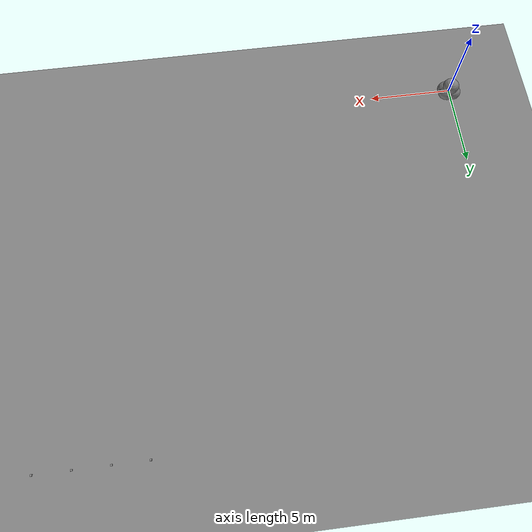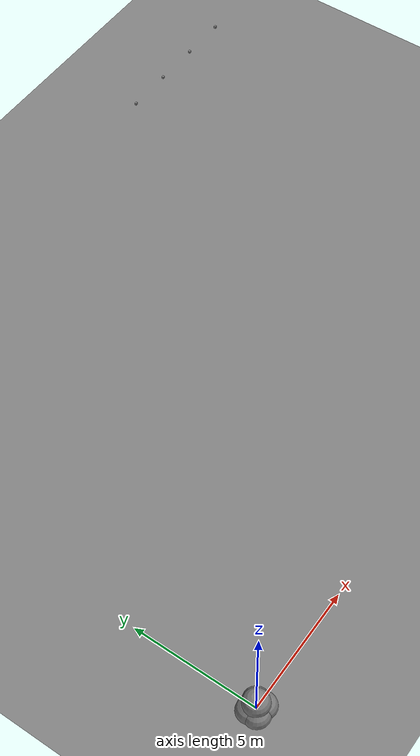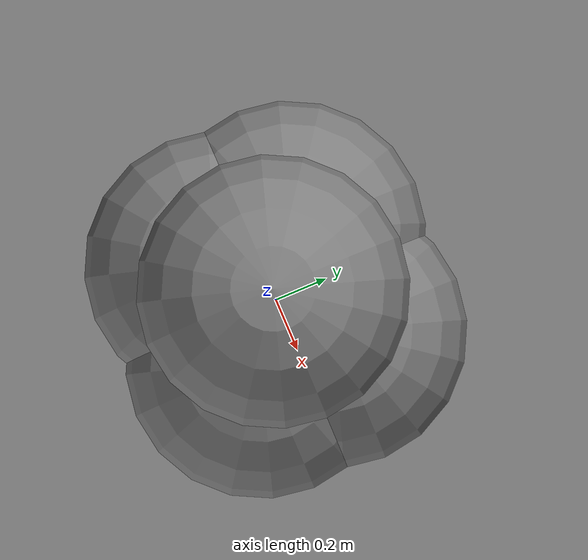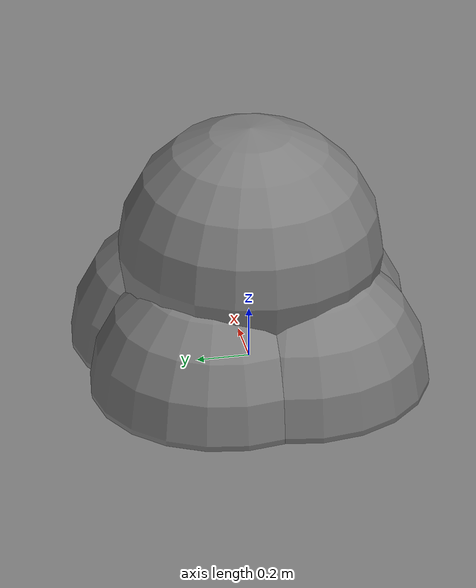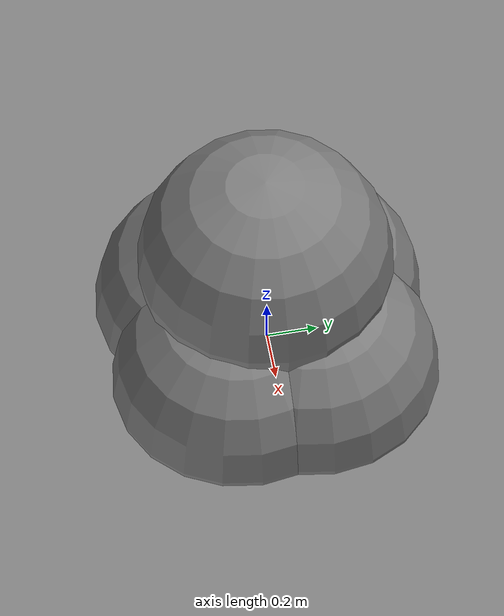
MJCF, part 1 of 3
<mujoco>
  <worldbody>
    <body pos="22 20 0.05" quat="-1 0 0 0" gravcomp="0" name="cube1">
      <freejoint name="cube1_joint" />
      <geom density="1000" type="box" size="0.05 0.05 0.05" pos="0 0 0" quat="-1 0 0 0" priority="0" contype="1" conaffinity="1" group="0" condim="3" solmix="1" solref="0.02 1" solimp="0.9 0.95 0.001" margin="0" gap="0" friction="0.6 0.005 0.0001" fluidshape="none" fluidcoef="5 0.25 1.5 1 1" name="cube1_geom" />
    </body>
    <geom density="1000" type="plane" size="0 0 1" pos="0 0 0" quat="-1 0 0 0" priority="1" contype="1" conaffinity="0" group="0" condim="3" solmix="1" solref="0.02 1" solimp="0.9 0.95 0.001" margin="0" gap="0" friction="0.6 0.005 0.0001" fluidshape="none" fluidcoef="5 0.25 1.5 1 1" name="floor" />
    <body pos="20 20 0.05" quat="-1 0 0 0" gravcomp="0" name="cube0">
      <freejoint name="cube0_joint" />
      <geom density="1000" type="box" size="0.05 0.05 0.05" pos="0 0 0" quat="-1 0 0 0" priority="0" contype="1" conaffinity="1" group="0" condim="3" solmix="1" solref="0.02 1" solimp="0.9 0.95 0.001" margin="0" gap="0" friction="0.6 0.005 0.0001" fluidshape="none" fluidcoef="5 0.25 1.5 1 1" name="cube0_geom" />
    </body>
    <body pos="0 0 0.445" quat="-1 0 0 0" gravcomp="0" name="base">
      <inertial pos="0.021112 0 -0.005365998" quat="-0.0005434711 0.713435 -0.00173769 0.7007191" mass="6.921" diaginertia="0.107027 0.0980771 0.0244531" />
      <freejoint name="joint_1" />
      <geom density="1000" type="mesh" mesh="mesh_0" pos="0 0 0" quat="1 0 0 0" priority="0" contype="0" conaffinity="0" group="2" condim="1" solmix="1" solref="0.02 1" solimp="0.9 0.95 0.001" margin="0.001" gap="0" friction="0.6 0.005 0.0001" fluidshape="none" fluidcoef="5 0.25 1.5 1 1" name="geom_2" />
      <geom density="1000" type="mesh" mesh="mesh_1" pos="0 0 0" quat="1 0 0 0" priority="0" contype="0" conaffinity="0" group="2" condim="1" solmix="1" solref="0.02 1" solimp="0.9 0.95 0.001" margin="0.001" gap="0" friction="0.6 0.005 0.0001" fluidshape="none" fluidcoef="5 0.25 1.5 1 1" name="geom_3" />
      <geom density="1000" type="mesh" mesh="mesh_2" pos="0 0 0" quat="-1 0 0 0" priority="0" contype="0" conaffinity="0" group="2" condim="1" solmix="1" solref="0.02 1" solimp="0.9 0.95 0.001" margin="0.001" gap="0" friction="0.6 0.005 0.0001" fluidshape="none" fluidcoef="5 0.25 1.5 1 1" name="geom_4" />
      <geom density="1000" type="mesh" mesh="mesh_3" pos="0 0 0" quat="1 0 0 0" priority="0" contype="0" conaffinity="0" group="2" condim="1" solmix="1" solref="0.02 1" solimp="0.9 0.95 0.001" margin="0.001" gap="0" friction="0.6 0.005 0.0001" fluidshape="none" fluidcoef="5 0.25 1.5 1 1" name="geom_5" />
      <geom density="1000" type="mesh" mesh="mesh_4" pos="0 0 0" quat="1 0 0 0" priority="0" contype="0" conaffinity="0" group="2" condim="1" solmix="1" solref="0.02 1" solimp="0.9 0.95 0.001" margin="0.001" gap="0" friction="0.6 0.005 0.0001" fluidshape="none" fluidcoef="5 0.25 1.5 1 1" name="geom_6" />
      <geom density="1000" type="sphere" size="0.057" pos="0 0 0" quat="-1 0 0 0" priority="0" contype="1" conaffinity="1" group="3" condim="1" solmix="1" solref="0.02 1" solimp="0.9 0.95 0.001" margin="0.001" gap="0" friction="0.6 0.005 0.0001" fluidshape="none" fluidcoef="5 0.25 1.5 1 1" name="geom_7" />
      <geom density="1000" type="sphere" size="0.05" pos="0.285 0 0.00999999" quat="-1 0 0 0" priority="0" contype="1" conaffinity="1" group="3" condim="1" solmix="1" solref="0.02 1" solimp="0.9 0.95 0.001" margin="0.001" gap="0" friction="0.6 0.005 0.0001" fluidshape="none" fluidcoef="5 0.25 1.5 1 1" name="geom_8" />
      <geom density="1000" type="sphere" size="0.047" pos="0.293 0 -0.06" quat="-1 0 0 0" priority="0" contype="1" conaffinity="1" group="3" condim="1" solmix="1" solref="0.02 1" solimp="0.9 0.95 0.001" margin="0.001" gap="0" friction="0.6 0.005 0.0001" fluidshape="none" fluidcoef="5 0.25 1.5 1 1" name="geom_9" />
      <site type="sphere" size="0.5" pos="-0.02557 0 0.04232001" quat="-1 0 0 0" name="imu" />
      <body pos="0.1934 0.0465 0" quat="-1 0 0 0" gravcomp="0" name="FL_hip">
        <inertial pos="-0.005400002 0.001940001 -0.0001049936" quat="0.4970139 0.4992449 0.5054619 0.4982369" mass="0.678" diaginertia="0.00088403 0.000596003 0.000479967" />
        <joint type="hinge" pos="0 0 0" axis="1 0 0" ref="0" armature="0.01" springref="0" springdamper="0 0" damping="0.5" stiffness="0" solreflimit="0.02 1" solimplimit="0.9 0.95 0.001 0.5 2" solreffriction="0.02 1" solimpfriction="0.9 0.95 0.001 0.5 2" frictionloss="0" limited="true" margin="0" range="-60.00014 60.00014" name="FL_hip_joint" />
        <geom density="1000" type="mesh" mesh="mesh_5" pos="0 0 0" quat="1 0 0 0" priority="0" contype="0" conaffinity="0" group="2" condim="1" solmix="1" solref="0.02 1" solimp="0.9 0.95 0.001" margin="0.001" gap="0" friction="0.6 0.005 0.0001" fluidshape="none" fluidcoef="5 0.25 1.5 1 1" name="geom_11" />
        <geom density="1000" type="mesh" mesh="mesh_6" pos="0 0 0" quat="1 0 0 0" priority="0" contype="0" conaffinity="0" group="2" condim="1" solmix="1" solref="0.02 1" solimp="0.9 0.95 0.001" margin="0.001" gap="0" friction="0.6 0.005 0.0001" fluidshape="none" fluidcoef="5 0.25 1.5 1 1" name="geom_12" />
        <geom density="1000" type="sphere" size="0.046" pos="0 0.08 0" quat="0.7071068 0.7071068 0 0" priority="0" contype="1" conaffinity="1" group="3" condim="1" solmix="1" solref="0.02 1" solimp="0.9 0.95 0.001" margin="0.001" gap="0" friction="0.6 0.005 0.0001" fluidshape="none" fluidcoef="5 0.25 1.5 1 1" name="geom_13" />
        <body pos="0 0.09550001 0" quat="-1 0 0 0" gravcomp="0" name="FL_thigh">
          <inertial pos="-0.003739998 -0.0223 -0.0327" quat="0.8295329 0.08476349 -0.0200632 0.5516229" mass="1.152" diaginertia="0.00594973 0.00584149 0.000878787" />
          <joint type="hinge" pos="0 0 0" axis="-1.192093E-07 1 0" ref="0" armature="0.01" springref="0" springdamper="0 0" damping="0.5" stiffness="0" solreflimit="0.02 1" solimplimit="0.9 0.95 0.001 0.5 2" solreffriction="0.02 1" solimpfriction="0.9 0.95 0.001 0.5 2" frictionloss="0" limited="true" margin="0" range="-90.00021 200.0024" name="FL_thigh_joint" />
          <geom density="1000" type="mesh" mesh="mesh_7" pos="0 0 0" quat="1 0 0 0" priority="0" contype="0" conaffinity="0" group="2" condim="1" solmix="1" solref="0.02 1" solimp="0.9 0.95 0.001" margin="0.001" gap="0" friction="0.6 0.005 0.0001" fluidshape="none" fluidcoef="5 0.25 1.5 1 1" name="geom_15" />
          <geom density="1000" type="mesh" mesh="mesh_8" pos="0 0 0" quat="1 0 0 0" priority="0" contype="0" conaffinity="0" group="2" condim="1" solmix="1" solref="0.02 1" solimp="0.9 0.95 0.001" margin="0.001" gap="0" friction="0.6 0.005 0.0001" fluidshape="none" fluidcoef="5 0.25 1.5 1 1" name="geom_16" />
          <geom density="1000" type="sphere" size="0.017" pos="-0.015 0 -0.1955" quat="0.7071068 0 0.7071068 0" priority="0" contype="1" conaffinity="1" group="3" condim="1" solmix="1" solref="0.02 1" solimp="0.9 0.95 0.001" margin="0.001" gap="0" friction="0.6 0.005 0.0001" fluidshape="none" fluidcoef="5 0.25 1.5 1 1" name="geom_17" />
          <body pos="0 0 -0.213" quat="-1 0 0 0" gravcomp="0" name="FL_calf">
            <inertial pos="0.006295949 -0.0006221235 -0.141417" quat="0.7106717 0.001540989 -0.004500868 0.7035077" mass="0.241352" diaginertia="0.0014901 0.00146356 5.31397E-05" />
            <joint type="hinge" pos="0 0 0" axis="-1.192093E-07 1 0" ref="0" armature="0.01" springref="0" springdamper="0 0" damping="0.5" stiffness="0" solreflimit="0.02 1" solimplimit="0.9 0.95 0.001 0.5 2" solreffriction="0.02 1" solimpfriction="0.9 0.95 0.001 0.5 2" frictionloss="0" limited="true" margin="0" range="-155.9992 -48.00011" name="FL_calf_joint" />
            <geom density="1000" type="mesh" mesh="mesh_11" pos="0 0 0" quat="1 0 0 0" priority="0" contype="0" conaffinity="0" group="2" condim="1" solmix="1" solref="0.02 1" solimp="0.9 0.95 0.001" margin="0.001" gap="0" friction="0.6 0.005 0.0001" fluidshape="none" fluidcoef="5 0.25 1.5 1 1" name="geom_19" />
            <geom density="1000" type="mesh" mesh="mesh_12" pos="0 0 0" quat="1 0 0 0" priority="0" contype="0" conaffinity="0" group="2" condim="1" solmix="1" solref="0.02 1" solimp="0.9 0.95 0.001" margin="0.001" gap="0" friction="0.6 0.005 0.0001" fluidshape="none" fluidcoef="5 0.25 1.5 1 1" name="geom_20" />
            <geom density="1000" type="sphere" size="0.012" pos="0.008000001 0 -0.06" quat="0.9944927 0 -0.104807 0" priority="0" contype="1" conaffinity="1" group="3" condim="1" solmix="1" solref="0.02 1" solimp="0.9 0.95 0.001" margin="0.001" gap="0" friction="0.6 0.005 0.0001" fluidshape="none" fluidcoef="5 0.25 1.5 1 1" name="geom_21" />
            <geom density="1000" type="sphere" size="0.011" pos="0.02 0 -0.148" quat="0.9996876 0 0.02499739 0" priority="0" contype="1" conaffinity="1" group="3" condim="1" solmix="1" solref="0.02 1" solimp="0.9 0.95 0.001" margin="0.001" gap="0" friction="0.6 0.005 0.0001" fluidshape="none" fluidcoef="5 0.25 1.5 1 1" name="geom_22" />
            <geom density="1000" type="mesh" mesh="mesh_13" pos="0 0 -0.213" quat="1 0 0 0" priority="0" contype="0" conaffinity="0" group="2" condim="1" solmix="1" solref="0.02 1" solimp="0.9 0.95 0.001" margin="0.001" gap="0" friction="0.6 0.005 0.0001" fluidshape="none" fluidcoef="5 0.25 1.5 1 1" name="geom_23" />
            <geom density="1000" type="sphere" size="0.0175" pos="-0.002000004 0 -0.213" quat="-1 0 0 0" priority="1" contype="1" conaffinity="1" group="3" condim="6" solmix="1" solref="0.02 1" solimp="0.015 1 0.031" margin="0.001" gap="0" friction="0.8 0.02 0.01" fluidshape="none" fluidcoef="5 0.25 1.5 1 1" name="FL" />
            <site type="sphere" size="0.5" pos="-0.002000004 0 -0.213" quat="-1 0 0 0" name="FL_foot" />
          </body>
        </body>
      </body>
      <body pos="0.1934 -0.0465 0" quat="-1 0 0 0" gravcomp="0" name="FR_hip">
        <inertial pos="-0.005400002 -0.001940001 -0.0001049936" quat="0.4982369 0.5054619 0.4992449 0.4970139" mass="0.678" diaginertia="0.00088403 0.000596003 0.000479967" />
        <joint type="hinge" pos="0 0 0" axis="1 0 0" ref="0" armature="0.01" springref="0" springdamper="0 0" damping="0.5" stiffness="0" solreflimit="0.02 1" solimplimit="0.9 0.95 0.001 0.5 2" solreffriction="0.02 1" solimpfriction="0.9 0.95 0.001 0.5 2" frictionloss="0" limited="true" margin="0" range="-60.00014 60.00014" name="FR_hip_joint" />
        <geom density="1000" type="mesh" mesh="mesh_5" pos="0 0 0" quat="4.63268E-05 1 0 0" priority="0" contype="0" conaffinity="0" group="2" condim="1" solmix="1" solref="0.02 1" solimp="0.9 0.95 0.001" margin="0.001" gap="0" friction="0.6 0.005 0.0001" fluidshape="none" fluidcoef="5 0.25 1.5 1 1" name="geom_25" />
        <geom density="1000" type="mesh" mesh="mesh_6" pos="0 0 0" quat="4.63268E-05 1 0 0" priority="0" contype="0" conaffinity="0" group="2" condim="1" solmix="1" solref="0.02 1" solimp="0.9 0.95 0.001" margin="0.001" gap="0" friction="0.6 0.005 0.0001" fluidshape="none" fluidcoef="5 0.25 1.5 1 1" name="geom_26" />
        <geom density="1000" type="sphere" size="0.046" pos="0 -0.08 0" quat="0.7071068 0.7071068 0 0" priority="0" contype="1" conaffinity="1" group="3" condim="1" solmix="1" solref="0.02 1" solimp="0.9 0.95 0.001" margin="0.001" gap="0" friction="0.6 0.005 0.0001" fluidshape="none" fluidcoef="5 0.25 1.5 1 1" name="geom_27" />
        <body pos="0 -0.09550001 0" quat="-1 0 0 0" gravcomp="0" name="FR_thigh">
          <inertial pos="-0.003739998 0.0223 -0.0327" quat="0.5516229 -0.0200632 0.08476349 0.8295329" mass="1.152" diaginertia="0.00594973 0.00584149 0.000878787" />
          <joint type="hinge" pos="0 0 0" axis="-1.192093E-07 1 0" ref="0" armature="0.01" springref="0" springdamper="0 0" damping="0.5" stiffness="0" solreflimit="0.02 1" solimplimit="0.9 0.95 0.001 0.5 2" solreffriction="0.02 1" solimpfriction="0.9 0.95 0.001 0.5 2" frictionloss="0" limited="true" margin="0" range="-90.00021 200.0024" name="FR_thigh_joint" />
          <geom density="1000" type="mesh" mesh="mesh_9" pos="0 0 0" quat="1 0 0 0" priority="0" contype="0" conaffinity="0" group="2" condim="1" solmix="1" solref="0.02 1" solimp="0.9 0.95 0.001" margin="0.001" gap="0" friction="0.6 0.005 0.0001" fluidshape="none" fluidcoef="5 0.25 1.5 1 1" name="geom_29" />
          <geom density="1000" type="mesh" mesh="mesh_10" pos="0 0 0" quat="1 0 0 0" priority="0" contype="0" conaffinity="0" group="2" condim="1" solmix="1" solref="0.02 1" solimp="0.9 0.95 0.001" margin="0.001" gap="0" friction="0.6 0.005 0.0001" fluidshape="none" fluidcoef="5 0.25 1.5 1 1" name="geom_30" />
          <geom density="1000" type="sphere" size="0.017" pos="-0.015 0 -0.1955" quat="0.7071068 0 0.7071068 0" priority="0" contype="1" conaffinity="1" group="3" condim="1" solmix="1" solref="0.02 1" solimp="0.9 0.95 0.001" margin="0.001" gap="0" friction="0.6 0.005 0.0001" fluidshape="none" fluidcoef="5 0.25 1.5 1 1" name="geom_31" />
          <body pos="0 0 -0.213" quat="-1 0 0 0" gravcomp="0" name="FR_calf">
            <inertial pos="0.006295949 0.0006221235 -0.141417" quat="0.7035077 -0.004500868 0.001540989 0.7106717" mass="0.241352" diaginertia="0.0014901 0.00146356 5.31397E-05" />
            <joint type="hinge" pos="0 0 0" axis="-1.192093E-07 1 0" ref="0" armature="0.01" springref="0" springdamper="0 0" damping="0.5" stiffness="0" solreflimit="0.02 1" solimplimit="0.9 0.95 0.001 0.5 2" solreffriction="0.02 1" solimpfriction="0.9 0.95 0.001 0.5 2" frictionloss="0" limited="true" margin="0" range="-155.9992 -48.00011" name="FR_calf_joint" />
            <geom density="1000" type="mesh" mesh="mesh_14" pos="0 0 0" quat="1 0 0 0" priority="0" contype="0" conaffinity="0" group="2" condim="1" solmix="1" solref="0.02 1" solimp="0.9 0.95 0.001" margin="0.001" gap="0" friction="0.6 0.005 0.0001" fluidshape="none" fluidcoef="5 0.25 1.5 1 1" name="geom_33" />
            <geom density="1000" type="mesh" mesh="mesh_15" pos="0 0 0" quat="1 0 0 0" priority="0" contype="0" conaffinity="0" group="2" condim="1" solmix="1" solref="0.02 1" solimp="0.9 0.95 0.001" margin="0.001" gap="0" friction="0.6 0.005 0.0001" fluidshape="none" fluidcoef="5 0.25 1.5 1 1" name="geom_34" />
            <geom density="1000" type="sphere" size="0.013" pos="0.01000001 0 -0.06" quat="0.9950042 0 -0.09983341 0" priority="0" contype="1" conaffinity="1" group="3" condim="1" solmix="1" solref="0.02 1" solimp="0.9 0.95 0.001" margin="0.001" gap="0" friction="0.6 0.005 0.0001" fluidshape="none" fluidcoef="5 0.25 1.5 1 1" name="geom_35" />
            <geom density="1000" type="sphere" size="0.011" pos="0.02 0 -0.148" quat="0.9996876 0 0.02499739 0" priority="0" contype="1" conaffinity="1" group="3" condim="1" solmix="1" solref="0.02 1" solimp="0.9 0.95 0.001" margin="0.001" gap="0" friction="0.6 0.005 0.0001" fluidshape="none" fluidcoef="5 0.25 1.5 1 1" name="geom_36" />
            <geom density="1000" type="mesh" mesh="mesh_13" pos="0 0 -0.213" quat="1 0 0 0" priority="0" contype="0" conaffinity="0" group="2" condim="1" solmix="1" solref="0.02 1" solimp="0.9 0.95 0.001" margin="0.001" gap="0" friction="0.6 0.005 0.0001" fluidshape="none" fluidcoef="5 0.25 1.5 1 1" name="geom_37" />
            <geom density="1000" type="sphere" size="0.0175" pos="-0.002000004 0 -0.213" quat="-1 0 0 0" priority="1" contype="1" conaffinity="1" group="3" condim="6" solmix="1" solref="0.02 1" solimp="0.015 1 0.031" margin="0.001" gap="0" friction="0.8 0.02 0.01" fluidshape="none" fluidcoef="5 0.25 1.5 1 1" name="FR" />
            <site type="sphere" size="0.5" pos="-0.002000004 0 -0.213" quat="-1 0 0 0" name="FR_foot" />
          </body>
        </body>
      </body>
      <body pos="-0.1934 0.0465 0" quat="-1 0 0 0" gravcomp="0" name="RL_hip">
        <inertial pos="0.005400002 0.001940001 -0.0001049936" quat="0.5054619 0.4982369 0.4970139 0.4992449" mass="0.678" diaginertia="0.00088403 0.000596003 0.000479967" />
        <joint type="hinge" pos="0 0 0" axis="1 0 0" ref="0" armature="0.01" springref="0" springdamper="0 0" damping="0.5" stiffness="0" solreflimit="0.02 1" solimplimit="0.9 0.95 0.001 0.5 2" solreffriction="0.02 1" solimpfriction="0.9 0.95 0.001 0.5 2" frictionloss="0" limited="true" margin="0" range="-60.00014 60.00014" name="RL_hip_joint" />
        <geom density="1000" type="mesh" mesh="mesh_5" pos="0 0 0" quat="4.63268E-05 0 1 0" priority="0" contype="0" conaffinity="0" group="2" condim="1" solmix="1" solref="0.02 1" solimp="0.9 0.95 0.001" margin="0.001" gap="0" friction="0.6 0.005 0.0001" fluidshape="none" fluidcoef="5 0.25 1.5 1 1" name="geom_39" />
        <geom density="1000" type="mesh" mesh="mesh_6" pos="0 0 0" quat="4.63268E-05 0 1 0" priority="0" contype="0" conaffinity="0" group="2" condim="1" solmix="1" solref="0.02 1" solimp="0.9 0.95 0.001" margin="0.001" gap="0" friction="0.6 0.005 0.0001" fluidshape="none" fluidcoef="5 0.25 1.5 1 1" name="geom_40" />
        <geom density="1000" type="sphere" size="0.046" pos="0 0.08 0" quat="0.7071068 0.7071068 0 0" priority="0" contype="1" conaffinity="1" group="3" condim="1" solmix="1" solref="0.02 1" solimp="0.9 0.95 0.001" margin="0.001" gap="0" friction="0.6 0.005 0.0001" fluidshape="none" fluidcoef="5 0.25 1.5 1 1" name="geom_41" />
        <body pos="0 0.09550001 0" quat="-1 0 0 0" gravcomp="0" name="RL_thigh">
          <inertial pos="-0.003739998 -0.0223 -0.0327" quat="0.8295329 0.08476349 -0.0200632 0.5516229" mass="1.152" diaginertia="0.00594973 0.00584149 0.000878787" />
          <joint type="hinge" pos="0 0 0" axis="-1.192093E-07 1 0" ref="0" armature="0.01" springref="0" springdamper="0 0" damping="0.5" stiffness="0" solreflimit="0.02 1" solimplimit="0.9 0.95 0.001 0.5 2" solreffriction="0.02 1" solimpfriction="0.9 0.95 0.001 0.5 2" frictionloss="0" limited="true" margin="0" range="-90.00021 200.0024" name="RL_thigh_joint" />
          <geom density="1000" type="mesh" mesh="mesh_7" pos="0 0 0" quat="1 0 0 0" priority="0" contype="0" conaffinity="0" group="2" condim="1" solmix="1" solref="0.02 1" solimp="0.9 0.95 0.001" margin="0.001" gap="0" friction="0.6 0.005 0.0001" fluidshape="none" fluidcoef="5 0.25 1.5 1 1" name="geom_43" />
          <geom density="1000" type="mesh" mesh="mesh_8" pos="0 0 0" quat="1 0 0 0" priority="0" contype="0" conaffinity="0" group="2" condim="1" solmix="1" solref="0.02 1" solimp="0.9 0.95 0.001" margin="0.001" gap="0" friction="0.6 0.005 0.0001" fluidshape="none" fluidcoef="5 0.25 1.5 1 1" name="geom_44" />
          <geom density="1000" type="sphere" size="0.017" pos="-0.015 0 -0.1955" quat="0.7071068 0 0.7071068 0" priority="0" contype="1" conaffinity="1" group="3" condim="1" solmix="1" solref="0.02 1" solimp="0.9 0.95 0.001" margin="0.001" gap="0" friction="0.6 0.005 0.0001" fluidshape="none" fluidcoef="5 0.25 1.5 1 1" name="geom_45" />
          <body pos="0 0 -0.213" quat="-1 0 0 0" gravcomp="0" name="RL_calf">
            <inertial pos="0.006295949 -0.0006221235 -0.141417" quat="0.7106717 0.001540989 -0.004500868 0.7035077" mass="0.241352" diaginertia="0.0014901 0.00146356 5.31397E-05" />
            <joint type="hinge" pos="0 0 0" axis="-1.192093E-07 1 0" ref="0" armature="0.01" springref="0" springdamper="0 0" damping="0.5" stiffness="0" solreflimit="0.02 1" solimplimit="0.9 0.95 0.001 0.5 2" solreffriction="0.02 1" solimpfriction="0.9 0.95 0.001 0.5 2" frictionloss="0" limited="true" margin="0" range="-155.9992 -48.00011" name="RL_calf_joint" />
            <geom density="1000" type="mesh" mesh="mesh_11" pos="0 0 0" quat="1 0 0 0" priority="0" contype="0" conaffinity="0" group="2" condim="1" solmix="1" solref="0.02 1" solimp="0.9 0.95 0.001" margin="0.001" gap="0" friction="0.6 0.005 0.0001" fluidshape="none" fluidcoef="5 0.25 1.5 1 1" name="geom_47" />
            <geom density="1000" type="mesh" mesh="mesh_12" pos="0 0 0" quat="1 0 0 0" priority="0" contype="0" conaffinity="0" group="2" condim="1" solmix="1" solref="0.02 1" solimp="0.9 0.95 0.001" margin="0.001" gap="0" friction="0.6 0.005 0.0001" fluidshape="none" fluidcoef="5 0.25 1.5 1 1" name="geom_48" />
            <geom density="1000" type="sphere" size="0.013" pos="0.01000001 0 -0.06" quat="0.9950042 0 -0.09983341 0" priority="0" contype="1" conaffinity="1" group="3" condim="1" solmix="1" solref="0.02 1" solimp="0.9 0.95 0.001" margin="0.001" gap="0" friction="0.6 0.005 0.0001" fluidshape="none" fluidcoef="5 0.25 1.5 1 1" name="geom_49" />
            <geom density="1000" type="sphere" size="0.011" pos="0.02 0 -0.148" quat="0.9996876 0 0.02499739 0" priority="0" contype="1" conaffinity="1" group="3" condim="1" solmix="1" solref="0.02 1" solimp="0.9 0.95 0.001" margin="0.001" gap="0" friction="0.6 0.005 0.0001" fluidshape="none" fluidcoef="5 0.25 1.5 1 1" name="geom_50" />
            <geom density="1000" type="mesh" mesh="mesh_13" pos="0 0 -0.213" quat="1 0 0 0" priority="0" contype="0" conaffinity="0" group="2" condim="1" solmix="1" solref="0.02 1" solimp="0.9 0.95 0.001" margin="0.001" gap="0" friction="0.6 0.005 0.0001" fluidshape="none" fluidcoef="5 0.25 1.5 1 1" name="geom_51" />
            <geom density="1000" type="sphere" size="0.0175" pos="-0.002000004 0 -0.213" quat="-1 0 0 0" priority="1" contype="1" conaffinity="1" group="3" condim="6" solmix="1" solref="0.02 1" solimp="0.015 1 0.031" margin="0.001" gap="0" friction="0.8 0.02 0.01" fluidshape="none" fluidcoef="5 0.25 1.5 1 1" name="RL" />
            <site type="sphere" size="0.5" pos="-0.002000004 0 -0.213" quat="-1 0 0 0" name="RL_foot" />
          </body>
        </body>
      </body>
      <body pos="-0.1934 -0.0465 0" quat="-1 0 0 0" gravcomp="0" name="RR_hip">
        <inertial pos="0.005400002 -0.001940001 -0.0001049936" quat="0.4992449 0.4970139 0.4982369 0.5054619" mass="0.678" diaginertia="0.00088403 0.000596003 0.000479967" />
        <joint type="hinge" pos="0 0 0" axis="1 0 0" ref="0" armature="0.01" springref="0" springdamper="0 0" damping="0.5" stiffness="0" solreflimit="0.02 1" solimplimit="0.9 0.95 0.001 0.5 2" solreffriction="0.02 1" solimpfriction="0.9 0.95 0.001 0.5 2" frictionloss="0" limited="true" margin="0" range="-60.00014 60.00014" name="RR_hip_joint" />
        <geom density="1000" type="mesh" mesh="mesh_5" pos="0 0 0" quat="2.14617E-09 4.63268E-05 4.63268E-05 -1" priority="0" contype="0" conaffinity="0" group="2" condim="1" solmix="1" solref="0.02 1" solimp="0.9 0.95 0.001" margin="0.001" gap="0" friction="0.6 0.005 0.0001" fluidshape="none" fluidcoef="5 0.25 1.5 1 1" name="geom_53" />
        <geom density="1000" type="mesh" mesh="mesh_6" pos="0 0 0" quat="2.14617E-09 4.63268E-05 4.63268E-05 -1" priority="0" contype="0" conaffinity="0" group="2" condim="1" solmix="1" solref="0.02 1" solimp="0.9 0.95 0.001" margin="0.001" gap="0" friction="0.6 0.005 0.0001" fluidshape="none" fluidcoef="5 0.25 1.5 1 1" name="geom_54" />
        <geom density="1000" type="sphere" size="0.046" pos="0 -0.08 0" quat="0.7071068 0.7071068 0 0" priority="0" contype="1" conaffinity="1" group="3" condim="1" solmix="1" solref="0.02 1" solimp="0.9 0.95 0.001" margin="0.001" gap="0" friction="0.6 0.005 0.0001" fluidshape="none" fluidcoef="5 0.25 1.5 1 1" name="geom_55" />
        <body pos="0 -0.09550001 0" quat="-1 0 0 0" gravcomp="0" name="RR_thigh">
          <inertial pos="-0.003739998 0.0223 -0.0327" quat="0.5516229 -0.0200632 0.08476349 0.8295329" mass="1.152" diaginertia="0.00594973 0.00584149 0.000878787" />
          <joint type="hinge" pos="0 0 0" axis="-1.192093E-07 1 0" ref="0" armature="0.01" springref="0" springdamper="0 0" damping="0.5" stiffness="0" solreflimit="0.02 1" solimplimit="0.9 0.95 0.001 0.5 2" solreffriction="0.02 1" solimpfriction="0.9 0.95 0.001 0.5 2" frictionloss="0" limited="true" margin="0" range="-90.00021 200.0024" name="RR_thigh_joint" />
          <geom density="1000" type="mesh" mesh="mesh_9" pos="0 0 0" quat="1 0 0 0" priority="0" contype="0" conaffinity="0" group="2" condim="1" solmix="1" solref="0.02 1" solimp="0.9 0.95 0.001" margin="0.001" gap="0" friction="0.6 0.005 0.0001" fluidshape="none" fluidcoef="5 0.25 1.5 1 1" name="geom_57" />
          <geom density="1000" type="mesh" mesh="mesh_10" pos="0 0 0" quat="1 0 0 0" priority="0" contype="0" conaffinity="0" group="2" condim="1" solmix="1" solref="0.02 1" solimp="0.9 0.95 0.001" margin="0.001" gap="0" friction="0.6 0.005 0.0001" fluidshape="none" fluidcoef="5 0.25 1.5 1 1" name="geom_58" />
          <geom density="1000" type="sphere" size="0.017" pos="-0.015 0 -0.1955" quat="0.7071068 0 0.7071068 0" priority="0" contype="1" conaffinity="1" group="3" condim="1" solmix="1" solref="0.02 1" solimp="0.9 0.95 0.001" margin="0.001" gap="0" friction="0.6 0.005 0.0001" fluidshape="none" fluidcoef="5 0.25 1.5 1 1" name="geom_59" />
          <body pos="0 0 -0.213" quat="-1 0 0 0" gravcomp="0" name="RR_calf">
            <inertial pos="0.006295949 0.0006221235 -0.141417" quat="0.7035077 -0.004500868 0.001540989 0.7106717" mass="0.241352" diaginertia="0.0014901 0.00146356 5.31397E-05" />
            <joint type="hinge" pos="0 0 0" axis="-1.192093E-07 1 0" ref="0" armature="0.01" springref="0" springdamper="0 0" damping="0.5" stiffness="0" solreflimit="0.02 1" solimplimit="0.9 0.95 0.001 0.5 2" solreffriction="0.02 1" solimpfriction="0.9 0.95 0.001 0.5 2" frictionloss="0" limited="true" margin="0" range="-155.9992 -48.00011" name="RR_calf_joint" />
            <geom density="1000" type="mesh" mesh="mesh_14" pos="0 0 0" quat="1 0 0 0" priority="0" contype="0" conaffinity="0" group="2" condim="1" solmix="1" solref="0.02 1" solimp="0.9 0.95 0.001" margin="0.001" gap="0" friction="0.6 0.005 0.0001" fluidshape="none" fluidcoef="5 0.25 1.5 1 1" name="geom_61" />
            <geom density="1000" type="mesh" mesh="mesh_15" pos="0 0 0" quat="1 0 0 0" priority="0" contype="0" conaffinity="0" group="2" condim="1" solmix="1" solref="0.02 1" solimp="0.9 0.95 0.001" margin="0.001" gap="0" friction="0.6 0.005 0.0001" fluidshape="none" fluidcoef="5 0.25 1.5 1 1" name="geom_62" />
            <geom density="1000" type="sphere" size="0.013" pos="0.01000001 0 -0.06" quat="0.9950042 0 -0.09983341 0" priority="0" contype="1" conaffinity="1" group="3" condim="1" solmix="1" solref="0.02 1" solimp="0.9 0.95 0.001" margin="0.001" gap="0" friction="0.6 0.005 0.0001" fluidshape="none" fluidcoef="5 0.25 1.5 1 1" name="geom_63" />
            <geom density="1000" type="sphere" size="0.011" pos="0.02 0 -0.148" quat="0.9996876 0 0.02499739 0" priority="0" contype="1" conaffinity="1" group="3" condim="1" solmix="1" solref="0.02 1" solimp="0.9 0.95 0.001" margin="0.001" gap="0" friction="0.6 0.005 0.0001" fluidshape="none" fluidcoef="5 0.25 1.5 1 1" name="geom_64" />
            <geom density="1000" type="mesh" mesh="mesh_13" pos="0 0 -0.213" quat="1 0 0 0" priority="0" contype="0" conaffinity="0" group="2" condim="1" solmix="1" solref="0.02 1" solimp="0.9 0.95 0.001" margin="0.001" gap="0" friction="0.6 0.005 0.0001" fluidshape="none" fluidcoef="5 0.25 1.5 1 1" name="geom_65" />
            <geom density="1000" type="sphere" size="0.0175" pos="-0.002000004 0 -0.213" quat="-1 0 0 0" priority="1" contype="1" conaffinity="1" group="3" condim="6" solmix="1" solref="0.02 1" solimp="0.015 1 0.031" margin="0.001" gap="0" friction="0.8 0.02 0.01" fluidshape="none" fluidcoef="5 0.25 1.5 1 1" name="RR" />
            <site type="sphere" size="0.5" pos="-0.002000004 0 -0.213" quat="-1 0 0 0" name="RR_foot" />
          </body>
        </body>
      </body>
    </body>
    <body pos="24 20 0.05" quat="-1 0 0 0" gravcomp="0" name="cube2">
      <freejoint name="cube2_joint" />
      <geom density="1000" type="box" size="0.05 0.05 0.05" pos="0 0 0" quat="-1 0 0 0" priority="0" contype="1" conaffinity="1" group="0" condim="3" solmix="1" solref="0.02 1" solimp="0.9 0.95 0.001" margin="0" gap="0" friction="0.6 0.005 0.0001" fluidshape="none" fluidcoef="5 0.25 1.5 1 1" name="cube2_geom" />
    </body>
    <body pos="26 20 0.05" quat="-1 0 0 0" gravcomp="0" name="cube3">
      <freejoint name="cube3_joint" />
      <geom density="1000" type="box" size="0.05 0.05 0.05" pos="0 0 0" quat="-1 0 0 0" priority="0" contype="1" conaffinity="1" group="0" condim="3" solmix="1" solref="0.02 1" solimp="0.9 0.95 0.001" margin="0" gap="0" friction="0.6 0.005 0.0001" fluidshape="none" fluidcoef="5 0.25 1.5 1 1" name="cube3_geom" />
    </body>
  </worldbody>
  <contact />
  <tendon />
  <equality />
  <actuator>
    <general joint="FL_hip_joint" ctrllimited="true" forcelimited="true" ctrlrange="-0.9472 0.9472" forcerange="-24 24" lengthrange="0 0" gear="1" dyntype="none" gaintype="fixed" biastype="affine" dynprm="1 0 0" gainprm="35 0 0" biasprm="0 -35 -0.5" name="FL_hip" />
    <general joint="FL_thigh_joint" ctrllimited="true" forcelimited="true" ctrlrange="-1.4 2.5" forcerange="-24 24" lengthrange="0 0" gear="1" dyntype="none" gaintype="fixed" biastype="affine" dynprm="1 0 0" gainprm="35 0 0" biasprm="0 -35 -0.5" name="FL_thigh" />
    <general joint="FL_calf_joint" ctrllimited="true" forcelimited="true" ctrlrange="-2.6227 -0.84776" forcerange="-24 24" lengthrange="0 0" gear="1" dyntype="none" gaintype="fixed" biastype="affine" dynprm="1 0 0" gainprm="35 0 0" biasprm="0 -35 -0.5" name="FL_calf" />
    <general joint="FR_hip_joint" ctrllimited="true" forcelimited="true" ctrlrange="-0.9472 0.9472" forcerange="-24 24" lengthrange="0 0" gear="1" dyntype="none" gaintype="fixed" biastype="affine" dynprm="1 0 0" gainprm="35 0 0" biasprm="0 -35 -0.5" name="FR_hip" />
    <general joint="FR_thigh_joint" ctrllimited="true" forcelimited="true" ctrlrange="-1.4 2.5" forcerange="-24 24" lengthrange="0 0" gear="1" dyntype="none" gaintype="fixed" biastype="affine" dynprm="1 0 0" gainprm="35 0 0" biasprm="0 -35 -0.5" name="FR_thigh" />
    <general joint="FR_calf_joint" ctrllimited="true" forcelimited="true" ctrlrange="-2.6227 -0.84776" forcerange="-24 24" lengthrange="0 0" gear="1" dyntype="none" gaintype="fixed" biastype="affine" dynprm="1 0 0" gainprm="35 0 0" biasprm="0 -35 -0.5" name="FR_calf" />
    <general joint="RL_hip_joint" ctrllimited="true" forcelimited="true" ctrlrange="-0.9472 0.9472" forcerange="-24 24" lengthrange="0 0" gear="1" dyntype="none" gaintype="fixed" biastype="affine" dynprm="1 0 0" gainprm="35 0 0" biasprm="0 -35 -0.5" name="RL_hip" />
    <general joint="RL_thigh_joint" ctrllimited="true" forcelimited="true" ctrlrange="-1.4 2.5" forcerange="-24 24" lengthrange="0 0" gear="1" dyntype="none" gaintype="fixed" biastype="affine" dynprm="1 0 0" gainprm="35 0 0" biasprm="0 -35 -0.5" name="RL_thigh" />
    <general joint="RL_calf_joint" ctrllimited="true" forcelimited="true" ctrlrange="-2.6227 -0.84776" forcerange="-24 24" lengthrange="0 0" gear="1" dyntype="none" gaintype="fixed" biastype="affine" dynprm="1 0 0" gainprm="35 0 0" biasprm="0 -35 -0.5" name="RL_calf" />
    <general joint="RR_hip_joint" ctrllimited="true" forcelimited="true" ctrlrange="-0.9472 0.9472" forcerange="-24 24" lengthrange="0 0" gear="1" dyntype="none" gaintype="fixed" biastype="affine" dynprm="1 0 0" gainprm="35 0 0" biasprm="0 -35 -0.5" name="RR_hip" />
    <general joint="RR_thigh_joint" ctrllimited="true" forcelimited="true" ctrlrange="-1.4 2.5" forcerange="-24 24" lengthrange="0 0" gear="1" dyntype="none" gaintype="fixed" biastype="affine" dynprm="1 0 0" gainprm="35 0 0" biasprm="0 -35 -0.5" name="RR_thigh" />
    <general joint="RR_calf_joint" ctrllimited="true" forcelimited="true" ctrlrange="-2.6227 -0.84776" forcerange="-24 24" lengthrange="0 0" gear="1" dyntype="none" gaintype="fixed" biastype="affine" dynprm="1 0 0" gainprm="35 0 0" biasprm="0 -35 -0.5" name="RR_calf" />
  </actuator>
  <sensor>
    <gyro site="imu" cutoff="0" name="gyro" />
    <velocimeter site="imu" cutoff="0" name="local_linvel" />
    <accelerometer site="imu" cutoff="0" name="accelerometer" />
    <framepos objtype="site" objname="imu" cutoff="0" name="position" />
    <framezaxis objtype="site" objname="imu" cutoff="0" name="upvector" />
    <framexaxis objtype="site" objname="imu" cutoff="0" name="forwardvector" />
    <framelinvel objtype="site" objname="imu" cutoff="0" name="global_linvel" />
    <frameangvel objtype="site" objname="imu" cutoff="0" name="global_angvel" />
    <framequat objtype="site" objname="imu" cutoff="0" name="orientation" />
    <framelinvel objtype="site" objname="FL_foot" cutoff="0" name="FL_global_linvel" />
    <framelinvel objtype="site" objname="FR_foot" cutoff="0" name="FR_global_linvel" />
    <framelinvel objtype="site" objname="RL_foot" cutoff="0" name="RL_global_linvel" />
    <framelinvel objtype="site" objname="RR_foot" cutoff="0" name="RR_global_linvel" />
    <framepos objtype="site" objname="FL_foot" cutoff="0" name="FL_pos" />
    <framepos objtype="site" objname="FR_foot" cutoff="0" name="FR_pos" />
    <framepos objtype="site" objname="RL_foot" cutoff="0" name="RL_pos" />
    <framepos objtype="site" objname="RR_foot" cutoff="0" name="RR_pos" />
  </sensor>
  <compiler coordinate="local" />
  <option gravity="0 0 -9.81" timestep="0.004" />
  <option impratio="100" magnetic="0 0 0" wind="0 0 0" density="0" viscosity="0" o_margin="0" o_solref="0.02 1" o_solimp="0.9 0.95 0.001 0.5 2" integrator="Euler" cone="pyramidal" jacobian="auto" solver="Newton" iterations="1" tolerance="1E-08" noslip_iterations="0" noslip_tolerance="1E-06" ccd_iterations="50" ccd_tolerance="1E-06">
    <flag constraint="enable" equality="enable" frictionloss="enable" limit="enable" contact="enable" spring="enable" damper="enable" gravity="enable" clampctrl="enable" warmstart="enable" filterparent="enable" actuation="enable" refsafe="enable" override="disable" energy="disable" fwdinv="disable" multiccd="enable" />
  </option>
  <size memory="-1" />
  <custom />
  <asset>
    <mesh name="mesh_0" vertex="0.284661 0.010827 -0.07685 0.284425 0.005302 -0.077156 0.284662 0.010827 -0.076851 0.283015 0.010827 -0.075364 0.282735 0.005302 -0.07563 0.283015 0.010827 -0.075365 0.28161 0.010827 -0.073648 0.281292 0.005302 -0.073868 0.28161 0.010827 -0.073649 0.2749 -0.010807 -0.062658 0.274901 -0.010807 -0.062658 0.274902 -0.010807 -0.062658 0.283244 0.021376 -0.081647 0.28327 0.026516 -0.081663 0.283244 0.026515 -0.081647 0.28327 0.026516 -0.081663 0.286056 0.021376 -0.083112 0.286056 0.026613 -0.083112 0.284211 0.01586 -0.082222 0.286055 0.01586 -0.083113 0.283243 0.01586 -0.081648 0.286892 0.01586 -0.083441 0.28907 0.021376 -0.084095 0.28907 0.01586 -0.084093 0.281752 0.01586 -0.080601 0.28071 0.021376 -0.079741 0.280714 0.01586 -0.079737 0.289729 0.01586 -0.084237 0.292204 0.021376 -0.08457 0.292204 0.01586 -0.084567 0.279566 0.01586 -0.078625 0.292653 0.01586 -0.084592 0.295374 0.021376 -0.084524 0.295374 0.01586 -0.084522 0.295598 0.01586 -0.084499 0.298493 0.021376 -0.083958 0.298493 0.01586 -0.083958 0.301271 0.01586 -0.082979 0.301478 0.021376 -0.082888 0.301477 0.01586 -0.082886 0.303868 0.015859 -0.081587 0.304246 0.021376 -0.081343 0.304245 0.015859 -0.081341 0.306223 0.01586 -0.079818 0.306723 0.021376 -0.079364 0.306722 0.01586 -0.079364 0.308282 0.01586 -0.07771 0.308842 0.021376 -0.077006 0.308843 0.01586 -0.077007 0.309993 0.01586 -0.075313 0.310545 0.021376 -0.074332 0.310545 0.01586 -0.074332 0.311313 0.01586 -0.07268 0.311785 0.021376 -0.071415 0.31178 0.015859 -0.071413 0.312218 0.015859 -0.069876 0.3067 0.02671 -0.079387 0.304246 0.026792 -0.081343 0.308821 0.026614 -0.077034 0.306723 0.026709 -0.079365 0.311781 0.026433 -0.071429 0.310545 0.026515 -0.074332 0.31053 0.026516 -0.074359 0.310545 0.026515 -0.074332 0.308842 0.026613 -0.077006 0.312531 0.021376 -0.068333 0.312526 0.015859 -0.068332 0.312692 0.015859 -0.066968 0.31276 0.021376 -0.065171 0.312763 0.015859 -0.065171 0.312719 0.015859 -0.064022 0.312467 0.021376 -0.062014 0.312471 0.015859 -0.062014 0.312284 0.015859 -0.061111 0.312105 0.01586 -0.060332 0.312531 0.026386 -0.068333 0.311785 0.026433 -0.071415 0.311781 0.026433 -0.071429 0.312533 0.026386 -0.068318 0.31276 0.026405 -0.065171 0.311779 0.021376 -0.058916 0.311879 0.01586 -0.059352 0.311875 0.01586 -0.059335 0.311779 0.015859 -0.058916 0.312448 0.026512 -0.061909 0.311779 0.026656 -0.058916 0.312467 0.026507 -0.062014 0.312671 0.026447 -0.063505 0.312759 0.026406 -0.065113 0.31276 0.026405 -0.065171 0.312533 0.026386 -0.068318 0.312531 0.026386 -0.068333 0.286088 0.026614 -0.083125 0.286056 0.026613 -0.083112 0.286088 0.026614 -0.083125 0.28907 0.026709 -0.084095 0.289101 0.02671 -0.084102 0.28907 0.026709 -0.084095 0.289101 0.02671 -0.084102 0.292204 0.026792 -0.08457 0.292228 0.026792 -0.084571 0.292204 0.026792 -0.08457 0.292228 0.026792 -0.084571 0.295374 0.026842 -0.084524 0.295387 0.026842 -0.084523 0.295374 0.026842 -0.084524 0.295387 0.026842 -0.084523 0.298494 0.02686 -0.083958 0.301466 0.026842 -0.082894 0.301466 0.026842 -0.082894 0.301478 0.026842 -0.082888 0.304226 0.026792 -0.081357 0.304226 0.026792 -0.081357 0.304246 0.026792 -0.081343 0.272535 -0.016305 -0.064475 0.272534 -0.016921 -0.064474 0.272536 -0.016923 -0.064475 0.271347 -0.015689 -0.063891 0.271345 -0.015688 -0.06389 0.271231 -0.0157 -0.063493 0.280482 0.010827 -0.071739 0.280135 0.005302 -0.071908 0.280482 0.010827 -0.07174 0.308839 -0.010889 -0.053519 0.308642 -0.010853 -0.053572 0.308777 -0.010878 -0.053535 0.311232 -0.016921 -0.054104 0.311231 -0.016306 -0.054106 0.311231 -0.016924 -0.054106 0.311231 -0.021736 -0.054106 0.311232 -0.019525 -0.054104 0.311231 -0.019522 -0.054106 0.31094 -0.019507 -0.052853 0.311231 -0.019522 -0.054106 0.311232 -0.019525 -0.054104 0.311231 0.019076 -0.054106 0.311232 0.019079 -0.054104 0.311231 0.021291 -0.054106 0.311232 0.015861 -0.054107 0.311232 0.016475 -0.054104 0.311231 0.016478 -0.054106 0.308821 0.026614 -0.077034 0.308842 0.026613 -0.077006 0.3067 0.02671 -0.079387 0.306723 0.026709 -0.079365 0.278515 0.026386 -0.077434 0.278524 0.021376 -0.077445 0.278524 0.026387 -0.077445 0.2604 -0.016028 -0.06164 0.260932 -0.016026 -0.063358 0.260919 -0.016 -0.063362 0.258909 -0.010981 -0.0639 0.260919 -0.016 -0.063362 0.258381 -0.010981 -0.062181 0.256829 -0.011039 -0.057076 0.258859 -0.016113 -0.056532 0.255591 -0.005698 -0.057408 0.263157 -0.020686 -0.060902 0.260932 -0.016026 -0.063358 0.263671 -0.020649 -0.062625 0.261631 -0.020795 -0.055789 0.266584 -0.02484 -0.059983 0.265076 -0.024972 -0.054866 0.26911 -0.028539 -0.053785 0.263694 -0.020681 -0.062619 0.267092 -0.024796 -0.061708 0.270596 -0.028388 -0.058908 0.273633 -0.031408 -0.052573 0.275096 -0.031242 -0.057703 0.268494 -0.026127 -0.061473 0.278535 -0.03351 -0.05126 0.267792 -0.025489 -0.061556 0.267126 -0.024831 -0.061699 0.267092 -0.024796 -0.061708 0.269233 -0.026743 -0.06146 0.270007 -0.027331 -0.061528 0.270809 -0.027885 -0.061697 0.27147 -0.028299 -0.061921 0.271629 -0.028393 -0.061987 0.272446 -0.028842 -0.062414 0.27323 -0.029218 -0.06299 0.279971 -0.033333 -0.056396 0.283693 -0.034792 -0.049878 0.276558 -0.031076 -0.062832 0.273603 -0.029375 -0.063339 0.273817 -0.029458 -0.063567 0.273947 -0.029505 -0.063718 0.274266 -0.02961 -0.064141 0.274544 -0.029682 -0.064595 0.274775 -0.02972 -0.065082 0.274954 -0.029722 -0.065596 0.278019 -0.03091 -0.067962 0.27586 -0.029664 -0.068541 0.279856 -0.031807 -0.06747 0.281407 -0.033156 -0.061533 0.282842 -0.032978 -0.06667 0.284138 -0.033384 -0.066323 0.28651 -0.034424 -0.060166 0.287918 -0.03424 -0.06531 0.288588 -0.034343 -0.06513 0.285102 -0.034608 -0.055022 0.288982 -0.035223 -0.04846 0.290362 -0.035037 -0.053612 0.291743 -0.03485 -0.058764 0.293123 -0.034664 -0.063915 0.263694 -0.020681 -0.062619 0.263671 -0.020649 -0.062625 0.272536 -0.019523 -0.064475 0.272534 -0.019525 -0.064474 0.272535 -0.021737 -0.064475 0.270374 0.020805 -0.063863 0.270373 0.020805 -0.063863 0.270337 0.0208 -0.063732 0.272536 0.021291 -0.064475 0.272534 0.019079 -0.064474 0.272536 0.019077 -0.064475 0.263694 0.020235 -0.062618 0.263157 0.02024 -0.060902 0.263671 0.020203 -0.062625 0.263694 0.020235 -0.062618 0.266584 0.024394 -0.059983 0.267092 0.02435 -0.061708 0.265076 0.024526 -0.054866 0.261631 0.02035 -0.055789 0.26911 0.028093 -0.053785 0.258859 0.015667 -0.056532 0.270596 0.027942 -0.058908 0.273634 0.030962 -0.052573 0.275096 0.030796 -0.057703 0.268494 0.025682 -0.061474 0.278535 0.033064 -0.05126 0.26779 0.025045 -0.061557 0.267126 0.024385 -0.061699 0.267092 0.02435 -0.061708 0.269234 0.026296 -0.06146 0.270008 0.026884 -0.061528 0.27081 0.027438 -0.061697 0.27147 0.027854 -0.061921 0.271628 0.027947 -0.061987 0.272444 0.028396 -0.062416 0.27323 0.028772 -0.062991 0.279971 0.032887 -0.056396 0.281407 0.03271 -0.061533 0.283693 0.034346 -0.049877 0.276558 0.03063 -0.062832 0.273603 0.028929 -0.063339 0.273817 0.029012 -0.063567 0.273947 0.029059 -0.063718 0.274266 0.029162 -0.064142 0.274543 0.029234 -0.064596 0.274775 0.029272 -0.065082 0.274954 0.029276 -0.065595 0.285102 0.034162 -0.055022 0.288982 0.034777 -0.04846 0.290362 0.034591 -0.053612 0.291743 0.034405 -0.058764 0.27802 0.030464 -0.067962 0.27586 0.029219 -0.068541 0.280457 0.031624 -0.067309 0.282843 0.032533 -0.06667 0.285398 0.033277 -0.065985 0.28651 0.033978 -0.060166 0.287919 0.033794 -0.06531 0.290527 0.034113 -0.064611 0.293123 0.034218 -0.063915 0.258909 -0.010981 -0.0639 0.258903 -0.010962 -0.063902 0.257675 -0.005669 -0.064231 0.258903 -0.010962 -0.063902 0.257149 -0.005669 -0.062512 0.255174 -0.000223 -0.057519 0.256735 -0.000223 -0.062622 0.25726 -0.000223 -0.064342 0.257674 -0.005659 -0.064232 0.257149 -0.005669 -0.062512 0.257675 -0.005669 -0.064231 0.257674 -0.005659 -0.064232 0.257675 0.005223 -0.064231 0.257149 0.005223 -0.062512 0.257674 0.005213 -0.064232 0.258909 0.010535 -0.0639 0.258381 0.010535 -0.062181 0.258903 0.010516 -0.063902 0.257675 0.005223 -0.064231 0.258903 0.010516 -0.063902 0.257149 0.005223 -0.062512 0.255591 0.005252 -0.057408 0.255174 -0.000223 -0.057519 0.256735 -0.000223 -0.062622 0.25726 -0.000223 -0.064342 0.257674 0.005213 -0.064232 0.256829 0.010593 -0.057076 0.2604 0.015582 -0.06164 0.258909 0.010535 -0.0639 0.260919 0.015554 -0.063362 0.260932 0.01558 -0.063358 0.263671 0.020203 -0.062625 0.260932 0.01558 -0.063358 0.260919 0.015554 -0.063362 0.278524 -0.021809 -0.077445 0.278515 -0.026832 -0.077434 0.278524 -0.026832 -0.077445 0.278524 -0.026832 -0.077445 0.28071 -0.021809 -0.079741 0.28071 -0.02688 -0.079741 0.280245 -0.016305 -0.079313 0.278525 -0.016305 -0.077445 0.28071 -0.016305 -0.079741 0.278224 -0.016305 -0.077063 0.276745 -0.021809 -0.074821 0.276745 -0.016305 -0.074821 0.278515 -0.026832 -0.077434 0.276745 -0.02685 -0.074821 0.282594 -0.016305 -0.081219 0.283244 -0.021809 -0.081647 0.283244 -0.016305 -0.081647 0.276581 -0.016305 -0.074524 0.27542 -0.021809 -0.071941 0.27542 -0.016305 -0.071941 0.285211 -0.016305 -0.082732 0.286055 -0.021809 -0.083112 0.286056 -0.016305 -0.083111 0.275355 -0.016305 -0.071761 0.288033 -0.016305 -0.083818 0.28907 -0.021809 -0.084095 0.28907 -0.016305 -0.084094 0.29099 -0.016305 -0.084448 0.292204 -0.021809 -0.08457 0.292204 -0.016305 -0.08457 0.29401 -0.016305 -0.084608 0.295374 -0.021809 -0.084524 0.295374 -0.016305 -0.084524 0.297018 -0.016305 -0.084292 0.298493 -0.021809 -0.083958 0.298493 -0.016305 -0.083958 0.299938 -0.016305 -0.083509 0.301478 -0.021809 -0.082888 0.301478 -0.016305 -0.082888 0.302701 -0.016305 -0.082279 0.304246 -0.021809 -0.081343 0.304246 -0.016305 -0.081343 0.305236 -0.016305 -0.080631 0.306723 -0.021809 -0.079364 0.306723 -0.016305 -0.079364 0.307482 -0.016305 -0.078606 0.308842 -0.021809 -0.077006 0.308841 -0.016305 -0.077006 0.309383 -0.016305 -0.076255 0.310544 -0.021809 -0.074332 0.310544 -0.016305 -0.074332 0.310893 -0.016305 -0.073636 0.311785 -0.021809 -0.071415 0.311785 -0.016305 -0.071415 0.311974 -0.016305 -0.070811 0.306699 -0.027155 -0.079387 0.304246 -0.027237 -0.081343 0.30882 -0.02706 -0.077034 0.306723 -0.027154 -0.079365 0.31053 -0.026963 -0.074359 0.308842 -0.027058 -0.077006 0.31178 -0.02688 -0.071429 0.310544 -0.026962 -0.074332 0.312531 -0.021809 -0.068333 0.31253 -0.016305 -0.068333 0.312599 -0.016305 -0.067852 0.31276 -0.021809 -0.065171 0.31276 -0.016305 -0.065171 0.312753 -0.016305 -0.064832 0.312467 -0.021809 -0.062014 0.312467 -0.016305 -0.062014 0.312433 -0.016305 -0.061826 0.312531 -0.026832 -0.068333 0.311785 -0.02688 -0.071415 0.312533 -0.026832 -0.068319 0.31276 -0.026847 -0.065171 0.311779 -0.021809 -0.058916 0.311779 -0.016305 -0.058916 0.312448 -0.026954 -0.061909 0.311779 -0.027102 -0.058916 0.312467 -0.026948 -0.062014 0.312671 -0.026887 -0.063504 0.312759 -0.026848 -0.065113 0.31276 -0.026847 -0.065171 0.31178 -0.02688 -0.071429 0.311785 -0.02688 -0.071415 0.28327 -0.026962 -0.081664 0.283244 -0.026962 -0.081647 0.280722 -0.02688 -0.079751 0.283244 -0.026962 -0.081647 0.28071 -0.02688 -0.079741 0.28327 -0.026962 -0.081664 0.286055 -0.027058 -0.083112 0.286088 -0.027059 -0.083125 0.286055 -0.027058 -0.083112 0.289069 -0.027154 -0.084095 0.289102 -0.027155 -0.084102 0.289069 -0.027154 -0.084095 0.289102 -0.027155 -0.084102 0.292204 -0.027237 -0.08457 0.292229 -0.027237 -0.084571 0.292204 -0.027237 -0.08457 0.292229 -0.027237 -0.084571 0.295374 -0.027291 -0.084524 0.295387 -0.027291 -0.084523 0.295387 -0.027291 -0.084523 0.298493 -0.027306 -0.083958 0.301466 -0.027291 -0.082894 0.301466 -0.027291 -0.082894 0.301478 -0.027291 -0.082888 0.304225 -0.027237 -0.081357 0.304225 -0.027237 -0.081357 0.304246 -0.027237 -0.081343 0.31053 -0.026963 -0.074359 0.310544 -0.026962 -0.074332 0.312533 -0.026832 -0.068319 0.312531 -0.026832 -0.068333 0.30882 -0.02706 -0.077034 0.308842 -0.027058 -0.077006 0.306699 -0.027155 -0.079387 0.306723 -0.027154 -0.079365 0.318296 0.019598 -0.049412 0.318186 0.019445 -0.049852 0.318297 0.019598 -0.049411 0.275515 0.014471 -0.070947 0.275655 0.014272 -0.070904 0.275653 0.014274 -0.070905 0.308777 -0.010878 -0.053535 0.308642 -0.010853 -0.053572 0.308725 -0.010868 -0.053549 0.317514 0.018796 -0.050932 0.317196 0.018535 -0.051181 0.317512 0.018795 -0.050933 0.317196 0.018535 -0.051181 0.316844 0.018262 -0.051361 0.317196 0.018534 -0.051181 0.317789 0.019038 -0.050623 0.317514 0.018796 -0.050932 0.317789 0.019038 -0.050622 0.318016 0.019256 -0.050261 0.317789 0.019038 -0.050622 0.318016 0.019257 -0.05026 0.318186 0.019445 -0.049853 0.318016 0.019257 -0.05026 0.318186 0.019445 -0.049852 0.318016 0.019257 -0.05026 0.317789 0.019038 -0.050622 0.318015 0.019255 -0.050263 0.317789 0.019038 -0.050622 0.317514 0.018796 -0.050932 0.317788 0.019037 -0.050625 0.318345 0.019713 -0.048947 0.318297 0.019598 -0.049411 0.318345 0.019713 -0.048949 0.318187 0.019445 -0.049852 0.318296 0.019597 -0.049413 0.318016 0.019257 -0.05026 0.318186 0.019444 -0.049855 0.318107 0.019354 -0.050064 0.318249 0.019819 -0.048 0.318329 0.019788 -0.048473 0.318297 0.019809 -0.048236 0.318329 0.019788 -0.048473 0.318345 0.019713 -0.048947 0.318329 0.019788 -0.048474 0.318345 0.019713 -0.048948 0.318297 0.019598 -0.049411 0.318345 0.019714 -0.048947 0.306981 0.010674 -0.054715 0.307075 0.010658 -0.054592 0.306991 0.010672 -0.054701 0.274348 -0.010883 -0.062761 0.274391 -0.01091 -0.062749 0.27442 -0.01087 -0.062741 0.274511 -0.010853 -0.062717 0.274599 -0.011034 -0.062704 0.274656 -0.01083 -0.062686 0.27475 -0.010819 -0.062671 0.274705 -0.011095 -0.062691 0.274421 -0.011677 -0.062843 0.274794 -0.010814 -0.062665 0.274208 -0.011553 -0.062848 0.274901 -0.010807 -0.062658 0.2749 -0.010807 -0.062658 0.273996 -0.011425 -0.062876 0.274314 -0.010889 -0.06277 0.274348 -0.010883 -0.062761 0.273688 -0.011035 -0.062939 0.273584 -0.011164 -0.062966 0.273488 -0.011102 -0.062992 0.273194 -0.011641 -0.063081 0.272829 -0.011395 -0.063168 0.272741 -0.011443 -0.063192 0.273602 -0.011906 -0.06302 0.273809 -0.012036 -0.063013 0.274017 -0.012162 -0.063027 0.272803 -0.012113 -0.063201 0.2732 -0.01238 -0.063171 0.2734 -0.01251 -0.063182 0.2736 -0.012636 -0.063214 0.272415 -0.011844 -0.06328 0.272268 -0.011741 -0.063318 0.272031 -0.012326 -0.063388 0.271772 -0.012138 -0.063451 0.272408 -0.012595 -0.063327 0.272792 -0.01286 -0.063324 0.272985 -0.012989 -0.063351 0.271643 -0.012827 -0.063497 0.271325 -0.012591 -0.063571 0.272011 -0.013095 -0.063454 0.272383 -0.013357 -0.063475 0.271251 -0.013354 -0.063605 0.270921 -0.013106 -0.06368 0.27056 -0.013696 -0.063776 0.271612 -0.01362 -0.063573 0.270855 -0.013917 -0.06371 0.270258 -0.014367 -0.063857 0.271976 -0.013879 -0.06361 0.272569 -0.013484 -0.063514 0.271214 -0.014179 -0.063678 0.270458 -0.014513 -0.06381 0.272158 -0.014003 -0.063657 0.270084 -0.015112 -0.063904 0.270041 -0.015101 -0.063915 0.270368 -0.015196 -0.063844 0.270823 -0.014774 -0.063765 0.270528 -0.015254 -0.063822 0.270697 -0.015326 -0.063811 0.271197 -0.015028 -0.063789 0.270863 -0.015405 -0.063813 0.270948 -0.015449 -0.063819 0.271151 -0.015564 -0.063847 0.271576 -0.01527 -0.063888 0.271345 -0.015688 -0.06389 0.271347 -0.015689 -0.063891 0.271578 -0.014435 -0.063717 0.27176 -0.014559 -0.063766 0.272338 -0.014124 -0.063724 0.27195 -0.015494 -0.064048 0.271716 -0.015968 -0.064014 0.271801 -0.016041 -0.06405 0.271941 -0.014678 -0.063834 0.272753 -0.013607 -0.063573 0.27231 -0.015694 -0.064263 0.272057 -0.016293 -0.064171 0.272115 -0.015195 -0.064046 0.272515 -0.014239 -0.063809 0.273177 -0.013115 -0.063399 0.272151 -0.016305 -0.064221 0.272069 -0.016305 -0.064177 0.27249 -0.016305 -0.06444 0.272459 -0.015392 -0.064279 0.272644 -0.015866 -0.064528 0.272535 -0.016305 -0.064475 0.272864 -0.016306 -0.064771 0.272934 -0.013724 -0.063652 0.272946 -0.016009 -0.064838 0.272877 -0.016306 -0.064784 0.273166 -0.016306 -0.065141 0.272776 -0.015559 -0.06456 0.273208 -0.016122 -0.065192 0.273171 -0.016306 -0.065148 0.273398 -0.016306 -0.065539 0.27342 -0.016209 -0.065581 0.273407 -0.016306 -0.065558 0.273566 -0.016305 -0.065968 0.273566 -0.016273 -0.065968 0.273584 -0.016021 -0.065963 0.273058 -0.015694 -0.064884 0.272935 -0.015258 -0.064559 0.273493 -0.015871 -0.065642 0.273601 -0.015913 -0.065959 0.273637 -0.015753 -0.065951 0.2733 -0.015797 -0.065246 0.273545 -0.015705 -0.065658 0.273641 -0.015739 -0.06595 0.273695 -0.015569 -0.065937 0.273204 -0.015386 -0.064893 0.272629 -0.015095 -0.064265 0.273609 -0.015541 -0.065666 0.273726 -0.015489 -0.065929 0.273432 -0.015479 -0.065264 0.273113 -0.014977 -0.064527 0.272295 -0.0149 -0.06402 0.273759 -0.015239 -0.065656 0.273833 -0.015258 -0.065903 0.273844 -0.015238 -0.0659 0.273375 -0.015101 -0.064869 0.273592 -0.015186 -0.065248 0.27394 -0.01495 -0.06562 0.274011 -0.014965 -0.06586 0.274149 -0.014776 -0.065826 0.272688 -0.014348 -0.063912 0.274349 -0.014439 -0.065496 0.274425 -0.014452 -0.065759 0.274511 -0.01436 -0.065738 0.274787 -0.013983 -0.06534 0.274872 -0.014001 -0.06565 0.274902 -0.013972 -0.065643 0.2753 -0.013592 -0.065545 0.27378 -0.014904 -0.065205 0.274194 -0.014398 -0.06507 0.273571 -0.014824 -0.064819 0.275233 -0.013541 -0.065177 0.275326 -0.013568 -0.065539 0.27569 -0.013204 -0.06545 0.274636 -0.013936 -0.0649 0.273993 -0.01432 -0.06467 0.273447 -0.014769 -0.064639 0.275672 -0.01308 -0.065024 0.27577 -0.013118 -0.06543 0.276052 -0.012788 -0.065361 0.275089 -0.013484 -0.06472 0.274441 -0.013851 -0.064484 0.273873 -0.014264 -0.064483 0.273313 -0.014703 -0.06447 0.27608 -0.012566 -0.064902 0.276182 -0.012613 -0.065329 0.276361 -0.012329 -0.065284 0.275534 -0.013014 -0.064552 0.274898 -0.013391 -0.064285 0.274323 -0.013793 -0.064291 0.276265 -0.012267 -0.064859 0.276368 -0.012316 -0.065282 0.276485 -0.012081 -0.065253 0.275948 -0.012495 -0.064421 0.275351 -0.012916 -0.064098 0.276413 -0.011955 -0.064839 0.276517 -0.012004 -0.065245 0.276582 -0.01182 -0.065228 0.276134 -0.012196 -0.06438 0.276476 -0.011779 -0.064838 0.276629 -0.011644 -0.065216 0.276526 -0.0116 -0.064844 0.276648 -0.011554 -0.065211 0.27628 -0.011887 -0.064365 0.276583 -0.011264 -0.064873 0.276684 -0.011272 -0.065201 0.276572 -0.011262 -0.064835 0.276455 -0.011229 -0.064471 0.27634 -0.011713 -0.064369 0.276386 -0.011538 -0.06438 0.276437 -0.011223 -0.064416 0.276331 -0.011177 -0.064117 0.276223 -0.011461 -0.063922 0.276275 -0.01115 -0.06397 0.276195 -0.011111 -0.063777 0.27602 -0.011364 -0.063484 0.276085 -0.011057 -0.063542 0.276039 -0.011035 -0.063456 0.276176 -0.011632 -0.063905 0.276115 -0.011801 -0.063897 0.275899 -0.011691 -0.063454 0.276047 -0.011953 -0.063898 0.275944 -0.011143 -0.063309 0.275973 -0.011004 -0.063341 0.275855 -0.010953 -0.063165 0.275967 -0.011528 -0.063464 0.275811 -0.011078 -0.063121 0.275844 -0.010949 -0.063152 0.275747 -0.010914 -0.063035 0.275898 -0.011304 -0.063279 0.275658 -0.011004 -0.062954 0.275693 -0.010897 -0.062979 0.275631 -0.010879 -0.062922 0.275839 -0.011465 -0.063259 0.275758 -0.011237 -0.063091 0.275574 -0.010963 -0.062881 0.275608 -0.010872 -0.062902 0.275514 -0.01085 -0.062833 0.275597 -0.011159 -0.062926 0.275692 -0.011394 -0.063073 0.275486 -0.010919 -0.062818 0.275505 -0.010848 -0.062827 0.275412 -0.01083 -0.062773 0.275508 -0.011116 -0.062855 0.275392 -0.010873 -0.062764 0.27537 -0.010823 -0.062752 0.275765 -0.011625 -0.063251 0.275523 -0.011313 -0.062911 0.275415 -0.011071 -0.062794 0.275295 -0.010824 -0.062722 0.2753 -0.010815 -0.062723 0.275272 -0.010812 -0.062713 0.275232 -0.010809 -0.062701 0.275611 -0.01155 -0.063068 0.27543 -0.011268 -0.062843 0.275317 -0.011023 -0.062744 0.275215 -0.010973 -0.062705 0.275177 -0.010805 -0.062687 0.275333 -0.011222 -0.062786 0.275436 -0.011465 -0.062912 0.275686 -0.011768 -0.063256 0.275111 -0.01092 -0.062678 0.275084 -0.010802 -0.062669 0.275231 -0.011172 -0.062738 0.27534 -0.011419 -0.062848 0.275434 -0.011829 -0.063098 0.275006 -0.010865 -0.062663 0.275045 -0.010802 -0.062664 0.274944 -0.010805 -0.062658 0.275126 -0.01112 -0.062703 0.275241 -0.011371 -0.062793 0.275252 -0.011739 -0.062953 0.274902 -0.010807 -0.062658 0.275019 -0.011066 -0.06268 0.274912 -0.01101 -0.062668 0.275136 -0.01132 -0.062749 0.275154 -0.01169 -0.062894 0.27503 -0.011267 -0.062717 0.274922 -0.011211 -0.062697 0.274813 -0.011154 -0.062688 0.275053 -0.011639 -0.062845 0.274948 -0.011586 -0.062806 0.274841 -0.011531 -0.062779 0.274733 -0.011474 -0.062762 0.274945 -0.01196 -0.062977 0.274844 -0.011907 -0.062932 0.274423 -0.012399 -0.063135 0.27474 -0.011852 -0.062895 0.274635 -0.011795 -0.062869 0.274528 -0.011737 -0.062851 0.274222 -0.012283 -0.063067 0.275042 -0.012011 -0.063032 0.273797 -0.012758 -0.063269 0.273988 -0.012874 -0.063348 0.274614 -0.012507 -0.063233 0.275226 -0.012106 -0.063168 0.273365 -0.013235 -0.063467 0.273548 -0.013349 -0.063556 0.273111 -0.013836 -0.06375 0.274171 -0.012982 -0.063451 0.274793 -0.012607 -0.06336 0.273724 -0.013455 -0.063666 0.273281 -0.013939 -0.063865 0.274344 -0.013083 -0.063578 0.273891 -0.013554 -0.063797 0.273444 -0.014035 -0.063998 0.272855 -0.014449 -0.064031 0.272813 -0.014816 -0.064226 0.273016 -0.014543 -0.064164 0.273598 -0.014121 -0.064146 0.274047 -0.013644 -0.063945 0.274504 -0.013175 -0.063727 0.273741 -0.014198 -0.064309 0.274191 -0.013723 -0.064111 0.27465 -0.013257 -0.063897 0.274782 -0.013329 -0.064084 0.274957 -0.012698 -0.063513 0.275236 -0.012853 -0.063886 0.275106 -0.01278 -0.06369 0.275391 -0.012192 -0.063333 0.275774 -0.012397 -0.063952 0.275538 -0.012269 -0.063522 0.275665 -0.012337 -0.06373 0.275966 -0.012103 -0.063908 0.27586 -0.012046 -0.063683 0.275596 -0.01191 -0.063272 0.275738 -0.011982 -0.063469 0.275944 -0.011899 -0.063672 0.275824 -0.011837 -0.063457 0.27744 -0.011272 -0.067676 0.277052 -0.005748 -0.065087 0.276684 -0.011272 -0.065201 0.27856 -0.005748 -0.070016 0.278191 -0.011272 -0.070129 0.277054 -0.005721 -0.065086 0.27893 -0.000223 -0.069903 0.277421 -0.000223 -0.064972 0.277423 -0.000192 -0.064971 0.279299 0.005302 -0.06979 0.27779 0.005302 -0.064857 0.277791 0.005322 -0.064857 0.278859 0.010827 -0.067033 0.278597 0.010827 -0.066174 0.278334 0.010825 -0.065319 0.278159 0.010826 -0.064742 0.279126 0.010825 -0.067905 0.279397 0.010824 -0.068791 0.279668 0.010826 -0.069678 0.280722 0.026433 -0.079751 0.28071 0.026433 -0.079741 0.283244 0.026515 -0.081647 0.278524 0.026387 -0.077445 0.28071 0.026433 -0.079741 0.278524 0.021376 -0.077445 0.278528 0.01586 -0.077442 0.277702 0.01586 -0.076343 0.276745 0.021376 -0.074821 0.276743 0.015859 -0.074822 0.278515 0.026386 -0.077434 0.276745 0.026402 -0.074821 0.276206 0.015859 -0.073805 0.27542 0.021376 -0.071941 0.275417 0.015859 -0.071942 0.275126 0.015859 -0.071067 0.274876 0.01586 -0.07025 0.274467 0.021376 -0.068914 0.274605 0.01586 -0.069364 0.274594 0.01586 -0.06933 0.274467 0.015859 -0.068914 0.275384 0.026509 -0.071841 0.274467 0.026656 -0.068914 0.27542 0.026503 -0.071941 0.275989 0.026442 -0.073334 0.276717 0.026403 -0.074771 0.276745 0.026402 -0.074821 0.283693 -0.034792 -0.049878 0.278535 -0.03351 -0.05126 0.288982 -0.035223 -0.04846 0.294546 -0.034746 -0.046969 0.313855 -0.023928 -0.041796 0.299959 -0.033327 -0.045519 0.305072 -0.031005 -0.044149 0.309747 -0.027843 -0.042896 0.255174 -0.000223 -0.057519 0.256829 -0.011039 -0.057076 0.255591 -0.005698 -0.057408 0.317284 0.01892 -0.040877 0.261631 -0.020795 -0.055789 0.258859 -0.016113 -0.056532 0.265076 -0.024972 -0.054866 0.26911 -0.028539 -0.053785 0.273633 -0.031408 -0.052573 0.322674 -0.003113 -0.039433 0.319942 -0.014282 -0.040165 0.317284 -0.019366 -0.040877 0.321755 -0.008815 -0.039679 0.319942 0.013836 -0.040165 0.321755 0.008369 -0.039679 0.322674 0.002667 -0.039433 0.309747 0.027397 -0.042896 0.313855 0.023482 -0.041796 0.305072 0.030559 -0.044149 0.299959 0.032881 -0.045519 0.278535 0.033064 -0.05126 0.283693 0.034346 -0.049877 0.288982 0.034777 -0.04846 0.294547 0.0343 -0.046969 0.26911 0.028093 -0.053785 0.273634 0.030962 -0.052573 0.261631 0.02035 -0.055789 0.265076 0.024526 -0.054866 0.258859 0.015667 -0.056532 0.256829 0.010593 -0.057076 0.255591 0.005252 -0.057408 0.273571 0.015859 -0.065982 0.273566 0.021291 -0.065968 0.273566 0.015859 -0.065968 0.273827 0.015859 -0.066825 0.273885 0.015859 -0.067012 0.274083 0.01586 -0.067655 0.274467 0.021376 -0.068914 0.273566 0.026716 -0.065968 0.274467 0.026656 -0.068914 0.27434 0.015859 -0.068499 0.274467 0.015859 -0.068914 0.270258 -0.014367 -0.063857 0.269869 -0.015067 -0.063961 0.270041 -0.015101 -0.063915 0.26936 -0.015023 -0.064098 0.268877 -0.015062 -0.064227 0.27056 -0.013696 -0.063776 0.268405 -0.01518 -0.064354 0.270921 -0.013106 -0.06368 0.262413 -0.010052 -0.065959 0.271325 -0.012591 -0.063571 0.264261 -0.014663 -0.065464 0.267957 -0.015372 -0.064474 0.271772 -0.012138 -0.063451 0.267543 -0.015634 -0.064585 0.267174 -0.015959 -0.064684 0.26686 -0.016342 -0.064768 0.266607 -0.01677 -0.064836 0.266422 -0.017234 -0.064886 0.266308 -0.017722 -0.064916 0.26627 -0.018162 -0.064926 0.272268 -0.011741 -0.063318 0.274511 -0.005513 -0.062717 0.272741 -0.011443 -0.063192 0.272829 -0.011395 -0.063168 0.273488 -0.011102 -0.062992 0.273688 -0.011035 -0.062939 0.261285 -0.005199 -0.066261 0.274314 -0.010889 -0.06277 0.27442 -0.01087 -0.062741 0.274348 -0.010883 -0.062761 0.274511 -0.010853 -0.062717 0.274511 -0.000193 -0.062717 0.260906 -0.000223 -0.066363 0.261285 0.004753 -0.066261 0.274512 0.005112 -0.062717 0.262413 0.009606 -0.065959 0.271933 0.011553 -0.063408 0.271552 0.011903 -0.06351 0.272334 0.01125 -0.063301 0.27118 0.012315 -0.06361 0.272767 0.010983 -0.063185 0.273251 0.010748 -0.063055 0.273827 0.010549 -0.062901 0.274096 0.010483 -0.062829 0.274314 0.010443 -0.06277 0.274512 0.010407 -0.062717 0.270813 0.012816 -0.063708 0.268357 0.01475 -0.064366 0.264261 0.014217 -0.065464 0.267889 0.014963 -0.064492 0.268852 0.014621 -0.064234 0.270466 0.013433 -0.063801 0.26936 0.014577 -0.064098 0.270185 0.014133 -0.063877 0.269869 0.014621 -0.063961 0.27004 0.014655 -0.063916 0.267462 0.015252 -0.064606 0.267086 0.01561 -0.064707 0.266773 0.016027 -0.064791 0.26653 0.016492 -0.064856 0.266364 0.016992 -0.0649 0.26628 0.017513 -0.064923 0.26627 0.017716 -0.064926 0.269589 -0.0152 -0.063001 0.270511 -0.015527 -0.062754 0.270063 -0.015324 -0.062874 0.269102 -0.015158 -0.063132 0.268614 -0.0152 -0.063262 0.26814 -0.015324 -0.063389 0.267692 -0.015527 -0.063509 0.266232 -0.018975 -0.063901 0.266923 -0.016147 -0.063715 0.267283 -0.015804 -0.063619 0.26639 -0.016992 -0.063858 0.266151 -0.018476 -0.063922 0.266623 -0.016546 -0.063796 0.266151 -0.01797 -0.063922 0.266232 -0.01747 -0.063901 0.271972 -0.018975 -0.062363 0.271813 -0.016992 -0.062405 0.27092 -0.015804 -0.062644 0.27128 -0.016147 -0.062548 0.27158 -0.016546 -0.062468 0.272052 -0.018476 -0.062341 0.272052 -0.01797 -0.062341 0.271972 -0.01747 -0.062363 0.27092 -0.020642 -0.062644 0.271813 -0.019454 -0.062405 0.27158 -0.019899 -0.062468 0.27128 -0.020299 -0.062548 0.269102 -0.021288 -0.063132 0.270511 -0.020919 -0.062754 0.270063 -0.021122 -0.062874 0.269589 -0.021246 -0.063001 0.26814 -0.021122 -0.063389 0.268614 -0.021246 -0.063262 0.267283 -0.020642 -0.063619 0.267692 -0.020919 -0.063509 0.266623 -0.019899 -0.063796 0.266923 -0.020299 -0.063715 0.26639 -0.019454 -0.063858 0.313026 0.014315 -0.052397 0.313284 0.014621 -0.052328 0.313113 0.014655 -0.052374 0.313793 0.014577 -0.052192 0.312774 0.013621 -0.052465 0.314302 0.014621 -0.052056 0.312483 0.013051 -0.052543 0.314797 0.01475 -0.051923 0.31919 0.013597 -0.050746 0.315264 0.014963 -0.051798 0.315692 0.015252 -0.051683 0.316067 0.01561 -0.051583 0.316381 0.016027 -0.051499 0.316624 0.016492 -0.051433 0.316789 0.016991 -0.051389 0.316873 0.017513 -0.051366 0.316883 0.017716 -0.051364 0.312168 0.012569 -0.052627 0.320876 0.009167 -0.050294 0.311826 0.012143 -0.052719 0.311445 0.011752 -0.052821 0.311009 0.011386 -0.052938 0.308642 0.005116 -0.053572 0.310482 0.011037 -0.053079 0.310234 0.010902 -0.053145 0.309796 0.010705 -0.053263 0.309324 0.010548 -0.053389 0.308839 0.010443 -0.053519 0.30875 0.010426 -0.053542 0.308642 0.010407 -0.053572 0.321902 0.004525 -0.050019 0.308642 -0.00019 -0.053572 0.322247 -0.000223 -0.049927 0.321868 -0.005199 -0.050028 0.308642 -0.005511 -0.053572 0.320741 -0.010053 -0.05033 0.310873 -0.011732 -0.052974 0.311372 -0.01213 -0.052841 0.310412 -0.011443 -0.053098 0.311822 -0.012585 -0.05272 0.310308 -0.011386 -0.053126 0.309642 -0.011094 -0.053304 0.309463 -0.011035 -0.053352 0.308839 -0.010889 -0.053519 0.308642 -0.010853 -0.053572 0.312229 -0.013101 -0.052611 0.314797 -0.015196 -0.051923 0.318892 -0.014663 -0.050826 0.315264 -0.015409 -0.051798 0.312592 -0.013693 -0.052514 0.314302 -0.015067 -0.052056 0.315692 -0.015698 -0.051683 0.312895 -0.014366 -0.052433 0.313793 -0.015023 -0.052192 0.313284 -0.015067 -0.052328 0.313112 -0.015102 -0.052374 0.316067 -0.016056 -0.051583 0.316381 -0.016473 -0.051499 0.316624 -0.016938 -0.051433 0.316789 -0.017437 -0.051389 0.316873 -0.017959 -0.051367 0.316883 -0.018162 -0.051364 0.307626 -0.005748 -0.056895 0.308585 -0.011273 -0.059331 0.308002 -0.011273 -0.056809 0.308785 -0.005748 -0.061917 0.309161 -0.011272 -0.06183 0.307624 -0.00572 -0.056895 0.308409 -0.000223 -0.062004 0.307249 -0.000223 -0.056978 0.307246 -0.000189 -0.056979 0.308032 0.005302 -0.062091 0.306872 0.005302 -0.057062 0.306965 0.010825 -0.059181 0.306737 0.010829 -0.058195 0.30651 0.010826 -0.057216 0.306495 0.010826 -0.057147 0.30687 0.005327 -0.057062 0.307194 0.010828 -0.060177 0.307238 0.010827 -0.060364 0.307426 0.010826 -0.061177 0.307656 0.010826 -0.062178 0.311768 -0.016305 -0.058869 0.311086 -0.021736 -0.055915 0.311086 -0.016305 -0.055915 0.311779 -0.021809 -0.058916 0.311779 -0.016305 -0.058916 0.311086 -0.027162 -0.055915 0.311779 -0.027102 -0.058916 0.314021 -0.021246 -0.051095 0.313047 -0.021246 -0.051357 0.313534 -0.021288 -0.051226 0.312573 -0.021122 -0.051484 0.312125 -0.020919 -0.051604 0.314943 -0.020919 -0.050848 0.314496 -0.021122 -0.050968 0.310823 -0.019454 -0.051952 0.310664 -0.017471 -0.051995 0.316404 -0.017471 -0.050457 0.311716 -0.015804 -0.051713 0.311056 -0.019899 -0.05189 0.311356 -0.020299 -0.05181 0.311716 -0.020642 -0.051713 0.310664 -0.018975 -0.051995 0.310584 -0.018476 -0.052017 0.310584 -0.01797 -0.052017 0.311056 -0.016547 -0.05189 0.310823 -0.016992 -0.051952 0.311356 -0.016147 -0.05181 0.316485 -0.018476 -0.050435 0.316485 -0.01797 -0.050435 0.316245 -0.019454 -0.050499 0.316404 -0.018975 -0.050457 0.315712 -0.020299 -0.050642 0.316013 -0.019899 -0.050562 0.315353 -0.020642 -0.050739 0.313534 -0.015158 -0.051226 0.313047 -0.0152 -0.051357 0.312573 -0.015324 -0.051484 0.312125 -0.015527 -0.051604 0.315353 -0.015804 -0.050739 0.314943 -0.015527 -0.050848 0.314496 -0.015324 -0.050968 0.314021 -0.0152 -0.051095 0.315712 -0.016147 -0.050642 0.316013 -0.016547 -0.050562 0.316245 -0.016992 -0.050499 0.314302 -0.021379 -0.052056 0.313233 -0.022708 -0.052342 0.314479 -0.021343 -0.052008 0.313793 -0.021423 -0.052192 0.313233 -0.021736 -0.052342 0.313284 -0.021379 -0.052328 0.313233 -0.02137 -0.052342 0.311086 0.021291 -0.055915 0.311106 0.015859 -0.056014 0.311086 0.015859 -0.055915 0.311224 0.015859 -0.056511 0.311373 0.015859 -0.057159 0.311441 0.015859 -0.05746 0.311779 0.021376 -0.058916 0.311659 0.015859 -0.058398 0.311779 0.015859 -0.058916 0.311086 0.026716 -0.055915 0.311779 0.026656 -0.058916 0.313047 0.014754 -0.051357 0.312125 0.015081 -0.051604 0.312573 0.014878 -0.051484 0.313534 0.014712 -0.051226 0.314021 0.014754 -0.051095 0.310664 0.018529 -0.051995 0.314943 0.015081 -0.050848 0.314496 0.014878 -0.050968 0.311356 0.015701 -0.05181 0.311716 0.015358 -0.051713 0.310823 0.016546 -0.051952 0.311056 0.016101 -0.05189 0.310664 0.017025 -0.051995 0.310584 0.017524 -0.052017 0.310584 0.01803 -0.052017 0.316245 0.016546 -0.050499 0.316013 0.016101 -0.050562 0.315712 0.015701 -0.050642 0.315353 0.015358 -0.050739 0.316404 0.018529 -0.050457 0.316485 0.01803 -0.050435 0.316485 0.017524 -0.050435 0.316404 0.017025 -0.050457 0.313534 0.020842 -0.051226 0.316013 0.019453 -0.050562 0.315353 0.020196 -0.050739 0.316245 0.019008 -0.050499 0.315712 0.019853 -0.050642 0.314943 0.020473 -0.050848 0.314496 0.020676 -0.050968 0.314021 0.0208 -0.051095 0.311716 0.020196 -0.051713 0.311356 0.019853 -0.05181 0.311056 0.019453 -0.05189 0.310823 0.019008 -0.051952 0.312125 0.020473 -0.051604 0.312573 0.020676 -0.051484 0.313047 0.0208 -0.051357 0.313233 0.022262 -0.052342 0.314302 0.020933 -0.052056 0.314479 0.020897 -0.052008 0.313793 0.020977 -0.052192 0.313233 0.021291 -0.052342 0.313284 0.020933 -0.052328 0.313233 0.020924 -0.052342 0.273566 -0.021737 -0.065968 0.274453 -0.016305 -0.068867 0.273566 -0.016305 -0.065968 0.274467 -0.021809 -0.068914 0.274467 -0.016305 -0.068914 0.273566 -0.027162 -0.065968 0.274467 -0.027102 -0.068914 0.26992 -0.022707 -0.063948 0.268877 -0.021384 -0.064227 0.268675 -0.021343 -0.064281 0.26936 -0.021423 -0.064098 0.26992 -0.021737 -0.063948 0.269869 -0.021379 -0.063961 0.26992 -0.02137 -0.063948 0.269589 0.0208 -0.063001 0.270511 0.020473 -0.062754 0.270063 0.020676 -0.062874 0.269102 0.020842 -0.063132 0.268614 0.0208 -0.063262 0.26814 0.020676 -0.063389 0.267693 0.020473 -0.063509 0.271972 0.017025 -0.062363 0.269102 0.014712 -0.063132 0.266232 0.017025 -0.063901 0.266923 0.019853 -0.063715 0.267283 0.020196 -0.063619 0.26639 0.019008 -0.063858 0.266623 0.019454 -0.063796 0.266151 0.01803 -0.063922 0.266232 0.01853 -0.063901 0.266151 0.017524 -0.063922 0.26814 0.014878 -0.063389 0.268614 0.014754 -0.063262 0.267283 0.015358 -0.063619 0.267693 0.015081 -0.063509 0.26639 0.016546 -0.063858 0.266623 0.016101 -0.063796 0.266923 0.015701 -0.063715 0.270063 0.014878 -0.062874 0.269589 0.014754 -0.063001 0.270511 0.015081 -0.062754 0.27092 0.015358 -0.062644 0.27158 0.016101 -0.062468 0.27128 0.015701 -0.062548 0.271813 0.016546 -0.062405 0.272052 0.01803 -0.062341 0.272052 0.017524 -0.062341 0.271813 0.019008 -0.062405 0.271972 0.01853 -0.062363 0.27158 0.019454 -0.062468 0.27128 0.019853 -0.062548 0.27092 0.020196 -0.062644 0.268852 0.020933 -0.064234 0.26992 0.022262 -0.063948 0.268675 0.020897 -0.064281 0.26936 0.020977 -0.064098 0.26992 0.021291 -0.063948 0.269869 0.020933 -0.063961 0.26992 0.020924 -0.063948 0.276716 -0.026851 -0.074771 0.276745 -0.02685 -0.074821 0.275989 -0.026892 -0.073334 0.27542 -0.026953 -0.071941 0.275384 -0.026958 -0.071841 0.274467 -0.021809 -0.068914 0.274467 -0.027102 -0.068914 0.274467 -0.016305 -0.068914 0.273232 0.026616 -0.065238 0.273401 0.026694 -0.065538 0.273365 0.02668 -0.065467 0.273398 0.021291 -0.065539 0.273167 0.026578 -0.065141 0.273166 0.021291 -0.065142 0.272918 0.026406 -0.064832 0.272875 0.026372 -0.064786 0.273081 0.026523 -0.065024 0.272877 0.021291 -0.064784 0.272743 0.026263 -0.064655 0.272563 0.026103 -0.0645 0.272534 0.026076 -0.064477 0.272536 0.021291 -0.064475 0.272375 0.025922 -0.064361 0.272151 0.025688 -0.064222 0.272151 0.021291 -0.064221 0.271995 0.025513 -0.064139 0.271734 0.0252 -0.064027 0.271733 0.021291 -0.06403 0.271615 0.02505 -0.063986 0.27129 0.02461 -0.063902 0.27129 0.021291 -0.063904 0.271244 0.024544 -0.063894 0.270887 0.024008 -0.063851 0.270833 0.023922 -0.063849 0.270833 0.021291 -0.063848 0.270547 0.023447 -0.06385 0.270373 0.02314 -0.063864 0.270373 0.021291 -0.063863 0.270224 0.022865 -0.063884 0.26992 0.022262 -0.063948 0.26992 0.021291 -0.063948 0.270147 0.020873 -0.063896 0.26992 0.020924 -0.063948 0.270373 0.020805 -0.063863 0.270374 0.020805 -0.063863 0.270606 0.020718 -0.063847 0.270833 0.020616 -0.063848 0.270874 0.020596 -0.06385 0.27129 0.020356 -0.063904 0.271355 0.020312 -0.063918 0.271733 0.02002 -0.06403 0.271802 0.019959 -0.064057 0.272151 0.019603 -0.064221 0.272201 0.019544 -0.06425 0.272534 0.019079 -0.064474 0.272536 0.019077 -0.064475 0.272669 0.018833 -0.064585 0.272781 0.018575 -0.064688 0.272877 0.018261 -0.064784 0.272916 0.018046 -0.064826 0.272931 0.017867 -0.064843 0.273167 0.015862 -0.065141 0.272931 0.017687 -0.064843 0.272916 0.017508 -0.064826 0.272877 0.017293 -0.064784 0.273172 0.015862 -0.065147 0.272877 0.015862 -0.064783 0.272781 0.016979 -0.064687 0.272669 0.016721 -0.064584 0.272851 0.015862 -0.064756 0.272535 0.016477 -0.064474 0.272536 0.015861 -0.064475 0.272534 0.016475 -0.064474 0.272465 0.01586 -0.064422 0.272202 0.01601 -0.06425 0.272151 0.01586 -0.064221 0.272151 0.015951 -0.064221 0.272069 0.015859 -0.064177 0.273397 0.015861 -0.06554 0.273401 0.015861 -0.06555 0.273566 0.021291 -0.065968 0.273566 0.015859 -0.065968 0.273566 0.026716 -0.065968 0.273477 0.026714 -0.065711 0.271345 -0.015688 -0.06389 0.271151 -0.015564 -0.063847 0.271231 -0.0157 -0.063493 0.270948 -0.015449 -0.063819 0.270804 -0.015412 -0.063607 0.270863 -0.015405 -0.063813 0.270697 -0.015326 -0.063811 0.270528 -0.015254 -0.063822 0.270337 -0.0152 -0.063732 0.270368 -0.015196 -0.063844 0.270084 -0.015112 -0.063904 0.269843 -0.01507 -0.063865 0.270041 -0.015101 -0.063915 0.269869 -0.015067 -0.063961 0.26936 -0.015023 -0.064098 0.269335 -0.015026 -0.064001 0.271606 -0.016058 -0.063392 0.271347 -0.015689 -0.063891 0.271716 -0.015968 -0.064014 0.271801 -0.016041 -0.06405 0.271919 -0.016475 -0.063308 0.272057 -0.016293 -0.064171 0.272069 -0.016305 -0.064177 0.272151 -0.016397 -0.064221 0.272201 -0.016456 -0.06425 0.272162 -0.016939 -0.063243 0.272534 -0.016921 -0.064474 0.272536 -0.016923 -0.064475 0.272328 -0.017438 -0.063199 0.272669 -0.017167 -0.064584 0.272781 -0.017425 -0.064687 0.272412 -0.017959 -0.063176 0.272877 -0.017739 -0.064784 0.272916 -0.017954 -0.064826 0.272422 -0.018223 -0.063174 0.272931 -0.018133 -0.064843 0.272931 -0.018313 -0.064843 0.272916 -0.018492 -0.064826 0.272412 -0.018487 -0.063176 0.272877 -0.018707 -0.064784 0.272781 -0.019021 -0.064687 0.272328 -0.019008 -0.063199 0.272669 -0.019279 -0.064584 0.272536 -0.019523 -0.064475 0.272534 -0.019525 -0.064474 0.272162 -0.019507 -0.063243 0.272201 -0.01999 -0.06425 0.271919 -0.019971 -0.063308 0.272151 -0.020049 -0.064221 0.271802 -0.020404 -0.064056 0.271606 -0.020388 -0.063392 0.271733 -0.020466 -0.06403 0.271355 -0.020758 -0.063918 0.271231 -0.020745 -0.063493 0.27129 -0.020801 -0.063904 0.270873 -0.021042 -0.06385 0.270804 -0.021034 -0.063607 0.270833 -0.021062 -0.063848 0.270606 -0.021164 -0.063847 0.270337 -0.021246 -0.063732 0.270373 -0.021251 -0.063863 0.270147 -0.021319 -0.063896 0.270373 -0.021251 -0.063863 0.269843 -0.021376 -0.063865 0.26992 -0.02137 -0.063948 0.269869 -0.021379 -0.063961 0.26936 -0.021423 -0.064098 0.269335 -0.021419 -0.064001 0.272151 -0.016397 -0.064221 0.272151 -0.016305 -0.064221 0.272069 -0.016305 -0.064177 0.272201 -0.016456 -0.06425 0.27249 -0.016305 -0.06444 0.272534 -0.016921 -0.064474 0.272535 -0.016305 -0.064475 0.272536 -0.016923 -0.064475 0.272864 -0.016306 -0.064771 0.272669 -0.017167 -0.064584 0.272877 -0.016306 -0.064784 0.272781 -0.017425 -0.064687 0.272877 -0.017739 -0.064784 0.273166 -0.016306 -0.065141 0.272916 -0.017954 -0.064826 0.272931 -0.018133 -0.064843 0.272931 -0.018313 -0.064843 0.273166 -0.021737 -0.065141 0.272916 -0.018492 -0.064826 0.273171 -0.016306 -0.065148 0.272877 -0.018707 -0.064784 0.272877 -0.021737 -0.064784 0.272781 -0.019021 -0.064687 0.272669 -0.019279 -0.064584 0.272536 -0.019523 -0.064475 0.272535 -0.021737 -0.064475 0.273398 -0.021737 -0.065539 0.273398 -0.016306 -0.065539 0.273566 -0.021737 -0.065968 0.273407 -0.016306 -0.065558 0.273566 -0.016305 -0.065968 0.273401 -0.02714 -0.065538 0.273566 -0.027162 -0.065968 0.273477 -0.02716 -0.065711 0.273167 -0.027024 -0.065141 0.273365 -0.027126 -0.065467 0.273232 -0.027062 -0.065238 0.273081 -0.026969 -0.065024 0.272918 -0.026852 -0.064832 0.272875 -0.026818 -0.064785 0.272743 -0.026709 -0.064655 0.272563 -0.026549 -0.0645 0.272534 -0.026522 -0.064477 0.272375 -0.026368 -0.064361 0.272151 -0.026134 -0.064222 0.272151 -0.021737 -0.064221 0.271995 -0.025959 -0.064139 0.271733 -0.025646 -0.064027 0.271733 -0.021737 -0.06403 0.271615 -0.025495 -0.063986 0.27129 -0.025056 -0.063902 0.27129 -0.021737 -0.063904 0.271244 -0.02499 -0.063894 0.270887 -0.024454 -0.063851 0.270833 -0.024367 -0.063849 0.270833 -0.021737 -0.063848 0.270547 -0.023893 -0.063851 0.270373 -0.023586 -0.063864 0.270373 -0.021737 -0.063863 0.270224 -0.023311 -0.063884 0.26992 -0.022707 -0.063948 0.26992 -0.021737 -0.063948 0.270147 -0.021319 -0.063896 0.26992 -0.02137 -0.063948 0.270373 -0.021251 -0.063863 0.270606 -0.021164 -0.063847 0.270373 -0.021251 -0.063863 0.270833 -0.021062 -0.063848 0.270873 -0.021042 -0.06385 0.27129 -0.020801 -0.063904 0.271355 -0.020758 -0.063918 0.271733 -0.020466 -0.06403 0.271802 -0.020404 -0.064056 0.272151 -0.020049 -0.064221 0.272201 -0.01999 -0.06425 0.272534 -0.019525 -0.064474 0.279668 0.010826 -0.069678 0.280135 0.005302 -0.071908 0.280482 0.010827 -0.071739 0.279299 0.005302 -0.06979 0.279787 -0.000223 -0.072076 0.27893 -0.000223 -0.069903 0.279439 -0.005748 -0.072244 0.27856 -0.005748 -0.070016 0.278197 -0.011272 -0.070151 0.278191 -0.011272 -0.070129 0.279091 -0.011273 -0.072413 0.279157 -0.011273 -0.072547 0.280656 -0.005748 -0.074307 0.280338 -0.011273 -0.074527 0.280498 -0.011273 -0.074752 0.280974 -0.000223 -0.074088 0.282173 -0.005748 -0.076161 0.281892 -0.011273 -0.076427 0.282174 -0.011273 -0.076716 0.281292 0.005302 -0.073868 0.280482 0.010827 -0.07174 0.28161 0.010827 -0.073648 0.28395 -0.005748 -0.077767 0.283712 -0.011273 -0.078073 0.284138 -0.011273 -0.078391 0.282454 -0.000223 -0.075896 0.285952 -0.005748 -0.079083 0.285764 -0.011273 -0.079421 0.286347 -0.011273 -0.079726 0.282735 0.005302 -0.07563 0.28161 0.010827 -0.073649 0.283015 0.010827 -0.075364 0.284188 -0.000223 -0.077461 0.288132 -0.005748 -0.080075 0.287999 -0.011273 -0.080437 0.288742 -0.011273 -0.080688 0.284425 0.005302 -0.077156 0.283015 0.010827 -0.075365 0.284661 0.010827 -0.07685 0.286139 -0.000223 -0.078745 0.290438 -0.005748 -0.080723 0.290362 -0.011273 -0.081101 0.29126 -0.011273 -0.081254 0.286327 0.005302 -0.078407 0.284662 0.010827 -0.076851 0.286514 0.010827 -0.07807 0.288266 -0.000223 -0.079712 0.288399 0.005302 -0.079349 0.288532 0.010827 -0.078988 0.292816 -0.005748 -0.08101 0.292799 -0.011273 -0.081396 0.293837 -0.011273 -0.081409 0.29521 -0.005748 -0.080934 0.295252 -0.011273 -0.081318 0.296405 -0.011274 -0.081151 0.290515 -0.000223 -0.080344 0.290591 0.005302 -0.079965 0.290668 0.010828 -0.079587 0.292834 -0.000223 -0.080625 0.292852 0.005302 -0.080239 0.292869 0.010828 -0.079854 0.297565 -0.005748 -0.080495 0.297665 -0.011274 -0.080868 0.297465 -0.000223 -0.080122 0.295169 -0.000223 -0.08055 0.297365 0.005302 -0.079748 0.295127 0.005302 -0.080166 0.295086 0.010828 -0.079783 0.297265 0.010828 -0.079375 0.312116 -0.015565 -0.05287 0.311767 -0.015271 -0.053119 0.311969 -0.015689 -0.053006 0.312048 -0.015028 -0.052843 0.312279 -0.015449 -0.052744 0.312349 -0.015405 -0.052696 0.312493 -0.015325 -0.052612 0.31236 -0.014773 -0.052635 0.312646 -0.015253 -0.052537 0.312793 -0.015195 -0.052476 0.312699 -0.014512 -0.052491 0.313072 -0.015111 -0.052385 0.312895 -0.014366 -0.052433 0.313112 -0.015102 -0.052374 0.312304 -0.013914 -0.052603 0.312592 -0.013693 -0.052514 0.311977 -0.014177 -0.052755 0.31168 -0.014434 -0.052971 0.311906 -0.01335 -0.052711 0.312229 -0.013101 -0.052611 0.311822 -0.012585 -0.05272 0.311578 -0.013616 -0.052863 0.311511 -0.012821 -0.052814 0.311372 -0.01213 -0.052841 0.31128 -0.013875 -0.053076 0.311547 -0.014557 -0.053105 0.311119 -0.012318 -0.052914 0.310873 -0.011732 -0.052974 0.311171 -0.013089 -0.05296 0.311146 -0.014 -0.053208 0.31073 -0.011834 -0.053014 0.310412 -0.011443 -0.053098 0.31086 -0.013352 -0.053163 0.310762 -0.012588 -0.053049 0.310356 -0.012104 -0.053138 0.310429 -0.012854 -0.053238 0.310718 -0.01348 -0.053289 0.311023 -0.014121 -0.053356 0.309955 -0.01163 -0.05323 0.310308 -0.011386 -0.053126 0.309642 -0.011094 -0.053304 0.309997 -0.012372 -0.053309 0.310275 -0.012984 -0.053357 0.309557 -0.011149 -0.053327 0.309463 -0.011035 -0.053352 0.309572 -0.011897 -0.05338 0.309155 -0.011414 -0.053454 0.308839 -0.010889 -0.053519 0.309829 -0.012503 -0.053418 0.310587 -0.013603 -0.053432 0.308746 -0.010897 -0.053543 0.308777 -0.010878 -0.053535 0.308725 -0.010868 -0.053549 0.308642 -0.010853 -0.053572 0.309389 -0.012027 -0.053477 0.310132 -0.013109 -0.053493 0.308544 -0.011023 -0.053609 0.3085 -0.01083 -0.053616 0.308401 -0.010817 -0.053654 0.308959 -0.011543 -0.053536 0.308771 -0.011668 -0.053638 0.308446 -0.011085 -0.053651 0.308372 -0.010814 -0.053668 0.308264 -0.010805 -0.053723 0.309672 -0.01263 -0.053546 0.309216 -0.012154 -0.053593 0.309058 -0.012276 -0.053729 0.309529 -0.012752 -0.053691 0.310003 -0.01323 -0.053645 0.31047 -0.01372 -0.053591 0.310913 -0.014236 -0.053518 0.311423 -0.014676 -0.053254 0.309889 -0.013344 -0.053814 0.310365 -0.013832 -0.053764 0.310814 -0.014345 -0.053694 0.311209 -0.014898 -0.053594 0.311378 -0.015195 -0.053526 0.309403 -0.012868 -0.053855 0.310276 -0.013935 -0.053949 0.311522 -0.015495 -0.053447 0.311969 -0.015689 -0.053006 0.311709 -0.015971 -0.0533 0.311656 -0.016042 -0.05337 0.311318 -0.015694 -0.053815 0.311491 -0.016298 -0.053609 0.311197 -0.015391 -0.053901 0.311438 -0.016305 -0.053695 0.311487 -0.016305 -0.053615 0.311251 -0.016306 -0.05406 0.311161 -0.015865 -0.054212 0.311231 -0.016306 -0.054106 0.311093 -0.016306 -0.054533 0.311056 -0.016006 -0.054632 0.311091 -0.016306 -0.054544 0.311019 -0.016305 -0.054999 0.311042 -0.015093 -0.053973 0.311063 -0.015557 -0.054304 0.311007 -0.016117 -0.055067 0.311018 -0.016305 -0.05501 0.311017 -0.016305 -0.055459 0.311018 -0.016203 -0.055508 0.311018 -0.016305 -0.05548 0.311086 -0.016305 -0.055915 0.311085 -0.016265 -0.055915 0.311068 -0.016021 -0.05592 0.310925 -0.015255 -0.054381 0.310982 -0.01569 -0.054725 0.310985 -0.015865 -0.055596 0.311049 -0.015906 -0.055925 0.311015 -0.015753 -0.055935 0.310954 -0.015791 -0.055159 0.310947 -0.015698 -0.055636 0.311009 -0.015731 -0.055937 0.310956 -0.015562 -0.055953 0.310859 -0.015382 -0.054804 0.310754 -0.014974 -0.054441 0.310894 -0.015535 -0.055674 0.310928 -0.015489 -0.055961 0.310847 -0.015474 -0.055238 0.310759 -0.015232 -0.055739 0.310818 -0.015251 -0.055993 0.310811 -0.015238 -0.055995 0.310698 -0.015096 -0.054868 0.310699 -0.01518 -0.055303 0.310582 -0.014943 -0.055798 0.310641 -0.014957 -0.056045 0.31051 -0.014776 -0.056083 0.310514 -0.014898 -0.055359 0.310164 -0.014432 -0.055894 0.31023 -0.014445 -0.056165 0.310152 -0.01436 -0.056188 0.309706 -0.013976 -0.055977 0.309788 -0.013993 -0.056294 0.309766 -0.013972 -0.056301 0.309373 -0.013592 -0.056416 0.310086 -0.014391 -0.055448 0.310503 -0.014819 -0.054921 0.309239 -0.013535 -0.056059 0.309341 -0.013562 -0.056425 0.308987 -0.013204 -0.056528 0.31052 -0.014764 -0.054704 0.309617 -0.013929 -0.055521 0.31006 -0.014314 -0.055001 0.308785 -0.013076 -0.056148 0.308904 -0.013114 -0.056552 0.308629 -0.012788 -0.056632 0.309136 -0.013478 -0.055592 0.309579 -0.013845 -0.055063 0.310071 -0.01426 -0.05478 0.310551 -0.014699 -0.05449 0.308374 -0.012564 -0.05625 0.3085 -0.012613 -0.056669 0.308323 -0.012329 -0.05672 0.308668 -0.01301 -0.055671 0.309083 -0.013386 -0.05512 0.309585 -0.013787 -0.054837 0.308194 -0.012266 -0.056309 0.308317 -0.012317 -0.056722 0.308201 -0.012081 -0.056755 0.308247 -0.012491 -0.055769 0.308599 -0.012911 -0.055186 0.308058 -0.011955 -0.05637 0.308169 -0.012006 -0.056764 0.308104 -0.01182 -0.056782 0.308067 -0.012193 -0.055829 0.308003 -0.011779 -0.056403 0.308057 -0.011645 -0.056795 0.309084 -0.013324 -0.054888 0.308162 -0.012393 -0.055277 0.307935 -0.011884 -0.055894 0.307964 -0.0116 -0.056437 0.308038 -0.011554 -0.0568 0.30793 -0.011264 -0.056495 0.308002 -0.011273 -0.056809 0.307916 -0.011261 -0.056434 0.307835 -0.011228 -0.05606 0.307852 -0.011535 -0.055965 0.307828 -0.011224 -0.056026 0.307765 -0.011177 -0.055692 0.307885 -0.01171 -0.05593 0.307763 -0.011456 -0.055487 0.307744 -0.011154 -0.055557 0.307713 -0.011111 -0.05533 0.307717 -0.011358 -0.055006 0.307692 -0.01106 -0.05509 0.307688 -0.011034 -0.054974 0.307794 -0.011627 -0.055447 0.307841 -0.011797 -0.055407 0.307696 -0.011137 -0.054818 0.307688 -0.011007 -0.054859 0.307703 -0.010953 -0.05463 0.307752 -0.011522 -0.05496 0.307715 -0.011072 -0.054588 0.307731 -0.010913 -0.054463 0.307719 -0.011298 -0.054768 0.307761 -0.010998 -0.054367 0.307745 -0.010899 -0.054404 0.307775 -0.010878 -0.054308 0.307744 -0.011231 -0.054534 0.307759 -0.011459 -0.054718 0.307796 -0.010956 -0.054262 0.30778 -0.010874 -0.054294 0.307825 -0.010852 -0.054186 0.307799 -0.011153 -0.05431 0.30784 -0.010912 -0.054162 0.307836 -0.010847 -0.054163 0.307805 -0.011686 -0.054916 0.30787 -0.011832 -0.054878 0.307791 -0.011388 -0.054483 0.307818 -0.011619 -0.054673 0.307839 -0.01111 -0.054204 0.307892 -0.010866 -0.054068 0.307882 -0.010832 -0.054082 0.307916 -0.010823 -0.054031 0.307953 -0.010816 -0.053982 0.307855 -0.011306 -0.054258 0.307857 -0.011544 -0.054437 0.307888 -0.011064 -0.054104 0.307947 -0.011016 -0.05401 0.307954 -0.010816 -0.053982 0.3079 -0.011262 -0.054152 0.307888 -0.011762 -0.054635 0.30793 -0.011459 -0.054213 0.307954 -0.011215 -0.054053 0.308014 -0.010965 -0.053925 0.30801 -0.010808 -0.053918 0.307934 -0.011684 -0.0544 0.307979 -0.011413 -0.054109 0.308017 -0.011165 -0.05396 0.308089 -0.010911 -0.053849 0.30804 -0.010805 -0.053888 0.308122 -0.010802 -0.053817 0.308171 -0.010855 -0.053782 0.308143 -0.010801 -0.053801 0.308239 -0.010803 -0.053737 0.308249 -0.010804 -0.053731 0.308089 -0.011112 -0.053877 0.308037 -0.011364 -0.054011 0.308255 -0.011 -0.053738 0.308169 -0.011057 -0.053802 0.308104 -0.011312 -0.05392 0.308351 -0.011145 -0.053704 0.30818 -0.011259 -0.053838 0.308262 -0.011203 -0.053766 0.30846 -0.011465 -0.053725 0.308375 -0.011523 -0.053794 0.308297 -0.011579 -0.053872 0.308226 -0.011632 -0.053958 0.308683 -0.011729 -0.053698 0.308599 -0.011788 -0.053767 0.308522 -0.011845 -0.053843 0.30845 -0.011901 -0.053926 0.308918 -0.012393 -0.053889 0.308163 -0.011684 -0.054052 0.308386 -0.011954 -0.054016 0.308108 -0.011733 -0.054152 0.30833 -0.012005 -0.054113 0.308802 -0.012501 -0.054069 0.309296 -0.012977 -0.054035 0.309792 -0.013451 -0.053997 0.308024 -0.011823 -0.05437 0.308239 -0.012101 -0.054323 0.307973 -0.011905 -0.054602 0.308711 -0.012601 -0.054268 0.30921 -0.013078 -0.054231 0.309712 -0.013549 -0.054193 0.310201 -0.014031 -0.054145 0.30818 -0.012187 -0.054549 0.308646 -0.012693 -0.054483 0.309146 -0.01317 -0.05444 0.30795 -0.011977 -0.054844 0.308149 -0.012264 -0.054786 0.307952 -0.012042 -0.05509 0.308606 -0.012775 -0.054711 0.309651 -0.013639 -0.0544 0.307901 -0.011948 -0.055372 0.307975 -0.012099 -0.055338 0.308144 -0.012333 -0.05503 0.308591 -0.012848 -0.054946 0.309104 -0.013252 -0.05466 0.309609 -0.013718 -0.054616 0.310142 -0.014117 -0.05435 0.310098 -0.014194 -0.054562 0.310655 -0.01454 -0.054077 0.310728 -0.014446 -0.05388 0.310863 -0.014814 -0.05403 0.311086 -0.021736 -0.055915 0.311018 -0.016305 -0.05548 0.311086 -0.016305 -0.055915 0.311017 -0.021736 -0.055459 0.311017 -0.016305 -0.055459 0.311018 -0.016305 -0.05501 0.311019 -0.021736 -0.054999 0.311019 -0.016305 -0.054999 0.311073 -0.018313 -0.054622 0.311078 -0.018492 -0.054599 0.311073 -0.018133 -0.054622 0.311078 -0.017954 -0.054599 0.311091 -0.017742 -0.054544 0.311091 -0.016306 -0.054544 0.311125 -0.017425 -0.054412 0.311093 -0.016306 -0.054533 0.311171 -0.017168 -0.054267 0.311231 -0.016924 -0.054106 0.311231 -0.016306 -0.054106 0.311091 -0.018704 -0.054544 0.311091 -0.021736 -0.054544 0.311126 -0.019021 -0.054413 0.311171 -0.019278 -0.054268 0.311231 -0.019522 -0.054106 0.311231 -0.021736 -0.054106 0.311091 -0.026823 -0.054544 0.31114 -0.026712 -0.054364 0.311218 -0.026551 -0.05414 0.311232 -0.026523 -0.054106 0.311311 -0.026367 -0.053927 0.311077 -0.026856 -0.054605 0.311438 -0.026129 -0.053695 0.311438 -0.021736 -0.053695 0.311531 -0.025957 -0.053549 0.311704 -0.02564 -0.053319 0.311704 -0.021736 -0.053319 0.311785 -0.025493 -0.053227 0.312025 -0.025054 -0.052989 0.312025 -0.021736 -0.052989 0.31206 -0.02499 -0.052959 0.312348 -0.024455 -0.052741 0.312393 -0.024371 -0.052712 0.312393 -0.021736 -0.052712 0.312642 -0.023894 -0.052569 0.312799 -0.023589 -0.052495 0.312799 -0.021736 -0.052495 0.312938 -0.023312 -0.052438 0.313233 -0.022708 -0.052342 0.313233 -0.021736 -0.052342 0.313011 -0.021318 -0.052411 0.313233 -0.02137 -0.052342 0.312798 -0.021251 -0.052495 0.312589 -0.021164 -0.052597 0.312393 -0.021062 -0.052712 0.312359 -0.021042 -0.052734 0.312025 -0.020801 -0.052989 0.311976 -0.020758 -0.053034 0.311704 -0.020466 -0.05332 0.311658 -0.020405 -0.053377 0.311438 -0.020048 -0.053695 0.311409 -0.01999 -0.053744 0.311232 -0.019525 -0.054104 0.311012 -0.027065 -0.055115 0.311017 -0.027141 -0.055459 0.311012 -0.027128 -0.05538 0.311019 -0.027028 -0.054999 0.311086 -0.027162 -0.055915 0.311037 -0.027161 -0.055647 0.311034 -0.026973 -0.054853 0.311438 -0.016305 -0.053695 0.311437 -0.016398 -0.053695 0.311487 -0.016305 -0.053615 0.311409 -0.016456 -0.053744 0.311251 -0.016306 -0.05406 0.311232 -0.016921 -0.054104 0.318187 0.019445 -0.049852 0.318186 0.019445 -0.049852 0.318016 0.019257 -0.05026 0.318297 0.019598 -0.049411 0.318345 0.019713 -0.048947 0.318345 0.019714 -0.048947 0.318297 0.019598 -0.049411 0.318329 0.019788 -0.048473 0.318239 0.019834 -0.048003 0.315523 0.023313 -0.048731 0.316478 0.022192 -0.048475 0.318249 0.019819 -0.048 0.311086 0.026716 -0.055915 0.311014 0.026694 -0.05546 0.311034 0.026714 -0.055648 0.311086 0.021291 -0.055915 0.311017 0.021291 -0.055459 0.311018 0.026579 -0.054999 0.311009 0.026681 -0.05538 0.31101 0.026617 -0.055116 0.311019 0.021291 -0.054999 0.311034 0.026523 -0.054855 0.311079 0.026406 -0.054607 0.311093 0.026372 -0.054545 0.311091 0.021291 -0.054544 0.311142 0.026264 -0.054366 0.311221 0.026104 -0.054142 0.311234 0.026076 -0.054107 0.311231 0.021291 -0.054106 0.311314 0.025922 -0.053928 0.311438 0.025688 -0.053695 0.311438 0.021291 -0.053695 0.311532 0.025514 -0.053545 0.311702 0.025201 -0.053318 0.311704 0.021291 -0.053319 0.311785 0.02505 -0.053223 0.312024 0.02461 -0.052988 0.312025 0.021291 -0.052989 0.31206 0.024544 -0.052957 0.312347 0.024008 -0.052742 0.312393 0.023922 -0.052713 0.312393 0.021291 -0.052712 0.312642 0.023447 -0.052571 0.312799 0.02314 -0.052496 0.312799 0.021291 -0.052495 0.312938 0.022865 -0.052439 0.313233 0.022262 -0.052342 0.313233 0.021291 -0.052342 0.313011 0.020872 -0.052411 0.313233 0.020924 -0.052342 0.312799 0.020805 -0.052495 0.312589 0.020718 -0.052597 0.312393 0.020616 -0.052712 0.312359 0.020596 -0.052734 0.312025 0.020355 -0.052989 0.311976 0.020312 -0.053034 0.311704 0.02002 -0.053319 0.311657 0.019958 -0.053377 0.311438 0.019602 -0.053695 0.311409 0.019544 -0.053744 0.311232 0.019079 -0.054104 0.311231 0.019076 -0.054106 0.311171 0.018832 -0.054268 0.311125 0.018575 -0.054412 0.311091 0.018258 -0.054544 0.311078 0.018046 -0.054599 0.311073 0.017867 -0.054622 0.311018 0.015862 -0.054999 0.311073 0.017687 -0.054622 0.311078 0.017508 -0.054599 0.311091 0.017296 -0.054544 0.311011 0.015862 -0.055243 0.311021 0.015861 -0.055459 0.311025 0.01586 -0.055513 0.311086 0.015859 -0.055915 0.31102 0.015863 -0.054973 0.311055 0.015863 -0.054706 0.311089 0.015863 -0.054544 0.311125 0.016979 -0.054412 0.311171 0.016722 -0.054268 0.311231 0.016478 -0.054106 0.311116 0.015862 -0.054443 0.311205 0.015861 -0.054174 0.311226 0.015861 -0.054121 0.311232 0.015861 -0.054107 0.311319 0.01586 -0.053914 0.311232 0.016475 -0.054104 0.311409 0.01601 -0.053744 0.311438 0.015859 -0.053695 0.311438 0.015952 -0.053695 0.311456 0.015859 -0.053664 0.311487 0.015859 -0.053615 0.314319 0.023557 -0.051407 0.316335 0.021602 -0.050639 0.314436 0.023738 -0.051148 0.316149 0.021374 -0.050993 0.31427 0.023487 -0.051496 0.314179 0.023361 -0.051641 0.315918 0.021119 -0.051299 0.314061 0.023207 -0.051796 0.315647 0.020843 -0.05155 0.314019 0.023153 -0.051845 0.31384 0.022934 -0.05202 0.313815 0.022904 -0.052041 0.313649 0.022712 -0.05216 0.315344 0.020554 -0.05174 0.317512 0.018802 -0.050932 0.313537 0.022587 -0.052224 0.317594 0.018874 -0.050849 0.317786 0.019046 -0.050622 0.317846 0.019102 -0.050538 0.318011 0.019266 -0.05026 0.31805 0.019307 -0.050181 0.31818 0.019456 -0.049852 0.316471 0.0218 -0.050246 0.318202 0.019483 -0.049783 0.318289 0.019611 -0.049411 0.316555 0.02196 -0.049823 0.318298 0.019627 -0.049356 0.318335 0.019727 -0.048948 0.314528 0.023899 -0.050868 0.314436 0.023738 -0.051148 0.314555 0.023954 -0.05076 0.314594 0.024041 -0.05057 0.314625 0.024131 -0.05034 0.314633 0.024158 -0.050262 0.314645 0.024253 -0.049943 0.314644 0.024264 -0.0499 0.316584 0.022081 -0.04938 0.318337 0.019735 -0.04891 0.314631 0.024321 -0.049626 0.318319 0.019803 -0.048475 0.316559 0.022159 -0.048927 0.314612 0.024349 -0.049449 0.318317 0.019805 -0.048456 0.316478 0.022192 -0.048475 0.318239 0.019834 -0.048003 0.315523 0.023313 -0.048731 0.314591 0.024366 -0.049305 0.314528 0.024385 -0.048997 0.316844 0.018262 -0.051361 0.316976 0.018369 -0.051303 0.316844 0.018267 -0.051361 0.317196 0.018535 -0.051181 0.317195 0.01854 -0.051181 0.317303 0.018627 -0.051106 0.317514 0.018796 -0.050932 0.317512 0.018802 -0.050932 0.317594 0.018874 -0.050849 0.317789 0.019038 -0.050623 0.317786 0.019046 -0.050622 0.317789 0.019038 -0.050622 0.317846 0.019102 -0.050538 0.318016 0.019256 -0.050261 0.318011 0.019266 -0.05026 0.318016 0.019257 -0.05026 0.31805 0.019307 -0.050181 0.318186 0.019445 -0.049853 0.31818 0.019456 -0.049852 0.318186 0.019445 -0.049852 0.318202 0.019483 -0.049783 0.318296 0.019598 -0.049412 0.318289 0.019611 -0.049411 0.318297 0.019598 -0.049411 0.318298 0.019627 -0.049356 0.318345 0.019713 -0.048948 0.318335 0.019727 -0.048948 0.318345 0.019714 -0.048947 0.318337 0.019735 -0.04891 0.318329 0.019788 -0.048473 0.318319 0.019803 -0.048475 0.318317 0.019805 -0.048456 0.318249 0.019819 -0.048 0.318239 0.019834 -0.048003 0.270373 0.020805 -0.063863 0.270147 0.020873 -0.063896 0.270337 0.0208 -0.063732 0.269843 0.02093 -0.063865 0.26992 0.020924 -0.063948 0.269869 0.020933 -0.063961 0.26936 0.020977 -0.064098 0.269335 0.020974 -0.064001 0.270606 0.020718 -0.063847 0.270374 0.020805 -0.063863 0.270804 0.020588 -0.063607 0.270833 0.020616 -0.063848 0.270874 0.020596 -0.06385 0.271231 0.0203 -0.063493 0.27129 0.020356 -0.063904 0.271355 0.020312 -0.063918 0.271606 0.019942 -0.063392 0.271733 0.02002 -0.06403 0.271802 0.019959 -0.064057 0.271919 0.019525 -0.063308 0.272151 0.019603 -0.064221 0.272201 0.019544 -0.06425 0.272162 0.019061 -0.063243 0.272534 0.019079 -0.064474 0.272536 0.019077 -0.064475 0.272328 0.018562 -0.063199 0.272669 0.018833 -0.064585 0.272781 0.018575 -0.064688 0.272412 0.018041 -0.063176 0.272877 0.018261 -0.064784 0.272916 0.018046 -0.064826 0.272422 0.017777 -0.063174 0.272931 0.017867 -0.064843 0.272931 0.017687 -0.064843 0.272916 0.017508 -0.064826 0.272412 0.017513 -0.063176 0.272877 0.017293 -0.064784 0.272781 0.016979 -0.064687 0.272328 0.016992 -0.063199 0.272669 0.016721 -0.064584 0.272535 0.016477 -0.064474 0.272534 0.016475 -0.064474 0.272162 0.016493 -0.063243 0.272202 0.01601 -0.06425 0.271919 0.016029 -0.063308 0.272151 0.015951 -0.064221 0.272069 0.015859 -0.064177 0.272008 0.015795 -0.064146 0.2718 0.015596 -0.064049 0.271606 0.015612 -0.063392 0.271604 0.015432 -0.063971 0.271347 0.015243 -0.063891 0.271231 0.015255 -0.063493 0.271175 0.015132 -0.063854 0.270804 0.014966 -0.063607 0.270864 0.014959 -0.063818 0.270724 0.014891 -0.063816 0.270548 0.014816 -0.063824 0.270337 0.014754 -0.063732 0.270369 0.01475 -0.063846 0.270268 0.014717 -0.063863 0.27004 0.014655 -0.063916 0.269843 0.014624 -0.063865 0.269869 0.014621 -0.063961 0.26936 0.014577 -0.064098 0.269335 0.014581 -0.064001 0.276533 0.029119 -0.070737 0.27802 0.030464 -0.067962 0.27586 0.029219 -0.068541 0.276781 0.029067 -0.071498 0.281885 0.031256 -0.07205 0.280457 0.031624 -0.067309 0.277325 0.028999 -0.072836 0.277508 0.028985 -0.073222 0.277986 0.028959 -0.074124 0.282843 0.032533 -0.06667 0.279632 0.02895 -0.076515 0.283474 0.030438 -0.07668 0.280483 0.02897 -0.077481 0.281652 0.029011 -0.078606 0.283991 0.029115 -0.080341 0.285175 0.029171 -0.081013 0.288231 0.032029 -0.075406 0.285349 0.029179 -0.081102 0.286769 0.032889 -0.070741 0.285398 0.033277 -0.065985 0.287919 0.033794 -0.06531 0.291838 0.033716 -0.069382 0.290527 0.034113 -0.064611 0.293123 0.034218 -0.063915 0.296971 0.033716 -0.068007 0.29572 0.034113 -0.063219 0.298599 0.033749 -0.062448 0.28978 0.030648 -0.079914 0.294507 0.031419 -0.078648 0.286589 0.029235 -0.081666 0.289375 0.029351 -0.082549 0.29087 0.029403 -0.082827 0.29227 0.029444 -0.082971 0.295195 0.029502 -0.08292 0.295788 0.02951 -0.082852 0.298075 0.029523 -0.082397 0.299292 0.031419 -0.077366 0.300284 0.02951 -0.081647 0.300831 0.029502 -0.08141 0.30339 0.029444 -0.079991 0.304019 0.030648 -0.076099 0.304531 0.029403 -0.079166 0.305686 0.029351 -0.078179 0.307657 0.029235 -0.076021 0.308448 0.029179 -0.074913 0.303106 0.032029 -0.07142 0.308556 0.029171 -0.074746 0.293169 0.032834 -0.074082 0.298168 0.032834 -0.072743 0.307863 0.030437 -0.070145 0.309244 0.029115 -0.073574 0.310402 0.029011 -0.070902 0.310852 0.02897 -0.069343 0.311107 0.02895 -0.068081 0.306925 0.031255 -0.06534 0.311337 0.028959 -0.065188 0.3113 0.028985 -0.064168 0.311266 0.028999 -0.063741 0.311067 0.029067 -0.062311 0.302041 0.032889 -0.066649 0.30085 0.033276 -0.061845 0.303925 0.032352 -0.061021 0.305791 0.031624 -0.060521 0.308957 0.030067 -0.059673 0.310902 0.029118 -0.06153 0.310385 0.029219 -0.05929 0.275517 0.028964 -0.06864 0.276533 0.029119 -0.070737 0.27586 0.029219 -0.068541 0.275516 0.028963 -0.068641 0.27644 0.028812 -0.071604 0.276781 0.029067 -0.071498 0.275213 0.02866 -0.068727 0.276997 0.028743 -0.072975 0.277325 0.028999 -0.072836 0.277508 0.028985 -0.073222 0.276138 0.028508 -0.071694 0.275212 0.028659 -0.068727 0.274954 0.028313 -0.068799 0.277674 0.028703 -0.074293 0.277986 0.028959 -0.074124 0.276707 0.02844 -0.073094 0.27588 0.028163 -0.071766 0.274747 0.027932 -0.068855 0.279353 0.028694 -0.076741 0.279632 0.02895 -0.076515 0.280483 0.02897 -0.077481 0.277398 0.028399 -0.074441 0.276461 0.028095 -0.073192 0.275672 0.027783 -0.071817 0.274746 0.027931 -0.068855 0.274595 0.027523 -0.068893 0.281415 0.028757 -0.078882 0.281652 0.029011 -0.078606 0.279108 0.02839 -0.07694 0.277163 0.028054 -0.074564 0.276261 0.027715 -0.073266 0.275517 0.027376 -0.071847 0.274594 0.027521 -0.068893 0.2745 0.027095 -0.068913 0.2838 0.028862 -0.080661 0.283991 0.029115 -0.080341 0.285175 0.029171 -0.081013 0.278901 0.028044 -0.077109 0.276113 0.027309 -0.073316 0.275419 0.02695 -0.071856 0.2745 0.027093 -0.068913 0.274467 0.026656 -0.068914 0.275384 0.026509 -0.071841 0.27542 0.026503 -0.071941 0.27602 0.026883 -0.07334 0.275989 0.026442 -0.073334 0.276717 0.026403 -0.074771 0.276746 0.026842 -0.074766 0.276745 0.026402 -0.074821 0.278542 0.026826 -0.077408 0.278515 0.026386 -0.077434 0.278524 0.026387 -0.077445 0.280738 0.026875 -0.079716 0.28071 0.026433 -0.079741 0.280722 0.026433 -0.079751 0.283244 0.026515 -0.081647 0.276834 0.027268 -0.074728 0.276974 0.027675 -0.07466 0.278615 0.027254 -0.077346 0.278735 0.027663 -0.077245 0.280795 0.027307 -0.079635 0.283272 0.026964 -0.081629 0.28327 0.026516 -0.081663 0.286056 0.026613 -0.083112 0.280893 0.02772 -0.079508 0.283313 0.027402 -0.081536 0.286084 0.02707 -0.08309 0.286088 0.026614 -0.083125 0.28907 0.026709 -0.084095 0.281031 0.028104 -0.079338 0.283388 0.027819 -0.081389 0.286108 0.027513 -0.082989 0.289094 0.027172 -0.084063 0.289101 0.02671 -0.084102 0.292204 0.026792 -0.08457 0.281206 0.028452 -0.079128 0.286159 0.027935 -0.082827 0.283495 0.028207 -0.081191 0.283634 0.028558 -0.080947 0.286234 0.028327 -0.082608 0.289129 0.028047 -0.083786 0.286332 0.028679 -0.082338 0.289104 0.02762 -0.083957 0.28917 0.028442 -0.083554 0.286452 0.028984 -0.082022 0.285349 0.029179 -0.081102 0.286589 0.029235 -0.081666 0.292216 0.028137 -0.084249 0.292215 0.027707 -0.084425 0.289226 0.028796 -0.083265 0.289295 0.029101 -0.082928 0.289375 0.029351 -0.082549 0.29087 0.029403 -0.082827 0.292222 0.028534 -0.084009 0.292249 0.029196 -0.083363 0.29227 0.029444 -0.082971 0.292234 0.02889 -0.083711 0.295309 0.028593 -0.083963 0.295237 0.029255 -0.083313 0.295195 0.029502 -0.08292 0.295788 0.02951 -0.082852 0.298178 0.029276 -0.08278 0.298075 0.029523 -0.082397 0.300284 0.02951 -0.081647 0.295275 0.02895 -0.083664 0.295338 0.028194 -0.084203 0.29827 0.02897 -0.083122 0.300991 0.029255 -0.081771 0.300831 0.029502 -0.08141 0.30339 0.029444 -0.079991 0.301133 0.02895 -0.082094 0.303603 0.029196 -0.08032 0.304531 0.029403 -0.079166 0.298348 0.028613 -0.083414 0.301254 0.028593 -0.08237 0.303792 0.02889 -0.080615 0.305945 0.029101 -0.078467 0.305686 0.029351 -0.078179 0.307657 0.029235 -0.076021 0.307953 0.028985 -0.07626 0.308448 0.029179 -0.074913 0.308556 0.029171 -0.074746 0.306173 0.028796 -0.078725 0.309569 0.028862 -0.073756 0.309244 0.029115 -0.073574 0.310402 0.029011 -0.070902 0.30395 0.028534 -0.080867 0.308215 0.028679 -0.076474 0.310746 0.028757 -0.071023 0.310852 0.02897 -0.069343 0.306366 0.028442 -0.078946 0.304075 0.028137 -0.081071 0.309856 0.028558 -0.07392 0.311461 0.028694 -0.068137 0.311107 0.02895 -0.068081 0.311337 0.028959 -0.065188 0.308435 0.028327 -0.076659 0.311049 0.028452 -0.071131 0.311692 0.028703 -0.065178 0.3113 0.028985 -0.064168 0.301349 0.028194 -0.082593 0.306517 0.028047 -0.079127 0.310098 0.028207 -0.074062 0.311773 0.02839 -0.068187 0.311619 0.028743 -0.063698 0.311266 0.028999 -0.063741 0.311416 0.028812 -0.062233 0.311067 0.029067 -0.062311 0.310902 0.029118 -0.06153 0.312005 0.028399 -0.065168 0.311306 0.028104 -0.071226 0.30861 0.027935 -0.076811 0.311929 0.02844 -0.063657 0.312037 0.028044 -0.06823 0.31029 0.027819 -0.07418 0.31227 0.028054 -0.065157 0.31151 0.02772 -0.071304 0.312248 0.027663 -0.068266 0.311659 0.027307 -0.071364 0.310429 0.027402 -0.07427 0.311749 0.026875 -0.071406 0.312497 0.026826 -0.06831 0.312403 0.027254 -0.068292 0.312482 0.027675 -0.065146 0.312192 0.028095 -0.063618 0.308734 0.027513 -0.076926 0.312637 0.027268 -0.065135 0.31051 0.026964 -0.07433 0.306625 0.02762 -0.079263 0.311723 0.028508 -0.062159 0.312402 0.027715 -0.063583 0.308806 0.02707 -0.077001 0.304164 0.027707 -0.081223 0.311981 0.028163 -0.062092 0.306686 0.027172 -0.07935 0.311039 0.02866 -0.059128 0.310733 0.028963 -0.059204 0.31104 0.028659 -0.059127 0.310732 0.028964 -0.059204 0.310385 0.029219 -0.05929 0.311299 0.028313 -0.05906 0.311507 0.027932 -0.059005 0.312187 0.027783 -0.062032 0.311507 0.027931 -0.059005 0.311658 0.027523 -0.058962 0.312555 0.027309 -0.063552 0.312337 0.027376 -0.061981 0.311658 0.027521 -0.058962 0.311749 0.027095 -0.058932 0.312732 0.026842 -0.065124 0.312426 0.02695 -0.061939 0.311749 0.027093 -0.058932 0.311779 0.026656 -0.058916 0.312448 0.026512 -0.061909 0.312467 0.026507 -0.062014 0.312648 0.026883 -0.063525 0.312671 0.026447 -0.063505 0.312759 0.026406 -0.065113 0.31276 0.026405 -0.065171 0.312533 0.026386 -0.068318 0.312531 0.026386 -0.068333 0.311785 0.026433 -0.071415 0.311781 0.026433 -0.071429 0.310545 0.026515 -0.074332 0.31053 0.026516 -0.074359 0.308842 0.026613 -0.077006 0.308821 0.026614 -0.077034 0.306723 0.026709 -0.079365 0.3067 0.02671 -0.079387 0.304246 0.026792 -0.081343 0.304214 0.027255 -0.081319 0.304226 0.026792 -0.081357 0.301478 0.026842 -0.082888 0.301417 0.027762 -0.082756 0.301456 0.027308 -0.082857 0.301466 0.026842 -0.082894 0.298411 0.028214 -0.083649 0.298485 0.027326 -0.083925 0.298494 0.02686 -0.083958 0.295387 0.026842 -0.084523 0.298457 0.027781 -0.08382 0.295361 0.027762 -0.084379 0.295377 0.027308 -0.084486 0.295374 0.026842 -0.084524 0.292219 0.027255 -0.084532 0.292228 0.026792 -0.084571 0.298491 0.015609 -0.083948 0.301271 0.01586 -0.082979 0.298493 0.01586 -0.083958 0.301267 0.015609 -0.082969 0.298482 0.015373 -0.083918 0.301477 0.01586 -0.082886 0.301254 0.015373 -0.08294 0.298468 0.01513 -0.083863 0.303862 0.015609 -0.081578 0.303868 0.015859 -0.081587 0.304245 0.015859 -0.081341 0.301232 0.01513 -0.082888 0.298448 0.014903 -0.083787 0.303845 0.015373 -0.081552 0.306216 0.015609 -0.07981 0.306223 0.01586 -0.079818 0.306722 0.01586 -0.079364 0.3012 0.014903 -0.082817 0.298421 0.01468 -0.083687 0.303815 0.01513 -0.081504 0.306195 0.015373 -0.079786 0.308273 0.015609 -0.077703 0.308282 0.01586 -0.07771 0.308843 0.01586 -0.077007 0.301158 0.01468 -0.082722 0.298389 0.014472 -0.083567 0.303773 0.014903 -0.081439 0.306158 0.01513 -0.079744 0.308249 0.015373 -0.077683 0.309984 0.015609 -0.075308 0.309993 0.01586 -0.075313 0.310545 0.01586 -0.074332 0.303716 0.01468 -0.081351 0.306106 0.014903 -0.079685 0.308205 0.01513 -0.077647 0.309957 0.015373 -0.075291 0.311303 0.015609 -0.072676 0.311313 0.01586 -0.07268 0.31178 0.015859 -0.071413 0.306037 0.01468 -0.079607 0.308145 0.014903 -0.077598 0.309908 0.01513 -0.075262 0.311274 0.015373 -0.072664 0.312207 0.015609 -0.069874 0.312218 0.015859 -0.069876 0.312526 0.015859 -0.068332 0.308065 0.01468 -0.077531 0.309841 0.014903 -0.075222 0.311221 0.01513 -0.072642 0.312177 0.015373 -0.069867 0.312681 0.015609 -0.066967 0.312692 0.015859 -0.066968 0.312763 0.015859 -0.065171 0.309752 0.01468 -0.075169 0.311149 0.014903 -0.072613 0.312122 0.01513 -0.069854 0.31265 0.015372 -0.066966 0.312708 0.015609 -0.064024 0.312719 0.015859 -0.064022 0.312471 0.015859 -0.062014 0.312274 0.015609 -0.061113 0.312284 0.015859 -0.061111 0.312261 0.01549 -0.061116 0.312677 0.015372 -0.064026 0.312243 0.015372 -0.06112 0.312187 0.01513 -0.061132 0.31262 0.01513 -0.064031 0.312186 0.015124 -0.061132 0.312542 0.014903 -0.064037 0.312111 0.014903 -0.061149 0.312053 0.014768 -0.061163 0.312028 0.014716 -0.061168 0.312009 0.014679 -0.061172 0.312593 0.01513 -0.066962 0.312438 0.014679 -0.064045 0.311888 0.014471 -0.0612 0.312515 0.014903 -0.066956 0.312314 0.014471 -0.064055 0.311862 0.014431 -0.061206 0.312045 0.014903 -0.069836 0.312411 0.01468 -0.066948 0.312169 0.014274 -0.064065 0.311747 0.014274 -0.061233 0.311642 0.014148 -0.061257 0.311944 0.01468 -0.069812 0.312287 0.014471 -0.066938 0.312008 0.01409 -0.064077 0.311589 0.01409 -0.06127 0.311384 0.013889 -0.061317 0.311052 0.01468 -0.072574 0.312143 0.014274 -0.066927 0.311823 0.014471 -0.069783 0.311646 0.013762 -0.064104 0.311236 0.013762 -0.061351 0.310876 0.013496 -0.061434 0.310937 0.014471 -0.072527 0.311682 0.014275 -0.06975 0.311982 0.014091 -0.066914 0.311249 0.013477 -0.064132 0.310848 0.013477 -0.061441 0.310439 0.013225 -0.061535 0.309645 0.014471 -0.075105 0.310803 0.014275 -0.072472 0.311525 0.014091 -0.069712 0.311621 0.013762 -0.066885 0.310831 0.013225 -0.064163 0.310376 0.013189 -0.06155 0.307969 0.014471 -0.077452 0.309521 0.014275 -0.07503 0.310653 0.014091 -0.072411 0.311224 0.013477 -0.066852 0.311173 0.013762 -0.069629 0.310401 0.012994 -0.064194 0.310019 0.012994 -0.061633 0.309887 0.012924 -0.061663 0.310806 0.013225 -0.066818 0.310786 0.013478 -0.069536 0.310318 0.013762 -0.072274 0.309382 0.014091 -0.074947 0.309965 0.012773 -0.064225 0.309593 0.012772 -0.061731 0.309401 0.012673 -0.061776 0.310376 0.012994 -0.066783 0.310378 0.013225 -0.069439 0.30995 0.013478 -0.072124 0.30953 0.01255 -0.064256 0.309168 0.01255 -0.06183 0.308918 0.012412 -0.061887 0.309941 0.012773 -0.066747 0.309959 0.012994 -0.069339 0.309103 0.012313 -0.064287 0.308751 0.012313 -0.061926 0.308441 0.012108 -0.061998 0.309506 0.012551 -0.066712 0.308696 0.012043 -0.064317 0.308354 0.012043 -0.062018 0.3082 0.011916 -0.062053 0.309562 0.013225 -0.071966 0.309534 0.012773 -0.069237 0.309079 0.012313 -0.066677 0.308503 0.011885 -0.064331 0.308165 0.011884 -0.062062 0.308001 0.011715 -0.062099 0.309162 0.012994 -0.071803 0.30911 0.012551 -0.069136 0.308673 0.012044 -0.066644 0.308335 0.011715 -0.064343 0.307995 0.011708 -0.062101 0.307886 0.011566 -0.062126 0.308758 0.012773 -0.071637 0.308694 0.012314 -0.069036 0.30848 0.011885 -0.066628 0.308185 0.011518 -0.064354 0.307855 0.011518 -0.062133 0.307797 0.011416 -0.062146 0.308354 0.012551 -0.071473 0.308297 0.012044 -0.068941 0.308312 0.011715 -0.066614 0.308125 0.011413 -0.064359 0.307795 0.011413 -0.062147 0.307746 0.011304 -0.062158 0.307958 0.012314 -0.071311 0.308108 0.011885 -0.068897 0.308163 0.011518 -0.066603 0.308074 0.011304 -0.064363 0.307729 0.01126 -0.062162 0.307581 0.012044 -0.071157 0.307945 0.011715 -0.068858 0.308102 0.011414 -0.066598 0.308034 0.011193 -0.064366 0.307707 0.011192 -0.062167 0.307684 0.011101 -0.062172 0.307401 0.011885 -0.071084 0.307799 0.011518 -0.068823 0.308052 0.011304 -0.066594 0.308006 0.011076 -0.064368 0.307679 0.011076 -0.062173 0.307667 0.010999 -0.062176 0.307246 0.011716 -0.07102 0.30774 0.011414 -0.068809 0.308012 0.011193 -0.066591 0.307988 0.010954 -0.06437 0.307661 0.010954 -0.062177 0.307657 0.010897 -0.062178 0.307982 0.010827 -0.064371 0.307656 0.010826 -0.062178 0.307983 0.011076 -0.066589 0.307691 0.011304 -0.068797 0.307107 0.011518 -0.070964 0.307966 0.010954 -0.066588 0.307982 0.010827 -0.064371 0.307959 0.010827 -0.066588 0.307652 0.011193 -0.068788 0.307051 0.011414 -0.070941 0.307607 0.010954 -0.068778 0.3076 0.010827 -0.068777 0.307624 0.011076 -0.068782 0.307004 0.011305 -0.070922 0.306924 0.010954 -0.070889 0.306918 0.010827 -0.070887 0.306967 0.011193 -0.070907 0.30694 0.011076 -0.070896 0.305929 0.010955 -0.072872 0.305923 0.010827 -0.072869 0.305944 0.011076 -0.072881 0.305969 0.011193 -0.072896 0.306003 0.011305 -0.072916 0.306046 0.011414 -0.072942 0.304639 0.010955 -0.074677 0.304634 0.010827 -0.074672 0.304653 0.011077 -0.074688 0.304675 0.011193 -0.074706 0.304706 0.011305 -0.074731 0.303089 0.010955 -0.076264 0.303084 0.010827 -0.076259 0.303101 0.011077 -0.076277 0.30312 0.011193 -0.076299 0.301315 0.010955 -0.077597 0.301311 0.010827 -0.077591 0.301325 0.011077 -0.077611 0.299359 0.010955 -0.078644 0.299356 0.010828 -0.078638 0.299366 0.011077 -0.07866 0.297267 0.010955 -0.079381 0.297265 0.010828 -0.079375 0.297271 0.011077 -0.079398 0.299378 0.011193 -0.078687 0.297279 0.011193 -0.079426 0.30134 0.011193 -0.077636 0.299394 0.011305 -0.078723 0.297289 0.011305 -0.079464 0.301362 0.011305 -0.077669 0.299414 0.011414 -0.078769 0.297302 0.011414 -0.079513 0.297318 0.011519 -0.079572 0.303146 0.011305 -0.076328 0.301389 0.011414 -0.077712 0.299439 0.011519 -0.078825 0.303179 0.011414 -0.076366 0.299499 0.011716 -0.078961 0.297357 0.011716 -0.079717 0.301422 0.011519 -0.077763 0.304745 0.011414 -0.074764 0.299567 0.011885 -0.079115 0.2974 0.011885 -0.079879 0.301502 0.011716 -0.077889 0.30322 0.011519 -0.076412 0.304791 0.011519 -0.074803 0.299645 0.012044 -0.079292 0.29745 0.012044 -0.080066 0.301593 0.011885 -0.07803 0.303319 0.011716 -0.076524 0.306099 0.011519 -0.072973 0.29981 0.012314 -0.079665 0.297556 0.012314 -0.08046 0.301697 0.012044 -0.078193 0.30343 0.011885 -0.07665 0.304906 0.011716 -0.074898 0.306227 0.011716 -0.07305 0.299982 0.012551 -0.080057 0.297667 0.012551 -0.080874 0.301917 0.012314 -0.078537 0.303558 0.012044 -0.076795 0.305036 0.011885 -0.075006 0.306371 0.011885 -0.073137 0.300158 0.012773 -0.080455 0.297779 0.012773 -0.081294 0.302147 0.012551 -0.078897 0.303827 0.012314 -0.077101 0.305184 0.012044 -0.07513 0.306537 0.012044 -0.073237 0.300334 0.012994 -0.080855 0.297892 0.012995 -0.081716 0.302382 0.012773 -0.079264 0.305498 0.012314 -0.075391 0.306887 0.012314 -0.073447 0.30411 0.012551 -0.077422 0.300508 0.013226 -0.081249 0.298004 0.013226 -0.082132 0.307254 0.012551 -0.073667 0.305826 0.012551 -0.075665 0.302617 0.012994 -0.079632 0.304398 0.012773 -0.077749 0.300678 0.013478 -0.081633 0.298113 0.013478 -0.082537 0.307627 0.012773 -0.073892 0.306161 0.012773 -0.075944 0.302849 0.013226 -0.079995 0.304687 0.012994 -0.078077 0.300838 0.013763 -0.081996 0.298215 0.013763 -0.082921 0.308001 0.012994 -0.074117 0.306496 0.012994 -0.076224 0.303075 0.013478 -0.080348 0.304972 0.013226 -0.0784 0.300984 0.014091 -0.082327 0.298309 0.014091 -0.083271 0.308371 0.013225 -0.074339 0.306828 0.013225 -0.0765 0.303289 0.013763 -0.080683 0.305249 0.013478 -0.078715 0.30105 0.014275 -0.082475 0.298351 0.014275 -0.083427 0.30873 0.013478 -0.074555 0.30715 0.013478 -0.076769 0.303484 0.014091 -0.080988 0.305512 0.013763 -0.079013 0.301108 0.014472 -0.082608 0.309071 0.013762 -0.07476 0.307455 0.013762 -0.077024 0.305752 0.014091 -0.079284 0.303571 0.014275 -0.081125 0.303649 0.014472 -0.081246 0.307733 0.014091 -0.077255 0.305859 0.014275 -0.079406 0.305955 0.014472 -0.079514 0.307858 0.014275 -0.077359 0.310732 0.028964 -0.059204 0.309697 0.029276 -0.056287 0.310385 0.029219 -0.05929 0.310039 0.029024 -0.056203 0.310046 0.029019 -0.056201 0.310733 0.028963 -0.059204 0.311039 0.02866 -0.059128 0.310346 0.02872 -0.056126 0.31104 0.028659 -0.059127 0.310351 0.028715 -0.056124 0.311299 0.028313 -0.05906 0.310606 0.028374 -0.056059 0.310609 0.028369 -0.056058 0.311507 0.027932 -0.059005 0.310814 0.027991 -0.056003 0.311507 0.027931 -0.059005 0.311658 0.027523 -0.058962 0.310815 0.02799 -0.056003 0.310965 0.027583 -0.05596 0.310965 0.027582 -0.05596 0.311658 0.027521 -0.058962 0.311056 0.027156 -0.05593 0.311749 0.027095 -0.058932 0.311057 0.027154 -0.05593 0.311749 0.027093 -0.058932 0.311086 0.026716 -0.055915 0.311779 0.026656 -0.058916 0.310385 0.029219 -0.05929 0.309697 0.029276 -0.056287 0.308957 0.030067 -0.059673 0.307662 0.030231 -0.054498 0.309595 0.029274 -0.055752 0.309552 0.029237 -0.055215 0.309565 0.029164 -0.054683 0.309631 0.02906 -0.054157 0.309668 0.029012 -0.053961 0.309739 0.028929 -0.053656 0.305791 0.031624 -0.060521 0.309887 0.028772 -0.053168 0.306367 0.030395 -0.049323 0.310279 0.028397 -0.052277 0.310773 0.027947 -0.051499 0.302603 0.032528 -0.055854 0.303925 0.032352 -0.061021 0.30085 0.033276 -0.061845 0.311017 0.02725 -0.048078 0.311338 0.027439 -0.050838 0.311626 0.027179 -0.050562 0.311948 0.026886 -0.05029 0.312584 0.026297 -0.049844 0.313231 0.025682 -0.049486 0.31388 0.025043 -0.049207 0.315103 0.023356 -0.046983 0.314528 0.024385 -0.048997 0.315523 0.023313 -0.048731 0.318249 0.019819 -0.048 0.318514 0.018818 -0.046069 0.305072 0.030559 -0.044149 0.309747 0.027397 -0.042896 0.313855 0.023482 -0.041796 0.317284 0.01892 -0.040877 0.299959 0.032881 -0.045519 0.319942 0.013836 -0.040165 0.301281 0.032704 -0.050686 0.294547 0.0343 -0.046969 0.295897 0.034116 -0.052129 0.288982 0.034777 -0.04846 0.290362 0.034591 -0.053612 0.297248 0.033932 -0.057288 0.298599 0.033749 -0.062448 0.291743 0.034405 -0.058764 0.29572 0.034113 -0.063219 0.293123 0.034218 -0.063915 0.318524 0.01941 -0.047927 0.318249 0.019819 -0.048 0.318928 0.018784 -0.047818 0.321048 0.014902 -0.04725 0.321157 0.013762 -0.04536 0.321567 0.013736 -0.047111 0.322893 0.010053 -0.046756 0.321755 0.008369 -0.039679 0.322961 0.008323 -0.044877 0.323367 0.008308 -0.046629 0.322674 0.002667 -0.039433 0.324017 0.004974 -0.046455 0.323875 0.002652 -0.044632 0.32428 0.002647 -0.046385 0.324394 -0.000223 -0.046354 0.322674 -0.003113 -0.039433 0.323875 -0.003098 -0.044632 0.32428 -0.003093 -0.046385 0.323979 -0.005669 -0.046465 0.322961 -0.008769 -0.044877 0.323367 -0.008754 -0.046629 0.321755 -0.008815 -0.039679 0.322745 -0.010981 -0.046796 0.321157 -0.014208 -0.04536 0.321567 -0.014182 -0.047111 0.319942 -0.014282 -0.040165 0.320722 -0.016027 -0.047338 0.318514 -0.019264 -0.046069 0.318928 -0.01923 -0.047818 0.317284 -0.019366 -0.040877 0.315103 -0.023802 -0.046983 0.313855 -0.023928 -0.041796 0.317961 -0.020682 -0.048078 0.315523 -0.023759 -0.048731 0.314528 -0.024831 -0.048997 0.309747 -0.027843 -0.042896 0.313882 -0.025491 -0.049207 0.311017 -0.027696 -0.048078 0.313231 -0.026129 -0.049487 0.312583 -0.026743 -0.049845 0.311947 -0.02733 -0.050291 0.311625 -0.027624 -0.050563 0.311337 -0.027885 -0.050838 0.305072 -0.031005 -0.044149 0.306367 -0.030841 -0.049324 0.299959 -0.033327 -0.045519 0.310773 -0.028394 -0.051499 0.310281 -0.028843 -0.052278 0.309889 -0.029218 -0.053169 0.301281 -0.03315 -0.050686 0.294546 -0.034746 -0.046969 0.307662 -0.030677 -0.054498 0.309739 -0.029375 -0.053656 0.309668 -0.029458 -0.05396 0.309631 -0.029505 -0.054157 0.309567 -0.029609 -0.054683 0.309553 -0.02968 -0.055215 0.309596 -0.029719 -0.055752 0.309697 -0.029722 -0.056287 0.308957 -0.030513 -0.059673 0.310385 -0.029665 -0.05929 0.30639 -0.031807 -0.06036 0.302603 -0.032974 -0.055854 0.303925 -0.032798 -0.061021 0.302107 -0.033384 -0.061508 0.297248 -0.034378 -0.057288 0.298599 -0.034194 -0.062448 0.297658 -0.034343 -0.0627 0.295897 -0.034562 -0.052129 0.288982 -0.035223 -0.04846 0.290362 -0.035037 -0.053612 0.291743 -0.03485 -0.058764 0.293123 -0.034664 -0.063915 0.310039 0.029024 -0.056203 0.309595 0.029274 -0.055752 0.309697 0.029276 -0.056287 0.309952 0.029016 -0.055712 0.310046 0.029019 -0.056201 0.309552 0.029237 -0.055215 0.310346 0.02872 -0.056126 0.309914 0.028979 -0.055222 0.309565 0.029164 -0.054683 0.310265 0.028712 -0.05568 0.310351 0.028715 -0.056124 0.309928 0.028909 -0.054735 0.309631 0.02906 -0.054157 0.310231 0.028676 -0.055234 0.310531 0.028367 -0.055656 0.310606 0.028374 -0.056059 0.310609 0.028369 -0.056058 0.30999 0.028809 -0.054254 0.309668 0.029012 -0.053961 0.310246 0.028608 -0.054792 0.3105 0.028331 -0.055253 0.310744 0.027988 -0.055641 0.310814 0.027991 -0.056003 0.310815 0.02799 -0.056003 0.310093 0.028683 -0.053797 0.309739 0.028929 -0.053656 0.309887 0.028772 -0.053168 0.310304 0.02851 -0.054356 0.310514 0.028265 -0.054854 0.310716 0.027953 -0.055277 0.310901 0.027581 -0.055634 0.310965 0.027583 -0.05596 0.310965 0.027582 -0.05596 0.310998 0.027154 -0.055636 0.311056 0.027156 -0.05593 0.311057 0.027154 -0.05593 0.310875 0.027547 -0.055307 0.310728 0.027887 -0.054918 0.310568 0.028168 -0.05446 0.311034 0.026714 -0.055648 0.311086 0.026716 -0.055915 0.311014 0.026694 -0.05546 0.310973 0.02712 -0.055342 0.311009 0.026681 -0.05538 0.310884 0.027481 -0.054984 0.310979 0.027055 -0.05505 0.31101 0.026617 -0.055116 0.311018 0.026579 -0.054999 0.310776 0.027792 -0.054563 0.311012 0.026961 -0.054763 0.311034 0.026523 -0.054855 0.310925 0.027387 -0.054665 0.31107 0.026843 -0.054491 0.311079 0.026406 -0.054607 0.311093 0.026372 -0.054545 0.310994 0.027268 -0.054363 0.310856 0.027672 -0.054227 0.310656 0.028048 -0.054086 0.311149 0.026701 -0.054226 0.311142 0.026264 -0.054366 0.311089 0.027125 -0.05407 0.310964 0.027529 -0.053901 0.311246 0.02654 -0.053981 0.311221 0.026104 -0.054142 0.311234 0.026076 -0.054107 0.311204 0.026964 -0.053799 0.31136 0.026359 -0.053748 0.311314 0.025922 -0.053928 0.311626 0.02595 -0.053335 0.311438 0.025688 -0.053695 0.311532 0.025514 -0.053545 0.311338 0.026783 -0.05354 0.311095 0.027367 -0.053598 0.31165 0.026375 -0.053085 0.311249 0.027185 -0.05331 0.311605 0.026776 -0.052802 0.310923 0.02774 -0.053385 0.311094 0.027556 -0.053063 0.311491 0.027143 -0.052494 0.310778 0.027903 -0.053722 0.310878 0.027887 -0.052805 0.310691 0.028074 -0.053163 0.310533 0.028239 -0.053538 0.31131 0.027467 -0.052168 0.310401 0.028387 -0.053941 0.310235 0.028532 -0.053352 0.310405 0.028361 -0.052938 0.310279 0.028397 -0.052277 0.310605 0.028169 -0.052541 0.310773 0.027947 -0.051499 0.311069 0.027737 -0.051833 0.311475 0.027353 -0.051034 0.311338 0.027439 -0.050838 0.311626 0.027179 -0.050562 0.31207 0.02681 -0.050515 0.311948 0.026886 -0.05029 0.312584 0.026297 -0.049844 0.311602 0.027248 -0.051237 0.31269 0.026235 -0.050093 0.313231 0.025682 -0.049486 0.311712 0.027128 -0.051435 0.312179 0.026715 -0.050747 0.313323 0.025634 -0.049757 0.31388 0.025043 -0.049207 0.312782 0.026151 -0.050351 0.31227 0.026604 -0.050974 0.311807 0.026991 -0.051635 0.313959 0.025011 -0.049496 0.314528 0.024385 -0.048997 0.314591 0.024366 -0.049305 0.314612 0.024349 -0.049449 0.313398 0.025562 -0.050037 0.314017 0.024952 -0.049798 0.314631 0.024321 -0.049626 0.311885 0.026841 -0.05183 0.312854 0.02605 -0.050604 0.312345 0.026474 -0.051203 0.31405 0.024871 -0.050095 0.314644 0.024264 -0.0499 0.314645 0.024253 -0.049943 0.313451 0.025471 -0.050314 0.312908 0.025928 -0.050858 0.312401 0.02633 -0.051425 0.31406 0.024767 -0.050394 0.314633 0.024158 -0.050262 0.314625 0.024131 -0.05034 0.313483 0.025357 -0.050592 0.314046 0.024642 -0.050684 0.314594 0.024041 -0.05057 0.312941 0.025789 -0.051106 0.313493 0.025225 -0.050861 0.311946 0.026677 -0.052022 0.314007 0.024495 -0.050965 0.314555 0.023954 -0.05076 0.314528 0.023899 -0.050868 0.312439 0.026169 -0.051643 0.311989 0.0265 -0.052207 0.312954 0.025633 -0.051347 0.31348 0.025073 -0.051123 0.313944 0.02433 -0.051231 0.314436 0.023738 -0.051148 0.312014 0.026313 -0.052385 0.312457 0.025996 -0.051853 0.312946 0.025462 -0.051578 0.313445 0.024905 -0.051373 0.312456 0.02581 -0.052053 0.31202 0.026116 -0.052554 0.312918 0.025277 -0.051796 0.313387 0.024722 -0.051607 0.312009 0.025913 -0.052712 0.312436 0.025613 -0.052242 0.312868 0.025081 -0.052001 0.313857 0.024148 -0.051479 0.314436 0.023738 -0.051148 0.314319 0.023557 -0.051407 0.312396 0.02541 -0.052416 0.311979 0.025701 -0.05286 0.313308 0.024526 -0.051825 0.313747 0.023952 -0.051706 0.31427 0.023487 -0.051496 0.314179 0.023361 -0.051641 0.311931 0.025487 -0.052994 0.3128 0.024877 -0.052188 0.312338 0.025197 -0.052577 0.313209 0.024321 -0.052021 0.313618 0.023746 -0.051907 0.314061 0.023207 -0.051796 0.314019 0.023153 -0.051845 0.311866 0.025267 -0.053117 0.311702 0.025201 -0.053318 0.311785 0.02505 -0.053223 0.312711 0.024663 -0.052359 0.312262 0.024983 -0.052721 0.312168 0.024762 -0.052849 0.312024 0.02461 -0.052988 0.31206 0.024544 -0.052957 0.313469 0.02353 -0.052085 0.31384 0.022934 -0.05202 0.313091 0.024106 -0.052196 0.312606 0.024448 -0.052507 0.312483 0.024226 -0.052637 0.312347 0.024008 -0.052742 0.312393 0.023922 -0.052713 0.312956 0.023889 -0.052346 0.313305 0.023311 -0.052231 0.313815 0.022904 -0.052041 0.313649 0.022712 -0.05216 0.312804 0.023666 -0.052472 0.312642 0.023447 -0.052571 0.312799 0.02314 -0.052496 0.313125 0.023085 -0.052351 0.313537 0.022587 -0.052224 0.312938 0.022865 -0.052439 0.313442 0.022484 -0.052269 0.313233 0.022262 -0.052342 0.274775 0.029272 -0.065082 0.274616 0.029024 -0.065694 0.274954 0.029276 -0.065595 0.274446 0.029016 -0.065225 0.27461 0.029019 -0.065696 0.274543 0.029234 -0.064596 0.274312 0.02872 -0.065781 0.274234 0.028978 -0.064782 0.274266 0.029162 -0.064142 0.274159 0.028712 -0.065354 0.274307 0.028714 -0.065782 0.273979 0.028909 -0.064368 0.273947 0.029059 -0.063718 0.273966 0.028675 -0.064951 0.273917 0.028367 -0.065466 0.274053 0.028373 -0.065853 0.27405 0.028369 -0.065853 0.273684 0.028808 -0.063982 0.273817 0.029012 -0.063567 0.273732 0.028607 -0.064576 0.273742 0.028331 -0.065102 0.273725 0.027988 -0.065559 0.273845 0.027991 -0.065908 0.273845 0.02799 -0.065909 0.273367 0.028683 -0.063638 0.273603 0.028929 -0.063339 0.27323 0.028772 -0.062991 0.273463 0.028509 -0.064227 0.273531 0.028264 -0.064763 0.273568 0.027953 -0.065231 0.273586 0.027581 -0.065632 0.273693 0.027583 -0.065947 0.273693 0.027581 -0.065947 0.273502 0.027154 -0.065683 0.273599 0.027156 -0.065967 0.273599 0.027153 -0.065967 0.273445 0.027546 -0.065336 0.273378 0.027887 -0.064926 0.273287 0.028168 -0.064449 0.273477 0.026714 -0.065711 0.273566 0.026716 -0.065968 0.273401 0.026694 -0.065538 0.273377 0.02712 -0.065415 0.273365 0.02668 -0.065467 0.273275 0.027481 -0.065061 0.273226 0.027055 -0.065166 0.273232 0.026616 -0.065238 0.273167 0.026578 -0.065141 0.273158 0.027791 -0.064643 0.273054 0.026961 -0.064934 0.273081 0.026523 -0.065024 0.27308 0.027386 -0.064805 0.272868 0.026843 -0.064726 0.272918 0.026406 -0.064832 0.272875 0.026372 -0.064786 0.272869 0.027268 -0.064578 0.272922 0.027672 -0.064391 0.273023 0.028048 -0.064169 0.272667 0.0267 -0.064538 0.272743 0.026263 -0.064655 0.27264 0.027125 -0.064372 0.272664 0.027528 -0.064163 0.27246 0.02654 -0.064374 0.272563 0.026103 -0.0645 0.272534 0.026076 -0.064477 0.272406 0.026964 -0.064194 0.272245 0.026358 -0.064229 0.272375 0.025922 -0.064361 0.271808 0.02595 -0.064004 0.272151 0.025688 -0.064222 0.271995 0.025513 -0.064139 0.27216 0.026783 -0.064038 0.2724 0.027367 -0.063967 0.271662 0.026375 -0.0638 0.272122 0.027185 -0.063794 0.27156 0.026776 -0.063532 0.272442 0.027739 -0.063696 0.272133 0.027556 -0.063503 0.271505 0.027143 -0.063208 0.272737 0.027902 -0.063915 0.272191 0.027886 -0.063171 0.272532 0.028073 -0.063388 0.272857 0.028239 -0.063633 0.271498 0.027466 -0.062835 0.271539 0.027737 -0.062425 0.272295 0.028169 -0.062806 0.273173 0.028387 -0.063916 0.273022 0.028531 -0.063323 0.272667 0.028361 -0.063049 0.272444 0.028396 -0.062416 0.271628 0.027947 -0.061987 0.27147 0.027854 -0.061921 0.270789 0.027352 -0.061936 0.27081 0.027438 -0.061697 0.270008 0.026884 -0.061528 0.270014 0.02681 -0.061784 0.269234 0.026296 -0.06146 0.27078 0.027247 -0.062175 0.269266 0.026235 -0.061729 0.268494 0.025682 -0.061474 0.270784 0.027128 -0.062402 0.270035 0.026715 -0.062039 0.268549 0.025634 -0.061754 0.26779 0.025045 -0.061557 0.269315 0.026151 -0.061998 0.27007 0.026604 -0.062282 0.270802 0.026991 -0.062623 0.267868 0.02501 -0.061847 0.267126 0.024385 -0.061699 0.267226 0.024365 -0.061996 0.26728 0.024349 -0.062131 0.268625 0.025562 -0.062034 0.267969 0.024952 -0.062136 0.267352 0.024321 -0.062294 0.270832 0.026841 -0.06283 0.270119 0.026474 -0.062517 0.269379 0.026049 -0.062253 0.268089 0.024871 -0.06241 0.267477 0.024263 -0.062538 0.267498 0.024252 -0.062576 0.268717 0.02547 -0.0623 0.26946 0.025927 -0.0625 0.270182 0.02633 -0.062738 0.26823 0.024767 -0.062675 0.267668 0.024158 -0.062846 0.267713 0.024131 -0.06291 0.268828 0.025357 -0.062557 0.268387 0.024641 -0.062918 0.267856 0.02404 -0.063094 0.269554 0.025788 -0.062731 0.268955 0.025225 -0.062795 0.270875 0.026676 -0.063027 0.268561 0.024495 -0.063142 0.267984 0.023954 -0.063238 0.268062 0.023899 -0.063319 0.269097 0.025073 -0.063016 0.269664 0.025632 -0.062947 0.270258 0.026169 -0.062946 0.27093 0.0265 -0.063209 0.268749 0.02433 -0.063341 0.268281 0.023738 -0.063515 0.268282 0.023737 -0.063515 0.269252 0.024905 -0.063214 0.270347 0.025995 -0.063136 0.270998 0.026313 -0.063375 0.269786 0.025461 -0.063143 0.268948 0.024148 -0.063512 0.268512 0.023557 -0.063681 0.270448 0.02581 -0.063309 0.271076 0.026116 -0.063525 0.269921 0.025277 -0.063317 0.269419 0.024722 -0.063388 0.269157 0.023952 -0.063654 0.268599 0.023486 -0.063734 0.268751 0.02336 -0.063814 0.271165 0.025912 -0.063656 0.27056 0.025613 -0.063462 0.270066 0.025081 -0.06347 0.269596 0.024526 -0.063537 0.269369 0.023746 -0.063764 0.26893 0.023206 -0.063889 0.268991 0.023153 -0.06391 0.270682 0.025409 -0.063593 0.270218 0.024877 -0.063598 0.26978 0.024321 -0.063657 0.269587 0.023529 -0.063842 0.269234 0.022933 -0.063972 0.271266 0.0257 -0.063769 0.269971 0.024106 -0.06375 0.270813 0.025197 -0.063704 0.271373 0.025487 -0.063862 0.27038 0.024663 -0.063701 0.269802 0.02331 -0.063888 0.269265 0.022904 -0.063978 0.269469 0.022712 -0.063998 0.271492 0.025266 -0.063935 0.271734 0.0252 -0.064027 0.271615 0.02505 -0.063986 0.27095 0.024982 -0.06379 0.271096 0.024761 -0.063854 0.27129 0.02461 -0.063902 0.271244 0.024544 -0.063894 0.270545 0.024448 -0.063777 0.270717 0.024226 -0.063828 0.270887 0.024008 -0.063851 0.270833 0.023922 -0.063849 0.270162 0.023889 -0.063812 0.270357 0.023666 -0.063846 0.270547 0.023447 -0.06385 0.270373 0.02314 -0.063864 0.270018 0.023085 -0.063902 0.269598 0.022587 -0.063997 0.270224 0.022865 -0.063884 0.269702 0.022484 -0.063989 0.26992 0.022262 -0.063948 0.274954 0.029276 -0.065595 0.275517 0.028964 -0.06864 0.27586 0.029219 -0.068541 0.274616 0.029024 -0.065694 0.275516 0.028963 -0.068641 0.27461 0.029019 -0.065696 0.275213 0.02866 -0.068727 0.274312 0.02872 -0.065781 0.275212 0.028659 -0.068727 0.274307 0.028714 -0.065782 0.274954 0.028313 -0.068799 0.274053 0.028373 -0.065853 0.27405 0.028369 -0.065853 0.274747 0.027932 -0.068855 0.274746 0.027931 -0.068855 0.273845 0.027991 -0.065908 0.273845 0.02799 -0.065909 0.274595 0.027523 -0.068893 0.273693 0.027583 -0.065947 0.274594 0.027521 -0.068893 0.273693 0.027581 -0.065947 0.273599 0.027156 -0.065967 0.2745 0.027095 -0.068913 0.2745 0.027093 -0.068913 0.273599 0.027153 -0.065967 0.274467 0.026656 -0.068914 0.273566 0.026716 -0.065968 0.272008 0.015795 -0.064146 0.272151 0.01586 -0.064221 0.272069 0.015859 -0.064177 0.272173 0.015204 -0.064189 0.2718 0.015596 -0.064049 0.272565 0.015382 -0.064471 0.272465 0.01586 -0.064422 0.272536 0.015861 -0.064475 0.272904 0.015523 -0.064794 0.272851 0.015862 -0.064756 0.272877 0.015862 -0.064783 0.273167 0.015862 -0.065141 0.271758 0.015002 -0.063975 0.271604 0.015432 -0.063971 0.271347 0.015243 -0.063891 0.273197 0.015638 -0.065172 0.273172 0.015862 -0.065147 0.273397 0.015861 -0.06554 0.271542 0.014893 -0.063896 0.271175 0.015132 -0.063854 0.273412 0.01572 -0.065564 0.273401 0.015861 -0.06555 0.273566 0.015859 -0.065968 0.273574 0.01578 -0.065989 0.273571 0.015859 -0.065982 0.273827 0.015859 -0.066825 0.273827 0.01585 -0.066826 0.273885 0.015859 -0.067012 0.27385 0.015544 -0.066832 0.273602 0.015472 -0.066 0.273449 0.015411 -0.065577 0.2741 0.015572 -0.067659 0.274083 0.01586 -0.067655 0.27434 0.015859 -0.068499 0.274357 0.015567 -0.068499 0.274467 0.015859 -0.068914 0.274623 0.015535 -0.069361 0.274594 0.01586 -0.06933 0.274155 0.015269 -0.067641 0.27391 0.015243 -0.066813 0.273247 0.015327 -0.065185 0.273664 0.015169 -0.065982 0.274605 0.015859 -0.069364 0.274605 0.01586 -0.069364 0.274876 0.01586 -0.07025 0.274876 0.015818 -0.07025 0.275126 0.015859 -0.071067 0.275127 0.015774 -0.071066 0.275137 0.015609 -0.071063 0.2749 0.015486 -0.070242 0.275157 0.015435 -0.071057 0.275167 0.015372 -0.071054 0.274963 0.015158 -0.07022 0.275221 0.01513 -0.071037 0.275229 0.015103 -0.071035 0.275296 0.014903 -0.071014 0.27468 0.015217 -0.069342 0.275065 0.014856 -0.070184 0.275339 0.014799 -0.071001 0.275396 0.014679 -0.070983 0.274411 0.015258 -0.068482 0.274776 0.014922 -0.069307 0.274503 0.014972 -0.068447 0.275211 0.014565 -0.070133 0.27549 0.01451 -0.070954 0.275515 0.014471 -0.070947 0.274249 0.014989 -0.067603 0.274643 0.014693 -0.068393 0.274917 0.014637 -0.069256 0.275374 0.014323 -0.070077 0.275655 0.014272 -0.070904 0.275566 0.014094 -0.070011 0.275808 0.01409 -0.070857 0.275847 0.014049 -0.070845 0.276155 0.013762 -0.070751 0.274008 0.014965 -0.066769 0.274391 0.014714 -0.067541 0.27508 0.014396 -0.069198 0.274807 0.014456 -0.068328 0.275276 0.014165 -0.069127 0.275969 0.013724 -0.069875 0.276239 0.013694 -0.070725 0.276535 0.013477 -0.070635 0.275007 0.014226 -0.068249 0.275695 0.013783 -0.068977 0.276392 0.013419 -0.069734 0.276643 0.013406 -0.070602 0.276937 0.013225 -0.070512 0.274557 0.01448 -0.067468 0.276831 0.013152 -0.069589 0.277057 0.013155 -0.070476 0.277349 0.012994 -0.070386 0.276144 0.01346 -0.068819 0.275441 0.013838 -0.068081 0.277285 0.012902 -0.069441 0.277487 0.01292 -0.070345 0.277767 0.012773 -0.070259 0.276612 0.013172 -0.068658 0.277759 0.012649 -0.069287 0.277939 0.012682 -0.070206 0.278184 0.012551 -0.070132 0.278258 0.012364 -0.069127 0.278425 0.012415 -0.070058 0.278594 0.012313 -0.070007 0.278948 0.012072 -0.069899 0.277096 0.0129 -0.068495 0.27591 0.013502 -0.067903 0.278776 0.012 -0.068964 0.278984 0.012043 -0.069887 0.279169 0.011884 -0.069831 0.279042 0.011746 -0.068883 0.279228 0.011827 -0.069813 0.27933 0.011715 -0.069782 0.279348 0.011694 -0.069776 0.277593 0.012623 -0.068332 0.2764 0.013197 -0.067723 0.279152 0.01161 -0.06885 0.279451 0.011554 -0.069745 0.279242 0.01147 -0.068824 0.279474 0.011518 -0.069738 0.279532 0.011413 -0.06972 0.279548 0.011381 -0.069715 0.276904 0.012904 -0.067546 0.279322 0.011299 -0.068803 0.27958 0.011304 -0.069705 0.279616 0.0112 -0.069694 0.279373 0.011125 -0.06879 0.279618 0.011192 -0.069693 0.279646 0.011076 -0.069685 0.279396 0.010948 -0.068788 0.279656 0.011014 -0.069682 0.279663 0.010954 -0.06968 0.279397 0.010824 -0.068791 0.279668 0.010826 -0.069678 0.279126 0.010825 -0.067905 0.279127 0.01091 -0.0679 0.278859 0.010827 -0.067033 0.279114 0.011076 -0.067894 0.278859 0.010899 -0.067026 0.278597 0.010827 -0.066174 0.279079 0.011241 -0.067897 0.278596 0.0109 -0.066162 0.278334 0.010825 -0.065319 0.278849 0.011057 -0.067013 0.279017 0.011404 -0.067909 0.278332 0.01089 -0.065302 0.278159 0.010826 -0.064742 0.278585 0.011051 -0.06614 0.27882 0.011214 -0.067007 0.278943 0.01154 -0.067926 0.278047 0.010847 -0.064438 0.278049 0.010824 -0.064446 0.278027 0.010823 -0.064395 0.277922 0.010818 -0.06418 0.278319 0.011037 -0.065267 0.278557 0.011202 -0.066123 0.278769 0.011369 -0.067008 0.278021 0.01099 -0.064388 0.277794 0.010935 -0.063971 0.277857 0.010814 -0.064067 0.277827 0.010812 -0.064019 0.277644 0.010797 -0.063761 0.27829 0.011184 -0.065237 0.27851 0.011353 -0.066114 0.277978 0.011132 -0.064345 0.277515 0.010851 -0.063607 0.277539 0.010787 -0.063635 0.27739 0.010771 -0.063478 0.278706 0.0115 -0.067016 0.278242 0.011331 -0.065214 0.277742 0.011074 -0.063922 0.277347 0.010792 -0.063436 0.277358 0.010768 -0.063447 0.277251 0.010756 -0.06335 0.278452 0.01148 -0.066112 0.278624 0.01163 -0.067031 0.277913 0.011273 -0.064312 0.277454 0.010988 -0.063552 0.27728 0.010928 -0.063378 0.277159 0.010746 -0.063273 0.278182 0.011455 -0.065201 0.27767 0.011213 -0.063883 0.278848 0.011674 -0.067951 0.278375 0.011607 -0.066118 0.27784 0.011392 -0.064292 0.277375 0.011125 -0.063507 0.278523 0.011759 -0.067053 0.278735 0.011804 -0.067982 0.278104 0.011579 -0.065197 0.277593 0.01133 -0.063859 0.278605 0.011932 -0.068019 0.278405 0.011886 -0.067082 0.27828 0.011734 -0.06613 0.277751 0.011512 -0.064281 0.278369 0.012127 -0.068089 0.278008 0.011702 -0.065201 0.278183 0.012084 -0.067142 0.278102 0.012315 -0.068171 0.278167 0.01186 -0.066151 0.277924 0.012279 -0.067216 0.277415 0.012605 -0.067375 0.277954 0.012057 -0.066199 0.277894 0.011826 -0.065214 0.277702 0.012254 -0.066266 0.277199 0.012589 -0.066421 0.276686 0.012898 -0.066598 0.277646 0.011631 -0.06428 0.27768 0.01202 -0.065253 0.276176 0.013203 -0.066789 0.2775 0.011447 -0.063845 0.277525 0.01175 -0.064289 0.275678 0.013518 -0.066988 0.277294 0.01124 -0.063478 0.277392 0.011564 -0.063841 0.275201 0.013861 -0.067187 0.277197 0.011064 -0.06333 0.277198 0.011355 -0.06346 0.274761 0.014251 -0.067378 0.277097 0.01086 -0.063223 0.277095 0.010738 -0.063222 0.276944 0.010721 -0.063114 0.277113 0.011179 -0.063299 0.276906 0.010782 -0.063088 0.276758 0.0107 -0.063 0.277009 0.010994 -0.063173 0.27671 0.010695 -0.062972 0.27671 0.010695 -0.062973 0.276709 0.010695 -0.062972 0.276813 0.010915 -0.063037 0.276611 0.010828 -0.062923 0.276441 0.010665 -0.062844 0.276921 0.011108 -0.06314 0.277015 0.011293 -0.063279 0.276722 0.011029 -0.063004 0.27639 0.010725 -0.062823 0.276378 0.010657 -0.062819 0.276216 0.010638 -0.062762 0.276516 0.01094 -0.062889 0.276291 0.010837 -0.062792 0.276152 0.010631 -0.062742 0.276821 0.011222 -0.063119 0.277087 0.01147 -0.063453 0.276619 0.011141 -0.062981 0.276411 0.011052 -0.062866 0.276184 0.010948 -0.062769 0.276904 0.011407 -0.063271 0.277269 0.011681 -0.063848 0.276709 0.011335 -0.063109 0.276506 0.011254 -0.06297 0.276964 0.011585 -0.063459 0.277304 0.011939 -0.064326 0.27678 0.011521 -0.063275 0.277046 0.011867 -0.063883 0.277427 0.012215 -0.065316 0.277049 0.012129 -0.064388 0.276926 0.01255 -0.065472 0.276743 0.011768 -0.063492 0.276585 0.011449 -0.063112 0.276793 0.012055 -0.063945 0.27656 0.011703 -0.063306 0.276419 0.012862 -0.065659 0.276555 0.012459 -0.064551 0.276494 0.011954 -0.063554 0.276063 0.012769 -0.064749 0.276308 0.012381 -0.064111 0.275915 0.01317 -0.065865 0.275579 0.013078 -0.064969 0.275424 0.01349 -0.066082 0.275109 0.0134 -0.065201 0.274954 0.013837 -0.066302 0.274662 0.01375 -0.065436 0.274519 0.014229 -0.066514 0.274249 0.014146 -0.065663 0.274318 0.014458 -0.066615 0.274058 0.014377 -0.065771 0.274152 0.014692 -0.066698 0.2739 0.014613 -0.065859 0.273761 0.014889 -0.065935 0.273514 0.015105 -0.065562 0.273608 0.014822 -0.065516 0.273742 0.014544 -0.065441 0.273895 0.014306 -0.065351 0.27332 0.015019 -0.06517 0.273419 0.014733 -0.065124 0.27297 0.015209 -0.064805 0.273059 0.014899 -0.064787 0.272649 0.015065 -0.064476 0.273553 0.014452 -0.065049 0.27408 0.014073 -0.065242 0.273169 0.014611 -0.064739 0.272754 0.014752 -0.064452 0.272278 0.014885 -0.064184 0.273704 0.014212 -0.064959 0.274478 0.013674 -0.065012 0.273309 0.014327 -0.064662 0.272878 0.014462 -0.064402 0.271884 0.014681 -0.063958 0.2724 0.01457 -0.064154 0.273883 0.013977 -0.06485 0.274909 0.013322 -0.064774 0.27346 0.014084 -0.064574 0.274266 0.013574 -0.064622 0.275361 0.012999 -0.064538 0.273027 0.014176 -0.064325 0.273636 0.013846 -0.064468 0.274679 0.013219 -0.064385 0.275829 0.01269 -0.064314 0.27318 0.01393 -0.06424 0.272863 0.014085 -0.064168 0.274004 0.013439 -0.064248 0.275112 0.012895 -0.06415 0.276023 0.012277 -0.06372 0.273353 0.01369 -0.06414 0.27319 0.013596 -0.06399 0.272534 0.014276 -0.064102 0.274397 0.013081 -0.064019 0.27371 0.013278 -0.063934 0.276315 0.011887 -0.063368 0.272691 0.013988 -0.064028 0.272022 0.014363 -0.063923 0.271823 0.014252 -0.063837 0.272166 0.014067 -0.063872 0.272512 0.013884 -0.063907 0.273019 0.013495 -0.063858 0.276368 0.011629 -0.063142 0.271321 0.014779 -0.063839 0.271101 0.014662 -0.063802 0.270864 0.014959 -0.063818 0.27162 0.014137 -0.063773 0.27214 0.013662 -0.063723 0.272328 0.013775 -0.063805 0.270882 0.014541 -0.063787 0.270724 0.014891 -0.063816 0.270548 0.014816 -0.063824 0.270467 0.014302 -0.063816 0.270369 0.01475 -0.063846 0.270268 0.014717 -0.063863 0.27004 0.014655 -0.063916 0.270185 0.014133 -0.063877 0.271414 0.014017 -0.06373 0.272842 0.013389 -0.063747 0.270811 0.013652 -0.063729 0.270466 0.013433 -0.063801 0.271207 0.013895 -0.063709 0.271948 0.013544 -0.063663 0.272659 0.013277 -0.063655 0.271173 0.013053 -0.063631 0.270813 0.012816 -0.063708 0.27118 0.012315 -0.06361 0.271556 0.013299 -0.063608 0.271753 0.013423 -0.063625 0.27152 0.012542 -0.063534 0.271552 0.011903 -0.06351 0.272473 0.013161 -0.063585 0.271898 0.012792 -0.063499 0.271851 0.012105 -0.063441 0.271933 0.011553 -0.063408 0.272284 0.013042 -0.063536 0.272092 0.012918 -0.063508 0.272174 0.011716 -0.06335 0.272334 0.01125 -0.063301 0.27223 0.012358 -0.063392 0.272425 0.012487 -0.06339 0.272618 0.012612 -0.063406 0.272886 0.011619 -0.063181 0.272767 0.010983 -0.063185 0.272558 0.011973 -0.063286 0.272953 0.012232 -0.063277 0.27281 0.012735 -0.063441 0.27322 0.011285 -0.063078 0.273251 0.010748 -0.063055 0.273291 0.011884 -0.063149 0.272999 0.012854 -0.063497 0.27315 0.012358 -0.063299 0.273568 0.010957 -0.062976 0.273827 0.010549 -0.062901 0.273635 0.011554 -0.063022 0.273695 0.012136 -0.063185 0.273344 0.012479 -0.063341 0.273185 0.012968 -0.063575 0.273939 0.010622 -0.062871 0.274096 0.010483 -0.062829 0.27437 0.010901 -0.062769 0.274314 0.010443 -0.06277 0.274512 0.010407 -0.062717 0.274602 0.01042 -0.062697 0.273991 0.011231 -0.062894 0.273366 0.013078 -0.063674 0.273536 0.012597 -0.063404 0.274053 0.011813 -0.063024 0.273542 0.013181 -0.063794 0.273895 0.012257 -0.063231 0.273725 0.012709 -0.063488 0.274423 0.011496 -0.062863 0.273908 0.012815 -0.063594 0.274262 0.011936 -0.063055 0.274093 0.012372 -0.0633 0.274814 0.011169 -0.06272 0.274642 0.011622 -0.062881 0.27447 0.012054 -0.06311 0.274286 0.012481 -0.063392 0.274085 0.012915 -0.063722 0.274245 0.013001 -0.063862 0.274474 0.012583 -0.063508 0.274675 0.012166 -0.06319 0.274861 0.011742 -0.062927 0.274645 0.012672 -0.063639 0.274876 0.012269 -0.063298 0.274808 0.012753 -0.06379 0.275042 0.011297 -0.062731 0.275078 0.011855 -0.063 0.275058 0.01236 -0.063423 0.275271 0.011419 -0.062772 0.275292 0.01196 -0.063103 0.275499 0.011533 -0.062843 0.275402 0.012518 -0.063737 0.275234 0.012442 -0.06357 0.275486 0.012051 -0.063223 0.275724 0.011639 -0.062942 0.275674 0.012135 -0.063368 0.275561 0.012585 -0.063925 0.275853 0.01221 -0.063534 0.276126 0.011813 -0.063203 0.275928 0.01173 -0.063061 0.276166 0.011547 -0.063001 0.275957 0.011456 -0.062884 0.276382 0.011367 -0.062972 0.276172 0.011277 -0.062856 0.276296 0.011164 -0.062855 0.275729 0.01135 -0.062785 0.275942 0.011172 -0.062759 0.275498 0.011236 -0.062716 0.275954 0.010835 -0.062698 0.27595 0.010605 -0.06269 0.27571 0.011058 -0.062689 0.275724 0.010714 -0.06265 0.275533 0.01055 -0.062625 0.275265 0.011114 -0.062675 0.275477 0.010936 -0.062646 0.275244 0.010808 -0.062628 0.275493 0.010587 -0.062622 0.275483 0.010543 -0.062621 0.275397 0.010532 -0.062617 0.27525 0.010511 -0.062615 0.274997 0.010475 -0.062631 0.275034 0.010986 -0.062662 0.274791 0.010538 -0.06266 0.274881 0.010459 -0.062646 0.274656 -0.01083 -0.062686 0.274511 -0.005513 -0.062717 0.274511 -0.010853 -0.062717 0.274668 -0.005488 -0.062676 0.27475 -0.010819 -0.062671 0.274794 -0.010814 -0.062665 0.274511 -0.000193 -0.062717 0.274816 -0.005469 -0.062649 0.2749 -0.010807 -0.062658 0.274902 -0.010807 -0.062658 0.274979 -0.005455 -0.062636 0.274944 -0.010805 -0.062658 0.275045 -0.010802 -0.062664 0.275084 -0.010802 -0.062669 0.274876 -0.000148 -0.062652 0.274512 0.005112 -0.062717 0.274946 0.005162 -0.062653 0.274512 0.010407 -0.062717 0.274602 0.01042 -0.062697 0.274881 0.010459 -0.062646 0.274997 0.010475 -0.062631 0.275133 -0.005447 -0.062641 0.275177 -0.010805 -0.062687 0.275068 -0.00013 -0.062643 0.275172 0.005186 -0.062647 0.27525 0.010511 -0.062615 0.275295 -0.005447 -0.062667 0.275232 -0.010809 -0.062701 0.275448 -0.005453 -0.062712 0.275272 -0.010812 -0.062713 0.2753 -0.010815 -0.062723 0.27537 -0.010823 -0.062752 0.275248 -0.000117 -0.062652 0.275381 0.005207 -0.06266 0.275397 0.010532 -0.062617 0.275483 0.010543 -0.062621 0.275436 -0.000107 -0.062682 0.275599 0.005227 -0.062693 0.275533 0.01055 -0.062625 0.275612 -0.000103 -0.062729 0.2758 0.005243 -0.062742 0.27595 0.010605 -0.06269 0.275788 -0.000103 -0.062796 0.276 0.005258 -0.062806 0.276152 0.010631 -0.062742 0.275601 -0.005467 -0.062781 0.275412 -0.01083 -0.062773 0.275505 -0.010848 -0.062827 0.275745 -0.005486 -0.062869 0.275514 -0.01085 -0.062833 0.275608 -0.010872 -0.062902 0.275631 -0.010879 -0.062922 0.275953 -0.000107 -0.06288 0.276187 0.005269 -0.062885 0.27588 -0.00551 -0.062976 0.275693 -0.010897 -0.062979 0.275747 -0.010914 -0.063035 0.276109 -0.000115 -0.062979 0.276378 0.010657 -0.062819 0.276216 0.010638 -0.062762 0.276363 0.005279 -0.062976 0.276441 0.010665 -0.062844 0.276008 -0.005536 -0.063101 0.275844 -0.010949 -0.063152 0.275855 -0.010953 -0.063165 0.276257 -0.000124 -0.063095 0.276531 0.005286 -0.063082 0.276236 -0.005591 -0.063381 0.275973 -0.011004 -0.063341 0.276039 -0.011035 -0.063456 0.276523 -0.000146 -0.063355 0.27671 0.010695 -0.062973 0.276709 0.010695 -0.062972 0.276758 0.0107 -0.063 0.276833 0.005298 -0.063321 0.276944 0.010721 -0.063114 0.277095 0.010738 -0.063222 0.277097 0.005305 -0.063589 0.277159 0.010746 -0.063273 0.277251 0.010756 -0.06335 0.277358 0.010768 -0.063447 0.27739 0.010771 -0.063478 0.276756 -0.000168 -0.063646 0.277324 0.005311 -0.063881 0.277539 0.010787 -0.063635 0.277644 0.010797 -0.063761 0.276434 -0.005643 -0.063693 0.276085 -0.011057 -0.063542 0.276195 -0.011111 -0.063777 0.27696 -0.000185 -0.063958 0.27661 -0.005685 -0.064025 0.276275 -0.01115 -0.06397 0.276331 -0.011177 -0.064117 0.277515 0.005315 -0.064191 0.277827 0.010812 -0.064019 0.277857 0.010814 -0.064067 0.277671 0.005319 -0.064517 0.277292 -0.000199 -0.064625 0.277922 0.010818 -0.06418 0.278027 0.010823 -0.064395 0.278049 0.010824 -0.064446 0.277138 -0.000196 -0.064286 0.276769 -0.005714 -0.064372 0.276437 -0.011223 -0.064416 0.276455 -0.011229 -0.064471 0.276917 -0.005727 -0.064728 0.276572 -0.011262 -0.064835 0.277791 0.005322 -0.064857 0.278159 0.010826 -0.064742 0.27779 0.005302 -0.064857 0.277423 -0.000192 -0.064971 0.277421 -0.000223 -0.064972 0.277054 -0.005721 -0.065086 0.277052 -0.005748 -0.065087 0.276583 -0.011264 -0.064873 0.276684 -0.011272 -0.065201 0.26936 -0.015023 -0.064098 0.268852 -0.015065 -0.06413 0.269335 -0.015026 -0.064001 0.268877 -0.015062 -0.064227 0.268381 -0.015183 -0.064257 0.268405 -0.01518 -0.064354 0.267933 -0.015375 -0.064377 0.267957 -0.015372 -0.064474 0.267519 -0.015636 -0.064487 0.267543 -0.015634 -0.064585 0.26715 -0.015961 -0.064586 0.267174 -0.015959 -0.064684 0.266836 -0.016343 -0.06467 0.26686 -0.016342 -0.064768 0.266584 -0.016771 -0.064738 0.266607 -0.01677 -0.064836 0.266398 -0.017235 -0.064788 0.266422 -0.017234 -0.064886 0.266284 -0.017722 -0.064818 0.266308 -0.017722 -0.064916 0.26627 -0.018162 -0.064926 0.266246 -0.018222 -0.064829 0.266269 -0.018223 -0.064926 0.266246 -0.018223 -0.064829 0.266304 -0.018723 -0.064902 0.266285 -0.018722 -0.064818 0.266395 -0.019153 -0.064856 0.266398 -0.01921 -0.064788 0.266407 -0.019194 -0.06485 0.266412 -0.019211 -0.064848 0.266592 -0.019674 -0.064777 0.266583 -0.019674 -0.064738 0.266843 -0.020102 -0.064699 0.266836 -0.020101 -0.06467 0.267151 -0.020483 -0.064586 0.267159 -0.020484 -0.064618 0.267519 -0.020809 -0.064487 0.267532 -0.020811 -0.064537 0.267769 -0.020971 -0.064488 0.267933 -0.021071 -0.064377 0.267951 -0.021073 -0.06445 0.26838 -0.021263 -0.064257 0.268404 -0.021266 -0.06435 0.268675 -0.021343 -0.064281 0.268852 -0.02138 -0.06413 0.268877 -0.021384 -0.064227 0.26936 -0.021423 -0.064098 0.269335 -0.021419 -0.064001 0.269102 -0.021288 -0.063132 0.268842 -0.021277 -0.064133 0.269335 -0.021319 -0.064001 0.268614 -0.021246 -0.063262 0.26814 -0.021122 -0.063389 0.268363 -0.021152 -0.064261 0.267911 -0.020946 -0.064382 0.267692 -0.020919 -0.063509 0.267497 -0.020666 -0.064493 0.267283 -0.020642 -0.063619 0.267134 -0.02032 -0.064591 0.266923 -0.020299 -0.063715 0.266831 -0.019917 -0.064672 0.266623 -0.019899 -0.063796 0.26639 -0.019454 -0.063858 0.266595 -0.019467 -0.064735 0.266435 -0.018983 -0.064778 0.266232 -0.018975 -0.063901 0.266151 -0.018476 -0.063922 0.266354 -0.018479 -0.0648 0.266344 -0.018223 -0.064802 0.266151 -0.01797 -0.063922 0.266354 -0.017967 -0.0648 0.266435 -0.017463 -0.064778 0.266232 -0.01747 -0.063901 0.266595 -0.016979 -0.064735 0.26639 -0.016992 -0.063858 0.266623 -0.016546 -0.063796 0.266831 -0.016529 -0.064672 0.266923 -0.016147 -0.063715 0.267134 -0.016126 -0.064591 0.267497 -0.015779 -0.064493 0.267283 -0.015804 -0.063619 0.267911 -0.0155 -0.064382 0.267692 -0.015527 -0.063509 0.26814 -0.015324 -0.063389 0.268363 -0.015294 -0.064261 0.268842 -0.015169 -0.064133 0.268614 -0.0152 -0.063262 0.269102 -0.015158 -0.063132 0.269335 -0.015126 -0.064001 0.269827 -0.021277 -0.063869 0.269102 -0.021288 -0.063132 0.269335 -0.021319 -0.064001 0.269589 -0.021246 -0.063001 0.270306 -0.021152 -0.063741 0.270063 -0.021122 -0.062874 0.270758 -0.020946 -0.06362 0.270511 -0.020919 -0.062754 0.271172 -0.020666 -0.063509 0.27092 -0.020642 -0.062644 0.271535 -0.02032 -0.063411 0.27128 -0.020299 -0.062548 0.271838 -0.019917 -0.06333 0.27158 -0.019899 -0.062468 0.272074 -0.019467 -0.063267 0.271813 -0.019454 -0.062405 0.272234 -0.018983 -0.063224 0.271972 -0.018975 -0.062363 0.272052 -0.018476 -0.062341 0.272315 -0.018479 -0.063202 0.272326 -0.018223 -0.0632 0.272052 -0.01797 -0.062341 0.272315 -0.017967 -0.063202 0.272234 -0.017463 -0.063224 0.271972 -0.01747 -0.062363 0.272074 -0.016979 -0.063267 0.271813 -0.016992 -0.062405 0.27158 -0.016546 -0.062468 0.271838 -0.016529 -0.06333 0.27128 -0.016147 -0.062548 0.271535 -0.016126 -0.063411 0.27092 -0.015804 -0.062644 0.271172 -0.015779 -0.063509 0.270511 -0.015527 -0.062754 0.270758 -0.0155 -0.06362 0.270306 -0.015294 -0.063741 0.270063 -0.015324 -0.062874 0.269589 -0.0152 -0.063001 0.269827 -0.015169 -0.063869 0.269102 -0.015158 -0.063132 0.269335 -0.015126 -0.064001 0.276648 -0.011554 -0.065211 0.27744 -0.011272 -0.067676 0.276684 -0.011272 -0.065201 0.277411 -0.011554 -0.067704 0.276629 -0.011644 -0.065216 0.278191 -0.011272 -0.070129 0.276582 -0.01182 -0.065228 0.278174 -0.011553 -0.070195 0.278197 -0.011272 -0.070151 0.279091 -0.011273 -0.072413 0.277351 -0.011819 -0.06774 0.276517 -0.012004 -0.065245 0.279139 -0.011554 -0.07259 0.279157 -0.011273 -0.072547 0.280338 -0.011273 -0.074527 0.277259 -0.01208 -0.067784 0.276485 -0.012081 -0.065253 0.276368 -0.012316 -0.065282 0.27812 -0.011819 -0.070247 0.280485 -0.011554 -0.074795 0.280498 -0.011273 -0.074752 0.281892 -0.011273 -0.076427 0.277142 -0.012328 -0.067835 0.276361 -0.012329 -0.065284 0.276182 -0.012613 -0.065329 0.278035 -0.01208 -0.07031 0.279093 -0.011819 -0.072647 0.282166 -0.011554 -0.076758 0.282174 -0.011273 -0.076716 0.283712 -0.011273 -0.078073 0.276845 -0.012787 -0.067951 0.276052 -0.012788 -0.065361 0.27577 -0.013118 -0.06543 0.280447 -0.011819 -0.074856 0.279018 -0.01208 -0.072719 0.277924 -0.012328 -0.070379 0.284133 -0.011554 -0.078433 0.284138 -0.011273 -0.078391 0.285764 -0.011273 -0.079421 0.276495 -0.013203 -0.068079 0.27569 -0.013204 -0.06545 0.275326 -0.013568 -0.065539 0.282135 -0.01182 -0.076823 0.280382 -0.01208 -0.074936 0.277641 -0.012787 -0.070535 0.278918 -0.012328 -0.072802 0.286346 -0.011554 -0.079766 0.286347 -0.011273 -0.079726 0.287999 -0.011273 -0.080437 0.28411 -0.01182 -0.078499 0.282081 -0.012081 -0.07691 0.280295 -0.012328 -0.075032 0.278661 -0.012787 -0.072995 0.277303 -0.013203 -0.070704 0.288744 -0.011554 -0.080727 0.288742 -0.011273 -0.080688 0.290362 -0.011273 -0.081101 0.28633 -0.01182 -0.079834 0.284068 -0.012081 -0.078592 0.282008 -0.012328 -0.077016 0.280068 -0.012787 -0.075258 0.291264 -0.011554 -0.081292 0.29126 -0.011273 -0.081254 0.292799 -0.011273 -0.081396 0.288736 -0.01182 -0.080796 0.2863 -0.012081 -0.079931 0.284009 -0.012329 -0.078706 0.293843 -0.011555 -0.081445 0.293837 -0.011273 -0.081409 0.295252 -0.011273 -0.081318 0.296414 -0.011555 -0.081186 0.296405 -0.011274 -0.081151 0.297665 -0.011274 -0.080868 0.291264 -0.01182 -0.08136 0.288718 -0.012081 -0.080895 0.29385 -0.01182 -0.081513 0.281815 -0.012787 -0.077271 0.286258 -0.012329 -0.080052 0.291259 -0.012081 -0.081461 0.298908 -0.011555 -0.080518 0.298898 -0.011273 -0.080483 0.29998 -0.011273 -0.080051 0.283854 -0.012787 -0.078986 0.288692 -0.012329 -0.08102 0.301264 -0.011555 -0.079457 0.301251 -0.011273 -0.079422 0.302144 -0.011273 -0.078892 0.286143 -0.012788 -0.080349 0.303421 -0.011555 -0.078035 0.303406 -0.011273 -0.078001 0.304107 -0.011273 -0.077419 0.305321 -0.011554 -0.076285 0.305303 -0.011273 -0.076251 0.305821 -0.011273 -0.075662 0.306917 -0.011554 -0.074254 0.306896 -0.011273 -0.07422 0.307248 -0.011273 -0.073664 0.308167 -0.011554 -0.071993 0.308141 -0.011273 -0.071959 0.30835 -0.011273 -0.071471 0.309033 -0.011554 -0.069559 0.309005 -0.011273 -0.069527 0.309105 -0.011273 -0.069135 0.309507 -0.011554 -0.067019 0.309474 -0.011273 -0.066988 0.309501 -0.011273 -0.066713 0.30957 -0.011554 -0.064436 0.309532 -0.011273 -0.064408 0.309523 -0.011273 -0.064258 0.309209 -0.011554 -0.061879 0.309166 -0.011272 -0.061853 0.309161 -0.011272 -0.06183 0.308624 -0.011554 -0.059341 0.308585 -0.011273 -0.059331 0.308038 -0.011554 -0.0568 0.308002 -0.011273 -0.056809 0.308057 -0.011645 -0.056795 0.308104 -0.01182 -0.056782 0.308694 -0.011819 -0.059341 0.308169 -0.012006 -0.056764 0.309282 -0.011819 -0.061897 0.308796 -0.01208 -0.059334 0.308201 -0.012081 -0.056755 0.308317 -0.012317 -0.056722 0.309639 -0.011819 -0.064462 0.309386 -0.01208 -0.061909 0.308922 -0.012328 -0.059319 0.308323 -0.012329 -0.05672 0.3085 -0.012613 -0.056669 0.309571 -0.01182 -0.067052 0.30974 -0.01208 -0.064487 0.309517 -0.012328 -0.061914 0.309238 -0.012787 -0.059272 0.308629 -0.012788 -0.056632 0.308904 -0.013114 -0.056552 0.309092 -0.01182 -0.069599 0.309667 -0.012081 -0.067089 0.309868 -0.012328 -0.064509 0.309841 -0.012787 -0.061907 0.309605 -0.013203 -0.059208 0.308987 -0.013204 -0.056528 0.309341 -0.013562 -0.056425 0.30822 -0.01182 -0.072039 0.309182 -0.012081 -0.069648 0.30979 -0.012328 -0.067128 0.310188 -0.012787 -0.064548 0.31 -0.013592 -0.059135 0.309373 -0.013592 -0.056416 0.310217 -0.013203 -0.061885 0.306965 -0.01182 -0.074305 0.308303 -0.012081 -0.072098 0.309299 -0.012328 -0.069703 0.310403 -0.013972 -0.059059 0.309766 -0.013972 -0.056301 0.309788 -0.013993 -0.056294 0.310621 -0.013592 -0.061854 0.305362 -0.01182 -0.076341 0.307039 -0.012081 -0.074374 0.310798 -0.014361 -0.058986 0.310152 -0.01436 -0.056188 0.31023 -0.014445 -0.056165 0.303455 -0.01182 -0.078094 0.310562 -0.013203 -0.06458 0.311034 -0.013972 -0.06182 0.311166 -0.014777 -0.058921 0.31051 -0.014776 -0.056083 0.310641 -0.014957 -0.056045 0.311476 -0.015238 -0.058873 0.310811 -0.015238 -0.055995 0.310818 -0.015251 -0.055993 0.310928 -0.015489 -0.055961 0.311598 -0.015489 -0.058859 0.310956 -0.015562 -0.055953 0.311009 -0.015731 -0.055937 0.311015 -0.015753 -0.055935 0.311438 -0.014361 -0.061788 0.311815 -0.014777 -0.061765 0.311689 -0.015753 -0.058853 0.311049 -0.015906 -0.055925 0.311746 -0.016021 -0.058856 0.311068 -0.016021 -0.05592 0.311085 -0.016265 -0.055915 0.312134 -0.015238 -0.061758 0.312259 -0.015489 -0.061763 0.311768 -0.016305 -0.058869 0.311086 -0.016305 -0.055915 0.311779 -0.016305 -0.058916 0.312354 -0.015754 -0.061776 0.312413 -0.016022 -0.061796 0.312433 -0.016305 -0.061826 0.312467 -0.016305 -0.062014 0.312739 -0.016022 -0.064803 0.312753 -0.016305 -0.064832 0.31276 -0.016305 -0.065171 0.312684 -0.015754 -0.064778 0.312593 -0.015489 -0.064753 0.312581 -0.016022 -0.067824 0.312599 -0.016305 -0.067852 0.31253 -0.016305 -0.068333 0.312531 -0.015754 -0.067793 0.311958 -0.016022 -0.070783 0.311974 -0.016305 -0.070811 0.311785 -0.016305 -0.071415 0.31247 -0.015238 -0.064731 0.312444 -0.01549 -0.067758 0.311912 -0.015754 -0.070747 0.310887 -0.016022 -0.073611 0.310893 -0.016305 -0.073636 0.310544 -0.016305 -0.074332 0.312155 -0.014777 -0.064694 0.312327 -0.015239 -0.06772 0.311831 -0.01549 -0.070702 0.310845 -0.015754 -0.073572 0.309379 -0.016022 -0.076233 0.309383 -0.016305 -0.076255 0.308841 -0.016305 -0.077006 0.312021 -0.014777 -0.067639 0.31172 -0.015239 -0.070649 0.310771 -0.01549 -0.073517 0.309343 -0.015754 -0.07619 0.307478 -0.016022 -0.078585 0.307482 -0.016305 -0.078606 0.306723 -0.016305 -0.079364 0.311429 -0.014777 -0.070526 0.310668 -0.015239 -0.07345 0.309276 -0.015489 -0.076127 0.307446 -0.015754 -0.07854 0.305231 -0.016022 -0.08061 0.305236 -0.016305 -0.080631 0.304246 -0.016305 -0.081343 0.310398 -0.014777 -0.073288 0.309184 -0.015239 -0.076048 0.307388 -0.01549 -0.078469 0.305205 -0.015754 -0.080562 0.302695 -0.016022 -0.082258 0.302701 -0.016305 -0.082279 0.301478 -0.016305 -0.082888 0.308939 -0.014777 -0.07585 0.307308 -0.015239 -0.078378 0.305156 -0.01549 -0.080486 0.302674 -0.015754 -0.082208 0.299934 -0.016022 -0.083491 0.299938 -0.016305 -0.083509 0.298493 -0.016305 -0.083958 0.299917 -0.015754 -0.083439 0.297012 -0.016022 -0.084274 0.297018 -0.016305 -0.084292 0.295374 -0.016305 -0.084524 0.302635 -0.01549 -0.082126 0.305088 -0.015239 -0.080385 0.299889 -0.01549 -0.083353 0.297001 -0.015754 -0.084221 0.294004 -0.016022 -0.084587 0.29401 -0.016305 -0.084608 0.292204 -0.016305 -0.08457 0.302581 -0.015239 -0.082017 0.290984 -0.016022 -0.084427 0.29099 -0.016305 -0.084448 0.28907 -0.016305 -0.084094 0.293998 -0.015754 -0.084533 0.288026 -0.016022 -0.083797 0.288033 -0.016305 -0.083818 0.286056 -0.016305 -0.083111 0.29985 -0.015239 -0.083239 0.296983 -0.01549 -0.084132 0.290983 -0.015754 -0.084373 0.285203 -0.016022 -0.082711 0.285211 -0.016305 -0.082732 0.283244 -0.016305 -0.081647 0.296959 -0.015239 -0.084013 0.293991 -0.01549 -0.084442 0.28803 -0.015754 -0.083742 0.282587 -0.016022 -0.081195 0.282594 -0.016305 -0.081219 0.28071 -0.016305 -0.079741 0.290987 -0.01549 -0.084282 0.293983 -0.015239 -0.084321 0.296899 -0.014777 -0.083706 0.285213 -0.015754 -0.082656 0.280245 -0.016022 -0.07928 0.280245 -0.016305 -0.079313 0.278525 -0.016305 -0.077445 0.288045 -0.01549 -0.083652 0.290995 -0.015239 -0.084161 0.282603 -0.015754 -0.08114 0.278226 -0.016022 -0.077029 0.278224 -0.016305 -0.077063 0.276745 -0.016305 -0.074821 0.285239 -0.015489 -0.082568 0.280267 -0.015754 -0.079226 0.27658 -0.016022 -0.074492 0.276581 -0.016305 -0.074524 0.27542 -0.016305 -0.071941 0.28807 -0.015239 -0.083533 0.28264 -0.01549 -0.081055 0.278254 -0.015754 -0.076977 0.275358 -0.016022 -0.071725 0.275355 -0.016305 -0.071761 0.274467 -0.016305 -0.068914 0.274465 -0.016022 -0.068845 0.274453 -0.016305 -0.068867 0.273566 -0.016305 -0.065968 0.273566 -0.016273 -0.065968 0.273584 -0.016021 -0.065963 0.273601 -0.015913 -0.065959 0.274513 -0.015754 -0.068814 0.273637 -0.015753 -0.065951 0.273641 -0.015739 -0.06595 0.273695 -0.015569 -0.065937 0.273726 -0.015489 -0.065929 0.276614 -0.015754 -0.074442 0.275399 -0.015754 -0.071678 0.274595 -0.015489 -0.068774 0.274707 -0.015239 -0.068725 0.273833 -0.015258 -0.065903 0.273844 -0.015238 -0.0659 0.274011 -0.014965 -0.06586 0.275475 -0.015489 -0.071619 0.276681 -0.015489 -0.074375 0.278312 -0.01549 -0.076903 0.27558 -0.015238 -0.071552 0.275 -0.014777 -0.068611 0.274149 -0.014776 -0.065826 0.274425 -0.014452 -0.065759 0.276776 -0.015239 -0.074295 0.27586 -0.014777 -0.071398 0.275351 -0.014361 -0.068484 0.274511 -0.01436 -0.065738 0.274872 -0.014001 -0.06565 0.278395 -0.015239 -0.076812 0.27703 -0.014777 -0.074105 0.276198 -0.014361 -0.07123 0.275729 -0.013972 -0.06835 0.274902 -0.013972 -0.065643 0.2753 -0.013592 -0.065545 0.278619 -0.014777 -0.076589 0.277339 -0.014361 -0.073891 0.276564 -0.013972 -0.071056 0.276116 -0.013592 -0.068214 0.276938 -0.013592 -0.070879 0.277674 -0.013972 -0.073665 0.278893 -0.014361 -0.076333 0.278352 -0.013203 -0.07321 0.278018 -0.013592 -0.073436 0.279794 -0.013203 -0.075514 0.279191 -0.013972 -0.076062 0.279496 -0.013592 -0.075786 0.281581 -0.013203 -0.077563 0.281326 -0.013592 -0.077874 0.283665 -0.013203 -0.079308 0.281064 -0.013972 -0.078191 0.283458 -0.013592 -0.079652 0.286002 -0.013203 -0.080695 0.280809 -0.014361 -0.078502 0.283245 -0.013972 -0.080004 0.280574 -0.014777 -0.078794 0.288621 -0.012788 -0.08133 0.285848 -0.013593 -0.081065 0.283038 -0.014361 -0.080348 0.280384 -0.015239 -0.079045 0.29125 -0.012329 -0.081587 0.288531 -0.013204 -0.081691 0.285689 -0.013972 -0.081443 0.282848 -0.014777 -0.08067 0.280314 -0.01549 -0.079147 0.282695 -0.015239 -0.080946 0.285534 -0.014361 -0.081814 0.288432 -0.013593 -0.08208 0.285279 -0.015239 -0.082453 0.285393 -0.014777 -0.08216 0.28833 -0.013973 -0.082477 0.288141 -0.014777 -0.083227 0.288231 -0.014361 -0.082865 0.291023 -0.014777 -0.083849 0.29106 -0.014361 -0.083478 0.291101 -0.013973 -0.08308 0.291144 -0.013593 -0.082673 0.293967 -0.014777 -0.084009 0.29395 -0.014361 -0.083637 0.293933 -0.013973 -0.083237 0.296829 -0.014361 -0.083341 0.296754 -0.013973 -0.082947 0.293916 -0.013593 -0.082828 0.291185 -0.013204 -0.082274 0.299626 -0.014361 -0.082591 0.296678 -0.013593 -0.082545 0.293899 -0.013204 -0.082428 0.291222 -0.012788 -0.081904 0.296603 -0.013204 -0.082152 0.299359 -0.013593 -0.081827 0.293882 -0.012788 -0.082056 0.293866 -0.012329 -0.081739 0.296533 -0.012788 -0.081787 0.299494 -0.013973 -0.082213 0.293858 -0.012081 -0.081613 0.296472 -0.012329 -0.081476 0.296428 -0.01182 -0.081253 0.296448 -0.012081 -0.081351 0.298929 -0.01182 -0.080583 0.298961 -0.012081 -0.080677 0.299002 -0.012329 -0.080798 0.301292 -0.01182 -0.079519 0.301335 -0.012081 -0.079609 0.30351 -0.012081 -0.078178 0.301392 -0.012329 -0.079723 0.299105 -0.012788 -0.081097 0.305427 -0.012081 -0.076418 0.303581 -0.012329 -0.078283 0.301536 -0.012788 -0.080006 0.299228 -0.013204 -0.081449 0.305512 -0.012329 -0.076513 0.307136 -0.012329 -0.074457 0.303763 -0.012788 -0.078543 0.301707 -0.013204 -0.080336 0.301892 -0.013593 -0.080691 0.305729 -0.012788 -0.076745 0.30398 -0.013204 -0.078846 0.308411 -0.012329 -0.072168 0.307384 -0.012788 -0.074657 0.305987 -0.013204 -0.077014 0.304215 -0.013593 -0.07917 0.308684 -0.012787 -0.072332 0.309593 -0.012787 -0.069828 0.307679 -0.013203 -0.074887 0.306267 -0.013593 -0.077301 0.309009 -0.013203 -0.072517 0.307998 -0.013593 -0.07513 0.3101 -0.012787 -0.067211 0.309942 -0.013203 -0.069964 0.310465 -0.013203 -0.067296 0.309361 -0.013592 -0.072712 0.310965 -0.013592 -0.064608 0.310859 -0.013592 -0.067382 0.310318 -0.013592 -0.070106 0.311377 -0.013972 -0.064635 0.311262 -0.013972 -0.067468 0.311781 -0.014361 -0.064663 0.311656 -0.014361 -0.067554 0.310703 -0.013972 -0.070249 0.31108 -0.014361 -0.070391 0.309721 -0.013972 -0.072909 0.310073 -0.014361 -0.073104 0.308325 -0.013972 -0.075378 0.308644 -0.014361 -0.075622 0.306554 -0.013973 -0.077594 0.306835 -0.014361 -0.077881 0.304456 -0.013973 -0.079502 0.307093 -0.014777 -0.078149 0.302082 -0.013973 -0.081053 0.304691 -0.014361 -0.079826 0.304908 -0.014777 -0.080129 0.302267 -0.014361 -0.081409 0.302439 -0.014777 -0.081739 0.299748 -0.014777 -0.082943 0.308642 -0.005511 -0.053572 0.3085 -0.01083 -0.053616 0.308642 -0.010853 -0.053572 0.308486 -0.005486 -0.053614 0.308401 -0.010817 -0.053654 0.308372 -0.010814 -0.053668 0.308344 -0.005468 -0.053665 0.308642 -0.00019 -0.053572 0.308264 -0.010805 -0.053723 0.308249 -0.010804 -0.053731 0.308239 -0.010803 -0.053737 0.308294 -0.000145 -0.053698 0.308642 0.005116 -0.053572 0.308234 0.005166 -0.053733 0.308642 0.010407 -0.053572 0.308493 0.010428 -0.053619 0.308184 0.010475 -0.053737 0.308178 0.010475 -0.05374 0.308197 -0.005453 -0.053735 0.308143 -0.010801 -0.053801 0.308122 -0.010802 -0.053817 0.308123 -0.000127 -0.053786 0.308035 0.00519 -0.053841 0.307951 0.010511 -0.053852 0.308066 -0.005446 -0.053816 0.307938 -0.005446 -0.05392 0.30804 -0.010805 -0.053888 0.30801 -0.010808 -0.053918 0.307954 -0.010816 -0.053982 0.307829 -0.005452 -0.054035 0.307953 -0.010816 -0.053982 0.307916 -0.010823 -0.054031 0.307731 -0.005465 -0.054171 0.307882 -0.010832 -0.054082 0.307836 -0.010847 -0.054163 0.307825 -0.010852 -0.054186 0.307972 -0.000114 -0.053884 0.307824 -0.000105 -0.054003 0.307861 0.005211 -0.053957 0.307894 0.010521 -0.053885 0.307752 0.010544 -0.053974 0.307689 0.005231 -0.054094 0.307627 0.010565 -0.054062 0.30755 0.010578 -0.054122 0.307695 -0.0001 -0.054132 0.307538 0.005247 -0.054237 0.307384 0.010606 -0.054264 0.307381 0.010606 -0.054266 0.307576 -0.0001 -0.054278 0.307398 0.005262 -0.054393 0.307175 0.010641 -0.054474 0.307475 -0.000105 -0.054433 0.307275 0.005274 -0.054554 0.307075 0.010658 -0.054592 0.30765 -0.005485 -0.054319 0.30778 -0.010874 -0.054294 0.307775 -0.010878 -0.054308 0.30739 -0.000112 -0.054596 0.307586 -0.005508 -0.054479 0.307745 -0.010899 -0.054404 0.307731 -0.010913 -0.054463 0.307168 0.005283 -0.054721 0.307537 -0.005535 -0.054651 0.307703 -0.010953 -0.05463 0.307319 -0.000121 -0.054771 0.307076 0.005291 -0.054896 0.306981 0.010674 -0.054715 0.306836 0.0107 -0.054937 0.306933 0.005302 -0.055254 0.306833 0.010701 -0.054943 0.306701 0.010728 -0.055195 0.306656 0.010738 -0.055298 0.307218 -0.000143 -0.055129 0.30748 -0.00559 -0.055007 0.307688 -0.011007 -0.054859 0.307688 -0.011034 -0.054974 0.306839 0.00531 -0.055618 0.306601 0.010752 -0.055439 0.306528 0.010772 -0.055668 0.306788 0.005315 -0.055984 0.306522 0.010774 -0.05569 0.306465 0.010792 -0.055947 0.30645 0.010798 -0.05604 0.307162 -0.000165 -0.055497 0.307465 -0.005641 -0.055376 0.307692 -0.01106 -0.05509 0.307713 -0.011111 -0.05533 0.307141 -0.000182 -0.055868 0.307478 -0.005683 -0.055752 0.307744 -0.011154 -0.055557 0.307765 -0.011177 -0.055692 0.306777 0.00532 -0.056348 0.306429 0.010806 -0.056209 0.306418 0.010815 -0.056411 0.306805 0.005323 -0.056708 0.307187 -0.000196 -0.056612 0.306418 0.010816 -0.056461 0.306429 0.010822 -0.056714 0.306436 0.010823 -0.056781 0.307151 -0.000193 -0.056241 0.307513 -0.005712 -0.056131 0.307828 -0.011224 -0.056026 0.307835 -0.011228 -0.05606 0.307563 -0.005726 -0.056513 0.307916 -0.011261 -0.056434 0.30687 0.005327 -0.057062 0.306495 0.010826 -0.057147 0.306872 0.005302 -0.057062 0.307246 -0.000189 -0.056979 0.307249 -0.000223 -0.056978 0.307624 -0.00572 -0.056895 0.307626 -0.005748 -0.056895 0.30793 -0.011264 -0.056495 0.308002 -0.011273 -0.056809 0.308785 -0.005748 -0.061917 0.309166 -0.011272 -0.061853 0.309161 -0.011272 -0.06183 0.309138 -0.005748 -0.064287 0.309523 -0.011273 -0.064258 0.308409 -0.000223 -0.062004 0.309532 -0.011273 -0.064408 0.308752 -0.000223 -0.064315 0.308032 0.005302 -0.062091 0.309115 -0.005748 -0.066682 0.309501 -0.011273 -0.066713 0.309474 -0.011273 -0.066988 0.308367 0.005302 -0.064343 0.307656 0.010826 -0.062178 0.307982 0.010827 -0.064371 0.30873 -0.000223 -0.066651 0.308729 -0.005748 -0.069046 0.309105 -0.011273 -0.069135 0.309005 -0.011273 -0.069527 0.308344 0.005302 -0.066619 0.307982 0.010827 -0.064371 0.307959 0.010827 -0.066588 0.308352 -0.000223 -0.068956 0.307992 -0.005748 -0.071325 0.30835 -0.011273 -0.071471 0.308141 -0.011273 -0.071959 0.307976 0.005302 -0.068867 0.3076 0.010827 -0.068777 0.307634 -0.000223 -0.071179 0.306917 -0.005748 -0.073465 0.307248 -0.011273 -0.073664 0.306896 -0.011273 -0.07422 0.307276 0.005302 -0.071033 0.306918 0.010827 -0.070887 0.306585 -0.000223 -0.073266 0.305524 -0.005748 -0.075414 0.305821 -0.011273 -0.075662 0.305303 -0.011273 -0.076251 0.306254 0.005302 -0.073068 0.305923 0.010827 -0.072869 0.305227 -0.000223 -0.075167 0.303851 -0.005748 -0.077129 0.304107 -0.011273 -0.077419 0.303406 -0.011273 -0.078001 0.30493 0.005302 -0.07492 0.304634 0.010827 -0.074672 0.303596 -0.000223 -0.076839 0.301936 -0.005748 -0.078567 0.302144 -0.011273 -0.078892 0.301251 -0.011273 -0.079422 0.299824 -0.005748 -0.079698 0.29998 -0.011273 -0.080051 0.298898 -0.011273 -0.080483 0.30334 0.005302 -0.076549 0.303084 0.010827 -0.076259 0.301728 -0.000223 -0.078242 0.301519 0.005302 -0.077916 0.301311 0.010827 -0.077591 0.297565 -0.005748 -0.080495 0.297665 -0.011274 -0.080868 0.297465 -0.000223 -0.080122 0.299668 -0.000223 -0.079345 0.297365 0.005302 -0.079748 0.299512 0.005302 -0.078991 0.299356 0.010828 -0.078638 0.297265 0.010828 -0.079375 0.311871 -0.0157 -0.052603 0.312116 -0.015565 -0.05287 0.311969 -0.015689 -0.053006 0.312279 -0.015449 -0.052744 0.312298 -0.015412 -0.052489 0.312349 -0.015405 -0.052696 0.312493 -0.015325 -0.052612 0.312646 -0.015253 -0.052537 0.312765 -0.0152 -0.052364 0.312793 -0.015195 -0.052476 0.313072 -0.015111 -0.052385 0.313259 -0.01507 -0.052231 0.313112 -0.015102 -0.052374 0.313284 -0.015067 -0.052328 0.313793 -0.015023 -0.052192 0.313767 -0.015026 -0.052095 0.311969 -0.015689 -0.053006 0.311496 -0.016058 -0.052704 0.311709 -0.015971 -0.0533 0.311656 -0.016042 -0.05337 0.311182 -0.016475 -0.052788 0.311491 -0.016298 -0.053609 0.311487 -0.016305 -0.053615 0.311437 -0.016398 -0.053695 0.311409 -0.016456 -0.053744 0.31094 -0.016939 -0.052853 0.311232 -0.016921 -0.054104 0.310774 -0.017438 -0.052897 0.311231 -0.016924 -0.054106 0.311171 -0.017168 -0.054267 0.311125 -0.017425 -0.054412 0.31069 -0.017959 -0.05292 0.311091 -0.017742 -0.054544 0.311078 -0.017954 -0.054599 0.31068 -0.018223 -0.052923 0.311073 -0.018133 -0.054622 0.311073 -0.018313 -0.054622 0.311078 -0.018492 -0.054599 0.31069 -0.018487 -0.05292 0.311091 -0.018704 -0.054544 0.311126 -0.019021 -0.054413 0.310774 -0.019008 -0.052897 0.311171 -0.019278 -0.054268 0.311231 -0.019522 -0.054106 0.31094 -0.019507 -0.052853 0.311409 -0.01999 -0.053744 0.311232 -0.019525 -0.054104 0.311182 -0.019971 -0.052788 0.311438 -0.020048 -0.053695 0.311658 -0.020405 -0.053377 0.311496 -0.020388 -0.052704 0.311704 -0.020466 -0.05332 0.311976 -0.020758 -0.053034 0.311871 -0.020745 -0.052603 0.312025 -0.020801 -0.052989 0.312359 -0.021042 -0.052734 0.312298 -0.021034 -0.052489 0.312393 -0.021062 -0.052712 0.312589 -0.021164 -0.052597 0.312765 -0.021246 -0.052364 0.312798 -0.021251 -0.052495 0.313011 -0.021318 -0.052411 0.313259 -0.021376 -0.052231 0.313233 -0.02137 -0.052342 0.313284 -0.021379 -0.052328 0.313793 -0.021423 -0.052192 0.313767 -0.021419 -0.052095 0.311056 -0.0276 -0.05593 0.311037 -0.027161 -0.055647 0.311086 -0.027162 -0.055915 0.310998 -0.0276 -0.055636 0.311056 -0.027602 -0.05593 0.311017 -0.027141 -0.055459 0.310965 -0.028028 -0.05596 0.310973 -0.027566 -0.055342 0.311012 -0.027128 -0.05538 0.310901 -0.028027 -0.055634 0.310965 -0.028029 -0.05596 0.310815 -0.028436 -0.056003 0.310875 -0.027993 -0.055307 0.310979 -0.027501 -0.05505 0.311012 -0.027065 -0.055115 0.311019 -0.027028 -0.054999 0.310744 -0.028434 -0.055641 0.310814 -0.028437 -0.056003 0.310609 -0.028815 -0.056058 0.310716 -0.028399 -0.055277 0.310884 -0.027927 -0.054984 0.311012 -0.027407 -0.054763 0.311034 -0.026973 -0.054853 0.310531 -0.028813 -0.055656 0.310606 -0.02882 -0.056059 0.310351 -0.029161 -0.056124 0.3105 -0.028777 -0.055253 0.310728 -0.028333 -0.054918 0.310925 -0.027833 -0.054665 0.311069 -0.027289 -0.054491 0.311077 -0.026856 -0.054605 0.311091 -0.026823 -0.054544 0.310265 -0.029158 -0.05568 0.310346 -0.029166 -0.056126 0.310513 -0.028711 -0.054854 0.310776 -0.028238 -0.054563 0.310994 -0.027714 -0.054363 0.311149 -0.027147 -0.054226 0.31114 -0.026712 -0.054364 0.309952 -0.029462 -0.055712 0.310046 -0.029465 -0.056201 0.310039 -0.02947 -0.056203 0.309596 -0.029719 -0.055752 0.309697 -0.029722 -0.056287 0.309553 -0.02968 -0.055215 0.309914 -0.029425 -0.055222 0.309567 -0.029609 -0.054683 0.310231 -0.029121 -0.055234 0.309928 -0.029355 -0.054735 0.309631 -0.029505 -0.054157 0.310246 -0.029054 -0.054792 0.30999 -0.029255 -0.054254 0.309668 -0.029458 -0.05396 0.310304 -0.028956 -0.054356 0.310093 -0.029129 -0.053797 0.309739 -0.029375 -0.053656 0.309889 -0.029218 -0.053169 0.310568 -0.028614 -0.05446 0.310401 -0.028833 -0.053941 0.310234 -0.028978 -0.053352 0.310656 -0.028494 -0.054086 0.310405 -0.028807 -0.052938 0.310281 -0.028843 -0.052278 0.310533 -0.028685 -0.053538 0.310855 -0.028118 -0.054227 0.310605 -0.028615 -0.052541 0.310773 -0.028394 -0.051499 0.310691 -0.02852 -0.053163 0.310778 -0.028348 -0.053722 0.310964 -0.027974 -0.053901 0.310923 -0.028186 -0.053385 0.310878 -0.028333 -0.052805 0.311069 -0.028183 -0.051833 0.311089 -0.027571 -0.05407 0.311095 -0.027813 -0.053598 0.311094 -0.028002 -0.053063 0.311204 -0.02741 -0.053799 0.311475 -0.027799 -0.051034 0.311337 -0.027885 -0.050838 0.311625 -0.027624 -0.050563 0.31207 -0.027256 -0.050515 0.311947 -0.02733 -0.050291 0.312583 -0.026743 -0.049845 0.31131 -0.027913 -0.052168 0.311249 -0.027631 -0.05331 0.311246 -0.026986 -0.053981 0.311218 -0.026551 -0.05414 0.311232 -0.026523 -0.054106 0.311338 -0.027229 -0.05354 0.31136 -0.026805 -0.053748 0.311311 -0.026367 -0.053927 0.311626 -0.026396 -0.053335 0.311438 -0.026129 -0.053695 0.311531 -0.025957 -0.053549 0.31149 -0.027589 -0.052494 0.311605 -0.027222 -0.052802 0.31165 -0.026821 -0.053086 0.311931 -0.025933 -0.052994 0.311866 -0.025713 -0.053117 0.311704 -0.02564 -0.053319 0.311785 -0.025493 -0.053227 0.312168 -0.025208 -0.052849 0.312025 -0.025054 -0.052989 0.31206 -0.02499 -0.052959 0.312262 -0.025429 -0.052721 0.312483 -0.024672 -0.052637 0.312348 -0.024455 -0.052741 0.312393 -0.024371 -0.052712 0.312606 -0.024894 -0.052507 0.312804 -0.024112 -0.052473 0.312642 -0.023894 -0.052569 0.312799 -0.023589 -0.052495 0.312956 -0.024335 -0.052346 0.313125 -0.023531 -0.052351 0.312938 -0.023312 -0.052438 0.313442 -0.02293 -0.052269 0.313233 -0.022708 -0.052342 0.313536 -0.023033 -0.052224 0.313648 -0.023158 -0.05216 0.313305 -0.023757 -0.052231 0.313815 -0.02335 -0.052041 0.31384 -0.02338 -0.05202 0.313469 -0.023976 -0.052085 0.314019 -0.023599 -0.051845 0.31309 -0.024552 -0.052196 0.313618 -0.024192 -0.051907 0.314061 -0.023653 -0.051796 0.314179 -0.023807 -0.051641 0.312711 -0.025109 -0.052359 0.313747 -0.024398 -0.051706 0.31427 -0.023933 -0.051496 0.314319 -0.024003 -0.051407 0.313209 -0.024767 -0.052021 0.312338 -0.025643 -0.052577 0.313857 -0.024594 -0.051479 0.314436 -0.024184 -0.051148 0.313308 -0.024972 -0.051825 0.3128 -0.025323 -0.052188 0.311979 -0.026147 -0.05286 0.313944 -0.024776 -0.051231 0.314528 -0.024345 -0.050868 0.313387 -0.025168 -0.051607 0.312868 -0.025527 -0.052001 0.312396 -0.025856 -0.052416 0.312009 -0.026359 -0.052712 0.314007 -0.024941 -0.050965 0.314555 -0.0244 -0.05076 0.314594 -0.024487 -0.05057 0.313445 -0.025351 -0.051373 0.312918 -0.025723 -0.051797 0.312435 -0.026059 -0.052242 0.31202 -0.026562 -0.052554 0.314046 -0.025088 -0.050684 0.314625 -0.024577 -0.05034 0.31348 -0.025519 -0.051123 0.312456 -0.026256 -0.052053 0.312013 -0.026759 -0.052385 0.312946 -0.025908 -0.051578 0.31406 -0.025213 -0.050394 0.314633 -0.024604 -0.050262 0.314645 -0.024699 -0.049943 0.312457 -0.026442 -0.051853 0.311988 -0.026946 -0.052207 0.313493 -0.025671 -0.050861 0.312954 -0.026079 -0.051347 0.31405 -0.025317 -0.050095 0.314644 -0.02471 -0.0499 0.31463 -0.024767 -0.049626 0.312439 -0.026615 -0.051643 0.311945 -0.027123 -0.052022 0.313483 -0.025803 -0.050592 0.312941 -0.026235 -0.051106 0.314016 -0.025398 -0.049798 0.314612 -0.024795 -0.049449 0.311884 -0.027287 -0.05183 0.312401 -0.026776 -0.051425 0.313451 -0.025917 -0.050314 0.312908 -0.026374 -0.050858 0.313959 -0.025457 -0.049496 0.314591 -0.024812 -0.049305 0.314528 -0.024831 -0.048997 0.313882 -0.025491 -0.049207 0.312345 -0.02692 -0.051203 0.312854 -0.026496 -0.050604 0.313398 -0.026008 -0.050037 0.313323 -0.02608 -0.049757 0.313231 -0.026129 -0.049487 0.311807 -0.027437 -0.051635 0.31227 -0.02705 -0.050974 0.312782 -0.026597 -0.050351 0.31269 -0.026681 -0.050093 0.311711 -0.027574 -0.051435 0.312179 -0.027161 -0.050747 0.311602 -0.027694 -0.051237 0.311779 -0.027102 -0.058916 0.311056 -0.0276 -0.05593 0.311086 -0.027162 -0.055915 0.311749 -0.027539 -0.058932 0.311749 -0.02754 -0.058932 0.311056 -0.027602 -0.05593 0.311658 -0.027967 -0.058962 0.310965 -0.028028 -0.05596 0.311658 -0.027968 -0.058962 0.310965 -0.028029 -0.05596 0.310815 -0.028436 -0.056003 0.310814 -0.028437 -0.056003 0.311507 -0.028377 -0.059005 0.310609 -0.028815 -0.056058 0.311299 -0.028759 -0.059061 0.310606 -0.02882 -0.056059 0.310351 -0.029161 -0.056124 0.311039 -0.029106 -0.059127 0.310346 -0.029166 -0.056126 0.311039 -0.029106 -0.059128 0.310046 -0.029465 -0.056201 0.310733 -0.02941 -0.059204 0.310732 -0.02941 -0.059205 0.310039 -0.02947 -0.056203 0.309697 -0.029722 -0.056287 0.310385 -0.029665 -0.05929 0.276533 -0.029564 -0.070738 0.275517 -0.02941 -0.06864 0.27586 -0.029664 -0.068541 0.275517 -0.029409 -0.06864 0.27644 -0.029258 -0.071604 0.27678 -0.029513 -0.071498 0.275213 -0.029106 -0.068727 0.277324 -0.029444 -0.072835 0.276138 -0.028954 -0.071694 0.275213 -0.029105 -0.068727 0.274954 -0.028759 -0.068799 0.276997 -0.029189 -0.072974 0.27751 -0.029429 -0.073226 0.27588 -0.028608 -0.071766 0.274746 -0.028377 -0.068855 0.276707 -0.028885 -0.073094 0.277674 -0.029148 -0.074293 0.277986 -0.029404 -0.074124 0.275671 -0.028228 -0.071817 0.274594 -0.027968 -0.068893 0.27646 -0.028539 -0.073192 0.277398 -0.028845 -0.074441 0.279353 -0.029141 -0.076741 0.279631 -0.029396 -0.076516 0.280489 -0.029416 -0.077488 0.275516 -0.02782 -0.071847 0.274594 -0.027967 -0.068893 0.2745 -0.02754 -0.068913 0.27626 -0.028159 -0.073267 0.277163 -0.028499 -0.074564 0.279108 -0.028836 -0.07694 0.281415 -0.029204 -0.078883 0.281652 -0.029458 -0.078607 0.2838 -0.02931 -0.080661 0.28399 -0.029562 -0.080342 0.284369 -0.02958 -0.08057 0.285366 -0.029626 -0.08111 0.281206 -0.0289 -0.079128 0.278901 -0.02849 -0.077109 0.276973 -0.028119 -0.074661 0.286452 -0.02943 -0.08202 0.28659 -0.029681 -0.081665 0.283634 -0.029005 -0.080947 0.281031 -0.028551 -0.079338 0.278735 -0.028108 -0.077246 0.286333 -0.029125 -0.082336 0.289296 -0.029545 -0.082924 0.289377 -0.029794 -0.082546 0.289538 -0.0298 -0.082582 0.283495 -0.028654 -0.081191 0.280892 -0.028166 -0.079509 0.283387 -0.028266 -0.081389 0.286234 -0.028772 -0.082607 0.289227 -0.02924 -0.083262 0.29225 -0.029641 -0.083362 0.29227 -0.029889 -0.082971 0.294006 -0.029931 -0.083002 0.280794 -0.027753 -0.079636 0.286159 -0.02838 -0.082826 0.289171 -0.028885 -0.083551 0.292234 -0.029336 -0.083711 0.295237 -0.029705 -0.083318 0.295196 -0.029952 -0.082926 0.292223 -0.02898 -0.084009 0.295276 -0.029399 -0.083669 0.298177 -0.029722 -0.082778 0.298075 -0.029969 -0.082396 0.298269 -0.029417 -0.08312 0.298347 -0.029059 -0.083412 0.28913 -0.02849 -0.083784 0.29531 -0.029042 -0.083968 0.292217 -0.028581 -0.084249 0.295339 -0.028642 -0.084209 0.29841 -0.028659 -0.083647 0.295362 -0.02821 -0.084385 0.298456 -0.028226 -0.083819 0.292216 -0.028151 -0.084425 0.289105 -0.028063 -0.083955 0.286109 -0.027957 -0.082988 0.295378 -0.027756 -0.084492 0.298484 -0.027771 -0.083923 0.29222 -0.027699 -0.084533 0.295387 -0.027291 -0.084523 0.298493 -0.027306 -0.083958 0.295374 -0.027291 -0.084524 0.292229 -0.027237 -0.084571 0.292204 -0.027237 -0.08457 0.289095 -0.027615 -0.084061 0.289102 -0.027155 -0.084102 0.289069 -0.027154 -0.084095 0.286085 -0.027514 -0.083089 0.286088 -0.027059 -0.083125 0.286055 -0.027058 -0.083112 0.283272 -0.02741 -0.08163 0.28327 -0.026962 -0.081664 0.283244 -0.026962 -0.081647 0.283312 -0.027848 -0.081537 0.280737 -0.02732 -0.079716 0.280722 -0.02688 -0.079751 0.278541 -0.02727 -0.077409 0.28071 -0.02688 -0.079741 0.278524 -0.026832 -0.077445 0.278515 -0.026832 -0.077434 0.276745 -0.02685 -0.074821 0.278614 -0.027698 -0.077346 0.276833 -0.027712 -0.074728 0.276746 -0.027286 -0.074766 0.276716 -0.026851 -0.074771 0.276112 -0.027752 -0.073316 0.276019 -0.027327 -0.073339 0.275989 -0.026892 -0.073334 0.27542 -0.026953 -0.071941 0.275418 -0.027394 -0.071856 0.275384 -0.026958 -0.071841 0.2745 -0.027539 -0.068913 0.274467 -0.027102 -0.068914 0.275517 -0.02941 -0.06864 0.274954 -0.029722 -0.065596 0.27586 -0.029664 -0.068541 0.274616 -0.02947 -0.065694 0.275517 -0.029409 -0.06864 0.27461 -0.029465 -0.065696 0.274312 -0.029166 -0.065781 0.275213 -0.029106 -0.068727 0.275213 -0.029105 -0.068727 0.274307 -0.02916 -0.065782 0.274053 -0.028819 -0.065853 0.274954 -0.028759 -0.068799 0.27405 -0.028815 -0.065853 0.274746 -0.028377 -0.068855 0.273845 -0.028437 -0.065908 0.273845 -0.028436 -0.065909 0.274594 -0.027968 -0.068893 0.273693 -0.028029 -0.065947 0.274594 -0.027967 -0.068893 0.273693 -0.028027 -0.065947 0.273599 -0.027602 -0.065967 0.2745 -0.02754 -0.068913 0.273599 -0.027599 -0.065967 0.2745 -0.027539 -0.068913 0.274467 -0.027102 -0.068914 0.273566 -0.027162 -0.065968 0.278019 -0.03091 -0.067962 0.276533 -0.029564 -0.070738 0.27586 -0.029664 -0.068541 0.27678 -0.029513 -0.071498 0.281292 -0.031441 -0.072213 0.279856 -0.031807 -0.06747 0.277324 -0.029444 -0.072835 0.27751 -0.029429 -0.073226 0.277986 -0.029404 -0.074124 0.282842 -0.032978 -0.06667 0.279631 -0.029396 -0.076516 0.282898 -0.030629 -0.076843 0.280489 -0.029416 -0.077488 0.281652 -0.029458 -0.078607 0.28399 -0.029562 -0.080342 0.284369 -0.02958 -0.08057 0.285524 -0.033 -0.071079 0.284138 -0.033384 -0.066323 0.287918 -0.03424 -0.06531 0.287021 -0.032147 -0.075739 0.285366 -0.029626 -0.08111 0.289923 -0.033947 -0.0699 0.288588 -0.034343 -0.06513 0.288623 -0.030778 -0.080237 0.28659 -0.029681 -0.081665 0.289377 -0.029794 -0.082546 0.289538 -0.0298 -0.082582 0.294405 -0.034265 -0.068699 0.293123 -0.034664 -0.063915 0.29567 -0.033379 -0.073421 0.291304 -0.03307 -0.074591 0.296902 -0.031957 -0.078018 0.292724 -0.031661 -0.079138 0.29227 -0.029889 -0.082971 0.294006 -0.029931 -0.083002 0.295196 -0.029952 -0.082926 0.298075 -0.029969 -0.082396 0.300833 -0.029952 -0.081415 0.298177 -0.029722 -0.082778 0.298075 -0.029969 -0.082396 0.300993 -0.029705 -0.081776 0.301902 -0.029931 -0.080886 0.298269 -0.029417 -0.08312 0.303602 -0.029641 -0.08032 0.303389 -0.029889 -0.079991 0.305561 -0.0298 -0.078289 0.301135 -0.029399 -0.082099 0.298347 -0.029059 -0.083412 0.305941 -0.029545 -0.078464 0.305682 -0.029794 -0.078177 0.307655 -0.029681 -0.076021 0.30379 -0.029336 -0.080615 0.301255 -0.029042 -0.082375 0.307952 -0.02943 -0.076259 0.308438 -0.029626 -0.074928 0.30957 -0.02931 -0.073757 0.309031 -0.02958 -0.073962 0.309245 -0.029562 -0.073575 0.310403 -0.029458 -0.070903 0.30617 -0.02924 -0.078722 0.301351 -0.028642 -0.082598 0.29841 -0.028659 -0.083647 0.303949 -0.02898 -0.080867 0.308214 -0.029125 -0.076473 0.310746 -0.029204 -0.071023 0.310851 -0.029417 -0.069352 0.304074 -0.028581 -0.081072 0.306363 -0.028885 -0.078945 0.301419 -0.02821 -0.082762 0.298456 -0.028226 -0.083819 0.309856 -0.029005 -0.07392 0.31146 -0.029141 -0.068138 0.311107 -0.029396 -0.068082 0.311336 -0.029404 -0.065188 0.308434 -0.028772 -0.076659 0.311049 -0.0289 -0.071132 0.311691 -0.029149 -0.065178 0.311299 -0.029429 -0.064172 0.301458 -0.027756 -0.082862 0.298484 -0.027771 -0.083923 0.301466 -0.027291 -0.082894 0.298493 -0.027306 -0.083958 0.301478 -0.027291 -0.082888 0.304213 -0.027699 -0.081319 0.304225 -0.027237 -0.081357 0.304246 -0.027237 -0.081343 0.304163 -0.028151 -0.081224 0.306683 -0.027615 -0.079348 0.306699 -0.027155 -0.079387 0.306723 -0.027154 -0.079365 0.306623 -0.028063 -0.079261 0.308805 -0.027514 -0.077001 0.30882 -0.02706 -0.077034 0.308842 -0.027058 -0.077006 0.306515 -0.02849 -0.079126 0.310511 -0.02741 -0.074331 0.31053 -0.026963 -0.074359 0.310544 -0.026962 -0.074332 0.31175 -0.02732 -0.071407 0.31178 -0.02688 -0.071429 0.311785 -0.02688 -0.071415 0.312531 -0.026832 -0.068333 0.312497 -0.02727 -0.06831 0.312533 -0.026832 -0.068319 0.31276 -0.026847 -0.065171 0.308734 -0.027957 -0.076926 0.31043 -0.027848 -0.07427 0.308609 -0.02838 -0.076811 0.31166 -0.027753 -0.071365 0.310099 -0.028655 -0.074063 0.310291 -0.028266 -0.07418 0.311306 -0.028551 -0.071226 0.311512 -0.028166 -0.071304 0.311772 -0.028837 -0.068188 0.312037 -0.02849 -0.068231 0.312249 -0.028108 -0.068266 0.312004 -0.028845 -0.065168 0.312403 -0.027699 -0.068293 0.312269 -0.028499 -0.065157 0.311617 -0.029189 -0.063698 0.311265 -0.029444 -0.063741 0.311415 -0.029258 -0.062233 0.311067 -0.029513 -0.062311 0.310902 -0.029564 -0.06153 0.311928 -0.028885 -0.063656 0.312482 -0.028119 -0.065146 0.312637 -0.027712 -0.065135 0.312192 -0.028539 -0.063618 0.311722 -0.028954 -0.06216 0.312402 -0.028159 -0.063582 0.312731 -0.027286 -0.065124 0.312759 -0.026848 -0.065113 0.312555 -0.027752 -0.063551 0.312647 -0.027327 -0.063525 0.312671 -0.026887 -0.063504 0.312467 -0.026948 -0.062014 0.311981 -0.028609 -0.062092 0.312187 -0.028228 -0.062032 0.312426 -0.027394 -0.061939 0.312448 -0.026954 -0.061909 0.311779 -0.027102 -0.058916 0.311749 -0.027539 -0.058932 0.311749 -0.02754 -0.058932 0.312337 -0.02782 -0.061981 0.311658 -0.027967 -0.058962 0.311658 -0.027968 -0.058962 0.311507 -0.028377 -0.059005 0.311299 -0.028759 -0.059061 0.311039 -0.029106 -0.059127 0.311039 -0.029106 -0.059128 0.310733 -0.02941 -0.059204 0.310732 -0.02941 -0.059205 0.310385 -0.029665 -0.05929 0.296902 -0.031957 -0.078018 0.300833 -0.029952 -0.081415 0.298075 -0.029969 -0.082396 0.30108 -0.031661 -0.076899 0.301902 -0.029931 -0.080886 0.303389 -0.029889 -0.079991 0.305561 -0.0298 -0.078289 0.300035 -0.03307 -0.072251 0.304319 -0.032147 -0.071103 0.29567 -0.033379 -0.073421 0.30518 -0.030778 -0.0758 0.305682 -0.029794 -0.078177 0.307655 -0.029681 -0.076021 0.308438 -0.029626 -0.074928 0.309031 -0.02958 -0.073962 0.298887 -0.033947 -0.067498 0.294405 -0.034265 -0.068699 0.297658 -0.034343 -0.0627 0.293123 -0.034664 -0.063915 0.298599 -0.034194 -0.062448 0.303285 -0.033 -0.06632 0.302107 -0.033384 -0.061508 0.303925 -0.032798 -0.061021 0.307517 -0.031441 -0.065186 0.30639 -0.031807 -0.06036 0.308957 -0.030513 -0.059673 0.310902 -0.029564 -0.06153 0.310385 -0.029665 -0.05929 0.311067 -0.029513 -0.062311 0.311265 -0.029444 -0.063741 0.311299 -0.029429 -0.064172 0.311336 -0.029404 -0.065188 0.311107 -0.029396 -0.068082 0.308441 -0.030629 -0.069999 0.310851 -0.029417 -0.069352 0.309245 -0.029562 -0.073575 0.310403 -0.029458 -0.070903 0.315523 -0.023759 -0.048731 0.314591 -0.024812 -0.049305 0.314528 -0.024831 -0.048997 0.314612 -0.024795 -0.049449 0.318039 -0.020651 -0.04853 0.317961 -0.020682 -0.048078 0.31463 -0.024767 -0.049626 0.31806 -0.02058 -0.048985 0.320797 -0.016003 -0.047791 0.318928 -0.01923 -0.047818 0.314644 -0.02471 -0.0499 0.320722 -0.016027 -0.047338 0.314645 -0.024699 -0.049943 0.314633 -0.024604 -0.050262 0.321567 -0.014182 -0.047111 0.314625 -0.024577 -0.05034 0.318022 -0.02047 -0.04943 0.314594 -0.024487 -0.05057 0.317928 -0.020323 -0.049856 0.314555 -0.0244 -0.05076 0.314528 -0.024345 -0.050868 0.320808 -0.015948 -0.048248 0.322817 -0.010965 -0.04725 0.322745 -0.010981 -0.046796 0.323367 -0.008754 -0.046629 0.324049 -0.005661 -0.04692 0.323979 -0.005669 -0.046465 0.32428 -0.003093 -0.046385 0.322821 -0.010928 -0.047709 0.320756 -0.015863 -0.048698 0.324463 -0.000223 -0.046809 0.324394 -0.000223 -0.046354 0.324461 -0.000223 -0.047269 0.324049 -0.005642 -0.04738 0.323979 -0.005613 -0.047834 0.324389 -0.000223 -0.047724 0.324249 -0.000223 -0.048162 0.322758 -0.01087 -0.048161 0.323841 -0.005574 -0.048272 0.324043 -0.000223 -0.048574 0.322629 -0.010792 -0.048596 0.323639 -0.005526 -0.048682 0.323776 -0.000223 -0.048949 0.320641 -0.01575 -0.049129 0.323376 -0.00547 -0.049056 0.323455 -0.000223 -0.049279 0.322437 -0.010698 -0.049004 0.320467 -0.015611 -0.049532 0.32306 -0.005408 -0.049385 0.323087 -0.000223 -0.049556 0.322187 -0.010588 -0.049375 0.320238 -0.015449 -0.049897 0.317778 -0.020143 -0.050253 0.314436 -0.024184 -0.051148 0.314319 -0.024003 -0.051407 0.317577 -0.019935 -0.05061 0.31427 -0.023933 -0.051496 0.314179 -0.023807 -0.051641 0.317329 -0.019702 -0.050921 0.314061 -0.023653 -0.051796 0.314019 -0.023599 -0.051845 0.31384 -0.02338 -0.05202 0.313815 -0.02335 -0.052041 0.317041 -0.01945 -0.051176 0.316047 -0.020389 -0.051516 0.316212 -0.020187 -0.05147 0.315869 -0.020576 -0.05157 0.315677 -0.020747 -0.051632 0.316361 -0.019972 -0.051432 0.315367 -0.02097 -0.051734 0.313648 -0.023158 -0.05216 0.316494 -0.019745 -0.051404 0.313536 -0.023033 -0.052224 0.316609 -0.019508 -0.051383 0.315256 -0.021037 -0.051771 0.316727 -0.019194 -0.051367 0.31503 -0.021153 -0.051844 0.314795 -0.02125 -0.051918 0.314479 -0.021343 -0.052008 0.313442 -0.02293 -0.052269 0.313233 -0.022708 -0.052342 0.31674 -0.019153 -0.051366 0.319636 -0.015075 -0.050481 0.319278 -0.014872 -0.050686 0.316782 -0.019008 -0.051363 0.316838 -0.01875 -0.051361 0.316872 -0.018487 -0.051362 0.316883 -0.018162 -0.051364 0.318892 -0.014663 -0.050826 0.320741 -0.010053 -0.05033 0.321153 -0.010195 -0.050183 0.321868 -0.005199 -0.050028 0.321538 -0.010333 -0.049971 0.322297 -0.005271 -0.049877 0.322247 -0.000223 -0.049927 0.322681 -0.000223 -0.049774 0.322697 -0.005341 -0.049661 0.321885 -0.010465 -0.0497 0.319959 -0.01527 -0.050216 0.313767 -0.015126 -0.052095 0.313047 -0.0152 -0.051357 0.313534 -0.015158 -0.051226 0.313275 -0.015169 -0.052227 0.312796 -0.015294 -0.052356 0.312573 -0.015324 -0.051484 0.312125 -0.015527 -0.051604 0.312344 -0.0155 -0.052477 0.311716 -0.015804 -0.051713 0.31193 -0.015779 -0.052588 0.311356 -0.016147 -0.05181 0.311567 -0.016126 -0.052685 0.311056 -0.016547 -0.05189 0.311263 -0.016529 -0.052766 0.311028 -0.016979 -0.052829 0.310823 -0.016992 -0.051952 0.310664 -0.017471 -0.051995 0.310868 -0.017463 -0.052872 0.310584 -0.01797 -0.052017 0.310786 -0.017967 -0.052894 0.310776 -0.018223 -0.052897 0.310584 -0.018476 -0.052017 0.310786 -0.018479 -0.052894 0.310868 -0.018983 -0.052872 0.310664 -0.018975 -0.051995 0.311028 -0.019467 -0.052829 0.310823 -0.019454 -0.051952 0.311056 -0.019899 -0.05189 0.311263 -0.019917 -0.052766 0.311567 -0.02032 -0.052685 0.311356 -0.020299 -0.05181 0.31193 -0.020667 -0.052588 0.311716 -0.020642 -0.051713 0.312344 -0.020946 -0.052477 0.312125 -0.020919 -0.051604 0.312796 -0.021152 -0.052356 0.312573 -0.021122 -0.051484 0.313275 -0.021277 -0.052227 0.313047 -0.021246 -0.051357 0.313767 -0.021319 -0.052095 0.313534 -0.021288 -0.051226 0.313534 -0.015158 -0.051226 0.314259 -0.015169 -0.051963 0.313767 -0.015126 -0.052095 0.314021 -0.0152 -0.051095 0.314738 -0.015294 -0.051835 0.314496 -0.015324 -0.050968 0.314943 -0.015527 -0.050848 0.315191 -0.0155 -0.051714 0.315353 -0.015804 -0.050739 0.315604 -0.015779 -0.051603 0.315712 -0.016147 -0.050642 0.315968 -0.016126 -0.051506 0.316271 -0.016529 -0.051424 0.316013 -0.016547 -0.050562 0.316506 -0.016979 -0.051361 0.316245 -0.016992 -0.050499 0.316404 -0.017471 -0.050457 0.316667 -0.017463 -0.051318 0.316748 -0.017967 -0.051297 0.316485 -0.01797 -0.050435 0.316758 -0.018223 -0.051294 0.316485 -0.018476 -0.050435 0.316748 -0.018479 -0.051297 0.316404 -0.018975 -0.050457 0.316667 -0.018983 -0.051318 0.316506 -0.019467 -0.051361 0.316245 -0.019454 -0.050499 0.316013 -0.019899 -0.050562 0.316271 -0.019917 -0.051424 0.315968 -0.02032 -0.051506 0.315712 -0.020299 -0.050642 0.315604 -0.020667 -0.051603 0.315353 -0.020642 -0.050739 0.315191 -0.020946 -0.051714 0.314943 -0.020919 -0.050848 0.314738 -0.021152 -0.051835 0.314496 -0.021122 -0.050968 0.314259 -0.021277 -0.051963 0.314021 -0.021246 -0.051095 0.313767 -0.021319 -0.052095 0.313534 -0.021288 -0.051226 0.318218 0.018785 -0.050313 0.318328 0.018894 -0.050106 0.318327 0.018894 -0.050108 0.320785 0.014504 -0.049447 0.320552 0.014349 -0.049813 0.31812 0.018694 -0.050465 0.31842 0.018993 -0.049891 0.320961 0.014637 -0.049043 0.318482 0.019067 -0.049708 0.317954 0.018546 -0.05068 0.318553 0.019164 -0.049427 0.322581 0.009783 -0.048966 0.320269 0.014177 -0.050133 0.317865 0.01847 -0.050777 0.317638 0.018283 -0.050983 0.319943 0.013992 -0.050399 0.31757 0.018229 -0.051034 0.317278 0.018004 -0.051214 0.31958 0.013796 -0.050605 0.31724 0.017976 -0.051232 0.317084 0.017861 -0.051299 0.316883 0.017716 -0.051364 0.31919 0.013597 -0.050746 0.320876 0.009167 -0.050294 0.32129 0.009302 -0.050147 0.321902 0.004525 -0.050019 0.322026 0.009561 -0.049662 0.322332 0.004594 -0.049867 0.322247 -0.000223 -0.049927 0.322681 -0.000223 -0.049774 0.321676 0.009435 -0.049934 0.322733 0.004661 -0.049651 0.323087 -0.000223 -0.049556 0.323096 0.004725 -0.049376 0.323455 -0.000223 -0.049279 0.32233 0.009678 -0.049337 0.323412 0.004784 -0.049047 0.323776 -0.000223 -0.048949 0.323675 0.004837 -0.048672 0.324043 -0.000223 -0.048574 0.323878 0.004882 -0.048262 0.324249 -0.000223 -0.048162 0.322774 0.009873 -0.048558 0.322904 0.009947 -0.048122 0.324016 0.00492 -0.047824 0.324389 -0.000223 -0.047724 0.324461 -0.000223 -0.047269 0.324086 0.004948 -0.04737 0.321078 0.014745 -0.048611 0.31858 0.019207 -0.049281 0.318616 0.019293 -0.048935 0.321132 0.014827 -0.048162 0.31862 0.019313 -0.048835 0.318607 0.019376 -0.04843 0.321122 0.014879 -0.047704 0.318602 0.019381 -0.04838 0.322968 0.010002 -0.04767 0.324086 0.004966 -0.04691 0.324463 -0.000223 -0.046809 0.322964 0.010038 -0.047211 0.32428 0.002647 -0.046385 0.324394 -0.000223 -0.046354 0.324017 0.004974 -0.046455 0.323367 0.008308 -0.046629 0.322893 0.010053 -0.046756 0.321567 0.013736 -0.047111 0.321048 0.014902 -0.04725 0.318928 0.018784 -0.047818 0.318575 0.019399 -0.048177 0.318524 0.01941 -0.047927 0.318297 0.019809 -0.048236 0.318524 0.01941 -0.047927 0.318249 0.019819 -0.048 0.318575 0.019399 -0.048177 0.318329 0.019788 -0.048473 0.318602 0.019381 -0.04838 0.318607 0.019376 -0.04843 0.318329 0.019788 -0.048474 0.31862 0.019313 -0.048835 0.318345 0.019713 -0.048947 0.318616 0.019293 -0.048935 0.318345 0.019713 -0.048949 0.318297 0.019598 -0.049411 0.31858 0.019207 -0.049281 0.318553 0.019164 -0.049427 0.318296 0.019597 -0.049413 0.318187 0.019445 -0.049852 0.318482 0.019067 -0.049708 0.31842 0.018993 -0.049891 0.318186 0.019444 -0.049855 0.318107 0.019354 -0.050064 0.318328 0.018894 -0.050106 0.318327 0.018894 -0.050108 0.318126 0.019013 -0.050285 0.318016 0.019257 -0.05026 0.318218 0.018785 -0.050313 0.318015 0.019255 -0.050263 0.31812 0.018694 -0.050465 0.317883 0.018782 -0.05065 0.317789 0.019038 -0.050622 0.317954 0.018546 -0.05068 0.317788 0.019037 -0.050625 0.317865 0.01847 -0.050777 0.317588 0.018526 -0.050956 0.317514 0.018796 -0.050932 0.317638 0.018283 -0.050983 0.317512 0.018795 -0.050933 0.31757 0.018229 -0.051034 0.317196 0.018535 -0.051181 0.31725 0.018254 -0.051197 0.317196 0.018534 -0.051181 0.317278 0.018004 -0.051214 0.316844 0.018262 -0.051361 0.317068 0.018115 -0.051289 0.31724 0.017976 -0.051232 0.316872 0.018041 -0.051362 0.317084 0.017861 -0.051299 0.316877 0.017973 -0.051362 0.316883 0.017716 -0.051364 0.313793 -0.021423 -0.052192 0.314275 -0.021376 -0.051959 0.313767 -0.021419 -0.052095 0.314302 -0.021379 -0.052056 0.314479 -0.021343 -0.052008 0.31477 -0.021246 -0.051827 0.314795 -0.02125 -0.051918 0.31503 -0.021153 -0.051844 0.315237 -0.021034 -0.051702 0.315256 -0.021037 -0.051771 0.315367 -0.02097 -0.051734 0.315664 -0.020745 -0.051587 0.315677 -0.020747 -0.051632 0.315869 -0.020576 -0.05157 0.316039 -0.020388 -0.051487 0.316047 -0.020389 -0.051516 0.316212 -0.020187 -0.05147 0.316352 -0.019971 -0.051403 0.316361 -0.019972 -0.051432 0.316494 -0.019745 -0.051404 0.316595 -0.019507 -0.051338 0.316609 -0.019508 -0.051383 0.316727 -0.019194 -0.051367 0.31676 -0.019008 -0.051293 0.31674 -0.019153 -0.051366 0.316782 -0.019008 -0.051363 0.316838 -0.01875 -0.051361 0.316844 -0.018487 -0.051271 0.316872 -0.018487 -0.051362 0.316855 -0.018223 -0.051268 0.316883 -0.018162 -0.051364 0.316844 -0.017959 -0.051271 0.316873 -0.017959 -0.051367 0.316789 -0.017437 -0.051389 0.31676 -0.017438 -0.051293 0.316624 -0.016938 -0.051433 0.316595 -0.016939 -0.051338 0.316352 -0.016475 -0.051403 0.316381 -0.016473 -0.051499 0.316067 -0.016056 -0.051583 0.316039 -0.016058 -0.051487 0.315692 -0.015698 -0.051683 0.315664 -0.015701 -0.051587 0.315264 -0.015409 -0.051798 0.315237 -0.015412 -0.051702 0.314797 -0.015196 -0.051923 0.31477 -0.0152 -0.051827 0.314302 -0.015067 -0.052056 0.314275 -0.01507 -0.051959 0.313793 -0.015023 -0.052192 0.313767 -0.015026 -0.052095 0.312794 0.01475 -0.052478 0.313026 0.014315 -0.052397 0.313113 0.014655 -0.052374 0.312623 0.014477 -0.052534 0.312715 0.01478 -0.05251 0.312381 0.013789 -0.052593 0.312774 0.013621 -0.052465 0.312483 0.013051 -0.052543 0.312407 0.014567 -0.052637 0.312498 0.014878 -0.052615 0.312139 0.013202 -0.05265 0.312168 0.012569 -0.052627 0.31217 0.013881 -0.052688 0.312201 0.014654 -0.05276 0.312351 0.014959 -0.052701 0.312295 0.014994 -0.052739 0.311898 0.012689 -0.052707 0.311826 0.012143 -0.052719 0.311725 0.013391 -0.052837 0.31197 0.013972 -0.0528 0.311999 0.014741 -0.052911 0.312098 0.015134 -0.052888 0.311655 0.012219 -0.052767 0.311445 0.011752 -0.052821 0.311473 0.012885 -0.052876 0.311526 0.013487 -0.052961 0.311775 0.014063 -0.052939 0.311811 0.014825 -0.053083 0.311969 0.015243 -0.053005 0.311917 0.015293 -0.053058 0.311215 0.012421 -0.052921 0.311594 0.01415 -0.053097 0.311266 0.012984 -0.052987 0.311341 0.013578 -0.053103 0.311641 0.014903 -0.053273 0.311751 0.015472 -0.053244 0.310948 0.01198 -0.052973 0.311009 0.011386 -0.052938 0.311429 0.014234 -0.053274 0.31117 0.013666 -0.053264 0.311071 0.01308 -0.053113 0.310789 0.012624 -0.053132 0.310668 0.011542 -0.053036 0.310482 0.011037 -0.053079 0.310888 0.013172 -0.053257 0.310496 0.012192 -0.053161 0.310365 0.011091 -0.053111 0.310234 0.010902 -0.053145 0.310191 0.011764 -0.053204 0.309866 0.011324 -0.053263 0.309796 0.010705 -0.053263 0.310591 0.012722 -0.05326 0.311014 0.013749 -0.053442 0.310077 0.012393 -0.053405 0.310718 0.01326 -0.053418 0.310873 0.013827 -0.053636 0.31128 0.014311 -0.053468 0.310404 0.012815 -0.053405 0.311398 0.014643 -0.053478 0.310562 0.013343 -0.053597 0.31023 0.012904 -0.053567 0.309737 0.011977 -0.053419 0.311148 0.014384 -0.053678 0.31042 0.013421 -0.053791 0.309698 0.012579 -0.053716 0.310068 0.012988 -0.053747 0.30992 0.013066 -0.053943 0.309379 0.011549 -0.053451 0.309314 0.012176 -0.053699 0.308993 0.011081 -0.053507 0.309324 0.010548 -0.053389 0.308767 0.010796 -0.05355 0.308839 0.010443 -0.053519 0.30875 0.010426 -0.053542 0.308914 0.011763 -0.053699 0.309527 0.012663 -0.053898 0.308493 0.01131 -0.053723 0.309119 0.012268 -0.053868 0.308558 0.010519 -0.0536 0.308642 0.010407 -0.053572 0.308493 0.010428 -0.053619 0.308301 0.010644 -0.053693 0.308184 0.010475 -0.053737 0.308178 0.010475 -0.05374 0.308257 0.011034 -0.053754 0.308696 0.011862 -0.053853 0.308051 0.010764 -0.053809 0.308257 0.011417 -0.053865 0.307939 0.010595 -0.053859 0.307951 0.010511 -0.053852 0.307894 0.010521 -0.053885 0.307752 0.010544 -0.053974 0.308016 0.011145 -0.053894 0.307707 0.010711 -0.054007 0.307627 0.010565 -0.054062 0.30755 0.010578 -0.054122 0.307814 0.010878 -0.053952 0.30849 0.011954 -0.054031 0.308034 0.011516 -0.054035 0.30779 0.011248 -0.054064 0.307591 0.010984 -0.054124 0.30749 0.010818 -0.054179 0.308937 0.012352 -0.054057 0.307405 0.010652 -0.054244 0.307384 0.010606 -0.054264 0.307381 0.010606 -0.054266 0.307217 0.010747 -0.05443 0.307175 0.010641 -0.054474 0.307075 0.010658 -0.054592 0.307296 0.010912 -0.054367 0.307393 0.011076 -0.054314 0.307045 0.010833 -0.054636 0.306991 0.010672 -0.054701 0.306981 0.010674 -0.054715 0.307117 0.010996 -0.054577 0.307589 0.011338 -0.054254 0.30721 0.01116 -0.054526 0.307836 0.011603 -0.054224 0.3073 0.011289 -0.054494 0.308309 0.012033 -0.054224 0.308778 0.012425 -0.054257 0.306956 0.011071 -0.054807 0.307046 0.011232 -0.05476 0.307135 0.01136 -0.054729 0.30689 0.010908 -0.054862 0.306843 0.010745 -0.054925 0.306836 0.0107 -0.054937 0.306833 0.010701 -0.054943 0.306714 0.01081 -0.055165 0.306701 0.010728 -0.055195 0.306656 0.010738 -0.055298 0.306754 0.010972 -0.055108 0.306816 0.011134 -0.055057 0.306902 0.011295 -0.055013 0.306614 0.01086 -0.055403 0.306601 0.010752 -0.055439 0.306648 0.011022 -0.055352 0.306705 0.011183 -0.055305 0.306532 0.010901 -0.055653 0.306528 0.010772 -0.055668 0.306522 0.010774 -0.05569 0.306562 0.011062 -0.055608 0.306471 0.010931 -0.055914 0.306465 0.010792 -0.055947 0.30645 0.010798 -0.05604 0.30679 0.011343 -0.055265 0.306616 0.011222 -0.055567 0.306498 0.011091 -0.055875 0.306433 0.010951 -0.056181 0.306429 0.010806 -0.056209 0.306418 0.010815 -0.056411 0.306699 0.011381 -0.05553 0.306551 0.011251 -0.055839 0.306458 0.011111 -0.05615 0.30642 0.010961 -0.05644 0.306418 0.010816 -0.056461 0.306632 0.01141 -0.055807 0.306509 0.011271 -0.05612 0.306443 0.011122 -0.056415 0.30643 0.010964 -0.056699 0.306429 0.010822 -0.056714 0.306436 0.010823 -0.056781 0.306589 0.011429 -0.056091 0.306492 0.011281 -0.05639 0.306451 0.011125 -0.056681 0.306508 0.01095 -0.057213 0.306495 0.010826 -0.057147 0.30651 0.010826 -0.057216 0.306497 0.011285 -0.056661 0.306521 0.011112 -0.057206 0.306736 0.010875 -0.058199 0.306737 0.010829 -0.058195 0.306965 0.010825 -0.059181 0.306742 0.011041 -0.058211 0.306558 0.011273 -0.057198 0.306571 0.011444 -0.056641 0.306966 0.010944 -0.059197 0.307194 0.010828 -0.060177 0.306766 0.011206 -0.05822 0.306621 0.011434 -0.057187 0.307194 0.010845 -0.06018 0.307238 0.010827 -0.060364 0.306813 0.01137 -0.058227 0.306984 0.011115 -0.059218 0.306693 0.01156 -0.057177 0.30665 0.011569 -0.056625 0.307205 0.011025 -0.060209 0.307026 0.011284 -0.059235 0.306872 0.011499 -0.058229 0.307431 0.010952 -0.061199 0.307426 0.010826 -0.061177 0.307656 0.010826 -0.062178 0.307657 0.010897 -0.062178 0.307241 0.011204 -0.060233 0.307443 0.011048 -0.061214 0.307661 0.010954 -0.062177 0.307667 0.010999 -0.062176 0.307464 0.011143 -0.061227 0.307679 0.011076 -0.062173 0.307684 0.011101 -0.062172 0.307515 0.011294 -0.061245 0.307707 0.011192 -0.062167 0.307729 0.01126 -0.062162 0.307746 0.011304 -0.062158 0.307079 0.011417 -0.059245 0.307291 0.011344 -0.060248 0.30759 0.011441 -0.061258 0.307795 0.011413 -0.062147 0.307797 0.011416 -0.062146 0.307363 0.011483 -0.060259 0.307151 0.011549 -0.059253 0.30695 0.011628 -0.058229 0.307687 0.011585 -0.061267 0.307855 0.011518 -0.062133 0.307886 0.011566 -0.062126 0.307457 0.011619 -0.060267 0.307244 0.011679 -0.059256 0.307804 0.011724 -0.061272 0.307995 0.011708 -0.062101 0.308001 0.011715 -0.062099 0.308026 0.011931 -0.061273 0.308165 0.011884 -0.062062 0.3082 0.011916 -0.062053 0.308354 0.012043 -0.062018 0.307571 0.011753 -0.06027 0.307049 0.011756 -0.058226 0.307357 0.011809 -0.059257 0.30779 0.011957 -0.060269 0.308283 0.012125 -0.061266 0.308441 0.012108 -0.061998 0.308751 0.012313 -0.061926 0.307167 0.011883 -0.058221 0.307575 0.012009 -0.059253 0.308051 0.012153 -0.060261 0.308792 0.012432 -0.061244 0.308918 0.012412 -0.061887 0.309168 0.01255 -0.06183 0.307393 0.012082 -0.058211 0.307836 0.012206 -0.059243 0.308577 0.012474 -0.060235 0.309306 0.012697 -0.061216 0.309401 0.012673 -0.061776 0.309593 0.012772 -0.061731 0.307663 0.01228 -0.058199 0.308376 0.01254 -0.059216 0.309119 0.012758 -0.060204 0.309818 0.01295 -0.061186 0.309887 0.012924 -0.061663 0.310019 0.012994 -0.061633 0.308218 0.012624 -0.058177 0.308941 0.012846 -0.059188 0.309663 0.013034 -0.060174 0.31033 0.013217 -0.061159 0.310376 0.013189 -0.06155 0.310439 0.013225 -0.061535 0.310848 0.013477 -0.061441 0.310208 0.013325 -0.060148 0.310847 0.013524 -0.061138 0.310876 0.013496 -0.061434 0.311236 0.013762 -0.061351 0.309516 0.013148 -0.059164 0.310091 0.013468 -0.059146 0.311367 0.013913 -0.061129 0.311384 0.013889 -0.061317 0.311589 0.01409 -0.06127 0.310751 0.01366 -0.060131 0.31163 0.014167 -0.061134 0.311642 0.014148 -0.061257 0.311747 0.014274 -0.061233 0.311856 0.014442 -0.061147 0.311862 0.014431 -0.061206 0.311888 0.014471 -0.0612 0.312009 0.014679 -0.061172 0.312028 0.014716 -0.061168 0.31128 0.014081 -0.060129 0.311534 0.014351 -0.060139 0.311838 0.014803 -0.060174 0.312053 0.014768 -0.061163 0.311744 0.014639 -0.060159 0.311917 0.014971 -0.060193 0.312111 0.014903 -0.061149 0.312186 0.015124 -0.061132 0.31203 0.015316 -0.060239 0.312187 0.01513 -0.061132 0.312243 0.015372 -0.06112 0.312261 0.01549 -0.061116 0.31209 0.015664 -0.060296 0.312274 0.015609 -0.061113 0.312105 0.01586 -0.060332 0.312284 0.015859 -0.061111 0.311879 0.01586 -0.059352 0.311879 0.015857 -0.059351 0.311875 0.01586 -0.059335 0.311845 0.015517 -0.059291 0.311779 0.015859 -0.058916 0.311763 0.01518 -0.059239 0.311647 0.015689 -0.058368 0.311659 0.015859 -0.058398 0.311441 0.015859 -0.05746 0.311699 0.015014 -0.059217 0.31144 0.015823 -0.057455 0.311373 0.015859 -0.057159 0.311589 0.015358 -0.058314 0.311618 0.01485 -0.059198 0.311401 0.015495 -0.057402 0.311539 0.015195 -0.058289 0.311203 0.015589 -0.056476 0.311224 0.015859 -0.056511 0.311106 0.015859 -0.056014 0.311362 0.015332 -0.057376 0.311091 0.015618 -0.055988 0.311086 0.015859 -0.055915 0.311429 0.014559 -0.05917 0.311472 0.015033 -0.058266 0.311172 0.015425 -0.056452 0.311015 0.015626 -0.055496 0.311025 0.01586 -0.055513 0.311021 0.015861 -0.055459 0.311395 0.014887 -0.058246 0.311307 0.015171 -0.057351 0.311067 0.015451 -0.055967 0.311002 0.015619 -0.05523 0.311011 0.015862 -0.055243 0.311018 0.015862 -0.054999 0.311127 0.015261 -0.056427 0.311241 0.015026 -0.057328 0.310969 0.015285 -0.05546 0.311012 0.015605 -0.054965 0.31102 0.015863 -0.054973 0.311055 0.015863 -0.054706 0.311031 0.015284 -0.055944 0.31096 0.015275 -0.0552 0.311046 0.015583 -0.054704 0.311089 0.015863 -0.054544 0.311303 0.014743 -0.058229 0.311071 0.015113 -0.056404 0.310878 0.014978 -0.055417 0.310971 0.015258 -0.054942 0.311104 0.015552 -0.054447 0.311116 0.015862 -0.054443 0.311205 0.015861 -0.054174 0.31116 0.014881 -0.057306 0.311001 0.014966 -0.05638 0.31089 0.014943 -0.054908 0.311004 0.015232 -0.054687 0.311189 0.015511 -0.054186 0.311226 0.015861 -0.054121 0.311075 0.014462 -0.058199 0.31095 0.014597 -0.057265 0.310816 0.014675 -0.05633 0.311059 0.015198 -0.054437 0.311186 0.014281 -0.059151 0.310834 0.014228 -0.05818 0.310937 0.014052 -0.059142 0.310721 0.014358 -0.057233 0.310655 0.013834 -0.059139 0.310554 0.014 -0.058165 0.309982 0.013613 -0.058151 0.310452 0.014125 -0.057204 0.310611 0.014429 -0.056285 0.309393 0.01327 -0.058151 0.309893 0.013723 -0.057161 0.3088 0.012947 -0.05816 0.309308 0.013364 -0.057132 0.310366 0.014187 -0.056242 0.308714 0.013025 -0.057115 0.309848 0.01377 -0.056167 0.310734 0.014674 -0.055366 0.310346 0.014188 -0.055747 0.309296 0.013395 -0.056106 0.310566 0.014417 -0.055317 0.310761 0.014632 -0.054863 0.309861 0.013761 -0.055661 0.310359 0.014164 -0.055266 0.310924 0.014914 -0.054658 0.31061 0.014368 -0.054817 0.310857 0.014558 -0.054378 0.310979 0.014877 -0.054413 0.311237 0.015102 -0.053937 0.311152 0.014774 -0.053925 0.309339 0.013376 -0.055586 0.309913 0.013725 -0.055173 0.310424 0.014108 -0.054769 0.310718 0.014288 -0.05434 0.311033 0.014449 -0.053901 0.308727 0.013042 -0.056058 0.310019 0.013656 -0.054679 0.310549 0.014021 -0.054298 0.310903 0.014172 -0.053874 0.310748 0.013898 -0.053845 0.310184 0.013556 -0.054221 0.311353 0.015042 -0.053703 0.309788 0.013136 -0.054154 0.309676 0.013196 -0.05437 0.30937 0.01274 -0.054099 0.309235 0.012807 -0.054307 0.309578 0.013249 -0.054599 0.309114 0.012866 -0.054531 0.309428 0.01333 -0.055092 0.308634 0.01249 -0.054476 0.309009 0.012916 -0.05477 0.30892 0.012959 -0.055023 0.308145 0.012105 -0.05444 0.308508 0.012547 -0.054714 0.308797 0.013015 -0.055525 0.307655 0.01168 -0.054439 0.308399 0.012595 -0.054968 0.307998 0.012167 -0.054677 0.307404 0.011418 -0.054468 0.307494 0.011748 -0.054676 0.307239 0.011489 -0.054705 0.307871 0.01222 -0.054933 0.308244 0.01266 -0.055479 0.307354 0.011806 -0.054934 0.307772 0.012261 -0.055187 0.307095 0.011549 -0.054962 0.307244 0.01185 -0.05519 0.30769 0.012293 -0.055453 0.308152 0.012695 -0.056026 0.30699 0.011422 -0.054984 0.306982 0.011595 -0.055217 0.306877 0.011469 -0.055238 0.308117 0.012703 -0.056565 0.307154 0.011886 -0.05546 0.306891 0.011632 -0.055486 0.306786 0.011507 -0.055506 0.307582 0.012334 -0.056012 0.307086 0.011913 -0.055739 0.308123 0.01269 -0.057111 0.306718 0.011535 -0.055784 0.306823 0.011661 -0.055766 0.307542 0.012347 -0.056564 0.307551 0.012338 -0.057121 0.307039 0.011932 -0.056027 0.307268 0.012138 -0.057132 0.306777 0.01168 -0.056053 0.307003 0.011947 -0.056586 0.307025 0.011939 -0.057146 0.306895 0.011813 -0.057156 0.306673 0.011555 -0.056071 0.306749 0.011695 -0.056611 0.306784 0.011687 -0.057167 0.313259 0.014624 -0.052231 0.313793 0.014577 -0.052192 0.313767 0.014581 -0.052095 0.313284 0.014621 -0.052328 0.313113 0.014655 -0.052374 0.312765 0.014754 -0.052364 0.312794 0.01475 -0.052478 0.312715 0.01478 -0.05251 0.312498 0.014878 -0.052615 0.312298 0.014966 -0.052489 0.312351 0.014959 -0.052701 0.312295 0.014994 -0.052739 0.311871 0.015255 -0.052603 0.312098 0.015134 -0.052888 0.311969 0.015243 -0.053005 0.311917 0.015293 -0.053058 0.311496 0.015612 -0.052704 0.311751 0.015472 -0.053244 0.311655 0.015595 -0.053369 0.3116 0.015675 -0.053446 0.311182 0.016029 -0.052788 0.311569 0.015723 -0.053491 0.311487 0.015859 -0.053615 0.311438 0.015952 -0.053695 0.311409 0.01601 -0.053744 0.31094 0.016493 -0.052853 0.311232 0.016475 -0.054104 0.311231 0.016478 -0.054106 0.310774 0.016992 -0.052897 0.311171 0.016722 -0.054268 0.311125 0.016979 -0.054412 0.31069 0.017513 -0.05292 0.311091 0.017296 -0.054544 0.311078 0.017508 -0.054599 0.31068 0.017777 -0.052923 0.311073 0.017687 -0.054622 0.311073 0.017867 -0.054622 0.311078 0.018046 -0.054599 0.31069 0.018041 -0.05292 0.311091 0.018258 -0.054544 0.311125 0.018575 -0.054412 0.310774 0.018562 -0.052897 0.311171 0.018832 -0.054268 0.311231 0.019076 -0.054106 0.311232 0.019079 -0.054104 0.31094 0.019061 -0.052853 0.311409 0.019544 -0.053744 0.311182 0.019525 -0.052788 0.311438 0.019602 -0.053695 0.311657 0.019958 -0.053377 0.311496 0.019942 -0.052704 0.311704 0.02002 -0.053319 0.311976 0.020312 -0.053034 0.311871 0.0203 -0.052603 0.312025 0.020355 -0.052989 0.312359 0.020596 -0.052734 0.312298 0.020588 -0.052489 0.312393 0.020616 -0.052712 0.312589 0.020718 -0.052597 0.312765 0.0208 -0.052364 0.312799 0.020805 -0.052495 0.313011 0.020872 -0.052411 0.313259 0.02093 -0.052231 0.313233 0.020924 -0.052342 0.313284 0.020933 -0.052328 0.313793 0.020977 -0.052192 0.313767 0.020974 -0.052095 0.313793 0.014577 -0.052192 0.314275 0.014624 -0.051959 0.313767 0.014581 -0.052095 0.314302 0.014621 -0.052056 0.31477 0.014754 -0.051827 0.314797 0.01475 -0.051923 0.315237 0.014966 -0.051702 0.315264 0.014963 -0.051798 0.315692 0.015252 -0.051683 0.315664 0.015255 -0.051587 0.316067 0.01561 -0.051583 0.316039 0.015612 -0.051487 0.316352 0.016029 -0.051403 0.316381 0.016027 -0.051499 0.316624 0.016492 -0.051433 0.316595 0.016493 -0.051338 0.316789 0.016991 -0.051389 0.31676 0.016992 -0.051293 0.316844 0.017513 -0.051271 0.316873 0.017513 -0.051366 0.316883 0.017716 -0.051364 0.316855 0.017777 -0.051268 0.316877 0.017973 -0.051362 0.316844 0.018041 -0.051271 0.316872 0.018041 -0.051362 0.316844 0.018262 -0.051361 0.316844 0.018267 -0.051361 0.31676 0.018562 -0.051293 0.316781 0.018562 -0.051362 0.316739 0.018711 -0.051366 0.316595 0.019061 -0.051338 0.316608 0.019062 -0.051383 0.316494 0.019299 -0.051404 0.316352 0.019525 -0.051403 0.316361 0.019526 -0.051433 0.316212 0.019741 -0.05147 0.316039 0.019942 -0.051487 0.316048 0.019943 -0.051516 0.315869 0.02013 -0.051571 0.315664 0.020299 -0.051587 0.315677 0.020301 -0.051632 0.31537 0.020522 -0.051733 0.315237 0.020588 -0.051702 0.315334 0.020545 -0.051745 0.315256 0.02059 -0.05177 0.31503 0.020707 -0.051844 0.31477 0.0208 -0.051827 0.314795 0.020803 -0.051918 0.314479 0.020897 -0.052008 0.314275 0.02093 -0.051959 0.314302 0.020933 -0.052056 0.313793 0.020977 -0.052192 0.313767 0.020974 -0.052095 0.313767 0.014681 -0.052095 0.314021 0.014754 -0.051095 0.313534 0.014712 -0.051226 0.314259 0.014723 -0.051963 0.314496 0.014878 -0.050968 0.314738 0.014848 -0.051835 0.314943 0.015081 -0.050848 0.315191 0.015054 -0.051714 0.315604 0.015333 -0.051603 0.315353 0.015358 -0.050739 0.315712 0.015701 -0.050642 0.315968 0.01568 -0.051506 0.316271 0.016083 -0.051424 0.316013 0.016101 -0.050562 0.316245 0.016546 -0.050499 0.316506 0.016533 -0.051361 0.316404 0.017025 -0.050457 0.316667 0.017017 -0.051318 0.316748 0.017521 -0.051297 0.316485 0.017524 -0.050435 0.316758 0.017777 -0.051294 0.316485 0.01803 -0.050435 0.316748 0.018033 -0.051297 0.316667 0.018537 -0.051318 0.316404 0.018529 -0.050457 0.316245 0.019008 -0.050499 0.316506 0.019021 -0.051361 0.316271 0.019471 -0.051424 0.316013 0.019453 -0.050562 0.315712 0.019853 -0.050642 0.315968 0.019874 -0.051506 0.315353 0.020196 -0.050739 0.315604 0.020221 -0.051603 0.315191 0.0205 -0.051714 0.314943 0.020473 -0.050848 0.314738 0.020706 -0.051835 0.314496 0.020676 -0.050968 0.314259 0.020831 -0.051963 0.314021 0.0208 -0.051095 0.313534 0.020842 -0.051226 0.313767 0.020874 -0.052095 0.313534 0.014712 -0.051226 0.313275 0.014723 -0.052227 0.313767 0.014681 -0.052095 0.313047 0.014754 -0.051357 0.312796 0.014848 -0.052356 0.312573 0.014878 -0.051484 0.312125 0.015081 -0.051604 0.312344 0.015054 -0.052477 0.311716 0.015358 -0.051713 0.31193 0.015333 -0.052588 0.311356 0.015701 -0.05181 0.311567 0.01568 -0.052685 0.311056 0.016101 -0.05189 0.311263 0.016083 -0.052766 0.310823 0.016546 -0.051952 0.311028 0.016533 -0.052829 0.310664 0.017025 -0.051995 0.310868 0.017017 -0.052872 0.310786 0.017521 -0.052894 0.310584 0.017524 -0.052017 0.310776 0.017777 -0.052897 0.310584 0.01803 -0.052017 0.310786 0.018033 -0.052894 0.310664 0.018529 -0.051995 0.310868 0.018537 -0.052872 0.311028 0.019021 -0.052829 0.310823 0.019008 -0.051952 0.311263 0.019471 -0.052766 0.311056 0.019453 -0.05189 0.311567 0.019874 -0.052685 0.311356 0.019853 -0.05181 0.31193 0.020221 -0.052588 0.311716 0.020196 -0.051713 0.312344 0.0205 -0.052477 0.312125 0.020473 -0.051604 0.312796 0.020706 -0.052356 0.312573 0.020676 -0.051484 0.313047 0.0208 -0.051357 0.313275 0.020831 -0.052227 0.313767 0.020874 -0.052095 0.313534 0.020842 -0.051226 0.314479 0.020897 -0.052008 0.313442 0.022484 -0.052269 0.313233 0.022262 -0.052342 0.314795 0.020803 -0.051918 0.31503 0.020707 -0.051844 0.315256 0.02059 -0.05177 0.315334 0.020545 -0.051745 0.31537 0.020522 -0.051733 0.315677 0.020301 -0.051632 0.315869 0.02013 -0.051571 0.316048 0.019943 -0.051516 0.316212 0.019741 -0.05147 0.317303 0.018627 -0.051106 0.316361 0.019526 -0.051433 0.316494 0.019299 -0.051404 0.316608 0.019062 -0.051383 0.316739 0.018711 -0.051366 0.317195 0.01854 -0.051181 0.316976 0.018369 -0.051303 0.316781 0.018562 -0.051362 0.316844 0.018267 -0.051361 0.275127 0.015774 -0.071066 0.275417 0.015859 -0.071942 0.275126 0.015859 -0.071067 0.275137 0.015609 -0.071063 0.276216 0.015609 -0.073801 0.276206 0.015859 -0.073805 0.275157 0.015435 -0.071057 0.276743 0.015859 -0.074822 0.276245 0.015373 -0.073788 0.275167 0.015372 -0.071054 0.275221 0.01513 -0.071037 0.277712 0.015609 -0.076337 0.277702 0.01586 -0.076343 0.278528 0.01586 -0.077442 0.276296 0.01513 -0.073764 0.275229 0.015103 -0.071035 0.279574 0.015609 -0.078618 0.279566 0.01586 -0.078625 0.280714 0.01586 -0.079737 0.277738 0.015373 -0.07632 0.276367 0.014903 -0.07373 0.275296 0.014903 -0.071014 0.275339 0.014799 -0.071001 0.281758 0.015609 -0.080593 0.281752 0.01586 -0.080601 0.283243 0.01586 -0.081648 0.279598 0.015373 -0.078596 0.277785 0.01513 -0.076288 0.276461 0.01468 -0.073685 0.275396 0.014679 -0.070983 0.27549 0.01451 -0.070954 0.284217 0.015609 -0.082212 0.284211 0.01586 -0.082222 0.286055 0.01586 -0.083113 0.277849 0.014903 -0.076244 0.279639 0.01513 -0.078558 0.281778 0.015373 -0.080568 0.276573 0.014471 -0.073631 0.275515 0.014471 -0.070947 0.275653 0.014274 -0.070905 0.286896 0.015609 -0.083431 0.286892 0.01586 -0.083441 0.28907 0.01586 -0.084093 0.277935 0.01468 -0.076186 0.279696 0.014903 -0.078504 0.284232 0.015373 -0.082185 0.281813 0.01513 -0.080523 0.276704 0.014274 -0.073568 0.275655 0.014272 -0.070904 0.275808 0.01409 -0.070857 0.278038 0.014471 -0.076115 0.279772 0.01468 -0.078433 0.281861 0.014903 -0.080461 0.28426 0.01513 -0.082135 0.27685 0.014091 -0.073498 0.275847 0.014049 -0.070845 0.278157 0.014275 -0.076033 0.279862 0.014471 -0.078347 0.281924 0.01468 -0.080379 0.277176 0.013762 -0.07334 0.276155 0.013762 -0.070751 0.276239 0.013694 -0.070725 0.27829 0.014091 -0.075941 0.279967 0.014275 -0.078248 0.277534 0.013477 -0.073166 0.276535 0.013477 -0.070635 0.276643 0.013406 -0.070602 0.278588 0.013762 -0.075735 0.277911 0.013225 -0.072983 0.276937 0.013225 -0.070512 0.277057 0.013155 -0.070476 0.282001 0.014472 -0.080281 0.280085 0.014091 -0.078137 0.278916 0.013478 -0.075509 0.278299 0.012994 -0.072795 0.277349 0.012994 -0.070386 0.277487 0.01292 -0.070345 0.28209 0.014275 -0.080166 0.280348 0.013762 -0.077888 0.27926 0.013225 -0.075271 0.278692 0.012773 -0.072604 0.277767 0.012773 -0.070259 0.277939 0.012682 -0.070206 0.282189 0.014091 -0.080038 0.280637 0.013478 -0.077615 0.279615 0.012994 -0.075025 0.279085 0.01255 -0.072414 0.278184 0.012551 -0.070132 0.278425 0.012415 -0.070058 0.282411 0.013762 -0.079752 0.280941 0.013225 -0.077326 0.279974 0.012773 -0.074776 0.27947 0.012313 -0.072227 0.278594 0.012313 -0.070007 0.278948 0.012072 -0.069899 0.282655 0.013478 -0.079438 0.281254 0.012994 -0.07703 0.280333 0.012551 -0.074528 0.279837 0.012043 -0.072049 0.278984 0.012043 -0.069887 0.279169 0.011884 -0.069831 0.282912 0.013225 -0.079106 0.281572 0.012773 -0.076729 0.280685 0.012314 -0.074285 0.280011 0.011885 -0.071965 0.279228 0.011827 -0.069813 0.280163 0.011715 -0.071892 0.27933 0.011715 -0.069782 0.279348 0.011694 -0.069776 0.279451 0.011554 -0.069745 0.28102 0.012044 -0.074053 0.281888 0.012551 -0.07643 0.283176 0.012994 -0.078766 0.280298 0.011518 -0.071827 0.279474 0.011518 -0.069738 0.279532 0.011413 -0.06972 0.28118 0.011885 -0.073943 0.282199 0.012314 -0.076135 0.283444 0.012773 -0.07842 0.280352 0.011413 -0.0718 0.279548 0.011381 -0.069715 0.281318 0.011715 -0.073847 0.282495 0.012044 -0.075855 0.283711 0.012551 -0.078076 0.280398 0.011304 -0.071778 0.27958 0.011304 -0.069705 0.279616 0.0112 -0.069694 0.281441 0.011518 -0.073762 0.282635 0.011885 -0.075722 0.283973 0.012314 -0.077738 0.280434 0.011193 -0.071761 0.279618 0.011192 -0.069693 0.279646 0.011076 -0.069685 0.281491 0.011414 -0.073728 0.282758 0.011716 -0.075606 0.284223 0.012044 -0.077415 0.28046 0.011076 -0.071749 0.279656 0.011014 -0.069682 0.280476 0.010954 -0.071741 0.279663 0.010954 -0.06968 0.279668 0.010826 -0.069678 0.280482 0.010827 -0.071739 0.280482 0.010827 -0.07174 0.281604 0.010954 -0.073651 0.28161 0.010827 -0.073648 0.28161 0.010827 -0.073649 0.28159 0.011076 -0.073661 0.281566 0.011193 -0.073677 0.28301 0.010954 -0.075368 0.283015 0.010827 -0.075364 0.283015 0.010827 -0.075365 0.282997 0.011076 -0.07538 0.284658 0.010954 -0.076855 0.284661 0.010827 -0.07685 0.284662 0.010827 -0.076851 0.281533 0.011304 -0.073699 0.282976 0.011193 -0.0754 0.284647 0.011076 -0.076869 0.286511 0.010955 -0.078075 0.286514 0.010827 -0.07807 0.282948 0.011304 -0.075427 0.282911 0.011414 -0.075462 0.284629 0.011193 -0.076892 0.286502 0.011076 -0.07809 0.28853 0.010955 -0.078993 0.288532 0.010827 -0.078988 0.284605 0.011305 -0.076923 0.286488 0.011193 -0.078115 0.288524 0.011077 -0.07901 0.290666 0.010955 -0.079593 0.290668 0.010828 -0.079587 0.284574 0.011414 -0.076963 0.286469 0.011305 -0.07815 0.288514 0.011193 -0.079037 0.290663 0.011077 -0.07961 0.292869 0.010955 -0.07986 0.292869 0.010828 -0.079854 0.286444 0.011414 -0.078194 0.2885 0.011305 -0.079074 0.290657 0.011193 -0.079638 0.292868 0.011077 -0.079878 0.295086 0.010955 -0.079789 0.295086 0.010828 -0.079783 0.297267 0.010955 -0.079381 0.297265 0.010828 -0.079375 0.297271 0.011077 -0.079398 0.295088 0.011077 -0.079806 0.295091 0.011193 -0.079835 0.297279 0.011193 -0.079426 0.292866 0.011193 -0.079906 0.295096 0.011305 -0.079874 0.297289 0.011305 -0.079464 0.297302 0.011414 -0.079513 0.292865 0.011305 -0.079946 0.295101 0.011414 -0.079925 0.290649 0.011305 -0.079677 0.295108 0.011519 -0.079985 0.297318 0.011519 -0.079572 0.292862 0.011414 -0.079996 0.290639 0.011414 -0.079726 0.295124 0.011716 -0.080134 0.297357 0.011716 -0.079717 0.292859 0.011519 -0.080057 0.288482 0.011414 -0.079121 0.295142 0.011885 -0.080301 0.2974 0.011885 -0.079879 0.290627 0.011519 -0.079786 0.292853 0.011716 -0.080206 0.288461 0.011519 -0.079178 0.295163 0.012044 -0.080493 0.29745 0.012044 -0.080066 0.290597 0.011716 -0.079933 0.292845 0.011885 -0.080374 0.286415 0.011519 -0.078247 0.295207 0.012314 -0.080899 0.297556 0.012314 -0.08046 0.288409 0.011716 -0.079319 0.290564 0.011885 -0.080097 0.292836 0.012044 -0.080568 0.284536 0.011519 -0.077011 0.295253 0.012551 -0.081324 0.297667 0.012551 -0.080874 0.286342 0.011716 -0.078378 0.288351 0.011885 -0.079476 0.290526 0.012044 -0.080287 0.292818 0.012314 -0.080975 0.282866 0.011518 -0.075503 0.284445 0.011716 -0.07713 0.28626 0.011885 -0.078526 0.284342 0.011885 -0.077262 0.288284 0.012044 -0.079658 0.286166 0.012044 -0.078695 0.290445 0.012314 -0.080687 0.285969 0.012314 -0.079052 0.288144 0.012314 -0.080041 0.292798 0.012551 -0.081402 0.285761 0.012551 -0.079426 0.290361 0.012551 -0.081106 0.287996 0.012551 -0.080443 0.2953 0.012773 -0.081757 0.297779 0.012773 -0.081294 0.28555 0.012773 -0.079807 0.292779 0.012773 -0.081837 0.295347 0.012994 -0.082191 0.297892 0.012995 -0.081716 0.290275 0.012773 -0.081533 0.287846 0.012773 -0.080852 0.285338 0.012994 -0.08019 0.295394 0.013226 -0.08262 0.298004 0.013226 -0.082132 0.292759 0.012995 -0.082273 0.290189 0.012994 -0.081961 0.287695 0.012994 -0.081262 0.285129 0.013225 -0.080567 0.295439 0.013478 -0.083036 0.298113 0.013478 -0.082537 0.29274 0.013226 -0.082704 0.290103 0.013226 -0.082384 0.287547 0.013226 -0.081667 0.284926 0.013478 -0.080934 0.295482 0.013763 -0.083432 0.298215 0.013763 -0.082921 0.292721 0.013478 -0.083123 0.287402 0.013478 -0.08206 0.290021 0.013478 -0.082795 0.284733 0.013762 -0.081282 0.295521 0.014091 -0.083791 0.298309 0.014091 -0.083271 0.292703 0.013763 -0.08352 0.289942 0.013763 -0.083185 0.287265 0.013763 -0.082434 0.284558 0.014091 -0.081599 0.295538 0.014275 -0.083952 0.298351 0.014275 -0.083427 0.292686 0.014091 -0.083881 0.289871 0.014091 -0.083539 0.28714 0.014091 -0.082773 0.284479 0.014275 -0.08174 0.295554 0.014472 -0.084096 0.298389 0.014472 -0.083567 0.292679 0.014275 -0.084043 0.289839 0.014275 -0.083698 0.287084 0.014275 -0.082925 0.284409 0.014471 -0.081867 0.295567 0.01468 -0.08422 0.298421 0.01468 -0.083687 0.292672 0.014472 -0.084188 0.28981 0.014472 -0.08384 0.287034 0.014472 -0.083061 0.284349 0.01468 -0.081976 0.295579 0.014903 -0.084323 0.298448 0.014903 -0.083787 0.292667 0.01468 -0.084312 0.289785 0.01468 -0.083962 0.286991 0.01468 -0.083178 0.284298 0.014903 -0.082067 0.295587 0.01513 -0.084401 0.298468 0.01513 -0.083863 0.292662 0.014903 -0.084416 0.286955 0.014903 -0.083275 0.289765 0.014903 -0.084064 0.286927 0.01513 -0.083349 0.295593 0.015373 -0.084457 0.298482 0.015373 -0.083918 0.295597 0.015609 -0.084488 0.298491 0.015609 -0.083948 0.298493 0.01586 -0.083958 0.295598 0.01586 -0.084499 0.295374 0.01586 -0.084522 0.292658 0.01513 -0.084494 0.289749 0.01513 -0.08414 0.292655 0.015373 -0.08455 0.292654 0.015609 -0.084582 0.292653 0.01586 -0.084592 0.292204 0.01586 -0.084567 0.289738 0.015373 -0.084196 0.289731 0.015609 -0.084226 0.289729 0.01586 -0.084237 0.286908 0.015373 -0.083402 0.267226 -0.024811 -0.061996 0.267092 -0.024796 -0.061708 0.267126 -0.024831 -0.061699 0.267279 -0.024794 -0.062131 0.263852 -0.020651 -0.06305 0.263694 -0.020681 -0.062619 0.267351 -0.024767 -0.062294 0.263671 -0.020649 -0.062625 0.264061 -0.02058 -0.063454 0.267477 -0.024709 -0.062538 0.264316 -0.02047 -0.063821 0.267498 -0.024698 -0.062576 0.267668 -0.024604 -0.062846 0.267713 -0.024576 -0.06291 0.267856 -0.024486 -0.063094 0.261095 -0.016003 -0.063789 0.260932 -0.016026 -0.063358 0.260919 -0.016 -0.063362 0.261313 -0.015948 -0.06419 0.259301 -0.010927 -0.064729 0.259075 -0.010965 -0.06433 0.258909 -0.010981 -0.0639 0.258903 -0.010962 -0.063902 0.257843 -0.005661 -0.06466 0.257675 -0.005669 -0.064231 0.257674 -0.005659 -0.064232 0.257428 -0.000223 -0.064771 0.25726 -0.000223 -0.064342 0.257674 0.005213 -0.064232 0.261583 -0.015863 -0.064553 0.258073 -0.005642 -0.065058 0.257843 0.005215 -0.06466 0.257675 0.005223 -0.064231 0.258903 0.010516 -0.063902 0.25766 -0.000223 -0.065169 0.259075 0.010519 -0.06433 0.258909 0.010535 -0.0639 0.260919 0.015554 -0.063362 0.258073 0.005196 -0.065058 0.261095 0.015557 -0.063789 0.260932 0.01558 -0.063358 0.263671 0.020203 -0.062625 0.263852 0.020205 -0.06305 0.263694 0.020235 -0.062618 0.267092 0.02435 -0.061708 0.259301 0.010481 -0.064729 0.25836 0.005167 -0.065417 0.261314 0.015502 -0.06419 0.264062 0.020134 -0.063453 0.25795 -0.000223 -0.065527 0.258291 -0.000223 -0.065836 0.25836 -0.005613 -0.065417 0.259581 -0.010869 -0.065089 0.258698 -0.005574 -0.065727 0.261898 -0.015749 -0.064869 0.259911 -0.010792 -0.065402 0.259079 -0.005526 -0.065981 0.264611 -0.020323 -0.064142 0.267984 -0.0244 -0.063239 0.268062 -0.024345 -0.063319 0.26028 -0.010697 -0.065659 0.264939 -0.020143 -0.064411 0.268281 -0.024183 -0.063515 0.26225 -0.01561 -0.065131 0.268512 -0.024003 -0.063681 0.268282 -0.024183 -0.063515 0.265292 -0.019934 -0.06462 0.268599 -0.023932 -0.063734 0.26875 -0.023806 -0.063814 0.262631 -0.015449 -0.065333 0.265662 -0.019701 -0.064765 0.26893 -0.023652 -0.063889 0.260682 -0.010588 -0.065855 0.26604 -0.01945 -0.064842 0.263444 -0.015075 -0.065538 0.268991 -0.023598 -0.06391 0.269234 -0.023379 -0.063972 0.269265 -0.02335 -0.063978 0.263032 -0.015269 -0.065469 0.261106 -0.010465 -0.065985 0.259493 -0.00547 -0.066174 0.259932 -0.005408 -0.0663 0.261543 -0.010333 -0.066047 0.258675 -0.000223 -0.066089 0.259094 -0.000223 -0.066281 0.259079 0.00508 -0.065981 0.259537 -0.000223 -0.066406 0.258698 0.005128 -0.065727 0.259582 0.010423 -0.065089 0.261583 0.015417 -0.064553 0.264317 0.020024 -0.063821 0.259493 0.005024 -0.066174 0.260281 0.010252 -0.065659 0.259911 0.010346 -0.065402 0.261898 0.015303 -0.064869 0.259932 0.004962 -0.0663 0.26225 0.015165 -0.065131 0.260682 0.010142 -0.065855 0.264939 0.019697 -0.064411 0.264611 0.019877 -0.064142 0.262631 0.015003 -0.065333 0.261106 0.010019 -0.065985 0.260383 0.004895 -0.066358 0.261543 0.009887 -0.066047 0.263032 0.014823 -0.065469 0.265662 0.019255 -0.064765 0.265292 0.019488 -0.06462 0.263444 0.014629 -0.065537 0.263857 0.014425 -0.065536 0.261982 0.009749 -0.066038 0.266395 0.018707 -0.064856 0.26604 0.019004 -0.064842 0.266407 0.018748 -0.06485 0.266358 0.018562 -0.064874 0.266518 0.019062 -0.064805 0.266308 0.018304 -0.0649 0.266627 0.019299 -0.064765 0.266279 0.018041 -0.064918 0.266757 0.019526 -0.064724 0.26627 0.017716 -0.064926 0.264261 0.014217 -0.065464 0.262413 0.009606 -0.065959 0.266905 0.019741 -0.064682 0.26707 0.019943 -0.06464 0.261285 0.004753 -0.066261 0.269265 0.022904 -0.063978 0.267252 0.02013 -0.064597 0.267449 0.020301 -0.064554 0.267768 0.020524 -0.064488 0.269469 0.022712 -0.063998 0.269234 0.022933 -0.063972 0.269598 0.022587 -0.063997 0.268991 0.023153 -0.06391 0.26893 0.023206 -0.063889 0.268751 0.02336 -0.063814 0.268599 0.023486 -0.063734 0.267883 0.020591 -0.064464 0.268115 0.020707 -0.064415 0.268355 0.020804 -0.064361 0.268675 0.020897 -0.064281 0.269702 0.022484 -0.063989 0.26992 0.022262 -0.063948 0.268512 0.023557 -0.063681 0.268282 0.023737 -0.063515 0.268281 0.023738 -0.063515 0.268062 0.023899 -0.063319 0.267984 0.023954 -0.063238 0.267856 0.02404 -0.063094 0.267713 0.024131 -0.06291 0.267668 0.024158 -0.062846 0.267498 0.024252 -0.062576 0.267477 0.024263 -0.062538 0.267352 0.024321 -0.062294 0.26728 0.024349 -0.062131 0.267226 0.024365 -0.061996 0.267126 0.024385 -0.061699 0.274616 -0.02947 -0.065694 0.274775 -0.02972 -0.065082 0.274954 -0.029722 -0.065596 0.274446 -0.029462 -0.065225 0.27461 -0.029465 -0.065696 0.274544 -0.029682 -0.064595 0.274312 -0.029166 -0.065781 0.274234 -0.029424 -0.064782 0.274266 -0.02961 -0.064141 0.274159 -0.029157 -0.065354 0.274307 -0.02916 -0.065782 0.273978 -0.029355 -0.064368 0.273947 -0.029505 -0.063718 0.273965 -0.029121 -0.064951 0.273917 -0.028813 -0.065466 0.274053 -0.028819 -0.065853 0.27405 -0.028815 -0.065853 0.273684 -0.029254 -0.063982 0.273817 -0.029458 -0.063567 0.273732 -0.029053 -0.064576 0.273742 -0.028777 -0.065102 0.273725 -0.028433 -0.065559 0.273845 -0.028437 -0.065908 0.273845 -0.028436 -0.065909 0.273367 -0.029129 -0.063638 0.273603 -0.029375 -0.063339 0.27323 -0.029218 -0.06299 0.273463 -0.028955 -0.064227 0.273531 -0.02871 -0.064763 0.273568 -0.028398 -0.065231 0.273586 -0.028027 -0.065632 0.273693 -0.028029 -0.065947 0.273693 -0.028027 -0.065947 0.273502 -0.0276 -0.065683 0.273599 -0.027602 -0.065967 0.273599 -0.027599 -0.065967 0.273445 -0.027992 -0.065336 0.273378 -0.028332 -0.064926 0.273287 -0.028614 -0.064449 0.273477 -0.02716 -0.065711 0.273566 -0.027162 -0.065968 0.273401 -0.02714 -0.065538 0.273377 -0.027566 -0.065415 0.273365 -0.027126 -0.065467 0.273275 -0.027927 -0.065061 0.273226 -0.027501 -0.065166 0.273232 -0.027062 -0.065238 0.273167 -0.027024 -0.065141 0.273158 -0.028237 -0.064643 0.273054 -0.027407 -0.064934 0.273081 -0.026969 -0.065024 0.27308 -0.027832 -0.064805 0.272868 -0.027289 -0.064726 0.272918 -0.026852 -0.064832 0.272875 -0.026818 -0.064785 0.272869 -0.027714 -0.064578 0.272921 -0.028118 -0.064391 0.273023 -0.028493 -0.064169 0.272667 -0.027146 -0.064538 0.272743 -0.026709 -0.064655 0.27264 -0.027571 -0.064372 0.272664 -0.027974 -0.064163 0.27246 -0.026986 -0.064374 0.272563 -0.026549 -0.0645 0.272534 -0.026522 -0.064477 0.272406 -0.02741 -0.064194 0.272245 -0.026804 -0.064229 0.272375 -0.026368 -0.064361 0.271808 -0.026396 -0.064004 0.272151 -0.026134 -0.064222 0.271995 -0.025959 -0.064139 0.27216 -0.027228 -0.064038 0.2724 -0.027813 -0.063967 0.271662 -0.02682 -0.0638 0.272122 -0.027631 -0.063794 0.27156 -0.027222 -0.063532 0.272442 -0.028185 -0.063696 0.272133 -0.028001 -0.063503 0.271505 -0.027589 -0.063208 0.272736 -0.028348 -0.063915 0.272191 -0.028332 -0.063171 0.272532 -0.028519 -0.063388 0.272856 -0.028685 -0.063633 0.271498 -0.027912 -0.062835 0.271539 -0.028183 -0.062425 0.272295 -0.028615 -0.062806 0.273172 -0.028833 -0.063916 0.273022 -0.028977 -0.063323 0.272667 -0.028807 -0.063049 0.272446 -0.028842 -0.062414 0.271629 -0.028393 -0.061987 0.27147 -0.028299 -0.061921 0.270788 -0.027798 -0.061936 0.270809 -0.027885 -0.061697 0.270007 -0.027331 -0.061528 0.270014 -0.027256 -0.061784 0.269233 -0.026743 -0.06146 0.27078 -0.027693 -0.062175 0.269266 -0.02668 -0.061729 0.268494 -0.026127 -0.061473 0.270784 -0.027574 -0.062402 0.270035 -0.027161 -0.062039 0.268549 -0.026079 -0.061754 0.267792 -0.025489 -0.061556 0.269315 -0.026597 -0.061998 0.27007 -0.02705 -0.062282 0.270802 -0.027437 -0.062623 0.267868 -0.025456 -0.061847 0.267126 -0.024831 -0.061699 0.267226 -0.024811 -0.061996 0.267279 -0.024794 -0.062131 0.268625 -0.026008 -0.062034 0.267969 -0.025397 -0.062136 0.267351 -0.024767 -0.062294 0.270832 -0.027287 -0.06283 0.270119 -0.02692 -0.062517 0.269379 -0.026495 -0.062253 0.268717 -0.025916 -0.0623 0.268089 -0.025317 -0.06241 0.267477 -0.024709 -0.062538 0.267498 -0.024698 -0.062576 0.269459 -0.026373 -0.0625 0.270182 -0.026775 -0.062738 0.26823 -0.025212 -0.062675 0.267668 -0.024604 -0.062846 0.267713 -0.024576 -0.06291 0.268828 -0.025803 -0.062557 0.268387 -0.025087 -0.062918 0.267856 -0.024486 -0.063094 0.269554 -0.026234 -0.062731 0.268955 -0.02567 -0.062795 0.270875 -0.027122 -0.063027 0.268561 -0.02494 -0.063142 0.267984 -0.0244 -0.063239 0.268062 -0.024345 -0.063319 0.270258 -0.026615 -0.062946 0.27093 -0.026946 -0.063209 0.269097 -0.025519 -0.063016 0.269664 -0.026078 -0.062947 0.268749 -0.024775 -0.063341 0.268281 -0.024183 -0.063515 0.268282 -0.024183 -0.063515 0.270997 -0.026759 -0.063375 0.270347 -0.026441 -0.063136 0.269786 -0.025907 -0.063143 0.269252 -0.025351 -0.063214 0.268948 -0.024594 -0.063512 0.268512 -0.024003 -0.063681 0.270448 -0.026256 -0.063309 0.271076 -0.026562 -0.063525 0.26992 -0.025723 -0.063318 0.269419 -0.025168 -0.063389 0.269156 -0.024398 -0.063654 0.268599 -0.023932 -0.063734 0.26875 -0.023806 -0.063814 0.271165 -0.026358 -0.063656 0.27056 -0.026059 -0.063462 0.270065 -0.025527 -0.06347 0.269596 -0.024972 -0.063537 0.269369 -0.024192 -0.063764 0.26893 -0.023652 -0.063889 0.268991 -0.023598 -0.06391 0.270682 -0.025855 -0.063593 0.270218 -0.025323 -0.063598 0.26978 -0.024767 -0.063658 0.269587 -0.023975 -0.063843 0.269234 -0.023379 -0.063972 0.271265 -0.026146 -0.063769 0.270813 -0.025643 -0.063704 0.271373 -0.025933 -0.063862 0.269971 -0.024552 -0.06375 0.27038 -0.025109 -0.063701 0.269802 -0.023756 -0.063888 0.269265 -0.02335 -0.063978 0.269469 -0.023158 -0.063998 0.271492 -0.025712 -0.063935 0.271733 -0.025646 -0.064027 0.271615 -0.025495 -0.063986 0.27095 -0.025428 -0.06379 0.271096 -0.025207 -0.063854 0.27129 -0.025056 -0.063902 0.271244 -0.02499 -0.063894 0.270545 -0.024893 -0.063777 0.270717 -0.024671 -0.063828 0.270887 -0.024454 -0.063851 0.270833 -0.024367 -0.063849 0.270162 -0.024335 -0.063812 0.270357 -0.024112 -0.063846 0.270547 -0.023893 -0.063851 0.270373 -0.023586 -0.063864 0.270018 -0.023531 -0.063902 0.269598 -0.023033 -0.063997 0.270224 -0.023311 -0.063884 0.269702 -0.02293 -0.063989 0.26992 -0.022707 -0.063948 0.268675 -0.021343 -0.064281 0.269702 -0.02293 -0.063989 0.26992 -0.022707 -0.063948 0.269598 -0.023033 -0.063997 0.268404 -0.021266 -0.06435 0.267951 -0.021073 -0.06445 0.267769 -0.020971 -0.064488 0.269469 -0.023158 -0.063998 0.267532 -0.020811 -0.064537 0.267159 -0.020484 -0.064618 0.266843 -0.020102 -0.064699 0.266592 -0.019674 -0.064777 0.266412 -0.019211 -0.064848 0.266407 -0.019194 -0.06485 0.266395 -0.019153 -0.064856 0.263857 -0.014871 -0.065536 0.266304 -0.018723 -0.064902 0.266269 -0.018223 -0.064926 0.26627 -0.018162 -0.064926 0.264261 -0.014663 -0.065464 0.262413 -0.010052 -0.065959 0.261982 -0.010194 -0.066038 0.261285 -0.005199 -0.066261 0.260838 -0.005271 -0.066345 0.260906 -0.000223 -0.066363 0.260383 -0.005341 -0.066358 0.259994 -0.000223 -0.066462 0.260454 -0.000223 -0.066448 0.260838 0.004825 -0.066345 0.268826 0.014624 -0.064137 0.26936 0.014577 -0.064098 0.269335 0.014581 -0.064001 0.268852 0.014621 -0.064234 0.268332 0.014754 -0.06427 0.268357 0.01475 -0.064366 0.267889 0.014963 -0.064492 0.267865 0.014966 -0.064395 0.267462 0.015252 -0.064606 0.267438 0.015255 -0.064509 0.267086 0.01561 -0.064707 0.267063 0.015612 -0.06461 0.266773 0.016027 -0.064791 0.26675 0.016029 -0.064694 0.26653 0.016492 -0.064856 0.266507 0.016493 -0.064759 0.266364 0.016992 -0.0649 0.266341 0.016992 -0.064803 0.266258 0.017513 -0.064825 0.26628 0.017513 -0.064923 0.26627 0.017716 -0.064926 0.266247 0.017777 -0.064828 0.266279 0.018041 -0.064918 0.266258 0.018041 -0.064825 0.266308 0.018304 -0.0649 0.266341 0.018562 -0.064803 0.266358 0.018562 -0.064874 0.266395 0.018707 -0.064856 0.266407 0.018748 -0.06485 0.266507 0.019061 -0.064759 0.266518 0.019062 -0.064805 0.266627 0.019299 -0.064765 0.26675 0.019525 -0.064694 0.266757 0.019526 -0.064724 0.266905 0.019741 -0.064682 0.267063 0.019942 -0.06461 0.26707 0.019943 -0.06464 0.267252 0.02013 -0.064597 0.267438 0.0203 -0.064509 0.267449 0.020301 -0.064554 0.267768 0.020524 -0.064488 0.267865 0.020588 -0.064395 0.267883 0.020591 -0.064464 0.268115 0.020707 -0.064415 0.268332 0.0208 -0.06427 0.268355 0.020804 -0.064361 0.268675 0.020897 -0.064281 0.268826 0.02093 -0.064137 0.268852 0.020933 -0.064234 0.26936 0.020977 -0.064098 0.269335 0.020974 -0.064001 0.268842 0.020831 -0.064133 0.269102 0.020842 -0.063132 0.269335 0.020874 -0.064001 0.268614 0.0208 -0.063262 0.26814 0.020676 -0.063389 0.268363 0.020706 -0.064261 0.267911 0.0205 -0.064382 0.267693 0.020473 -0.063509 0.267497 0.020221 -0.064493 0.267283 0.020196 -0.063619 0.266923 0.019853 -0.063715 0.267134 0.019874 -0.064591 0.266831 0.019471 -0.064672 0.266623 0.019454 -0.063796 0.266596 0.019021 -0.064735 0.26639 0.019008 -0.063858 0.266435 0.018537 -0.064778 0.266232 0.01853 -0.063901 0.266151 0.01803 -0.063922 0.266354 0.018033 -0.0648 0.266344 0.017777 -0.064802 0.266151 0.017524 -0.063922 0.266354 0.017521 -0.0648 0.266232 0.017025 -0.063901 0.266435 0.017017 -0.064778 0.26639 0.016546 -0.063858 0.266596 0.016533 -0.064735 0.266623 0.016101 -0.063796 0.266831 0.016083 -0.064672 0.266923 0.015701 -0.063715 0.267134 0.01568 -0.064591 0.267497 0.015334 -0.064493 0.267283 0.015358 -0.063619 0.267911 0.015054 -0.064382 0.267693 0.015081 -0.063509 0.268363 0.014848 -0.064261 0.26814 0.014878 -0.063389 0.268614 0.014754 -0.063262 0.268842 0.014723 -0.064133 0.269102 0.014712 -0.063132 0.269335 0.014681 -0.064001 0.269589 0.0208 -0.063001 0.269335 0.020874 -0.064001 0.269102 0.020842 -0.063132 0.269827 0.020831 -0.063869 0.270063 0.020676 -0.062874 0.270306 0.020706 -0.063741 0.270758 0.0205 -0.06362 0.270511 0.020473 -0.062754 0.27092 0.020196 -0.062644 0.271172 0.020221 -0.063509 0.271535 0.019874 -0.063411 0.27128 0.019853 -0.062548 0.271839 0.019471 -0.06333 0.27158 0.019454 -0.062468 0.271813 0.019008 -0.062405 0.272074 0.019021 -0.063267 0.271972 0.01853 -0.062363 0.272234 0.018537 -0.063224 0.272315 0.018033 -0.063202 0.272052 0.01803 -0.062341 0.272326 0.017777 -0.0632 0.272052 0.017524 -0.062341 0.272315 0.017521 -0.063202 0.271972 0.017025 -0.062363 0.272234 0.017017 -0.063224 0.271813 0.016546 -0.062405 0.272074 0.016533 -0.063267 0.27158 0.016101 -0.062468 0.271839 0.016083 -0.06333 0.27128 0.015701 -0.062548 0.271535 0.01568 -0.063411 0.27092 0.015358 -0.062644 0.271172 0.015334 -0.063509 0.270511 0.015081 -0.062754 0.270758 0.015054 -0.06362 0.270063 0.014878 -0.062874 0.270306 0.014848 -0.063741 0.269589 0.014754 -0.063001 0.269827 0.014723 -0.063869 0.269102 0.014712 -0.063132 0.269335 0.014681 -0.064001 0.311488 0.014976 -0.05348 0.311557 0.015342 -0.053469 0.311655 0.015595 -0.053369 0.3116 0.015675 -0.053446 0.311416 0.015406 -0.053696 0.311569 0.015723 -0.053491 0.311293 0.015462 -0.053935 0.311451 0.01577 -0.053672 0.311487 0.015859 -0.053615 0.311456 0.015859 -0.053664 0.311438 0.015859 -0.053695 0.311318 0.015824 -0.053916 0.311319 0.01586 -0.053914 0.311232 0.015861 -0.054107 0.267497 0.020221 -0.064493 0.267438 0.0203 -0.064509 0.267134 0.019874 -0.064591 0.267911 0.0205 -0.064382 0.267063 0.019942 -0.06461 0.267865 0.020588 -0.064395 0.266831 0.019471 -0.064672 0.268332 0.0208 -0.06427 0.26675 0.019525 -0.064694 0.268363 0.020706 -0.064261 0.268826 0.02093 -0.064137 0.268842 0.020831 -0.064133 0.266596 0.019021 -0.064735 0.266507 0.019061 -0.064759 0.266341 0.018562 -0.064803 0.266435 0.018537 -0.064778 0.266258 0.018041 -0.064825 0.266354 0.018033 -0.0648 0.269335 0.020974 -0.064001 0.269335 0.020874 -0.064001 0.269827 0.020831 -0.063869 0.269843 0.02093 -0.063865 0.270306 0.020706 -0.063741 0.270337 0.0208 -0.063732 0.266247 0.017777 -0.064828 0.266344 0.017777 -0.064802 0.266354 0.017521 -0.0648 0.266258 0.017513 -0.064825 0.266435 0.017017 -0.064778 0.266341 0.016992 -0.064803 0.270758 0.0205 -0.06362 0.270804 0.020588 -0.063607 0.266596 0.016533 -0.064735 0.266507 0.016493 -0.064759 0.26675 0.016029 -0.064694 0.266831 0.016083 -0.064672 0.267063 0.015612 -0.06461 0.267134 0.01568 -0.064591 0.271231 0.0203 -0.063493 0.271172 0.020221 -0.063509 0.271535 0.019874 -0.063411 0.271606 0.019942 -0.063392 0.271839 0.019471 -0.06333 0.271919 0.019525 -0.063308 0.267438 0.015255 -0.064509 0.267497 0.015334 -0.064493 0.272074 0.019021 -0.063267 0.272162 0.019061 -0.063243 0.272328 0.018562 -0.063199 0.272234 0.018537 -0.063224 0.272412 0.018041 -0.063176 0.272315 0.018033 -0.063202 0.267911 0.015054 -0.064382 0.267865 0.014966 -0.064395 0.268332 0.014754 -0.06427 0.268363 0.014848 -0.064261 0.268826 0.014624 -0.064137 0.268842 0.014723 -0.064133 0.272422 0.017777 -0.063174 0.272326 0.017777 -0.0632 0.272315 0.017521 -0.063202 0.272412 0.017513 -0.063176 0.272234 0.017017 -0.063224 0.272328 0.016992 -0.063199 0.269335 0.014581 -0.064001 0.269335 0.014681 -0.064001 0.269827 0.014723 -0.063869 0.269843 0.014624 -0.063865 0.270306 0.014848 -0.063741 0.270337 0.014754 -0.063732 0.272074 0.016533 -0.063267 0.272162 0.016493 -0.063243 0.271919 0.016029 -0.063308 0.271839 0.016083 -0.06333 0.271606 0.015612 -0.063392 0.271535 0.01568 -0.063411 0.270758 0.015054 -0.06362 0.270804 0.014966 -0.063607 0.271231 0.015255 -0.063493 0.271172 0.015334 -0.063509 0.31193 0.020221 -0.052588 0.311871 0.0203 -0.052603 0.311567 0.019874 -0.052685 0.312344 0.0205 -0.052477 0.311496 0.019942 -0.052704 0.312298 0.020588 -0.052489 0.311263 0.019471 -0.052766 0.312765 0.0208 -0.052364 0.311182 0.019525 -0.052788 0.312796 0.020706 -0.052356 0.313259 0.02093 -0.052231 0.313275 0.020831 -0.052227 0.311028 0.019021 -0.052829 0.31094 0.019061 -0.052853 0.310774 0.018562 -0.052897 0.310868 0.018537 -0.052872 0.31069 0.018041 -0.05292 0.310786 0.018033 -0.052894 0.313767 0.020974 -0.052095 0.313767 0.020874 -0.052095 0.314259 0.020831 -0.051963 0.314275 0.02093 -0.051959 0.314738 0.020706 -0.051835 0.31477 0.0208 -0.051827 0.31068 0.017777 -0.052923 0.310776 0.017777 -0.052897 0.310786 0.017521 -0.052894 0.31069 0.017513 -0.05292 0.310868 0.017017 -0.052872 0.310774 0.016992 -0.052897 0.315191 0.0205 -0.051714 0.315237 0.020588 -0.051702 0.311028 0.016533 -0.052829 0.31094 0.016493 -0.052853 0.311182 0.016029 -0.052788 0.311263 0.016083 -0.052766 0.311496 0.015612 -0.052704 0.311567 0.01568 -0.052685 0.315664 0.020299 -0.051587 0.315604 0.020221 -0.051603 0.315968 0.019874 -0.051506 0.316039 0.019942 -0.051487 0.316271 0.019471 -0.051424 0.316352 0.019525 -0.051403 0.311871 0.015255 -0.052603 0.31193 0.015333 -0.052588 0.316506 0.019021 -0.051361 0.316595 0.019061 -0.051338 0.31676 0.018562 -0.051293 0.316667 0.018537 -0.051318 0.316844 0.018041 -0.051271 0.316748 0.018033 -0.051297 0.312344 0.015054 -0.052477 0.312298 0.014966 -0.052489 0.312765 0.014754 -0.052364 0.312796 0.014848 -0.052356 0.313259 0.014624 -0.052231 0.313275 0.014723 -0.052227 0.316855 0.017777 -0.051268 0.316758 0.017777 -0.051294 0.316748 0.017521 -0.051297 0.316844 0.017513 -0.051271 0.316667 0.017017 -0.051318 0.31676 0.016992 -0.051293 0.313767 0.014581 -0.052095 0.313767 0.014681 -0.052095 0.314259 0.014723 -0.051963 0.314275 0.014624 -0.051959 0.314738 0.014848 -0.051835 0.31477 0.014754 -0.051827 0.316506 0.016533 -0.051361 0.316595 0.016493 -0.051338 0.316352 0.016029 -0.051403 0.316271 0.016083 -0.051424 0.316039 0.015612 -0.051487 0.315968 0.01568 -0.051506 0.315191 0.015054 -0.051714 0.315237 0.014966 -0.051702 0.315664 0.015255 -0.051587 0.315604 0.015333 -0.051603 0.315604 -0.020667 -0.051603 0.315664 -0.020745 -0.051587 0.315968 -0.02032 -0.051506 0.315191 -0.020946 -0.051714 0.316039 -0.020388 -0.051487 0.315237 -0.021034 -0.051702 0.316271 -0.019917 -0.051424 0.31477 -0.021246 -0.051827 0.316352 -0.019971 -0.051403 0.314738 -0.021152 -0.051835 0.314275 -0.021376 -0.051959 0.314259 -0.021277 -0.051963 0.316506 -0.019467 -0.051361 0.316595 -0.019507 -0.051338 0.31676 -0.019008 -0.051293 0.316667 -0.018983 -0.051318 0.316844 -0.018487 -0.051271 0.316748 -0.018479 -0.051297 0.313767 -0.021419 -0.052095 0.313767 -0.021319 -0.052095 0.313275 -0.021277 -0.052227 0.313259 -0.021376 -0.052231 0.312796 -0.021152 -0.052356 0.312765 -0.021246 -0.052364 0.316855 -0.018223 -0.051268 0.316758 -0.018223 -0.051294 0.316748 -0.017967 -0.051297 0.316844 -0.017959 -0.051271 0.316667 -0.017463 -0.051318 0.31676 -0.017438 -0.051293 0.312344 -0.020946 -0.052477 0.312298 -0.021034 -0.052489 0.316506 -0.016979 -0.051361 0.316595 -0.016939 -0.051338 0.316352 -0.016475 -0.051403 0.316271 -0.016529 -0.051424 0.316039 -0.016058 -0.051487 0.315968 -0.016126 -0.051506 0.311871 -0.020745 -0.052603 0.31193 -0.020667 -0.052588 0.311567 -0.02032 -0.052685 0.311496 -0.020388 -0.052704 0.311263 -0.019917 -0.052766 0.311182 -0.019971 -0.052788 0.315664 -0.015701 -0.051587 0.315604 -0.015779 -0.051603 0.311028 -0.019467 -0.052829 0.31094 -0.019507 -0.052853 0.310774 -0.019008 -0.052897 0.310868 -0.018983 -0.052872 0.31069 -0.018487 -0.05292 0.310786 -0.018479 -0.052894 0.315191 -0.0155 -0.051714 0.315237 -0.015412 -0.051702 0.31477 -0.0152 -0.051827 0.314738 -0.015294 -0.051835 0.314275 -0.01507 -0.051959 0.314259 -0.015169 -0.051963 0.31068 -0.018223 -0.052923 0.310776 -0.018223 -0.052897 0.310786 -0.017967 -0.052894 0.31069 -0.017959 -0.05292 0.310868 -0.017463 -0.052872 0.310774 -0.017438 -0.052897 0.313767 -0.015026 -0.052095 0.313767 -0.015126 -0.052095 0.313275 -0.015169 -0.052227 0.313259 -0.01507 -0.052231 0.312796 -0.015294 -0.052356 0.312765 -0.0152 -0.052364 0.311028 -0.016979 -0.052829 0.31094 -0.016939 -0.052853 0.311182 -0.016475 -0.052788 0.311263 -0.016529 -0.052766 0.311496 -0.016058 -0.052704 0.311567 -0.016126 -0.052685 0.312344 -0.0155 -0.052477 0.312298 -0.015412 -0.052489 0.311871 -0.0157 -0.052603 0.31193 -0.015779 -0.052588 0.271172 -0.020666 -0.063509 0.271231 -0.020745 -0.063493 0.271535 -0.02032 -0.063411 0.270758 -0.020946 -0.06362 0.271606 -0.020388 -0.063392 0.270804 -0.021034 -0.063607 0.271838 -0.019917 -0.06333 0.270337 -0.021246 -0.063732 0.271919 -0.019971 -0.063308 0.270306 -0.021152 -0.063741 0.269843 -0.021376 -0.063865 0.269827 -0.021277 -0.063869 0.269335 -0.021419 -0.064001 0.269335 -0.021319 -0.064001 0.268852 -0.02138 -0.06413 0.268842 -0.021277 -0.064133 0.26838 -0.021263 -0.064257 0.268363 -0.021152 -0.064261 0.267933 -0.021071 -0.064377 0.267911 -0.020946 -0.064382 0.267519 -0.020809 -0.064487 0.267497 -0.020666 -0.064493 0.267151 -0.020483 -0.064586 0.267134 -0.02032 -0.064591 0.266836 -0.020101 -0.06467 0.266831 -0.019917 -0.064672 0.266583 -0.019674 -0.064738 0.266595 -0.019467 -0.064735 0.266398 -0.01921 -0.064788 0.266435 -0.018983 -0.064778 0.266285 -0.018722 -0.064818 0.266354 -0.018479 -0.0648 0.266246 -0.018223 -0.064829 0.266344 -0.018223 -0.064802 0.266246 -0.018222 -0.064829 0.266354 -0.017967 -0.0648 0.266284 -0.017722 -0.064818 0.266435 -0.017463 -0.064778 0.266398 -0.017235 -0.064788 0.266595 -0.016979 -0.064735 0.266584 -0.016771 -0.064738 0.266831 -0.016529 -0.064672 0.266836 -0.016343 -0.06467 0.267134 -0.016126 -0.064591 0.26715 -0.015961 -0.064586 0.267497 -0.015779 -0.064493 0.267519 -0.015636 -0.064487 0.267911 -0.0155 -0.064382 0.267933 -0.015375 -0.064377 0.268363 -0.015294 -0.064261 0.268381 -0.015183 -0.064257 0.268842 -0.015169 -0.064133 0.268852 -0.015065 -0.06413 0.269335 -0.015126 -0.064001 0.269335 -0.015026 -0.064001 0.269827 -0.015169 -0.063869 0.269843 -0.01507 -0.063865 0.270306 -0.015294 -0.063741 0.270337 -0.0152 -0.063732 0.270758 -0.0155 -0.06362 0.270804 -0.015412 -0.063607 0.271231 -0.0157 -0.063493 0.271172 -0.015779 -0.063509 0.271535 -0.016126 -0.063411 0.271606 -0.016058 -0.063392 0.271838 -0.016529 -0.06333 0.271919 -0.016475 -0.063308 0.272074 -0.016979 -0.063267 0.272162 -0.016939 -0.063243 0.272328 -0.017438 -0.063199 0.272234 -0.017463 -0.063224 0.272412 -0.017959 -0.063176 0.272315 -0.017967 -0.063202 0.272422 -0.018223 -0.063174 0.272326 -0.018223 -0.0632 0.272315 -0.018479 -0.063202 0.272412 -0.018487 -0.063176 0.272234 -0.018983 -0.063224 0.272328 -0.019008 -0.063199 0.272074 -0.019467 -0.063267 0.272162 -0.019507 -0.063243 " />
    <mesh name="mesh_1" vertex="0.269568 -0.033652 -0.045821 0.269927 -0.033212 -0.046242 0.269927 -0.033212 -0.046243 0.276841 -0.035701 -0.050084 0.275417 -0.035701 -0.044772 0.275417 -0.035701 -0.044771 0.279683 -0.036576 -0.049322 0.278259 -0.036575 -0.04401 0.278259 -0.036576 -0.04401 0.285584 -0.037595 -0.047741 0.284159 -0.037595 -0.042429 0.28416 -0.037595 -0.042429 0.322612 -0.009517 -0.031608 0.322273 -0.009394 -0.032216 0.322273 -0.009395 -0.032216 0.315226 -0.025619 -0.039799 0.313802 -0.025619 -0.034486 0.313803 -0.025619 -0.034486 0.310817 -0.02982 -0.04098 0.309393 -0.029821 -0.035668 0.309394 -0.02982 -0.035667 0.297467 -0.036575 -0.044557 0.296043 -0.036575 -0.039245 0.296044 -0.036575 -0.039245 0.25397 -0.015264 -0.050518 0.255414 -0.015311 -0.055825 0.255394 -0.015265 -0.055831 0.291566 -0.037595 -0.046138 0.290142 -0.037595 -0.040826 0.290143 -0.037595 -0.040826 0.255414 0.014865 -0.055825 0.25397 0.014818 -0.050518 0.255394 0.014818 -0.055831 0.323605 -0.003314 -0.031342 0.323253 -0.003272 -0.031954 0.323253 -0.003273 -0.031954 0.324677 -0.003272 -0.037266 0.323253 -0.003273 -0.031954 0.323253 -0.003272 -0.031954 0.317364 -0.02645 -0.059103 0.317382 -0.026433 -0.059098 0.316122 -0.02645 -0.054467 0.319169 -0.023077 -0.05365 0.317927 -0.023077 -0.049014 0.31488 -0.02645 -0.04983 0.317382 -0.026433 -0.059098 0.320412 -0.023077 -0.058287 0.312683 -0.029391 -0.055388 0.31144 -0.029391 -0.050752 0.317364 -0.02645 -0.059103 0.313925 -0.029391 -0.060025 0.316122 0.026004 -0.054467 0.317382 0.025987 -0.059098 0.317364 0.026004 -0.059103 0.317364 0.026004 -0.059103 0.313925 0.028945 -0.060025 0.312682 0.028945 -0.055388 0.31144 0.028945 -0.050752 0.31488 0.026004 -0.04983 0.319169 0.022631 -0.05365 0.317927 0.022631 -0.049014 0.317382 0.025987 -0.059098 0.320412 0.022631 -0.058287 0.320332 0.014818 -0.032737 0.321735 0.014865 -0.038055 0.321755 0.014818 -0.038049 0.321735 -0.015311 -0.038055 0.320332 -0.015264 -0.032737 0.321755 -0.015264 -0.038049 0.317159 -0.023255 -0.039281 0.315735 -0.023256 -0.033968 0.315736 -0.023255 -0.033968 0.252352 -0.000223 -0.056646 0.248309 0.004909 -0.057729 0.252472 0.002827 -0.056614 0.252352 -0.000223 -0.056646 0.248006 -0.000223 -0.05781 0.252472 -0.003273 -0.056614 0.248309 -0.005355 -0.057729 0.254862 -0.000223 -0.060218 0.249371 -0.005355 -0.061689 0.255223 -0.005395 -0.060121 0.254862 -0.000223 -0.060218 0.249067 -0.000223 -0.061771 0.249371 0.004909 -0.061689 0.255223 0.004948 -0.060121 0.247801 -0.000223 -0.048548 0.247928 0.003013 -0.048514 0.250989 -0.000223 -0.047694 0.323697 -0.009394 -0.037529 0.322273 -0.009395 -0.032216 0.322273 -0.009394 -0.032216 0.255414 -0.015311 -0.055825 0.251775 -0.015311 -0.061045 0.250714 -0.015311 -0.057085 0.258064 -0.015311 -0.05936 0.257003 -0.015311 -0.0554 0.253499 -0.019311 -0.060583 0.257396 -0.019311 -0.055294 0.252438 -0.019311 -0.056623 0.260153 -0.019311 -0.0588 0.259092 -0.019311 -0.05484 0.291567 -0.042175 -0.050383 0.290506 -0.03767 -0.046422 0.290506 -0.042175 -0.046422 0.291567 -0.036167 -0.050383 0.290506 -0.036167 -0.046422 0.290506 -0.036167 -0.046422 0.288575 -0.037723 -0.04694 0.290506 -0.03767 -0.046422 0.286643 -0.036167 -0.047458 0.286643 -0.03767 -0.047458 0.287704 -0.036167 -0.051418 0.286643 -0.03767 -0.047458 0.286643 -0.036167 -0.047458 0.287704 -0.042175 -0.051418 0.286643 -0.042175 -0.047458 0.274181 -0.039056 -0.055041 0.27312 -0.034138 -0.051081 0.27312 -0.039056 -0.051081 0.274181 -0.032472 -0.055041 0.27312 -0.032472 -0.051081 0.269256 -0.031944 -0.052116 0.270317 -0.037155 -0.056077 0.269256 -0.037155 -0.052116 0.270317 -0.030156 -0.056077 0.269256 -0.030156 -0.052116 0.269725 -0.020054 -0.072386 0.270166 -0.026069 -0.072267 0.267148 -0.022721 -0.073076 0.273292 -0.021549 -0.07143 0.273292 -0.028772 -0.07143 0.271929 -0.020054 -0.071795 0.269725 -0.020054 -0.072386 0.270243 -0.020054 -0.074317 0.272447 -0.020054 -0.073727 0.271929 -0.020054 -0.071795 0.251775 0.014865 -0.061045 0.255414 0.014865 -0.055825 0.250714 0.014865 -0.057085 0.258064 0.014865 -0.05936 0.257003 0.014865 -0.0554 0.314054 -0.021549 -0.060508 0.31718 -0.026069 -0.05967 0.314054 -0.028772 -0.060508 0.317621 -0.020054 -0.059552 0.320198 -0.022721 -0.058861 0.315417 -0.020054 -0.060142 0.318139 -0.020054 -0.061484 0.317621 -0.020054 -0.059552 0.315417 -0.020054 -0.060142 0.315935 -0.020054 -0.062074 0.311369 -0.032596 -0.045077 0.313104 -0.034483 -0.044612 0.315482 -0.032596 -0.043975 0.308954 -0.037155 -0.045724 0.310017 -0.031196 -0.045439 0.308954 -0.030156 -0.045724 0.310017 -0.029391 -0.045439 0.319118 -0.019311 -0.043 0.319753 -0.019311 -0.038586 0.318057 -0.019311 -0.03904 0.325772 -0.019311 -0.041217 0.324711 -0.019311 -0.037257 0.320146 -0.015311 -0.03848 0.320431 -0.01807 -0.038404 0.321735 -0.015311 -0.038055 0.319157 -0.017356 -0.038745 0.319753 -0.019311 -0.038586 0.318057 -0.019311 -0.03904 0.327496 -0.015311 -0.040756 0.321735 -0.015311 -0.038055 0.326435 -0.015311 -0.036795 0.321207 -0.015311 -0.042441 0.320146 -0.015311 -0.03848 0.321207 0.014865 -0.042441 0.321735 0.014865 -0.038055 0.320146 0.014865 -0.03848 0.327496 0.014865 -0.040756 0.326435 0.014865 -0.036795 0.317621 0.019608 -0.059552 0.31718 0.025623 -0.05967 0.320198 0.022275 -0.058861 0.314054 0.021103 -0.060508 0.314054 0.028326 -0.060508 0.315417 0.019608 -0.060142 0.315417 0.019608 -0.060142 0.317621 0.019608 -0.059552 0.318139 0.019608 -0.061484 0.315935 0.019608 -0.062074 0.319753 0.018865 -0.038586 0.319118 0.018865 -0.043 0.318057 0.018865 -0.03904 0.325772 0.018865 -0.041217 0.324711 0.018865 -0.037257 0.30509 0.03861 -0.046759 0.304029 0.033692 -0.042799 0.304029 0.03861 -0.042799 0.30509 0.032026 -0.046759 0.304029 0.032026 -0.042799 0.307893 0.031498 -0.041764 0.304361 0.031854 -0.04271 0.307893 0.02971 -0.041764 0.305798 0.032766 -0.042325 0.304029 0.033692 -0.042799 0.304029 0.032026 -0.042799 0.291567 0.035721 -0.050383 0.290506 0.037224 -0.046422 0.290506 0.035721 -0.046422 0.291567 0.041729 -0.050383 0.290506 0.041729 -0.046422 0.27312 0.033692 -0.051081 0.272787 0.031853 -0.05117 0.27312 0.032026 -0.051081 0.27135 0.032766 -0.051555 0.269256 0.031498 -0.052116 0.269256 0.02971 -0.052116 0.270317 0.036709 -0.056077 0.269256 0.031498 -0.052116 0.269256 0.036709 -0.052116 0.270317 0.02971 -0.056077 0.269256 0.02971 -0.052116 0.260153 0.018865 -0.0588 0.257396 0.018865 -0.055294 0.259092 0.018865 -0.05484 0.253499 0.018865 -0.060583 0.252438 0.018865 -0.056623 0.272447 0.019608 -0.073727 0.270243 0.019608 -0.074317 0.269725 0.019608 -0.072386 0.271929 0.019608 -0.071795 0.273292 0.021103 -0.07143 0.270166 0.025623 -0.072267 0.273292 0.028326 -0.07143 0.269725 0.019608 -0.072386 0.267148 0.022275 -0.073076 0.271929 0.019608 -0.071795 0.308954 -0.037155 -0.045724 0.307893 -0.031944 -0.041764 0.307893 -0.037155 -0.041764 0.308954 -0.030156 -0.045724 0.307893 -0.030156 -0.041764 0.301982 -0.019311 -0.089249 0.298118 -0.019311 -0.090284 0.298908 -0.019311 -0.093234 0.302772 -0.019311 -0.092198 0.290506 -0.036161 -0.046422 0.286643 -0.036161 -0.047458 0.291081 -0.036161 -0.064023 0.294945 -0.036161 -0.062988 0.290506 -0.036161 -0.046422 0.294945 -0.036161 -0.062988 0.294945 -0.042161 -0.062988 0.290506 -0.042161 -0.046422 0.286643 -0.036161 -0.047458 0.290506 -0.036161 -0.046422 0.290506 -0.042161 -0.046422 0.286643 -0.042161 -0.047458 0.291081 -0.042161 -0.064023 0.291081 -0.036161 -0.064023 0.286643 -0.036161 -0.047458 0.286643 -0.042161 -0.047458 0.290506 -0.042161 -0.046422 0.294945 -0.042161 -0.062988 0.291081 -0.042161 -0.064023 0.286643 -0.042161 -0.047458 0.298908 -0.019311 -0.093234 0.299671 -0.019311 -0.09608 0.299671 -0.015311 -0.09608 0.298908 -0.015311 -0.093234 0.303535 -0.015311 -0.095045 0.299671 -0.015311 -0.09608 0.299671 -0.019311 -0.09608 0.303535 -0.019311 -0.095045 0.302772 -0.015311 -0.092198 0.303535 -0.015311 -0.095045 0.303535 -0.019311 -0.095045 0.302772 -0.019311 -0.092198 0.298908 -0.015311 -0.093234 0.302772 -0.015311 -0.092198 0.302772 -0.019311 -0.092198 0.298908 -0.019311 -0.093234 0.298908 -0.015311 -0.093234 0.299671 -0.015311 -0.09608 0.303535 -0.015311 -0.095045 0.302772 -0.015311 -0.092198 0.301982 0.018865 -0.089249 0.302772 0.018865 -0.092198 0.298908 0.018865 -0.093234 0.298118 0.018865 -0.090284 0.302772 0.018865 -0.092198 0.302772 0.014865 -0.092198 0.298908 0.014865 -0.093234 0.298908 0.018865 -0.093234 0.303535 0.018865 -0.095045 0.303535 0.014865 -0.095045 0.302772 0.014865 -0.092198 0.302772 0.018865 -0.092198 0.303535 0.014865 -0.095045 0.299671 0.014865 -0.09608 0.298908 0.014865 -0.093234 0.302772 0.014865 -0.092198 0.299671 0.014865 -0.09608 0.299671 0.018865 -0.09608 0.298908 0.018865 -0.093234 0.298908 0.014865 -0.093234 0.299671 0.018865 -0.09608 0.299671 0.014865 -0.09608 0.303535 0.014865 -0.095045 0.303535 0.018865 -0.095045 0.290506 0.041715 -0.046422 0.286643 0.041715 -0.047458 0.291081 0.041715 -0.064023 0.294945 0.041715 -0.062988 0.290506 0.041715 -0.046422 0.294945 0.041715 -0.062988 0.294945 0.035715 -0.062988 0.290506 0.035715 -0.046422 0.290506 0.041715 -0.046422 0.290506 0.035715 -0.046422 0.286643 0.035715 -0.047458 0.286643 0.041715 -0.047458 0.291081 0.041715 -0.064023 0.286643 0.041715 -0.047458 0.286643 0.035715 -0.047458 0.291081 0.035715 -0.064023 0.290506 0.035715 -0.046422 0.294945 0.035715 -0.062988 0.291081 0.035715 -0.064023 0.286643 0.035715 -0.047458 0.256967 0.014865 -0.055409 0.252331 0.014865 -0.056651 0.252331 0.018865 -0.056651 0.256967 0.018865 -0.055409 0.299671 0.014865 -0.09608 0.298908 0.014865 -0.093234 0.298908 0.018865 -0.093234 0.299671 0.018865 -0.09608 0.298908 0.014865 -0.093234 0.302772 0.014865 -0.092198 0.302772 0.018865 -0.092198 0.298908 0.018865 -0.093234 0.303535 0.018865 -0.095045 0.302772 0.018865 -0.092198 0.302772 0.014865 -0.092198 0.303535 0.014865 -0.095045 0.324818 0.018865 -0.037229 0.324818 0.014865 -0.037229 0.320182 0.014865 -0.038471 0.320182 0.018865 -0.038471 0.31753 0.014865 -0.077728 0.318606 0.014865 -0.081744 0.318606 0.018865 -0.081744 0.31753 0.018865 -0.077728 0.314742 0.018865 -0.082779 0.318606 0.018865 -0.081744 0.318606 0.014865 -0.081744 0.314742 0.014865 -0.082779 0.314389 0.014865 -0.081463 0.314389 0.018865 -0.081463 0.314742 0.018865 -0.082779 0.314742 0.014865 -0.082779 0.283832 0.014865 -0.091061 0.283832 0.018865 -0.091061 0.28348 0.018865 -0.089745 0.28348 0.014865 -0.089745 0.279969 0.018865 -0.092097 0.283832 0.018865 -0.091061 0.283832 0.014865 -0.091061 0.279969 0.014865 -0.092097 0.278893 0.018865 -0.088081 0.279969 0.018865 -0.092097 0.279969 0.014865 -0.092097 0.278893 0.014865 -0.088081 0.258505 -0.015311 -0.06115 0.259018 -0.015311 -0.063064 0.259018 -0.019311 -0.063064 0.258505 -0.019311 -0.06115 0.257993 -0.015311 -0.059236 0.257993 -0.019311 -0.059236 0.25748 -0.015311 -0.057323 0.25748 -0.019311 -0.057323 0.256967 -0.015311 -0.055409 0.256967 -0.019311 -0.055409 0.256967 -0.015311 -0.055409 0.256967 -0.019311 -0.055409 0.252331 -0.019311 -0.056651 0.252331 -0.015311 -0.056651 0.253836 -0.019311 -0.062271 0.255341 -0.019311 -0.067885 0.255341 -0.015311 -0.067885 0.253836 -0.015311 -0.062271 0.252331 -0.019311 -0.056651 0.252331 -0.015311 -0.056651 0.298908 -0.019311 -0.093234 0.298908 -0.015311 -0.093234 0.299671 -0.015311 -0.09608 0.299671 -0.019311 -0.09608 0.302772 -0.019311 -0.092198 0.302772 -0.015311 -0.092198 0.298908 -0.015311 -0.093234 0.298908 -0.019311 -0.093234 0.303535 -0.015311 -0.095045 0.302772 -0.015311 -0.092198 0.302772 -0.019311 -0.092198 0.303535 -0.019311 -0.095045 0.326324 -0.015311 -0.042848 0.327828 -0.015311 -0.048462 0.327828 -0.019311 -0.048462 0.326324 -0.019311 -0.042848 0.324818 -0.015311 -0.037229 0.324818 -0.019311 -0.037229 0.320182 -0.015311 -0.038471 0.324818 -0.015311 -0.037229 0.324818 -0.019311 -0.037229 0.320182 -0.019311 -0.038471 0.32172 -0.019311 -0.044212 0.322233 -0.019311 -0.046125 0.322233 -0.015311 -0.046125 0.32172 -0.015311 -0.044212 0.321207 -0.019311 -0.042298 0.321207 -0.015311 -0.042298 0.320695 -0.015311 -0.040384 0.320695 -0.019311 -0.040384 0.320182 -0.015311 -0.038471 0.320182 -0.019311 -0.038471 0.31753 -0.019311 -0.077728 0.318606 -0.019311 -0.081744 0.318606 -0.015311 -0.081744 0.31753 -0.015311 -0.077728 0.318606 -0.019311 -0.081744 0.314742 -0.019311 -0.082779 0.314742 -0.015311 -0.082779 0.318606 -0.015311 -0.081744 0.314742 -0.015311 -0.082779 0.314742 -0.019311 -0.082779 0.314389 -0.019311 -0.081463 0.314389 -0.015311 -0.081463 0.283832 -0.019311 -0.091061 0.283832 -0.015311 -0.091061 0.28348 -0.015311 -0.089745 0.28348 -0.019311 -0.089745 0.283832 -0.019311 -0.091061 0.279969 -0.019311 -0.092097 0.279969 -0.015311 -0.092097 0.283832 -0.015311 -0.091061 0.278893 -0.015311 -0.088081 0.279969 -0.015311 -0.092097 0.279969 -0.019311 -0.092097 0.278893 -0.019311 -0.088081 0.27312 0.036715 -0.051081 0.27312 0.032715 -0.051081 0.269256 0.032715 -0.052116 0.269256 0.036715 -0.052116 0.27312 0.032715 -0.051081 0.269385 0.032715 -0.052599 0.269256 0.032715 -0.052116 0.273249 0.032715 -0.051564 0.277688 0.032715 -0.068129 0.273824 0.032715 -0.069165 0.282797 0.018865 -0.087198 0.282797 0.014865 -0.087198 0.278933 0.014865 -0.088233 0.278933 0.018865 -0.088233 0.279969 0.014865 -0.092097 0.278933 0.014865 -0.088233 0.282797 0.014865 -0.087198 0.283832 0.014865 -0.091061 0.279969 0.014865 -0.092097 0.283832 0.014865 -0.091061 0.283832 0.018865 -0.091061 0.279969 0.018865 -0.092097 0.269385 0.036715 -0.052599 0.27312 0.036715 -0.051081 0.269256 0.036715 -0.052116 0.273249 0.036715 -0.051564 0.277688 0.036715 -0.068129 0.273824 0.036715 -0.069165 0.307893 0.036715 -0.041764 0.307893 0.032715 -0.041764 0.304029 0.032715 -0.042799 0.304029 0.036715 -0.042799 0.308597 0.032715 -0.059847 0.308022 0.032715 -0.042247 0.312461 0.032715 -0.058812 0.304159 0.032715 -0.043282 0.304029 0.032715 -0.042799 0.307893 0.032715 -0.041764 0.31757 0.014865 -0.07788 0.313707 0.014865 -0.078916 0.313707 0.018865 -0.078916 0.31757 0.018865 -0.07788 0.314742 0.014865 -0.082779 0.313707 0.014865 -0.078916 0.31757 0.014865 -0.07788 0.318606 0.014865 -0.081744 0.318606 0.018865 -0.081744 0.314742 0.018865 -0.082779 0.314742 0.014865 -0.082779 0.318606 0.014865 -0.081744 0.304029 -0.037161 -0.042799 0.304029 -0.033161 -0.042799 0.307893 -0.033161 -0.041764 0.307893 -0.037161 -0.041764 0.304029 -0.033161 -0.042799 0.308022 -0.033161 -0.042247 0.307893 -0.033161 -0.041764 0.304159 -0.033161 -0.043282 0.308597 -0.033161 -0.059847 0.312461 -0.033161 -0.058812 0.31757 -0.019311 -0.07788 0.313707 -0.019311 -0.078916 0.313707 -0.015311 -0.078916 0.31757 -0.015311 -0.07788 0.31757 -0.015311 -0.07788 0.313707 -0.015311 -0.078916 0.314742 -0.015311 -0.082779 0.318606 -0.015311 -0.081744 0.318606 -0.015311 -0.081744 0.314742 -0.015311 -0.082779 0.314742 -0.019311 -0.082779 0.318606 -0.019311 -0.081744 0.308022 -0.037161 -0.042247 0.304029 -0.037161 -0.042799 0.307893 -0.037161 -0.041764 0.304159 -0.037161 -0.043282 0.308597 -0.037161 -0.059847 0.312461 -0.037161 -0.058812 0.269256 -0.037161 -0.052116 0.269256 -0.033161 -0.052116 0.27312 -0.033161 -0.051081 0.27312 -0.037161 -0.051081 0.277688 -0.033161 -0.068129 0.269385 -0.033161 -0.052599 0.273824 -0.033161 -0.069165 0.273249 -0.033161 -0.051564 0.27312 -0.033161 -0.051081 0.269256 -0.033161 -0.052116 0.278933 -0.015311 -0.088233 0.282797 -0.015311 -0.087198 0.282797 -0.019311 -0.087198 0.278933 -0.019311 -0.088233 0.282797 -0.015311 -0.087198 0.278933 -0.015311 -0.088233 0.279969 -0.015311 -0.092097 0.283832 -0.015311 -0.091061 0.279969 -0.019311 -0.092097 0.283832 -0.019311 -0.091061 0.283832 -0.015311 -0.091061 0.279969 -0.015311 -0.092097 0.248705 0.003013 -0.051411 0.250768 0.005721 -0.050859 0.249102 0.006327 -0.051305 0.249745 0.00951 -0.051133 0.252113 0.011519 -0.050498 0.25066 0.012699 -0.050887 0.251805 0.01574 -0.050581 0.254317 0.017028 -0.049908 0.253211 0.018719 -0.050204 0.25483 0.021533 -0.04977 0.257326 0.022112 -0.049101 0.256683 0.024222 -0.049273 0.258735 0.02673 -0.048724 0.261067 0.026647 -0.048099 0.260984 0.029058 -0.048121 0.265446 0.030519 -0.046925 0.263415 0.031189 -0.04747 0.265994 0.033096 -0.046779 0.270357 0.033635 -0.04561 0.26874 0.034789 -0.046043 0.271578 0.036224 -0.045282 0.275679 0.035917 -0.044184 0.274567 0.03743 -0.044482 0.277583 0.038359 -0.043673 0.281279 0.037309 -0.042683 0.280735 0.039041 -0.042829 0.283846 0.039441 -0.041995 0.287021 0.037777 -0.041144 0.287021 0.039577 -0.041145 0.290196 0.039441 -0.040294 0.292764 0.037309 -0.039606 0.293307 0.039041 -0.03946 0.296459 0.038359 -0.038616 0.298364 0.035917 -0.038105 0.299475 0.037431 -0.037808 0.302464 0.036225 -0.037007 0.303685 0.033635 -0.036679 0.305302 0.03479 -0.036246 0.308048 0.033096 -0.03551 0.308596 0.03052 -0.035364 0.310628 0.03119 -0.034819 0.313059 0.029059 -0.034168 0.312976 0.026647 -0.03419 0.315307 0.026731 -0.033565 0.316717 0.022113 -0.033188 0.317359 0.024223 -0.033016 0.319213 0.021534 -0.032519 0.319726 0.017029 -0.032381 0.320832 0.01872 -0.032085 0.322237 0.015741 -0.031708 0.32193 0.01152 -0.031791 0.323382 0.0127 -0.031402 0.324298 0.009511 -0.031156 0.323275 0.005722 -0.03143 0.324941 0.006328 -0.030984 0.325338 0.003014 -0.030878 0.323727 -0.000223 -0.031309 0.325465 -0.000223 -0.030843 0.323605 -0.003314 -0.031342 0.325338 -0.003459 -0.030878 0.323226 -0.006478 -0.031443 0.324941 -0.006773 -0.030984 0.324298 -0.009956 -0.031156 0.322612 -0.009517 -0.031608 0.323383 -0.013145 -0.031402 0.321738 -0.012562 -0.031842 0.320645 -0.015465 -0.032135 0.322238 -0.016186 -0.031708 0.320832 -0.019165 -0.032085 0.319303 -0.018309 -0.032495 0.319213 -0.021979 -0.032519 0.317757 -0.020996 -0.032909 0.31736 -0.024668 -0.033015 0.315987 -0.023563 -0.033383 0.314028 -0.025958 -0.033908 0.315308 -0.027176 -0.033565 0.313059 -0.029504 -0.034168 0.311881 -0.028181 -0.034483 0.310628 -0.031635 -0.034819 0.30956 -0.030215 -0.035105 0.308049 -0.033542 -0.03551 0.307097 -0.032035 -0.035765 0.304475 -0.033652 -0.036468 0.305303 -0.035235 -0.036246 0.302465 -0.03667 -0.037006 0.301766 -0.035022 -0.037194 0.299476 -0.037877 -0.037807 0.298912 -0.036174 -0.037958 0.29646 -0.038805 -0.038615 0.296032 -0.03706 -0.03873 0.293023 -0.037712 -0.039536 0.293308 -0.039487 -0.03946 0.290197 -0.039887 -0.040294 0.290053 -0.038093 -0.040332 0.287022 -0.040023 -0.041144 0.287021 -0.038223 -0.041144 0.283847 -0.039887 -0.041995 0.28399 -0.038093 -0.041957 0.281019 -0.037712 -0.042753 0.280736 -0.039487 -0.042829 0.278011 -0.03706 -0.043559 0.277584 -0.038805 -0.043673 0.275131 -0.036174 -0.044331 0.274568 -0.037877 -0.044481 0.271579 -0.036671 -0.045282 0.272277 -0.035022 -0.045095 0.269568 -0.033652 -0.045821 0.268741 -0.035236 -0.046043 0.266946 -0.032035 -0.046524 0.265995 -0.033542 -0.046778 0.264483 -0.030215 -0.047184 0.263415 -0.031636 -0.04747 0.260984 -0.029505 -0.048121 0.262162 -0.02818 -0.047806 0.260015 -0.025958 -0.048381 0.258736 -0.027177 -0.048724 0.258056 -0.023563 -0.048906 0.256684 -0.024669 -0.049273 0.256286 -0.020996 -0.04938 0.25483 -0.02198 -0.04977 0.253211 -0.019166 -0.050204 0.25474 -0.018309 -0.049794 0.253398 -0.015465 -0.050154 0.251806 -0.016187 -0.05058 0.252305 -0.012561 -0.050447 0.250661 -0.013146 -0.050887 0.251431 -0.009517 -0.050681 0.249745 -0.009957 -0.051133 0.249102 -0.006774 -0.051305 0.250817 -0.006478 -0.050845 0.248705 -0.00346 -0.051411 0.250438 -0.003313 -0.050947 0.255394 0.014818 -0.055831 0.250714 0.014865 -0.057085 0.255414 0.014865 -0.055825 0.254315 0.011953 -0.05612 0.249217 0.009963 -0.057486 0.253452 0.008948 -0.056351 0.252846 0.005949 -0.056513 0.248309 0.004909 -0.057729 0.252472 0.002827 -0.056614 0.250714 -0.015311 -0.057085 0.255394 -0.015265 -0.055831 0.255414 -0.015311 -0.055825 0.254315 -0.012399 -0.05612 0.249217 -0.010409 -0.057486 0.253452 -0.009395 -0.056351 0.252846 -0.006395 -0.056513 0.248309 -0.005355 -0.057729 0.252472 -0.003273 -0.056614 0.256718 -0.018071 -0.055476 0.257003 -0.015311 -0.0554 0.255414 -0.015311 -0.055825 0.257992 -0.017357 -0.055134 0.257396 -0.019311 -0.055294 0.259092 -0.019311 -0.05484 0.257396 -0.019311 -0.055294 0.254917 -0.023672 -0.055959 0.252438 -0.019311 -0.056623 0.258243 -0.020723 -0.055067 0.25999 -0.023256 -0.054599 0.257885 -0.027691 -0.055163 0.261923 -0.025619 -0.054081 0.261298 -0.031313 -0.054249 0.264042 -0.027813 -0.053513 0.266333 -0.029821 -0.0529 0.265107 -0.034483 -0.053228 0.268763 -0.031617 -0.052248 0.269256 -0.031944 -0.052116 0.269256 -0.037155 -0.052116 0.286643 -0.042175 -0.047458 0.285584 -0.037595 -0.047741 0.286643 -0.03767 -0.047458 0.28203 -0.041673 -0.048694 0.282652 -0.037218 -0.048527 0.279683 -0.036576 -0.049322 0.277502 -0.040629 -0.049907 0.276841 -0.035701 -0.050084 0.27312 -0.039056 -0.051081 0.274024 -0.034565 -0.050839 0.27312 -0.034138 -0.051081 0.304029 -0.039056 -0.042799 0.303125 -0.034564 -0.043041 0.304029 -0.034138 -0.042799 0.300309 -0.035701 -0.043796 0.299647 -0.040629 -0.043973 0.297467 -0.036575 -0.044557 0.295119 -0.041673 -0.045186 0.294498 -0.037218 -0.045353 0.291566 -0.037595 -0.046138 0.290506 -0.042175 -0.046422 0.290506 -0.03767 -0.046422 0.27312 -0.032472 -0.051081 0.271351 -0.033212 -0.051555 0.27312 -0.034138 -0.051081 0.27204 -0.031893 -0.05137 0.269256 -0.031944 -0.052116 0.269556 -0.030361 -0.052036 0.269256 -0.030156 -0.052116 0.277452 -0.034332 -0.04992 0.27731 -0.034282 -0.049958 0.278514 -0.034332 -0.05388 0.278514 -0.034332 -0.05388 0.280039 -0.035122 -0.049227 0.283049 -0.035571 -0.052665 0.281988 -0.035571 -0.048705 0.282889 -0.035739 -0.048463 0.285704 -0.0361 -0.047709 0.287704 -0.036167 -0.051418 0.286643 -0.036167 -0.047458 0.274607 -0.033191 -0.050683 0.278514 -0.034332 -0.05388 0.274181 -0.032472 -0.055041 0.27312 -0.032472 -0.051081 0.274181 -0.039056 -0.055041 0.278514 -0.034332 -0.05388 0.274181 -0.032472 -0.055041 0.278563 -0.040629 -0.053867 0.283049 -0.035571 -0.052665 0.283091 -0.041673 -0.052654 0.287704 -0.036167 -0.051418 0.287704 -0.042175 -0.051418 0.269255 -0.031196 -0.056361 0.270317 -0.030156 -0.056077 0.269255 -0.029391 -0.056361 0.270317 -0.037155 -0.056077 0.267902 -0.032596 -0.056724 0.266168 -0.034483 -0.057188 0.26379 -0.032596 -0.057826 0.267902 -0.032596 -0.056724 0.265213 -0.032596 -0.063138 0.26379 -0.032596 -0.057826 0.266132 -0.032596 -0.066567 0.272295 -0.032596 -0.073118 0.267051 -0.032596 -0.069996 0.27135 -0.032596 -0.073032 0.270248 -0.032596 -0.0728 0.269285 -0.032596 -0.07244 0.268868 -0.032596 -0.072222 0.268473 -0.032596 -0.071965 0.268133 -0.032596 -0.071694 0.267823 -0.032596 -0.071389 0.267176 -0.032596 -0.070371 0.267347 -0.032596 -0.070727 0.267566 -0.032596 -0.071072 0.263047 -0.030604 -0.063719 0.261624 -0.024261 -0.058406 0.261624 -0.030604 -0.058406 0.263966 -0.030604 -0.067148 0.266167 -0.024261 -0.075363 0.266163 -0.024441 -0.075347 0.266116 -0.025614 -0.07517 0.264885 -0.030604 -0.070577 0.266038 -0.026702 -0.07488 0.265932 -0.027684 -0.074484 0.2658 -0.028545 -0.073992 0.265646 -0.02927 -0.073416 0.265562 -0.029573 -0.073105 0.265472 -0.029846 -0.072769 0.265381 -0.030073 -0.072429 0.264987 -0.030583 -0.070957 0.265188 -0.030412 -0.071707 0.265285 -0.030265 -0.072069 0.265087 -0.030519 -0.071332 0.269255 -0.031196 -0.056361 0.272295 -0.032596 -0.073118 0.267902 -0.032596 -0.056724 0.273804 -0.031196 -0.07334 0.272424 -0.032485 -0.073169 0.273582 -0.031416 -0.073359 0.273005 -0.031964 -0.073324 0.270113 -0.027566 -0.074352 0.270243 -0.020054 -0.074317 0.266637 -0.023787 -0.075284 0.27381 -0.021549 -0.073362 0.272447 -0.020054 -0.073727 0.27381 -0.030617 -0.073362 0.267148 -0.022721 -0.073076 0.270243 -0.020054 -0.074317 0.269725 -0.020054 -0.072386 0.266637 -0.023787 -0.075284 0.267093 -0.022777 -0.073084 0.267036 -0.022831 -0.07308 0.266979 -0.022883 -0.073065 0.266922 -0.02293 -0.073038 0.266868 -0.022973 -0.073 0.266818 -0.023009 -0.072951 0.266167 -0.024261 -0.075363 0.266772 -0.023038 -0.072894 0.266733 -0.023059 -0.07283 0.2667 -0.023072 -0.072759 0.266676 -0.023077 -0.072685 0.265434 -0.023077 -0.068049 0.261624 -0.024261 -0.058406 0.264191 -0.023077 -0.063412 0.262768 -0.023077 -0.0581 0.255978 -0.023672 -0.059919 0.260153 -0.019311 -0.0588 0.253499 -0.019311 -0.060583 0.261624 -0.024261 -0.058406 0.262768 -0.023077 -0.0581 0.258946 -0.027691 -0.059124 0.261624 -0.030604 -0.058406 0.27381 -0.021549 -0.073362 0.273292 -0.028772 -0.07143 0.273292 -0.021549 -0.07143 0.27381 -0.030617 -0.073362 0.273291 -0.028869 -0.071424 0.273286 -0.028964 -0.071406 0.273278 -0.029054 -0.071377 0.273267 -0.029137 -0.071338 0.273254 -0.02921 -0.071288 0.273239 -0.029273 -0.071231 0.27323 -0.0293 -0.071199 0.273804 -0.031196 -0.07334 0.273222 -0.029324 -0.071166 0.273212 -0.029344 -0.071132 0.273203 -0.029361 -0.071096 0.273193 -0.029374 -0.07106 0.273183 -0.029384 -0.071022 0.273173 -0.029389 -0.070985 0.273163 -0.029391 -0.070947 0.27192 -0.029391 -0.06631 0.269255 -0.031196 -0.056361 0.270678 -0.029391 -0.061674 0.269255 -0.029391 -0.056361 0.268481 -0.02645 -0.067232 0.269706 -0.026433 -0.071873 0.269723 -0.02645 -0.071868 0.265434 -0.023077 -0.068049 0.266676 -0.023077 -0.072685 0.264191 -0.023077 -0.063412 0.267239 -0.02645 -0.062596 0.27192 -0.029391 -0.06631 0.270678 -0.029391 -0.061674 0.269723 -0.02645 -0.071868 0.273163 -0.029391 -0.070947 0.256298 -0.010459 -0.059833 0.251775 -0.015311 -0.061045 0.258064 -0.015311 -0.05936 0.250278 -0.010409 -0.061446 0.255223 -0.005395 -0.060121 0.249371 -0.005355 -0.061689 0.249371 0.004909 -0.061689 0.255223 0.004948 -0.060121 0.250278 0.009963 -0.061446 0.256297 0.010013 -0.059833 0.251775 0.014865 -0.061045 0.258064 0.014865 -0.05936 0.256718 0.017625 -0.055476 0.259092 0.018865 -0.05484 0.257396 0.018865 -0.055294 0.257591 0.01612 -0.055242 0.255414 0.014865 -0.055825 0.257003 0.014865 -0.0554 0.321735 -0.015311 -0.038055 0.321755 -0.015264 -0.038049 0.326435 -0.015311 -0.036795 0.322834 -0.012398 -0.03776 0.327932 -0.010409 -0.036394 0.323697 -0.009394 -0.037529 0.324303 -0.006394 -0.037367 0.328839 -0.005355 -0.036151 0.324677 -0.003272 -0.037266 0.329143 -0.000223 -0.03607 0.324797 -0.000223 -0.037234 0.324677 0.002827 -0.037266 0.328839 0.004909 -0.036151 0.324303 0.005949 -0.037367 0.327932 0.009963 -0.036394 0.323697 0.008948 -0.037529 0.322834 0.011953 -0.03776 0.326435 0.014865 -0.036795 0.321755 0.014818 -0.038049 0.321735 0.014865 -0.038055 0.307893 -0.031944 -0.041764 0.312042 -0.034483 -0.040652 0.307893 -0.037155 -0.041764 0.308387 -0.031616 -0.041631 0.310817 -0.02982 -0.04098 0.315851 -0.031312 -0.039631 0.313108 -0.027812 -0.040366 0.315226 -0.025619 -0.039799 0.319264 -0.027691 -0.038717 0.317159 -0.023255 -0.039281 0.322232 -0.023671 -0.037921 0.318906 -0.020722 -0.038813 0.319753 -0.019311 -0.038586 0.324711 -0.019311 -0.037257 0.307893 -0.030156 -0.041764 0.307594 -0.03036 -0.041844 0.307893 -0.031944 -0.041764 0.30511 -0.031892 -0.042509 0.305799 -0.033212 -0.042325 0.304029 -0.032472 -0.042799 0.304029 -0.034138 -0.042799 0.30509 -0.032472 -0.046759 0.304029 -0.034138 -0.042799 0.304029 -0.032472 -0.042799 0.30509 -0.039056 -0.046759 0.304029 -0.039056 -0.042799 0.291567 -0.042175 -0.050383 0.29618 -0.041673 -0.049147 0.291567 -0.036167 -0.050383 0.296222 -0.035571 -0.049135 0.300708 -0.040629 -0.047934 0.300758 -0.034332 -0.04792 0.30509 -0.039056 -0.046759 0.30509 -0.032472 -0.046759 0.300758 -0.034332 -0.04792 0.29984 -0.034281 -0.043921 0.299696 -0.034332 -0.04396 0.300758 -0.034332 -0.04792 0.302544 -0.03319 -0.043197 0.30509 -0.032472 -0.046759 0.304029 -0.032472 -0.042799 0.297112 -0.035121 -0.044652 0.300758 -0.034332 -0.04792 0.296222 -0.035571 -0.049135 0.295161 -0.035571 -0.045175 0.294261 -0.035738 -0.045416 0.291447 -0.0361 -0.04617 0.291567 -0.036167 -0.050383 0.290506 -0.036167 -0.046422 0.314054 -0.028772 -0.060508 0.314572 -0.021549 -0.062439 0.314054 -0.021549 -0.060508 0.314572 -0.030617 -0.062439 0.314053 -0.028869 -0.060502 0.314048 -0.028964 -0.060484 0.31404 -0.029054 -0.060455 0.31403 -0.029137 -0.060415 0.314016 -0.02921 -0.060366 0.314001 -0.029273 -0.060309 0.313993 -0.0293 -0.060277 0.314566 -0.031196 -0.062417 0.313984 -0.029324 -0.060244 0.313974 -0.029344 -0.06021 0.313965 -0.029361 -0.060174 0.313955 -0.029374 -0.060138 0.313945 -0.029384 -0.0601 0.313935 -0.029389 -0.060063 0.313925 -0.029391 -0.060025 0.312683 -0.029391 -0.055388 0.310017 -0.031196 -0.045439 0.31144 -0.029391 -0.050752 0.310017 -0.029391 -0.045439 0.317927 -0.023077 -0.049014 0.317647 -0.024261 -0.043395 0.316504 -0.023077 -0.043701 0.319169 -0.023077 -0.05365 0.322191 -0.024261 -0.060352 0.320412 -0.023077 -0.058287 0.320428 -0.023072 -0.058363 0.320435 -0.023059 -0.05844 0.320433 -0.023038 -0.058516 0.321745 -0.023787 -0.060517 0.320422 -0.023009 -0.058588 0.320403 -0.022972 -0.058655 0.320375 -0.02293 -0.058715 0.320339 -0.022882 -0.058767 0.320298 -0.022831 -0.058809 0.32025 -0.022777 -0.058841 0.320198 -0.022721 -0.058861 0.318139 -0.020054 -0.061484 0.317621 -0.020054 -0.059552 0.318139 -0.020054 -0.061484 0.318268 -0.027566 -0.061449 0.321745 -0.023787 -0.060517 0.314572 -0.021549 -0.062439 0.314572 -0.030617 -0.062439 0.315935 -0.020054 -0.062074 0.315762 -0.032596 -0.061472 0.310017 -0.031196 -0.045439 0.311369 -0.032596 -0.045077 0.314566 -0.031196 -0.062417 0.315676 -0.032485 -0.061579 0.314768 -0.031415 -0.062323 0.315251 -0.031964 -0.062004 0.317647 -0.024261 -0.043395 0.319071 -0.030604 -0.048707 0.317647 -0.030604 -0.043395 0.31999 -0.030604 -0.052136 0.322191 -0.024261 -0.060352 0.322187 -0.02444 -0.060335 0.322139 -0.025614 -0.060158 0.320909 -0.030604 -0.055565 0.322062 -0.026702 -0.059868 0.321956 -0.027684 -0.059472 0.321824 -0.028545 -0.05898 0.321669 -0.029269 -0.058404 0.321586 -0.029573 -0.058093 0.321496 -0.029846 -0.057758 0.321405 -0.030073 -0.057418 0.32101 -0.030583 -0.055945 0.321211 -0.030412 -0.056696 0.321308 -0.030265 -0.057058 0.321111 -0.030519 -0.056321 0.316905 -0.032596 -0.049287 0.311369 -0.032596 -0.045077 0.315482 -0.032596 -0.043975 0.317824 -0.032596 -0.052716 0.315762 -0.032596 -0.061472 0.318743 -0.032596 -0.056145 0.316537 -0.032596 -0.060924 0.317376 -0.032596 -0.060172 0.31803 -0.032596 -0.059379 0.318282 -0.032596 -0.058981 0.318496 -0.032596 -0.058562 0.318655 -0.032596 -0.058157 0.31877 -0.032596 -0.057738 0.318852 -0.032596 -0.056926 0.318834 -0.032596 -0.057334 0.318821 -0.032596 -0.056532 0.319118 -0.019311 -0.043 0.323293 -0.023671 -0.041882 0.325772 -0.019311 -0.041217 0.317647 -0.024261 -0.043395 0.316504 -0.023077 -0.043701 0.320326 -0.027691 -0.042677 0.317647 -0.030604 -0.043395 0.327496 -0.015311 -0.040756 0.322974 -0.010459 -0.041967 0.321207 -0.015311 -0.042441 0.328993 -0.010409 -0.040354 0.324048 -0.005394 -0.041679 0.329901 -0.005355 -0.040111 0.324409 -0.000223 -0.041583 0.330204 -0.000223 -0.04003 0.329901 0.004909 -0.040111 0.324048 0.004949 -0.041679 0.328993 0.009963 -0.040354 0.322974 0.010013 -0.041967 0.327496 0.014865 -0.040756 0.321207 0.014865 -0.042441 0.321735 0.014865 -0.038055 0.319558 0.016121 -0.038638 0.320146 0.014865 -0.03848 0.320431 0.017625 -0.038404 0.319753 0.018865 -0.038586 0.318057 0.018865 -0.03904 0.323293 0.023226 -0.041882 0.319118 0.018865 -0.043 0.325772 0.018865 -0.041217 0.317647 0.023815 -0.043395 0.316503 0.022631 -0.043701 0.320325 0.027245 -0.042677 0.317647 0.030158 -0.043395 0.320198 0.022275 -0.058861 0.318139 0.019608 -0.061484 0.317621 0.019608 -0.059552 0.321745 0.023341 -0.060517 0.32025 0.022331 -0.058841 0.320297 0.022385 -0.058809 0.320339 0.022437 -0.058767 0.320375 0.022484 -0.058715 0.320403 0.022527 -0.058655 0.320422 0.022563 -0.058588 0.322191 0.023815 -0.060352 0.320433 0.022592 -0.058516 0.320435 0.022613 -0.05844 0.320428 0.022626 -0.058363 0.320412 0.022631 -0.058287 0.319169 0.022631 -0.05365 0.317647 0.023815 -0.043395 0.317927 0.022631 -0.049014 0.316503 0.022631 -0.043701 0.314572 0.021103 -0.06244 0.314054 0.028326 -0.060508 0.314054 0.021103 -0.060508 0.314572 0.030171 -0.06244 0.314053 0.028423 -0.060502 0.314048 0.028518 -0.060484 0.31404 0.028608 -0.060455 0.314029 0.028691 -0.060415 0.314016 0.028764 -0.060366 0.314001 0.028827 -0.060309 0.313992 0.028854 -0.060277 0.314566 0.03075 -0.062417 0.313984 0.028878 -0.060244 0.313974 0.028898 -0.06021 0.313965 0.028915 -0.060174 0.313955 0.028928 -0.060138 0.313945 0.028938 -0.0601 0.313935 0.028943 -0.060063 0.313925 0.028945 -0.060025 0.312682 0.028945 -0.055388 0.310017 0.03075 -0.045439 0.31144 0.028945 -0.050752 0.310017 0.028945 -0.045439 0.318268 0.02712 -0.061449 0.318139 0.019608 -0.061484 0.321745 0.023341 -0.060517 0.314572 0.021103 -0.06244 0.315935 0.019608 -0.062074 0.314572 0.030171 -0.06244 0.319071 0.030158 -0.048707 0.317647 0.023815 -0.043395 0.317647 0.030158 -0.043395 0.31999 0.030158 -0.052136 0.322191 0.023815 -0.060352 0.322187 0.023995 -0.060335 0.322139 0.025168 -0.060159 0.320909 0.030158 -0.055565 0.322062 0.026256 -0.059868 0.321955 0.027238 -0.059472 0.321824 0.028099 -0.05898 0.321669 0.028824 -0.058404 0.321586 0.029127 -0.058093 0.321496 0.0294 -0.057758 0.321405 0.029627 -0.057418 0.32101 0.030136 -0.055945 0.321211 0.029966 -0.056696 0.321308 0.029819 -0.057058 0.321111 0.030073 -0.056321 0.311369 0.03215 -0.045077 0.316905 0.03215 -0.049287 0.315482 0.03215 -0.043975 0.317824 0.03215 -0.052716 0.315762 0.03215 -0.061472 0.318743 0.03215 -0.056146 0.316537 0.03215 -0.060925 0.317375 0.03215 -0.060172 0.31803 0.03215 -0.059379 0.318282 0.03215 -0.058981 0.318496 0.03215 -0.058562 0.318654 0.03215 -0.058157 0.31877 0.03215 -0.057738 0.318821 0.03215 -0.056532 0.318852 0.03215 -0.056926 0.318834 0.03215 -0.057334 0.310017 0.03075 -0.045439 0.315762 0.03215 -0.061472 0.311369 0.03215 -0.045077 0.314566 0.03075 -0.062417 0.315676 0.032039 -0.061579 0.314768 0.030969 -0.062323 0.31525 0.031518 -0.062004 0.310017 0.028945 -0.045439 0.310017 0.03075 -0.045439 0.308954 0.02971 -0.045724 0.308954 0.036709 -0.045724 0.311369 0.03215 -0.045077 0.313103 0.034037 -0.044612 0.315482 0.03215 -0.043975 0.312042 0.034037 -0.040652 0.307893 0.031498 -0.041764 0.307893 0.036709 -0.041764 0.308386 0.031171 -0.041631 0.310817 0.029375 -0.04098 0.315851 0.030866 -0.039631 0.313107 0.027367 -0.040366 0.315226 0.025173 -0.039799 0.319264 0.027245 -0.038717 0.317159 0.02281 -0.039281 0.322232 0.023226 -0.037921 0.318905 0.020276 -0.038813 0.319753 0.018865 -0.038586 0.324711 0.018865 -0.037257 0.303125 0.034118 -0.043041 0.304029 0.03861 -0.042799 0.304029 0.033692 -0.042799 0.300309 0.035255 -0.043796 0.299647 0.040183 -0.043973 0.297466 0.03613 -0.044557 0.295119 0.041227 -0.045186 0.294497 0.036772 -0.045353 0.291566 0.037149 -0.046138 0.290506 0.041729 -0.046422 0.290506 0.037224 -0.046422 0.291567 0.035721 -0.050383 0.29618 0.041227 -0.049147 0.291567 0.041729 -0.050383 0.296222 0.035125 -0.049135 0.300708 0.040183 -0.047934 0.300758 0.033886 -0.04792 0.30509 0.03861 -0.046759 0.30509 0.032026 -0.046759 0.290506 0.037224 -0.046422 0.288574 0.035777 -0.04694 0.290506 0.035721 -0.046422 0.288574 0.037277 -0.04694 0.286643 0.037224 -0.047458 0.286643 0.035721 -0.047458 0.286643 0.041729 -0.047458 0.287704 0.041729 -0.051418 0.286643 0.037224 -0.047458 0.287704 0.035721 -0.051418 0.286643 0.035721 -0.047458 0.286643 0.037224 -0.047458 0.285583 0.037149 -0.047741 0.286643 0.041729 -0.047458 0.28203 0.041227 -0.048694 0.282652 0.036772 -0.048527 0.279682 0.03613 -0.049323 0.277502 0.040183 -0.049907 0.27684 0.035255 -0.050084 0.27312 0.03861 -0.051081 0.274024 0.034118 -0.050839 0.27312 0.033692 -0.051081 0.27312 0.032026 -0.051081 0.274181 0.032026 -0.055041 0.27312 0.033692 -0.051081 0.274181 0.03861 -0.055041 0.27312 0.03861 -0.051081 0.260153 0.018865 -0.0588 0.255978 0.023225 -0.059919 0.253499 0.018865 -0.060583 0.261624 0.023815 -0.058406 0.262768 0.022631 -0.0581 0.258946 0.027245 -0.059124 0.261624 0.030158 -0.058406 0.264191 0.022631 -0.063412 0.261624 0.023815 -0.058406 0.262768 0.022631 -0.0581 0.265433 0.022631 -0.068049 0.266167 0.023815 -0.075363 0.266676 0.022631 -0.072685 0.2667 0.022626 -0.072759 0.266733 0.022613 -0.07283 0.266772 0.022592 -0.072894 0.266637 0.023341 -0.075284 0.266817 0.022563 -0.072951 0.266868 0.022526 -0.073 0.266922 0.022484 -0.073038 0.266979 0.022436 -0.073065 0.267036 0.022385 -0.07308 0.267093 0.022331 -0.073084 0.267148 0.022275 -0.073076 0.270243 0.019608 -0.074317 0.269725 0.019608 -0.072386 0.261624 0.023815 -0.058406 0.263047 0.030158 -0.063719 0.261624 0.030158 -0.058406 0.263966 0.030158 -0.067148 0.266167 0.023815 -0.075363 0.266163 0.023994 -0.075347 0.266116 0.025168 -0.07517 0.264885 0.030158 -0.070577 0.266038 0.026256 -0.07488 0.265932 0.027238 -0.074484 0.2658 0.028099 -0.073992 0.265645 0.028823 -0.073416 0.265562 0.029127 -0.073105 0.265472 0.0294 -0.072769 0.265381 0.029627 -0.072429 0.264987 0.030137 -0.070957 0.265188 0.029966 -0.071707 0.265285 0.029819 -0.072069 0.265087 0.030073 -0.071332 0.265213 0.03215 -0.063138 0.267902 0.03215 -0.056724 0.263789 0.03215 -0.057826 0.266132 0.03215 -0.066567 0.272295 0.03215 -0.073118 0.267051 0.03215 -0.069996 0.27135 0.03215 -0.073032 0.270248 0.03215 -0.0728 0.269285 0.03215 -0.07244 0.268868 0.03215 -0.072222 0.268473 0.03215 -0.071965 0.268133 0.03215 -0.071694 0.267823 0.03215 -0.071389 0.267346 0.03215 -0.070727 0.267566 0.03215 -0.071072 0.267176 0.03215 -0.070371 0.272295 0.03215 -0.073118 0.269255 0.03075 -0.056361 0.267902 0.03215 -0.056724 0.273804 0.03075 -0.07334 0.272423 0.032039 -0.073169 0.273582 0.030969 -0.073359 0.273004 0.031518 -0.073324 0.273292 0.028326 -0.07143 0.27381 0.021103 -0.073362 0.273292 0.021103 -0.07143 0.27381 0.030171 -0.073362 0.273291 0.028423 -0.071424 0.273286 0.028518 -0.071406 0.273278 0.028608 -0.071377 0.273267 0.028691 -0.071338 0.273254 0.028764 -0.071288 0.273239 0.028827 -0.071231 0.27323 0.028854 -0.071199 0.273804 0.03075 -0.07334 0.273221 0.028878 -0.071166 0.273212 0.028898 -0.071132 0.273203 0.028915 -0.071096 0.273193 0.028928 -0.07106 0.273183 0.028938 -0.071022 0.273173 0.028943 -0.070985 0.273163 0.028945 -0.070947 0.27192 0.028945 -0.06631 0.269255 0.03075 -0.056361 0.270678 0.028945 -0.061674 0.269255 0.028945 -0.056361 0.267902 0.03215 -0.056724 0.266168 0.034037 -0.057188 0.263789 0.03215 -0.057826 0.270317 0.036709 -0.056077 0.269255 0.03075 -0.056361 0.270317 0.02971 -0.056077 0.269255 0.028945 -0.056361 0.252438 0.018865 -0.056623 0.254917 0.023225 -0.055959 0.257396 0.018865 -0.055294 0.258243 0.020276 -0.055067 0.25999 0.02281 -0.054599 0.257885 0.027245 -0.055163 0.261923 0.025173 -0.054081 0.261298 0.030866 -0.054249 0.264042 0.027367 -0.053513 0.266332 0.029375 -0.0529 0.265106 0.034037 -0.053228 0.268763 0.031171 -0.052249 0.269256 0.031498 -0.052116 0.269256 0.036709 -0.052116 0.270243 0.019608 -0.074317 0.270113 0.02712 -0.074352 0.266637 0.023341 -0.075284 0.27381 0.021103 -0.073362 0.27381 0.030171 -0.073362 0.272447 0.019608 -0.073727 0.269723 0.026004 -0.071868 0.269706 0.025987 -0.071873 0.268481 0.026004 -0.067232 0.265433 0.022631 -0.068049 0.266676 0.022631 -0.072685 0.264191 0.022631 -0.063412 0.267239 0.026004 -0.062596 0.27192 0.028945 -0.06631 0.270678 0.028945 -0.061674 0.269723 0.026004 -0.071868 0.273163 0.028945 -0.070947 0.278514 0.033886 -0.05388 0.274181 0.03861 -0.055041 0.274181 0.032026 -0.055041 0.278563 0.040183 -0.053867 0.283049 0.035125 -0.052665 0.283091 0.041227 -0.052654 0.287704 0.035721 -0.051418 0.287704 0.041729 -0.051418 0.307893 0.02971 -0.041764 0.308954 0.02971 -0.045724 0.307893 0.031498 -0.041764 0.308954 0.036709 -0.045724 0.307893 0.036709 -0.041764 0.298118 -0.019311 -0.090284 0.298064 -0.023036 -0.090085 0.298908 -0.019311 -0.093234 0.299612 -0.023553 -0.095861 0.299671 -0.019311 -0.09608 0.297981 -0.025004 -0.089773 0.299406 -0.027724 -0.095093 0.297866 -0.026684 -0.089345 0.299226 -0.029797 -0.09442 0.297672 -0.028537 -0.08862 0.299001 -0.031666 -0.09358 0.297439 -0.030015 -0.087752 0.298705 -0.033493 -0.092475 0.29729 -0.030728 -0.087195 0.298359 -0.035101 -0.091183 0.297125 -0.031378 -0.08658 0.297956 -0.036529 -0.089679 0.296941 -0.031979 -0.085893 0.297504 -0.037758 -0.087993 0.296735 -0.032539 -0.085123 0.296338 -0.033384 -0.083641 0.29703 -0.038757 -0.086223 0.296514 -0.039599 -0.084299 0.295863 -0.034128 -0.081869 0.295459 -0.040785 -0.08036 0.29493 -0.035085 -0.078387 0.294375 -0.041508 -0.076315 0.293975 -0.035651 -0.074824 0.29328 -0.041915 -0.072229 0.293013 -0.035968 -0.071231 0.292181 -0.042109 -0.068128 0.292047 -0.03612 -0.067628 0.291081 -0.042161 -0.064023 0.291081 -0.036161 -0.064023 0.295911 -0.03612 -0.066593 0.294945 -0.042161 -0.062988 0.294945 -0.036161 -0.062988 0.296045 -0.042109 -0.067093 0.296876 -0.035968 -0.070196 0.297144 -0.041915 -0.071194 0.297839 -0.035651 -0.073788 0.298239 -0.041508 -0.07528 0.298794 -0.035085 -0.077351 0.299322 -0.040785 -0.079325 0.299727 -0.034128 -0.080834 0.300378 -0.039599 -0.083264 0.300202 -0.033384 -0.082606 0.300893 -0.038757 -0.085188 0.301368 -0.037758 -0.086957 0.300599 -0.032539 -0.084088 0.301819 -0.036529 -0.088644 0.300805 -0.031979 -0.084858 0.300989 -0.031378 -0.085544 0.302222 -0.035101 -0.090147 0.301154 -0.030728 -0.08616 0.302569 -0.033493 -0.09144 0.301303 -0.030016 -0.086717 0.302865 -0.031666 -0.092545 0.301536 -0.028537 -0.087585 0.30309 -0.029797 -0.093384 0.30173 -0.026684 -0.088309 0.30327 -0.027724 -0.094058 0.301845 -0.025004 -0.088738 0.303476 -0.023553 -0.094826 0.301928 -0.023036 -0.08905 0.302772 -0.019311 -0.092198 0.303535 -0.019311 -0.095045 0.301982 -0.019311 -0.089249 0.302772 0.018865 -0.092198 0.303476 0.023107 -0.094826 0.303535 0.018865 -0.095045 0.301928 0.02259 -0.08905 0.301982 0.018865 -0.089249 0.301845 0.024558 -0.088738 0.30327 0.027278 -0.094058 0.30173 0.026238 -0.088309 0.30309 0.029351 -0.093384 0.301536 0.028091 -0.087585 0.302865 0.03122 -0.092545 0.301303 0.02957 -0.086717 0.302569 0.033047 -0.09144 0.301154 0.030283 -0.08616 0.302222 0.034655 -0.090147 0.300989 0.030932 -0.085544 0.301819 0.036083 -0.088644 0.300805 0.031533 -0.084858 0.300599 0.032093 -0.084088 0.301368 0.037313 -0.086957 0.300202 0.032938 -0.082606 0.300893 0.038311 -0.085188 0.300378 0.039153 -0.083264 0.299727 0.033682 -0.080834 0.299322 0.040339 -0.079325 0.298794 0.034639 -0.077351 0.298239 0.041062 -0.07528 0.297839 0.035205 -0.073788 0.297144 0.041469 -0.071194 0.296876 0.035522 -0.070196 0.296045 0.041663 -0.067093 0.295911 0.035674 -0.066593 0.294945 0.041715 -0.062988 0.294945 0.035715 -0.062988 0.291081 0.035715 -0.064023 0.292047 0.035674 -0.067628 0.291081 0.041715 -0.064023 0.292181 0.041663 -0.068128 0.293013 0.035522 -0.071231 0.29328 0.041469 -0.072229 0.293975 0.035205 -0.074824 0.294375 0.041062 -0.076315 0.29493 0.034639 -0.078387 0.295459 0.040339 -0.08036 0.295863 0.033682 -0.081869 0.296514 0.039153 -0.084299 0.296338 0.032938 -0.083641 0.29703 0.038311 -0.086223 0.297504 0.037312 -0.087993 0.296735 0.032093 -0.085123 0.297956 0.036083 -0.089679 0.296941 0.031533 -0.085893 0.297125 0.030932 -0.08658 0.298359 0.034655 -0.091183 0.29729 0.030283 -0.087195 0.298705 0.033047 -0.092475 0.297439 0.02957 -0.087752 0.299001 0.03122 -0.09358 0.297672 0.028091 -0.08862 0.299226 0.029351 -0.09442 0.297866 0.026238 -0.089345 0.299406 0.027278 -0.095093 0.297981 0.024558 -0.089773 0.299612 0.023107 -0.095861 0.298064 0.02259 -0.090085 0.298908 0.018865 -0.093234 0.299671 0.018865 -0.09608 0.298118 0.018865 -0.090284 0.314742 0.014865 -0.082779 0.310782 0.014865 -0.084615 0.314389 0.014865 -0.081463 0.313865 0.014865 -0.089795 0.306739 0.014865 -0.087184 0.3183 0.014865 -0.086039 0.318606 0.014865 -0.081744 0.322101 0.014865 -0.081643 0.31753 0.014865 -0.077728 0.325179 0.014865 -0.076713 0.320128 0.014865 -0.07341 0.327458 0.014865 -0.071368 0.322004 0.014865 -0.068733 0.328884 0.014865 -0.065734 0.323112 0.014865 -0.063817 0.329423 0.014865 -0.059947 0.323422 0.014865 -0.058787 0.329062 0.014865 -0.054147 0.322926 0.014865 -0.053772 0.322864 0.014865 -0.053163 0.322895 0.014865 -0.052552 0.32302 0.014865 -0.051953 0.323114 0.014865 -0.051512 0.327828 0.014865 -0.048462 0.323156 0.014865 -0.051035 0.323107 0.014865 -0.049986 0.322736 0.014865 -0.04804 0.322233 0.014865 -0.046125 0.326324 0.014865 -0.042848 0.32172 0.014865 -0.044212 0.321207 0.014865 -0.042298 0.320694 0.014865 -0.040384 0.324818 0.014865 -0.037229 0.320182 0.014865 -0.038471 0.288179 0.014865 -0.090671 0.283832 0.014865 -0.091061 0.28348 0.014865 -0.089745 0.288099 0.014865 -0.096699 0.292965 0.014865 -0.090874 0.282381 0.014865 -0.095663 0.279969 0.014865 -0.092097 0.276891 0.014865 -0.093757 0.278893 0.014865 -0.088081 0.271761 0.014865 -0.091027 0.274484 0.014865 -0.085641 0.267114 0.014865 -0.087536 0.27052 0.014865 -0.082529 0.263062 0.014865 -0.083371 0.267103 0.014865 -0.078825 0.259702 0.014865 -0.078629 0.264319 0.014865 -0.074624 0.257115 0.014865 -0.073425 0.262241 0.014865 -0.070033 0.26199 0.014865 -0.069474 0.261658 0.014865 -0.068961 0.26125 0.014865 -0.068504 0.260948 0.014865 -0.068169 0.255341 0.014865 -0.067885 0.260673 0.014865 -0.067778 0.260191 0.014865 -0.066844 0.25954 0.014865 -0.064973 0.259018 0.014865 -0.063064 0.253836 0.014865 -0.062271 0.258505 0.014865 -0.06115 0.257993 0.014865 -0.059236 0.25748 0.014865 -0.057323 0.252331 0.014865 -0.056651 0.256967 0.014865 -0.055409 0.302772 0.014865 -0.092198 0.308904 0.014865 -0.092821 0.303535 0.014865 -0.095045 0.302353 0.014865 -0.08911 0.298908 0.014865 -0.093234 0.297726 0.014865 -0.09035 0.293909 0.014865 -0.096839 0.299671 0.014865 -0.09608 0.310782 0.018865 -0.084615 0.314742 0.018865 -0.082779 0.314389 0.018865 -0.081463 0.313865 0.018865 -0.089795 0.306739 0.018865 -0.087184 0.3183 0.018865 -0.086039 0.318606 0.018865 -0.081744 0.322101 0.018865 -0.081643 0.31753 0.018865 -0.077728 0.325179 0.018865 -0.076713 0.320128 0.018865 -0.07341 0.327458 0.018865 -0.071368 0.322004 0.018865 -0.068733 0.328884 0.018865 -0.065734 0.323112 0.018865 -0.063817 0.329423 0.018865 -0.059947 0.323422 0.018865 -0.058787 0.329062 0.018865 -0.054147 0.322926 0.018865 -0.053772 0.322864 0.018865 -0.053163 0.322895 0.018865 -0.052552 0.32302 0.018865 -0.051953 0.323114 0.018865 -0.051512 0.327828 0.018865 -0.048462 0.323156 0.018865 -0.051035 0.323107 0.018865 -0.049986 0.322736 0.018865 -0.04804 0.322233 0.018865 -0.046125 0.326324 0.018865 -0.042848 0.32172 0.018865 -0.044212 0.321207 0.018865 -0.042298 0.320694 0.018865 -0.040384 0.324818 0.018865 -0.037229 0.320182 0.018865 -0.038471 0.283832 0.018865 -0.091061 0.288179 0.018865 -0.090671 0.28348 0.018865 -0.089745 0.288099 0.018865 -0.096699 0.292965 0.018865 -0.090874 0.282381 0.018865 -0.095663 0.279969 0.018865 -0.092097 0.276891 0.018865 -0.093757 0.278893 0.018865 -0.088081 0.271761 0.018865 -0.091027 0.274484 0.018865 -0.085641 0.267114 0.018865 -0.087536 0.27052 0.018865 -0.082529 0.263062 0.018865 -0.083371 0.267103 0.018865 -0.078825 0.259702 0.018865 -0.078629 0.264319 0.018865 -0.074624 0.257115 0.018865 -0.073425 0.262241 0.018865 -0.070033 0.26199 0.018865 -0.069474 0.261658 0.018865 -0.068961 0.26125 0.018865 -0.068504 0.260948 0.018865 -0.068169 0.255341 0.018865 -0.067885 0.260673 0.018865 -0.067778 0.260191 0.018865 -0.066844 0.25954 0.018865 -0.064973 0.259018 0.018865 -0.063064 0.253836 0.018865 -0.062271 0.258505 0.018865 -0.06115 0.257993 0.018865 -0.059236 0.25748 0.018865 -0.057323 0.252331 0.018865 -0.056651 0.256967 0.018865 -0.055409 0.308904 0.018865 -0.092821 0.302772 0.018865 -0.092198 0.303535 0.018865 -0.095045 0.302353 0.018865 -0.08911 0.297726 0.018865 -0.09035 0.298908 0.018865 -0.093234 0.293909 0.018865 -0.096839 0.299671 0.018865 -0.09608 0.259018 0.014865 -0.063064 0.258505 0.018865 -0.06115 0.259018 0.018865 -0.063064 0.258505 0.014865 -0.06115 0.257993 0.018865 -0.059236 0.257993 0.014865 -0.059236 0.25748 0.014865 -0.057323 0.25748 0.018865 -0.057323 0.256967 0.018865 -0.055409 0.256967 0.014865 -0.055409 0.252331 0.014865 -0.056651 0.253836 0.018865 -0.062271 0.252331 0.018865 -0.056651 0.253836 0.014865 -0.062271 0.255341 0.018865 -0.067885 0.255341 0.014865 -0.067885 0.327828 0.014865 -0.048462 0.326324 0.018865 -0.042848 0.327828 0.018865 -0.048462 0.326324 0.014865 -0.042848 0.324818 0.018865 -0.037229 0.324818 0.014865 -0.037229 0.320182 0.014865 -0.038471 0.320694 0.018865 -0.040384 0.320182 0.018865 -0.038471 0.320694 0.014865 -0.040384 0.321207 0.018865 -0.042298 0.321207 0.014865 -0.042298 0.32172 0.014865 -0.044212 0.32172 0.018865 -0.044212 0.322233 0.014865 -0.046125 0.322233 0.018865 -0.046125 0.314742 -0.019311 -0.082779 0.310782 -0.019311 -0.084615 0.314389 -0.019311 -0.081463 0.313865 -0.019311 -0.089795 0.306739 -0.019311 -0.087184 0.3183 -0.019311 -0.086039 0.318606 -0.019311 -0.081744 0.322101 -0.019311 -0.081643 0.31753 -0.019311 -0.077728 0.325179 -0.019311 -0.076713 0.320128 -0.019311 -0.07341 0.327458 -0.019311 -0.071367 0.322005 -0.019311 -0.068733 0.328884 -0.019311 -0.065734 0.323112 -0.019311 -0.063817 0.329423 -0.019311 -0.059947 0.323422 -0.019311 -0.058787 0.329062 -0.019311 -0.054147 0.322926 -0.019311 -0.053772 0.322864 -0.019311 -0.053163 0.322895 -0.019311 -0.052552 0.32302 -0.019311 -0.051953 0.323114 -0.019311 -0.051512 0.327828 -0.019311 -0.048462 0.323156 -0.019311 -0.051035 0.323107 -0.019311 -0.049986 0.322736 -0.019311 -0.04804 0.322233 -0.019311 -0.046125 0.326324 -0.019311 -0.042848 0.32172 -0.019311 -0.044212 0.321207 -0.019311 -0.042298 0.320695 -0.019311 -0.040384 0.324818 -0.019311 -0.037229 0.320182 -0.019311 -0.038471 0.288179 -0.019311 -0.090671 0.283832 -0.019311 -0.091061 0.28348 -0.019311 -0.089745 0.288099 -0.019311 -0.096699 0.292965 -0.019311 -0.090874 0.282381 -0.019311 -0.095663 0.279969 -0.019311 -0.092097 0.276891 -0.019311 -0.093757 0.278893 -0.019311 -0.088081 0.271761 -0.019311 -0.091027 0.274484 -0.019311 -0.085641 0.267114 -0.019311 -0.087536 0.27052 -0.019311 -0.082529 0.263062 -0.019311 -0.08337 0.267103 -0.019311 -0.078825 0.259702 -0.019311 -0.078629 0.264319 -0.019311 -0.074624 0.257115 -0.019311 -0.073425 0.262241 -0.019311 -0.070033 0.26199 -0.019311 -0.069474 0.261658 -0.019311 -0.068961 0.26125 -0.019311 -0.068504 0.260948 -0.019311 -0.068169 0.255341 -0.019311 -0.067885 0.260673 -0.019311 -0.067778 0.260191 -0.019311 -0.066844 0.25954 -0.019311 -0.064973 0.259018 -0.019311 -0.063064 0.253836 -0.019311 -0.062271 0.258505 -0.019311 -0.06115 0.257993 -0.019311 -0.059236 0.25748 -0.019311 -0.057323 0.252331 -0.019311 -0.056651 0.256967 -0.019311 -0.055409 0.303535 -0.019311 -0.095045 0.302772 -0.019311 -0.092198 0.308904 -0.019311 -0.092821 0.302353 -0.019311 -0.08911 0.297726 -0.019311 -0.09035 0.298908 -0.019311 -0.093234 0.293909 -0.019311 -0.096839 0.299671 -0.019311 -0.09608 0.310782 -0.015311 -0.084615 0.314742 -0.015311 -0.082779 0.314389 -0.015311 -0.081463 0.313865 -0.015311 -0.089795 0.306739 -0.015311 -0.087184 0.3183 -0.015311 -0.086039 0.318606 -0.015311 -0.081744 0.322101 -0.015311 -0.081643 0.31753 -0.015311 -0.077728 0.325179 -0.015311 -0.076713 0.320128 -0.015311 -0.07341 0.327458 -0.015311 -0.071367 0.322005 -0.015311 -0.068733 0.328884 -0.015311 -0.065734 0.323112 -0.015311 -0.063817 0.329423 -0.015311 -0.059947 0.323422 -0.015311 -0.058787 0.329062 -0.015311 -0.054147 0.322926 -0.015311 -0.053772 0.322864 -0.015311 -0.053163 0.322895 -0.015311 -0.052552 0.32302 -0.015311 -0.051953 0.323114 -0.015311 -0.051512 0.327828 -0.015311 -0.048462 0.323156 -0.015311 -0.051035 0.323107 -0.015311 -0.049986 0.322736 -0.015311 -0.04804 0.322233 -0.015311 -0.046125 0.326324 -0.015311 -0.042848 0.32172 -0.015311 -0.044212 0.321207 -0.015311 -0.042298 0.320695 -0.015311 -0.040384 0.324818 -0.015311 -0.037229 0.320182 -0.015311 -0.038471 0.283832 -0.015311 -0.091061 0.288179 -0.015311 -0.090671 0.28348 -0.015311 -0.089745 0.288099 -0.015311 -0.096699 0.292965 -0.015311 -0.090874 0.282381 -0.015311 -0.095663 0.279969 -0.015311 -0.092097 0.276891 -0.015311 -0.093757 0.278893 -0.015311 -0.088081 0.271761 -0.015311 -0.091027 0.274484 -0.015311 -0.085641 0.267114 -0.015311 -0.087536 0.27052 -0.015311 -0.082529 0.263062 -0.015311 -0.08337 0.267103 -0.015311 -0.078825 0.259702 -0.015311 -0.078629 0.264319 -0.015311 -0.074624 0.257115 -0.015311 -0.073425 0.262241 -0.015311 -0.070033 0.26199 -0.015311 -0.069474 0.261658 -0.015311 -0.068961 0.26125 -0.015311 -0.068504 0.260948 -0.015311 -0.068169 0.255341 -0.015311 -0.067885 0.260673 -0.015311 -0.067778 0.260191 -0.015311 -0.066844 0.25954 -0.015311 -0.064973 0.259018 -0.015311 -0.063064 0.253836 -0.015311 -0.062271 0.258505 -0.015311 -0.06115 0.257993 -0.015311 -0.059236 0.25748 -0.015311 -0.057323 0.252331 -0.015311 -0.056651 0.256967 -0.015311 -0.055409 0.308904 -0.015311 -0.092821 0.302772 -0.015311 -0.092198 0.303535 -0.015311 -0.095045 0.302353 -0.015311 -0.08911 0.298908 -0.015311 -0.093234 0.297726 -0.015311 -0.09035 0.293909 -0.015311 -0.096839 0.299671 -0.015311 -0.09608 0.279969 0.018865 -0.092097 0.278933 0.014865 -0.088233 0.279969 0.014865 -0.092097 0.278933 0.018865 -0.088233 0.278923 0.022135 -0.088195 0.279956 0.022436 -0.092051 0.278845 0.025388 -0.087904 0.279869 0.025989 -0.091725 0.279767 0.027782 -0.091343 0.278735 0.027143 -0.087493 0.279618 0.029417 -0.090789 0.278664 0.027861 -0.087229 0.278584 0.028483 -0.086931 0.279397 0.031011 -0.089965 0.27847 0.029155 -0.086504 0.279264 0.031727 -0.089466 0.279114 0.032388 -0.088908 0.278337 0.029735 -0.086008 0.27895 0.032989 -0.088297 0.278179 0.030257 -0.085417 0.278771 0.033537 -0.087629 0.277986 0.030736 -0.084699 0.27837 0.034477 -0.08613 0.277635 0.031355 -0.08339 0.277957 0.03516 -0.084589 0.277502 0.035692 -0.082893 0.277195 0.031865 -0.081745 0.276593 0.036321 -0.0795 0.27636 0.032398 -0.078631 0.275672 0.036606 -0.076062 0.275516 0.032629 -0.075481 0.274748 0.036702 -0.072614 0.27467 0.032705 -0.072323 0.273824 0.036715 -0.069165 0.273824 0.032715 -0.069165 0.269385 0.036715 -0.052599 0.269385 0.032715 -0.052599 0.269256 0.036715 -0.052116 0.269256 0.032715 -0.052116 0.282797 0.018865 -0.087198 0.283832 0.014865 -0.091061 0.282797 0.014865 -0.087198 0.283832 0.018865 -0.091061 0.282787 0.022135 -0.08716 0.28382 0.022436 -0.091015 0.282709 0.025388 -0.086869 0.283733 0.025989 -0.090689 0.28363 0.027782 -0.090308 0.282599 0.027143 -0.086458 0.283482 0.029417 -0.089753 0.282528 0.027861 -0.086194 0.282448 0.028483 -0.085895 0.283261 0.031011 -0.08893 0.282334 0.029155 -0.085468 0.283127 0.031727 -0.08843 0.282978 0.032388 -0.087872 0.282201 0.029735 -0.084973 0.282814 0.032989 -0.087261 0.282042 0.030257 -0.084382 0.282635 0.033537 -0.086594 0.28185 0.030736 -0.083664 0.282234 0.034477 -0.085095 0.281499 0.031355 -0.082354 0.281821 0.03516 -0.083554 0.281366 0.035692 -0.081858 0.281058 0.031865 -0.08071 0.280457 0.036321 -0.078464 0.280224 0.032398 -0.077596 0.279536 0.036606 -0.075027 0.27938 0.032629 -0.074446 0.278612 0.036702 -0.071579 0.278534 0.032705 -0.071288 0.277688 0.036715 -0.068129 0.277688 0.032715 -0.068129 0.273249 0.036715 -0.051564 0.273249 0.032715 -0.051564 0.27312 0.032715 -0.051081 0.27312 0.036715 -0.051081 0.318606 0.014865 -0.081744 0.31757 0.014865 -0.07788 0.318606 0.018865 -0.081744 0.31757 0.018865 -0.07788 0.31756 0.022135 -0.077842 0.318593 0.022436 -0.081698 0.317482 0.025388 -0.077551 0.318506 0.025989 -0.081372 0.318404 0.027782 -0.080991 0.317372 0.027143 -0.07714 0.318255 0.029417 -0.080436 0.317301 0.027861 -0.076876 0.317221 0.028483 -0.076578 0.318034 0.031011 -0.079612 0.317107 0.029155 -0.076151 0.317901 0.031727 -0.079113 0.317751 0.032388 -0.078555 0.316974 0.029735 -0.075655 0.317587 0.032989 -0.077944 0.316816 0.030257 -0.075064 0.317409 0.033537 -0.077277 0.316623 0.030736 -0.074346 0.317007 0.034477 -0.075778 0.316272 0.031355 -0.073037 0.316594 0.03516 -0.074237 0.31614 0.035692 -0.072541 0.315832 0.031865 -0.071392 0.31523 0.036321 -0.069147 0.314997 0.032398 -0.068278 0.314309 0.036606 -0.065709 0.314153 0.032629 -0.065128 0.313385 0.036702 -0.062261 0.313307 0.032705 -0.06197 0.312461 0.036715 -0.058812 0.312461 0.032715 -0.058812 0.308022 0.036715 -0.042247 0.308022 0.032715 -0.042247 0.307893 0.032715 -0.041764 0.307893 0.036715 -0.041764 0.304029 0.032715 -0.042799 0.304159 0.036715 -0.043282 0.304029 0.036715 -0.042799 0.304159 0.032715 -0.043282 0.308597 0.036715 -0.059847 0.308597 0.032715 -0.059847 0.309444 0.032705 -0.063006 0.309522 0.036702 -0.063297 0.31029 0.032629 -0.066163 0.310445 0.036606 -0.066745 0.311134 0.032398 -0.069313 0.311366 0.036321 -0.070182 0.311968 0.031865 -0.072427 0.312276 0.035692 -0.073576 0.312409 0.031355 -0.074072 0.31273 0.03516 -0.075272 0.313143 0.034477 -0.076813 0.31276 0.030736 -0.075381 0.313545 0.033537 -0.078312 0.312952 0.030257 -0.076099 0.313724 0.032989 -0.078979 0.31311 0.029735 -0.076691 0.313887 0.032388 -0.07959 0.313243 0.029155 -0.077186 0.314037 0.031727 -0.080148 0.314171 0.031011 -0.080648 0.313358 0.028483 -0.077613 0.314391 0.029417 -0.081471 0.313438 0.027861 -0.077912 0.313508 0.027143 -0.078176 0.31454 0.027782 -0.082026 0.313618 0.025388 -0.078587 0.314642 0.025989 -0.082407 0.31473 0.022436 -0.082733 0.313696 0.022135 -0.078878 0.314742 0.018865 -0.082779 0.313707 0.018865 -0.078916 0.314742 0.014865 -0.082779 0.313707 0.014865 -0.078916 0.304029 0.036715 -0.042799 0.308022 0.036715 -0.042247 0.307893 0.036715 -0.041764 0.304159 0.036715 -0.043282 0.308597 0.036715 -0.059847 0.312461 0.036715 -0.058812 0.318606 -0.015311 -0.081744 0.31757 -0.019311 -0.07788 0.31757 -0.015311 -0.07788 0.318606 -0.019311 -0.081744 0.31756 -0.022581 -0.077842 0.318593 -0.022882 -0.081698 0.317482 -0.025834 -0.077551 0.318506 -0.026435 -0.081372 0.318404 -0.028228 -0.080991 0.317372 -0.027589 -0.07714 0.318255 -0.029863 -0.080436 0.317301 -0.028307 -0.076876 0.317221 -0.028929 -0.076578 0.318034 -0.031457 -0.079612 0.317107 -0.029601 -0.076151 0.317901 -0.032173 -0.079113 0.317751 -0.032834 -0.078555 0.316974 -0.030181 -0.075655 0.317587 -0.033435 -0.077944 0.316816 -0.030703 -0.075064 0.317409 -0.033983 -0.077277 0.316623 -0.031182 -0.074346 0.317007 -0.034923 -0.075778 0.316272 -0.031801 -0.073037 0.316594 -0.035606 -0.074237 0.31614 -0.036138 -0.072541 0.315832 -0.032311 -0.071392 0.31523 -0.036767 -0.069147 0.314997 -0.032843 -0.068278 0.314309 -0.037052 -0.065709 0.314153 -0.033075 -0.065128 0.313385 -0.037148 -0.062261 0.313307 -0.033151 -0.06197 0.312461 -0.037161 -0.058812 0.312461 -0.033161 -0.058812 0.308022 -0.037161 -0.042247 0.308022 -0.033161 -0.042247 0.307893 -0.033161 -0.041764 0.307893 -0.037161 -0.041764 0.313707 -0.019311 -0.078916 0.314742 -0.015311 -0.082779 0.313707 -0.015311 -0.078916 0.314742 -0.019311 -0.082779 0.313696 -0.022581 -0.078878 0.31473 -0.022882 -0.082733 0.313618 -0.025834 -0.078587 0.314642 -0.026435 -0.082407 0.31454 -0.028228 -0.082026 0.313508 -0.027589 -0.078176 0.314391 -0.029863 -0.081471 0.313438 -0.028307 -0.077912 0.313358 -0.028929 -0.077613 0.314171 -0.031457 -0.080648 0.313243 -0.029601 -0.077186 0.314037 -0.032173 -0.080148 0.313887 -0.032834 -0.07959 0.31311 -0.030181 -0.076691 0.313724 -0.033435 -0.078979 0.312952 -0.030703 -0.076099 0.313545 -0.033983 -0.078312 0.31276 -0.031182 -0.075381 0.313143 -0.034923 -0.076813 0.312409 -0.031801 -0.074072 0.31273 -0.035606 -0.075272 0.312276 -0.036138 -0.073576 0.311968 -0.032311 -0.072427 0.311366 -0.036767 -0.070182 0.311134 -0.032843 -0.069313 0.310445 -0.037052 -0.066745 0.31029 -0.033075 -0.066163 0.309522 -0.037148 -0.063297 0.309444 -0.033151 -0.063006 0.308597 -0.037161 -0.059847 0.308597 -0.033161 -0.059847 0.304159 -0.037161 -0.043282 0.304159 -0.033161 -0.043282 0.304029 -0.037161 -0.042799 0.304029 -0.033161 -0.042799 0.279969 -0.015311 -0.092097 0.278933 -0.015311 -0.088233 0.279969 -0.019311 -0.092097 0.278933 -0.019311 -0.088233 0.278923 -0.022581 -0.088195 0.279956 -0.022882 -0.092051 0.278845 -0.025834 -0.087904 0.279869 -0.026435 -0.091725 0.279767 -0.028228 -0.091343 0.278735 -0.027589 -0.087493 0.279618 -0.029863 -0.090789 0.278664 -0.028307 -0.087229 0.278584 -0.028929 -0.086931 0.279397 -0.031457 -0.089965 0.27847 -0.029601 -0.086504 0.279264 -0.032173 -0.089466 0.279114 -0.032834 -0.088908 0.278337 -0.030181 -0.086008 0.27895 -0.033435 -0.088297 0.278179 -0.030703 -0.085417 0.278772 -0.033983 -0.087629 0.277986 -0.031182 -0.084699 0.27837 -0.034923 -0.08613 0.277635 -0.031801 -0.08339 0.277957 -0.035606 -0.084589 0.277503 -0.036138 -0.082893 0.277195 -0.032311 -0.081745 0.276593 -0.036767 -0.0795 0.27636 -0.032843 -0.078631 0.275672 -0.037052 -0.076062 0.275516 -0.033075 -0.075481 0.274748 -0.037148 -0.072614 0.27467 -0.033151 -0.072323 0.273824 -0.037161 -0.069165 0.273824 -0.033161 -0.069165 0.269385 -0.037161 -0.052599 0.269385 -0.033161 -0.052599 0.269256 -0.033161 -0.052116 0.269256 -0.037161 -0.052116 0.273249 -0.033161 -0.051564 0.27312 -0.037161 -0.051081 0.27312 -0.033161 -0.051081 0.273249 -0.037161 -0.051564 0.277688 -0.037161 -0.068129 0.277688 -0.033161 -0.068129 0.278534 -0.033151 -0.071288 0.278612 -0.037148 -0.071579 0.27938 -0.033075 -0.074446 0.279536 -0.037052 -0.075027 0.280224 -0.032843 -0.077596 0.280457 -0.036767 -0.078464 0.281058 -0.032311 -0.08071 0.281366 -0.036138 -0.081858 0.281499 -0.031801 -0.082354 0.281821 -0.035606 -0.083554 0.282234 -0.034923 -0.085095 0.28185 -0.031182 -0.083664 0.282635 -0.033983 -0.086594 0.282042 -0.030703 -0.084382 0.282814 -0.033435 -0.087261 0.282201 -0.030181 -0.084973 0.282978 -0.032834 -0.087872 0.282334 -0.029601 -0.085468 0.283127 -0.032173 -0.08843 0.283261 -0.031457 -0.08893 0.282448 -0.028929 -0.085895 0.283482 -0.029863 -0.089753 0.282528 -0.028307 -0.086194 0.282599 -0.027589 -0.086458 0.28363 -0.028228 -0.090308 0.282709 -0.025834 -0.086869 0.283733 -0.026435 -0.090689 0.28382 -0.022882 -0.091015 0.282787 -0.022581 -0.08716 0.283832 -0.019311 -0.091061 0.282797 -0.019311 -0.087198 0.282797 -0.015311 -0.087198 0.283832 -0.015311 -0.091061 0.27312 -0.037161 -0.051081 0.269385 -0.037161 -0.052599 0.269256 -0.037161 -0.052116 0.273249 -0.037161 -0.051564 0.277688 -0.037161 -0.068129 0.273824 -0.037161 -0.069165 0.287021 0.037777 -0.041144 0.28416 0.037149 -0.042429 0.287151 0.037277 -0.041627 0.281279 0.037309 -0.042683 0.281484 0.036815 -0.043146 0.281228 0.036772 -0.043214 0.278259 0.036129 -0.04401 0.275679 0.035917 -0.044184 0.275957 0.035442 -0.044627 0.275417 0.035255 -0.044772 0.272601 0.034118 -0.045526 0.270357 0.033635 -0.04561 0.270706 0.03319 -0.046034 0.269927 0.032766 -0.046243 0.267339 0.031171 -0.046936 0.265446 0.030519 -0.046925 0.26586 0.030115 -0.047332 0.264909 0.029375 -0.047587 0.262618 0.027367 -0.048201 0.261067 0.026647 -0.048099 0.261538 0.026293 -0.04849 0.2605 0.025173 -0.048769 0.257326 0.022112 -0.049101 0.258567 0.02281 -0.049287 0.257846 0.021818 -0.04948 0.25682 0.020276 -0.049755 0.254317 0.017028 -0.049908 0.255294 0.017625 -0.050163 0.254876 0.016801 -0.050275 0.25397 0.014818 -0.050518 0.252113 0.011519 -0.050498 0.252891 0.011953 -0.050807 0.252701 0.011364 -0.050858 0.252029 0.008949 -0.051038 0.250768 0.005721 -0.050859 0.251423 0.005949 -0.051201 0.251375 0.005642 -0.051214 0.251049 0.002827 -0.051301 0.250316 -0.000223 -0.05098 0.250929 -0.000223 -0.051333 0.269568 -0.033652 -0.045821 0.269927 -0.033212 -0.046243 0.267339 -0.031617 -0.046936 0.266946 -0.032035 -0.046524 0.264909 -0.029821 -0.047587 0.264483 -0.030215 -0.047184 0.262618 -0.027813 -0.048201 0.262162 -0.02818 -0.047806 0.2605 -0.025619 -0.048769 0.260015 -0.025958 -0.048381 0.258567 -0.023256 -0.049287 0.258056 -0.023563 -0.048906 0.25682 -0.020722 -0.049755 0.256286 -0.020996 -0.04938 0.255294 -0.018071 -0.050163 0.25474 -0.018309 -0.049794 0.25397 -0.015264 -0.050518 0.253398 -0.015465 -0.050154 0.252891 -0.012399 -0.050807 0.252305 -0.012561 -0.050447 0.252029 -0.009395 -0.051038 0.251431 -0.009517 -0.050681 0.251423 -0.006395 -0.051201 0.250817 -0.006478 -0.050845 0.251049 -0.003273 -0.051301 0.250438 -0.003313 -0.050947 0.250929 -0.000223 -0.051333 0.250316 -0.000223 -0.05098 0.287151 -0.037723 -0.041627 0.286643 -0.03767 -0.047458 0.28416 -0.037595 -0.042429 0.285584 -0.037595 -0.047741 0.282652 -0.037218 -0.048527 0.284159 -0.037595 -0.042429 0.281228 -0.037218 -0.043214 0.287151 -0.037723 -0.041627 0.288575 -0.037723 -0.04694 0.290506 -0.03767 -0.046422 0.290142 -0.037595 -0.040826 0.291566 -0.037595 -0.046138 0.290143 -0.037595 -0.040826 0.293074 -0.037218 -0.04004 0.294498 -0.037218 -0.045353 0.265213 -0.032596 -0.063138 0.262359 -0.031313 -0.058209 0.26379 -0.032596 -0.057826 0.263047 -0.030604 -0.063719 0.261624 -0.030604 -0.058406 0.265566 -0.031261 -0.070394 0.266132 -0.032596 -0.066567 0.267051 -0.032596 -0.069996 0.263966 -0.030604 -0.067148 0.264885 -0.030604 -0.070577 0.265213 -0.032596 -0.063138 0.263047 -0.030604 -0.063719 0.264191 -0.023077 -0.063412 0.263036 -0.02341 -0.058028 0.262768 -0.023077 -0.0581 0.267239 -0.02645 -0.062596 0.265815 -0.02645 -0.057283 0.266446 -0.027049 -0.057114 0.270678 -0.029391 -0.061674 0.269255 -0.029391 -0.056361 0.273163 -0.029391 -0.070947 0.273183 -0.029384 -0.071022 0.273173 -0.029389 -0.070985 0.269723 -0.02645 -0.071868 0.26973 -0.026428 -0.071948 0.269706 -0.026433 -0.071873 0.266676 -0.023077 -0.072685 0.2667 -0.023072 -0.072759 0.273203 -0.029361 -0.071096 0.273193 -0.029374 -0.07106 0.269762 -0.026415 -0.072018 0.266733 -0.023059 -0.07283 0.273222 -0.029324 -0.071166 0.273212 -0.029344 -0.071132 0.269801 -0.026393 -0.072083 0.266772 -0.023038 -0.072894 0.273239 -0.029273 -0.071231 0.27323 -0.0293 -0.071199 0.269845 -0.026363 -0.07214 0.266818 -0.023009 -0.072951 0.273254 -0.02921 -0.071288 0.269894 -0.026326 -0.072189 0.266868 -0.022973 -0.073 0.273267 -0.029137 -0.071338 0.269947 -0.026283 -0.072227 0.266922 -0.02293 -0.073038 0.273278 -0.029054 -0.071377 0.270002 -0.026234 -0.072255 0.266979 -0.022883 -0.073065 0.273286 -0.028964 -0.071406 0.270058 -0.026181 -0.072271 0.267036 -0.022831 -0.07308 0.273291 -0.028869 -0.071424 0.270113 -0.026126 -0.072275 0.273292 -0.028772 -0.07143 0.267093 -0.022777 -0.073084 0.270166 -0.026069 -0.072267 0.267148 -0.022721 -0.073076 0.272447 -0.020054 -0.073727 0.27381 -0.021549 -0.073362 0.273292 -0.021549 -0.07143 0.271929 -0.020054 -0.071795 0.254862 -0.000223 -0.060218 0.253916 -0.003151 -0.056227 0.253801 -0.000223 -0.056257 0.255223 -0.005395 -0.060121 0.254162 -0.005395 -0.056161 0.254275 -0.006149 -0.05613 0.254857 -0.009028 -0.055974 0.256298 -0.010459 -0.059833 0.255236 -0.010459 -0.055873 0.255685 -0.011912 -0.055753 0.258064 -0.015311 -0.05936 0.256721 -0.014663 -0.055475 0.257003 -0.015311 -0.0554 0.258064 0.014865 -0.05936 0.255503 0.0109 -0.055802 0.257003 0.014865 -0.0554 0.256297 0.010013 -0.059833 0.255236 0.010013 -0.055873 0.254229 0.005407 -0.056143 0.255223 0.004948 -0.060121 0.254162 0.004948 -0.056161 0.253801 -0.000223 -0.056257 0.254862 -0.000223 -0.060218 0.252395 -0.000223 -0.051976 0.254162 0.004948 -0.056161 0.253801 -0.000223 -0.056257 0.252826 0.005446 -0.05186 0.250989 -0.000223 -0.047694 0.254229 0.005407 -0.056143 0.251423 0.005486 -0.047577 0.255236 0.010013 -0.055873 0.254108 0.010978 -0.051516 0.255503 0.0109 -0.055802 0.252714 0.011055 -0.047231 0.257003 0.014865 -0.0554 0.256211 0.016233 -0.050953 0.257591 0.01612 -0.055242 0.254831 0.016347 -0.046664 0.259092 0.018865 -0.05484 0.259082 0.021083 -0.050184 0.260442 0.020937 -0.054478 0.257722 0.02123 -0.045889 0.26265 0.025409 -0.049228 0.261975 0.022964 -0.054067 0.261315 0.025586 -0.044927 0.263985 0.025232 -0.053529 0.265521 0.029306 -0.0438 0.265385 0.026603 -0.053153 0.266828 0.029103 -0.048108 0.268135 0.028901 -0.052417 0.270239 0.032298 -0.042536 0.271513 0.032076 -0.046853 0.269256 0.02971 -0.052116 0.272787 0.031853 -0.05117 0.27312 0.032026 -0.051081 0.27535 0.03449 -0.041166 0.277452 0.033886 -0.04992 0.276589 0.034253 -0.045493 0.277829 0.034015 -0.049819 0.28073 0.035828 -0.039725 0.281988 0.035125 -0.048705 0.281932 0.035581 -0.044061 0.286245 0.036277 -0.038247 0.283135 0.035334 -0.048398 0.28741 0.036027 -0.042593 0.286643 0.035721 -0.047458 0.288574 0.035777 -0.04694 0.323253 -0.003272 -0.031954 0.323605 -0.003314 -0.031342 0.323727 -0.000223 -0.031309 0.323373 -0.000223 -0.031922 0.323727 -0.000223 -0.031309 0.323253 0.002827 -0.031954 0.323373 -0.000223 -0.031922 0.323275 0.005722 -0.03143 0.322927 0.005643 -0.032041 0.322879 0.005949 -0.032054 0.322273 0.008949 -0.032216 0.32193 0.01152 -0.031791 0.3216 0.011365 -0.032397 0.321411 0.011953 -0.032448 0.320332 0.014818 -0.032737 0.319726 0.017029 -0.032381 0.319425 0.016802 -0.03298 0.319007 0.017625 -0.033091 0.317482 0.020276 -0.0335 0.316717 0.022113 -0.033188 0.316455 0.021819 -0.033775 0.315735 0.02281 -0.033968 0.313802 0.025173 -0.034486 0.312976 0.026647 -0.03419 0.312764 0.026294 -0.034764 0.311684 0.027367 -0.035054 0.308596 0.03052 -0.035364 0.309393 0.029375 -0.035668 0.308442 0.030115 -0.035923 0.306963 0.031171 -0.036319 0.303685 0.033635 -0.036679 0.304375 0.032766 -0.037012 0.303596 0.03319 -0.037221 0.301701 0.034118 -0.037729 0.298364 0.035917 -0.038105 0.298885 0.035255 -0.038483 0.298344 0.035442 -0.038628 0.296043 0.036129 -0.039245 0.292764 0.037309 -0.039606 0.293074 0.036772 -0.04004 0.292817 0.036815 -0.040109 0.290142 0.037149 -0.040826 0.287021 0.037777 -0.041144 0.287151 0.037277 -0.041627 0.322879 -0.006395 -0.032054 0.324303 -0.006394 -0.037367 0.323697 -0.009394 -0.037529 0.322273 -0.009394 -0.032216 0.323253 -0.003273 -0.031954 0.324677 -0.003272 -0.037266 0.324303 -0.006394 -0.037367 0.322879 -0.006395 -0.032054 0.322273 -0.009395 -0.032216 0.323697 -0.009394 -0.037529 0.322834 -0.012398 -0.03776 0.321411 -0.012398 -0.032447 0.321411 -0.012399 -0.032448 0.321755 -0.015264 -0.038049 0.320332 -0.015264 -0.032737 0.31144 -0.029391 -0.050752 0.312825 -0.027049 -0.044687 0.310017 -0.029391 -0.045439 0.31488 -0.02645 -0.04983 0.313456 -0.02645 -0.044518 0.316235 -0.02341 -0.043773 0.317927 -0.023077 -0.049014 0.316504 -0.023077 -0.043701 0.313965 -0.029361 -0.060174 0.313945 -0.029384 -0.0601 0.313955 -0.029374 -0.060138 0.317406 -0.026415 -0.059252 0.317404 -0.026393 -0.059327 0.313984 -0.029324 -0.060244 0.313974 -0.029344 -0.06021 0.320435 -0.023059 -0.05844 0.320433 -0.023038 -0.058516 0.320428 -0.023072 -0.058363 0.317395 -0.026363 -0.059399 0.320422 -0.023009 -0.058588 0.317398 -0.026428 -0.059175 0.320412 -0.023077 -0.058287 0.317382 -0.026433 -0.059098 0.317364 -0.02645 -0.059103 0.313925 -0.029391 -0.060025 0.313935 -0.029389 -0.060063 0.314001 -0.029273 -0.060309 0.313993 -0.0293 -0.060277 0.314016 -0.02921 -0.060366 0.317376 -0.026326 -0.059466 0.320403 -0.022972 -0.058655 0.31403 -0.029137 -0.060415 0.31735 -0.026283 -0.059526 0.320375 -0.02293 -0.058715 0.31404 -0.029054 -0.060455 0.317316 -0.026234 -0.059577 0.320339 -0.022882 -0.058767 0.314048 -0.028964 -0.060484 0.317276 -0.026181 -0.059619 0.320298 -0.022831 -0.058809 0.314053 -0.028869 -0.060502 0.31723 -0.026126 -0.05965 0.314054 -0.028772 -0.060508 0.32025 -0.022777 -0.058841 0.31718 -0.026069 -0.05967 0.320198 -0.022721 -0.058861 0.314572 -0.021549 -0.062439 0.315935 -0.020054 -0.062074 0.315417 -0.020054 -0.060142 0.314054 -0.021549 -0.060508 0.321745 -0.023787 -0.060517 0.322187 -0.02444 -0.060335 0.322191 -0.024261 -0.060352 0.318268 -0.027566 -0.061449 0.318761 -0.028144 -0.061253 0.314572 -0.030617 -0.062439 0.322139 -0.025614 -0.060158 0.314768 -0.031415 -0.062323 0.314566 -0.031196 -0.062417 0.315251 -0.031964 -0.062004 0.31921 -0.028708 -0.060943 0.322062 -0.026702 -0.059868 0.315676 -0.032485 -0.061579 0.319604 -0.029244 -0.060527 0.321956 -0.027684 -0.059472 0.316537 -0.032596 -0.060924 0.315762 -0.032596 -0.061472 0.319934 -0.029738 -0.060014 0.321824 -0.028545 -0.05898 0.317376 -0.032596 -0.060172 0.32019 -0.030179 -0.059418 0.321669 -0.029269 -0.058404 0.320367 -0.030556 -0.058753 0.31803 -0.032596 -0.059379 0.321586 -0.029573 -0.058093 0.318282 -0.032596 -0.058981 0.321496 -0.029846 -0.057758 0.320461 -0.030859 -0.058035 0.318496 -0.032596 -0.058562 0.321405 -0.030073 -0.057418 0.318655 -0.032596 -0.058157 0.321308 -0.030265 -0.057058 0.31877 -0.032596 -0.057738 0.320468 -0.031081 -0.057283 0.318834 -0.032596 -0.057334 0.321211 -0.030412 -0.056696 0.318852 -0.032596 -0.056926 0.32039 -0.031216 -0.056514 0.321111 -0.030519 -0.056321 0.318821 -0.032596 -0.056532 0.32101 -0.030583 -0.055945 0.320228 -0.031261 -0.055748 0.318743 -0.032596 -0.056145 0.320909 -0.030604 -0.055565 0.320228 -0.031261 -0.055748 0.31999 -0.030604 -0.052136 0.320909 -0.030604 -0.055565 0.317824 -0.032596 -0.052716 0.318743 -0.032596 -0.056145 0.316905 -0.032596 -0.049287 0.319071 -0.030604 -0.048707 0.319071 -0.030604 -0.048707 0.316912 -0.031312 -0.043591 0.317647 -0.030604 -0.043395 0.316905 -0.032596 -0.049287 0.315482 -0.032596 -0.043975 0.322987 0.004949 -0.037719 0.322425 -0.000223 -0.033211 0.323348 -0.000223 -0.037623 0.321993 0.005448 -0.033327 0.321501 -0.000223 -0.0288 0.32292 0.005409 -0.037737 0.321067 0.005487 -0.028916 0.321912 0.010013 -0.038007 0.320711 0.010979 -0.03367 0.321646 0.010902 -0.038079 0.319776 0.011056 -0.029262 0.320146 0.014865 -0.03848 0.318608 0.016234 -0.034234 0.319558 0.016121 -0.038638 0.317658 0.016348 -0.029829 0.318057 0.018865 -0.03904 0.315737 0.021085 -0.035003 0.316706 0.020938 -0.039402 0.314768 0.021232 -0.030604 0.315174 0.022964 -0.039813 0.312169 0.02541 -0.035959 0.313163 0.025233 -0.040352 0.311175 0.025587 -0.031567 0.30799 0.029104 -0.037079 0.311764 0.026603 -0.040726 0.306968 0.029306 -0.032694 0.309013 0.028902 -0.041463 0.302251 0.032299 -0.033958 0.303306 0.032076 -0.038334 0.307893 0.02971 -0.041764 0.304361 0.031854 -0.04271 0.304029 0.032026 -0.042799 0.297139 0.034491 -0.035328 0.299696 0.033886 -0.04396 0.298229 0.034253 -0.039694 0.299319 0.034015 -0.044061 0.29176 0.035828 -0.036769 0.295161 0.035125 -0.045175 0.292886 0.035581 -0.041126 0.286245 0.036277 -0.038247 0.294013 0.035334 -0.045483 0.28741 0.036027 -0.042593 0.290506 0.035721 -0.046422 0.288574 0.035777 -0.04694 0.317927 0.022631 -0.049014 0.316235 0.022964 -0.043773 0.316503 0.022631 -0.043701 0.31488 0.026004 -0.04983 0.313456 0.026004 -0.044518 0.312825 0.026603 -0.044687 0.31144 0.028945 -0.050752 0.310017 0.028945 -0.045439 0.313925 0.028945 -0.060025 0.313945 0.028938 -0.0601 0.313935 0.028943 -0.060063 0.317364 0.026004 -0.059103 0.317398 0.025982 -0.059175 0.317382 0.025987 -0.059098 0.320412 0.022631 -0.058287 0.320428 0.022626 -0.058363 0.313965 0.028915 -0.060174 0.313955 0.028928 -0.060138 0.317405 0.025969 -0.059252 0.320435 0.022613 -0.05844 0.313984 0.028878 -0.060244 0.313974 0.028898 -0.06021 0.317404 0.025947 -0.059327 0.320433 0.022592 -0.058516 0.314001 0.028827 -0.060309 0.313992 0.028854 -0.060277 0.317395 0.025917 -0.059399 0.320422 0.022563 -0.058588 0.314016 0.028764 -0.060366 0.317376 0.02588 -0.059466 0.320403 0.022527 -0.058655 0.314029 0.028691 -0.060415 0.31735 0.025837 -0.059526 0.320375 0.022484 -0.058715 0.31404 0.028608 -0.060455 0.317316 0.025788 -0.059577 0.320339 0.022437 -0.058767 0.314048 0.028518 -0.060484 0.317276 0.025735 -0.059619 0.320297 0.022385 -0.058809 0.314053 0.028423 -0.060502 0.31723 0.02568 -0.05965 0.314054 0.028326 -0.060508 0.32025 0.022331 -0.058841 0.31718 0.025623 -0.05967 0.320198 0.022275 -0.058861 0.316905 0.03215 -0.049287 0.316912 0.030866 -0.043591 0.315482 0.03215 -0.043975 0.319071 0.030158 -0.048707 0.317647 0.030158 -0.043395 0.270678 0.028945 -0.061674 0.266446 0.026603 -0.057114 0.269255 0.028945 -0.056361 0.267239 0.026004 -0.062596 0.265815 0.026004 -0.057283 0.263036 0.022964 -0.058028 0.264191 0.022631 -0.063412 0.262768 0.022631 -0.0581 0.263047 0.030158 -0.063719 0.262359 0.030866 -0.058209 0.261624 0.030158 -0.058406 0.265213 0.03215 -0.063138 0.263789 0.03215 -0.057826 0.265566 0.030815 -0.070394 0.263966 0.030158 -0.067148 0.264885 0.030158 -0.070577 0.266132 0.03215 -0.066567 0.267051 0.03215 -0.069996 0.265213 0.03215 -0.063138 0.263047 0.030158 -0.063719 0.266637 0.023341 -0.075284 0.266163 0.023994 -0.075347 0.266167 0.023815 -0.075363 0.270113 0.02712 -0.074352 0.269589 0.027698 -0.074429 0.266116 0.025168 -0.07517 0.27381 0.030171 -0.073362 0.273582 0.030969 -0.073359 0.273804 0.03075 -0.07334 0.273004 0.031518 -0.073324 0.269045 0.028262 -0.074385 0.266038 0.026256 -0.07488 0.272423 0.032039 -0.073169 0.268495 0.028798 -0.074222 0.265932 0.027238 -0.074484 0.27135 0.03215 -0.073032 0.272295 0.03215 -0.073118 0.267954 0.029292 -0.073942 0.2658 0.028099 -0.073992 0.270248 0.03215 -0.0728 0.267434 0.029733 -0.073554 0.265645 0.028823 -0.073416 0.266948 0.03011 -0.073067 0.269285 0.03215 -0.07244 0.265562 0.029127 -0.073105 0.268868 0.03215 -0.072222 0.265472 0.0294 -0.072769 0.266508 0.030413 -0.072492 0.268473 0.03215 -0.071965 0.265381 0.029627 -0.072429 0.268133 0.03215 -0.071694 0.265285 0.029819 -0.072069 0.267823 0.03215 -0.071389 0.266125 0.030634 -0.071844 0.267566 0.03215 -0.071072 0.265188 0.029966 -0.071707 0.267346 0.03215 -0.070727 0.265808 0.03077 -0.071139 0.265087 0.030073 -0.071332 0.267176 0.03215 -0.070371 0.264987 0.030137 -0.070957 0.265566 0.030815 -0.070394 0.267051 0.03215 -0.069996 0.264885 0.030158 -0.070577 0.273221 0.028878 -0.071166 0.273203 0.028915 -0.071096 0.273212 0.028898 -0.071132 0.269801 0.025947 -0.072083 0.269762 0.025969 -0.072018 0.273183 0.028938 -0.071022 0.273193 0.028928 -0.07106 0.269845 0.025917 -0.07214 0.273239 0.028827 -0.071231 0.27323 0.028854 -0.071199 0.273254 0.028764 -0.071288 0.269894 0.02588 -0.072189 0.273267 0.028691 -0.071338 0.269947 0.025837 -0.072227 0.273278 0.028608 -0.071377 0.270002 0.025788 -0.072255 0.273286 0.028518 -0.071406 0.270058 0.025735 -0.072271 0.273291 0.028423 -0.071424 0.270113 0.02568 -0.072275 0.273292 0.028326 -0.07143 0.270166 0.025623 -0.072267 0.267093 0.022331 -0.073084 0.267148 0.022275 -0.073076 0.267036 0.022385 -0.07308 0.266979 0.022436 -0.073065 0.266922 0.022484 -0.073038 0.266868 0.022526 -0.073 0.266817 0.022563 -0.072951 0.266772 0.022592 -0.072894 0.266733 0.022613 -0.07283 0.2667 0.022626 -0.072759 0.26973 0.025982 -0.071948 0.266676 0.022631 -0.072685 0.269706 0.025987 -0.071873 0.269723 0.026004 -0.071868 0.273163 0.028945 -0.070947 0.273173 0.028943 -0.070985 0.273292 0.021103 -0.07143 0.27381 0.021103 -0.073362 0.272447 0.019608 -0.073727 0.271929 0.019608 -0.071795 0.287704 0.035721 -0.051418 0.283135 0.035334 -0.048398 0.286643 0.035721 -0.047458 0.283049 0.035125 -0.052665 0.281988 0.035125 -0.048705 0.277829 0.034015 -0.049819 0.278514 0.033886 -0.05388 0.277452 0.033886 -0.04992 0.274181 0.032026 -0.055041 0.27312 0.032026 -0.051081 0.324677 -0.003272 -0.037266 0.323253 -0.003272 -0.031954 0.323373 -0.000223 -0.031922 0.324797 -0.000223 -0.037234 0.320228 0.030815 -0.055748 0.317824 0.03215 -0.052716 0.318743 0.03215 -0.056146 0.31999 0.030158 -0.052136 0.320909 0.030158 -0.055565 0.316905 0.03215 -0.049287 0.319071 0.030158 -0.048707 0.314054 0.021103 -0.060508 0.315417 0.019608 -0.060142 0.315935 0.019608 -0.062074 0.314572 0.021103 -0.06244 0.320332 -0.015264 -0.032737 0.321735 -0.015311 -0.038055 0.319008 -0.01807 -0.033091 0.320431 -0.01807 -0.038404 0.319007 -0.018071 -0.033091 0.319753 -0.019311 -0.038586 0.317482 -0.020722 -0.0335 0.318906 -0.020722 -0.038813 0.317159 -0.023255 -0.039281 0.317482 -0.020722 -0.0335 0.315736 -0.023255 -0.033968 0.25954 0.014865 -0.064973 0.259018 0.014865 -0.063064 0.259018 0.018865 -0.063064 0.25954 0.018865 -0.064973 0.260191 0.014865 -0.066844 0.260191 0.018865 -0.066844 0.260673 0.014865 -0.067778 0.260673 0.018865 -0.067778 0.260948 0.014865 -0.068169 0.260948 0.018865 -0.068169 0.26125 0.014865 -0.068504 0.26125 0.018865 -0.068504 0.257115 0.018865 -0.073425 0.255341 0.018865 -0.067885 0.255341 0.014865 -0.067885 0.257115 0.014865 -0.073425 0.259702 0.014865 -0.078629 0.259702 0.018865 -0.078629 0.263062 0.014865 -0.083371 0.263062 0.018865 -0.083371 0.267114 0.014865 -0.087536 0.267114 0.018865 -0.087536 0.271761 0.014865 -0.091027 0.271761 0.018865 -0.091027 0.276891 0.014865 -0.093757 0.276891 0.018865 -0.093757 0.282381 0.014865 -0.095663 0.282381 0.018865 -0.095663 0.288099 0.018865 -0.096699 0.288099 0.014865 -0.096699 0.293909 0.014865 -0.096839 0.293909 0.018865 -0.096839 0.299671 0.014865 -0.09608 0.299671 0.018865 -0.09608 0.327828 0.014865 -0.048462 0.327828 0.018865 -0.048462 0.329062 0.018865 -0.054147 0.329062 0.014865 -0.054147 0.329423 0.018865 -0.059947 0.329423 0.014865 -0.059947 0.328884 0.014865 -0.065734 0.328884 0.018865 -0.065734 0.327458 0.014865 -0.071368 0.327458 0.018865 -0.071368 0.325179 0.018865 -0.076713 0.325179 0.014865 -0.076713 0.322101 0.014865 -0.081643 0.322101 0.018865 -0.081643 0.3183 0.018865 -0.086039 0.3183 0.014865 -0.086039 0.313865 0.018865 -0.089795 0.313865 0.014865 -0.089795 0.308904 0.018865 -0.092821 0.308904 0.014865 -0.092821 0.303535 0.018865 -0.095045 0.303535 0.014865 -0.095045 0.322736 0.018865 -0.04804 0.322233 0.018865 -0.046125 0.322233 0.014865 -0.046125 0.322736 0.014865 -0.04804 0.323107 0.014865 -0.049986 0.323107 0.018865 -0.049986 0.323156 0.018865 -0.051035 0.323156 0.014865 -0.051035 0.323114 0.018865 -0.051512 0.323114 0.014865 -0.051512 0.32302 0.018865 -0.051953 0.32302 0.014865 -0.051953 0.248578 -0.000223 -0.051445 0.250316 -0.000223 -0.05098 0.248705 0.003013 -0.051411 0.250768 0.005721 -0.050859 0.248578 -0.000223 -0.051445 0.250438 -0.003313 -0.050947 0.250316 -0.000223 -0.05098 0.248705 -0.00346 -0.051411 0.251049 -0.003273 -0.051301 0.252352 -0.000223 -0.056646 0.250929 -0.000223 -0.051333 0.252472 -0.003273 -0.056614 0.251423 -0.006395 -0.051201 0.252846 -0.006395 -0.056513 0.252029 -0.009395 -0.051038 0.253452 -0.009395 -0.056351 0.252891 -0.012399 -0.050807 0.254315 -0.012399 -0.05612 0.25397 -0.015264 -0.050518 0.255394 -0.015265 -0.055831 0.255414 -0.015311 -0.055825 0.255294 -0.018071 -0.050163 0.256718 -0.018071 -0.055476 0.257396 -0.019311 -0.055294 0.25682 -0.020722 -0.049755 0.258243 -0.020723 -0.055067 0.258567 -0.023256 -0.049287 0.25999 -0.023256 -0.054599 0.2605 -0.025619 -0.048769 0.261923 -0.025619 -0.054081 0.262618 -0.027813 -0.048201 0.264042 -0.027813 -0.053513 0.264909 -0.029821 -0.047587 0.266333 -0.029821 -0.0529 0.267339 -0.031617 -0.046936 0.268763 -0.031617 -0.052248 0.269256 -0.031944 -0.052116 0.269927 -0.033212 -0.046243 0.269927 -0.033212 -0.046242 0.271351 -0.033212 -0.051555 0.27312 -0.034138 -0.051081 0.2726 -0.034564 -0.045526 0.274024 -0.034565 -0.050839 0.272601 -0.034565 -0.045526 0.275417 -0.035701 -0.044772 0.276841 -0.035701 -0.050084 0.272277 -0.035022 -0.045095 0.269927 -0.033212 -0.046242 0.269568 -0.033652 -0.045821 0.2726 -0.034564 -0.045526 0.272601 -0.034565 -0.045526 0.275131 -0.036174 -0.044331 0.275417 -0.035701 -0.044772 0.275417 -0.035701 -0.044771 0.278011 -0.03706 -0.043559 0.278259 -0.036575 -0.04401 0.278259 -0.036576 -0.04401 0.281019 -0.037712 -0.042753 0.281228 -0.037218 -0.043214 0.275417 -0.035701 -0.044771 0.278259 -0.036575 -0.04401 0.276841 -0.035701 -0.050084 0.279683 -0.036576 -0.049322 0.278259 -0.036576 -0.04401 0.281228 -0.037218 -0.043214 0.279683 -0.036576 -0.049322 0.282652 -0.037218 -0.048527 0.28399 -0.038093 -0.041957 0.281228 -0.037218 -0.043214 0.281019 -0.037712 -0.042753 0.284159 -0.037595 -0.042429 0.28416 -0.037595 -0.042429 0.287021 -0.038223 -0.041144 0.287151 -0.037723 -0.041627 0.290053 -0.038093 -0.040332 0.287151 -0.037723 -0.041627 0.287021 -0.038223 -0.041144 0.290142 -0.037595 -0.040826 0.290143 -0.037595 -0.040826 0.293023 -0.037712 -0.039536 0.293074 -0.037218 -0.04004 0.296032 -0.03706 -0.03873 0.293074 -0.037218 -0.04004 0.293023 -0.037712 -0.039536 0.296043 -0.036575 -0.039245 0.296044 -0.036575 -0.039245 0.298912 -0.036174 -0.037958 0.298885 -0.035701 -0.038483 0.298886 -0.035701 -0.038483 0.301766 -0.035022 -0.037194 0.301701 -0.034565 -0.037729 0.301702 -0.034564 -0.037728 0.304475 -0.033652 -0.036468 0.304375 -0.033212 -0.037012 0.304376 -0.033212 -0.037012 0.307097 -0.032035 -0.035765 0.306963 -0.031617 -0.036319 0.306963 -0.031616 -0.036319 0.30956 -0.030215 -0.035105 0.309393 -0.029821 -0.035668 0.309394 -0.02982 -0.035667 0.311881 -0.028181 -0.034483 0.311684 -0.027813 -0.035054 0.311684 -0.027812 -0.035054 0.314028 -0.025958 -0.033908 0.313802 -0.025619 -0.034486 0.313803 -0.025619 -0.034486 0.315987 -0.023563 -0.033383 0.315735 -0.023256 -0.033968 0.315736 -0.023255 -0.033968 0.317757 -0.020996 -0.032909 0.317482 -0.020722 -0.0335 0.277502 -0.040629 -0.049907 0.274181 -0.039056 -0.055041 0.27312 -0.039056 -0.051081 0.278563 -0.040629 -0.053867 0.283091 -0.041673 -0.052654 0.28203 -0.041673 -0.048694 0.287704 -0.042175 -0.051418 0.286643 -0.042175 -0.047458 0.269256 -0.030156 -0.052116 0.269255 -0.029391 -0.056361 0.270317 -0.030156 -0.056077 0.267222 -0.028637 -0.052661 0.266446 -0.027049 -0.057114 0.265385 -0.027049 -0.053153 0.265023 -0.026709 -0.05325 0.265815 -0.02645 -0.057283 0.262989 -0.024604 -0.053795 0.263036 -0.02341 -0.058028 0.261975 -0.02341 -0.054067 0.262768 -0.023077 -0.0581 0.261134 -0.022335 -0.054293 0.260153 -0.019311 -0.0588 0.259457 -0.019903 -0.054742 0.259092 -0.019311 -0.05484 0.270317 -0.037155 -0.056077 0.265107 -0.034483 -0.053228 0.269256 -0.037155 -0.052116 0.266168 -0.034483 -0.057188 0.26379 -0.032596 -0.057826 0.261298 -0.031313 -0.054249 0.262359 -0.031313 -0.058209 0.261624 -0.030604 -0.058406 0.257885 -0.027691 -0.055163 0.258946 -0.027691 -0.059124 0.254917 -0.023672 -0.055959 0.255978 -0.023672 -0.059919 0.253499 -0.019311 -0.060583 0.252438 -0.019311 -0.056623 0.265566 -0.031261 -0.070394 0.264987 -0.030583 -0.070957 0.264885 -0.030604 -0.070577 0.265808 -0.031216 -0.071139 0.265087 -0.030519 -0.071332 0.265188 -0.030412 -0.071707 0.267176 -0.032596 -0.070371 0.267051 -0.032596 -0.069996 0.267347 -0.032596 -0.070727 0.266125 -0.031081 -0.071844 0.267566 -0.032596 -0.071072 0.265285 -0.030265 -0.072069 0.266508 -0.030859 -0.072492 0.267823 -0.032596 -0.071389 0.265381 -0.030073 -0.072429 0.268133 -0.032596 -0.071694 0.265472 -0.029846 -0.072769 0.266948 -0.030556 -0.073067 0.268473 -0.032596 -0.071965 0.265562 -0.029573 -0.073105 0.268868 -0.032596 -0.072222 0.265646 -0.02927 -0.073416 0.269285 -0.032596 -0.07244 0.267434 -0.030179 -0.073554 0.2658 -0.028545 -0.073992 0.270248 -0.032596 -0.0728 0.267954 -0.029738 -0.073942 0.265932 -0.027684 -0.074484 0.27135 -0.032596 -0.073032 0.268495 -0.029244 -0.074221 0.266038 -0.026702 -0.07488 0.272424 -0.032485 -0.073169 0.272295 -0.032596 -0.073118 0.269045 -0.028708 -0.074385 0.266116 -0.025614 -0.07517 0.273005 -0.031964 -0.073324 0.269589 -0.028144 -0.074429 0.273582 -0.031416 -0.073359 0.266163 -0.024441 -0.075347 0.27381 -0.030617 -0.073362 0.273804 -0.031196 -0.07334 0.270113 -0.027566 -0.074352 0.266637 -0.023787 -0.075284 0.266167 -0.024261 -0.075363 0.250278 -0.010409 -0.061446 0.250714 -0.015311 -0.057085 0.251775 -0.015311 -0.061045 0.249217 -0.010409 -0.057486 0.248309 -0.005355 -0.057729 0.249371 -0.005355 -0.061689 0.248006 -0.000223 -0.05781 0.249067 -0.000223 -0.061771 0.249067 -0.000223 -0.061771 0.248309 0.004909 -0.057729 0.248006 -0.000223 -0.05781 0.249371 0.004909 -0.061689 0.249217 0.009963 -0.057486 0.250278 0.009963 -0.061446 0.250714 0.014865 -0.057085 0.251775 0.014865 -0.061045 0.248705 0.003013 -0.051411 0.247801 -0.000223 -0.048548 0.248578 -0.000223 -0.051445 0.247928 0.003013 -0.048514 0.248325 0.006327 -0.048407 0.249102 0.006327 -0.051305 0.249745 0.00951 -0.051133 0.248968 0.00951 -0.048235 0.249884 0.012699 -0.04799 0.25066 0.012699 -0.050887 0.251029 0.01574 -0.047683 0.251805 0.01574 -0.050581 0.252434 0.018719 -0.047306 0.253211 0.018719 -0.050204 0.25483 0.021533 -0.04977 0.254053 0.021533 -0.046872 0.255907 0.024222 -0.046376 0.256683 0.024222 -0.049273 0.257959 0.02673 -0.045826 0.258735 0.02673 -0.048724 0.260207 0.029058 -0.045223 0.260984 0.029058 -0.048121 0.262638 0.031189 -0.044572 0.263415 0.031189 -0.04747 0.265218 0.033096 -0.043881 0.265994 0.033096 -0.046779 0.26874 0.034789 -0.046043 0.267964 0.034789 -0.043145 0.271578 0.036224 -0.045282 0.270802 0.036224 -0.042385 0.274567 0.03743 -0.044482 0.27379 0.03743 -0.041584 0.276807 0.038359 -0.040776 0.277583 0.038359 -0.043673 0.279958 0.039041 -0.039931 0.280735 0.039041 -0.042829 0.28307 0.039441 -0.039098 0.283846 0.039441 -0.041995 0.286245 0.039577 -0.038247 0.287021 0.039577 -0.041145 0.289419 0.039441 -0.037396 0.290196 0.039441 -0.040294 0.292531 0.039041 -0.036562 0.293307 0.039041 -0.03946 0.295682 0.038359 -0.035718 0.296459 0.038359 -0.038616 0.299475 0.037431 -0.037808 0.298699 0.037431 -0.03491 0.301687 0.036225 -0.034109 0.302464 0.036225 -0.037007 0.305302 0.03479 -0.036246 0.304525 0.03479 -0.033349 0.308048 0.033096 -0.03551 0.307272 0.033096 -0.032613 0.310628 0.03119 -0.034819 0.309851 0.03119 -0.031921 0.312282 0.029059 -0.03127 0.313059 0.029059 -0.034168 0.314531 0.026731 -0.030668 0.315307 0.026731 -0.033565 0.317359 0.024223 -0.033016 0.316582 0.024223 -0.030118 0.318436 0.021534 -0.029621 0.319213 0.021534 -0.032519 0.320055 0.01872 -0.029187 0.320832 0.01872 -0.032085 0.321461 0.015741 -0.028811 0.322237 0.015741 -0.031708 0.323382 0.0127 -0.031402 0.322606 0.0127 -0.028504 0.323521 0.009511 -0.028259 0.324298 0.009511 -0.031156 0.324165 0.006328 -0.028086 0.324941 0.006328 -0.030984 0.324562 0.003014 -0.02798 0.325338 0.003014 -0.030878 0.325465 -0.000223 -0.030843 0.324689 -0.000223 -0.027946 0.325338 -0.003459 -0.030878 0.324689 -0.000223 -0.027946 0.325465 -0.000223 -0.030843 0.324562 -0.003459 -0.02798 0.324941 -0.006773 -0.030984 0.324165 -0.006773 -0.028086 0.324298 -0.009956 -0.031156 0.323522 -0.009956 -0.028258 0.322606 -0.013145 -0.028504 0.323383 -0.013145 -0.031402 0.321461 -0.016186 -0.028811 0.322238 -0.016186 -0.031708 0.320832 -0.019165 -0.032085 0.320056 -0.019165 -0.029187 0.319213 -0.021979 -0.032519 0.318437 -0.021979 -0.029621 0.316583 -0.024668 -0.030118 0.31736 -0.024668 -0.033015 0.315308 -0.027176 -0.033565 0.314532 -0.027176 -0.030667 0.312283 -0.029504 -0.03127 0.313059 -0.029504 -0.034168 0.309852 -0.031635 -0.031921 0.310628 -0.031635 -0.034819 0.308049 -0.033542 -0.03551 0.307272 -0.033542 -0.032612 0.304526 -0.035235 -0.033348 0.305303 -0.035235 -0.036246 0.301688 -0.03667 -0.034109 0.302465 -0.03667 -0.037006 0.299476 -0.037877 -0.037807 0.2987 -0.037877 -0.034909 0.29646 -0.038805 -0.038615 0.295683 -0.038805 -0.035718 0.293308 -0.039487 -0.03946 0.292532 -0.039487 -0.036562 0.290197 -0.039887 -0.040294 0.28942 -0.039887 -0.037396 0.287022 -0.040023 -0.041144 0.286246 -0.040023 -0.038247 0.283847 -0.039887 -0.041995 0.283071 -0.039887 -0.039097 0.280736 -0.039487 -0.042829 0.279959 -0.039487 -0.039931 0.276808 -0.038805 -0.040775 0.277584 -0.038805 -0.043673 0.273791 -0.037877 -0.041584 0.274568 -0.037877 -0.044481 0.271579 -0.036671 -0.045282 0.270803 -0.036671 -0.042384 0.267965 -0.035236 -0.043145 0.268741 -0.035236 -0.046043 0.265219 -0.033542 -0.043881 0.265995 -0.033542 -0.046778 0.262639 -0.031636 -0.044572 0.263415 -0.031636 -0.04747 0.260208 -0.029505 -0.045223 0.260984 -0.029505 -0.048121 0.258736 -0.027177 -0.048724 0.257959 -0.027177 -0.045826 0.256684 -0.024669 -0.049273 0.255908 -0.024669 -0.046376 0.25483 -0.02198 -0.04977 0.254054 -0.02198 -0.046872 0.253211 -0.019166 -0.050204 0.252435 -0.019166 -0.047306 0.251806 -0.016187 -0.05058 0.251029 -0.016187 -0.047683 0.250661 -0.013146 -0.050887 0.249884 -0.013146 -0.047989 0.248969 -0.009957 -0.048235 0.249745 -0.009957 -0.051133 0.249102 -0.006774 -0.051305 0.248326 -0.006774 -0.048407 0.248705 -0.00346 -0.051411 0.247929 -0.00346 -0.048514 0.247801 -0.000223 -0.048548 0.248578 -0.000223 -0.051445 0.323253 -0.003273 -0.031954 0.322879 -0.006395 -0.032054 0.323605 -0.003314 -0.031342 0.323226 -0.006478 -0.031443 0.322879 -0.006395 -0.032054 0.322273 -0.009394 -0.032216 0.323226 -0.006478 -0.031443 0.322612 -0.009517 -0.031608 0.322273 -0.009395 -0.032216 0.321411 -0.012398 -0.032447 0.322612 -0.009517 -0.031608 0.321738 -0.012562 -0.031842 0.321411 -0.012399 -0.032448 0.320332 -0.015264 -0.032737 0.320645 -0.015465 -0.032135 0.320332 -0.015264 -0.032737 0.319008 -0.01807 -0.033091 0.320645 -0.015465 -0.032135 0.319303 -0.018309 -0.032495 0.319007 -0.018071 -0.033091 0.317482 -0.020722 -0.0335 0.317757 -0.020996 -0.032909 0.313803 -0.025619 -0.034486 0.315735 -0.023256 -0.033968 0.315226 -0.025619 -0.039799 0.317159 -0.023255 -0.039281 0.313108 -0.027812 -0.040366 0.313802 -0.025619 -0.034486 0.315226 -0.025619 -0.039799 0.311684 -0.027812 -0.035054 0.311684 -0.027813 -0.035054 0.310817 -0.02982 -0.04098 0.309394 -0.02982 -0.035667 0.308387 -0.031616 -0.041631 0.309393 -0.029821 -0.035668 0.310817 -0.02982 -0.04098 0.306963 -0.031616 -0.036319 0.306963 -0.031617 -0.036319 0.307893 -0.031944 -0.041764 0.304376 -0.033212 -0.037012 0.305799 -0.033212 -0.042325 0.304029 -0.034138 -0.042799 0.304375 -0.033212 -0.037012 0.301702 -0.034564 -0.037728 0.303125 -0.034564 -0.043041 0.301701 -0.034565 -0.037729 0.300309 -0.035701 -0.043796 0.298886 -0.035701 -0.038483 0.298885 -0.035701 -0.038483 0.297467 -0.036575 -0.044557 0.296044 -0.036575 -0.039245 0.293074 -0.037218 -0.04004 0.296043 -0.036575 -0.039245 0.294498 -0.037218 -0.045353 0.297467 -0.036575 -0.044557 0.30509 -0.039056 -0.046759 0.299647 -0.040629 -0.043973 0.304029 -0.039056 -0.042799 0.300708 -0.040629 -0.047934 0.295119 -0.041673 -0.045186 0.29618 -0.041673 -0.049147 0.290506 -0.042175 -0.046422 0.291567 -0.042175 -0.050383 0.310017 -0.029391 -0.045439 0.307893 -0.030156 -0.041764 0.308954 -0.030156 -0.045724 0.309928 -0.028636 -0.041218 0.312825 -0.027049 -0.044687 0.311764 -0.027049 -0.040726 0.312127 -0.026708 -0.040629 0.313456 -0.02645 -0.044518 0.31416 -0.024602 -0.040084 0.316235 -0.02341 -0.043773 0.315174 -0.02341 -0.039813 0.316504 -0.023077 -0.043701 0.316016 -0.022334 -0.039587 0.319118 -0.019311 -0.043 0.317693 -0.019901 -0.039138 0.318057 -0.019311 -0.03904 0.325772 -0.019311 -0.041217 0.322232 -0.023671 -0.037921 0.324711 -0.019311 -0.037257 0.323293 -0.023671 -0.041882 0.320326 -0.027691 -0.042677 0.319264 -0.027691 -0.038717 0.317647 -0.030604 -0.043395 0.315851 -0.031312 -0.039631 0.316912 -0.031312 -0.043591 0.315482 -0.032596 -0.043975 0.312042 -0.034483 -0.040652 0.313104 -0.034483 -0.044612 0.308954 -0.037155 -0.045724 0.307893 -0.037155 -0.041764 0.323233 -0.003149 -0.037653 0.324409 -0.000223 -0.041583 0.323348 -0.000223 -0.037623 0.324048 -0.005394 -0.041679 0.322987 -0.005394 -0.037719 0.322874 -0.006147 -0.03775 0.322292 -0.009026 -0.037905 0.322974 -0.010459 -0.041967 0.321913 -0.010459 -0.038007 0.321464 -0.011911 -0.038127 0.321207 -0.015311 -0.042441 0.320428 -0.014662 -0.038405 0.320146 -0.015311 -0.03848 0.327932 -0.010409 -0.036394 0.327496 -0.015311 -0.040756 0.326435 -0.015311 -0.036795 0.328993 -0.010409 -0.040354 0.328839 -0.005355 -0.036151 0.329901 -0.005355 -0.040111 0.329143 -0.000223 -0.03607 0.330204 -0.000223 -0.04003 0.329901 0.004909 -0.040111 0.328839 0.004909 -0.036151 0.328993 0.009963 -0.040354 0.327932 0.009963 -0.036394 0.327496 0.014865 -0.040756 0.326435 0.014865 -0.036795 0.321646 0.010902 -0.038079 0.321207 0.014865 -0.042441 0.320146 0.014865 -0.03848 0.322974 0.010013 -0.041967 0.321912 0.010013 -0.038007 0.32292 0.005409 -0.037737 0.324048 0.004949 -0.041679 0.322987 0.004949 -0.037719 0.323348 -0.000223 -0.037623 0.324409 -0.000223 -0.041583 0.307893 0.02971 -0.041764 0.310017 0.028945 -0.045439 0.308954 0.02971 -0.045724 0.309013 0.028902 -0.041463 0.312825 0.026603 -0.044687 0.311764 0.026603 -0.040726 0.313456 0.026004 -0.044518 0.313163 0.025233 -0.040352 0.316235 0.022964 -0.043773 0.315174 0.022964 -0.039813 0.316503 0.022631 -0.043701 0.316706 0.020938 -0.039402 0.319118 0.018865 -0.043 0.318057 0.018865 -0.03904 0.322187 0.023995 -0.060335 0.321745 0.023341 -0.060517 0.322191 0.023815 -0.060352 0.318268 0.02712 -0.061449 0.318761 0.027698 -0.061253 0.314572 0.030171 -0.06244 0.322139 0.025168 -0.060159 0.314768 0.030969 -0.062323 0.314566 0.03075 -0.062417 0.31525 0.031518 -0.062004 0.31921 0.028262 -0.060943 0.322062 0.026256 -0.059868 0.315676 0.032039 -0.061579 0.319604 0.028798 -0.060527 0.321955 0.027238 -0.059472 0.316537 0.03215 -0.060925 0.315762 0.03215 -0.061472 0.319933 0.029292 -0.060014 0.321824 0.028099 -0.05898 0.317375 0.03215 -0.060172 0.32019 0.029733 -0.059418 0.321669 0.028824 -0.058404 0.320367 0.03011 -0.058753 0.31803 0.03215 -0.059379 0.321586 0.029127 -0.058093 0.318282 0.03215 -0.058981 0.321496 0.0294 -0.057758 0.320461 0.030413 -0.058035 0.318496 0.03215 -0.058562 0.321405 0.029627 -0.057418 0.318654 0.03215 -0.058157 0.321308 0.029819 -0.057058 0.31877 0.03215 -0.057738 0.320468 0.030635 -0.057283 0.318834 0.03215 -0.057334 0.321211 0.029966 -0.056696 0.318852 0.03215 -0.056926 0.32039 0.03077 -0.056514 0.321111 0.030073 -0.056321 0.318821 0.03215 -0.056532 0.32101 0.030136 -0.055945 0.320228 0.030815 -0.055748 0.318743 0.03215 -0.056146 0.320909 0.030158 -0.055565 0.324711 0.018865 -0.037257 0.323293 0.023226 -0.041882 0.325772 0.018865 -0.041217 0.322232 0.023226 -0.037921 0.320325 0.027245 -0.042677 0.319264 0.027245 -0.038717 0.317647 0.030158 -0.043395 0.315851 0.030866 -0.039631 0.316912 0.030866 -0.043591 0.315482 0.03215 -0.043975 0.312042 0.034037 -0.040652 0.313103 0.034037 -0.044612 0.307893 0.036709 -0.041764 0.308954 0.036709 -0.045724 0.300758 0.033886 -0.04792 0.304029 0.032026 -0.042799 0.30509 0.032026 -0.046759 0.299696 0.033886 -0.04396 0.299319 0.034015 -0.044061 0.296222 0.035125 -0.049135 0.295161 0.035125 -0.045175 0.294013 0.035334 -0.045483 0.291567 0.035721 -0.050383 0.290506 0.035721 -0.046422 0.29618 0.041227 -0.049147 0.290506 0.041729 -0.046422 0.291567 0.041729 -0.050383 0.295119 0.041227 -0.045186 0.300708 0.040183 -0.047934 0.299647 0.040183 -0.043973 0.30509 0.03861 -0.046759 0.304029 0.03861 -0.042799 0.269255 0.028945 -0.056361 0.269256 0.02971 -0.052116 0.270317 0.02971 -0.056077 0.268135 0.028901 -0.052417 0.266446 0.026603 -0.057114 0.265385 0.026603 -0.053153 0.265815 0.026004 -0.057283 0.263985 0.025232 -0.053529 0.263036 0.022964 -0.058028 0.261975 0.022964 -0.054067 0.262768 0.022631 -0.0581 0.260442 0.020937 -0.054478 0.260153 0.018865 -0.0588 0.259092 0.018865 -0.05484 0.265106 0.034037 -0.053228 0.270317 0.036709 -0.056077 0.269256 0.036709 -0.052116 0.266168 0.034037 -0.057188 0.263789 0.03215 -0.057826 0.261298 0.030866 -0.054249 0.262359 0.030866 -0.058209 0.261624 0.030158 -0.058406 0.257885 0.027245 -0.055163 0.258946 0.027245 -0.059124 0.255978 0.023225 -0.059919 0.254917 0.023225 -0.055959 0.253499 0.018865 -0.060583 0.252438 0.018865 -0.056623 0.286643 0.041729 -0.047458 0.283091 0.041227 -0.052654 0.287704 0.041729 -0.051418 0.28203 0.041227 -0.048694 0.277502 0.040183 -0.049907 0.278563 0.040183 -0.053867 0.274181 0.03861 -0.055041 0.27312 0.03861 -0.051081 0.323373 -0.000223 -0.031922 0.324677 0.002827 -0.037266 0.324797 -0.000223 -0.037234 0.323253 0.002827 -0.031954 0.322927 0.005643 -0.032041 0.324303 0.005949 -0.037367 0.322879 0.005949 -0.032054 0.323697 0.008948 -0.037529 0.322273 0.008949 -0.032216 0.3216 0.011365 -0.032397 0.322834 0.011953 -0.03776 0.321411 0.011953 -0.032448 0.321755 0.014818 -0.038049 0.320332 0.014818 -0.032737 0.319425 0.016802 -0.03298 0.321735 0.014865 -0.038055 0.320431 0.017625 -0.038404 0.319007 0.017625 -0.033091 0.319753 0.018865 -0.038586 0.317482 0.020276 -0.0335 0.318905 0.020276 -0.038813 0.316455 0.021819 -0.033775 0.317159 0.02281 -0.039281 0.315735 0.02281 -0.033968 0.315226 0.025173 -0.039799 0.313802 0.025173 -0.034486 0.312764 0.026294 -0.034764 0.313107 0.027367 -0.040366 0.311684 0.027367 -0.035054 0.310817 0.029375 -0.04098 0.309393 0.029375 -0.035668 0.308442 0.030115 -0.035923 0.308386 0.031171 -0.041631 0.306963 0.031171 -0.036319 0.307893 0.031498 -0.041764 0.304375 0.032766 -0.037012 0.305798 0.032766 -0.042325 0.303596 0.03319 -0.037221 0.304029 0.033692 -0.042799 0.301701 0.034118 -0.037729 0.303125 0.034118 -0.043041 0.298885 0.035255 -0.038483 0.300309 0.035255 -0.043796 0.298344 0.035442 -0.038628 0.297466 0.03613 -0.044557 0.296043 0.036129 -0.039245 0.293074 0.036772 -0.04004 0.294497 0.036772 -0.045353 0.292817 0.036815 -0.040109 0.291566 0.037149 -0.046138 0.290142 0.037149 -0.040826 0.290506 0.037224 -0.046422 0.287151 0.037277 -0.041627 0.288574 0.037277 -0.04694 0.286643 0.037224 -0.047458 0.28416 0.037149 -0.042429 0.285583 0.037149 -0.047741 0.281484 0.036815 -0.043146 0.282652 0.036772 -0.048527 0.281228 0.036772 -0.043214 0.279682 0.03613 -0.049323 0.278259 0.036129 -0.04401 0.275957 0.035442 -0.044627 0.27684 0.035255 -0.050084 0.275417 0.035255 -0.044772 0.274024 0.034118 -0.050839 0.272601 0.034118 -0.045526 0.27312 0.033692 -0.051081 0.270706 0.03319 -0.046034 0.27135 0.032766 -0.051555 0.269927 0.032766 -0.046243 0.269256 0.031498 -0.052116 0.267339 0.031171 -0.046936 0.268763 0.031171 -0.052249 0.26586 0.030115 -0.047332 0.266332 0.029375 -0.0529 0.264909 0.029375 -0.047587 0.264042 0.027367 -0.053513 0.262618 0.027367 -0.048201 0.261538 0.026293 -0.04849 0.261923 0.025173 -0.054081 0.2605 0.025173 -0.048769 0.258567 0.02281 -0.049287 0.25999 0.02281 -0.054599 0.257846 0.021818 -0.04948 0.258243 0.020276 -0.055067 0.25682 0.020276 -0.049755 0.257396 0.018865 -0.055294 0.255294 0.017625 -0.050163 0.256718 0.017625 -0.055476 0.254876 0.016801 -0.050275 0.255414 0.014865 -0.055825 0.25397 0.014818 -0.050518 0.252891 0.011953 -0.050807 0.255394 0.014818 -0.055831 0.254315 0.011953 -0.05612 0.252701 0.011364 -0.050858 0.253452 0.008948 -0.056351 0.252029 0.008949 -0.051038 0.251423 0.005949 -0.051201 0.252846 0.005949 -0.056513 0.251375 0.005642 -0.051214 0.252472 0.002827 -0.056614 0.251049 0.002827 -0.051301 0.250929 -0.000223 -0.051333 0.252352 -0.000223 -0.056646 0.301928 -0.023036 -0.08905 0.298118 -0.019311 -0.090284 0.301982 -0.019311 -0.089249 0.298064 -0.023036 -0.090085 0.301845 -0.025004 -0.088738 0.297981 -0.025004 -0.089773 0.30173 -0.026684 -0.088309 0.297866 -0.026684 -0.089345 0.301536 -0.028537 -0.087585 0.297672 -0.028537 -0.08862 0.301303 -0.030016 -0.086717 0.297439 -0.030015 -0.087752 0.301154 -0.030728 -0.08616 0.29729 -0.030728 -0.087195 0.297125 -0.031378 -0.08658 0.300989 -0.031378 -0.085544 0.300805 -0.031979 -0.084858 0.296941 -0.031979 -0.085893 0.296735 -0.032539 -0.085123 0.300599 -0.032539 -0.084088 0.300202 -0.033384 -0.082606 0.296338 -0.033384 -0.083641 0.295863 -0.034128 -0.081869 0.299727 -0.034128 -0.080834 0.298794 -0.035085 -0.077351 0.29493 -0.035085 -0.078387 0.293975 -0.035651 -0.074824 0.297839 -0.035651 -0.073788 0.296876 -0.035968 -0.070196 0.293013 -0.035968 -0.071231 0.292047 -0.03612 -0.067628 0.295911 -0.03612 -0.066593 0.294945 -0.036161 -0.062988 0.291081 -0.036161 -0.064023 0.294945 -0.042161 -0.062988 0.292181 -0.042109 -0.068128 0.291081 -0.042161 -0.064023 0.296045 -0.042109 -0.067093 0.297144 -0.041915 -0.071194 0.29328 -0.041915 -0.072229 0.294375 -0.041508 -0.076315 0.298239 -0.041508 -0.07528 0.295459 -0.040785 -0.08036 0.299322 -0.040785 -0.079325 0.300378 -0.039599 -0.083264 0.296514 -0.039599 -0.084299 0.29703 -0.038757 -0.086223 0.300893 -0.038757 -0.085188 0.297504 -0.037758 -0.087993 0.301368 -0.037758 -0.086957 0.297956 -0.036529 -0.089679 0.301819 -0.036529 -0.088644 0.298359 -0.035101 -0.091183 0.302222 -0.035101 -0.090147 0.298705 -0.033493 -0.092475 0.302569 -0.033493 -0.09144 0.302865 -0.031666 -0.092545 0.299001 -0.031666 -0.09358 0.299226 -0.029797 -0.09442 0.30309 -0.029797 -0.093384 0.299406 -0.027724 -0.095093 0.30327 -0.027724 -0.094058 0.299612 -0.023553 -0.095861 0.303476 -0.023553 -0.094826 0.303535 -0.019311 -0.095045 0.299671 -0.019311 -0.09608 0.303476 0.023107 -0.094826 0.299671 0.018865 -0.09608 0.303535 0.018865 -0.095045 0.299612 0.023107 -0.095861 0.299406 0.027278 -0.095093 0.30327 0.027278 -0.094058 0.299226 0.029351 -0.09442 0.30309 0.029351 -0.093384 0.299001 0.03122 -0.09358 0.302865 0.03122 -0.092545 0.302569 0.033047 -0.09144 0.298705 0.033047 -0.092475 0.302222 0.034655 -0.090147 0.298359 0.034655 -0.091183 0.297956 0.036083 -0.089679 0.301819 0.036083 -0.088644 0.297504 0.037312 -0.087993 0.301368 0.037313 -0.086957 0.300893 0.038311 -0.085188 0.29703 0.038311 -0.086223 0.300378 0.039153 -0.083264 0.296514 0.039153 -0.084299 0.295459 0.040339 -0.08036 0.299322 0.040339 -0.079325 0.298239 0.041062 -0.07528 0.294375 0.041062 -0.076315 0.297144 0.041469 -0.071194 0.29328 0.041469 -0.072229 0.292181 0.041663 -0.068128 0.296045 0.041663 -0.067093 0.294945 0.041715 -0.062988 0.291081 0.041715 -0.064023 0.294945 0.035715 -0.062988 0.292047 0.035674 -0.067628 0.291081 0.035715 -0.064023 0.295911 0.035674 -0.066593 0.296876 0.035522 -0.070196 0.293013 0.035522 -0.071231 0.297839 0.035205 -0.073788 0.293975 0.035205 -0.074824 0.29493 0.034639 -0.078387 0.298794 0.034639 -0.077351 0.295863 0.033682 -0.081869 0.299727 0.033682 -0.080834 0.300202 0.032938 -0.082606 0.296338 0.032938 -0.083641 0.300599 0.032093 -0.084088 0.296735 0.032093 -0.085123 0.296941 0.031533 -0.085893 0.300805 0.031533 -0.084858 0.297125 0.030932 -0.08658 0.300989 0.030932 -0.085544 0.301154 0.030283 -0.08616 0.29729 0.030283 -0.087195 0.297439 0.02957 -0.087752 0.301303 0.02957 -0.086717 0.297672 0.028091 -0.08862 0.301536 0.028091 -0.087585 0.30173 0.026238 -0.088309 0.297866 0.026238 -0.089345 0.301845 0.024558 -0.088738 0.297981 0.024558 -0.089773 0.298064 0.02259 -0.090085 0.301928 0.02259 -0.08905 0.298118 0.018865 -0.090284 0.301982 0.018865 -0.089249 0.278893 0.014865 -0.088081 0.274484 0.018865 -0.085641 0.278893 0.018865 -0.088081 0.274484 0.014865 -0.085641 0.27052 0.014865 -0.082529 0.27052 0.018865 -0.082529 0.267103 0.018865 -0.078825 0.267103 0.014865 -0.078825 0.264319 0.018865 -0.074624 0.264319 0.014865 -0.074624 0.262241 0.018865 -0.070033 0.262241 0.014865 -0.070033 0.262241 0.014865 -0.070033 0.26199 0.018865 -0.069474 0.262241 0.018865 -0.070033 0.26199 0.014865 -0.069474 0.261658 0.018865 -0.068961 0.261658 0.014865 -0.068961 0.26125 0.018865 -0.068504 0.26125 0.014865 -0.068504 0.322895 0.014865 -0.052552 0.32302 0.018865 -0.051953 0.32302 0.014865 -0.051953 0.322895 0.018865 -0.052552 0.322864 0.018865 -0.053163 0.322864 0.014865 -0.053163 0.322926 0.014865 -0.053772 0.322926 0.018865 -0.053772 0.322926 0.014865 -0.053772 0.323422 0.018865 -0.058787 0.322926 0.018865 -0.053772 0.323422 0.014865 -0.058787 0.323112 0.018865 -0.063817 0.323112 0.014865 -0.063817 0.322004 0.014865 -0.068733 0.322004 0.018865 -0.068733 0.320128 0.018865 -0.07341 0.320128 0.014865 -0.07341 0.31753 0.018865 -0.077728 0.31753 0.014865 -0.077728 0.310782 0.014865 -0.084615 0.314389 0.018865 -0.081463 0.314389 0.014865 -0.081463 0.310782 0.018865 -0.084615 0.306739 0.014865 -0.087184 0.306739 0.018865 -0.087184 0.302353 0.014865 -0.08911 0.302353 0.018865 -0.08911 0.297726 0.018865 -0.09035 0.297726 0.014865 -0.09035 0.292965 0.014865 -0.090874 0.292965 0.018865 -0.090874 0.288179 0.014865 -0.090671 0.288179 0.018865 -0.090671 0.28348 0.014865 -0.089745 0.28348 0.018865 -0.089745 0.278893 -0.019311 -0.088081 0.274484 -0.015311 -0.085641 0.278893 -0.015311 -0.088081 0.274484 -0.019311 -0.085641 0.27052 -0.015311 -0.082529 0.27052 -0.019311 -0.082529 0.267103 -0.015311 -0.078825 0.267103 -0.019311 -0.078825 0.264319 -0.015311 -0.074624 0.264319 -0.019311 -0.074624 0.262241 -0.015311 -0.070033 0.262241 -0.019311 -0.070033 0.262241 -0.019311 -0.070033 0.26199 -0.015311 -0.069474 0.262241 -0.015311 -0.070033 0.26199 -0.019311 -0.069474 0.261658 -0.015311 -0.068961 0.261658 -0.019311 -0.068961 0.26125 -0.019311 -0.068504 0.26125 -0.015311 -0.068504 0.260948 -0.019311 -0.068169 0.26125 -0.015311 -0.068504 0.26125 -0.019311 -0.068504 0.260948 -0.015311 -0.068169 0.260673 -0.015311 -0.067778 0.260673 -0.019311 -0.067778 0.260191 -0.015311 -0.066844 0.260191 -0.019311 -0.066844 0.25954 -0.019311 -0.064973 0.25954 -0.015311 -0.064973 0.259018 -0.015311 -0.063064 0.259018 -0.019311 -0.063064 0.257115 -0.019311 -0.073425 0.255341 -0.015311 -0.067885 0.255341 -0.019311 -0.067885 0.257115 -0.015311 -0.073425 0.259702 -0.015311 -0.078629 0.259702 -0.019311 -0.078629 0.263062 -0.019311 -0.08337 0.263062 -0.015311 -0.08337 0.267114 -0.019311 -0.087536 0.267114 -0.015311 -0.087536 0.271761 -0.019311 -0.091027 0.271761 -0.015311 -0.091027 0.276891 -0.015311 -0.093757 0.276891 -0.019311 -0.093757 0.282381 -0.015311 -0.095663 0.282381 -0.019311 -0.095663 0.288099 -0.015311 -0.096699 0.288099 -0.019311 -0.096699 0.293909 -0.019311 -0.096839 0.293909 -0.015311 -0.096839 0.299671 -0.015311 -0.09608 0.299671 -0.019311 -0.09608 0.308904 -0.019311 -0.092821 0.303535 -0.015311 -0.095045 0.303535 -0.019311 -0.095045 0.308904 -0.015311 -0.092821 0.313865 -0.015311 -0.089795 0.313865 -0.019311 -0.089795 0.3183 -0.015311 -0.086039 0.3183 -0.019311 -0.086039 0.322101 -0.015311 -0.081643 0.322101 -0.019311 -0.081643 0.325179 -0.019311 -0.076713 0.325179 -0.015311 -0.076713 0.327458 -0.019311 -0.071367 0.327458 -0.015311 -0.071367 0.328884 -0.019311 -0.065734 0.328884 -0.015311 -0.065734 0.329423 -0.019311 -0.059947 0.329423 -0.015311 -0.059947 0.329062 -0.015311 -0.054147 0.329062 -0.019311 -0.054147 0.327828 -0.015311 -0.048462 0.327828 -0.019311 -0.048462 0.322233 -0.019311 -0.046125 0.322736 -0.015311 -0.04804 0.322233 -0.015311 -0.046125 0.322736 -0.019311 -0.04804 0.323107 -0.015311 -0.049986 0.323107 -0.019311 -0.049986 0.323156 -0.019311 -0.051035 0.323156 -0.015311 -0.051035 0.323114 -0.019311 -0.051512 0.323114 -0.015311 -0.051512 0.32302 -0.019311 -0.051953 0.32302 -0.015311 -0.051953 0.32302 -0.019311 -0.051953 0.322895 -0.015311 -0.052552 0.32302 -0.015311 -0.051953 0.322895 -0.019311 -0.052552 0.322864 -0.015311 -0.053163 0.322864 -0.019311 -0.053163 0.322926 -0.015311 -0.053772 0.322926 -0.019311 -0.053772 0.322926 -0.019311 -0.053772 0.323422 -0.015311 -0.058787 0.322926 -0.015311 -0.053772 0.323422 -0.019311 -0.058787 0.323112 -0.015311 -0.063817 0.323112 -0.019311 -0.063817 0.322005 -0.015311 -0.068733 0.322005 -0.019311 -0.068733 0.320128 -0.019311 -0.07341 0.320128 -0.015311 -0.07341 0.31753 -0.015311 -0.077728 0.31753 -0.019311 -0.077728 0.314389 -0.019311 -0.081463 0.310782 -0.015311 -0.084615 0.314389 -0.015311 -0.081463 0.310782 -0.019311 -0.084615 0.306739 -0.019311 -0.087184 0.306739 -0.015311 -0.087184 0.302353 -0.019311 -0.08911 0.302353 -0.015311 -0.08911 0.297726 -0.015311 -0.09035 0.297726 -0.019311 -0.09035 0.292965 -0.019311 -0.090874 0.292965 -0.015311 -0.090874 0.288179 -0.019311 -0.090671 0.288179 -0.015311 -0.090671 0.28348 -0.015311 -0.089745 0.28348 -0.019311 -0.089745 0.278534 0.032705 -0.071288 0.273824 0.032715 -0.069165 0.277688 0.032715 -0.068129 0.27467 0.032705 -0.072323 0.27938 0.032629 -0.074446 0.275516 0.032629 -0.075481 0.27636 0.032398 -0.078631 0.280224 0.032398 -0.077596 0.277195 0.031865 -0.081745 0.281058 0.031865 -0.08071 0.281499 0.031355 -0.082354 0.277635 0.031355 -0.08339 0.28185 0.030736 -0.083664 0.277986 0.030736 -0.084699 0.278179 0.030257 -0.085417 0.282042 0.030257 -0.084382 0.278337 0.029735 -0.086008 0.282201 0.029735 -0.084973 0.282334 0.029155 -0.085468 0.27847 0.029155 -0.086504 0.278584 0.028483 -0.086931 0.282448 0.028483 -0.085895 0.282528 0.027861 -0.086194 0.278664 0.027861 -0.087229 0.278735 0.027143 -0.087493 0.282599 0.027143 -0.086458 0.278845 0.025388 -0.087904 0.282709 0.025388 -0.086869 0.278923 0.022135 -0.088195 0.282787 0.022135 -0.08716 0.282797 0.018865 -0.087198 0.278933 0.018865 -0.088233 0.283832 0.018865 -0.091061 0.279956 0.022436 -0.092051 0.279969 0.018865 -0.092097 0.28382 0.022436 -0.091015 0.279869 0.025989 -0.091725 0.283733 0.025989 -0.090689 0.279767 0.027782 -0.091343 0.28363 0.027782 -0.090308 0.279618 0.029417 -0.090789 0.283482 0.029417 -0.089753 0.279397 0.031011 -0.089965 0.283261 0.031011 -0.08893 0.279264 0.031727 -0.089466 0.283127 0.031727 -0.08843 0.279114 0.032388 -0.088908 0.282978 0.032388 -0.087872 0.282814 0.032989 -0.087261 0.27895 0.032989 -0.088297 0.278771 0.033537 -0.087629 0.282635 0.033537 -0.086594 0.282234 0.034477 -0.085095 0.27837 0.034477 -0.08613 0.277957 0.03516 -0.084589 0.281821 0.03516 -0.083554 0.281366 0.035692 -0.081858 0.277502 0.035692 -0.082893 0.276593 0.036321 -0.0795 0.280457 0.036321 -0.078464 0.279536 0.036606 -0.075027 0.275672 0.036606 -0.076062 0.278612 0.036702 -0.071579 0.274748 0.036702 -0.072614 0.277688 0.036715 -0.068129 0.273824 0.036715 -0.069165 0.313307 0.032705 -0.06197 0.308597 0.032715 -0.059847 0.312461 0.032715 -0.058812 0.309444 0.032705 -0.063006 0.31029 0.032629 -0.066163 0.314153 0.032629 -0.065128 0.314997 0.032398 -0.068278 0.311134 0.032398 -0.069313 0.311968 0.031865 -0.072427 0.315832 0.031865 -0.071392 0.312409 0.031355 -0.074072 0.316272 0.031355 -0.073037 0.31276 0.030736 -0.075381 0.316623 0.030736 -0.074346 0.312952 0.030257 -0.076099 0.316816 0.030257 -0.075064 0.31311 0.029735 -0.076691 0.316974 0.029735 -0.075655 0.313243 0.029155 -0.077186 0.317107 0.029155 -0.076151 0.313358 0.028483 -0.077613 0.317221 0.028483 -0.076578 0.317301 0.027861 -0.076876 0.313438 0.027861 -0.077912 0.313508 0.027143 -0.078176 0.317372 0.027143 -0.07714 0.313618 0.025388 -0.078587 0.317482 0.025388 -0.077551 0.313696 0.022135 -0.078878 0.31756 0.022135 -0.077842 0.31757 0.018865 -0.07788 0.313707 0.018865 -0.078916 0.318593 0.022436 -0.081698 0.314742 0.018865 -0.082779 0.318606 0.018865 -0.081744 0.31473 0.022436 -0.082733 0.314642 0.025989 -0.082407 0.318506 0.025989 -0.081372 0.318404 0.027782 -0.080991 0.31454 0.027782 -0.082026 0.314391 0.029417 -0.081471 0.318255 0.029417 -0.080436 0.318034 0.031011 -0.079612 0.314171 0.031011 -0.080648 0.317901 0.031727 -0.079113 0.314037 0.031727 -0.080148 0.313887 0.032388 -0.07959 0.317751 0.032388 -0.078555 0.317587 0.032989 -0.077944 0.313724 0.032989 -0.078979 0.313545 0.033537 -0.078312 0.317409 0.033537 -0.077277 0.317007 0.034477 -0.075778 0.313143 0.034477 -0.076813 0.31273 0.03516 -0.075272 0.316594 0.03516 -0.074237 0.312276 0.035692 -0.073576 0.31614 0.035692 -0.072541 0.31523 0.036321 -0.069147 0.311366 0.036321 -0.070182 0.310445 0.036606 -0.066745 0.314309 0.036606 -0.065709 0.313385 0.036702 -0.062261 0.309522 0.036702 -0.063297 0.312461 0.036715 -0.058812 0.308597 0.036715 -0.059847 0.308597 -0.033161 -0.059847 0.313307 -0.033151 -0.06197 0.312461 -0.033161 -0.058812 0.309444 -0.033151 -0.063006 0.31029 -0.033075 -0.066163 0.314153 -0.033075 -0.065128 0.314997 -0.032843 -0.068278 0.311134 -0.032843 -0.069313 0.311968 -0.032311 -0.072427 0.315832 -0.032311 -0.071392 0.316272 -0.031801 -0.073037 0.312409 -0.031801 -0.074072 0.316623 -0.031182 -0.074346 0.31276 -0.031182 -0.075381 0.312952 -0.030703 -0.076099 0.316816 -0.030703 -0.075064 0.316974 -0.030181 -0.075655 0.31311 -0.030181 -0.076691 0.313243 -0.029601 -0.077186 0.317107 -0.029601 -0.076151 0.317221 -0.028929 -0.076578 0.313358 -0.028929 -0.077613 0.317301 -0.028307 -0.076876 0.313438 -0.028307 -0.077912 0.317372 -0.027589 -0.07714 0.313508 -0.027589 -0.078176 0.317482 -0.025834 -0.077551 0.313618 -0.025834 -0.078587 0.31756 -0.022581 -0.077842 0.313696 -0.022581 -0.078878 0.313707 -0.019311 -0.078916 0.31757 -0.019311 -0.07788 0.314742 -0.019311 -0.082779 0.318593 -0.022882 -0.081698 0.318606 -0.019311 -0.081744 0.31473 -0.022882 -0.082733 0.314642 -0.026435 -0.082407 0.318506 -0.026435 -0.081372 0.318404 -0.028228 -0.080991 0.31454 -0.028228 -0.082026 0.314391 -0.029863 -0.081471 0.318255 -0.029863 -0.080436 0.318034 -0.031457 -0.079612 0.314171 -0.031457 -0.080648 0.314037 -0.032173 -0.080148 0.317901 -0.032173 -0.079113 0.313887 -0.032834 -0.07959 0.317751 -0.032834 -0.078555 0.317587 -0.033435 -0.077944 0.313724 -0.033435 -0.078979 0.313545 -0.033983 -0.078312 0.317409 -0.033983 -0.077277 0.317007 -0.034923 -0.075778 0.313143 -0.034923 -0.076813 0.31273 -0.035606 -0.075272 0.316594 -0.035606 -0.074237 0.312276 -0.036138 -0.073576 0.31614 -0.036138 -0.072541 0.311366 -0.036767 -0.070182 0.31523 -0.036767 -0.069147 0.310445 -0.037052 -0.066745 0.314309 -0.037052 -0.065709 0.313385 -0.037148 -0.062261 0.309522 -0.037148 -0.063297 0.312461 -0.037161 -0.058812 0.308597 -0.037161 -0.059847 0.273824 -0.033161 -0.069165 0.278534 -0.033151 -0.071288 0.277688 -0.033161 -0.068129 0.27467 -0.033151 -0.072323 0.27938 -0.033075 -0.074446 0.275516 -0.033075 -0.075481 0.280224 -0.032843 -0.077596 0.27636 -0.032843 -0.078631 0.281058 -0.032311 -0.08071 0.277195 -0.032311 -0.081745 0.277635 -0.031801 -0.08339 0.281499 -0.031801 -0.082354 0.28185 -0.031182 -0.083664 0.277986 -0.031182 -0.084699 0.278179 -0.030703 -0.085417 0.282042 -0.030703 -0.084382 0.278337 -0.030181 -0.086008 0.282201 -0.030181 -0.084973 0.282334 -0.029601 -0.085468 0.27847 -0.029601 -0.086504 0.278584 -0.028929 -0.086931 0.282448 -0.028929 -0.085895 0.282528 -0.028307 -0.086194 0.278664 -0.028307 -0.087229 0.282599 -0.027589 -0.086458 0.278735 -0.027589 -0.087493 0.278845 -0.025834 -0.087904 0.282709 -0.025834 -0.086869 0.282787 -0.022581 -0.08716 0.278923 -0.022581 -0.088195 0.282797 -0.019311 -0.087198 0.278933 -0.019311 -0.088233 0.279956 -0.022882 -0.092051 0.283832 -0.019311 -0.091061 0.279969 -0.019311 -0.092097 0.28382 -0.022882 -0.091015 0.283733 -0.026435 -0.090689 0.279869 -0.026435 -0.091725 0.28363 -0.028228 -0.090308 0.279767 -0.028228 -0.091343 0.283482 -0.029863 -0.089753 0.279618 -0.029863 -0.090789 0.279397 -0.031457 -0.089965 0.283261 -0.031457 -0.08893 0.279264 -0.032173 -0.089466 0.283127 -0.032173 -0.08843 0.282978 -0.032834 -0.087872 0.279114 -0.032834 -0.088908 0.282814 -0.033435 -0.087261 0.27895 -0.033435 -0.088297 0.282635 -0.033983 -0.086594 0.278772 -0.033983 -0.087629 0.282234 -0.034923 -0.085095 0.27837 -0.034923 -0.08613 0.277957 -0.035606 -0.084589 0.281821 -0.035606 -0.083554 0.281366 -0.036138 -0.081858 0.277503 -0.036138 -0.082893 0.280457 -0.036767 -0.078464 0.276593 -0.036767 -0.0795 0.279536 -0.037052 -0.075027 0.275672 -0.037052 -0.076062 0.278612 -0.037148 -0.071579 0.274748 -0.037148 -0.072614 0.277688 -0.037161 -0.068129 0.273824 -0.037161 -0.069165 0.313173 -0.024772 -0.03569 0.312127 -0.026708 -0.040629 0.31416 -0.024602 -0.040084 0.315174 -0.02341 -0.039813 0.311125 -0.026892 -0.036239 0.311764 -0.027049 -0.040726 0.315042 -0.022487 -0.035189 0.316016 -0.022334 -0.039587 0.317693 -0.019901 -0.039138 0.308911 -0.028833 -0.036832 0.309928 -0.028636 -0.041218 0.307893 -0.030156 -0.041764 0.31673 -0.020038 -0.034737 0.318057 -0.019311 -0.03904 0.306562 -0.03057 -0.037462 0.307594 -0.03036 -0.041844 0.30511 -0.031892 -0.042509 0.318205 -0.017475 -0.034342 0.319157 -0.017356 -0.038745 0.320146 -0.015311 -0.03848 0.30406 -0.032112 -0.038132 0.304029 -0.032472 -0.042799 0.319485 -0.014762 -0.033999 0.320428 -0.014662 -0.038405 0.301476 -0.033419 -0.038824 0.302544 -0.03319 -0.043197 0.320528 -0.011992 -0.033719 0.321464 -0.011911 -0.038127 0.321913 -0.010459 -0.038007 0.298754 -0.034518 -0.039554 0.29984 -0.034281 -0.043921 0.299696 -0.034332 -0.04396 0.321362 -0.009087 -0.033496 0.322292 -0.009026 -0.037905 0.322874 -0.006147 -0.03775 0.296006 -0.035364 -0.04029 0.297112 -0.035121 -0.044652 0.295161 -0.035571 -0.045175 0.321947 -0.006188 -0.033339 0.322987 -0.005394 -0.037719 0.293136 -0.035985 -0.041059 0.294261 -0.035738 -0.045416 0.291447 -0.0361 -0.04617 0.322309 -0.00317 -0.033242 0.323233 -0.003149 -0.037653 0.323348 -0.000223 -0.037623 0.322425 -0.000223 -0.033211 0.321501 -0.000223 -0.0288 0.321385 -0.00319 -0.028831 0.321021 -0.006229 -0.028929 0.320431 -0.009149 -0.029087 0.319591 -0.012073 -0.029312 0.318541 -0.014862 -0.029593 0.317253 -0.017594 -0.029938 0.315768 -0.020175 -0.030336 0.314068 -0.022641 -0.030792 0.312186 -0.024941 -0.031296 0.310124 -0.027076 -0.031848 0.307895 -0.029031 -0.032446 0.305529 -0.030779 -0.033079 0.303011 -0.032332 -0.033754 0.300408 -0.033648 -0.034452 0.297667 -0.034754 -0.035186 0.294901 -0.035606 -0.035927 0.292011 -0.036232 -0.036702 0.289157 -0.036598 -0.037466 0.290302 -0.036349 -0.041818 0.290506 -0.036167 -0.046422 0.286246 -0.036723 -0.038246 0.28741 -0.036473 -0.042593 0.286643 -0.036167 -0.047458 0.284519 -0.036349 -0.043368 0.283334 -0.036598 -0.039027 0.285704 -0.0361 -0.047709 0.281685 -0.035985 -0.044127 0.282889 -0.035739 -0.048463 0.280481 -0.036232 -0.039791 0.281988 -0.035571 -0.048705 0.278815 -0.035364 -0.044896 0.280039 -0.035122 -0.049227 0.277591 -0.035606 -0.040566 0.277452 -0.034332 -0.04992 0.276067 -0.034518 -0.045633 0.274824 -0.034755 -0.041307 0.27731 -0.034282 -0.049958 0.273345 -0.03342 -0.046362 0.274607 -0.033191 -0.050683 0.272083 -0.033649 -0.042041 0.27312 -0.032472 -0.051081 0.27076 -0.032113 -0.047055 0.269481 -0.032333 -0.042739 0.27204 -0.031893 -0.05137 0.268259 -0.030571 -0.047725 0.269556 -0.030361 -0.052036 0.266962 -0.03078 -0.043414 0.269256 -0.030156 -0.052116 0.265909 -0.028834 -0.048354 0.267222 -0.028637 -0.052661 0.264596 -0.029032 -0.044047 0.265385 -0.027049 -0.053153 0.263695 -0.026893 -0.048948 0.262367 -0.027077 -0.044645 0.261647 -0.024773 -0.049496 0.265023 -0.026709 -0.05325 0.260305 -0.024942 -0.045197 0.262989 -0.024604 -0.053795 0.258423 -0.022642 -0.045702 0.261975 -0.02341 -0.054067 0.259778 -0.022489 -0.049997 0.261134 -0.022335 -0.054293 0.256723 -0.020176 -0.046157 0.259457 -0.019903 -0.054742 0.25809 -0.020039 -0.05045 0.255238 -0.017595 -0.046555 0.259092 -0.019311 -0.05484 0.256615 -0.017476 -0.050845 0.257992 -0.017357 -0.055134 0.253949 -0.014864 -0.0469 0.257003 -0.015311 -0.0554 0.255335 -0.014763 -0.051188 0.252899 -0.012075 -0.047182 0.256721 -0.014663 -0.055475 0.254292 -0.011994 -0.051467 0.255685 -0.011912 -0.055753 0.25206 -0.00915 -0.047407 0.255236 -0.010459 -0.055873 0.253458 -0.009089 -0.051691 0.254857 -0.009028 -0.055974 0.25147 -0.006231 -0.047565 0.254275 -0.006149 -0.05613 0.252872 -0.00619 -0.051848 0.251106 -0.003192 -0.047662 0.254162 -0.005395 -0.056161 0.252511 -0.003171 -0.051944 0.250989 -0.000223 -0.047694 0.253916 -0.003151 -0.056227 0.252395 -0.000223 -0.051976 0.253801 -0.000223 -0.056257 0.324165 0.006328 -0.028086 0.321067 0.005487 -0.028916 0.323521 0.009511 -0.028259 0.324562 0.003014 -0.02798 0.321501 -0.000223 -0.0288 0.324689 -0.000223 -0.027946 0.321385 -0.00319 -0.028831 0.324562 -0.003459 -0.02798 0.321021 -0.006229 -0.028929 0.324165 -0.006773 -0.028086 0.320431 -0.009149 -0.029087 0.323522 -0.009956 -0.028258 0.319591 -0.012073 -0.029312 0.322606 -0.013145 -0.028504 0.319776 0.011056 -0.029262 0.322606 0.0127 -0.028504 0.321461 0.015741 -0.028811 0.318541 -0.014862 -0.029593 0.321461 -0.016186 -0.028811 0.317658 0.016348 -0.029829 0.320055 0.01872 -0.029187 0.318436 0.021534 -0.029621 0.320056 -0.019165 -0.029187 0.317253 -0.017594 -0.029938 0.314768 0.021232 -0.030604 0.316582 0.024223 -0.030118 0.314531 0.026731 -0.030668 0.311175 0.025587 -0.031567 0.312282 0.029059 -0.03127 0.315768 -0.020175 -0.030336 0.318437 -0.021979 -0.029621 0.316583 -0.024668 -0.030118 0.314068 -0.022641 -0.030792 0.314532 -0.027176 -0.030667 0.312186 -0.024941 -0.031296 0.306968 0.029306 -0.032694 0.309851 0.03119 -0.031921 0.307272 0.033096 -0.032613 0.312283 -0.029504 -0.03127 0.310124 -0.027076 -0.031848 0.307895 -0.029031 -0.032446 0.309852 -0.031635 -0.031921 0.305529 -0.030779 -0.033079 0.307272 -0.033542 -0.032612 0.302251 0.032299 -0.033958 0.304525 0.03479 -0.033349 0.301687 0.036225 -0.034109 0.303011 -0.032332 -0.033754 0.304526 -0.035235 -0.033348 0.297139 0.034491 -0.035328 0.298699 0.037431 -0.03491 0.295682 0.038359 -0.035718 0.301688 -0.03667 -0.034109 0.300408 -0.033648 -0.034452 0.29176 0.035828 -0.036769 0.292531 0.039041 -0.036562 0.289419 0.039441 -0.037396 0.297667 -0.034754 -0.035186 0.2987 -0.037877 -0.034909 0.295683 -0.038805 -0.035718 0.294901 -0.035606 -0.035927 0.292532 -0.039487 -0.036562 0.292011 -0.036232 -0.036702 0.286245 0.036277 -0.038247 0.286245 0.039577 -0.038247 0.28307 0.039441 -0.039098 0.28942 -0.039887 -0.037396 0.289157 -0.036598 -0.037466 0.286246 -0.036723 -0.038246 0.286246 -0.040023 -0.038247 0.283334 -0.036598 -0.039027 0.283071 -0.039887 -0.039097 0.28073 0.035828 -0.039725 0.279958 0.039041 -0.039931 0.276807 0.038359 -0.040776 0.280481 -0.036232 -0.039791 0.279959 -0.039487 -0.039931 0.27535 0.03449 -0.041166 0.27379 0.03743 -0.041584 0.270802 0.036224 -0.042385 0.276808 -0.038805 -0.040775 0.277591 -0.035606 -0.040566 0.270239 0.032298 -0.042536 0.267964 0.034789 -0.043145 0.265218 0.033096 -0.043881 0.274824 -0.034755 -0.041307 0.273791 -0.037877 -0.041584 0.270803 -0.036671 -0.042384 0.272083 -0.033649 -0.042041 0.267965 -0.035236 -0.043145 0.269481 -0.032333 -0.042739 0.265521 0.029306 -0.0438 0.262638 0.031189 -0.044572 0.260207 0.029058 -0.045223 0.261315 0.025586 -0.044927 0.257959 0.02673 -0.045826 0.265219 -0.033542 -0.043881 0.266962 -0.03078 -0.043414 0.264596 -0.029032 -0.044047 0.262639 -0.031636 -0.044572 0.262367 -0.027077 -0.044645 0.260208 -0.029505 -0.045223 0.257722 0.02123 -0.045889 0.255907 0.024222 -0.046376 0.254053 0.021533 -0.046872 0.260305 -0.024942 -0.045197 0.257959 -0.027177 -0.045826 0.254831 0.016347 -0.046664 0.252434 0.018719 -0.047306 0.251029 0.01574 -0.047683 0.255908 -0.024669 -0.046376 0.258423 -0.022642 -0.045702 0.252714 0.011055 -0.047231 0.249884 0.012699 -0.04799 0.248968 0.00951 -0.048235 0.256723 -0.020176 -0.046157 0.254054 -0.02198 -0.046872 0.252435 -0.019166 -0.047306 0.255238 -0.017595 -0.046555 0.251029 -0.016187 -0.047683 0.253949 -0.014864 -0.0469 0.251423 0.005486 -0.047577 0.248325 0.006327 -0.048407 0.247928 0.003013 -0.048514 0.250989 -0.000223 -0.047694 0.249884 -0.013146 -0.047989 0.252899 -0.012075 -0.047182 0.25206 -0.00915 -0.047407 0.248969 -0.009957 -0.048235 0.25147 -0.006231 -0.047565 0.248326 -0.006774 -0.048407 0.251106 -0.003192 -0.047662 0.247801 -0.000223 -0.048548 0.247929 -0.00346 -0.048514 " />
    <mesh name="mesh_2" vertex="0.327064 -0.007524 0.024096 0.327064 -0.007459 0.023995 0.327064 -0.007494 0.024044 0.327064 0.006873 0.023718 0.327064 0.00697 0.023752 0.327064 0.006924 0.023733 0.327064 0.004323 0.025201 0.327064 0.00426 0.02527 0.327064 0.004293 0.025237 0.327064 0.004184 0.025324 0.327064 0.004143 0.025345 0.327064 0.00426 0.02527 0.327064 0.004184 0.025324 0.327064 0.004224 0.025299 0.327064 0.004143 0.025345 0.327064 0.00426 0.02527 0.327064 0.004099 0.025361 0.327064 0.007006 0.025237 0.327064 0.006897 0.025324 0.327064 0.006972 0.02527 0.327064 0.006812 0.025361 0.327064 0.006855 0.025345 0.327064 3.5E-05 0.023852 0.327064 0.000107 0.023776 0.327064 5.5E-05 0.023822 0.327064 -0.003359 0.025261 0.327064 -0.003436 0.02531 0.327064 -0.003396 0.025288 0.327064 -0.006364 0.023909 0.327064 -0.006281 0.023995 0.327064 -0.00632 0.02395 0.327064 -0.006412 0.023873 0.327064 -0.006281 0.023995 0.327064 -0.006464 0.023842 0.327064 -0.006216 0.024096 0.327064 -0.00614 0.024323 0.327064 -0.00617 0.024207 0.327064 -0.006574 0.023795 0.327064 -0.006691 0.023766 0.327064 -0.00681 0.023754 0.327064 -0.006124 0.024442 0.327064 -0.006119 0.024562 0.327064 -0.00685 0.023752 0.327064 -0.006119 0.026677 0.327064 -0.00685 0.0275 0.327064 -0.005477 0.026677 0.327064 -0.007622 0.026677 0.327064 -0.007622 0.024562 0.327064 -0.00693 0.023754 0.327064 -0.007617 0.024442 0.327064 -0.007601 0.024323 0.327064 -0.00705 0.023766 0.327064 -0.007166 0.023795 0.327064 -0.008222 0.026677 0.327064 -0.007277 0.023842 0.327064 -0.009223 0.0275 0.327064 -0.008222 0.024513 0.327064 -0.009223 0.0225 0.327064 -0.008209 0.024301 0.327064 -0.008166 0.024093 0.327064 -0.008131 0.023992 0.327064 -0.008088 0.023896 0.327064 -0.008036 0.023803 0.327064 -0.007977 0.023716 0.327064 -0.007908 0.023634 0.327064 -0.007833 0.02356 0.327064 -0.007751 0.023494 0.327064 -0.007662 0.023434 0.327064 -0.007472 0.023341 0.327064 -0.00685 0.0225 0.327064 -0.007269 0.023278 0.327064 -0.00706 0.023243 0.327064 -0.00685 0.023232 0.327064 -0.006848 0.023232 0.327064 -0.006636 0.023243 0.327064 -0.006427 0.023278 0.327064 -0.006225 0.023342 0.327064 -0.00488 0.023288 0.327064 -0.006035 0.023436 0.327064 -0.005947 0.023495 0.327064 -0.005865 0.023561 0.327064 -0.005789 0.023635 0.327064 -0.005721 0.023717 0.327064 -0.005662 0.023804 0.327064 -0.00561 0.023897 0.327064 -0.005567 0.023993 0.327064 -0.005533 0.024094 0.327064 -0.00549 0.024301 0.327064 -0.005477 0.024513 0.327064 -0.003747 0.0225 0.327064 -0.00488 0.025802 0.327064 -0.004346 0.025802 0.327064 -0.004287 0.023288 0.327064 -0.003747 0.0275 0.327064 -0.003747 0.025359 0.327064 -0.004287 0.024687 0.327064 -0.003795 0.025354 0.327064 -0.003885 0.025336 0.327064 -0.00397 0.025303 0.327064 -0.00401 0.025281 0.327064 -0.004048 0.025256 0.327064 -0.004084 0.025227 0.327064 -0.004117 0.025195 0.327064 -0.004284 0.024778 0.327064 -0.004272 0.024869 0.327064 -0.004251 0.024958 0.327064 -0.003206 0.023286 0.327064 -0.003206 0.024845 0.327064 -0.002613 0.023286 0.327064 -0.001709 0.0225 0.327064 -0.003704 0.025361 0.327064 -0.002007 0.023286 0.327064 -0.001709 0.023286 0.327064 -0.002613 0.024938 0.327064 -0.002007 0.025802 0.327064 -0.002621 0.025091 0.327064 -0.003211 0.024937 0.327064 -0.002646 0.025242 0.327064 -0.003225 0.025027 0.327064 -0.002693 0.025387 0.327064 -0.003253 0.025114 0.327064 -0.003273 0.025156 0.327064 -0.002727 0.025457 0.327064 -0.003297 0.025194 0.327064 -0.002766 0.025522 0.327064 -0.003612 0.025357 0.327064 -0.003522 0.025341 0.327064 -0.002812 0.025583 0.327064 -0.003359 0.025261 0.327064 -0.003326 0.02523 0.327064 -0.003477 0.025328 0.327064 -0.003436 0.02531 0.327064 -0.002035 0.026273 0.327064 -0.002011 0.026224 0.327064 -0.001996 0.026202 0.327064 -0.002051 0.026326 0.327064 -0.001979 0.02618 0.327064 -0.002864 0.025639 0.327064 -0.002059 0.02638 0.327064 -0.00206 0.026434 0.327064 -0.002922 0.025689 0.327064 -0.002056 0.026489 0.327064 -0.002984 0.025733 0.327064 -0.001939 0.026142 0.327064 -0.002044 0.026542 0.327064 -0.001917 0.026126 0.327064 -0.003051 0.02577 0.327064 -0.001894 0.026112 0.327064 -0.001844 0.02609 0.327064 -0.001791 0.026077 0.327064 -0.003121 0.025801 0.327064 -0.001709 0.025802 0.327064 -0.001737 0.02607 0.327064 -0.001709 0.02607 0.327064 -0.001682 0.02607 0.327064 -0.001628 0.026077 0.327064 -0.001414 0.025802 0.327064 -0.001575 0.02609 0.327064 -0.001525 0.026112 0.327064 -0.001502 0.026126 0.327064 -0.00148 0.026142 0.327064 -0.003193 0.025824 0.327064 -0.00144 0.02618 0.327064 -0.000948 0.025802 0.327064 -0.001423 0.026202 0.327064 -0.001408 0.026224 0.327064 -0.001384 0.026273 0.327064 -0.001368 0.026326 0.327064 -0.003269 0.025842 0.327064 -0.002024 0.026593 0.327064 -0.003421 0.025858 0.327064 -0.002011 0.026617 0.327064 -0.003574 0.025856 0.327064 -0.001996 0.02664 0.327064 -0.003725 0.025837 0.327064 -0.003747 0.025833 0.327064 -0.00196 0.026681 0.327064 -0.003873 0.025798 0.327064 -0.001709 0.0275 0.327064 -0.001939 0.026699 0.327064 -0.001917 0.026715 0.327064 -0.001894 0.026729 0.327064 -0.004014 0.025737 0.327064 -0.001869 0.026741 0.327064 -0.004079 0.025698 0.327064 -0.004141 0.025653 0.327064 -0.004252 0.025548 0.327064 -0.004344 0.025426 0.327064 -0.001818 0.026759 0.327064 -0.001764 0.026768 0.327064 -0.001709 0.026772 0.327064 -0.001655 0.026768 0.327064 -0.001601 0.026759 0.327064 -0.00155 0.026741 0.327064 -0.001525 0.026729 0.327064 -0.001502 0.026715 0.327064 -0.00148 0.026699 0.327064 -0.001459 0.026681 0.327064 -0.000605 0.026395 0.327064 -0.001423 0.02664 0.327064 -0.001408 0.026617 0.327064 -0.001395 0.026593 0.327064 -0.001375 0.026542 0.327064 -0.001363 0.026489 0.327064 -0.001359 0.026434 0.327064 -0.00136 0.02638 0.327064 -0.000605 0.025802 0.327064 -1.2E-05 0.026395 0.327064 0.001718 0.0275 0.327064 0.001025 0.025802 0.327064 0.000553 0.025802 0.327064 -1.2E-05 0.025802 0.327064 0.000553 0.025332 0.327064 0.001025 0.024813 0.327064 0.001545 0.025802 0.327064 -1.2E-05 0.024813 0.327064 -1.2E-05 0.025332 0.327064 -1.2E-05 0.024055 0.327064 0.000553 0.023758 0.327064 0.001025 0.023286 0.327064 0.000485 0.02374 0.327064 0.000415 0.02373 0.327064 -8E-06 0.023985 0.327064 0.000345 0.023725 0.327064 0.000553 0.023295 0.327064 0.000274 0.023726 0.327064 0.001718 0.0225 0.327064 0.000421 0.023256 0.327064 0.000286 0.023235 0.327064 0.001618 0.023286 0.327064 0.000148 0.02323 0.327064 0.001718 0.024813 0.327064 0.001618 0.024656 0.327064 0.001624 0.024766 0.327064 0.00163 0.024813 0.327064 0.001641 0.024873 0.327064 0.002801 0.024104 0.327064 0.001675 0.024977 0.327064 0.001698 0.025027 0.327064 1.1E-05 0.023242 0.327064 -0.000122 0.023274 0.327064 -0.000187 0.023298 0.327064 -0.000248 0.023329 0.327064 0.002762 0.02429 0.327064 0.002745 0.02448 0.327064 0.002865 0.023924 0.327064 0.002749 0.024671 0.327064 0.002954 0.023756 0.327064 0.00307 0.023605 0.327064 0.003137 0.023537 0.327064 0.003209 0.023475 0.327064 0.003369 0.023372 0.327064 0.003904 0.0225 0.327064 0.003545 0.023297 0.327064 0.003729 0.02325 0.327064 0.003904 0.023231 0.327064 0.003919 0.02323 0.327064 0.004109 0.023234 0.327064 0.004297 0.023268 0.327064 0.004476 0.023332 0.327064 0.004561 0.023375 0.327064 0.006617 0.0225 0.327064 0.004642 0.023426 0.327064 0.006083 0.023372 0.327064 0.006258 0.023297 0.327064 0.005923 0.023475 0.327064 0.00585 0.023537 0.327064 0.004718 0.023484 0.327064 0.006443 0.02325 0.327064 0.005783 0.023605 0.327064 0.004787 0.023549 0.327064 0.00485 0.02362 0.327064 0.006617 0.023231 0.327064 0.005668 0.023756 0.327064 0.004905 0.023698 0.327064 0.004951 0.023781 0.327064 0.006632 0.02323 0.327064 0.005578 0.023924 0.327064 0.004988 0.023869 0.327064 0.005015 0.023959 0.327064 0.005514 0.024104 0.327064 0.006823 0.023234 0.327064 0.00701 0.023268 0.327064 0.00719 0.023332 0.327064 0.005034 0.024054 0.327064 0.008777 0.0225 0.327064 0.007275 0.023375 0.327064 0.007355 0.023426 0.327064 0.007431 0.023484 0.327064 0.0075 0.023549 0.327064 0.007563 0.02362 0.327064 0.007618 0.023698 0.327064 0.007664 0.023781 0.327064 0.007702 0.023869 0.327064 0.007729 0.023959 0.327064 0.005475 0.02429 0.327064 0.007747 0.024054 0.327064 0.005057 0.024382 0.327064 0.004516 0.024054 0.327064 0.005459 0.02448 0.327064 0.005063 0.024542 0.327064 0.005462 0.024671 0.327064 0.005054 0.024732 0.327064 0.005486 0.02486 0.327064 0.005027 0.024921 0.327064 0.005534 0.025044 0.327064 0.004977 0.025105 0.327064 0.005608 0.02522 0.327064 0.004901 0.02528 0.327064 0.005706 0.025383 0.327064 0.0048 0.025441 0.327064 0.005828 0.02553 0.327064 0.004739 0.025515 0.327064 0.005973 0.025654 0.327064 0.004673 0.025583 0.327064 0.0046 0.025644 0.327064 0.006136 0.025751 0.327064 0.006224 0.025789 0.327064 0.004521 0.025698 0.327064 0.006617 0.0275 0.327064 0.006314 0.025818 0.327064 0.006501 0.025853 0.327064 0.006617 0.025859 0.327064 0.006692 0.025858 0.327064 0.006881 0.025836 0.327064 0.007064 0.025783 0.327064 0.007152 0.025745 0.327064 0.008777 0.0275 0.327064 0.007235 0.025698 0.327064 0.007313 0.025644 0.327064 0.007386 0.025583 0.327064 0.003904 0.0275 0.327064 0.004438 0.025745 0.327064 0.004351 0.025783 0.327064 0.004168 0.025836 0.327064 0.003979 0.025858 0.327064 0.007453 0.025515 0.327064 0.003904 0.025859 0.327064 0.007514 0.025441 0.327064 0.003788 0.025853 0.327064 0.007615 0.02528 0.327064 0.003601 0.025818 0.327064 0.00769 0.025105 0.327064 0.00774 0.024921 0.327064 0.007768 0.024732 0.327064 0.00351 0.025789 0.327064 0.007776 0.024542 0.327064 0.00777 0.024382 0.327064 0.00723 0.024054 0.327064 0.006617 0.024382 0.327064 0.007185 0.023962 0.327064 0.007128 0.023878 0.327064 0.007056 0.023806 0.327064 0.00697 0.023752 0.327064 0.006873 0.023718 0.327064 0.006773 0.023702 0.327064 0.006671 0.0237 0.327064 0.006617 0.023703 0.327064 0.006569 0.02371 0.327064 0.00647 0.023735 0.327064 0.006423 0.023754 0.327064 0.006335 0.023804 0.327064 0.006378 0.023777 0.327064 0.006257 0.02387 0.327064 0.006294 0.023836 0.327064 0.006223 0.023908 0.327064 0.006165 0.023992 0.327064 0.006121 0.024084 0.327064 0.006089 0.024181 0.327064 0.006068 0.024281 0.327064 0.006056 0.024382 0.327064 -0.004174 0.025124 0.327064 -0.004218 0.025044 0.327064 -0.007277 0.023842 0.327064 -0.007166 0.023795 0.327064 -0.007223 0.023816 0.327064 -0.007376 0.023909 0.327064 -0.007328 0.023873 0.327064 0.00697 0.023752 0.327064 0.007056 0.023806 0.327064 0.007015 0.023777 0.327064 0.007056 0.023806 0.327064 0.007128 0.023878 0.327064 0.007093 0.02384 0.327064 0.004256 0.023752 0.327064 0.004342 0.023806 0.327064 0.004301 0.023777 0.327064 0.004342 0.023806 0.327064 0.004414 0.023878 0.327064 0.00438 0.02384 0.327064 0.001929 0.025253 0.327064 0.001838 0.025194 0.327064 0.001882 0.025226 0.327064 0.001838 0.025194 0.327064 0.001759 0.025118 0.327064 0.001796 0.025158 0.327064 0.003731 0.025359 0.327064 0.003647 0.025319 0.327064 0.003688 0.025341 0.327064 0.003647 0.025319 0.327064 0.003572 0.025264 0.327064 0.003608 0.025293 0.327064 0.003479 0.025158 0.327064 0.003538 0.025231 0.327064 0.007105 0.025079 0.327064 0.007035 0.025201 0.327064 0.007062 0.025162 0.327064 0.006972 0.02527 0.327064 0.006897 0.025324 0.327064 0.006936 0.025299 0.327064 0.0064 0.025341 0.327064 0.00632 0.025293 0.327064 0.006359 0.025319 0.327064 5.5E-05 0.023822 0.327064 0.000107 0.023776 0.327064 7.9E-05 0.023797 0.327064 -0.006574 0.023795 0.327064 -0.006464 0.023842 0.327064 -0.006517 0.023816 0.327064 -0.006281 0.023995 0.327064 -0.006216 0.024096 0.327064 -0.006246 0.024043 0.327064 -0.004218 0.025044 0.327064 -0.004117 0.025195 0.327064 -0.004251 0.024958 0.327064 -0.00742 0.02395 0.327064 -0.007376 0.023909 0.327064 -0.007459 0.023995 0.327064 -0.007524 0.024096 0.327064 -0.007571 0.024207 0.327064 0.00416 0.023718 0.327064 0.004256 0.023752 0.327064 0.00421 0.023733 0.327064 0.003904 0.024382 0.327064 0.004059 0.023702 0.327064 0.004342 0.023806 0.327064 0.003957 0.0237 0.327064 0.004414 0.023878 0.327064 0.003904 0.023703 0.327064 0.004472 0.023962 0.327064 0.003856 0.02371 0.327064 0.003757 0.023735 0.327064 0.003709 0.023754 0.327064 0.003621 0.023804 0.327064 0.003664 0.023777 0.327064 0.003544 0.02387 0.327064 0.003581 0.023836 0.327064 0.003509 0.023908 0.327064 0.003451 0.023992 0.327064 0.003407 0.024084 0.327064 0.003376 0.024181 0.327064 0.003355 0.024281 0.327064 0.003342 0.024382 0.327064 0.00203 0.025293 0.327064 0.001929 0.025253 0.327064 0.001979 0.025275 0.327064 0.002084 0.025305 0.327064 0.001838 0.025194 0.327064 0.001759 0.025118 0.327064 0.001726 0.025074 0.327064 0.002193 0.025318 0.327064 0.002302 0.025316 0.327064 0.002411 0.025302 0.327064 0.002773 0.02486 0.327064 0.002821 0.025044 0.327064 0.002894 0.02522 0.327064 0.002992 0.025383 0.327064 0.002411 0.02583 0.327064 0.003114 0.02553 0.327064 0.003259 0.025654 0.327064 0.003423 0.025751 0.327064 0.002401 0.025836 0.327064 0.00239 0.025841 0.327064 0.002364 0.025849 0.327064 0.002334 0.025854 0.327064 0.002298 0.025858 0.327064 0.002181 0.025857 0.327064 0.002065 0.025839 0.327064 0.001954 0.025803 0.327064 0.00185 0.025749 0.327064 0.001756 0.025679 0.327064 0.001718 0.025644 0.327064 0.001674 0.025596 0.327064 0.001603 0.025502 0.327064 0.001545 0.025401 0.327064 0.003356 0.024808 0.327064 0.004447 0.0249 0.327064 0.004461 0.024808 0.327064 0.004425 0.024991 0.327064 0.004393 0.025079 0.327064 0.003373 0.0249 0.327064 0.003398 0.02499 0.327064 0.003479 0.025158 0.327064 0.003433 0.025077 0.327064 0.003821 0.025382 0.327064 0.003572 0.025264 0.327064 0.003647 0.025319 0.327064 0.003776 0.025373 0.327064 0.003731 0.025359 0.327064 0.003961 0.025387 0.327064 0.003868 0.025387 0.327064 0.00426 0.02527 0.327064 0.00435 0.025162 0.327064 0.004323 0.025201 0.327064 0.004099 0.025361 0.327064 0.004054 0.025374 0.327064 0.006068 0.024808 0.327064 0.006085 0.0249 0.327064 0.007173 0.024808 0.327064 0.007159 0.0249 0.327064 0.007137 0.024991 0.327064 0.007105 0.025079 0.327064 0.00611 0.02499 0.327064 0.006146 0.025076 0.327064 0.007035 0.025201 0.327064 0.00625 0.025231 0.327064 0.006192 0.025157 0.327064 0.006673 0.025387 0.327064 0.006812 0.025361 0.327064 0.006766 0.025374 0.327064 0.006897 0.025324 0.327064 0.007006 0.025237 0.327064 0.006488 0.025373 0.327064 0.00658 0.025387 0.327064 0.0064 0.025341 0.327064 0.006443 0.025359 0.327064 0.006284 0.025264 0.327064 0.00632 0.025293 0.327064 -0.000605 0.024813 0.327064 -0.000948 0.025333 0.327064 -0.000605 0.025333 0.327064 -0.001414 0.024813 0.327064 -0.000605 0.024027 0.327064 -0.001414 0.023286 0.327064 -0.000597 0.02389 0.327064 -0.000571 0.023755 0.327064 -0.00055 0.023689 0.327064 -0.000524 0.023626 0.327064 -0.000491 0.023566 0.327064 -0.000453 0.023509 0.327064 -0.000409 0.023456 0.327064 -0.00036 0.023408 0.327064 -0.000306 0.023366 0.327064 1.9E-05 0.023882 0.327064 7E-06 0.023916 0.327064 0.000107 0.023776 0.327064 3.5E-05 0.023852 0.327064 0.000205 0.023735 0.327064 0.00017 0.023745 0.327064 0.000138 0.023758 0.324564 0.007693 0.041748 0.324564 0.007692 0.044255 0.324564 0.007791 0.043 0.324564 0.0074 0.040526 0.324564 -0.004051 0.050041 0.324564 0.004495 0.036522 0.324564 0.005438 0.048672 0.324564 0.00692 0.039366 0.324564 0.006264 0.038295 0.324564 0.005449 0.037339 0.324564 0.006915 0.046642 0.324564 0.007398 0.045479 0.324564 0.006257 0.047715 0.324564 -0.001557 0.050902 0.324564 -0.00284 0.050575 0.324564 0.001017 0.050917 0.324564 -0.000238 0.051014 0.324564 0.003406 0.050145 0.324564 0.00448 0.049489 0.324564 0.002242 0.050625 0.324564 -0.000208 0.034986 0.324564 -0.007988 0.041018 0.324564 0.001044 0.035087 0.324564 0.002265 0.035382 0.324564 0.003425 0.035864 0.324564 -0.002811 0.035415 0.324564 -0.001527 0.035093 0.324564 -0.005133 0.036666 0.324564 -0.004024 0.035945 0.324564 -0.006924 0.038604 0.324564 -0.006109 0.037561 0.324564 -0.007556 0.039767 0.324564 -0.007568 0.046205 0.324564 -0.006129 0.048416 0.324564 -0.005157 0.049315 0.324564 -0.00694 0.04737 0.324564 -0.008211 0.043647 0.324564 -0.007995 0.044952 0.324564 -0.008208 0.042323 0.326564 -0.004529 0.042284 0.326564 -0.004064 0.04093 0.326564 -0.004353 0.041588 0.326564 -0.004588 0.043 0.326564 -0.004529 0.043716 0.326564 -0.004064 0.04507 0.326564 -0.004353 0.044412 0.326564 -0.001986 0.039016 0.326564 0.00083 0.038783 0.326564 -0.003671 0.040328 0.326564 -0.003184 0.0398 0.326564 -0.002618 0.039358 0.326564 -0.001306 0.038783 0.326564 -0.000598 0.038665 0.326564 0.000121 0.038665 0.326564 -0.001986 0.046984 0.326564 0.00083 0.047217 0.326564 -0.003671 0.045672 0.326564 -0.003184 0.0462 0.326564 -0.002618 0.046642 0.326564 -0.001306 0.047217 0.326564 -0.000598 0.047335 0.326564 0.000121 0.047335 0.326564 0.003194 0.040328 0.326564 0.004112 0.043 0.326564 0.001509 0.039016 0.326564 0.002141 0.039358 0.326564 0.002708 0.0398 0.326564 0.003587 0.04093 0.326564 0.003876 0.041588 0.326564 0.004052 0.042284 0.326564 0.003194 0.045672 0.326564 0.001509 0.046984 0.326564 0.002141 0.046642 0.326564 0.002708 0.0462 0.326564 0.003587 0.04507 0.326564 0.003876 0.044412 0.326564 0.004052 0.043716 0.327064 0.001726 0.025074 0.327064 0.001718 0.025061 0.327064 0.001698 0.025027 0.327056 -0.006089 0.043976 0.326564 -0.004988 0.043 0.327056 -0.00617 0.043 0.326564 -0.004924 0.043782 0.326564 -0.004731 0.044542 0.327056 -0.005848 0.044926 0.326564 -0.004416 0.045261 0.327056 -0.005455 0.045823 0.326564 -0.003987 0.045918 0.327056 -0.004919 0.046643 0.326564 -0.003455 0.046495 0.327056 -0.004256 0.047364 0.326564 -0.002836 0.046977 0.327056 -0.003483 0.047966 0.326564 -0.002146 0.04735 0.327056 -0.002621 0.048432 0.327056 -0.001694 0.04875 0.326564 -0.001404 0.047605 0.326564 -0.000631 0.047734 0.327056 -0.000728 0.048911 0.326564 0.000154 0.047734 0.327056 0.000252 0.048911 0.327056 0.001218 0.04875 0.326564 0.000928 0.047605 0.327056 0.002144 0.048432 0.326564 0.00167 0.04735 0.326564 0.00236 0.046977 0.327056 0.003006 0.047966 0.326564 0.002979 0.046495 0.327056 0.003779 0.047364 0.326564 0.00351 0.045918 0.327056 0.004443 0.046643 0.326564 0.003939 0.045261 0.327056 0.004978 0.045823 0.326564 0.004254 0.044542 0.327056 0.005372 0.044926 0.327056 0.005612 0.043976 0.326564 0.004447 0.043782 0.327056 0.005693 0.043 0.326564 0.004512 0.043 0.326564 -0.004988 0.043 0.327056 -0.006089 0.042024 0.327056 -0.00617 0.043 0.326564 -0.004924 0.042218 0.327056 -0.005848 0.041074 0.326564 -0.004731 0.041458 0.326564 -0.004416 0.040739 0.327056 -0.005455 0.040177 0.326564 -0.003987 0.040082 0.327056 -0.004919 0.039357 0.326564 -0.003455 0.039505 0.327056 -0.004256 0.038636 0.326564 -0.002836 0.039023 0.327056 -0.003483 0.038034 0.327056 -0.002621 0.037568 0.326564 -0.002146 0.03865 0.327056 -0.001694 0.03725 0.326564 -0.001404 0.038395 0.326564 -0.000631 0.038266 0.327056 -0.000728 0.037089 0.327056 0.000252 0.037089 0.326564 0.000154 0.038266 0.327056 0.001218 0.03725 0.326564 0.000928 0.038395 0.327056 0.002144 0.037568 0.326564 0.00167 0.03865 0.326564 0.00236 0.039023 0.327056 0.003006 0.038034 0.327056 0.003779 0.038636 0.326564 0.002979 0.039505 0.326564 0.00351 0.040082 0.327056 0.004443 0.039357 0.326564 0.003939 0.040739 0.327056 0.004978 0.040177 0.326564 0.004254 0.041458 0.327056 0.005372 0.041074 0.327056 0.005612 0.042024 0.326564 0.004447 0.042218 0.327056 0.005693 0.043 0.326564 0.004512 0.043 0.326964 -0.007238 0.043 0.322564 -0.007143 0.041848 0.322564 -0.007238 0.043 0.326964 -0.007143 0.041848 0.322564 -0.006859 0.040727 0.326964 -0.006859 0.040727 0.322564 -0.006395 0.039668 0.326964 -0.006395 0.039668 0.322564 -0.005762 0.038701 0.326964 -0.005762 0.038701 0.322564 -0.004979 0.03785 0.326964 -0.004979 0.03785 0.322564 -0.004067 0.03714 0.326964 -0.004067 0.03714 0.322564 -0.00305 0.03659 0.326964 -0.00305 0.03659 0.322564 -0.001957 0.036214 0.326964 -0.001957 0.036214 0.322564 -0.000816 0.036024 0.326964 -0.000816 0.036024 0.326964 0.00034 0.036024 0.322564 0.00034 0.036024 0.322564 0.00148 0.036214 0.326964 0.00148 0.036214 0.322564 0.002574 0.03659 0.326964 0.002574 0.03659 0.322564 0.00359 0.03714 0.326964 0.00359 0.03714 0.322564 0.004503 0.03785 0.326964 0.004503 0.03785 0.322564 0.005286 0.038701 0.326964 0.005286 0.038701 0.322564 0.005918 0.039668 0.326964 0.005918 0.039668 0.322564 0.006382 0.040727 0.326964 0.006382 0.040727 0.322564 0.006666 0.041848 0.326964 0.006666 0.041848 0.322564 0.006762 0.043 0.326964 0.006762 0.043 0.326964 0.006762 0.043 0.322564 0.006666 0.044152 0.322564 0.006762 0.043 0.326964 0.006666 0.044152 0.322564 0.006382 0.045273 0.326964 0.006382 0.045273 0.322564 0.005918 0.046332 0.326964 0.005918 0.046332 0.322564 0.005286 0.047299 0.326964 0.005286 0.047299 0.322564 0.004503 0.04815 0.326964 0.004503 0.04815 0.322564 0.00359 0.04886 0.326964 0.00359 0.04886 0.322564 0.002574 0.04941 0.326964 0.002574 0.04941 0.322564 0.00148 0.049786 0.326964 0.00148 0.049786 0.322564 0.00034 0.049976 0.326964 0.00034 0.049976 0.322564 -0.000816 0.049976 0.326964 -0.000816 0.049976 0.322564 -0.001957 0.049786 0.326964 -0.001957 0.049786 0.322564 -0.00305 0.04941 0.326964 -0.00305 0.04941 0.322564 -0.004067 0.04886 0.326964 -0.004067 0.04886 0.322564 -0.004979 0.04815 0.326964 -0.004979 0.04815 0.322564 -0.005762 0.047299 0.326964 -0.005762 0.047299 0.322564 -0.006395 0.046332 0.326964 -0.006395 0.046332 0.322564 -0.006859 0.045273 0.326964 -0.006859 0.045273 0.322564 -0.007143 0.044152 0.326964 -0.007143 0.044152 0.322564 -0.007238 0.043 0.326964 -0.007238 0.043 0.327045 0.00672 0.043 0.327053 0.006707 0.043 0.327053 0.006612 0.044143 0.327059 0.006693 0.043 0.327059 0.006598 0.044141 0.327063 0.006677 0.043 0.327063 0.006583 0.044138 0.327064 0.006662 0.043 0.327064 0.006568 0.044136 0.327063 0.006303 0.045245 0.327064 0.006288 0.04524 0.327063 0.005844 0.046291 0.327059 0.005857 0.046299 0.327064 0.00583 0.046284 0.327063 0.005219 0.047248 0.327064 0.005207 0.047238 0.327059 0.006317 0.04525 0.327053 0.006331 0.045255 0.327063 0.004446 0.048088 0.327064 0.004435 0.048076 0.327064 0.003536 0.048776 0.327059 0.005231 0.047257 0.327053 0.005243 0.047266 0.327063 0.003544 0.04879 0.327064 0.002533 0.049319 0.327059 0.004456 0.048099 0.327063 0.00254 0.049333 0.327064 0.001456 0.049689 0.327053 0.00587 0.046306 0.327045 0.005882 0.046312 0.327059 0.003553 0.048802 0.327063 0.001459 0.049704 0.327064 0.000332 0.049876 0.327059 0.002546 0.049347 0.327053 0.00356 0.048814 0.327045 0.006343 0.04526 0.327035 0.006355 0.045263 0.327045 0.006626 0.044145 0.327035 0.006637 0.044147 0.327023 0.006647 0.044149 0.327035 0.006732 0.043 0.327023 0.006743 0.043 0.32701 0.006751 0.043 0.327053 0.004466 0.04811 0.327045 0.004475 0.04812 0.327045 0.003568 0.048826 0.327045 0.002557 0.049373 0.327045 0.005253 0.047274 0.327035 0.004483 0.048129 0.327035 0.005263 0.047281 0.327035 0.003574 0.048836 0.327053 0.002552 0.04936 0.327059 0.001463 0.049719 0.327035 0.005892 0.046318 0.327023 0.00449 0.048136 0.327023 0.005271 0.047288 0.327023 0.005901 0.046323 0.327053 0.001467 0.049733 0.327023 0.006364 0.045267 0.32701 0.006372 0.045269 0.32701 0.005908 0.046326 0.32701 0.006655 0.04415 0.326995 0.006661 0.044151 0.326995 0.006757 0.043 0.32698 0.00676 0.043 0.326995 0.006378 0.045271 0.32698 0.006665 0.044152 0.326964 0.006762 0.043 0.326964 0.006666 0.044152 0.32698 0.006381 0.045272 0.326964 0.006382 0.045273 0.32698 0.005917 0.046331 0.326964 0.005918 0.046332 0.326995 0.005914 0.046329 0.32698 0.005285 0.047299 0.326964 0.005286 0.047299 0.326995 0.005282 0.047296 0.32698 0.004502 0.048149 0.326964 0.004503 0.04815 0.32701 0.005277 0.047293 0.32701 0.004495 0.048142 0.326995 0.004499 0.048146 0.32698 0.00359 0.048859 0.326964 0.00359 0.04886 0.326964 0.002574 0.04941 0.327023 0.00358 0.048844 0.32701 0.003584 0.048851 0.326995 0.003588 0.048856 0.32698 0.002573 0.049409 0.326964 0.00148 0.049786 0.326995 0.002572 0.049406 0.32698 0.00148 0.049785 0.326964 0.00034 0.049976 0.32701 0.002569 0.0494 0.327023 0.002566 0.049393 0.32698 0.00034 0.049975 0.326964 -0.000816 0.049976 0.326995 0.001479 0.049781 0.327035 0.002562 0.049384 0.327023 0.001475 0.049767 0.327035 0.001473 0.049757 0.32701 0.001477 0.049775 0.32701 0.000339 0.049965 0.326995 0.000339 0.049971 0.32698 -0.000816 0.049975 0.327045 0.00147 0.049746 0.327023 0.000338 0.049957 0.326995 -0.000816 0.049971 0.32698 -0.001956 0.049785 0.326964 -0.001957 0.049786 0.32701 -0.000815 0.049965 0.326995 -0.001955 0.049781 0.32698 -0.00305 0.049409 0.326964 -0.00305 0.04941 0.327035 0.000337 0.049947 0.327023 -0.000815 0.049957 0.32701 -0.001954 0.049775 0.32698 -0.004066 0.048859 0.326964 -0.004067 0.04886 0.32698 -0.004978 0.048149 0.326964 -0.004979 0.04815 0.326964 -0.005762 0.047299 0.326995 -0.003048 0.049406 0.32698 -0.005761 0.047299 0.326964 -0.006395 0.046332 0.326995 -0.004064 0.048856 0.32698 -0.006394 0.046331 0.326995 -0.00639 0.046329 0.326964 -0.006859 0.045273 0.32698 -0.006858 0.045272 0.326964 -0.007143 0.044152 0.326995 -0.005758 0.047296 0.326995 -0.004976 0.048146 0.32701 -0.004061 0.048851 0.32698 -0.007142 0.044152 0.326964 -0.007238 0.043 0.32698 -0.007237 0.043 0.32701 -0.004972 0.048142 0.327023 -0.004966 0.048136 0.32701 -0.005754 0.047293 0.32701 -0.003046 0.0494 0.326995 -0.006854 0.045271 0.326995 -0.007138 0.044151 0.326995 -0.007233 0.043 0.32701 -0.007227 0.043 0.327023 -0.004056 0.048844 0.327023 -0.003042 0.049393 0.32701 -0.006849 0.045269 0.32701 -0.007132 0.04415 0.327023 -0.007219 0.043 0.327023 -0.007124 0.044149 0.327035 -0.007209 0.043 0.327023 -0.001952 0.049767 0.327035 -0.000814 0.049947 0.327035 -0.00195 0.049757 0.327035 -0.003038 0.049384 0.327023 -0.006841 0.045267 0.327023 -0.006378 0.046323 0.327035 -0.007114 0.044147 0.327045 -0.007197 0.043 0.327035 -0.006831 0.045263 0.327045 0.000336 0.049935 0.327053 0.000335 0.049922 0.327045 -0.000813 0.049935 0.327059 0.000334 0.049907 0.327045 -0.001947 0.049746 0.327053 -0.000812 0.049922 0.327063 0.000333 0.049892 0.327064 -0.000808 0.049876 0.327059 -0.000811 0.049907 0.327059 -0.00194 0.049719 0.327063 -0.000809 0.049892 0.327063 -0.001936 0.049704 0.327064 -0.001932 0.049689 0.327063 -0.003016 0.049333 0.327064 -0.00301 0.049319 0.327053 -0.001943 0.049733 0.327045 -0.003034 0.049373 0.327053 -0.003028 0.04936 0.327045 -0.004044 0.048826 0.327059 -0.003022 0.049347 0.327063 -0.004021 0.04879 0.327064 -0.004012 0.048776 0.327053 -0.004037 0.048814 0.327059 -0.004029 0.048802 0.327063 -0.004922 0.048088 0.327064 -0.004912 0.048076 0.327064 -0.005683 0.047238 0.327059 -0.004932 0.048099 0.327053 -0.004942 0.04811 0.327063 -0.005696 0.047248 0.327064 -0.006307 0.046284 0.327059 -0.005708 0.047257 0.327063 -0.00632 0.046291 0.327064 -0.006764 0.04524 0.327059 -0.006334 0.046299 0.327063 -0.006779 0.045245 0.327064 -0.007044 0.044136 0.327045 -0.004951 0.04812 0.327045 -0.00573 0.047274 0.327053 -0.005719 0.047266 0.327053 -0.006347 0.046306 0.327035 -0.004959 0.048129 0.327063 -0.00706 0.044138 0.327064 -0.007138 0.043 0.327063 -0.007154 0.043 0.327059 -0.007075 0.044141 0.327059 -0.007169 0.043 0.327059 -0.006794 0.04525 0.327053 -0.007089 0.044143 0.327053 -0.007184 0.043 0.327053 -0.006807 0.045255 0.327045 -0.007102 0.044145 0.327045 -0.00682 0.04526 0.327045 -0.006358 0.046312 0.327035 -0.006369 0.046318 0.327035 -0.005739 0.047281 0.327023 -0.005747 0.047288 0.327035 -0.004051 0.048836 0.32701 -0.006385 0.046326 0.326964 0.004503 0.03785 0.326964 0.00359 0.03714 0.32698 0.00359 0.037141 0.326964 0.002574 0.03659 0.32698 0.004502 0.037851 0.326964 0.005286 0.038701 0.32698 0.002573 0.036591 0.326964 0.00148 0.036214 0.32698 0.005285 0.038701 0.326964 0.005918 0.039668 0.32698 0.005917 0.039669 0.326964 0.006382 0.040727 0.326995 0.003588 0.037144 0.32698 0.00148 0.036215 0.326964 0.00034 0.036024 0.326995 0.005282 0.038704 0.32698 0.006381 0.040728 0.326964 0.006666 0.041848 0.32698 0.006665 0.041848 0.326964 0.006762 0.043 0.32698 0.00676 0.043 0.326995 0.006378 0.040729 0.326995 0.006661 0.041849 0.326995 0.006757 0.043 0.32701 0.006751 0.043 0.32701 0.006655 0.04185 0.327023 0.006743 0.043 0.32701 0.006372 0.040731 0.327023 0.006647 0.041851 0.327035 0.006732 0.043 0.326995 0.005914 0.039671 0.32701 0.005908 0.039674 0.327035 0.006637 0.041853 0.327045 0.00672 0.043 0.327023 0.006364 0.040733 0.327023 0.005901 0.039677 0.327023 0.005271 0.038712 0.32701 0.005277 0.038707 0.327035 0.006355 0.040737 0.327035 0.005892 0.039682 0.326995 0.004499 0.037854 0.32701 0.004495 0.037858 0.327045 0.006343 0.04074 0.327045 0.006626 0.041855 0.327053 0.006612 0.041857 0.327053 0.006707 0.043 0.327059 0.006693 0.043 0.327053 0.006331 0.040745 0.327045 0.005882 0.039688 0.327059 0.006598 0.041859 0.327063 0.006677 0.043 0.327035 0.005263 0.038719 0.327035 0.004483 0.037871 0.327059 0.006317 0.04075 0.327063 0.006583 0.041862 0.327064 0.006662 0.043 0.327064 0.006568 0.041864 0.327063 0.006303 0.040755 0.327064 0.006288 0.04076 0.327063 0.005844 0.039709 0.327064 0.00583 0.039716 0.327059 0.005857 0.039701 0.327063 0.005219 0.038752 0.327064 0.005207 0.038762 0.327053 0.00587 0.039694 0.327053 0.005243 0.038734 0.327059 0.005231 0.038743 0.327059 0.004456 0.037901 0.327063 0.004446 0.037912 0.327064 0.004435 0.037924 0.327064 0.003536 0.037224 0.327063 0.003544 0.03721 0.327064 0.002533 0.036681 0.327045 0.005253 0.038726 0.327063 0.00254 0.036667 0.327064 0.001456 0.036311 0.327053 0.004466 0.03789 0.327053 0.00356 0.037186 0.327059 0.003553 0.037198 0.327045 0.004475 0.03788 0.327063 0.001459 0.036296 0.327064 0.000332 0.036124 0.327059 0.002546 0.036653 0.327059 0.001463 0.036281 0.327063 0.000333 0.036108 0.327064 -0.000808 0.036124 0.327059 0.000334 0.036093 0.327063 -0.000809 0.036108 0.327045 0.003568 0.037174 0.327053 0.002552 0.03664 0.327045 0.002557 0.036627 0.327045 0.00147 0.036254 0.327053 0.001467 0.036267 0.327053 0.000335 0.036078 0.327035 0.003574 0.037164 0.327063 -0.001936 0.036296 0.327064 -0.001932 0.036311 0.327059 -0.000811 0.036093 0.327059 -0.00194 0.036281 0.327063 -0.003016 0.036667 0.327064 -0.00301 0.036681 0.327053 -0.000812 0.036078 0.327035 0.002562 0.036616 0.327059 -0.003022 0.036653 0.327063 -0.004021 0.03721 0.327064 -0.004012 0.037224 0.327059 -0.004029 0.037198 0.327053 -0.004037 0.037186 0.327063 -0.004922 0.037912 0.327064 -0.004912 0.037924 0.327064 -0.005683 0.038762 0.327053 -0.003028 0.03664 0.327045 -0.003034 0.036627 0.327053 -0.001943 0.036267 0.327059 -0.004932 0.037901 0.327063 -0.005696 0.038752 0.327064 -0.006307 0.039716 0.327045 -0.001947 0.036254 0.327063 -0.00632 0.039709 0.327064 -0.006764 0.04076 0.327063 -0.006779 0.040755 0.327064 -0.007044 0.041864 0.327059 -0.006334 0.039701 0.327059 -0.005708 0.038743 0.327063 -0.00706 0.041862 0.327064 -0.007138 0.043 0.327063 -0.007154 0.043 0.327059 -0.007169 0.043 0.327059 -0.006794 0.04075 0.327059 -0.007075 0.041859 0.327053 -0.007089 0.041857 0.327053 -0.007184 0.043 0.327045 -0.007197 0.043 0.327053 -0.006347 0.039694 0.327053 -0.004942 0.03789 0.327045 -0.007102 0.041855 0.327035 -0.007209 0.043 0.327053 -0.006807 0.040745 0.327053 -0.005719 0.038734 0.327045 -0.004951 0.03788 0.327045 -0.00573 0.038726 0.327045 -0.006358 0.039688 0.327045 -0.00682 0.04074 0.327035 -0.007114 0.041853 0.327023 -0.007124 0.041851 0.327023 -0.007219 0.043 0.32701 -0.007227 0.043 0.327035 -0.006831 0.040737 0.327035 -0.005739 0.038719 0.327035 -0.006369 0.039682 0.32701 -0.007132 0.04185 0.327023 -0.006841 0.040733 0.327023 -0.006378 0.039677 0.326995 -0.007138 0.041849 0.326995 -0.007233 0.043 0.32701 -0.006849 0.040731 0.327023 -0.005747 0.038712 0.32701 -0.006385 0.039674 0.32698 -0.007142 0.041848 0.32698 -0.007237 0.043 0.326964 -0.007238 0.043 0.326964 -0.007143 0.041848 0.32698 -0.006858 0.040728 0.326964 -0.006859 0.040727 0.326995 -0.006854 0.040729 0.32698 -0.006394 0.039669 0.326964 -0.006395 0.039668 0.326995 -0.00639 0.039671 0.32698 -0.005761 0.038701 0.326964 -0.005762 0.038701 0.326995 -0.005758 0.038704 0.32698 -0.004978 0.037851 0.326964 -0.004979 0.03785 0.326964 -0.004067 0.03714 0.326995 -0.004976 0.037854 0.32698 -0.004066 0.037141 0.326964 -0.00305 0.03659 0.32701 -0.005754 0.038707 0.32701 -0.004972 0.037858 0.32698 -0.00305 0.036591 0.326964 -0.001957 0.036214 0.326995 -0.004064 0.037144 0.327023 -0.004966 0.037864 0.32698 -0.001956 0.036215 0.326964 -0.000816 0.036024 0.326995 -0.003048 0.036594 0.32701 -0.004061 0.037149 0.32698 -0.000816 0.036025 0.32701 -0.003046 0.0366 0.326995 -0.001955 0.036219 0.32698 0.00034 0.036025 0.32701 -0.001954 0.036225 0.326995 -0.000816 0.036029 0.327023 -0.004056 0.037156 0.326995 0.001479 0.036219 0.326995 0.000339 0.036029 0.32701 -0.000815 0.036035 0.32701 0.000339 0.036035 0.326995 0.002572 0.036594 0.327023 -0.000815 0.036043 0.327023 -0.001952 0.036233 0.327023 -0.003042 0.036607 0.32701 0.001477 0.036225 0.32701 0.003584 0.037149 0.32701 0.002569 0.0366 0.327023 0.00358 0.037156 0.327023 0.002566 0.036607 0.327023 0.001475 0.036233 0.327023 0.000338 0.036043 0.327035 -0.000814 0.036053 0.327035 -0.00195 0.036243 0.327035 0.000337 0.036053 0.327023 0.00449 0.037864 0.327035 0.001473 0.036243 0.327045 0.000336 0.036065 0.327045 -0.000813 0.036065 0.327035 -0.003038 0.036616 0.327035 -0.004051 0.037164 0.327045 -0.004044 0.037174 0.327035 -0.004959 0.037871 0.327064 -0.006208 0.043 0.327063 -0.006195 0.043 0.327063 -0.006114 0.04202 0.327064 -0.006127 0.042017 0.327061 -0.006182 0.043 0.327063 -0.005872 0.041066 0.327064 -0.005885 0.041062 0.327061 -0.006101 0.042022 0.327056 -0.00617 0.043 0.327056 -0.006089 0.042024 0.327061 -0.00586 0.04107 0.327056 -0.005848 0.041074 0.327061 -0.005466 0.040171 0.327056 -0.005455 0.040177 0.327063 -0.005477 0.040165 0.327064 -0.005489 0.040159 0.327061 -0.004929 0.039349 0.327056 -0.004919 0.039357 0.327056 -0.004256 0.038636 0.327063 -0.004939 0.039341 0.327064 -0.004949 0.039333 0.327064 -0.004282 0.038608 0.327061 -0.004264 0.038627 0.327056 -0.003483 0.038034 0.327063 -0.004273 0.038617 0.327064 -0.003504 0.038002 0.327063 -0.003496 0.038013 0.327064 -0.002636 0.037533 0.327061 -0.003489 0.038024 0.327056 -0.002621 0.037568 0.327061 -0.002626 0.037557 0.327056 -0.001694 0.03725 0.327063 -0.002631 0.037545 0.327064 -0.001704 0.037213 0.327061 -0.001697 0.037238 0.327056 -0.000728 0.037089 0.327063 -0.001701 0.037225 0.327064 -0.000731 0.03705 0.327063 -0.00073 0.037063 0.327064 0.000255 0.03705 0.327061 -0.000729 0.037076 0.327063 0.000254 0.037063 0.327061 0.000253 0.037076 0.327056 0.000252 0.037089 0.327063 0.001224 0.037225 0.327064 0.001227 0.037213 0.327061 0.001221 0.037238 0.327056 0.001218 0.03725 0.327061 0.002149 0.037557 0.327056 0.002144 0.037568 0.327061 0.003013 0.038024 0.327056 0.003006 0.038034 0.327056 0.003779 0.038636 0.327063 0.002155 0.037545 0.327064 0.00216 0.037533 0.327063 0.00302 0.038013 0.327064 0.003027 0.038002 0.327063 0.003796 0.038617 0.327064 0.003805 0.038608 0.327064 0.004473 0.039333 0.327061 0.003787 0.038627 0.327063 0.004463 0.039341 0.327064 0.005012 0.040159 0.327061 0.004452 0.039349 0.327056 0.004443 0.039357 0.327056 0.004978 0.040177 0.327063 0.005001 0.040165 0.327064 0.005408 0.041062 0.327061 0.004989 0.040171 0.327056 0.005372 0.041074 0.327063 0.005396 0.041066 0.327064 0.00565 0.042017 0.327061 0.005384 0.04107 0.327056 0.005612 0.042024 0.327061 0.005625 0.042022 0.327056 0.005693 0.043 0.327061 0.005706 0.043 0.327063 0.005637 0.04202 0.327064 0.005732 0.043 0.327063 0.005719 0.043 0.327064 0.005732 0.043 0.327063 0.005719 0.043 0.327063 0.005637 0.04398 0.327064 0.00565 0.043983 0.327061 0.005625 0.043978 0.327061 0.005706 0.043 0.327056 0.005693 0.043 0.327056 0.005612 0.043976 0.327063 0.005396 0.044934 0.327064 0.005408 0.044938 0.327061 0.005384 0.04493 0.327056 0.005372 0.044926 0.327063 0.005001 0.045835 0.327064 0.005012 0.045841 0.327061 0.004989 0.045829 0.327056 0.004978 0.045823 0.327061 0.004452 0.046651 0.327056 0.004443 0.046643 0.327056 0.003779 0.047364 0.327063 0.004463 0.046659 0.327064 0.004473 0.046667 0.327061 0.003787 0.047373 0.327056 0.003006 0.047966 0.327063 0.003796 0.047383 0.327064 0.003805 0.047392 0.327064 0.003027 0.047998 0.327061 0.003013 0.047976 0.327056 0.002144 0.048432 0.327063 0.00302 0.047987 0.327064 0.00216 0.048467 0.327061 0.002149 0.048443 0.327056 0.001218 0.04875 0.327063 0.002155 0.048455 0.327064 0.001227 0.048787 0.327063 0.001224 0.048775 0.327064 0.000255 0.04895 0.327061 0.001221 0.048762 0.327056 0.000252 0.048911 0.327063 0.000254 0.048937 0.327064 -0.000731 0.04895 0.327061 0.000253 0.048924 0.327056 -0.000728 0.048911 0.327061 -0.000729 0.048924 0.327063 -0.00073 0.048937 0.327061 -0.001697 0.048762 0.327056 -0.001694 0.04875 0.327063 -0.001701 0.048775 0.327064 -0.001704 0.048787 0.327063 -0.002631 0.048455 0.327064 -0.002636 0.048467 0.327061 -0.002626 0.048443 0.327056 -0.002621 0.048432 0.327063 -0.003496 0.047987 0.327064 -0.003504 0.047998 0.327064 -0.004282 0.047392 0.327061 -0.003489 0.047976 0.327056 -0.003483 0.047966 0.327063 -0.004273 0.047383 0.327061 -0.004264 0.047373 0.327056 -0.004256 0.047364 0.327056 -0.004919 0.046643 0.327063 -0.004939 0.046659 0.327064 -0.004949 0.046667 0.327064 -0.005489 0.045841 0.327061 -0.004929 0.046651 0.327056 -0.005455 0.045823 0.327063 -0.005477 0.045835 0.327064 -0.005885 0.044938 0.327061 -0.005466 0.045829 0.327056 -0.005848 0.044926 0.327061 -0.00586 0.04493 0.327056 -0.006089 0.043976 0.327063 -0.005872 0.044934 0.327064 -0.006127 0.043983 0.327061 -0.006101 0.043978 0.327056 -0.00617 0.043 0.327061 -0.006182 0.043 0.327063 -0.006114 0.04398 0.327064 -0.006208 0.043 0.327063 -0.006195 0.043 0.327064 -0.004282 0.038608 0.327064 -0.004912 0.037924 0.327064 -0.004949 0.039333 0.327064 -0.003504 0.038002 0.327064 -0.005683 0.038762 0.327064 -0.004012 0.037224 0.327064 -0.00301 0.036681 0.327064 -0.002636 0.037533 0.327064 -0.001932 0.036311 0.327064 -0.001704 0.037213 0.327064 -0.005489 0.040159 0.327064 -0.006307 0.039716 0.327064 -0.006764 0.04076 0.327064 -0.005885 0.041062 0.327064 -0.000808 0.036124 0.327064 -0.000731 0.03705 0.327064 0.000255 0.03705 0.327064 0.000332 0.036124 0.327064 -0.007044 0.041864 0.327064 -0.006127 0.042017 0.327064 -0.006208 0.043 0.327064 -0.007138 0.043 0.327064 -0.006127 0.043983 0.327064 -0.007044 0.044136 0.327064 -0.005885 0.044938 0.327064 -0.006764 0.04524 0.327064 0.001227 0.037213 0.327064 0.001456 0.036311 0.327064 0.002533 0.036681 0.327064 0.00216 0.037533 0.327064 -0.005489 0.045841 0.327064 -0.006307 0.046284 0.327064 -0.005683 0.047238 0.327064 -0.004949 0.046667 0.327064 -0.004912 0.048076 0.327064 -0.004282 0.047392 0.327064 0.003536 0.037224 0.327064 0.003027 0.038002 0.327064 0.003805 0.038608 0.327064 0.004435 0.037924 0.327064 0.004473 0.039333 0.327064 0.005207 0.038762 0.327064 -0.004012 0.048776 0.327064 -0.003504 0.047998 0.327064 -0.002636 0.048467 0.327064 -0.00301 0.049319 0.327064 0.005012 0.040159 0.327064 0.00583 0.039716 0.327064 0.006288 0.04076 0.327064 0.005408 0.041062 0.327064 0.006568 0.041864 0.327064 0.00565 0.042017 0.327064 0.006662 0.043 0.327064 0.005732 0.043 0.327064 -0.001704 0.048787 0.327064 -0.001932 0.049689 0.327064 -0.000808 0.049876 0.327064 -0.000731 0.04895 0.327064 0.006568 0.044136 0.327064 0.00565 0.043983 0.327064 0.005408 0.044938 0.327064 0.006288 0.04524 0.327064 0.000332 0.049876 0.327064 0.000255 0.04895 0.327064 0.001227 0.048787 0.327064 0.001456 0.049689 0.327064 0.00216 0.048467 0.327064 0.002533 0.049319 0.327064 0.005012 0.045841 0.327064 0.00583 0.046284 0.327064 0.005207 0.047238 0.327064 0.004473 0.046667 0.327064 0.003027 0.047998 0.327064 0.003536 0.048776 0.327064 0.004435 0.048076 0.327064 0.003805 0.047392 0.327064 0.001718 0.0275 0.327064 0.001044 0.035087 0.327064 0.002265 0.035382 0.327064 -0.000208 0.034986 0.327064 0.003904 0.0275 0.327064 -0.001709 0.0275 0.327064 0.003425 0.035864 0.327064 -0.001527 0.035093 0.327064 0.006617 0.0275 0.327064 0.004495 0.036522 0.327064 -0.003747 0.0275 0.327064 -0.002811 0.035415 0.327064 -0.004024 0.035945 0.327064 -0.00685 0.0275 0.327064 -0.005133 0.036666 0.327064 0.008777 0.0275 0.327064 -0.009223 0.0275 0.327064 0.005449 0.037339 0.327064 -0.006109 0.037561 0.327064 -0.006924 0.038604 0.327064 -0.007556 0.039767 0.327064 0.006264 0.038295 0.327064 0.00692 0.039366 0.327064 0.0074 0.040526 0.327064 -0.009223 0.043 0.327064 0.008777 0.043 0.327064 -0.007988 0.041018 0.327064 0.007693 0.041748 0.327064 0.007791 0.043 0.327064 0.007692 0.044255 0.327064 0.008654 0.044481 0.327064 0.007398 0.045479 0.327064 0.008289 0.045922 0.327064 0.006915 0.046642 0.327064 0.007692 0.047284 0.327064 0.006257 0.047715 0.327064 0.006879 0.048528 0.327064 0.005438 0.048672 0.327064 0.005873 0.049622 0.327064 0.00448 0.049489 0.327064 0.0047 0.050534 0.327064 0.003406 0.050145 0.327064 0.003392 0.051242 0.327064 0.002242 0.050625 0.327064 0.001986 0.051725 0.327064 0.001017 0.050917 0.327064 0.00052 0.051969 0.327064 -0.000238 0.051014 0.327064 -0.000966 0.051969 0.327064 -0.001557 0.050902 0.327064 -0.002432 0.051725 0.327064 -0.00284 0.050575 0.327064 -0.003838 0.051242 0.327064 -0.004051 0.050041 0.327064 -0.005145 0.050534 0.327064 -0.005157 0.049315 0.327064 -0.006318 0.049622 0.327064 -0.006129 0.048416 0.327064 -0.007325 0.048528 0.327064 -0.00694 0.04737 0.327064 -0.008138 0.047284 0.327064 -0.007568 0.046205 0.327064 -0.008735 0.045922 0.327064 -0.007995 0.044952 0.327064 -0.0091 0.044481 0.327064 -0.008211 0.043647 0.327064 -0.008237 0.043 0.327064 -0.008208 0.042323 0.327064 -0.000223 -0.002 0.327064 -0.000208 -0.001014 0.327064 0.001185 -0.001889 0.327064 -0.001631 -0.001889 0.327064 0.001044 -0.000913 0.327064 -0.001527 -0.000907 0.327064 0.002558 -0.001559 0.327064 -0.003004 -0.00156 0.327064 0.002265 -0.000618 0.327064 -0.002811 -0.000585 0.327064 0.003863 -0.001019 0.327064 -0.004309 -0.001019 0.327064 0.003425 -0.000136 0.327064 -0.004024 -5.5E-05 0.327064 0.005067 -0.000281 0.327064 -0.005513 -0.000281 0.327064 0.004495 0.000522 0.327064 -0.005133 0.000666 0.327064 0.006141 0.000636 0.327064 -0.006587 0.000636 0.327064 0.005449 0.001339 0.327064 -0.006109 0.001561 0.327064 0.007058 0.00171 0.327064 -0.007504 0.00171 0.327064 0.006264 0.002295 0.327064 -0.006924 0.002604 0.327064 0.007796 0.002914 0.327064 -0.008242 0.002914 0.327064 0.00692 0.003366 0.327064 -0.007556 0.003767 0.327064 0.008337 0.004219 0.327064 -0.008782 0.004219 0.327064 0.0074 0.004526 0.327064 -0.007988 0.005018 0.327064 0.008666 0.005592 0.327064 -0.009112 0.005592 0.327064 0.007693 0.005748 0.327064 -0.008208 0.006323 0.327064 0.008777 0.007 0.327064 -0.009223 0.007 0.327064 0.007791 0.007 0.327064 0.007692 0.008255 0.327064 0.007398 0.009479 0.327064 -0.008237 0.007 0.327064 0.008777 0.0225 0.327064 -0.008211 0.007647 0.327064 -0.007995 0.008952 0.327064 -0.007568 0.010205 0.327064 0.006915 0.010642 0.327064 -0.009223 0.0225 0.327064 0.006257 0.011715 0.327064 0.005438 0.012672 0.327064 0.00448 0.013489 0.327064 0.006617 0.0225 0.327064 0.003406 0.014145 0.327064 0.003904 0.0225 0.327064 0.002242 0.014625 0.327064 -0.00694 0.01137 0.327064 -0.006129 0.012416 0.327064 -0.005157 0.013315 0.327064 -0.00685 0.0225 0.327064 -0.004051 0.014041 0.327064 0.001718 0.0225 0.327064 0.001017 0.014917 0.327064 -0.000238 0.015014 0.327064 -0.001709 0.0225 0.327064 -0.001557 0.014902 0.327064 -0.003747 0.0225 0.327064 -0.00284 0.014575 0.328064 0.008289 0.045922 0.328064 0.012073 0.047221 0.328064 0.008654 0.044481 0.328064 0.007692 0.047284 0.328064 0.0126 0.04514 0.328064 0.01121 0.049187 0.328064 0.008777 0.043 0.328064 0.006879 0.048528 0.328064 0.012777 0.043 0.328064 0.010036 0.050985 0.328064 0.008777 0.0275 0.328064 0.005873 0.049622 0.328064 0.008582 0.052564 0.328064 0.006887 0.053883 0.328064 0.0047 0.050534 0.328064 0.004999 0.054905 0.328064 0.003392 0.051242 0.328064 0.002969 0.055602 0.328064 0.001986 0.051725 0.328064 0.000851 0.055956 0.328064 0.00052 0.051969 0.328064 0.012777 0.025 0.328064 -0.001296 0.055956 0.328064 -0.000966 0.051969 0.328064 -0.002432 0.051725 0.328064 -0.003414 0.055602 0.328064 -0.003838 0.051242 0.328064 -0.005445 0.054905 0.328064 -0.005145 0.050534 0.328064 -0.007333 0.053883 0.328064 0.008777 0.025 0.328064 0.008777 0.0225 0.328064 0.008777 0.007 0.328064 -0.006318 0.049622 0.328064 -0.009028 0.052564 0.328064 -0.010482 0.050985 0.328064 -0.007325 0.048528 0.328064 -0.011656 0.049187 0.328064 -0.008138 0.047284 0.328064 -0.012519 0.047221 0.328064 -0.008735 0.045922 0.328064 0.012777 -0.022383 0.328064 0.008666 0.005592 0.328064 0.008337 0.004219 0.328064 0.007796 0.002914 0.328064 0.007058 0.00171 0.328064 -0.013046 0.04514 0.328064 -0.0091 0.044481 0.328064 -0.009223 0.043 0.328064 -0.013223 0.043 0.328064 -0.009223 0.0275 0.328064 0.006141 0.000636 0.328064 -0.013223 0.025 0.328064 0.005067 -0.000281 0.328064 -0.009223 0.025 0.328064 -0.009223 0.0225 0.328064 -0.009223 0.007 0.328064 0.003863 -0.001019 0.328064 -0.013223 -0.022383 0.328064 -0.009112 0.005592 0.328064 -0.008782 0.004219 0.328064 -0.008242 0.002914 0.328064 -0.007504 0.00171 0.328064 0.002558 -0.001559 0.328064 0.001185 -0.001889 0.328064 -0.000223 -0.002 0.328064 -0.006587 0.000636 0.328064 -0.001631 -0.001889 0.328064 -0.005513 -0.000281 0.328064 -0.003004 -0.00156 0.328064 -0.004309 -0.001019 " />
    <mesh name="mesh_3" vertex="0.021674 0.074898 0.046865 0.01761 0.074989 0.046801 0.021676 0.074989 0.046802 0.013546 0.074898 0.046865 0.013545 0.074989 0.046802 0.013564 0.075434 0.046489 0.013545 0.074989 0.046802 0.013656 0.075957 0.046111 0.013838 0.076457 0.045739 0.013965 0.076694 0.04556 0.014117 0.07692 0.045386 0.014292 0.077132 0.045221 0.014491 0.077331 0.045065 0.01471 0.077513 0.04492 0.014948 0.077679 0.044787 0.015203 0.077828 0.044667 0.015474 0.077957 0.044562 0.015758 0.078067 0.044472 0.016053 0.078157 0.044398 0.016665 0.07828 0.044294 0.017294 0.078336 0.044246 0.01761 0.078342 0.044241 0.017927 0.078336 0.044246 0.018556 0.07828 0.044294 0.019168 0.078157 0.044398 0.019463 0.078067 0.044472 0.019747 0.077957 0.044562 0.020018 0.077828 0.044667 0.020273 0.077679 0.044787 0.020511 0.077513 0.04492 0.02073 0.077331 0.045065 0.020929 0.077132 0.045221 0.021104 0.07692 0.045386 0.021256 0.076694 0.04556 0.021383 0.076457 0.045739 0.021564 0.075957 0.046111 0.021657 0.075434 0.046489 0.021676 0.074989 0.046802 0.021621 0.074355 0.047233 0.021674 0.074898 0.046865 0.021486 0.073817 0.047587 0.021256 0.073296 0.04792 0.021104 0.073048 0.048075 0.020928 0.072813 0.048221 0.02073 0.072591 0.048356 0.020511 0.072384 0.048481 0.020272 0.072193 0.048595 0.020018 0.072022 0.048695 0.019748 0.071872 0.048782 0.019463 0.071743 0.048857 0.019169 0.071637 0.048918 0.018865 0.071553 0.048966 0.018242 0.071448 0.049026 0.01761 0.071415 0.049044 0.016978 0.071448 0.049026 0.016356 0.071553 0.048966 0.016052 0.071637 0.048918 0.015758 0.071743 0.048857 0.015472 0.071872 0.048782 0.015203 0.072022 0.048695 0.014948 0.072193 0.048595 0.01471 0.072384 0.048481 0.01449 0.072591 0.048356 0.014292 0.072813 0.048221 0.014117 0.073048 0.048075 0.013965 0.073296 0.04792 0.013735 0.073817 0.047587 0.0136 0.074355 0.047233 0.013546 0.074898 0.046865 -0.089814 0.093467 0.019892 -0.086916 0.093446 0.019988 -0.089883 0.093444 0.019988 -0.089087 0.09368 0.018985 -0.089814 0.093467 0.019892 -0.088282 0.093858 0.018153 -0.087404 0.094005 0.017397 -0.086914 0.094072 0.01703 -0.086474 0.094125 0.016732 -0.085486 0.094221 0.016155 -0.081542 0.093446 0.019988 -0.084466 0.094295 0.015678 -0.083407 0.094349 0.015296 -0.081542 0.094402 0.014878 -0.081234 0.094407 0.014839 -0.080132 0.094415 0.014764 -0.082938 0.093042 0.021521 -0.079028 0.094413 0.014784 -0.08346 0.092954 0.021824 -0.082403 0.093107 0.02129 -0.083934 0.092848 0.022183 -0.081823 0.093157 0.021109 -0.084369 0.092723 0.022591 -0.081542 0.093175 0.021043 -0.08477 0.092579 0.023047 -0.080656 0.093209 0.020912 -0.079475 0.093217 0.02088 -0.085438 0.092248 0.024041 -0.076168 0.093446 0.019988 -0.076833 0.094376 0.015061 -0.078299 0.093184 0.021005 -0.076168 0.094356 0.015216 -0.07772 0.093148 0.021137 -0.074693 0.094288 0.015692 -0.077155 0.093098 0.021317 -0.073656 0.094219 0.01615 -0.076603 0.093032 0.021551 -0.072665 0.094129 0.016695 -0.076168 0.092967 0.02178 -0.07608 0.092952 0.021832 -0.075582 0.092854 0.022162 -0.071708 0.094016 0.017333 -0.075113 0.09274 0.02254 -0.070795 0.093446 0.019988 -0.07081 0.093879 0.018046 -0.074682 0.092611 0.022951 -0.070795 0.093877 0.018059 -0.074283 0.092464 0.023405 -0.069965 0.093713 0.018839 -0.06919 0.093516 0.019697 -0.068954 0.093446 0.019987 -0.073613 0.092126 0.024392 -0.067854 0.093025 0.021576 -0.070795 0.09188 0.025067 -0.073269 0.09188 0.025067 -0.066817 0.0924 0.023596 -0.066263 0.09188 0.025067 -0.073104 0.091734 0.025454 -0.072738 0.091296 0.026554 -0.072494 0.09082 0.027665 -0.070795 0.089739 0.029932 -0.072352 0.090312 0.02877 -0.076168 0.089739 0.029932 -0.076168 0.090312 0.02877 -0.081542 0.090312 0.02877 -0.081542 0.089739 0.029932 -0.086916 0.090312 0.02877 -0.086916 0.089739 0.029932 -0.092205 0.090312 0.02877 -0.092284 0.089739 0.029932 -0.092282 0.08946 0.030468 -0.092184 0.088362 0.032428 -0.086916 0.087051 0.034518 -0.091863 0.087193 0.034298 -0.091808 0.087048 0.034516 -0.091283 0.085976 0.036058 -0.090412 0.084747 0.037674 -0.085289 0.087906 0.033185 -0.081542 0.087906 0.033185 -0.076168 0.087906 0.033185 -0.085129 0.087326 0.034097 -0.072491 0.087906 0.033185 -0.085022 0.087048 0.034516 -0.084875 0.086736 0.034977 -0.084508 0.086149 0.035815 -0.086916 0.083852 0.038762 -0.089569 0.083852 0.038762 -0.084006 0.085582 0.036591 -0.089239 0.083553 0.039111 -0.083694 0.08531 0.036952 -0.088534 0.082986 0.039754 -0.083353 0.085059 0.037278 -0.082965 0.084822 0.03758 -0.087761 0.082459 0.040331 -0.082545 0.084612 0.037842 -0.081542 0.083852 0.038762 -0.082091 0.084429 0.038069 -0.081606 0.084274 0.038258 -0.081542 0.084256 0.038279 -0.081106 0.084152 0.038405 -0.080578 0.084059 0.038517 -0.086916 0.081971 0.040846 -0.086918 0.081972 0.040845 -0.086006 0.081531 0.041298 -0.085046 0.081151 0.041681 -0.084033 0.080831 0.041997 -0.082986 0.080578 0.042243 -0.081912 0.080389 0.042422 -0.081542 0.080339 0.042468 -0.07972 0.080197 0.042598 -0.076168 0.083852 0.038762 -0.077514 0.080238 0.042561 -0.076168 0.080389 0.042421 -0.075345 0.080535 0.042283 -0.074294 0.080783 0.042044 -0.07328 0.081095 0.041737 -0.072308 0.081466 0.041364 -0.078424 0.083959 0.038635 -0.079506 0.083959 0.038635 -0.080578 0.084059 0.038517 -0.070795 0.083852 0.038762 -0.07541 0.084654 0.03779 -0.071386 0.081891 0.040929 -0.070795 0.082204 0.040602 -0.06971 0.082873 0.039879 -0.068449 0.083852 0.038762 -0.068297 0.083988 0.038601 -0.067161 0.085176 0.037128 -0.075862 0.084463 0.038026 -0.074996 0.084865 0.037526 -0.076168 0.084355 0.038159 -0.074603 0.085101 0.037224 -0.076336 0.084302 0.038224 -0.073928 0.085614 0.036549 -0.076834 0.08417 0.038383 -0.077355 0.084069 0.038505 -0.077885 0.083999 0.038588 -0.078424 0.083959 0.038635 -0.073391 0.086169 0.035788 -0.070795 0.087051 0.034518 -0.06631 0.086387 0.035486 -0.072983 0.086746 0.034964 -0.065967 0.08705 0.034517 -0.072817 0.087049 0.034516 -0.065753 0.087582 0.0337 -0.072688 0.08733 0.034092 -0.065472 0.088727 0.031803 -0.065429 0.089739 0.029932 -0.065433 0.089797 0.029818 -0.065429 0.089739 0.029932 -0.065433 0.089797 0.029818 -0.065624 0.090774 0.027767 -0.066077 0.091647 0.025678 -0.066252 0.091867 0.0251 -0.066252 0.091867 0.0251 -0.066263 0.09188 0.025067 -0.058378 0.093467 0.019892 -0.055487 0.093446 0.019988 -0.058448 0.093444 0.019988 -0.057652 0.09368 0.018985 -0.058378 0.093467 0.019892 -0.056847 0.093858 0.018153 -0.055969 0.094005 0.017397 -0.055485 0.094071 0.017035 -0.055038 0.094125 0.016732 -0.05405 0.094221 0.016155 -0.050112 0.093446 0.019988 -0.053031 0.094295 0.015678 -0.051971 0.094349 0.015296 -0.050112 0.094402 0.014879 -0.049799 0.094407 0.014839 -0.048697 0.094415 0.014764 -0.051502 0.093042 0.021521 -0.047592 0.094413 0.014784 -0.052025 0.092954 0.021824 -0.050968 0.093107 0.02129 -0.052499 0.092848 0.022183 -0.050388 0.093157 0.021109 -0.052934 0.092723 0.022591 -0.050112 0.093174 0.021045 -0.053335 0.092579 0.023047 -0.049221 0.093209 0.020912 -0.048039 0.093217 0.02088 -0.054003 0.092248 0.024041 -0.044736 0.093446 0.019988 -0.045397 0.094376 0.015061 -0.046864 0.093184 0.021005 -0.044737 0.094356 0.015215 -0.046284 0.093148 0.021137 -0.043257 0.094288 0.015692 -0.04572 0.093098 0.021317 -0.042221 0.094219 0.01615 -0.045168 0.093032 0.021551 -0.04123 0.094129 0.016695 -0.044736 0.092967 0.021778 -0.044644 0.092952 0.021832 -0.044147 0.092854 0.022162 -0.040273 0.094016 0.017333 -0.043677 0.09274 0.02254 -0.039361 0.093446 0.019988 -0.039375 0.093879 0.018046 -0.043247 0.092611 0.022951 -0.039361 0.093877 0.018057 -0.042848 0.092464 0.023405 -0.03853 0.093713 0.018839 -0.037755 0.093516 0.019697 -0.037519 0.093446 0.019987 -0.042178 0.092126 0.024392 -0.036419 0.093025 0.021576 -0.039361 0.09188 0.025067 -0.041834 0.09188 0.025067 -0.035382 0.0924 0.023596 -0.034828 0.09188 0.025067 -0.041669 0.091734 0.025454 -0.041303 0.091296 0.026554 -0.041059 0.09082 0.027665 -0.039361 0.089739 0.029932 -0.040917 0.090312 0.02877 -0.044736 0.089739 0.029932 -0.044736 0.090312 0.02877 -0.050112 0.090312 0.02877 -0.050112 0.089739 0.029932 -0.055487 0.090312 0.02877 -0.055487 0.089739 0.029932 -0.060785 0.090312 0.02877 -0.060859 0.089739 0.029932 -0.060847 0.08946 0.030468 -0.060748 0.088362 0.032428 -0.055487 0.087051 0.034518 -0.060428 0.087193 0.034298 -0.060373 0.087048 0.034516 -0.059848 0.085976 0.036058 -0.058977 0.084747 0.037674 -0.055487 0.083852 0.038762 -0.058134 0.083852 0.038762 -0.057804 0.083553 0.039111 -0.057099 0.082986 0.039754 -0.056325 0.082459 0.040331 -0.055487 0.081975 0.040843 -0.055482 0.081972 0.040845 -0.054571 0.081531 0.041298 -0.050112 0.083852 0.038762 -0.053611 0.081151 0.041681 -0.052598 0.080831 0.041997 -0.051551 0.080578 0.042243 -0.050477 0.080389 0.042422 -0.050112 0.08034 0.042468 -0.048285 0.080197 0.042598 -0.044736 0.083852 0.038762 -0.047003 0.083959 0.038635 -0.048085 0.083959 0.038635 -0.049157 0.084059 0.038517 -0.046079 0.080238 0.042561 -0.044736 0.080389 0.042421 -0.043909 0.080535 0.042283 -0.042859 0.080783 0.042044 -0.041845 0.081095 0.041737 -0.040873 0.081466 0.041364 -0.039361 0.083852 0.038762 -0.043989 0.084655 0.03779 -0.03995 0.081891 0.040929 -0.039361 0.082203 0.040603 -0.038275 0.082873 0.039879 -0.037014 0.083852 0.038762 -0.036862 0.083988 0.038601 -0.035726 0.085176 0.037128 -0.04444 0.084464 0.038026 -0.043575 0.084865 0.037525 -0.044736 0.084359 0.038154 -0.043182 0.085102 0.037223 -0.044915 0.084302 0.038223 -0.042825 0.08535 0.0369 -0.045413 0.084171 0.038383 -0.045934 0.084069 0.038505 -0.046457 0.084 0.038587 -0.047003 0.083959 0.038635 -0.042504 0.085613 0.036551 -0.041966 0.086168 0.03579 -0.039361 0.087051 0.034518 -0.034874 0.086387 0.035486 -0.04156 0.086746 0.034965 -0.034532 0.08705 0.034517 -0.041395 0.087049 0.034516 -0.034318 0.087582 0.0337 -0.041267 0.087329 0.034092 -0.034037 0.088727 0.031803 -0.041071 0.087906 0.033185 -0.033994 0.089739 0.029932 -0.044736 0.087906 0.033185 -0.050112 0.087906 0.033185 -0.05387 0.087906 0.033185 -0.053709 0.087326 0.034097 -0.053603 0.087048 0.034516 -0.053455 0.086736 0.034977 -0.053088 0.086149 0.035815 -0.052585 0.085582 0.036591 -0.052274 0.08531 0.036952 -0.051933 0.085058 0.037279 -0.051545 0.084822 0.03758 -0.051125 0.084612 0.037843 -0.050671 0.084428 0.038069 -0.050185 0.084274 0.038258 -0.050112 0.084254 0.038282 -0.049686 0.084152 0.038405 -0.049157 0.084059 0.038517 -0.034817 0.091867 0.0251 -0.034828 0.09188 0.025067 -0.034642 0.091647 0.025678 -0.034817 0.091867 0.0251 -0.034188 0.090774 0.027767 -0.033997 0.089797 0.029818 -0.033997 0.089797 0.029818 -0.033994 0.089739 0.029932 -0.037999 -0.073268 0.048215 -0.038262 -0.073268 0.048216 -0.038171 -0.073202 0.048256 -0.038171 -0.073202 0.048256 -0.037999 -0.073079 0.048331 -0.035361 -0.071411 0.049295 -0.032471 -0.073268 0.048215 -0.03247 -0.070007 0.050037 -0.032301 -0.069937 0.050072 -0.029038 -0.068874 0.050591 -0.026942 -0.073268 0.048215 -0.026942 -0.068456 0.050787 -0.025642 -0.068297 0.050859 -0.021414 -0.073268 0.048215 -0.022193 -0.068223 0.050893 -0.021414 -0.068274 0.05087 -0.020419 -0.068381 0.050821 -0.018777 -0.068672 0.050686 -0.017079 -0.069163 0.050454 -0.015886 -0.073268 0.048215 -0.020451 -0.075144 0.047002 -0.015886 -0.069655 0.050214 -0.015552 -0.069819 0.050132 -0.014082 -0.070714 0.049671 -0.013435 -0.071218 0.0494 -0.012838 -0.071765 0.049098 -0.012288 -0.072362 0.048756 -0.011806 -0.072992 0.048382 -0.011623 -0.073268 0.048214 -0.011392 -0.073653 0.047976 -0.011047 -0.074342 0.047535 -0.020056 -0.075379 0.04684 -0.020868 -0.074937 0.047144 -0.019681 -0.075646 0.046654 -0.021415 -0.074718 0.047292 -0.019338 -0.075938 0.046446 -0.021797 -0.074594 0.047375 -0.019025 -0.076254 0.046218 -0.022719 -0.074372 0.04752 -0.023732 -0.074231 0.04761 -0.024722 -0.074174 0.047645 -0.025714 -0.074184 0.047638 -0.026702 -0.074268 0.047584 -0.026942 -0.074301 0.047563 -0.027676 -0.074427 0.04748 -0.028631 -0.074658 0.047328 -0.029558 -0.074956 0.047128 -0.031315 -0.075726 0.046598 -0.032471 -0.076382 0.046126 -0.032926 -0.076675 0.04591 -0.034378 -0.077756 0.04508 -0.037999 -0.077968 0.044913 -0.034628 -0.077967 0.044912 -0.035666 -0.07893 0.04412 -0.036796 -0.080159 0.043043 -0.037775 -0.081415 0.041857 -0.037999 -0.081736 0.041539 -0.040683 -0.075231 0.046942 -0.038262 -0.073268 0.048216 -0.042874 -0.07741 0.045352 -0.04337 -0.077967 0.044913 -0.043527 -0.078149 0.044767 -0.043527 -0.082219 0.041051 -0.044733 -0.079659 0.043491 -0.038318 -0.082218 0.04105 -0.046241 -0.081916 0.041359 -0.038601 -0.082678 0.04057 -0.046418 -0.082219 0.041051 -0.039282 -0.083931 0.039187 -0.047397 -0.084122 0.038967 -0.039826 -0.085159 0.037715 -0.043527 -0.085956 0.036689 -0.048127 -0.085955 0.036689 -0.040119 -0.085955 0.036689 -0.048216 -0.086224 0.036329 -0.040245 -0.086347 0.036161 -0.048674 -0.088182 0.033452 -0.04053 -0.087487 0.034525 -0.043527 -0.08912 0.031896 -0.048737 -0.089117 0.031894 -0.040643 -0.088576 0.032812 -0.04867 -0.089963 0.030355 -0.040636 -0.088905 0.032262 -0.040619 -0.089118 0.031895 -0.040537 -0.089601 0.031034 -0.048453 -0.090782 0.028717 -0.040161 -0.090539 0.02922 -0.043527 -0.091662 0.026745 -0.048089 -0.091513 0.027098 -0.047989 -0.091662 0.026745 -0.039843 -0.090977 0.028295 -0.039448 -0.091365 0.027433 -0.039046 -0.09166 0.026744 -0.047982 -0.091671 0.026724 -0.047989 -0.091662 0.026745 -0.039046 -0.09166 0.026744 -0.038934 -0.09173 0.026576 -0.047982 -0.091671 0.026724 -0.047539 -0.092193 0.025413 -0.046834 -0.092768 0.023818 -0.045917 -0.093274 0.022238 -0.043527 -0.093543 0.021318 -0.045259 -0.093541 0.021318 -0.044826 -0.093687 0.020782 -0.043568 -0.094015 0.019469 -0.043527 -0.094024 0.019431 -0.042146 -0.094271 0.018309 -0.038331 -0.092045 0.025799 -0.038934 -0.09173 0.026576 -0.037999 -0.092183 0.025444 -0.037999 -0.093543 0.021318 -0.040636 -0.094455 0.017371 -0.037621 -0.092317 0.025089 -0.039004 -0.094585 0.016632 -0.036824 -0.09254 0.02448 -0.037999 -0.09464 0.016299 -0.035963 -0.092711 0.023992 -0.037366 -0.094667 0.016131 -0.035024 -0.092839 0.023616 -0.035622 -0.094715 0.01582 -0.034084 -0.092921 0.02337 -0.032471 -0.093543 0.021318 -0.034049 -0.094731 0.015706 -0.033078 -0.092968 0.023224 -0.032471 -0.094728 0.015728 -0.032471 -0.092981 0.023185 -0.032174 -0.094725 0.015747 -0.031095 -0.092973 0.023212 -0.030451 -0.094695 0.015945 -0.030106 -0.092937 0.023321 -0.028756 -0.094639 0.016307 -0.026942 -0.093543 0.021318 -0.029132 -0.092873 0.023514 -0.027075 -0.094549 0.016843 -0.028167 -0.092777 0.0238 -0.026942 -0.09454 0.016894 -0.027251 -0.092649 0.024172 -0.025464 -0.094423 0.017541 -0.026942 -0.092596 0.024322 -0.023894 -0.09425 0.01841 -0.026365 -0.092482 0.02464 -0.022411 -0.094029 0.019412 -0.021414 -0.093543 0.021318 -0.021414 -0.093839 0.020195 -0.025531 -0.092278 0.025193 -0.021002 -0.09375 0.020547 -0.020166 -0.093542 0.021318 -0.024762 -0.092038 0.025819 -0.019693 -0.093408 0.021791 -0.021414 -0.091662 0.026745 -0.024044 -0.091755 0.026522 -0.017396 -0.092519 0.024538 -0.015978 -0.091671 0.026723 -0.023841 -0.091662 0.026745 -0.02282 -0.091087 0.02806 -0.021846 -0.090296 0.029712 -0.021414 -0.089825 0.03062 -0.015886 -0.091604 0.026882 -0.015886 -0.08912 0.031896 -0.015549 -0.091345 0.027483 -0.021088 -0.089397 0.031405 -0.014147 -0.089894 0.030489 -0.020904 -0.08912 0.031895 -0.013638 -0.08912 0.031895 -0.020774 -0.088904 0.032267 -0.013172 -0.088182 0.033457 -0.020509 -0.088405 0.033098 -0.015886 -0.085956 0.036689 -0.012281 -0.085956 0.036689 -0.015886 -0.084412 0.038626 -0.011713 -0.084412 0.038626 -0.021414 -0.084412 0.038626 -0.021414 -0.085956 0.036689 -0.021414 -0.088405 0.033098 -0.026942 -0.084412 0.038626 -0.026942 -0.085956 0.036689 -0.02701 -0.084412 0.038626 -0.026942 -0.088405 0.033098 -0.027578 -0.085956 0.036689 -0.028565 -0.088405 0.033098 -0.003238 -0.085839 0.036843 0.001581 -0.085771 0.036927 0.001521 -0.085836 0.036842 0.001521 -0.085836 0.036842 0.000801 -0.086705 0.03566 0.000186 -0.087642 0.034294 -0.003238 -0.089047 0.032022 -0.000281 -0.088563 0.03284 -0.000477 -0.089047 0.032022 -0.00056 -0.089286 0.031604 -0.000611 -0.089449 0.031311 -0.00077 -0.090298 0.029707 -0.003238 -0.091624 0.026837 -0.000696 -0.091094 0.028045 -0.000544 -0.091475 0.027185 -0.000455 -0.091623 0.026836 -0.000311 -0.091817 0.02637 3.3E-05 -0.092146 0.025539 -0.003238 -0.093529 0.021368 -0.008322 -0.090934 0.02839 0.000461 -0.09243 0.024783 -0.008246 -0.091575 0.026948 -0.008102 -0.089566 0.031098 0.001019 -0.092685 0.024067 -0.007924 -0.089047 0.032022 -0.007499 -0.088083 0.033614 -0.00657 -0.08652 0.035924 -0.00607 -0.085839 0.036843 -0.005303 -0.084925 0.038005 -0.003701 -0.083354 0.039839 0.001332 -0.092791 0.023757 -0.003238 -0.08296 0.04027 0.00209 -0.093529 0.021368 0.001668 -0.092884 0.023479 0.002027 -0.092965 0.023233 0.00209 -0.092978 0.023195 0.002408 -0.093034 0.023022 0.002816 -0.093091 0.022843 0.00324 -0.093136 0.022701 0.004065 -0.093188 0.02253 -0.002061 -0.094511 0.017059 -0.003238 -0.094374 0.017796 -0.000694 -0.094617 0.016439 0.00068 -0.094683 0.016026 -0.003325 -0.094362 0.017859 0.00209 -0.094719 0.015787 -0.004511 -0.094154 0.018857 0.002144 -0.09472 0.015781 -0.005542 -0.093888 0.019995 -0.006416 -0.093555 0.021267 0.003589 -0.094731 0.015704 0.004964 -0.093205 0.022473 0.005035 -0.094721 0.015773 0.007418 -0.093529 0.021368 0.005839 -0.09319 0.022524 0.006236 -0.094696 0.01594 0.006692 -0.093143 0.022676 0.007418 -0.094655 0.016207 0.007418 -0.093076 0.022891 0.007888 -0.094633 0.016342 0.007525 -0.093063 0.022929 0.009282 -0.09455 0.01684 0.008335 -0.092949 0.023283 0.010625 -0.094438 0.01746 0.00909 -0.092806 0.023713 0.012746 -0.093529 0.021368 0.012746 -0.094182 0.018729 0.009824 -0.092628 0.024231 0.013185 -0.094114 0.019038 0.015515 -0.093634 0.02098 0.011134 -0.092193 0.025417 0.015912 -0.093528 0.021368 0.012746 -0.091624 0.026837 0.012269 -0.091659 0.026749 0.017571 -0.092977 0.023196 0.018074 -0.092768 0.023826 0.018074 -0.091624 0.026837 0.019335 -0.092128 0.025587 0.01996 -0.091727 0.026589 0.020104 -0.091624 0.026837 0.020776 -0.091078 0.028082 0.018074 -0.089047 0.032022 0.021875 -0.089828 0.030615 0.022342 -0.089047 0.032022 0.02264 -0.088391 0.033122 0.018074 -0.085839 0.036843 0.02306 -0.086778 0.035557 0.023108 -0.085895 0.036763 0.013224 -0.09103 0.028179 0.012747 -0.09137 0.027421 0.012334 -0.091622 0.026836 0.014002 -0.090314 0.029667 0.014614 -0.089521 0.031177 0.014758 -0.089286 0.031602 0.014891 -0.089047 0.032022 0.015079 -0.088657 0.032685 0.015406 -0.087725 0.03417 0.015562 -0.086731 0.035629 0.015513 -0.085839 0.036843 0.015484 -0.085686 0.037042 0.01533 -0.085141 0.037737 0.015096 -0.084622 0.038375 0.018074 -0.082051 0.041223 0.014753 -0.08409 0.039004 0.014329 -0.083604 0.03956 0.014066 -0.083366 0.039826 0.013773 -0.083141 0.040073 0.013462 -0.082941 0.04029 0.012746 -0.082051 0.041223 0.013128 -0.082761 0.040483 0.012769 -0.082602 0.040652 0.012746 -0.082593 0.040661 0.012388 -0.082464 0.040796 0.011979 -0.082348 0.040918 0.011557 -0.082257 0.041013 0.010732 -0.082146 0.041126 0.016822 -0.078616 0.044387 0.015495 -0.078224 0.044712 0.018074 -0.079133 0.043949 0.018101 -0.079146 0.043938 0.014067 -0.077946 0.044935 0.01926 -0.079788 0.043377 0.012746 -0.077799 0.045049 0.020294 -0.080536 0.042697 0.01267 -0.077794 0.045053 0.021172 -0.081368 0.041905 0.021735 -0.082051 0.041223 0.02187 -0.08224 0.041029 0.022422 -0.083177 0.040034 0.022798 -0.084089 0.039005 0.023028 -0.08502 0.037885 0.023107 -0.085836 0.036841 0.011189 -0.077743 0.045092 0.007418 -0.082051 0.041223 0.008308 -0.077929 0.044946 0.007418 -0.078064 0.044839 0.005506 -0.078483 0.044497 0.002854 -0.079364 0.043749 0.009833 -0.082109 0.041163 0.010732 -0.082146 0.041126 0.008959 -0.082142 0.04113 0.00209 -0.082051 0.041223 0.00209 -0.079685 0.043468 0.000404 -0.080509 0.042723 -0.001793 -0.08186 0.041417 -0.002062 -0.082051 0.041223 0.002089 -0.085264 0.03758 0.001581 -0.085771 0.036927 0.002537 -0.084865 0.038077 0.00367 -0.084013 0.039094 0.004977 -0.083249 0.039954 0.00571 -0.082915 0.040318 0.006464 -0.082636 0.040616 0.007274 -0.082406 0.040857 0.007418 -0.082373 0.040892 0.008106 -0.082242 0.041028 0.008959 -0.082142 0.04113 0.250123 0.058992 0.051446 0.250034 0.059013 0.051519 0.250117 0.059016 0.051427 0.249476 0.061469 0.04942 0.250117 0.059016 0.051427 0.247436 0.061463 0.051663 0.247992 0.058948 0.0537 0.245307 0.061456 0.053822 0.250788 0.056567 0.053528 0.250123 0.058992 0.051446 -0.019421 0.086905 0.034734 -0.021596 0.086826 0.034845 -0.021541 0.086902 0.034732 -0.014071 0.089559 0.03028 -0.019421 0.089559 0.03028 -0.014071 0.086905 0.034734 -0.019421 0.083767 0.038862 -0.014071 0.091695 0.025556 -0.014071 0.083767 0.038862 -0.019421 0.091695 0.025556 -0.014071 0.093285 0.020621 -0.019421 0.080668 0.042151 -0.014071 0.080668 0.042151 -0.020093 0.083767 0.038862 -0.020093 0.080668 0.042151 -0.020093 0.083858 0.038755 -0.019421 0.093285 0.020621 -0.014071 0.09431 0.015538 -0.019421 0.09431 0.015538 -0.02094 0.09431 0.015538 -0.02094 0.093285 0.020621 -0.02094 0.091695 0.025556 -0.02094 0.089559 0.03028 -0.02094 0.088813 0.031654 -0.021002 0.088163 0.032761 -0.021209 0.087494 0.033832 -0.021541 0.086902 0.034732 -0.022193 0.086188 0.035765 -0.021871 0.086497 0.035324 -0.021596 0.086826 0.034845 -0.022574 0.08589 0.036178 -0.023005 0.085615 0.03655 -0.023483 0.08536 0.036888 -0.020165 0.083767 0.038862 -0.023994 0.085136 0.037179 -0.02477 0.083767 0.038862 -0.020769 0.083085 0.039643 -0.02454 0.084942 0.037428 -0.021582 0.082352 0.040444 -0.02477 0.084873 0.037515 -0.022537 0.081685 0.041141 -0.025121 0.08478 0.037632 -0.023627 0.081115 0.041716 -0.025713 0.084656 0.037788 -0.024771 0.080684 0.042137 -0.026337 0.084563 0.037904 -0.02483 0.080666 0.042155 -0.026119 0.080361 0.042445 -0.027596 0.084473 0.038015 -0.027459 0.080208 0.042588 -0.03012 0.083767 0.038862 -0.028862 0.084489 0.037995 -0.03012 0.084584 0.037877 -0.028814 0.080197 0.042598 -0.02923 0.080227 0.04257 -0.03012 0.080433 0.042376 -0.029586 0.080277 0.042523 -0.020093 0.083767 0.038862 -0.020093 0.083858 0.038755 -0.03012 0.080433 0.042376 -0.029884 0.080345 0.042459 -0.030009 0.080386 0.04242 -0.029884 0.080345 0.042459 -0.03012 0.080433 0.042376 -0.029586 0.080277 0.042523 0.047023 0.086902 0.034732 0.047051 0.086952 0.034659 0.049092 0.086905 0.034734 0.054344 0.089559 0.03028 0.049092 0.089559 0.03028 0.054344 0.086905 0.034734 0.054344 0.091695 0.025556 0.049092 0.083767 0.038862 0.054344 0.083767 0.038862 0.049092 0.080668 0.042151 0.054344 0.080668 0.042151 0.048137 0.083668 0.038978 0.046674 0.086389 0.035479 0.048152 0.080668 0.042151 0.047023 0.086902 0.034732 0.046157 0.085849 0.036233 0.045844 0.085594 0.036578 0.045497 0.085351 0.036899 0.045115 0.085124 0.037194 0.044706 0.08492 0.037456 0.04384 0.083767 0.038862 0.048137 0.083668 0.038978 0.047067 0.082731 0.040035 0.044266 0.084737 0.037687 0.046451 0.082298 0.040503 0.04384 0.084591 0.037869 0.045782 0.081896 0.040925 0.043799 0.084578 0.037885 0.045066 0.081532 0.041298 0.043312 0.084446 0.038048 0.044304 0.081209 0.041622 0.042809 0.08434 0.038177 0.04384 0.081041 0.041789 0.041771 0.084203 0.038343 0.04268 0.080701 0.04212 0.040714 0.084155 0.038401 0.038588 0.083767 0.038862 0.040966 0.080374 0.042433 0.039654 0.084185 0.038368 0.039208 0.080212 0.042584 0.03861 0.084302 0.038229 0.038587 0.08019 0.042604 0.038588 0.084306 0.038224 0.037436 0.080194 0.042601 0.038092 0.084403 0.038106 0.037614 0.08453 0.037949 0.035675 0.080337 0.042467 0.037146 0.084693 0.037745 0.033336 0.083767 0.038862 0.034797 0.080484 0.042327 0.036723 0.084885 0.037502 0.033967 0.080679 0.04214 0.03634 0.085108 0.037215 0.033336 0.080871 0.041955 0.036004 0.085359 0.036888 0.033147 0.080936 0.041892 0.035726 0.085624 0.036535 0.03238 0.081243 0.041589 0.031658 0.081603 0.041226 0.03099 0.082012 0.040804 0.030387 0.082457 0.040332 0.029851 0.082935 0.03981 0.029396 0.083433 0.039248 0.029141 0.083767 0.038862 0.029009 0.083959 0.038635 0.028701 0.084489 0.037995 0.03549 0.085912 0.036143 0.028463 0.085021 0.037327 0.033336 0.086905 0.034734 0.035307 0.086204 0.035738 0.028171 0.086072 0.035928 0.035168 0.0865 0.035319 0.028086 0.086905 0.034735 0.035041 0.086903 0.034733 0.035002 0.087094 0.03445 0.028084 0.087085 0.034467 0.033336 0.089559 0.03028 0.034953 0.087676 0.033555 0.028084 0.089559 0.03028 0.034953 0.089559 0.03028 0.028084 0.091695 0.025556 0.034953 0.091695 0.025556 0.033336 0.091695 0.025556 0.028084 0.093285 0.020621 0.034953 0.093285 0.020621 0.033336 0.093285 0.020621 0.028084 0.09431 0.015538 0.034953 0.09431 0.015538 0.033336 0.09431 0.015538 -0.015886 -0.077968 0.044913 -0.017976 -0.078049 0.044843 -0.018006 -0.077965 0.04491 -0.018006 -0.077965 0.04491 -0.018307 -0.077283 0.045445 -0.018744 -0.076594 0.045967 -0.012819 -0.077968 0.044913 -0.010584 -0.075697 0.046618 -0.010357 -0.077135 0.045564 -0.015886 -0.078981 0.044077 -0.017774 -0.078776 0.044248 -0.017654 -0.079554 0.043584 -0.017976 -0.078049 0.044843 -0.008234 -0.091622 0.026836 -0.008246 -0.091575 0.026948 -0.008205 -0.091726 0.026588 -0.008234 -0.091622 0.026836 -0.008033 -0.092147 0.025536 -0.007652 -0.092688 0.024058 -0.007129 -0.093147 0.022659 -0.006475 -0.093527 0.021368 -0.006416 -0.093555 0.021267 -0.006475 -0.093527 0.021368 0.012269 -0.091659 0.026749 0.012334 -0.091622 0.026836 0.023107 -0.085836 0.036841 0.023108 -0.085895 0.036763 0.002144 -0.09646 0.017521 0.00209 -0.094719 0.015787 0.002144 -0.09472 0.015781 0.022625 -0.08988 0.034515 0.02264 -0.088391 0.033122 0.022639 -0.089843 0.034574 0.018101 -0.079146 0.043938 0.018074 -0.079133 0.043949 0.018101 -0.080564 0.045356 0.008308 -0.079352 0.046369 0.008322 -0.07935 0.04637 0.008308 -0.077929 0.044946 -0.003701 -0.083354 0.039839 -0.003707 -0.084776 0.041248 -0.003701 -0.08477 0.041254 0.038368 -0.077796 0.045048 0.038345 -0.077822 0.045027 0.036377 -0.077797 0.045049 0.039384 -0.076767 0.04584 0.038368 -0.077796 0.045048 0.036377 -0.073177 0.048271 0.04059 -0.07581 0.046538 0.041255 -0.075382 0.046838 0.042347 -0.073177 0.048271 0.041961 -0.074998 0.047101 0.042348 -0.074817 0.047223 0.042706 -0.074666 0.047324 0.043481 -0.074393 0.047505 0.044279 -0.074181 0.047643 0.045107 -0.074029 0.04774 0.048316 -0.073177 0.048271 0.046781 -0.073908 0.047816 0.047652 -0.073937 0.047797 0.048316 -0.074011 0.04775 0.048454 -0.074033 0.047736 0.049292 -0.074227 0.047611 0.04967 -0.074355 0.047528 0.054285 -0.073177 0.048271 0.050034 -0.074509 0.047427 0.050397 -0.074698 0.047302 0.050732 -0.074913 0.047158 0.051037 -0.075152 0.046996 0.051314 -0.075415 0.046815 0.05156 -0.075699 0.046616 0.051772 -0.075997 0.046404 0.051948 -0.076309 0.046178 0.054285 -0.077797 0.045049 0.052089 -0.076634 0.045938 0.052259 -0.077275 0.045452 0.052307 -0.077795 0.045047 0.052307 -0.07796 0.044915 0.05225 -0.07859 0.044404 0.0521 -0.07925 0.043848 0.054285 -0.081988 0.041286 0.051612 -0.080451 0.042776 0.050879 -0.081544 0.041732 0.050481 -0.081989 0.041286 0.05906 -0.080811 0.042439 0.049923 -0.082513 0.040745 0.059473 -0.079916 0.043262 0.0585 -0.081716 0.041561 0.059819 -0.078823 0.044211 0.060008 -0.077796 0.045048 0.058299 -0.081989 0.041286 0.057821 -0.08256 0.040695 0.056191 -0.084062 0.039037 0.05431 -0.085359 0.037463 0.054285 -0.085374 0.037444 0.053752 -0.085689 0.037039 0.048805 -0.083365 0.039823 0.048316 -0.085689 0.03704 0.048316 -0.083692 0.039456 0.052276 -0.0865 0.03595 0.0476 -0.08414 0.03894 0.050179 -0.087545 0.034441 0.046342 -0.08486 0.038082 0.045049 -0.085537 0.037235 0.048316 -0.088396 0.033113 0.04475 -0.085689 0.03704 0.048044 -0.088515 0.032919 0.0473 -0.088842 0.032373 0.042347 -0.086868 0.035436 0.042347 -0.088842 0.032373 0.042347 -0.090853 0.028568 0.037998 -0.088842 0.032373 0.040847 -0.091402 0.027355 0.036378 -0.089523 0.031178 0.036377 -0.091402 0.027355 0.031455 -0.091402 0.027356 0.036433 -0.09284 0.023612 0.036377 -0.093329 0.022062 0.030409 -0.091762 0.026504 0.042347 -0.093329 0.022062 0.042347 -0.09284 0.023612 0.030408 -0.093329 0.022062 0.025618 -0.093222 0.022417 0.025543 -0.093329 0.022063 0.030408 -0.094595 0.016574 0.024439 -0.094595 0.016574 0.036377 -0.094595 0.016574 0.042347 -0.094595 0.016574 0.048316 -0.094595 0.016574 0.048316 -0.093329 0.022062 0.053002 -0.094595 0.016574 0.054104 -0.093329 0.022063 0.048316 -0.09284 0.023612 0.054285 -0.093068 0.022914 0.054285 -0.09284 0.023612 0.054436 -0.09284 0.023612 0.059064 -0.073177 0.048271 0.059107 -0.073253 0.048224 0.058413 -0.072211 0.048845 0.059064 -0.073177 0.048271 0.057539 -0.071259 0.04938 0.056488 -0.070407 0.049832 0.055349 -0.06971 0.050186 0.054285 -0.069211 0.050432 0.054083 -0.06913 0.050471 0.052801 -0.068714 0.05067 0.051421 -0.068418 0.050807 0.050049 -0.068253 0.05088 0.048666 -0.068198 0.050904 0.048316 -0.068199 0.050903 0.045904 -0.068348 0.050836 0.043188 -0.068851 0.050602 0.042347 -0.069091 0.050488 0.040585 -0.069739 0.050172 0.039349 -0.070327 0.049873 0.038174 -0.071 0.049518 0.036377 -0.072279 0.048805 0.036023 -0.072572 0.048633 0.035347 -0.073177 0.048271 0.034183 -0.074373 0.047515 0.035346 -0.077797 0.045049 0.032667 -0.076309 0.04618 0.036377 -0.078356 0.044599 0.038345 -0.077822 0.045027 0.037461 -0.078934 0.044117 0.060016 -0.077726 0.045103 0.060008 -0.077796 0.045048 0.060016 -0.077726 0.045103 0.060061 -0.076649 0.045928 0.059935 -0.075498 0.046756 0.059624 -0.074379 0.047511 0.059107 -0.073253 0.048224 0.28095 0.045174 0.029368 0.279859 0.045596 0.029721 0.280022 0.045567 0.02953 0.280673 0.045449 0.028769 0.280022 0.045567 0.02953 0.281386 0.045315 0.027936 0.284137 0.043795 0.028791 0.284081 0.043806 0.028856 0.283158 0.043983 0.02992 0.281487 0.045296 0.027818 0.282234 0.044151 0.030986 0.2823 0.045137 0.026867 0.281309 0.04431 0.032052 0.285003 0.043621 0.027792 0.280384 0.04446 0.033119 0.279457 0.0446 0.034187 0.279226 0.044632 0.034457 0.285243 0.043572 0.027516 0.279045 0.045738 0.030673 0.279859 0.045596 0.029721 0.27823 0.045873 0.031626 0.277411 0.046006 0.032575 0.278963 0.044667 0.034771 0.276604 0.046125 0.033537 0.275823 0.046218 0.034522 0.275188 0.046262 0.035416 0.282994 0.045468 0.023883 0.28249 0.045686 0.023958 0.281672 0.045408 0.026961 0.278919 0.047212 0.024493 0.278452 0.046788 0.027443 0.27867 0.047319 0.02453 0.277774 0.047081 0.027544 0.274856 0.048982 0.025101 0.274614 0.048466 0.028017 0.286284 0.04401 0.02339 0.285925 0.043427 0.026729 0.286846 0.043226 0.025667 0.287043 0.043666 0.023277 0.277013 0.043958 0.040007 0.277105 0.043995 0.039767 0.277109 0.043988 0.039784 0.277193 0.043848 0.040079 0.277318 0.04369 0.040368 0.277161 0.043896 0.039981 0.277013 0.043958 0.040007 0.277109 0.043988 0.039784 0.273792 0.045418 0.04023 0.277054 0.044128 0.039441 0.273822 0.045297 0.040546 0.27386 0.045188 0.04081 0.277054 0.044128 0.039441 0.277105 0.043995 0.039767 0.27386 0.045188 0.04081 0.273989 0.044932 0.041373 0.274181 0.044654 0.041905 0.274435 0.044356 0.042399 0.274747 0.044045 0.042848 0.275115 0.043722 0.043245 0.275425 0.043476 0.043505 0.277318 0.04369 0.040368 0.277481 0.043521 0.04063 0.277682 0.043342 0.040864 0.275533 0.043395 0.043584 0.277916 0.04316 0.04106 0.275993 0.043066 0.043864 0.276487 0.042742 0.044084 0.278179 0.042978 0.041214 0.277008 0.042426 0.044243 0.278464 0.0428 0.041322 0.277549 0.042121 0.044342 0.278767 0.042628 0.041388 0.278107 0.041829 0.044384 0.279082 0.042464 0.041414 0.279244 0.041291 0.044315 0.279402 0.042309 0.041405 0.279342 0.041248 0.044301 0.280046 0.042027 0.041304 0.28068 0.041785 0.0411 0.280697 0.04178 0.041093 0.280386 0.040812 0.04408 0.28151 0.040404 0.043683 0.28099 0.041684 0.040954 0.282055 0.040234 0.043414 0.281287 0.041598 0.040781 0.28258 0.040092 0.043097 0.281569 0.041528 0.04058 0.28308 0.03998 0.042733 0.281836 0.041475 0.040352 0.283552 0.039898 0.042321 0.282086 0.041439 0.040101 0.283989 0.039847 0.041868 0.282317 0.041417 0.039832 0.284385 0.039827 0.04138 0.284741 0.039837 0.040859 0.28272 0.041417 0.03925 0.285054 0.039874 0.040314 0.284508 0.040739 0.038608 0.285561 0.040019 0.03917 0.283051 0.041464 0.038624 0.283317 0.041548 0.037972 0.278558 0.04471 0.03528 0.275188 0.046262 0.035416 0.278963 0.044667 0.034771 0.250034 -0.059459 0.051519 0.250123 -0.059438 0.051446 0.250117 -0.059462 0.051427 0.250117 -0.059462 0.051427 0.249476 -0.061915 0.04942 0.247436 -0.061909 0.051663 0.247992 -0.059394 0.0537 0.245307 -0.061902 0.053822 0.250788 -0.057013 0.053528 0.250123 -0.059438 0.051446 0.326964 0.00239 0.025841 0.326964 0.002334 0.025854 0.326964 0.002364 0.025849 0.326964 -0.002011 0.026224 0.326964 -0.001979 0.02618 0.326964 -0.001996 0.026202 0.326964 -0.00136 0.02638 0.326964 -0.001363 0.026489 0.326964 -0.001359 0.026434 0.326964 -0.001363 0.026489 0.326964 -0.001395 0.026593 0.326964 -0.001375 0.026542 0.326964 0.002411 0.02583 0.326964 0.00239 0.025841 0.326964 0.002401 0.025836 0.326964 -0.00196 0.026681 0.326964 -0.002011 0.026617 0.326964 -0.001996 0.02664 0.326964 -0.002011 0.026617 0.326964 -0.002044 0.026542 0.326964 -0.002024 0.026593 0.326964 -0.002044 0.026542 0.326964 -0.00206 0.026434 0.326964 -0.002056 0.026489 0.326964 -0.002051 0.026326 0.326964 -0.002059 0.02638 0.326964 -0.001979 0.02618 0.326964 -0.001917 0.026126 0.326964 -0.001939 0.026142 0.326964 -0.001525 0.026112 0.326964 -0.00148 0.026142 0.326964 -0.001502 0.026126 0.326964 -0.001384 0.026273 0.326964 -0.00136 0.02638 0.326964 -0.001368 0.026326 0.326964 -0.001395 0.026593 0.326964 -0.001423 0.02664 0.326964 -0.001408 0.026617 0.326964 -0.00148 0.026699 0.326964 -0.001525 0.026729 0.326964 -0.001502 0.026715 0.284508 0.040739 0.038608 0.282904 0.041436 0.038923 0.283051 0.041464 0.038624 0.28272 0.041417 0.03925 0.326964 -0.001414 0.025802 0.326964 -0.001414 0.023286 0.326964 -0.002007 0.023286 0.326964 -0.002007 0.025802 -0.015965 -0.091662 0.026745 -0.015978 -0.091671 0.026723 -0.015886 -0.091604 0.026882 0.292126 0.037015 0.0382 0.292296 0.036838 0.038464 0.290944 0.037707 0.03795 0.291987 0.037183 0.037915 0.291917 0.03728 0.037735 0.291874 0.037343 0.03761 0.291874 0.037343 0.03761 0.291711 0.037639 0.036971 0.291557 0.038116 0.035731 0.288483 0.039097 0.037534 0.288676 0.038696 0.038439 0.288331 0.0396 0.036216 0.291551 0.038151 0.03563 0.288289 0.040041 0.034868 0.291528 0.038589 0.034253 0.288779 0.038522 0.038797 0.288334 0.040427 0.033508 0.288994 0.038206 0.039395 0.29159 0.038971 0.032861 0.28926 0.037872 0.039961 0.289582 0.03752 0.040486 0.289965 0.037153 0.040957 0.290035 0.03709 0.04103 0.292296 0.036838 0.038464 0.292497 0.036654 0.038696 0.290409 0.036776 0.041362 0.292733 0.036465 0.038892 0.29091 0.036396 0.04169 0.29146 0.036021 0.041932 0.293003 0.036271 0.039045 0.292049 0.035656 0.042091 0.293294 0.036085 0.039148 0.292663 0.035308 0.042169 0.293602 0.035905 0.039203 0.293291 0.034978 0.042175 0.293922 0.035735 0.039215 0.294245 0.035576 0.039189 0.294564 0.034375 0.042009 0.2946 0.034359 0.042002 0.294569 0.035426 0.039131 0.294891 0.03529 0.03904 0.295208 0.035168 0.038913 0.295394 0.035103 0.038819 0.295198 0.034104 0.041845 0.295825 0.033859 0.041619 0.296436 0.033644 0.04133 0.295512 0.035065 0.03875 0.297024 0.033464 0.040976 0.295801 0.034982 0.038551 0.297581 0.033322 0.040558 0.296071 0.03492 0.038318 0.298097 0.033219 0.040084 0.296316 0.034879 0.038057 0.298571 0.033154 0.03956 0.296538 0.034859 0.037773 0.298999 0.033124 0.038995 0.296912 0.034868 0.037155 0.299724 0.033153 0.037777 0.297198 0.034925 0.036519 0.300291 0.033277 0.036482 0.30056 0.033384 0.035696 0.297207 0.034928 0.036498 0.29763 0.03514 0.035134 0.300722 0.033471 0.035144 0.297912 0.035418 0.033744 0.301041 0.033715 0.033783 0.298102 0.035731 0.032346 0.301269 0.033997 0.032411 0.2982 0.035977 0.031303 0.301422 0.034306 0.031034 0.301463 0.034431 0.030504 0.298227 0.036064 0.030945 0.301509 0.034637 0.029657 0.298293 0.036414 0.029544 0.301519 0.034997 0.028284 0.298272 0.036795 0.02815 0.301429 0.035395 0.026924 0.298112 0.037231 0.026783 0.301207 0.035846 0.025598 0.301195 0.035865 0.025546 0.297996 0.037414 0.026297 0.300812 0.036366 0.024339 0.300534 0.036655 0.023754 0.300196 0.036966 0.023213 0.299793 0.037295 0.022731 0.299326 0.03764 0.022323 0.298801 0.037994 0.022 0.2987 0.038059 0.021951 0.297989 0.037423 0.026275 0.297943 0.037484 0.026126 0.297827 0.037622 0.025815 0.297682 0.037772 0.02552 0.297503 0.037932 0.025248 0.297293 0.0381 0.025013 0.297048 0.038276 0.024819 0.298234 0.038348 0.02177 0.296767 0.038458 0.024671 0.297633 0.038698 0.021627 0.296467 0.038638 0.024576 0.297013 0.039037 0.021566 0.296155 0.038812 0.02453 0.29575 0.039677 0.021643 0.295836 0.038979 0.024526 0.295513 0.039139 0.024559 0.294641 0.040192 0.021891 0.295191 0.03929 0.024622 0.294873 0.039431 0.024719 0.294562 0.03956 0.02485 0.294263 0.039674 0.025018 0.294017 0.039758 0.025191 0.294491 0.040259 0.021939 0.293875 0.04052 0.022174 0.293276 0.040758 0.022472 0.2927 0.040968 0.022834 0.293979 0.039771 0.025221 0.29216 0.041145 0.023254 0.293716 0.039849 0.025455 0.291657 0.04129 0.02373 0.293475 0.039908 0.025718 0.291192 0.041402 0.024257 0.293258 0.03995 0.026003 0.29289 0.039985 0.026622 0.290393 0.04153 0.025422 0.292599 0.039968 0.027284 0.289757 0.041543 0.02669 0.292517 0.039954 0.027507 0.289267 0.041458 0.028018 0.289212 0.041441 0.028193 0.292179 0.03983 0.028659 0.288898 0.041292 0.029379 0.2919 0.039601 0.030058 0.288632 0.041058 0.030753 0.291712 0.039309 0.031461 0.288448 0.040767 0.03213 0.291593 0.038983 0.032813 0.288334 0.040428 0.033504 0.326964 0.005034 0.024054 0.326964 0.005015 0.023959 0.326964 0.004516 0.024054 0.326964 0.004988 0.023869 0.326964 0.004472 0.023962 0.326964 0.004951 0.023781 0.326964 0.004905 0.023698 0.326964 0.00485 0.02362 0.326964 0.004414 0.023878 0.326964 0.004787 0.023549 0.326964 0.00438 0.02384 0.326964 0.004718 0.023484 0.326964 0.004342 0.023806 0.326964 0.004642 0.023426 0.326964 0.004301 0.023777 0.326964 0.004561 0.023375 0.326964 0.004256 0.023752 0.326964 0.004476 0.023332 0.326964 0.00421 0.023733 0.326964 0.004297 0.023268 0.326964 0.00416 0.023718 0.326964 0.004109 0.023234 0.326964 0.004059 0.023702 0.326964 0.003919 0.02323 0.326964 0.003957 0.0237 0.326964 0.003856 0.02371 0.326964 0.003729 0.02325 0.326964 0.003757 0.023735 0.326964 0.003545 0.023297 0.326964 0.003709 0.023754 0.326964 0.003369 0.023372 0.326964 0.003664 0.023777 0.326964 0.003621 0.023804 0.326964 0.003581 0.023836 0.326964 0.003209 0.023475 0.326964 0.003544 0.02387 0.326964 0.003509 0.023908 0.326964 0.003137 0.023537 0.326964 0.00307 0.023605 0.326964 0.003451 0.023992 0.326964 0.002954 0.023756 0.326964 0.003407 0.024084 0.326964 0.002865 0.023924 0.326964 0.003376 0.024181 0.326964 0.002801 0.024104 0.326964 0.003355 0.024281 0.326964 0.002762 0.02429 0.326964 0.003342 0.024382 0.326964 0.002745 0.02448 0.326964 0.002749 0.024671 0.326964 0.003356 0.024808 0.326964 0.002773 0.02486 0.326964 0.002821 0.025044 0.326964 0.003373 0.0249 0.326964 0.004461 0.024808 0.326964 0.00284 0.025098 0.326964 0.005057 0.024382 0.326964 0.003398 0.02499 0.326964 0.003433 0.025077 0.326964 0.005063 0.024542 0.326964 0.005054 0.024732 0.326964 0.005027 0.024921 0.326964 0.004447 0.0249 0.326964 0.004979 0.025098 0.326964 0.004425 0.024991 0.326964 0.004393 0.025079 0.326964 0.003444 0.025098 0.326964 0.002894 0.02522 0.326964 0.002992 0.025383 0.326964 0.003479 0.025158 0.326964 0.003114 0.02553 0.326964 0.003538 0.025231 0.326964 0.003259 0.025654 0.326964 0.003572 0.025264 0.326964 0.003608 0.025293 0.326964 0.003423 0.025751 0.326964 0.003647 0.025319 0.326964 0.00351 0.025789 0.326964 0.003688 0.025341 0.326964 0.003601 0.025818 0.326964 0.003731 0.025359 0.326964 0.003776 0.025373 0.326964 0.003788 0.025853 0.326964 0.003821 0.025382 0.326964 0.003868 0.025387 0.326964 0.003979 0.025858 0.326964 0.003961 0.025387 0.326964 0.004054 0.025374 0.326964 0.004168 0.025836 0.326964 0.004099 0.025361 0.326964 0.004143 0.025345 0.326964 0.004351 0.025783 0.326964 0.004184 0.025324 0.326964 0.004224 0.025299 0.326964 0.004438 0.025745 0.326964 0.00426 0.02527 0.326964 0.004521 0.025698 0.326964 0.004293 0.025237 0.326964 0.0046 0.025644 0.326964 0.004673 0.025583 0.326964 0.004739 0.025515 0.326964 0.004323 0.025201 0.326964 0.0048 0.025441 0.326964 0.00435 0.025162 0.326964 0.004384 0.025098 0.326964 0.004901 0.02528 0.326964 0.004979 0.025098 0.326964 0.004977 0.025105 0.326964 0.007692 0.025098 0.326964 0.007615 0.02528 0.326964 0.00769 0.025105 0.326964 0.007096 0.025098 0.326964 0.007105 0.025079 0.326964 0.007514 0.025441 0.326964 0.007062 0.025162 0.326964 0.007035 0.025201 0.326964 0.007453 0.025515 0.326964 0.007006 0.025237 0.326964 0.007386 0.025583 0.326964 0.007313 0.025644 0.326964 0.007235 0.025698 0.326964 0.006972 0.02527 0.326964 0.007152 0.025745 0.326964 0.006936 0.025299 0.326964 0.007064 0.025783 0.326964 0.006897 0.025324 0.326964 0.006855 0.025345 0.326964 0.006881 0.025836 0.326964 0.006812 0.025361 0.326964 0.006766 0.025374 0.326964 0.006692 0.025858 0.326964 0.006673 0.025387 0.326964 0.00658 0.025387 0.326964 0.006501 0.025853 0.326964 0.006488 0.025373 0.326964 0.006314 0.025818 0.326964 0.006443 0.025359 0.326964 0.0064 0.025341 0.326964 0.006224 0.025789 0.326964 0.006359 0.025319 0.326964 0.006136 0.025751 0.326964 0.00632 0.025293 0.326964 0.005973 0.025654 0.326964 0.006284 0.025264 0.326964 0.00625 0.025231 0.326964 0.005828 0.02553 0.326964 0.006192 0.025157 0.326964 0.005706 0.025383 0.326964 0.006157 0.025098 0.326964 0.005608 0.02522 0.326964 0.005554 0.025098 0.326964 0.006146 0.025076 0.326964 0.00611 0.02499 0.326964 0.006085 0.0249 0.326964 0.005534 0.025044 0.326964 0.006068 0.024808 0.326964 0.005486 0.02486 0.326964 0.005462 0.024671 0.326964 0.006056 0.024382 0.326964 0.005459 0.02448 0.326964 0.005475 0.02429 0.326964 0.007173 0.024808 0.326964 0.006068 0.024281 0.326964 0.005514 0.024104 0.326964 0.006089 0.024181 0.326964 0.005578 0.023924 0.326964 0.006121 0.024084 0.326964 0.005668 0.023756 0.326964 0.006165 0.023992 0.326964 0.005783 0.023605 0.326964 0.00777 0.024382 0.326964 0.006223 0.023908 0.326964 0.00585 0.023537 0.326964 0.007776 0.024542 0.326964 0.007768 0.024732 0.326964 0.00774 0.024921 0.326964 0.007159 0.0249 0.326964 0.007692 0.025098 0.326964 0.007137 0.024991 0.326964 0.005923 0.023475 0.326964 0.006257 0.02387 0.326964 0.006294 0.023836 0.326964 0.006083 0.023372 0.326964 0.006335 0.023804 0.326964 0.006378 0.023777 0.326964 0.006423 0.023754 0.326964 0.006258 0.023297 0.326964 0.00647 0.023735 0.326964 0.006443 0.02325 0.326964 0.006569 0.02371 0.326964 0.006632 0.02323 0.326964 0.006671 0.0237 0.326964 0.006773 0.023702 0.326964 0.006823 0.023234 0.326964 0.006873 0.023718 0.326964 0.00701 0.023268 0.326964 0.006924 0.023733 0.326964 0.00719 0.023332 0.326964 0.00697 0.023752 0.326964 0.007275 0.023375 0.326964 0.007015 0.023777 0.326964 0.007355 0.023426 0.326964 0.007056 0.023806 0.326964 0.007431 0.023484 0.326964 0.007093 0.02384 0.326964 0.0075 0.023549 0.326964 0.007128 0.023878 0.326964 0.007563 0.02362 0.326964 0.007185 0.023962 0.326964 0.007618 0.023698 0.326964 0.007664 0.023781 0.326964 0.007702 0.023869 0.326964 0.00723 0.024054 0.326964 0.007729 0.023959 0.326964 0.007747 0.024054 0.326964 0.002302 0.025316 0.326964 0.002411 0.02583 0.326964 0.002411 0.025302 0.326964 0.00239 0.025841 0.326964 0.002193 0.025318 0.326964 0.002334 0.025854 0.326964 0.002298 0.025858 0.326964 0.002181 0.025857 0.326964 0.002065 0.025839 0.326964 0.002084 0.025305 0.326964 0.001954 0.025803 0.326964 0.00203 0.025293 0.326964 0.00185 0.025749 0.326964 0.001756 0.025679 0.326964 0.001979 0.025275 0.326964 0.001674 0.025596 0.326964 0.001929 0.025253 0.326964 0.001603 0.025502 0.326964 0.001882 0.025226 0.326964 0.001545 0.025401 0.326964 0.001838 0.025194 0.326964 0.001796 0.025158 0.326964 0.001759 0.025118 0.326964 0.001726 0.025074 0.326964 0.001698 0.025027 0.326964 0.001675 0.024977 0.326964 0.001641 0.024873 0.326964 0.001025 0.025802 0.326964 0.001545 0.025802 0.326964 0.001624 0.024766 0.326964 0.001618 0.024656 0.326964 0.001025 0.023286 0.326964 0.001618 0.023286 0.326964 -1.2E-05 0.025332 0.326964 0.000553 0.025802 0.326964 0.000553 0.025332 0.326964 -1.2E-05 0.025802 0.326964 -0.000605 0.025802 0.326964 -0.000605 0.026395 0.326964 -1.2E-05 0.026395 0.326964 -0.000605 0.025333 0.326964 -1.2E-05 0.024055 0.326964 -0.000948 0.025333 0.326964 -0.000948 0.025802 0.326964 -0.000605 0.024027 0.326964 -8E-06 0.023985 0.326964 -0.000597 0.02389 0.326964 7E-06 0.023916 0.326964 1.9E-05 0.023882 0.326964 -0.000571 0.023755 0.326964 3.5E-05 0.023852 0.326964 5.5E-05 0.023822 0.326964 -0.00055 0.023689 0.326964 -0.000524 0.023626 0.326964 7.9E-05 0.023797 0.326964 -0.000491 0.023566 0.326964 -0.000453 0.023509 0.326964 -0.000409 0.023456 0.326964 0.000107 0.023776 0.326964 -0.00036 0.023408 0.326964 -0.000306 0.023366 0.326964 0.000138 0.023758 0.326964 -0.000248 0.023329 0.326964 -0.000187 0.023298 0.326964 0.00017 0.023745 0.326964 -0.000122 0.023274 0.326964 1.1E-05 0.023242 0.326964 0.000148 0.02323 0.326964 0.000205 0.023735 0.326964 0.000286 0.023235 0.326964 0.000274 0.023726 0.326964 0.000421 0.023256 0.326964 0.000345 0.023725 0.326964 0.000553 0.023295 0.326964 0.000415 0.02373 0.326964 0.000485 0.02374 0.326964 0.000553 0.023758 0.326964 -0.001655 0.026768 0.326964 -0.001601 0.026759 0.326964 -0.001709 0.026772 0.326964 -0.001764 0.026768 0.326964 -0.00136 0.02638 0.326964 -0.00148 0.026699 0.326964 -0.00155 0.026741 0.326964 -0.001525 0.026729 0.326964 -0.001363 0.026489 0.326964 -0.001395 0.026593 0.326964 -0.001459 0.026681 0.326964 -0.001423 0.02664 0.326964 -0.00206 0.026434 0.326964 -0.001917 0.026715 0.326964 -0.001818 0.026759 0.326964 -0.001869 0.026741 0.326964 -0.001894 0.026729 0.326964 -0.002044 0.026542 0.326964 -0.002011 0.026617 0.326964 -0.00196 0.026681 0.326964 -0.001939 0.026699 0.326964 -0.001737 0.02607 0.326964 -0.001917 0.026126 0.326964 -0.002051 0.026326 0.326964 -0.001791 0.026077 0.326964 -0.001844 0.02609 0.326964 -0.001894 0.026112 0.326964 -0.002011 0.026224 0.326964 -0.002035 0.026273 0.326964 -0.001979 0.02618 0.326964 -0.001628 0.026077 0.326964 -0.001682 0.02607 0.326964 -0.001525 0.026112 0.326964 -0.001575 0.02609 0.326964 -0.001384 0.026273 0.326964 -0.001423 0.026202 0.326964 -0.001408 0.026224 0.326964 -0.00144 0.02618 0.326964 -0.00148 0.026142 0.326964 -0.003206 0.023286 0.326964 -0.003206 0.024845 0.326964 -0.002613 0.023286 0.326964 -0.002613 0.024938 0.326964 -0.003211 0.024937 0.326964 -0.002621 0.025091 0.326964 -0.003225 0.025027 0.326964 -0.002646 0.025242 0.326964 -0.003253 0.025114 0.326964 -0.002693 0.025387 0.326964 -0.002727 0.025457 0.326964 -0.002766 0.025522 0.326964 -0.002812 0.025583 0.326964 -0.003273 0.025156 0.326964 -0.002864 0.025639 0.326964 -0.002922 0.025689 0.326964 -0.003297 0.025194 0.326964 -0.003326 0.02523 0.326964 -0.003359 0.025261 0.326964 -0.003396 0.025288 0.326964 -0.002984 0.025733 0.326964 -0.003051 0.02577 0.326964 -0.003436 0.02531 0.326964 -0.003121 0.025801 0.326964 -0.003477 0.025328 0.326964 -0.003193 0.025824 0.326964 -0.003269 0.025842 0.326964 -0.003522 0.025341 0.326964 -0.003421 0.025858 0.326964 -0.003574 0.025856 0.326964 -0.003612 0.025357 0.326964 -0.003725 0.025837 0.326964 -0.003704 0.025361 0.326964 -0.003873 0.025798 0.326964 -0.003795 0.025354 0.326964 -0.004014 0.025737 0.326964 -0.003885 0.025336 0.326964 -0.004079 0.025698 0.326964 -0.004141 0.025653 0.326964 -0.00397 0.025303 0.326964 -0.004252 0.025548 0.326964 -0.00401 0.025281 0.326964 -0.004048 0.025256 0.326964 -0.004344 0.025426 0.326964 -0.004084 0.025227 0.326964 -0.004117 0.025195 0.326964 -0.004174 0.025124 0.326964 -0.004218 0.025044 0.326964 -0.004251 0.024958 0.326964 -0.004272 0.024869 0.326964 -0.00488 0.025802 0.326964 -0.004346 0.025802 0.326964 -0.004284 0.024778 0.326964 -0.004287 0.024687 0.326964 -0.00488 0.023288 0.326964 -0.004287 0.023288 0.326964 -0.005477 0.026677 0.326964 -0.006119 0.024562 0.326964 -0.006119 0.026677 0.326964 -0.005477 0.024513 0.326964 -0.006124 0.024442 0.326964 -0.00549 0.024301 0.326964 -0.00614 0.024323 0.326964 -0.005533 0.024094 0.326964 -0.00617 0.024207 0.326964 -0.005567 0.023993 0.326964 -0.00561 0.023897 0.326964 -0.006216 0.024096 0.326964 -0.005662 0.023804 0.326964 -0.006246 0.024043 0.326964 -0.005721 0.023717 0.326964 -0.006281 0.023995 0.326964 -0.005789 0.023635 0.326964 -0.00632 0.02395 0.326964 -0.005865 0.023561 0.326964 -0.005947 0.023495 0.326964 -0.006364 0.023909 0.326964 -0.006035 0.023436 0.326964 -0.006412 0.023873 0.326964 -0.006225 0.023342 0.326964 -0.006464 0.023842 0.326964 -0.006517 0.023816 0.326964 -0.006427 0.023278 0.326964 -0.006574 0.023795 0.326964 -0.006636 0.023243 0.326964 -0.006691 0.023766 0.326964 -0.00681 0.023754 0.326964 -0.006848 0.023232 0.326964 -0.00693 0.023754 0.326964 -0.00706 0.023243 0.326964 -0.00705 0.023766 0.326964 -0.007269 0.023278 0.326964 -0.007166 0.023795 0.326964 -0.007472 0.023341 0.326964 -0.007223 0.023816 0.326964 -0.007277 0.023842 0.326964 -0.007662 0.023434 0.326964 -0.007328 0.023873 0.326964 -0.007751 0.023494 0.326964 -0.007376 0.023909 0.326964 -0.00742 0.02395 0.326964 -0.007459 0.023995 0.326964 -0.007833 0.02356 0.326964 -0.007908 0.023634 0.326964 -0.007494 0.024044 0.326964 -0.007977 0.023716 0.326964 -0.007524 0.024096 0.326964 -0.008036 0.023803 0.326964 -0.008088 0.023896 0.326964 -0.007571 0.024207 0.326964 -0.008131 0.023992 0.326964 -0.008166 0.024093 0.326964 -0.007601 0.024323 0.326964 -0.008209 0.024301 0.326964 -0.007617 0.024442 0.326964 -0.008222 0.024513 0.326964 -0.007622 0.024562 0.326964 -0.008222 0.026677 0.326964 -0.007622 0.026677 0.002144 -0.09646 0.017521 0.00068 -0.094683 0.016026 0.00209 -0.094719 0.015787 0.00068 -0.096417 0.01776 0.000302 -0.096399 0.017852 -0.000694 -0.094617 0.016439 -0.000694 -0.09634 0.018162 -0.002061 -0.094511 0.017059 -0.002061 -0.096219 0.018767 -0.003238 -0.094374 0.017796 -0.003325 -0.094362 0.017859 -0.003325 -0.09605 0.019547 -0.004511 -0.094154 0.018857 -0.003707 -0.095984 0.019832 -0.004363 -0.095853 0.020384 -0.004511 -0.095819 0.020522 -0.005542 -0.093888 0.019995 -0.005542 -0.095528 0.021636 -0.006416 -0.093555 0.021267 -0.006416 -0.09517 0.022882 -0.006475 -0.093527 0.021368 -0.007129 -0.093147 0.022659 -0.006635 -0.095054 0.023259 -0.007129 -0.094403 0.023914 -0.007072 -0.094778 0.02412 -0.007652 -0.092688 0.024058 -0.007129 -0.094736 0.024247 -0.007652 -0.093473 0.024843 -0.007652 -0.094252 0.025622 -0.008033 -0.092147 0.025536 -0.007716 -0.094175 0.02583 -0.008032 -0.092464 0.025852 -0.008033 -0.093688 0.027077 -0.008205 -0.091726 0.026588 -0.008144 -0.093434 0.027689 -0.008234 -0.091622 0.026836 -0.008246 -0.091575 0.026948 -0.008246 -0.093095 0.028468 -0.008322 -0.090934 0.02839 -0.008322 -0.092435 0.029891 -0.008272 -0.091781 0.031194 -0.008102 -0.089566 0.031098 -0.008102 -0.091037 0.032568 -0.007924 -0.089047 0.032022 -0.007716 -0.089998 0.034325 -0.007499 -0.088083 0.033614 -0.007664 -0.08988 0.034515 -0.007499 -0.089531 0.035062 -0.00657 -0.08652 0.035924 -0.00657 -0.087952 0.037356 -0.006391 -0.087697 0.037701 -0.00607 -0.085839 0.036843 -0.005303 -0.086347 0.039427 -0.005303 -0.084925 0.038005 -0.00426 -0.08528 0.040684 -0.003701 -0.083354 0.039839 -0.003707 -0.084776 0.041248 -0.003701 -0.08477 0.041254 -0.003238 -0.08296 0.04027 -0.001793 -0.083275 0.042831 -0.002062 -0.082051 0.041223 -0.001793 -0.08186 0.041417 -0.000808 -0.082626 0.043472 0.000404 -0.080509 0.042723 0.000303 -0.081979 0.044087 0.000404 -0.081924 0.044138 0.00209 -0.079685 0.043468 0.002854 -0.080781 0.045167 0.002854 -0.079364 0.043749 0.004313 -0.080254 0.045621 0.005506 -0.078483 0.044497 0.005506 -0.079903 0.045917 0.006097 -0.079755 0.04604 0.007418 -0.078064 0.044839 0.008308 -0.079352 0.046369 0.008308 -0.077929 0.044946 0.022625 -0.08988 0.034515 0.022342 -0.089047 0.032022 0.02264 -0.088391 0.033122 0.021875 -0.091304 0.032091 0.021875 -0.089828 0.030615 0.021522 -0.091783 0.031195 0.020776 -0.092583 0.029587 0.020776 -0.091078 0.028082 0.020349 -0.092954 0.028787 0.020104 -0.091624 0.026837 0.019699 -0.093435 0.02769 0.01996 -0.091727 0.026589 0.019335 -0.093668 0.027127 0.019335 -0.092429 0.025888 0.019335 -0.092128 0.025587 0.017571 -0.094556 0.024775 0.018074 -0.092768 0.023826 0.01757 -0.094049 0.024268 0.017002 -0.094779 0.02412 0.01634 -0.095008 0.02341 0.017571 -0.092977 0.023196 0.016191 -0.095055 0.023259 0.015912 -0.093528 0.021368 0.015515 -0.095255 0.0226 0.015515 -0.093634 0.02098 0.013185 -0.095775 0.020699 0.013185 -0.094114 0.019038 0.012726 -0.095853 0.020384 0.01233 -0.095915 0.020126 0.012746 -0.094182 0.018729 0.010625 -0.096135 0.019158 0.010625 -0.094438 0.01746 0.008321 -0.096332 0.018202 0.009282 -0.09455 0.01684 0.007888 -0.094633 0.016342 0.007888 -0.096358 0.018067 0.007418 -0.094655 0.016207 0.006475 -0.096424 0.017721 0.006236 -0.094696 0.01594 0.005035 -0.096462 0.017513 0.005035 -0.094721 0.015773 0.004312 -0.096471 0.017462 0.003589 -0.094731 0.015704 0.002144 -0.09646 0.017521 0.002144 -0.09472 0.015781 0.022639 -0.089843 0.034574 0.02264 -0.088391 0.033122 0.02306 -0.086778 0.035557 0.02306 -0.088212 0.036991 0.023108 -0.085895 0.036763 0.023104 -0.087694 0.037698 0.023108 -0.087322 0.03819 0.023107 -0.085836 0.036841 0.023028 -0.08502 0.037885 0.023028 -0.086442 0.039307 0.022798 -0.084089 0.039005 0.022798 -0.085507 0.040423 0.022719 -0.08528 0.040684 0.022422 -0.083177 0.040034 0.022422 -0.084592 0.04145 0.02187 -0.08224 0.041029 0.02187 -0.083655 0.042443 0.021735 -0.082051 0.041223 0.021172 -0.082782 0.043319 0.021172 -0.081368 0.041905 0.021024 -0.082625 0.043472 0.020294 -0.080536 0.042697 0.020349 -0.081997 0.044069 0.020294 -0.081951 0.044112 0.01926 -0.081205 0.044793 0.01926 -0.079788 0.043377 0.018101 -0.080564 0.045356 0.018101 -0.079146 0.043938 0.008322 -0.07935 0.04637 0.011189 -0.079166 0.046515 0.008308 -0.077929 0.044946 0.011189 -0.077743 0.045092 0.270122 0.056939 0.019781 0.269035 0.056823 0.023571 0.267455 0.058804 0.021873 0.265907 0.060838 0.020208 0.254392 -0.06193 0.043147 0.257697 -0.059172 0.042249 0.256476 -0.061936 0.040011 0.254896 -0.060613 0.044194 0.256486 -0.059125 0.044056 0.257708 -0.059148 0.04227 0.2555 -0.059087 0.045451 0.258572 -0.057301 0.043855 0.255511 -0.059059 0.045474 0.258984 -0.056447 0.04461 0.256671 -0.056276 0.047885 0.257436 -0.061939 0.038443 0.26057 -0.059287 0.037461 0.259203 -0.061945 0.035308 0.257982 -0.060745 0.039391 0.259558 -0.059246 0.039239 0.260581 -0.059266 0.037479 0.258708 -0.059212 0.040652 0.261563 -0.057463 0.039025 0.258719 -0.059189 0.040671 0.262007 -0.056674 0.039724 0.260047 -0.056526 0.042979 0.264567 -0.056874 0.03486 0.261437 -0.059303 0.035884 0.262908 -0.056744 0.0381 0.264106 -0.057597 0.03422 0.262155 -0.059352 0.034438 0.26301 -0.059372 0.032699 0.261426 -0.059322 0.035868 0.260584 -0.060866 0.0346 0.262999 -0.059389 0.032685 0.260014 -0.061948 0.03374 0.2615 -0.061953 0.030605 0.262178 -0.061955 0.029038 0.265034 -0.059481 0.027918 0.263411 -0.06196 0.025903 0.26276 -0.06098 0.029815 0.264338 -0.059448 0.02965 0.265044 -0.059467 0.02793 0.26372 -0.05942 0.031095 0.266255 -0.05771 0.029434 0.26373 -0.059404 0.031109 0.266722 -0.057053 0.030013 0.265328 -0.056936 0.033243 0.263967 -0.061962 0.024336 0.26671 -0.059567 0.023157 0.264965 -0.061967 0.021202 0.264549 -0.061089 0.025033 0.266146 -0.059536 0.024871 0.266718 -0.059556 0.023166 0.265631 -0.05951 0.02633 0.26564 -0.059497 0.026341 0.268051 -0.057807 0.024661 0.267358 -0.05711 0.028401 0.268513 -0.057217 0.02518 0.267455 -0.05925 0.021873 0.269035 -0.057269 0.023571 0.270122 -0.057385 0.019781 0.265907 -0.061284 0.020208 0.250808 -0.061919 0.047851 0.254308 -0.059041 0.047054 0.253262 -0.061927 0.044715 0.251242 -0.060463 0.049014 0.252854 -0.058986 0.048899 0.254319 -0.059012 0.047079 0.251711 -0.058942 0.050271 0.255051 -0.057101 0.048718 0.251722 -0.058908 0.0503 0.255413 -0.056182 0.049528 0.252668 -0.055977 0.052832 0.017626 0.080668 0.042151 0.02106 0.084125 0.038437 0.02106 0.080668 0.042151 0.017626 0.084125 0.038437 0.02106 0.087152 0.034365 0.014191 0.084125 0.038437 0.014191 0.080668 0.042151 0.014191 0.087152 0.034365 0.017626 0.087152 0.034365 0.02106 0.089712 0.029984 0.014191 0.089712 0.029984 0.017626 0.089712 0.029984 0.02106 0.091774 0.025348 0.014191 0.091774 0.025348 0.017626 0.091774 0.025348 0.02106 0.093313 0.020513 0.014191 0.093313 0.020513 0.017626 0.093313 0.020513 0.02106 0.09431 0.015538 0.014191 0.09431 0.015538 0.017626 0.09431 0.015538 -0.090451 0.093219 0.020862 -0.089883 0.093444 0.019988 -0.086916 0.09188 0.025067 -0.090985 0.092936 0.021876 -0.085935 0.09188 0.025067 -0.091418 0.092613 0.02294 -0.091733 0.09226 0.024006 -0.091937 0.09188 0.025067 -0.059016 0.093219 0.020862 -0.058448 0.093444 0.019988 -0.055487 0.09188 0.025067 -0.059549 0.092936 0.021876 -0.0545 0.09188 0.025067 -0.059983 0.092613 0.02294 -0.060298 0.09226 0.024006 -0.060502 0.09188 0.025067 0.004184 0.093247 0.020748 0.002989 0.093408 0.020143 0.003954 0.093404 0.020141 0.004428 0.093023 0.021564 0.004455 0.092993 0.021672 0.002989 0.091774 0.025349 0.004723 0.092531 0.023191 0.004811 0.091979 0.024801 0.004811 0.091774 0.025349 0.002989 0.089536 0.030325 0.004811 0.089536 0.030325 0.002989 0.086724 0.035001 0.004811 0.086724 0.035001 0.004811 0.084361 0.038152 0.002989 0.083379 0.039311 0.008785 0.083379 0.039311 0.008785 0.084361 0.038152 0.004811 0.080668 0.042151 0.002989 0.079546 0.043195 0.008785 0.080668 0.042151 0.004811 0.079546 0.043195 0.004811 0.075281 0.046598 0.002989 0.075281 0.046598 -0.002058 0.075281 0.046598 -0.002058 0.079546 0.043195 -0.002058 0.080668 0.042151 -0.002807 0.083379 0.039311 -0.002807 0.080668 0.042151 -0.008604 0.083379 0.039311 -0.008604 0.080668 0.042151 -0.008604 0.08437 0.03814 -0.002807 0.08437 0.03814 -0.002058 0.08437 0.03814 -0.002058 0.086724 0.035001 -0.002058 0.089536 0.030325 -0.002058 0.091774 0.025349 -0.002058 0.091859 0.025123 -0.002105 0.092155 0.024307 -0.002271 0.092432 0.023496 -0.002416 0.092564 0.023094 -0.002599 0.09268 0.022729 -0.002807 0.093408 0.020143 -0.002807 0.092778 0.022415 -0.002835 0.092789 0.022379 -0.003114 0.092881 0.022074 -0.003432 0.092957 0.021814 -0.003792 0.093018 0.021599 -0.00416 0.093063 0.021441 -0.004563 0.093097 0.02132 -0.004965 0.093118 0.021243 -0.005372 0.09313 0.0212 0.002546 0.093928 0.017798 0.002989 0.09381 0.01838 0.001975 0.094046 0.017171 0.00135 0.094144 0.016608 0.000678 0.094224 0.016118 -2.7E-05 0.094285 0.015711 -0.000778 0.094333 0.015376 -0.001542 0.094368 0.015125 -0.002327 0.094392 0.014945 -0.002807 0.094402 0.01487 -0.003913 0.094412 0.014784 -0.005504 0.094404 0.014849 -0.007076 0.094366 0.01514 -0.008604 0.093408 0.020143 -0.008604 0.094292 0.015664 -0.006189 0.093132 0.021192 -0.007004 0.093117 0.02125 -0.007812 0.09308 0.02138 -0.008604 0.09302 0.021593 0.047051 0.086952 0.034659 0.047298 0.087522 0.033791 0.047433 0.088086 0.03289 0.047475 0.088634 0.031966 0.047475 0.089559 0.03028 0.047475 0.091695 0.025556 0.049092 0.091695 0.025556 0.047475 0.093285 0.020621 0.054344 0.093285 0.020621 0.049092 0.093285 0.020621 0.047475 0.094305 0.015574 0.054344 0.094305 0.015574 0.049092 0.094305 0.015574 0.018101 -0.080564 0.045356 0.018074 -0.079133 0.043949 0.016822 -0.080036 0.045807 0.016822 -0.078616 0.044387 0.016339 -0.079877 0.045941 0.015925 -0.079757 0.046041 0.015495 -0.078224 0.044712 0.015495 -0.079645 0.046133 0.014067 -0.079369 0.046358 0.014067 -0.077946 0.044935 0.012746 -0.077799 0.045049 0.01267 -0.079217 0.046476 0.01267 -0.077794 0.045053 0.01233 -0.079196 0.046493 0.011189 -0.077743 0.045092 0.011189 -0.079166 0.046515 0.277757 0.044741 0.03645 0.278558 0.04471 0.03528 0.27744 0.044698 0.037083 0.2751 0.046264 0.035554 0.274491 0.046226 0.036656 0.277211 0.0446 0.037748 0.274243 0.046168 0.037234 0.274047 0.046078 0.037824 0.277077 0.044448 0.038429 0.273907 0.045955 0.038424 0.273818 0.045802 0.039031 0.277035 0.044247 0.039107 0.27378 0.045622 0.039635 0.273792 0.045418 0.04023 0.261437 0.058857 0.035884 0.264567 0.056428 0.03486 0.262908 0.056298 0.0381 0.264106 0.057151 0.03422 0.262155 0.058906 0.034438 0.26301 0.058926 0.032699 0.261426 0.058876 0.035868 0.260584 0.06042 0.0346 0.262999 0.058943 0.032685 0.260014 0.061502 0.03374 0.2615 0.061507 0.030605 0.26671 0.059121 0.023157 0.263967 0.061516 0.024336 0.264965 0.061521 0.021202 0.264549 0.060643 0.025033 0.266146 0.05909 0.024871 0.265631 0.059065 0.02633 0.266718 0.05911 0.023166 0.268051 0.057361 0.024661 0.26564 0.059052 0.026341 0.268513 0.056771 0.02518 0.267358 0.056664 0.028401 0.26373 0.058958 0.031109 0.266722 0.056608 0.030013 0.265328 0.05649 0.033243 0.266255 0.057265 0.029434 0.264338 0.059003 0.02965 0.265044 0.059021 0.02793 0.26372 0.058974 0.031095 0.26276 0.060534 0.029815 0.265034 0.059035 0.027918 0.262178 0.06151 0.029038 0.263411 0.061514 0.025903 0.251722 0.058462 0.0503 0.255413 0.055736 0.049528 0.252668 0.055531 0.052832 0.255051 0.056655 0.048718 0.252854 0.05854 0.048899 0.254319 0.058566 0.047079 0.251711 0.058497 0.050271 0.251242 0.060017 0.049014 0.254308 0.058595 0.047054 0.250808 0.061473 0.047851 0.253262 0.061481 0.044715 0.258719 0.058743 0.040671 0.262007 0.056228 0.039724 0.260047 0.05608 0.042979 0.261563 0.057017 0.039025 0.259558 0.0588 0.039239 0.260581 0.05882 0.037479 0.258708 0.058766 0.040652 0.257982 0.060299 0.039391 0.26057 0.058841 0.037461 0.257436 0.061494 0.038443 0.259203 0.061499 0.035308 0.257697 0.058726 0.042249 0.254392 0.061484 0.043147 0.256476 0.061491 0.040011 0.254896 0.060167 0.044194 0.256486 0.058679 0.044056 0.2555 0.058642 0.045451 0.257708 0.058702 0.04227 0.258572 0.056855 0.043855 0.255511 0.058614 0.045474 0.258984 0.056001 0.04461 0.256671 0.05583 0.047885 0.086103 0.088827 0.031629 0.086103 0.08935 0.030677 0.087763 0.088827 0.031628 0.086047 0.090001 0.02941 0.087763 0.085578 0.036599 0.086103 0.085578 0.036599 0.087763 0.081716 0.04111 0.086103 0.081716 0.04111 0.086103 0.077306 0.045085 0.087763 0.091408 0.026281 0.085861 0.090614 0.028124 0.085515 0.091178 0.026838 0.085304 0.091408 0.026281 0.084977 0.091682 0.025589 0.084623 0.09191 0.024987 0.087763 0.093279 0.020645 0.092912 0.090722 0.027883 0.084222 0.092113 0.024427 0.083762 0.092299 0.023897 0.083255 0.09246 0.023416 0.093064 0.089621 0.030161 0.093064 0.088827 0.031629 0.093064 0.085578 0.036599 0.092607 0.091407 0.02628 0.092411 0.091693 0.025557 0.093064 0.081716 0.04111 0.092009 0.092126 0.02439 0.09169 0.092386 0.023637 0.091511 0.092512 0.023259 0.090904 0.092861 0.02214 0.090215 0.093163 0.021081 0.089893 0.09328 0.020646 0.089426 0.093427 0.02007 0.08855 0.093649 0.019132 0.087763 0.093804 0.018417 0.087603 0.093832 0.018284 0.093064 0.077306 0.045085 0.08657 0.093983 0.017514 0.087763 0.077306 0.045085 0.093064 0.07242 0.048459 0.087763 0.07242 0.048459 0.086103 0.07242 0.048459 0.082463 0.093279 0.020645 0.085496 0.094103 0.016848 0.082703 0.0926 0.022988 0.084367 0.0942 0.016275 0.082462 0.09265 0.022827 0.082462 0.094312 0.015558 0.082105 0.092717 0.022613 0.08202 0.09433 0.015432 0.081487 0.092812 0.022304 0.080827 0.092889 0.022046 0.079595 0.094392 0.014961 0.079476 0.09299 0.021701 0.077162 0.093279 0.020645 0.077162 0.094408 0.014816 0.078093 0.093034 0.021546 0.077139 0.094408 0.014816 0.077162 0.093038 0.02153 0.076702 0.093034 0.021545 0.074687 0.094392 0.014963 0.071861 0.093279 0.020645 0.075319 0.09299 0.0217 0.072266 0.094329 0.015439 0.073968 0.092889 0.022045 0.071861 0.094312 0.015556 0.073308 0.092812 0.022303 0.069925 0.094198 0.016289 0.07269 0.092717 0.022613 0.068799 0.0941 0.016864 0.072092 0.0926 0.022987 0.071861 0.092546 0.023154 0.071539 0.092461 0.023414 0.067728 0.09398 0.017531 0.07103 0.0923 0.023892 0.06656 0.093279 0.020645 0.066698 0.093828 0.0183 0.07057 0.092115 0.024423 0.06656 0.093805 0.018414 0.065752 0.093646 0.019147 0.064876 0.093424 0.020082 0.064418 0.09328 0.020646 0.064088 0.093161 0.021091 0.070171 0.091911 0.024984 0.063398 0.092858 0.022151 0.06656 0.091408 0.026281 0.06982 0.091682 0.025587 0.062796 0.092509 0.023266 0.069494 0.091408 0.026281 0.062621 0.092386 0.023638 0.069284 0.091178 0.026838 0.062303 0.092124 0.024395 0.068939 0.090614 0.028123 0.061906 0.09169 0.025563 0.061713 0.091406 0.02628 0.068754 0.090001 0.02941 0.06656 0.088827 0.031628 0.06141 0.09072 0.027886 0.068698 0.08935 0.030677 0.061259 0.089621 0.030161 0.068698 0.088827 0.031629 0.061259 0.088827 0.031629 0.06656 0.085578 0.036599 0.068698 0.085578 0.036599 0.06656 0.081716 0.04111 0.061259 0.085578 0.036599 0.068698 0.081716 0.04111 0.061259 0.081716 0.04111 0.068698 0.077306 0.045085 0.061259 0.077306 0.045085 0.06656 0.077306 0.045085 0.068698 0.07242 0.048459 0.061259 0.07242 0.048459 0.06656 0.07242 0.048459 " />
    <mesh name="mesh_4" vertex="-0.087904 -0.073442 0.050442 -0.087905 -0.073442 0.05044 -0.087904 -0.073441 0.05044 -0.027763 -0.070066 0.052238 -0.027594 -0.070066 0.052239 -0.027763 -0.070097 0.052224 -0.027763 -0.066509 0.053779 -0.027594 -0.070066 0.052239 -0.025642 -0.069802 0.052365 -0.023754 -0.066509 0.053779 -0.023754 -0.069703 0.052412 -0.022193 -0.06973 0.052399 -0.019744 -0.066509 0.053779 -0.020419 -0.069885 0.052326 -0.019745 -0.069984 0.052278 -0.019289 -0.070066 0.052238 -0.015735 -0.066509 0.053779 -0.015735 -0.070066 0.052238 -0.011726 -0.070066 0.052238 -0.031773 -0.070066 0.052238 -0.029038 -0.070372 0.05209 -0.027763 -0.070097 0.052224 -0.031772 -0.071218 0.051664 -0.032301 -0.071423 0.051558 -0.035782 -0.070066 0.052238 -0.035361 -0.072881 0.050765 -0.035782 -0.073119 0.050629 -0.03633 -0.073442 0.050442 -0.031773 -0.066509 0.053779 -0.039791 -0.070066 0.052238 -0.035782 -0.066509 0.053779 -0.039791 -0.073442 0.050442 -0.043801 -0.073442 0.050442 -0.038171 -0.074655 0.049709 -0.039791 -0.075902 0.048903 -0.040683 -0.076669 0.048379 -0.043801 -0.076698 0.048359 -0.031125 -0.063219 0.054914 -0.031772 -0.063256 0.054903 -0.027763 -0.063072 0.054959 -0.034664 -0.06345 0.054843 -0.027583 -0.063066 0.054961 -0.035782 -0.06354 0.054815 -0.024033 -0.062978 0.054987 -0.023754 -0.062974 0.054988 -0.020478 -0.062942 0.054998 -0.019744 -0.062939 0.054999 -0.016936 -0.062934 0.055 -0.015735 -0.062934 0.055 -0.038203 -0.06376 0.054746 -0.01213 -0.062934 0.055 -0.039791 -0.066509 0.053779 -0.039791 -0.063923 0.054694 -0.041732 -0.064142 0.054623 -0.011726 -0.066509 0.053779 -0.011726 -0.062934 0.055 -0.043801 -0.070066 0.052238 -0.043801 -0.066509 0.053779 -0.043801 -0.064398 0.054538 -0.045248 -0.06459 0.054474 -0.007716 -0.066509 0.053779 -0.007716 -0.062934 0.055 -0.007324 -0.062934 0.055 -0.04781 -0.066509 0.053779 -0.04781 -0.064955 0.054349 -0.048763 -0.065099 0.054298 -0.04781 -0.070066 0.052238 -0.007716 -0.070066 0.052238 -0.007716 -0.073442 0.050442 -0.011726 -0.073442 0.050442 -0.003707 -0.066509 0.053779 -0.003707 -0.062934 0.055 -0.002518 -0.062934 0.055 -0.051819 -0.066509 0.053779 -0.051819 -0.065587 0.054124 -0.052269 -0.065662 0.054096 -0.003707 -0.070066 0.052238 0.000302 -0.066509 0.053779 0.000302 -0.062934 0.055 0.002289 -0.062934 0.055 0.004312 -0.066509 0.053779 0.004312 -0.062934 0.055 0.007093 -0.062934 0.055 0.000302 -0.070066 0.052238 0.008321 -0.066509 0.053779 0.008321 -0.062934 0.055 0.011897 -0.062934 0.055 -0.003707 -0.073442 0.050442 -0.007716 -0.076698 0.048359 0.004312 -0.070066 0.052238 0.012331 -0.066509 0.053779 0.012331 -0.062934 0.055 0.01634 -0.062934 0.055 0.000302 -0.073442 0.050442 0.008321 -0.070066 0.052238 0.01634 -0.066509 0.053779 0.016701 -0.062934 0.055 0.004312 -0.073442 0.050442 0.004312 -0.076698 0.048359 0.000302 -0.076698 0.048359 0.012331 -0.070066 0.052238 0.008321 -0.073442 0.050442 0.008321 -0.076698 0.048359 0.020349 -0.066509 0.053779 0.020349 -0.062934 0.055 0.021506 -0.062934 0.055 0.01634 -0.070066 0.052238 0.012331 -0.073442 0.050442 0.012331 -0.076698 0.048359 0.024359 -0.066509 0.053779 0.024359 -0.062934 0.055 0.026294 -0.062934 0.055 0.01634 -0.073442 0.050442 0.020349 -0.070066 0.052238 0.028368 -0.066509 0.053779 0.028368 -0.062934 0.055 0.03108 -0.062934 0.055 0.032377 -0.066509 0.053779 0.032377 -0.062934 0.055 0.035888 -0.062934 0.055 0.024359 -0.070066 0.052238 0.020349 -0.073442 0.050442 0.028368 -0.070066 0.052238 0.036387 -0.066509 0.053779 0.036387 -0.070066 0.052238 0.036387 -0.062935 0.055 0.040396 -0.062935 0.055 0.040396 -0.066509 0.053779 0.040704 -0.062935 0.055 0.044406 -0.066509 0.053779 0.040396 -0.070066 0.052238 0.044406 -0.062934 0.055 0.045506 -0.062934 0.055 0.048415 -0.066509 0.053779 0.048415 -0.062935 0.055 0.050308 -0.062942 0.054998 0.052424 -0.066509 0.053779 0.052424 -0.062971 0.054989 0.055109 -0.063053 0.054965 0.056434 -0.066509 0.053779 0.056434 -0.063119 0.054945 0.059897 -0.063391 0.054861 0.060443 -0.066509 0.053779 0.060443 -0.063449 0.054844 0.056434 -0.070066 0.052238 0.052424 -0.070066 0.052238 0.064453 -0.063988 0.054673 0.064452 -0.066509 0.053779 0.064655 -0.064021 0.054662 0.068462 -0.064739 0.054423 0.052801 -0.070214 0.05217 0.052424 -0.07012 0.052216 0.052192 -0.070068 0.052241 0.052192 -0.070068 0.052241 0.051421 -0.069922 0.052311 0.050049 -0.06976 0.052386 0.048666 -0.069705 0.052411 0.048416 -0.069705 0.05241 0.045904 -0.069853 0.052341 0.044477 -0.070066 0.052238 0.044406 -0.070066 0.052238 0.043188 -0.07035 0.0521 0.044406 -0.070079 0.052232 0.041865 -0.070741 0.051907 0.040585 -0.071227 0.051659 0.040396 -0.071308 0.051617 0.038174 -0.072474 0.050993 0.036387 -0.073442 0.050442 0.032377 -0.073442 0.050442 0.03676 -0.073442 0.050442 0.036387 -0.073732 0.050271 0.036023 -0.074031 0.050092 0.034183 -0.075817 0.048959 0.032377 -0.070066 0.052238 0.028368 -0.073442 0.050442 0.032377 -0.076698 0.048359 0.03344 -0.076697 0.048359 0.032667 -0.07774 0.047611 0.024359 -0.073442 0.050442 0.028368 -0.076698 0.048359 0.032377 -0.079754 0.046039 0.036334 -0.079754 0.046039 0.024359 -0.076698 0.048359 0.020349 -0.076698 0.048359 0.020349 -0.079754 0.046039 0.024359 -0.079754 0.046039 0.028368 -0.079754 0.046039 0.024359 -0.082625 0.043471 0.01634 -0.076698 0.048359 0.028368 -0.082625 0.043471 0.024359 -0.08528 0.040684 0.022422 -0.084592 0.04145 0.022719 -0.08528 0.040684 0.02187 -0.083655 0.042443 0.021172 -0.082782 0.043319 0.021024 -0.082625 0.043472 0.020349 -0.081997 0.044069 0.022798 -0.085507 0.040423 0.020294 -0.081951 0.044112 0.01926 -0.081205 0.044793 0.018101 -0.080564 0.045356 0.016822 -0.080036 0.045807 0.023028 -0.086442 0.039307 0.01634 -0.079754 0.046039 0.016339 -0.079877 0.045941 0.015495 -0.079645 0.046133 0.014067 -0.079369 0.046358 0.01267 -0.079217 0.046476 0.01233 -0.079196 0.046493 0.011189 -0.079166 0.046515 0.008322 -0.07935 0.04637 0.008308 -0.079352 0.046369 0.006097 -0.079755 0.04604 0.004312 -0.079754 0.046039 0.000302 -0.079754 0.046039 -0.003707 -0.079754 0.046039 -0.003707 -0.076698 0.048359 -0.007716 -0.079754 0.046039 0.002854 -0.080781 0.045167 0.004313 -0.080254 0.045621 0.005506 -0.079903 0.045917 0.000404 -0.081924 0.044138 0.000303 -0.081979 0.044087 -0.000808 -0.082626 0.043472 -0.003707 -0.082625 0.043471 -0.001793 -0.083275 0.042831 -0.003701 -0.08477 0.041254 -0.003707 -0.084776 0.041248 -0.007716 -0.082625 0.043471 -0.007716 -0.08528 0.040684 -0.00426 -0.08528 0.040684 -0.005303 -0.086347 0.039427 -0.007716 -0.087697 0.037701 -0.006391 -0.087697 0.037701 -0.00657 -0.087952 0.037356 -0.007499 -0.089531 0.035062 -0.007716 -0.08988 0.034515 -0.007664 -0.08988 0.034515 -0.007716 -0.089998 0.034325 -0.011726 -0.08988 0.034515 -0.008102 -0.091037 0.032568 -0.011726 -0.091783 0.031195 -0.008272 -0.091781 0.031194 -0.008322 -0.092435 0.029891 -0.011726 -0.093434 0.02769 -0.008246 -0.093095 0.028468 -0.008144 -0.093434 0.027689 -0.008033 -0.093688 0.027077 -0.007716 -0.094175 0.02583 -0.014147 -0.091371 0.031966 -0.014469 -0.091783 0.031194 -0.01328 -0.08988 0.034515 -0.013172 -0.089631 0.034906 -0.015549 -0.092858 0.028997 -0.011726 -0.087697 0.037701 -0.0124 -0.087697 0.037701 -0.011726 -0.085868 0.040002 -0.011713 -0.085831 0.040045 -0.011726 -0.08528 0.040684 -0.011726 -0.085831 0.040045 -0.015735 -0.093434 0.02769 -0.015735 -0.093009 0.028665 -0.016317 -0.093434 0.027689 -0.017396 -0.094076 0.026094 -0.011726 -0.082625 0.043471 -0.015735 -0.08528 0.040684 -0.015735 -0.085831 0.040045 -0.011726 -0.094779 0.02412 -0.007716 -0.094779 0.02412 -0.011726 -0.095853 0.020384 -0.007716 -0.095853 0.020384 -0.007652 -0.094252 0.025622 -0.007129 -0.094736 0.024247 -0.015735 -0.094779 0.02412 -0.015735 -0.095853 0.020384 -0.019006 -0.094779 0.02412 -0.019693 -0.095013 0.023396 -0.019715 -0.09502 0.023373 -0.019744 -0.095853 0.020384 -0.019745 -0.095029 0.023344 -0.021002 -0.095379 0.022176 -0.022411 -0.095682 0.021065 -0.023412 -0.095853 0.020384 -0.019744 -0.096608 0.016658 -0.023754 -0.096608 0.016658 -0.023754 -0.095905 0.02017 -0.023894 -0.095925 0.020085 -0.025464 -0.096119 0.019236 -0.027075 -0.096262 0.018556 -0.027763 -0.096608 0.016658 -0.027763 -0.096309 0.01832 -0.028756 -0.096365 0.018033 -0.030253 -0.096425 0.017714 -0.031773 -0.096608 0.016658 -0.031773 -0.096461 0.017519 -0.032174 -0.096466 0.017488 -0.0339 -0.096474 0.017445 -0.035782 -0.096608 0.016658 -0.035622 -0.096454 0.017559 -0.035782 -0.09645 0.017578 -0.037366 -0.096398 0.017862 -0.039791 -0.096608 0.016658 -0.039004 -0.096303 0.01835 -0.039791 -0.096239 0.018666 -0.040636 -0.096155 0.01907 -0.043801 -0.096608 0.016658 -0.042146 -0.095948 0.019987 -0.043801 -0.095853 0.020384 -0.042687 -0.095853 0.020384 -0.043568 -0.095667 0.02112 -0.043801 -0.09561 0.021336 -0.044826 -0.095311 0.022407 -0.04781 -0.095853 0.020384 -0.045592 -0.095019 0.023371 -0.04781 -0.094779 0.02412 -0.045917 -0.09487 0.023835 -0.046104 -0.094777 0.024119 -0.046834 -0.094336 0.025387 -0.047539 -0.093736 0.026956 -0.04781 -0.096608 0.016658 -0.04781 -0.093434 0.02769 -0.047805 -0.093434 0.027689 -0.051819 -0.095853 0.020384 -0.051819 -0.094779 0.02412 -0.051819 -0.093434 0.02769 -0.04781 -0.093427 0.027707 -0.051819 -0.096608 0.016658 -0.04781 -0.097073 0.012785 -0.051819 -0.097073 0.012785 -0.043801 -0.097073 0.012785 -0.039791 -0.097073 0.012785 -0.035782 -0.097073 0.012785 -0.039791 -0.097223 0.009 -0.043801 -0.097223 0.009 -0.04781 -0.097223 0.009 -0.051819 -0.097223 0.009 -0.035782 -0.097223 0.009 -0.055829 -0.097223 0.009 -0.031773 -0.097223 0.009 -0.031773 -0.097073 0.012785 -0.027763 -0.097073 0.012785 -0.027763 -0.097223 0.009 -0.023754 -0.097073 0.012785 -0.023754 -0.097223 0.009 -0.019744 -0.097223 0.009 -0.019744 -0.097073 0.012785 -0.015735 -0.097223 0.009 -0.015735 -0.096608 0.016658 -0.015735 -0.097073 0.012785 -0.011726 -0.097223 0.009 -0.011726 -0.096608 0.016658 -0.011726 -0.097073 0.012785 -0.007716 -0.097223 0.009 -0.007716 -0.096608 0.016658 -0.007716 -0.097073 0.012785 -0.003707 -0.097223 0.009 -0.003707 -0.096608 0.016658 -0.004363 -0.095853 0.020384 -0.003707 -0.095984 0.019832 -0.003325 -0.09605 0.019547 -0.002061 -0.096219 0.018767 -0.000694 -0.09634 0.018162 0.000302 -0.096608 0.016658 0.000302 -0.096399 0.017852 0.00068 -0.096417 0.01776 0.002144 -0.09646 0.017521 0.004312 -0.096608 0.016658 0.004312 -0.096471 0.017462 0.005035 -0.096462 0.017513 0.006475 -0.096424 0.017721 0.008321 -0.096608 0.016658 0.007888 -0.096358 0.018067 0.008321 -0.096332 0.018202 0.010625 -0.096135 0.019158 0.012331 -0.096608 0.016658 0.01233 -0.095915 0.020126 0.012726 -0.095853 0.020384 0.000302 -0.097073 0.012785 0.004312 -0.097073 0.012785 0.008321 -0.097073 0.012785 -0.003707 -0.097073 0.012785 0.000302 -0.097223 0.009 0.004312 -0.097223 0.009 0.008321 -0.097223 0.009 0.012331 -0.097223 0.009 0.012331 -0.097073 0.012785 0.01634 -0.097073 0.012785 0.01634 -0.097223 0.009 0.020349 -0.097223 0.009 0.01634 -0.096608 0.016658 0.020349 -0.097073 0.012785 0.024359 -0.097223 0.009 0.01634 -0.095853 0.020384 0.020349 -0.095853 0.020384 0.013185 -0.095775 0.020699 0.015515 -0.095255 0.0226 0.016191 -0.095055 0.023259 0.01634 -0.095008 0.02341 0.017002 -0.094779 0.02412 0.020349 -0.096608 0.016658 0.024359 -0.097073 0.012785 0.020349 -0.094779 0.02412 0.024359 -0.094779 0.02412 0.017571 -0.094556 0.024775 0.019335 -0.093668 0.027127 0.020349 -0.093434 0.02769 0.019699 -0.093435 0.02769 0.020349 -0.092954 0.028787 0.024359 -0.093434 0.02769 0.020776 -0.092583 0.029587 0.024359 -0.095853 0.020384 0.028368 -0.097073 0.012785 0.028368 -0.097223 0.009 0.024359 -0.096608 0.016658 0.028368 -0.096608 0.016658 0.032377 -0.097073 0.012785 0.032377 -0.097223 0.009 0.036387 -0.097223 0.009 0.024439 -0.096314 0.018294 0.024856 -0.095853 0.020384 0.025618 -0.094815 0.02401 0.028368 -0.096314 0.018294 0.032377 -0.096314 0.018294 0.032377 -0.096608 0.016658 0.036387 -0.096608 0.016658 0.036387 -0.096314 0.018294 0.040396 -0.096314 0.018294 0.036387 -0.097073 0.012785 0.040396 -0.097223 0.009 0.040396 -0.096608 0.016658 0.040396 -0.097073 0.012785 0.044406 -0.096608 0.016658 0.044406 -0.096314 0.018294 0.044406 -0.097073 0.012785 0.044406 -0.097223 0.009 0.048415 -0.097223 0.009 0.048415 -0.096608 0.016658 0.048415 -0.096314 0.018294 0.052424 -0.096314 0.018294 0.048415 -0.097073 0.012785 0.052424 -0.096608 0.016658 0.053002 -0.096314 0.018294 0.052424 -0.097073 0.012785 0.052424 -0.097223 0.009 0.056434 -0.096608 0.016658 0.056434 -0.097073 0.012785 0.056434 -0.097223 0.009 0.060443 -0.097073 0.012785 0.060443 -0.097223 0.009 0.064452 -0.097223 0.009 0.056434 -0.095853 0.020384 0.053418 -0.095853 0.020384 0.054203 -0.094779 0.02412 0.060443 -0.096608 0.016658 0.064452 -0.097073 0.012785 0.068462 -0.097223 0.009 0.060443 -0.095853 0.020384 0.056434 -0.094779 0.02412 0.054436 -0.094412 0.025184 0.064452 -0.096608 0.016658 0.064452 -0.095853 0.020384 0.060443 -0.094779 0.02412 0.064452 -0.094779 0.02412 0.068462 -0.097073 0.012785 0.068462 -0.096608 0.016658 0.068462 -0.095853 0.020384 0.072471 -0.097073 0.012785 0.072471 -0.097223 0.009 0.076481 -0.097223 0.009 0.072471 -0.096608 0.016658 0.076481 -0.097073 0.012785 0.08049 -0.097223 0.009 0.068462 -0.094779 0.02412 0.072471 -0.095853 0.020384 0.076481 -0.096608 0.016658 0.072471 -0.094779 0.02412 0.076481 -0.095853 0.020384 0.076481 -0.094779 0.02412 0.08049 -0.097073 0.012785 0.08049 -0.096608 0.016658 0.08049 -0.095853 0.020384 0.084499 -0.097073 0.012785 0.084499 -0.097223 0.009 0.088509 -0.097223 0.009 0.084499 -0.096608 0.016658 0.088509 -0.097073 0.012785 0.08049 -0.094779 0.02412 0.084499 -0.095853 0.020384 0.084499 -0.094779 0.02412 0.088509 -0.095853 0.020384 0.092518 -0.097073 0.012785 0.092518 -0.097223 0.009 0.088509 -0.096608 0.016658 0.092518 -0.096608 0.016658 0.096527 -0.097073 0.012785 0.096527 -0.097223 0.009 0.092518 -0.095853 0.020384 0.096527 -0.096608 0.016658 0.100537 -0.097073 0.012785 0.100537 -0.097223 0.009 0.104546 -0.097223 0.009 0.096527 -0.095853 0.020384 0.100537 -0.096608 0.016658 0.104546 -0.097073 0.012785 0.108556 -0.097223 0.009 0.100537 -0.095853 0.020384 0.104546 -0.096608 0.016658 0.104546 -0.095853 0.020384 0.096527 -0.094779 0.02412 0.100537 -0.094779 0.02412 0.104546 -0.094779 0.02412 0.092518 -0.094779 0.02412 0.088509 -0.094779 0.02412 0.084499 -0.093434 0.02769 0.08049 -0.093434 0.02769 0.076481 -0.093434 0.02769 0.072471 -0.093434 0.02769 0.068462 -0.093434 0.02769 0.064452 -0.093434 0.02769 0.060443 -0.093434 0.02769 0.056434 -0.093434 0.02769 0.052424 -0.093434 0.02769 0.052424 -0.094412 0.025184 0.048415 -0.094412 0.025184 0.060443 -0.091783 0.031195 0.056434 -0.091783 0.031195 0.072471 -0.091783 0.031195 0.068462 -0.091783 0.031195 0.064452 -0.091783 0.031195 0.076481 -0.091783 0.031195 0.08049 -0.091783 0.031195 0.084499 -0.091783 0.031195 0.072471 -0.08988 0.034515 0.076481 -0.08988 0.034515 0.08049 -0.08988 0.034515 0.068462 -0.08988 0.034515 0.084499 -0.08988 0.034515 0.088509 -0.091783 0.031195 0.088509 -0.08988 0.034515 0.084499 -0.087697 0.037701 0.08049 -0.087697 0.037701 0.076481 -0.087697 0.037701 0.072471 -0.087697 0.037701 0.088509 -0.093434 0.02769 0.092518 -0.093434 0.02769 0.092518 -0.091783 0.031195 0.096527 -0.093434 0.02769 0.092518 -0.08988 0.034515 0.096527 -0.091783 0.031195 0.100537 -0.093434 0.02769 0.096527 -0.08988 0.034515 0.100537 -0.091783 0.031195 0.104546 -0.093434 0.02769 0.100537 -0.08988 0.034515 0.104546 -0.091783 0.031195 0.104546 -0.08988 0.034515 0.092518 -0.087697 0.037701 0.096527 -0.087697 0.037701 0.100537 -0.087697 0.037701 0.104546 -0.087697 0.037701 0.088509 -0.087697 0.037701 0.084499 -0.08528 0.040684 0.08049 -0.08528 0.040684 0.076481 -0.08528 0.040684 0.096527 -0.08528 0.040684 0.100537 -0.08528 0.040684 0.092518 -0.08528 0.040684 0.104546 -0.08528 0.040684 0.088509 -0.08528 0.040684 0.084499 -0.082625 0.043471 0.088509 -0.082625 0.043471 0.092518 -0.082625 0.043471 0.096527 -0.082625 0.043471 0.100537 -0.082625 0.043471 0.08049 -0.082625 0.043471 0.104546 -0.082625 0.043471 0.084499 -0.079754 0.046039 0.092518 -0.079754 0.046039 0.096527 -0.079754 0.046039 0.100537 -0.079754 0.046039 0.104546 -0.079754 0.046039 0.088509 -0.079754 0.046039 0.108556 -0.082625 0.043471 0.108556 -0.079754 0.046039 0.108556 -0.08528 0.040684 0.108556 -0.087697 0.037701 0.108556 -0.08988 0.034515 0.108556 -0.091783 0.031195 0.108556 -0.093434 0.02769 0.108556 -0.094779 0.02412 0.108556 -0.095853 0.020384 0.108556 -0.096608 0.016658 0.108556 -0.097073 0.012785 0.112565 -0.097073 0.012785 0.112565 -0.097223 0.009 0.116574 -0.097223 0.009 0.112565 -0.096608 0.016658 0.112565 -0.095853 0.020384 0.112565 -0.094779 0.02412 0.112565 -0.093434 0.02769 0.112565 -0.091783 0.031195 0.112565 -0.08988 0.034515 0.112565 -0.087697 0.037701 0.112565 -0.08528 0.040684 0.112565 -0.082625 0.043471 0.112565 -0.079754 0.046039 0.116574 -0.093434 0.02769 0.116574 -0.091783 0.031195 0.116574 -0.08988 0.034515 0.116574 -0.087697 0.037701 0.116574 -0.08528 0.040684 0.116574 -0.082625 0.043471 0.116574 -0.079754 0.046039 0.116574 -0.094779 0.02412 0.116693 -0.079755 0.046037 0.120583 -0.080908 0.045056 0.120584 -0.082625 0.043471 0.121418 -0.08115 0.044841 0.120584 -0.08528 0.040684 0.124593 -0.082625 0.043471 0.124593 -0.082057 0.044013 0.126602 -0.082617 0.043479 0.120584 -0.087697 0.037701 0.124593 -0.08528 0.040684 0.120584 -0.08988 0.034515 0.126632 -0.082625 0.043471 0.128602 -0.08528 0.040684 0.128602 -0.083164 0.042941 0.128602 -0.087697 0.037701 0.124593 -0.087697 0.037701 0.128602 -0.08988 0.034515 0.124593 -0.08988 0.034515 0.128602 -0.091783 0.031195 0.120584 -0.091783 0.031195 0.124593 -0.091783 0.031195 0.128602 -0.093435 0.02769 0.120584 -0.093434 0.02769 0.124593 -0.093434 0.02769 0.128602 -0.094779 0.02412 0.120584 -0.094779 0.02412 0.124593 -0.094779 0.02412 0.128602 -0.095853 0.020384 0.116574 -0.095853 0.020384 0.120584 -0.095853 0.020384 0.124593 -0.095853 0.020384 0.128602 -0.096608 0.016658 0.116574 -0.096608 0.016658 0.120584 -0.096608 0.016658 0.124593 -0.096608 0.016658 0.128602 -0.097073 0.012785 0.116574 -0.097073 0.012785 0.120584 -0.097073 0.012785 0.120584 -0.097223 0.009 0.124593 -0.097073 0.012785 0.128602 -0.097223 0.009 0.124593 -0.097223 0.009 -0.043801 -0.079754 0.046039 -0.043682 -0.079753 0.046039 -0.043801 -0.079894 0.045922 -0.042874 -0.078835 0.046777 -0.043682 -0.079753 0.046039 -0.040715 -0.076698 0.048359 -0.04781 -0.079754 0.046039 -0.044733 -0.081076 0.044908 -0.043801 -0.079894 0.045922 -0.04781 -0.082625 0.043471 -0.045806 -0.082625 0.043471 -0.046241 -0.08333 0.042774 -0.04781 -0.08528 0.040684 -0.047276 -0.08528 0.040684 -0.047397 -0.08554 0.040385 -0.04781 -0.086517 0.039218 -0.051819 -0.08528 0.040684 -0.051819 -0.087697 0.037701 -0.048216 -0.087653 0.037758 -0.051819 -0.082625 0.043471 -0.04781 -0.076698 0.048359 -0.051819 -0.079754 0.046039 -0.04781 -0.073442 0.050442 -0.051819 -0.076698 0.048359 -0.051819 -0.073442 0.050442 -0.051819 -0.070066 0.052238 -0.055829 -0.070066 0.052238 -0.055829 -0.073442 0.050442 -0.055829 -0.076698 0.048359 -0.055829 -0.079754 0.046039 -0.055829 -0.066509 0.053779 -0.055769 -0.066276 0.053867 -0.055828 -0.066287 0.053863 -0.057041 -0.06651 0.053777 -0.059261 -0.066934 0.053612 -0.059838 -0.070066 0.052238 -0.059838 -0.067046 0.053567 -0.062746 -0.06763 0.053329 -0.055829 -0.082625 0.043471 -0.059838 -0.073442 0.050442 -0.063848 -0.070066 0.052238 -0.063847 -0.067858 0.053234 -0.06622 -0.06836 0.053019 -0.055829 -0.08528 0.040684 -0.059838 -0.076698 0.048359 -0.059838 -0.079754 0.046039 -0.063848 -0.073442 0.050442 -0.063848 -0.076698 0.048359 -0.067857 -0.070066 0.052238 -0.067857 -0.068715 0.052863 -0.069684 -0.069118 0.052682 -0.067857 -0.073442 0.050442 -0.067857 -0.076698 0.048359 -0.071866 -0.070066 0.052238 -0.071867 -0.06961 0.052455 -0.073137 -0.0699 0.052318 -0.073858 -0.070066 0.052239 -0.071866 -0.073442 0.050442 -0.075876 -0.073442 0.050442 -0.075876 -0.070534 0.052009 -0.076595 -0.070703 0.051925 -0.079885 -0.071484 0.051525 -0.071866 -0.076698 0.048359 -0.063848 -0.079754 0.046039 -0.075876 -0.076698 0.048359 -0.079885 -0.073442 0.050442 -0.080046 -0.071523 0.051504 -0.083493 -0.072357 0.051056 -0.067857 -0.079754 0.046039 -0.071866 -0.079754 0.046039 -0.079885 -0.076698 0.048359 -0.083894 -0.073442 0.050442 -0.083895 -0.072455 0.051001 -0.086934 -0.073201 0.050579 -0.087904 -0.073442 0.050442 -0.083894 -0.076698 0.048359 -0.075876 -0.079754 0.046039 -0.087904 -0.076698 0.048359 -0.087905 -0.073442 0.05044 -0.090369 -0.074054 0.050076 -0.079885 -0.079754 0.046039 -0.083894 -0.079754 0.046039 -0.091913 -0.076698 0.048359 -0.091914 -0.074439 0.049841 -0.0938 -0.07491 0.049547 -0.087904 -0.079754 0.046039 -0.083894 -0.082625 0.043471 -0.079885 -0.082625 0.043471 -0.075876 -0.082625 0.043471 -0.095923 -0.076698 0.048359 -0.095923 -0.075442 0.049206 -0.097225 -0.075768 0.048991 -0.091913 -0.079754 0.046039 -0.099932 -0.076698 0.048359 -0.099932 -0.076446 0.048533 -0.100646 -0.076624 0.04841 -0.100938 -0.076697 0.048359 -0.095923 -0.079754 0.046039 -0.099932 -0.079754 0.046039 -0.103942 -0.077446 0.047825 -0.103941 -0.079754 0.046039 -0.10407 -0.077478 0.047802 -0.107492 -0.078325 0.04717 -0.107951 -0.079754 0.046039 -0.107951 -0.078438 0.047084 -0.110911 -0.079164 0.046515 -0.11196 -0.079754 0.046039 -0.11196 -0.082625 0.043471 -0.11196 -0.079419 0.04631 -0.113337 -0.079753 0.046037 -0.11433 -0.079992 0.045839 -0.107951 -0.082625 0.043471 -0.103941 -0.082625 0.043471 -0.115969 -0.082625 0.043471 -0.11597 -0.080385 0.045507 -0.117748 -0.080808 0.045141 -0.099932 -0.082625 0.043471 -0.119979 -0.082625 0.043471 -0.119979 -0.081334 0.044676 -0.121165 -0.08161 0.044425 -0.095923 -0.082625 0.043471 -0.123988 -0.082625 0.043471 -0.123988 -0.082261 0.04382 -0.124581 -0.082396 0.043692 -0.125592 -0.082625 0.043471 -0.123988 -0.08528 0.040684 -0.119979 -0.08528 0.040684 -0.127998 -0.08528 0.040684 -0.127998 -0.083164 0.042941 -0.127998 -0.087697 0.037701 -0.123988 -0.087697 0.037701 -0.127998 -0.08988 0.034515 -0.115969 -0.08528 0.040684 -0.123988 -0.08988 0.034515 -0.127998 -0.091783 0.031195 -0.119979 -0.087697 0.037701 -0.11196 -0.08528 0.040684 -0.123988 -0.091783 0.031195 -0.127998 -0.093435 0.02769 -0.115969 -0.087697 0.037701 -0.119979 -0.08988 0.034515 -0.107951 -0.08528 0.040684 -0.123988 -0.093435 0.02769 -0.127998 -0.094779 0.02412 -0.119979 -0.091783 0.031195 -0.115969 -0.08988 0.034515 -0.11196 -0.087697 0.037701 -0.103941 -0.08528 0.040684 -0.123988 -0.094779 0.02412 -0.127998 -0.095853 0.020384 -0.119979 -0.093435 0.02769 -0.115969 -0.091783 0.031195 -0.11196 -0.08988 0.034515 -0.107951 -0.087697 0.037701 -0.099932 -0.08528 0.040684 -0.123988 -0.095853 0.020384 -0.127998 -0.096608 0.016658 -0.119979 -0.094779 0.02412 -0.115969 -0.093435 0.02769 -0.11196 -0.091783 0.031195 -0.103941 -0.087697 0.037701 -0.107951 -0.08988 0.034515 -0.123988 -0.096608 0.016658 -0.127998 -0.097073 0.012785 -0.119979 -0.095853 0.020384 -0.115969 -0.094779 0.02412 -0.11196 -0.093435 0.02769 -0.107951 -0.091783 0.031195 -0.103941 -0.08988 0.034515 -0.123988 -0.097073 0.012785 -0.127998 -0.097223 0.009 -0.123988 -0.097223 0.009 -0.119979 -0.096608 0.016658 -0.119979 -0.097073 0.012785 -0.119979 -0.097223 0.009 -0.115969 -0.097223 0.009 -0.115969 -0.095853 0.020384 -0.115969 -0.097073 0.012785 -0.11196 -0.097223 0.009 -0.115969 -0.096608 0.016658 -0.11196 -0.094779 0.02412 -0.11196 -0.097073 0.012785 -0.107951 -0.097223 0.009 -0.11196 -0.095853 0.020384 -0.11196 -0.096608 0.016658 -0.107951 -0.093435 0.02769 -0.107951 -0.094779 0.02412 -0.107951 -0.095853 0.020384 -0.107951 -0.096608 0.016658 -0.107951 -0.097073 0.012785 -0.103941 -0.091783 0.031195 -0.103941 -0.093435 0.02769 -0.103941 -0.094779 0.02412 -0.103941 -0.097073 0.012785 -0.103941 -0.097223 0.009 -0.103941 -0.096608 0.016658 -0.103941 -0.095853 0.020384 -0.099932 -0.097073 0.012785 -0.099932 -0.097223 0.009 -0.095923 -0.097223 0.009 -0.099932 -0.096608 0.016658 -0.099932 -0.095853 0.020384 -0.099932 -0.094779 0.02412 -0.099932 -0.093435 0.02769 -0.099932 -0.091783 0.031195 -0.099932 -0.08988 0.034515 -0.099932 -0.087697 0.037701 -0.095923 -0.08528 0.040684 -0.095923 -0.087697 0.037701 -0.095923 -0.08988 0.034515 -0.095923 -0.091783 0.031195 -0.095923 -0.093435 0.02769 -0.091913 -0.082625 0.043471 -0.091913 -0.08528 0.040684 -0.087904 -0.082625 0.043471 -0.091913 -0.087697 0.037701 -0.087904 -0.08528 0.040684 -0.091913 -0.08988 0.034515 -0.091913 -0.091783 0.031195 -0.087904 -0.087697 0.037701 -0.083894 -0.08528 0.040684 -0.083894 -0.087697 0.037701 -0.079885 -0.08528 0.040684 -0.087904 -0.08988 0.034515 -0.083894 -0.08988 0.034515 -0.079885 -0.087697 0.037701 -0.075876 -0.08528 0.040684 -0.087904 -0.091783 0.031195 -0.071866 -0.082625 0.043471 -0.067857 -0.082625 0.043471 -0.071866 -0.08528 0.040684 -0.075876 -0.087697 0.037701 -0.079885 -0.08988 0.034515 -0.063848 -0.082625 0.043471 -0.067857 -0.08528 0.040684 -0.071866 -0.087697 0.037701 -0.059838 -0.082625 0.043471 -0.063848 -0.08528 0.040684 -0.059838 -0.08528 0.040684 -0.067857 -0.087697 0.037701 -0.075876 -0.08988 0.034515 -0.063848 -0.087697 0.037701 -0.059838 -0.087697 0.037701 -0.071866 -0.08988 0.034515 -0.067857 -0.08988 0.034515 -0.055829 -0.087697 0.037701 -0.063848 -0.08988 0.034515 -0.059838 -0.08988 0.034515 -0.055829 -0.08988 0.034515 -0.075876 -0.091783 0.031195 -0.071866 -0.091783 0.031195 -0.067857 -0.091783 0.031195 -0.079885 -0.091783 0.031195 -0.083894 -0.091783 0.031195 -0.059838 -0.091783 0.031195 -0.055829 -0.091783 0.031195 -0.051819 -0.091783 0.031195 -0.063848 -0.091783 0.031195 -0.051819 -0.08988 0.034515 -0.083894 -0.093434 0.02769 -0.087904 -0.093435 0.02769 -0.079885 -0.093434 0.02769 -0.091913 -0.093435 0.02769 -0.095923 -0.094779 0.02412 -0.091913 -0.094779 0.02412 -0.095923 -0.095853 0.020384 -0.083894 -0.094779 0.02412 -0.075876 -0.093434 0.02769 -0.087904 -0.094779 0.02412 -0.095923 -0.096608 0.016658 -0.091913 -0.095853 0.020384 -0.079885 -0.094779 0.02412 -0.071866 -0.093434 0.02769 -0.095923 -0.097073 0.012785 -0.083894 -0.095853 0.020384 -0.087904 -0.095853 0.020384 -0.091913 -0.096608 0.016658 -0.091913 -0.097073 0.012785 -0.091913 -0.097223 0.009 -0.087904 -0.097223 0.009 -0.087904 -0.096608 0.016658 -0.087904 -0.097073 0.012785 -0.083894 -0.097223 0.009 -0.083894 -0.097073 0.012785 -0.079885 -0.097223 0.009 -0.083894 -0.096608 0.016658 -0.079885 -0.095853 0.020384 -0.079885 -0.096608 0.016658 -0.079885 -0.097073 0.012785 -0.075876 -0.094779 0.02412 -0.075876 -0.097073 0.012785 -0.075876 -0.097223 0.009 -0.071866 -0.097223 0.009 -0.075876 -0.096608 0.016658 -0.075876 -0.095853 0.020384 -0.071866 -0.094779 0.02412 -0.071866 -0.095853 0.020384 -0.071866 -0.096608 0.016658 -0.071866 -0.097073 0.012785 -0.067857 -0.093434 0.02769 -0.067857 -0.094779 0.02412 -0.063848 -0.093434 0.02769 -0.067857 -0.097073 0.012785 -0.067857 -0.097223 0.009 -0.067857 -0.096608 0.016658 -0.067857 -0.095853 0.020384 -0.063848 -0.094779 0.02412 -0.059838 -0.093434 0.02769 -0.063848 -0.097073 0.012785 -0.063848 -0.097223 0.009 -0.059838 -0.097223 0.009 -0.063848 -0.096608 0.016658 -0.063848 -0.095853 0.020384 -0.059838 -0.094779 0.02412 -0.055829 -0.093434 0.02769 -0.059838 -0.097073 0.012785 -0.059838 -0.096608 0.016658 -0.059838 -0.095853 0.020384 -0.055829 -0.094779 0.02412 -0.055829 -0.097073 0.012785 -0.055829 -0.096608 0.016658 -0.055829 -0.095853 0.020384 -0.048453 -0.092279 0.030214 -0.048089 -0.093031 0.028616 -0.04781 -0.093427 0.027707 -0.048602 -0.091782 0.031194 -0.04867 -0.091442 0.031833 -0.048703 -0.089877 0.034513 -0.048674 -0.089631 0.034901 -0.048229 -0.087696 0.0377 -0.048216 -0.087653 0.037758 -0.048229 -0.087696 0.0377 -0.04781 -0.093434 0.02769 -0.04781 -0.093427 0.027707 -0.047805 -0.093434 0.027689 0.060443 -0.08528 0.040684 0.056433 -0.085285 0.040678 0.056439 -0.08528 0.040684 0.0585 -0.08313 0.042975 0.060443 -0.082625 0.043471 0.057821 -0.083975 0.04211 0.056439 -0.08528 0.040684 0.058832 -0.082625 0.043471 0.05906 -0.082226 0.043854 0.059473 -0.081332 0.044679 0.060443 -0.079754 0.046039 0.059819 -0.080243 0.04563 0.059926 -0.079753 0.046038 0.060016 -0.07915 0.046527 0.060061 -0.078078 0.047357 0.060443 -0.076698 0.048359 0.059935 -0.076933 0.048192 0.059885 -0.076697 0.048358 0.059624 -0.075823 0.048955 0.060443 -0.073442 0.050442 0.059107 -0.074706 0.049677 0.058413 -0.073673 0.050307 0.058224 -0.073443 0.050443 0.057539 -0.07273 0.050851 0.064452 -0.079754 0.046039 0.060443 -0.070066 0.052238 0.056488 -0.071887 0.051313 0.064452 -0.082625 0.043471 0.056434 -0.07185 0.051333 0.055349 -0.071198 0.051674 0.054083 -0.070626 0.051966 0.052801 -0.070214 0.05217 0.064452 -0.070066 0.052238 0.064452 -0.073442 0.050442 0.068462 -0.066509 0.053779 0.069362 -0.064934 0.054356 0.068462 -0.070066 0.052238 0.072471 -0.066509 0.053779 0.072471 -0.065678 0.054091 0.074009 -0.06608 0.053942 0.075569 -0.066509 0.053779 0.064452 -0.076698 0.048359 0.072471 -0.070066 0.052238 0.068462 -0.073442 0.050442 0.068462 -0.079754 0.046039 0.076481 -0.070066 0.052238 0.076481 -0.066768 0.053678 0.078602 -0.067393 0.053428 0.068462 -0.076698 0.048359 0.072471 -0.073442 0.050442 0.08049 -0.070066 0.052238 0.08049 -0.06797 0.053187 0.083954 -0.069071 0.052703 0.076481 -0.073442 0.050442 0.072471 -0.076698 0.048359 0.072471 -0.079754 0.046039 0.084499 -0.070066 0.052238 0.084499 -0.069248 0.052623 0.086991 -0.070067 0.052237 0.08049 -0.073442 0.050442 0.08049 -0.076698 0.048359 0.084499 -0.073442 0.050442 0.076481 -0.076698 0.048359 0.076481 -0.079754 0.046039 0.068462 -0.082625 0.043471 0.088509 -0.073442 0.050442 0.088509 -0.070572 0.051991 0.08931 -0.07084 0.051857 0.092518 -0.07192 0.051295 0.092518 -0.073442 0.050442 0.094675 -0.072647 0.050897 0.088509 -0.076698 0.048359 0.096527 -0.073442 0.050442 0.096527 -0.073271 0.050542 0.097042 -0.073444 0.050441 0.092518 -0.076698 0.048359 0.064452 -0.08528 0.040684 0.084499 -0.076698 0.048359 0.096527 -0.076698 0.048359 0.097042 -0.073444 0.050441 0.100049 -0.074449 0.049836 0.060443 -0.087697 0.037701 0.056433 -0.085285 0.040678 0.100537 -0.076698 0.048359 0.100537 -0.074612 0.049736 0.104546 -0.075934 0.048881 0.056434 -0.087697 0.037701 0.056191 -0.08548 0.040455 0.05431 -0.086783 0.038887 0.052714 -0.087697 0.037699 0.056434 -0.08988 0.034515 0.052424 -0.08988 0.034515 0.052425 -0.087852 0.037489 0.052276 -0.087931 0.037381 0.050179 -0.088987 0.035882 0.104546 -0.076698 0.048359 0.105423 -0.07622 0.048688 0.1069 -0.076698 0.048359 0.108555 -0.07723 0.047983 0.110784 -0.077936 0.047465 0.112564 -0.078492 0.047043 0.116119 -0.079582 0.046179 0.116574 -0.079719 0.046067 0.116693 -0.079755 0.046037 0.08049 -0.079754 0.046039 0.076481 -0.082625 0.043471 0.072471 -0.082625 0.043471 0.072471 -0.08528 0.040684 0.068462 -0.08528 0.040684 0.068462 -0.087697 0.037701 0.064452 -0.087697 0.037701 0.064452 -0.08988 0.034515 0.060443 -0.08988 0.034515 0.052424 -0.091783 0.031195 0.048415 -0.091783 0.031195 0.048415 -0.08988 0.034515 0.048415 -0.089804 0.034635 0.048044 -0.089969 0.034373 0.044406 -0.091534 0.031666 0.048415 -0.093434 0.02769 0.044406 -0.093434 0.02769 0.044406 -0.094412 0.025184 0.044406 -0.091783 0.031195 0.043792 -0.091783 0.031195 0.040396 -0.093081 0.028506 0.040396 -0.093434 0.02769 0.040396 -0.094412 0.025184 0.0394 -0.093434 0.02769 0.036433 -0.094412 0.025184 0.048245 -0.08988 0.034515 0.048415 -0.089804 0.034635 0.048044 -0.089969 0.034373 0.006097 -0.079755 0.04604 0.005506 -0.079903 0.045917 0.044477 -0.070066 0.052238 0.044406 -0.070079 0.052232 -0.076436 0.096163 0.016658 -0.075876 0.096163 0.016658 -0.075876 0.096139 0.016801 -0.076436 0.096163 0.016658 -0.075876 0.096628 0.012785 -0.076833 0.096177 0.016572 -0.079028 0.096219 0.0163 -0.079885 0.096628 0.012785 -0.079885 0.096222 0.016278 -0.081234 0.096212 0.016354 -0.083895 0.096628 0.012785 -0.082899 0.096166 0.01666 -0.083895 0.096163 0.016658 -0.087904 0.096163 0.016658 -0.085486 0.095996 0.017644 -0.086474 0.095887 0.018211 -0.083894 0.096117 0.016961 -0.087404 0.095753 0.018864 -0.087904 0.095666 0.01927 -0.088282 0.095591 0.019607 -0.091913 0.096163 0.016658 -0.08905 0.095407 0.020384 -0.091913 0.095408 0.020384 -0.095923 0.095408 0.020384 -0.095923 0.094334 0.02412 -0.091913 0.096628 0.012785 -0.087904 0.096628 0.012785 -0.095923 0.096163 0.016658 -0.087904 0.096777 0.009 -0.091913 0.096777 0.009 -0.083895 0.096777 0.009 -0.079885 0.096777 0.009 -0.095923 0.096777 0.009 -0.075876 0.096777 0.009 -0.095923 0.096628 0.012785 -0.099932 0.096777 0.009 -0.071866 0.096628 0.012785 -0.071866 0.096777 0.009 -0.071866 0.096163 0.016658 -0.074693 0.096074 0.017191 -0.075876 0.096139 0.016801 -0.073657 0.095994 0.017639 -0.072665 0.095893 0.018175 -0.071866 0.095789 0.018689 -0.07081 0.095615 0.019502 -0.067857 0.096628 0.012785 -0.067857 0.096777 0.009 -0.067857 0.096163 0.016658 -0.069965 0.095433 0.020282 -0.067857 0.095408 0.020384 -0.063848 0.096163 0.016658 -0.063848 0.096628 0.012785 -0.063848 0.096777 0.009 -0.059838 0.096628 0.012785 -0.059838 0.096777 0.009 -0.055829 0.096628 0.012785 -0.055829 0.096777 0.009 -0.051819 0.096628 0.012785 -0.051819 0.096777 0.009 -0.04781 0.096628 0.012785 -0.04781 0.096777 0.009 -0.059838 0.096163 0.016658 -0.055829 0.096163 0.016658 -0.051819 0.096163 0.016658 -0.051464 0.096166 0.01666 -0.049799 0.096212 0.016354 -0.04781 0.096221 0.01629 -0.047592 0.096219 0.0163 -0.045397 0.096177 0.016572 -0.043801 0.096628 0.012785 -0.043801 0.096777 0.009 -0.045001 0.096163 0.016658 -0.039791 0.096628 0.012785 -0.039791 0.096777 0.009 -0.043801 0.096163 0.016658 -0.043801 0.096107 0.016996 -0.039791 0.096163 0.016658 -0.043257 0.096074 0.017191 -0.042221 0.095994 0.017639 -0.04123 0.095893 0.018175 -0.039791 0.09569 0.019162 -0.039375 0.095615 0.019502 -0.035782 0.096628 0.012785 -0.035782 0.096777 0.009 -0.035782 0.096163 0.016658 -0.03853 0.095433 0.020282 -0.035782 0.095408 0.020384 -0.031773 0.096163 0.016658 -0.031773 0.096628 0.012785 -0.031773 0.096777 0.009 -0.027763 0.096628 0.012785 -0.027763 0.096777 0.009 -0.023754 0.096628 0.012785 -0.023754 0.096163 0.016658 -0.023754 0.096777 0.009 -0.019744 0.096628 0.012785 -0.019744 0.096777 0.009 -0.027763 0.096163 0.016658 -0.015735 0.096628 0.012785 -0.015735 0.096777 0.009 -0.031773 0.095408 0.020384 -0.019744 0.096163 0.016658 -0.011726 0.096628 0.012785 -0.011726 0.096777 0.009 -0.007716 0.096628 0.012785 -0.007716 0.096777 0.009 -0.003707 0.096777 0.009 -0.027763 0.095408 0.020384 -0.015735 0.096163 0.016658 -0.023754 0.095408 0.020384 -0.027763 0.094334 0.02412 -0.02094 0.096099 0.017039 -0.019744 0.096099 0.017039 -0.015735 0.096099 0.017039 -0.02094 0.095408 0.020384 -0.014071 0.096099 0.017039 -0.023754 0.094334 0.02412 -0.02094 0.094334 0.02412 -0.011726 0.096163 0.016658 -0.023754 0.092989 0.02769 -0.02094 0.092989 0.02769 -0.027763 0.092989 0.02769 -0.023754 0.091338 0.031195 -0.02094 0.091338 0.031195 -0.02094 0.09037 0.03296 -0.023754 0.089435 0.034515 -0.021002 0.089713 0.034062 -0.021069 0.089432 0.034513 -0.021209 0.089038 0.035128 -0.021596 0.088366 0.036137 -0.021871 0.088035 0.036615 -0.022193 0.087724 0.037054 -0.027763 0.091338 0.031195 -0.031773 0.091338 0.031195 -0.027763 0.089435 0.034515 -0.023754 0.087252 0.037701 -0.022574 0.087426 0.037466 -0.022835 0.087252 0.037701 -0.027763 0.087252 0.037701 -0.031773 0.087252 0.037701 -0.03012 0.086116 0.039163 -0.028862 0.086021 0.039281 -0.027763 0.086002 0.039304 -0.027596 0.086005 0.0393 -0.026337 0.086095 0.03919 -0.025713 0.086188 0.039074 -0.025121 0.086313 0.038918 -0.02454 0.086475 0.038714 -0.023994 0.086669 0.038466 -0.023754 0.086769 0.038337 -0.023483 0.086894 0.038175 -0.023005 0.087149 0.037838 -0.031773 0.089435 0.034515 -0.034318 0.089127 0.034997 -0.03422 0.089434 0.034514 -0.034037 0.090284 0.033108 -0.033995 0.091338 0.031195 -0.034874 0.087924 0.036776 -0.035308 0.087252 0.037701 -0.035726 0.086709 0.038414 -0.031773 0.084835 0.040684 -0.035782 0.086642 0.038501 -0.03012 0.084835 0.040684 -0.035782 0.084835 0.040684 -0.036862 0.08552 0.039887 -0.037682 0.084835 0.040684 -0.038275 0.084407 0.041165 -0.035782 0.08218 0.043471 -0.039791 0.083508 0.042134 -0.039791 0.08218 0.043471 -0.03995 0.083427 0.042218 -0.040873 0.083003 0.042654 -0.041845 0.082633 0.043028 -0.042859 0.082323 0.043336 -0.031773 0.08218 0.043471 -0.03012 0.08218 0.043471 -0.03012 0.081974 0.043669 -0.031773 0.079308 0.046039 -0.030009 0.081928 0.043714 -0.029884 0.081887 0.043753 -0.029586 0.081819 0.043818 -0.02923 0.08177 0.043864 -0.027763 0.079308 0.046039 -0.028814 0.08174 0.043893 -0.027763 0.081736 0.043896 -0.027459 0.08175 0.043883 -0.026119 0.081903 0.043739 -0.023754 0.079308 0.046039 -0.024913 0.082182 0.043471 -0.023754 0.08218 0.043471 -0.035782 0.079308 0.046039 -0.031773 0.076252 0.048359 -0.027763 0.076252 0.048359 -0.039791 0.079308 0.046039 -0.043418 0.082182 0.043473 -0.043801 0.079308 0.046039 -0.043801 0.082098 0.043555 -0.043909 0.082076 0.043576 -0.044985 0.081895 0.043748 -0.046079 0.08178 0.043856 -0.04781 0.079308 0.046039 -0.04781 0.081729 0.043903 -0.048285 0.08174 0.043893 -0.050477 0.081931 0.043715 -0.051819 0.079308 0.046039 -0.051819 0.082176 0.04348 -0.051847 0.082182 0.043473 -0.043801 0.076252 0.048359 -0.04781 0.076252 0.048359 -0.051819 0.076252 0.048359 -0.039791 0.076252 0.048359 -0.035782 0.076252 0.048359 -0.031773 0.072997 0.050442 -0.055829 0.079308 0.046039 -0.055829 0.08218 0.043471 -0.059838 0.08218 0.043471 -0.052598 0.082371 0.043289 -0.053611 0.082689 0.042972 -0.054571 0.083068 0.042588 -0.055482 0.083507 0.042134 -0.055829 0.083697 0.041934 -0.056325 0.083993 0.041618 -0.057099 0.084519 0.04104 -0.059838 0.084835 0.040684 -0.057506 0.084835 0.040684 -0.057804 0.085085 0.040397 -0.058429 0.085674 0.039703 -0.058977 0.08628 0.03896 -0.059838 0.087252 0.037701 -0.063848 0.084835 0.040684 -0.059689 0.087251 0.0377 -0.059839 0.087497 0.037367 -0.059848 0.087512 0.037346 -0.063848 0.087252 0.037701 -0.060428 0.088735 0.035592 -0.063848 0.089435 0.034515 -0.060645 0.089432 0.034514 -0.060748 0.089914 0.03373 -0.063848 0.091338 0.031195 -0.060847 0.091026 0.031782 -0.060858 0.091338 0.031195 -0.060785 0.091893 0.030097 -0.063848 0.092989 0.02769 -0.059838 0.092989 0.02769 -0.059838 0.091893 0.030097 -0.055829 0.091893 0.030097 -0.055829 0.092989 0.02769 -0.051819 0.091893 0.030097 -0.051819 0.092989 0.02769 -0.04781 0.091893 0.030097 -0.04781 0.092989 0.02769 -0.043801 0.091893 0.030097 -0.043801 0.092989 0.02769 -0.041059 0.092412 0.029 -0.040917 0.091893 0.030097 -0.041303 0.0929 0.0279 -0.041363 0.092989 0.02769 -0.041669 0.093351 0.026811 -0.042178 0.093756 0.02576 -0.042848 0.094108 0.024784 -0.043801 0.094334 0.02412 -0.043247 0.094261 0.024337 -0.043467 0.094334 0.02412 -0.051819 0.094334 0.02412 -0.04781 0.094334 0.02412 -0.054003 0.093884 0.025413 -0.053335 0.094229 0.024431 -0.053066 0.094333 0.02412 -0.050388 0.094836 0.022518 -0.054517 0.093486 0.026468 -0.055829 0.093486 0.026468 -0.059838 0.093486 0.026468 -0.060508 0.093486 0.026468 -0.049809 0.094871 0.022398 -0.049221 0.094892 0.022324 -0.048039 0.0949 0.022293 -0.050968 0.094783 0.022697 -0.04781 0.094897 0.022303 -0.051502 0.094714 0.022924 -0.046864 0.094865 0.022416 -0.051819 0.094662 0.023095 -0.046284 0.094827 0.022546 -0.052025 0.094622 0.023223 -0.052499 0.09451 0.023578 -0.052934 0.094379 0.023981 -0.04572 0.094774 0.022724 -0.045168 0.094705 0.022954 -0.044644 0.094619 0.023232 -0.044147 0.094517 0.023558 -0.043801 0.094431 0.023825 -0.052934 0.094379 0.023981 -0.053066 0.094333 0.02412 -0.043677 0.094397 0.02393 -0.043467 0.094334 0.02412 -0.043801 0.094431 0.023825 -0.084369 0.094379 0.023981 -0.083895 0.094334 0.02412 -0.084501 0.094333 0.02412 -0.083895 0.092989 0.02769 -0.085438 0.093884 0.025413 -0.08477 0.094229 0.024431 -0.084501 0.094333 0.02412 -0.085952 0.093486 0.026468 -0.087904 0.092989 0.02769 -0.087904 0.093486 0.026468 -0.091913 0.093486 0.026468 -0.091913 0.092989 0.02769 -0.091943 0.093486 0.026468 -0.095923 0.092989 0.02769 -0.091913 0.093564 0.026268 -0.083895 0.091893 0.030097 -0.087904 0.091893 0.030097 -0.091913 0.091893 0.030097 -0.092205 0.091893 0.030097 -0.095923 0.091338 0.031195 -0.092282 0.091338 0.031195 -0.092282 0.091026 0.031782 -0.079885 0.091893 0.030097 -0.092184 0.089914 0.03373 -0.079885 0.092989 0.02769 -0.075876 0.091893 0.030097 -0.075876 0.092989 0.02769 -0.072494 0.092412 0.029 -0.072352 0.091893 0.030097 -0.072738 0.0929 0.0279 -0.072798 0.092989 0.02769 -0.073104 0.093351 0.026811 -0.073613 0.093756 0.02576 -0.074283 0.094108 0.024784 -0.075876 0.094334 0.02412 -0.074682 0.094261 0.024337 -0.074902 0.094334 0.02412 -0.079885 0.094334 0.02412 -0.077155 0.094774 0.022724 -0.07772 0.094827 0.022546 -0.078299 0.094865 0.022416 -0.079475 0.0949 0.022293 -0.076603 0.094705 0.022954 -0.079885 0.094902 0.022288 -0.07608 0.094619 0.023232 -0.080656 0.094892 0.022324 -0.075876 0.09458 0.023357 -0.075582 0.094517 0.023558 -0.075113 0.094397 0.02393 -0.081244 0.094871 0.022398 -0.081823 0.094836 0.022518 -0.082403 0.094783 0.022697 -0.082938 0.094714 0.022924 -0.08346 0.094622 0.023223 -0.083895 0.094521 0.023545 -0.083934 0.09451 0.023578 -0.084369 0.094379 0.023981 -0.075113 0.094397 0.02393 -0.074902 0.094334 0.02412 0.07269 0.094373 0.024002 0.076481 0.094334 0.02412 0.072484 0.094334 0.02412 0.073308 0.094472 0.023697 0.07269 0.094373 0.024002 0.073968 0.094554 0.023441 0.075319 0.09466 0.023101 0.076481 0.094702 0.022962 0.076702 0.094706 0.022949 0.078093 0.094706 0.02295 0.08049 0.094334 0.02412 0.079476 0.094659 0.023102 0.08049 0.094587 0.023336 0.080827 0.094553 0.023442 0.081487 0.094472 0.023697 0.082105 0.094373 0.024003 0.076481 0.092989 0.02769 0.072484 0.094334 0.02412 0.08049 0.092989 0.02769 0.076481 0.091338 0.031195 0.072471 0.092989 0.02769 0.072471 0.094332 0.024128 0.072092 0.09425 0.024372 0.071539 0.094105 0.024793 0.07103 0.093937 0.025266 0.07057 0.093745 0.025791 0.070171 0.093533 0.026346 0.06982 0.093298 0.026942 0.069469 0.092989 0.02769 0.069284 0.092778 0.028181 0.068939 0.092201 0.029455 0.072471 0.091338 0.031195 0.068754 0.091576 0.030731 0.06872 0.091338 0.031195 0.068698 0.090914 0.03199 0.072471 0.089435 0.034515 0.068698 0.089434 0.034515 0.072471 0.087252 0.037701 0.068698 0.087252 0.037701 0.076481 0.089435 0.034515 0.072471 0.084835 0.040684 0.068698 0.084835 0.040684 0.076481 0.087252 0.037701 0.08049 0.089435 0.034515 0.072471 0.08218 0.043471 0.068698 0.08218 0.043471 0.068698 0.079309 0.046039 0.08049 0.091338 0.031195 0.084499 0.091338 0.031195 0.084499 0.092989 0.02769 0.085861 0.092201 0.029455 0.085515 0.092778 0.028181 0.086047 0.091576 0.030731 0.085329 0.092989 0.02769 0.086081 0.091338 0.031195 0.084977 0.093297 0.026944 0.084623 0.093532 0.026349 0.084499 0.093603 0.026166 0.084222 0.093743 0.025795 0.083762 0.093936 0.025271 0.083255 0.094104 0.024796 0.082703 0.09425 0.024373 0.082309 0.094334 0.02412 0.086103 0.090914 0.03199 0.084499 0.089435 0.034515 0.086103 0.089434 0.034515 0.084499 0.087252 0.037701 0.086103 0.087252 0.037701 0.08049 0.087252 0.037701 0.084499 0.084835 0.040684 0.086103 0.084835 0.040684 0.08049 0.084835 0.040684 0.084499 0.08218 0.043471 0.086103 0.08218 0.043471 0.086103 0.079309 0.046039 0.076481 0.084835 0.040684 0.08049 0.08218 0.043471 0.084499 0.079308 0.046039 0.086103 0.076253 0.048359 0.076481 0.08218 0.043471 0.08049 0.079308 0.046039 0.084499 0.076252 0.048359 0.086103 0.074037 0.049816 0.072471 0.079308 0.046039 0.068698 0.076253 0.048359 0.076481 0.079308 0.046039 0.08049 0.076252 0.048359 0.072471 0.076252 0.048359 0.068698 0.074037 0.049816 0.076481 0.076252 0.048359 0.072471 0.072997 0.050442 0.076481 0.072997 0.050442 0.08049 0.072997 0.050442 0.08049 0.069621 0.052238 0.084499 0.072997 0.050442 0.088509 0.072997 0.050442 0.088509 0.074037 0.049816 0.068462 0.072997 0.050442 0.068462 0.074037 0.049816 0.064452 0.074037 0.049816 0.092518 0.072997 0.050442 0.092518 0.074037 0.049816 0.093064 0.074037 0.049816 0.064452 0.072997 0.050442 0.061259 0.074037 0.049816 0.068462 0.069621 0.052238 0.064452 0.069621 0.052238 0.072471 0.069621 0.052238 0.076481 0.069621 0.052238 0.060443 0.072997 0.050442 0.060443 0.069621 0.052238 0.060443 0.076252 0.048359 0.061259 0.076253 0.048359 0.060443 0.079308 0.046039 0.061259 0.079308 0.046039 0.060443 0.08218 0.043471 0.061259 0.08218 0.043471 0.061259 0.084835 0.040684 0.056434 0.079308 0.046039 0.056434 0.076252 0.048359 0.056434 0.072997 0.050442 0.060443 0.084835 0.040684 0.061259 0.087252 0.037701 0.060443 0.087252 0.037701 0.061259 0.089434 0.034515 0.060443 0.089435 0.034515 0.061259 0.09119 0.031477 0.060443 0.091338 0.031195 0.061262 0.091338 0.031195 0.06141 0.092309 0.02922 0.056434 0.089435 0.034515 0.056434 0.087252 0.037701 0.056434 0.084835 0.040684 0.060443 0.092989 0.02769 0.061698 0.092988 0.027689 0.061906 0.093305 0.026919 0.060443 0.094334 0.02412 0.062303 0.093754 0.025763 0.062796 0.094155 0.024647 0.06307 0.094334 0.02412 0.063398 0.09452 0.023546 0.056434 0.091338 0.031195 0.056434 0.08218 0.043471 0.056434 0.092989 0.02769 0.060443 0.095408 0.020384 0.064088 0.09484 0.022501 0.064452 0.095408 0.020384 0.064452 0.094979 0.022018 0.064876 0.095121 0.021506 0.065752 0.09536 0.020585 0.054344 0.082209 0.043444 0.054344 0.084835 0.040684 0.054344 0.087252 0.037701 0.054344 0.089434 0.034515 0.054344 0.091338 0.031195 0.054344 0.092989 0.02769 0.054344 0.094334 0.02412 0.056434 0.094334 0.02412 0.054344 0.095408 0.020384 0.056434 0.095408 0.020384 0.054344 0.096093 0.017074 0.060443 0.096163 0.016658 0.056434 0.096163 0.016658 0.052424 0.096163 0.016658 0.052424 0.096093 0.017074 0.048415 0.096163 0.016658 0.048415 0.096093 0.017074 0.047475 0.096093 0.017074 0.056434 0.096628 0.012785 0.060443 0.096628 0.012785 0.052424 0.096628 0.012785 0.044406 0.096163 0.016658 0.048415 0.096628 0.012785 0.044406 0.095408 0.020384 0.047475 0.095408 0.020384 0.044406 0.094334 0.02412 0.047475 0.094334 0.02412 0.044406 0.092989 0.02769 0.047475 0.092989 0.02769 0.044406 0.091338 0.031195 0.047475 0.091338 0.031195 0.047475 0.090189 0.033271 0.044406 0.089435 0.034515 0.047433 0.089635 0.03419 0.047397 0.089433 0.034514 0.047298 0.089066 0.035087 0.047051 0.088492 0.035951 0.046674 0.087926 0.036769 0.044406 0.087252 0.037701 0.046157 0.087384 0.037521 0.046001 0.087251 0.037701 0.045497 0.086885 0.038186 0.045115 0.086658 0.038481 0.044706 0.086453 0.038742 0.044406 0.086324 0.038905 0.044266 0.086269 0.038973 0.043799 0.08611 0.03917 0.043312 0.085978 0.039333 0.042809 0.085872 0.039463 0.040396 0.087252 0.037701 0.041771 0.085735 0.039629 0.040714 0.085687 0.039687 0.040396 0.085688 0.039686 0.039654 0.085717 0.039653 0.03861 0.085834 0.039514 0.038092 0.085935 0.039391 0.037614 0.086062 0.039235 0.040396 0.089435 0.034515 0.036387 0.087252 0.037701 0.037146 0.086225 0.039031 0.036723 0.086417 0.038788 0.036387 0.086611 0.038541 0.03634 0.086641 0.038502 0.036004 0.086893 0.038175 0.035726 0.087159 0.037823 0.036387 0.089435 0.034515 0.040396 0.091338 0.031195 0.040396 0.092989 0.02769 0.040396 0.094334 0.02412 0.040396 0.095408 0.020384 0.036387 0.092989 0.02769 0.036387 0.094334 0.02412 0.036387 0.091338 0.031195 0.036387 0.095408 0.020384 0.034953 0.092989 0.02769 0.034953 0.091338 0.031195 0.034953 0.094334 0.02412 0.034953 0.095408 0.020384 0.034953 0.089434 0.034515 0.034953 0.089221 0.034852 0.035002 0.088635 0.035743 0.035168 0.088038 0.036609 0.035307 0.087741 0.037027 0.03549 0.087448 0.037432 0.035644 0.08725 0.0377 0.034953 0.096099 0.017039 0.036387 0.096163 0.016658 0.032377 0.096163 0.016658 0.032377 0.096099 0.017039 0.040396 0.096163 0.016658 0.044406 0.096628 0.012785 0.040396 0.096628 0.012785 0.036387 0.096628 0.012785 0.028368 0.096163 0.016658 0.028368 0.096099 0.017039 0.028084 0.096099 0.017039 0.032377 0.096628 0.012785 0.044406 0.096777 0.009 0.040396 0.096777 0.009 0.048415 0.096777 0.009 0.036387 0.096777 0.009 0.032377 0.096777 0.009 0.052424 0.096777 0.009 0.056434 0.096777 0.009 0.028368 0.096777 0.009 0.060443 0.096777 0.009 0.028368 0.096628 0.012785 0.024359 0.096777 0.009 0.064452 0.096628 0.012785 0.064452 0.096777 0.009 0.024359 0.096628 0.012785 0.020349 0.096777 0.009 0.024359 0.096163 0.016658 0.020349 0.096628 0.012785 0.01634 0.096777 0.009 0.020349 0.096163 0.016658 0.01634 0.096628 0.012785 0.012331 0.096777 0.009 0.024359 0.095408 0.020384 0.028084 0.095408 0.020384 0.012331 0.096628 0.012785 0.008321 0.096777 0.009 0.01634 0.096163 0.016658 0.02106 0.096099 0.017039 0.020349 0.096099 0.017039 0.01634 0.096099 0.017039 0.02106 0.095408 0.020384 0.014191 0.096099 0.017039 0.024359 0.094334 0.02412 0.028084 0.094334 0.02412 0.02106 0.094334 0.02412 0.024359 0.092989 0.02769 0.028084 0.092989 0.02769 0.02106 0.092989 0.02769 0.024359 0.091338 0.031195 0.028084 0.091338 0.031195 0.02106 0.091338 0.031195 0.024359 0.089435 0.034515 0.028084 0.089434 0.034515 0.02106 0.089434 0.034515 0.024359 0.087252 0.037701 0.028084 0.088626 0.03576 0.028171 0.087608 0.037216 0.028245 0.087251 0.0377 0.02106 0.087252 0.037701 0.028368 0.086819 0.038271 0.024359 0.084835 0.040684 0.02106 0.084835 0.040684 0.02106 0.082209 0.043444 0.024359 0.08218 0.043471 0.028368 0.084835 0.040684 0.028463 0.086554 0.038613 0.028701 0.086021 0.039281 0.029009 0.085491 0.039921 0.029396 0.084966 0.040534 0.028368 0.08218 0.043471 0.029851 0.084468 0.041096 0.029507 0.084835 0.040684 0.030387 0.083991 0.041619 0.03099 0.083547 0.042092 0.031658 0.08314 0.042515 0.032377 0.08218 0.043471 0.032377 0.082782 0.042878 0.03238 0.082781 0.042879 0.033147 0.082475 0.043183 0.033967 0.08222 0.043433 0.024359 0.079308 0.046039 0.020349 0.079308 0.046039 0.02073 0.078893 0.046377 0.020929 0.078697 0.046534 0.020348 0.07919 0.046136 0.021104 0.078486 0.046701 0.021256 0.078263 0.046876 0.021383 0.078028 0.047057 0.021564 0.077533 0.047433 0.024359 0.076252 0.048359 0.021657 0.077015 0.047815 0.021674 0.076484 0.048196 0.021661 0.076252 0.048359 0.021621 0.075948 0.048569 0.021486 0.075416 0.048929 0.020349 0.08218 0.043471 0.02106 0.082209 0.043444 0.020349 0.082209 0.043444 0.01634 0.082209 0.043444 0.024359 0.072997 0.050442 0.021256 0.074902 0.049267 0.021104 0.074657 0.049425 0.020928 0.074425 0.049573 0.02073 0.074206 0.049711 0.01634 0.08218 0.043471 0.014191 0.082209 0.043444 0.012331 0.08218 0.043471 0.015474 0.079515 0.045869 0.015758 0.079624 0.045778 0.015203 0.079386 0.045975 0.016053 0.079713 0.045703 0.01506 0.079307 0.04604 0.01634 0.07978 0.045647 0.016665 0.079835 0.045599 0.017294 0.079891 0.045551 0.017927 0.079891 0.045551 0.018556 0.079835 0.045599 0.019168 0.079713 0.045703 0.019463 0.079624 0.045778 0.019747 0.079515 0.045869 0.020018 0.079386 0.045975 0.012331 0.079308 0.046039 0.008321 0.08218 0.043471 0.008785 0.082209 0.043444 0.008321 0.082209 0.043444 0.004811 0.082209 0.043444 0.004811 0.08218 0.043471 0.008321 0.079308 0.046039 0.008321 0.076252 0.048359 0.012331 0.076252 0.048359 0.012331 0.072997 0.050442 0.013656 0.077533 0.047433 0.013838 0.078028 0.047057 0.013564 0.077015 0.047815 0.013965 0.078263 0.046876 0.013546 0.076484 0.048196 0.014117 0.078486 0.046701 0.01356 0.076252 0.048359 0.0136 0.075948 0.048569 0.013735 0.075416 0.048929 0.014292 0.078697 0.046534 0.013965 0.074902 0.049267 0.014491 0.078893 0.046377 0.01471 0.079074 0.04623 0.014948 0.079239 0.046096 0.014117 0.074657 0.049425 0.014292 0.074425 0.049573 0.01449 0.074206 0.049711 0.01471 0.074001 0.049838 0.014948 0.073813 0.049954 0.015203 0.073645 0.050057 0.015472 0.073497 0.050146 0.015758 0.07337 0.050223 0.01634 0.072997 0.050442 0.01634 0.073187 0.050331 0.016356 0.073183 0.050334 0.012331 0.069621 0.052238 0.008321 0.069621 0.052238 0.008321 0.072997 0.050442 0.004312 0.069621 0.052238 0.004312 0.072997 0.050442 0.008321 0.066063 0.053779 0.004312 0.066063 0.053779 0.01634 0.069621 0.052238 0.012331 0.066063 0.053779 0.004312 0.076252 0.048359 0.004811 0.076863 0.047925 0.004811 0.079308 0.046039 0.004811 0.08218 0.043471 0.004312 0.076863 0.047925 0.000302 0.076863 0.047925 0.000302 0.076252 0.048359 -0.002058 0.076863 0.047925 0.000302 0.072997 0.050442 0.000302 0.069621 0.052238 0.000302 0.066063 0.053779 -0.003707 0.076252 0.048359 -0.003707 0.072997 0.050442 -0.003707 0.069621 0.052238 -0.003707 0.066063 0.053779 -0.003707 0.079308 0.046039 -0.002058 0.079308 0.046039 -0.003707 0.08218 0.043471 -0.002058 0.08218 0.043471 -0.007716 0.072997 0.050442 -0.007716 0.069621 0.052238 -0.007716 0.076252 0.048359 -0.007716 0.066063 0.053779 -0.007716 0.079308 0.046039 -0.011726 0.069621 0.052238 -0.011726 0.079308 0.046039 -0.011726 0.076252 0.048359 -0.007716 0.08218 0.043471 -0.011726 0.072997 0.050442 -0.015735 0.072997 0.050442 -0.015735 0.076252 0.048359 -0.015735 0.069621 0.052238 -0.007324 0.062489 0.055 -0.003707 0.062489 0.055 -0.002518 0.062489 0.055 0.000302 0.062489 0.055 0.002289 0.062489 0.055 0.004312 0.062489 0.055 0.007093 0.062489 0.055 0.008321 0.062489 0.055 0.011897 0.062489 0.055 0.012331 0.062489 0.055 -0.007716 0.062489 0.055 0.01634 0.062489 0.055 -0.011726 0.066063 0.053779 -0.011726 0.062489 0.055 -0.01213 0.062489 0.055 0.01634 0.066063 0.053779 0.016701 0.062489 0.055 -0.015735 0.066063 0.053779 -0.015735 0.062489 0.055 -0.016936 0.062489 0.055 -0.019744 0.066063 0.053779 -0.019744 0.062494 0.054999 -0.020478 0.062497 0.054998 0.020349 0.066063 0.053779 0.020349 0.062489 0.055 0.021506 0.062489 0.055 -0.019744 0.069621 0.052238 -0.023754 0.066063 0.053779 -0.023754 0.062528 0.054988 -0.024033 0.062533 0.054987 -0.027763 0.066063 0.053779 -0.027583 0.06262 0.054961 -0.027763 0.062626 0.054959 -0.031125 0.062774 0.054914 -0.019744 0.072997 0.050442 -0.023754 0.069621 0.052238 -0.031773 0.066063 0.053779 -0.031772 0.06281 0.054903 -0.034664 0.063005 0.054843 -0.027763 0.069621 0.052238 -0.023754 0.072997 0.050442 -0.019744 0.076252 0.048359 -0.035782 0.066063 0.053779 -0.035782 0.063094 0.054815 -0.038203 0.063315 0.054746 -0.031773 0.069621 0.052238 -0.027763 0.072997 0.050442 -0.039791 0.066063 0.053779 -0.039791 0.063478 0.054694 -0.041732 0.063697 0.054623 -0.015735 0.079308 0.046039 -0.023754 0.076252 0.048359 -0.035782 0.069621 0.052238 -0.043801 0.066063 0.053779 -0.043801 0.063952 0.054538 -0.045248 0.064144 0.054474 -0.039791 0.069621 0.052238 -0.035782 0.072997 0.050442 -0.039791 0.072997 0.050442 -0.04781 0.066063 0.053779 -0.04781 0.06451 0.054349 -0.048763 0.064653 0.054298 -0.043801 0.069621 0.052238 -0.043801 0.072997 0.050442 -0.019744 0.079308 0.046039 -0.051819 0.066063 0.053779 -0.051819 0.065142 0.054124 -0.052269 0.065217 0.054096 -0.04781 0.069621 0.052238 -0.04781 0.072997 0.050442 -0.019744 0.08218 0.043471 -0.055829 0.066063 0.053779 -0.055769 0.06583 0.053867 -0.055828 0.065841 0.053863 -0.057041 0.066065 0.053777 -0.055829 0.069621 0.052238 -0.059261 0.066488 0.053612 -0.051819 0.069621 0.052238 -0.051819 0.072997 0.050442 -0.055829 0.072997 0.050442 -0.059838 0.069621 0.052238 -0.059838 0.066601 0.053567 -0.062746 0.067185 0.053329 -0.059838 0.072997 0.050442 -0.063848 0.069621 0.052238 -0.063847 0.067413 0.053234 -0.06622 0.067915 0.053019 -0.055829 0.076252 0.048359 -0.059838 0.076252 0.048359 -0.059838 0.079308 0.046039 -0.067857 0.069621 0.052238 -0.067857 0.06827 0.052863 -0.069684 0.068673 0.052682 -0.063848 0.072997 0.050442 -0.063848 0.076252 0.048359 -0.063848 0.079308 0.046039 -0.071866 0.069621 0.052238 -0.071867 0.069164 0.052456 -0.073137 0.069454 0.052318 -0.073858 0.06962 0.052239 -0.067857 0.072997 0.050442 -0.071866 0.072997 0.050442 -0.075876 0.072997 0.050442 -0.075876 0.070089 0.052009 -0.076595 0.070258 0.051925 -0.079885 0.071039 0.051525 -0.079885 0.072997 0.050442 -0.080046 0.071078 0.051504 -0.083493 0.071911 0.051056 -0.067857 0.076252 0.048359 -0.071866 0.076252 0.048359 -0.067857 0.079308 0.046039 -0.075876 0.076252 0.048359 -0.083894 0.072997 0.050442 -0.083895 0.07201 0.051001 -0.086934 0.072756 0.050579 -0.063848 0.08218 0.043471 -0.067857 0.08218 0.043471 -0.071866 0.079308 0.046039 -0.075876 0.079308 0.046039 -0.079885 0.076252 0.048359 -0.087904 0.072997 0.050442 -0.087904 0.072996 0.05044 -0.087905 0.072996 0.05044 -0.090369 0.073608 0.050076 -0.083894 0.076252 0.048359 -0.087904 0.076252 0.048359 -0.091913 0.076252 0.048359 -0.091914 0.073994 0.049841 -0.0938 0.074465 0.049547 -0.087904 0.079308 0.046039 -0.083894 0.079308 0.046039 -0.095923 0.076252 0.048359 -0.095923 0.074997 0.049206 -0.097225 0.075323 0.048991 -0.079885 0.079308 0.046039 -0.091913 0.079308 0.046039 -0.087904 0.08218 0.043471 -0.083895 0.08218 0.043471 -0.099932 0.076252 0.048359 -0.099932 0.076001 0.048533 -0.100646 0.076179 0.04841 -0.100938 0.076252 0.048359 -0.095923 0.079308 0.046039 -0.099932 0.079308 0.046039 -0.103942 0.077001 0.047825 -0.083282 0.082182 0.043473 -0.081912 0.081931 0.043715 -0.079885 0.081746 0.043887 -0.07972 0.08174 0.043893 -0.077514 0.08178 0.043856 -0.075876 0.081978 0.04367 -0.075345 0.082076 0.043576 -0.074854 0.082182 0.043473 -0.071866 0.08218 0.043471 -0.071386 0.083427 0.042218 -0.071866 0.083197 0.042456 -0.07328 0.082633 0.043028 -0.074294 0.082323 0.043336 -0.070517 0.083897 0.041721 -0.06971 0.084407 0.041165 -0.067857 0.084835 0.040684 -0.069117 0.084835 0.040684 -0.068297 0.08552 0.039887 -0.067857 0.085942 0.039378 -0.067161 0.086709 0.038414 -0.066743 0.087252 0.037701 -0.06631 0.087924 0.036776 -0.065753 0.089127 0.034997 -0.065655 0.089434 0.034514 -0.065472 0.090284 0.033108 -0.065431 0.091338 0.031195 -0.065433 0.091368 0.031136 -0.065431 0.091338 0.031195 -0.065624 0.092365 0.029101 -0.065433 0.091368 0.031136 -0.065903 0.092989 0.027689 -0.066077 0.093261 0.027033 -0.063848 0.094334 0.02412 -0.066817 0.094042 0.024973 -0.067218 0.094334 0.02412 -0.060298 0.093896 0.025378 -0.059983 0.094264 0.024325 -0.059907 0.094332 0.024119 -0.067854 0.094697 0.022979 -0.063848 0.095408 0.020384 -0.05984 0.094389 0.023946 -0.059838 0.095408 0.020384 -0.059549 0.094603 0.023275 -0.059016 0.094903 0.022275 -0.058378 0.095168 0.021318 -0.05821 0.095227 0.021096 -0.057652 0.095397 0.020426 -0.067857 0.094698 0.022974 -0.06919 0.09522 0.021126 -0.069217 0.095229 0.021094 -0.069865 0.095408 0.020384 -0.056847 0.095591 0.019607 -0.057614 0.095407 0.020384 -0.055969 0.095753 0.018864 -0.055828 0.095776 0.018756 -0.055038 0.095887 0.018211 -0.05405 0.095996 0.017644 -0.053031 0.096081 0.017176 -0.051971 0.096144 0.016802 -0.069965 0.095433 0.020282 -0.069865 0.095408 0.020384 -0.057652 0.095397 0.020426 -0.057614 0.095407 0.020384 -0.051819 0.096151 0.016757 -0.051464 0.096166 0.01666 -0.051971 0.096144 0.016802 -0.007716 0.096134 0.016834 -0.007716 0.096163 0.016658 -0.007111 0.096163 0.016658 -0.008604 0.096078 0.017162 -0.007716 0.096134 0.016834 -0.007076 0.096165 0.016649 -0.005504 0.09621 0.016364 -0.011726 0.095408 0.020384 -0.008604 0.095408 0.020384 -0.014071 0.095408 0.020384 -0.008604 0.094692 0.022996 -0.003707 0.096628 0.012785 -0.003913 0.096219 0.0163 -0.003707 0.096218 0.016308 -0.002327 0.096195 0.016458 -0.011726 0.094334 0.02412 -0.014071 0.094334 0.02412 0.000302 0.096628 0.012785 0.000302 0.096777 0.009 -0.001454 0.096163 0.016658 0.000302 0.096163 0.016658 -0.000778 0.096126 0.01688 -2.7E-05 0.09607 0.017209 0.000302 0.09604 0.017384 0.000678 0.095999 0.017609 0.00135 0.095909 0.018089 0.004312 0.096163 0.016658 0.001536 0.09588 0.018242 0.001975 0.095799 0.018642 0.002546 0.095668 0.019258 0.003057 0.095516 0.019927 0.004312 0.095408 0.020384 0.003352 0.095406 0.020383 0.003501 0.095343 0.020639 0.00388 0.095146 0.021394 0.004184 0.094933 0.022162 0.004313 0.094818 0.022558 0.008321 0.095408 0.020384 0.004428 0.094696 0.022967 0.008321 0.094334 0.02412 0.004663 0.094331 0.024119 0.004723 0.094179 0.024573 0.004811 0.093604 0.026164 0.008321 0.096163 0.016658 0.008321 0.092989 0.02769 0.004811 0.092989 0.02769 0.008321 0.091338 0.031195 0.004811 0.091338 0.031195 0.008321 0.089435 0.034515 0.004811 0.089434 0.034515 0.008321 0.087252 0.037701 0.004811 0.087252 0.037701 0.008321 0.085893 0.039438 0.004811 0.085893 0.039438 0.008785 0.085893 0.039438 0.012331 0.095408 0.020384 0.012331 0.094334 0.02412 0.012331 0.092989 0.02769 0.012331 0.091338 0.031195 0.012331 0.089435 0.034515 0.012331 0.087252 0.037701 0.012331 0.084835 0.040684 0.008785 0.084835 0.040684 0.008785 0.082209 0.043444 0.014191 0.082209 0.043444 0.014191 0.084835 0.040684 0.014191 0.087252 0.037701 0.014191 0.089434 0.034515 0.014191 0.091338 0.031195 0.014191 0.092989 0.02769 0.014191 0.094334 0.02412 0.014191 0.095408 0.020384 0.012331 0.096163 0.016658 0.008321 0.096628 0.012785 0.004312 0.096628 0.012785 0.004312 0.096777 0.009 -0.023005 0.087149 0.037838 -0.022835 0.087252 0.037701 -0.083282 0.082182 0.043473 -0.083894 0.082333 0.043326 -0.084033 0.082371 0.043289 -0.083894 0.082333 0.043326 -0.085046 0.082689 0.042972 -0.086006 0.083068 0.042588 -0.086918 0.083507 0.042134 -0.087761 0.083993 0.041618 -0.087904 0.084084 0.041519 -0.091913 0.08218 0.043471 -0.088534 0.084519 0.04104 -0.091913 0.084835 0.040684 -0.088942 0.084835 0.040684 -0.089239 0.085085 0.040397 -0.089864 0.085674 0.039703 -0.090412 0.08628 0.03896 -0.091913 0.087252 0.037701 -0.091124 0.087251 0.0377 -0.091283 0.087512 0.037346 -0.091863 0.088735 0.035592 -0.091914 0.088878 0.035375 -0.095923 0.08218 0.043471 -0.095923 0.084835 0.040684 -0.095923 0.087252 0.037701 -0.099932 0.08218 0.043471 -0.095923 0.089435 0.034515 -0.09208 0.089432 0.034514 -0.099932 0.084835 0.040684 -0.099932 0.087252 0.037701 -0.099932 0.089435 0.034515 -0.103941 0.087252 0.037701 -0.103941 0.079308 0.046039 -0.10407 0.077033 0.047802 -0.107492 0.07788 0.04717 -0.103941 0.084835 0.040684 -0.107951 0.079308 0.046039 -0.107951 0.077993 0.047084 -0.110911 0.078719 0.046515 -0.103941 0.08218 0.043471 -0.11196 0.079308 0.046039 -0.11196 0.078974 0.04631 -0.113337 0.079307 0.046037 -0.107951 0.08218 0.043471 -0.11196 0.08218 0.043471 -0.11433 0.079547 0.045839 -0.107951 0.084835 0.040684 -0.115969 0.08218 0.043471 -0.11597 0.07994 0.045507 -0.117748 0.080363 0.045142 -0.11196 0.084835 0.040684 -0.107951 0.087252 0.037701 -0.119979 0.08218 0.043471 -0.119979 0.080888 0.044676 -0.121165 0.081165 0.044425 -0.115969 0.084835 0.040684 -0.123988 0.08218 0.043471 -0.123988 0.081816 0.04382 -0.124581 0.081951 0.043692 -0.125592 0.08218 0.043471 -0.119979 0.084835 0.040684 -0.11196 0.087252 0.037701 -0.103941 0.089435 0.034515 -0.123988 0.084835 0.040684 -0.115969 0.087252 0.037701 -0.107951 0.089435 0.034515 -0.103941 0.091338 0.031195 -0.127998 0.084835 0.040684 -0.127998 0.082719 0.042941 -0.127998 0.087252 0.037701 -0.119979 0.087252 0.037701 -0.123988 0.087252 0.037701 -0.127998 0.089435 0.034515 -0.11196 0.089435 0.034515 -0.115969 0.089435 0.034515 -0.123988 0.089435 0.034515 -0.127998 0.091338 0.031195 -0.119979 0.089435 0.034515 -0.11196 0.091338 0.031195 -0.123988 0.091338 0.031195 -0.127998 0.092989 0.02769 -0.119979 0.091338 0.031195 -0.115969 0.091338 0.031195 -0.123988 0.092989 0.02769 -0.127998 0.094334 0.02412 -0.107951 0.091338 0.031195 -0.11196 0.092989 0.02769 -0.115969 0.092989 0.02769 -0.123988 0.094334 0.02412 -0.127998 0.095408 0.020384 -0.119979 0.092989 0.02769 -0.123988 0.095408 0.020384 -0.127998 0.096163 0.016658 -0.119979 0.094334 0.02412 -0.115969 0.094334 0.02412 -0.11196 0.094334 0.02412 -0.107951 0.092989 0.02769 -0.123988 0.096163 0.016658 -0.127998 0.096628 0.012785 -0.119979 0.095408 0.020384 -0.115969 0.095408 0.020384 -0.11196 0.095408 0.020384 -0.123988 0.096628 0.012785 -0.127998 0.096777 0.009 -0.123988 0.096777 0.009 -0.119979 0.096163 0.016658 -0.119979 0.096628 0.012785 -0.119979 0.096777 0.009 -0.115969 0.096163 0.016658 -0.115969 0.096628 0.012785 -0.115969 0.096777 0.009 -0.11196 0.096628 0.012785 -0.11196 0.096777 0.009 -0.11196 0.096163 0.016658 -0.107951 0.096628 0.012785 -0.107951 0.096777 0.009 -0.107951 0.096163 0.016658 -0.103941 0.096628 0.012785 -0.103941 0.096777 0.009 -0.107951 0.095408 0.020384 -0.099932 0.096628 0.012785 -0.103941 0.096163 0.016658 -0.099932 0.096163 0.016658 -0.107951 0.094334 0.02412 -0.103941 0.095408 0.020384 -0.099932 0.095408 0.020384 -0.103941 0.094334 0.02412 -0.099932 0.094334 0.02412 -0.103941 0.092989 0.02769 -0.099932 0.092989 0.02769 -0.099932 0.091338 0.031195 -0.091913 0.094334 0.02412 -0.091733 0.093896 0.025378 -0.091418 0.094264 0.024325 -0.091342 0.094332 0.024119 -0.090985 0.094603 0.023275 -0.090451 0.094903 0.022275 -0.089814 0.095168 0.021318 -0.089646 0.095227 0.021096 -0.089087 0.095397 0.020426 -0.089087 0.095397 0.020426 -0.08905 0.095407 0.020384 -0.091943 0.093486 0.026468 -0.091942 0.091867 0.025102 -0.091943 0.091865 0.025107 -0.084508 0.087686 0.037104 -0.081023 0.087562 0.037279 -0.084411 0.08756 0.037278 -0.084006 0.087117 0.037878 -0.084411 0.08756 0.037278 -0.083694 0.086844 0.038239 -0.083353 0.086592 0.038565 -0.082965 0.086355 0.038866 -0.082545 0.086145 0.039128 -0.082091 0.085961 0.039355 -0.081606 0.085806 0.039543 -0.081106 0.085684 0.03969 -0.081023 0.085667 0.039711 -0.080578 0.085591 0.039803 -0.079506 0.085491 0.039921 -0.078424 0.085491 0.039921 -0.076757 0.087562 0.037279 -0.077885 0.085531 0.039874 -0.077355 0.085601 0.03979 -0.076834 0.085702 0.039668 -0.076757 0.08572 0.039647 -0.076336 0.085834 0.039509 -0.075862 0.085996 0.039312 -0.07541 0.086186 0.039076 -0.074996 0.086397 0.038812 -0.074603 0.086634 0.03851 -0.073928 0.087148 0.037837 -0.073516 0.08756 0.037278 -0.073391 0.087705 0.037078 -0.072983 0.088286 0.036255 -0.076757 0.089454 0.034484 -0.072688 0.088873 0.035387 -0.072491 0.089454 0.034484 -0.081023 0.089454 0.034484 -0.084875 0.088275 0.036269 -0.084508 0.087686 0.037104 -0.085129 0.088869 0.035392 -0.085289 0.089454 0.034484 -0.019693 -0.095006 0.023388 -0.019693 -0.095013 0.023396 -0.019715 -0.09502 0.023373 -0.019693 -0.095006 0.023388 -0.019745 -0.095029 0.023344 -0.019693 -0.093408 0.021791 -0.019006 -0.094779 0.02412 -0.019693 -0.095013 0.023396 -0.017396 -0.093188 0.025207 -0.017396 -0.094076 0.026094 -0.017396 -0.092519 0.024538 -0.019693 -0.093408 0.021791 -0.015978 -0.091671 0.026723 -0.016317 -0.093434 0.027689 -0.015965 -0.091662 0.026745 -0.015886 -0.091604 0.026882 -0.015549 -0.091345 0.027483 -0.015735 -0.093009 0.028665 -0.015549 -0.092858 0.028997 -0.014147 -0.089894 0.030489 -0.014469 -0.091783 0.031194 -0.014147 -0.091371 0.031966 -0.013638 -0.08912 0.031895 -0.01328 -0.08988 0.034515 -0.013172 -0.088182 0.033457 -0.013172 -0.089631 0.034906 0.048245 -0.08988 0.034515 0.048316 -0.088396 0.033113 0.048415 -0.089804 0.034635 -0.126506 -0.052667 -0.06345 -0.127117 -0.053279 -0.060579 -0.126506 -0.052669 -0.06345 -0.123729 -0.058003 -0.063718 -0.124285 -0.058561 -0.0611 -0.123728 -0.058004 -0.063718 -0.124739 -0.056863 -0.06362 -0.123904 -0.056026 -0.067552 -0.124739 -0.056862 -0.06362 -0.123728 -0.058004 -0.063718 -0.122907 -0.057181 -0.067586 -0.123729 -0.058003 -0.063718 -0.121208 -0.059736 -0.06396 -0.121845 -0.060374 -0.060967 -0.121208 -0.059737 -0.06396 -0.121208 -0.059737 -0.06396 -0.120466 -0.058994 -0.067452 -0.121208 -0.059736 -0.06396 -0.126145 0.053718 -0.063485 -0.126715 0.054287 -0.060803 -0.126145 0.053717 -0.063485 -0.126145 0.053717 -0.063485 -0.125336 0.052909 -0.067289 -0.126145 0.053718 -0.063485 -0.126145 -0.038288 -0.063485 -0.12646 -0.037974 -0.062 -0.126145 -0.038289 -0.063485 -0.12474 -0.03559 -0.06362 -0.123904 -0.036425 -0.067552 -0.124739 -0.035589 -0.06362 -0.123904 -0.036425 -0.067552 -0.123729 -0.034448 -0.063718 -0.122907 -0.03527 -0.067586 -0.123067 -0.037261 -0.071487 -0.12472 -0.03771 -0.067452 -0.125551 -0.036879 -0.063542 -0.12474 -0.03559 -0.06362 -0.125552 -0.03688 -0.063542 -0.126145 -0.038288 -0.063485 -0.125336 -0.039097 -0.067289 -0.123883 -0.038547 -0.071387 -0.1245 -0.039933 -0.071224 -0.122559 -0.037769 -0.073876 -0.123371 -0.039059 -0.073798 -0.123965 -0.040468 -0.073741 -0.12207 -0.036106 -0.071521 -0.121549 -0.036628 -0.073974 -0.124902 -0.041388 -0.071 -0.124326 -0.041964 -0.073706 -0.120915 -0.035109 -0.071487 -0.120363 -0.035662 -0.074088 -0.12508 -0.042878 -0.070721 -0.124448 -0.04351 -0.073695 -0.125738 -0.040552 -0.067065 -0.125916 -0.042042 -0.066786 -0.126628 -0.04133 -0.063438 -0.126507 -0.039785 -0.06345 -0.126506 -0.039784 -0.06345 -0.126145 -0.038289 -0.063485 -0.11963 -0.034293 -0.071387 -0.119028 -0.034894 -0.074216 -0.121752 -0.034273 -0.067552 -0.122543 -0.033482 -0.063832 -0.123729 -0.034448 -0.063718 -0.118243 -0.033677 -0.071224 -0.117577 -0.034343 -0.074356 -0.120466 -0.033457 -0.067452 -0.121209 -0.032715 -0.06396 -0.122543 -0.033482 -0.063832 -0.116788 -0.033275 -0.071 -0.116043 -0.03402 -0.074504 -0.115298 -0.033097 -0.070721 -0.114462 -0.033933 -0.074656 -0.116135 -0.03226 -0.066786 -0.117625 -0.032438 -0.067065 -0.116642 -0.031753 -0.0644 -0.118224 -0.03184 -0.064248 -0.11908 -0.03284 -0.067289 -0.119758 -0.032163 -0.0641 -0.121208 -0.032714 -0.06396 -0.126145 -0.038289 -0.063485 -0.125336 -0.039097 -0.067289 -0.126145 -0.038288 -0.063485 -0.12474 0.056416 -0.06362 -0.123904 0.055581 -0.067552 -0.124739 0.056417 -0.06362 0.178237 -0.010622 -0.054 0.177186 -0.01045 -0.053111 0.178119 -0.01041 -0.053008 0.179454 -0.010603 -0.054 0.178237 -0.010622 -0.054 0.182612 -0.010263 -0.052511 0.182717 -0.010536 -0.053786 0.182717 -0.010536 -0.053786 0.182759 -0.010535 -0.053781 0.173698 -0.010752 -0.054 0.177186 -0.01045 -0.053111 0.173629 -0.010647 -0.053504 0.171783 -0.010778 -0.053709 0.169146 -0.011006 -0.054 0.185374 -0.015245 -0.058607 0.187219 -0.015244 -0.057978 0.190557 -0.015244 -0.057864 0.185026 -0.015245 -0.058646 0.185301 -0.015245 -0.058425 0.214218 -0.003539 -0.050063 0.214275 -0.003553 -0.050242 0.214277 -0.003545 -0.050241 0.185925 0.014799 -0.053148 0.185301 0.0148 -0.058425 0.187219 0.014799 -0.057978 0.196058 0.012299 -0.056879 0.197083 0.014799 -0.056684 0.196059 0.014799 -0.056879 0.201545 0.014799 -0.05582 0.20154 0.012299 -0.055821 0.202904 0.014799 -0.055557 0.190557 0.012299 -0.057864 0.191248 0.014799 -0.057748 0.190557 0.014799 -0.057864 0.185025 0.012299 -0.058647 0.185374 0.0148 -0.058607 0.185026 0.0148 -0.058646 0.28926 0.037872 0.039961 0.289313 0.037946 0.040009 0.289303 0.037957 0.039991 0.277411 0.046006 0.032575 0.27733 0.046113 0.032741 0.277452 0.046094 0.032599 0.287017 0.043604 0.024137 0.287043 0.043666 0.023277 0.287086 0.043755 0.023296 0.263105 0.056099 0.038324 0.262948 0.056343 0.038124 0.263112 0.056099 0.038312 0.261608 0.055991 0.040948 0.262047 0.056274 0.039749 0.261229 0.056211 0.04115 0.261506 0.055984 0.041119 0.261276 0.057657 0.038532 0.260087 0.056125 0.043006 0.260006 0.05588 0.043524 0.262948 0.056343 0.038124 0.259799 0.055866 0.043841 0.261918 0.058122 0.036569 0.261048 0.058076 0.038172 0.260625 0.058864 0.037504 0.261481 0.058901 0.035908 0.261444 0.058968 0.035852 0.259691 0.060662 0.03603 0.260061 0.061545 0.033764 0.25925 0.061542 0.035333 0.260112 0.061777 0.03324 0.260332 0.061546 0.03322 0.258608 0.061777 0.036125 0.25883 0.061541 0.036111 0.260336 0.061777 0.032782 0.261548 0.061551 0.030626 0.26148 0.061777 0.030313 0.263048 0.060179 0.030158 0.261895 0.061777 0.029357 0.263054 0.05897 0.032721 0.262226 0.061553 0.029058 0.262722 0.061777 0.02733 0.262933 0.061556 0.02731 0.263276 0.061777 0.025867 0.263774 0.059003 0.031129 0.263458 0.061558 0.025921 0.264251 0.058249 0.031768 0.263826 0.061777 0.024317 0.263753 0.058221 0.032865 0.263201 0.058726 0.032926 0.263518 0.058208 0.033367 0.264967 0.057144 0.032725 0.264608 0.056474 0.034881 0.265369 0.056536 0.033263 0.264015 0.061561 0.024353 0.264453 0.060019 0.027158 0.265684 0.059097 0.026358 0.266195 0.058372 0.026971 0.265088 0.059066 0.027948 0.2662 0.058364 0.026977 0.265591 0.058327 0.028573 0.267399 0.05671 0.028418 0.266552 0.056951 0.029768 0.26572 0.056303 0.03308 0.265649 0.056559 0.032644 0.264575 0.05621 0.035496 0.265932 0.056321 0.032609 0.26429 0.056448 0.03553 0.263112 0.056099 0.038312 0.266763 0.056653 0.030032 0.267163 0.056429 0.029694 0.267899 0.056499 0.027781 0.268012 0.056766 0.026762 0.26828 0.056537 0.02673 0.268555 0.056817 0.025195 0.269273 0.056645 0.023743 0.267446 0.058247 0.02395 0.269076 0.056869 0.023585 0.269697 0.056693 0.022342 0.267795 0.058471 0.022205 0.267302 0.058437 0.023788 0.269909 0.056957 0.020744 0.266762 0.059155 0.023181 0.267499 0.05885 0.021886 0.266747 0.059828 0.021076 0.265033 0.061536 0.021239 0.269894 0.05672 0.021643 0.265953 0.060883 0.020221 0.27002 0.056704 0.021304 0.270185 0.056648 0.020985 0.270381 0.056555 0.020695 0.270385 0.056553 0.02069 0.270163 0.056986 0.019793 0.270604 0.056431 0.020437 0.270846 0.056281 0.020211 0.271102 0.056111 0.020019 0.265013 0.061565 0.021216 0.27137 0.055924 0.019861 0.272477 0.055564 0.017499 0.268962 0.058562 0.017871 0.271645 0.055724 0.019734 0.271966 0.055483 0.019624 0.268427 0.058518 0.019978 0.272207 0.055297 0.019569 0.273345 0.054404 0.019443 0.276158 0.05278 0.017063 0.275679 0.052667 0.019192 0.278042 0.051027 0.018921 0.27997 0.0502 0.016568 0.279516 0.050056 0.018743 0.282869 0.047974 0.018319 0.283888 0.0478 0.016015 0.28346 0.047624 0.018241 0.287485 0.045335 0.017687 0.265641 0.061777 0.018178 0.265505 0.061777 0.018714 0.264801 0.061777 0.02126 0.266347 0.061777 0.015068 0.269388 0.05885 0.014806 0.269638 0.058624 0.014783 0.272606 0.056085 0.014492 0.273113 0.055677 0.014439 0.275835 0.053596 0.014143 0.276749 0.052936 0.014038 0.279168 0.051272 0.013749 0.280514 0.050393 0.013581 0.282528 0.049133 0.013321 0.284382 0.048024 0.013072 0.285957 0.047115 0.012854 0.288329 0.045794 0.012513 0.287824 0.045149 0.017639 0.28941 0.045208 0.012354 0.29156 0.043152 0.017087 0.292321 0.043667 0.011911 0.292842 0.042482 0.01689 0.292893 0.043368 0.011822 0.29566 0.041027 0.016444 0.296333 0.041592 0.011269 0.296387 0.041564 0.01126 0.297886 0.039881 0.016078 0.299883 0.039755 0.010671 0.29976 0.038911 0.015762 0.300338 0.039517 0.010592 0.302905 0.037249 0.015215 0.303364 0.037902 0.010058 0.303833 0.036746 0.015051 0.304306 0.037384 0.009887 0.307625 0.034602 0.014367 0.306797 0.03597 0.009426 0.307848 0.034472 0.014317 0.308208 0.035133 0.009158 0.310163 0.033918 0.00878 0.311809 0.032177 0.012433 0.312 0.032706 0.008416 0.311763 0.03204 0.013414 0.311528 0.031298 0.018328 0.307442 0.033728 0.019476 0.311524 0.031283 0.018423 0.311284 0.03041 0.023448 0.30699 0.032878 0.024639 0.311247 0.030268 0.024203 0.311041 0.029394 0.028496 0.306489 0.031892 0.029806 0.310966 0.029048 0.030047 0.307736 0.034454 0.014799 0.307683 0.034443 0.015036 0.30763 0.034431 0.015274 0.307578 0.03442 0.015511 0.307525 0.034408 0.015749 0.307472 0.034396 0.015987 0.307421 0.034384 0.016216 0.30737 0.034371 0.016446 0.306655 0.034166 0.01967 0.306591 0.034145 0.019956 0.305562 0.033732 0.024596 0.305464 0.033686 0.025036 0.304533 0.033173 0.029232 0.304274 0.033007 0.030398 0.303507 0.032448 0.033853 0.305936 0.030733 0.034972 0.303454 0.031927 0.035636 0.30309 0.0321 0.03573 0.302592 0.031636 0.037977 0.302672 0.03058 0.04082 0.302489 0.031534 0.038441 0.301918 0.030923 0.041011 0.301481 0.0304 0.042984 0.301811 0.028961 0.045969 0.301409 0.030309 0.043309 0.301337 0.030218 0.043631 0.301263 0.030121 0.043965 0.301189 0.030023 0.044299 0.301115 0.029923 0.044633 0.301041 0.029822 0.044967 0.300967 0.02972 0.045298 0.300895 0.029618 0.045622 0.300821 0.029512 0.045956 0.29895 0.030225 0.046654 0.299015 0.030326 0.046349 0.298108 0.030733 0.046544 0.296084 0.031484 0.047312 0.296174 0.031598 0.046955 0.29539 0.031947 0.047119 0.293213 0.032745 0.047944 0.293328 0.032866 0.047546 0.292668 0.033161 0.047681 0.29034 0.034014 0.048549 0.29048 0.034139 0.048122 0.289945 0.034379 0.048228 0.287468 0.035296 0.049129 0.287634 0.035421 0.048678 0.287223 0.035608 0.048757 0.284597 0.036599 0.049685 0.284788 0.036722 0.049215 0.284505 0.036853 0.049267 0.281949 0.038046 0.049728 0.281732 0.037924 0.050214 0.281793 0.038119 0.049756 0.27912 0.039395 0.050214 0.278876 0.039277 0.050717 0.279088 0.039411 0.05022 0.276393 0.040734 0.050654 0.276031 0.040661 0.051192 0.276307 0.040777 0.050667 0.273711 0.042095 0.051057 0.273197 0.042084 0.05164 0.27351 0.042198 0.051086 0.271045 0.043494 0.051436 0.270381 0.043549 0.05206 0.270733 0.04366 0.051479 0.268398 0.044933 0.051796 0.267587 0.045062 0.052451 0.267976 0.045168 0.051851 0.265767 0.046424 0.052131 0.26482 0.046629 0.052813 0.265246 0.046727 0.052194 0.263165 0.047968 0.05244 0.262083 0.048255 0.053145 0.262547 0.048346 0.05251 0.260594 0.04957 0.052724 0.259383 0.049947 0.053445 0.259884 0.050028 0.052798 0.259326 0.050402 0.052841 0.25902 0.050627 0.052839 0.258727 0.050867 0.052804 0.256726 0.05171 0.053714 0.258183 0.051375 0.052653 0.257751 0.051845 0.052448 0.257677 0.051932 0.052404 0.257237 0.052503 0.052075 0.256867 0.053078 0.051675 0.256186 0.053762 0.051479 0.256697 0.053389 0.051429 0.256573 0.053647 0.051208 0.256509 0.053795 0.051074 0.256364 0.054198 0.050679 0.25373 0.055636 0.051697 0.256256 0.054715 0.050087 0.254118 0.05355 0.053949 0.255791 0.05579 0.049148 0.256248 0.05495 0.049769 0.256275 0.055165 0.049438 0.256342 0.055353 0.049097 0.256343 0.055354 0.049095 0.256456 0.055505 0.048747 0.256618 0.055611 0.048401 0.256719 0.055643 0.048233 0.256831 0.05566 0.048071 0.257723 0.055933 0.046547 0.257303 0.055694 0.047434 0.257964 0.05574 0.046523 0.25823 0.055758 0.046149 0.257705 0.055948 0.046549 0.259023 0.056046 0.044639 0.258655 0.05681 0.043962 0.258127 0.057928 0.042992 0.259155 0.05798 0.041383 0.257751 0.058745 0.042299 0.259149 0.057991 0.041373 0.256709 0.055874 0.047916 0.257344 0.059648 0.04155 0.258762 0.058787 0.040699 0.257722 0.061006 0.038888 0.256522 0.061533 0.04004 0.255288 0.056195 0.049194 0.255452 0.055781 0.049561 0.254682 0.057758 0.047834 0.253711 0.05565 0.051698 0.256126 0.057256 0.046701 0.252705 0.055575 0.052867 0.255496 0.057798 0.046758 0.255895 0.057817 0.046217 0.25436 0.05861 0.047112 0.255553 0.058657 0.045506 0.25425 0.058904 0.046865 0.254977 0.060112 0.044305 0.253307 0.061523 0.044748 0.25157 0.055472 0.05415 0.253302 0.061777 0.044437 0.254437 0.061526 0.043179 0.252421 0.061777 0.04561 0.254646 0.061777 0.042548 0.251518 0.061517 0.047069 0.255437 0.061529 0.041717 0.251261 0.061777 0.047086 0.255197 0.061777 0.041737 0.256708 0.061777 0.039386 0.256972 0.061777 0.038955 0.257482 0.061536 0.038471 0.258604 0.061777 0.036132 0.250852 0.061515 0.047888 0.250044 0.061777 0.048557 0.251252 0.059694 0.049515 0.251452 0.059508 0.049501 0.251762 0.058505 0.050336 0.249571 0.061305 0.049622 0.249519 0.06151 0.049458 0.249997 0.059663 0.05096 0.249099 0.061777 0.049648 0.249365 0.06151 0.049634 0.247516 0.061777 0.051386 0.247478 0.061504 0.051703 0.250164 0.059035 0.051484 0.246791 0.061777 0.052147 0.247067 0.061503 0.052135 0.245348 0.061497 0.053865 0.244848 0.061777 0.054085 0.250312 0.058481 0.051951 0.24437 0.061777 0.05454 0.251339 0.057593 0.051882 0.250564 0.057555 0.052744 0.252039 0.057628 0.051079 0.252311 0.05678 0.05181 0.250826 0.05661 0.053565 0.246686 0.059581 0.054447 0.244197 0.059519 0.056799 0.247357 0.059598 0.053775 0.242041 0.061777 0.056649 0.248032 0.05899 0.053739 0.24179 0.061777 0.056867 0.24909 0.057481 0.054316 0.249736 0.057513 0.053638 0.246694 0.05736 0.056693 0.24927 0.055295 0.056549 0.251916 0.053319 0.056369 0.254623 0.051428 0.056153 0.257381 0.049615 0.055902 0.260182 0.047876 0.055619 0.26302 0.046204 0.055302 0.26589 0.044593 0.054955 0.268786 0.043036 0.054576 0.271705 0.041528 0.054168 0.273196 0.039411 0.056182 0.276251 0.03794 0.055728 0.273136 0.03944 0.056191 0.270153 0.040922 0.056606 0.269985 0.041007 0.056629 0.267128 0.042477 0.057 0.266852 0.042622 0.057035 0.264125 0.044082 0.057363 0.276304 0.037915 0.05572 0.279317 0.036503 0.055244 0.263745 0.04429 0.057406 0.261149 0.045743 0.057693 0.279484 0.036425 0.055217 0.282391 0.035094 0.054731 0.260668 0.04602 0.057744 0.258206 0.047466 0.057991 0.282683 0.034962 0.05468 0.285471 0.033709 0.054188 0.257625 0.047816 0.058046 0.2553 0.049257 0.058254 0.285887 0.033523 0.054112 0.288551 0.032344 0.053617 0.254625 0.049688 0.058311 0.252438 0.051123 0.058483 0.289095 0.032104 0.053513 0.291631 0.030993 0.053017 0.251661 0.05165 0.05854 0.249628 0.05307 0.058677 0.292303 0.0307 0.052882 0.294711 0.029653 0.052388 0.248755 0.053701 0.05873 0.24688 0.055104 0.058833 0.295526 0.029299 0.052216 0.297786 0.028319 0.051729 0.245918 0.05585 0.058879 0.244204 0.057229 0.058951 0.298747 0.027902 0.051517 0.300859 0.026985 0.051041 0.24316 0.058102 0.058987 0.241609 0.059452 0.059029 0.240047 0.06088 0.059058 0.239107 0.061777 0.059068 0.301946 0.026512 0.05079 0.303924 0.025649 0.050323 0.304661 0.027689 0.045257 0.305156 0.025109 0.050025 0.306979 0.024306 0.049574 0.307492 0.026394 0.044514 0.308416 0.02367 0.049211 0.305328 0.029354 0.040126 0.310114 0.023684 0.047179 0.310021 0.022953 0.048796 0.310258 0.024806 0.044404 0.310292 0.025057 0.043734 0.310401 0.025825 0.041574 0.307959 0.028093 0.039403 0.310547 0.026773 0.038643 0.310684 0.027588 0.035848 0.308389 0.029499 0.034283 0.310796 0.028197 0.033563 0.264033 0.061561 0.024298 0.263967 0.061516 0.024336 0.264015 0.061561 0.024353 0.265005 -0.062011 0.021241 0.264965 -0.061967 0.021202 0.265013 -0.062011 0.021216 0.187064 -0.040795 0.064915 0.186871 -0.035746 0.064939 0.18687 -0.04082 0.064939 0.191595 -0.040295 0.064215 0.187064 -0.040795 0.064915 0.191595 -0.035287 0.064215 0.192195 -0.040239 0.064103 0.196095 -0.039923 0.063273 0.196095 -0.034961 0.063273 0.197262 -0.039843 0.062987 0.200741 -0.03471 0.062029 0.200741 -0.039636 0.062029 0.202242 -0.039559 0.061564 0.205077 -0.034528 0.060595 0.205077 -0.039427 0.060595 0.207112 -0.039341 0.059822 0.209569 -0.034363 0.058793 0.209569 -0.03924 0.058793 0.211843 -0.039144 0.057739 0.213655 -0.034211 0.056821 0.213655 -0.039065 0.056821 0.2164 -0.038935 0.055282 0.217846 -0.034031 0.054389 0.217845 -0.038861 0.05439 0.220726 -0.0387 0.052415 0.221557 -0.033849 0.051791 0.221557 -0.038652 0.051791 0.224755 -0.038476 0.049119 0.225198 -0.033677 0.048712 0.225197 -0.038456 0.048712 0.228429 -0.038387 0.045429 0.228429 -0.0337 0.045429 0.228429 -0.033617 0.045429 0.225198 -0.028898 0.048712 0.228429 -0.028918 0.045429 0.228429 -0.028846 0.045429 0.221557 -0.029045 0.051791 0.217846 -0.029202 0.054389 0.225198 -0.024119 0.048712 0.228429 -0.024135 0.045429 0.228429 -0.024076 0.045429 0.221557 -0.024241 0.051791 0.225198 -0.01934 0.048712 0.228429 -0.019353 0.045429 0.228429 -0.019305 0.045429 0.213655 -0.029355 0.056821 0.217846 -0.024372 0.054389 0.221557 -0.019438 0.051791 0.225198 -0.01456 0.048712 0.22843 -0.01457 0.045429 0.22843 -0.014535 0.045429 0.225198 -0.009781 0.048712 0.221557 -0.00983 0.051791 0.22843 -0.009788 0.045429 0.22843 -0.009764 0.045429 0.221557 -0.014634 0.051791 0.217846 -0.019542 0.054389 0.217846 -0.014712 0.054389 0.225198 -0.005002 0.048712 0.22843 -0.005005 0.045429 0.22843 -0.004993 0.045429 0.225198 -0.000223 0.048712 0.223689 -0.005978 0.050061 0.22843 -0.000223 0.045429 0.22843 0.004548 0.045429 0.223747 -0.00581 0.050011 0.223539 -0.00629 0.050189 0.22379 -0.005637 0.049974 0.223353 -0.006573 0.050346 0.222916 -0.007065 0.050711 0.22242 -0.007483 0.051113 0.223816 -0.005459 0.049951 0.223825 -0.005278 0.049943 0.223825 -0.00501 0.049943 0.221557 -0.008048 0.051791 0.223825 -0.000223 0.049943 0.221347 -0.008166 0.051952 0.220201 -0.008721 0.052797 0.225198 0.004556 0.048712 0.223825 0.004565 0.049943 0.223825 0.004833 0.049943 0.22843 0.00456 0.045429 0.223816 0.005014 0.049951 0.22379 0.005192 0.049974 0.223747 0.005365 0.050011 0.22369 0.00553 0.05006 0.22843 0.009318 0.045429 0.223542 0.005839 0.050186 0.225198 0.009336 0.048712 0.22843 0.009342 0.045429 0.223358 0.006122 0.050342 0.222921 0.006614 0.050706 0.22843 0.014089 0.045429 0.222429 0.007032 0.051106 0.221557 0.009385 0.051791 0.221557 0.007603 0.051791 0.221354 0.007717 0.051946 0.220201 0.008276 0.052797 0.225197 0.014115 0.048712 0.22843 0.014125 0.045429 0.22843 0.01886 0.045429 0.217846 0.009437 0.054389 0.217845 0.009146 0.05439 0.216849 0.00945 0.055011 0.225197 0.018894 0.048712 0.22843 0.018907 0.045429 0.22843 0.02363 0.045429 0.221557 0.014188 0.051791 0.217846 0.014267 0.054389 0.215542 0.009812 0.055784 0.225197 0.023673 0.048712 0.22843 0.02369 0.045429 0.22843 0.028401 0.045429 0.221557 0.018992 0.051791 0.213655 0.014344 0.056821 0.213654 0.010285 0.056822 0.210579 0.010973 0.058338 0.225197 0.028453 0.048712 0.22843 0.028472 0.045429 0.22843 0.033172 0.045429 0.225197 0.033232 0.048712 0.22843 0.033255 0.045429 0.22843 0.037941 0.045429 0.225197 0.038011 0.048713 0.224755 0.038031 0.049119 0.221557 0.023796 0.051791 0.221557 0.033403 0.051791 0.221557 0.038206 0.051791 0.220726 0.038255 0.052415 0.221557 0.0286 0.051791 0.217846 0.019097 0.054389 0.217846 0.033586 0.054389 0.217845 0.038416 0.05439 0.2164 0.03849 0.055282 0.217846 0.023926 0.054389 0.217846 0.028756 0.054389 0.213655 0.019199 0.056821 0.213655 0.033765 0.056821 0.213655 0.03862 0.056822 0.211844 0.038699 0.057739 0.213655 0.02891 0.056821 0.213655 0.024054 0.056821 0.209569 0.014409 0.058793 0.209568 0.011185 0.058794 0.205414 0.012012 0.060472 0.209569 0.033917 0.058793 0.209569 0.038795 0.058793 0.207112 0.038896 0.059822 0.209569 0.02904 0.058793 0.209569 0.019286 0.058793 0.205077 0.014479 0.060595 0.205077 0.012077 0.060595 0.20074 0.012885 0.062029 0.209569 0.024163 0.058793 0.205077 0.034082 0.060595 0.205077 0.038982 0.060595 0.202243 0.039114 0.061564 0.200741 0.014558 0.062029 0.200096 0.013002 0.062219 0.205077 0.01938 0.060595 0.205077 0.024281 0.060595 0.205077 0.029181 0.060595 0.200741 0.034265 0.062029 0.200741 0.039191 0.062029 0.197262 0.039398 0.062987 0.196095 0.014665 0.063273 0.196092 0.013702 0.063274 0.194652 0.013943 0.063602 0.200741 0.019484 0.062029 0.200741 0.024411 0.062029 0.200741 0.029338 0.062029 0.196095 0.034516 0.063273 0.196095 0.039478 0.063273 0.191595 0.014805 0.064215 0.191594 0.014434 0.064215 0.189099 0.014811 0.064631 0.188204 0.01494 0.064762 0.196095 0.019628 0.063273 0.196095 0.029553 0.063273 0.196095 0.02459 0.063273 0.191595 0.019814 0.064215 0.191595 0.034841 0.064215 0.192195 0.039794 0.064103 0.191595 0.03985 0.064215 0.191595 0.024823 0.064215 0.186871 0.020076 0.064939 0.18687 0.015126 0.06494 0.183448 0.015566 0.065299 0.191595 0.029832 0.064215 0.186871 0.035301 0.064939 0.187064 0.04035 0.064915 0.186871 0.025151 0.064939 0.18227 0.020415 0.065391 0.18227 0.01571 0.065391 0.177845 0.016269 0.065589 0.186871 0.030226 0.064939 0.17752 0.020868 0.065594 0.177519 0.016312 0.065594 0.18227 0.025574 0.065391 0.18227 0.030733 0.065391 0.17752 0.026141 0.065594 0.18227 0.035892 0.065391 0.18687 0.040375 0.064939 0.182653 0.040988 0.065363 0.18227 0.041051 0.065391 0.17752 0.031414 0.065594 0.17752 0.036687 0.065594 0.178253 0.041803 0.06558 0.17752 0.041959 0.065594 0.172879 0.037677 0.065524 0.173889 0.042821 0.065562 0.172879 0.04309 0.065524 0.172879 0.032262 0.065524 0.172879 0.026848 0.065524 0.168157 0.038942 0.065166 0.169591 0.044063 0.065306 0.168157 0.044537 0.065166 0.168157 0.033347 0.065166 0.172879 0.021434 0.065524 0.168157 0.022157 0.065166 0.168157 0.027752 0.065166 0.172879 0.01693 0.065524 0.177519 0.016312 0.065594 0.172233 0.017018 0.065493 0.168156 0.01758 0.065166 0.166635 0.017792 0.064985 0.163551 0.020126 0.064516 0.16355 0.01832 0.064516 0.162193 0.018625 0.064263 0.15893 0.02107 0.063533 0.158929 0.019416 0.063534 0.157006 0.019879 0.063018 0.163551 0.023033 0.064516 0.154463 0.022182 0.062229 0.154463 0.020483 0.062229 0.15192 0.021076 0.061312 0.163551 0.02594 0.064516 0.15893 0.024112 0.063533 0.15005 0.023514 0.060547 0.15005 0.021502 0.060547 0.146988 0.022177 0.059113 0.154463 0.025383 0.062229 0.15893 0.027153 0.063533 0.163551 0.028847 0.064516 0.145871 0.025037 0.058528 0.145871 0.022415 0.058528 0.142278 0.023146 0.056396 0.141814 0.026818 0.056089 0.141814 0.023236 0.056089 0.140617 0.023463 0.055264 0.15005 0.026905 0.060547 0.163551 0.031754 0.064516 0.15893 0.030195 0.063533 0.154463 0.028583 0.062229 0.145871 0.028645 0.058528 0.15005 0.030296 0.060547 0.154463 0.031784 0.062229 0.15893 0.033237 0.063533 0.163551 0.034661 0.064516 0.163551 0.037568 0.064516 0.15893 0.036279 0.063533 0.154463 0.034985 0.062229 0.15005 0.033687 0.060547 0.145871 0.032253 0.058528 0.163551 0.040475 0.064516 0.15893 0.039321 0.063533 0.154463 0.038185 0.062229 0.15005 0.037078 0.060547 0.163551 0.043382 0.064516 0.165389 0.045545 0.064813 0.16355 0.046288 0.064516 0.161317 0.047277 0.064084 0.15893 0.042362 0.063533 0.15893 0.045404 0.063533 0.158929 0.048446 0.063533 0.157405 0.049259 0.06313 0.154463 0.041386 0.062229 0.154463 0.047787 0.062229 0.154463 0.050988 0.062229 0.153686 0.051482 0.061963 0.154463 0.044587 0.062229 0.15005 0.040468 0.060547 0.15005 0.050641 0.060547 0.150177 0.053936 0.060601 0.15005 0.04725 0.060547 0.15005 0.043859 0.060547 0.145871 0.03947 0.058528 0.145871 0.043079 0.058528 0.145871 0.046687 0.058528 0.145871 0.050296 0.058528 0.145871 0.035862 0.058528 0.141814 0.046133 0.056089 0.141814 0.04227 0.056089 0.141814 0.038407 0.056089 0.1381 0.04121 0.053346 0.141814 0.034544 0.056089 0.141814 0.049996 0.056089 0.1381 0.045353 0.053346 0.141814 0.030681 0.056089 0.1381 0.037066 0.053346 0.1381 0.032923 0.053346 0.134566 0.035492 0.05016 0.1381 0.02878 0.053346 0.1381 0.049496 0.053346 0.134566 0.039956 0.05016 0.1381 0.024637 0.053346 0.1381 0.023914 0.053346 0.137866 0.023954 0.053154 0.134566 0.026563 0.05016 0.134566 0.024475 0.05016 0.133831 0.024579 0.049411 0.134563 0.040303 0.050162 0.134844 0.043462 0.050436 0.134877 0.044112 0.050468 0.136308 0.04706 0.051811 0.134914 0.047287 0.050503 0.134871 0.048552 0.050463 0.136308 0.051359 0.051811 0.134681 0.051159 0.050278 0.134562 0.052246 0.050161 0.131475 0.027189 0.04677 0.131474 0.024882 0.04677 0.130693 0.024971 0.045802 0.131851 0.028328 0.047218 0.131888 0.028442 0.047262 0.132428 0.030193 0.047886 0.134566 0.031028 0.05016 0.132973 0.032131 0.048494 0.132987 0.032184 0.048509 0.13384 0.03583 0.049424 0.133884 0.036047 0.04947 0.134484 0.039676 0.050084 0.134484 0.039676 0.050084 0.134525 0.039991 0.050124 0.134563 0.040303 0.050162 0.143852 -0.059888 0.05738 0.143825 -0.056185 0.057363 0.143823 -0.059917 0.057363 0.145869 -0.057959 0.058527 0.143852 -0.059888 0.05738 0.145871 -0.05435 0.058528 0.146897 -0.057041 0.059067 0.15005 -0.054477 0.060547 0.15005 -0.051087 0.060547 0.143825 -0.052454 0.057363 0.145871 -0.050741 0.058528 0.141814 -0.054304 0.056089 0.141814 -0.050441 0.056089 0.141814 -0.058167 0.056089 0.143823 -0.059917 0.057363 0.141812 -0.06203 0.056089 0.139936 -0.060196 0.054771 0.141042 -0.062895 0.055564 0.139934 -0.064196 0.05477 0.139936 -0.056198 0.054771 0.1381 -0.062371 0.053346 0.138461 -0.06604 0.053638 0.138098 -0.066516 0.053345 0.139936 -0.052199 0.054771 0.1381 -0.058228 0.053346 0.136308 -0.064699 0.051811 0.136307 -0.068998 0.05181 0.1381 -0.054085 0.053346 0.136308 -0.060401 0.051811 0.134566 -0.067188 0.05016 0.136101 -0.0693 0.051623 0.134565 -0.071655 0.050159 0.1381 -0.049941 0.053346 0.136308 -0.051804 0.051811 0.136308 -0.056102 0.051811 0.134566 -0.062724 0.05016 0.132995 -0.065025 0.048518 0.132995 -0.069653 0.048518 0.133948 -0.072658 0.049533 0.132993 -0.074285 0.048516 0.134566 -0.058259 0.05016 0.131475 -0.07227 0.04677 0.13199 -0.076097 0.047382 0.131473 -0.077075 0.046768 0.130009 -0.075043 0.044912 0.130212 -0.079603 0.045181 0.130008 -0.080033 0.044911 0.131475 -0.067467 0.04677 0.128602 -0.07798 0.042941 0.128602 -0.083164 0.042941 0.128602 -0.073314 0.042941 0.129684 -0.070665 0.044473 0.130009 -0.070055 0.044912 0.129967 -0.069944 0.044854 0.13001 -0.069833 0.044911 0.131242 -0.06648 0.046485 0.131475 -0.065798 0.046769 0.132412 -0.062848 0.047867 0.132428 -0.062795 0.047885 0.132995 -0.060771 0.048518 0.133149 -0.060178 0.048686 0.133393 -0.059187 0.04895 0.134172 -0.055376 0.049768 0.134566 -0.053795 0.05016 0.134388 -0.054005 0.049987 0.134562 -0.052692 0.050161 0.134681 -0.051604 0.050278 0.134871 -0.048998 0.050463 0.136308 -0.047506 0.051811 0.134914 -0.047733 0.050503 0.134877 -0.044557 0.050468 0.1381 -0.045798 0.053346 0.1381 -0.041655 0.053346 0.134844 -0.043908 0.050436 0.134563 -0.040749 0.050162 0.134566 -0.040402 0.05016 0.141814 -0.046578 0.056089 0.141814 -0.042715 0.056089 0.145871 -0.047133 0.058528 0.145871 -0.043524 0.058528 0.15005 -0.047696 0.060547 0.15005 -0.044305 0.060547 0.141814 -0.038852 0.056089 0.145871 -0.039916 0.058528 0.1381 -0.037512 0.053346 0.134566 -0.035938 0.05016 0.134484 -0.040122 0.050084 0.134525 -0.040437 0.050124 0.134563 -0.040749 0.050162 0.15005 -0.040914 0.060547 0.154463 -0.045032 0.062229 0.154463 -0.041832 0.062229 0.154463 -0.048233 0.062229 0.15005 -0.037523 0.060547 0.154463 -0.038631 0.062229 0.145871 -0.036307 0.058528 0.141814 -0.034989 0.056089 0.1381 -0.033368 0.053346 0.15893 -0.042808 0.063533 0.15893 -0.04585 0.063533 0.15893 -0.039766 0.063533 0.154463 -0.03543 0.062229 0.15005 -0.034132 0.060547 0.145871 -0.032699 0.058528 0.141814 -0.031126 0.056089 0.15893 -0.036724 0.063533 0.163551 -0.04092 0.064516 0.163551 -0.043827 0.064516 0.163551 -0.038013 0.064516 0.154463 -0.032229 0.062229 0.15005 -0.030741 0.060547 0.15893 -0.033683 0.063533 0.145871 -0.02909 0.058528 0.141814 -0.027263 0.056089 0.163551 -0.035106 0.064516 0.1381 -0.029225 0.053346 0.134566 -0.031473 0.05016 0.134566 -0.027009 0.05016 0.1381 -0.025082 0.053346 0.15005 -0.02735 0.060547 0.145871 -0.025482 0.058528 0.154463 -0.029029 0.062229 0.15893 -0.030641 0.063533 0.163551 -0.032199 0.064516 0.168157 -0.033793 0.065166 0.168157 -0.039388 0.065166 0.168157 -0.044982 0.065166 0.16959 -0.044508 0.065306 0.165388 -0.04599 0.064813 0.16355 -0.046733 0.064516 0.161316 -0.047722 0.064084 0.158929 -0.048891 0.063533 0.157404 -0.049704 0.06313 0.154462 -0.051433 0.062229 0.153685 -0.051928 0.061963 0.150176 -0.054381 0.060601 0.172879 -0.043535 0.065524 0.172879 -0.038122 0.065524 0.173889 -0.043266 0.065562 0.17752 -0.042404 0.065594 0.17752 -0.037132 0.065594 0.178252 -0.042248 0.06558 0.18227 -0.041496 0.065391 0.172879 -0.032708 0.065524 0.18227 -0.036338 0.065391 0.182652 -0.041433 0.065363 0.18687 -0.04082 0.064939 0.17752 -0.031859 0.065594 0.168157 -0.028198 0.065166 0.18227 -0.031179 0.065391 0.172879 -0.027294 0.065524 0.168157 -0.022603 0.065166 0.163551 -0.029292 0.064516 0.17752 -0.026587 0.065594 0.186871 -0.030671 0.064939 0.163551 -0.026385 0.064516 0.15893 -0.027599 0.063533 0.154463 -0.025828 0.062229 0.15893 -0.024557 0.063533 0.15005 -0.023959 0.060547 0.18227 -0.026019 0.065391 0.163551 -0.023478 0.064516 0.154463 -0.022627 0.062229 0.15893 -0.021515 0.063533 0.163551 -0.020571 0.064516 0.146988 -0.022622 0.059113 0.145871 -0.02286 0.058528 0.15005 -0.021947 0.060547 0.142278 -0.023591 0.056395 0.15192 -0.021521 0.061312 0.154463 -0.020928 0.062229 0.157006 -0.020324 0.063017 0.158929 -0.019861 0.063534 0.162193 -0.01907 0.064263 0.16355 -0.018765 0.064516 0.166635 -0.018237 0.064985 0.141814 -0.023681 0.056089 0.140619 -0.023908 0.055266 0.1381 -0.024359 0.053346 0.137865 -0.024399 0.053154 0.134566 -0.02492 0.05016 0.168156 -0.018025 0.065166 0.133831 -0.025024 0.049411 0.172879 -0.02188 0.065524 0.172233 -0.017463 0.065493 0.172879 -0.017375 0.065524 0.17752 -0.021314 0.065594 0.177519 -0.016757 0.065594 0.131475 -0.027635 0.04677 0.131474 -0.025327 0.04677 0.130692 -0.025416 0.045802 0.131851 -0.028773 0.047218 0.131888 -0.028888 0.047262 0.132428 -0.030637 0.047885 0.132973 -0.032577 0.048494 0.132987 -0.03263 0.048509 0.133841 -0.036276 0.049424 0.133884 -0.036493 0.049469 0.134484 -0.040122 0.050084 0.126603 0.069499 0.044854 0.13001 0.069387 0.044911 0.129967 0.069498 0.044854 0.126603 0.062402 0.047867 0.132428 0.062347 0.047886 0.132412 0.062402 0.047867 0.132428 -0.032577 0.048494 0.132987 -0.03263 0.048509 0.132973 -0.032577 0.048494 0.132973 -0.032577 0.048494 0.132428 -0.030637 0.047885 0.126603 -0.032577 0.048494 0.126603 -0.028888 0.047262 0.131888 -0.028888 0.047262 0.132428 -0.036277 0.049423 0.132987 -0.03263 0.048509 0.133841 -0.036276 0.049424 0.126603 -0.036277 0.049423 0.132428 -0.040122 0.050081 0.126603 -0.040122 0.050081 0.126603 -0.043908 0.050435 0.133884 -0.036493 0.049469 0.134484 -0.040122 0.050084 0.134525 -0.040437 0.050124 0.134563 -0.040749 0.050162 0.132428 -0.043908 0.050435 0.134844 -0.043908 0.050436 0.134877 -0.044557 0.050468 0.132428 -0.047733 0.050503 0.134914 -0.047733 0.050503 0.126603 -0.047733 0.050503 0.132428 -0.051604 0.050276 0.134871 -0.048998 0.050463 0.134681 -0.051604 0.050278 0.134562 -0.052692 0.050161 0.126603 -0.051604 0.050276 0.134388 -0.054005 0.049987 0.132428 -0.055375 0.049766 0.134172 -0.055376 0.049768 0.126603 -0.055375 0.049765 0.133393 -0.059187 0.04895 0.132428 -0.059187 0.048949 0.133149 -0.060178 0.048686 0.132995 -0.060771 0.048518 0.126603 -0.059187 0.048949 0.132428 -0.062795 0.047885 0.126603 -0.062848 0.047867 0.133884 -0.036493 0.049469 0.133841 -0.036276 0.049424 0.242999 -0.037162 0.019748 0.242981 -0.0337 0.01981 0.242979 -0.037168 0.019809 0.244157 -0.036683 0.015739 0.242999 -0.037162 0.019748 0.244158 -0.0337 0.015739 0.244327 -0.036589 0.015052 0.245045 -0.0337 0.011585 0.245033 -0.036065 0.011655 0.244158 -0.028918 0.015739 0.245045 -0.028918 0.011585 0.242981 -0.028918 0.01981 0.241546 -0.0337 0.023799 0.242979 -0.037168 0.019809 0.241545 -0.037548 0.023798 0.241321 -0.037596 0.024361 0.239886 -0.0337 0.027704 0.239888 -0.037851 0.027704 0.239342 -0.03793 0.028877 0.241546 -0.028918 0.023799 0.238028 -0.0337 0.031508 0.238029 -0.03809 0.031508 0.237073 -0.038182 0.033276 0.239886 -0.028918 0.027704 0.235951 -0.0337 0.03522 0.23595 -0.038267 0.035219 0.234505 -0.038347 0.037529 0.238028 -0.028918 0.031508 0.233671 -0.0337 0.038775 0.233671 -0.038378 0.038774 0.231625 -0.038418 0.041594 0.231151 -0.0337 0.042205 0.23115 -0.03842 0.042204 0.228429 -0.038387 0.045429 0.228429 -0.0337 0.045429 0.228429 -0.033617 0.045429 0.235951 -0.028918 0.03522 0.233671 -0.028918 0.038775 0.231151 -0.028918 0.042205 0.231151 -0.024135 0.042205 0.228429 -0.028918 0.045429 0.228429 -0.028846 0.045429 0.228429 -0.024135 0.045429 0.228429 -0.024076 0.045429 0.233671 -0.024135 0.038775 0.231151 -0.019353 0.042205 0.228429 -0.019353 0.045429 0.228429 -0.019305 0.045429 0.233671 -0.019353 0.038775 0.235951 -0.024135 0.03522 0.231151 -0.01457 0.042205 0.22843 -0.01457 0.045429 0.22843 -0.014535 0.045429 0.233671 -0.01457 0.038775 0.231151 -0.009788 0.042205 0.22843 -0.009788 0.045429 0.22843 -0.009764 0.045429 0.238028 -0.024135 0.031508 0.235951 -0.019353 0.03522 0.233671 -0.009788 0.038775 0.231151 -0.005005 0.042205 0.22843 -0.005005 0.045429 0.22843 -0.004993 0.045429 0.239886 -0.024135 0.027704 0.238028 -0.019353 0.031508 0.233671 -0.005005 0.038775 0.231151 -0.000223 0.042205 0.22843 -0.000223 0.045429 0.22843 0.004548 0.045429 0.241546 -0.024135 0.023799 0.239886 -0.019353 0.027704 0.233671 -0.000223 0.038775 0.231151 0.00456 0.042205 0.22843 0.00456 0.045429 0.22843 0.009318 0.045429 0.242981 -0.024135 0.01981 0.241546 -0.019353 0.023799 0.233671 0.00456 0.038775 0.231151 0.009342 0.042205 0.22843 0.009342 0.045429 0.22843 0.014089 0.045429 0.244158 -0.024135 0.015739 0.242981 -0.019353 0.01981 0.233671 0.009342 0.038775 0.231151 0.014125 0.042205 0.22843 0.014125 0.045429 0.22843 0.01886 0.045429 0.245045 -0.024135 0.011585 0.244158 -0.019353 0.015739 0.233671 0.014125 0.038775 0.231151 0.018907 0.042205 0.22843 0.018907 0.045429 0.22843 0.02363 0.045429 0.233671 0.018907 0.038775 0.235951 0.014125 0.03522 0.231151 0.02369 0.042205 0.22843 0.02369 0.045429 0.22843 0.028401 0.045429 0.233671 0.02369 0.038775 0.231151 0.028472 0.042205 0.22843 0.028472 0.045429 0.22843 0.033172 0.045429 0.235951 0.009342 0.03522 0.235951 0.018907 0.03522 0.233671 0.028472 0.038775 0.231151 0.033255 0.042205 0.22843 0.033255 0.045429 0.22843 0.037941 0.045429 0.23115 0.037974 0.042205 0.231625 0.037972 0.041594 0.233671 0.033255 0.038775 0.233671 0.037933 0.038774 0.234505 0.037901 0.037529 0.235951 0.033255 0.03522 0.23595 0.037822 0.035219 0.237074 0.037736 0.033276 0.235951 0.02369 0.03522 0.238028 0.033255 0.031508 0.238029 0.037644 0.031508 0.239342 0.037485 0.028876 0.235951 0.028472 0.03522 0.239886 0.033255 0.027704 0.239888 0.037405 0.027704 0.241322 0.03715 0.024361 0.238028 0.028472 0.031508 0.238028 0.02369 0.031508 0.241546 0.033255 0.023799 0.241545 0.037103 0.023798 0.242979 0.036723 0.019809 0.242981 0.033255 0.01981 0.239886 0.028472 0.027704 0.238028 0.018907 0.031508 0.241546 0.028472 0.023799 0.239886 0.02369 0.027704 0.238028 0.014125 0.031508 0.239886 0.018907 0.027704 0.241546 0.02369 0.023799 0.242981 0.028472 0.01981 0.238028 0.009342 0.031508 0.239886 0.014125 0.027704 0.241546 0.018907 0.023799 0.242981 0.02369 0.01981 0.235951 0.00456 0.03522 0.235951 -0.000223 0.03522 0.238028 0.00456 0.031508 0.235951 -0.005005 0.03522 0.238028 -0.000223 0.031508 0.239886 0.00456 0.027704 0.235951 -0.009788 0.03522 0.238028 -0.005005 0.031508 0.235951 -0.01457 0.03522 0.238028 -0.009788 0.031508 0.238028 -0.01457 0.031508 0.239886 -0.000223 0.027704 0.239886 -0.005005 0.027704 0.239886 -0.01457 0.027704 0.239886 -0.009788 0.027704 0.241546 -0.01457 0.023799 0.241546 -0.009788 0.023799 0.241546 -0.005005 0.023799 0.241546 -0.000223 0.023799 0.242981 -0.01457 0.01981 0.242981 -0.009788 0.01981 0.242981 -0.005005 0.01981 0.244158 -0.01457 0.015739 0.244158 -0.009788 0.015739 0.241546 0.00456 0.023799 0.242981 -0.000223 0.01981 0.244158 -0.005005 0.015739 0.242981 0.00456 0.01981 0.244158 -0.000223 0.015739 0.244158 0.00456 0.015739 0.245045 -0.01457 0.011585 0.245045 -0.009788 0.011585 0.245045 -0.005005 0.011585 0.245045 -0.000223 0.011585 0.245045 0.00456 0.011585 0.245045 -0.019353 0.011585 0.244158 0.009342 0.015739 0.245045 0.009342 0.011585 0.242981 0.009342 0.01981 0.241546 0.009342 0.023799 0.239886 0.009342 0.027704 0.241546 0.014125 0.023799 0.242981 0.014125 0.01981 0.242981 0.018907 0.01981 0.244158 0.014125 0.015739 0.244158 0.018907 0.015739 0.244158 0.02369 0.015739 0.245045 0.014125 0.011585 0.245045 0.018907 0.011585 0.244158 0.028472 0.015739 0.245045 0.02369 0.011585 0.244158 0.033255 0.015739 0.245045 0.033255 0.011585 0.245045 0.028472 0.011585 0.244157 0.036237 0.015739 0.242999 0.036716 0.019748 0.244327 0.036143 0.015052 0.245033 0.035619 0.011655 0.245603 0.018907 0.007394 0.245603 0.02369 0.007394 0.245603 0.028472 0.007394 0.245807 0.028472 0.003123 0.245603 0.033255 0.007394 0.245603 0.014125 0.007394 0.245807 0.02369 0.003123 0.245807 0.033255 0.003123 0.245603 0.009342 0.007394 0.245807 0.018907 0.003123 0.245603 0.00456 0.007394 0.245807 0.014125 0.003123 0.245603 -0.000223 0.007394 0.245807 0.009342 0.003123 0.245603 -0.005005 0.007394 0.245807 0.00456 0.003123 0.245603 -0.009788 0.007394 0.245807 -0.000223 0.003123 0.245603 -0.01457 0.007394 0.245807 -0.005005 0.003123 0.245603 -0.019353 0.007394 0.245807 -0.009788 0.003123 0.245603 -0.024135 0.007394 0.245807 -0.01457 0.003123 0.245603 -0.028918 0.007394 0.245807 -0.019353 0.003123 0.245807 -0.024135 0.003123 0.245807 -0.028918 0.003123 0.245603 -0.0337 0.007394 0.245632 -0.005005 -0.001072 0.245632 -0.009788 -0.001072 0.245632 -0.01457 -0.001072 0.245632 -0.019353 -0.001072 0.245632 -0.024135 -0.001072 0.245632 -0.000223 -0.001072 0.245632 0.00456 -0.001072 0.245632 0.009342 -0.001072 0.245632 0.014125 -0.001072 0.245632 0.018907 -0.001072 0.245632 0.02369 -0.001072 0.245632 0.028472 -0.001072 0.245046 0.028472 -0.005394 0.245046 0.02369 -0.005394 0.245046 0.018907 -0.005394 0.244117 0.02369 -0.009401 0.245046 0.014125 -0.005394 0.244164 0.028473 -0.009231 0.244545 0.02935 -0.00775 0.244815 0.029995 -0.006555 0.245046 0.030576 -0.005393 0.245456 0.031745 -0.002743 0.245632 0.032387 -0.001072 0.245754 0.03301 0.000737 0.245765 0.033085 0.00097 0.245784 0.033255 0.001506 0.245807 0.033734 0.003123 0.245778 0.034136 0.004615 0.245602 0.034795 0.007395 0.245525 0.03496 0.008167 0.245045 0.035607 0.011585 0.245033 0.035619 0.011655 0.245045 0.035607 0.011585 0.242703 -0.025635 -0.013669 0.242712 -0.025657 -0.013645 0.24288 -0.025658 -0.014201 0.249476 0.061469 0.04942 0.249365 0.06151 0.049634 0.249519 0.06151 0.049458 0.129967 0.069498 0.044854 0.13001 0.069387 0.044911 0.130009 0.06961 0.044912 0.130009 0.074598 0.044912 0.129683 0.070221 0.044472 0.129967 0.069498 0.044854 0.128602 0.072868 0.042941 0.128602 0.077535 0.042941 0.130008 0.079588 0.044911 0.128602 0.082719 0.042941 0.130213 0.079157 0.045182 0.131473 0.07663 0.046768 0.131474 0.071824 0.04677 0.13199 0.075651 0.047382 0.132993 0.07384 0.048516 0.131474 0.067021 0.04677 0.13001 0.069387 0.044911 0.131242 0.066034 0.046485 0.131475 0.065352 0.046769 0.132995 0.064579 0.048518 0.132412 0.062402 0.047867 0.132428 0.062347 0.047886 0.132995 0.060325 0.048518 0.132995 0.069208 0.048518 0.133948 0.072213 0.049533 0.134565 0.07121 0.050158 0.134566 0.066743 0.05016 0.136101 0.068854 0.051623 0.136307 0.068553 0.05181 0.134566 0.062278 0.05016 0.133149 0.059733 0.048686 0.136308 0.064254 0.051811 0.138098 0.066071 0.053345 0.134566 0.057814 0.05016 0.133393 0.058741 0.04895 0.134172 0.05493 0.049768 0.1381 0.061926 0.053346 0.138462 0.065594 0.053639 0.139934 0.063751 0.05477 0.136308 0.059956 0.051811 0.134566 0.05335 0.05016 0.134388 0.053559 0.049987 0.136308 0.055657 0.051811 0.139936 0.05975 0.054771 0.141043 0.062449 0.055564 0.141813 0.061585 0.056089 0.1381 0.057782 0.053346 0.1381 0.053639 0.053346 0.141814 0.057721 0.056089 0.143823 0.059472 0.057363 0.143825 0.05574 0.057363 0.139936 0.055752 0.054771 0.139936 0.051754 0.054771 0.141814 0.053858 0.056089 0.143825 0.052009 0.057363 0.145871 0.053904 0.058528 0.15005 0.054032 0.060547 0.146898 0.056596 0.059067 0.145869 0.057514 0.058527 0.143852 0.059443 0.05738 0.150177 0.053936 0.060601 0.15005 0.054032 0.060547 0.143852 0.059443 0.05738 0.143823 0.059472 0.057363 0.286763 -0.044414 -0.0354 0.286769 -0.044414 -0.035399 0.286768 -0.044413 -0.035401 -0.040683 -0.076669 0.048379 -0.040715 -0.076698 0.048359 -0.004511 -0.095819 0.020522 -0.004363 -0.095853 0.020384 -0.005542 -0.095528 0.021636 -0.004511 -0.095819 0.020522 -0.006416 -0.09517 0.022882 -0.006635 -0.095054 0.023259 -0.007072 -0.094778 0.02412 -0.007129 -0.094736 0.024247 -0.007072 -0.094778 0.02412 -0.023754 -0.091783 0.031195 -0.021846 -0.091782 0.031198 -0.021847 -0.091783 0.031195 -0.038628 -0.093433 0.027689 -0.03869 -0.0934 0.027768 -0.035782 -0.093434 0.02769 -0.038934 -0.093256 0.028102 -0.035782 -0.091783 0.031195 -0.03869 -0.0934 0.027768 -0.039447 -0.092879 0.028946 -0.039792 -0.09254 0.029673 -0.031773 -0.091783 0.031195 -0.031773 -0.093434 0.02769 -0.034084 -0.094497 0.024946 -0.027763 -0.091783 0.031195 -0.027763 -0.093434 0.02769 -0.035024 -0.094411 0.025188 -0.033078 -0.094547 0.024802 -0.035782 -0.094307 0.025475 -0.031773 -0.094562 0.02476 -0.035963 -0.094277 0.025557 -0.031095 -0.094551 0.02479 -0.030106 -0.094514 0.024898 -0.029132 -0.094447 0.025088 -0.028167 -0.094345 0.025369 -0.027763 -0.094291 0.025517 -0.036824 -0.094097 0.026037 -0.037621 -0.093865 0.026636 -0.038331 -0.093582 0.027336 -0.038628 -0.093433 0.027689 -0.027251 -0.094211 0.025735 -0.026365 -0.094037 0.026195 -0.025531 -0.093824 0.02674 -0.024762 -0.093574 0.027356 -0.0244 -0.093434 0.02769 -0.024316 -0.0934 0.027772 -0.0244 -0.093434 0.02769 -0.024316 -0.0934 0.027772 -0.024044 -0.093281 0.028049 -0.023754 -0.093142 0.028367 -0.023754 -0.091783 0.031195 -0.02282 -0.092593 0.029566 -0.021847 -0.091783 0.031195 -0.023754 -0.08988 0.034515 -0.021088 -0.090864 0.032873 -0.021846 -0.091782 0.031198 -0.020519 -0.08988 0.034515 -0.027763 -0.08988 0.034515 -0.027763 -0.089858 0.03455 -0.023754 -0.089858 0.03455 -0.020519 -0.08988 0.034515 -0.020509 -0.089858 0.03455 -0.028565 -0.089858 0.03455 -0.031773 -0.08988 0.034515 -0.035782 -0.08988 0.034515 -0.039791 -0.08988 0.034515 -0.039791 -0.091783 0.031195 -0.039843 -0.09248 0.029798 -0.040161 -0.09203 0.030711 -0.040292 -0.091783 0.031194 -0.040537 -0.091073 0.032506 -0.040643 -0.090031 0.034267 -0.040639 -0.089877 0.034513 -0.04053 -0.088928 0.035965 -0.031773 -0.087697 0.037701 -0.028565 -0.089858 0.03455 -0.027763 -0.087868 0.037469 -0.039791 -0.087697 0.037701 -0.040245 -0.087777 0.037591 -0.035782 -0.087697 0.037701 -0.027763 -0.087697 0.037701 -0.027697 -0.087697 0.037701 -0.02701 -0.085831 0.040045 -0.031773 -0.08528 0.040684 -0.035782 -0.08528 0.040684 -0.031773 -0.082625 0.043471 -0.027763 -0.082625 0.043471 -0.027763 -0.079754 0.046039 -0.027763 -0.08528 0.040684 -0.023754 -0.08528 0.040684 -0.023754 -0.085831 0.040045 -0.019744 -0.085831 0.040045 -0.023754 -0.082625 0.043471 -0.019744 -0.08528 0.040684 -0.019744 -0.082625 0.043471 -0.015735 -0.082625 0.043471 -0.023754 -0.079754 0.046039 -0.019744 -0.079754 0.046039 -0.023754 -0.076698 0.048359 -0.027763 -0.076698 0.048359 -0.020246 -0.076698 0.048359 -0.020868 -0.076377 0.048583 -0.020056 -0.076816 0.048276 -0.019744 -0.077033 0.048123 -0.019681 -0.077081 0.048088 -0.019338 -0.077371 0.04788 -0.019025 -0.077685 0.047649 -0.021797 -0.076036 0.048817 -0.018744 -0.078023 0.047396 -0.022719 -0.075816 0.048964 -0.018307 -0.078709 0.046871 -0.023732 -0.075676 0.049055 -0.023754 -0.075674 0.049056 -0.025714 -0.075629 0.049084 -0.017976 -0.079471 0.046266 -0.017886 -0.079752 0.046037 -0.017774 -0.080196 0.045668 -0.026702 -0.075713 0.049029 -0.017654 -0.080971 0.045001 -0.027676 -0.075872 0.048925 -0.015735 -0.080351 0.045538 -0.027763 -0.075889 0.048913 -0.029558 -0.076397 0.048569 -0.030333 -0.0767 0.048358 -0.013914 -0.079754 0.046039 -0.031315 -0.07716 0.048032 -0.011726 -0.079754 0.046039 -0.011726 -0.079024 0.046628 -0.010357 -0.078561 0.04699 -0.010584 -0.077131 0.048052 -0.010705 -0.076697 0.048359 -0.011047 -0.075786 0.048979 -0.011392 -0.075102 0.049425 -0.011726 -0.074564 0.049765 -0.011806 -0.074447 0.049837 -0.012288 -0.073823 0.050216 -0.01263 -0.073442 0.050441 -0.012838 -0.073231 0.050564 -0.013435 -0.07269 0.050872 -0.014082 -0.072191 0.051148 -0.015552 -0.071306 0.051619 -0.015735 -0.071215 0.051666 -0.017079 -0.070658 0.051949 -0.018777 -0.070173 0.052187 -0.018777 -0.070173 0.052187 -0.019289 -0.070066 0.052238 -0.039282 -0.085349 0.040604 -0.039248 -0.085279 0.040684 -0.039248 -0.085279 0.040684 -0.038601 -0.084093 0.041984 -0.037775 -0.082829 0.043272 -0.035782 -0.082625 0.043471 -0.037626 -0.082625 0.043471 -0.036796 -0.081575 0.044459 -0.035782 -0.080466 0.045439 -0.035666 -0.080349 0.045539 -0.03504 -0.079753 0.046038 -0.031773 -0.079754 0.046039 -0.034378 -0.07918 0.046503 -0.032926 -0.078103 0.047339 -0.031773 -0.077404 0.047856 -0.039791 -0.086494 0.039246 -0.039282 -0.085349 0.040604 -0.039826 -0.086582 0.039138 -0.04022 -0.087696 0.0377 -0.040245 -0.087777 0.037591 -0.04022 -0.087696 0.0377 0.022625 -0.08988 0.034515 0.022639 -0.089843 0.034574 0.024359 -0.08988 0.034515 0.021875 -0.091304 0.032091 0.022625 -0.08988 0.034515 0.024359 -0.091783 0.031195 0.021522 -0.091783 0.031195 0.028368 -0.091783 0.031195 0.028368 -0.08988 0.034515 0.032377 -0.08988 0.034515 0.028368 -0.087697 0.037701 0.032377 -0.087697 0.037701 0.036387 -0.087697 0.037701 0.024359 -0.087697 0.037701 0.02306 -0.088212 0.036991 0.022639 -0.089843 0.034574 0.023104 -0.087694 0.037698 0.023108 -0.087322 0.03819 0.028368 -0.08528 0.040684 0.032377 -0.082625 0.043471 0.032377 -0.08528 0.040684 0.036387 -0.082625 0.043471 0.036387 -0.079782 0.046015 0.037461 -0.080353 0.045536 0.036387 -0.08528 0.040684 0.040396 -0.082625 0.043471 0.040396 -0.079754 0.046039 0.044406 -0.079754 0.046039 0.044406 -0.082625 0.043471 0.037917 -0.079753 0.046039 0.038345 -0.079246 0.046451 0.039384 -0.078195 0.047268 0.040396 -0.07738 0.047873 0.04059 -0.077243 0.047972 0.041465 -0.076698 0.048359 0.040396 -0.08528 0.040684 0.044406 -0.08528 0.040684 0.044406 -0.076698 0.048359 0.041961 -0.076437 0.04854 0.042706 -0.076108 0.048766 0.043481 -0.075837 0.048948 0.044279 -0.075627 0.049088 0.044406 -0.075599 0.049106 0.045107 -0.075476 0.049186 0.048415 -0.076698 0.048359 0.046781 -0.075355 0.049263 0.047652 -0.075384 0.049244 0.048415 -0.075473 0.049186 0.048454 -0.075479 0.049182 0.049292 -0.075672 0.049056 0.04967 -0.075799 0.048971 0.050034 -0.075951 0.04887 0.050397 -0.07614 0.048743 0.050732 -0.076352 0.048598 0.051037 -0.07659 0.048434 0.048415 -0.079754 0.046039 0.048415 -0.082625 0.043471 0.051772 -0.07743 0.047837 0.051948 -0.07774 0.047609 0.052089 -0.078063 0.047367 0.05156 -0.077133 0.048051 0.051314 -0.076852 0.048251 0.052259 -0.078701 0.046878 0.052307 -0.079383 0.046338 0.052284 -0.079752 0.046037 0.05225 -0.080011 0.045824 0.0521 -0.080667 0.045266 0.051612 -0.081866 0.044191 0.051136 -0.082625 0.043471 0.050879 -0.082958 0.043146 0.049923 -0.083927 0.04216 0.048805 -0.084781 0.041239 0.048416 -0.085044 0.040946 0.048053 -0.085278 0.040681 0.047599 -0.085558 0.040359 0.046342 -0.086282 0.039503 0.045049 -0.086962 0.03866 0.044406 -0.087288 0.038241 0.043586 -0.087697 0.037701 0.040396 -0.087697 0.037701 0.040396 -0.089223 0.035532 0.038951 -0.089879 0.034515 0.036387 -0.08988 0.034515 0.036387 -0.090989 0.032655 0.034441 -0.091783 0.031195 0.032377 -0.091783 0.031195 0.032378 -0.092577 0.0296 0.029989 -0.093434 0.027691 0.028368 -0.093434 0.02769 0.028369 -0.093975 0.026355 0.025746 -0.094779 0.02412 0.025618 -0.094815 0.02401 0.025746 -0.094779 0.02412 -0.087904 -0.073441 0.05044 -0.086934 -0.073201 0.050579 -0.087904 -0.073442 0.050442 -0.05984 0.094389 0.023946 -0.059907 0.094332 0.024119 -0.074294 0.082323 0.043336 -0.074854 0.082182 0.043473 -0.042859 0.082323 0.043336 -0.043418 0.082182 0.043473 0.082105 0.094373 0.024003 0.082309 0.094334 0.02412 -0.003707 0.094334 0.02412 -0.002599 0.094334 0.024117 -0.002597 0.094333 0.02412 0.04268 0.082241 0.043413 0.044406 0.08218 0.043471 0.042425 0.082181 0.043472 0.044304 0.082747 0.042913 0.04268 0.082241 0.043413 0.044406 0.082787 0.042873 0.045066 0.083069 0.042588 0.048152 0.082209 0.043444 0.045782 0.083432 0.042214 0.046451 0.083832 0.041791 0.047067 0.084264 0.041322 0.048145 0.084835 0.040684 0.047756 0.084835 0.040684 0.048137 0.0852 0.040264 0.048152 0.082209 0.043444 0.048415 0.08218 0.043471 0.048415 0.082209 0.043444 0.044406 0.079308 0.046039 0.042425 0.082181 0.043472 0.040396 0.079308 0.046039 0.040966 0.081916 0.043727 0.040396 0.081847 0.043793 0.039208 0.081755 0.043879 0.036387 0.079308 0.046039 0.037436 0.081737 0.043896 0.036387 0.081799 0.043837 0.035675 0.081879 0.043761 0.034797 0.082025 0.043621 0.032377 0.079308 0.046039 0.034118 0.08218 0.043471 0.036387 0.076252 0.048359 0.040396 0.076252 0.048359 0.028368 0.079308 0.046039 0.028368 0.076252 0.048359 0.032377 0.076252 0.048359 0.036387 0.072997 0.050442 0.028368 0.072997 0.050442 0.032377 0.072997 0.050442 0.044406 0.076252 0.048359 0.040396 0.072997 0.050442 0.036387 0.069621 0.052238 0.048415 0.079308 0.046039 0.052424 0.08218 0.043471 0.052424 0.082209 0.043444 0.054344 0.082209 0.043444 0.052424 0.079308 0.046039 0.048415 0.076252 0.048359 0.052424 0.076252 0.048359 0.044406 0.072997 0.050442 0.052424 0.072997 0.050442 0.048415 0.072997 0.050442 0.040396 0.069621 0.052238 0.044406 0.069621 0.052238 0.048415 0.069621 0.052238 0.052424 0.069621 0.052238 0.056434 0.069621 0.052238 0.040396 0.066063 0.053779 0.044406 0.066063 0.053779 0.048415 0.066063 0.053779 0.052424 0.066063 0.053779 0.056434 0.066063 0.053779 0.036387 0.066063 0.053779 0.060443 0.066063 0.053779 0.064452 0.066063 0.053779 0.068462 0.066063 0.053779 0.040396 0.06249 0.055 0.040704 0.06249 0.055 0.036387 0.062489 0.055 0.044406 0.062489 0.055 0.045506 0.062489 0.055 0.048415 0.062489 0.055 0.050308 0.062497 0.054998 0.052424 0.062525 0.054989 0.055109 0.062608 0.054965 0.056434 0.062674 0.054945 0.059897 0.062946 0.054861 0.060443 0.063003 0.054844 0.064453 0.063542 0.054673 0.064655 0.063575 0.054662 0.068462 0.064293 0.054423 0.069362 0.064489 0.054356 0.072471 0.066063 0.053779 0.072471 0.065232 0.054091 0.074009 0.065635 0.053942 0.075569 0.066063 0.053779 0.076481 0.066323 0.053678 0.078602 0.066947 0.053428 0.08049 0.067525 0.053187 0.083954 0.068626 0.052703 0.084499 0.069621 0.052238 0.084499 0.068803 0.052623 0.086991 0.069622 0.052237 0.088509 0.070127 0.051991 0.08931 0.070395 0.051857 0.092518 0.071474 0.051295 0.094675 0.072202 0.050897 0.096527 0.072997 0.050442 0.096527 0.072826 0.050542 0.097042 0.072998 0.050441 0.096527 0.076252 0.048359 0.097042 0.072998 0.050441 0.093064 0.076253 0.048359 0.100049 0.074004 0.049837 0.096527 0.079308 0.046039 0.093064 0.079308 0.046039 0.100537 0.076252 0.048359 0.100537 0.074166 0.049736 0.104546 0.075489 0.048881 0.100537 0.079308 0.046039 0.104546 0.076252 0.048359 0.105423 0.075774 0.048688 0.106901 0.076253 0.048359 0.096527 0.08218 0.043471 0.093064 0.08218 0.043471 0.093064 0.084835 0.040684 0.104546 0.079308 0.046039 0.100537 0.08218 0.043471 0.096527 0.084835 0.040684 0.093064 0.087252 0.037701 0.104546 0.08218 0.043471 0.100537 0.084835 0.040684 0.108556 0.079308 0.046039 0.108555 0.076784 0.047983 0.110784 0.077491 0.047465 0.096527 0.087252 0.037701 0.093064 0.089434 0.034515 0.100537 0.087252 0.037701 0.096527 0.089435 0.034515 0.093064 0.09119 0.031477 0.108556 0.08218 0.043471 0.112565 0.079308 0.046039 0.112564 0.078047 0.047043 0.116119 0.079136 0.04618 0.104546 0.084835 0.040684 0.100537 0.089435 0.034515 0.096527 0.091338 0.031195 0.093062 0.091338 0.031195 0.092912 0.092312 0.029216 0.100537 0.091338 0.031195 0.104546 0.089435 0.034515 0.096527 0.092989 0.02769 0.092622 0.092988 0.027689 0.092518 0.093156 0.027287 0.100537 0.092989 0.02769 0.096527 0.094334 0.02412 0.092518 0.094334 0.02412 0.092411 0.093309 0.026913 0.092009 0.093756 0.025758 0.091511 0.094158 0.02464 0.091239 0.094334 0.02412 0.090904 0.094524 0.023536 0.092518 0.095408 0.020384 0.090215 0.094843 0.022491 0.089426 0.095124 0.021494 0.088509 0.095408 0.020384 0.08855 0.095363 0.02057 0.096527 0.095408 0.020384 0.100537 0.095408 0.020384 0.096527 0.096163 0.016658 0.092518 0.096163 0.016658 0.088509 0.096163 0.016658 0.100537 0.094334 0.02412 0.092518 0.096628 0.012785 0.104546 0.094334 0.02412 0.104546 0.095408 0.020384 0.104546 0.092989 0.02769 0.104546 0.091338 0.031195 0.100537 0.096163 0.016658 0.096527 0.096628 0.012785 0.104546 0.096163 0.016658 0.108556 0.095408 0.020384 0.108556 0.094334 0.02412 0.108556 0.092989 0.02769 0.108556 0.096163 0.016658 0.104546 0.096628 0.012785 0.100537 0.096628 0.012785 0.108556 0.091338 0.031195 0.112565 0.095408 0.020384 0.096527 0.096777 0.009 0.100537 0.096777 0.009 0.092518 0.096777 0.009 0.104546 0.096777 0.009 0.088509 0.096777 0.009 0.108556 0.096628 0.012785 0.108556 0.096777 0.009 0.088509 0.096628 0.012785 0.084499 0.096777 0.009 0.084499 0.096163 0.016658 0.084499 0.096628 0.012785 0.08049 0.096777 0.009 0.08049 0.096628 0.012785 0.076481 0.096777 0.009 0.112565 0.096163 0.016658 0.112565 0.096628 0.012785 0.112565 0.096777 0.009 0.116574 0.096628 0.012785 0.116574 0.096777 0.009 0.080799 0.096166 0.016658 0.08202 0.096121 0.016935 0.08049 0.096175 0.016603 0.084367 0.095972 0.017762 0.084499 0.095961 0.017822 0.08657 0.095729 0.018979 0.079595 0.096195 0.016474 0.087603 0.095562 0.019736 0.0878 0.095525 0.019898 0.088353 0.095409 0.020384 0.077139 0.096214 0.016331 0.076481 0.096628 0.012785 0.076481 0.096213 0.016341 0.074687 0.096194 0.016476 0.072471 0.096777 0.009 0.072471 0.096628 0.012785 0.073507 0.096166 0.016658 0.068462 0.096777 0.009 0.072471 0.096163 0.016658 0.072471 0.096129 0.016888 0.072266 0.09612 0.016942 0.068462 0.096163 0.016658 0.069925 0.09597 0.017776 0.068462 0.095821 0.018534 0.067728 0.095726 0.018995 0.068462 0.096628 0.012785 0.064452 0.096163 0.016658 0.066698 0.095559 0.019752 0.06652 0.095525 0.019898 0.065964 0.095409 0.020384 0.065752 0.09536 0.020585 0.065964 0.095409 0.020384 0.033967 0.08222 0.043433 0.034118 0.08218 0.043471 0.029396 0.084966 0.040534 0.029507 0.084835 0.040684 0.014948 0.079239 0.046096 0.01506 0.079307 0.04604 -0.02483 0.082206 0.043447 -0.024913 0.082182 0.043471 -0.02483 0.082206 0.043447 -0.023754 0.082597 0.043062 -0.023627 0.082653 0.043007 -0.022537 0.083221 0.042431 -0.020093 0.082209 0.043444 -0.021582 0.083886 0.041732 -0.020769 0.084618 0.040929 -0.020093 0.084835 0.040684 -0.020563 0.084835 0.040684 -0.020093 0.08539 0.040041 -0.020093 0.082209 0.043444 -0.019744 0.082209 0.043444 -0.015735 0.08218 0.043471 -0.015735 0.082209 0.043444 -0.014071 0.082209 0.043444 -0.011726 0.08218 0.043471 -0.008604 0.082209 0.043444 -0.007716 0.082209 0.043444 -0.003707 0.082209 0.043444 -0.002058 0.082209 0.043444 -0.002058 0.08218 0.043471 -0.008604 0.082209 0.043444 -0.011726 0.084835 0.040684 -0.008604 0.084835 0.040684 -0.014071 0.082209 0.043444 -0.014071 0.084835 0.040684 -0.014071 0.087252 0.037701 -0.008604 0.085903 0.039426 -0.011726 0.087252 0.037701 -0.014071 0.089434 0.034515 -0.007716 0.087252 0.037701 -0.007716 0.085903 0.039426 -0.003707 0.085903 0.039426 -0.011726 0.089435 0.034515 -0.014071 0.091338 0.031195 -0.007716 0.089435 0.034515 -0.011726 0.091338 0.031195 -0.014071 0.092989 0.02769 -0.007716 0.091338 0.031195 -0.003707 0.089435 0.034515 -0.003707 0.087252 0.037701 -0.002058 0.087252 0.037701 -0.002058 0.085903 0.039426 -0.002058 0.089435 0.034515 -0.002058 0.091338 0.031195 -0.003707 0.091338 0.031195 -0.002058 0.092989 0.02769 -0.011726 0.092989 0.02769 -0.007716 0.092989 0.02769 -0.007716 0.094334 0.02412 -0.007812 0.094756 0.022785 -0.007716 0.094761 0.022766 -0.007004 0.094794 0.022657 -0.006189 0.09481 0.0226 -0.005372 0.094808 0.022608 -0.003707 0.092989 0.02769 -0.002058 0.09348 0.026483 -0.002105 0.093786 0.025676 -0.003707 0.094334 0.02412 -0.004965 0.094796 0.022651 -0.002272 0.094075 0.024875 -0.004563 0.094774 0.022727 -0.002416 0.094212 0.024478 -0.002597 0.094333 0.02412 -0.00416 0.094739 0.022846 -0.003792 0.094691 0.023002 -0.003708 0.094678 0.023046 -0.003432 0.094625 0.023214 -0.003114 0.094545 0.02347 -0.002835 0.094448 0.023772 -0.002599 0.094334 0.024117 0.035726 0.087159 0.037823 0.035644 0.08725 0.0377 -0.007716 0.096163 0.016658 -0.007076 0.096165 0.016649 -0.007111 0.096163 0.016658 -0.03853 0.095433 0.020282 -0.03843 0.095408 0.020384 -0.037782 0.095229 0.021094 -0.03843 0.095408 0.020384 -0.037755 0.09522 0.021126 -0.036419 0.094697 0.022979 -0.035782 0.094334 0.02412 -0.031773 0.094334 0.02412 -0.035382 0.094042 0.024973 -0.035782 0.094334 0.024121 -0.034642 0.093261 0.027033 -0.031773 0.092989 0.02769 -0.034468 0.092989 0.027689 -0.034188 0.092365 0.029101 -0.033997 0.091368 0.031136 -0.033997 0.091368 0.031136 -0.033995 0.091338 0.031195 0.126602 0.082172 0.043479 0.124593 0.08218 0.043471 0.126632 0.08218 0.043471 0.126602 0.082172 0.043479 0.124593 0.081612 0.044013 0.121418 0.080705 0.044842 0.120584 0.08218 0.043471 0.120583 0.080463 0.045056 0.116574 0.08218 0.043471 0.116693 0.07931 0.046037 0.116574 0.079308 0.046039 0.124593 0.084835 0.040684 0.126632 0.08218 0.043471 0.128602 0.084835 0.040684 0.128602 0.082719 0.042941 0.128602 0.087252 0.037701 0.120584 0.084835 0.040684 0.124593 0.087252 0.037701 0.128602 0.089435 0.034515 0.124593 0.089435 0.034515 0.128602 0.091338 0.031195 0.120584 0.087252 0.037701 0.124593 0.091338 0.031195 0.128602 0.092989 0.02769 0.116574 0.084835 0.040684 0.120584 0.089435 0.034515 0.124593 0.092989 0.02769 0.128602 0.094334 0.02412 0.116574 0.087252 0.037701 0.120584 0.091338 0.031195 0.124593 0.094334 0.02412 0.128602 0.095408 0.020384 0.116574 0.089435 0.034515 0.120584 0.092989 0.02769 0.124593 0.095408 0.020384 0.128602 0.096163 0.016658 0.116574 0.091338 0.031195 0.120584 0.094334 0.02412 0.124593 0.096163 0.016658 0.128602 0.096628 0.012785 0.120584 0.095408 0.020384 0.124593 0.096628 0.012785 0.128602 0.096777 0.009 0.124593 0.096777 0.009 0.120584 0.096777 0.009 0.120584 0.096163 0.016658 0.120584 0.096628 0.012785 0.116574 0.096163 0.016658 0.116574 0.095408 0.020384 0.112565 0.094334 0.02412 0.116574 0.094334 0.02412 0.112565 0.092989 0.02769 0.116574 0.092989 0.02769 0.112565 0.091338 0.031195 0.112565 0.089435 0.034515 0.108556 0.089435 0.034515 0.112565 0.087252 0.037701 0.108556 0.087252 0.037701 0.104546 0.087252 0.037701 0.108556 0.084835 0.040684 0.112565 0.084835 0.040684 0.112565 0.08218 0.043471 0.116574 0.079274 0.046067 0.116693 0.07931 0.046037 0.126602 -0.082617 0.043479 0.126632 -0.082625 0.043471 -0.127998 0.096777 -0.026501 -0.127998 0.096773 -0.027497 -0.127998 0.096777 -0.026998 0.01634 0.073187 0.050331 0.016356 0.071553 0.048966 0.016356 0.073183 0.050334 -0.086918 0.081972 0.040845 -0.086916 0.081971 0.040846 -0.086918 0.083507 0.042134 -0.065431 0.091338 0.031195 -0.065429 0.089739 0.029932 -0.065433 0.091368 0.031136 -0.067854 0.094082 0.022463 -0.067857 0.094698 0.022974 -0.067854 0.094697 0.022979 -0.07081 0.095615 0.019502 -0.070795 0.093877 0.018059 -0.07081 0.093879 0.018046 -0.059848 0.085976 0.036058 -0.059839 0.087497 0.037367 -0.059848 0.087512 0.037346 -0.055482 0.083507 0.042134 -0.055487 0.081975 0.040843 -0.055482 0.081972 0.040845 -0.033995 0.091338 0.031195 -0.033994 0.089739 0.029932 -0.033997 0.091368 0.031136 -0.039375 0.095615 0.019502 -0.039361 0.093877 0.018057 -0.039375 0.093879 0.018046 -0.007076 0.094366 0.01514 -0.007111 0.096163 0.016658 -0.007076 0.096165 0.016649 0.002989 0.093408 0.020143 0.00388 0.093446 0.019969 0.003954 0.093404 0.020141 0.003057 0.093789 0.018478 0.002989 0.09381 0.01838 0.003501 0.093629 0.019201 0.00388 0.093446 0.019969 0.032377 0.082782 0.042878 0.03238 0.081243 0.041589 0.03238 0.082781 0.042879 0.03861 0.084302 0.038229 0.038588 0.084306 0.038224 0.03861 0.085834 0.039514 0.077139 0.096214 0.016331 0.077162 0.094408 0.014816 0.077139 0.094408 0.014816 0.08855 0.095127 0.020372 0.088508 0.095373 0.020531 0.08855 0.095363 0.02057 0.088353 0.095409 0.020384 0.088508 0.095373 0.020531 0.0878 0.095525 0.019898 0.08855 0.093649 0.019132 0.087603 0.095562 0.019736 0.087763 0.093804 0.018417 0.087603 0.093832 0.018284 0.08657 0.095729 0.018979 0.08657 0.093983 0.017514 0.084499 0.095961 0.017822 0.085496 0.094103 0.016848 0.084367 0.0942 0.016275 0.084367 0.095972 0.017762 0.08202 0.096121 0.016935 0.082462 0.094312 0.015558 0.08202 0.09433 0.015432 0.080799 0.096166 0.016658 0.08049 0.096175 0.016603 0.079595 0.094392 0.014961 0.079595 0.096195 0.016474 0.077139 0.096214 0.016331 0.077162 0.094408 0.014816 -0.019745 -0.095029 0.023344 -0.019693 -0.095006 0.023388 -0.019715 -0.09502 0.023373 -0.048216 -0.086224 0.036329 -0.048229 -0.087696 0.0377 -0.048216 -0.087653 0.037758 -0.040683 -0.075231 0.046942 -0.040715 -0.076698 0.048359 -0.040683 -0.076669 0.048379 -0.021846 -0.090878 0.030294 -0.021847 -0.091783 0.031195 -0.021846 -0.091782 0.031198 -0.039282 -0.083931 0.039187 -0.039248 -0.085279 0.040684 -0.039282 -0.085349 0.040604 -0.023754 -0.075674 0.049056 -0.023732 -0.074231 0.04761 -0.023732 -0.075676 0.049055 -0.020509 -0.088405 0.033098 -0.020519 -0.08988 0.034515 -0.020509 -0.089858 0.03455 0.004664 -0.087117 0.038463 0.001582 -0.087198 0.038353 0.00166 -0.087114 0.038461 0.01012 -0.087117 0.038463 0.01012 -0.090219 0.033966 0.015406 -0.089168 0.035614 0.004664 -0.090219 0.033966 0.000801 -0.088139 0.037094 0.000186 -0.089085 0.035736 0.001582 -0.087198 0.038353 0.015079 -0.090112 0.03414 0.015562 -0.088165 0.037063 -0.000281 -0.090017 0.034295 -0.000366 -0.090219 0.033966 -0.000611 -0.090918 0.032779 0.015485 -0.087116 0.038462 -0.00077 -0.091784 0.031193 0.004664 -0.09279 0.029146 -0.000696 -0.0926 0.029551 -0.000634 -0.09279 0.029146 -0.000544 -0.092992 0.028703 -0.000311 -0.093345 0.027899 -6.5E-05 -0.093603 0.027287 3.3E-05 -0.093687 0.02708 0.000461 -0.093982 0.026336 0.001019 -0.094249 0.025631 0.001332 -0.094361 0.025326 0.001668 -0.094459 0.025053 0.002027 -0.094543 0.024812 0.002408 -0.094616 0.024604 0.002816 -0.094676 0.024428 0.00324 -0.094723 0.024289 0.004065 -0.094779 0.024121 0.004665 -0.094795 0.024071 0.004964 -0.094797 0.024065 0.005839 -0.094781 0.024115 0.006692 -0.094731 0.024264 0.007525 -0.094647 0.024513 0.008335 -0.094527 0.02486 0.00909 -0.094376 0.025283 0.01012 -0.09279 0.029146 0.009824 -0.094189 0.025792 0.01012 -0.094101 0.026026 0.011134 -0.093736 0.02696 0.011443 -0.093603 0.027287 0.012269 -0.093182 0.028272 0.012887 -0.092788 0.029144 0.013224 -0.092534 0.029683 0.014002 -0.091801 0.031153 0.014614 -0.090991 0.032647 0.015031 -0.090219 0.033966 0.015079 -0.090112 0.03414 0.015031 -0.090219 0.033966 0.015484 -0.085686 0.037042 0.015485 -0.087116 0.038462 0.015484 -0.087112 0.038468 0.052276 -0.0865 0.03595 0.052425 -0.087852 0.037489 0.052276 -0.087931 0.037381 0.05431 -0.086783 0.038887 0.054285 -0.085374 0.037444 0.05431 -0.085359 0.037463 0.038345 -0.077822 0.045027 0.038368 -0.077796 0.045048 0.038345 -0.079246 0.046451 -0.126144 -0.054164 -0.063485 -0.125336 -0.053354 -0.067289 -0.126145 -0.054163 -0.063485 -0.126506 -0.052669 -0.06345 -0.125738 -0.051899 -0.067065 -0.126506 -0.052667 -0.06345 -0.126145 -0.054163 -0.063485 -0.126715 -0.054734 -0.060803 -0.126144 -0.054164 -0.063485 -0.125551 -0.055572 -0.063542 -0.126098 -0.05612 -0.060967 -0.12555 -0.055573 -0.063542 -0.124739 -0.056862 -0.06362 -0.125282 -0.057406 -0.061066 -0.124739 -0.056863 -0.06362 -0.093599 -0.040014 -0.071605 -0.09256 -0.038977 -0.066719 -0.092561 -0.038976 -0.066719 -0.093197 -0.041469 -0.071381 -0.092213 -0.040487 -0.066752 -0.092213 -0.040485 -0.066752 -0.094215 -0.038628 -0.071768 -0.09313 -0.037544 -0.066664 -0.09313 -0.037543 -0.066664 -0.091558 -0.037974 -0.062 -0.092561 -0.038976 -0.066719 -0.09256 -0.038977 -0.066719 -0.092139 -0.036553 -0.062 -0.09313 -0.037543 -0.066664 -0.09313 -0.037544 -0.066664 -0.091203 -0.039477 -0.062 -0.092213 -0.040485 -0.066752 -0.092213 -0.040487 -0.066752 -0.091152 0.05258 -0.061761 -0.092213 0.051521 -0.066752 -0.092213 0.051519 -0.066752 -0.091554 0.054035 -0.061984 -0.092561 0.05303 -0.066719 -0.09256 0.053029 -0.066719 -0.09217 0.055422 -0.062148 -0.09313 0.054463 -0.066664 -0.09313 0.054462 -0.066664 -0.093984 0.057862 -0.062281 -0.094879 0.056968 -0.066496 -0.094879 0.056967 -0.066496 -0.092987 0.056708 -0.062248 -0.093909 0.055786 -0.066589 -0.093909 0.055785 -0.066589 -0.096029 0.055819 -0.071902 -0.094879 0.056967 -0.066496 -0.094879 0.056968 -0.066496 -0.121208 0.059292 -0.06396 -0.121845 0.059927 -0.060966 -0.121209 0.059291 -0.06396 -0.124739 0.056417 -0.06362 -0.125282 0.056959 -0.061066 -0.12474 0.056416 -0.06362 -0.124285 0.058114 -0.0611 -0.123729 0.057558 -0.063718 -0.125282 0.056959 -0.061066 -0.126147 0.057823 -0.057 -0.125157 0.058985 -0.057 -0.126942 0.056516 -0.057 -0.123995 0.059975 -0.057 -0.126098 0.055673 -0.060966 -0.12474 0.056416 -0.06362 -0.125551 0.055127 -0.063542 -0.127523 0.055095 -0.057 -0.125552 0.055126 -0.063542 -0.12313 0.059111 -0.061066 -0.123729 0.057558 -0.063718 -0.122543 0.058524 -0.063832 -0.122688 0.06077 -0.057 -0.126715 0.054287 -0.060803 -0.126145 0.053718 -0.063485 -0.127877 0.053592 -0.057 -0.121845 0.059927 -0.060966 -0.122543 0.058524 -0.063832 -0.121209 0.059291 -0.06396 -0.121267 0.061351 -0.057 -0.127117 0.052832 -0.060579 -0.127996 0.052043 -0.057 -0.126145 0.053717 -0.063485 -0.126506 0.052223 -0.06345 -0.127295 0.051342 -0.0603 -0.126507 0.052221 -0.06345 -0.126628 0.050676 -0.063438 -0.120458 0.060543 -0.060803 -0.121208 0.059292 -0.06396 -0.119764 0.061706 -0.057 -0.119758 0.059843 -0.0641 -0.119003 0.060945 -0.060579 -0.118215 0.061825 -0.057 -0.118224 0.060166 -0.064248 -0.117513 0.061124 -0.0603 -0.116642 0.060253 -0.0644 -0.124739 -0.035589 -0.06362 -0.125084 -0.035246 -0.062 -0.12474 -0.03559 -0.06362 -0.124094 -0.034084 -0.062 -0.125084 -0.035246 -0.062 -0.123729 -0.034448 -0.063718 -0.121209 -0.032715 -0.06396 -0.120466 -0.033457 -0.067452 -0.121208 -0.032714 -0.06396 -0.121208 -0.032714 -0.06396 -0.121625 -0.032299 -0.062 -0.121209 -0.032715 -0.06396 -0.093924 -0.034084 -0.062 -0.094879 -0.035038 -0.066496 -0.094879 -0.035039 -0.066496 -0.096029 -0.036187 -0.071902 -0.094879 -0.035039 -0.066496 -0.094879 -0.035038 -0.066496 -0.095031 -0.037342 -0.071868 -0.093909 -0.036221 -0.066589 -0.093909 -0.03622 -0.066589 -0.097183 0.034745 -0.071868 -0.096019 0.03358 -0.066386 -0.096018 0.03358 -0.066386 -0.095086 0.032647 -0.062 -0.096018 0.03358 -0.066386 -0.096019 0.03358 -0.066386 -0.093924 0.033637 -0.062 -0.094879 0.034593 -0.066496 -0.09488 0.034593 -0.066496 -0.092934 0.034799 -0.062 -0.093909 0.035775 -0.066589 -0.09391 0.035774 -0.066589 -0.096029 0.035743 -0.071902 -0.09488 0.034593 -0.066496 -0.094879 0.034593 -0.066496 -0.093599 0.039569 -0.071605 -0.092561 0.03853 -0.066719 -0.092561 0.038531 -0.066719 -0.093197 0.041024 -0.071381 -0.092213 0.040039 -0.066752 -0.092213 0.040041 -0.066752 -0.091558 0.037527 -0.062 -0.092561 0.038531 -0.066719 -0.092561 0.03853 -0.066719 -0.092139 0.036105 -0.062 -0.09313 0.037098 -0.066664 -0.093131 0.037097 -0.066664 -0.094215 0.038183 -0.071768 -0.093131 0.037097 -0.066664 -0.09313 0.037098 -0.066664 -0.093197 0.050537 -0.071381 -0.092213 0.051519 -0.066752 -0.092213 0.051521 -0.066752 -0.093599 0.051992 -0.071605 -0.09256 0.053029 -0.066719 -0.092561 0.05303 -0.066719 -0.094215 0.053378 -0.071768 -0.09313 0.054462 -0.066664 -0.09313 0.054463 -0.066664 -0.095031 0.054664 -0.071868 -0.093909 0.055785 -0.066589 -0.093909 0.055786 -0.066589 -0.121209 0.059291 -0.06396 -0.120466 0.058549 -0.067452 -0.121208 0.059292 -0.06396 -0.12555 -0.055573 -0.063542 -0.12472 -0.05474 -0.067452 -0.125551 -0.055572 -0.063542 0.211736 -0.006732 -0.045541 0.205822 -0.006719 -0.046189 0.211736 -0.006716 -0.045536 0.211716 -0.005988 -0.045368 0.211736 -0.006716 -0.045536 0.205803 -0.005983 -0.04602 0.199905 -0.006718 -0.046843 0.199936 -0.00742 -0.047121 0.205852 -0.007421 -0.046467 0.211736 -0.006732 -0.045541 0.211767 -0.007418 -0.045813 0.211768 -0.007441 -0.045824 0.205894 -0.008073 -0.046846 0.21181 -0.00807 -0.046192 0.199978 -0.008072 -0.0475 0.208898 -0.00866 -0.046993 0.211812 -0.008098 -0.046212 0.205946 -0.008661 -0.047319 0.205997 -0.009086 -0.04777 0.205338 -0.009168 -0.047946 0.20003 -0.00866 -0.047973 0.200092 -0.009168 -0.048528 0.201312 -0.009587 -0.049025 0.200161 -0.009587 -0.049153 0.200186 -0.009682 -0.049327 0.196945 -0.009908 -0.050195 0.194249 -0.009595 -0.049806 0.194179 -0.009176 -0.049181 0.194116 -0.008667 -0.048626 0.194325 -0.009914 -0.050487 0.194374 -0.010046 -0.050884 0.192297 -0.010135 -0.051441 0.188421 -0.009951 -0.05114 0.188503 -0.010164 -0.05186 0.187454 -0.010176 -0.051976 0.188342 -0.009632 -0.050459 0.182527 -0.010051 -0.051791 0.182612 -0.010263 -0.052511 0.182444 -0.009732 -0.051111 0.188269 -0.009213 -0.049835 0.182365 -0.009313 -0.050488 0.188202 -0.008704 -0.04928 0.182291 -0.008804 -0.049934 0.194062 -0.00808 -0.048154 0.188144 -0.008117 -0.048808 0.182225 -0.008217 -0.049463 0.194018 -0.007428 -0.047775 0.188095 -0.007465 -0.04843 0.182167 -0.007565 -0.049085 0.193985 -0.006725 -0.047498 0.188057 -0.006763 -0.048153 0.182119 -0.006863 -0.04881 0.199887 -0.005982 -0.046675 0.188031 -0.006027 -0.047985 0.182083 -0.006127 -0.048643 0.193964 -0.005989 -0.047329 0.188017 -0.005273 -0.047929 0.182058 -0.005374 -0.048588 0.193956 -0.005236 -0.047273 0.199881 -0.005228 -0.046618 0.205797 -0.005229 -0.045964 0.211716 -0.00598 -0.045367 0.211716 -0.005988 -0.045368 0.211708 -0.005226 -0.04531 0.182717 -0.010536 -0.053786 0.182759 -0.010535 -0.053781 0.182717 -0.015253 -0.053786 0.18337 -0.015253 -0.058743 0.182392 -0.015261 -0.058856 0.182717 -0.015253 -0.053786 0.185301 -0.015245 -0.058425 0.185925 -0.015244 -0.053148 0.187219 -0.015244 -0.057978 0.187219 -0.015244 -0.057978 0.185374 -0.015245 -0.058607 0.185301 -0.015245 -0.058425 0.191013 -0.015244 -0.056961 0.190557 -0.015244 -0.057864 0.191248 -0.015244 -0.057748 0.196059 -0.015244 -0.056879 0.196709 -0.015244 -0.055435 0.197083 -0.015244 -0.056684 0.201545 -0.015244 -0.05582 0.202404 -0.015244 -0.053909 0.202904 -0.015244 -0.055557 0.207033 -0.015244 -0.054781 0.208099 -0.015244 -0.052383 0.208738 -0.015244 -0.054479 0.212547 -0.015244 -0.053867 0.213799 -0.015244 -0.050856 0.214606 -0.015244 -0.053589 0.218101 -0.015244 -0.053243 0.219516 -0.015244 -0.049324 0.219893 -0.015244 -0.05073 0.219951 -0.015244 -0.051045 0.219913 -0.015244 -0.051682 0.219958 -0.015244 -0.051365 0.219266 -0.015244 -0.052763 0.218722 -0.015244 -0.053097 0.219008 -0.015244 -0.052952 0.219677 -0.015244 -0.052275 0.219491 -0.015244 -0.052535 0.219819 -0.015244 -0.051988 0.218101 -0.015244 -0.053243 0.218418 -0.015244 -0.053195 0.18337 -0.015253 -0.058743 0.182419 -0.015261 -0.058888 0.182392 -0.015261 -0.058856 0.185301 -0.015245 -0.058425 0.185026 -0.015245 -0.058646 0.182419 -0.015261 -0.058888 0.182392 -0.015261 -0.058856 0.179454 -0.015314 -0.059 0.185026 -0.015245 -0.058646 0.185374 -0.015245 -0.058607 0.185025 -0.012744 -0.058647 0.190557 -0.015244 -0.057864 0.191248 -0.015244 -0.057748 0.190557 -0.012744 -0.057864 0.196059 -0.015244 -0.056879 0.197083 -0.015244 -0.056684 0.196058 -0.012744 -0.056879 0.20154 -0.012744 -0.055821 0.201545 -0.015244 -0.05582 0.202904 -0.015244 -0.055557 0.13338 -0.015868 -0.059 0.133379 -0.000222 -0.059 0.133379 -0.015876 -0.059 0.133391 -0.015839 -0.058999 0.133385 -0.015853 -0.058999 0.133385 -0.015853 -0.058999 0.133379 -0.000222 -0.059 0.13338 -0.015868 -0.059 0.133398 -0.015825 -0.058998 0.133379 -0.000222 -0.059 0.133391 -0.015839 -0.058999 0.176758 -0.00558 -0.054204 0.214243 -0.000222 -0.05006 0.170911 -0.00595 -0.054851 0.182607 -0.005374 -0.053558 0.165078 -0.00655 -0.055496 0.188541 -0.005274 -0.052902 0.159277 -0.007435 -0.056137 0.194473 -0.005236 -0.052246 0.153531 -0.008636 -0.056772 0.200402 -0.005228 -0.051591 0.206331 -0.005229 -0.050935 0.212258 -0.005226 -0.05028 0.214243 -0.003226 -0.05006 0.147859 -0.010154 -0.057399 0.142276 -0.011965 -0.058016 0.136786 -0.014039 -0.058623 0.136151 -0.014303 -0.058693 0.135558 -0.014565 -0.058759 0.212569 -0.005201 -0.050245 0.135018 -0.014819 -0.058819 0.134537 -0.015062 -0.058872 0.134132 -0.015284 -0.058917 0.133807 -0.015482 -0.058953 0.133568 -0.015653 -0.058979 0.133493 -0.015716 -0.058987 0.133426 -0.015786 -0.058995 0.214218 -0.003539 -0.050063 0.213662 -0.004639 -0.050125 0.213864 -0.004401 -0.050102 0.214026 -0.004134 -0.050084 0.214146 -0.003844 -0.050071 0.21316 -0.005007 -0.05018 0.213425 -0.004843 -0.050151 0.212872 -0.005127 -0.050212 0.133407 -0.015811 -0.058997 0.133379 -0.000222 -0.059 0.133398 -0.015825 -0.058998 0.133426 -0.015786 -0.058995 0.133416 -0.015799 -0.058996 0.133416 -0.015799 -0.058996 0.133379 -0.000222 -0.059 0.133407 -0.015811 -0.058997 0.189014 0.005723 -0.057085 0.187094 0.005811 -0.057599 0.188541 0.004829 -0.052902 0.182607 0.004929 -0.053558 0.183165 0.005958 -0.05837 0.188541 0.004829 -0.052902 0.192139 0.005594 -0.056248 0.194473 0.004791 -0.052246 0.189014 0.005723 -0.057085 0.194473 0.004791 -0.052246 0.194838 0.005492 -0.055525 0.197185 0.005409 -0.054896 0.200402 0.004783 -0.051591 0.200665 0.005291 -0.053963 0.20223 0.005239 -0.053544 0.206331 0.004784 -0.050935 0.206493 0.005098 -0.052402 0.207276 0.005072 -0.052192 0.212258 0.004781 -0.05028 0.21232 0.004901 -0.050841 0.133379 -0.000222 -0.059 0.133379 0.015431 -0.059 0.133379 0.015439 -0.059 0.133379 -0.000222 -0.059 0.13338 0.015423 -0.059 0.133379 0.015431 -0.059 0.133379 -0.000222 -0.059 0.133385 0.015408 -0.058999 0.13338 0.015423 -0.059 0.133379 -0.000222 -0.059 0.133391 0.015394 -0.058999 0.133385 0.015408 -0.058999 0.133379 -0.000222 -0.059 0.133398 0.01538 -0.058998 0.133391 0.015394 -0.058999 0.214243 -0.000222 -0.05006 0.176758 0.005135 -0.054204 0.170911 0.005505 -0.054851 0.165078 0.006105 -0.055496 0.159277 0.00699 -0.056137 0.182607 0.004929 -0.053558 0.153531 0.008191 -0.056772 0.188541 0.004829 -0.052902 0.147859 0.009709 -0.057399 0.194473 0.004791 -0.052246 0.142276 0.01152 -0.058016 0.200402 0.004783 -0.051591 0.206331 0.004784 -0.050935 0.136786 0.013595 -0.058623 0.136151 0.013858 -0.058693 0.135558 0.01412 -0.058759 0.135018 0.014374 -0.058819 0.134537 0.014617 -0.058872 0.212258 0.004781 -0.05028 0.134132 0.014839 -0.058917 0.133807 0.015037 -0.058953 0.133568 0.015208 -0.058979 0.133493 0.015271 -0.058987 0.133426 0.015341 -0.058995 0.214243 0.002781 -0.05006 0.214146 0.003399 -0.050071 0.214218 0.003094 -0.050063 0.213425 0.004398 -0.050151 0.212569 0.004756 -0.050245 0.214026 0.003689 -0.050084 0.212872 0.004682 -0.050212 0.21316 0.004562 -0.05018 0.213864 0.003956 -0.050102 0.213662 0.004194 -0.050125 0.133407 0.015367 -0.058997 0.133398 0.01538 -0.058998 0.133416 0.015354 -0.058996 0.133407 0.015367 -0.058997 0.133379 -0.000222 -0.059 0.133426 0.015341 -0.058995 0.214277 0.0031 -0.050241 0.214275 0.003108 -0.050242 0.214218 0.003094 -0.050063 0.182717 0.014808 -0.053786 0.182392 0.014816 -0.058856 0.18337 0.014808 -0.058743 0.185301 0.0148 -0.058425 0.182717 0.014808 -0.053786 0.185925 0.014799 -0.053148 0.182612 0.009818 -0.052511 0.182717 0.010091 -0.053786 0.182759 0.01009 -0.053781 0.182717 0.010091 -0.053786 0.179454 0.010158 -0.054 0.178119 0.009965 -0.053008 0.178237 0.010177 -0.054 0.177186 0.010005 -0.053111 0.178237 0.010177 -0.054 0.173698 0.010307 -0.054 0.173629 0.010202 -0.053504 0.171783 0.010333 -0.053709 0.169146 0.010561 -0.054 0.182717 0.014808 -0.053786 0.182759 0.01009 -0.053781 0.182717 0.010091 -0.053786 0.182419 0.014816 -0.058888 0.18337 0.014808 -0.058743 0.182392 0.014816 -0.058856 0.182419 0.014816 -0.058888 0.179454 0.014869 -0.059 0.204667 -0.012937 0.087419 0.203716 -0.01381 0.083211 0.203652 -0.013727 0.083212 0.202797 -0.010075 0.087419 0.201709 -0.010754 0.083231 0.201671 -0.010684 0.083231 0.235023 -0.015452 0.087419 0.236165 -0.016622 0.082071 0.23613 -0.016655 0.08207 0.237338 -0.012936 0.087419 0.238622 -0.0139 0.082168 0.238605 -0.013923 0.082167 0.242941 -0.003883 0.082376 0.24294 -0.003887 0.082376 0.24142 -0.003629 0.087419 0.242058 -0.007443 0.082319 0.241069 -0.005304 0.087419 0.24142 -0.003629 0.087419 0.242056 -0.007449 0.082319 0.240581 -0.006943 0.087419 0.239959 -0.008537 0.087419 0.240607 -0.01081 0.082248 0.240598 -0.010827 0.082248 0.239208 -0.010074 0.087419 0.238332 -0.011544 0.087419 0.238622 -0.0139 0.082168 0.237338 -0.012936 0.087419 0.241632 -0.001931 0.087419 0.242941 -0.003883 0.082376 0.243235 -0.000222 0.082407 0.241703 -0.000222 0.087419 0.238605 -0.013923 0.082167 0.236232 -0.014242 0.087419 0.236165 -0.016622 0.082071 0.235023 -0.015452 0.087419 0.23613 -0.016655 0.08207 0.233717 -0.016558 0.087419 0.233307 -0.018901 0.081968 0.232325 -0.017552 0.087419 0.233237 -0.018947 0.081966 0.230855 -0.018428 0.087419 0.231742 -0.019854 0.081935 0.230102 -0.020666 0.081933 0.229318 -0.019179 0.087419 0.229992 -0.020715 0.081934 0.2284 -0.021331 0.081966 0.227724 -0.019801 0.087419 0.226646 -0.021844 0.082036 0.226084 -0.020289 0.087419 0.226488 -0.021882 0.082044 0.224409 -0.020641 0.087419 0.223055 -0.022406 0.082258 0.222712 -0.020852 0.087419 0.222842 -0.02242 0.082273 0.221002 -0.020923 0.087419 0.219412 -0.022362 0.082526 0.219293 -0.020852 0.087419 0.21917 -0.022337 0.082544 0.217595 -0.020641 0.087419 0.215798 -0.021716 0.082792 0.215921 -0.02029 0.087419 0.215575 -0.021656 0.082807 0.21428 -0.019801 0.087419 0.212329 -0.020497 0.082998 0.212687 -0.01918 0.087419 0.212145 -0.020415 0.083007 0.211149 -0.018428 0.087419 0.209104 -0.018746 0.083117 0.20968 -0.017552 0.087419 0.208962 -0.018652 0.083121 0.208287 -0.016558 0.087419 0.206204 -0.016498 0.083179 0.206982 -0.015452 0.087419 0.206105 -0.016406 0.083181 0.205772 -0.014242 0.087419 0.203716 -0.01381 0.083211 0.204667 -0.012937 0.087419 0.203652 -0.013727 0.083212 0.203672 -0.011544 0.087419 0.201709 -0.010754 0.083231 0.202797 -0.010075 0.087419 0.201671 -0.010684 0.083231 0.202045 -0.008537 0.087419 0.200231 -0.007409 0.083238 0.201423 -0.006944 0.087419 0.200214 -0.007359 0.083238 0.200935 -0.005304 0.087419 0.199327 -0.003864 0.083239 0.200584 -0.00363 0.087419 0.199323 -0.00384 0.083239 0.200372 -0.001931 0.087419 0.199022 -0.000222 0.083233 0.200302 -0.000222 0.087419 0.232325 -0.017552 0.087419 0.233307 -0.018901 0.081968 0.287806 0.042149 0.02861 0.28931 0.041545 0.02804 0.289223 0.041516 0.028327 0.289223 0.041516 0.028327 0.288942 0.041379 0.029401 0.288675 0.041145 0.030776 0.286462 0.041512 0.033395 0.283665 0.043983 0.029406 0.288492 0.040854 0.032154 0.288414 0.040652 0.032996 0.2832 0.044071 0.029943 0.284124 0.043894 0.028878 0.285046 0.043709 0.027813 0.285968 0.043515 0.02675 0.282697 0.044164 0.030523 0.28689 0.043314 0.025687 0.281433 0.043714 0.034369 0.282276 0.044239 0.031009 0.281351 0.044398 0.032076 0.280425 0.044547 0.033144 0.279499 0.044687 0.034212 0.278992 0.044755 0.034812 0.278599 0.044798 0.035306 0.288974 0.042725 0.023771 0.287017 0.043604 0.024137 0.287086 0.043755 0.023296 0.289801 0.04163 0.026711 0.290437 0.041618 0.025442 0.28931 0.041545 0.02804 0.291235 0.04149 0.024277 0.291701 0.041378 0.023749 0.292204 0.041233 0.023274 0.292413 0.041167 0.023101 0.279654 0.043092 0.03913 0.277798 0.044829 0.036477 0.277481 0.044786 0.03711 0.277253 0.044687 0.037775 0.277118 0.044534 0.038456 0.277077 0.044334 0.039135 0.277096 0.044215 0.03947 0.277109 0.04417 0.039584 0.277147 0.044081 0.039796 0.277234 0.043934 0.040108 0.277359 0.043776 0.040397 0.277523 0.043607 0.04066 0.277724 0.043428 0.040894 0.277957 0.043246 0.04109 0.278221 0.043063 0.041244 0.278506 0.042885 0.041353 0.278715 0.042765 0.041403 0.278809 0.042713 0.041419 0.279124 0.042549 0.041445 0.279444 0.042394 0.041436 0.280088 0.042112 0.041335 0.280723 0.041871 0.04113 0.281032 0.041769 0.040985 0.281329 0.041683 0.040811 0.281504 0.041638 0.040691 0.28229 0.041956 0.038636 0.281611 0.041614 0.04061 0.281879 0.041561 0.040382 0.282129 0.041524 0.040131 0.28236 0.041503 0.039861 0.282763 0.041502 0.039279 0.283094 0.041549 0.038652 0.28336 0.041634 0.038 0.284941 0.040803 0.038117 0.288333 0.040127 0.034895 0.287569 0.03966 0.03758 0.288378 0.040514 0.033529 0.288374 0.039686 0.036244 0.288498 0.039255 0.037385 0.285604 0.040104 0.0392 0.284729 0.040704 0.038732 0.286016 0.038814 0.042213 0.285097 0.039959 0.040345 0.284783 0.039922 0.04089 0.284428 0.039912 0.041411 0.284031 0.039932 0.041899 0.288823 0.038607 0.038826 0.289037 0.038291 0.039425 0.288527 0.039182 0.037562 0.288798 0.037617 0.041636 0.289303 0.037957 0.039991 0.289313 0.037946 0.040009 0.289626 0.037604 0.040516 0.290008 0.037237 0.040988 0.290344 0.036949 0.041306 0.287408 0.036707 0.04573 0.284577 0.037962 0.046175 0.288827 0.036078 0.045493 0.284531 0.037982 0.046182 0.283242 0.040005 0.042763 0.281676 0.039251 0.046596 0.290954 0.03648 0.041721 0.290278 0.035436 0.04524 0.291309 0.036233 0.04189 0.291503 0.036106 0.041964 0.292092 0.03574 0.042123 0.293065 0.0342 0.044724 0.292707 0.035392 0.042201 0.293334 0.035062 0.042207 0.293163 0.034156 0.044705 0.293864 0.034802 0.042164 0.294608 0.034459 0.042041 0.296038 0.032873 0.044137 0.295242 0.034188 0.041877 0.295869 0.033943 0.041651 0.296481 0.033728 0.041362 0.296737 0.033646 0.041218 0.297284 0.032312 0.043881 0.297069 0.033548 0.041007 0.298914 0.031574 0.043539 0.297626 0.033406 0.040589 0.298142 0.033303 0.040115 0.299801 0.032766 0.039119 0.298616 0.033238 0.03959 0.298794 0.033222 0.039367 0.301918 0.030923 0.041011 0.301481 0.0304 0.042984 0.302489 0.031534 0.038441 0.302592 0.031636 0.037977 0.300241 0.033332 0.036758 0.29977 0.033237 0.037805 0.299044 0.033208 0.039025 0.300337 0.033361 0.03651 0.300768 0.033555 0.035171 0.303198 0.032596 0.033934 0.30309 0.0321 0.03573 0.300935 0.033669 0.034513 0.303507 0.032448 0.033853 0.301088 0.0338 0.033809 0.301316 0.034082 0.032436 0.304274 0.033007 0.030398 0.301468 0.034392 0.031058 0.301542 0.034644 0.029998 0.304533 0.033173 0.029232 0.301556 0.034723 0.02968 0.301573 0.034962 0.028749 0.302049 0.035527 0.025473 0.305464 0.033686 0.025036 0.301566 0.035082 0.028306 0.301476 0.03548 0.026946 0.301265 0.035915 0.025663 0.305562 0.033732 0.024596 0.30265 0.036239 0.020895 0.306591 0.034145 0.019956 0.306655 0.034166 0.01967 0.30308 0.036758 0.017212 0.30737 0.034371 0.016446 0.303026 0.036787 0.017222 0.298721 0.039006 0.017959 0.300859 0.036452 0.024359 0.301254 0.035932 0.025619 0.300581 0.036741 0.023774 0.300243 0.037052 0.023232 0.29984 0.037381 0.02275 0.299373 0.037726 0.022342 0.298847 0.038081 0.022019 0.298433 0.038342 0.021841 0.29828 0.038435 0.021789 0.298161 0.038506 0.021753 0.298604 0.039064 0.017979 0.297679 0.038785 0.021647 0.297059 0.039124 0.021585 0.295795 0.039765 0.021662 0.294313 0.041142 0.018677 0.294536 0.040346 0.021958 0.293919 0.040608 0.022194 0.293679 0.040705 0.022304 0.294121 0.041233 0.018708 0.29332 0.040845 0.022491 0.289876 0.043203 0.019358 0.292744 0.041055 0.022854 0.289599 0.04333 0.019399 0.285425 0.045221 0.019994 0.284594 0.044874 0.023668 0.285045 0.045388 0.020046 0.283036 0.045557 0.023901 0.280951 0.047155 0.020581 0.280002 0.046856 0.024355 0.280449 0.04737 0.020644 0.278961 0.047301 0.024511 0.276494 0.0491 0.021113 0.275403 0.048853 0.025043 0.274897 0.049071 0.025119 0.273057 0.050491 0.021482 0.271662 0.050792 0.02272 0.270389 0.050607 0.02677 0.274811 0.048895 0.026158 0.271749 0.050806 0.022414 0.274726 0.048712 0.027188 0.272978 0.050519 0.021491 0.270127 0.050574 0.027506 0.272855 0.050562 0.021504 0.273331 0.048436 0.031147 0.268483 0.050354 0.031834 0.274656 0.048555 0.028037 0.268335 0.050334 0.0322 0.278161 0.046337 0.030377 0.278493 0.046877 0.027463 0.27913 0.046604 0.027368 0.272653 0.05063 0.02153 0.271854 0.050813 0.022114 0.272658 0.050628 0.021529 0.27267 0.050624 0.021527 0.272698 0.050615 0.021523 0.272408 0.050705 0.021593 0.27265 0.050631 0.02153 0.272647 0.050631 0.021531 0.272556 0.050661 0.021549 0.271973 0.050803 0.021909 0.271929 0.050808 0.021975 0.272078 0.050785 0.02179 0.272023 0.050795 0.021847 0.272267 0.050743 0.021655 0.2722 0.050759 0.021694 0.272137 0.050773 0.021739 0.288378 0.040514 0.033529 0.288414 0.040652 0.032996 0.288334 0.040427 0.033508 0.288378 0.040514 0.033529 0.288334 0.040428 0.033504 0.288527 0.039182 0.037562 0.288498 0.039255 0.037385 0.279086 0.045826 0.030695 0.279561 0.045744 0.030139 0.279045 0.045738 0.030673 0.279859 0.045596 0.029721 0.2799 0.045685 0.029743 0.280022 0.045567 0.02953 0.280714 0.045538 0.02879 0.280673 0.045449 0.028769 0.281386 0.045315 0.027936 0.281528 0.045385 0.027839 0.281487 0.045296 0.027818 0.282341 0.045225 0.026887 0.2823 0.045137 0.026867 0.265013 0.061565 0.021216 0.265005 0.061565 0.021241 0.265005 0.061565 0.021241 0.264482 0.061777 0.022313 0.264033 0.061561 0.024298 0.264015 0.061561 0.024353 0.264033 0.061561 0.024298 0.264965 0.061521 0.021202 0.265005 0.061565 0.021241 0.265013 0.061565 0.021216 0.265684 0.059097 0.026358 0.265631 0.059065 0.02633 0.26564 0.059052 0.026341 0.266718 0.05911 0.023166 0.26671 0.059121 0.023157 0.266762 0.059155 0.023181 0.265033 0.061536 0.021239 0.264965 0.061521 0.021202 0.265013 0.061565 0.021216 0.266722 0.056608 0.030013 0.266552 0.056951 0.029768 0.266763 0.056653 0.030032 0.265044 0.059021 0.02793 0.265034 0.059035 0.027918 0.265088 0.059066 0.027948 0.263774 0.059003 0.031129 0.26372 0.058974 0.031095 0.26373 0.058958 0.031109 0.329855 0.013353 -0.021903 0.329854 0.013197 -0.021903 0.329861 0.013275 -0.021901 0.329854 0.013197 -0.021903 0.329361 0.012777 -0.022035 0.329515 0.012801 -0.021994 0.329654 0.012872 -0.021957 0.329764 0.012982 -0.021927 0.329806 0.013048 -0.021916 0.329836 0.013121 -0.021908 0.329654 0.012872 -0.021957 0.329714 0.012922 -0.021941 0.329515 0.012801 -0.021994 0.329439 0.012783 -0.022014 0.329837 0.013429 -0.021907 0.329855 0.013353 -0.021903 0.329384 0.014777 -0.022029 0.328064 0.012777 -0.022383 0.327242 0.019828 -0.022603 0.324482 0.024612 -0.023342 0.321144 0.029035 -0.024237 0.317291 0.033013 -0.025269 0.313005 0.036468 -0.026418 0.308356 0.039359 -0.027663 0.303409 0.041658 -0.028989 0.298199 0.043347 -0.030385 0.292732 0.044402 -0.03185 0.286981 0.044772 -0.033391 0.277692 0.043687 -0.03588 0.279997 0.044168 -0.035262 0.282324 0.044512 -0.034639 0.272887 0.042262 -0.037167 0.328064 -0.013223 -0.022383 0.272887 -0.042708 -0.037167 0.268024 -0.040725 -0.03847 0.268024 0.040279 -0.03847 0.263241 -0.038245 -0.039752 0.263241 0.037799 -0.039752 0.258646 0.034832 -0.040983 0.258646 -0.035278 -0.040983 0.254363 0.031332 -0.042131 0.254363 -0.031778 -0.042131 0.250523 0.02727 -0.04316 0.247208 0.022691 -0.044048 0.250523 -0.027716 -0.04316 0.247208 -0.023137 -0.044048 0.246007 0.020658 -0.04437 0.277693 -0.044133 -0.03588 0.243681 0.015756 -0.044993 0.243681 -0.016201 -0.044993 0.246007 -0.021104 -0.04437 0.240955 -0.005673 -0.045723 0.241986 -0.011029 -0.045447 0.241986 0.010584 -0.045447 0.240954 0.005227 -0.045723 0.240609 -0.000223 -0.045816 0.286981 -0.045218 -0.033391 0.279997 -0.044614 -0.035262 0.282324 -0.044957 -0.034639 0.292731 -0.044847 -0.03185 0.298199 -0.043793 -0.030385 0.303409 -0.042104 -0.028989 0.308356 -0.039805 -0.027663 0.313005 -0.036914 -0.026418 0.317291 -0.033459 -0.025269 0.321144 -0.02948 -0.024237 0.324481 -0.025057 -0.023342 0.327242 -0.020274 -0.022603 0.329384 -0.015223 -0.022029 0.329361 -0.013223 -0.022035 0.329837 -0.013875 -0.021907 0.329361 -0.013223 -0.022035 0.329855 -0.013799 -0.021903 0.329861 -0.01372 -0.021901 0.329515 -0.013247 -0.021994 0.329439 -0.013229 -0.022014 0.329654 -0.013318 -0.021957 0.329765 -0.013428 -0.021927 0.329714 -0.013369 -0.021941 0.329854 -0.013643 -0.021903 0.329836 -0.013567 -0.021908 0.329806 -0.013494 -0.021916 0.329854 0.013197 -0.021903 0.329836 0.013121 -0.021908 0.329847 0.013158 -0.021905 0.329654 0.012872 -0.021957 0.329515 0.012801 -0.021994 0.329587 0.012831 -0.021974 0.329861 -0.01372 -0.021901 0.329855 -0.013799 -0.021903 0.32986 -0.01376 -0.021901 0.329515 -0.013247 -0.021994 0.329654 -0.013318 -0.021957 0.329587 -0.013277 -0.021974 0.307683 -0.034888 0.015034 0.307848 -0.034917 0.014317 0.307787 -0.03491 0.014567 0.307623 -0.035049 0.014367 0.307787 -0.03491 0.014567 0.30784 -0.03492 0.014328 0.303833 -0.037192 0.015051 0.307787 -0.03491 0.014567 0.302918 -0.037644 0.015442 0.302904 -0.037695 0.015215 0.307736 -0.034899 0.014798 0.29976 -0.039356 0.015762 0.302931 -0.037594 0.015661 0.307683 -0.034888 0.015034 0.297967 -0.040236 0.016294 0.297886 -0.040326 0.016078 0.295661 -0.041471 0.016444 0.302945 -0.037543 0.015885 0.307631 -0.034877 0.015272 0.298045 -0.040147 0.016501 0.292989 -0.042792 0.017097 0.292841 -0.042928 0.01689 0.291559 -0.043597 0.017087 0.302958 -0.037492 0.01611 0.307578 -0.034866 0.015509 0.298125 -0.040055 0.016714 0.293126 -0.042652 0.017295 0.302972 -0.03744 0.016335 0.307525 -0.034854 0.015746 0.298205 -0.039964 0.016927 0.293269 -0.042513 0.017499 0.302986 -0.037388 0.016559 0.307473 -0.034842 0.015984 0.298286 -0.039872 0.01714 0.293412 -0.042372 0.017703 0.302999 -0.037335 0.016784 0.307422 -0.034829 0.016212 0.298366 -0.03978 0.017353 0.293555 -0.042232 0.017907 0.303013 -0.037285 0.017 0.30737 -0.034817 0.016446 0.303076 -0.037206 0.017213 0.303026 -0.037232 0.017222 0.298711 -0.039452 0.017962 0.298446 -0.039687 0.017566 0.298524 -0.039597 0.017771 0.293699 -0.042091 0.018111 0.293842 -0.04195 0.018314 0.293979 -0.041812 0.01851 0.298563 -0.039551 0.017876 0.294048 -0.041739 0.018609 0.298583 -0.039528 0.017928 0.298603 -0.039506 0.017981 0.294302 -0.041589 0.018682 0.294084 -0.041706 0.01866 0.294121 -0.041674 0.018711 0.28986 -0.043656 0.019363 0.289547 -0.043816 0.01935 0.289574 -0.043795 0.019375 0.289601 -0.043775 0.019401 0.28541 -0.045672 0.019996 0.285009 -0.045859 0.020017 0.285044 -0.045834 0.020046 0.28093 -0.047609 0.020584 0.289522 -0.04384 0.019325 0.284975 -0.045888 0.01999 0.280404 -0.047847 0.020608 0.289497 -0.043865 0.019301 0.280425 -0.04783 0.020626 0.280447 -0.047816 0.020644 0.276468 -0.049558 0.021116 0.275776 -0.049863 0.021166 0.275801 -0.049845 0.02119 0.273449 -0.050795 0.021443 0.273423 -0.050812 0.021414 0.272852 -0.051008 0.021505 0.275752 -0.049883 0.021143 0.272826 -0.051025 0.021475 0.272553 -0.051107 0.02155 0.289402 -0.043972 0.019206 0.280384 -0.047865 0.020592 0.273398 -0.050834 0.021388 0.272525 -0.051123 0.021522 0.272406 -0.051151 0.021593 0.275729 -0.049907 0.021123 0.280364 -0.047885 0.020577 0.272802 -0.051045 0.021449 0.272376 -0.051167 0.021567 0.272264 -0.051189 0.021656 0.273375 -0.050858 0.021365 0.2725 -0.051143 0.021498 0.272234 -0.051205 0.021632 0.272133 -0.05122 0.02174 0.284943 -0.04592 0.019965 0.275708 -0.049933 0.021104 0.272779 -0.05107 0.021427 0.27235 -0.051187 0.021545 0.272101 -0.051236 0.021718 0.272073 -0.051233 0.02179 0.284913 -0.045955 0.019941 0.273353 -0.050886 0.021345 0.272476 -0.051168 0.021477 0.272206 -0.051225 0.021612 0.27204 -0.051249 0.02177 0.272017 -0.051243 0.021846 0.272758 -0.051098 0.021408 0.272326 -0.051211 0.021526 0.272071 -0.051256 0.0217 0.271982 -0.051259 0.021828 0.271965 -0.051251 0.021908 0.272455 -0.051196 0.02146 0.27218 -0.05125 0.021594 0.27201 -0.051269 0.021753 0.27193 -0.051267 0.021892 0.271921 -0.051256 0.021974 0.272303 -0.051239 0.02151 0.272045 -0.051281 0.021685 0.271952 -0.051279 0.021812 0.271885 -0.051272 0.021959 0.271848 -0.05126 0.022114 0.272158 -0.051278 0.02158 0.271983 -0.051293 0.021739 0.271899 -0.051287 0.021877 0.272022 -0.051309 0.021672 0.271925 -0.051303 0.021799 0.271959 -0.051321 0.021726 0.271812 -0.051276 0.022101 0.271853 -0.051292 0.021946 0.271871 -0.051311 0.021865 0.2719 -0.051331 0.021788 0.271712 -0.051267 0.022406 0.271749 -0.051251 0.022417 0.271628 -0.051252 0.022715 0.271665 -0.051236 0.022726 0.270384 -0.051055 0.026773 0.270089 -0.051037 0.027502 0.270127 -0.05102 0.02751 0.268483 -0.050802 0.031835 0.271595 -0.051272 0.022706 0.271679 -0.051287 0.022397 0.268293 -0.050799 0.032199 0.268333 -0.050781 0.032204 0.266388 -0.050494 0.036717 0.270055 -0.051058 0.027496 0.266344 -0.050513 0.036716 0.266363 -0.05049 0.036771 0.27178 -0.051296 0.02209 0.271566 -0.051296 0.022698 0.268257 -0.05082 0.032196 0.264364 -0.050154 0.040976 0.264414 -0.050134 0.04097 0.264172 -0.050064 0.041542 0.271825 -0.051316 0.021935 0.27165 -0.051311 0.022388 0.270024 -0.051083 0.027492 0.266304 -0.050536 0.036718 0.263918 -0.049998 0.042113 0.26397 -0.049977 0.042104 0.263806 -0.049865 0.042685 0.271751 -0.05132 0.02208 0.27154 -0.051324 0.022691 0.268224 -0.050846 0.032195 0.264317 -0.050179 0.040984 0.263752 -0.049887 0.042695 0.263693 -0.049725 0.043272 0.271624 -0.051339 0.022381 0.269997 -0.051111 0.027489 0.266267 -0.050562 0.036721 0.263869 -0.050023 0.042123 0.263637 -0.049748 0.043283 0.263644 -0.049551 0.043859 0.263702 -0.049913 0.042707 0.264274 -0.050207 0.040994 0.268194 -0.050875 0.032196 0.271518 -0.051355 0.022685 0.263585 -0.049774 0.043296 0.263823 -0.050052 0.042136 0.266234 -0.050592 0.036726 0.269973 -0.051142 0.027487 0.264233 -0.050238 0.041006 0.26378 -0.050084 0.042149 0.268168 -0.050907 0.032198 0.266203 -0.050626 0.036733 0.263609 -0.049975 0.042734 0.264196 -0.050273 0.041019 0.271498 -0.051389 0.022681 0.269952 -0.051177 0.027487 0.268144 -0.050942 0.032201 0.266175 -0.050662 0.036741 0.26416 -0.05031 0.041034 0.263702 -0.050157 0.042181 0.271602 -0.05137 0.022375 0.271726 -0.051348 0.022072 0.2718 -0.051344 0.021925 0.271847 -0.051339 0.021855 0.271583 -0.051404 0.02237 0.271703 -0.051379 0.022065 0.271778 -0.051375 0.021917 0.271825 -0.05137 0.021846 0.271879 -0.051363 0.021778 0.271467 -0.051466 0.022674 0.271938 -0.051352 0.021717 0.269917 -0.051254 0.027489 0.272001 -0.05134 0.021661 0.268105 -0.05102 0.032211 0.272137 -0.051309 0.021568 0.266127 -0.050741 0.036761 0.272283 -0.051271 0.021497 0.264097 -0.050392 0.041067 0.272435 -0.051227 0.021446 0.272738 -0.051129 0.021393 0.273333 -0.050918 0.021328 0.275687 -0.049961 0.021087 0.280328 -0.047928 0.020549 0.275668 -0.049991 0.021072 0.273315 -0.050952 0.021314 0.27272 -0.051163 0.02138 0.280294 -0.047977 0.020524 0.275633 -0.050057 0.021046 0.284799 -0.04611 0.019852 0.272417 -0.051261 0.021434 0.27328 -0.051027 0.021291 0.280231 -0.048085 0.020481 0.275571 -0.050206 0.021006 0.272687 -0.05124 0.021361 0.272265 -0.051305 0.021486 0.289213 -0.044175 0.019018 0.28457 -0.046402 0.019672 0.280172 -0.048201 0.020443 0.289014 -0.04438 0.018821 0.288815 -0.044584 0.018624 0.272119 -0.051343 0.021558 0.284327 -0.046693 0.019479 0.288616 -0.044788 0.018427 0.271982 -0.051374 0.021652 0.284083 -0.046983 0.019286 0.288416 -0.044992 0.018229 0.271919 -0.051387 0.021709 0.283839 -0.047273 0.019092 0.288218 -0.045195 0.018032 0.27186 -0.051397 0.021771 0.283595 -0.047562 0.018899 0.28803 -0.045402 0.017842 0.271806 -0.051405 0.021839 0.283353 -0.047852 0.018706 0.271759 -0.05141 0.021911 0.271684 -0.051413 0.022059 0.279115 -0.049848 0.019694 0.278845 -0.050258 0.019501 0.279385 -0.049439 0.019887 0.279654 -0.049028 0.02008 0.279923 -0.048618 0.020272 0.271728 -0.051487 0.021902 0.271653 -0.05149 0.022051 0.271775 -0.051482 0.02183 0.271552 -0.051481 0.022363 0.271829 -0.051474 0.021761 0.271444 -0.051552 0.02267 0.271888 -0.051464 0.021698 0.269891 -0.051341 0.027494 0.271951 -0.051451 0.021641 0.268073 -0.051107 0.032225 0.272087 -0.05142 0.021545 0.272233 -0.051382 0.021472 0.272385 -0.051338 0.021419 0.271926 -0.051537 0.021636 0.272062 -0.051506 0.02154 0.272207 -0.051468 0.021465 0.272357 -0.051424 0.021411 0.272658 -0.051325 0.021351 0.271864 -0.05155 0.021693 0.27325 -0.051111 0.021275 0.273223 -0.051201 0.021264 0.272633 -0.051417 0.021346 0.272334 -0.051517 0.02141 0.275515 -0.050367 0.020976 0.273172 -0.05139 0.021252 0.280114 -0.048314 0.020406 0.27546 -0.050525 0.020946 0.280053 -0.04842 0.020364 0.272586 -0.051612 0.021347 0.272184 -0.051561 0.021465 0.273123 -0.051575 0.02124 0.275399 -0.050671 0.020908 0.272292 -0.051712 0.021416 0.272041 -0.051599 0.02154 0.27254 -0.051802 0.021348 0.272146 -0.051757 0.021473 0.271907 -0.05163 0.021636 0.275267 -0.050942 0.020815 0.273067 -0.051745 0.021214 0.272251 -0.051904 0.021423 0.272006 -0.051795 0.021548 0.274993 -0.051503 0.020621 0.274104 -0.051519 0.020942 0.272486 -0.051976 0.021334 0.272108 -0.051949 0.02148 0.274718 -0.052065 0.020426 0.273834 -0.052126 0.020749 0.272941 -0.052057 0.021138 0.2722 -0.052078 0.021414 0.274442 -0.052626 0.02023 0.273562 -0.052733 0.020554 0.272366 -0.052293 0.021278 0.273254 -0.052425 0.020845 0.272679 -0.052704 0.020981 0.272986 -0.053053 0.020662 0.273291 -0.053339 0.020358 0.274167 -0.053186 0.020033 0.278578 -0.050669 0.019309 0.283127 -0.04815 0.018523 0.287929 -0.045504 0.017742 0.287877 -0.045552 0.017691 0.287822 -0.045596 0.017639 0.287485 -0.045781 0.017687 0.28346 -0.04807 0.018241 0.283003 -0.048295 0.018425 0.282937 -0.048361 0.018373 0.282868 -0.048421 0.018319 0.279516 -0.050502 0.018743 0.278124 -0.051392 0.018982 0.27804 -0.051473 0.018921 0.275679 -0.053113 0.019192 0.2782 -0.051301 0.019037 0.278337 -0.051096 0.019136 0.273439 -0.054741 0.019516 0.273343 -0.054851 0.019443 0.273523 -0.054617 0.019578 0.272305 -0.055626 0.019645 0.272205 -0.055744 0.01957 0.271966 -0.055929 0.019624 0.278458 -0.050882 0.019223 0.273663 -0.054337 0.019679 0.27239 -0.055491 0.019709 0.271746 -0.056048 0.019806 0.271643 -0.056171 0.019735 0.273896 -0.053749 0.01984 0.27378 -0.054043 0.01976 0.272529 -0.055188 0.01981 0.271833 -0.055909 0.019866 0.271473 -0.056246 0.01993 0.271368 -0.056371 0.019862 0.273018 -0.053944 0.020161 0.272751 -0.054553 0.019968 0.27264 -0.054871 0.019889 0.27197 -0.055595 0.019962 0.272718 -0.05368 0.020477 0.272078 -0.055267 0.020036 0.272184 -0.054938 0.02011 0.272448 -0.054308 0.020292 0.272417 -0.05335 0.020823 0.272154 -0.053995 0.020663 0.27189 -0.05464 0.020503 0.271632 -0.055289 0.020346 0.271801 -0.055452 0.020147 0.272115 -0.052952 0.02116 0.271864 -0.05361 0.021042 0.271612 -0.054267 0.020922 0.271696 -0.055785 0.020077 0.272084 -0.052397 0.021369 0.271843 -0.053058 0.021275 0.272061 -0.052123 0.021473 0.27162 -0.05479 0.020641 0.271531 -0.055627 0.020284 0.271367 -0.055445 0.020502 0.2716 -0.053719 0.02118 0.271947 -0.052442 0.021434 0.271973 -0.051987 0.021555 0.271359 -0.054924 0.020802 0.271356 -0.05438 0.021085 0.271711 -0.053104 0.021351 0.271927 -0.052162 0.02155 0.271877 -0.051827 0.021643 0.271473 -0.053766 0.021267 0.271816 -0.052481 0.021515 0.271847 -0.052019 0.02165 0.271845 -0.051643 0.021693 0.271585 -0.053144 0.021441 0.271804 -0.052194 0.021645 0.271817 -0.051839 0.021699 0.271805 -0.05156 0.021756 0.271787 -0.051653 0.021755 0.271752 -0.051568 0.021825 0.271789 -0.052031 0.021705 0.271761 -0.051849 0.02176 0.271705 -0.051573 0.021897 0.271735 -0.05166 0.021824 0.271735 -0.052042 0.021765 0.271631 -0.051576 0.022047 0.271689 -0.051665 0.021896 0.27171 -0.051857 0.021828 0.271529 -0.051567 0.022359 0.271615 -0.051669 0.022045 0.271665 -0.051862 0.021898 0.271685 -0.052049 0.021831 0.271694 -0.052217 0.02176 0.271428 -0.051645 0.022669 0.271513 -0.05166 0.022357 0.271593 -0.051866 0.022045 0.271642 -0.052055 0.0219 0.269871 -0.051433 0.027502 0.271407 -0.051842 0.022669 0.271492 -0.051856 0.022356 0.268048 -0.0512 0.032242 0.269842 -0.05163 0.027523 0.266051 -0.050923 0.036813 0.271646 -0.052224 0.021825 0.271571 -0.052058 0.022045 0.271385 -0.052034 0.022669 0.268007 -0.051397 0.032281 0.271471 -0.052049 0.022355 0.271555 -0.052149 0.022044 0.271603 -0.05223 0.021894 0.271456 -0.052139 0.022353 0.269813 -0.051822 0.027543 0.271533 -0.052233 0.022039 0.271348 -0.052209 0.022664 0.271434 -0.052224 0.022349 0.27154 -0.052544 0.021798 0.271498 -0.052549 0.021867 0.271588 -0.052536 0.021731 0.271366 -0.053199 0.021672 0.271695 -0.052513 0.021613 0.271469 -0.053176 0.021548 0.271353 -0.053806 0.021367 0.271242 -0.053838 0.021482 0.271235 -0.054427 0.021182 0.27112 -0.054467 0.021292 0.271112 -0.055039 0.020989 0.270996 -0.055088 0.021097 0.271113 -0.055585 0.020684 0.270875 -0.055703 0.020895 0.27127 -0.055787 0.020448 0.271021 -0.055929 0.020641 0.271429 -0.055964 0.020221 0.271172 -0.056128 0.020394 0.271633 -0.05595 0.020036 0.271367 -0.056131 0.020183 0.27156 -0.056104 0.019987 0.271294 -0.056287 0.020138 0.271111 -0.056296 0.02036 0.270928 -0.056273 0.020597 0.271206 -0.056431 0.020085 0.2711 -0.056558 0.020021 0.271039 -0.056455 0.020321 0.270951 -0.0566 0.020272 0.270869 -0.056442 0.020569 0.270789 -0.056049 0.020863 0.2709 -0.056666 0.020244 0.270844 -0.056728 0.020213 0.270798 -0.056602 0.020534 0.270702 -0.056394 0.02083 0.27071 -0.056748 0.020492 0.270659 -0.056815 0.020466 0.270602 -0.056878 0.020439 0.270645 -0.056565 0.020808 0.270576 -0.056725 0.02078 0.270437 -0.056939 0.020722 0.270384 -0.056999 0.020692 0.27038 -0.057001 0.020697 0.270489 -0.056872 0.020744 0.270241 -0.057032 0.021009 0.270183 -0.057094 0.020988 0.270293 -0.056965 0.021028 0.270379 -0.056818 0.021058 0.270446 -0.056657 0.021081 0.2705 -0.056486 0.021098 0.270077 -0.057088 0.021325 0.270018 -0.057151 0.021309 0.270129 -0.057021 0.021341 0.270214 -0.056874 0.021367 0.270088 -0.05689 0.021699 0.270358 -0.05669 0.021229 0.269952 -0.057103 0.021663 0.269893 -0.057165 0.021648 0.269696 -0.057138 0.022345 0.270003 -0.057036 0.021677 0.269755 -0.057076 0.02236 0.269273 -0.057091 0.023743 0.267959 -0.056881 0.027792 0.26828 -0.056983 0.02673 0.267898 -0.056945 0.027784 0.267164 -0.056875 0.029694 0.265784 -0.056684 0.033084 0.265932 -0.056766 0.032609 0.265719 -0.056748 0.033083 0.264575 -0.056656 0.035496 0.269807 -0.057009 0.022373 0.268014 -0.056814 0.027797 0.263182 -0.056479 0.038307 0.26311 -0.056545 0.038314 0.263105 -0.056545 0.038324 0.265843 -0.056615 0.033082 0.261685 -0.056369 0.040937 0.261606 -0.056437 0.040951 0.261506 -0.05643 0.041119 0.263249 -0.056408 0.038296 0.260091 -0.056256 0.043507 0.260004 -0.056325 0.043527 0.259799 -0.056311 0.043841 0.261759 -0.056297 0.040919 0.260172 -0.056183 0.043483 0.25842 -0.056051 0.046097 0.258228 -0.056203 0.046152 0.257964 -0.056185 0.046523 0.257515 -0.055977 0.047377 0.257301 -0.056139 0.047437 0.257271 -0.055754 0.047934 0.256829 -0.056105 0.048074 0.257713 -0.055801 0.047305 0.258595 -0.055886 0.04603 0.26032 -0.056026 0.043426 0.261891 -0.056143 0.040874 0.257167 -0.055734 0.048093 0.256717 -0.056088 0.048236 0.263367 -0.056255 0.038265 0.265944 -0.056465 0.03307 0.263469 -0.05609 0.038225 0.260453 -0.055857 0.043359 0.258909 -0.055524 0.045869 0.268105 -0.056666 0.0278 0.257075 -0.0557 0.048257 0.256617 -0.056056 0.048404 0.260574 -0.05568 0.043283 0.266027 -0.056303 0.033049 0.269892 -0.056862 0.022392 0.256928 -0.055591 0.048595 0.256456 -0.055949 0.04875 0.263557 -0.055916 0.038176 0.268178 -0.056504 0.027796 0.256827 -0.055439 0.048935 0.256343 -0.055798 0.049097 0.256342 -0.055798 0.049098 0.266096 -0.056131 0.033021 0.256772 -0.055252 0.049269 0.256275 -0.055609 0.049441 0.256248 -0.055394 0.049772 0.256755 -0.05504 0.049591 0.256257 -0.055158 0.050089 0.25723 -0.054857 0.04907 0.257273 -0.055042 0.048743 0.256773 -0.054808 0.0499 0.256366 -0.054641 0.050681 0.257225 -0.054648 0.049384 0.256897 -0.054301 0.050474 0.256509 -0.054241 0.051073 0.256574 -0.05409 0.05121 0.25763 -0.053399 0.050739 0.256698 -0.053833 0.05143 0.256869 -0.053522 0.051676 0.257253 -0.05442 0.049685 0.258078 -0.054055 0.048659 0.257943 -0.052859 0.051174 0.257239 -0.052947 0.052076 0.257395 -0.053925 0.050242 0.258096 -0.053853 0.048959 0.258145 -0.053634 0.049244 0.258322 -0.053161 0.049772 0.258326 -0.052313 0.051547 0.257679 -0.052376 0.052405 0.258585 -0.05266 0.050239 0.258773 -0.051771 0.051852 0.257751 -0.052291 0.052448 0.258185 -0.051819 0.052654 0.25892 -0.052148 0.050647 0.259279 -0.051243 0.052082 0.258729 -0.05131 0.052804 0.259319 -0.051631 0.050994 0.259818 -0.050759 0.052223 0.259022 -0.051071 0.052839 0.259774 -0.051118 0.051278 0.260106 -0.050531 0.052256 0.259329 -0.050846 0.052841 0.260283 -0.050618 0.051494 0.260406 -0.050316 0.052259 0.259885 -0.050473 0.052798 0.260597 -0.050014 0.052724 0.260819 -0.05016 0.051627 0.261645 -0.049515 0.05216 0.262547 -0.048791 0.05251 0.263167 -0.048413 0.05244 0.261103 -0.049942 0.05166 0.261398 -0.049737 0.051667 0.264159 -0.047972 0.051905 0.265246 -0.047173 0.052194 0.261865 -0.049569 0.051033 0.261333 -0.050002 0.050908 0.262615 -0.04897 0.05159 0.266705 -0.046486 0.051615 0.265769 -0.046869 0.05213 0.267977 -0.045613 0.051851 0.260822 -0.050474 0.050708 0.262435 -0.049167 0.051075 0.265085 -0.047495 0.051369 0.269277 -0.04505 0.051294 0.268399 -0.045377 0.051796 0.270733 -0.044106 0.05148 0.270104 -0.0447 0.050796 0.271863 -0.043663 0.050945 0.271046 -0.043938 0.051436 0.273511 -0.042644 0.051086 0.263627 -0.048433 0.051018 0.274466 -0.042311 0.050577 0.273712 -0.04254 0.051057 0.276308 -0.041222 0.050667 0.275183 -0.042068 0.050105 0.277084 -0.040994 0.050186 0.276394 -0.041179 0.050654 0.279089 -0.039856 0.05022 0.266047 -0.047023 0.050829 0.279714 -0.03971 0.049765 0.279121 -0.03984 0.050214 0.281794 -0.038564 0.049756 0.280311 -0.039556 0.049321 0.282352 -0.038455 0.049315 0.281949 -0.038491 0.049728 0.284506 -0.037299 0.049267 0.27096 -0.044352 0.050292 0.284997 -0.037224 0.048841 0.284788 -0.037168 0.049215 0.287224 -0.036053 0.048757 0.285467 -0.037145 0.048429 0.287646 -0.036011 0.048347 0.287634 -0.035868 0.048678 0.289946 -0.034824 0.048228 0.275922 -0.041824 0.049626 0.290298 -0.034814 0.047833 0.29048 -0.034584 0.048122 0.292668 -0.033606 0.047681 0.290638 -0.0348 0.047451 0.292952 -0.033626 0.047301 0.293328 -0.033312 0.047546 0.280925 -0.0394 0.048868 0.295604 -0.032442 0.046755 0.29539 -0.032393 0.047119 0.296174 -0.032043 0.046955 0.29581 -0.032486 0.046402 0.298252 -0.031256 0.046194 0.298108 -0.031179 0.046544 0.299015 -0.030772 0.046348 0.300895 -0.030064 0.045622 0.300821 -0.029958 0.045956 0.300967 -0.030165 0.0453 0.296021 -0.03253 0.046041 0.30104 -0.030267 0.044968 0.290987 -0.034784 0.047059 0.296234 -0.032573 0.045678 0.301114 -0.030368 0.044636 0.285951 -0.037063 0.048007 0.291337 -0.034766 0.046667 0.296446 -0.032614 0.045315 0.301188 -0.030467 0.044303 0.286435 -0.036979 0.047584 0.28154 -0.039241 0.048415 0.291686 -0.034746 0.046274 0.296658 -0.032653 0.044952 0.301262 -0.030565 0.043969 0.286919 -0.036892 0.047161 0.292036 -0.034723 0.045882 0.29687 -0.03269 0.044589 0.301336 -0.030662 0.043635 0.276663 -0.041577 0.049146 0.282155 -0.039079 0.047962 0.287403 -0.036803 0.046739 0.292385 -0.034699 0.045489 0.292721 -0.034672 0.045111 0.297075 -0.032724 0.044238 0.301407 -0.030753 0.043313 0.287886 -0.03671 0.046316 0.28277 -0.038914 0.047509 0.277404 -0.041327 0.048667 0.298909 -0.032022 0.043538 0.301481 -0.030846 0.042984 0.297284 -0.032758 0.04388 0.29603 -0.033321 0.044138 0.293154 -0.034606 0.044707 0.293065 -0.034645 0.044724 0.290267 -0.035886 0.045242 0.288351 -0.036617 0.045909 0.288828 -0.036524 0.045493 0.287395 -0.037159 0.045733 0.283973 -0.038576 0.046621 0.284273 -0.038487 0.046396 0.284579 -0.038409 0.046177 0.284517 -0.038437 0.046186 0.28166 -0.039708 0.0466 0.279949 -0.04042 0.047013 0.28032 -0.040305 0.046783 0.278791 -0.040987 0.046982 0.283384 -0.038746 0.047057 0.27959 -0.040557 0.04725 0.275621 -0.042362 0.047554 0.278882 -0.040816 0.047712 0.275834 -0.042277 0.047432 0.276054 -0.042206 0.047314 0.27595 -0.042253 0.047326 0.273114 -0.043529 0.04758 0.271521 -0.044235 0.047773 0.271774 -0.044147 0.047647 0.270398 -0.044802 0.047667 0.275206 -0.042557 0.047802 0.278143 -0.041073 0.048189 0.269383 -0.045268 0.047781 0.269651 -0.045171 0.047649 0.267821 -0.046133 0.047483 0.27128 -0.044347 0.047902 0.274389 -0.042923 0.048286 0.273533 -0.043285 0.048786 0.267296 -0.04638 0.047578 0.267578 -0.046269 0.047443 0.26654 -0.046882 0.047209 0.270817 -0.044611 0.048168 0.269128 -0.045394 0.047918 0.266256 -0.047001 0.047334 0.26558 -0.047505 0.046855 0.269901 -0.045104 0.048685 0.272676 -0.043644 0.049287 0.268643 -0.045695 0.0482 0.267031 -0.046523 0.047718 0.268939 -0.045589 0.049219 0.271819 -0.044 0.049789 0.267682 -0.046254 0.048748 0.267976 -0.046071 0.049754 0.267012 -0.046549 0.050291 0.26667 -0.046804 0.049313 0.267572 -0.046263 0.04815 0.265657 -0.047351 0.04988 0.264643 -0.047894 0.050449 0.266589 -0.046857 0.048719 0.266532 -0.046867 0.04801 0.265552 -0.04744 0.049306 0.263475 -0.048595 0.050484 0.264515 -0.048019 0.049894 0.266056 -0.047175 0.048667 0.262915 -0.048976 0.05044 0.265011 -0.047779 0.049257 0.263964 -0.048379 0.049848 0.262387 -0.049384 0.050323 0.265539 -0.047507 0.048575 0.26449 -0.048137 0.049157 0.26344 -0.048762 0.04974 0.261874 -0.049827 0.05014 0.262925 -0.049177 0.049573 0.263973 -0.048523 0.049006 0.264522 -0.048231 0.048267 0.265502 -0.047533 0.047738 0.263484 -0.048918 0.048811 0.262444 -0.049601 0.049355 0.261403 -0.050281 0.0499 0.265993 -0.047158 0.047465 0.260359 -0.050957 0.050446 0.259945 -0.051445 0.050126 0.260975 -0.05074 0.049606 0.262002 -0.050031 0.049088 0.25959 -0.05193 0.049748 0.260598 -0.051197 0.049258 0.259299 -0.052404 0.049312 0.263027 -0.049319 0.04857 0.261604 -0.050461 0.048769 0.26028 -0.051646 0.048853 0.259087 -0.052856 0.048816 0.264051 -0.048603 0.048053 0.262608 -0.049721 0.04828 0.261258 -0.050885 0.048396 0.260033 -0.052077 0.048389 0.259018 -0.053066 0.048546 0.264552 -0.048223 0.047317 0.262234 -0.05012 0.047938 0.260977 -0.051294 0.047963 0.259943 -0.052278 0.048135 0.258977 -0.053262 0.048261 0.265021 -0.047816 0.047071 0.261918 -0.050508 0.047538 0.260866 -0.051488 0.047725 0.25988 -0.052468 0.047866 0.265277 -0.047648 0.046954 0.261787 -0.050694 0.047315 0.26078 -0.051671 0.047471 0.265414 -0.047578 0.046898 0.265557 -0.04752 0.046844 0.265101 -0.047846 0.046594 0.264959 -0.047905 0.046643 0.264681 -0.048173 0.046287 0.264824 -0.047977 0.046695 0.264541 -0.048233 0.046331 0.264313 -0.048495 0.045917 0.264176 -0.048555 0.045956 0.264257 -0.048549 0.045846 0.264013 -0.048804 0.045479 0.264575 -0.048151 0.046804 0.26441 -0.048306 0.046379 0.263881 -0.048863 0.045514 0.263902 -0.048938 0.045256 0.263765 -0.049008 0.04527 0.263894 -0.04895 0.045237 0.263797 -0.049088 0.04498 0.263672 -0.049145 0.045011 0.263725 -0.049218 0.044712 0.263603 -0.049274 0.044742 0.263675 -0.049339 0.044433 0.264168 -0.048484 0.04648 0.264049 -0.048629 0.045999 0.263894 -0.048785 0.045784 0.263759 -0.048936 0.045553 0.263646 -0.04908 0.045306 0.263817 -0.04881 0.046092 0.264121 -0.048571 0.047036 0.263668 -0.048967 0.045873 0.263734 -0.048917 0.046697 0.26361 -0.048978 0.047793 0.263209 -0.049352 0.047482 0.262857 -0.04972 0.047113 0.263406 -0.04925 0.046295 0.262706 -0.049897 0.046906 0.262574 -0.050068 0.046683 0.263271 -0.049409 0.046069 0.261678 -0.050871 0.047077 0.262464 -0.050231 0.046444 0.261593 -0.051037 0.046823 0.260721 -0.051841 0.047203 0.259846 -0.052641 0.047583 0.258968 -0.053439 0.047963 0.258095 -0.054236 0.048346 0.257359 -0.055193 0.048411 0.258152 -0.054387 0.048025 0.25749 -0.055305 0.048079 0.258997 -0.05359 0.047656 0.257574 -0.055341 0.047917 0.258251 -0.054502 0.047703 0.25767 -0.055364 0.047759 0.258318 -0.054542 0.047545 0.259065 -0.053709 0.047345 0.259846 -0.052792 0.047289 0.258078 -0.055423 0.047136 0.258395 -0.05457 0.04739 0.260693 -0.051991 0.046923 0.259114 -0.053753 0.047191 0.259882 -0.052915 0.04699 0.258736 -0.05465 0.046774 0.259174 -0.053787 0.04704 0.25946 -0.054783 0.045518 0.259447 -0.053891 0.046435 0.259957 -0.053003 0.046694 0.261537 -0.051188 0.046557 0.260697 -0.052119 0.046635 0.26151 -0.05132 0.046281 0.262379 -0.050382 0.046191 0.260737 -0.052217 0.046347 0.260164 -0.053131 0.046098 0.26007 -0.054058 0.045192 0.260684 -0.053335 0.04487 0.260878 -0.052369 0.045762 0.262321 -0.050519 0.045927 0.263157 -0.04956 0.045828 0.261516 -0.051428 0.046001 0.262291 -0.050637 0.045655 0.263068 -0.049701 0.045574 0.263539 -0.049117 0.045638 0.261589 -0.051605 0.045425 0.263005 -0.049829 0.045309 0.263434 -0.04926 0.045389 0.263646 -0.049022 0.045594 0.263536 -0.049165 0.045346 0.263353 -0.049393 0.045127 0.263557 -0.049216 0.045047 0.263451 -0.0493 0.045085 0.263449 -0.049461 0.044495 0.263351 -0.049541 0.044532 0.263261 -0.049632 0.044572 0.263557 -0.049393 0.044462 0.263532 -0.049602 0.043885 0.26343 -0.049668 0.043916 0.263488 -0.049838 0.043325 0.263339 -0.049745 0.043952 0.263527 -0.050049 0.042767 0.263402 -0.049913 0.04336 0.263255 -0.049833 0.043991 0.263632 -0.05024 0.042217 0.263454 -0.050133 0.042804 0.263324 -0.049999 0.043398 0.263989 -0.050578 0.041145 0.263512 -0.050429 0.042299 0.265991 -0.051122 0.036872 0.263326 -0.050324 0.042888 0.263896 -0.05078 0.041231 0.267967 -0.05159 0.032319 0.263407 -0.050634 0.042389 0.263212 -0.050532 0.042979 0.265932 -0.051315 0.03693 0.269768 -0.051997 0.027556 0.263805 -0.050977 0.041316 0.267912 -0.051766 0.032349 0.271243 -0.052528 0.022644 0.263062 -0.050404 0.043574 0.26297 -0.050247 0.044168 0.263303 -0.050834 0.042476 0.265858 -0.051494 0.036981 0.26965 -0.052317 0.027571 0.27133 -0.052543 0.022327 0.2637 -0.051159 0.041392 0.263186 -0.051019 0.042557 0.267773 -0.052089 0.032397 0.271025 -0.05319 0.022602 0.271429 -0.052553 0.022014 0.265683 -0.051821 0.037068 0.269403 -0.052982 0.027602 0.271114 -0.053205 0.02228 0.27128 -0.053211 0.021812 0.263465 -0.051495 0.041531 0.267483 -0.052758 0.032496 0.270806 -0.053852 0.022559 0.271213 -0.053215 0.021962 0.271143 -0.053861 0.021612 0.26532 -0.052501 0.037247 0.269154 -0.053646 0.027633 0.270896 -0.053866 0.022233 0.27106 -0.053874 0.021757 0.271014 -0.054499 0.021415 0.267191 -0.053427 0.032595 0.270585 -0.054513 0.022516 0.270995 -0.053877 0.02191 0.27092 -0.054523 0.021551 0.270886 -0.055128 0.021217 0.268905 -0.05431 0.027664 0.270677 -0.054527 0.022186 0.27084 -0.054535 0.021701 0.270785 -0.055161 0.021348 0.270764 -0.055752 0.021014 0.270659 -0.055793 0.021144 0.270695 -0.055184 0.021491 0.270776 -0.054538 0.021858 0.27058 -0.05614 0.021121 0.270563 -0.055826 0.021283 0.270618 -0.055197 0.021644 0.270487 -0.056173 0.021264 0.270478 -0.055849 0.021432 0.27041 -0.056519 0.021244 0.270405 -0.056196 0.021416 0.270404 -0.055862 0.021591 0.270556 -0.0552 0.021805 0.27033 -0.056543 0.021398 0.270333 -0.056209 0.021575 0.270279 -0.056714 0.021385 0.270261 -0.056556 0.02156 0.270211 -0.056727 0.021548 0.270343 -0.055864 0.021755 0.270457 -0.055188 0.022138 0.270274 -0.056212 0.021741 0.270202 -0.056558 0.021727 0.270153 -0.056729 0.021715 0.270055 -0.056717 0.02206 0.270245 -0.055852 0.022093 0.270363 -0.055173 0.022474 0.270175 -0.056199 0.022082 0.270104 -0.056546 0.02207 0.269957 -0.056702 0.022406 0.27015 -0.055838 0.022433 0.268653 -0.054973 0.027694 0.270007 -0.056531 0.022415 0.268235 -0.056333 0.027786 0.270079 -0.056185 0.022424 0.268323 -0.055987 0.027757 0.26841 -0.05564 0.027728 0.266898 -0.054096 0.032693 0.266207 -0.055783 0.032957 0.266604 -0.054764 0.032792 0.266316 -0.055435 0.032893 0.264954 -0.05318 0.037427 0.263707 -0.055566 0.038072 0.263855 -0.055214 0.037967 0.264218 -0.054535 0.037784 0.264587 -0.053858 0.037606 0.262975 -0.052191 0.041818 0.260789 -0.055323 0.043125 0.261003 -0.054966 0.042967 0.261493 -0.054272 0.042677 0.261989 -0.053579 0.042391 0.262483 -0.052886 0.042105 0.261849 -0.052774 0.043321 0.262389 -0.052068 0.043013 0.262927 -0.05136 0.042705 0.262806 -0.0508 0.043746 0.262514 -0.051152 0.043902 0.261906 -0.051881 0.044224 0.262376 -0.05101 0.044501 0.261296 -0.052609 0.044547 0.261066 -0.052499 0.045159 0.261722 -0.051756 0.04483 0.262299 -0.050839 0.045089 0.262947 -0.050055 0.044752 0.255511 -0.059059 0.045474 0.2555 -0.059087 0.045451 0.255553 -0.059103 0.045505 0.257751 -0.059191 0.042299 0.257697 -0.059172 0.042249 0.257708 -0.059148 0.04227 0.265013 -0.062011 0.021216 0.264801 -0.062223 0.02126 0.265005 -0.062011 0.021241 0.264481 -0.062223 0.022313 0.265005 -0.062011 0.021241 0.264033 -0.062007 0.024298 0.263826 -0.062223 0.024317 0.264015 -0.062006 0.024353 0.264033 -0.062007 0.024298 0.265013 -0.062011 0.021216 0.265505 -0.062223 0.018714 0.265953 -0.061329 0.020221 0.265033 -0.061982 0.021239 0.26564 -0.062223 0.018178 0.268962 -0.059008 0.017871 0.266347 -0.062223 0.015068 0.269388 -0.059296 0.014806 0.269638 -0.05907 0.014783 0.266746 -0.060274 0.021076 0.268427 -0.058964 0.019978 0.270163 -0.057432 0.019793 0.266762 -0.059601 0.023181 0.267499 -0.059296 0.021886 0.267794 -0.058917 0.022205 0.267302 -0.058882 0.023788 0.267446 -0.058693 0.02395 0.269076 -0.057315 0.023585 0.272477 -0.05601 0.017499 0.272606 -0.056531 0.014492 0.273113 -0.056123 0.014439 0.276157 -0.053226 0.017063 0.275835 -0.054041 0.014143 0.276749 -0.053382 0.014038 0.279168 -0.051717 0.013749 0.27997 -0.050646 0.016568 0.280514 -0.050838 0.013581 0.282528 -0.049578 0.013321 0.269273 -0.057091 0.023743 0.268554 -0.057263 0.025195 0.269696 -0.057138 0.022345 0.26828 -0.056983 0.02673 0.268012 -0.057211 0.026762 0.267898 -0.056945 0.027784 0.269909 -0.057403 0.020744 0.267399 -0.057155 0.028418 0.269893 -0.057165 0.021648 0.270018 -0.057151 0.021309 0.270183 -0.057094 0.020988 0.27038 -0.057001 0.020697 0.270384 -0.056999 0.020692 0.270602 -0.056878 0.020439 0.270844 -0.056728 0.020213 0.2711 -0.056558 0.020021 0.271368 -0.056371 0.019862 0.271643 -0.056171 0.019735 0.271966 -0.055929 0.019624 0.272205 -0.055744 0.01957 0.273343 -0.054851 0.019443 0.275679 -0.053113 0.019192 0.27804 -0.051473 0.018921 0.279516 -0.050502 0.018743 0.282868 -0.048421 0.018319 0.283888 -0.048245 0.016015 0.28346 -0.04807 0.018241 0.284382 -0.048469 0.013072 0.285957 -0.047561 0.012853 0.287485 -0.045781 0.017687 0.288329 -0.04624 0.012513 0.287822 -0.045596 0.017639 0.28941 -0.045654 0.012354 0.291559 -0.043597 0.017087 0.292321 -0.044112 0.011911 0.292841 -0.042928 0.01689 0.292893 -0.043814 0.011822 0.295661 -0.041471 0.016444 0.296334 -0.042037 0.011269 0.296387 -0.042009 0.01126 0.297886 -0.040326 0.016078 0.299883 -0.040201 0.010671 0.29976 -0.039356 0.015762 0.300338 -0.039962 0.010592 0.302904 -0.037695 0.015215 0.303364 -0.038347 0.010058 0.303833 -0.037192 0.015051 0.304306 -0.03783 0.009887 0.307623 -0.035049 0.014367 0.306797 -0.036416 0.009426 0.307848 -0.034917 0.014317 0.30784 -0.03492 0.014328 0.308208 -0.035578 0.009158 0.310163 -0.034363 0.00878 0.311806 -0.032615 0.012489 0.312 -0.033151 0.008416 0.311762 -0.032485 0.013414 0.311526 -0.031736 0.018375 0.307442 -0.034173 0.019476 0.311524 -0.031728 0.018423 0.307683 -0.034888 0.015034 0.307631 -0.034877 0.015272 0.307578 -0.034866 0.015509 0.307525 -0.034854 0.015746 0.307473 -0.034842 0.015984 0.307422 -0.034829 0.016212 0.30737 -0.034817 0.016446 0.306655 -0.034612 0.01967 0.311283 -0.030856 0.023448 0.30699 -0.033323 0.024639 0.30659 -0.034591 0.019959 0.311245 -0.030706 0.024242 0.305561 -0.034178 0.024598 0.311041 -0.029839 0.028496 0.306489 -0.032337 0.029806 0.310964 -0.029486 0.030079 0.305464 -0.034131 0.025036 0.304532 -0.033618 0.029234 0.304274 -0.033452 0.030398 0.303507 -0.032894 0.033854 0.30839 -0.029945 0.034283 0.310795 -0.028642 0.033563 0.310683 -0.028026 0.035871 0.305936 -0.031179 0.034972 0.307959 -0.028539 0.039403 0.310547 -0.027218 0.038643 0.3104 -0.026265 0.041589 0.307492 -0.026839 0.044514 0.310292 -0.025502 0.043734 0.310257 -0.025246 0.044415 0.310114 -0.024126 0.047187 0.303454 -0.032373 0.035636 0.30309 -0.032545 0.035731 0.302584 -0.032074 0.038012 0.302672 -0.031025 0.04082 0.302489 -0.03198 0.038442 0.301919 -0.031369 0.041012 0.301481 -0.030846 0.042984 0.301407 -0.030753 0.043313 0.305328 -0.029799 0.040126 0.308416 -0.024115 0.049211 0.310021 -0.023399 0.048796 0.306979 -0.024752 0.049574 0.304661 -0.028134 0.045257 0.305156 -0.025554 0.050025 0.303924 -0.026094 0.050323 0.301811 -0.029407 0.045969 0.301336 -0.030662 0.043635 0.301946 -0.026958 0.05079 0.301262 -0.030565 0.043969 0.301188 -0.030467 0.044303 0.301114 -0.030368 0.044636 0.30104 -0.030267 0.044968 0.300967 -0.030165 0.0453 0.300895 -0.030064 0.045622 0.300859 -0.02743 0.051041 0.29895 -0.03067 0.046654 0.300821 -0.029958 0.045956 0.298746 -0.028348 0.051517 0.299015 -0.030772 0.046348 0.297786 -0.028764 0.051729 0.296083 -0.031929 0.047312 0.298108 -0.031179 0.046544 0.295526 -0.029745 0.052216 0.296174 -0.032043 0.046955 0.294711 -0.030099 0.052388 0.293212 -0.033191 0.047944 0.29539 -0.032393 0.047119 0.292303 -0.031146 0.052882 0.293328 -0.033312 0.047546 0.291631 -0.031439 0.053017 0.29034 -0.034459 0.04855 0.292668 -0.033606 0.047681 0.289095 -0.03255 0.053513 0.29048 -0.034584 0.048122 0.28855 -0.032789 0.053617 0.287468 -0.035742 0.04913 0.289946 -0.034824 0.048228 0.285887 -0.033968 0.054112 0.287634 -0.035868 0.048678 0.28547 -0.034154 0.054188 0.284597 -0.037044 0.049685 0.282683 -0.035407 0.05468 0.287224 -0.036053 0.048757 0.284788 -0.037168 0.049215 0.284506 -0.037299 0.049267 0.282391 -0.035539 0.054731 0.281732 -0.03837 0.050214 0.281949 -0.038491 0.049728 0.279484 -0.036871 0.055217 0.281794 -0.038564 0.049756 0.279316 -0.036948 0.055244 0.278876 -0.039723 0.050717 0.279121 -0.03984 0.050214 0.276304 -0.03836 0.05572 0.279089 -0.039856 0.05022 0.27625 -0.038386 0.055728 0.276394 -0.041179 0.050654 0.276031 -0.041107 0.051192 0.276308 -0.041222 0.050667 0.273712 -0.04254 0.051057 0.273196 -0.039857 0.056182 0.273197 -0.04253 0.051641 0.273511 -0.042644 0.051086 0.271046 -0.043938 0.051436 0.271704 -0.041974 0.054168 0.273136 -0.039885 0.056191 0.270153 -0.041368 0.056607 0.269985 -0.041453 0.056629 0.270381 -0.043995 0.052061 0.270733 -0.044106 0.05148 0.268399 -0.045377 0.051796 0.268786 -0.043481 0.054576 0.267128 -0.042923 0.057 0.266852 -0.043067 0.057035 0.267587 -0.045508 0.052452 0.267977 -0.045613 0.051851 0.265769 -0.046869 0.05213 0.265889 -0.045038 0.054955 0.264125 -0.044528 0.057363 0.264819 -0.047074 0.052813 0.265246 -0.047173 0.052194 0.263167 -0.048413 0.05244 0.26302 -0.04665 0.055303 0.263745 -0.044736 0.057406 0.261149 -0.046189 0.057693 0.262083 -0.048701 0.053145 0.262547 -0.048791 0.05251 0.260597 -0.050014 0.052724 0.259383 -0.050392 0.053445 0.259885 -0.050473 0.052798 0.259329 -0.050846 0.052841 0.259022 -0.051071 0.052839 0.258729 -0.05131 0.052804 0.260181 -0.048322 0.055619 0.260668 -0.046465 0.057744 0.258205 -0.047912 0.057991 0.25738 -0.050061 0.055903 0.257625 -0.048262 0.058046 0.255299 -0.049703 0.058254 0.256726 -0.052155 0.053714 0.258185 -0.051819 0.052654 0.257751 -0.052291 0.052448 0.257679 -0.052376 0.052405 0.257239 -0.052947 0.052076 0.256869 -0.053522 0.051676 0.256186 -0.054208 0.051479 0.256698 -0.053833 0.05143 0.256574 -0.05409 0.05121 0.256509 -0.054241 0.051073 0.256366 -0.054641 0.050681 0.253729 -0.056081 0.051697 0.256257 -0.055158 0.050089 0.254623 -0.051873 0.056153 0.254625 -0.050133 0.058311 0.252437 -0.051569 0.058484 0.254118 -0.053996 0.053949 0.251916 -0.053765 0.056369 0.251661 -0.052095 0.05854 0.249628 -0.053516 0.058677 0.25157 -0.055918 0.05415 0.24927 -0.05574 0.056549 0.248755 -0.054147 0.05873 0.24688 -0.055549 0.058833 0.246693 -0.057805 0.056693 0.245918 -0.056295 0.058879 0.244203 -0.057675 0.058951 0.244196 -0.059965 0.056799 0.24316 -0.058547 0.058987 0.241609 -0.059897 0.059029 0.249089 -0.057927 0.054317 0.241789 -0.062222 0.056867 0.240047 -0.061326 0.059058 0.239107 -0.062222 0.059068 0.24204 -0.062222 0.056649 0.244369 -0.062222 0.05454 0.246686 -0.060027 0.054447 0.245348 -0.061943 0.053865 0.244847 -0.062223 0.054085 0.24679 -0.062223 0.052147 0.247357 -0.060044 0.053775 0.247067 -0.061948 0.052135 0.248032 -0.059436 0.053739 0.247478 -0.06195 0.051703 0.249736 -0.057959 0.053638 0.247515 -0.062223 0.051386 0.249365 -0.061956 0.049634 0.249099 -0.062223 0.049648 0.249519 -0.061956 0.049458 0.250826 -0.057056 0.053565 0.250044 -0.062223 0.048557 0.249571 -0.061751 0.049622 0.251251 -0.060139 0.049515 0.249997 -0.060109 0.05096 0.252705 -0.05602 0.052867 0.253711 -0.056096 0.051699 0.252311 -0.057225 0.05181 0.255451 -0.056226 0.049561 0.251339 -0.058039 0.051882 0.252039 -0.058074 0.051079 0.250564 -0.058001 0.052744 0.250312 -0.058926 0.051952 0.251762 -0.058951 0.050335 0.250163 -0.05948 0.051484 0.251452 -0.059954 0.049501 0.250852 -0.06196 0.047888 0.251261 -0.062223 0.047086 0.251518 -0.061963 0.04707 0.252421 -0.062223 0.04561 0.253307 -0.061968 0.044748 0.253302 -0.062223 0.044437 0.254977 -0.060557 0.044305 0.25425 -0.05935 0.046865 0.254437 -0.061972 0.043179 0.254646 -0.062223 0.042548 0.255436 -0.061975 0.041717 0.255197 -0.062223 0.041737 0.256522 -0.061979 0.04004 0.255553 -0.059103 0.045505 0.256708 -0.062223 0.039386 0.255496 -0.058243 0.046759 0.25436 -0.059055 0.047112 0.255894 -0.058263 0.046217 0.256127 -0.057701 0.046701 0.254682 -0.058204 0.047834 0.256709 -0.05632 0.047916 0.255288 -0.05664 0.049194 0.257722 -0.061452 0.038888 0.256972 -0.062223 0.038955 0.257344 -0.060093 0.04155 0.257482 -0.061982 0.038471 0.258762 -0.059233 0.040699 0.258604 -0.062223 0.036132 0.259149 -0.058437 0.041374 0.258829 -0.061987 0.036111 0.257751 -0.059191 0.042299 0.258608 -0.062223 0.036125 0.259155 -0.058425 0.041383 0.258127 -0.058374 0.042992 0.25925 -0.061988 0.035333 0.260087 -0.056571 0.043006 0.260111 -0.062223 0.033241 0.258655 -0.057256 0.043962 0.260061 -0.061991 0.033764 0.259691 -0.061108 0.03603 0.260332 -0.061992 0.03322 0.261444 -0.059414 0.035852 0.260336 -0.062223 0.032782 0.260625 -0.05931 0.037504 0.261481 -0.059347 0.035908 0.261548 -0.061996 0.030626 0.261918 -0.058567 0.036569 0.261048 -0.058522 0.038171 0.261276 -0.058103 0.038532 0.26148 -0.062223 0.030313 0.262948 -0.056789 0.038124 0.263048 -0.060624 0.030158 0.261895 -0.062223 0.029357 0.263054 -0.059416 0.032721 0.262226 -0.061999 0.029058 0.262722 -0.062223 0.02733 0.262932 -0.062002 0.02731 0.263276 -0.062223 0.025867 0.263774 -0.059449 0.031129 0.263458 -0.062004 0.025921 0.264015 -0.062006 0.024353 0.264453 -0.060465 0.027159 0.265684 -0.059543 0.026358 0.266195 -0.058817 0.026972 0.265088 -0.059512 0.027948 0.2662 -0.05881 0.026977 0.265591 -0.058773 0.028573 0.264251 -0.058694 0.031768 0.266551 -0.057396 0.029768 0.263753 -0.058666 0.032865 0.263201 -0.059172 0.032926 0.263518 -0.058653 0.033367 0.264967 -0.057589 0.032725 0.264608 -0.05692 0.034881 0.265369 -0.056982 0.033263 0.267164 -0.056875 0.029694 0.266763 -0.057099 0.030032 0.265932 -0.056766 0.032609 0.265649 -0.057005 0.032644 0.265719 -0.056748 0.033083 0.264575 -0.056656 0.035496 0.26429 -0.056894 0.035531 0.26311 -0.056545 0.038314 0.262948 -0.056789 0.038124 0.263105 -0.056545 0.038324 0.262047 -0.056719 0.039749 0.261606 -0.056437 0.040951 0.261229 -0.056657 0.04115 0.261506 -0.05643 0.041119 0.260004 -0.056325 0.043527 0.259799 -0.056311 0.043841 0.259023 -0.056492 0.044639 0.258228 -0.056203 0.046152 0.257705 -0.056394 0.046549 0.257723 -0.056379 0.046548 0.257964 -0.056185 0.046523 0.257301 -0.056139 0.047437 0.256829 -0.056105 0.048074 0.25579 -0.056236 0.049148 0.256717 -0.056088 0.048236 0.256617 -0.056056 0.048404 0.256456 -0.055949 0.04875 0.256343 -0.055798 0.049097 0.256248 -0.055394 0.049772 0.256342 -0.055798 0.049098 0.256275 -0.055609 0.049441 0.258719 -0.059189 0.040671 0.258708 -0.059212 0.040652 0.258762 -0.059233 0.040699 0.260625 -0.05931 0.037504 0.26057 -0.059287 0.037461 0.260581 -0.059266 0.037479 0.266762 -0.059601 0.023181 0.26671 -0.059567 0.023157 0.266718 -0.059556 0.023166 0.264965 -0.061967 0.021202 0.265033 -0.061982 0.021239 0.265013 -0.062011 0.021216 0.265088 -0.059512 0.027948 0.265034 -0.059481 0.027918 0.265044 -0.059467 0.02793 0.26373 -0.059404 0.031109 0.26372 -0.05942 0.031095 0.263774 -0.059449 0.031129 0.263967 -0.061962 0.024336 0.264033 -0.062007 0.024298 0.264015 -0.062006 0.024353 0.26564 -0.059497 0.026341 0.265631 -0.05951 0.02633 0.265684 -0.059543 0.026358 0.129967 -0.069944 0.044854 0.13001 -0.069833 0.044911 0.129967 -0.069944 0.044854 0.13001 -0.069833 0.044911 0.126603 -0.069945 0.044854 0.126602 0.044632 0.080193 0.126602 0.045189 0.080485 0.126602 0.044643 0.0802 0.13384 0.03583 0.049424 0.133884 0.036047 0.04947 0.132428 0.035831 0.049423 0.132987 0.032184 0.048509 0.13384 0.03583 0.049424 0.132428 0.032131 0.048494 0.126603 0.035831 0.049423 0.132428 0.039676 0.050081 0.133884 0.036047 0.04947 0.134484 0.039676 0.050084 0.134525 0.039991 0.050124 0.134563 0.040303 0.050162 0.126603 0.039676 0.050081 0.126603 0.043462 0.050435 0.126603 0.032131 0.048494 0.132428 0.043462 0.050435 0.134844 0.043462 0.050436 0.134877 0.044112 0.050468 0.126603 0.047287 0.050503 0.132428 0.047287 0.050503 0.132428 0.051158 0.050276 0.134914 0.047287 0.050503 0.134871 0.048552 0.050463 0.134681 0.051159 0.050278 0.134562 0.052246 0.050161 0.126603 0.051158 0.050276 0.132428 0.054929 0.049766 0.134388 0.053559 0.049987 0.126603 0.054929 0.049765 0.134172 0.05493 0.049768 0.133393 0.058741 0.04895 0.126603 0.058741 0.048949 0.132428 0.058741 0.048949 0.133149 0.059733 0.048686 0.132995 0.060325 0.048518 0.132428 0.062347 0.047886 0.126603 0.062402 0.047867 0.132973 0.032131 0.048494 0.132987 0.032184 0.048509 0.132428 0.030193 0.047886 0.132973 0.032131 0.048494 0.126603 0.028442 0.047262 0.131888 0.028442 0.047262 0.130673 0.024916 0.045777 0.130693 0.024971 0.045802 0.126603 0.024916 0.045777 0.126603 0.028442 0.047262 0.131851 0.028328 0.047218 0.131888 0.028442 0.047262 0.131888 -0.028888 0.047262 0.131851 -0.028773 0.047218 0.126603 -0.028888 0.047262 0.126603 -0.025362 0.045777 0.130692 -0.025416 0.045802 0.130673 -0.025362 0.045777 0.132412 -0.062848 0.047867 0.132428 -0.062795 0.047885 0.126603 -0.062848 0.047867 0.187064 0.04035 0.064915 0.18687 0.040375 0.064939 0.242999 0.036716 0.019748 0.242979 0.036723 0.019809 0.245033 -0.036065 0.011655 0.245045 -0.036053 0.011585 0.245525 -0.035406 0.008167 0.245045 -0.036053 0.011585 0.245602 -0.035241 0.007395 0.245778 -0.034581 0.004615 0.245807 -0.0337 0.003123 0.245807 -0.034179 0.003123 0.245784 -0.0337 0.001505 0.245765 -0.033531 0.00097 0.245754 -0.033456 0.000737 0.245632 -0.028918 -0.001072 0.245632 -0.032833 -0.001072 0.245456 -0.032191 -0.002743 0.245046 -0.028918 -0.005394 0.245046 -0.031022 -0.005393 0.244815 -0.030441 -0.006555 0.244545 -0.029796 -0.00775 0.244164 -0.028918 -0.009231 0.245046 -0.024135 -0.005394 0.244117 -0.024135 -0.009401 0.245046 -0.019353 -0.005394 0.244117 -0.019353 -0.009401 0.242701 -0.019353 -0.013669 0.245046 -0.01457 -0.005394 0.244117 -0.01457 -0.009401 0.245046 -0.009788 -0.005394 0.242701 -0.01457 -0.013669 0.241124 -0.01457 -0.017322 0.245046 -0.005005 -0.005394 0.245046 -0.000223 -0.005394 0.245046 0.00456 -0.005394 0.245046 0.009342 -0.005394 0.244117 0.009342 -0.009401 0.244117 0.00456 -0.009401 0.244117 -0.000223 -0.009401 0.244117 -0.005005 -0.009401 0.244117 -0.009788 -0.009401 0.242701 -0.009788 -0.013669 0.242701 -0.005005 -0.013669 0.242701 -0.000223 -0.013669 0.242701 0.00456 -0.013669 0.241124 -0.009788 -0.017322 0.241124 -0.005005 -0.017322 0.241124 -0.000223 -0.017322 0.242701 0.009342 -0.013669 0.241124 0.00456 -0.017322 0.241124 0.009342 -0.017322 0.241124 0.014125 -0.017322 0.238371 0.009342 -0.022351 0.242701 0.014125 -0.013669 0.238371 0.00456 -0.022351 0.238371 -0.000223 -0.022351 0.238371 -0.005005 -0.022351 0.238371 0.012609 -0.022351 0.238746 0.014125 -0.021734 0.238198 0.011844 -0.02263 0.239196 0.015754 -0.02097 0.237936 0.010583 -0.023046 0.237706 0.009342 -0.023404 0.237147 0.005227 -0.024256 0.237085 0.00456 -0.024347 0.236878 -0.000223 -0.02465 0.237085 -0.005005 -0.024347 0.240205 0.018907 -0.019149 0.237147 -0.005672 -0.024256 0.241124 0.018907 -0.017322 0.24084 0.020658 -0.017907 0.241125 0.021401 -0.017322 0.238371 -0.009788 -0.022351 0.237706 -0.009787 -0.023404 0.237936 -0.011029 -0.023046 0.238198 -0.01229 -0.02263 0.238371 -0.013054 -0.022351 0.238746 -0.014571 -0.021734 0.239196 -0.0162 -0.02097 0.240205 -0.019353 -0.019149 0.242701 0.018907 -0.013669 0.242056 0.02369 -0.015265 0.241124 -0.019353 -0.017322 0.24084 -0.021103 -0.017907 0.241125 -0.021847 -0.017322 0.242056 -0.024135 -0.015265 0.242701 -0.024135 -0.013669 0.242408 -0.024958 -0.014417 0.242703 -0.025635 -0.013669 0.242712 -0.025657 -0.013645 0.243815 -0.028132 -0.010437 0.244117 -0.028811 -0.009401 0.242712 -0.025657 -0.013645 0.242703 -0.025635 -0.013669 0.244164 -0.028918 -0.009231 0.244117 -0.028811 -0.009401 0.242712 0.025211 -0.013645 0.242701 0.02369 -0.013669 0.242703 0.025189 -0.013669 0.242408 0.024513 -0.014417 0.242703 0.025189 -0.013669 0.244117 0.018907 -0.009401 0.244117 0.014125 -0.009401 0.242712 0.025211 -0.013645 0.243815 0.027687 -0.010437 0.244117 0.028366 -0.009401 0.244164 0.028473 -0.009231 0.244117 0.028366 -0.009401 0.242703 0.025189 -0.013669 0.24288 0.025212 -0.014201 0.242712 0.025211 -0.013645 0.250123 0.058992 0.051446 0.250117 0.059016 0.051427 0.250164 0.059035 0.051484 0.249571 0.061305 0.049622 0.249476 0.061469 0.04942 0.249519 0.06151 0.049458 0.251762 0.058505 0.050336 0.251711 0.058497 0.050271 0.251722 0.058462 0.0503 0.258762 0.058787 0.040699 0.258708 0.058766 0.040652 0.258719 0.058743 0.040671 0.260581 0.05882 0.037479 0.26057 0.058841 0.037461 0.260625 0.058864 0.037504 0.257708 0.058702 0.04227 0.257697 0.058726 0.042249 0.257751 0.058745 0.042299 0.255553 0.058657 0.045506 0.2555 0.058642 0.045451 0.255511 0.058614 0.045474 0.301265 0.035915 0.025663 0.301254 0.035932 0.025619 0.297338 0.038186 0.025034 0.296813 0.038545 0.024692 0.297093 0.038362 0.02484 0.296813 0.038545 0.024692 0.296341 0.038821 0.024566 0.296513 0.038724 0.024597 0.297198 0.034925 0.036519 0.297251 0.035013 0.036526 0.297207 0.034928 0.036498 0.299044 0.033208 0.039025 0.298794 0.033222 0.039367 0.291593 0.038983 0.032813 0.291633 0.039057 0.032886 0.29159 0.038971 0.032861 0.307848 0.034472 0.014317 0.30784 0.034475 0.014328 0.307787 0.034464 0.014567 0.307848 0.034472 0.014317 0.307736 0.034454 0.014799 0.201423 -0.006944 0.087419 0.200231 -0.007409 0.083238 0.200214 -0.007359 0.083238 0.200584 -0.00363 0.087419 0.199327 -0.003864 0.083239 0.199323 -0.00384 0.083239 0.199323 0.003395 0.083236 0.199327 0.003419 0.083236 0.200584 0.003185 0.087419 0.200214 0.006914 0.083238 0.200231 0.006964 0.083238 0.201423 0.006499 0.087419 0.201671 0.010239 0.083231 0.201709 0.010309 0.083231 0.202797 0.00963 0.087419 0.236166 0.016178 0.082071 0.235022 0.015007 0.087419 0.236129 0.016212 0.082069 0.235022 0.015007 0.087419 0.233715 0.016114 0.087419 0.233306 0.018455 0.081969 0.232324 0.017107 0.087419 0.233235 0.018502 0.081967 0.230853 0.017984 0.087419 0.231741 0.019407 0.081938 0.230102 0.020221 0.081933 0.229317 0.018734 0.087419 0.229991 0.02027 0.081934 0.2284 0.020886 0.081965 0.227722 0.019357 0.087419 0.226646 0.021398 0.082035 0.226084 0.019845 0.087419 0.226487 0.021436 0.082043 0.224408 0.020196 0.087419 0.223055 0.02196 0.082256 0.222711 0.020407 0.087419 0.222841 0.021974 0.082271 0.221002 0.020478 0.087419 0.219412 0.021918 0.082528 0.219292 0.020407 0.087419 0.219169 0.021894 0.082546 0.217596 0.020196 0.087419 0.215797 0.021273 0.082791 0.21592 0.019844 0.087419 0.215574 0.021213 0.082806 0.214282 0.019357 0.087419 0.212329 0.020052 0.082999 0.212687 0.018734 0.087419 0.212145 0.01997 0.083008 0.211151 0.017984 0.087419 0.209105 0.018299 0.083121 0.20968 0.017107 0.087419 0.208963 0.018205 0.083125 0.208289 0.016114 0.087419 0.206204 0.016053 0.08318 0.206982 0.015007 0.087419 0.206104 0.015961 0.083181 0.205773 0.013799 0.087419 0.203716 0.013365 0.083211 0.204666 0.012492 0.087419 0.203651 0.013282 0.083212 0.203673 0.011101 0.087419 0.201709 0.010309 0.083231 0.202797 0.00963 0.087419 0.202046 0.008094 0.087419 0.201671 0.010239 0.083231 0.200231 0.006964 0.083238 0.201423 0.006499 0.087419 0.200935 0.00486 0.087419 0.200214 0.006914 0.083238 0.199327 0.003419 0.083236 0.200584 0.003185 0.087419 0.200372 0.001488 0.087419 0.199323 0.003395 0.083236 0.199097 0.001593 0.083234 0.200302 -0.000222 0.087419 0.199022 -0.000222 0.083233 0.238622 0.013455 0.082169 0.237338 0.012492 0.087419 0.238604 0.013478 0.082168 0.240607 0.010365 0.082249 0.239208 0.00963 0.087419 0.240598 0.010382 0.082248 0.249365 -0.061956 0.049634 0.249476 -0.061915 0.04942 0.249519 -0.061956 0.049458 0.251722 -0.058908 0.0503 0.251711 -0.058942 0.050271 0.251762 -0.058951 0.050335 0.250163 -0.05948 0.051484 0.250117 -0.059462 0.051427 0.250123 -0.059438 0.051446 0.249476 -0.061915 0.04942 0.249571 -0.061751 0.049622 0.249519 -0.061956 0.049458 0.150176 -0.054381 0.060601 0.15005 -0.054477 0.060547 0.327064 -0.00685 0.023232 0.326964 -0.006848 0.023232 0.327064 -0.006848 0.023232 0.330204 -0.000223 -0.034232 0.329645 -0.007297 -0.034382 0.330068 -0.003719 -0.034269 0.32809 -0.013847 -0.034799 0.329672 -0.007123 -0.034375 0.250059 -0.018505 -0.055707 0.316952 -0.031931 -0.037783 0.266127 -0.037246 -0.051402 0.305602 -0.03981 -0.040825 0.29241 -0.043503 -0.044359 0.295763 -0.04301 -0.043461 0.299152 -0.042216 -0.042553 0.302395 -0.04116 -0.041684 0.314351 -0.03426 -0.03848 0.311588 -0.036351 -0.03922 0.308646 -0.038217 -0.040009 0.327982 -0.014183 -0.034828 0.328958 -0.010736 -0.034566 0.325259 -0.020697 -0.035557 0.32676 -0.017472 -0.035155 0.32353 -0.023747 -0.036021 0.32155 -0.026666 -0.036551 0.319357 -0.029393 -0.037139 0.329672 -0.007123 -0.034375 0.329645 -0.007297 -0.034382 0.330204 -0.000223 -0.034232 0.32809 -0.013847 -0.034799 0.316952 -0.031931 -0.037783 0.325497 -0.020228 -0.035494 0.250059 -0.018505 -0.055707 0.317568 -0.031319 -0.037618 0.32196 -0.026101 -0.036441 0.306682 -0.039282 -0.040535 0.312432 -0.03575 -0.038995 0.300463 -0.041825 -0.042201 0.293934 -0.043314 -0.043951 0.253343 -0.024534 -0.054827 0.28726 -0.043712 -0.045739 0.274149 -0.041224 -0.049252 0.280609 -0.04301 -0.047522 0.268045 -0.0384 -0.050888 0.257509 -0.029948 -0.053711 0.262451 -0.034609 -0.052387 0.266127 -0.037246 -0.051402 0.248932 -0.015739 -0.056009 0.247741 -0.012013 -0.056328 0.247017 -0.008923 -0.056522 0.226274 -0.014852 -0.053187 0.226217 -0.01024 -0.053186 0.226217 -0.014834 -0.053186 0.226217 -0.005236 -0.053186 0.220639 -0.008495 -0.053136 0.220538 -0.007244 -0.053137 0.220942 -0.009716 -0.053132 0.220538 -0.005236 -0.053137 0.221139 -0.01024 -0.053131 0.221438 -0.010875 -0.053128 0.222117 -0.011946 -0.053126 0.222961 -0.0129 -0.053128 0.223952 -0.013716 -0.053137 0.225065 -0.014372 -0.053156 0.226217 -0.014834 -0.053186 0.220538 -0.000233 -0.053137 0.226217 -0.000233 -0.053186 0.220538 0.004771 -0.053137 0.226217 0.004771 -0.053186 0.220538 0.006778 -0.053137 0.220639 0.00803 -0.053136 0.231889 -0.000233 -0.053484 0.231889 -0.005236 -0.053484 0.226217 0.009775 -0.053186 0.220942 0.00925 -0.053132 0.221139 0.009775 -0.053131 0.221438 0.01041 -0.053128 0.222117 0.01148 -0.053126 0.222961 0.012435 -0.053128 0.223952 0.01325 -0.053137 0.225065 0.013906 -0.053156 0.226217 0.014369 -0.053186 0.231889 0.004771 -0.053484 0.231889 0.009775 -0.053484 0.237541 0.004771 -0.05404 0.237541 -0.000233 -0.05404 0.24316 -0.000233 -0.054867 0.237541 -0.005236 -0.05404 0.24316 -0.005236 -0.054867 0.231889 -0.01024 -0.053484 0.237541 0.009775 -0.05404 0.24316 0.009775 -0.054867 0.237541 -0.01024 -0.05404 0.24316 0.004771 -0.054867 0.228862 -0.015244 -0.053293 0.22755 -0.015145 -0.053233 0.226274 -0.014852 -0.053187 0.231889 -0.015244 -0.053484 0.237541 -0.015244 -0.05404 0.24316 -0.015244 -0.054867 0.24316 -0.01024 -0.054867 0.24768 -0.012336 -0.055742 0.248731 -0.015244 -0.055974 0.247074 -0.01024 -0.055614 0.246756 -0.008923 -0.055548 0.246128 -0.005367 -0.05542 0.246111 -0.005236 -0.055416 0.245829 -0.001876 -0.05536 0.245794 -0.000233 -0.055353 0.245838 0.001632 -0.055362 0.246109 0.004771 -0.055416 0.246167 0.005215 -0.055428 0.246779 0.008579 -0.055552 0.247069 0.009774 -0.055613 0.247705 0.011969 -0.055748 0.24316 0.014778 -0.054867 0.248723 0.014778 -0.055973 0.237541 0.014778 -0.05404 0.231889 0.014778 -0.053484 0.228862 0.014778 -0.053293 0.22755 0.01468 -0.053233 0.226274 0.014387 -0.053187 0.226274 0.014387 -0.053187 0.226217 0.014369 -0.053186 0.328993 -0.014832 -0.022134 0.328997 -0.014498 -0.022133 0.329006 -0.014722 -0.02213 0.328835 -0.014081 -0.022176 0.328974 -0.014389 -0.022139 0.32894 -0.014282 -0.022148 0.328894 -0.014181 -0.02216 0.328684 -0.013906 -0.022216 0.328764 -0.013989 -0.022195 0.328997 -0.014498 -0.022133 0.3285 -0.013772 -0.022266 0.328289 -0.013687 -0.022322 0.328397 -0.013722 -0.022293 0.328932 -0.015048 -0.02215 0.328993 -0.014832 -0.022134 0.328182 -0.013649 -0.022351 0.32808 -0.013598 -0.022378 0.328626 -0.015887 -0.022232 0.327985 -0.013536 -0.022404 0.327897 -0.013463 -0.022427 0.327818 -0.013379 -0.022449 0.327963 -0.017544 -0.02241 0.327749 -0.013286 -0.022467 0.32769 -0.013185 -0.022483 0.327644 -0.013078 -0.022495 0.326444 -0.020769 -0.022817 0.32761 -0.012967 -0.022504 0.327589 -0.012852 -0.02251 0.324682 -0.023844 -0.023289 0.322687 -0.026763 -0.023823 0.327582 -0.012735 -0.022512 0.327582 -0.012501 -0.022512 0.327581 -0.012032 -0.022512 0.327581 -0.011094 -0.022512 0.320472 -0.029507 -0.024417 0.318054 -0.032062 -0.025065 0.327581 -0.007346 -0.022512 0.315449 -0.03441 -0.025763 0.312675 -0.036541 -0.026506 0.30975 -0.038443 -0.02729 0.306692 -0.040106 -0.028109 0.303521 -0.041523 -0.028959 0.327581 -0.003765 -0.022512 0.300255 -0.042687 -0.029834 0.296913 -0.043592 -0.030729 0.293515 -0.044233 -0.03164 0.29008 -0.044608 -0.03256 0.286627 -0.044716 -0.033485 0.276384 -0.043282 -0.03623 0.279756 -0.044061 -0.035327 0.283178 -0.044545 -0.03441 0.273078 -0.042246 -0.037116 0.327581 -0.000185 -0.022512 0.269845 -0.040988 -0.037982 0.266689 -0.039533 -0.038828 0.266605 0.039045 -0.03885 0.263538 0.037397 -0.039672 0.269758 0.040505 -0.038006 0.26362 -0.037889 -0.03965 0.27299 0.04177 -0.03714 0.327581 0.003396 -0.022512 0.276294 0.042812 -0.036254 0.260572 0.035562 -0.040467 0.260651 -0.03606 -0.040446 0.257802 -0.034033 -0.041209 0.255109 -0.031792 -0.041931 0.257727 0.03353 -0.041229 0.2526 -0.029331 -0.042603 0.255038 0.031283 -0.04195 0.252535 0.028816 -0.042621 0.250238 0.026143 -0.043236 0.248167 0.023279 -0.043791 0.246337 0.020245 -0.044281 0.24822 -0.023805 -0.043777 0.24345 0.013754 -0.045055 0.250297 -0.026664 -0.04322 0.24476 0.017063 -0.044704 0.246383 -0.020776 -0.044269 0.244799 -0.017597 -0.044693 0.241245 -0.003844 -0.045646 0.243481 -0.014291 -0.045046 0.242444 -0.010881 -0.045324 0.241696 -0.007389 -0.045525 0.241238 0.0033 -0.045648 0.241091 -0.000272 -0.045687 0.241681 0.006846 -0.045529 0.242421 0.01034 -0.045331 0.329006 -0.014722 -0.02213 0.329008 -0.01461 -0.02213 0.328974 -0.014389 -0.022139 0.328835 -0.014081 -0.022176 0.32894 -0.014282 -0.022148 0.3285 -0.013772 -0.022266 0.328596 -0.013834 -0.02224 0.328984 0.014254 -0.022136 0.328965 0.014477 -0.022141 0.32898 0.014366 -0.022137 0.328178 0.013277 -0.022352 0.328901 0.01469 -0.022158 0.328984 0.014254 -0.022136 0.328285 0.013316 -0.022323 0.328076 0.013227 -0.022379 0.328593 0.015529 -0.022241 0.327981 0.013164 -0.022405 0.327894 0.01309 -0.022428 0.327815 0.013006 -0.022449 0.327927 0.017184 -0.022419 0.327746 0.012913 -0.022468 0.327689 0.012812 -0.022483 0.327643 0.012705 -0.022495 0.326401 0.020405 -0.022828 0.327609 0.012593 -0.022504 0.327589 0.012478 -0.02251 0.324633 0.023477 -0.023302 0.322632 0.026391 -0.023838 0.327582 0.012361 -0.022512 0.327582 0.012128 -0.022512 0.327581 0.011659 -0.022512 0.327581 0.010722 -0.022512 0.320412 0.029131 -0.024433 0.317988 0.03168 -0.025082 0.327581 0.006976 -0.022512 0.315379 0.034023 -0.025782 0.312601 0.036149 -0.026526 0.309671 0.038044 -0.027311 0.30661 0.039702 -0.028131 0.303436 0.041112 -0.028982 0.300167 0.042269 -0.029857 0.296824 0.043167 -0.030753 0.293424 0.043802 -0.031664 0.289988 0.044169 -0.032585 0.286535 0.044271 -0.03351 0.279664 0.043599 -0.035351 0.283085 0.04409 -0.034435 0.328955 0.014032 -0.022144 0.328984 0.014254 -0.022136 0.328975 0.014142 -0.022138 0.328753 0.013628 -0.022198 0.328879 0.013822 -0.022164 0.328822 0.013721 -0.02218 -0.035782 0.094334 0.024121 -0.036419 0.094697 0.022979 -0.035782 0.094334 0.02412 0.243821 0.014778 -0.044955 0.244984 0.017046 -0.04539 0.24345 0.013754 -0.045055 0.243828 -0.015244 -0.044954 0.243481 -0.014291 -0.045046 0.244995 -0.017583 -0.045314 0.128602 -0.097223 -0.026501 0.128602 -0.097218 -0.027496 0.128602 -0.097223 -0.026998 0.187539 -0.010334 -0.052716 0.188503 -0.010164 -0.05186 0.192297 -0.010135 -0.051441 0.133379 -0.015876 -0.059 0.133379 -0.000222 -0.059 0.133379 -0.015884 -0.059 0.188503 0.009719 -0.05186 0.187539 0.009889 -0.052716 0.192297 0.00969 -0.051441 0.187454 0.009731 -0.051976 0.187539 0.009889 -0.052716 0.185925 0.009966 -0.053148 0.185925 0.009966 -0.053148 0.182612 0.009818 -0.052511 0.182759 0.01009 -0.053781 0.279045 0.045738 0.030673 0.279561 0.045744 0.030139 0.279859 0.045596 0.029721 0.278271 0.045962 0.031648 0.279086 0.045826 0.030695 0.27823 0.045873 0.031626 0.277452 0.046094 0.032599 0.277411 0.046006 0.032575 0.276604 0.046125 0.033537 0.27733 0.046113 0.032741 0.276645 0.046212 0.033561 0.275823 0.046218 0.034522 0.275864 0.046306 0.034546 0.275188 0.046262 0.035416 0.275219 0.04635 0.035458 0.2751 0.046264 0.035554 0.275142 0.046351 0.035579 0.274533 0.046313 0.036682 0.274491 0.046226 0.036656 0.274243 0.046168 0.037234 0.274284 0.046255 0.037261 0.274089 0.046165 0.037852 0.274047 0.046078 0.037824 0.273907 0.045955 0.038424 0.273948 0.046042 0.038452 0.27386 0.045889 0.039059 0.273818 0.045802 0.039031 0.27378 0.045622 0.039635 0.273821 0.045709 0.039664 0.273826 0.045548 0.040138 0.273792 0.045418 0.04023 0.273833 0.045504 0.040259 0.273822 0.045297 0.040546 0.273901 0.045275 0.04084 0.27386 0.045188 0.04081 0.273918 0.045235 0.040933 0.273989 0.044932 0.041373 0.27403 0.045018 0.041403 0.274181 0.044654 0.041905 0.274222 0.04474 0.041935 0.274435 0.044356 0.042399 0.274476 0.044442 0.04243 0.274788 0.04413 0.042879 0.274747 0.044045 0.042848 0.275156 0.043807 0.043277 0.275115 0.043722 0.043245 0.275269 0.043716 0.043378 0.275425 0.043476 0.043505 0.275574 0.04348 0.043616 0.275533 0.043395 0.043584 0.275993 0.043066 0.043864 0.276035 0.043152 0.043896 0.276314 0.042964 0.04403 0.276487 0.042742 0.044084 0.276528 0.042827 0.044116 0.277008 0.042426 0.044243 0.277049 0.042511 0.044276 0.277407 0.042307 0.044348 0.277549 0.042121 0.044342 0.277591 0.042205 0.044375 0.278107 0.041829 0.044384 0.278149 0.041913 0.044417 0.279286 0.041375 0.044348 0.279244 0.041291 0.044315 0.279342 0.041248 0.044301 0.280054 0.041047 0.044207 0.280386 0.040812 0.04408 0.280429 0.040897 0.044114 0.28151 0.040404 0.043683 0.281552 0.040488 0.043716 0.282098 0.040319 0.043447 0.282055 0.040234 0.043414 0.282623 0.040177 0.04313 0.28258 0.040092 0.043097 0.283086 0.040072 0.042794 0.28308 0.03998 0.042733 0.283123 0.040064 0.042765 0.283297 0.040031 0.042621 0.283552 0.039898 0.042321 0.283595 0.039982 0.042353 0.283989 0.039847 0.041868 0.284031 0.039932 0.041899 0.284385 0.039827 0.04138 0.284428 0.039912 0.041411 0.284783 0.039922 0.04089 0.284741 0.039837 0.040859 0.285097 0.039959 0.040345 0.285054 0.039874 0.040314 0.285604 0.040104 0.0392 0.285561 0.040019 0.03917 0.273057 0.050491 0.021482 0.272978 0.050519 0.021491 0.273048 0.050494 0.021483 0.276494 0.0491 0.021113 0.273057 0.050491 0.021482 0.273058 0.050491 0.021482 0.282994 0.045468 0.023883 0.284594 0.044874 0.023668 0.286284 0.04401 0.02339 0.307683 -0.034888 0.015034 0.307787 -0.03491 0.014567 0.307736 -0.034899 0.014798 0.307787 -0.03491 0.014567 0.307848 -0.034917 0.014317 0.30784 -0.03492 0.014328 0.126602 0.044625 0.080189 0.126602 0.044632 0.080193 0.126602 0.044627 0.08019 0.126602 0.044556 0.080151 0.126602 0.044625 0.080189 0.126602 0.044602 0.080177 0.126602 0.044556 0.080151 0.126602 0.044632 0.080193 0.126602 0.044625 0.080189 0.30784 0.034475 0.014328 0.307787 0.034464 0.014567 0.25883 0.061541 0.036111 0.124593 0.066777 -0.057 0.128602 -0.067223 -0.057 0.128602 0.066777 -0.057 0.124593 -0.067223 -0.057 0.120584 0.066777 -0.057 0.120584 -0.067223 -0.057 0.116574 0.066777 -0.057 0.116574 -0.067223 -0.057 0.112565 0.066777 -0.057 0.112565 -0.067223 -0.057 0.108556 0.066777 -0.057 0.108556 -0.067223 -0.057 0.104546 0.066777 -0.057 0.104546 -0.067223 -0.057 0.100537 0.066777 -0.057 0.100537 -0.067223 -0.057 0.096527 0.066777 -0.057 0.096527 -0.067223 -0.057 0.092518 0.066777 -0.057 0.092518 -0.067223 -0.057 0.088509 0.066777 -0.057 0.088509 -0.067223 -0.057 0.084499 0.066777 -0.057 0.084499 -0.067223 -0.057 0.08049 -0.067223 -0.057 0.08049 0.066777 -0.057 0.076481 -0.067223 -0.057 0.076481 0.066777 -0.057 0.072471 0.066777 -0.057 0.072471 -0.067223 -0.057 0.068462 0.066777 -0.057 0.068462 -0.067223 -0.057 0.064452 0.066777 -0.057 0.064452 -0.067223 -0.057 0.060443 0.066777 -0.057 0.060443 -0.067223 -0.057 0.056434 0.066777 -0.057 0.056434 -0.067223 -0.057 0.052424 0.066777 -0.057 0.052424 -0.067223 -0.057 0.048415 0.066777 -0.057 0.048415 -0.067223 -0.057 0.044406 0.066777 -0.057 0.044406 -0.067223 -0.057 0.040396 0.066777 -0.057 0.040396 -0.067223 -0.057 0.036387 0.066777 -0.057 0.036387 -0.067223 -0.057 0.032377 0.066777 -0.057 0.032377 -0.067223 -0.057 0.028368 0.066777 -0.057 0.028368 -0.067223 -0.057 0.024359 0.066777 -0.057 0.024359 -0.067223 -0.057 0.020349 0.066777 -0.057 0.020349 -0.067223 -0.057 0.01634 0.066777 -0.057 0.01634 -0.067223 -0.057 0.01233 0.066777 -0.057 0.01233 -0.067223 -0.057 0.008321 0.066777 -0.057 0.008321 -0.067223 -0.057 0.004312 0.066777 -0.057 0.004312 -0.067223 -0.057 0.000302 0.066777 -0.057 0.000302 -0.067223 -0.057 -0.003707 0.066777 -0.057 -0.003707 -0.067223 -0.057 -0.007716 0.066777 -0.057 -0.007716 -0.067223 -0.057 -0.011726 0.066777 -0.057 -0.011726 -0.067223 -0.057 -0.015735 0.066777 -0.057 -0.015735 -0.067223 -0.057 -0.019744 0.066777 -0.057 -0.019744 -0.067223 -0.057 -0.023754 0.066777 -0.057 -0.023754 -0.067223 -0.057 -0.027763 0.066777 -0.057 -0.027763 -0.067223 -0.057 -0.031773 0.066777 -0.057 -0.031773 -0.067223 -0.057 -0.035782 0.066777 -0.057 -0.035782 -0.067223 -0.057 -0.039791 0.066777 -0.057 -0.039791 -0.067223 -0.057 -0.043801 0.066777 -0.057 -0.043801 -0.067223 -0.057 -0.04781 0.066777 -0.057 -0.04781 -0.067223 -0.057 -0.05182 0.066777 -0.057 -0.051819 -0.067223 -0.057 -0.055829 0.066777 -0.057 -0.055829 -0.067223 -0.057 -0.059838 0.066777 -0.057 -0.059838 -0.067223 -0.057 -0.063848 0.066777 -0.057 -0.063848 -0.067223 -0.057 -0.067857 0.066777 -0.057 -0.067857 -0.067223 -0.057 -0.071866 0.066777 -0.057 -0.071866 -0.067223 -0.057 -0.075876 0.066777 -0.057 -0.075876 -0.067223 -0.057 -0.079885 0.066777 -0.057 -0.079885 -0.067223 -0.057 -0.083895 0.066777 -0.057 -0.083895 -0.067223 -0.057 -0.087904 0.066777 -0.057 -0.087904 -0.067223 -0.057 -0.091913 -0.067223 -0.057 -0.091913 0.066777 -0.057 -0.095923 -0.067223 -0.057 -0.095923 0.066777 -0.057 -0.099932 -0.067223 -0.057 -0.099932 0.066777 -0.057 -0.103941 -0.067223 -0.057 -0.103941 0.066777 -0.057 -0.107951 -0.067223 -0.057 -0.107951 0.066777 -0.057 -0.11196 -0.067223 -0.057 -0.11196 0.066777 -0.057 -0.115969 -0.067223 -0.057 -0.11597 0.066777 -0.057 -0.119979 -0.067223 -0.057 -0.119979 0.066777 -0.057 -0.123988 -0.067223 -0.057 -0.123988 0.066777 -0.057 -0.127998 -0.067223 -0.057 -0.127998 0.066777 -0.057 0.016339 -0.079877 0.045941 0.015925 -0.079757 0.046041 0.015495 -0.079645 0.046133 -0.127998 0.096777 -0.026501 -0.123988 0.096777 -0.026 -0.127998 0.096777 -0.026 -0.123415 0.096777 -0.026501 -0.123415 0.096777 -0.026 -0.119979 0.096774 -0.026 -0.118833 0.096775 -0.026501 -0.118833 0.096773 -0.026 -0.115969 0.096769 -0.026 -0.114251 0.096771 -0.026501 -0.114251 0.096766 -0.026 -0.11196 0.096762 -0.026 -0.109669 0.096766 -0.026501 -0.109669 0.096757 -0.026 -0.107951 0.096753 -0.026 -0.105087 0.096759 -0.026501 -0.105087 0.096746 -0.026 -0.103941 0.096743 -0.026001 -0.100504 0.096751 -0.026502 -0.100504 0.096732 -0.026001 -0.099932 0.09673 -0.026001 -0.095922 0.096742 -0.026502 -0.095922 0.096717 -0.026002 -0.091913 0.096701 -0.026003 -0.09134 0.096732 -0.026503 -0.09134 0.096699 -0.026003 -0.087904 0.096685 -0.026004 -0.086758 0.096721 -0.026504 -0.086758 0.09668 -0.026005 -0.083895 0.096667 -0.026006 -0.082176 0.096709 -0.026505 -0.082175 0.096659 -0.026007 -0.079885 0.096649 -0.026008 -0.077593 0.096696 -0.026506 -0.077593 0.096638 -0.02601 -0.075876 0.096629 -0.026011 -0.073011 0.096682 -0.026508 -0.073011 0.096615 -0.026013 -0.071866 0.096609 -0.026014 -0.068429 0.096669 -0.026511 -0.068429 0.096592 -0.026017 -0.067857 0.096589 -0.026018 -0.063847 0.096654 -0.026513 -0.063848 0.096568 -0.026022 -0.063847 0.096568 -0.026022 -0.059838 0.096547 -0.026027 -0.059265 0.09664 -0.026516 -0.059264 0.096544 -0.026028 -0.055829 0.096526 -0.026032 -0.054683 0.096626 -0.02652 -0.054682 0.09652 -0.026034 -0.051819 0.096506 -0.026038 -0.0501 0.096612 -0.026523 -0.0501 0.096497 -0.02604 -0.04781 0.096486 -0.026044 -0.045518 0.096599 -0.026527 -0.045518 0.096475 -0.026047 -0.043801 0.096467 -0.02605 -0.040936 0.096586 -0.026531 -0.040936 0.096453 -0.026054 -0.039791 0.096448 -0.026056 -0.036354 0.096574 -0.026535 -0.036353 0.096434 -0.026061 -0.035782 0.096431 -0.026062 -0.031771 0.096563 -0.026539 -0.031773 0.096416 -0.026068 -0.031771 0.096416 -0.026068 -0.027763 0.096402 -0.026073 -0.027189 0.096554 -0.026542 -0.027189 0.0964 -0.026074 -0.023754 0.096391 -0.026078 -0.022607 0.096546 -0.026545 -0.022607 0.096388 -0.026079 -0.019744 0.096381 -0.026082 -0.018025 0.09654 -0.026548 -0.018025 0.096377 -0.026084 -0.015735 0.096372 -0.026086 -0.013443 0.096534 -0.02655 -0.013442 0.096367 -0.026088 -0.011726 0.096364 -0.026089 -0.008861 0.096528 -0.026553 -0.00886 0.096358 -0.026092 -0.007716 0.096356 -0.026093 -0.004279 0.096522 -0.026556 -0.004278 0.096348 -0.026097 -0.003707 0.096347 -0.026098 -0.018026 0.096664 -0.027023 -0.013444 0.096662 -0.027025 -0.008862 0.096659 -0.027026 -0.00428 0.096656 -0.027027 -0.022608 0.096667 -0.027022 -0.02719 0.096671 -0.02702 -0.031772 0.096676 -0.027018 -0.036355 0.096681 -0.027016 -0.031773 0.096748 -0.027506 -0.027191 0.096747 -0.027507 -0.022609 0.096746 -0.027507 -0.018027 0.096745 -0.027508 -0.040937 0.096687 -0.027014 -0.036355 0.096749 -0.027505 -0.045519 0.096693 -0.027012 -0.013445 0.096745 -0.027509 -0.040938 0.096751 -0.027504 -0.050101 0.096699 -0.02701 -0.008863 0.096744 -0.027509 -0.04552 0.096752 -0.027503 -0.054683 0.096705 -0.027008 -0.004281 0.096743 -0.02751 -0.050102 0.096754 -0.027502 -0.059265 0.096712 -0.027006 -0.054684 0.096755 -0.027501 -0.063848 0.096719 -0.027005 -0.059266 0.096757 -0.027501 -0.06843 0.096725 -0.027003 -0.063848 0.096759 -0.0275 -0.073012 0.096732 -0.027002 -0.06843 0.09676 -0.027499 -0.077594 0.096738 -0.027001 -0.073012 0.096762 -0.027499 -0.082176 0.096744 -0.027 -0.077594 0.096763 -0.027498 -0.086758 0.09675 -0.026999 -0.082177 0.096765 -0.027498 -0.09134 0.096755 -0.026999 -0.086759 0.096766 -0.027497 -0.095923 0.09676 -0.026999 -0.091341 0.096767 -0.027497 -0.100505 0.096764 -0.026998 -0.095923 0.096768 -0.027497 -0.105087 0.096768 -0.026998 -0.100505 0.096769 -0.027497 -0.109669 0.096771 -0.026998 -0.105087 0.09677 -0.027497 -0.114251 0.096773 -0.026998 -0.109669 0.096771 -0.027497 -0.118833 0.096775 -0.026998 -0.114251 0.096771 -0.027497 -0.123416 0.096776 -0.026998 -0.127998 0.096777 -0.026501 -0.127998 0.096777 -0.026998 -0.127998 0.096773 -0.027497 -0.118833 0.096772 -0.027497 -0.123416 0.096772 -0.027497 -0.123988 0.096761 -0.028 -0.127998 0.096761 -0.028 -0.123416 0.096761 -0.028 -0.119979 0.096761 -0.028 -0.118833 0.096761 -0.028 -0.115969 0.096761 -0.028 -0.114251 0.096761 -0.028 -0.11196 0.096761 -0.028 -0.109669 0.096761 -0.028 -0.107951 0.096761 -0.028 -0.105087 0.096761 -0.028 -0.103941 0.096761 -0.028 -0.100505 0.096761 -0.028 -0.099932 0.096761 -0.028 -0.095923 0.096761 -0.028 -0.091913 0.096761 -0.028 -0.091341 0.096761 -0.028 -0.087904 0.096761 -0.028 -0.086759 0.096761 -0.028 -0.083895 0.096761 -0.028 -0.082177 0.096761 -0.028 -0.079885 0.096761 -0.028 -0.077595 0.096761 -0.028 -0.075876 0.096761 -0.028 -0.073013 0.096761 -0.028 -0.071866 0.096761 -0.028 -0.06843 0.096761 -0.028 -0.067857 0.096761 -0.028 -0.063848 0.096761 -0.028 -0.059838 0.096761 -0.028 -0.059266 0.096761 -0.028 -0.055829 0.096761 -0.028 -0.054684 0.096761 -0.028 -0.051819 0.096761 -0.028 -0.050102 0.096761 -0.028 -0.04781 0.096761 -0.028 -0.04552 0.096761 -0.028 -0.043801 0.096761 -0.028 -0.040938 0.096761 -0.028 -0.039791 0.096761 -0.028 -0.036356 0.096761 -0.028 -0.035782 0.096761 -0.028 -0.031774 0.096761 -0.028 -0.031773 0.096761 -0.028 -0.027763 0.096761 -0.028 -0.027192 0.096761 -0.028 -0.023754 0.096761 -0.028 -0.022609 0.096761 -0.028 -0.019744 0.096761 -0.028 -0.018027 0.096763 -0.027772 -0.018027 0.096761 -0.028 -0.015735 0.096761 -0.028 -0.013445 0.096763 -0.027773 -0.013445 0.096761 -0.028 -0.011726 0.096761 -0.028 -0.008863 0.096763 -0.027773 -0.008863 0.096761 -0.028 -0.007716 0.096761 -0.028 -0.004281 0.096763 -0.027773 -0.004281 0.096761 -0.028 -0.003707 0.096761 -0.028 0.000301 0.096763 -0.027773 0.000301 0.096761 -0.028 0.000302 0.096761 -0.028 0.004312 0.096761 -0.028 0.000302 0.096743 -0.027511 0.004883 0.096763 -0.027774 0.004883 0.096761 -0.028 0.008321 0.096761 -0.028 0.000303 0.096653 -0.027029 0.009465 0.096763 -0.027774 0.009465 0.096761 -0.028 0.01233 0.096761 -0.028 0.004884 0.096742 -0.027512 0.000304 0.096516 -0.026559 0.014048 0.096762 -0.027775 0.014048 0.096761 -0.028 0.01634 0.096761 -0.028 0.009466 0.096741 -0.027513 0.004885 0.096649 -0.027031 0.000304 0.096337 -0.026102 0.000302 0.096337 -0.026102 0.004312 0.096325 -0.026108 0.004886 0.096507 -0.026562 0.004886 0.096323 -0.026109 0.008321 0.096311 -0.026116 0.01863 0.096762 -0.027776 0.01863 0.096761 -0.028 0.020349 0.096761 -0.028 0.014048 0.096739 -0.027514 0.009467 0.096644 -0.027034 0.009468 0.096498 -0.026567 0.009469 0.096306 -0.026118 0.012331 0.096295 -0.026124 0.023212 0.096762 -0.027777 0.023212 0.096761 -0.028 0.024359 0.096761 -0.028 0.014049 0.096639 -0.027037 0.01405 0.096486 -0.026573 0.014051 0.096287 -0.026128 0.01634 0.096277 -0.026134 0.01863 0.096738 -0.027516 0.027794 0.096762 -0.027778 0.027794 0.096761 -0.028 0.028368 0.096761 -0.028 0.032376 0.096761 -0.027779 0.032376 0.096761 -0.028 0.032377 0.096761 -0.028 0.036387 0.096761 -0.028 0.018631 0.096695 -0.027284 0.023212 0.096736 -0.027518 0.018631 0.096633 -0.02704 0.027794 0.096734 -0.02752 0.023213 0.096691 -0.027287 0.036958 0.096761 -0.02778 0.036958 0.096761 -0.028 0.040396 0.096761 -0.028 0.018633 0.096473 -0.02658 0.032376 0.096732 -0.027522 0.023213 0.096626 -0.027045 0.027795 0.096687 -0.02729 0.04154 0.096761 -0.027781 0.04154 0.096761 -0.028 0.044406 0.096761 -0.028 0.018633 0.096366 -0.026341 0.018633 0.096265 -0.026141 0.020349 0.096257 -0.026146 0.036958 0.096731 -0.027525 0.032377 0.096683 -0.027294 0.027795 0.096619 -0.02705 0.023215 0.096459 -0.026588 0.023215 0.096347 -0.026352 0.023215 0.096242 -0.026156 0.024359 0.096235 -0.02616 0.027797 0.096444 -0.026597 0.027797 0.096327 -0.026365 0.027797 0.096216 -0.026172 0.028368 0.096213 -0.026175 0.032378 0.096611 -0.027055 0.032379 0.096428 -0.026608 0.032379 0.096305 -0.026379 0.036959 0.096678 -0.027298 0.032379 0.096188 -0.026191 0.032377 0.096189 -0.026191 0.036387 0.096164 -0.02621 0.03696 0.096603 -0.027061 0.041541 0.096729 -0.027528 0.036961 0.096283 -0.026395 0.036961 0.096161 -0.026212 0.040396 0.096141 -0.026229 0.036961 0.096411 -0.026619 0.041541 0.096674 -0.027303 0.046122 0.09676 -0.027783 0.046122 0.096761 -0.028 0.048415 0.096761 -0.028 0.041544 0.096262 -0.026411 0.041544 0.096135 -0.026234 0.044405 0.09612 -0.026247 0.041542 0.096596 -0.027067 0.041543 0.096396 -0.026631 0.046123 0.096727 -0.027531 0.050704 0.09676 -0.027784 0.050704 0.096761 -0.028 0.052424 0.096761 -0.028 0.046126 0.096243 -0.026427 0.046126 0.096111 -0.026254 0.048415 0.096101 -0.026264 0.046123 0.09667 -0.027307 0.055286 0.09676 -0.027785 0.055286 0.096761 -0.028 0.056434 0.096761 -0.028 0.050705 0.096725 -0.027533 0.046124 0.096589 -0.027073 0.059869 0.09676 -0.027785 0.059869 0.096761 -0.028 0.060443 0.096761 -0.028 0.064451 0.09676 -0.027786 0.064451 0.096761 -0.028 0.064452 0.096761 -0.028 0.068462 0.096761 -0.028 0.050705 0.096667 -0.027311 0.055287 0.096724 -0.027535 0.046125 0.096381 -0.026642 0.059869 0.096724 -0.027536 0.069033 0.09676 -0.027785 0.069033 0.096761 -0.028 0.072471 0.096761 -0.028 0.050706 0.096583 -0.027079 0.055288 0.096664 -0.027314 0.050708 0.096369 -0.026652 0.064451 0.096723 -0.027537 0.073615 0.09676 -0.027784 0.073615 0.096761 -0.028 0.076481 0.096761 -0.028 0.055288 0.096578 -0.027083 0.05987 0.096663 -0.027316 0.050708 0.096227 -0.026441 0.050708 0.096091 -0.026273 0.052424 0.096085 -0.026279 0.05529 0.09636 -0.02666 0.05529 0.096214 -0.026452 0.05529 0.096076 -0.026287 0.056434 0.096073 -0.02629 0.059871 0.096575 -0.027086 0.064452 0.096662 -0.027316 0.059872 0.096354 -0.026665 0.059873 0.096206 -0.026459 0.059873 0.096066 -0.026297 0.060443 0.096065 -0.026298 0.064455 0.096204 -0.026462 0.064452 0.096063 -0.0263 0.064455 0.096063 -0.0263 0.068462 0.096067 -0.026296 0.064453 0.096575 -0.027087 0.064454 0.096352 -0.026667 0.069037 0.096209 -0.026457 0.069037 0.096069 -0.026294 0.072471 0.096081 -0.026283 0.069037 0.096356 -0.026664 0.069035 0.096576 -0.027085 0.069034 0.096663 -0.027315 0.073619 0.096222 -0.026444 0.07362 0.096086 -0.026277 0.076481 0.096103 -0.026261 0.073619 0.096366 -0.026654 0.073617 0.096581 -0.02708 0.078202 0.096246 -0.026424 0.078202 0.096115 -0.02625 0.08049 0.096135 -0.026233 0.078201 0.096384 -0.026639 0.082784 0.096281 -0.026396 0.082784 0.096159 -0.026214 0.084499 0.09618 -0.026198 0.073616 0.096666 -0.027311 0.0782 0.09659 -0.027072 0.082783 0.09641 -0.026619 0.087365 0.09633 -0.026363 0.087365 0.096219 -0.026171 0.088509 0.096236 -0.02616 0.091947 0.096385 -0.026331 0.091947 0.096287 -0.026128 0.092518 0.096295 -0.026124 0.096527 0.096352 -0.026095 0.096529 0.096352 -0.026095 0.087365 0.096447 -0.026596 0.082782 0.096603 -0.027061 0.091946 0.096488 -0.026572 0.096529 0.096526 -0.026554 0.096528 0.096658 -0.027026 0.100537 0.096392 -0.026077 0.087364 0.09662 -0.027049 0.091945 0.09664 -0.027036 0.101111 0.096553 -0.026543 0.101111 0.096397 -0.026075 0.104546 0.09642 -0.026066 0.091945 0.096699 -0.027281 0.087363 0.096688 -0.02729 0.10111 0.096671 -0.02702 0.101109 0.096747 -0.027507 0.105691 0.096749 -0.027505 0.105693 0.096572 -0.026536 0.105693 0.096428 -0.026063 0.108556 0.096455 -0.026053 0.105692 0.09668 -0.027017 0.091944 0.09674 -0.027514 0.082781 0.096678 -0.027299 0.110275 0.096601 -0.026527 0.110276 0.096476 -0.026047 0.112565 0.09651 -0.026036 0.110274 0.096694 -0.027012 0.114857 0.096647 -0.026515 0.114857 0.096552 -0.026026 0.116574 0.096587 -0.026018 0.087362 0.096735 -0.027519 0.078199 0.096671 -0.027306 0.08278 0.09673 -0.027525 0.078198 0.096727 -0.02753 0.114856 0.096716 -0.027005 0.119438 0.096703 -0.026505 0.119439 0.096649 -0.026008 0.120584 0.096674 -0.026005 0.073616 0.096725 -0.027534 0.119438 0.096742 -0.027 0.12402 0.096756 -0.026501 0.12402 0.09674 -0.026001 0.124593 0.096749 -0.026 0.128602 0.096777 -0.026501 0.128602 0.096777 -0.026 0.128602 0.096777 -0.026998 0.12402 0.096766 -0.026998 0.128602 0.096773 -0.027496 0.12402 0.09677 -0.027497 0.119438 0.096764 -0.027498 0.124593 0.096761 -0.028 0.128602 0.096761 -0.028 0.12402 0.096761 -0.028 0.120584 0.096761 -0.028 0.119438 0.096761 -0.028 0.116574 0.096761 -0.028 0.114856 0.096758 -0.0275 0.114855 0.096761 -0.028 0.112565 0.096761 -0.028 0.110273 0.096753 -0.027503 0.110273 0.096761 -0.028 0.108556 0.096761 -0.028 0.105691 0.096761 -0.028 0.104546 0.096761 -0.028 0.101108 0.096761 -0.028 0.100537 0.096761 -0.028 0.096527 0.096761 -0.028 0.096526 0.096761 -0.028 0.096526 0.096744 -0.027509 0.092518 0.096761 -0.028 0.091944 0.096762 -0.027775 0.091944 0.096761 -0.028 0.088509 0.096761 -0.028 0.087362 0.096762 -0.027778 0.087362 0.096761 -0.028 0.084499 0.096761 -0.028 0.08278 0.096761 -0.02778 0.082779 0.096761 -0.028 0.08049 0.096761 -0.028 0.078197 0.09676 -0.027782 0.078197 0.096761 -0.028 0.069034 0.096724 -0.027536 -0.083407 0.096144 0.016802 -0.083894 0.096117 0.016961 -0.082899 0.096166 0.01666 0.088353 0.095409 0.020384 0.088508 0.095373 0.020531 0.08855 0.095363 0.02057 -0.016936 -0.036999 0.057 -0.020399 -0.035223 0.057 -0.016936 -0.035223 0.057 -0.020407 -0.037969 0.057002 -0.016936 -0.037966 0.057001 -0.023847 -0.035223 0.057 -0.016936 -0.038775 0.057004 -0.023865 -0.037976 0.057004 -0.027298 -0.035223 0.057 -0.020414 -0.040621 0.057007 -0.016936 -0.040598 0.057037 -0.016936 -0.042291 0.057135 -0.027325 -0.037989 0.057006 -0.030752 -0.035223 0.057 -0.020421 -0.043255 0.057171 -0.016936 -0.043206 0.057226 -0.016936 -0.044584 0.057408 -0.023882 -0.040651 0.056982 -0.030788 -0.038011 0.057009 -0.034208 -0.035223 0.057 -0.020425 -0.044637 0.057356 -0.016936 -0.04578 0.057584 -0.0239 -0.043313 0.057126 -0.027351 -0.040693 0.056962 -0.034253 -0.038042 0.057012 -0.037662 -0.035223 0.057 -0.020429 -0.046008 0.057576 -0.016936 -0.04596 0.05761 -0.016936 -0.047328 0.057782 -0.023909 -0.044701 0.057317 -0.030823 -0.040749 0.056944 -0.027378 -0.043387 0.057089 -0.037715 -0.038082 0.057015 -0.041116 -0.035223 0.057 -0.020433 -0.047372 0.057769 -0.016936 -0.047545 0.057803 -0.023918 -0.046068 0.057558 -0.027392 -0.044783 0.057288 -0.030858 -0.043482 0.057059 -0.034295 -0.040822 0.056928 -0.041176 -0.03813 0.057017 -0.044571 -0.035223 0.057 -0.020437 -0.048749 0.05787 -0.016936 -0.048705 0.057872 -0.016936 -0.049298 0.057876 -0.037766 -0.040913 0.056914 -0.034338 -0.043601 0.057034 -0.044637 -0.038187 0.057019 -0.048035 -0.035223 0.057 -0.041234 -0.041019 0.056902 -0.048106 -0.038251 0.057021 -0.0515 -0.035223 0.057 -0.020441 -0.050177 0.057845 -0.016936 -0.050131 0.057839 -0.016936 -0.051049 0.057744 -0.030876 -0.04489 0.057269 -0.037816 -0.043744 0.057014 -0.0447 -0.041139 0.056892 -0.020445 -0.051599 0.057678 -0.016936 -0.051553 0.057668 -0.016936 -0.052781 0.057427 -0.027407 -0.04615 0.057552 -0.03436 -0.045023 0.057257 -0.020453 -0.054453 0.05705 -0.016936 -0.054413 0.057037 -0.016936 -0.056176 0.056616 -0.023927 -0.047431 0.057774 -0.030895 -0.046259 0.057557 -0.023937 -0.04881 0.057885 -0.027421 -0.047514 0.057792 -0.023946 -0.05024 0.057865 -0.027435 -0.048899 0.057914 -0.030913 -0.047628 0.057823 -0.034383 -0.046399 0.057572 -0.023956 -0.051664 0.0577 -0.027449 -0.050334 0.057896 -0.030932 -0.049023 0.057953 -0.037843 -0.045185 0.057252 -0.034405 -0.047777 0.057863 -0.03787 -0.046572 0.057596 -0.041292 -0.043909 0.056999 -0.041322 -0.045373 0.057254 -0.044732 -0.042625 0.056887 -0.048175 -0.041273 0.056885 -0.051575 -0.038322 0.057022 -0.054965 -0.035223 0.057 -0.055044 -0.038399 0.057024 -0.05843 -0.035223 0.057 -0.051648 -0.04142 0.056878 -0.048209 -0.042795 0.056877 -0.044763 -0.044095 0.056989 -0.058511 -0.038483 0.057024 -0.061895 -0.035223 0.057 -0.055119 -0.041578 0.056874 -0.04478 -0.044852 0.057104 -0.048242 -0.0443 0.056985 -0.051683 -0.042981 0.05687 -0.061978 -0.038572 0.057025 -0.06536 -0.035223 0.057 -0.058589 -0.041747 0.056871 -0.055156 -0.04318 0.056867 -0.051719 -0.044522 0.056985 -0.04826 -0.045073 0.057108 -0.044797 -0.045584 0.057264 -0.065444 -0.038665 0.057025 -0.068825 -0.035223 0.057 -0.062058 -0.041925 0.056871 -0.058628 -0.043391 0.056866 -0.055194 -0.04476 0.05699 -0.051738 -0.045312 0.057118 -0.068908 -0.038763 0.057025 -0.072289 -0.035223 0.057 -0.065524 -0.042111 0.056872 -0.062097 -0.043614 0.056869 -0.058666 -0.045013 0.057 -0.072372 -0.038865 0.057025 -0.075768 -0.035223 0.057 -0.068989 -0.042305 0.056874 -0.065565 -0.043847 0.056875 -0.075848 -0.03897 0.057024 -0.079246 -0.035223 0.057 -0.072452 -0.042505 0.056879 -0.079324 -0.039079 0.057022 -0.082724 -0.035223 0.057 -0.055214 -0.045568 0.057133 -0.062137 -0.045278 0.057015 -0.069029 -0.044088 0.056885 -0.075926 -0.042711 0.056885 -0.082799 -0.03919 0.057021 -0.086202 -0.035223 0.057 -0.058687 -0.04584 0.057155 -0.065605 -0.045555 0.057035 -0.072491 -0.044336 0.056897 -0.079399 -0.042923 0.056893 -0.086274 -0.039305 0.057019 -0.08968 -0.035223 0.057 -0.062158 -0.046126 0.057182 -0.069069 -0.045841 0.057059 -0.075964 -0.044592 0.056913 -0.082871 -0.043139 0.056902 -0.089748 -0.039421 0.057016 -0.093159 -0.035223 0.057 -0.065626 -0.046424 0.057215 -0.072531 -0.046136 0.057089 -0.079436 -0.044853 0.056931 -0.086342 -0.043359 0.056914 -0.093221 -0.03954 0.057014 -0.096637 -0.035223 0.057 -0.06909 -0.046732 0.057254 -0.076003 -0.046439 0.057123 -0.082907 -0.04512 0.056953 -0.089812 -0.043583 0.056927 -0.096694 -0.03966 0.057011 -0.100115 -0.035223 0.057 -0.072552 -0.047049 0.057298 -0.079474 -0.046749 0.057162 -0.086376 -0.045391 0.056978 -0.093281 -0.043809 0.056942 -0.100167 -0.039782 0.057008 -0.1036 -0.035223 0.057 -0.076023 -0.047374 0.057349 -0.082943 -0.047064 0.057205 -0.089844 -0.045666 0.057006 -0.096749 -0.044038 0.056959 -0.103646 -0.039905 0.057005 -0.107086 -0.035223 0.057 -0.079493 -0.047707 0.057405 -0.08641 -0.047384 0.057253 -0.093311 -0.045944 0.057038 -0.100217 -0.044268 0.056978 -0.107125 -0.040029 0.057002 -0.110571 -0.035223 0.057 -0.082962 -0.048045 0.057467 -0.089876 -0.047708 0.057307 -0.096777 -0.046224 0.057073 -0.10369 -0.0445 0.056999 -0.110604 -0.040153 0.056998 -0.114056 -0.035223 0.057 -0.086428 -0.048389 0.057534 -0.093341 -0.048035 0.057365 -0.100241 -0.046505 0.057111 -0.107163 -0.044732 0.057023 -0.114083 -0.040279 0.056995 -0.117542 -0.035223 0.057 -0.103712 -0.046788 0.057154 -0.100254 -0.047611 0.057262 -0.110636 -0.044965 0.057049 -0.117562 -0.040404 0.056993 -0.121027 -0.035223 0.057 -0.107182 -0.047071 0.0572 -0.114109 -0.045198 0.057078 -0.12104 -0.04053 0.056991 -0.124512 -0.035223 0.057 -0.096804 -0.048365 0.057429 -0.103723 -0.047919 0.057319 -0.110652 -0.047354 0.057251 -0.117581 -0.045431 0.05711 -0.124519 -0.040656 0.056989 -0.127998 -0.035223 0.057 -0.127998 -0.040782 0.056988 -0.121053 -0.045663 0.057146 -0.124525 -0.045893 0.057185 -0.127998 -0.046123 0.057228 -0.114121 -0.047636 0.057306 -0.107192 -0.048227 0.05738 -0.117591 -0.047918 0.057367 -0.12106 -0.048198 0.057432 -0.124529 -0.048475 0.057503 -0.127998 -0.048751 0.05758 -0.11066 -0.048534 0.057447 -0.114128 -0.04884 0.057519 -0.117595 -0.049146 0.057597 -0.12453 -0.04975 0.057772 -0.127998 -0.050048 0.057869 -0.121063 -0.049449 0.057681 -0.124532 -0.050996 0.058153 -0.127998 -0.051316 0.058276 -0.121066 -0.050673 0.058038 -0.1176 -0.050347 0.057931 -0.114134 -0.050019 0.057832 -0.110668 -0.049689 0.057739 -0.124533 -0.052254 0.058715 -0.127998 -0.052595 0.05887 -0.12107 -0.05191 0.058569 -0.117605 -0.051562 0.058432 -0.114141 -0.051211 0.058303 -0.124535 -0.053412 0.059434 -0.127998 -0.05377 0.059627 -0.121073 -0.053049 0.059251 -0.11761 -0.052683 0.059079 -0.124539 -0.055605 0.061079 -0.127998 -0.055997 0.061349 -0.12108 -0.055208 0.060821 -0.12454 -0.056775 0.061787 -0.127998 -0.05719 0.062086 -0.110676 -0.050859 0.058183 -0.114148 -0.052313 0.058916 -0.117621 -0.054806 0.060575 -0.121083 -0.056355 0.061501 -0.124541 -0.057401 0.062061 -0.127998 -0.057829 0.06237 -0.110685 -0.051941 0.058763 -0.114161 -0.0544 0.060342 -0.117626 -0.055931 0.061228 -0.121085 -0.056968 0.061765 -0.124542 -0.058053 0.06226 -0.127998 -0.058495 0.062575 -0.110701 -0.053992 0.06012 -0.114168 -0.055502 0.060967 -0.117628 -0.056529 0.061483 -0.121087 -0.057605 0.061959 -0.124543 -0.058727 0.062374 -0.127998 -0.059185 0.062691 -0.11071 -0.055071 0.060719 -0.114171 -0.056087 0.061213 -0.117631 -0.057152 0.061671 -0.121088 -0.058263 0.062072 -0.124544 -0.059409 0.062397 -0.127998 -0.059883 0.062711 -0.110714 -0.055642 0.060956 -0.114175 -0.056695 0.061396 -0.117633 -0.057795 0.061782 -0.12109 -0.058929 0.062097 -0.124545 -0.060087 0.062332 -0.127998 -0.060577 0.062637 -0.110718 -0.056235 0.061133 -0.114178 -0.057322 0.061506 -0.117636 -0.058444 0.061811 -0.121092 -0.059591 0.06204 -0.124545 -0.060753 0.062187 -0.127998 -0.061258 0.06248 -0.110722 -0.056847 0.061241 -0.114181 -0.057956 0.061537 -0.117638 -0.059091 0.061761 -0.121093 -0.060243 0.061907 -0.124546 -0.061422 0.061967 -0.127998 -0.061941 0.062243 -0.110727 -0.057464 0.061275 -0.114185 -0.058587 0.061494 -0.117641 -0.059727 0.06164 -0.121095 -0.060897 0.061704 -0.124547 -0.062068 0.061689 -0.127998 -0.0626 0.061944 -0.110731 -0.05808 0.06124 -0.114188 -0.059208 0.061385 -0.117644 -0.060368 0.061453 -0.121097 -0.061531 0.061445 -0.124549 -0.063298 0.060998 -0.127998 -0.06385 0.061205 -0.110735 -0.058686 0.061142 -0.114192 -0.059834 0.061214 -0.117646 -0.060989 0.061213 -0.1211 -0.062739 0.0608 -0.124552 -0.065536 0.059295 -0.127998 -0.066116 0.059395 -0.110739 -0.059298 0.060985 -0.114195 -0.060442 0.060993 -0.117651 -0.062175 0.060613 -0.121107 -0.064949 0.059202 -0.12456 -0.069649 0.055273 -0.127998 -0.070263 0.055143 -0.110744 -0.059893 0.060782 -0.114202 -0.061607 0.060435 -0.117662 -0.064355 0.059115 -0.121122 -0.069024 0.055403 -0.124567 -0.073707 0.051136 -0.127998 -0.074357 0.050779 -0.110752 -0.061036 0.060266 -0.114216 -0.063755 0.059035 -0.117683 -0.068389 0.055533 -0.121136 -0.073043 0.051487 -0.124574 -0.078033 0.04735 -0.127998 -0.078739 0.046788 -0.11077 -0.063152 0.05896 -0.114244 -0.067747 0.055662 -0.117705 -0.072367 0.051832 -0.12115 -0.077311 0.0479 -0.110805 -0.067097 0.055789 -0.114273 -0.07168 0.052169 -0.114302 -0.075825 0.048962 -0.117726 -0.076574 0.048438 -0.110841 -0.070985 0.052497 -0.110876 -0.075066 0.049472 -0.107365 -0.066443 0.055913 -0.107407 -0.070281 0.052815 -0.10745 -0.074297 0.049965 -0.107322 -0.062545 0.058889 -0.107302 -0.060463 0.060104 -0.107291 -0.059342 0.06058 -0.107286 -0.05876 0.060767 -0.107281 -0.058162 0.060909 -0.107276 -0.057571 0.060996 -0.107271 -0.056971 0.061025 -0.107266 -0.056369 0.060989 -0.107261 -0.055773 0.060882 -0.107256 -0.055195 0.06071 -0.107251 -0.054637 0.060482 -0.107241 -0.053581 0.059908 -0.107221 -0.051568 0.058618 -0.107211 -0.050505 0.05807 -0.107201 -0.049358 0.057652 -0.103734 -0.049027 0.057572 -0.103746 -0.05015 0.057964 -0.103757 -0.051193 0.058482 -0.10378 -0.053169 0.059707 -0.103792 -0.054201 0.060256 -0.100266 -0.048695 0.057498 -0.100279 -0.049795 0.057865 -0.100292 -0.050818 0.058353 -0.100319 -0.052756 0.059516 -0.096819 -0.049441 0.057773 -0.096833 -0.050443 0.058233 -0.093357 -0.049088 0.057687 -0.100332 -0.053765 0.060041 -0.096862 -0.052344 0.059335 -0.093373 -0.05007 0.05812 -0.089893 -0.048737 0.057608 -0.089911 -0.049699 0.058014 -0.093405 -0.051932 0.059163 -0.096877 -0.05333 0.059836 -0.086446 -0.049331 0.057915 -0.089945 -0.051523 0.059 -0.09342 -0.052896 0.059641 -0.082981 -0.048967 0.057824 -0.086483 -0.051118 0.058846 -0.089962 -0.052464 0.059455 -0.079513 -0.048608 0.057739 -0.083019 -0.050716 0.058701 -0.086501 -0.052036 0.059279 -0.076044 -0.048256 0.05766 -0.079553 -0.050321 0.058564 -0.083037 -0.051613 0.059112 -0.072572 -0.047911 0.057589 -0.076085 -0.049933 0.058436 -0.079572 -0.051197 0.058954 -0.069112 -0.047575 0.057524 -0.072614 -0.049553 0.058316 -0.076105 -0.050788 0.058805 -0.065647 -0.047249 0.057467 -0.069154 -0.049183 0.058205 -0.072635 -0.050387 0.058665 -0.062179 -0.046933 0.057416 -0.06569 -0.048824 0.058103 -0.069175 -0.049998 0.058534 -0.058708 -0.04663 0.057371 -0.062221 -0.048477 0.058009 -0.065711 -0.04962 0.058413 -0.055233 -0.046342 0.057334 -0.058749 -0.048144 0.057924 -0.062242 -0.049255 0.0583 -0.051757 -0.046071 0.057304 -0.055273 -0.047829 0.057848 -0.058769 -0.048906 0.058197 -0.048278 -0.045818 0.05728 -0.051795 -0.047532 0.05778 -0.055293 -0.048575 0.058102 -0.048314 -0.047255 0.05772 -0.04483 -0.047002 0.05767 -0.051814 -0.048264 0.058017 -0.041353 -0.046773 0.057628 -0.044847 -0.047709 0.057874 -0.048332 -0.047974 0.057941 -0.037896 -0.047963 0.057913 -0.041383 -0.048183 0.057973 -0.044864 -0.048432 0.058042 -0.04835 -0.048711 0.058121 -0.034428 -0.049187 0.058002 -0.037923 -0.049392 0.058058 -0.04488 -0.049171 0.058148 -0.051833 -0.049016 0.058209 -0.030951 -0.050467 0.057935 -0.041413 -0.049635 0.058123 -0.048368 -0.049466 0.058232 -0.055313 -0.049344 0.058307 -0.034451 -0.050644 0.05798 -0.027464 -0.051761 0.05773 -0.03795 -0.050866 0.05803 -0.03097 -0.0519 0.057764 -0.023975 -0.054515 0.057069 -0.051852 -0.049788 0.058325 -0.034474 -0.052087 0.057801 -0.027494 -0.054613 0.05709 -0.020461 -0.057318 0.05638 -0.016936 -0.057288 0.056371 -0.016936 -0.059579 0.055874 -0.020469 -0.060156 0.055748 -0.016936 -0.060138 0.055744 -0.016936 -0.061264 0.055465 -0.023995 -0.05737 0.05639 -0.031008 -0.054759 0.057108 -0.019744 -0.062939 0.054999 -0.016936 -0.062934 0.055 -0.020478 -0.062942 0.054998 -0.023754 -0.062974 0.054988 -0.024014 -0.0602 0.055747 -0.024033 -0.062978 0.054987 -0.027524 -0.057464 0.056395 -0.027554 -0.06029 0.055736 -0.027583 -0.063066 0.054961 -0.027763 -0.063072 0.054959 -0.031048 -0.05761 0.056391 -0.031086 -0.060439 0.055709 -0.031125 -0.063219 0.054914 -0.031772 -0.063256 0.054903 -0.034522 -0.054959 0.057122 -0.034617 -0.060658 0.055664 -0.034664 -0.06345 0.054843 -0.035782 -0.06354 0.054815 -0.03457 -0.057818 0.056374 -0.037978 -0.052323 0.05784 -0.038147 -0.060948 0.055599 -0.038203 -0.06376 0.054746 -0.039791 -0.063923 0.054694 -0.038034 -0.055215 0.057129 -0.038091 -0.05809 0.056344 -0.041445 -0.05113 0.058086 -0.041669 -0.061303 0.055514 -0.041732 -0.064142 0.054623 -0.043801 -0.064398 0.054538 -0.041605 -0.05842 0.056301 -0.041476 -0.052605 0.05788 -0.04154 -0.055523 0.05713 -0.045178 -0.061717 0.05541 -0.045248 -0.06459 0.054474 -0.045108 -0.058802 0.056245 -0.045037 -0.055877 0.057125 -0.044966 -0.052927 0.057922 -0.044932 -0.051433 0.058147 -0.048688 -0.062186 0.055285 -0.04781 -0.064955 0.054349 -0.048763 -0.065099 0.054298 -0.048612 -0.059233 0.056175 -0.048536 -0.056275 0.057114 -0.04846 -0.053288 0.057966 -0.05219 -0.062705 0.05514 -0.051819 -0.065587 0.054124 -0.052269 -0.065662 0.054096 -0.055686 -0.063268 0.054973 -0.055769 -0.066276 0.053867 -0.055828 -0.066287 0.053863 -0.057041 -0.06651 0.053777 -0.05211 -0.059708 0.056091 -0.052029 -0.056713 0.057097 -0.055602 -0.060223 0.055993 -0.059175 -0.063871 0.054787 -0.059261 -0.066934 0.053612 -0.059838 -0.067046 0.053567 -0.051949 -0.053684 0.058011 -0.055518 -0.057186 0.057073 -0.059089 -0.060774 0.055881 -0.062658 -0.06451 0.054579 -0.062746 -0.06763 0.053329 -0.063847 -0.067858 0.053234 -0.055434 -0.054112 0.058057 -0.059002 -0.057691 0.057043 -0.06257 -0.061357 0.055755 -0.066132 -0.065178 0.05435 -0.06622 -0.06836 0.053019 -0.067857 -0.068715 0.052863 -0.058915 -0.054568 0.058104 -0.06248 -0.058225 0.057006 -0.066042 -0.061966 0.055614 -0.069595 -0.065872 0.054101 -0.069684 -0.069118 0.052682 -0.07305 -0.066587 0.053831 -0.071867 -0.06961 0.052455 -0.073137 -0.0699 0.052318 -0.073858 -0.070066 0.052239 -0.069506 -0.062599 0.05546 -0.065952 -0.058784 0.056962 -0.062392 -0.055051 0.058153 -0.07651 -0.067322 0.053538 -0.075876 -0.070534 0.052009 -0.076595 -0.070703 0.051925 -0.072961 -0.06325 0.055291 -0.069416 -0.059363 0.056912 -0.065862 -0.055555 0.058203 -0.076424 -0.063919 0.055107 -0.079964 -0.068072 0.053224 -0.079885 -0.071484 0.051525 -0.080046 -0.071523 0.051504 -0.072872 -0.05996 0.056855 -0.069326 -0.056079 0.058253 -0.076337 -0.060574 0.05679 -0.079881 -0.064602 0.054908 -0.083413 -0.068834 0.052888 -0.083493 -0.072357 0.051056 -0.083895 -0.072455 0.051001 -0.072784 -0.05662 0.058305 -0.076251 -0.057176 0.058358 -0.079796 -0.061201 0.056719 -0.083333 -0.065297 0.054695 -0.086858 -0.069607 0.052531 -0.086934 -0.073201 0.050579 -0.087904 -0.073441 0.05044 -0.079713 -0.057745 0.058411 -0.083253 -0.061839 0.05664 -0.086782 -0.066001 0.054467 -0.090298 -0.070387 0.052153 -0.087905 -0.073442 0.05044 -0.090369 -0.074054 0.050076 -0.083172 -0.058325 0.058466 -0.086705 -0.062486 0.056554 -0.090227 -0.066712 0.054225 -0.093734 -0.071171 0.051755 -0.091914 -0.074439 0.049841 -0.0938 -0.07491 0.049547 -0.086629 -0.058915 0.058521 -0.090154 -0.06314 0.056462 -0.093667 -0.067427 0.053969 -0.097165 -0.071956 0.051337 -0.095923 -0.075442 0.049206 -0.097225 -0.075768 0.048991 -0.100591 -0.072739 0.050899 -0.099932 -0.076446 0.048533 -0.100646 -0.076624 0.04841 -0.100938 -0.076697 0.048359 -0.097103 -0.068143 0.0537 -0.0936 -0.063799 0.056363 -0.104022 -0.073521 0.050441 -0.103942 -0.077446 0.047825 -0.10407 -0.077478 0.047802 -0.100536 -0.068858 0.053418 -0.097042 -0.06446 0.056259 -0.103973 -0.069572 0.053122 -0.107492 -0.078325 0.04717 -0.107951 -0.078438 0.047084 -0.110911 -0.079164 0.046515 -0.11196 -0.079419 0.04631 -0.113337 -0.079753 0.046037 -0.11433 -0.079992 0.045839 -0.11597 -0.080385 0.045507 -0.117748 -0.080808 0.045141 -0.119979 -0.081334 0.044676 -0.121165 -0.08161 0.044425 -0.123988 -0.082261 0.04382 -0.124581 -0.082396 0.043692 -0.125592 -0.082625 0.043471 -0.127998 -0.083164 0.042941 0.126632 -0.082625 0.043471 0.128603 -0.07798 0.042941 0.128602 -0.083164 0.042941 0.126602 -0.082617 0.043479 0.126602 -0.07798 0.043479 0.126602 -0.072796 0.043479 0.128603 -0.072796 0.042941 0.126602 -0.067613 0.043479 0.128603 -0.067612 0.042941 0.126602 -0.062429 0.043479 0.128603 -0.062429 0.042941 0.126602 -0.057245 0.043479 0.128603 -0.057245 0.042941 0.126602 -0.052061 0.043479 0.128603 -0.052061 0.042941 0.126602 -0.046877 0.043479 0.128603 -0.046877 0.042941 0.126602 -0.041693 0.043479 0.128603 -0.041693 0.042941 0.126602 -0.03651 0.043479 0.128603 -0.036509 0.042941 0.126602 -0.031326 0.043479 0.128603 -0.031326 0.042941 0.126602 -0.026142 0.043479 0.128604 -0.026142 0.042941 0.126602 -0.020958 0.043479 0.128604 -0.020958 0.042941 0.126602 -0.015774 0.043479 0.128604 -0.015774 0.042941 0.126602 -0.01059 0.043479 0.128604 -0.01059 0.042941 0.126602 -0.005407 0.043479 0.128604 -0.005406 0.042941 0.126602 -0.000223 0.043479 0.128604 -0.000223 0.042941 0.126602 0.004961 0.043479 0.128604 0.004961 0.042941 0.128604 0.010145 0.042941 0.126602 0.010145 0.043479 0.128604 0.015329 0.042941 0.126602 0.015329 0.043479 0.128604 0.020513 0.042941 0.126602 0.020513 0.043479 0.128603 0.025696 0.042941 0.126602 0.025696 0.043479 0.128603 0.03088 0.042941 0.126602 0.03088 0.043479 0.128603 0.036064 0.042941 0.126602 0.036064 0.043479 0.128603 0.041248 0.042941 0.126602 0.041248 0.043479 0.128603 0.046432 0.042941 0.126602 0.046432 0.043479 0.128603 0.051616 0.042941 0.126602 0.051616 0.043479 0.128603 0.056799 0.042941 0.126602 0.056799 0.043479 0.128603 0.061983 0.042941 0.126602 0.061983 0.043479 0.128603 0.067167 0.042941 0.126602 0.067167 0.043479 0.128603 0.072351 0.042941 0.126602 0.072351 0.043479 0.128603 0.077535 0.042941 0.126602 0.077535 0.043479 0.126602 0.082172 0.043479 0.126632 0.08218 0.043471 0.128602 0.082719 0.042941 -0.06919 0.09521 0.021118 -0.069217 0.095229 0.021094 -0.06919 0.09522 0.021126 -0.06919 0.093516 0.019697 -0.067854 0.093025 0.021576 -0.068954 0.093446 0.019987 -0.06919 0.093516 0.019697 -0.067854 0.094082 0.022463 -0.06919 0.09522 0.021126 -0.067857 0.094698 0.022974 -0.066817 0.0924 0.023596 -0.066817 0.092829 0.023955 -0.066263 0.09188 0.025067 -0.066252 0.091867 0.0251 -0.067218 0.094334 0.02412 -0.067854 0.094697 0.022979 -0.066817 0.094042 0.024973 -0.066077 0.093261 0.027033 -0.066077 0.091647 0.025678 -0.065903 0.092989 0.027689 -0.065624 0.090774 0.027767 -0.065624 0.092365 0.029101 -0.065433 0.089797 0.029818 -0.065433 0.091368 0.031136 -0.065429 0.089739 0.029932 -0.065431 0.091338 0.031195 -0.065472 0.088727 0.031803 -0.065472 0.090284 0.033108 -0.065753 0.087582 0.0337 -0.065655 0.089434 0.034514 -0.065753 0.089127 0.034997 -0.065967 0.08705 0.034517 -0.06631 0.087924 0.036776 -0.06631 0.086387 0.035486 -0.066743 0.087252 0.037701 -0.067161 0.085176 0.037128 -0.067161 0.086709 0.038414 -0.067857 0.085942 0.039378 -0.068297 0.083988 0.038601 -0.068297 0.08552 0.039887 -0.068449 0.083852 0.038762 -0.069117 0.084835 0.040684 -0.06971 0.082873 0.039879 -0.06971 0.084407 0.041165 -0.070517 0.083897 0.041721 -0.070795 0.082204 0.040602 -0.071386 0.083427 0.042218 -0.071386 0.081891 0.040929 -0.071866 0.083197 0.042456 -0.072308 0.081466 0.041364 -0.07328 0.082633 0.043028 -0.07328 0.081095 0.041737 -0.074294 0.082323 0.043336 -0.074294 0.080783 0.042044 -0.074854 0.082182 0.043473 -0.075345 0.080535 0.042283 -0.075345 0.082076 0.043576 -0.075876 0.081978 0.04367 -0.076168 0.080389 0.042421 -0.077514 0.08178 0.043856 -0.077514 0.080238 0.042561 -0.07972 0.08174 0.043893 -0.07972 0.080197 0.042598 -0.079885 0.081746 0.043887 -0.081542 0.080339 0.042468 -0.081912 0.081931 0.043715 -0.081912 0.080389 0.042422 -0.082986 0.080578 0.042243 -0.083282 0.082182 0.043473 -0.084033 0.080831 0.041997 -0.083894 0.082333 0.043326 -0.084033 0.082371 0.043289 -0.085046 0.081151 0.041681 -0.085046 0.082689 0.042972 -0.086006 0.081531 0.041298 -0.086006 0.083068 0.042588 -0.086916 0.081971 0.040846 -0.086918 0.083507 0.042134 -0.085952 0.093486 0.026468 -0.086916 0.091865 0.025107 -0.085952 0.091865 0.025107 -0.087904 0.093486 0.026468 -0.091943 0.091865 0.025107 -0.091913 0.093486 0.026468 -0.091943 0.093486 0.026468 -0.091913 0.091893 0.030097 -0.092205 0.090312 0.02877 -0.092205 0.091893 0.030097 -0.087904 0.091893 0.030097 -0.086916 0.090312 0.02877 -0.083895 0.091893 0.030097 -0.081542 0.090312 0.02877 -0.079885 0.091893 0.030097 -0.076168 0.090312 0.02877 -0.075876 0.091893 0.030097 -0.072352 0.090312 0.02877 -0.072352 0.091893 0.030097 -0.091942 0.091867 0.025102 -0.086916 0.091865 0.025107 -0.091943 0.091865 0.025107 -0.091937 0.09188 0.025067 -0.086916 0.09188 0.025067 -0.085952 0.091865 0.025107 -0.085935 0.09188 0.025067 -0.037755 0.09521 0.021118 -0.037782 0.095229 0.021094 -0.037755 0.09522 0.021126 -0.037755 0.093516 0.019697 -0.036419 0.093025 0.021576 -0.037519 0.093446 0.019987 -0.037755 0.093516 0.019697 -0.036419 0.094082 0.022463 -0.037755 0.09522 0.021126 -0.036419 0.094697 0.022979 -0.035382 0.0924 0.023596 -0.035782 0.094334 0.024121 -0.035382 0.092829 0.023955 -0.034828 0.09188 0.025067 -0.035382 0.094042 0.024973 -0.034817 0.091867 0.0251 -0.034642 0.093261 0.027033 -0.034642 0.091647 0.025678 -0.034468 0.092989 0.027689 -0.034188 0.090774 0.027767 -0.034188 0.092365 0.029101 -0.033997 0.089797 0.029818 -0.033997 0.091368 0.031136 -0.033994 0.089739 0.029932 -0.033995 0.091338 0.031195 -0.034037 0.088727 0.031803 -0.034037 0.090284 0.033108 -0.034318 0.087582 0.0337 -0.03422 0.089434 0.034514 -0.034318 0.089127 0.034997 -0.034532 0.08705 0.034517 -0.034874 0.087924 0.036776 -0.034874 0.086387 0.035486 -0.035308 0.087252 0.037701 -0.035726 0.085176 0.037128 -0.035726 0.086709 0.038414 -0.035782 0.086642 0.038501 -0.036862 0.083988 0.038601 -0.036862 0.08552 0.039887 -0.037014 0.083852 0.038762 -0.037682 0.084835 0.040684 -0.038275 0.082873 0.039879 -0.038275 0.084407 0.041165 -0.039361 0.082203 0.040603 -0.039791 0.083508 0.042134 -0.03995 0.081891 0.040929 -0.03995 0.083427 0.042218 -0.040873 0.083003 0.042654 -0.040873 0.081466 0.041364 -0.041845 0.082633 0.043028 -0.041845 0.081095 0.041737 -0.042859 0.082323 0.043336 -0.042859 0.080783 0.042044 -0.043418 0.082182 0.043473 -0.043909 0.080535 0.042283 -0.043801 0.082098 0.043555 -0.043909 0.082076 0.043576 -0.044736 0.080389 0.042421 -0.044985 0.081895 0.043748 -0.046079 0.080238 0.042561 -0.046079 0.08178 0.043856 -0.04781 0.081729 0.043903 -0.048285 0.080197 0.042598 -0.048285 0.08174 0.043893 -0.050112 0.08034 0.042468 -0.050477 0.081931 0.043715 -0.050477 0.080389 0.042422 -0.051551 0.080578 0.042243 -0.051819 0.082176 0.04348 -0.051847 0.082182 0.043473 -0.052598 0.080831 0.041997 -0.052598 0.082371 0.043289 -0.053611 0.081151 0.041681 -0.053611 0.082689 0.042972 -0.054571 0.081531 0.041298 -0.054571 0.083068 0.042588 -0.055482 0.081972 0.040845 -0.055482 0.083507 0.042134 -0.054517 0.093486 0.026468 -0.055487 0.091865 0.025107 -0.054517 0.091865 0.025107 -0.055829 0.093486 0.026468 -0.059838 0.093486 0.026468 -0.060508 0.091865 0.025107 -0.060508 0.093486 0.026468 -0.060507 0.091867 0.025102 -0.055487 0.091865 0.025107 -0.060508 0.091865 0.025107 -0.060502 0.09188 0.025067 -0.055487 0.09188 0.025067 -0.054517 0.091865 0.025107 -0.0545 0.09188 0.025067 -0.008604 0.082209 0.043444 -0.008604 0.083379 0.039311 -0.008604 0.080668 0.042151 -0.008604 0.084835 0.040684 -0.008604 0.085903 0.039426 -0.008604 0.08437 0.03814 -0.002058 0.082209 0.043444 -0.002807 0.080668 0.042151 -0.002058 0.080668 0.042151 -0.003707 0.082209 0.043444 -0.008604 0.080668 0.042151 -0.007716 0.082209 0.043444 -0.008604 0.082209 0.043444 0.004811 0.08218 0.043471 0.004811 0.080668 0.042151 0.004811 0.082209 0.043444 0.004811 0.079546 0.043195 0.004811 0.079308 0.046039 0.004811 0.075281 0.046598 0.004811 0.076863 0.047925 0.008321 0.082209 0.043444 0.008785 0.080668 0.042151 0.008785 0.082209 0.043444 0.004811 0.080668 0.042151 0.004811 0.082209 0.043444 0.008785 0.085893 0.039438 0.008785 0.083379 0.039311 0.008785 0.084361 0.038152 0.008785 0.084835 0.040684 0.008785 0.082209 0.043444 0.008785 0.080668 0.042151 0.008321 0.085893 0.039438 0.004811 0.084361 0.038152 0.004811 0.085893 0.039438 0.008785 0.084361 0.038152 0.008785 0.085893 0.039438 -0.116642 -0.060698 -0.0644 -0.100755 -0.061319 -0.061482 -0.101682 -0.060392 -0.065841 -0.117513 -0.06157 -0.0603 -0.099803 -0.062272 -0.057 -0.118215 -0.062272 -0.057 -0.114462 -0.058518 -0.074656 -0.1028 -0.059273 -0.071102 -0.103774 -0.058299 -0.075685 -0.115298 -0.059354 -0.070721 -0.116135 -0.060191 -0.066786 -0.101682 -0.060392 -0.065841 -0.116642 -0.060698 -0.0644 -0.094189 -0.048321 -0.076608 -0.093019 -0.042959 -0.071102 -0.094189 -0.044129 -0.076608 -0.093019 -0.049492 -0.071102 -0.092097 -0.050414 -0.066764 -0.092097 -0.042037 -0.066764 -0.090021 0.039515 -0.057 -0.091084 0.040578 -0.062 -0.091084 -0.041026 -0.062 -0.090021 -0.039963 -0.057 -0.126934 -0.041026 -0.062 -0.126934 0.040578 -0.062 -0.127996 0.039515 -0.057 -0.127996 -0.039963 -0.057 -0.100866 -0.031244 -0.062 -0.117152 -0.031244 -0.062 -0.116642 -0.031753 -0.0644 -0.101682 -0.032059 -0.065841 -0.100866 0.030797 -0.062 -0.101682 0.031614 -0.065841 -0.116642 0.031308 -0.0644 -0.117152 0.030797 -0.062 0.229168 -0.000222 -0.041561 0.229088 -0.000222 -0.041263 0.229088 0.002278 -0.041263 0.229168 0.002278 -0.041561 0.229168 -0.000222 -0.041561 0.229168 -0.002722 -0.041561 0.229088 -0.002722 -0.041263 0.229088 -0.000222 -0.041263 0.187539 -0.010334 -0.052716 0.187454 -0.010176 -0.051976 0.188503 -0.010164 -0.05186 0.185925 -0.010411 -0.053148 0.219516 -0.015244 -0.049324 0.219516 -0.012744 -0.049324 0.219893 -0.012744 -0.05073 0.219893 -0.015244 -0.05073 0.212258 -0.005226 -0.05028 0.207276 -0.005517 -0.052192 0.21232 -0.005346 -0.050841 0.206331 -0.005229 -0.050935 0.206493 -0.005543 -0.052402 0.20223 -0.005684 -0.053544 0.200402 -0.005228 -0.051591 0.200665 -0.005736 -0.053963 0.197185 -0.005854 -0.054896 0.194473 -0.005236 -0.052246 0.194838 -0.005937 -0.055525 0.192139 -0.006039 -0.056248 0.188541 -0.005274 -0.052902 0.188541 -0.005274 -0.052902 0.189014 -0.006168 -0.057085 0.187094 -0.006256 -0.057599 0.189014 -0.006168 -0.057085 0.182607 -0.005374 -0.053558 0.183165 -0.006403 -0.05837 0.214243 0.002781 -0.05006 0.214243 -0.000222 -0.05006 0.2143 -0.000222 -0.050234 0.2143 0.002781 -0.050234 0.214243 -0.003226 -0.05006 0.2143 -0.003226 -0.050234 0.2143 -0.000222 -0.050234 0.214243 -0.000222 -0.05006 0.089602 -0.028222 -0.054 0.089602 -0.028222 -0.059 0.089602 -0.000222 -0.059 0.089602 -0.000222 -0.054 0.089602 0.027778 -0.054 0.089602 -0.000222 -0.054 0.089602 -0.000222 -0.059 0.089602 0.027778 -0.059 0.124022 0.027777 -0.059 0.124022 0.027778 -0.054 0.118285 0.027778 -0.054 0.118285 0.027778 -0.059 0.112549 0.027778 -0.059 0.112549 0.027778 -0.054 0.106812 0.027778 -0.059 0.106812 0.027778 -0.054 0.101075 0.027778 -0.059 0.101075 0.027778 -0.054 0.095338 0.027778 -0.059 0.095338 0.027778 -0.054 0.089602 0.027778 -0.059 0.089602 0.027778 -0.054 0.219893 0.014799 -0.05073 0.219893 0.012299 -0.05073 0.219516 0.012299 -0.049324 0.219516 0.014799 -0.049324 0.279086 0.045826 0.030695 0.279561 0.045744 0.030139 0.2799 0.045685 0.029743 0.278271 0.045962 0.031648 0.279086 0.045826 0.030695 0.277452 0.046094 0.032599 0.27733 0.046113 0.032741 0.276645 0.046212 0.033561 0.275864 0.046306 0.034546 0.275219 0.04635 0.035458 0.271307 0.048057 0.036073 0.275142 0.046351 0.035579 0.274533 0.046313 0.036682 0.266389 0.050049 0.036714 0.274284 0.046255 0.037261 0.274089 0.046165 0.037852 0.273948 0.046042 0.038452 0.266364 0.050045 0.03677 0.271642 0.046484 0.040486 0.27386 0.045889 0.039059 0.273821 0.045709 0.039664 0.273826 0.045548 0.040138 0.273833 0.045504 0.040259 0.273901 0.045275 0.04084 0.273918 0.045235 0.040933 0.268998 0.047642 0.040883 0.269196 0.04596 0.045165 0.272032 0.044753 0.044734 0.27403 0.045018 0.041403 0.274222 0.04474 0.041935 0.274476 0.044442 0.04243 0.274788 0.04413 0.042879 0.274833 0.043584 0.04428 0.275156 0.043807 0.043277 0.275269 0.043716 0.043378 0.275574 0.04348 0.043616 0.266265 0.048807 0.041267 0.264416 0.049688 0.040968 0.264173 0.049618 0.04154 0.263972 0.049532 0.042101 0.263807 0.04942 0.042682 0.263693 0.04928 0.043269 0.263644 0.049107 0.043856 0.263674 0.048895 0.044431 0.263723 0.048774 0.04471 0.263796 0.048644 0.044978 0.2664 0.047181 0.045562 0.263917 0.048473 0.04529 0.263893 0.048505 0.045235 0.264012 0.048359 0.045477 0.264256 0.048104 0.045846 0.264312 0.048051 0.045915 0.26468 0.047729 0.046285 0.265099 0.047402 0.046592 0.265556 0.047076 0.046843 0.265607 0.04704 0.046867 0.266538 0.046437 0.047209 0.267581 0.045823 0.04744 0.267852 0.045671 0.047483 0.269658 0.044722 0.047644 0.270429 0.044341 0.047663 0.271772 0.043702 0.047647 0.273143 0.043072 0.047575 0.275977 0.041798 0.047318 0.276314 0.042964 0.04403 0.276528 0.042827 0.044116 0.277049 0.042511 0.044276 0.277407 0.042307 0.044348 0.276064 0.041759 0.047308 0.277591 0.042205 0.044375 0.278149 0.041913 0.044417 0.27881 0.040531 0.046979 0.279286 0.041375 0.044348 0.280054 0.041047 0.044207 0.280318 0.039858 0.046782 0.280429 0.040897 0.044114 0.281552 0.040488 0.043716 0.282098 0.040319 0.043447 0.282623 0.040177 0.04313 0.282623 0.040177 0.04313 0.283086 0.040072 0.042794 0.283123 0.040064 0.042765 0.283297 0.040031 0.042621 0.283595 0.039982 0.042353 0.284031 0.039932 0.041899 0.283094 0.041549 0.038652 0.283178 0.04157 0.038465 0.28336 0.041634 0.038 0.28395 0.041234 0.038315 0.284729 0.040704 0.038732 0.276035 0.043152 0.043896 0.275574 0.04348 0.043616 0.276314 0.042964 0.04403 0.261444 0.058968 0.035852 0.261426 0.058876 0.035868 0.261481 0.058901 0.035908 0.261437 0.058857 0.035884 0.327064 0.008777 0.0275 0.327064 0.008777 0.043 0.328064 0.008777 0.043 0.328064 0.008777 0.0275 0.328064 -0.009223 0.0275 0.328064 -0.009223 0.043 0.327064 -0.009223 0.043 0.327064 -0.009223 0.0275 0.327064 -0.009223 0.0275 0.328064 -0.009223 0.025 0.328064 -0.009223 0.0275 0.327064 -0.009223 0.0225 0.328064 -0.009223 0.0225 0.126602 -0.021006 0.043479 0.128604 -0.021007 0.043479 0.128604 0.020561 0.043479 0.126602 0.02056 0.043479 0.296334 -0.042037 0.011269 0.295029 -0.042733 0.009709 0.292893 -0.043814 0.011822 0.296387 -0.042009 0.01126 0.298358 -0.041027 0.00916 0.296387 -0.042009 0.01126 0.299883 -0.040201 0.010671 0.301681 -0.039305 0.008584 0.300338 -0.039962 0.010592 0.303364 -0.038347 0.010058 0.300262 -0.040099 0.006913 0.303419 -0.038459 0.006364 0.30655 -0.036759 0.00579 0.304306 -0.03783 0.009887 0.306797 -0.036416 0.009426 0.297093 -0.041713 0.007436 0.309624 -0.034973 0.005196 0.308208 -0.035578 0.009158 0.310163 -0.034363 0.00878 0.312624 -0.033064 0.004585 0.312 -0.033151 0.008416 0.313425 -0.032156 0.008128 0.315519 -0.031004 0.003964 0.316032 -0.030178 0.007586 0.316542 -0.029766 0.007479 0.318271 -0.028774 0.003342 0.319504 -0.027185 0.006839 0.320871 -0.026366 0.002721 0.319825 -0.026885 0.006769 0.322275 -0.024436 0.00622 0.323288 -0.023802 0.002112 0.32334 -0.023278 0.005977 0.324861 -0.021509 0.005624 0.325526 -0.021074 0.001517 0.32654 -0.019376 0.005227 0.327554 -0.018219 0.000947 0.327226 -0.018443 0.005063 0.329384 -0.015223 0.00298 0.329384 -0.015223 0.004538 0.329384 -0.015223 0.000401 0.329384 -0.015223 -0.002022 0.327841 -0.018027 -0.003082 0.329384 -0.015223 -0.003593 0.326108 -0.020704 -0.002559 0.324174 -0.023266 -0.002023 0.328068 -0.017883 -0.007019 0.329384 -0.015223 -0.007023 0.329384 -0.015223 -0.007432 0.329384 -0.015223 -0.01115 0.326892 -0.020264 -0.010625 0.329384 -0.015223 -0.012025 0.32657 -0.020428 -0.006605 0.324881 -0.022869 -0.006188 0.322068 -0.025676 -0.001482 0.323026 -0.025172 -0.005776 0.319786 -0.027944 -0.000938 0.323699 -0.024893 -0.01014 0.321 -0.027344 -0.005369 0.317355 -0.030045 -0.000398 0.31883 -0.029362 -0.004973 0.314784 -0.031987 0.000134 0.319875 -0.029016 -0.009714 0.316521 -0.031232 -0.00459 0.312105 -0.033783 0.000652 0.315524 -0.032584 -0.009364 0.316417 -0.03263 -0.01464 0.314102 -0.03296 -0.004224 0.320526 -0.028987 -0.014541 0.309346 -0.035456 0.00115 0.311597 -0.034563 -0.00388 0.324111 -0.024825 -0.014539 0.327084 -0.020206 -0.014627 0.329384 -0.015223 -0.014797 0.329384 -0.015223 -0.017027 0.327185 -0.020222 -0.018617 0.329384 -0.015223 -0.018417 0.329384 -0.015223 -0.022029 0.327242 -0.020274 -0.022603 0.32434 -0.024905 -0.018942 0.324481 -0.025057 -0.023342 0.320902 -0.029179 -0.019389 0.321144 -0.02948 -0.024237 0.316943 -0.032971 -0.019954 0.317291 -0.033459 -0.025269 0.312802 -0.03657 -0.023522 0.313005 -0.036914 -0.026418 0.308132 -0.039396 -0.024529 0.308356 -0.039805 -0.027663 0.303188 -0.041679 -0.025619 0.303409 -0.042104 -0.028989 0.29801 -0.043421 -0.026784 0.298199 -0.043793 -0.030385 0.29261 -0.044614 -0.028022 0.292731 -0.044847 -0.03185 0.286972 -0.045226 -0.029339 0.286981 -0.045218 -0.033391 0.286953 -0.045242 -0.02747 0.286908 -0.045279 -0.025287 0.292439 -0.044422 -0.024194 0.286754 -0.045406 -0.0216 0.297777 -0.043085 -0.023184 0.292168 -0.044311 -0.020364 0.286732 -0.045424 -0.021234 0.286385 -0.04571 -0.0172 0.302929 -0.041286 -0.02225 0.291744 -0.044326 -0.016551 0.286213 -0.045851 -0.015799 0.297455 -0.042822 -0.019581 0.307875 -0.039014 -0.021396 0.302592 -0.040956 -0.018879 0.312571 -0.036248 -0.020626 0.307551 -0.038685 -0.018259 0.312285 -0.035971 -0.017728 0.311915 -0.035763 -0.014839 0.307127 -0.03844 -0.015134 0.311427 -0.035648 -0.01195 0.296998 -0.04267 -0.015993 0.302137 -0.040723 -0.01552 0.310799 -0.035649 -0.009105 0.306561 -0.038307 -0.012012 0.301518 -0.04062 -0.012168 0.296355 -0.042668 -0.012414 0.309995 -0.035785 -0.006279 0.305827 -0.038312 -0.008943 0.300702 -0.04068 -0.008876 0.291111 -0.044512 -0.01275 0.285805 -0.046188 -0.01318 0.290222 -0.044908 -0.009028 0.285163 -0.046716 -0.01013 0.28494 -0.046901 -0.009249 0.295486 -0.042851 -0.008905 0.304883 -0.03848 -0.005903 0.299641 -0.04093 -0.005625 0.286334 -0.046736 -0.005365 0.283727 -0.0479 -0.00539 0.283471 -0.048111 -0.004715 0.294337 -0.043255 -0.005446 0.284794 -0.047817 -0.001807 0.282169 -0.049184 -0.001746 0.289021 -0.045555 -0.005367 0.28288 -0.049199 0.001604 0.281083 -0.050079 0.000304 0.28022 -0.05079 0.001738 0.280682 -0.050815 0.004714 0.279633 -0.051274 0.002635 0.278045 -0.052583 0.004811 0.27797 -0.052644 0.004906 0.287511 -0.046456 -0.001897 0.285647 -0.047639 0.001436 0.278154 -0.052695 0.007628 0.276309 -0.054013 0.006865 0.275375 -0.054783 0.007861 0.283514 -0.049042 0.004485 0.275437 -0.054732 0.010235 0.274471 -0.055528 0.008764 0.27258 -0.057086 0.010493 0.27247 -0.056966 0.012649 0.272529 -0.057128 0.010537 0.270516 -0.058788 0.012173 0.269524 -0.059604 0.012915 0.281067 -0.05069 0.007354 0.278442 -0.052485 0.009933 0.269388 -0.059296 0.014806 0.268454 -0.060486 0.013676 0.267406 -0.06135 0.014385 0.266347 -0.062223 0.015068 0.269638 -0.05907 0.014783 0.272606 -0.056531 0.014492 0.275578 -0.054463 0.012333 0.273113 -0.056123 0.014439 0.275835 -0.054041 0.014143 0.27869 -0.052199 0.011986 0.276749 -0.053382 0.014038 0.279168 -0.051717 0.013749 0.281442 -0.050441 0.009602 0.281895 -0.050074 0.011597 0.280514 -0.050838 0.013581 0.282528 -0.049578 0.013321 0.283968 -0.048852 0.007053 0.28512 -0.048107 0.011176 0.284382 -0.048469 0.013072 0.285957 -0.047561 0.012853 0.284526 -0.04851 0.009231 0.286326 -0.047402 0.004231 0.288404 -0.046239 0.010718 0.288329 -0.04624 0.012513 0.28941 -0.045654 0.012354 0.286942 -0.047102 0.006716 0.287621 -0.04671 0.008831 0.288385 -0.046178 0.001243 0.291705 -0.044461 0.010229 0.292321 -0.044112 0.011911 0.292893 -0.043814 0.011822 0.290767 -0.044987 0.008396 0.293923 -0.043333 0.007931 0.2892 -0.045824 0.003943 0.28992 -0.045456 0.00635 0.29294 -0.043867 0.005951 0.295963 -0.042326 0.005525 0.292072 -0.044324 0.003628 0.291177 -0.044756 0.001019 0.294975 -0.04286 0.003282 0.298994 -0.040803 0.005069 0.290191 -0.045163 -0.002013 0.292915 -0.043884 -0.002157 0.293957 -0.043387 0.000769 0.297875 -0.041425 0.00291 0.302016 -0.039272 0.004585 0.29562 -0.042633 -0.002325 0.296762 -0.042033 0.00049 0.298341 -0.041377 -0.002521 0.300776 -0.039991 0.002509 0.299556 -0.040689 0.000185 0.30502 -0.037705 0.004076 0.301043 -0.040112 -0.002742 0.303662 -0.038535 0.002082 0.306523 -0.037032 0.001628 0.302344 -0.03933 -0.000146 0.303733 -0.038816 -0.002989 0.30511 -0.037936 -0.000504 0.306396 -0.037472 -0.003261 0.307846 -0.036486 -0.000887 0.309021 -0.036062 -0.003558 0.126602 0.009723 0.072944 0.126602 0.014708 0.072916 0.13029 0.014544 0.073538 0.130288 0.009613 0.073555 0.126602 0.004752 0.07296 0.130286 0.004698 0.073563 0.126602 -0.000218 0.072966 0.133989 0.014369 0.074143 0.133983 0.009497 0.074155 0.130285 -0.000218 0.073565 0.13398 0.004639 0.074158 0.130286 -0.005134 0.073563 0.126602 -0.005188 0.07296 0.130288 -0.010049 0.073555 0.126602 -0.010159 0.072944 0.13029 -0.01499 0.073538 0.126602 -0.015155 0.072916 0.13398 -0.005076 0.074158 0.133983 -0.009933 0.074155 0.133978 -0.000218 0.074158 0.133989 -0.014814 0.074143 0.137681 0.009373 0.074743 0.137676 0.004578 0.074744 0.13769 0.014184 0.074733 0.137681 -0.009809 0.074743 0.137676 -0.005014 0.074744 0.13769 -0.014629 0.074733 0.137674 -0.000218 0.074743 0.133996 -0.019698 0.074125 0.137701 -0.019451 0.074715 0.130294 -0.019932 0.073513 0.126602 -0.015155 0.072916 0.126602 -0.020151 0.072875 0.130298 -0.024874 0.073519 0.126602 -0.025148 0.072857 0.134005 -0.024582 0.074146 0.130303 -0.029797 0.073936 0.126602 -0.030123 0.073263 0.137714 -0.024274 0.074743 0.134016 -0.029448 0.074564 0.130307 -0.032187 0.074439 0.126602 -0.032535 0.073772 0.137731 -0.02908 0.075152 0.134022 -0.031814 0.075052 0.13031 -0.034521 0.075165 0.126602 -0.034885 0.074516 0.126602 -0.037153 0.07548 0.137741 -0.03142 0.07562 0.134029 -0.03413 0.075752 0.130317 -0.038957 0.077223 0.126602 -0.039329 0.076636 0.137751 -0.033716 0.076289 0.134043 -0.038553 0.077731 0.130323 -0.043157 0.079743 0.126602 -0.043507 0.07925 0.137773 -0.03812 0.078176 0.134056 -0.042766 0.080139 0.130326 -0.045294 0.080927 0.126602 -0.045637 0.080487 0.137793 -0.04234 0.080459 0.134064 -0.044909 0.081261 0.130329 -0.046433 0.081369 0.126602 -0.04678 0.080943 0.137805 -0.044484 0.081512 0.134069 -0.046042 0.08168 0.13033 -0.047029 0.081506 0.126602 -0.04738 0.081084 0.137812 -0.045611 0.081905 0.134072 -0.046633 0.081813 0.130332 -0.047635 0.081562 0.126602 -0.047685 0.081124 0.126602 -0.047992 0.081138 0.131064 -0.04756 0.081632 0.134075 -0.047232 0.081873 0.135506 -0.047067 0.081967 0.137817 -0.046196 0.082032 0.137822 -0.046788 0.082093 0.141184 -0.046358 0.082231 0.141558 -0.045723 0.082183 0.141565 -0.046308 0.082244 0.145306 -0.045796 0.082343 0.141553 -0.045145 0.082063 0.145298 -0.045219 0.082284 0.146857 -0.045576 0.082372 0.141543 -0.044025 0.081699 0.149034 -0.044689 0.082348 0.149044 -0.045258 0.082405 0.15229 -0.044772 0.082437 0.145291 -0.044648 0.082172 0.141527 -0.041883 0.08072 0.152767 -0.044136 0.082388 0.152778 -0.044697 0.08244 0.15651 -0.044117 0.082456 0.149026 -0.044125 0.082246 0.145279 -0.043537 0.081838 0.141501 -0.037662 0.078571 0.156499 -0.043565 0.082408 0.157716 -0.043927 0.082457 0.145261 -0.0414 0.080935 0.152758 -0.043579 0.082295 0.149013 -0.043024 0.081942 0.141473 -0.033283 0.076785 0.15649 -0.043015 0.082325 0.145229 -0.037184 0.078926 0.148991 -0.040894 0.081115 0.152743 -0.042489 0.082022 0.141459 -0.031009 0.076151 0.16021 -0.042438 0.082336 0.160231 -0.043524 0.082452 0.162939 -0.043085 0.082437 0.145194 -0.032833 0.077248 0.148955 -0.03669 0.079251 0.15272 -0.04037 0.081271 0.156473 -0.041936 0.082081 0.141446 -0.028696 0.075706 0.163927 -0.04185 0.082328 0.16395 -0.042919 0.082429 0.167667 -0.042305 0.082386 0.160192 -0.041371 0.082122 0.156448 -0.03983 0.081406 0.167644 -0.041252 0.082301 0.168157 -0.042224 0.082379 0.16391 -0.040796 0.082143 0.171357 -0.040648 0.082256 0.171379 -0.041685 0.082324 0.173244 -0.041371 0.082286 0.152679 -0.036182 0.079551 0.160166 -0.03928 0.081519 0.167626 -0.040212 0.082144 0.175061 -0.040039 0.082192 0.175083 -0.041061 0.082243 0.178328 -0.040509 0.082155 0.148915 -0.032371 0.077684 0.156405 -0.035664 0.079831 0.163882 -0.038722 0.081612 0.171339 -0.039621 0.082127 0.178765 -0.039427 0.082108 0.178785 -0.040432 0.082141 0.18249 -0.039799 0.08202 0.152636 -0.031899 0.078098 0.160119 -0.03514 0.080089 0.167597 -0.038158 0.081684 0.175044 -0.039028 0.082089 0.182472 -0.03881 0.082004 0.183361 -0.03965 0.081988 0.156358 -0.031421 0.078493 0.163833 -0.034613 0.080326 0.171311 -0.037589 0.081735 0.17875 -0.03843 0.082031 0.186177 -0.038192 0.081879 0.186192 -0.039165 0.081876 0.188519 -0.038765 0.081775 0.182457 -0.037829 0.081952 0.175018 -0.037019 0.081764 0.167548 -0.034084 0.080542 0.186164 -0.037226 0.08185 0.189852 -0.034725 0.081645 0.189895 -0.038529 0.081711 0.193596 -0.037893 0.081523 0.178725 -0.036447 0.08177 0.171261 -0.033555 0.080736 0.182435 -0.035873 0.081753 0.174971 -0.033028 0.080907 0.19356 -0.034152 0.081552 0.194312 -0.03777 0.081483 0.197295 -0.037257 0.081311 0.186144 -0.035299 0.081712 0.178682 -0.032503 0.081055 0.182395 -0.03198 0.081176 0.186108 -0.031459 0.081271 0.197267 -0.033581 0.081431 0.20005 -0.036784 0.081137 0.189821 -0.030941 0.081337 0.200973 -0.033012 0.081281 0.200992 -0.036622 0.081074 0.204688 -0.035989 0.080811 0.193534 -0.030426 0.081373 0.204677 -0.032445 0.081102 0.205842 -0.035792 0.080724 0.197247 -0.029915 0.081378 0.208379 -0.031882 0.080892 0.208383 -0.035359 0.080521 0.211629 -0.034806 0.080244 0.200958 -0.029407 0.081349 0.212083 -0.031321 0.08065 0.21208 -0.03473 0.080203 0.21578 -0.034103 0.079855 0.204669 -0.028903 0.081285 0.215789 -0.030762 0.080374 0.217513 -0.03381 0.079682 0.208378 -0.028403 0.081185 0.219506 -0.030204 0.080064 0.219493 -0.033476 0.079477 0.223201 -0.03285 0.079068 0.212087 -0.027905 0.081048 0.208376 -0.024921 0.08143 0.20466 -0.02536 0.081433 0.204652 -0.021811 0.081584 0.200943 -0.025803 0.081395 0.215796 -0.02741 0.080871 0.22322 -0.029647 0.07972 0.223389 -0.032818 0.079046 0.226399 -0.032311 0.07869 0.200928 -0.022191 0.08148 0.200916 -0.018529 0.081606 0.197225 -0.02625 0.081318 0.197205 -0.022574 0.081335 0.193507 -0.026701 0.081205 0.219516 -0.026916 0.080655 0.197187 -0.018847 0.081428 0.197173 -0.015118 0.081555 0.193481 -0.022962 0.081151 0.189788 -0.027157 0.081056 0.193459 -0.01917 0.08121 0.189758 -0.023355 0.08093 0.18607 -0.027617 0.080875 0.193441 -0.015375 0.081326 0.189732 -0.019496 0.080955 0.186035 -0.023751 0.080675 0.182353 -0.028081 0.080664 0.189711 -0.015635 0.081059 0.186005 -0.019826 0.080664 0.182314 -0.024152 0.080388 0.178636 -0.028549 0.080423 0.185981 -0.015898 0.080757 0.182281 -0.02016 0.080342 0.178594 -0.024557 0.080072 0.174921 -0.029021 0.080157 0.182254 -0.016164 0.080423 0.178558 -0.020497 0.079991 0.174876 -0.024966 0.07973 0.171208 -0.029496 0.079866 0.178529 -0.016433 0.080059 0.174837 -0.020838 0.079612 0.17116 -0.025379 0.079363 0.167495 -0.029976 0.079554 0.174806 -0.016705 0.079669 0.171119 -0.021182 0.07921 0.167446 -0.025796 0.078975 0.163782 -0.030457 0.079221 0.171087 -0.016979 0.079255 0.167406 -0.02153 0.078788 0.163735 -0.026216 0.078567 0.16007 -0.03094 0.078867 0.160024 -0.026637 0.078139 0.163695 -0.02188 0.078347 0.167373 -0.017257 0.078821 0.156336 -0.02925 0.07802 0.159986 -0.022232 0.077886 0.163664 -0.017537 0.078368 0.152615 -0.029701 0.077583 0.159955 -0.017818 0.077897 0.148896 -0.030146 0.077127 0.145178 -0.030583 0.076651 0.145162 -0.028299 0.076234 0.148879 -0.027892 0.076739 0.152596 -0.027477 0.077224 0.141424 -0.023952 0.075315 0.145136 -0.02362 0.075865 0.141407 -0.019194 0.075287 0.148849 -0.02328 0.076396 0.156315 -0.027058 0.077692 0.141392 -0.014436 0.075308 0.145115 -0.018928 0.075841 0.152563 -0.022934 0.07691 0.156279 -0.022583 0.077408 0.141381 -0.009681 0.07532 0.145097 -0.014236 0.075868 0.148824 -0.018656 0.076379 0.15625 -0.018099 0.077408 0.152536 -0.018379 0.076901 0.141374 -0.00495 0.075321 0.148805 -0.014032 0.076414 0.145084 -0.009549 0.075884 0.152514 -0.013825 0.076945 0.156227 -0.013615 0.077461 0.148789 -0.009413 0.076436 0.145075 -0.004884 0.075886 0.141372 -0.000218 0.07532 0.152497 -0.009275 0.076972 0.159931 -0.013405 0.077958 0.148779 -0.004816 0.07644 0.156208 -0.009136 0.077494 0.163638 -0.013195 0.078438 0.141374 0.004513 0.075321 0.145072 -0.000218 0.075886 0.152486 -0.004747 0.076979 0.159911 -0.008996 0.077997 0.167347 -0.012985 0.078899 0.141381 0.009245 0.07532 0.148776 -0.000218 0.076439 0.156197 -0.004678 0.077504 0.163618 -0.008856 0.078482 0.17106 -0.012777 0.079339 0.141392 0.013991 0.075308 0.152483 -0.000218 0.07698 0.159899 -0.004608 0.07801 0.167326 -0.008717 0.078949 0.174781 -0.012572 0.07976 0.156193 -0.000219 0.077505 0.163605 -0.004538 0.078499 0.17104 -0.008579 0.079395 0.178506 -0.012369 0.080156 0.159895 -0.000219 0.078012 0.167313 -0.004468 0.078968 0.174762 -0.008442 0.07982 0.182232 -0.012168 0.080524 0.163601 -0.000219 0.078502 0.171027 -0.004399 0.079418 0.178488 -0.008307 0.080221 0.185962 -0.011969 0.080863 0.167309 -0.000219 0.078973 0.174749 -0.004331 0.079846 0.182216 -0.008173 0.080594 0.189693 -0.011773 0.081169 0.171022 -0.000219 0.079423 0.178476 -0.004263 0.08025 0.185946 -0.00804 0.080936 0.193427 -0.011579 0.08144 0.174745 -0.000219 0.079853 0.182205 -0.004196 0.080627 0.18968 -0.00791 0.081246 0.178472 -0.000219 0.080259 0.185937 -0.00413 0.080973 0.182201 -0.000219 0.080636 0.174749 0.003892 0.079846 0.178476 0.003825 0.08025 0.182205 0.003757 0.080627 0.171027 0.003961 0.079418 0.167313 0.00403 0.078968 0.163605 0.0041 0.078499 0.159899 0.00417 0.07801 0.156197 0.00424 0.077504 0.152486 0.00431 0.076979 0.148779 0.004379 0.07644 0.145075 0.004447 0.075886 0.145084 0.009113 0.075884 0.148789 0.008977 0.076436 0.152497 0.008839 0.076972 0.156208 0.008699 0.077494 0.159911 0.008559 0.077997 0.145097 0.013792 0.075868 0.148805 0.013588 0.076414 0.152514 0.013381 0.076945 0.156227 0.013171 0.077461 0.163618 0.008419 0.078482 0.159931 0.012961 0.077958 0.163638 0.01275 0.078438 0.167326 0.00828 0.078949 0.167347 0.012541 0.078898 0.17104 0.008141 0.079395 0.17106 0.012333 0.079339 0.174762 0.008004 0.07982 0.174781 0.012127 0.07976 0.178488 0.007868 0.080221 0.178506 0.011923 0.080156 0.182216 0.007734 0.080594 0.182232 0.011721 0.080525 0.171087 0.016525 0.079255 0.174806 0.016251 0.079669 0.178529 0.015979 0.080059 0.182254 0.01571 0.080423 0.167373 0.016803 0.078821 0.163663 0.017082 0.078369 0.159955 0.017363 0.077897 0.15625 0.017644 0.077408 0.152536 0.017924 0.076901 0.148824 0.0182 0.076379 0.145115 0.018472 0.075841 0.141407 0.018738 0.075287 0.137701 0.018995 0.074715 0.133996 0.019241 0.074125 0.130294 0.019475 0.073513 0.126602 0.014708 0.072916 0.126602 0.019694 0.072877 0.130298 0.024407 0.073519 0.126602 0.02468 0.072857 0.134005 0.024115 0.074146 0.137714 0.023807 0.074743 0.141424 0.023485 0.075315 0.145136 0.023154 0.075865 0.130303 0.029319 0.073931 0.126602 0.029645 0.073257 0.134016 0.028971 0.074559 0.137731 0.028603 0.075147 0.141446 0.028219 0.075702 0.130307 0.031714 0.074432 0.126602 0.032062 0.073765 0.134022 0.03134 0.075046 0.137741 0.030946 0.075614 0.13031 0.034052 0.075157 0.126602 0.034416 0.074507 0.126602 0.036688 0.07547 0.134029 0.033661 0.075745 0.130317 0.038496 0.077215 0.126602 0.038868 0.076628 0.141459 0.030535 0.076145 0.137751 0.033246 0.076282 0.134043 0.038092 0.077724 0.130323 0.042704 0.079738 0.126602 0.043056 0.079245 0.126602 0.044141 0.07991 0.141473 0.032812 0.076778 0.137773 0.037658 0.07817 0.134056 0.042312 0.080135 0.130326 0.044845 0.080926 0.126602 0.044556 0.080151 0.126602 0.044602 0.080177 0.126602 0.044625 0.080189 0.126602 0.044627 0.08019 0.126602 0.044632 0.080193 0.126602 0.044643 0.0802 0.126602 0.044665 0.080212 0.126602 0.044842 0.080308 0.126602 0.045189 0.080485 0.137793 0.041885 0.080455 0.134064 0.044459 0.081259 0.130329 0.045988 0.08137 0.126602 0.046336 0.080943 0.137805 0.044033 0.08151 0.134069 0.045597 0.08168 0.13033 0.046585 0.081506 0.126602 0.046936 0.081084 0.137812 0.045166 0.081905 0.134072 0.046188 0.081813 0.130332 0.04719 0.081562 0.126602 0.04724 0.081124 0.126602 0.047547 0.081137 0.131064 0.047115 0.081631 0.134075 0.046787 0.081873 0.135506 0.046623 0.081967 0.137817 0.045751 0.082032 0.137822 0.046343 0.082093 0.141184 0.045913 0.082231 0.141558 0.045278 0.082183 0.141565 0.045863 0.082244 0.145306 0.045352 0.082343 0.141553 0.044699 0.082064 0.145298 0.044774 0.082284 0.146858 0.045131 0.082372 0.141543 0.043574 0.081697 0.149034 0.044244 0.082349 0.149044 0.044813 0.082405 0.15229 0.044327 0.082437 0.145291 0.044202 0.082173 0.141527 0.041428 0.080716 0.152767 0.043691 0.082388 0.152778 0.044252 0.08244 0.15651 0.043672 0.082456 0.149026 0.043679 0.082247 0.145279 0.043086 0.081837 0.141501 0.037201 0.078565 0.156499 0.043119 0.082408 0.157717 0.043482 0.082457 0.152758 0.043133 0.082296 0.149012 0.042572 0.081941 0.14526 0.040944 0.080931 0.145228 0.036724 0.078921 0.15649 0.042569 0.082325 0.152743 0.042038 0.082021 0.148991 0.040438 0.081112 0.145194 0.032363 0.077241 0.16021 0.041992 0.082336 0.160231 0.043079 0.082452 0.162939 0.04264 0.082437 0.156473 0.041485 0.082081 0.148955 0.036229 0.079246 0.15272 0.039913 0.081268 0.145178 0.030109 0.076646 0.163927 0.041404 0.082328 0.16395 0.042474 0.082429 0.167667 0.04186 0.082386 0.160192 0.04092 0.082121 0.156448 0.039373 0.081403 0.148915 0.031901 0.077678 0.152679 0.035722 0.079547 0.145162 0.027822 0.07623 0.148896 0.029673 0.077123 0.152636 0.031429 0.078093 0.156404 0.035205 0.079827 0.160166 0.038824 0.081516 0.148879 0.027416 0.076735 0.152615 0.029228 0.077578 0.156358 0.030951 0.078488 0.148849 0.022814 0.076396 0.152596 0.027002 0.077221 0.152563 0.022468 0.07691 0.156335 0.028778 0.078016 0.160119 0.034682 0.080085 0.156314 0.026583 0.077689 0.156279 0.022118 0.077408 0.16007 0.030471 0.078863 0.160024 0.026163 0.078136 0.159986 0.021767 0.077886 0.163695 0.021416 0.078347 0.163734 0.025743 0.078565 0.163782 0.02999 0.079217 0.163833 0.034156 0.080323 0.167406 0.021067 0.078788 0.167446 0.025324 0.078973 0.167495 0.029509 0.079551 0.171119 0.02072 0.079211 0.17116 0.024908 0.079361 0.174837 0.020376 0.079612 0.163882 0.038266 0.081609 0.167548 0.033628 0.080539 0.171208 0.029032 0.079863 0.174875 0.024497 0.079728 0.178558 0.020037 0.079991 0.16391 0.040345 0.082142 0.167644 0.040807 0.082302 0.168157 0.041779 0.082379 0.167626 0.039762 0.082144 0.171357 0.040203 0.082256 0.171379 0.04124 0.082324 0.173244 0.040926 0.082286 0.167597 0.037702 0.081681 0.175061 0.039595 0.082192 0.175083 0.040616 0.082243 0.178329 0.040064 0.082155 0.171339 0.039172 0.082126 0.171311 0.037134 0.081732 0.178766 0.038983 0.082108 0.178785 0.039987 0.082141 0.18249 0.039354 0.08202 0.175044 0.038579 0.082088 0.171261 0.0331 0.080733 0.182472 0.038368 0.082004 0.183362 0.039205 0.081988 0.175018 0.036565 0.081762 0.17875 0.037983 0.08203 0.174971 0.032574 0.080905 0.186177 0.03775 0.081878 0.186193 0.03872 0.081876 0.18852 0.03832 0.081775 0.178725 0.035994 0.081768 0.182457 0.037383 0.081951 0.174921 0.028558 0.080154 0.186164 0.036781 0.081849 0.189852 0.034277 0.081643 0.189895 0.038084 0.081711 0.193596 0.037448 0.081523 0.178682 0.032051 0.081052 0.182435 0.035422 0.081751 0.178636 0.028089 0.080421 0.186143 0.034849 0.08171 0.182395 0.031529 0.081174 0.178593 0.02409 0.080071 0.186108 0.031009 0.081269 0.182353 0.027623 0.080661 0.182313 0.023686 0.080387 0.18607 0.027161 0.080873 0.189821 0.030493 0.081336 0.182281 0.0197 0.080342 0.186035 0.023287 0.080674 0.186005 0.019367 0.080665 0.189788 0.026703 0.081054 0.19356 0.033706 0.08155 0.194313 0.037324 0.081483 0.197295 0.036812 0.081311 0.193534 0.02998 0.081372 0.197267 0.033137 0.081429 0.200051 0.036339 0.081136 0.189757 0.022893 0.08093 0.185981 0.015444 0.080757 0.193507 0.02625 0.081203 0.200973 0.032569 0.08128 0.200992 0.036177 0.081074 0.204688 0.035544 0.080811 0.197247 0.02947 0.081376 0.189732 0.019038 0.080955 0.185962 0.011522 0.080863 0.204677 0.032005 0.081101 0.205843 0.035347 0.080724 0.193481 0.022502 0.08115 0.197225 0.025801 0.081317 0.200958 0.028964 0.081347 0.18971 0.015181 0.081059 0.185946 0.007601 0.080936 0.193459 0.018713 0.08121 0.197205 0.022116 0.081335 0.200943 0.025357 0.081394 0.204669 0.028461 0.081284 0.189693 0.011325 0.081169 0.185937 0.003691 0.080973 0.193441 0.014921 0.081326 0.197187 0.018391 0.081428 0.197173 0.014665 0.081555 0.200916 0.018074 0.081606 0.200928 0.021734 0.08148 0.204652 0.021356 0.081584 0.20466 0.024916 0.081432 0.208376 0.02448 0.081429 0.193427 0.01113 0.08144 0.208378 0.027963 0.081184 0.18968 0.007469 0.081246 0.208379 0.031443 0.080891 0.208383 0.034914 0.080521 0.21163 0.034361 0.080243 0.212083 0.030883 0.080648 0.21208 0.034285 0.080203 0.21578 0.033658 0.079855 0.212087 0.027466 0.081046 0.215789 0.030326 0.080373 0.217514 0.033365 0.079682 0.219506 0.029768 0.080062 0.219493 0.03303 0.079477 0.223201 0.032405 0.079068 0.215796 0.026973 0.08087 0.22322 0.029214 0.079719 0.22339 0.032373 0.079046 0.2264 0.031866 0.07869 0.212091 0.024046 0.081384 0.219516 0.02648 0.080654 0.22693 0.02866 0.079341 0.226905 0.03178 0.078628 0.229406 0.031359 0.078314 0.223234 0.02599 0.080399 0.230635 0.028108 0.07893 0.230606 0.031156 0.078158 0.232411 0.030852 0.077916 0.226949 0.025502 0.080105 0.234337 0.027557 0.078483 0.234303 0.030533 0.077655 0.235411 0.030345 0.077498 0.238034 0.027006 0.078002 0.237995 0.029908 0.07712 0.238268 0.029862 0.077079 0.241086 0.029384 0.076645 0.23066 0.025016 0.079772 0.241726 0.026455 0.077485 0.241681 0.029284 0.076551 0.24392 0.028903 0.076189 0.245412 0.025904 0.076932 0.245363 0.028657 0.075949 0.247047 0.02837 0.075661 0.249038 0.028029 0.075311 0.234366 0.024531 0.079399 0.238067 0.024047 0.078987 0.249142 0.022599 0.077513 0.250169 0.027836 0.075108 0.252823 0.022116 0.07694 0.252708 0.027399 0.074637 0.253286 0.0273 0.074528 0.256371 0.026767 0.073927 0.241764 0.023564 0.078536 0.245456 0.023082 0.078044 0.256497 0.021632 0.076326 0.256398 0.026762 0.073922 0.25949 0.026224 0.073291 0.260164 0.021147 0.075671 0.260025 0.026131 0.073179 0.262576 0.025684 0.072632 0.263822 0.020662 0.074974 0.263669 0.025492 0.072392 0.265655 0.025142 0.071946 0.267473 0.020174 0.074233 0.267304 0.024849 0.071565 0.268727 0.024596 0.07123 0.271115 0.019685 0.073447 0.270929 0.024202 0.070697 0.271793 0.024046 0.070484 0.274747 0.019193 0.072616 0.274544 0.023549 0.069787 0.27485 0.023494 0.069708 0.277898 0.022938 0.0689 0.27836 0.018701 0.07174 0.278137 0.022894 0.068836 0.280938 0.02238 0.068062 0.28196 0.018207 0.070817 0.281717 0.022236 0.067841 0.283977 0.021818 0.067188 0.285549 0.017714 0.069844 0.285283 0.021575 0.066802 0.287007 0.021255 0.066282 0.289125 0.017222 0.068821 0.288835 0.020915 0.065717 0.290027 0.020692 0.065342 0.292687 0.016733 0.067746 0.292373 0.020255 0.064587 0.293036 0.020131 0.064369 0.296233 0.016248 0.066616 0.295895 0.019599 0.063408 0.296048 0.01957 0.063356 0.299761 0.015768 0.065428 0.29905 0.019012 0.062305 0.299399 0.018947 0.06218 0.303073 0.016876 0.062506 0.30205 0.018457 0.061213 0.302887 0.018302 0.0609 0.305015 0.017911 0.060091 0.306531 0.016332 0.061199 0.306336 0.01767 0.059576 0.307952 0.017376 0.058932 0.30997 0.015799 0.059831 0.309763 0.017049 0.058192 0.311072 0.016814 0.057646 0.313384 0.015279 0.058398 0.313168 0.016442 0.05675 0.314241 0.016253 0.05628 0.31677 0.014776 0.056896 0.316546 0.015852 0.055244 0.317387 0.015708 0.054857 0.320125 0.014292 0.05532 0.319896 0.015283 0.053669 0.320522 0.015179 0.053364 0.323448 0.013831 0.053663 0.323215 0.014739 0.052018 0.323629 0.014672 0.051805 0.326733 0.013398 0.05192 0.326497 0.014225 0.050284 0.326701 0.014194 0.050172 0.329971 0.013001 0.050082 0.329734 0.013748 0.048459 0.330247 0.012067 0.051601 0.327004 0.01239 0.053476 0.330546 0.010963 0.052995 0.323712 0.012744 0.055254 0.327295 0.011221 0.054899 0.330547 0.010959 0.052998 0.330806 0.009895 0.054075 0.320382 0.013125 0.05694 0.327591 0.009905 0.056155 0.33085 0.009702 0.054248 0.331146 0.008287 0.055353 0.323996 0.011508 0.056702 0.317017 0.013528 0.058539 0.327878 0.008445 0.057242 0.331415 0.006746 0.056284 0.324283 0.010135 0.057961 0.320657 0.011819 0.058409 0.313621 0.013949 0.060058 0.328138 0.006864 0.058144 0.331642 0.0051 0.057024 0.317282 0.012149 0.060024 0.324561 0.008624 0.059029 0.320935 0.010385 0.059667 0.310195 0.014386 0.061502 0.328358 0.005183 0.058858 0.331669 0.004872 0.057109 0.331814 0.00337 0.057564 0.313874 0.012497 0.061554 0.317549 0.010652 0.061279 0.324812 0.007 0.059902 0.321202 0.00882 0.060715 0.306744 0.014835 0.062875 0.328524 0.003424 0.059379 0.331922 0.001589 0.057891 0.310436 0.012859 0.063003 0.314129 0.010935 0.062801 0.317806 0.009032 0.062305 0.325024 0.00528 0.060591 0.321444 0.007149 0.06156 0.328627 0.001615 0.059695 0.331958 -0.000217 0.058 0.325184 0.003486 0.061093 0.321647 0.005388 0.062223 0.318037 0.007311 0.063122 0.314374 0.009257 0.063805 0.328663 -0.000221 0.059801 0.331958 -0.000221 0.058 0.325284 0.001645 0.061398 0.321801 0.003555 0.062707 0.310678 0.011231 0.06424 0.318232 0.005505 0.063759 0.328627 -0.002058 0.059695 0.331922 -0.002031 0.057891 0.306972 0.013234 0.064375 0.328524 -0.003866 0.05938 0.331815 -0.003813 0.057565 0.303273 0.015296 0.064179 0.303487 0.013619 0.065675 0.307201 0.011537 0.065598 0.299962 0.014014 0.066914 0.328358 -0.00563 0.058858 0.33167 -0.005305 0.057113 0.331642 -0.005546 0.057024 0.310911 0.009493 0.065218 0.303703 0.011854 0.066881 0.296421 0.014417 0.068088 0.328138 -0.007314 0.058142 0.331415 -0.007196 0.056282 0.292862 0.014826 0.069199 0.327877 -0.008896 0.057238 0.331145 -0.008739 0.055348 0.327589 -0.010359 0.056148 0.330848 -0.010157 0.05424 0.330809 -0.010329 0.054086 0.327293 -0.01167 0.054892 0.330547 -0.011405 0.052998 0.330544 -0.011414 0.052988 0.327003 -0.012837 0.053472 0.330246 -0.012516 0.051596 0.326733 -0.013844 0.051917 0.329971 -0.013448 0.05008 0.326701 -0.014639 0.050172 0.329734 -0.014194 0.048459 0.326497 -0.01467 0.050284 0.323629 -0.015118 0.051805 0.323448 -0.014275 0.053661 0.323214 -0.015184 0.052018 0.320522 -0.015624 0.053364 0.323712 -0.01319 0.05525 0.320125 -0.014734 0.055318 0.319896 -0.015729 0.053669 0.317387 -0.016153 0.054857 0.323995 -0.011955 0.056696 0.316769 -0.015217 0.056894 0.316546 -0.016297 0.055244 0.314241 -0.016698 0.05628 0.320381 -0.01357 0.056936 0.324282 -0.010586 0.057953 0.313384 -0.015719 0.058396 0.313168 -0.016887 0.05675 0.311072 -0.01726 0.057646 0.317017 -0.013971 0.058536 0.320656 -0.012263 0.058403 0.32456 -0.009074 0.059025 0.30997 -0.016237 0.059829 0.309763 -0.017494 0.058192 0.307952 -0.017821 0.058932 0.320933 -0.010835 0.05966 0.31362 -0.01439 0.060055 0.317281 -0.012592 0.060019 0.324812 -0.007449 0.0599 0.306531 -0.016769 0.061198 0.306335 -0.018115 0.059576 0.305015 -0.018357 0.060091 0.303073 -0.017313 0.062504 0.302887 -0.018748 0.0609 0.30205 -0.018902 0.061213 0.299399 -0.019393 0.06218 0.299761 -0.016205 0.065425 0.29905 -0.019458 0.062305 0.296048 -0.020016 0.063356 0.310194 -0.014826 0.061498 0.306743 -0.015275 0.062871 0.313873 -0.012938 0.061548 0.296232 -0.016684 0.066613 0.295895 -0.020044 0.063408 0.293036 -0.020577 0.064369 0.303272 -0.015734 0.064176 0.310435 -0.013298 0.062998 0.317547 -0.011101 0.061272 0.306971 -0.013671 0.064371 0.303486 -0.014054 0.065671 0.314128 -0.011383 0.062795 0.321201 -0.009271 0.060711 0.310677 -0.011677 0.064234 0.317805 -0.009482 0.062302 0.321443 -0.007599 0.061559 0.314373 -0.009706 0.063801 0.3072 -0.011983 0.065593 0.325024 -0.005728 0.060591 0.318036 -0.007761 0.06312 0.325184 -0.003929 0.061094 0.321647 -0.005837 0.062223 0.325284 -0.002088 0.061399 0.321801 -0.003999 0.062707 0.325318 -0.000221 0.061501 0.318232 -0.005954 0.063759 0.321897 -0.002122 0.063002 0.321897 0.00168 0.063001 0.318379 -0.004075 0.064224 0.32193 -0.000221 0.063101 0.318379 0.003631 0.064223 0.318471 -0.00216 0.064508 0.31847 0.001717 0.064508 0.318502 -0.000221 0.064604 0.315038 -0.000221 0.066014 0.315008 -0.0022 0.065922 0.31492 -0.004156 0.065649 0.315007 0.001757 0.065921 0.31492 0.003712 0.065648 0.31154 -0.000221 0.067336 0.31478 -0.00608 0.065202 0.311511 -0.002242 0.067248 0.311511 0.001799 0.067247 0.31478 0.00563 0.065202 0.311428 -0.004242 0.066986 0.314594 -0.007934 0.064591 0.308014 -0.000221 0.068576 0.311428 0.003798 0.066985 0.314595 0.007484 0.064592 0.311295 -0.006212 0.066559 0.311119 -0.008116 0.065974 0.307987 -0.002286 0.068491 0.307987 0.001843 0.068491 0.311295 0.005762 0.066559 0.307909 -0.004332 0.06824 0.304468 -0.000221 0.069737 0.307909 0.003887 0.06824 0.31112 0.007666 0.065976 0.307784 0.0059 0.067833 0.304443 0.001889 0.069655 0.304443 -0.002333 0.069656 0.307618 0.007855 0.067277 0.304369 0.003981 0.069416 0.300882 -0.000221 0.070831 0.304251 0.006043 0.069029 0.300789 0.004077 0.070525 0.307421 0.009738 0.066551 0.304095 0.008051 0.0685 0.30391 0.009991 0.067805 0.300532 0.008254 0.069657 0.300359 0.010253 0.068994 0.300165 0.012179 0.068099 0.29661 0.012512 0.06925 0.296791 0.010521 0.070113 0.296953 0.008462 0.070745 0.297193 0.004177 0.071565 0.293038 0.01285 0.070336 0.293206 0.010793 0.071169 0.293357 0.008674 0.071768 0.29728 -0.000221 0.071856 0.29358 0.004278 0.072542 0.300789 -0.004523 0.070526 0.293662 -0.000221 0.072818 0.304369 -0.004426 0.069416 0.307784 -0.006351 0.067833 0.304251 -0.006495 0.069028 0.297193 -0.004622 0.071566 0.307617 -0.008305 0.067276 0.300532 -0.008704 0.069656 0.31091 -0.009941 0.065215 0.304095 -0.008501 0.068499 0.30742 -0.010186 0.066548 0.303909 -0.010439 0.067802 0.303702 -0.012299 0.066876 0.300358 -0.0107 0.068991 0.296953 -0.008912 0.070743 0.299961 -0.014449 0.06691 0.300164 -0.012624 0.068094 0.29679 -0.010968 0.070111 0.29358 -0.004724 0.072543 0.296609 -0.012955 0.069245 0.29642 -0.01485 0.068084 0.293357 -0.009124 0.071767 0.290028 -0.000221 0.073721 0.293205 -0.01124 0.071166 0.289952 -0.004827 0.073461 0.289952 0.004381 0.073461 0.292686 -0.017168 0.067743 0.292373 -0.0207 0.064587 0.290027 -0.021138 0.065342 0.289125 -0.017656 0.068819 0.288835 -0.02136 0.065717 0.287007 -0.0217 0.066282 0.292861 -0.015257 0.069196 0.286382 -0.000221 0.074569 0.289745 0.008889 0.072732 0.285549 -0.018148 0.069842 0.285283 -0.022021 0.066802 0.283977 -0.022263 0.067188 0.293037 -0.013293 0.070332 0.286312 0.004486 0.074323 0.289606 0.011069 0.072164 0.28196 -0.01864 0.070815 0.281717 -0.022681 0.067841 0.280938 -0.022825 0.068061 0.286121 0.009106 0.073639 0.28945 0.013192 0.071363 0.27836 -0.019133 0.071739 0.278137 -0.02334 0.068836 0.277898 -0.023384 0.0689 0.274747 -0.019625 0.072615 0.27485 -0.023939 0.069708 0.274544 -0.023995 0.069787 0.271793 -0.024492 0.070484 0.285992 0.011349 0.073101 0.289287 0.015239 0.070253 0.285849 0.013538 0.072332 0.285698 0.015655 0.071251 0.282097 0.016073 0.072196 0.282236 0.013885 0.073247 0.282368 0.01163 0.073984 0.282486 0.009326 0.074492 0.278485 0.016492 0.073089 0.278612 0.014234 0.074108 0.278733 0.011913 0.074814 0.274862 0.016911 0.073932 0.274979 0.014584 0.074919 0.271219 0.01733 0.074728 0.282662 0.004592 0.075134 0.278841 0.009547 0.075294 0.275089 0.012197 0.075595 0.271326 0.014933 0.075682 0.267568 0.017747 0.075476 0.282726 -0.000221 0.075366 0.275188 0.009769 0.076047 0.271427 0.012481 0.076328 0.267665 0.015283 0.076397 0.263908 0.018164 0.076178 0.286312 -0.004932 0.074324 0.271517 0.009991 0.076754 0.267757 0.012765 0.077014 0.263996 0.015631 0.077065 0.260242 0.018579 0.076834 0.289745 -0.009339 0.072731 0.289605 -0.011516 0.072162 0.286121 -0.009557 0.073638 0.289449 -0.013634 0.071359 0.260321 0.01598 0.077686 0.256568 0.018995 0.077445 0.282662 -0.005038 0.075134 0.285992 -0.011795 0.073099 0.289286 -0.015669 0.07025 0.285848 -0.013979 0.072328 0.285697 -0.016084 0.071248 0.282486 -0.009777 0.074491 0.279062 -0.000221 0.076114 0.282367 -0.012076 0.073982 0.282235 -0.014327 0.073243 0.282097 -0.016502 0.072193 0.279003 -0.005145 0.075895 0.279003 0.004699 0.075895 0.278841 -0.009998 0.075293 0.278733 -0.012359 0.074813 0.278612 -0.014675 0.074105 0.278485 -0.01692 0.073086 0.27539 -0.00022 0.076815 0.275335 0.004806 0.076609 0.275336 -0.005252 0.07661 0.275188 -0.01022 0.076046 0.275089 -0.012643 0.075593 0.274861 -0.017338 0.073929 0.274978 -0.015024 0.074916 0.271652 0.004913 0.07728 0.271701 -0.00022 0.077474 0.271652 -0.00536 0.077281 0.271517 -0.010442 0.076754 0.271426 -0.012927 0.076327 0.271325 -0.015374 0.075679 0.268006 -0.00022 0.07809 0.267961 0.005021 0.077908 0.267961 -0.005468 0.077908 0.267838 -0.010665 0.077415 0.264305 -0.00022 0.078664 0.267838 0.010214 0.077416 0.264264 0.005129 0.078493 0.264264 -0.005576 0.078493 0.267756 -0.013211 0.077013 0.264153 0.010436 0.078032 0.260599 -0.00022 0.079198 0.264153 -0.010888 0.078032 0.264079 0.013049 0.077653 0.260562 0.005238 0.079037 0.260562 -0.005684 0.079037 0.260462 0.010659 0.078605 0.260396 0.013333 0.078247 0.256889 -0.00022 0.079691 0.256856 0.005346 0.079539 0.256766 0.010883 0.079134 0.256707 0.013618 0.078796 0.256639 0.016329 0.078262 0.256856 -0.005793 0.079539 0.253177 -0.00022 0.080144 0.253146 0.005456 0.08 0.249459 -0.00022 0.080556 0.253066 0.011108 0.07962 0.253012 0.013903 0.079301 0.252952 0.016678 0.078793 0.249432 0.005566 0.080421 0.24936 0.011333 0.080063 0.260462 -0.011111 0.078604 0.253146 -0.005902 0.080001 0.252887 0.01941 0.078012 0.249313 0.01419 0.079761 0.2492 0.019826 0.078535 0.249258 0.017028 0.079279 0.245508 0.020241 0.079015 0.24556 0.017379 0.07972 0.245608 0.014477 0.080177 0.24565 0.011559 0.080462 0.241809 0.020658 0.079452 0.241855 0.017731 0.080117 0.241897 0.014766 0.080549 0.238106 0.021075 0.079845 0.245686 0.008624 0.080656 0.241933 0.011787 0.080819 0.238146 0.018084 0.080469 0.234399 0.021493 0.080195 0.230688 0.021914 0.080502 0.243233 0.008735 0.080889 0.242107 0.011136 0.080848 0.241937 0.011445 0.080842 0.241735 0.011799 0.080835 0.239949 0.014425 0.080777 0.239523 0.014951 0.080762 0.238166 0.016443 0.080713 0.237274 0.0173 0.08068 0.236138 0.018275 0.080641 0.234421 0.019536 0.080594 0.234167 0.019704 0.080589 0.230691 0.021578 0.08057 0.23069 0.021579 0.08057 0.229558 0.022042 0.080587 0.226968 0.022866 0.080666 0.226952 0.02287 0.080667 0.223247 0.023516 0.080861 0.223079 0.023531 0.080871 0.219526 0.023583 0.081107 0.21916 0.023559 0.081132 0.21767 0.0234 0.081233 0.215804 0.023615 0.081295 0.215805 0.02306 0.081356 0.215276 0.022934 0.081389 0.212093 0.021892 0.081563 0.211553 0.021665 0.081588 0.209838 0.020837 0.081654 0.208375 0.020982 0.081644 0.208374 0.019987 0.081699 0.208087 0.019802 0.081707 0.205327 0.017703 0.081762 0.204645 0.01776 0.081742 0.204969 0.01738 0.081768 0.204643 0.017075 0.081772 0.202286 0.014476 0.0818 0.200906 0.014411 0.081745 0.202169 0.014326 0.081802 0.200901 0.012505 0.081813 0.20012 0.011168 0.081818 0.197162 0.010938 0.081673 0.199924 0.010798 0.08182 0.198528 0.00755 0.081826 0.193415 0.00734 0.08152 0.197153 0.007212 0.081756 0.1984 0.007169 0.081826 0.197551 0.00372 0.081824 0.189671 0.003625 0.081286 0.197147 0.003496 0.081802 0.197514 0.00349 0.081824 0.197227 -0.000219 0.081821 0.193408 0.00356 0.081563 0.185933 -0.000219 0.080983 0.197145 -0.000219 0.081817 0.197227 -0.000222 0.081821 0.189668 -0.000219 0.081298 0.189671 -0.004065 0.081286 0.193406 -0.000219 0.081576 0.197147 -0.003937 0.081802 0.197518 -0.00393 0.081824 0.197557 -0.004164 0.081824 0.193408 -0.004 0.081563 0.193415 -0.007781 0.08152 0.197153 -0.007653 0.081756 0.198402 -0.00761 0.081826 0.198531 -0.007995 0.081826 0.197162 -0.011388 0.081673 0.199929 -0.011248 0.08182 0.200123 -0.011612 0.081819 0.2009 -0.012941 0.081813 0.200906 -0.014864 0.081745 0.20218 -0.014779 0.081801 0.202289 -0.014919 0.0818 0.204643 -0.017519 0.081772 0.204645 -0.018213 0.081742 0.20497 -0.017824 0.081768 0.205339 -0.018155 0.081763 0.20809 -0.020243 0.081707 0.208375 -0.021435 0.081644 0.208374 -0.020425 0.0817 0.209856 -0.021287 0.081654 0.211553 -0.022109 0.081588 0.212091 -0.024485 0.081385 0.212093 -0.022337 0.081564 0.215277 -0.023374 0.081389 0.215804 -0.024052 0.081296 0.215805 -0.023499 0.081356 0.217657 -0.023837 0.081233 0.21916 -0.024 0.081131 0.219526 -0.024025 0.081106 0.223234 -0.026425 0.0804 0.223079 -0.023973 0.08087 0.223247 -0.023957 0.08086 0.226929 -0.029093 0.079342 0.226905 -0.032225 0.078628 0.229405 -0.031804 0.078314 0.226949 -0.025936 0.080106 0.226951 -0.023309 0.080666 0.226967 -0.023305 0.080665 0.230635 -0.02854 0.078931 0.230606 -0.031602 0.078158 0.23241 -0.031297 0.077917 0.23066 -0.025449 0.079773 0.229606 -0.022467 0.080584 0.234337 -0.027988 0.078484 0.234303 -0.030978 0.077655 0.235409 -0.030791 0.077498 0.238034 -0.027437 0.078002 0.237995 -0.030354 0.07712 0.238267 -0.030308 0.077079 0.241086 -0.02983 0.076645 0.230688 -0.022344 0.080502 0.230689 -0.022023 0.080567 0.230691 -0.022022 0.080567 0.234366 -0.024964 0.0794 0.234399 -0.021923 0.080195 0.234164 -0.020144 0.080588 0.23442 -0.019975 0.080593 0.241725 -0.026885 0.077485 0.241681 -0.029729 0.076551 0.24392 -0.029348 0.076189 0.245412 -0.026334 0.076932 0.245362 -0.029103 0.075949 0.247047 -0.028815 0.075661 0.249038 -0.028475 0.075311 0.238067 -0.02448 0.078988 0.238106 -0.021503 0.079845 0.236133 -0.018718 0.08064 0.241764 -0.023996 0.078536 0.249142 -0.02303 0.077513 0.250169 -0.028281 0.075107 0.252823 -0.022547 0.07694 0.252708 -0.027845 0.074637 0.253286 -0.027745 0.074528 0.256371 -0.027212 0.073927 0.238146 -0.018527 0.080468 0.237273 -0.017743 0.080679 0.238166 -0.016887 0.080712 0.241809 -0.021085 0.079451 0.245456 -0.023513 0.078045 0.241854 -0.018173 0.080116 0.239516 -0.015399 0.080763 0.245507 -0.020668 0.079015 0.241896 -0.015213 0.080548 0.239946 -0.014867 0.080778 0.241725 -0.012252 0.080837 0.249199 -0.020252 0.078535 0.245559 -0.017821 0.079719 0.241933 -0.012239 0.080818 0.241937 -0.011881 0.080844 0.242104 -0.011579 0.080849 0.245607 -0.014924 0.080177 0.24565 -0.012011 0.080462 0.243228 -0.009192 0.080889 0.249258 -0.01747 0.079277 0.252886 -0.019836 0.078011 0.249312 -0.014637 0.079761 0.245686 -0.009081 0.080656 0.243681 -0.007971 0.08091 0.256497 -0.022063 0.076326 0.256398 -0.027207 0.073922 0.25949 -0.02667 0.073291 0.252951 -0.01712 0.078791 0.24936 -0.011785 0.080062 0.245713 -0.006123 0.080801 0.244216 -0.006167 0.080941 0.244641 -0.004144 0.080972 0.256567 -0.019421 0.077444 0.260164 -0.021578 0.075671 0.260025 -0.026576 0.073179 0.262576 -0.02613 0.072632 0.253012 -0.01435 0.0793 0.249433 -0.006012 0.080421 0.245731 -0.003173 0.080895 0.24478 -0.003187 0.080983 0.244964 -0.000222 0.081001 0.263822 -0.021093 0.074973 0.263669 -0.025938 0.072392 0.265655 -0.025587 0.071946 0.245737 -0.00022 0.080928 0.244964 -0.00022 0.081001 0.245731 0.00273 0.080895 0.244787 0.002744 0.080983 0.24465 0.003701 0.080972 0.245713 0.005677 0.080801 0.244225 0.005721 0.080941 0.243684 0.007527 0.08091 0.253066 -0.011559 0.079619 0.256766 -0.011335 0.079133 0.256706 -0.014064 0.078796 0.260395 -0.013779 0.078246 0.256639 -0.01677 0.07826 0.260321 -0.016421 0.077684 0.260241 -0.019005 0.076833 0.264079 -0.013495 0.077652 0.263996 -0.016072 0.077063 0.263908 -0.01859 0.076176 0.267664 -0.015723 0.076395 0.267472 -0.020606 0.074232 0.267304 -0.025295 0.071565 0.268727 -0.025041 0.07123 0.267567 -0.018174 0.075474 0.271219 -0.017756 0.074726 0.271115 -0.020117 0.073446 0.270929 -0.024647 0.070697 0.25425 -0.05935 0.046865 0.254308 -0.059041 0.047054 0.25436 -0.059055 0.047112 0.254319 -0.059012 0.047079 0.328064 -0.009223 0.0225 0.327064 -0.009223 0.0225 0.327064 -0.009223 0.007 0.328064 -0.009223 0.007 0.327064 0.008777 0.0225 0.328064 0.008777 0.0225 0.328064 0.008777 0.007 0.327064 0.008777 0.007 0.327064 0.005034 0.024054 0.326964 0.005034 0.024054 0.326964 0.004516 0.024054 0.327064 0.004516 0.024054 0.327064 0.003904 0.024382 0.326964 0.005057 0.024382 0.327064 0.005057 0.024382 0.326964 0.003342 0.024382 0.327064 0.003342 0.024382 0.327064 0.004461 0.024808 0.326964 0.004461 0.024808 0.326964 0.003356 0.024808 0.327064 0.003356 0.024808 0.327064 0.007747 0.024054 0.326964 0.007747 0.024054 0.326964 0.00723 0.024054 0.327064 0.00723 0.024054 0.327064 0.006617 0.024382 0.326964 0.00777 0.024382 0.327064 0.00777 0.024382 0.326964 0.006056 0.024382 0.327064 0.006056 0.024382 0.327064 0.007173 0.024808 0.326964 0.007173 0.024808 0.326964 0.006068 0.024808 0.327064 0.006068 0.024808 0.327064 0.001545 0.025401 0.326964 0.001545 0.025401 0.326964 0.001545 0.025802 0.327064 0.001545 0.025802 0.327064 0.001545 0.025802 0.326964 0.001545 0.025802 0.326964 0.001025 0.025802 0.327064 0.001025 0.025802 0.327064 0.001025 0.024813 0.326964 0.001025 0.023286 0.327064 0.001025 0.023286 0.326964 0.001025 0.025802 0.327064 0.001025 0.025802 0.327064 0.001025 0.023286 0.326964 0.001025 0.023286 0.326964 0.001618 0.023286 0.327064 0.001618 0.023286 0.327064 0.001618 0.023286 0.326964 0.001618 0.023286 0.326964 0.001618 0.024656 0.327064 0.001618 0.024656 0.327064 0.002411 0.025302 0.326964 0.002411 0.025302 0.326964 0.002411 0.02583 0.327064 0.002411 0.02583 0.327064 -1.2E-05 0.024813 0.326964 -1.2E-05 0.025332 0.327064 -1.2E-05 0.025332 0.326964 -1.2E-05 0.024055 0.327064 -1.2E-05 0.024055 0.327064 0.000553 0.023295 0.326964 0.000553 0.023295 0.326964 0.000553 0.023758 0.327064 0.000553 0.023758 0.327064 -0.000605 0.024813 0.326964 -0.000605 0.024027 0.327064 -0.000605 0.024027 0.326964 -0.000605 0.025333 0.327064 -0.000605 0.025333 0.327064 -0.000948 0.025333 0.326964 -0.000948 0.025333 0.326964 -0.000605 0.025333 0.327064 -0.000605 0.025333 0.327064 -0.000948 0.025802 0.326964 -0.000948 0.025802 0.326964 -0.000948 0.025333 0.327064 -0.000948 0.025333 0.327064 -0.000605 0.025802 0.326964 -0.000605 0.025802 0.326964 -0.000948 0.025802 0.327064 -0.000948 0.025802 0.327064 -0.000605 0.026395 0.326964 -0.000605 0.026395 0.326964 -0.000605 0.025802 0.327064 -0.000605 0.025802 0.327064 -1.2E-05 0.026395 0.326964 -1.2E-05 0.026395 0.326964 -0.000605 0.026395 0.327064 -0.000605 0.026395 0.327064 -1.2E-05 0.025802 0.326964 -1.2E-05 0.025802 0.326964 -1.2E-05 0.026395 0.327064 -1.2E-05 0.026395 0.327064 0.000553 0.025802 0.326964 0.000553 0.025802 0.326964 -1.2E-05 0.025802 0.327064 -1.2E-05 0.025802 0.327064 0.000553 0.025332 0.326964 0.000553 0.025332 0.326964 0.000553 0.025802 0.327064 0.000553 0.025802 0.327064 -1.2E-05 0.025332 0.326964 -1.2E-05 0.025332 0.326964 0.000553 0.025332 0.327064 0.000553 0.025332 0.327064 -0.001414 0.024813 0.326964 -0.001414 0.025802 0.327064 -0.001414 0.025802 0.326964 -0.001414 0.023286 0.327064 -0.001414 0.023286 0.327064 -0.001709 0.023286 0.326964 -0.001414 0.023286 0.327064 -0.001414 0.023286 0.326964 -0.002007 0.023286 0.327064 -0.002007 0.023286 0.327064 -0.002007 0.025802 0.326964 -0.002007 0.025802 0.326964 -0.002007 0.023286 0.327064 -0.002007 0.023286 0.327064 -0.001709 0.025802 0.326964 -0.002007 0.025802 0.327064 -0.002007 0.025802 0.326964 -0.001414 0.025802 0.327064 -0.001414 0.025802 0.327064 -0.004287 0.023288 0.326964 -0.004287 0.023288 0.326964 -0.004287 0.024687 0.327064 -0.004287 0.024687 0.327064 -0.00488 0.023288 0.326964 -0.00488 0.023288 0.326964 -0.004287 0.023288 0.327064 -0.004287 0.023288 0.327064 -0.00488 0.025802 0.326964 -0.00488 0.025802 0.326964 -0.00488 0.023288 0.327064 -0.00488 0.023288 0.327064 -0.004346 0.025802 0.326964 -0.004346 0.025802 0.326964 -0.00488 0.025802 0.327064 -0.00488 0.025802 0.327064 -0.007622 0.024562 0.326964 -0.007622 0.024562 0.326964 -0.007622 0.026677 0.327064 -0.007622 0.026677 0.327064 -0.007622 0.026677 0.326964 -0.007622 0.026677 0.326964 -0.008222 0.026677 0.327064 -0.008222 0.026677 0.327064 -0.008222 0.026677 0.326964 -0.008222 0.026677 0.326964 -0.008222 0.024513 0.327064 -0.008222 0.024513 0.327064 -0.005477 0.024513 0.326964 -0.005477 0.024513 0.326964 -0.005477 0.026677 0.327064 -0.005477 0.026677 0.327064 -0.005477 0.026677 0.326964 -0.005477 0.026677 0.326964 -0.006119 0.026677 0.327064 -0.006119 0.026677 0.327064 -0.006119 0.026677 0.326964 -0.006119 0.026677 0.326964 -0.006119 0.024562 0.327064 -0.006119 0.024562 0.327064 -0.002613 0.023286 0.326964 -0.002613 0.023286 0.326964 -0.002613 0.024938 0.327064 -0.002613 0.024938 0.327064 -0.003206 0.023286 0.326964 -0.003206 0.023286 0.326964 -0.002613 0.023286 0.327064 -0.002613 0.023286 0.327064 -0.003206 0.024845 0.326964 -0.003206 0.024845 0.326964 -0.003206 0.023286 0.327064 -0.003206 0.023286 0.246128 -0.005367 -0.05542 0.246447 -0.005222 -0.056675 0.246111 -0.005236 -0.055416 0.246463 -0.005367 -0.056671 0.220538 -0.005236 -0.053137 0.220325 -0.007244 -0.052344 0.220538 -0.007244 -0.053137 0.219516 -0.007244 -0.049324 0.220538 -0.000233 -0.053137 0.219516 0.006778 -0.049324 0.220538 0.004771 -0.053137 0.220325 0.006778 -0.052344 0.220538 0.006778 -0.053137 0.268334 0.037974 -0.047705 0.267679 0.038039 -0.044774 0.267558 0.037974 -0.044807 0.271417 0.039462 -0.046879 0.268334 0.037974 -0.047705 0.270629 0.039457 -0.043984 0.270641 0.039462 -0.043981 0.271417 0.039462 -0.046879 0.264845 0.036386 -0.045534 0.268334 0.037974 -0.047705 0.265379 0.03623 -0.048496 0.264603 0.03623 -0.045599 0.262144 0.034508 -0.046257 0.262572 0.034241 -0.049249 0.261795 0.034241 -0.046351 0.259593 0.032416 -0.046941 0.259931 0.032022 -0.049956 0.259155 0.032022 -0.047058 0.257207 0.030124 -0.04758 0.257475 0.029586 -0.050614 0.256698 0.029586 -0.047717 0.255003 0.027646 -0.048171 0.255219 0.02695 -0.051219 0.254443 0.02695 -0.048321 0.252992 0.024997 -0.04871 0.253179 0.024132 -0.051765 0.252403 0.024132 -0.048868 0.251189 0.022193 -0.049193 0.251369 0.02115 -0.05225 0.250593 0.02115 -0.049353 0.249603 0.019252 -0.049618 0.249801 0.018025 -0.052671 0.249024 0.018025 -0.049773 0.248244 0.016192 -0.049982 0.248484 0.014778 -0.053023 0.247708 0.014778 -0.050126 0.27462 -0.041134 -0.04602 0.273676 -0.041077 -0.043168 0.273844 -0.041134 -0.043122 0.27143 -0.039913 -0.046875 0.27462 -0.041134 -0.04602 0.270654 -0.039913 -0.043977 0.27143 -0.039913 -0.046875 0.270627 -0.039902 -0.043984 0.276803 -0.042001 -0.04233 0.27462 -0.041134 -0.04602 0.277896 -0.04208 -0.045142 0.27712 -0.04208 -0.042245 0.279991 -0.042669 -0.041475 0.281236 -0.042745 -0.044248 0.280459 -0.042745 -0.04135 0.283219 -0.043077 -0.04061 0.28402 -0.043126 -0.041112 0.284617 -0.043126 -0.043342 0.283766 -0.043114 -0.040831 0.283545 -0.043104 -0.040523 0.284231 -0.043136 -0.041303 0.284617 -0.043126 -0.043342 0.284592 -0.043153 -0.041565 0.284986 -0.04317 -0.041777 0.285404 -0.043187 -0.041936 0.285839 -0.043201 -0.042037 0.286281 -0.043212 -0.042079 0.286725 -0.04322 -0.042062 0.288017 -0.043218 -0.042431 0.287163 -0.043223 -0.041986 0.287587 -0.043221 -0.041853 0.287833 -0.043218 -0.041747 0.28827 -0.043208 -0.041494 0.288662 -0.043194 -0.041179 0.291412 -0.043023 -0.041521 0.289003 -0.043176 -0.040809 0.289257 -0.043159 -0.04044 0.289459 -0.043142 -0.040041 0.289607 -0.043126 -0.039619 0.290636 -0.043023 -0.038623 0.289697 -0.043112 -0.039181 0.289725 -0.043104 -0.038867 0.292951 -0.042723 -0.038003 0.294781 -0.04254 -0.040618 0.294005 -0.04254 -0.03772 0.296143 -0.042081 -0.037147 0.298101 -0.041774 -0.039729 0.297324 -0.041774 -0.036831 0.299278 -0.041182 -0.036307 0.301348 -0.040729 -0.038859 0.300572 -0.040729 -0.035961 0.302335 -0.040032 -0.035488 0.304503 -0.039413 -0.038013 0.303726 -0.039413 -0.035116 0.305296 -0.038638 -0.034695 0.307542 -0.037834 -0.037199 0.306766 -0.037834 -0.034301 0.308142 -0.037009 -0.033932 0.310447 -0.036003 -0.03642 0.309671 -0.036003 -0.033523 0.310856 -0.035153 -0.033205 0.313197 -0.033931 -0.035684 0.312421 -0.033931 -0.032786 0.313422 -0.033084 -0.032518 0.315775 -0.031634 -0.034993 0.314998 -0.031634 -0.032095 0.315824 -0.030813 -0.031874 0.318162 -0.029126 -0.034353 0.317386 -0.029126 -0.031455 0.318047 -0.028354 -0.031278 0.320343 -0.026425 -0.033769 0.319566 -0.026425 -0.030871 0.320076 -0.025723 -0.030735 0.322303 -0.023548 -0.033244 0.321527 -0.023548 -0.030346 0.321901 -0.022936 -0.030246 0.324029 -0.020514 -0.032781 0.323253 -0.020514 -0.029883 0.32351 -0.020009 -0.029815 0.32551 -0.017344 -0.032384 0.324734 -0.017344 -0.029487 0.324896 -0.016952 -0.029443 0.326735 -0.01406 -0.032056 0.325959 -0.01406 -0.029158 0.326046 -0.01379 -0.029135 0.327697 -0.010683 -0.031798 0.326921 -0.010683 -0.028901 0.326988 -0.010399 -0.028882 0.328389 -0.007235 -0.031613 0.327612 -0.007235 -0.028715 0.327658 -0.006938 -0.028703 0.328805 -0.003741 -0.031501 0.328029 -0.003741 -0.028604 0.328041 -0.003591 -0.028601 0.328805 -0.003741 -0.031501 0.328945 -0.000223 -0.031464 0.328168 -0.000223 -0.028566 0.328805 -0.003741 -0.031501 0.100007 -0.058518 -0.094207 0.111668 -0.059273 -0.090652 0.110694 -0.058299 -0.095236 0.09917 -0.059354 -0.090271 0.098334 -0.060191 -0.086336 0.112787 -0.060392 -0.085391 0.097827 -0.060698 -0.08395 0.088879 -0.023523 -0.057 0.089942 -0.024586 -0.062 0.089942 0.024141 -0.062 0.088879 0.023079 -0.057 0.307893 -0.037161 -0.041764 0.308954 -0.037161 -0.045724 0.30509 -0.037161 -0.046759 0.304029 -0.037161 -0.042799 0.128602 -0.097223 0.003933 0.124593 -0.097223 0.009 0.128602 -0.097223 0.009 0.124593 -0.097218 0.003933 0.128602 -0.097223 -0.001094 0.120584 -0.097223 0.009 0.120584 -0.097207 0.003932 0.116574 -0.097223 0.009 0.124593 -0.097194 -0.001098 0.128602 -0.097223 -0.001094 0.128602 -0.097223 -0.006021 0.116574 -0.097194 0.003931 0.112565 -0.097223 0.009 0.124593 -0.097152 -0.00604 0.128602 -0.097223 -0.010835 0.120584 -0.097125 -0.00111 0.112565 -0.097184 0.00393 0.108556 -0.097223 0.009 0.124593 -0.097107 -0.010879 0.128602 -0.097223 -0.015613 0.120584 -0.096982 -0.006084 0.116574 -0.097049 -0.001122 0.108556 -0.097178 0.00393 0.104546 -0.097223 0.009 0.124593 -0.097082 -0.015686 0.128602 -0.097223 -0.020558 0.112565 -0.096989 -0.001132 0.120584 -0.096831 -0.010984 0.116574 -0.096797 -0.006133 0.124593 -0.097099 -0.020644 0.128602 -0.097223 -0.023317 0.120584 -0.096743 -0.015861 0.116574 -0.096533 -0.011099 0.112565 -0.096649 -0.006173 0.108556 -0.096949 -0.001138 0.124593 -0.097136 -0.023387 0.128602 -0.097223 -0.024696 0.120584 -0.096801 -0.02085 0.116574 -0.09638 -0.016053 0.112565 -0.096293 -0.011191 0.124593 -0.097163 -0.024748 0.128602 -0.097223 -0.026 0.124593 -0.097194 -0.026 0.12402 -0.097186 -0.026001 0.120584 -0.096928 -0.023555 0.120584 -0.097021 -0.024872 0.120584 -0.097119 -0.026005 0.119439 -0.097094 -0.026008 0.116574 -0.096485 -0.021076 0.116574 -0.09687 -0.025009 0.116574 -0.097032 -0.026018 0.114857 -0.096998 -0.026026 0.116574 -0.096708 -0.02374 0.112565 -0.096089 -0.016208 0.112565 -0.09675 -0.025119 0.112565 -0.096956 -0.026036 0.110276 -0.096921 -0.026047 0.112565 -0.096231 -0.021258 0.112565 -0.096531 -0.023889 0.108556 -0.096663 -0.025188 0.108556 -0.0969 -0.026053 0.105693 -0.096873 -0.026063 0.108556 -0.096406 -0.023982 0.108556 -0.096053 -0.021373 0.108556 -0.09589 -0.016305 0.104546 -0.096606 -0.025208 0.104546 -0.096865 -0.026066 0.101111 -0.096842 -0.026075 0.104546 -0.096326 -0.024009 0.100537 -0.096551 -0.025199 0.100537 -0.096837 -0.026077 0.104546 -0.095948 -0.021406 0.108556 -0.096133 -0.01125 0.104546 -0.095787 -0.016333 0.100537 -0.096252 -0.023998 0.096527 -0.096665 -0.025759 0.096529 -0.096797 -0.026095 0.096527 -0.096797 -0.026095 0.092518 -0.09674 -0.026124 0.096527 -0.096467 -0.025187 0.092518 -0.096574 -0.025755 0.091947 -0.096732 -0.026128 0.088509 -0.096467 -0.025756 0.088509 -0.096681 -0.02616 0.087365 -0.096664 -0.026171 0.092518 -0.096348 -0.025182 0.084499 -0.096359 -0.025758 0.084499 -0.096625 -0.026198 0.082784 -0.096604 -0.026214 0.096527 -0.096141 -0.023981 0.088509 -0.096208 -0.025183 0.08049 -0.09626 -0.02576 0.08049 -0.09658 -0.026233 0.078202 -0.09656 -0.02625 0.092518 -0.095979 -0.023975 0.096527 -0.095897 -0.022704 0.084499 -0.096065 -0.025186 0.076481 -0.096179 -0.02576 0.076481 -0.096548 -0.026261 0.07362 -0.096531 -0.026277 0.088509 -0.09579 -0.023976 0.08049 -0.095935 -0.025188 0.072471 -0.096118 -0.02576 0.072471 -0.096526 -0.026283 0.069037 -0.096514 -0.026294 0.092518 -0.095712 -0.022697 0.084499 -0.095596 -0.023979 0.076481 -0.095828 -0.025189 0.068462 -0.096078 -0.025759 0.068462 -0.096513 -0.026296 0.064455 -0.096508 -0.0263 0.088509 -0.095493 -0.022698 0.08049 -0.09542 -0.023983 0.072471 -0.095747 -0.025188 0.064452 -0.096062 -0.025759 0.064452 -0.096508 -0.0263 0.084499 -0.095269 -0.022703 0.076481 -0.095276 -0.023983 0.068462 -0.095695 -0.025188 0.060443 -0.096069 -0.025759 0.060443 -0.09651 -0.026298 0.059873 -0.096511 -0.026297 0.08049 -0.095066 -0.022706 0.072471 -0.095166 -0.023983 0.056434 -0.096093 -0.025759 0.056434 -0.096518 -0.02629 0.05529 -0.096521 -0.026287 0.076481 -0.094898 -0.022707 0.052424 -0.09613 -0.025759 0.052424 -0.09653 -0.026279 0.050708 -0.096536 -0.026273 0.048415 -0.096174 -0.025759 0.048415 -0.096546 -0.026264 0.046126 -0.096556 -0.026254 0.044406 -0.096223 -0.025759 0.044405 -0.096565 -0.026247 0.041544 -0.09658 -0.026234 0.040396 -0.096274 -0.025759 0.040396 -0.096586 -0.026229 0.036961 -0.096606 -0.026212 0.036387 -0.096327 -0.025758 0.036387 -0.096609 -0.02621 0.032377 -0.096378 -0.025758 0.032379 -0.096634 -0.026191 0.032377 -0.096634 -0.026191 0.028368 -0.096428 -0.025759 0.028368 -0.096658 -0.026175 0.027797 -0.096661 -0.026172 0.024359 -0.096473 -0.025759 0.024359 -0.096681 -0.02616 0.023215 -0.096687 -0.026156 0.020349 -0.096513 -0.02576 0.020349 -0.096702 -0.026146 0.018633 -0.096711 -0.026141 0.01634 -0.096549 -0.025761 0.01634 -0.096722 -0.026134 0.014051 -0.096732 -0.026128 0.012331 -0.09658 -0.025761 0.012331 -0.09674 -0.026124 0.009469 -0.096751 -0.026118 0.008321 -0.096606 -0.025761 0.008321 -0.096756 -0.026116 0.004886 -0.096768 -0.026109 0.004312 -0.096628 -0.02576 0.004312 -0.09677 -0.026108 0.000304 -0.096782 -0.026102 0.000302 -0.096646 -0.025759 0.000302 -0.096782 -0.026102 -0.003707 -0.096792 -0.026098 -0.003707 -0.096473 -0.025183 -0.004278 -0.096793 -0.026097 0.000302 -0.096454 -0.025187 0.004312 -0.096429 -0.025189 0.008321 -0.0964 -0.02519 -0.007716 -0.09649 -0.025178 -0.007716 -0.096801 -0.026093 -0.00886 -0.096803 -0.026092 -0.003707 -0.09618 -0.023976 0.000302 -0.096153 -0.023981 -0.011726 -0.096504 -0.02517 -0.011726 -0.096809 -0.026089 -0.013442 -0.096812 -0.026088 0.004312 -0.096119 -0.023984 0.012331 -0.096365 -0.02519 0.000302 -0.095949 -0.022704 -0.007716 -0.096202 -0.023968 -0.015735 -0.096517 -0.025162 -0.015735 -0.096817 -0.026086 -0.018025 -0.096822 -0.026084 0.008321 -0.096077 -0.023985 0.01634 -0.096323 -0.025189 -0.003707 -0.095864 -0.021365 -0.011726 -0.096222 -0.023959 -0.019744 -0.09653 -0.025151 -0.019744 -0.096826 -0.026082 -0.022607 -0.096833 -0.026079 0.012331 -0.096028 -0.023985 -0.007716 -0.095893 -0.021356 -0.015735 -0.09624 -0.023946 -0.023754 -0.096546 -0.025138 -0.023754 -0.096836 -0.026078 -0.027189 -0.096845 -0.026074 -0.011726 -0.095919 -0.021344 -0.019744 -0.096259 -0.023932 -0.027763 -0.096564 -0.025124 -0.027763 -0.096847 -0.026073 -0.031771 -0.096861 -0.026068 -0.015735 -0.095942 -0.021329 -0.023754 -0.096281 -0.023915 -0.031773 -0.096586 -0.025108 -0.031773 -0.096861 -0.026068 -0.035782 -0.096877 -0.026062 -0.019744 -0.095967 -0.021311 -0.027763 -0.096307 -0.023896 -0.035782 -0.096611 -0.02509 -0.036353 -0.096879 -0.026061 -0.023754 -0.095995 -0.021291 -0.031773 -0.096337 -0.023874 -0.039791 -0.096638 -0.025072 -0.039791 -0.096894 -0.026056 -0.040936 -0.096899 -0.026054 -0.027763 -0.096029 -0.021267 -0.035782 -0.096371 -0.02385 -0.043801 -0.096667 -0.025052 -0.043801 -0.096912 -0.02605 -0.045518 -0.09692 -0.026047 -0.031773 -0.096069 -0.02124 -0.039791 -0.096409 -0.023825 -0.04781 -0.096699 -0.025031 -0.04781 -0.096931 -0.026044 -0.0501 -0.096942 -0.02604 -0.035782 -0.096113 -0.021211 -0.043801 -0.09645 -0.023798 -0.051819 -0.096731 -0.025009 -0.051819 -0.096951 -0.026038 -0.054682 -0.096965 -0.026034 -0.039791 -0.096163 -0.02118 -0.04781 -0.096493 -0.023769 -0.055829 -0.096765 -0.024987 -0.055829 -0.096971 -0.026032 -0.059264 -0.096989 -0.026028 -0.043801 -0.096216 -0.021147 -0.051819 -0.096539 -0.02374 -0.059838 -0.0968 -0.024964 -0.059838 -0.096992 -0.026027 -0.063847 -0.097013 -0.026022 -0.04781 -0.096272 -0.021112 -0.055829 -0.096586 -0.02371 -0.063848 -0.096836 -0.024941 -0.063848 -0.097013 -0.026022 -0.067857 -0.097034 -0.026018 -0.051819 -0.096332 -0.021077 -0.059838 -0.096635 -0.023679 -0.067857 -0.096872 -0.024918 -0.068429 -0.097037 -0.026017 -0.055829 -0.096394 -0.02104 -0.063848 -0.096684 -0.023648 -0.071866 -0.096908 -0.024895 -0.071866 -0.097054 -0.026014 -0.073011 -0.09706 -0.026013 -0.059838 -0.096457 -0.021002 -0.067857 -0.096734 -0.023617 -0.075876 -0.096943 -0.024873 -0.075876 -0.097074 -0.026011 -0.077593 -0.097083 -0.02601 -0.063848 -0.096522 -0.020964 -0.071866 -0.096784 -0.023587 -0.079885 -0.096978 -0.024851 -0.079885 -0.097094 -0.026008 -0.082175 -0.097105 -0.026007 -0.067857 -0.096586 -0.020926 -0.075876 -0.096833 -0.023556 -0.083895 -0.097011 -0.02483 -0.083895 -0.097112 -0.026006 -0.086758 -0.097125 -0.026005 -0.071866 -0.096651 -0.020889 -0.079885 -0.096882 -0.023527 -0.087904 -0.097044 -0.02481 -0.087904 -0.09713 -0.026004 -0.09134 -0.097144 -0.026003 -0.075876 -0.096716 -0.020851 -0.083895 -0.096929 -0.023498 -0.091913 -0.097074 -0.02479 -0.091913 -0.097147 -0.026003 -0.095922 -0.097162 -0.026002 -0.079885 -0.096778 -0.020815 -0.087904 -0.096974 -0.02347 -0.095923 -0.097103 -0.024772 -0.099932 -0.097175 -0.026001 -0.083895 -0.09684 -0.02078 -0.091913 -0.097016 -0.023444 -0.099932 -0.097129 -0.024756 -0.100504 -0.097177 -0.026001 -0.087904 -0.096898 -0.020746 -0.095923 -0.097056 -0.02342 -0.103941 -0.097153 -0.024741 -0.103941 -0.097188 -0.026001 -0.105087 -0.097191 -0.026 -0.091913 -0.096954 -0.020715 -0.099932 -0.097093 -0.023398 -0.107951 -0.097174 -0.024728 -0.107951 -0.097198 -0.026 -0.109669 -0.097202 -0.026 -0.095923 -0.097006 -0.020685 -0.103941 -0.097126 -0.023378 -0.11196 -0.097192 -0.024717 -0.11196 -0.097207 -0.026 -0.114251 -0.097211 -0.026 -0.099932 -0.097054 -0.020658 -0.107951 -0.097155 -0.02336 -0.115969 -0.097206 -0.024708 -0.115969 -0.097214 -0.026 -0.118833 -0.097218 -0.026 -0.103941 -0.097097 -0.020633 -0.11196 -0.097179 -0.023345 -0.119979 -0.097216 -0.024701 -0.119979 -0.097219 -0.026 -0.123415 -0.097222 -0.026 -0.107951 -0.097135 -0.020611 -0.115969 -0.097199 -0.023333 -0.123988 -0.097221 -0.024697 -0.123988 -0.097222 -0.026 -0.127998 -0.097223 -0.026 -0.127998 -0.097223 -0.024696 -0.119979 -0.097213 -0.023324 -0.123988 -0.097221 -0.023319 -0.127998 -0.097223 -0.023317 -0.11196 -0.097166 -0.020593 -0.115969 -0.097192 -0.020578 -0.123988 -0.09722 -0.020561 -0.127998 -0.097223 -0.020558 -0.119979 -0.09721 -0.020567 -0.123988 -0.09722 -0.015615 -0.127998 -0.097223 -0.015613 -0.119979 -0.09721 -0.01562 -0.115969 -0.097193 -0.01563 -0.11196 -0.097168 -0.015642 -0.107951 -0.097137 -0.015658 -0.123988 -0.097221 -0.010836 -0.127998 -0.097223 -0.010835 -0.119979 -0.097214 -0.01084 -0.115969 -0.097201 -0.010845 -0.11196 -0.097184 -0.010853 -0.123988 -0.097222 -0.006021 -0.127998 -0.097223 -0.006021 -0.119979 -0.097218 -0.006023 -0.115969 -0.097211 -0.006025 -0.123988 -0.097222 -0.001094 -0.127998 -0.097223 -0.001094 -0.119979 -0.097221 -0.001094 -0.123988 -0.097223 0.003933 -0.127998 -0.097223 0.003933 -0.123988 -0.097223 0.009 -0.127998 -0.097223 0.009 -0.119979 -0.097223 0.009 -0.119979 -0.097222 0.003933 -0.115969 -0.097223 0.009 -0.115969 -0.097222 0.003933 -0.11196 -0.097223 0.009 -0.115969 -0.097219 -0.001095 -0.11196 -0.097222 0.003933 -0.107951 -0.097223 0.009 -0.11196 -0.097215 -0.001095 -0.107951 -0.097221 0.003933 -0.103941 -0.097223 0.009 -0.11196 -0.097202 -0.006028 -0.103941 -0.09722 0.003933 -0.099932 -0.097223 0.009 -0.107951 -0.097211 -0.001096 -0.107951 -0.09719 -0.006032 -0.099932 -0.097219 0.003933 -0.095923 -0.097223 0.009 -0.103941 -0.097206 -0.001098 -0.107951 -0.097162 -0.010862 -0.095923 -0.097219 0.003933 -0.091913 -0.097223 0.009 -0.099932 -0.097201 -0.001099 -0.103941 -0.097177 -0.006037 -0.103941 -0.097136 -0.010873 -0.091913 -0.097218 0.003933 -0.087904 -0.097223 0.009 -0.099932 -0.097161 -0.006042 -0.095923 -0.097195 -0.0011 -0.103941 -0.0971 -0.015676 -0.087904 -0.097217 0.003932 -0.083894 -0.097223 0.009 -0.091913 -0.097188 -0.001102 -0.099932 -0.097107 -0.010886 -0.099932 -0.097059 -0.015697 -0.095923 -0.097143 -0.006048 -0.083894 -0.097216 0.003932 -0.079885 -0.097223 0.009 -0.095923 -0.097012 -0.01572 -0.095923 -0.097074 -0.0109 -0.087904 -0.097181 -0.001104 -0.091913 -0.097124 -0.006055 -0.079885 -0.097214 0.003932 -0.075876 -0.097223 0.009 -0.091913 -0.096962 -0.015746 -0.091913 -0.097038 -0.010915 -0.083894 -0.097173 -0.001106 -0.087904 -0.097104 -0.006062 -0.075876 -0.097213 0.003932 -0.071866 -0.097223 0.009 -0.087904 -0.096908 -0.015773 -0.087904 -0.097 -0.010931 -0.083895 -0.097082 -0.006069 -0.079885 -0.097165 -0.001108 -0.071866 -0.097212 0.003932 -0.067857 -0.097223 0.009 -0.083895 -0.096851 -0.015801 -0.083895 -0.09696 -0.010948 -0.075876 -0.097157 -0.00111 -0.079885 -0.09706 -0.006077 -0.067857 -0.097211 0.003932 -0.063848 -0.097223 0.009 -0.079885 -0.096791 -0.015831 -0.079885 -0.096918 -0.010966 -0.071866 -0.097149 -0.001112 -0.075876 -0.097037 -0.006084 -0.063848 -0.09721 0.003931 -0.059838 -0.097223 0.009 -0.075876 -0.09673 -0.015862 -0.075876 -0.096875 -0.010984 -0.067857 -0.09714 -0.001114 -0.071866 -0.097013 -0.006093 -0.059838 -0.097208 0.003931 -0.055829 -0.097223 0.009 -0.071866 -0.096668 -0.015894 -0.071866 -0.096831 -0.011003 -0.063848 -0.097132 -0.001116 -0.067857 -0.09699 -0.006101 -0.055829 -0.097207 0.003931 -0.051819 -0.097223 0.009 -0.067857 -0.096605 -0.015926 -0.067857 -0.096786 -0.011022 -0.059838 -0.097123 -0.001118 -0.063848 -0.096966 -0.006109 -0.051819 -0.097206 0.003931 -0.04781 -0.097223 0.009 -0.063848 -0.096542 -0.015958 -0.063848 -0.096742 -0.011042 -0.055829 -0.097115 -0.00112 -0.059838 -0.096942 -0.006117 -0.04781 -0.097205 0.003931 -0.043801 -0.097223 0.009 -0.059838 -0.096479 -0.01599 -0.059838 -0.096698 -0.011061 -0.051819 -0.097107 -0.001122 -0.055829 -0.096919 -0.006125 -0.043801 -0.097204 0.003931 -0.039791 -0.097223 0.009 -0.055829 -0.096418 -0.016022 -0.055829 -0.096654 -0.01108 -0.04781 -0.0971 -0.001124 -0.051819 -0.096896 -0.006133 -0.039791 -0.097203 0.003931 -0.035782 -0.097223 0.009 -0.051819 -0.096358 -0.016053 -0.051819 -0.096612 -0.011099 -0.043801 -0.097092 -0.001126 -0.04781 -0.096875 -0.006141 -0.035782 -0.097202 0.00393 -0.031773 -0.097223 0.009 -0.04781 -0.0963 -0.016084 -0.04781 -0.096571 -0.011117 -0.039791 -0.097085 -0.001128 -0.043801 -0.096854 -0.006149 -0.031773 -0.097201 0.00393 -0.027763 -0.097223 0.009 -0.043801 -0.096245 -0.016113 -0.043801 -0.096532 -0.011135 -0.035782 -0.097079 -0.001129 -0.039791 -0.096834 -0.006156 -0.027763 -0.097201 0.00393 -0.023754 -0.097223 0.009 -0.039791 -0.096193 -0.016141 -0.039791 -0.096496 -0.011152 -0.031773 -0.097073 -0.001131 -0.035782 -0.096816 -0.006163 -0.023754 -0.0972 0.00393 -0.019744 -0.097223 0.009 -0.035782 -0.096145 -0.016168 -0.035782 -0.096462 -0.011167 -0.027763 -0.097068 -0.001132 -0.031773 -0.0968 -0.006169 -0.019744 -0.097199 0.00393 -0.015735 -0.097223 0.009 -0.031773 -0.096102 -0.016193 -0.031773 -0.096431 -0.011182 -0.023754 -0.097064 -0.001134 -0.027763 -0.096785 -0.006175 -0.015735 -0.097199 0.00393 -0.011726 -0.097223 0.009 -0.027763 -0.096064 -0.016215 -0.027763 -0.096404 -0.011196 -0.019744 -0.09706 -0.001135 -0.023754 -0.096773 -0.00618 -0.011726 -0.097199 0.00393 -0.007716 -0.097223 0.009 -0.023754 -0.096031 -0.016235 -0.023754 -0.096381 -0.011208 -0.015735 -0.097057 -0.001136 -0.019744 -0.096763 -0.006184 -0.007716 -0.097198 0.00393 -0.003707 -0.097223 0.009 -0.019744 -0.096004 -0.016253 -0.019744 -0.096362 -0.011218 -0.011726 -0.097054 -0.001137 -0.015735 -0.096754 -0.006188 -0.003707 -0.097198 0.00393 0.000302 -0.097223 0.009 -0.015735 -0.095979 -0.016268 -0.015735 -0.096345 -0.011227 -0.007716 -0.09705 -0.001137 -0.011726 -0.096745 -0.006191 0.000302 -0.097197 0.00393 0.004312 -0.097223 0.009 -0.011726 -0.095956 -0.016281 -0.011726 -0.096328 -0.011235 -0.003707 -0.097047 -0.001138 -0.007716 -0.096736 -0.006194 0.004312 -0.097196 0.00393 0.008321 -0.097223 0.009 -0.007716 -0.095932 -0.016291 -0.007716 -0.096311 -0.011241 0.000302 -0.097042 -0.001138 -0.003707 -0.096725 -0.006196 0.008321 -0.097195 0.00393 0.012331 -0.097223 0.009 -0.003707 -0.095903 -0.016298 -0.003707 -0.096291 -0.011246 0.004312 -0.097036 -0.001138 0.000302 -0.096712 -0.006197 0.012331 -0.097194 0.00393 0.01634 -0.097223 0.009 0.000302 -0.096267 -0.011249 0.008321 -0.09703 -0.001138 0.004312 -0.096696 -0.006198 0.01634 -0.097193 0.00393 0.020349 -0.097223 0.009 0.012331 -0.097021 -0.001138 0.008321 -0.096677 -0.006199 0.004312 -0.096237 -0.011251 0.000302 -0.095869 -0.016304 0.020349 -0.097191 0.00393 0.024359 -0.097223 0.009 0.01634 -0.097012 -0.001138 0.012331 -0.096653 -0.006199 0.000302 -0.095774 -0.018879 0.008321 -0.0962 -0.011252 0.004312 -0.095826 -0.016307 0.024359 -0.097189 0.00393 0.028368 -0.097223 0.009 0.020349 -0.097001 -0.001138 0.000302 -0.095829 -0.021371 0.01634 -0.096626 -0.006198 0.012331 -0.096156 -0.011252 0.008321 -0.095774 -0.016308 0.004312 -0.095729 -0.018883 0.004312 -0.095909 -0.022708 0.004312 -0.095784 -0.021375 0.008321 -0.09586 -0.022709 0.008321 -0.095673 -0.018884 0.012331 -0.095713 -0.016308 0.008321 -0.095731 -0.021377 0.012331 -0.095802 -0.022709 0.012331 -0.095667 -0.021376 0.01634 -0.095971 -0.023984 0.01634 -0.096105 -0.011251 0.012331 -0.095607 -0.018884 0.01634 -0.095734 -0.022708 0.020349 -0.096276 -0.025188 0.020349 -0.095905 -0.023983 0.024359 -0.096222 -0.025188 0.01634 -0.095592 -0.021375 0.01634 -0.09564 -0.016307 0.020349 -0.095655 -0.022707 0.028368 -0.096162 -0.025187 0.024359 -0.09583 -0.023982 0.01634 -0.095529 -0.018883 0.032377 -0.096096 -0.025187 0.020349 -0.095507 -0.021374 0.024359 -0.095566 -0.022705 0.028368 -0.095746 -0.023981 0.036387 -0.096027 -0.025187 0.032377 -0.095654 -0.02398 0.028368 -0.095466 -0.022704 0.024359 -0.095409 -0.021372 0.020349 -0.09544 -0.018881 0.040396 -0.095957 -0.025187 0.036387 -0.095558 -0.02398 0.032377 -0.095356 -0.022704 0.028368 -0.095299 -0.021371 0.044406 -0.095889 -0.025187 0.040396 -0.095461 -0.023981 0.036387 -0.095242 -0.022704 0.048415 -0.095824 -0.025187 0.044406 -0.095366 -0.023981 0.052424 -0.095765 -0.025187 0.024359 -0.095338 -0.01888 0.032377 -0.095179 -0.021371 0.040396 -0.095126 -0.022704 0.048415 -0.095276 -0.023981 0.056434 -0.095716 -0.025187 0.028368 -0.095224 -0.018879 0.036387 -0.095054 -0.021371 0.044406 -0.095013 -0.022704 0.052424 -0.095194 -0.023981 0.060443 -0.095684 -0.025187 0.032377 -0.095099 -0.018878 0.040396 -0.094927 -0.021371 0.048415 -0.094906 -0.022705 0.056434 -0.095127 -0.023981 0.064452 -0.095675 -0.025187 0.036387 -0.094969 -0.018878 0.044406 -0.094803 -0.021371 0.052424 -0.094809 -0.022705 0.060443 -0.095082 -0.023981 0.068462 -0.095096 -0.023982 0.040396 -0.094837 -0.018879 0.048415 -0.094686 -0.021372 0.056434 -0.094729 -0.022704 0.064452 -0.095069 -0.023981 0.072471 -0.094772 -0.022706 0.044406 -0.094709 -0.018879 0.052424 -0.094581 -0.021372 0.060443 -0.094676 -0.022704 0.068462 -0.094691 -0.022705 0.048415 -0.094588 -0.018879 0.056434 -0.094494 -0.021371 0.064452 -0.09466 -0.022704 0.052424 -0.094479 -0.018879 0.060443 -0.094436 -0.021371 0.056434 -0.09439 -0.018879 0.072471 -0.094535 -0.021374 0.068462 -0.09445 -0.021372 0.064452 -0.094418 -0.021371 0.060443 -0.094331 -0.018879 0.076481 -0.094669 -0.021374 0.08049 -0.094847 -0.021373 0.084499 -0.095063 -0.02137 0.088509 -0.095302 -0.021365 0.092518 -0.095534 -0.021364 0.096527 -0.095729 -0.021371 0.100537 -0.095862 -0.021392 0.096527 -0.095589 -0.018879 0.092518 -0.0954 -0.018872 0.088509 -0.095174 -0.018872 0.100537 -0.095719 -0.016321 0.084499 -0.09494 -0.018877 0.096527 -0.095615 -0.016304 0.104546 -0.096059 -0.011267 0.100537 -0.096024 -0.011259 0.104546 -0.096512 -0.006205 0.08049 -0.094728 -0.018881 0.108556 -0.096552 -0.006198 0.104546 -0.096935 -0.00114 0.100537 -0.0965 -0.006202 0.104546 -0.097176 0.00393 0.100537 -0.096934 -0.001139 0.100537 -0.097176 0.00393 0.100537 -0.097223 0.009 0.096527 -0.095969 -0.011249 0.096527 -0.096482 -0.006197 0.096527 -0.097177 0.00393 0.096527 -0.097223 0.009 0.096527 -0.096932 -0.001138 0.092518 -0.097176 0.00393 0.092518 -0.097223 0.009 0.088509 -0.097223 0.009 0.092518 -0.096923 -0.001138 0.088509 -0.097175 0.00393 0.084499 -0.097223 0.009 0.092518 -0.096444 -0.006196 0.084499 -0.097174 0.00393 0.08049 -0.097223 0.009 0.088509 -0.096911 -0.001138 0.092518 -0.095874 -0.011245 0.08049 -0.097173 0.00393 0.076481 -0.097223 0.009 0.088509 -0.096393 -0.006196 0.084499 -0.096896 -0.001138 0.092518 -0.095452 -0.016297 0.088509 -0.095756 -0.011246 0.088509 -0.095255 -0.016298 0.084499 -0.096339 -0.006197 0.08049 -0.096883 -0.001138 0.084499 -0.09505 -0.016302 0.084499 -0.095631 -0.011248 0.08049 -0.094864 -0.016306 0.08049 -0.096289 -0.006198 0.08049 -0.095518 -0.01125 0.076481 -0.097172 0.00393 0.076481 -0.096873 -0.001138 0.072471 -0.097171 0.00393 0.072471 -0.097223 0.009 0.076481 -0.096249 -0.006198 0.076481 -0.095426 -0.01125 0.076481 -0.094712 -0.016306 0.068462 -0.097171 0.00393 0.068462 -0.097223 0.009 0.072471 -0.096865 -0.001138 0.072471 -0.09622 -0.006198 0.076481 -0.094554 -0.018882 0.072471 -0.095358 -0.01125 0.068462 -0.096861 -0.001138 0.064452 -0.097171 0.00393 0.064452 -0.097223 0.009 0.072471 -0.094598 -0.016306 0.072471 -0.094423 -0.018881 0.068462 -0.096203 -0.006198 0.064452 -0.096861 -0.001138 0.060443 -0.097172 0.00393 0.060443 -0.097223 0.009 0.068462 -0.095316 -0.011249 0.068462 -0.094527 -0.016305 0.068462 -0.09434 -0.01888 0.064452 -0.096199 -0.006197 0.060443 -0.096865 -0.001138 0.056434 -0.097173 0.00393 0.056434 -0.097223 0.009 0.064452 -0.095304 -0.011249 0.064452 -0.094503 -0.016304 0.064452 -0.094311 -0.018879 0.060443 -0.094522 -0.016304 0.060443 -0.095319 -0.011249 0.056434 -0.094578 -0.016304 0.060443 -0.096208 -0.006197 0.056434 -0.095358 -0.011249 0.052424 -0.09466 -0.016304 0.056434 -0.096229 -0.006197 0.052424 -0.095414 -0.011249 0.048415 -0.09476 -0.016304 0.056434 -0.096872 -0.001138 0.052424 -0.096258 -0.006197 0.048415 -0.095484 -0.011249 0.044406 -0.094873 -0.016304 0.052424 -0.096882 -0.001138 0.048415 -0.096294 -0.006197 0.044406 -0.095562 -0.011249 0.040396 -0.094992 -0.016304 0.052424 -0.097174 0.00393 0.052424 -0.097223 0.009 0.048415 -0.096894 -0.001138 0.048415 -0.097176 0.00393 0.048415 -0.097223 0.009 0.044406 -0.096336 -0.006197 0.040396 -0.095647 -0.011249 0.036387 -0.095116 -0.016303 0.044406 -0.097178 0.00393 0.044406 -0.097223 0.009 0.044406 -0.096909 -0.001138 0.040396 -0.09638 -0.006197 0.036387 -0.095734 -0.011249 0.032377 -0.095238 -0.016303 0.040396 -0.09718 0.00393 0.040396 -0.097223 0.009 0.040396 -0.096925 -0.001138 0.036387 -0.096427 -0.006197 0.028368 -0.095354 -0.016304 0.032377 -0.09582 -0.011249 0.036387 -0.097183 0.00393 0.036387 -0.097223 0.009 0.036387 -0.096941 -0.001138 0.024359 -0.095462 -0.016305 0.032377 -0.096473 -0.006197 0.028368 -0.095903 -0.011249 0.032377 -0.097185 0.00393 0.032377 -0.097223 0.009 0.032377 -0.096958 -0.001138 0.020349 -0.095557 -0.016306 0.024359 -0.095979 -0.011249 0.028368 -0.096518 -0.006197 0.020349 -0.096046 -0.01125 0.028368 -0.097187 0.00393 0.028368 -0.096973 -0.001138 0.024359 -0.096558 -0.006198 0.020349 -0.096595 -0.006198 0.024359 -0.096988 -0.001138 0.073853 -0.035223 0.057 0.078602 -0.030792 0.057 0.078602 -0.035223 0.057 0.078602 -0.026361 0.057 0.069103 -0.035223 0.057 0.078602 -0.022004 0.057 0.064354 -0.035223 0.057 0.078602 -0.017646 0.057 0.059604 -0.035223 0.057 0.078602 -0.01329 0.057 0.054857 -0.035223 0.057 0.078602 -0.008934 0.057 0.05011 -0.035223 0.057 0.078602 -0.004578 0.057 0.045363 -0.035223 0.057 0.078602 -0.000223 0.057 0.045363 0.034777 0.057 0.078602 0.004133 0.057 0.040615 -0.035223 0.057 0.05011 0.034777 0.057 0.040615 0.034777 0.057 0.078602 0.008489 0.057 0.035857 -0.035223 0.057 0.054857 0.034777 0.057 0.035857 0.034777 0.057 0.078602 0.012845 0.057 0.031089 -0.035223 0.057 0.059604 0.034777 0.057 0.031089 0.034777 0.057 0.078602 0.017201 0.057 0.026297 -0.035223 0.057 0.064354 0.034777 0.057 0.026297 0.034777 0.057 0.078602 0.021559 0.057 0.021506 -0.035223 0.057 0.069103 0.034777 0.057 0.021506 0.034777 0.057 0.078602 0.025916 0.057 0.016701 -0.035223 0.057 0.073853 0.034777 0.057 0.078602 0.030347 0.057 0.078602 0.034777 0.057 0.016701 0.034777 0.057 0.011896 -0.035223 0.057 0.011896 0.034777 0.057 0.007092 -0.035223 0.057 0.007092 0.034777 0.057 0.002288 -0.035223 0.057 0.002288 0.034777 0.057 -0.002517 -0.035223 0.057 -0.002517 0.034777 0.057 -0.007324 -0.035223 0.057 -0.007324 0.034777 0.057 -0.01213 -0.035223 0.057 -0.01213 0.034778 0.057 -0.016936 -0.035223 0.057 -0.016936 0.034778 0.057 -0.020399 -0.035223 0.057 -0.020399 0.034778 0.057 -0.023847 -0.035223 0.057 -0.023847 0.034778 0.057 -0.027298 -0.035223 0.057 -0.027298 0.034778 0.057 -0.030752 -0.035223 0.057 -0.030752 0.034778 0.057 -0.034208 -0.035223 0.057 -0.034208 0.034778 0.057 -0.037662 -0.035223 0.057 -0.037662 0.034778 0.057 -0.041116 -0.035223 0.057 -0.041116 0.034778 0.057 -0.044571 -0.035223 0.057 -0.044571 0.034778 0.057 -0.048035 -0.035223 0.057 -0.048035 0.034778 0.057 -0.0515 -0.035223 0.057 -0.0515 0.034778 0.057 -0.054965 -0.035223 0.057 -0.054965 0.034778 0.057 -0.05843 -0.035223 0.057 -0.05843 0.034778 0.057 -0.061895 -0.035223 0.057 -0.061895 0.034778 0.057 -0.06536 -0.035223 0.057 -0.06536 0.034778 0.057 -0.068825 -0.035223 0.057 -0.068825 0.034778 0.057 -0.072289 -0.035223 0.057 -0.072289 0.034778 0.057 -0.075768 -0.035223 0.057 -0.075768 0.034778 0.057 -0.079246 -0.035223 0.057 -0.079246 0.034778 0.057 -0.082724 -0.035223 0.057 -0.082724 0.034778 0.057 -0.086202 -0.035223 0.057 -0.086202 0.034778 0.057 -0.08968 -0.035223 0.057 -0.08968 0.034778 0.057 -0.093159 -0.035223 0.057 -0.093159 0.034778 0.057 -0.096637 -0.035223 0.057 -0.096637 0.034778 0.057 -0.100115 -0.035223 0.057 -0.100115 0.034778 0.057 -0.1036 -0.035223 0.057 -0.1036 0.034778 0.057 -0.107086 -0.035223 0.057 -0.107086 0.034778 0.057 -0.110571 -0.035223 0.057 -0.110571 0.034778 0.057 -0.114056 -0.035223 0.057 -0.114056 0.034778 0.057 -0.117542 -0.035223 0.057 -0.117542 0.034778 0.057 -0.121027 0.034778 0.057 -0.121027 -0.035223 0.057 -0.124512 0.034778 0.057 -0.124512 -0.035223 0.057 -0.127998 0.034778 0.057 -0.127998 -0.035223 0.057 0.051158 -0.076698 0.048359 0.051314 -0.076852 0.048251 0.051037 -0.07659 0.048434 -0.127998 0.096777 0.003933 -0.123988 0.096777 0.009 -0.127998 0.096777 0.009 -0.123988 0.096777 0.003933 -0.127998 0.096777 -0.001094 -0.119979 0.096777 0.009 -0.123988 0.096777 -0.001094 -0.127998 0.096777 -0.006021 -0.119979 0.096777 0.003933 -0.115969 0.096777 0.009 -0.123988 0.096777 -0.006021 -0.127998 0.096777 -0.010835 -0.119979 0.096776 -0.001094 -0.115969 0.096777 0.003933 -0.11196 0.096777 0.009 -0.123988 0.096776 -0.010836 -0.127998 0.096777 -0.015613 -0.119979 0.096773 -0.006023 -0.115969 0.096773 -0.001095 -0.11196 0.096776 0.003933 -0.107951 0.096777 0.009 -0.123988 0.096775 -0.015615 -0.127998 0.096777 -0.020558 -0.119979 0.096769 -0.01084 -0.115969 0.096766 -0.006025 -0.107951 0.096776 0.003933 -0.103941 0.096777 0.009 -0.11196 0.09677 -0.001095 -0.123988 0.096775 -0.020561 -0.127998 0.096777 -0.023317 -0.119979 0.096765 -0.01562 -0.103941 0.096775 0.003933 -0.099932 0.096777 0.009 -0.115969 0.096756 -0.010845 -0.11196 0.096757 -0.006028 -0.107951 0.096766 -0.001096 -0.123988 0.096776 -0.023319 -0.127998 0.096777 -0.024696 -0.099932 0.096774 0.003933 -0.095923 0.096777 0.009 -0.119979 0.096765 -0.020567 -0.115969 0.096747 -0.01563 -0.11196 0.096739 -0.010853 -0.107951 0.096745 -0.006032 -0.103941 0.096761 -0.001098 -0.123988 0.096776 -0.024697 -0.127998 0.096777 -0.026 -0.123988 0.096777 -0.026 -0.123415 0.096777 -0.026 -0.119979 0.096768 -0.023324 -0.119979 0.09677 -0.024701 -0.119979 0.096774 -0.026 -0.118833 0.096773 -0.026 -0.115969 0.096747 -0.020578 -0.115969 0.09676 -0.024708 -0.115969 0.096769 -0.026 -0.114251 0.096766 -0.026 -0.115969 0.096754 -0.023333 -0.11196 0.096723 -0.015642 -0.11196 0.096746 -0.024717 -0.11196 0.096762 -0.026 -0.109669 0.096757 -0.026 -0.11196 0.096734 -0.023345 -0.11196 0.096721 -0.020593 -0.107951 0.096717 -0.010862 -0.107951 0.096729 -0.024728 -0.107951 0.096753 -0.026 -0.105087 0.096746 -0.026 -0.107951 0.09671 -0.02336 -0.107951 0.096692 -0.015658 -0.107951 0.096689 -0.020611 -0.103941 0.096731 -0.006037 -0.103941 0.096708 -0.024741 -0.103941 0.096743 -0.026001 -0.100504 0.096732 -0.026001 -0.103941 0.096681 -0.023378 -0.103941 0.096652 -0.020633 -0.103941 0.096655 -0.015676 -0.103941 0.096691 -0.010873 -0.099932 0.096756 -0.001099 -0.099932 0.096684 -0.024756 -0.099932 0.09673 -0.026001 -0.099932 0.096648 -0.023398 -0.099932 0.096609 -0.020658 -0.099932 0.096614 -0.015697 -0.099932 0.096716 -0.006042 -0.099932 0.096662 -0.010886 -0.095923 0.096773 0.003933 -0.091913 0.096777 0.009 -0.095923 0.096749 -0.0011 -0.091913 0.096773 0.003933 -0.087904 0.096777 0.009 -0.095923 0.096698 -0.006048 -0.095923 0.096629 -0.0109 -0.087904 0.096771 0.003932 -0.083895 0.096777 0.009 -0.091913 0.096743 -0.001102 -0.083895 0.09677 0.003932 -0.079885 0.096777 0.009 -0.091913 0.096679 -0.006055 -0.087904 0.096735 -0.001104 -0.095923 0.096567 -0.01572 -0.079885 0.096769 0.003932 -0.075876 0.096777 0.009 -0.091913 0.096593 -0.010915 -0.087904 0.096659 -0.006062 -0.083895 0.096728 -0.001106 -0.095923 0.096561 -0.020685 -0.075876 0.096768 0.003932 -0.071866 0.096777 0.009 -0.091913 0.096517 -0.015746 -0.087904 0.096555 -0.010931 -0.079885 0.09672 -0.001108 -0.083895 0.096637 -0.006069 -0.095923 0.096611 -0.02342 -0.071866 0.096767 0.003932 -0.067857 0.096777 0.009 -0.091913 0.096509 -0.020715 -0.087904 0.096463 -0.015773 -0.083895 0.096515 -0.010948 -0.075876 0.096712 -0.00111 -0.079885 0.096615 -0.006077 -0.067857 0.096766 0.003932 -0.063848 0.096777 0.009 -0.071866 0.096704 -0.001112 -0.075876 0.096592 -0.006084 -0.079885 0.096473 -0.010966 -0.083895 0.096406 -0.015801 -0.063848 0.096765 0.003931 -0.059838 0.096777 0.009 -0.067857 0.096695 -0.001114 -0.071866 0.096568 -0.006093 -0.075876 0.09643 -0.010984 -0.059838 0.096763 0.003931 -0.055829 0.096777 0.009 -0.063848 0.096687 -0.001116 -0.067857 0.096545 -0.006101 -0.055829 0.096762 0.003931 -0.051819 0.096777 0.009 -0.059838 0.096678 -0.001118 -0.051819 0.096761 0.003931 -0.04781 0.096777 0.009 -0.079885 0.096346 -0.015831 -0.071866 0.096386 -0.011003 -0.063848 0.096521 -0.006109 -0.055829 0.09667 -0.00112 -0.04781 0.09676 0.003931 -0.043801 0.096777 0.009 -0.075876 0.096285 -0.015862 -0.067857 0.096341 -0.011022 -0.059838 0.096497 -0.006117 -0.051819 0.096662 -0.001122 -0.043801 0.096759 0.003931 -0.039791 0.096777 0.009 -0.071866 0.096223 -0.015894 -0.063848 0.096297 -0.011042 -0.055829 0.096474 -0.006125 -0.04781 0.096654 -0.001124 -0.039791 0.096758 0.003931 -0.035782 0.096777 0.009 -0.067857 0.09616 -0.015926 -0.059838 0.096253 -0.011061 -0.051819 0.096451 -0.006133 -0.043801 0.096647 -0.001126 -0.035782 0.096757 0.00393 -0.031773 0.096777 0.009 -0.063848 0.096097 -0.015958 -0.055829 0.096209 -0.01108 -0.04781 0.096429 -0.006141 -0.039791 0.09664 -0.001128 -0.031773 0.096756 0.00393 -0.027763 0.096777 0.009 -0.059838 0.096034 -0.01599 -0.051819 0.096167 -0.011099 -0.043801 0.096409 -0.006149 -0.035782 0.096634 -0.001129 -0.027763 0.096756 0.00393 -0.023754 0.096777 0.009 -0.055829 0.095973 -0.016022 -0.04781 0.096126 -0.011117 -0.039791 0.096389 -0.006156 -0.031773 0.096628 -0.001131 -0.023754 0.096755 0.00393 -0.019744 0.096777 0.009 -0.051819 0.095913 -0.016053 -0.043801 0.096087 -0.011135 -0.035782 0.096371 -0.006163 -0.027763 0.096623 -0.001132 -0.019744 0.096754 0.00393 -0.015735 0.096777 0.009 -0.04781 0.095855 -0.016084 -0.039791 0.096051 -0.011152 -0.031773 0.096355 -0.006169 -0.023754 0.096619 -0.001134 -0.015735 0.096754 0.00393 -0.011726 0.096777 0.009 -0.043801 0.0958 -0.016113 -0.035782 0.096017 -0.011167 -0.027763 0.09634 -0.006175 -0.019744 0.096615 -0.001135 -0.011726 0.096754 0.00393 -0.007716 0.096777 0.009 -0.039791 0.095748 -0.016141 -0.031773 0.095986 -0.011182 -0.023754 0.096328 -0.00618 -0.015735 0.096612 -0.001136 -0.007716 0.096753 0.00393 -0.003707 0.096777 0.009 -0.035782 0.0957 -0.016168 -0.027763 0.095959 -0.011196 -0.019744 0.096318 -0.006184 -0.011726 0.096609 -0.001137 -0.003707 0.096753 0.00393 0.000302 0.096777 0.009 -0.031773 0.095657 -0.016193 -0.023754 0.095936 -0.011208 -0.015735 0.096308 -0.006188 -0.007716 0.096605 -0.001137 0.000302 0.096752 0.00393 0.004312 0.096777 0.009 -0.027763 0.095619 -0.016215 -0.019744 0.095916 -0.011218 -0.011726 0.0963 -0.006191 -0.003707 0.096602 -0.001138 0.004312 0.096751 0.00393 0.008321 0.096777 0.009 -0.023754 0.095586 -0.016235 -0.015735 0.095899 -0.011227 -0.007716 0.09629 -0.006194 0.000302 0.096597 -0.001138 0.008321 0.09675 0.00393 0.012331 0.096777 0.009 -0.019744 0.095558 -0.016253 -0.011726 0.095883 -0.011235 -0.003707 0.09628 -0.006196 0.004312 0.096591 -0.001138 0.012331 0.096749 0.00393 0.01634 0.096777 0.009 -0.015735 0.095534 -0.016268 -0.007716 0.095866 -0.011241 0.000302 0.096267 -0.006197 0.008321 0.096584 -0.001138 0.01634 0.096748 0.00393 0.020349 0.096777 0.009 -0.011726 0.095511 -0.016281 -0.003707 0.095846 -0.011246 0.004312 0.096251 -0.006198 0.012331 0.096576 -0.001138 0.020349 0.096746 0.00393 0.024359 0.096777 0.009 -0.007716 0.095487 -0.016291 0.000302 0.095822 -0.011249 0.008321 0.096231 -0.006199 0.01634 0.096567 -0.001138 0.024359 0.096744 0.00393 0.028368 0.096777 0.009 -0.003707 0.095458 -0.016298 0.004312 0.095791 -0.011251 0.012331 0.096208 -0.006199 0.020349 0.096556 -0.001138 0.028368 0.096742 0.00393 0.032377 0.096777 0.009 0.000302 0.095424 -0.016304 0.008321 0.095755 -0.011252 0.01634 0.096181 -0.006198 0.024359 0.096543 -0.001138 0.032377 0.09674 0.00393 0.036387 0.096777 0.009 0.004312 0.095381 -0.016307 0.012331 0.095711 -0.011252 0.020349 0.096149 -0.006198 0.028368 0.096528 -0.001138 0.036387 0.096738 0.00393 0.040396 0.096777 0.009 0.000302 0.095329 -0.018879 0.01634 0.09566 -0.011251 0.024359 0.096113 -0.006198 0.032377 0.096512 -0.001138 0.040396 0.096735 0.00393 0.044406 0.096777 0.009 0.020349 0.095601 -0.01125 0.028368 0.096073 -0.006197 0.036387 0.096496 -0.001138 0.044406 0.096733 0.00393 0.048415 0.096777 0.009 0.024359 0.095534 -0.011249 0.032377 0.096028 -0.006197 0.040396 0.09648 -0.001138 0.048415 0.096731 0.00393 0.052424 0.096777 0.009 0.028368 0.095458 -0.011249 0.036387 0.095982 -0.006197 0.044406 0.096464 -0.001138 0.052424 0.096729 0.00393 0.056434 0.096777 0.009 0.032377 0.095375 -0.011249 0.040396 0.095935 -0.006197 0.048415 0.096449 -0.001138 0.056434 0.096728 0.00393 0.060443 0.096777 0.009 0.036387 0.095289 -0.011249 0.044406 0.09589 -0.006197 0.052424 0.096437 -0.001138 0.060443 0.096727 0.00393 0.064452 0.096777 0.009 0.040396 0.095202 -0.011249 0.048415 0.095849 -0.006197 0.056434 0.096427 -0.001138 0.064452 0.096726 0.00393 0.068462 0.096777 0.009 0.044406 0.095117 -0.011249 0.052424 0.095813 -0.006197 0.060443 0.09642 -0.001138 0.068462 0.096726 0.00393 0.072471 0.096777 0.009 0.048415 0.095039 -0.011249 0.056434 0.095783 -0.006197 0.064452 0.096416 -0.001138 0.072471 0.096726 0.00393 0.076481 0.096777 0.009 0.052424 0.094969 -0.011249 0.060443 0.095763 -0.006197 0.056434 0.094913 -0.011249 0.044406 0.094427 -0.016304 0.048415 0.094315 -0.016304 0.052424 0.094215 -0.016304 0.040396 0.094547 -0.016304 0.036387 0.09467 -0.016303 0.032377 0.094793 -0.016303 0.028368 0.094909 -0.016304 0.024359 0.095017 -0.016305 0.020349 0.095112 -0.016306 0.01634 0.095195 -0.016307 0.01233 0.095267 -0.016308 0.008321 0.095329 -0.016308 0.004312 0.095283 -0.018883 0.008321 0.095228 -0.018884 0.01233 0.095162 -0.018884 0.01634 0.095084 -0.018883 0.020349 0.094995 -0.018881 0.024359 0.094893 -0.01888 0.028368 0.094779 -0.018879 0.032377 0.094654 -0.018878 0.036387 0.094524 -0.018878 0.040396 0.094392 -0.018879 0.044406 0.094263 -0.018879 0.048415 0.094143 -0.018879 0.024359 0.094964 -0.021372 0.028368 0.094854 -0.021371 0.032377 0.094734 -0.021371 0.036387 0.094609 -0.021371 0.040396 0.094482 -0.021371 0.044406 0.094358 -0.021371 0.048415 0.094241 -0.021372 0.020349 0.095062 -0.021374 0.01634 0.095147 -0.021375 0.01233 0.095222 -0.021376 0.040396 0.094681 -0.022704 0.044406 0.094568 -0.022704 0.048415 0.094461 -0.022705 0.036387 0.094797 -0.022704 0.032377 0.094911 -0.022704 0.028368 0.095021 -0.022704 0.024359 0.095121 -0.022705 0.020349 0.09521 -0.022707 0.01634 0.095289 -0.022708 0.044406 0.094921 -0.023981 0.040396 0.095016 -0.023981 0.036387 0.095113 -0.02398 0.032377 0.095209 -0.02398 0.028368 0.095301 -0.023981 0.024359 0.095385 -0.023982 0.020349 0.09546 -0.023983 0.048415 0.094831 -0.023981 0.040396 0.095512 -0.025187 0.036387 0.095582 -0.025187 0.032377 0.095651 -0.025187 0.028368 0.095717 -0.025187 0.044406 0.095444 -0.025187 0.024359 0.095777 -0.025188 0.048415 0.095379 -0.025187 0.036387 0.095882 -0.025758 0.040396 0.095829 -0.025759 0.032377 0.095933 -0.025758 0.044406 0.095778 -0.025759 0.028368 0.095983 -0.025759 0.048415 0.095729 -0.025759 0.052424 0.09532 -0.025187 0.052424 0.095685 -0.025759 0.052424 0.094749 -0.023981 0.052424 0.094364 -0.022705 0.052424 0.094136 -0.021372 0.052424 0.094034 -0.018879 0.056434 0.094132 -0.016304 0.060443 0.094874 -0.011249 0.064452 0.095754 -0.006197 0.056434 0.095271 -0.025187 0.056434 0.094681 -0.023981 0.056434 0.094284 -0.022704 0.056434 0.094049 -0.021371 0.056434 0.093945 -0.018879 0.060443 0.094077 -0.016304 0.064452 0.094859 -0.011249 0.056434 0.095648 -0.025759 0.060443 0.094637 -0.023981 0.060443 0.094231 -0.022704 0.060443 0.093991 -0.021371 0.060443 0.093885 -0.018879 0.060443 0.095239 -0.025187 0.064452 0.094057 -0.016304 0.060443 0.095624 -0.025759 0.064452 0.094215 -0.022704 0.064452 0.094624 -0.023981 0.064452 0.093973 -0.021371 0.064452 0.09523 -0.025187 0.064452 0.093866 -0.018879 0.068462 0.093895 -0.01888 0.068462 0.094005 -0.021372 0.068462 0.094246 -0.022705 0.068462 0.094082 -0.016305 0.072471 0.093978 -0.018881 0.068462 0.094871 -0.011249 0.068462 0.094651 -0.023982 0.072471 0.09409 -0.021374 0.072471 0.094153 -0.016306 0.068462 0.095758 -0.006198 0.072471 0.094327 -0.022706 0.076481 0.094108 -0.018882 0.072471 0.094913 -0.01125 0.068462 0.096416 -0.001138 0.072471 0.095775 -0.006198 0.072471 0.09642 -0.001138 0.076481 0.094267 -0.016306 0.076481 0.094224 -0.021374 0.076481 0.094981 -0.01125 0.076481 0.095804 -0.006198 0.076481 0.096428 -0.001138 0.08049 0.094283 -0.018881 0.08049 0.094419 -0.016306 0.08049 0.095073 -0.01125 0.076481 0.096727 0.00393 0.08049 0.095844 -0.006198 0.08049 0.096438 -0.001138 0.08049 0.096728 0.00393 0.08049 0.096777 0.009 0.084499 0.096729 0.00393 0.084499 0.096777 0.009 0.084499 0.096451 -0.001138 0.084499 0.095893 -0.006197 0.084499 0.095186 -0.011248 0.088509 0.09673 0.00393 0.088509 0.096777 0.009 0.088509 0.096466 -0.001138 0.088509 0.095948 -0.006196 0.092518 0.096731 0.00393 0.092518 0.096777 0.009 0.096527 0.096777 0.009 0.092518 0.096478 -0.001138 0.096527 0.096732 0.00393 0.100537 0.096777 0.009 0.096527 0.096487 -0.001138 0.100537 0.096731 0.00393 0.104546 0.096777 0.009 0.092518 0.095999 -0.006196 0.088509 0.095311 -0.011246 0.096527 0.096037 -0.006197 0.100537 0.096489 -0.001139 0.104546 0.096731 0.00393 0.092518 0.095429 -0.011245 0.096527 0.095524 -0.011249 0.100537 0.096055 -0.006202 0.108556 0.096733 0.00393 0.108556 0.096777 0.009 0.104546 0.09649 -0.00114 0.108556 0.096504 -0.001138 0.112565 0.096739 0.00393 0.112565 0.096777 0.009 0.112565 0.096543 -0.001132 0.116574 0.096749 0.003931 0.116574 0.096777 0.009 0.116574 0.096604 -0.001122 0.120584 0.096761 0.003932 0.120584 0.096777 0.009 0.120584 0.096679 -0.00111 0.124593 0.096773 0.003933 0.124593 0.096777 0.009 0.128602 0.096777 0.003933 0.128602 0.096777 0.009 0.128602 0.096777 -0.001094 0.124593 0.096749 -0.001098 0.128602 0.096777 -0.001094 0.128602 0.096777 -0.006021 0.124593 0.096707 -0.00604 0.128602 0.096777 -0.010835 0.120584 0.096537 -0.006084 0.124593 0.096662 -0.010879 0.128602 0.096777 -0.015613 0.116574 0.096352 -0.006133 0.124593 0.096636 -0.015686 0.128602 0.096777 -0.020558 0.120584 0.096386 -0.010984 0.112565 0.096204 -0.006173 0.124593 0.096654 -0.020644 0.128602 0.096777 -0.023317 0.120584 0.096298 -0.015861 0.116574 0.096088 -0.011099 0.108556 0.096107 -0.006198 0.124593 0.096691 -0.023387 0.128602 0.096777 -0.024696 0.120584 0.096356 -0.02085 0.112565 0.095848 -0.011191 0.116574 0.095935 -0.016053 0.104546 0.096067 -0.006205 0.124593 0.096718 -0.024748 0.128602 0.096777 -0.026 0.124593 0.096749 -0.026 0.12402 0.09674 -0.026001 0.120584 0.096483 -0.023555 0.120584 0.096576 -0.024872 0.120584 0.096674 -0.026005 0.119439 0.096649 -0.026008 0.108556 0.095688 -0.01125 0.116574 0.09604 -0.021076 0.112565 0.095644 -0.016208 0.116574 0.096262 -0.02374 0.116574 0.096425 -0.025009 0.116574 0.096587 -0.026018 0.114857 0.096552 -0.026026 0.112565 0.095786 -0.021258 0.108556 0.095445 -0.016305 0.104546 0.095614 -0.011267 0.112565 0.096086 -0.023889 0.112565 0.096305 -0.025119 0.112565 0.09651 -0.026036 0.110276 0.096476 -0.026047 0.108556 0.095608 -0.021373 0.108556 0.09596 -0.023982 0.108556 0.096218 -0.025188 0.108556 0.096455 -0.026053 0.105693 0.096428 -0.026063 0.104546 0.095342 -0.016333 0.104546 0.095503 -0.021406 0.104546 0.09588 -0.024009 0.104546 0.096161 -0.025208 0.104546 0.09642 -0.026066 0.101111 0.096397 -0.026075 0.100537 0.096106 -0.025199 0.100537 0.096392 -0.026077 0.100537 0.095807 -0.023998 0.100537 0.095417 -0.021392 0.100537 0.095274 -0.016321 0.096527 0.09622 -0.025759 0.096529 0.096352 -0.026095 0.096527 0.096352 -0.026095 0.092518 0.096295 -0.026124 0.096527 0.096022 -0.025187 0.092518 0.096129 -0.025755 0.091947 0.096287 -0.026128 0.088509 0.096022 -0.025756 0.088509 0.096236 -0.02616 0.087365 0.096219 -0.026171 0.092518 0.095903 -0.025182 0.096527 0.095696 -0.023981 0.084499 0.095914 -0.025758 0.084499 0.09618 -0.026198 0.082784 0.096159 -0.026214 0.096527 0.095452 -0.022704 0.092518 0.095534 -0.023975 0.088509 0.095763 -0.025183 0.08049 0.095815 -0.02576 0.08049 0.096135 -0.026233 0.078202 0.096115 -0.02625 0.084499 0.09562 -0.025186 0.088509 0.095345 -0.023976 0.092518 0.095267 -0.022697 0.096527 0.095284 -0.021371 0.076481 0.095734 -0.02576 0.076481 0.096103 -0.026261 0.07362 0.096086 -0.026277 0.08049 0.09549 -0.025188 0.084499 0.095151 -0.023979 0.096527 0.095144 -0.018879 0.092518 0.095088 -0.021364 0.088509 0.095048 -0.022698 0.072471 0.095673 -0.02576 0.072471 0.096081 -0.026283 0.069037 0.096069 -0.026294 0.076481 0.095383 -0.025189 0.08049 0.094975 -0.023983 0.084499 0.094824 -0.022703 0.088509 0.094857 -0.021365 0.092518 0.094955 -0.018872 0.068462 0.095633 -0.025759 0.068462 0.096067 -0.026296 0.064455 0.096063 -0.0263 0.072471 0.095302 -0.025188 0.076481 0.09483 -0.023983 0.08049 0.094621 -0.022706 0.084499 0.094618 -0.02137 0.064452 0.095617 -0.025759 0.064452 0.096063 -0.0263 0.068462 0.09525 -0.025188 0.072471 0.094721 -0.023983 0.076481 0.094453 -0.022707 0.088509 0.094729 -0.018872 0.08049 0.094402 -0.021373 0.060443 0.096065 -0.026298 0.059873 0.096066 -0.026297 0.056434 0.096073 -0.02629 0.05529 0.096076 -0.026287 0.052424 0.096085 -0.026279 0.050708 0.096091 -0.026273 0.048415 0.096101 -0.026264 0.046126 0.096111 -0.026254 0.044405 0.09612 -0.026247 0.041544 0.096135 -0.026234 0.040396 0.096141 -0.026229 0.036961 0.096161 -0.026212 0.036387 0.096164 -0.02621 0.032379 0.096188 -0.026191 0.032377 0.096189 -0.026191 0.028368 0.096213 -0.026175 0.027797 0.096216 -0.026172 0.024359 0.096028 -0.025759 0.024359 0.096235 -0.02616 0.023215 0.096242 -0.026156 0.020349 0.095831 -0.025188 0.020349 0.096068 -0.02576 0.020349 0.096257 -0.026146 0.018633 0.096265 -0.026141 0.01634 0.095526 -0.023984 0.01634 0.095878 -0.025189 0.01634 0.096104 -0.025761 0.01634 0.096277 -0.026134 0.014051 0.096287 -0.026128 0.01233 0.095357 -0.022709 0.01233 0.095583 -0.023985 0.01233 0.095919 -0.02519 0.01233 0.096134 -0.025761 0.012331 0.096295 -0.026124 0.009469 0.096306 -0.026118 0.008321 0.095286 -0.021377 0.008321 0.095415 -0.022709 0.004312 0.095339 -0.021375 0.008321 0.095632 -0.023985 0.008321 0.095955 -0.02519 0.008321 0.096161 -0.025761 0.008321 0.096311 -0.026116 0.004886 0.096323 -0.026109 0.000302 0.095383 -0.021371 0.004312 0.095464 -0.022708 0.004312 0.095674 -0.023984 0.004312 0.095984 -0.025189 0.004312 0.096183 -0.02576 0.004312 0.096325 -0.026108 0.000304 0.096337 -0.026102 -0.003707 0.095419 -0.021365 0.000302 0.095504 -0.022704 0.000302 0.095707 -0.023981 0.000302 0.096009 -0.025187 0.000302 0.096201 -0.025759 0.000302 0.096337 -0.026102 -0.003707 0.096347 -0.026098 -0.003707 0.095735 -0.023976 -0.003707 0.096028 -0.025183 -0.004278 0.096348 -0.026097 -0.007716 0.096044 -0.025178 -0.007716 0.096356 -0.026093 -0.00886 0.096358 -0.026092 -0.007716 0.095757 -0.023968 -0.011726 0.096058 -0.02517 -0.011726 0.096364 -0.026089 -0.013442 0.096367 -0.026088 -0.007716 0.095448 -0.021356 -0.011726 0.095777 -0.023959 -0.015735 0.096072 -0.025162 -0.015735 0.096372 -0.026086 -0.018025 0.096377 -0.026084 -0.011726 0.095473 -0.021344 -0.015735 0.095795 -0.023946 -0.019744 0.096085 -0.025151 -0.019744 0.096381 -0.026082 -0.022607 0.096388 -0.026079 -0.015735 0.095497 -0.021329 -0.023754 0.096101 -0.025138 -0.023754 0.096391 -0.026078 -0.027189 0.0964 -0.026074 -0.019744 0.095814 -0.023932 -0.019744 0.095522 -0.021311 -0.027763 0.096119 -0.025124 -0.027763 0.096402 -0.026073 -0.031771 0.096416 -0.026068 -0.023754 0.095836 -0.023915 -0.023754 0.09555 -0.021291 -0.031773 0.096141 -0.025108 -0.031773 0.096416 -0.026068 -0.035782 0.096431 -0.026062 -0.027763 0.095861 -0.023896 -0.027763 0.095584 -0.021267 -0.035782 0.096166 -0.02509 -0.036353 0.096434 -0.026061 -0.031773 0.095892 -0.023874 -0.031773 0.095624 -0.02124 -0.039791 0.096193 -0.025072 -0.039791 0.096448 -0.026056 -0.040936 0.096453 -0.026054 -0.035782 0.095926 -0.02385 -0.035782 0.095668 -0.021211 -0.043801 0.096222 -0.025052 -0.043801 0.096467 -0.02605 -0.045518 0.096475 -0.026047 -0.039791 0.095964 -0.023825 -0.039791 0.095717 -0.02118 -0.04781 0.096254 -0.025031 -0.04781 0.096486 -0.026044 -0.0501 0.096497 -0.02604 -0.043801 0.096005 -0.023798 -0.043801 0.095771 -0.021147 -0.051819 0.096286 -0.025009 -0.051819 0.096506 -0.026038 -0.054682 0.09652 -0.026034 -0.04781 0.096048 -0.023769 -0.04781 0.095827 -0.021112 -0.055829 0.09632 -0.024987 -0.055829 0.096526 -0.026032 -0.059264 0.096544 -0.026028 -0.051819 0.096094 -0.02374 -0.051819 0.095887 -0.021077 -0.059838 0.096355 -0.024964 -0.059838 0.096547 -0.026027 -0.063847 0.096568 -0.026022 -0.055829 0.096141 -0.02371 -0.055829 0.095949 -0.02104 -0.063848 0.096391 -0.024941 -0.063848 0.096568 -0.026022 -0.067857 0.096589 -0.026018 -0.059838 0.09619 -0.023679 -0.059838 0.096012 -0.021002 -0.067857 0.096427 -0.024918 -0.068429 0.096592 -0.026017 -0.063848 0.096239 -0.023648 -0.063848 0.096076 -0.020964 -0.071866 0.096462 -0.024895 -0.071866 0.096609 -0.026014 -0.073011 0.096615 -0.026013 -0.067857 0.096289 -0.023617 -0.067857 0.096141 -0.020926 -0.075876 0.096498 -0.024873 -0.075876 0.096629 -0.026011 -0.077593 0.096638 -0.02601 -0.071866 0.096339 -0.023587 -0.071866 0.096206 -0.020889 -0.079885 0.096533 -0.024851 -0.079885 0.096649 -0.026008 -0.082175 0.096659 -0.026007 -0.075876 0.096388 -0.023556 -0.075876 0.09627 -0.020851 -0.083895 0.096566 -0.02483 -0.083895 0.096667 -0.026006 -0.086758 0.09668 -0.026005 -0.079885 0.096437 -0.023527 -0.079885 0.096333 -0.020815 -0.087904 0.096599 -0.02481 -0.087904 0.096685 -0.026004 -0.09134 0.096699 -0.026003 -0.083895 0.096483 -0.023498 -0.083895 0.096394 -0.02078 -0.091913 0.096629 -0.02479 -0.091913 0.096701 -0.026003 -0.095922 0.096717 -0.026002 -0.087904 0.096528 -0.02347 -0.087904 0.096453 -0.020746 -0.091913 0.096571 -0.023444 -0.095923 0.096658 -0.024772 0.020018 0.079386 0.045975 0.020161 0.079307 0.04604 0.020273 0.079239 0.046096 0.020348 0.07919 0.046136 0.016978 0.073079 0.050394 0.016356 0.073183 0.050334 0.01761 0.073047 0.050413 0.020349 0.072997 0.050442 0.018242 0.073079 0.050394 0.020349 0.069621 0.052238 0.020511 0.074001 0.049838 0.020348 0.073869 0.04992 0.020272 0.073813 0.049954 0.020018 0.073645 0.050057 0.019748 0.073497 0.050146 0.019463 0.07337 0.050223 0.019169 0.073266 0.050285 0.018865 0.073183 0.050334 0.018242 0.073079 0.050394 0.024359 0.069621 0.052238 0.024359 0.066063 0.053779 0.024359 0.062489 0.055 0.026294 0.062489 0.055 0.028368 0.069621 0.052238 0.028368 0.066063 0.053779 0.028368 0.062489 0.055 0.03108 0.062489 0.055 0.032377 0.069621 0.052238 0.032377 0.066063 0.053779 0.032377 0.062489 0.055 0.035888 0.062489 0.055 -0.020399 0.034778 0.057 -0.016936 0.036553 0.057 -0.016936 0.034778 0.057 -0.020407 0.037523 0.057002 -0.016936 0.03752 0.057001 -0.023847 0.034778 0.057 -0.016936 0.038329 0.057004 -0.023865 0.03753 0.057004 -0.027298 0.034778 0.057 -0.020414 0.040175 0.057007 -0.016936 0.040152 0.057037 -0.016936 0.041846 0.057135 -0.027325 0.037544 0.057006 -0.030752 0.034778 0.057 -0.023882 0.040205 0.056982 -0.020421 0.042809 0.057171 -0.016936 0.042761 0.057226 -0.016936 0.044138 0.057408 -0.030788 0.037565 0.057009 -0.034208 0.034778 0.057 -0.027351 0.040247 0.056962 -0.020425 0.044191 0.057356 -0.016936 0.045334 0.057584 -0.0239 0.042867 0.057126 -0.034253 0.037596 0.057012 -0.037662 0.034778 0.057 -0.020429 0.045562 0.057576 -0.016936 0.045514 0.05761 -0.016936 0.046882 0.057782 -0.030823 0.040304 0.056944 -0.023909 0.044255 0.057317 -0.027378 0.042942 0.057089 -0.037715 0.037636 0.057015 -0.041116 0.034778 0.057 -0.020433 0.046927 0.057769 -0.016936 0.047099 0.057803 -0.034295 0.040377 0.056928 -0.030858 0.043037 0.057059 -0.027392 0.044338 0.057288 -0.023918 0.045623 0.057558 -0.041176 0.037685 0.057017 -0.044571 0.034778 0.057 -0.020437 0.048304 0.05787 -0.016936 0.048259 0.057872 -0.016936 0.048853 0.057876 -0.023927 0.046985 0.057774 -0.027407 0.045705 0.057552 -0.020441 0.049731 0.057845 -0.016936 0.049686 0.057839 -0.016936 0.050604 0.057744 -0.023937 0.048365 0.057885 -0.020445 0.051153 0.057678 -0.016936 0.051108 0.057668 -0.016936 0.052335 0.057427 -0.030876 0.044444 0.057269 -0.027421 0.047068 0.057792 -0.023946 0.049795 0.057865 -0.020453 0.054008 0.05705 -0.016936 0.053967 0.057037 -0.016936 0.055731 0.056616 -0.034338 0.043155 0.057034 -0.030895 0.045814 0.057557 -0.027435 0.048454 0.057914 -0.023956 0.051218 0.0577 -0.020461 0.056872 0.05638 -0.016936 0.056843 0.056371 -0.016936 0.059134 0.055874 -0.020469 0.059711 0.055748 -0.016936 0.059693 0.055744 -0.016936 0.060819 0.055465 -0.023975 0.054069 0.057069 -0.027449 0.049889 0.057896 -0.030913 0.047182 0.057823 -0.019744 0.062494 0.054999 -0.016936 0.062489 0.055 -0.020478 0.062497 0.054998 -0.023754 0.062528 0.054988 -0.023995 0.056925 0.05639 -0.024014 0.059754 0.055747 -0.024033 0.062533 0.054987 -0.027554 0.059844 0.055736 -0.027583 0.06262 0.054961 -0.027763 0.062626 0.054959 -0.027524 0.057018 0.056395 -0.027494 0.054168 0.05709 -0.031086 0.059994 0.055709 -0.031125 0.062774 0.054914 -0.031772 0.06281 0.054903 -0.031048 0.057165 0.056391 -0.034617 0.060212 0.055664 -0.034664 0.063005 0.054843 -0.035782 0.063094 0.054815 -0.027464 0.051316 0.05773 -0.031008 0.054313 0.057108 -0.03457 0.057373 0.056374 -0.038147 0.060502 0.055599 -0.038203 0.063315 0.054746 -0.039791 0.063478 0.054694 -0.03097 0.051455 0.057764 -0.030951 0.050022 0.057935 -0.034522 0.054513 0.057122 -0.038091 0.057645 0.056344 -0.041669 0.060858 0.055514 -0.041732 0.063697 0.054623 -0.043801 0.063952 0.054538 -0.034474 0.051642 0.057801 -0.038034 0.05477 0.057129 -0.041605 0.057974 0.056301 -0.045178 0.061272 0.05541 -0.045248 0.064144 0.054474 -0.034451 0.050198 0.05798 -0.037978 0.051878 0.05784 -0.04154 0.055077 0.05713 -0.045108 0.058356 0.056245 -0.048688 0.061741 0.055285 -0.04781 0.06451 0.054349 -0.048763 0.064653 0.054298 -0.03795 0.050421 0.05803 -0.041476 0.052159 0.05788 -0.045037 0.055432 0.057125 -0.048612 0.058788 0.056175 -0.05219 0.062259 0.05514 -0.051819 0.065142 0.054124 -0.052269 0.065217 0.054096 -0.055686 0.062822 0.054973 -0.055769 0.06583 0.053867 -0.055828 0.065841 0.053863 -0.057041 0.066065 0.053777 -0.05211 0.059263 0.056091 -0.048536 0.05583 0.057114 -0.055602 0.059778 0.055993 -0.059175 0.063426 0.054787 -0.059261 0.066488 0.053612 -0.059838 0.066601 0.053567 -0.052029 0.056267 0.057097 -0.055518 0.05674 0.057073 -0.059089 0.060329 0.055881 -0.062658 0.064064 0.054579 -0.062746 0.067185 0.053329 -0.063847 0.067413 0.053234 -0.059002 0.057246 0.057043 -0.06257 0.060911 0.055755 -0.066132 0.064733 0.05435 -0.06622 0.067915 0.053019 -0.067857 0.06827 0.052863 -0.06248 0.05778 0.057006 -0.066042 0.061521 0.055614 -0.069595 0.065426 0.054101 -0.069684 0.068673 0.052682 -0.07305 0.066141 0.053831 -0.071867 0.069164 0.052456 -0.073137 0.069454 0.052318 -0.073858 0.06962 0.052239 -0.069506 0.062153 0.05546 -0.065952 0.058338 0.056962 -0.072961 0.062804 0.055291 -0.07651 0.066876 0.053538 -0.075876 0.070089 0.052009 -0.076595 0.070258 0.051925 -0.069416 0.058917 0.056912 -0.072872 0.059514 0.056855 -0.076424 0.063474 0.055107 -0.079964 0.067626 0.053224 -0.079885 0.071039 0.051525 -0.080046 0.071078 0.051504 -0.076337 0.060128 0.05679 -0.079881 0.064157 0.054908 -0.083413 0.068389 0.052888 -0.083493 0.071911 0.051056 -0.083895 0.07201 0.051001 -0.079796 0.060755 0.056719 -0.083333 0.064852 0.054695 -0.086858 0.069162 0.052531 -0.086934 0.072756 0.050579 -0.087904 0.072996 0.05044 -0.083253 0.061393 0.05664 -0.086782 0.065556 0.054467 -0.086705 0.06204 0.056554 -0.079713 0.0573 0.058411 -0.083172 0.05788 0.058466 -0.086629 0.058469 0.058521 -0.076251 0.056731 0.058358 -0.072784 0.056174 0.058305 -0.069326 0.055634 0.058253 -0.065862 0.05511 0.058203 -0.062392 0.054605 0.058153 -0.058915 0.054123 0.058104 -0.055434 0.053666 0.058057 -0.051949 0.053238 0.058011 -0.04846 0.052842 0.057966 -0.044966 0.052481 0.057922 -0.065818 0.053448 0.058622 -0.062348 0.052975 0.05853 -0.058873 0.052524 0.058444 -0.055393 0.052097 0.058362 -0.05191 0.051696 0.058286 -0.048423 0.051325 0.058214 -0.044932 0.050987 0.058147 -0.069282 0.053938 0.058718 -0.041445 0.050685 0.058086 -0.072741 0.054444 0.058819 -0.076208 0.054966 0.058925 -0.079672 0.0555 0.059035 -0.083133 0.056044 0.05915 -0.086592 0.056597 0.05927 -0.041413 0.049189 0.058123 -0.037923 0.048946 0.058058 -0.044914 0.050229 0.058196 -0.034428 0.048741 0.058002 -0.048404 0.050554 0.058272 -0.030932 0.048577 0.057953 -0.034405 0.047332 0.057863 -0.037896 0.047518 0.057913 -0.034383 0.045954 0.057572 -0.05189 0.05091 0.058355 -0.041383 0.047737 0.057973 -0.03787 0.046126 0.057596 -0.03436 0.044578 0.057257 -0.037843 0.04474 0.057252 -0.041353 0.046328 0.057628 -0.037816 0.043298 0.057014 -0.041322 0.044927 0.057254 -0.037766 0.040467 0.056914 -0.041292 0.043464 0.056999 -0.041234 0.040573 0.056902 -0.044637 0.037741 0.057019 -0.048035 0.034778 0.057 -0.048107 0.037805 0.057021 -0.0515 0.034778 0.057 -0.0447 0.040694 0.056892 -0.051575 0.037877 0.057022 -0.054965 0.034778 0.057 -0.044732 0.042179 0.056887 -0.048175 0.040828 0.056885 -0.055044 0.037954 0.057024 -0.05843 0.034778 0.057 -0.051648 0.040975 0.056878 -0.048209 0.04235 0.056877 -0.044763 0.043649 0.056989 -0.058511 0.038037 0.057024 -0.061895 0.034778 0.057 -0.055119 0.041133 0.056874 -0.04478 0.044406 0.057104 -0.051683 0.042535 0.05687 -0.048242 0.043854 0.056985 -0.061978 0.038126 0.057025 -0.06536 0.034778 0.057 -0.044797 0.045139 0.057264 -0.058589 0.041301 0.056871 -0.055156 0.042734 0.056867 -0.04826 0.044627 0.057108 -0.051719 0.044076 0.056985 -0.065444 0.03822 0.057025 -0.068825 0.034778 0.057 -0.062058 0.041479 0.056871 -0.058628 0.042946 0.056866 -0.055194 0.044315 0.05699 -0.051738 0.044866 0.057118 -0.048278 0.045372 0.05728 -0.068908 0.038317 0.057025 -0.072289 0.034778 0.057 -0.065524 0.041666 0.056872 -0.062097 0.043169 0.056869 -0.058666 0.044567 0.057 -0.055214 0.045123 0.057133 -0.072372 0.038419 0.057025 -0.075768 0.034778 0.057 -0.068989 0.041859 0.056874 -0.065565 0.043401 0.056875 -0.062137 0.044833 0.057015 -0.075848 0.038525 0.057024 -0.079246 0.034778 0.057 -0.072452 0.042059 0.056879 -0.069029 0.043642 0.056885 -0.079324 0.038633 0.057022 -0.082724 0.034778 0.057 -0.075926 0.042266 0.056885 -0.082799 0.038745 0.057021 -0.086202 0.034778 0.057 -0.058687 0.045395 0.057155 -0.065605 0.045109 0.057035 -0.072491 0.04389 0.056897 -0.079399 0.042477 0.056893 -0.086274 0.038859 0.057019 -0.08968 0.034778 0.057 -0.062158 0.04568 0.057182 -0.069069 0.045396 0.057059 -0.075964 0.044146 0.056913 -0.082871 0.042693 0.056902 -0.089748 0.038976 0.057016 -0.093159 0.034778 0.057 -0.065626 0.045978 0.057215 -0.072531 0.045691 0.057089 -0.079436 0.044408 0.056931 -0.086342 0.042914 0.056914 -0.093221 0.039094 0.057014 -0.096637 0.034778 0.057 -0.06909 0.046286 0.057254 -0.076003 0.045994 0.057123 -0.082907 0.044674 0.056953 -0.089812 0.043137 0.056927 -0.096694 0.039214 0.057011 -0.100115 0.034778 0.057 -0.072552 0.046603 0.057298 -0.079474 0.046303 0.057162 -0.086376 0.044946 0.056978 -0.093281 0.043364 0.056942 -0.100167 0.039336 0.057008 -0.1036 0.034778 0.057 -0.076023 0.046929 0.057349 -0.082943 0.046619 0.057205 -0.089844 0.04522 0.057006 -0.096749 0.043592 0.056959 -0.103646 0.039459 0.057005 -0.107086 0.034778 0.057 -0.079493 0.047261 0.057405 -0.08641 0.046939 0.057253 -0.093311 0.045498 0.057038 -0.100217 0.043823 0.056978 -0.107125 0.039583 0.057002 -0.110571 0.034778 0.057 -0.082962 0.0476 0.057467 -0.089876 0.047263 0.057307 -0.096777 0.045778 0.057073 -0.10369 0.044054 0.056999 -0.110604 0.039708 0.056998 -0.114056 0.034778 0.057 -0.086428 0.047944 0.057534 -0.093341 0.04759 0.057365 -0.100241 0.04606 0.057111 -0.107163 0.044287 0.057023 -0.114083 0.039833 0.056995 -0.117542 0.034778 0.057 -0.103712 0.046342 0.057154 -0.100254 0.047166 0.057262 -0.110636 0.04452 0.057049 -0.117562 0.039959 0.056993 -0.121027 0.034778 0.057 -0.107182 0.046625 0.0572 -0.114109 0.044753 0.057078 -0.12104 0.040085 0.056991 -0.124512 0.034778 0.057 -0.096804 0.047919 0.057429 -0.103723 0.047473 0.057319 -0.110652 0.046908 0.057251 -0.117581 0.044985 0.05711 -0.124519 0.040211 0.056989 -0.127998 0.034778 0.057 -0.127998 0.040336 0.056988 -0.121053 0.045217 0.057146 -0.124525 0.045448 0.057185 -0.127998 0.045677 0.057228 -0.114121 0.047191 0.057306 -0.107192 0.047781 0.05738 -0.117591 0.047472 0.057367 -0.124529 0.04803 0.057503 -0.127998 0.048305 0.05758 -0.12106 0.047752 0.057432 -0.11066 0.048088 0.057447 -0.12453 0.049304 0.057772 -0.127998 0.049602 0.057869 -0.114128 0.048395 0.057519 -0.121063 0.049003 0.057681 -0.117595 0.0487 0.057597 -0.124532 0.050551 0.058153 -0.127998 0.050871 0.058276 -0.121066 0.050228 0.058038 -0.1176 0.049902 0.057931 -0.114134 0.049574 0.057832 -0.110668 0.049244 0.057739 -0.124534 0.051809 0.058715 -0.127998 0.05215 0.05887 -0.12107 0.051464 0.058569 -0.117605 0.051116 0.058432 -0.114141 0.050766 0.058303 -0.124535 0.052966 0.059434 -0.127998 0.053324 0.059627 -0.121073 0.052604 0.059251 -0.11761 0.052237 0.059079 -0.124539 0.055159 0.061079 -0.127998 0.055551 0.061349 -0.12108 0.054762 0.060821 -0.12454 0.05633 0.061787 -0.127998 0.056744 0.062086 -0.110676 0.050413 0.058183 -0.114148 0.051868 0.058916 -0.117621 0.05436 0.060575 -0.121083 0.05591 0.061501 -0.124541 0.056955 0.062061 -0.127998 0.057383 0.06237 -0.110685 0.051496 0.058763 -0.114161 0.053955 0.060342 -0.117626 0.055485 0.061228 -0.121085 0.056522 0.061765 -0.124542 0.057607 0.06226 -0.127998 0.05805 0.062575 -0.110701 0.053546 0.06012 -0.114168 0.055057 0.060967 -0.117628 0.056084 0.061483 -0.121087 0.057159 0.061959 -0.124543 0.058281 0.062374 -0.127998 0.05874 0.062691 -0.11071 0.054625 0.060719 -0.114171 0.055642 0.061213 -0.117631 0.056706 0.061671 -0.121088 0.057818 0.062072 -0.124544 0.058963 0.062397 -0.127998 0.059438 0.062711 -0.110714 0.055197 0.060956 -0.114175 0.056249 0.061396 -0.117633 0.057349 0.061782 -0.12109 0.058483 0.062097 -0.124545 0.059641 0.062332 -0.127998 0.060132 0.062637 -0.110718 0.05579 0.061133 -0.114178 0.056876 0.061506 -0.117636 0.057999 0.061811 -0.121092 0.059146 0.06204 -0.124545 0.060308 0.062187 -0.127998 0.060813 0.06248 -0.110722 0.056401 0.061241 -0.114181 0.05751 0.061537 -0.117638 0.058645 0.061761 -0.121093 0.059797 0.061907 -0.124546 0.060976 0.061967 -0.127998 0.061495 0.062243 -0.110727 0.057019 0.061275 -0.114185 0.058141 0.061494 -0.117641 0.059282 0.06164 -0.121095 0.060452 0.061704 -0.124547 0.061623 0.061689 -0.127998 0.062154 0.061944 -0.110731 0.057634 0.06124 -0.114188 0.058763 0.061385 -0.117644 0.059922 0.061453 -0.121097 0.061085 0.061445 -0.124549 0.062852 0.060998 -0.127998 0.063404 0.061206 -0.110735 0.058241 0.061142 -0.114192 0.059389 0.061214 -0.117646 0.060543 0.061213 -0.1211 0.062294 0.0608 -0.124552 0.065091 0.059295 -0.127998 0.065671 0.059395 -0.110739 0.058852 0.060985 -0.114195 0.059997 0.060993 -0.117651 0.06173 0.060613 -0.121107 0.064503 0.059202 -0.12456 0.069203 0.055273 -0.127998 0.069817 0.055143 -0.110744 0.059448 0.060782 -0.114202 0.061162 0.060435 -0.117662 0.063909 0.059115 -0.121122 0.068578 0.055403 -0.124567 0.073261 0.051136 -0.127998 0.073912 0.050779 -0.110752 0.06059 0.060266 -0.114216 0.06331 0.059035 -0.117683 0.067944 0.055533 -0.121136 0.072598 0.051487 -0.124574 0.077587 0.04735 -0.127998 0.078293 0.046788 -0.11077 0.062706 0.05896 -0.114244 0.067301 0.055662 -0.117705 0.071922 0.051832 -0.12115 0.076865 0.0479 -0.110805 0.066652 0.055789 -0.114273 0.071235 0.052169 -0.114302 0.07538 0.048962 -0.117726 0.076129 0.048438 -0.110841 0.070539 0.052497 -0.110876 0.07462 0.049472 -0.107365 0.065997 0.055913 -0.107407 0.069836 0.052815 -0.10745 0.073852 0.049965 -0.107323 0.0621 0.058889 -0.107302 0.060017 0.060104 -0.107292 0.058897 0.06058 -0.107286 0.058314 0.060767 -0.107281 0.057717 0.060909 -0.107276 0.057125 0.060996 -0.107271 0.056525 0.061025 -0.107266 0.055924 0.060989 -0.107261 0.055328 0.060882 -0.107256 0.054749 0.06071 -0.107251 0.054191 0.060482 -0.107241 0.053136 0.059908 -0.107221 0.051122 0.058618 -0.107211 0.050059 0.05807 -0.107201 0.048913 0.057652 -0.103734 0.048581 0.057572 -0.103746 0.049704 0.057964 -0.103757 0.050748 0.058482 -0.10378 0.052723 0.059707 -0.103792 0.053756 0.060256 -0.100266 0.04825 0.057498 -0.100279 0.049349 0.057865 -0.100292 0.050372 0.058353 -0.100319 0.05231 0.059516 -0.096819 0.048995 0.057773 -0.096833 0.049998 0.058233 -0.093357 0.048642 0.057687 -0.100332 0.05332 0.060041 -0.096862 0.051898 0.059335 -0.093373 0.049625 0.05812 -0.089893 0.048291 0.057608 -0.089911 0.049253 0.058014 -0.093405 0.051487 0.059163 -0.096877 0.052884 0.059836 -0.086446 0.048885 0.057915 -0.089945 0.051078 0.059 -0.09342 0.05245 0.059641 -0.082981 0.048521 0.057824 -0.086483 0.050672 0.058846 -0.089962 0.052019 0.059455 -0.079513 0.048163 0.057739 -0.083019 0.050271 0.058701 -0.086501 0.051591 0.059279 -0.076044 0.04781 0.05766 -0.079553 0.049876 0.058564 -0.083038 0.051168 0.059112 -0.072572 0.047465 0.057589 -0.076085 0.049487 0.058436 -0.079572 0.050751 0.058954 -0.069112 0.047129 0.057524 -0.072614 0.049107 0.058316 -0.076105 0.050342 0.058805 -0.065647 0.046803 0.057467 -0.069154 0.048737 0.058205 -0.072635 0.049942 0.058665 -0.062179 0.046488 0.057416 -0.06569 0.048378 0.058103 -0.069175 0.049552 0.058534 -0.058708 0.046185 0.057371 -0.062221 0.048031 0.058009 -0.065711 0.049175 0.058413 -0.055233 0.045897 0.057334 -0.058749 0.047699 0.057924 -0.062242 0.04881 0.0583 -0.051757 0.045625 0.057304 -0.055273 0.047383 0.057848 -0.058769 0.048461 0.058197 -0.051795 0.047086 0.05778 -0.048314 0.04681 0.05772 -0.055293 0.048129 0.058102 -0.051814 0.047818 0.058017 -0.04483 0.046556 0.05767 -0.044847 0.047264 0.057874 -0.048332 0.047529 0.057941 -0.044864 0.047987 0.058042 -0.04835 0.048266 0.058121 -0.04488 0.048726 0.058148 -0.051833 0.048571 0.058209 -0.048368 0.04902 0.058232 -0.044897 0.049466 0.058197 -0.048386 0.049777 0.058279 -0.055313 0.048899 0.058307 -0.051852 0.049342 0.058325 -0.051871 0.050116 0.058369 -0.05879 0.049249 0.058413 -0.055332 0.04969 0.058426 -0.055352 0.050482 0.058468 -0.062263 0.049618 0.058529 -0.05881 0.05006 0.058537 -0.055373 0.051294 0.058444 -0.065732 0.050003 0.058654 -0.05883 0.050873 0.058574 -0.058852 0.051704 0.05854 -0.062284 0.050451 0.058656 -0.069196 0.050403 0.058789 -0.062327 0.052137 0.058642 -0.062305 0.051286 0.058688 -0.065753 0.05086 0.058784 -0.065796 0.052591 0.058751 -0.065774 0.051717 0.05881 -0.06926 0.053061 0.058867 -0.069217 0.051284 0.058922 -0.069239 0.052165 0.058941 -0.072719 0.053547 0.058989 -0.072698 0.052628 0.059079 -0.076187 0.054047 0.059118 -0.076166 0.053104 0.059225 -0.079652 0.054559 0.059253 -0.079631 0.053591 0.059379 -0.083114 0.055082 0.059394 -0.083094 0.054088 0.059541 -0.086573 0.055613 0.059542 -0.086555 0.054594 0.059711 -0.076156 0.05264 0.059238 -0.079622 0.053114 0.059399 -0.083085 0.053597 0.059567 -0.086546 0.054089 0.059744 -0.072687 0.052176 0.059086 -0.072677 0.051721 0.059068 -0.076146 0.052172 0.059223 -0.079612 0.052633 0.059386 -0.083075 0.053102 0.059559 -0.086537 0.05358 0.05974 -0.090004 0.054587 0.05993 -0.089995 0.054063 0.05993 -0.090012 0.055106 0.059889 -0.09003 0.056151 0.059697 -0.090047 0.057158 0.059395 -0.090083 0.059066 0.058577 -0.090154 0.062695 0.056462 -0.090227 0.066266 0.054225 -0.090298 0.069941 0.052153 -0.090369 0.073608 0.050076 -0.087905 0.072996 0.05044 -0.093734 0.070725 0.051755 -0.091914 0.073994 0.049841 -0.0938 0.074465 0.049547 -0.093667 0.066981 0.053969 -0.0936 0.063353 0.056363 -0.093533 0.059668 0.058635 -0.097165 0.07151 0.051337 -0.095923 0.074997 0.049206 -0.097225 0.075323 0.048991 -0.100591 0.072294 0.050899 -0.099932 0.076001 0.048533 -0.100646 0.076179 0.04841 -0.100938 0.076252 0.048359 -0.097103 0.067697 0.0537 -0.097042 0.064015 0.056259 -0.100536 0.068413 0.053418 -0.104022 0.073076 0.050441 -0.103942 0.077001 0.047825 -0.10407 0.077033 0.047802 -0.09698 0.060274 0.058695 -0.10048 0.064676 0.056149 -0.103973 0.069127 0.053122 -0.107492 0.07788 0.04717 -0.107951 0.077993 0.047084 -0.110911 0.078719 0.046515 -0.11196 0.078974 0.04631 -0.113337 0.079307 0.046037 -0.11433 0.079547 0.045839 -0.11597 0.07994 0.045507 -0.117748 0.080363 0.045142 -0.119979 0.080888 0.044676 -0.121165 0.081165 0.044425 -0.123988 0.081816 0.04382 -0.124581 0.081951 0.043692 -0.125592 0.08218 0.043471 -0.127998 0.082719 0.042941 -0.123988 -0.097222 -0.026 -0.127998 -0.097223 -0.026501 -0.127998 -0.097223 -0.026 -0.123415 -0.097222 -0.026501 -0.123415 -0.097222 -0.026 -0.119979 -0.097219 -0.026 -0.123415 -0.097221 -0.026998 -0.127998 -0.097223 -0.026998 -0.118833 -0.09722 -0.026501 -0.118833 -0.097218 -0.026 -0.115969 -0.097214 -0.026 -0.118833 -0.09722 -0.026998 -0.114251 -0.097216 -0.026501 -0.114251 -0.097211 -0.026 -0.11196 -0.097207 -0.026 -0.114251 -0.097218 -0.026998 -0.109669 -0.097211 -0.026501 -0.109669 -0.097202 -0.026 -0.107951 -0.097198 -0.026 -0.109669 -0.097216 -0.026998 -0.105087 -0.097204 -0.026501 -0.105087 -0.097191 -0.026 -0.103941 -0.097188 -0.026001 -0.105087 -0.097213 -0.026998 -0.100504 -0.097196 -0.026502 -0.100504 -0.097177 -0.026001 -0.099932 -0.097175 -0.026001 -0.100505 -0.097209 -0.026998 -0.095922 -0.097187 -0.026502 -0.095922 -0.097162 -0.026002 -0.091913 -0.097147 -0.026003 -0.095923 -0.097205 -0.026999 -0.09134 -0.097177 -0.026503 -0.09134 -0.097144 -0.026003 -0.087904 -0.09713 -0.026004 -0.09134 -0.0972 -0.026999 -0.086758 -0.097166 -0.026504 -0.086758 -0.097125 -0.026005 -0.083895 -0.097112 -0.026006 -0.086758 -0.097195 -0.026999 -0.082176 -0.097154 -0.026505 -0.082175 -0.097105 -0.026007 -0.079885 -0.097094 -0.026008 -0.082176 -0.097189 -0.027 -0.077593 -0.097141 -0.026506 -0.077593 -0.097083 -0.02601 -0.075876 -0.097074 -0.026011 -0.077594 -0.097183 -0.027001 -0.073011 -0.097128 -0.026508 -0.073011 -0.09706 -0.026013 -0.071866 -0.097054 -0.026014 -0.073012 -0.097177 -0.027002 -0.068429 -0.097114 -0.026511 -0.068429 -0.097037 -0.026017 -0.067857 -0.097034 -0.026018 -0.063847 -0.0971 -0.026513 -0.063848 -0.097013 -0.026022 -0.063847 -0.097013 -0.026022 -0.059838 -0.096992 -0.026027 -0.06843 -0.097171 -0.027003 -0.059265 -0.097085 -0.026516 -0.059264 -0.096989 -0.026028 -0.055829 -0.096971 -0.026032 -0.063848 -0.097164 -0.027005 -0.054683 -0.097071 -0.02652 -0.054682 -0.096965 -0.026034 -0.051819 -0.096951 -0.026038 -0.059265 -0.097157 -0.027006 -0.0501 -0.097057 -0.026523 -0.0501 -0.096942 -0.02604 -0.04781 -0.096931 -0.026044 -0.054683 -0.097151 -0.027008 -0.045518 -0.097044 -0.026527 -0.045518 -0.09692 -0.026047 -0.043801 -0.096912 -0.02605 -0.050101 -0.097144 -0.02701 -0.040936 -0.097031 -0.026531 -0.040936 -0.096899 -0.026054 -0.039791 -0.096894 -0.026056 -0.045519 -0.097138 -0.027012 -0.036354 -0.097019 -0.026535 -0.036353 -0.096879 -0.026061 -0.035782 -0.096877 -0.026062 -0.031771 -0.097009 -0.026539 -0.031773 -0.096861 -0.026068 -0.031771 -0.096861 -0.026068 -0.027763 -0.096847 -0.026073 -0.040937 -0.097132 -0.027014 -0.036355 -0.097126 -0.027016 -0.027189 -0.096999 -0.026542 -0.027189 -0.096845 -0.026074 -0.023754 -0.096836 -0.026078 -0.031772 -0.097121 -0.027018 -0.031773 -0.097193 -0.027506 -0.036355 -0.097195 -0.027505 -0.040938 -0.097196 -0.027504 -0.02719 -0.097116 -0.02702 -0.022607 -0.096991 -0.026545 -0.022607 -0.096833 -0.026079 -0.019744 -0.096826 -0.026082 -0.027191 -0.097192 -0.027507 -0.022608 -0.097113 -0.027022 -0.018025 -0.096985 -0.026548 -0.018025 -0.096822 -0.026084 -0.015735 -0.096817 -0.026086 -0.022609 -0.097191 -0.027507 -0.018026 -0.097109 -0.027023 -0.013443 -0.096979 -0.02655 -0.013442 -0.096812 -0.026088 -0.011726 -0.096809 -0.026089 -0.018027 -0.09719 -0.027508 -0.013444 -0.097107 -0.027025 -0.008861 -0.096973 -0.026553 -0.00886 -0.096803 -0.026092 -0.007716 -0.096801 -0.026093 -0.013445 -0.09719 -0.027509 -0.008862 -0.097104 -0.027026 -0.004279 -0.096967 -0.026556 -0.004278 -0.096793 -0.026097 -0.003707 -0.096792 -0.026098 0.000304 -0.096961 -0.026559 0.000302 -0.096782 -0.026102 0.000304 -0.096782 -0.026102 0.004312 -0.09677 -0.026108 -0.00428 -0.097101 -0.027027 -0.008863 -0.097189 -0.027509 0.004886 -0.096952 -0.026562 0.004886 -0.096768 -0.026109 0.008321 -0.096756 -0.026116 0.000303 -0.097098 -0.027029 -0.004281 -0.097188 -0.02751 0.009468 -0.096943 -0.026567 0.009469 -0.096751 -0.026118 0.012331 -0.09674 -0.026124 0.004885 -0.097094 -0.027031 0.000302 -0.097188 -0.027511 0.000301 -0.097208 -0.027773 -0.004281 -0.097208 -0.027773 0.004884 -0.097187 -0.027512 0.009467 -0.097089 -0.027034 0.01405 -0.096931 -0.026573 0.014051 -0.096732 -0.026128 0.01634 -0.096722 -0.026134 -0.008863 -0.097208 -0.027773 0.004883 -0.097208 -0.027774 0.009466 -0.097186 -0.027513 0.014049 -0.097084 -0.027037 -0.013445 -0.097208 -0.027773 0.009465 -0.097208 -0.027774 0.014048 -0.097184 -0.027514 0.014048 -0.097207 -0.027775 0.018631 -0.097078 -0.02704 0.018631 -0.09714 -0.027284 0.018633 -0.096918 -0.02658 0.018633 -0.096812 -0.026341 0.018633 -0.096711 -0.026141 0.020349 -0.096702 -0.026146 0.023215 -0.096793 -0.026352 0.023215 -0.096687 -0.026156 0.024359 -0.096681 -0.02616 0.023215 -0.096904 -0.026588 0.023213 -0.097071 -0.027045 0.027797 -0.096772 -0.026365 0.027797 -0.096661 -0.026172 0.028368 -0.096658 -0.026175 0.032379 -0.09675 -0.026379 0.032377 -0.096634 -0.026191 0.032379 -0.096634 -0.026191 0.036387 -0.096609 -0.02621 0.027797 -0.096889 -0.026597 0.023213 -0.097136 -0.027287 0.027795 -0.097064 -0.02705 0.032379 -0.096873 -0.026608 0.036961 -0.096728 -0.026395 0.036961 -0.096606 -0.026212 0.040396 -0.096586 -0.026229 0.027795 -0.097132 -0.02729 0.032378 -0.097056 -0.027055 0.036961 -0.096856 -0.026619 0.041544 -0.096707 -0.026411 0.041544 -0.09658 -0.026234 0.044405 -0.096565 -0.026247 0.032377 -0.097128 -0.027294 0.03696 -0.097048 -0.027061 0.041543 -0.096841 -0.026631 0.046126 -0.096688 -0.026427 0.046126 -0.096556 -0.026254 0.048415 -0.096546 -0.026264 0.036959 -0.097123 -0.027298 0.041542 -0.097041 -0.027067 0.046125 -0.096826 -0.026642 0.050708 -0.096672 -0.026441 0.050708 -0.096536 -0.026273 0.052424 -0.09653 -0.026279 0.041541 -0.097119 -0.027303 0.046124 -0.097034 -0.027073 0.050708 -0.096814 -0.026652 0.05529 -0.096659 -0.026452 0.05529 -0.096521 -0.026287 0.056434 -0.096518 -0.02629 0.046123 -0.097115 -0.027307 0.050706 -0.097028 -0.027079 0.05529 -0.096805 -0.02666 0.059873 -0.096651 -0.026459 0.059873 -0.096511 -0.026297 0.060443 -0.09651 -0.026298 0.064455 -0.096649 -0.026462 0.064452 -0.096508 -0.0263 0.064455 -0.096508 -0.0263 0.068462 -0.096513 -0.026296 0.059872 -0.096799 -0.026665 0.055288 -0.097023 -0.027083 0.069037 -0.096654 -0.026457 0.069037 -0.096514 -0.026294 0.072471 -0.096526 -0.026283 0.064454 -0.096797 -0.026667 0.059871 -0.097021 -0.027086 0.073619 -0.096668 -0.026444 0.07362 -0.096531 -0.026277 0.076481 -0.096548 -0.026261 0.069037 -0.096801 -0.026664 0.064453 -0.09702 -0.027087 0.078202 -0.096691 -0.026424 0.078202 -0.09656 -0.02625 0.08049 -0.09658 -0.026233 0.073619 -0.096811 -0.026654 0.069035 -0.097021 -0.027085 0.082784 -0.096726 -0.026396 0.082784 -0.096604 -0.026214 0.084499 -0.096625 -0.026198 0.078201 -0.096829 -0.026639 0.073617 -0.097027 -0.02708 0.087365 -0.096775 -0.026363 0.087365 -0.096664 -0.026171 0.088509 -0.096681 -0.02616 0.082783 -0.096856 -0.026619 0.0782 -0.097035 -0.027072 0.091947 -0.09683 -0.026331 0.091947 -0.096732 -0.026128 0.092518 -0.09674 -0.026124 0.087365 -0.096892 -0.026596 0.091947 -0.096933 -0.026572 0.096529 -0.096972 -0.026554 0.096527 -0.096797 -0.026095 0.096529 -0.096797 -0.026095 0.100537 -0.096837 -0.026077 0.101111 -0.096998 -0.026543 0.101111 -0.096842 -0.026075 0.104546 -0.096865 -0.026066 0.105693 -0.097017 -0.026536 0.105693 -0.096873 -0.026063 0.108556 -0.0969 -0.026053 0.110275 -0.097046 -0.026527 0.110276 -0.096921 -0.026047 0.112565 -0.096956 -0.026036 0.114857 -0.097092 -0.026515 0.114857 -0.096998 -0.026026 0.116574 -0.097032 -0.026018 0.119438 -0.097148 -0.026505 0.119439 -0.097094 -0.026008 0.120584 -0.097119 -0.026005 0.12402 -0.097201 -0.026501 0.12402 -0.097186 -0.026001 0.124593 -0.097194 -0.026 0.128602 -0.097223 -0.026501 0.128602 -0.097223 -0.026 0.128602 -0.097223 -0.026998 0.12402 -0.097212 -0.026998 0.128602 -0.097218 -0.027496 0.119438 -0.097187 -0.027 0.12402 -0.097215 -0.027497 0.114856 -0.097161 -0.027005 0.124593 -0.097206 -0.028 0.128602 -0.097206 -0.028 0.12402 -0.097206 -0.028 0.120584 -0.097206 -0.028 0.119438 -0.097209 -0.027498 0.119438 -0.097206 -0.028 0.116574 -0.097206 -0.028 0.114856 -0.097203 -0.0275 0.114855 -0.097206 -0.028 0.112565 -0.097206 -0.028 0.110274 -0.097139 -0.027012 0.110273 -0.097198 -0.027503 0.110273 -0.097206 -0.028 0.108556 -0.097206 -0.028 0.105692 -0.097125 -0.027017 0.105691 -0.097194 -0.027505 0.105691 -0.097206 -0.028 0.104546 -0.097206 -0.028 0.10111 -0.097116 -0.02702 0.101109 -0.097192 -0.027507 0.101108 -0.097206 -0.028 0.100537 -0.097206 -0.028 0.096526 -0.097189 -0.027509 0.096527 -0.097206 -0.028 0.096526 -0.097206 -0.028 0.092518 -0.097206 -0.028 0.096528 -0.097104 -0.027026 0.091945 -0.097085 -0.027036 0.087364 -0.097066 -0.027049 0.091945 -0.097144 -0.027281 0.091944 -0.097185 -0.027514 0.082782 -0.097048 -0.027061 0.087363 -0.097133 -0.02729 0.091944 -0.097207 -0.027775 0.091944 -0.097206 -0.028 0.088509 -0.097206 -0.028 0.082781 -0.097123 -0.027299 0.087362 -0.09718 -0.027519 0.087362 -0.097207 -0.027778 0.087362 -0.097206 -0.028 0.084499 -0.097206 -0.028 0.078199 -0.097116 -0.027306 0.08278 -0.097176 -0.027525 0.08278 -0.097206 -0.02778 0.082779 -0.097206 -0.028 0.08049 -0.097206 -0.028 0.073616 -0.097111 -0.027311 0.078198 -0.097172 -0.02753 0.078197 -0.097205 -0.027782 0.078197 -0.097206 -0.028 0.076481 -0.097206 -0.028 0.069034 -0.097108 -0.027315 0.073616 -0.09717 -0.027534 0.073615 -0.097205 -0.027784 0.073615 -0.097206 -0.028 0.072471 -0.097206 -0.028 0.064452 -0.097107 -0.027316 0.069034 -0.097169 -0.027536 0.069033 -0.097205 -0.027785 0.069033 -0.097206 -0.028 0.068462 -0.097206 -0.028 0.064451 -0.097205 -0.027786 0.064452 -0.097206 -0.028 0.064451 -0.097206 -0.028 0.060443 -0.097206 -0.028 0.064451 -0.097168 -0.027537 0.05987 -0.097108 -0.027316 0.059869 -0.097205 -0.027785 0.059869 -0.097206 -0.028 0.056434 -0.097206 -0.028 0.059869 -0.097169 -0.027536 0.055288 -0.097109 -0.027314 0.055286 -0.097205 -0.027785 0.055286 -0.097206 -0.028 0.052424 -0.097206 -0.028 0.055287 -0.097169 -0.027535 0.050705 -0.097112 -0.027311 0.050705 -0.097171 -0.027533 0.050704 -0.097205 -0.027784 0.050704 -0.097206 -0.028 0.048415 -0.097206 -0.028 0.046123 -0.097172 -0.027531 0.046122 -0.097205 -0.027783 0.046122 -0.097206 -0.028 0.044406 -0.097206 -0.028 0.041541 -0.097174 -0.027528 0.04154 -0.097206 -0.027781 0.04154 -0.097206 -0.028 0.040396 -0.097206 -0.028 0.036958 -0.097176 -0.027525 0.036958 -0.097206 -0.02778 0.036958 -0.097206 -0.028 0.036387 -0.097206 -0.028 0.032376 -0.097206 -0.027779 0.032377 -0.097206 -0.028 0.032376 -0.097206 -0.028 0.028368 -0.097206 -0.028 0.032376 -0.097178 -0.027522 0.027794 -0.097179 -0.02752 0.027794 -0.097207 -0.027778 0.027794 -0.097206 -0.028 0.024359 -0.097206 -0.028 0.023212 -0.097181 -0.027518 0.023212 -0.097207 -0.027777 0.023212 -0.097206 -0.028 0.020349 -0.097206 -0.028 0.01863 -0.097183 -0.027516 0.01863 -0.097207 -0.027776 0.01863 -0.097206 -0.028 0.01634 -0.097206 -0.028 0.014048 -0.097206 -0.028 0.012331 -0.097206 -0.028 0.009465 -0.097206 -0.028 0.008321 -0.097206 -0.028 0.004883 -0.097206 -0.028 0.004312 -0.097206 -0.028 0.000302 -0.097206 -0.028 0.000301 -0.097206 -0.028 -0.003707 -0.097206 -0.028 -0.004281 -0.097206 -0.028 -0.007716 -0.097206 -0.028 -0.008863 -0.097206 -0.028 -0.011726 -0.097206 -0.028 -0.013445 -0.097206 -0.028 -0.015735 -0.097206 -0.028 -0.018027 -0.097208 -0.027772 -0.018027 -0.097206 -0.028 -0.019744 -0.097206 -0.028 -0.022609 -0.097206 -0.028 -0.023754 -0.097206 -0.028 -0.027192 -0.097206 -0.028 -0.027763 -0.097206 -0.028 -0.031773 -0.097206 -0.028 -0.031774 -0.097206 -0.028 -0.035782 -0.097206 -0.028 -0.036356 -0.097206 -0.028 -0.039791 -0.097206 -0.028 -0.040938 -0.097206 -0.028 -0.043801 -0.097206 -0.028 -0.04552 -0.097197 -0.027503 -0.04552 -0.097206 -0.028 -0.04781 -0.097206 -0.028 -0.050102 -0.097199 -0.027502 -0.050102 -0.097206 -0.028 -0.051819 -0.097206 -0.028 -0.054684 -0.0972 -0.027501 -0.054684 -0.097206 -0.028 -0.055829 -0.097206 -0.028 -0.059266 -0.097202 -0.027501 -0.059266 -0.097206 -0.028 -0.059838 -0.097206 -0.028 -0.063848 -0.097204 -0.0275 -0.063848 -0.097206 -0.028 -0.067857 -0.097206 -0.028 -0.06843 -0.097205 -0.027499 -0.06843 -0.097206 -0.028 -0.071866 -0.097206 -0.028 -0.073012 -0.097207 -0.027499 -0.073013 -0.097206 -0.028 -0.075876 -0.097206 -0.028 -0.077594 -0.097208 -0.027498 -0.077595 -0.097206 -0.028 -0.079885 -0.097206 -0.028 -0.082177 -0.09721 -0.027498 -0.082177 -0.097206 -0.028 -0.083895 -0.097206 -0.028 -0.086759 -0.097211 -0.027497 -0.086759 -0.097206 -0.028 -0.087904 -0.097206 -0.028 -0.091341 -0.097212 -0.027497 -0.091341 -0.097206 -0.028 -0.091913 -0.097206 -0.028 -0.095923 -0.097213 -0.027497 -0.095923 -0.097206 -0.028 -0.099932 -0.097206 -0.028 -0.100505 -0.097214 -0.027497 -0.100505 -0.097206 -0.028 -0.103941 -0.097206 -0.028 -0.105087 -0.097215 -0.027497 -0.105087 -0.097206 -0.028 -0.107951 -0.097206 -0.028 -0.109669 -0.097216 -0.027497 -0.109669 -0.097206 -0.028 -0.11196 -0.097206 -0.028 -0.114251 -0.097216 -0.027497 -0.114251 -0.097206 -0.028 -0.115969 -0.097206 -0.028 -0.118833 -0.097217 -0.027497 -0.118833 -0.097206 -0.028 -0.119979 -0.097206 -0.028 -0.123415 -0.097217 -0.027497 -0.123416 -0.097206 -0.028 -0.123988 -0.097206 -0.028 -0.127998 -0.097218 -0.027497 -0.127998 -0.097223 -0.026998 -0.127998 -0.097206 -0.028 -0.127998 -0.08528 0.040684 -0.127998 -0.078739 0.046788 -0.127998 -0.083164 0.042941 -0.127998 -0.087697 0.037701 -0.127998 -0.08988 0.034515 -0.127998 -0.093435 0.02769 -0.127998 -0.091783 0.031195 -0.127998 -0.095853 0.020384 -0.127998 -0.094779 0.02412 -0.127998 -0.097073 0.012785 -0.127998 -0.096608 0.016658 -0.127998 -0.097223 0.009 -0.127998 -0.046123 0.057228 -0.127998 -0.097223 0.003933 -0.127998 -0.048751 0.05758 -0.127998 -0.040782 0.056988 -0.127998 -0.097223 -0.001094 -0.127998 -0.074357 0.050779 -0.127998 -0.050048 0.057869 -0.127998 -0.051316 0.058276 -0.127998 -0.070263 0.055143 -0.127998 -0.052595 0.05887 -0.127998 -0.066116 0.059395 -0.127998 -0.05377 0.059627 -0.127998 -0.06385 0.061205 -0.127998 -0.035223 0.057 -0.127998 -0.055997 0.061349 -0.127998 -0.0626 0.061944 -0.127998 -0.061941 0.062243 -0.127998 -0.05719 0.062086 -0.127998 -0.057829 0.06237 -0.127998 -0.061258 0.06248 -0.127998 -0.060577 0.062637 -0.127998 -0.058495 0.062575 -0.127998 -0.059185 0.062691 -0.127998 -0.059883 0.062711 -0.127998 -0.097223 -0.006021 -0.127998 -0.067223 -0.057 -0.127998 -0.097223 -0.010835 -0.127998 -0.097223 -0.015613 -0.127998 -0.097223 -0.020558 -0.127998 -0.097223 -0.023317 -0.127998 -0.097223 -0.024696 -0.127998 -0.097223 -0.026 -0.127998 -0.097223 -0.026501 -0.127998 0.034778 0.057 -0.127998 -0.097223 -0.026998 -0.127998 0.066777 -0.057 -0.127998 0.096777 -0.006021 -0.127998 0.096777 -0.001094 -0.127998 0.040336 0.056988 -0.127998 0.096777 0.003933 -0.127998 0.096777 -0.010835 -0.127998 0.045677 0.057228 -0.127998 0.096777 -0.015613 -0.127998 0.096777 -0.020558 -0.127998 0.096777 -0.023317 -0.127998 0.096777 -0.024696 -0.127998 0.096777 -0.026 -0.127998 0.071372 -0.056646 -0.127998 0.096777 0.009 -0.127998 0.096777 -0.026501 -0.127998 0.078293 0.046788 -0.127998 0.096628 0.012785 -0.127998 0.048305 0.05758 -0.127998 0.080129 -0.053865 -0.127998 0.075858 -0.055593 -0.127998 0.096773 -0.027497 -0.127998 0.095408 0.020384 -0.127998 0.096163 0.016658 -0.127998 0.073912 0.050779 -0.127998 0.049602 0.057869 -0.127998 0.050871 0.058276 -0.127998 0.069817 0.055143 -0.127998 0.05215 0.05887 -0.127998 0.065671 0.059395 -0.127998 0.053324 0.059627 -0.127998 0.063404 0.061206 -0.127998 0.055551 0.061349 -0.127998 0.062154 0.061944 -0.127998 0.061495 0.062243 -0.127998 0.056744 0.062086 -0.127998 0.057383 0.06237 -0.127998 0.060813 0.06248 -0.127998 0.060132 0.062637 -0.127998 0.05805 0.062575 -0.127998 0.05874 0.062691 -0.127998 0.059438 0.062711 -0.127998 -0.095497 -0.037028 -0.127998 -0.097206 -0.028 -0.127998 -0.096699 -0.03258 -0.127998 -0.097218 -0.027497 -0.127998 -0.091136 -0.045115 -0.127998 -0.093628 -0.04124 -0.127998 -0.084531 -0.051503 -0.127998 -0.088079 -0.048564 -0.127998 -0.080574 -0.053865 -0.127998 -0.076303 -0.055593 -0.127998 -0.071817 -0.056646 -0.127998 0.087634 -0.048564 -0.127998 0.084086 -0.051503 -0.127998 0.093183 -0.04124 -0.127998 0.09069 -0.045115 -0.127998 0.095052 -0.037028 -0.127998 0.096254 -0.03258 -0.127998 0.096761 -0.028 -0.127998 0.092989 0.02769 -0.127998 0.094334 0.02412 -0.127998 0.089435 0.034515 -0.127998 0.091338 0.031195 -0.127998 0.087252 0.037701 -0.127998 0.084835 0.040684 -0.127998 0.082719 0.042941 0.128602 -0.097218 -0.027496 0.128602 -0.096699 -0.03258 0.128602 -0.097206 -0.028 0.128602 -0.067223 -0.057 0.128602 -0.097223 -0.026501 0.128602 -0.097223 -0.026 0.128602 -0.097223 -0.024696 0.128602 -0.097223 -0.023317 0.128602 -0.097223 -0.020558 0.128602 -0.097223 -0.015613 0.128602 -0.097223 -0.010835 0.128603 -0.046877 0.042941 0.128602 -0.097223 -0.006021 0.128603 -0.041693 0.042941 0.128603 -0.036509 0.042941 0.128603 -0.031326 0.042941 0.128604 -0.026142 0.042941 0.128603 -0.052061 0.042941 0.128602 -0.097223 -0.001094 0.128603 -0.057245 0.042941 0.128602 -0.097223 0.003933 0.128604 -0.020958 0.042941 0.128603 -0.062429 0.042941 0.128602 -0.097223 0.009 0.128602 -0.097073 0.012785 0.128604 -0.015774 0.042941 0.128603 -0.067612 0.042941 0.128604 -0.01059 0.042941 0.128602 -0.096608 0.016658 0.128604 -0.005406 0.042941 0.128602 -0.095853 0.020384 0.128602 -0.094779 0.02412 0.128602 -0.093435 0.02769 0.128603 -0.072796 0.042941 0.128602 -0.091783 0.031195 0.128602 -0.08988 0.034515 0.128603 -0.07798 0.042941 0.128602 -0.087697 0.037701 0.128602 -0.08528 0.040684 0.128602 -0.083164 0.042941 0.128604 -0.000223 0.042941 0.128602 0.066777 -0.057 0.128604 0.004961 0.042941 0.128604 0.010145 0.042941 0.128604 0.015329 0.042941 0.128604 0.020513 0.042941 0.128603 0.025696 0.042941 0.128603 0.03088 0.042941 0.128603 0.036064 0.042941 0.128603 0.041248 0.042941 0.128603 0.046432 0.042941 0.128602 0.096777 -0.010835 0.128602 0.096777 -0.015613 0.128602 0.096777 -0.020558 0.128602 0.096777 -0.023317 0.128602 0.096777 -0.006021 0.128603 0.051616 0.042941 0.128602 0.096777 -0.001094 0.128603 0.056799 0.042941 0.128602 0.096777 0.003933 0.128602 0.096777 -0.024696 0.128603 0.061983 0.042941 0.128602 0.096777 -0.026 0.128602 0.096777 0.009 0.128602 0.096628 0.012785 0.128602 0.096163 0.016658 0.128602 0.096777 -0.026501 0.128603 0.067167 0.042941 0.128602 0.095408 0.020384 0.128602 0.094334 0.02412 0.128602 0.092989 0.02769 0.128603 0.072351 0.042941 0.128602 0.091338 0.031195 0.128602 0.089435 0.034515 0.128603 0.077535 0.042941 0.128602 0.087252 0.037701 0.128602 0.084835 0.040684 0.128602 0.082719 0.042941 0.128602 0.096777 -0.026998 0.128602 0.09069 -0.045115 0.128602 0.075858 -0.055593 0.128602 0.071372 -0.056646 0.128602 0.080129 -0.053865 0.128602 0.084086 -0.051503 0.128602 0.087634 -0.048564 0.128602 0.096761 -0.028 0.128602 0.096773 -0.027496 0.128602 0.093183 -0.04124 0.128602 0.095052 -0.037028 0.128602 0.096254 -0.03258 0.128602 -0.093628 -0.04124 0.128602 -0.095497 -0.037028 0.128602 -0.071817 -0.056646 0.128602 -0.088079 -0.048564 0.128602 -0.091136 -0.045115 0.128602 -0.080574 -0.053865 0.128602 -0.084531 -0.051503 0.128602 -0.076303 -0.055593 0.126602 0.048363 0.081057 0.126602 0.047028 0.081099 0.126602 0.047547 0.081135 0.126602 0.046519 0.080997 0.126602 0.046042 0.08085 0.126602 0.045578 0.080665 0.126602 0.044692 0.08022 0.126602 0.04917 0.080935 0.126602 0.051433 0.080037 0.126602 0.050719 0.080436 0.126602 0.04996 0.080747 0.126602 0.052098 0.079561 0.126602 0.052714 0.079021 0.126602 0.053282 0.078431 0.126602 0.043842 0.079722 0.126602 0.054302 0.077143 0.126602 0.043005 0.079204 0.126602 0.055202 0.075768 0.126602 0.042175 0.078677 0.126602 0.041347 0.078147 0.126602 0.056807 0.072899 0.126602 0.040512 0.077617 0.126602 0.039652 0.077088 0.126602 0.038758 0.076544 0.126602 0.058331 0.069993 0.126602 0.059908 0.067116 0.126602 0.046432 0.043479 0.126602 0.061606 0.064319 0.126602 0.041248 0.043479 0.126602 0.051616 0.043479 0.126608 0.034236 0.074416 0.126602 0.063465 0.061627 0.126602 0.056799 0.043479 0.126602 0.065492 0.05906 0.126602 0.036064 0.043479 0.12661 0.031838 0.07368 0.126602 0.061983 0.043479 0.126602 0.067672 0.05663 0.126602 0.069983 0.054324 0.126602 0.067167 0.043479 0.126602 0.07239 0.05212 0.126611 0.029376 0.073184 0.126602 0.03088 0.043479 0.126602 0.025696 0.043479 0.126611 0.024449 0.07282 0.126602 0.020513 0.043479 0.126611 0.019512 0.072841 0.126602 0.015329 0.043479 0.126612 0.014578 0.072876 0.126602 0.010145 0.043479 0.126612 0.009645 0.072901 0.126602 0.004961 0.043479 0.126612 0.004711 0.072916 0.126602 -0.000223 0.043479 0.126612 -0.000223 0.072921 0.126612 -0.005156 0.072916 0.126602 -0.005407 0.043479 0.126612 -0.01009 0.072901 0.126602 -0.01059 0.043479 0.126612 -0.015023 0.072875 0.126602 -0.015774 0.043479 0.126611 -0.019957 0.072841 0.126602 -0.020958 0.043479 0.126611 -0.024894 0.072819 0.126602 -0.026142 0.043479 0.126611 -0.029821 0.073184 0.126602 -0.031326 0.043479 0.126602 -0.03651 0.043479 0.12661 -0.032283 0.07368 0.126608 -0.034681 0.074416 0.126602 -0.041693 0.043479 0.126602 -0.039203 0.076545 0.126602 -0.046877 0.043479 0.126602 -0.060353 0.067116 0.126602 -0.062051 0.064319 0.126602 -0.058776 0.069993 0.126602 -0.052061 0.043479 0.126602 -0.06391 0.061627 0.126602 -0.057245 0.043479 0.126602 -0.065937 0.05906 0.126602 -0.057253 0.072899 0.126602 -0.062429 0.043479 0.126602 -0.068118 0.05663 0.126602 -0.070428 0.054324 0.126602 -0.067613 0.043479 0.126602 -0.072836 0.05212 0.126602 -0.040097 0.077088 0.126602 -0.040957 0.077617 0.126602 -0.041792 0.078147 0.126602 -0.072796 0.043479 0.126602 -0.075302 0.049983 0.126602 -0.077788 0.047868 0.126602 -0.07798 0.043479 0.126602 -0.080245 0.04572 0.126602 -0.082617 0.043479 0.126602 -0.055648 0.075768 0.126602 -0.04262 0.078677 0.126602 -0.04345 0.079204 0.126602 -0.054747 0.077143 0.126602 -0.044287 0.079722 0.126602 -0.053728 0.078431 0.126602 -0.045137 0.08022 0.126602 -0.053159 0.07902 0.126602 -0.052544 0.07956 0.126602 -0.051878 0.080036 0.126602 -0.049615 0.080935 0.126602 -0.051164 0.080436 0.126602 -0.050405 0.080747 0.126602 -0.048809 0.081057 0.126602 -0.046023 0.080665 0.126602 -0.046487 0.08085 0.126602 -0.046964 0.080997 0.126602 -0.047473 0.081099 0.126602 -0.047992 0.081135 0.126602 0.082172 0.043479 0.126602 0.077535 0.043479 0.126602 0.0798 0.04572 0.126602 0.077343 0.047868 0.126602 0.072351 0.043479 0.126602 0.074857 0.049983 0.014191 0.080668 0.042151 0.01634 0.082209 0.043444 0.014191 0.082209 0.043444 0.017626 0.080668 0.042151 0.020349 0.082209 0.043444 0.02106 0.080668 0.042151 0.02106 0.082209 0.043444 0.02106 0.080668 0.042151 0.02106 0.084835 0.040684 0.02106 0.082209 0.043444 0.02106 0.084125 0.038437 0.02106 0.087252 0.037701 0.02106 0.087152 0.034365 0.02106 0.089434 0.034515 0.02106 0.089712 0.029984 0.02106 0.091338 0.031195 0.02106 0.092989 0.02769 0.02106 0.091774 0.025348 0.02106 0.094334 0.02412 0.02106 0.093313 0.020513 0.02106 0.095408 0.020384 0.02106 0.096099 0.017039 0.02106 0.09431 0.015538 0.02106 0.09431 0.015538 0.020349 0.096099 0.017039 0.02106 0.096099 0.017039 0.017626 0.09431 0.015538 0.01634 0.096099 0.017039 0.014191 0.09431 0.015538 0.014191 0.096099 0.017039 0.014191 0.093313 0.020513 0.014191 0.096099 0.017039 0.014191 0.09431 0.015538 0.014191 0.095408 0.020384 0.014191 0.094334 0.02412 0.014191 0.091774 0.025348 0.014191 0.092989 0.02769 0.014191 0.089712 0.029984 0.014191 0.091338 0.031195 0.014191 0.089434 0.034515 0.014191 0.087152 0.034365 0.014191 0.087252 0.037701 0.014191 0.084125 0.038437 0.014191 0.084835 0.040684 0.014191 0.080668 0.042151 0.014191 0.082209 0.043444 -0.081542 0.087906 0.033185 -0.085289 0.089454 0.034484 -0.085289 0.087906 0.033185 -0.081023 0.089454 0.034484 -0.076757 0.089454 0.034484 -0.076168 0.087906 0.033185 -0.072491 0.089454 0.034484 -0.072491 0.087906 0.033185 -0.040917 0.090312 0.02877 -0.043801 0.091893 0.030097 -0.040917 0.091893 0.030097 -0.044736 0.090312 0.02877 -0.04781 0.091893 0.030097 -0.050112 0.090312 0.02877 -0.051819 0.091893 0.030097 -0.055487 0.090312 0.02877 -0.055829 0.091893 0.030097 -0.059838 0.091893 0.030097 -0.060785 0.090312 0.02877 -0.060785 0.091893 0.030097 -0.050112 0.087906 0.033185 -0.05387 0.089454 0.034484 -0.05387 0.087906 0.033185 -0.049603 0.089454 0.034484 -0.045337 0.089454 0.034484 -0.044736 0.087906 0.033185 -0.041071 0.089454 0.034484 -0.041071 0.087906 0.033185 -0.020093 0.083767 0.038862 -0.020093 0.08539 0.040041 -0.020093 0.083858 0.038755 -0.020093 0.084835 0.040684 -0.020093 0.080668 0.042151 -0.020093 0.082209 0.043444 -0.020093 0.080668 0.042151 -0.019744 0.082209 0.043444 -0.020093 0.082209 0.043444 -0.019421 0.080668 0.042151 -0.015735 0.082209 0.043444 -0.014071 0.080668 0.042151 -0.014071 0.082209 0.043444 -0.014071 0.080668 0.042151 -0.014071 0.084835 0.040684 -0.014071 0.082209 0.043444 -0.014071 0.083767 0.038862 -0.014071 0.087252 0.037701 -0.014071 0.086905 0.034734 -0.014071 0.089434 0.034515 -0.014071 0.089559 0.03028 -0.014071 0.091338 0.031195 -0.014071 0.092989 0.02769 -0.014071 0.091695 0.025556 -0.014071 0.094334 0.02412 -0.014071 0.093285 0.020621 -0.014071 0.095408 0.020384 -0.014071 0.096099 0.017039 -0.014071 0.09431 0.015538 -0.014071 0.09431 0.015538 -0.015735 0.096099 0.017039 -0.014071 0.096099 0.017039 -0.019421 0.09431 0.015538 -0.019744 0.096099 0.017039 -0.02094 0.09431 0.015538 -0.02094 0.096099 0.017039 -0.02094 0.093285 0.020621 -0.02094 0.096099 0.017039 -0.02094 0.09431 0.015538 -0.02094 0.095408 0.020384 -0.02094 0.094334 0.02412 -0.02094 0.091695 0.025556 -0.02094 0.092989 0.02769 -0.02094 0.089559 0.03028 -0.02094 0.091338 0.031195 -0.02094 0.088813 0.031654 -0.02094 0.09037 0.03296 -0.03012 0.083767 0.038862 -0.03012 0.086116 0.039163 -0.03012 0.084584 0.037877 -0.03012 0.084835 0.040684 -0.03012 0.080433 0.042376 -0.03012 0.08218 0.043471 -0.03012 0.081974 0.043669 -0.002807 0.08437 0.03814 -0.002058 0.085903 0.039426 -0.002058 0.08437 0.03814 -0.003707 0.085903 0.039426 -0.008604 0.08437 0.03814 -0.007716 0.085903 0.039426 -0.008604 0.085903 0.039426 -0.002058 0.080668 0.042151 -0.002058 0.08218 0.043471 -0.002058 0.082209 0.043444 -0.002058 0.079546 0.043195 -0.002058 0.079308 0.046039 -0.002058 0.075281 0.046598 -0.002058 0.076863 0.047925 -0.002058 0.075281 0.046598 0.000302 0.076863 0.047925 -0.002058 0.076863 0.047925 0.002989 0.075281 0.046598 0.004312 0.076863 0.047925 0.004811 0.075281 0.046598 0.004811 0.076863 0.047925 0.004811 0.084361 0.038152 0.004811 0.087252 0.037701 0.004811 0.085893 0.039438 0.004811 0.086724 0.035001 0.004811 0.089434 0.034515 0.004811 0.089536 0.030325 0.004811 0.091338 0.031195 0.004811 0.092989 0.02769 0.004811 0.091774 0.025349 0.004811 0.093604 0.026164 0.004811 0.091979 0.024801 -0.008604 0.093408 0.020143 -0.008604 0.096078 0.017162 -0.008604 0.094292 0.015664 -0.008604 0.095408 0.020384 -0.008604 0.09302 0.021593 -0.008604 0.094692 0.022996 -0.002058 0.091774 0.025349 -0.002058 0.09348 0.026483 -0.002058 0.091859 0.025123 -0.002058 0.092989 0.02769 -0.002058 0.089536 0.030325 -0.002058 0.091338 0.031195 -0.002058 0.089435 0.034515 -0.002058 0.086724 0.035001 -0.002058 0.087252 0.037701 -0.002058 0.08437 0.03814 -0.002058 0.085903 0.039426 0.028084 0.093285 0.020621 0.028084 0.096099 0.017039 0.028084 0.09431 0.015538 0.028084 0.095408 0.020384 0.028084 0.094334 0.02412 0.028084 0.091695 0.025556 0.028084 0.092989 0.02769 0.028084 0.089559 0.03028 0.028084 0.091338 0.031195 0.028084 0.089434 0.034515 0.028084 0.087085 0.034467 0.028084 0.088626 0.03576 0.048152 0.080668 0.042151 0.048415 0.082209 0.043444 0.048152 0.082209 0.043444 0.049092 0.080668 0.042151 0.052424 0.082209 0.043444 0.054344 0.080668 0.042151 0.054344 0.082209 0.043444 0.054344 0.080668 0.042151 0.054344 0.084835 0.040684 0.054344 0.082209 0.043444 0.054344 0.083767 0.038862 0.054344 0.087252 0.037701 0.054344 0.086905 0.034734 0.054344 0.089434 0.034515 0.054344 0.089559 0.03028 0.054344 0.091338 0.031195 0.054344 0.092989 0.02769 0.054344 0.091695 0.025556 0.054344 0.094334 0.02412 0.054344 0.093285 0.020621 0.054344 0.095408 0.020384 0.054344 0.096093 0.017074 0.054344 0.094305 0.015574 0.054344 0.094305 0.015574 0.052424 0.096093 0.017074 0.054344 0.096093 0.017074 0.049092 0.094305 0.015574 0.048415 0.096093 0.017074 0.047475 0.094305 0.015574 0.047475 0.096093 0.017074 0.047475 0.093285 0.020621 0.047475 0.096093 0.017074 0.047475 0.094305 0.015574 0.047475 0.095408 0.020384 0.047475 0.094334 0.02412 0.047475 0.091695 0.025556 0.047475 0.092989 0.02769 0.047475 0.089559 0.03028 0.047475 0.091338 0.031195 0.047475 0.088634 0.031966 0.047475 0.090189 0.033271 0.034953 0.087676 0.033555 0.034953 0.089434 0.034515 0.034953 0.089221 0.034852 0.034953 0.089559 0.03028 0.034953 0.091338 0.031195 0.034953 0.092989 0.02769 0.034953 0.091695 0.025556 0.034953 0.094334 0.02412 0.034953 0.093285 0.020621 0.034953 0.095408 0.020384 0.034953 0.096099 0.017039 0.034953 0.09431 0.015538 0.033336 0.09431 0.015538 0.034953 0.096099 0.017039 0.034953 0.09431 0.015538 0.032377 0.096099 0.017039 0.028084 0.09431 0.015538 0.028368 0.096099 0.017039 0.028084 0.096099 0.017039 0.093064 0.07242 0.048459 0.093064 0.076253 0.048359 0.093064 0.074037 0.049816 0.093064 0.077306 0.045085 0.093064 0.079308 0.046039 0.093064 0.08218 0.043471 0.093064 0.081716 0.04111 0.093064 0.084835 0.040684 0.093064 0.085578 0.036599 0.093064 0.087252 0.037701 0.093064 0.089434 0.034515 0.093064 0.088827 0.031629 0.093064 0.09119 0.031477 0.093064 0.089621 0.030161 0.061259 0.088827 0.031629 0.061259 0.09119 0.031477 0.061259 0.089621 0.030161 0.061259 0.089434 0.034515 0.061259 0.085578 0.036599 0.061259 0.087252 0.037701 0.061259 0.084835 0.040684 0.061259 0.081716 0.04111 0.061259 0.08218 0.043471 0.061259 0.077306 0.045085 0.061259 0.079308 0.046039 0.061259 0.076253 0.048359 0.061259 0.07242 0.048459 0.061259 0.074037 0.049816 0.061259 0.07242 0.048459 0.064452 0.074037 0.049816 0.061259 0.074037 0.049816 0.06656 0.07242 0.048459 0.068462 0.074037 0.049816 0.068698 0.07242 0.048459 0.068698 0.074037 0.049816 0.068698 0.07242 0.048459 0.068698 0.076253 0.048359 0.068698 0.074037 0.049816 0.068698 0.077306 0.045085 0.068698 0.079309 0.046039 0.068698 0.08218 0.043471 0.068698 0.081716 0.04111 0.068698 0.084835 0.040684 0.068698 0.085578 0.036599 0.068698 0.087252 0.037701 0.068698 0.089434 0.034515 0.068698 0.088827 0.031629 0.068698 0.090914 0.03199 0.068698 0.08935 0.030677 0.086103 0.088827 0.031629 0.086103 0.090914 0.03199 0.086103 0.08935 0.030677 0.086103 0.089434 0.034515 0.086103 0.085578 0.036599 0.086103 0.087252 0.037701 0.086103 0.084835 0.040684 0.086103 0.081716 0.04111 0.086103 0.08218 0.043471 0.086103 0.077306 0.045085 0.086103 0.079309 0.046039 0.086103 0.076253 0.048359 0.086103 0.07242 0.048459 0.086103 0.074037 0.049816 0.087763 0.07242 0.048459 0.086103 0.074037 0.049816 0.086103 0.07242 0.048459 0.088509 0.074037 0.049816 0.093064 0.07242 0.048459 0.092518 0.074037 0.049816 0.093064 0.074037 0.049816 -0.011713 -0.085831 0.040045 -0.011726 -0.085868 0.040002 -0.011713 -0.084412 0.038626 -0.012281 -0.085956 0.036689 -0.0124 -0.087697 0.037701 -0.013172 -0.089631 0.034906 -0.013172 -0.088182 0.033457 -0.02701 -0.085831 0.040045 -0.026942 -0.084412 0.038626 -0.02701 -0.084412 0.038626 -0.023754 -0.085831 0.040045 -0.021414 -0.084412 0.038626 -0.019744 -0.085831 0.040045 -0.015886 -0.084412 0.038626 -0.015735 -0.085831 0.040045 -0.011713 -0.084412 0.038626 -0.011726 -0.085831 0.040045 -0.011713 -0.085831 0.040045 -0.028565 -0.089858 0.03455 -0.027763 -0.087868 0.037469 -0.028565 -0.088405 0.033098 -0.027578 -0.085956 0.036689 -0.027697 -0.087697 0.037701 -0.02701 -0.085831 0.040045 -0.02701 -0.084412 0.038626 -0.020509 -0.089858 0.03455 -0.021414 -0.088405 0.033098 -0.020509 -0.088405 0.033098 -0.023754 -0.089858 0.03455 -0.026942 -0.088405 0.033098 -0.027763 -0.089858 0.03455 -0.028565 -0.088405 0.033098 -0.028565 -0.089858 0.03455 -0.010357 -0.078561 0.04699 -0.011726 -0.079024 0.046628 -0.010357 -0.077135 0.045564 -0.012819 -0.077968 0.044913 -0.013914 -0.079754 0.046039 -0.015886 -0.078981 0.044077 -0.015735 -0.080351 0.045538 -0.017654 -0.080971 0.045001 -0.017654 -0.079554 0.043584 0.036433 -0.094412 0.025184 0.040396 -0.094412 0.025184 0.036433 -0.09284 0.023612 0.042347 -0.09284 0.023612 0.044406 -0.094412 0.025184 0.048316 -0.09284 0.023612 0.048415 -0.094412 0.025184 0.052424 -0.094412 0.025184 0.054285 -0.09284 0.023612 0.054436 -0.094412 0.025184 0.054436 -0.09284 0.023612 0.048044 -0.089969 0.034373 0.0473 -0.088842 0.032373 0.048044 -0.088515 0.032919 0.044406 -0.091534 0.031666 0.042347 -0.090853 0.028568 0.043792 -0.091783 0.031195 0.040396 -0.093081 0.028506 0.040847 -0.091402 0.027355 0.0394 -0.093434 0.02769 0.036433 -0.09284 0.023612 0.036433 -0.094412 0.025184 0.037461 -0.080353 0.045536 0.036387 -0.079782 0.046015 0.037461 -0.078934 0.044117 0.036377 -0.078356 0.044599 0.036334 -0.079754 0.046039 0.035346 -0.077797 0.045049 0.032667 -0.07774 0.047611 0.032667 -0.076309 0.04618 0.025618 -0.094815 0.02401 0.025746 -0.094779 0.02412 0.025618 -0.093222 0.022417 0.028369 -0.093975 0.026355 0.030409 -0.091762 0.026504 0.029989 -0.093434 0.027691 0.031455 -0.091402 0.027356 0.032378 -0.092577 0.0296 0.034441 -0.091783 0.031195 0.036378 -0.089523 0.031178 0.036387 -0.090989 0.032655 0.037998 -0.088842 0.032373 0.038951 -0.089879 0.034515 0.040396 -0.089223 0.035532 0.042347 -0.086868 0.035436 0.043586 -0.087697 0.037701 0.04475 -0.085689 0.03704 0.044406 -0.087288 0.038241 0.045049 -0.086962 0.03866 0.045049 -0.085537 0.037235 0.024439 -0.096314 0.018294 0.024856 -0.095853 0.020384 0.024439 -0.094595 0.016574 0.025543 -0.093329 0.022063 0.025618 -0.094815 0.02401 0.025618 -0.093222 0.022417 0.053002 -0.096314 0.018294 0.052424 -0.096314 0.018294 0.053002 -0.094595 0.016574 0.048316 -0.094595 0.016574 0.048415 -0.096314 0.018294 0.044406 -0.096314 0.018294 0.042347 -0.094595 0.016574 0.040396 -0.096314 0.018294 0.036377 -0.094595 0.016574 0.036387 -0.096314 0.018294 0.032377 -0.096314 0.018294 0.030408 -0.094595 0.016574 0.028368 -0.096314 0.018294 0.024439 -0.094595 0.016574 0.024439 -0.096314 0.018294 0.054436 -0.094412 0.025184 0.054203 -0.094779 0.02412 0.054436 -0.09284 0.023612 0.054285 -0.093068 0.022914 0.054104 -0.093329 0.022063 0.053418 -0.095853 0.020384 0.053002 -0.094595 0.016574 0.053002 -0.096314 0.018294 -0.103774 -0.034152 -0.075685 -0.100784 -0.034686 -0.075973 -0.102257 -0.034302 -0.075832 -0.096002 -0.038313 -0.076434 -0.096972 -0.037131 -0.07634 -0.098111 -0.036117 -0.076231 -0.099391 -0.035296 -0.076107 -0.094653 -0.041068 -0.076564 -0.095223 -0.039635 -0.076509 -0.094306 -0.042578 -0.076597 -0.094189 -0.044129 -0.076608 -0.103774 -0.058299 -0.075685 -0.094189 -0.048321 -0.076608 -0.094306 -0.049873 -0.076597 -0.114462 -0.058518 -0.074656 -0.102257 -0.058149 -0.075832 -0.094653 -0.051383 -0.076564 -0.095223 -0.052815 -0.076509 -0.114462 -0.033933 -0.074656 -0.099391 -0.057154 -0.076107 -0.100784 -0.057764 -0.075973 -0.096002 -0.054138 -0.076434 -0.096972 -0.05532 -0.07634 -0.098111 -0.056333 -0.076231 -0.124448 -0.04351 -0.073695 -0.116043 -0.03402 -0.074504 -0.117577 -0.034343 -0.074356 -0.124448 -0.048941 -0.073695 -0.116043 -0.058431 -0.074504 -0.124326 -0.041964 -0.073706 -0.117577 -0.058108 -0.074356 -0.124326 -0.050487 -0.073706 -0.123965 -0.051982 -0.073741 -0.119028 -0.057556 -0.074216 -0.120363 -0.056789 -0.074088 -0.121549 -0.055823 -0.073974 -0.122559 -0.054682 -0.073876 -0.123371 -0.053392 -0.073798 -0.119028 -0.034894 -0.074216 -0.121549 -0.036628 -0.073974 -0.120363 -0.035662 -0.074088 -0.123965 -0.040468 -0.073741 -0.123371 -0.039059 -0.073798 -0.122559 -0.037769 -0.073876 -0.124448 -0.04351 -0.073695 -0.12508 -0.049573 -0.070721 -0.124448 -0.048941 -0.073695 -0.12508 -0.042878 -0.070721 -0.125916 -0.042042 -0.066786 -0.125916 -0.050409 -0.066786 -0.126628 -0.051121 -0.063438 -0.126628 -0.04133 -0.063438 -0.126628 -0.04133 -0.063438 -0.126934 -0.041026 -0.062 -0.126628 -0.051121 -0.063438 -0.127295 -0.051788 -0.0603 -0.127996 -0.039963 -0.057 -0.127996 -0.052491 -0.057 -0.127523 -0.055542 -0.057 -0.126147 -0.05827 -0.057 -0.126942 -0.056964 -0.057 -0.121267 -0.061799 -0.057 -0.127877 -0.05404 -0.057 -0.127996 -0.052491 -0.057 -0.122688 -0.061217 -0.057 -0.123995 -0.060422 -0.057 -0.125157 -0.059432 -0.057 -0.119764 -0.062153 -0.057 -0.118215 -0.062272 -0.057 -0.127996 -0.039963 -0.057 -0.099803 -0.062272 -0.057 -0.090021 -0.039963 -0.057 -0.127996 0.039515 -0.057 -0.090021 -0.052491 -0.057 -0.098254 -0.062153 -0.057 -0.090021 0.039515 -0.057 -0.09014 -0.054038 -0.057 -0.099803 0.061825 -0.057 -0.090021 0.052043 -0.057 -0.118215 0.061825 -0.057 -0.098254 0.061706 -0.057 -0.127996 0.052043 -0.057 -0.096751 0.061351 -0.057 -0.119764 0.061706 -0.057 -0.09014 0.053592 -0.057 -0.090495 0.055095 -0.057 -0.127877 0.053592 -0.057 -0.091871 0.057823 -0.057 -0.091076 0.056516 -0.057 -0.09533 0.06077 -0.057 -0.094023 0.059975 -0.057 -0.092861 0.058985 -0.057 -0.122688 0.06077 -0.057 -0.121267 0.061351 -0.057 -0.125157 0.058985 -0.057 -0.123995 0.059975 -0.057 -0.127523 0.055095 -0.057 -0.126942 0.056516 -0.057 -0.126147 0.057823 -0.057 -0.095329 -0.061217 -0.057 -0.092861 -0.059432 -0.057 -0.094023 -0.060422 -0.057 -0.096751 -0.061799 -0.057 -0.091076 -0.056963 -0.057 -0.091871 -0.05827 -0.057 -0.090494 -0.055541 -0.057 -0.091084 0.040578 -0.062 -0.091203 -0.039477 -0.062 -0.091084 -0.041026 -0.062 -0.091203 0.039029 -0.062 -0.091558 0.037527 -0.062 -0.091558 -0.037974 -0.062 -0.092139 0.036105 -0.062 -0.092139 -0.036553 -0.062 -0.092934 0.034799 -0.062 -0.092934 -0.035246 -0.062 -0.093924 0.033637 -0.062 -0.093924 -0.034084 -0.062 -0.095086 0.032647 -0.062 -0.095086 -0.033094 -0.062 -0.096393 0.031852 -0.062 -0.096393 -0.032299 -0.062 -0.097814 0.03127 -0.062 -0.097814 -0.031717 -0.062 -0.099317 0.030916 -0.062 -0.099317 -0.031363 -0.062 -0.100866 0.030797 -0.062 -0.100866 -0.031244 -0.062 -0.117152 0.030797 -0.062 -0.117152 -0.031244 -0.062 -0.118701 0.030916 -0.062 -0.118701 -0.031363 -0.062 -0.120204 -0.031718 -0.062 -0.120204 0.03127 -0.062 -0.121625 -0.032299 -0.062 -0.121625 0.031852 -0.062 -0.122932 -0.033094 -0.062 -0.122932 0.032647 -0.062 -0.124094 -0.034084 -0.062 -0.124094 0.033637 -0.062 -0.125084 -0.035246 -0.062 -0.125084 0.034799 -0.062 -0.125879 -0.036553 -0.062 -0.125879 0.036106 -0.062 -0.12646 -0.037974 -0.062 -0.126461 0.037528 -0.062 -0.126815 -0.039477 -0.062 -0.126815 0.03903 -0.062 -0.126934 -0.041026 -0.062 -0.126934 0.040578 -0.062 -0.092097 -0.050414 -0.066764 -0.091084 -0.041026 -0.062 -0.092097 -0.042037 -0.066764 -0.090974 -0.051537 -0.061482 -0.090021 -0.039963 -0.057 -0.090021 -0.052491 -0.057 -0.092097 0.041592 -0.066764 -0.091084 0.040578 -0.062 -0.092097 0.049969 -0.066764 -0.090974 0.051091 -0.061482 -0.090021 0.039515 -0.057 -0.090021 0.052043 -0.057 -0.096972 0.036686 -0.07634 -0.099391 0.034852 -0.076107 -0.098111 0.035673 -0.076231 -0.096002 0.037868 -0.076434 -0.095223 0.039191 -0.076509 -0.102257 0.033857 -0.075832 -0.100784 0.034242 -0.075973 -0.094653 0.040624 -0.076564 -0.094306 0.042133 -0.076597 -0.103774 0.033707 -0.075685 -0.094189 0.043685 -0.076608 -0.094189 0.047877 -0.076608 -0.103774 0.057854 -0.075685 -0.094306 0.049428 -0.076597 -0.094653 0.050938 -0.076564 -0.114462 0.033488 -0.074656 -0.096002 0.053694 -0.076434 -0.095223 0.052371 -0.076509 -0.100784 0.05732 -0.075973 -0.102257 0.057704 -0.075832 -0.096972 0.054875 -0.07634 -0.098111 0.055889 -0.076231 -0.099391 0.05671 -0.076107 -0.114462 0.058073 -0.074656 -0.124448 0.048496 -0.073695 -0.116043 0.057986 -0.074504 -0.117577 0.057663 -0.074356 -0.124448 0.043065 -0.073695 -0.124326 0.050043 -0.073706 -0.116043 0.033575 -0.074504 -0.117577 0.033898 -0.074356 -0.119028 0.03445 -0.074216 -0.120363 0.035217 -0.074088 -0.124326 0.041519 -0.073706 -0.123965 0.040024 -0.073741 -0.121549 0.036183 -0.073974 -0.122559 0.037324 -0.073876 -0.123371 0.038614 -0.073798 -0.119028 0.057112 -0.074216 -0.121549 0.055378 -0.073974 -0.120363 0.056344 -0.074088 -0.123965 0.051538 -0.073741 -0.123371 0.052947 -0.073798 -0.122559 0.054237 -0.073876 -0.117513 0.061124 -0.0603 -0.099803 0.061825 -0.057 -0.118215 0.061825 -0.057 -0.100755 0.060873 -0.061482 -0.116642 0.060253 -0.0644 -0.101682 0.059947 -0.065841 -0.103774 0.057854 -0.075685 -0.1028 0.058829 -0.071102 -0.114462 0.058073 -0.074656 -0.115298 0.058909 -0.070721 -0.116135 0.059746 -0.066786 -0.101682 0.059947 -0.065841 -0.116642 0.060253 -0.0644 -0.126628 0.040885 -0.063438 -0.126628 0.050676 -0.063438 -0.126934 0.040578 -0.062 -0.127295 0.051342 -0.0603 -0.127996 0.039515 -0.057 -0.127996 0.052043 -0.057 -0.116135 -0.03226 -0.066786 -0.101682 -0.032059 -0.065841 -0.116642 -0.031753 -0.0644 -0.1028 -0.033178 -0.071102 -0.115298 -0.033097 -0.070721 -0.114462 -0.033933 -0.074656 -0.103774 -0.034152 -0.075685 -0.125916 0.041597 -0.066786 -0.126628 0.050676 -0.063438 -0.126628 0.040885 -0.063438 -0.125916 0.049964 -0.066786 -0.12508 0.049128 -0.070721 -0.12508 0.042433 -0.070721 -0.124448 0.043065 -0.073695 -0.124448 0.048496 -0.073695 -0.114462 0.033488 -0.074656 -0.1028 0.032733 -0.071102 -0.103774 0.033707 -0.075685 -0.115298 0.032652 -0.070721 -0.116135 0.031815 -0.066786 -0.101682 0.031614 -0.065841 -0.116642 0.031308 -0.0644 -0.094189 0.043685 -0.076608 -0.093019 0.042514 -0.071102 -0.094189 0.047877 -0.076608 -0.093019 0.049047 -0.071102 -0.092097 0.041592 -0.066764 -0.092097 0.049969 -0.066764 0.229168 0.002278 -0.041561 0.239659 -0.000222 -0.03875 0.229168 -0.000222 -0.041561 0.239894 0.004283 -0.038687 0.240596 0.008735 -0.038499 0.235849 0.014799 -0.039771 0.237398 0.014537 -0.039356 0.240701 0.009539 -0.038471 0.236634 0.014733 -0.039561 0.238786 0.013782 -0.038984 0.238122 0.014218 -0.039162 0.239866 0.01261 -0.038695 0.239372 0.013241 -0.038827 0.240255 0.011905 -0.03859 0.240528 0.011145 -0.038517 0.240678 0.010349 -0.038477 0.214644 0.005682 -0.045453 0.214305 0.006131 -0.045544 0.214238 0.006209 -0.045562 0.213746 0.00669 -0.045694 0.214965 0.005124 -0.045367 0.21317 0.007104 -0.045848 0.215206 0.004548 -0.045302 0.21252 0.007432 -0.046022 0.215375 0.003963 -0.045257 0.215473 0.003372 -0.045231 0.215505 0.002781 -0.045222 0.215505 0.002278 -0.045222 0.211812 0.007654 -0.046212 0.208898 0.008215 -0.046993 0.205997 0.008641 -0.04777 0.205338 0.008723 -0.047946 0.185925 0.014799 -0.053148 0.201312 0.009142 -0.049025 0.200186 0.009237 -0.049327 0.196945 0.009463 -0.050195 0.194374 0.009601 -0.050884 0.192297 0.00969 -0.051441 0.187539 0.009889 -0.052716 0.185925 0.009966 -0.053148 0.228688 0.002278 -0.040298 0.229088 0.002278 -0.041263 0.228919 0.002278 -0.040767 0.223335 0.002278 -0.038772 0.229168 0.002278 -0.041561 0.21889 0.002278 -0.041101 0.215505 0.002278 -0.045222 0.214403 0.002278 -0.043348 0.214908 0.002278 -0.045105 0.214301 0.002278 -0.045061 0.213694 0.002278 -0.045091 0.209876 0.002278 -0.045513 0.224492 0.002278 -0.038365 0.223898 0.002278 -0.038524 0.226897 0.002278 -0.038665 0.22834 0.002278 -0.03979 0.227919 0.002278 -0.039342 0.227434 0.002278 -0.038964 0.225718 0.002278 -0.038328 0.225103 0.002278 -0.0383 0.22632 0.002278 -0.038451 0.239659 -0.000222 -0.03875 0.229168 -0.002722 -0.041561 0.229168 -0.000222 -0.041561 0.239894 -0.004728 -0.038687 0.240596 -0.00918 -0.038499 0.235849 -0.015244 -0.039771 0.237398 -0.014982 -0.039356 0.236634 -0.015178 -0.039561 0.239866 -0.013055 -0.038695 0.238122 -0.014663 -0.039162 0.238786 -0.014227 -0.038984 0.239372 -0.013686 -0.038827 0.240701 -0.009984 -0.038471 0.240255 -0.01235 -0.03859 0.240528 -0.011589 -0.038517 0.240678 -0.010794 -0.038477 0.214644 -0.006127 -0.045453 0.214305 -0.006576 -0.045544 0.214238 -0.006653 -0.045562 0.213746 -0.007135 -0.045694 0.214965 -0.005569 -0.045367 0.21317 -0.007549 -0.045848 0.215206 -0.004993 -0.045302 0.21252 -0.007877 -0.046022 0.215375 -0.004408 -0.045257 0.215473 -0.003817 -0.045231 0.215505 -0.003226 -0.045222 0.215505 -0.002722 -0.045222 0.211812 -0.008098 -0.046212 0.208898 -0.00866 -0.046993 0.205997 -0.009086 -0.04777 0.205338 -0.009168 -0.047946 0.185925 -0.015244 -0.053148 0.201312 -0.009587 -0.049025 0.200186 -0.009682 -0.049327 0.196945 -0.009908 -0.050195 0.194374 -0.010046 -0.050884 0.192297 -0.010135 -0.051441 0.187539 -0.010334 -0.052716 0.185925 -0.010411 -0.053148 0.228919 -0.002722 -0.040767 0.22834 -0.002722 -0.03979 0.228688 -0.002722 -0.040298 0.229088 -0.002722 -0.041263 0.22632 -0.002722 -0.038451 0.226897 -0.002722 -0.038665 0.227434 -0.002722 -0.038964 0.227919 -0.002722 -0.039342 0.225103 -0.002722 -0.0383 0.225718 -0.002722 -0.038328 0.223898 -0.002722 -0.038524 0.224492 -0.002722 -0.038365 0.229168 -0.002722 -0.041561 0.223335 -0.002722 -0.038772 0.21889 -0.002722 -0.041101 0.215505 -0.002722 -0.045222 0.214403 -0.002722 -0.043348 0.214908 -0.002722 -0.045105 0.214301 -0.002722 -0.045061 0.213694 -0.002722 -0.045091 0.209876 -0.002722 -0.045513 0.138206 0.012818 -0.053436 0.133103 -0.000222 -0.054 0.133103 0.014902 -0.054 0.143483 0.010917 -0.052852 0.148857 0.009262 -0.052258 0.154317 0.007882 -0.051655 0.159844 0.006795 -0.051044 0.165407 0.005997 -0.050429 0.170976 0.005456 -0.049813 0.176529 0.00512 -0.049199 0.209876 -0.000222 -0.045513 0.182058 0.004929 -0.048588 0.188017 0.004828 -0.047929 0.193956 0.004791 -0.047273 0.199881 0.004783 -0.046618 0.205797 0.004784 -0.045964 0.209876 0.002278 -0.045513 0.211708 0.004781 -0.04531 0.212337 0.004678 -0.045241 0.212031 0.004754 -0.045275 0.212882 0.004394 -0.04518 0.212622 0.004556 -0.045209 0.21331 0.003962 -0.045133 0.213112 0.004194 -0.045155 0.213694 0.002781 -0.045091 0.213694 0.002278 -0.045091 0.213667 0.003105 -0.045094 0.213592 0.003414 -0.045102 0.213471 0.003701 -0.045115 0.133103 -0.000222 -0.054 0.138206 -0.013263 -0.053436 0.133103 -0.015347 -0.054 0.143483 -0.011362 -0.052852 0.148857 -0.009707 -0.052258 0.154317 -0.008327 -0.051655 0.159844 -0.00724 -0.051044 0.165407 -0.006442 -0.050429 0.170976 -0.005901 -0.049813 0.176529 -0.005565 -0.049199 0.209876 -0.000222 -0.045513 0.182058 -0.005374 -0.048588 0.188017 -0.005273 -0.047929 0.193956 -0.005236 -0.047273 0.199881 -0.005228 -0.046618 0.205797 -0.005229 -0.045964 0.209876 -0.002722 -0.045513 0.211708 -0.005226 -0.04531 0.212337 -0.005123 -0.045241 0.212031 -0.005199 -0.045275 0.212882 -0.004838 -0.04518 0.212622 -0.005001 -0.045209 0.21331 -0.004407 -0.045133 0.213112 -0.004639 -0.045155 0.213694 -0.003226 -0.045091 0.213694 -0.002722 -0.045091 0.213667 -0.00355 -0.045094 0.213592 -0.003859 -0.045102 0.213471 -0.004146 -0.045115 0.179454 -0.010603 -0.054 0.179454 -0.015314 -0.054 0.178237 -0.010622 -0.054 0.173811 -0.015559 -0.054 0.173698 -0.010752 -0.054 0.169146 -0.011006 -0.054 0.168008 -0.016055 -0.054 0.166378 -0.011225 -0.054 0.162465 -0.01681 -0.054 0.162556 -0.011599 -0.054 0.160944 -0.011783 -0.054 0.156693 -0.017923 -0.054 0.156315 -0.012411 -0.054 0.155522 -0.012533 -0.054 0.150583 -0.013372 -0.054 0.151298 -0.019277 -0.054 0.150103 -0.013461 -0.054 0.145507 -0.014354 -0.054 0.145652 -0.021022 -0.054 0.144668 -0.014522 -0.054 0.141174 -0.015218 -0.054 0.140434 -0.022926 -0.054 0.139166 -0.015592 -0.054 0.137701 -0.015833 -0.054 0.135165 -0.016097 -0.054 0.134974 -0.025208 -0.054 0.134853 -0.016102 -0.054 0.134542 -0.016095 -0.054 0.134231 -0.016072 -0.054 0.133923 -0.016026 -0.054 0.133623 -0.015945 -0.054 0.13183 -0.026633 -0.054 0.133535 -0.015911 -0.054 0.13345 -0.015869 -0.054 0.133369 -0.01582 -0.054 0.133294 -0.015763 -0.054 0.129564 -0.027438 -0.054 0.133228 -0.015695 -0.054 0.126926 -0.02801 -0.054 0.133199 -0.015658 -0.054 0.124022 -0.028222 -0.054 0.133173 -0.015618 -0.054 0.133151 -0.015576 -0.054 0.133134 -0.015532 -0.054 0.13312 -0.015487 -0.054 0.118285 -0.028222 -0.054 0.133111 -0.015441 -0.054 0.133103 -0.015347 -0.054 0.112549 -0.028222 -0.054 0.133103 -0.000222 -0.054 0.089602 -0.000222 -0.054 0.106812 -0.028222 -0.054 0.101075 -0.028222 -0.054 0.095338 -0.028222 -0.054 0.089602 -0.028222 -0.054 0.095338 0.027778 -0.054 0.089602 -0.000222 -0.054 0.089602 0.027778 -0.054 0.101075 0.027778 -0.054 0.106812 0.027778 -0.054 0.112549 0.027778 -0.054 0.133103 -0.000222 -0.054 0.133103 0.014902 -0.054 0.118285 0.027778 -0.054 0.133111 0.014996 -0.054 0.13312 0.015042 -0.054 0.124022 0.027778 -0.054 0.133134 0.015087 -0.054 0.133151 0.015131 -0.054 0.133173 0.015173 -0.054 0.133199 0.015213 -0.054 0.126926 0.027565 -0.054 0.133228 0.015251 -0.054 0.129564 0.026993 -0.054 0.133294 0.015318 -0.054 0.13183 0.026188 -0.054 0.133369 0.015375 -0.054 0.13345 0.015424 -0.054 0.133535 0.015466 -0.054 0.133623 0.0155 -0.054 0.134974 0.024763 -0.054 0.133923 0.015581 -0.054 0.134231 0.015627 -0.054 0.134542 0.01565 -0.054 0.134853 0.015657 -0.054 0.135165 0.015652 -0.054 0.140434 0.022482 -0.054 0.137701 0.015388 -0.054 0.139166 0.015147 -0.054 0.141174 0.014773 -0.054 0.145652 0.020577 -0.054 0.144668 0.014077 -0.054 0.145507 0.013909 -0.054 0.151298 0.018832 -0.054 0.150103 0.013016 -0.054 0.150583 0.012927 -0.054 0.156693 0.017478 -0.054 0.155522 0.012088 -0.054 0.156315 0.011966 -0.054 0.160944 0.011339 -0.054 0.162465 0.016365 -0.054 0.162556 0.011154 -0.054 0.166378 0.01078 -0.054 0.168008 0.01561 -0.054 0.169146 0.010561 -0.054 0.173811 0.015114 -0.054 0.173698 0.010307 -0.054 0.178237 0.010177 -0.054 0.179454 0.014869 -0.054 0.179454 0.010158 -0.054 0.236535 -0.015244 -0.044764 0.219516 -0.015244 -0.049324 0.235849 -0.015244 -0.039771 0.213799 -0.015244 -0.050856 0.185925 -0.015244 -0.053148 0.208099 -0.015244 -0.052383 0.202404 -0.015244 -0.053909 0.196709 -0.015244 -0.055435 0.191013 -0.015244 -0.056961 0.187219 -0.015244 -0.057978 0.219951 -0.012744 -0.051045 0.219913 -0.012744 -0.051682 0.219958 -0.012744 -0.051365 0.219677 -0.012744 -0.052275 0.219819 -0.012744 -0.051988 0.218101 -0.012744 -0.053243 0.219893 -0.012744 -0.05073 0.219516 -0.012744 -0.049324 0.212546 -0.012744 -0.053868 0.207033 -0.012744 -0.054781 0.20154 -0.012744 -0.055821 0.196058 -0.012744 -0.056879 0.187219 -0.012744 -0.057978 0.190557 -0.012744 -0.057864 0.185025 -0.012744 -0.058647 0.18337 -0.012744 -0.058743 0.179454 -0.012744 -0.059 0.218722 -0.012744 -0.053097 0.218418 -0.012744 -0.053195 0.219266 -0.012744 -0.052763 0.219491 -0.012744 -0.052535 0.219008 -0.012744 -0.052952 0.214904 -0.003226 -0.050559 0.240359 -0.000222 -0.043739 0.214904 -0.000222 -0.050559 0.219516 -0.012744 -0.049324 0.2149 -0.003431 -0.050561 0.240594 -0.004728 -0.043676 0.214878 -0.003632 -0.050566 0.214786 -0.004025 -0.050591 0.241299 -0.00918 -0.043487 0.240757 -0.012744 -0.043632 0.240957 -0.01235 -0.043579 0.241404 -0.009984 -0.043459 0.241381 -0.010794 -0.043465 0.241231 -0.011589 -0.043505 0.214634 -0.004396 -0.050632 0.219516 -0.012744 -0.049324 0.214428 -0.004738 -0.050687 0.214176 -0.005044 -0.050755 0.213883 -0.00531 -0.050833 0.213556 -0.005529 -0.050921 0.2132 -0.005693 -0.051016 0.212825 -0.005797 -0.051117 0.212439 -0.005835 -0.05122 0.207394 -0.006007 -0.052572 0.202348 -0.006172 -0.053924 0.187219 -0.012744 -0.057978 0.197303 -0.006342 -0.055276 0.19226 -0.006529 -0.056627 0.187219 -0.006745 -0.057978 0.236535 -0.015244 -0.044764 0.219516 -0.012744 -0.049324 0.219516 -0.015244 -0.049324 0.240757 -0.012744 -0.043632 0.240567 -0.013055 -0.043683 0.237323 -0.015178 -0.044552 0.23809 -0.014982 -0.044347 0.238816 -0.014663 -0.044152 0.239483 -0.014227 -0.043974 0.240071 -0.013686 -0.043816 0.240359 -0.000222 -0.043739 0.214904 0.002781 -0.050559 0.214904 -0.000222 -0.050559 0.219516 0.012299 -0.049324 0.240594 0.004283 -0.043676 0.2149 0.002986 -0.050561 0.214878 0.003187 -0.050566 0.214786 0.00358 -0.050591 0.241299 0.008735 -0.043487 0.240757 0.012299 -0.043632 0.241404 0.009539 -0.043459 0.240957 0.011905 -0.043579 0.241231 0.011144 -0.043505 0.241381 0.010349 -0.043465 0.219516 0.012299 -0.049324 0.214634 0.003951 -0.050632 0.214428 0.004293 -0.050687 0.214176 0.0046 -0.050755 0.213883 0.004865 -0.050833 0.213556 0.005084 -0.050921 0.2132 0.005248 -0.051016 0.212825 0.005352 -0.051117 0.212439 0.00539 -0.05122 0.207394 0.005562 -0.052572 0.202348 0.005727 -0.053924 0.187219 0.012299 -0.057978 0.197303 0.005897 -0.055276 0.19226 0.006084 -0.056627 0.187219 0.0063 -0.057978 0.089602 -0.000222 -0.059 0.095338 0.027778 -0.059 0.089602 0.027778 -0.059 0.101075 0.027778 -0.059 0.106812 0.027778 -0.059 0.112549 0.027778 -0.059 0.133379 -0.000222 -0.059 0.133379 0.015439 -0.059 0.118285 0.027778 -0.059 0.124022 0.027777 -0.059 0.126926 0.027565 -0.059 0.129564 0.026993 -0.059 0.13183 0.026188 -0.059 0.13497 0.024764 -0.059 0.140431 0.022482 -0.059 0.136956 0.014049 -0.059 0.138899 0.013339 -0.059 0.14565 0.020578 -0.059 0.144506 0.011487 -0.059 0.151297 0.018833 -0.059 0.150195 0.009912 -0.059 0.156692 0.017478 -0.059 0.155957 0.008641 -0.059 0.162465 0.016366 -0.059 0.161783 0.007697 -0.059 0.168007 0.01561 -0.059 0.167653 0.007062 -0.059 0.173811 0.015115 -0.059 0.173546 0.006687 -0.059 0.179454 0.012299 -0.059 0.179454 0.014869 -0.059 0.179454 0.006524 -0.059 0.179454 -0.012744 -0.059 0.173811 -0.01556 -0.059 0.179454 -0.015314 -0.059 0.173546 -0.007132 -0.059 0.179454 -0.006969 -0.059 0.167653 -0.007506 -0.059 0.168007 -0.016055 -0.059 0.161783 -0.008142 -0.059 0.162465 -0.016811 -0.059 0.155957 -0.009086 -0.059 0.156692 -0.017923 -0.059 0.150195 -0.010357 -0.059 0.151297 -0.019278 -0.059 0.144506 -0.011932 -0.059 0.14565 -0.021023 -0.059 0.138899 -0.013784 -0.059 0.140431 -0.022927 -0.059 0.136956 -0.014494 -0.059 0.133379 -0.015884 -0.059 0.13497 -0.025209 -0.059 0.13183 -0.026633 -0.059 0.129564 -0.027438 -0.059 0.126926 -0.02801 -0.059 0.124022 -0.028222 -0.059 0.118285 -0.028222 -0.059 0.112549 -0.028222 -0.059 0.133379 -0.000222 -0.059 0.089602 -0.000222 -0.059 0.106812 -0.028222 -0.059 0.101075 -0.028222 -0.059 0.095338 -0.028222 -0.059 0.089602 -0.028222 -0.059 0.191013 0.014799 -0.056961 0.185925 0.014799 -0.053148 0.187219 0.014799 -0.057978 0.196709 0.014799 -0.055435 0.202404 0.014799 -0.053909 0.208099 0.014799 -0.052383 0.213799 0.014799 -0.050856 0.235849 0.014799 -0.039771 0.219516 0.014799 -0.049324 0.236535 0.014799 -0.044764 0.219516 0.012299 -0.049324 0.236535 0.014799 -0.044764 0.219516 0.014799 -0.049324 0.240757 0.012299 -0.043632 0.240567 0.01261 -0.043683 0.23809 0.014537 -0.044347 0.237323 0.014733 -0.044552 0.239483 0.013782 -0.043974 0.238816 0.014218 -0.044152 0.240071 0.013241 -0.043816 0.18337 0.012299 -0.058743 0.185025 0.012299 -0.058647 0.179454 0.012299 -0.059 0.187219 0.012299 -0.057978 0.190557 0.012299 -0.057864 0.196058 0.012299 -0.056879 0.219516 0.012299 -0.049324 0.20154 0.012299 -0.055821 0.207033 0.012299 -0.054781 0.212546 0.012299 -0.053868 0.218101 0.012299 -0.053243 0.219893 0.012299 -0.05073 0.218418 0.012299 -0.053195 0.219958 0.012299 -0.051365 0.219951 0.012299 -0.051045 0.219008 0.012299 -0.052952 0.218722 0.012299 -0.053097 0.219491 0.012299 -0.052535 0.219266 0.012299 -0.052763 0.219677 0.012299 -0.052275 0.219819 0.012299 -0.051988 0.219913 0.012299 -0.051682 0.219951 0.014799 -0.051045 0.219913 0.014799 -0.051682 0.219958 0.014799 -0.051365 0.218101 0.014799 -0.053243 0.219893 0.014799 -0.05073 0.219516 0.014799 -0.049324 0.213799 0.014799 -0.050856 0.214606 0.014799 -0.053589 0.212547 0.014799 -0.053867 0.208099 0.014799 -0.052383 0.208738 0.014799 -0.054479 0.207033 0.014799 -0.054781 0.202404 0.014799 -0.053909 0.202904 0.014799 -0.055557 0.201545 0.014799 -0.05582 0.196709 0.014799 -0.055435 0.197083 0.014799 -0.056684 0.196059 0.014799 -0.056879 0.191013 0.014799 -0.056961 0.191248 0.014799 -0.057748 0.190557 0.014799 -0.057864 0.187219 0.014799 -0.057978 0.185374 0.0148 -0.058607 0.185301 0.0148 -0.058425 0.185026 0.0148 -0.058646 0.18337 0.014808 -0.058743 0.185026 0.0148 -0.058646 0.182419 0.014816 -0.058888 0.219677 0.014799 -0.052275 0.219819 0.014799 -0.051988 0.219266 0.014799 -0.052763 0.219491 0.014799 -0.052535 0.218722 0.014799 -0.053097 0.219008 0.014799 -0.052952 0.218418 0.014799 -0.053195 0.205803 0.005538 -0.04602 0.211716 0.005543 -0.045368 0.211716 0.005535 -0.045367 0.205797 0.004784 -0.045964 0.211708 0.004781 -0.04531 0.199881 0.004783 -0.046618 0.199887 0.005537 -0.046675 0.193956 0.004791 -0.047273 0.199905 0.006273 -0.046843 0.205822 0.006274 -0.046189 0.211716 0.005543 -0.045368 0.211736 0.006271 -0.045536 0.211736 0.006287 -0.045541 0.205852 0.006976 -0.046467 0.211767 0.006973 -0.045813 0.211768 0.006996 -0.045824 0.199936 0.006975 -0.047121 0.205894 0.007628 -0.046846 0.21181 0.007625 -0.046192 0.199978 0.007627 -0.0475 0.208898 0.008215 -0.046993 0.211812 0.007654 -0.046212 0.205946 0.008216 -0.047319 0.205997 0.008641 -0.04777 0.205338 0.008723 -0.047946 0.20003 0.008215 -0.047973 0.200092 0.008723 -0.048528 0.201312 0.009142 -0.049025 0.200161 0.009142 -0.049153 0.200186 0.009237 -0.049327 0.196945 0.009463 -0.050195 0.194249 0.00915 -0.049806 0.194179 0.008731 -0.049181 0.194116 0.008222 -0.048626 0.194325 0.009469 -0.050487 0.194374 0.009601 -0.050884 0.192297 0.00969 -0.051441 0.188421 0.009506 -0.05114 0.188503 0.009719 -0.05186 0.187454 0.009731 -0.051976 0.188342 0.009187 -0.050459 0.182527 0.009606 -0.051791 0.182612 0.009818 -0.052511 0.182444 0.009287 -0.051111 0.188269 0.008768 -0.049835 0.182365 0.008868 -0.050488 0.188202 0.00826 -0.04928 0.182291 0.008359 -0.049934 0.194062 0.007635 -0.048154 0.188144 0.007672 -0.048808 0.182225 0.007772 -0.049463 0.194018 0.006983 -0.047775 0.188095 0.00702 -0.04843 0.182167 0.00712 -0.049085 0.193985 0.00628 -0.047498 0.188057 0.006318 -0.048153 0.182119 0.006418 -0.04881 0.193964 0.005544 -0.047329 0.188031 0.005582 -0.047985 0.182083 0.005682 -0.048643 0.188017 0.004828 -0.047929 0.182058 0.004929 -0.048588 0.089602 -0.028222 -0.054 0.095338 -0.028222 -0.059 0.089602 -0.028222 -0.059 0.095338 -0.028222 -0.054 0.101075 -0.028222 -0.059 0.101075 -0.028222 -0.054 0.106812 -0.028222 -0.054 0.106812 -0.028222 -0.059 0.112549 -0.028222 -0.059 0.112549 -0.028222 -0.054 0.118285 -0.028222 -0.059 0.118285 -0.028222 -0.054 0.124022 -0.028222 -0.059 0.124022 -0.028222 -0.054 0.21791 -0.018754 0.088834 0.224095 -0.018754 0.088834 0.221002 -0.01901 0.088834 0.227103 -0.017992 0.088834 0.229944 -0.016746 0.088834 0.214902 -0.017992 0.088834 0.21206 -0.016746 0.088834 0.238208 -0.007769 0.088834 0.239215 0.004391 0.088834 0.202789 0.004391 0.088834 0.236731 -0.010498 0.088834 0.234825 -0.012947 0.088834 0.232542 -0.015048 0.088834 0.239215 -0.004834 0.088834 0.239726 -0.001773 0.088834 0.239726 0.00133 0.088834 0.203796 -0.007769 0.088834 0.205273 -0.010498 0.088834 0.207179 -0.012947 0.088834 0.209462 -0.015048 0.088834 0.202789 -0.004834 0.088834 0.202278 -0.001773 0.088834 0.202279 0.00133 0.088834 0.221002 0.018565 0.088834 0.23673 0.010054 0.088834 0.238207 0.007325 0.088834 0.205274 0.010054 0.088834 0.203797 0.007325 0.088834 0.232541 0.014605 0.088834 0.234824 0.012503 0.088834 0.224093 0.018309 0.088834 0.227101 0.017548 0.088834 0.229943 0.016302 0.088834 0.209463 0.014605 0.088834 0.20718 0.012503 0.088834 0.217911 0.018309 0.088834 0.214903 0.017548 0.088834 0.212061 0.016302 0.088834 0.331958 -0.000217 0.056501 0.331958 -0.000221 0.058 0.331958 -0.000217 0.058 0.331958 -0.000223 0.056501 0.331922 0.001589 0.057891 0.331958 -0.000217 0.058 0.331907 0.001912 0.056333 0.331814 0.00337 0.057564 0.33176 0.003991 0.055841 0.331669 0.004872 0.057109 0.331669 0.004872 0.055525 0.331642 0.0051 0.057024 0.331415 0.006746 0.056284 0.331531 0.005963 0.055035 0.331146 0.008287 0.055353 0.331241 0.007779 0.053938 0.33085 0.009702 0.054248 0.331013 0.008951 0.052998 0.330806 0.009895 0.054075 0.330806 0.009895 0.052998 0.330917 0.009399 0.052577 0.330547 0.010959 0.052998 0.330806 0.009895 0.052063 0.330546 0.010963 0.052995 0.33059 0.010789 0.050978 0.330247 0.012067 0.051601 0.33029 0.011915 0.04918 0.329971 0.013001 0.050082 0.329734 0.013748 0.048459 0.330134 0.01246 0.047996 0.329722 0.013785 0.048362 0.32971 0.013822 0.048266 0.329686 0.013893 0.048072 0.329678 0.01392 0.047996 0.330049 0.012745 0.047218 0.329642 0.014027 0.047681 0.329561 0.014264 0.046882 0.329892 0.013256 0.045139 0.329495 0.014455 0.046078 0.329445 0.014599 0.045283 0.32941 0.014698 0.044501 0.329837 0.013429 0.043 0.329837 0.013429 0.042995 0.329391 0.014753 0.04374 0.329386 0.01477 0.043001 0.329386 0.01477 0.042995 0.329837 0.013429 0.038935 0.329383 0.014776 0.038043 0.329837 0.013429 0.037993 0.329383 0.014776 0.037993 0.329837 0.013429 0.034871 0.329382 0.014778 0.033179 0.329837 0.013429 0.032991 0.329382 0.014778 0.032991 0.329837 0.013429 0.030806 0.329383 0.014778 0.028358 0.329837 0.013429 0.027989 0.329383 0.014778 0.027989 0.329837 0.013429 0.026741 0.329383 0.014778 0.02356 0.329837 0.013429 0.022987 0.329383 0.014778 0.022987 0.329837 0.013429 0.022677 0.329384 0.014778 0.01877 0.329837 0.013429 0.018612 0.329384 0.014778 0.017986 0.329837 0.013429 0.017986 0.329837 0.013429 0.014547 0.329384 0.014778 0.013989 0.329837 0.013429 0.012984 0.329384 0.014778 0.012984 0.329837 0.013429 0.010482 0.329384 0.014778 0.00921 0.329837 0.013429 0.007982 0.329384 0.014777 0.007982 0.329837 0.013429 0.006418 0.329384 0.014777 0.004538 0.329837 0.013429 0.00298 0.329384 0.014777 0.00298 0.329837 0.013429 0.002353 0.329384 0.014777 0.0004 0.329837 0.013429 -0.001712 0.329384 0.014777 -0.002022 0.329837 0.013429 -0.002022 0.329384 0.014777 -0.003593 0.329837 0.013429 -0.005776 0.329384 0.014777 -0.007023 0.329837 0.013429 -0.007023 0.329384 0.014777 -0.007432 0.329837 0.013429 -0.009841 0.329384 0.014777 -0.011149 0.329837 0.013429 -0.012025 0.329384 0.014777 -0.012025 0.329837 0.013429 -0.013906 0.329384 0.014777 -0.014797 0.329837 0.013429 -0.017027 0.329384 0.014777 -0.017027 0.329837 0.013429 -0.01797 0.329384 0.014777 -0.018417 0.329837 0.013429 -0.021907 0.329384 0.014777 -0.022029 0.328064 0.012777 -0.022383 0.329361 0.012777 -0.01797 0.329361 0.012777 -0.022035 0.329361 0.012777 -0.013906 0.329361 0.012777 -0.009841 0.329361 0.012777 -0.005776 0.329361 0.012777 -0.001712 0.329361 0.012777 0.002353 0.328064 0.012777 0.025 0.329361 0.012777 0.006418 0.329361 0.012777 0.010482 0.329361 0.012777 0.014547 0.329361 0.012777 0.018612 0.329361 0.012777 0.022677 0.329361 0.012777 0.026741 0.329361 0.012777 0.030806 0.329361 0.012777 0.034871 0.328064 0.012777 0.043 0.329361 0.012777 0.038935 0.329361 0.012777 0.043 0.295029 0.042288 0.009709 0.296333 0.041592 0.011269 0.292893 0.043368 0.011822 0.296387 0.041564 0.01126 0.296387 0.041564 0.01126 0.298358 0.040581 0.00916 0.299883 0.039755 0.010671 0.301681 0.038859 0.008584 0.300338 0.039517 0.010592 0.303364 0.037902 0.010058 0.300262 0.039653 0.006913 0.303419 0.038013 0.006364 0.30655 0.036314 0.00579 0.304306 0.037384 0.009887 0.306797 0.03597 0.009426 0.297094 0.041267 0.007436 0.309624 0.034527 0.005196 0.308208 0.035133 0.009158 0.310163 0.033918 0.00878 0.312624 0.032618 0.004585 0.312 0.032706 0.008416 0.313425 0.03171 0.008128 0.315519 0.030558 0.003964 0.31603 0.029734 0.007587 0.316542 0.02932 0.007479 0.318271 0.028329 0.003342 0.319504 0.026739 0.006839 0.320871 0.02592 0.002721 0.319821 0.026442 0.006769 0.322275 0.023991 0.00622 0.323288 0.023357 0.002112 0.323335 0.022838 0.005978 0.324861 0.021063 0.005624 0.325526 0.020628 0.001517 0.326534 0.018939 0.005229 0.327554 0.017773 0.000947 0.327226 0.017997 0.005063 0.329384 0.014777 0.00298 0.329384 0.014777 0.004538 0.329384 0.014777 0.0004 0.329384 0.014777 -0.002022 0.327841 0.017582 -0.003082 0.329384 0.014777 -0.003593 0.326107 0.020258 -0.002559 0.324174 0.02282 -0.002023 0.328068 0.017438 -0.007019 0.329384 0.014777 -0.007023 0.329384 0.014777 -0.007432 0.329384 0.014777 -0.011149 0.326892 0.019819 -0.010625 0.329384 0.014777 -0.012025 0.32657 0.019982 -0.006605 0.324881 0.022424 -0.006188 0.322068 0.025231 -0.001482 0.323026 0.024726 -0.005776 0.319786 0.027498 -0.000938 0.323699 0.024448 -0.01014 0.321 0.026898 -0.005369 0.317355 0.029599 -0.000398 0.31883 0.028917 -0.004973 0.314784 0.031541 0.000134 0.319875 0.028571 -0.009714 0.316521 0.030786 -0.00459 0.312105 0.033338 0.000652 0.315524 0.032138 -0.009364 0.316417 0.032184 -0.01464 0.314102 0.032514 -0.004224 0.320526 0.028541 -0.014541 0.309346 0.03501 0.00115 0.311597 0.034117 -0.00388 0.324111 0.02438 -0.014539 0.327084 0.019761 -0.014627 0.329384 0.014777 -0.014797 0.329384 0.014777 -0.017027 0.327185 0.019777 -0.018617 0.329384 0.014777 -0.018417 0.329384 0.014777 -0.022029 0.327242 0.019828 -0.022603 0.32434 0.024459 -0.018942 0.324482 0.024612 -0.023342 0.320902 0.028734 -0.019389 0.321144 0.029035 -0.024237 0.316943 0.032526 -0.019954 0.317291 0.033013 -0.025269 0.312802 0.036124 -0.023522 0.313005 0.036468 -0.026418 0.308132 0.03895 -0.024529 0.308356 0.039359 -0.027663 0.303188 0.041233 -0.025619 0.303409 0.041658 -0.028989 0.29801 0.042975 -0.026784 0.298199 0.043347 -0.030385 0.29261 0.044168 -0.028022 0.292732 0.044402 -0.03185 0.286972 0.04478 -0.029339 0.286981 0.044772 -0.033391 0.286953 0.044796 -0.02747 0.286908 0.044833 -0.025287 0.292439 0.043976 -0.024194 0.286754 0.04496 -0.0216 0.297777 0.042639 -0.023184 0.292168 0.043866 -0.020364 0.286732 0.044978 -0.021234 0.286385 0.045264 -0.0172 0.302929 0.04084 -0.02225 0.291745 0.043881 -0.016551 0.286213 0.045406 -0.015799 0.297455 0.042376 -0.019581 0.307875 0.038568 -0.021396 0.302592 0.04051 -0.018879 0.312571 0.035802 -0.020626 0.307552 0.03824 -0.018259 0.312285 0.035525 -0.017728 0.311915 0.035318 -0.014839 0.307127 0.037995 -0.015134 0.311427 0.035203 -0.01195 0.296999 0.042224 -0.015993 0.302137 0.040277 -0.01552 0.310799 0.035204 -0.009105 0.306561 0.037861 -0.012012 0.301518 0.040174 -0.012168 0.296355 0.042222 -0.012414 0.309995 0.03534 -0.006279 0.305827 0.037866 -0.008943 0.300702 0.040234 -0.008876 0.291111 0.044067 -0.01275 0.285805 0.045742 -0.01318 0.290223 0.044462 -0.009028 0.285163 0.04627 -0.01013 0.28494 0.046455 -0.009249 0.295486 0.042406 -0.008905 0.304883 0.038034 -0.005903 0.299641 0.040484 -0.005625 0.286335 0.046291 -0.005365 0.283727 0.047454 -0.00539 0.283471 0.047665 -0.004715 0.294337 0.042809 -0.005446 0.284794 0.047371 -0.001807 0.282169 0.048738 -0.001746 0.289021 0.045109 -0.005367 0.287511 0.046011 -0.001897 0.28288 0.048753 0.001604 0.281083 0.049633 0.000304 0.28022 0.050344 0.001739 0.280682 0.050369 0.004714 0.279633 0.050828 0.002635 0.278045 0.052137 0.004811 0.27797 0.052198 0.004906 0.285647 0.047193 0.001436 0.278154 0.05225 0.007628 0.276309 0.053567 0.006865 0.275375 0.054337 0.007861 0.283514 0.048596 0.004485 0.275437 0.054286 0.010235 0.274471 0.055082 0.008764 0.27258 0.05664 0.010493 0.27247 0.05652 0.012648 0.272529 0.056683 0.010537 0.270516 0.058342 0.012173 0.269524 0.059159 0.012915 0.281067 0.050244 0.007354 0.278442 0.05204 0.009933 0.269388 0.05885 0.014806 0.268454 0.06004 0.013676 0.267406 0.060904 0.014385 0.266347 0.061777 0.015068 0.269638 0.058624 0.014783 0.272606 0.056085 0.014492 0.275579 0.054018 0.012333 0.273113 0.055677 0.014439 0.275835 0.053596 0.014143 0.27869 0.051753 0.011986 0.276749 0.052936 0.014038 0.279168 0.051272 0.013749 0.281442 0.049996 0.009602 0.281895 0.049629 0.011597 0.280514 0.050393 0.013581 0.282528 0.049133 0.013321 0.283968 0.048406 0.007053 0.284526 0.048065 0.009231 0.28512 0.047661 0.011176 0.284382 0.048024 0.013072 0.285957 0.047115 0.012854 0.286326 0.046956 0.004231 0.286942 0.046656 0.006716 0.287621 0.046264 0.008831 0.288404 0.045794 0.010718 0.288329 0.045794 0.012513 0.28941 0.045208 0.012354 0.288385 0.045732 0.001243 0.2892 0.045379 0.003943 0.289921 0.04501 0.00635 0.290767 0.044541 0.008396 0.291705 0.044016 0.010229 0.292321 0.043667 0.011911 0.292893 0.043368 0.011822 0.293923 0.042888 0.007931 0.29294 0.043421 0.005951 0.292072 0.043879 0.003628 0.295963 0.041881 0.005525 0.291177 0.04431 0.001019 0.294975 0.042414 0.003282 0.298994 0.040357 0.005069 0.290192 0.044717 -0.002013 0.292915 0.043438 -0.002157 0.293957 0.042941 0.000769 0.297875 0.04098 0.00291 0.302016 0.038826 0.004585 0.29562 0.042187 -0.002325 0.296762 0.041587 0.00049 0.298341 0.040931 -0.002521 0.300776 0.039545 0.002509 0.299556 0.040243 0.000185 0.30502 0.037259 0.004076 0.301044 0.039666 -0.002742 0.303662 0.038089 0.002082 0.306523 0.036587 0.001628 0.302344 0.038884 -0.000146 0.303733 0.03837 -0.002989 0.30511 0.037491 -0.000504 0.306396 0.037027 -0.003261 0.307846 0.03604 -0.000887 0.309021 0.035616 -0.003558 0.290453 0.03686 0.041394 0.290344 0.036949 0.041306 0.290954 0.03648 0.041721 0.282341 0.045225 0.026887 0.281672 0.045408 0.026961 0.2823 0.045137 0.026867 0.27913 0.046604 0.027368 0.278452 0.046788 0.027443 0.278493 0.046877 0.027463 0.277774 0.047081 0.027544 0.274656 0.048555 0.028037 0.274614 0.048466 0.028017 0.275403 0.048853 0.025043 0.274856 0.048982 0.025101 0.274897 0.049071 0.025119 0.27867 0.047319 0.02453 0.278961 0.047301 0.024511 0.278919 0.047212 0.024493 0.280002 0.046856 0.024355 0.28249 0.045686 0.023958 0.283036 0.045557 0.023901 0.282994 0.045468 0.023883 0.284594 0.044874 0.023668 0.287086 0.043755 0.023296 0.286284 0.04401 0.02339 0.287043 0.043666 0.023277 0.28689 0.043314 0.025687 0.285925 0.043427 0.026729 0.286846 0.043226 0.025667 0.285968 0.043515 0.02675 0.285243 0.043572 0.027516 0.285046 0.043709 0.027813 0.285003 0.043621 0.027792 0.284137 0.043795 0.028791 0.284124 0.043894 0.028878 0.284081 0.043806 0.028856 0.283665 0.043983 0.029406 0.283158 0.043983 0.02992 0.2832 0.044071 0.029943 0.282697 0.044164 0.030523 0.282234 0.044151 0.030986 0.282276 0.044239 0.031009 0.281309 0.04431 0.032052 0.281351 0.044398 0.032076 0.280425 0.044547 0.033144 0.280384 0.04446 0.033119 0.285561 0.040019 0.03917 0.284729 0.040704 0.038732 0.285604 0.040104 0.0392 0.284508 0.040739 0.038608 0.28395 0.041234 0.038315 0.283317 0.041548 0.037972 0.28336 0.041634 0.038 0.263054 0.05897 0.032721 0.263201 0.058726 0.032926 0.26301 0.058926 0.032699 0.262999 0.058943 0.032685 0.327064 0.008777 0.0225 0.328064 0.008777 0.025 0.328064 0.008777 0.0225 0.327064 0.008777 0.0275 0.328064 0.008777 0.0275 0.328064 -0.013223 0.043 0.329361 -0.013223 0.038935 0.329361 -0.013223 0.043 0.329361 -0.013223 0.034871 0.328064 -0.013223 0.025 0.329361 -0.013223 0.030806 0.329361 -0.013223 0.026741 0.329361 -0.013223 0.022677 0.329361 -0.013223 0.018612 0.329361 -0.013223 0.014547 0.329361 -0.013223 0.010482 0.329361 -0.013223 0.006418 0.329361 -0.013223 0.002353 0.328064 -0.013223 -0.022383 0.329361 -0.013223 -0.001712 0.329361 -0.013223 -0.005776 0.329361 -0.013223 -0.009841 0.329361 -0.013223 -0.013906 0.329361 -0.013223 -0.01797 0.329361 -0.013223 -0.022035 0.271848 -0.05126 0.022114 0.271965 -0.051251 0.021908 0.271921 -0.051256 0.021974 0.272264 -0.051189 0.021656 0.272406 -0.051151 0.021593 0.272133 -0.05122 0.02174 0.272073 -0.051233 0.02179 0.272017 -0.051243 0.021846 0.272553 -0.051107 0.02155 0.271749 -0.051251 0.022417 0.272852 -0.051008 0.021505 0.271665 -0.051236 0.022726 0.273449 -0.050795 0.021443 0.275037 -0.049242 0.02613 0.270384 -0.051055 0.026773 0.275801 -0.049845 0.02119 0.270127 -0.05102 0.02751 0.276468 -0.049558 0.021116 0.273299 -0.048895 0.031154 0.268483 -0.050802 0.031835 0.268333 -0.050781 0.032204 0.271273 -0.048517 0.03608 0.266388 -0.050494 0.036717 0.266363 -0.05049 0.036771 0.279679 -0.047227 0.025413 0.280447 -0.047816 0.020644 0.28093 -0.047609 0.020584 0.278133 -0.046794 0.030384 0.284332 -0.045238 0.024625 0.285044 -0.045834 0.020046 0.28541 -0.045672 0.019996 0.276338 -0.04632 0.035272 0.282977 -0.044729 0.029534 0.288956 -0.043178 0.023777 0.289601 -0.043775 0.019401 0.28986 -0.043656 0.019363 0.281409 -0.044169 0.034375 0.287788 -0.042602 0.028616 0.293559 -0.041086 0.02287 0.294121 -0.041674 0.018711 0.294302 -0.041589 0.018682 0.286443 -0.041966 0.033401 0.292578 -0.040452 0.02763 0.298129 -0.038934 0.021909 0.298603 -0.039506 0.017981 0.298711 -0.039452 0.017962 0.302645 -0.036687 0.020898 0.303026 -0.037232 0.017222 0.303076 -0.037206 0.017213 0.297336 -0.038254 0.026583 0.291455 -0.039749 0.032351 0.306655 -0.034612 0.01967 0.30737 -0.034817 0.016446 0.30659 -0.034591 0.019959 0.305561 -0.034178 0.024598 0.302044 -0.035974 0.025476 0.30137 -0.035172 0.030042 0.305464 -0.034131 0.025036 0.304532 -0.033618 0.029234 0.304274 -0.033452 0.030398 0.296436 -0.037495 0.031231 0.303196 -0.033043 0.033935 0.303507 -0.032894 0.033854 0.30309 -0.032545 0.035731 0.302584 -0.032074 0.038012 0.300621 -0.034261 0.034594 0.298028 -0.03546 0.035232 0.299796 -0.033214 0.039121 0.302489 -0.03198 0.038442 0.301919 -0.031369 0.041012 0.295428 -0.036639 0.035848 0.298909 -0.032022 0.043538 0.301481 -0.030846 0.042984 0.297057 -0.034447 0.039785 0.297284 -0.032758 0.04388 0.29603 -0.033321 0.044138 0.294311 -0.035663 0.040425 0.293154 -0.034606 0.044707 0.293065 -0.034645 0.044724 0.292808 -0.037807 0.036447 0.291546 -0.036873 0.041044 0.290267 -0.035886 0.045242 0.29019 -0.03896 0.037024 0.288782 -0.038069 0.04164 0.288828 -0.036524 0.045493 0.287395 -0.037159 0.045733 0.287552 -0.040113 0.037585 0.285998 -0.039267 0.042217 0.284579 -0.038409 0.046177 0.284517 -0.038437 0.046186 0.284921 -0.041257 0.038122 0.283221 -0.040459 0.042768 0.28166 -0.039708 0.0466 0.282267 -0.042411 0.038642 0.28042 -0.041663 0.043299 0.28032 -0.040305 0.046783 0.278791 -0.040987 0.046982 0.279628 -0.043548 0.039135 0.277634 -0.042852 0.043801 0.276054 -0.042206 0.047314 0.27595 -0.042253 0.047326 0.276949 -0.044683 0.039613 0.274804 -0.044042 0.044286 0.273114 -0.043529 0.04758 0.274295 -0.045796 0.040062 0.272 -0.045212 0.044739 0.271774 -0.044147 0.047647 0.270398 -0.044802 0.047667 0.269162 -0.04642 0.04517 0.269651 -0.045171 0.047649 0.267821 -0.046133 0.047483 0.267578 -0.046269 0.047443 0.271609 -0.046943 0.040492 0.268962 -0.048103 0.04089 0.266363 -0.047643 0.045567 0.26654 -0.046882 0.047209 0.26558 -0.047505 0.046855 0.265557 -0.04752 0.046844 0.265101 -0.047846 0.046594 0.264681 -0.048173 0.046287 0.264313 -0.048495 0.045917 0.264257 -0.048549 0.045846 0.264013 -0.048804 0.045479 0.263902 -0.048938 0.045256 0.266226 -0.049268 0.041273 0.264414 -0.050134 0.04097 0.263894 -0.04895 0.045237 0.264172 -0.050064 0.041542 0.263797 -0.049088 0.04498 0.26397 -0.049977 0.042104 0.263725 -0.049218 0.044712 0.263806 -0.049865 0.042685 0.263675 -0.049339 0.044433 0.263693 -0.049725 0.043272 0.263644 -0.049551 0.043859 0.261437 -0.059303 0.035884 0.261426 -0.059322 0.035868 0.261481 -0.059347 0.035908 0.261444 -0.059414 0.035852 0.26301 -0.059372 0.032699 0.263201 -0.059172 0.032926 0.263054 -0.059416 0.032721 0.262999 -0.059389 0.032685 0.126603 0.082171 0.043479 0.126603 0.079729 0.045785 0.126603 0.071979 0.043479 0.126602 0.077188 0.048 0.126602 0.07359 0.051071 0.126603 0.069499 0.044854 0.126603 0.066034 0.046485 0.126602 0.069275 0.055007 0.126603 0.062402 0.047867 0.126602 0.065307 0.059282 0.126603 0.058741 0.048949 0.126603 0.054929 0.049765 0.126602 0.061836 0.063966 0.126603 0.051158 0.050276 0.126602 0.058868 0.068988 0.126603 0.047287 0.050503 0.126602 0.038868 0.076628 0.126602 0.056134 0.07415 0.126603 0.043462 0.050435 0.126602 0.043056 0.079245 0.126602 0.036688 0.07547 0.126602 0.034416 0.074507 0.126603 0.039676 0.050081 0.126602 0.032062 0.073765 0.126603 0.035831 0.049423 0.126602 0.029645 0.073257 0.126603 0.032131 0.048494 0.126602 0.02468 0.072857 0.126603 0.028442 0.047262 0.126602 0.019694 0.072877 0.126603 0.024916 0.045777 0.126602 0.054636 0.076659 0.126602 0.014708 0.072916 0.126603 0.021468 0.044003 0.126602 0.044141 0.07991 0.126602 0.044556 0.080151 0.126602 0.02056 0.043479 0.126602 0.044632 0.080193 0.126602 0.009723 0.072944 0.126602 0.004752 0.07296 0.126602 -0.000218 0.072966 0.126602 0.053779 0.077842 0.126602 -0.021006 0.043479 0.126602 0.052806 0.078932 0.126602 -0.005188 0.07296 0.126602 -0.010159 0.072944 0.126602 -0.015155 0.072916 0.126603 -0.021914 0.044003 0.126603 -0.025362 0.045777 0.126602 -0.020151 0.072875 0.126603 -0.028888 0.047262 0.126602 -0.025148 0.072857 0.126603 -0.032577 0.048494 0.126602 -0.030123 0.073263 0.126603 -0.036277 0.049423 0.126602 -0.032535 0.073772 0.126603 -0.040122 0.050081 0.126602 -0.034885 0.074516 0.126603 -0.043908 0.050435 0.126602 -0.037153 0.07548 0.126602 -0.039329 0.076636 0.126603 -0.047733 0.050503 0.126602 -0.059313 0.068988 0.126603 -0.051604 0.050276 0.126602 -0.05658 0.07415 0.126602 -0.062281 0.063966 0.126603 -0.055375 0.049765 0.126602 -0.043507 0.07925 0.126602 -0.065752 0.059282 0.126603 -0.059187 0.048949 0.126603 -0.062848 0.047867 0.126602 -0.06972 0.055007 0.126603 -0.06648 0.046485 0.126602 -0.055081 0.076659 0.126602 -0.054224 0.077842 0.126602 -0.053252 0.078932 0.126602 -0.074035 0.051071 0.126603 -0.069945 0.044854 0.126602 -0.045637 0.080487 0.126603 -0.072425 0.043479 0.126602 -0.077633 0.048 0.126602 -0.080174 0.045784 0.126603 -0.082616 0.043479 0.126602 -0.05213 0.079869 0.126602 -0.049444 0.080959 0.126602 -0.051509 0.080257 0.126602 -0.050161 0.080818 0.126602 -0.050852 0.080584 0.126602 -0.048719 0.081075 0.126602 -0.04678 0.080943 0.126602 -0.047685 0.081124 0.126602 -0.047992 0.081138 0.126602 -0.04738 0.081084 0.126602 0.048999 0.080959 0.126602 0.050407 0.080584 0.126602 0.049716 0.080818 0.126602 0.051064 0.080257 0.126602 0.051684 0.079869 0.126602 0.045189 0.080485 0.126602 0.048274 0.081075 0.126602 0.046336 0.080943 0.126602 0.046936 0.081084 0.126602 0.047547 0.081137 0.126602 0.04724 0.081124 0.126603 -0.072425 0.043479 0.128602 -0.07798 0.042941 0.128602 -0.073314 0.042941 0.126603 -0.082616 0.043479 0.126887 -0.082694 0.043403 0.127171 -0.082771 0.043327 0.127456 -0.08285 0.04325 0.127744 -0.082928 0.043172 0.128032 -0.083007 0.043095 0.128319 -0.083086 0.043018 0.128461 -0.083125 0.042979 0.128532 -0.083144 0.04296 0.128567 -0.083154 0.042951 0.128585 -0.083159 0.042946 0.128602 -0.083164 0.042941 0.128585 0.082714 0.042946 0.128602 0.077535 0.042941 0.128602 0.082719 0.042941 0.128567 0.082709 0.042951 0.128531 0.082699 0.04296 0.12846 0.08268 0.042979 0.128318 0.082641 0.043018 0.128032 0.082563 0.043095 0.127744 0.082484 0.043172 0.127456 0.082405 0.04325 0.12717 0.082327 0.043327 0.126887 0.082249 0.043403 0.126603 0.082171 0.043479 0.126603 0.071979 0.043479 0.128602 0.072868 0.042941 0.128604 0.012136 0.037231 0.128604 -0.009843 0.034519 0.128604 0.009397 0.034519 0.128604 -0.012582 0.037231 0.128604 0.01507 0.039722 0.128604 -0.015516 0.039722 0.128604 0.018199 0.041993 0.128604 -0.018645 0.041993 0.128604 -0.021007 0.043479 0.128604 0.020561 0.043479 0.132428 -0.009843 0.034519 0.128604 0.009397 0.034519 0.128604 -0.009843 0.034519 0.132428 0.009397 0.034519 0.142628 0.002547 0.034519 0.138254 0.009397 0.034519 0.139622 0.009397 0.034519 0.141977 0.008411 0.034519 0.142628 0.008085 0.034519 0.142628 -0.002992 0.034519 0.138253 -0.009843 0.034519 0.13962 -0.009843 0.034519 0.141977 -0.008856 0.034519 0.142628 -0.00853 0.034519 0.146371 0.014215 0.048302 0.149237 0.011989 0.044848 0.149612 0.011989 0.04525 0.145427 0.014215 0.047277 0.1462 0.011989 0.041291 0.142538 0.014215 0.043835 0.149612 0.011989 0.04525 0.14909 0.014215 0.05102 0.152539 0.011989 0.04815 0.150598 0.014215 0.052396 0.153545 0.011989 0.049059 0.153046 0.014215 0.05445 0.156084 0.011989 0.051178 0.155185 0.014215 0.056084 0.157812 0.011989 0.052489 0.157271 0.014215 0.057545 0.159874 0.011989 0.053931 0.160092 0.014215 0.059334 0.162377 0.011989 0.055513 0.163838 0.011989 0.056359 0.161734 0.014215 0.060283 0.1672 0.011989 0.058104 0.165277 0.014215 0.062118 0.168025 0.011989 0.058491 0.166407 0.014215 0.062646 0.171167 0.013534 0.063138 0.172242 0.011989 0.060239 0.172306 0.011989 0.060263 0.171167 0.013534 0.063138 0.17184 0.01344 0.063182 0.17679 0.011989 0.061718 0.177076 0.012724 0.063321 0.177459 0.011989 0.061902 0.177317 0.012692 0.063319 0.181281 0.011989 0.062794 0.182806 0.011989 0.063077 0.1462 0.011989 0.041291 0.146046 0.011989 0.041095 0.142084 0.014215 0.043247 0.142305 0.012477 0.03754 0.139132 0.014215 0.039035 0.143464 0.011989 0.037525 0.177845 -0.016714 0.065589 0.177519 -0.016757 0.065594 0.18227 -0.02086 0.065391 0.18227 -0.016155 0.065391 0.183448 -0.016011 0.065299 0.186871 -0.025597 0.064939 0.186871 -0.020522 0.064939 0.18687 -0.015571 0.06494 0.188197 -0.015386 0.064763 0.191595 -0.030278 0.064215 0.191595 -0.025269 0.064215 0.196095 -0.029999 0.063273 0.191595 -0.020259 0.064215 0.200741 -0.029783 0.062029 0.196095 -0.025036 0.063273 0.191595 -0.01525 0.064215 0.189099 -0.015256 0.064631 0.191594 -0.014879 0.064215 0.194652 -0.014388 0.063602 0.205077 -0.029627 0.060595 0.200741 -0.024857 0.062029 0.196095 -0.020073 0.063273 0.196095 -0.015111 0.063273 0.196093 -0.014147 0.063273 0.200096 -0.013446 0.062219 0.209569 -0.029486 0.058793 0.200741 -0.01993 0.062029 0.200741 -0.015003 0.062029 0.200739 -0.01333 0.062029 0.205077 -0.024726 0.060595 0.209569 -0.024609 0.058793 0.205077 -0.019825 0.060595 0.205077 -0.014925 0.060595 0.205077 -0.012522 0.060595 0.205414 -0.012457 0.060472 0.213655 -0.0245 0.056821 0.209569 -0.019731 0.058793 0.209569 -0.014854 0.058793 0.209568 -0.01163 0.058794 0.210579 -0.011418 0.058338 0.213655 -0.019644 0.056821 0.213655 -0.014789 0.056821 0.213655 -0.01073 0.056822 0.215543 -0.010257 0.055784 0.216847 -0.009895 0.055012 0.217846 -0.009882 0.054389 0.217845 -0.009591 0.05439 0.254319 0.058566 0.047079 0.254308 0.058595 0.047054 0.25436 0.05861 0.047112 0.25425 0.058904 0.046865 0.292541 0.036739 0.038725 0.293047 0.036356 0.039075 0.292776 0.03655 0.038921 0.293107 0.036316 0.039101 0.287646 0.035566 0.048346 0.290639 0.034354 0.047449 0.290299 0.034368 0.047832 0.292952 0.03318 0.047301 0.292668 0.033161 0.047681 0.29048 0.034139 0.048122 0.289945 0.034379 0.048228 0.287646 0.035566 0.048346 0.287634 0.035421 0.048678 0.293328 0.032866 0.047546 0.287223 0.035608 0.048757 0.295604 0.031996 0.046754 0.29539 0.031947 0.047119 0.296174 0.031598 0.046955 0.284997 0.036779 0.048841 0.284788 0.036722 0.049215 0.284505 0.036853 0.049267 0.29581 0.032041 0.046401 0.298252 0.030811 0.046194 0.298108 0.030733 0.046544 0.299015 0.030326 0.046349 0.300895 0.029618 0.045622 0.300821 0.029512 0.045956 0.300967 0.02972 0.045298 0.285468 0.036699 0.048427 0.282352 0.03801 0.049315 0.281949 0.038046 0.049728 0.281793 0.038119 0.049756 0.296022 0.032085 0.046039 0.301041 0.029822 0.044967 0.290989 0.034339 0.047057 0.279714 0.039265 0.049764 0.27912 0.039395 0.050214 0.279088 0.039411 0.05022 0.296235 0.032128 0.045675 0.301115 0.029923 0.044633 0.280312 0.039111 0.049319 0.277084 0.040549 0.050185 0.276393 0.040734 0.050654 0.276307 0.040777 0.050667 0.274466 0.041866 0.050576 0.273711 0.042095 0.051057 0.27351 0.042198 0.051086 0.275185 0.041622 0.050103 0.271863 0.043217 0.050944 0.271045 0.043494 0.051436 0.270733 0.04366 0.051479 0.269277 0.044605 0.051293 0.268398 0.044933 0.051796 0.267976 0.045168 0.051851 0.270106 0.044254 0.050794 0.266705 0.046041 0.051614 0.265767 0.046424 0.052131 0.265246 0.046727 0.052194 0.264159 0.047527 0.051905 0.263165 0.047968 0.05244 0.265087 0.047048 0.051367 0.261645 0.04907 0.052159 0.262547 0.048346 0.05251 0.260594 0.04957 0.052724 0.262617 0.048523 0.051587 0.260405 0.049871 0.052258 0.259884 0.050028 0.052798 0.259326 0.050402 0.052841 0.2614 0.04929 0.051664 0.260106 0.050086 0.052254 0.25902 0.050627 0.052839 0.261105 0.049496 0.051658 0.259818 0.050314 0.052221 0.258727 0.050867 0.052804 0.260821 0.049713 0.051624 0.261869 0.049121 0.051029 0.262439 0.048719 0.051071 0.25928 0.050798 0.05208 0.258183 0.051375 0.052653 0.260286 0.050172 0.051491 0.258773 0.051326 0.05185 0.257751 0.051845 0.052448 0.257677 0.051932 0.052404 0.263631 0.047985 0.051015 0.261338 0.049554 0.050904 0.259777 0.050672 0.051275 0.258327 0.051868 0.051544 0.257237 0.052503 0.052075 0.266051 0.046576 0.050826 0.260827 0.050026 0.050704 0.259321 0.051184 0.05099 0.257943 0.052414 0.051172 0.256867 0.053078 0.051675 0.25763 0.052954 0.050736 0.256697 0.053389 0.051429 0.256573 0.053647 0.051208 0.258922 0.051701 0.050643 0.260363 0.050509 0.050442 0.258588 0.052214 0.050235 0.25995 0.050997 0.050121 0.256897 0.053857 0.050471 0.256509 0.053795 0.051074 0.256364 0.054198 0.050679 0.259594 0.051481 0.049743 0.256773 0.054363 0.049897 0.256256 0.054715 0.050087 0.256756 0.054595 0.049588 0.256248 0.05495 0.049769 0.256773 0.054807 0.049266 0.256275 0.055165 0.049438 0.256342 0.055353 0.049097 0.256829 0.054994 0.048932 0.256343 0.055354 0.049095 0.256456 0.055505 0.048747 0.257232 0.054411 0.049066 0.257227 0.054202 0.049381 0.257255 0.053975 0.049681 0.25693 0.055146 0.048592 0.256618 0.055611 0.048401 0.257276 0.054596 0.04874 0.258082 0.053608 0.048654 0.257077 0.055254 0.048254 0.256719 0.055643 0.048233 0.257362 0.054747 0.048407 0.25717 0.055288 0.04809 0.256831 0.05566 0.048071 0.257396 0.05348 0.050239 0.258099 0.053406 0.048954 0.258325 0.052714 0.049768 0.258148 0.053187 0.04924 0.259304 0.051956 0.049307 0.259092 0.052407 0.048811 0.259023 0.052618 0.048541 0.258982 0.052813 0.048256 0.260286 0.051196 0.048848 0.26004 0.051626 0.048384 0.25995 0.051828 0.04813 0.259886 0.052017 0.04786 0.260605 0.050747 0.049252 0.260982 0.05029 0.049601 0.261409 0.049831 0.049895 0.261881 0.049378 0.050135 0.262394 0.048935 0.050318 0.262922 0.048527 0.050435 0.263482 0.048146 0.050479 0.264649 0.047445 0.050444 0.261613 0.050009 0.048762 0.262011 0.04958 0.049081 0.262453 0.04915 0.049349 0.262933 0.048726 0.049566 0.263448 0.048312 0.049733 0.263972 0.047929 0.049842 0.264523 0.047569 0.049888 0.261267 0.050433 0.048389 0.260985 0.050842 0.047957 0.260875 0.051036 0.047719 0.260788 0.051219 0.047465 0.264501 0.047685 0.049149 0.265021 0.047327 0.04925 0.263984 0.04807 0.048999 0.263495 0.048466 0.048803 0.264535 0.047777 0.048259 0.263038 0.048866 0.048563 0.265552 0.047054 0.048566 0.264063 0.048149 0.048044 0.262619 0.049268 0.048273 0.263623 0.048524 0.047785 0.264563 0.047766 0.047309 0.262245 0.049667 0.047931 0.263221 0.048897 0.047474 0.261928 0.050055 0.047531 0.265514 0.047077 0.047729 0.264132 0.048114 0.047027 0.262869 0.049264 0.047106 0.261797 0.05024 0.047308 0.263745 0.048459 0.046689 0.262718 0.049442 0.046899 0.261688 0.050417 0.04707 0.263417 0.048792 0.046287 0.262585 0.049613 0.046676 0.264589 0.047694 0.046795 0.264182 0.048027 0.046471 0.26383 0.048352 0.046084 0.265036 0.04736 0.047062 0.261603 0.050583 0.046816 0.262475 0.049776 0.046437 0.263281 0.048952 0.046061 0.263681 0.048509 0.045865 0.260729 0.051388 0.047196 0.259853 0.052191 0.047577 0.258974 0.05299 0.047958 0.258099 0.053789 0.048341 0.258156 0.053939 0.048021 0.259003 0.053141 0.047651 0.257493 0.054858 0.048075 0.258255 0.054054 0.047699 0.257578 0.054894 0.047913 0.257274 0.055308 0.047931 0.257303 0.055694 0.047434 0.257517 0.055531 0.047374 0.257964 0.05574 0.046523 0.258422 0.055605 0.046094 0.25823 0.055758 0.046149 0.259799 0.055866 0.043841 0.257716 0.055355 0.047302 0.257673 0.054917 0.047756 0.258322 0.054093 0.04754 0.25907 0.053259 0.04734 0.259853 0.052341 0.047284 0.260701 0.051539 0.046917 0.259889 0.052464 0.046985 0.25912 0.053303 0.047187 0.2584 0.054121 0.047386 0.258081 0.054976 0.047133 0.25918 0.053337 0.047036 0.261547 0.050734 0.04655 0.258598 0.05544 0.046027 0.25874 0.054202 0.04677 0.26239 0.049927 0.046184 0.260174 0.055737 0.04348 0.258912 0.055077 0.045865 0.263167 0.049102 0.045821 0.260093 0.05581 0.043504 0.260006 0.05588 0.043524 0.261506 0.055984 0.041119 0.261687 0.055924 0.040933 0.261608 0.055991 0.040948 0.263105 0.056099 0.038324 0.260322 0.05558 0.043423 0.263184 0.056033 0.038304 0.263112 0.056099 0.038312 0.264575 0.05621 0.035496 0.265785 0.056238 0.03308 0.26572 0.056303 0.03308 0.265932 0.056321 0.032609 0.267163 0.056429 0.029694 0.267961 0.056436 0.027789 0.267899 0.056499 0.027781 0.26828 0.056537 0.02673 0.269273 0.056645 0.023743 0.261761 0.055852 0.040916 0.263251 0.055962 0.038293 0.261893 0.055697 0.040871 0.265844 0.056169 0.033078 0.269756 0.05663 0.022357 0.269697 0.056693 0.022342 0.260455 0.055411 0.043355 0.26337 0.055809 0.038262 0.268015 0.056368 0.027794 0.263471 0.055644 0.038221 0.265946 0.056019 0.033066 0.260576 0.055233 0.04328 0.269953 0.056658 0.02166 0.269894 0.05672 0.021643 0.27002 0.056704 0.021304 0.270078 0.056642 0.021322 0.270185 0.056648 0.020985 0.270005 0.05659 0.021674 0.269808 0.056563 0.02237 0.268107 0.05622 0.027797 0.266029 0.055856 0.033045 0.270243 0.056585 0.021007 0.270381 0.056555 0.020695 0.27013 0.056575 0.021338 0.270439 0.056492 0.02072 0.270385 0.056553 0.02069 0.270604 0.056431 0.020437 0.263559 0.05547 0.038173 0.270294 0.056518 0.021025 0.270661 0.056368 0.020465 0.270846 0.056281 0.020211 0.270491 0.056425 0.020742 0.270902 0.056219 0.020242 0.271102 0.056111 0.020019 0.270712 0.056301 0.02049 0.270953 0.056153 0.020271 0.271209 0.055984 0.020084 0.27137 0.055924 0.019861 0.271475 0.055798 0.019929 0.271645 0.055724 0.019734 0.271748 0.055601 0.019806 0.271966 0.055483 0.019624 0.272307 0.055178 0.019645 0.272207 0.055297 0.019569 0.273345 0.054404 0.019443 0.273442 0.054294 0.019516 0.275679 0.052667 0.019192 0.278126 0.050945 0.018982 0.278042 0.051027 0.018921 0.279516 0.050056 0.018743 0.282939 0.047914 0.018373 0.282869 0.047974 0.018319 0.28346 0.047624 0.018241 0.287878 0.045105 0.017691 0.287485 0.045335 0.017687 0.287824 0.045149 0.017639 0.29156 0.043152 0.017087 0.272393 0.055043 0.019708 0.273526 0.05417 0.019578 0.278202 0.050853 0.019037 0.283005 0.047848 0.018425 0.287931 0.045058 0.017742 0.271835 0.055461 0.019866 0.271562 0.055657 0.019986 0.271297 0.05584 0.020137 0.271041 0.056007 0.020319 0.2708 0.056155 0.020533 0.270578 0.056278 0.020778 0.270381 0.056371 0.021056 0.270215 0.056428 0.021364 0.270089 0.056443 0.021697 0.269991 0.056431 0.022042 0.269893 0.056416 0.02239 0.268179 0.056058 0.027792 0.266098 0.055684 0.033017 0.270448 0.05621 0.021079 0.27036 0.056243 0.021227 0.270647 0.056117 0.020806 0.270871 0.055995 0.020567 0.271114 0.055848 0.020359 0.27137 0.055683 0.020182 0.271636 0.055502 0.020035 0.270501 0.056039 0.021096 0.270704 0.055947 0.020828 0.27093 0.055825 0.020595 0.271174 0.05568 0.020393 0.271432 0.055516 0.02022 0.271699 0.055337 0.020076 0.270412 0.056072 0.021242 0.271973 0.055146 0.019961 0.272531 0.054739 0.01981 0.273666 0.053888 0.019679 0.278339 0.050648 0.019136 0.283129 0.047703 0.018524 0.288031 0.044956 0.017842 0.29299 0.042346 0.017097 0.292842 0.042482 0.01689 0.29566 0.041027 0.016444 0.297968 0.03979 0.016294 0.297886 0.039881 0.016078 0.29976 0.038911 0.015762 0.302918 0.037198 0.015442 0.302905 0.037249 0.015215 0.303833 0.036746 0.015051 0.307787 0.034464 0.014567 0.307625 0.034602 0.014367 0.30784 0.034475 0.014328 0.307736 0.034454 0.014799 0.302932 0.037148 0.015662 0.307683 0.034443 0.015036 0.298046 0.0397 0.016502 0.293127 0.042206 0.017296 0.302945 0.037097 0.015886 0.30763 0.034431 0.015274 0.298126 0.039609 0.016715 0.302959 0.037045 0.016112 0.307578 0.03442 0.015511 0.28822 0.044748 0.018033 0.29327 0.042066 0.0175 0.298207 0.039517 0.016929 0.302972 0.036993 0.016337 0.307525 0.034408 0.015749 0.288419 0.044544 0.01823 0.283355 0.047404 0.018706 0.293414 0.041925 0.017704 0.298287 0.039425 0.017142 0.302986 0.036941 0.016562 0.307472 0.034396 0.015987 0.288619 0.04434 0.018428 0.283598 0.047114 0.018899 0.293558 0.041785 0.017909 0.298368 0.039333 0.017356 0.303 0.036889 0.016787 0.307421 0.034384 0.016216 0.288818 0.044136 0.018626 0.283843 0.046824 0.019094 0.293701 0.041644 0.018113 0.298448 0.03924 0.017569 0.303013 0.036838 0.017004 0.30737 0.034371 0.016446 0.30308 0.036758 0.017212 0.303026 0.036787 0.017222 0.298721 0.039006 0.017959 0.298525 0.03915 0.017774 0.293845 0.041502 0.018317 0.289018 0.043931 0.018824 0.293982 0.041363 0.018513 0.289217 0.043726 0.019021 0.289406 0.043522 0.019208 0.298565 0.039103 0.017879 0.294051 0.041291 0.018613 0.298585 0.039081 0.017932 0.298604 0.039064 0.017979 0.294313 0.041142 0.018677 0.294087 0.041257 0.018663 0.294121 0.041233 0.018708 0.289876 0.043203 0.019358 0.289552 0.043367 0.019353 0.289501 0.043415 0.019304 0.289579 0.043346 0.019379 0.289599 0.04333 0.019399 0.285425 0.045221 0.019994 0.285015 0.045409 0.020021 0.285045 0.045388 0.020046 0.280951 0.047155 0.020581 0.289526 0.04339 0.019328 0.284981 0.045437 0.019994 0.280412 0.047396 0.020613 0.284949 0.045469 0.019968 0.284918 0.045504 0.019944 0.280433 0.04738 0.020631 0.280449 0.04737 0.020644 0.276494 0.0491 0.021113 0.275785 0.049411 0.021172 0.275803 0.049398 0.02119 0.273451 0.050348 0.021442 0.273433 0.05036 0.021421 0.273194 0.050442 0.021468 0.275761 0.049431 0.021149 0.272836 0.050573 0.021483 0.27308 0.050483 0.02148 0.273066 0.050488 0.021481 0.27306 0.05049 0.021482 0.273058 0.050491 0.021482 0.273057 0.050491 0.021482 0.273048 0.050494 0.021483 0.272978 0.050519 0.021491 0.272855 0.050562 0.021504 0.272698 0.050615 0.021523 0.280391 0.047413 0.020596 0.273407 0.050381 0.021395 0.272536 0.050672 0.021529 0.27267 0.050624 0.021527 0.272658 0.050628 0.021529 0.272653 0.05063 0.02153 0.27265 0.050631 0.02153 0.272647 0.050631 0.021531 0.272556 0.050661 0.021549 0.272408 0.050705 0.021593 0.275737 0.049453 0.021128 0.272811 0.050593 0.021456 0.272387 0.050715 0.021574 0.272267 0.050743 0.021655 0.280372 0.047433 0.020581 0.273384 0.050405 0.021371 0.272509 0.050691 0.021504 0.272244 0.050754 0.021638 0.2722 0.050759 0.021694 0.280334 0.047476 0.020552 0.275716 0.049479 0.021109 0.272787 0.050616 0.021433 0.27236 0.050735 0.02155 0.272112 0.050785 0.021723 0.272137 0.050773 0.021739 0.272078 0.050785 0.02179 0.273362 0.050432 0.02135 0.272485 0.050714 0.021482 0.272216 0.050773 0.021616 0.272051 0.050798 0.021774 0.272023 0.050795 0.021847 0.275695 0.049506 0.021091 0.272766 0.050643 0.021413 0.272335 0.050758 0.02153 0.272082 0.050804 0.021703 0.271994 0.050808 0.021831 0.271973 0.050803 0.021909 0.273341 0.050462 0.021333 0.272463 0.050741 0.021464 0.272189 0.050796 0.021597 0.27202 0.050817 0.021756 0.271942 0.050816 0.021894 0.271929 0.050808 0.021975 0.275676 0.049536 0.021076 0.272312 0.050785 0.021513 0.272054 0.050828 0.021687 0.271962 0.050827 0.021814 0.271896 0.050821 0.021961 0.271854 0.050813 0.022114 0.2803 0.047524 0.020527 0.272166 0.050823 0.021582 0.271992 0.05084 0.021741 0.271909 0.050835 0.021879 0.271823 0.050825 0.022103 0.271749 0.050806 0.022414 0.284804 0.045659 0.019854 0.27203 0.050855 0.021673 0.271934 0.05085 0.0218 0.271863 0.05084 0.021947 0.284575 0.045952 0.019674 0.271967 0.050867 0.021728 0.27188 0.050858 0.021866 0.284331 0.046243 0.019481 0.271908 0.050877 0.021788 0.284087 0.046533 0.019288 0.272008 0.050885 0.021662 0.271945 0.050898 0.021717 0.272145 0.050854 0.021569 0.272291 0.050816 0.021499 0.272443 0.050772 0.021449 0.272746 0.050674 0.021396 0.273322 0.050496 0.021317 0.272727 0.050707 0.021383 0.272424 0.050806 0.021437 0.272272 0.050849 0.021488 0.272126 0.050888 0.021559 0.27564 0.049601 0.021049 0.273287 0.05057 0.021293 0.272694 0.050783 0.021363 0.272391 0.050881 0.02142 0.280236 0.047632 0.020483 0.275577 0.04975 0.021008 0.280177 0.047748 0.020445 0.273256 0.050653 0.021276 0.272664 0.050868 0.021351 0.27224 0.050925 0.021472 0.273228 0.050743 0.021265 0.27552 0.049911 0.020977 0.280058 0.047967 0.020366 0.272363 0.050966 0.021411 0.272638 0.050959 0.021346 0.273178 0.050932 0.021252 0.279929 0.048165 0.020274 0.275466 0.050069 0.020948 0.275405 0.050216 0.02091 0.279659 0.048577 0.020082 0.273129 0.051118 0.02124 0.272591 0.051154 0.021347 0.272339 0.051058 0.021409 0.275273 0.050487 0.020817 0.279389 0.048988 0.019889 0.274998 0.05105 0.020623 0.274111 0.051064 0.020945 0.273073 0.051289 0.021216 0.272545 0.051345 0.021348 0.279119 0.049398 0.019696 0.274723 0.051612 0.020427 0.273839 0.051672 0.020751 0.272947 0.051601 0.02114 0.278849 0.049808 0.019502 0.274447 0.052174 0.020231 0.273567 0.05228 0.020555 0.278581 0.05022 0.019309 0.274171 0.052736 0.020034 0.27846 0.050434 0.019223 0.273899 0.0533 0.019841 0.273783 0.053594 0.01976 0.273295 0.052887 0.020359 0.27326 0.05197 0.020847 0.273022 0.053494 0.020162 0.272643 0.054422 0.019889 0.272754 0.054103 0.019968 0.272991 0.0526 0.020663 0.272081 0.054817 0.020036 0.272722 0.053229 0.020478 0.272188 0.054488 0.02011 0.272452 0.053857 0.020293 0.272685 0.052249 0.020982 0.271804 0.055003 0.020146 0.272421 0.052896 0.020823 0.272158 0.053543 0.020664 0.271635 0.054839 0.020345 0.271534 0.055178 0.020283 0.271894 0.05419 0.020503 0.271272 0.055338 0.020447 0.27137 0.054996 0.020501 0.271623 0.054339 0.020641 0.271616 0.053815 0.020922 0.271024 0.05548 0.02064 0.271363 0.054474 0.020801 0.271116 0.055135 0.020683 0.270791 0.0556 0.020861 0.270878 0.055254 0.020894 0.271116 0.054589 0.020987 0.271869 0.053156 0.021042 0.27136 0.053928 0.021084 0.270582 0.055692 0.021119 0.272121 0.052497 0.021161 0.271604 0.053266 0.02118 0.270489 0.055725 0.021262 0.272372 0.051837 0.021279 0.271848 0.052604 0.021275 0.272492 0.05152 0.021335 0.27209 0.051941 0.021369 0.272206 0.051622 0.021414 0.272255 0.051446 0.021422 0.272296 0.051254 0.021415 0.271716 0.05265 0.02135 0.271953 0.051987 0.021434 0.272066 0.051667 0.021473 0.272113 0.051491 0.021479 0.27215 0.051299 0.021471 0.272189 0.051102 0.021463 0.271478 0.053313 0.021266 0.272212 0.05101 0.021465 0.272093 0.050963 0.021545 0.272067 0.051049 0.021539 0.272045 0.051141 0.021538 0.271989 0.050919 0.021653 0.271957 0.050995 0.021641 0.271926 0.050931 0.021709 0.271931 0.05108 0.021635 0.27201 0.051337 0.021546 0.271886 0.050908 0.021779 0.271893 0.051007 0.021697 0.271911 0.051172 0.021634 0.271977 0.05153 0.021554 0.271855 0.050885 0.021855 0.271867 0.050942 0.021771 0.271868 0.051092 0.021692 0.27188 0.051369 0.021641 0.271933 0.051706 0.021549 0.271834 0.050863 0.021935 0.271834 0.051017 0.02176 0.271849 0.051185 0.021691 0.271851 0.051561 0.021648 0.271822 0.052026 0.021514 0.271789 0.050844 0.022091 0.27181 0.051103 0.021754 0.27182 0.051381 0.021696 0.271809 0.051738 0.021644 0.27159 0.05269 0.02144 0.271791 0.051195 0.021753 0.271792 0.051574 0.021703 0.271764 0.051392 0.021758 0.2717 0.052058 0.021613 0.271738 0.051584 0.021763 0.271699 0.051761 0.021759 0.271357 0.053353 0.021366 0.271474 0.052721 0.021547 0.271592 0.052081 0.02173 0.271239 0.053975 0.021181 0.270999 0.054637 0.021096 0.271124 0.054016 0.021291 0.271246 0.053385 0.02148 0.270766 0.055303 0.021013 0.270889 0.054678 0.021215 0.270662 0.055344 0.021142 0.271018 0.054048 0.021413 0.27137 0.052745 0.02167 0.270566 0.055377 0.021281 0.270788 0.054711 0.021346 0.271147 0.053408 0.02161 0.270923 0.054071 0.02155 0.270698 0.054734 0.021488 0.27048 0.0554 0.02143 0.270406 0.055748 0.021413 0.270332 0.056096 0.021396 0.270281 0.056267 0.021383 0.270212 0.05628 0.021545 0.270262 0.056109 0.021557 0.270335 0.055761 0.021573 0.270406 0.055413 0.021588 0.27062 0.054747 0.021642 0.270154 0.056283 0.021713 0.270204 0.056111 0.021724 0.270056 0.05627 0.022057 0.270275 0.055764 0.021738 0.270345 0.055416 0.021752 0.269958 0.056255 0.022403 0.270105 0.056099 0.022067 0.268237 0.055886 0.027782 0.270176 0.055752 0.022079 0.270008 0.056084 0.022412 0.270558 0.05475 0.021803 0.270246 0.055404 0.02209 0.27008 0.055737 0.022421 0.268325 0.055539 0.027754 0.266209 0.055336 0.032954 0.263709 0.055118 0.038068 0.260792 0.054876 0.043121 0.259465 0.054335 0.045514 0.261006 0.054517 0.042962 0.263858 0.054766 0.037962 0.266319 0.054986 0.032889 0.268412 0.055191 0.027724 0.259453 0.053441 0.04643 0.260075 0.053609 0.045188 0.261498 0.053822 0.042672 0.26069 0.052883 0.044864 0.264222 0.054085 0.03778 0.259964 0.052552 0.046688 0.26017 0.05268 0.046093 0.260706 0.051666 0.046629 0.260746 0.051764 0.046341 0.26152 0.050866 0.046274 0.260885 0.051916 0.045756 0.261994 0.053128 0.042386 0.262332 0.050063 0.045919 0.261525 0.050974 0.045994 0.262302 0.050181 0.045647 0.263078 0.049243 0.045566 0.261598 0.051151 0.045419 0.263014 0.049371 0.045301 0.261074 0.052047 0.045153 0.262309 0.050383 0.045082 0.261731 0.051302 0.044823 0.261304 0.052156 0.044541 0.261856 0.052321 0.043315 0.261915 0.051427 0.044218 0.262386 0.050555 0.044493 0.262956 0.049598 0.044744 0.263365 0.048936 0.045119 0.263272 0.049175 0.044564 0.262978 0.049789 0.04416 0.263446 0.048803 0.045381 0.263552 0.04866 0.04563 0.262397 0.051614 0.043006 0.262523 0.050697 0.043894 0.262815 0.050344 0.043739 0.262489 0.052433 0.042099 0.262936 0.050905 0.042698 0.264591 0.053407 0.037601 0.262982 0.051737 0.041811 0.266607 0.054314 0.032788 0.264959 0.052727 0.037422 0.266902 0.053645 0.032689 0.268656 0.054524 0.027691 0.270151 0.055389 0.022431 0.270459 0.054739 0.022136 0.270366 0.054724 0.022471 0.268908 0.053859 0.027661 0.267196 0.052975 0.03259 0.265326 0.052047 0.037242 0.270778 0.054088 0.021855 0.27068 0.054077 0.022183 0.270588 0.054062 0.022514 0.269158 0.053194 0.02763 0.270843 0.054084 0.021699 0.270998 0.053425 0.021908 0.271064 0.053421 0.021755 0.270899 0.053414 0.022231 0.271284 0.052758 0.02181 0.271216 0.052761 0.02196 0.270809 0.053399 0.022557 0.271117 0.052751 0.022278 0.271433 0.052098 0.022012 0.271502 0.052094 0.021866 0.271545 0.052089 0.021796 0.27165 0.051769 0.021824 0.271607 0.051774 0.021892 0.271537 0.051778 0.022037 0.271334 0.052088 0.022325 0.271028 0.052736 0.022599 0.271688 0.051592 0.021829 0.271645 0.051598 0.021898 0.271712 0.0514 0.021825 0.271574 0.051602 0.022043 0.271667 0.051405 0.021895 0.271738 0.051203 0.021822 0.271595 0.051409 0.022042 0.271692 0.051208 0.021893 0.271756 0.05111 0.021823 0.271617 0.051212 0.022042 0.271709 0.051115 0.021895 0.27178 0.051025 0.021829 0.271634 0.051119 0.022044 0.271733 0.05103 0.0219 0.271812 0.050949 0.021839 0.271658 0.051034 0.02205 0.271766 0.050954 0.02191 0.271832 0.050916 0.021846 0.271785 0.050921 0.021917 0.271808 0.05089 0.021925 0.27169 0.050958 0.022058 0.27171 0.050925 0.022064 0.27176 0.050867 0.022081 0.271733 0.050894 0.022072 0.271588 0.050949 0.022369 0.271608 0.050916 0.022374 0.271632 0.050885 0.022381 0.271658 0.050858 0.022388 0.271556 0.051025 0.022361 0.271689 0.050835 0.022397 0.271532 0.05111 0.022357 0.271723 0.050816 0.022407 0.271662 0.050792 0.02272 0.271639 0.050802 0.022715 0.270389 0.050607 0.02677 0.271605 0.05082 0.022706 0.270101 0.050586 0.027501 0.270127 0.050574 0.027506 0.268483 0.050354 0.031834 0.271574 0.050844 0.022697 0.268306 0.050348 0.032197 0.268335 0.050334 0.0322 0.266389 0.050049 0.036714 0.270065 0.050606 0.027495 0.271548 0.05087 0.02269 0.266357 0.050062 0.036713 0.266364 0.050045 0.03677 0.270033 0.05063 0.02749 0.268268 0.050368 0.032194 0.271524 0.050901 0.022684 0.264379 0.049703 0.040971 0.264416 0.049688 0.040968 0.264173 0.049618 0.04154 0.266316 0.050084 0.036714 0.270005 0.050657 0.027487 0.268234 0.050393 0.032192 0.271504 0.050934 0.022679 0.263934 0.049547 0.042107 0.263972 0.049532 0.042101 0.263807 0.04942 0.042682 0.264331 0.049726 0.040979 0.266278 0.050109 0.036717 0.268204 0.050421 0.032192 0.26998 0.050688 0.027485 0.271471 0.05101 0.022672 0.263768 0.049435 0.042689 0.263693 0.04928 0.043269 0.263884 0.049571 0.042118 0.264287 0.049753 0.040988 0.266244 0.050138 0.036722 0.269958 0.050722 0.027484 0.268176 0.050453 0.032194 0.263653 0.049296 0.043277 0.263644 0.049107 0.043856 0.263717 0.04946 0.0427 0.263837 0.049599 0.042129 0.264246 0.049784 0.041 0.266212 0.050171 0.036728 0.268152 0.050487 0.032197 0.2636 0.049321 0.043289 0.263793 0.04963 0.042143 0.264207 0.049818 0.041012 0.266184 0.050206 0.036736 0.269922 0.050798 0.027486 0.263547 0.049149 0.043878 0.263674 0.048895 0.044431 0.263622 0.04952 0.042727 0.264171 0.049854 0.041027 0.268111 0.050564 0.032207 0.271448 0.051095 0.022668 0.269895 0.050884 0.027491 0.266134 0.050285 0.036756 0.263713 0.049702 0.042173 0.271431 0.051188 0.022666 0.268078 0.05065 0.03222 0.264106 0.049935 0.041059 0.271516 0.051202 0.022354 0.269874 0.050976 0.027499 0.266092 0.050372 0.036779 0.271494 0.051399 0.022353 0.271409 0.051385 0.022666 0.268052 0.050743 0.032237 0.271474 0.051592 0.022353 0.269844 0.051173 0.027519 0.271388 0.051577 0.022667 0.271438 0.051769 0.022347 0.271352 0.051754 0.022662 0.271247 0.052073 0.022642 0.269816 0.051365 0.027539 0.268011 0.05094 0.032276 0.269773 0.051542 0.027553 0.269654 0.051863 0.027568 0.267971 0.051133 0.032313 0.266056 0.050466 0.036806 0.269407 0.052529 0.027599 0.267917 0.05131 0.032345 0.265996 0.050664 0.036866 0.264048 0.050025 0.041097 0.267778 0.051634 0.032392 0.267488 0.052305 0.032492 0.265937 0.050859 0.036924 0.263997 0.05012 0.041137 0.263642 0.049784 0.042209 0.26569 0.051366 0.037062 0.265864 0.051038 0.036975 0.263903 0.050322 0.041223 0.263473 0.051039 0.041524 0.263812 0.05052 0.041308 0.263708 0.050703 0.041385 0.263194 0.050564 0.042549 0.26352 0.049972 0.042291 0.263414 0.050177 0.042381 0.26331 0.050378 0.042468 0.26307 0.049947 0.043566 0.263334 0.049867 0.04288 0.263464 0.049676 0.042797 0.263195 0.049736 0.043475 0.263266 0.049377 0.043983 0.263334 0.049543 0.04339 0.263539 0.049593 0.04276 0.263364 0.049085 0.044525 0.263351 0.04929 0.043944 0.263414 0.049458 0.043352 0.263501 0.049383 0.043318 0.263444 0.049213 0.043909 0.263463 0.049006 0.044488 0.263573 0.04894 0.044455 0.263506 0.048888 0.044768 0.263619 0.04882 0.044735 0.263723 0.048774 0.04471 0.263464 0.048843 0.045078 0.263688 0.048692 0.045004 0.263796 0.048644 0.044978 0.263572 0.048761 0.045039 0.26355 0.048709 0.045338 0.263782 0.048554 0.045263 0.263893 0.048505 0.045235 0.263917 0.048473 0.04529 0.263661 0.048625 0.045299 0.263659 0.048565 0.045586 0.263898 0.048409 0.045507 0.264012 0.048359 0.045477 0.264194 0.048101 0.045949 0.264256 0.048104 0.045846 0.264312 0.048051 0.045915 0.263774 0.048481 0.045545 0.263791 0.048414 0.045819 0.263909 0.04833 0.045776 0.264065 0.048173 0.045991 0.264426 0.047851 0.046371 0.264559 0.047779 0.046324 0.26468 0.047729 0.046285 0.264841 0.047522 0.046686 0.264977 0.047452 0.046635 0.265099 0.047402 0.046592 0.265294 0.047193 0.046945 0.265432 0.047125 0.046889 0.265556 0.047076 0.046843 0.265607 0.04704 0.046867 0.266008 0.046702 0.047455 0.266413 0.046483 0.047261 0.266538 0.046437 0.047209 0.267313 0.045926 0.047568 0.267581 0.045823 0.04744 0.267852 0.045671 0.047483 0.266273 0.046547 0.047324 0.266544 0.046412 0.048001 0.267046 0.046069 0.047709 0.269399 0.044816 0.047772 0.269658 0.044722 0.047644 0.270429 0.044341 0.047663 0.266069 0.046722 0.048659 0.265563 0.046988 0.049299 0.266602 0.046404 0.048711 0.265665 0.046901 0.049874 0.269143 0.044941 0.047909 0.271536 0.043783 0.047764 0.271772 0.043702 0.047647 0.273143 0.043072 0.047575 0.267585 0.045809 0.048142 0.26668 0.046353 0.049306 0.267018 0.0461 0.050287 0.268655 0.045241 0.048191 0.267694 0.045802 0.04874 0.267984 0.045621 0.049749 0.270964 0.043905 0.050289 0.268949 0.045139 0.049212 0.269913 0.044652 0.048677 0.270829 0.044158 0.04816 0.271824 0.043552 0.049785 0.275925 0.041378 0.049623 0.272683 0.043196 0.049282 0.273542 0.042836 0.04878 0.280928 0.038954 0.048866 0.276668 0.04113 0.049143 0.285953 0.036618 0.048004 0.27741 0.040879 0.048663 0.281544 0.038795 0.048411 0.274399 0.042473 0.048279 0.286438 0.036533 0.047581 0.278151 0.040625 0.048184 0.282161 0.038632 0.047958 0.291339 0.03432 0.046664 0.286923 0.036446 0.047157 0.282776 0.038467 0.047504 0.278891 0.040367 0.047705 0.275216 0.042106 0.047795 0.291689 0.0343 0.04627 0.287408 0.036356 0.046734 0.283391 0.038298 0.047051 0.296448 0.032169 0.045311 0.301189 0.030023 0.044299 0.29204 0.034278 0.045877 0.29666 0.032208 0.044948 0.301263 0.030121 0.043965 0.287892 0.036264 0.04631 0.279599 0.040108 0.047243 0.292389 0.034253 0.045484 0.296873 0.032245 0.044584 0.292725 0.034227 0.045105 0.301337 0.030218 0.043631 0.297077 0.032279 0.044233 0.301409 0.030309 0.043309 0.28398 0.038129 0.046614 0.288357 0.03617 0.045903 0.298914 0.031574 0.043539 0.301481 0.0304 0.042984 0.297284 0.032312 0.043881 0.296038 0.032873 0.044137 0.293163 0.034156 0.044705 0.293065 0.0342 0.044724 0.290278 0.035436 0.04524 0.288827 0.036078 0.045493 0.287408 0.036707 0.04573 0.284282 0.038039 0.046389 0.284577 0.037962 0.046175 0.284531 0.037982 0.046182 0.281676 0.039251 0.046596 0.27996 0.039971 0.047005 0.280318 0.039858 0.046782 0.27881 0.040531 0.046979 0.275633 0.041911 0.047546 0.275847 0.041827 0.047424 0.276064 0.041759 0.047308 0.275977 0.041798 0.047318 0.271294 0.043894 0.047894 0.324564 0.007693 0.005748 0.324564 0.007692 0.008255 0.324564 0.007791 0.007 0.324564 0.0074 0.004526 0.324564 0.006915 0.010642 0.324564 0.005438 0.012672 0.324564 0.007398 0.009479 0.324564 0.006257 0.011715 0.324564 -0.000208 -0.001014 0.324564 -0.004051 0.014041 0.324564 0.004495 0.000522 0.324564 0.00692 0.003366 0.324564 0.006264 0.002295 0.324564 0.005449 0.001339 0.324564 0.001044 -0.000913 0.324564 0.002265 -0.000618 0.324564 0.003425 -0.000136 0.324564 -0.005133 0.000666 0.324564 -0.002811 -0.000585 0.324564 -0.001527 -0.000907 0.324564 -0.004024 -5.5E-05 0.324564 -0.007988 0.005018 0.324564 -0.006924 0.002604 0.324564 -0.006109 0.001561 0.324564 -0.007556 0.003767 0.324564 -0.007568 0.010205 0.324564 -0.007995 0.008952 0.324564 -0.008211 0.007647 0.324564 -0.008208 0.006323 0.324564 -0.006129 0.012416 0.324564 -0.00694 0.01137 0.324564 -0.005157 0.013315 0.324564 -0.001557 0.014902 0.324564 -0.00284 0.014575 0.324564 0.001017 0.014917 0.324564 -0.000238 0.015014 0.324564 0.003406 0.014145 0.324564 0.00448 0.013489 0.324564 0.002242 0.014625 0.24255 -0.015244 -0.045296 0.227244 -0.015244 -0.047253 0.242014 -0.015244 -0.043295 0.231889 -0.015244 -0.053484 0.228053 -0.015244 -0.050273 0.228862 -0.015244 -0.053293 0.237541 -0.015244 -0.05404 0.24316 -0.015244 -0.054867 0.244792 -0.015244 -0.046645 0.244361 -0.015244 -0.046143 0.244175 -0.015244 -0.045859 0.244032 -0.015244 -0.045575 0.243828 -0.015244 -0.044954 0.245275 -0.015244 -0.047101 0.245778 -0.015244 -0.047537 0.24628 -0.015244 -0.047973 0.246759 -0.015244 -0.048431 0.247715 -0.015244 -0.050124 0.247186 -0.015244 -0.048934 0.24737 -0.015244 -0.049219 0.247512 -0.015244 -0.049503 0.247976 -0.015244 -0.053159 0.248731 -0.015244 -0.055974 0.248491 -0.015244 -0.053021 0.246463 -0.005367 -0.056671 0.247741 -0.012013 -0.056328 0.246447 -0.005222 -0.056675 0.247017 -0.008923 -0.056522 0.248932 -0.015739 -0.056009 0.24783 -0.012336 -0.056304 0.251892 -0.022141 -0.055216 0.250275 -0.01898 -0.055649 0.253733 -0.025123 -0.054723 0.255818 -0.027959 -0.054164 0.263292 -0.035266 -0.052162 0.260605 -0.03304 -0.052881 0.258111 -0.0306 -0.05355 0.272236 -0.040467 -0.049765 0.269138 -0.038996 -0.050595 0.275494 -0.041691 -0.048892 0.27877 -0.042617 -0.048014 0.285555 -0.043638 -0.046196 0.282188 -0.043278 -0.047098 0.288963 -0.043716 -0.045283 0.227244 -0.015244 -0.047253 0.240682 -0.010338 -0.043652 0.242014 -0.015244 -0.043295 0.239877 -0.005311 -0.043868 0.219516 -0.007244 -0.049324 0.239607 -0.000223 -0.04394 0.219516 0.006778 -0.049324 0.239876 0.004858 -0.043868 0.227243 0.014778 -0.047253 0.240679 0.009879 -0.043653 0.242008 0.014778 -0.043297 0.219611 0.00803 -0.049298 0.226035 0.01468 -0.047577 0.219894 -0.009716 -0.049222 0.219611 -0.008495 -0.049298 0.221779 0.012435 -0.048717 0.219894 0.00925 -0.049222 0.220358 0.01041 -0.049098 0.220992 0.01148 -0.048928 0.222701 0.01325 -0.04847 0.223735 0.013906 -0.048193 0.224856 0.014387 -0.047893 0.222701 -0.013716 -0.04847 0.220992 -0.011946 -0.048928 0.220358 -0.010876 -0.049098 0.221779 -0.0129 -0.048717 0.224856 -0.014852 -0.047893 0.223735 -0.014372 -0.048193 0.226035 -0.015145 -0.047577 0.24255 -0.015244 -0.045296 0.243481 -0.014291 -0.045046 0.243828 -0.015244 -0.044954 0.242444 -0.010881 -0.045324 0.241218 -0.010338 -0.045653 0.241696 -0.007389 -0.045525 0.240413 -0.005311 -0.045869 0.241245 -0.003844 -0.045646 0.240143 -0.000223 -0.045941 0.241091 -0.000272 -0.045687 0.241238 0.0033 -0.045648 0.240412 0.004858 -0.045869 0.241681 0.006846 -0.045529 0.241215 0.009879 -0.045654 0.242421 0.01034 -0.045331 0.242544 0.014778 -0.045298 0.24345 0.013754 -0.045055 0.243821 0.014778 -0.044955 0.231889 0.014778 -0.053484 0.228053 0.014778 -0.050273 0.228862 0.014778 -0.053293 0.227243 0.014778 -0.047253 0.242544 0.014778 -0.045298 0.242008 0.014778 -0.043297 0.237541 0.014778 -0.05404 0.24316 0.014778 -0.054867 0.24494 0.014778 -0.046801 0.245489 0.014778 -0.047297 0.244441 0.014778 -0.04626 0.246051 0.014778 -0.047781 0.244222 0.014778 -0.045951 0.244054 0.014778 -0.045642 0.243922 0.014778 -0.045304 0.243821 0.014778 -0.044955 0.246597 0.014778 -0.048278 0.247708 0.014778 -0.050126 0.247092 0.014778 -0.048821 0.247969 0.014778 -0.053161 0.248723 0.014778 -0.055973 0.248484 0.014778 -0.053023 0.247607 0.014778 -0.049777 0.247476 0.014778 -0.049439 0.247309 0.014778 -0.049131 0.330076 0.003176 -0.034267 0.329672 -0.007123 -0.034375 0.330204 -0.000223 -0.034232 0.306682 -0.039282 -0.040535 0.325497 -0.020228 -0.035494 0.32196 -0.026101 -0.036441 0.32809 -0.013847 -0.034799 0.317568 -0.031319 -0.037618 0.247038 0.00858 -0.056517 0.326948 0.016567 -0.035105 0.328104 0.013358 -0.034795 0.329027 0.010001 -0.034548 0.329676 0.006654 -0.034374 0.257509 -0.029948 -0.053711 0.284202 0.043081 -0.046559 0.250059 -0.018505 -0.055707 0.253343 -0.024534 -0.054827 0.246447 -0.005222 -0.056675 0.247741 -0.012013 -0.056328 0.246498 0.005215 -0.056661 0.246207 0.001632 -0.056739 0.246199 -0.001877 -0.056742 0.280609 -0.04301 -0.047522 0.274149 -0.041224 -0.049252 0.268045 -0.0384 -0.050888 0.28726 -0.043712 -0.045739 0.293934 -0.043314 -0.043951 0.300463 -0.041825 -0.042201 0.248903 0.015214 -0.056017 0.247853 0.011969 -0.056298 0.250221 0.018417 -0.055664 0.25176 0.021459 -0.055252 0.260134 0.032163 -0.053008 0.25774 0.029756 -0.053649 0.255535 0.027156 -0.05424 0.253545 0.024396 -0.054773 0.265441 0.036353 -0.051586 0.2627 0.034361 -0.05232 0.271322 0.03962 -0.05001 0.268302 0.038098 -0.050819 0.280851 0.042609 -0.047456 0.277629 0.041882 -0.04832 0.274403 0.04087 -0.049184 0.297376 0.042224 -0.043029 0.287484 0.043271 -0.045679 0.29077 0.043195 -0.044799 0.294134 0.042839 -0.043897 0.309736 0.03712 -0.039717 0.300635 0.041324 -0.042155 0.303753 0.040182 -0.04132 0.306823 0.038764 -0.040497 0.315175 0.033117 -0.038259 0.312542 0.035224 -0.038965 0.319934 0.028272 -0.036984 0.317648 0.030792 -0.037597 0.325528 0.01972 -0.035485 0.323891 0.022709 -0.035924 0.322013 0.02558 -0.036427 0.248127 0.015214 -0.053119 0.248484 0.014778 -0.053023 0.247969 0.014778 -0.053161 0.249801 0.018025 -0.052671 0.249445 0.018417 -0.052766 0.251369 0.02115 -0.05225 0.250983 0.021459 -0.052354 0.253179 0.024132 -0.051765 0.252769 0.024396 -0.051875 0.254759 0.027156 -0.051342 0.255219 0.02695 -0.051219 0.256963 0.029756 -0.050751 0.257475 0.029586 -0.050614 0.259358 0.032163 -0.05011 0.259931 0.032022 -0.049956 0.261924 0.034362 -0.049422 0.262572 0.034241 -0.049249 0.264665 0.036353 -0.048688 0.265379 0.03623 -0.048496 0.267525 0.038098 -0.047921 0.268334 0.037974 -0.047705 0.270546 0.03962 -0.047112 0.271417 0.039462 -0.046879 0.273627 0.04087 -0.046286 0.274608 0.040683 -0.046024 0.276852 0.041882 -0.045422 0.277884 0.041631 -0.045146 0.280075 0.042609 -0.044559 0.281224 0.042297 -0.044251 0.283426 0.043081 -0.043661 0.284605 0.042679 -0.043345 0.286707 0.043271 -0.042781 0.288006 0.042773 -0.042434 0.289994 0.043195 -0.041901 0.291402 0.042578 -0.041524 0.293358 0.042839 -0.040999 0.294771 0.042096 -0.040621 0.2966 0.042224 -0.040131 0.298091 0.041331 -0.039731 0.299859 0.041324 -0.039258 0.30134 0.040287 -0.038861 0.302976 0.040182 -0.038422 0.304495 0.038971 -0.038015 0.306046 0.038764 -0.0376 0.307536 0.037392 -0.037201 0.308959 0.03712 -0.036819 0.310441 0.035561 -0.036422 0.311765 0.035224 -0.036067 0.313192 0.03349 -0.035685 0.314399 0.033117 -0.035362 0.31577 0.031192 -0.034994 0.316871 0.030792 -0.034699 0.318159 0.028684 -0.034354 0.319157 0.028272 -0.034087 0.32034 0.025983 -0.03377 0.321237 0.02558 -0.033529 0.322301 0.023105 -0.033244 0.323115 0.022709 -0.033026 0.324028 0.020071 -0.032782 0.324752 0.01972 -0.032588 0.325509 0.016901 -0.032385 0.326172 0.016567 -0.032207 0.326735 0.013616 -0.032056 0.327327 0.013358 -0.031897 0.327697 0.010239 -0.031799 0.328251 0.010001 -0.03165 0.328388 0.006791 -0.031613 0.328899 0.006654 -0.031476 0.328805 0.003296 -0.031501 0.329299 0.003176 -0.031369 0.328945 -0.000223 -0.031464 0.329428 -0.000223 -0.031335 0.329292 -0.003719 -0.031371 0.328805 -0.003741 -0.031501 0.328868 -0.007297 -0.031485 0.328389 -0.007235 -0.031613 0.328182 -0.010736 -0.031668 0.327697 -0.010683 -0.031798 0.327205 -0.014183 -0.03193 0.326735 -0.01406 -0.032056 0.325983 -0.017472 -0.032258 0.32551 -0.017344 -0.032384 0.324483 -0.020697 -0.03266 0.324029 -0.020514 -0.032781 0.322754 -0.023747 -0.033123 0.322303 -0.023548 -0.033244 0.320773 -0.026666 -0.033654 0.320343 -0.026425 -0.033769 0.318581 -0.029393 -0.034241 0.318162 -0.029126 -0.034353 0.316175 -0.031931 -0.034886 0.315775 -0.031634 -0.034993 0.313575 -0.03426 -0.035582 0.313197 -0.033931 -0.035684 0.310812 -0.036351 -0.036323 0.310447 -0.036003 -0.03642 0.30787 -0.038217 -0.037111 0.307542 -0.037834 -0.037199 0.304825 -0.03981 -0.037927 0.304503 -0.039413 -0.038013 0.301618 -0.04116 -0.038786 0.301348 -0.040729 -0.038859 0.298375 -0.042216 -0.039655 0.298101 -0.041774 -0.039729 0.294987 -0.04301 -0.040563 0.294781 -0.04254 -0.040618 0.291633 -0.043503 -0.041462 0.291412 -0.043023 -0.041521 0.288186 -0.043716 -0.042385 0.288017 -0.043218 -0.042431 0.284778 -0.043638 -0.043298 0.284617 -0.043126 -0.043342 0.281412 -0.043278 -0.0442 0.281236 -0.042745 -0.044248 0.277994 -0.042617 -0.045116 0.277896 -0.04208 -0.045142 0.274717 -0.041691 -0.045994 0.27462 -0.041134 -0.04602 0.27146 -0.040467 -0.046867 0.27143 -0.039913 -0.046875 0.268362 -0.038996 -0.047697 0.268347 -0.038427 -0.047701 0.265351 -0.037246 -0.048504 0.265392 -0.036684 -0.048493 0.262515 -0.035266 -0.049264 0.262584 -0.034697 -0.049245 0.259829 -0.03304 -0.049984 0.259943 -0.032479 -0.049953 0.257334 -0.0306 -0.050652 0.257486 -0.030044 -0.050611 0.255041 -0.027959 -0.051266 0.25523 -0.02741 -0.051216 0.252956 -0.025123 -0.051825 0.25319 -0.024593 -0.051763 0.251115 -0.022141 -0.052318 0.251378 -0.021613 -0.052248 0.249499 -0.01898 -0.052752 0.249809 -0.01849 -0.052668 0.248156 -0.015739 -0.053111 0.248491 -0.015244 -0.053021 0.247976 -0.015244 -0.053159 0.328922 0.013925 -0.022153 0.328955 0.014032 -0.022144 0.328879 0.013822 -0.022164 0.328285 0.013316 -0.022323 0.328588 0.013469 -0.022242 0.328493 0.013405 -0.022268 0.328392 0.013354 -0.022295 0.328675 0.013544 -0.022219 0.328753 0.013628 -0.022198 0.267571 -0.038427 -0.044803 0.267678 -0.038484 -0.044775 0.268347 -0.038427 -0.047701 0.27143 -0.039913 -0.046875 0.268347 -0.038427 -0.047701 0.268347 -0.038427 -0.047701 0.264843 -0.03683 -0.045534 0.265392 -0.036684 -0.048493 0.264616 -0.036684 -0.045595 0.262142 -0.034952 -0.046258 0.262584 -0.034697 -0.049245 0.261808 -0.034697 -0.046347 0.259591 -0.032861 -0.046941 0.259943 -0.032479 -0.049953 0.259167 -0.032479 -0.047055 0.257206 -0.030569 -0.047581 0.257486 -0.030044 -0.050611 0.25671 -0.030044 -0.047714 0.255002 -0.02809 -0.048171 0.25523 -0.02741 -0.051216 0.254454 -0.02741 -0.048318 0.252991 -0.025442 -0.04871 0.25319 -0.024593 -0.051763 0.252413 -0.024593 -0.048865 0.251188 -0.022638 -0.049193 0.251378 -0.021613 -0.052248 0.250602 -0.021613 -0.04935 0.249602 -0.019697 -0.049618 0.249809 -0.01849 -0.052668 0.249032 -0.01849 -0.049771 0.248243 -0.016637 -0.049982 0.248491 -0.015244 -0.053021 0.247715 -0.015244 -0.050124 0.328805 0.003296 -0.031501 0.32804 0.003145 -0.028601 0.328029 0.003296 -0.028604 0.328805 0.003296 -0.031501 0.328945 -0.000223 -0.031464 0.328168 -0.000223 -0.028566 0.327658 0.006493 -0.028703 0.328805 0.003296 -0.031501 0.328388 0.006791 -0.031613 0.327612 0.006791 -0.028715 0.326989 0.009951 -0.028882 0.327697 0.010239 -0.031799 0.32692 0.010239 -0.028901 0.326048 0.01334 -0.029134 0.326735 0.013616 -0.032056 0.325958 0.013616 -0.029158 0.324898 0.0165 -0.029442 0.325509 0.016901 -0.032385 0.324732 0.016901 -0.029487 0.323513 0.019558 -0.029814 0.324028 0.020071 -0.032782 0.323251 0.020071 -0.029884 0.321904 0.022485 -0.030245 0.322301 0.023105 -0.033244 0.321524 0.023105 -0.030347 0.32008 0.025273 -0.030734 0.32034 0.025983 -0.03377 0.319564 0.025983 -0.030872 0.31805 0.027904 -0.031277 0.318159 0.028684 -0.034354 0.317382 0.028684 -0.031456 0.315828 0.030363 -0.031873 0.31577 0.031192 -0.034994 0.314994 0.031192 -0.032096 0.313426 0.032635 -0.032517 0.313192 0.03349 -0.035685 0.312416 0.03349 -0.032787 0.31086 0.034704 -0.033204 0.310441 0.035561 -0.036422 0.309665 0.035561 -0.033524 0.308146 0.03656 -0.033931 0.307536 0.037392 -0.037201 0.306759 0.037392 -0.034303 0.305299 0.03819 -0.034694 0.304495 0.038971 -0.038015 0.303719 0.038971 -0.035118 0.302338 0.039585 -0.035487 0.30134 0.040287 -0.038861 0.300563 0.040287 -0.035963 0.299282 0.040735 -0.036306 0.298091 0.041331 -0.039731 0.297315 0.041331 -0.036833 0.296147 0.041634 -0.037146 0.294771 0.042096 -0.040621 0.293995 0.042096 -0.037723 0.292954 0.042276 -0.038002 0.291402 0.042578 -0.041524 0.290625 0.042578 -0.038626 0.289606 0.04268 -0.039622 0.289696 0.042666 -0.039183 0.289725 0.042658 -0.038867 0.289458 0.042696 -0.040044 0.289255 0.042713 -0.040442 0.289002 0.042731 -0.040811 0.288658 0.042748 -0.041183 0.288006 0.042773 -0.042434 0.288263 0.042763 -0.041499 0.287823 0.042773 -0.041752 0.287585 0.042776 -0.041854 0.287161 0.042777 -0.041986 0.286723 0.042774 -0.042062 0.284605 0.042679 -0.043345 0.286279 0.042766 -0.042079 0.285836 0.042755 -0.042037 0.285401 0.042741 -0.041935 0.284984 0.042724 -0.041777 0.284591 0.042707 -0.041564 0.284229 0.04269 -0.041302 0.284605 0.042679 -0.043345 0.284003 0.042679 -0.041095 0.281224 0.042297 -0.044251 0.283222 0.042632 -0.04061 0.283759 0.042667 -0.040822 0.283545 0.042658 -0.040523 0.280448 0.042297 -0.041353 0.279994 0.042224 -0.041475 0.277884 0.041631 -0.045146 0.277107 0.041631 -0.042248 0.276805 0.041556 -0.042329 0.274608 0.040683 -0.046024 0.273831 0.040683 -0.043126 0.273678 0.040632 -0.043167 0.274608 0.040683 -0.046024 0.271417 0.039462 -0.046879 0.274608 0.040683 -0.046024 0.086039 -0.028084 -0.057 0.084863 -0.029171 -0.057 0.085428 -0.028603 -0.057 0.084347 -0.029784 -0.057 0.083884 -0.03044 -0.057 0.086692 -0.027618 -0.057 0.082838 -0.03261 -0.057 0.083476 -0.031131 -0.057 0.082448 -0.034181 -0.057 0.082317 -0.035806 -0.057 0.087018 -0.027384 -0.057 0.087323 -0.027125 -0.057 0.087606 -0.026841 -0.057 0.128603 -0.056645 -0.057 0.087864 -0.026534 -0.057 0.088096 -0.026206 -0.057 0.088299 -0.025861 -0.057 0.088619 -0.025121 -0.057 0.088814 -0.024336 -0.057 0.088879 -0.023523 -0.057 0.088879 0.023079 -0.057 0.128603 0.0562 -0.057 0.088814 0.023891 -0.057 0.088619 0.024677 -0.057 0.088299 0.025416 -0.057 0.088096 0.025762 -0.057 0.087864 0.026089 -0.057 0.087606 0.026396 -0.057 0.082317 0.035361 -0.057 0.087323 0.02668 -0.057 0.087018 0.02694 -0.057 0.086692 0.027173 -0.057 0.085428 0.028158 -0.057 0.086039 0.027639 -0.057 0.118821 0.065982 -0.057 0.12037 0.065863 -0.057 0.128484 0.057749 -0.057 0.092098 0.065982 -0.057 0.121873 0.065508 -0.057 0.082317 0.0562 -0.057 0.090549 0.065863 -0.057 0.089046 0.065508 -0.057 0.082436 0.057749 -0.057 0.08279 0.059252 -0.057 0.082448 0.033737 -0.057 0.084166 0.06198 -0.057 0.083371 0.060673 -0.057 0.087625 0.064927 -0.057 0.086318 0.064132 -0.057 0.085156 0.063142 -0.057 0.083476 0.030687 -0.057 0.082838 0.032165 -0.057 0.083884 0.029995 -0.057 0.084347 0.02934 -0.057 0.084863 0.028726 -0.057 0.082436 -0.058194 -0.057 0.083372 -0.061118 -0.057 0.08279 -0.059696 -0.057 0.090549 -0.066307 -0.057 0.082317 -0.056645 -0.057 0.092098 -0.066426 -0.057 0.118821 -0.066426 -0.057 0.128484 -0.058194 -0.057 0.128129 -0.059696 -0.057 0.12037 -0.066307 -0.057 0.121873 -0.065953 -0.057 0.124601 -0.064576 -0.057 0.123294 -0.065371 -0.057 0.127548 -0.061118 -0.057 0.126753 -0.062425 -0.057 0.125763 -0.063587 -0.057 0.087625 -0.065371 -0.057 0.089046 -0.065953 -0.057 0.086318 -0.064577 -0.057 0.085156 -0.063587 -0.057 0.084166 -0.062425 -0.057 0.127548 0.060673 -0.057 0.128129 0.059252 -0.057 0.125763 0.063142 -0.057 0.126753 0.06198 -0.057 0.123294 0.064927 -0.057 0.124601 0.064132 -0.057 0.088081 0.028002 -0.062 0.088688 0.027697 -0.062 0.087754 0.028236 -0.062 0.088386 0.027743 -0.062 0.088669 0.027459 -0.062 0.088927 0.027152 -0.062 0.090109 0.027116 -0.062 0.089159 0.026825 -0.062 0.089362 0.026479 -0.062 0.089682 0.025739 -0.062 0.091612 0.026762 -0.062 0.089876 0.024954 -0.062 0.089942 0.024141 -0.062 0.093161 0.026643 -0.062 0.117759 0.026643 -0.062 0.089942 -0.024586 -0.062 0.117759 -0.027087 -0.062 0.119308 0.026762 -0.062 0.093161 -0.027087 -0.062 0.119308 -0.027206 -0.062 0.12081 0.027116 -0.062 0.12081 -0.027561 -0.062 0.122232 0.027697 -0.062 0.122232 -0.028142 -0.062 0.123538 0.028492 -0.062 0.123538 -0.028937 -0.062 0.1247 0.029482 -0.062 0.1247 -0.029927 -0.062 0.091612 -0.027206 -0.062 0.089876 -0.025398 -0.062 0.089682 -0.026184 -0.062 0.12569 0.030644 -0.062 0.12569 -0.031089 -0.062 0.090109 -0.027561 -0.062 0.126485 -0.032396 -0.062 0.126485 0.031951 -0.062 0.127067 0.033372 -0.062 0.127067 -0.033817 -0.062 0.089362 -0.026923 -0.062 0.089159 -0.027269 -0.062 0.088927 -0.027597 -0.062 0.127421 0.034875 -0.062 0.127421 -0.03532 -0.062 0.12754 -0.036869 -0.062 0.12754 0.036424 -0.062 0.088688 -0.028142 -0.062 0.088669 -0.027904 -0.062 0.088386 -0.028188 -0.062 0.088081 -0.028447 -0.062 0.087754 -0.02868 -0.062 0.093161 -0.027087 -0.062 0.116861 -0.027985 -0.066223 0.117759 -0.027087 -0.062 0.0942 -0.028126 -0.066887 0.115793 -0.029053 -0.071246 0.095409 -0.029335 -0.072575 0.114726 -0.03012 -0.076269 0.096618 -0.030544 -0.078263 0.113658 -0.031188 -0.081291 0.097827 -0.031753 -0.08395 0.112787 -0.032059 -0.085391 0.110694 -0.034152 -0.095236 0.113685 -0.034686 -0.095524 0.112212 -0.034302 -0.095382 0.118467 -0.038313 -0.095984 0.117497 -0.037131 -0.095891 0.116358 -0.036117 -0.095781 0.115077 -0.035296 -0.095658 0.119815 -0.041068 -0.096114 0.119246 -0.039635 -0.096059 0.120163 -0.042578 -0.096147 0.120279 -0.044129 -0.096159 0.110694 -0.058299 -0.095236 0.120279 -0.048321 -0.096159 0.120163 -0.049873 -0.096147 0.100007 -0.058518 -0.094207 0.112212 -0.058149 -0.095382 0.119815 -0.051383 -0.096114 0.119246 -0.052815 -0.096059 0.100007 -0.033933 -0.094207 0.115077 -0.057154 -0.095658 0.113685 -0.057764 -0.095524 0.118467 -0.054138 -0.095984 0.117497 -0.05532 -0.095891 0.116358 -0.056333 -0.095781 0.090021 -0.04351 -0.093245 0.098425 -0.03402 -0.094054 0.096891 -0.034343 -0.093907 0.090021 -0.048941 -0.093245 0.098425 -0.058431 -0.094054 0.090142 -0.041964 -0.093257 0.096891 -0.058108 -0.093907 0.090142 -0.050487 -0.093257 0.090504 -0.051982 -0.093291 0.09544 -0.057556 -0.093767 0.094106 -0.056789 -0.093638 0.09292 -0.055823 -0.093524 0.091909 -0.054682 -0.093427 0.091098 -0.053392 -0.093349 0.09544 -0.034894 -0.093767 0.09292 -0.036628 -0.093524 0.094106 -0.035662 -0.093638 0.090504 -0.040468 -0.093291 0.091098 -0.039059 -0.093349 0.091909 -0.037769 -0.093427 0.090021 -0.04351 -0.093245 0.089389 -0.049573 -0.090271 0.090021 -0.048941 -0.093245 0.089389 -0.042878 -0.090271 0.088552 -0.050409 -0.086336 0.088552 -0.042042 -0.086336 0.087841 -0.04133 -0.082989 0.087841 -0.051121 -0.082989 0.12145 -0.042959 -0.090652 0.122372 -0.050414 -0.086314 0.122372 -0.042037 -0.086314 0.12145 -0.049492 -0.090652 0.120279 -0.048321 -0.096159 0.120279 -0.044129 -0.096159 0.12344 0.040525 -0.081291 0.122372 0.049969 -0.086314 0.122372 0.041592 -0.086314 0.123439 0.051036 -0.081295 0.124506 0.052103 -0.076276 0.124507 0.039457 -0.076269 0.125572 0.05317 -0.071257 0.125575 0.038389 -0.071246 0.126642 0.037322 -0.066223 0.126639 0.054236 -0.066238 0.12754 0.036424 -0.062 0.127706 0.055303 -0.061219 0.128603 0.0562 -0.057 0.12754 -0.036869 -0.062 0.128603 -0.056645 -0.057 0.127706 -0.055748 -0.061219 0.126639 -0.054681 -0.066238 0.126642 -0.037766 -0.066223 0.125575 -0.038834 -0.071246 0.125572 -0.053614 -0.071257 0.124507 -0.039902 -0.076269 0.124506 -0.052548 -0.076276 0.12344 -0.040969 -0.081291 0.123439 -0.051481 -0.081295 0.122372 -0.042037 -0.086314 0.122372 -0.050414 -0.086314 0.098334 -0.03226 -0.086336 0.112787 -0.032059 -0.085391 0.097827 -0.031753 -0.08395 0.111668 -0.033178 -0.090652 0.09917 -0.033097 -0.090271 0.100007 -0.033933 -0.094207 0.110694 -0.034152 -0.095236 0.117497 0.036686 -0.095891 0.115077 0.034852 -0.095658 0.116358 0.035673 -0.095781 0.118467 0.037868 -0.095984 0.119246 0.039191 -0.096059 0.112212 0.033857 -0.095382 0.113685 0.034242 -0.095524 0.119815 0.040624 -0.096114 0.120163 0.042133 -0.096147 0.110694 0.033707 -0.095236 0.120279 0.043685 -0.096159 0.120279 0.047877 -0.096159 0.110694 0.057854 -0.095236 0.120163 0.049428 -0.096147 0.119815 0.050938 -0.096114 0.100007 0.033488 -0.094207 0.118467 0.053694 -0.095984 0.119246 0.052371 -0.096059 0.113685 0.05732 -0.095524 0.112212 0.057704 -0.095382 0.117497 0.054875 -0.095891 0.116358 0.055889 -0.095781 0.115077 0.05671 -0.095658 0.100007 0.058073 -0.094207 0.090021 0.048496 -0.093245 0.098425 0.057986 -0.094054 0.096891 0.057663 -0.093907 0.090021 0.043065 -0.093245 0.090142 0.050043 -0.093257 0.098425 0.033575 -0.094054 0.096891 0.033898 -0.093907 0.09544 0.03445 -0.093767 0.094106 0.035217 -0.093638 0.090142 0.041519 -0.093257 0.090504 0.040024 -0.093291 0.09292 0.036183 -0.093524 0.091909 0.037324 -0.093427 0.091098 0.038614 -0.093349 0.09544 0.057112 -0.093767 0.09292 0.055378 -0.093524 0.094106 0.056344 -0.093638 0.090504 0.051538 -0.093291 0.091098 0.052947 -0.093349 0.091909 0.054237 -0.093427 0.120279 0.043685 -0.096159 0.12145 0.042514 -0.090652 0.120279 0.047877 -0.096159 0.12145 0.049047 -0.090652 0.122372 0.041592 -0.086314 0.122372 0.049969 -0.086314 0.113657 0.060818 -0.081295 0.097827 0.060253 -0.08395 0.112787 0.059947 -0.085391 0.096647 0.061433 -0.0784 0.114724 0.061884 -0.076276 0.095467 0.062612 -0.07285 0.115791 0.062951 -0.071257 0.094288 0.063792 -0.0673 0.116858 0.064018 -0.066238 0.093108 0.064972 -0.06175 0.117925 0.065085 -0.061219 0.092098 0.065982 -0.057 0.118821 0.065982 -0.057 0.110694 0.057854 -0.095236 0.111668 0.058829 -0.090652 0.100007 0.058073 -0.094207 0.09917 0.05891 -0.090271 0.098334 0.059746 -0.086336 0.112787 0.059947 -0.085391 0.097827 0.060253 -0.08395 0.088552 0.041597 -0.086336 0.087841 0.050676 -0.082989 0.087841 0.040885 -0.082989 0.088552 0.049964 -0.086336 0.089389 0.049128 -0.090271 0.089389 0.042433 -0.090271 0.090021 0.043065 -0.093245 0.090021 0.048496 -0.093245 0.086865 0.051651 -0.0784 0.087841 0.040885 -0.082989 0.087841 0.050676 -0.082989 0.086836 0.039881 -0.078263 0.085686 0.052831 -0.07285 0.085627 0.038672 -0.072575 0.084506 0.054011 -0.0673 0.084418 0.037463 -0.066888 0.083326 0.05519 -0.06175 0.083379 0.036424 -0.062 0.082763 0.035807 -0.059099 0.082317 0.0562 -0.057 0.082317 0.035361 -0.057 0.100007 0.033488 -0.094207 0.111668 0.032733 -0.090652 0.110694 0.033707 -0.095236 0.09917 0.032652 -0.090271 0.098334 0.031815 -0.086336 0.112787 0.031614 -0.085391 0.097827 0.031308 -0.08395 0.097827 0.031308 -0.08395 0.113658 0.030743 -0.081291 0.112787 0.031614 -0.085391 0.096618 0.030099 -0.078263 0.114726 0.029675 -0.076269 0.095409 0.02889 -0.072575 0.115793 0.028608 -0.071246 0.0942 0.027681 -0.066888 0.116861 0.02754 -0.066223 0.093161 0.026643 -0.062 0.117759 0.026643 -0.062 0.118821 -0.066426 -0.057 0.117925 -0.065529 -0.061219 0.092098 -0.066426 -0.057 0.093108 -0.065417 -0.06175 0.116858 -0.064463 -0.066238 0.094288 -0.064237 -0.0673 0.115791 -0.063396 -0.071257 0.095467 -0.063057 -0.07285 0.114724 -0.062329 -0.076276 0.096647 -0.061878 -0.0784 0.113657 -0.061262 -0.081295 0.097827 -0.060698 -0.08395 0.112787 -0.060392 -0.085391 0.082317 -0.056645 -0.057 0.082763 -0.036252 -0.059099 0.082317 -0.035806 -0.057 0.083326 -0.055635 -0.06175 0.083379 -0.036869 -0.062 0.084418 -0.037908 -0.066887 0.084506 -0.054455 -0.0673 0.085627 -0.039117 -0.072575 0.085686 -0.053276 -0.07285 0.086836 -0.040326 -0.078263 0.086865 -0.052096 -0.0784 0.087841 -0.04133 -0.082989 0.087841 -0.051121 -0.082989 0.326264 -0.004529 0.043716 0.326264 -0.004064 0.04507 0.326264 -0.004353 0.044412 0.326264 -0.004588 0.043 0.326264 -0.004529 0.042284 0.326264 -0.004064 0.04093 0.326264 -0.004353 0.041588 0.326264 -0.001986 0.046984 0.326264 0.00083 0.047217 0.326264 -0.003671 0.045672 0.326264 -0.003184 0.0462 0.326264 -0.002618 0.046642 0.326264 -0.001306 0.047217 0.326264 -0.000598 0.047335 0.326264 0.000121 0.047335 0.326264 -0.001986 0.039016 0.326264 0.00083 0.038783 0.326264 -0.003671 0.040328 0.326264 -0.003184 0.0398 0.326264 -0.002618 0.039358 0.326264 -0.001306 0.038783 0.326264 -0.000598 0.038665 0.326264 0.000121 0.038665 0.326264 0.003194 0.045672 0.326264 0.004112 0.043 0.326264 0.001509 0.046984 0.326264 0.002141 0.046642 0.326264 0.002708 0.0462 0.326264 0.003587 0.04507 0.326264 0.003876 0.044412 0.326264 0.004052 0.043716 0.326264 0.003194 0.040328 0.326264 0.001509 0.039016 0.326264 0.002141 0.039358 0.326264 0.002708 0.0398 0.326264 0.003587 0.04093 0.326264 0.003876 0.041588 0.326264 0.004052 0.042284 0.324064 -0.004924 0.043782 0.324064 -0.004924 0.042218 0.324064 -0.004988 0.043 0.324064 -0.004731 0.041458 0.324064 -0.004416 0.040739 0.324064 -0.004731 0.044542 0.324064 -0.004416 0.045261 0.324064 0.000928 0.047605 0.324064 -0.003455 0.046495 0.324064 -0.003987 0.045918 0.324064 -0.002146 0.04735 0.324064 -0.002836 0.046977 0.324064 -0.001404 0.047605 0.324064 -0.000631 0.047734 0.324064 0.000154 0.047734 0.324064 0.000928 0.038395 0.324064 -0.003455 0.039505 0.324064 -0.003987 0.040082 0.324064 -0.002146 0.03865 0.324064 -0.002836 0.039023 0.324064 -0.001404 0.038395 0.324064 -0.000631 0.038266 0.324064 0.000154 0.038266 0.324064 0.004512 0.043 0.324064 0.004254 0.041458 0.324064 0.004447 0.042218 0.324064 0.00351 0.040082 0.324064 0.003939 0.040739 0.324064 0.002979 0.039505 0.324064 0.00236 0.039023 0.324064 0.00167 0.03865 0.324064 0.004254 0.044542 0.324064 0.004447 0.043782 0.324064 0.00351 0.045918 0.324064 0.003939 0.045261 0.324064 0.002979 0.046495 0.324064 0.00236 0.046977 0.324064 0.00167 0.04735 0.322564 -0.007143 0.041848 0.322564 -0.007143 0.044152 0.322564 -0.007238 0.043 0.322564 -0.006395 0.046332 0.322564 -0.006859 0.045273 0.322564 -0.006859 0.040727 0.322564 -0.006395 0.039668 0.322564 0.00148 0.049786 0.322564 -0.00305 0.03659 0.322564 0.00148 0.036214 0.322564 0.006762 0.043 0.322564 -0.001957 0.036214 0.322564 -0.000816 0.036024 0.322564 0.00034 0.036024 0.322564 -0.004979 0.03785 0.322564 -0.004067 0.03714 0.322564 -0.005762 0.038701 0.322564 -0.00305 0.04941 0.322564 -0.004979 0.04815 0.322564 -0.005762 0.047299 0.322564 -0.004067 0.04886 0.322564 -0.001957 0.049786 0.322564 -0.000816 0.049976 0.322564 0.00034 0.049976 0.322564 0.005286 0.047299 0.322564 0.002574 0.04941 0.322564 0.00359 0.04886 0.322564 0.004503 0.04815 0.322564 0.006382 0.045273 0.322564 0.005918 0.046332 0.322564 0.006666 0.044152 0.322564 0.006382 0.040727 0.322564 0.006666 0.041848 0.322564 0.005286 0.038701 0.322564 0.005918 0.039668 0.322564 0.004503 0.03785 0.322564 0.00359 0.03714 0.322564 0.002574 0.03659 0.326764 -0.001527 -0.000907 0.326764 0.001111 -0.000902 0.326764 -0.000208 -0.001014 0.326764 0.002394 -0.000575 0.326764 0.003605 -4.1E-05 0.326764 -0.004024 -5.5E-05 0.326764 -0.002811 -0.000585 0.326764 0.007542 0.008982 0.326764 -0.000238 0.015014 0.326764 0.007122 0.003795 0.326764 0.004711 0.000685 0.326764 0.005683 0.001584 0.326764 0.006494 0.00263 0.326764 0.007765 0.006353 0.326764 0.007549 0.005048 0.326764 0.007762 0.007677 0.326764 -0.007995 0.008952 0.326764 -0.006109 0.001561 0.326764 -0.005133 0.000666 0.326764 -0.007556 0.003767 0.326764 -0.006924 0.002604 0.326764 -0.008211 0.007647 0.326764 -0.008208 0.006323 0.326764 -0.007988 0.005018 0.326764 -0.005157 0.013315 0.326764 -0.007568 0.010205 0.326764 -0.00694 0.01137 0.326764 -0.006129 0.012416 0.326764 -0.001557 0.014902 0.326764 -0.00284 0.014575 0.326764 -0.004051 0.014041 0.326764 0.002365 0.014585 0.326764 0.001081 0.014907 0.326764 0.003578 0.014055 0.326764 0.004687 0.013334 0.326764 0.005663 0.012439 0.326764 0.006478 0.011396 0.326764 0.00711 0.010233 0.325764 0.001111 -0.000902 0.325764 -0.001527 -0.000907 0.325764 -0.000208 -0.001014 0.325764 -0.004024 -5.5E-05 0.325764 -0.002811 -0.000585 0.325764 0.003605 -4.1E-05 0.325764 0.002394 -0.000575 0.325764 -0.007556 0.003767 0.325764 -0.007995 0.008952 0.325764 0.007542 0.008982 0.325764 0.007122 0.003795 0.325764 0.004711 0.000685 0.325764 0.005683 0.001584 0.325764 0.006494 0.00263 0.325764 -0.006924 0.002604 0.325764 -0.006109 0.001561 0.325764 -0.005133 0.000666 0.325764 -0.007988 0.005018 0.325764 -0.008208 0.006323 0.325764 -0.008211 0.007647 0.325764 0.007765 0.006353 0.325764 0.007549 0.005048 0.325764 0.007762 0.007677 0.325764 -0.000238 0.015014 0.325764 -0.005157 0.013315 0.325764 -0.007568 0.010205 0.325764 -0.00694 0.01137 0.325764 -0.006129 0.012416 0.325764 -0.001557 0.014902 0.325764 -0.00284 0.014575 0.325764 -0.004051 0.014041 0.325764 0.004687 0.013334 0.325764 0.003578 0.014055 0.325764 0.002365 0.014585 0.325764 0.001081 0.014907 0.325764 0.005663 0.012439 0.325764 0.006478 0.011396 0.325764 0.00711 0.010233 0.083906 -0.049232 0.067157 0.078602 -0.049545 0.065461 0.078602 -0.049228 0.065463 0.083906 -0.049626 0.067151 0.078602 -0.049573 0.06546 0.083907 -0.05002 0.067127 0.08398 -0.049232 0.067183 0.078602 -0.049918 0.06544 0.078602 -0.050233 0.065397 0.089189 -0.050124 0.069017 0.089186 -0.049235 0.069065 0.089264 -0.049235 0.069095 0.083908 -0.05041 0.06707 0.078602 -0.050261 0.065392 0.094456 -0.050218 0.071054 0.094449 -0.049225 0.071127 0.094494 -0.049225 0.071145 0.089191 -0.050562 0.068947 0.083908 -0.05079 0.066973 0.078602 -0.050597 0.065315 0.094459 -0.050706 0.070966 0.089193 -0.050989 0.068826 0.083909 -0.051159 0.066842 0.078602 -0.050893 0.065221 0.094462 -0.05118 0.070816 0.089195 -0.0514 0.068663 0.08391 -0.051515 0.066681 0.078602 -0.051246 0.065081 0.083911 -0.052187 0.066288 0.078602 -0.051522 0.064949 0.078602 -0.05186 0.064764 0.078602 -0.052116 0.064607 0.089197 -0.051793 0.068465 0.094466 -0.051633 0.070618 0.089201 -0.052526 0.067985 0.083914 -0.053397 0.065311 0.078602 -0.052991 0.063967 0.078602 -0.053213 0.063785 0.094469 -0.052064 0.070379 0.094477 -0.052861 0.069803 0.089209 -0.05382 0.066806 0.083917 -0.054493 0.064209 0.078602 -0.054034 0.063055 0.078602 -0.054234 0.062868 0.094491 -0.05424 0.068406 0.089216 -0.054974 0.065493 0.083923 -0.056599 0.061927 0.078602 -0.056035 0.061149 0.078602 -0.058105 0.059323 0.089232 -0.057194 0.062791 0.083929 -0.058816 0.05975 0.078602 -0.058252 0.059205 0.078602 -0.060315 0.057681 0.094505 -0.055456 0.066864 0.083936 -0.061229 0.057789 0.078602 -0.06265 0.056219 0.094533 -0.057796 0.06371 0.089248 -0.059568 0.060218 0.083942 -0.063808 0.05604 0.078602 -0.062742 0.056165 0.078602 -0.065041 0.054852 0.094562 -0.060333 0.060707 0.089263 -0.062195 0.057895 0.083948 -0.066464 0.054405 0.078602 -0.065087 0.054825 0.078602 -0.066226 0.054151 0.089279 -0.065032 0.055819 0.09459 -0.06318 0.05799 0.09988 -0.061082 0.061179 0.083951 -0.06778 0.053569 0.078602 -0.066249 0.054135 0.078602 -0.066785 0.053749 0.089294 -0.067964 0.053875 0.094618 -0.066281 0.055553 0.083953 -0.068405 0.053101 0.078602 -0.066798 0.053741 0.078602 -0.067081 0.053574 0.083953 -0.06873 0.052886 0.089302 -0.069419 0.052885 0.099922 -0.064152 0.058046 0.094647 -0.069497 0.053267 0.089306 -0.070113 0.05234 0.089308 -0.070468 0.052081 0.094661 -0.071093 0.052105 0.099964 -0.067519 0.055229 0.08049 -0.06797 0.053187 0.078602 -0.067088 0.05357 0.078602 -0.067393 0.053428 0.083954 -0.069071 0.052703 0.084499 -0.069248 0.052623 0.086991 -0.070067 0.052237 0.088509 -0.070572 0.051991 0.08931 -0.07084 0.051857 0.092518 -0.07192 0.051295 0.094671 -0.072242 0.051168 0.094675 -0.072647 0.050897 0.096527 -0.073271 0.050542 0.097042 -0.073444 0.050441 0.094668 -0.071856 0.051475 0.100044 -0.074012 0.050159 0.100049 -0.074449 0.049836 0.100537 -0.074612 0.049736 0.100038 -0.073595 0.050515 0.100028 -0.07276 0.051235 0.105409 -0.075301 0.04947 0.104546 -0.075934 0.048881 0.105423 -0.07622 0.048688 0.1069 -0.076698 0.048359 0.105396 -0.074395 0.05028 0.110755 -0.075975 0.049246 0.108555 -0.07723 0.047983 0.110784 -0.077936 0.047465 0.112564 -0.078492 0.047043 0.116093 -0.077484 0.048136 0.116119 -0.079582 0.046179 0.116574 -0.079719 0.046067 0.116693 -0.079755 0.046037 0.1214 -0.078915 0.046952 0.120583 -0.080908 0.045056 0.121418 -0.08115 0.044841 0.126602 -0.080245 0.04572 0.124593 -0.082057 0.044013 0.126602 -0.082617 0.043479 0.126602 -0.077788 0.047868 0.121383 -0.076601 0.048977 0.126602 -0.075302 0.049983 0.116067 -0.075315 0.050013 0.121365 -0.074261 0.050971 0.126602 -0.072836 0.05212 0.110726 -0.07395 0.050956 0.121347 -0.071939 0.052984 0.126602 -0.070428 0.054324 0.11604 -0.073122 0.051862 0.12133 -0.069671 0.05506 0.126602 -0.068118 0.05663 0.116014 -0.070945 0.053728 0.105369 -0.072514 0.05181 0.121312 -0.067492 0.057231 0.126602 -0.065937 0.05906 0.115988 -0.068818 0.055652 0.110668 -0.06987 0.054337 0.100007 -0.071022 0.052579 0.105315 -0.068723 0.05483 0.121295 -0.065433 0.059517 0.126602 -0.06391 0.061627 0.115962 -0.066771 0.057664 0.110609 -0.065966 0.057921 0.105262 -0.065088 0.058035 0.110551 -0.062446 0.06189 0.115936 -0.064834 0.059783 0.121277 -0.063515 0.06193 0.126602 -0.062051 0.064319 0.105208 -0.061793 0.061591 0.115909 -0.063024 0.062018 0.121259 -0.061751 0.064459 0.126602 -0.060353 0.067116 0.099837 -0.058379 0.064632 0.115883 -0.061353 0.064362 0.121242 -0.060133 0.067086 0.126602 -0.058776 0.069993 0.105154 -0.058923 0.065501 0.099795 -0.055917 0.068261 0.110492 -0.059407 0.066248 0.1051 -0.056337 0.06961 0.099774 -0.054639 0.070042 0.099752 -0.053171 0.071667 0.105073 -0.054996 0.071634 0.115857 -0.059815 0.066796 0.110434 -0.056698 0.070828 0.11583 -0.058377 0.069298 0.121224 -0.058627 0.069787 0.115804 -0.056979 0.071821 0.121206 -0.057167 0.072513 0.126602 -0.057253 0.072899 0.110404 -0.055292 0.07309 0.115778 -0.055509 0.074307 0.121189 -0.05563 0.075201 0.126602 -0.055648 0.075768 0.10506 -0.054258 0.072596 0.11039 -0.054514 0.074169 0.115765 -0.054691 0.075495 0.12118 -0.054772 0.076488 0.126602 -0.054747 0.077143 0.105046 -0.05344 0.073491 0.110375 -0.053647 0.075175 0.115751 -0.053774 0.076606 0.121171 -0.053804 0.077693 0.126602 -0.053728 0.078431 0.099742 -0.052311 0.072345 0.105033 -0.052516 0.074272 0.099737 -0.051841 0.072628 0.11036 -0.052659 0.076056 0.115738 -0.052721 0.07758 0.121162 -0.052686 0.07875 0.126602 -0.053159 0.07902 0.126602 -0.052544 0.07956 0.105026 -0.052007 0.074599 0.099731 -0.051345 0.072863 0.110353 -0.052111 0.076427 0.121158 -0.05206 0.079196 0.126602 -0.051878 0.080036 0.115732 -0.052134 0.077991 0.105019 -0.051468 0.074873 0.099726 -0.050824 0.073045 0.121153 -0.05139 0.079571 0.126602 -0.051164 0.080436 0.110346 -0.051528 0.076739 0.115725 -0.051508 0.078337 0.099721 -0.050287 0.073154 0.105012 -0.050899 0.075087 0.121149 -0.050679 0.079866 0.126602 -0.050405 0.080747 0.110338 -0.050913 0.076983 0.115718 -0.050845 0.078609 0.099715 -0.04974 0.073219 0.099706 -0.049189 0.073254 0.099711 -0.049189 0.073256 0.104936 -0.049111 0.075329 0.105006 -0.050312 0.075218 0.104998 -0.049713 0.075301 0.104994 -0.049109 0.075351 0.110226 -0.048971 0.077265 0.110331 -0.050275 0.077135 0.110322 -0.049624 0.077235 0.110318 -0.048967 0.077296 0.115609 -0.048749 0.078937 0.115712 -0.050156 0.078778 0.115704 -0.049454 0.078891 0.115701 -0.048744 0.078962 0.121145 -0.04994 0.080047 0.126602 -0.049615 0.080935 0.121139 -0.049186 0.080167 0.121095 -0.048426 0.080235 0.126602 -0.048809 0.081057 0.121138 -0.048423 0.080244 0.126602 -0.047992 0.081135 0.078602 -0.050597 0.065315 0.078602 -0.050233 0.065397 0.078602 -0.050261 0.065392 0.073977 -0.050164 0.064089 0.07398 -0.050783 0.063936 0.078602 -0.050893 0.065221 0.078602 -0.051246 0.065081 0.078602 -0.051522 0.064949 0.078602 -0.049918 0.06544 0.073982 -0.051372 0.063699 0.078602 -0.05186 0.064764 0.078602 -0.052116 0.064607 0.073985 -0.051931 0.063399 0.078602 -0.052991 0.063967 0.073989 -0.052966 0.062676 0.078602 -0.053213 0.063785 0.078602 -0.054034 0.063055 0.073993 -0.053931 0.061869 0.078602 -0.054234 0.062868 0.078602 -0.056035 0.061149 0.074005 -0.057701 0.058676 0.078602 -0.058105 0.059323 0.078602 -0.058252 0.059205 0.078602 -0.060315 0.057681 0.07401 -0.061844 0.056146 0.078602 -0.06265 0.056219 0.078602 -0.062742 0.056165 0.074011 -0.063986 0.055064 0.078602 -0.065041 0.054852 0.078602 -0.065087 0.054825 0.07401 -0.065042 0.05451 0.078602 -0.066226 0.054151 0.078602 -0.066249 0.054135 0.07401 -0.065543 0.054193 0.078602 -0.066785 0.053749 0.078602 -0.066798 0.053741 0.074009 -0.065806 0.054057 0.078602 -0.067081 0.053574 0.078602 -0.067088 0.05357 0.076481 -0.066768 0.053678 0.078602 -0.067393 0.053428 0.075569 -0.066509 0.053779 0.074009 -0.06608 0.053942 0.072471 -0.065678 0.054091 0.069362 -0.064687 0.054449 0.069362 -0.064934 0.054356 0.068462 -0.064739 0.054423 0.069362 -0.064447 0.054558 0.064655 -0.063571 0.05483 0.064655 -0.064021 0.054662 0.064453 -0.063988 0.054673 0.060443 -0.063449 0.054844 0.069362 -0.063988 0.054814 0.059898 -0.062967 0.055007 0.059897 -0.063391 0.054861 0.056434 -0.063119 0.054945 0.064655 -0.063145 0.05504 0.069362 -0.063023 0.05526 0.05511 -0.062641 0.055099 0.055109 -0.063053 0.054965 0.052424 -0.062971 0.054989 0.05031 -0.062531 0.055127 0.050308 -0.062942 0.054998 0.048415 -0.062935 0.055 0.059898 -0.062561 0.055185 0.064654 -0.062251 0.055407 0.06936 -0.061058 0.056136 0.055111 -0.062241 0.055255 0.059898 -0.061712 0.055498 0.064651 -0.060425 0.056128 0.069349 -0.057214 0.058244 0.045508 -0.062519 0.055129 0.045506 -0.062934 0.055 0.044406 -0.062934 0.055 0.069327 -0.053658 0.06103 0.040705 -0.062517 0.05513 0.040704 -0.062935 0.055 0.040396 -0.062935 0.055 0.040707 -0.062101 0.055264 0.036387 -0.062935 0.055 0.04551 -0.06211 0.055267 0.04071 -0.06126 0.055514 0.035896 -0.059535 0.055973 0.035888 -0.062934 0.055 0.032377 -0.062934 0.055 0.050312 -0.062129 0.055272 0.045514 -0.061277 0.055521 0.055113 -0.061413 0.055536 0.031072 -0.059513 0.055973 0.03108 -0.062934 0.055 0.028368 -0.062934 0.055 0.026292 -0.059495 0.055978 0.026294 -0.062934 0.055 0.024359 -0.062934 0.055 0.050315 -0.061302 0.055534 0.059897 -0.059978 0.056112 0.055115 -0.059724 0.05608 0.050319 -0.059621 0.056037 0.064635 -0.056815 0.057903 0.059885 -0.056523 0.057634 0.064609 -0.053424 0.060346 0.021506 -0.061209 0.055529 0.021506 -0.062934 0.055 0.020349 -0.062934 0.055 0.0167 -0.061203 0.055533 0.016701 -0.062934 0.055 0.01634 -0.062934 0.055 0.012331 -0.062934 0.055 0.011896 -0.061199 0.055535 0.011897 -0.062934 0.055 0.008321 -0.062934 0.055 0.021507 -0.059481 0.055984 0.007093 -0.061199 0.055533 0.007093 -0.062934 0.055 0.004312 -0.062934 0.055 0.0167 -0.059471 0.055989 0.002288 -0.061203 0.055527 0.002289 -0.062934 0.055 0.000302 -0.062934 0.055 -0.002518 -0.061211 0.055516 -0.002518 -0.062934 0.055 -0.003707 -0.062934 0.055 -0.007325 -0.061223 0.0555 -0.007324 -0.062934 0.055 -0.007716 -0.062934 0.055 -0.011726 -0.062934 0.055 -0.012131 -0.06124 0.055479 -0.01213 -0.062934 0.055 -0.015735 -0.062934 0.055 -0.016936 -0.061264 0.055465 -0.016936 -0.062934 0.055 -0.016936 -0.060138 0.055744 -0.012132 -0.059537 0.055895 -0.016936 -0.059579 0.055874 -0.016936 -0.057288 0.056371 -0.007326 -0.059508 0.05593 -0.012133 -0.056109 0.056636 -0.016936 -0.056176 0.056616 -0.016936 -0.054413 0.057037 -0.002518 -0.059486 0.055957 -0.012134 -0.052702 0.057445 -0.016936 -0.052781 0.057427 -0.016936 -0.051553 0.057668 -0.007328 -0.056059 0.056675 0.002288 -0.059473 0.055976 -0.012134 -0.050976 0.057754 -0.016936 -0.051049 0.057744 -0.016936 -0.050131 0.057839 -0.002519 -0.056024 0.056712 -0.007329 -0.052644 0.057485 0.007092 -0.059466 0.055986 -0.012134 -0.049247 0.057883 -0.016936 -0.049298 0.057876 -0.016936 -0.048705 0.057872 -0.012134 -0.047503 0.057808 -0.016936 -0.047545 0.057803 -0.016936 -0.047328 0.057782 -0.016936 -0.04596 0.05761 -0.007329 -0.05092 0.057784 0.002288 -0.056002 0.056741 -0.002519 -0.052605 0.057534 -0.007329 -0.049208 0.057901 -0.012134 -0.045745 0.05759 -0.016936 -0.04578 0.057584 -0.016936 -0.044584 0.057408 -0.012133 -0.042244 0.057151 -0.016936 -0.043206 0.057226 -0.016936 -0.042291 0.057135 -0.016936 -0.040598 0.057037 -0.002519 -0.050884 0.05783 0.002288 -0.052584 0.057587 -0.007329 -0.047475 0.05781 -0.002519 -0.049184 0.057942 -0.007328 -0.045728 0.057566 -0.012132 -0.038716 0.057037 -0.016936 -0.038775 0.057004 -0.016936 -0.037966 0.057001 0.007092 -0.055992 0.056765 0.002288 -0.050866 0.057891 -0.002519 -0.047458 0.057837 -0.007327 -0.042215 0.057128 -0.012131 -0.036963 0.057025 -0.016936 -0.036999 0.057 -0.016936 -0.035223 0.057 -0.01213 -0.035223 0.057 -0.007326 -0.038671 0.05708 -0.007325 -0.036936 0.057068 -0.007324 -0.035223 0.057 -0.002519 -0.045719 0.057569 -0.002518 -0.042198 0.05712 -0.002518 -0.036917 0.057101 -0.002517 -0.035223 0.057 -0.002518 -0.038642 0.057114 0.002288 -0.045717 0.057599 0.002288 -0.042192 0.057127 0.002288 -0.036064 0.057059 0.002288 -0.035223 0.057 0.002288 -0.038626 0.057135 0.002288 -0.036907 0.05712 0.007092 -0.036063 0.057063 0.007092 -0.035223 0.057 0.011896 -0.035223 0.057 0.007092 -0.038623 0.057146 0.007092 -0.036905 0.057128 0.011896 -0.036065 0.057063 0.016701 -0.035223 0.057 0.011896 -0.03691 0.057128 0.016702 -0.036072 0.057059 0.021506 -0.035223 0.057 0.007092 -0.042196 0.057142 0.011896 -0.038633 0.057147 0.016701 -0.036923 0.057119 0.021506 -0.036081 0.05705 0.026297 -0.035223 0.057 0.026296 -0.036967 0.05708 0.031089 -0.035223 0.057 0.021506 -0.036942 0.057103 0.016701 -0.038654 0.057141 0.011896 -0.042208 0.057165 0.007092 -0.04572 0.057651 0.031084 -0.036999 0.057052 0.035857 -0.035223 0.057 0.021507 -0.038686 0.057128 0.026295 -0.038729 0.057111 0.021507 -0.040461 0.05713 0.016701 -0.042229 0.057196 0.002288 -0.04745 0.057888 0.011896 -0.045728 0.057721 0.002288 -0.048328 0.05798 0.007092 -0.047451 0.057959 0.002288 -0.049173 0.058004 0.007092 -0.048328 0.058058 0.011896 -0.047457 0.058051 0.016701 -0.045737 0.057812 0.021507 -0.042255 0.057238 0.026294 -0.040503 0.057143 0.03108 -0.038781 0.057091 0.035864 -0.037037 0.057021 0.040624 -0.036153 0.05699 0.040615 -0.035223 0.057 0.045363 -0.035223 0.057 0.045375 -0.036179 0.056972 0.05011 -0.035223 0.057 0.040632 -0.037081 0.056988 0.050125 -0.036207 0.056955 0.054857 -0.035223 0.057 0.045387 -0.03713 0.056956 0.040639 -0.038002 0.05701 0.035871 -0.038843 0.057074 0.054874 -0.036236 0.056941 0.059604 -0.035223 0.057 0.05014 -0.037184 0.056927 0.045398 -0.038071 0.056982 0.059622 -0.036261 0.056934 0.064354 -0.035223 0.057 0.054891 -0.037239 0.056906 0.064371 -0.036282 0.056935 0.069103 -0.035223 0.057 0.031076 -0.040555 0.057164 0.040647 -0.038914 0.057059 0.050154 -0.038146 0.056962 0.05964 -0.037289 0.0569 0.069119 -0.036299 0.056949 0.073853 -0.035223 0.057 0.064389 -0.03733 0.056916 0.059649 -0.037794 0.056923 0.073863 -0.036312 0.056977 0.078602 -0.035223 0.057 0.078602 -0.036324 0.057021 0.078602 -0.03703 0.057088 0.069134 -0.037363 0.056961 0.073873 -0.037391 0.05704 0.078602 -0.037416 0.057154 0.078602 -0.037458 0.057163 0.064397 -0.037844 0.056955 0.054907 -0.038222 0.056956 0.073877 -0.037918 0.057134 0.078602 -0.03788 0.05727 0.078602 -0.037948 0.05729 0.069142 -0.037885 0.057023 0.059657 -0.038291 0.056975 0.073882 -0.038431 0.057276 0.078602 -0.038464 0.05748 0.078602 -0.03869 0.057583 0.064405 -0.038348 0.057028 0.069149 -0.038393 0.057125 0.073887 -0.038924 0.057464 0.078602 -0.038958 0.057723 0.059666 -0.038775 0.057054 0.069156 -0.038885 0.057268 0.064413 -0.038836 0.057134 0.073891 -0.039393 0.057694 0.078602 -0.039424 0.058013 0.078602 -0.039425 0.058014 0.069163 -0.039356 0.057447 0.064421 -0.039308 0.057272 0.059674 -0.039246 0.057158 0.054922 -0.039168 0.057092 0.0739 -0.040253 0.058251 0.078602 -0.04009 0.05854 0.078602 -0.040269 0.058704 0.069177 -0.040229 0.05789 0.05969 -0.040136 0.057429 0.064437 -0.040192 0.05762 0.073908 -0.041031 0.0589 0.078602 -0.04102 0.059494 0.078602 -0.041253 0.059768 0.06919 -0.041032 0.058417 0.064452 -0.041016 0.058044 0.059705 -0.040977 0.057766 0.073924 -0.042452 0.060341 0.078602 -0.042297 0.061105 0.078602 -0.042373 0.061205 0.069215 -0.042515 0.059621 0.06448 -0.042555 0.059044 0.073939 -0.04386 0.061823 0.078602 -0.043336 0.062447 0.078602 -0.043728 0.062913 0.069238 -0.043973 0.060905 0.073945 -0.044623 0.062522 0.078602 -0.044481 0.0637 0.078602 -0.044482 0.063701 0.059734 -0.042566 0.058592 0.064506 -0.044058 0.060154 0.069249 -0.044745 0.061523 0.073952 -0.045459 0.063143 0.078602 -0.045131 0.064252 0.078602 -0.045324 0.064392 0.05976 -0.044113 0.059551 0.054978 -0.042547 0.058241 0.064518 -0.044841 0.060703 0.069259 -0.045576 0.062081 0.073955 -0.045914 0.063411 0.078602 -0.045789 0.064688 0.059772 -0.044906 0.060038 0.06453 -0.045669 0.061205 0.069264 -0.046023 0.062326 0.073958 -0.046391 0.063641 0.078602 -0.045844 0.064719 0.078602 -0.04628 0.064938 0.055024 -0.04577 0.05991 0.059784 -0.045734 0.060491 0.055034 -0.046646 0.060261 0.064536 -0.046109 0.061427 0.05979 -0.046169 0.060694 0.059795 -0.046617 0.060873 0.064542 -0.046564 0.061621 0.059801 -0.047075 0.061023 0.069269 -0.046488 0.062536 0.064547 -0.047033 0.061782 0.069274 -0.046969 0.062709 0.073961 -0.046887 0.063826 0.078602 -0.046623 0.065079 0.078602 -0.046792 0.065138 0.073964 -0.0474 0.063965 0.078602 -0.047325 0.065286 0.078602 -0.047448 0.065313 0.073969 -0.048443 0.064116 0.078602 -0.047889 0.065387 0.078602 -0.048334 0.065434 0.078602 -0.04841 0.065439 0.078602 -0.049228 0.065463 0.069279 -0.047463 0.062841 0.073974 -0.049523 0.064144 0.078602 -0.049545 0.065461 0.069287 -0.048469 0.062989 0.064552 -0.047512 0.061908 0.078602 -0.049573 0.06546 0.069296 -0.049499 0.063021 0.064563 -0.048485 0.062054 0.059806 -0.047542 0.061143 0.0693 -0.050099 0.062975 0.064572 -0.049473 0.062089 0.059816 -0.048491 0.061287 0.055044 -0.047556 0.060516 0.069305 -0.050679 0.062843 0.064578 -0.050037 0.06205 0.059826 -0.049445 0.061324 0.055053 -0.048487 0.060657 0.069309 -0.051234 0.062636 0.059831 -0.049978 0.06129 0.064583 -0.050584 0.061936 0.055061 -0.049416 0.060694 0.069313 -0.051761 0.062374 0.055065 -0.049925 0.060663 0.064588 -0.051108 0.061756 0.059836 -0.050499 0.061191 0.06932 -0.052742 0.06174 0.064592 -0.051609 0.061528 0.064601 -0.052546 0.060972 0.059841 -0.050999 0.061035 0.059845 -0.05148 0.060835 0.059854 -0.052385 0.060347 0.05507 -0.050425 0.060577 0.055074 -0.050908 0.060442 0.050291 -0.050361 0.06007 0.055078 -0.051374 0.060268 0.059861 -0.053238 0.059794 0.055091 -0.0531 0.059346 0.050294 -0.050831 0.059953 0.050288 -0.049876 0.060146 0.055109 -0.056343 0.057416 0.050297 -0.051288 0.0598 0.045505 -0.050303 0.05965 0.050284 -0.049387 0.060174 0.050307 -0.053002 0.058981 0.050319 -0.05625 0.05724 0.045508 -0.050763 0.059548 0.04551 -0.051214 0.059415 0.045503 -0.049831 0.059716 0.050278 -0.048474 0.060137 0.040711 -0.0507 0.059213 0.045516 -0.052925 0.058686 0.0455 -0.049356 0.059742 0.05027 -0.047556 0.06 0.04071 -0.050247 0.059302 0.040709 -0.049786 0.059359 0.045495 -0.048458 0.059707 0.050263 -0.046656 0.05976 0.035898 -0.050195 0.05901 0.040707 -0.049325 0.059383 0.04549 -0.047548 0.059573 0.050254 -0.045785 0.059437 0.035897 -0.049295 0.059082 0.040704 -0.048439 0.059348 0.045484 -0.046656 0.059347 0.0407 -0.047536 0.059218 0.035895 -0.048419 0.059049 0.050215 -0.042507 0.05797 0.045478 -0.045787 0.05905 0.040696 -0.046651 0.059004 0.035894 -0.047523 0.058922 0.054951 -0.040916 0.057564 0.050192 -0.040838 0.057421 0.045447 -0.042458 0.05776 0.040692 -0.045784 0.05873 0.050167 -0.039081 0.057061 0.035891 -0.045778 0.058466 0.040672 -0.04241 0.057596 0.045429 -0.040758 0.057319 0.045409 -0.038993 0.057054 0.04066 -0.040683 0.057248 0.035882 -0.042366 0.057468 0.035877 -0.040615 0.057198 0.031073 -0.042324 0.057369 0.031068 -0.045769 0.058247 0.026293 -0.042287 0.057294 0.026292 -0.045759 0.058071 0.021508 -0.045748 0.057928 0.031066 -0.047508 0.058675 0.026291 -0.047494 0.058472 0.016701 -0.047467 0.058164 0.021508 -0.047479 0.058303 0.031066 -0.048399 0.058797 0.011896 -0.048334 0.058155 0.026291 -0.048379 0.058591 0.021508 -0.048361 0.058418 0.016701 -0.048346 0.058274 0.031065 -0.049266 0.05883 0.007092 -0.049173 0.058085 0.026291 -0.049239 0.058622 0.011896 -0.04918 0.058183 0.007092 -0.050863 0.057965 0.016701 -0.049195 0.058304 0.021508 -0.049215 0.058449 0.031065 -0.050148 0.058767 0.026291 -0.050106 0.058567 0.021508 -0.05007 0.058399 0.011896 -0.050874 0.058054 0.007092 -0.052579 0.057646 0.016701 -0.050897 0.058159 0.011896 -0.052588 0.057711 0.021508 -0.05093 0.058285 0.026291 -0.050972 0.058434 0.011896 -0.055992 0.056786 0.016701 -0.052609 0.057785 0.011896 -0.059466 0.05599 0.016701 -0.056002 0.056805 0.021508 -0.052641 0.057872 0.021508 -0.05602 0.056825 0.026291 -0.052682 0.057976 0.026291 -0.056044 0.056851 0.031064 -0.051023 0.058614 0.031065 -0.052732 0.058101 0.031067 -0.056075 0.056884 0.035899 -0.05108 0.058833 0.0359 -0.05279 0.058257 0.035899 -0.056111 0.056935 0.040713 -0.051144 0.059097 0.040717 -0.052854 0.058449 0.040719 -0.056153 0.057005 0.045523 -0.056198 0.057104 0.040715 -0.05956 0.05598 0.045519 -0.059586 0.056001 0.078602 0.039645 0.05854 0.078602 0.038978 0.058013 0.078602 0.03898 0.058014 0.080037 0.03902 0.058114 0.081452 0.039711 0.05891 0.078602 0.039823 0.058704 0.078602 0.038513 0.057723 0.078602 0.040575 0.059494 0.080041 0.038278 0.057657 0.078602 0.038245 0.057583 0.078602 0.038019 0.05748 0.08143 0.040862 0.06022 0.078602 0.040808 0.059768 0.078602 0.041851 0.061105 0.080046 0.037456 0.057318 0.078602 0.037503 0.05729 0.078602 0.037435 0.05727 0.081407 0.041885 0.061626 0.078602 0.041927 0.061205 0.078602 0.042891 0.062447 0.084139 0.042968 0.063766 0.078602 0.043283 0.062913 0.078602 0.044036 0.0637 0.080048 0.037029 0.057203 0.078602 0.037013 0.057163 0.078602 0.03697 0.057154 0.08005 0.036597 0.057125 0.078602 0.036584 0.057088 0.078602 0.035878 0.057021 0.078602 0.034777 0.057 0.08144 0.03482 0.05718 0.081503 0.035719 0.057206 0.081509 0.034822 0.057189 0.084246 0.034935 0.057672 0.081493 0.036622 0.057285 0.084367 0.035824 0.057765 0.084377 0.034942 0.057702 0.089766 0.035324 0.059358 0.081488 0.037054 0.057372 0.084346 0.036702 0.057927 0.08989 0.036182 0.059534 0.089905 0.035336 0.059411 0.095103 0.035844 0.061643 0.081483 0.037481 0.0575 0.084333 0.037119 0.058053 0.089853 0.037015 0.059767 0.095197 0.036657 0.06186 0.095213 0.035855 0.061695 0.10031 0.036426 0.064259 0.081473 0.038301 0.057861 0.08432 0.037529 0.058209 0.100358 0.037184 0.06449 0.100375 0.036434 0.064293 0.105452 0.037027 0.067025 0.081463 0.039042 0.058336 0.095155 0.037442 0.062124 0.084297 0.038321 0.058605 0.08981 0.037799 0.0601 0.105453 0.037722 0.067256 0.105468 0.037028 0.067033 0.110565 0.037602 0.069783 0.084278 0.039043 0.059092 0.10032 0.037918 0.06477 0.095107 0.038182 0.062471 0.089773 0.038554 0.060521 0.105423 0.038402 0.067542 0.110536 0.03886 0.070308 0.110591 0.037605 0.069797 0.115742 0.038118 0.072411 0.084258 0.039703 0.059665 0.089741 0.039247 0.061017 0.095065 0.038896 0.062895 0.100276 0.038609 0.065117 0.084219 0.040865 0.060967 0.08971 0.039888 0.06159 0.105389 0.039043 0.06788 0.09503 0.039557 0.063382 0.100237 0.039281 0.06553 0.084179 0.041918 0.062365 0.089647 0.041035 0.062869 0.105358 0.039668 0.068272 0.100204 0.039905 0.065996 0.094994 0.040173 0.063936 0.089584 0.042089 0.064233 0.100171 0.040491 0.066517 0.094924 0.041287 0.065157 0.110495 0.040027 0.070993 0.105306 0.040807 0.069189 0.100105 0.041563 0.067657 0.094853 0.042321 0.066452 0.089521 0.043141 0.0656 0.115729 0.039256 0.072937 0.115789 0.038123 0.072433 0.12107 0.038528 0.074748 0.12107 0.039545 0.075269 0.121113 0.03853 0.074765 0.126602 0.038758 0.076544 0.126602 0.039652 0.077088 0.115714 0.040323 0.073563 0.121075 0.040512 0.075825 0.126602 0.040512 0.077617 0.110462 0.041089 0.071824 0.115701 0.041307 0.074294 0.121077 0.041419 0.07645 0.126602 0.041347 0.078147 0.105254 0.041832 0.070229 0.110428 0.042064 0.07275 0.12108 0.042287 0.077111 0.126602 0.042175 0.078677 0.115688 0.042228 0.075092 0.10004 0.04257 0.068858 0.121082 0.043143 0.077785 0.126602 0.043005 0.079204 0.105201 0.042805 0.071318 0.115675 0.043123 0.075915 0.110395 0.042999 0.073713 0.094782 0.043355 0.067748 0.121085 0.044004 0.078451 0.126602 0.043842 0.079722 0.099974 0.043577 0.070058 0.105149 0.043779 0.072404 0.110362 0.043937 0.074672 0.115662 0.044022 0.076731 0.121087 0.04489 0.079087 0.126602 0.044692 0.08022 0.115649 0.044957 0.07751 0.110328 0.04492 0.075585 0.105097 0.044809 0.073439 0.099908 0.04465 0.071198 0.12109 0.045836 0.079646 0.126602 0.045578 0.080665 0.115636 0.045971 0.078193 0.110294 0.046003 0.076384 0.12109 0.046339 0.079876 0.126602 0.046042 0.08085 0.126602 0.046519 0.080997 0.115626 0.046516 0.078479 0.12109 0.046858 0.080062 0.126602 0.047028 0.081099 0.105044 0.045959 0.074339 0.110272 0.04659 0.07672 0.115615 0.04708 0.078715 0.10501 0.046587 0.074718 0.110245 0.047199 0.077003 0.104969 0.04724 0.075038 0.121091 0.047415 0.08019 0.115609 0.047381 0.078811 0.110233 0.047525 0.077118 0.10495 0.047589 0.075168 0.121138 0.047977 0.080244 0.126602 0.047547 0.081135 0.121092 0.047697 0.080224 0.121095 0.04798 0.080235 0.115701 0.048299 0.078962 0.115606 0.047686 0.078881 0.115606 0.047994 0.078923 0.115609 0.048304 0.078937 0.110318 0.048522 0.077296 0.110223 0.04819 0.077249 0.110226 0.048525 0.077265 0.104994 0.048664 0.075351 0.110225 0.047855 0.077201 0.104933 0.048304 0.075312 0.104936 0.048665 0.075329 0.099711 0.048744 0.073256 0.104937 0.047944 0.075261 0.099703 0.048359 0.073237 0.099706 0.048744 0.073254 0.094494 0.04878 0.071145 0.099709 0.047975 0.073184 0.094492 0.048373 0.07113 0.094449 0.04878 0.071127 0.099725 0.047597 0.073086 0.089263 0.048364 0.069081 0.089264 0.048789 0.069095 0.089186 0.048789 0.069065 0.094498 0.047967 0.071078 0.099748 0.047224 0.072945 0.089268 0.04794 0.069034 0.094515 0.047567 0.070978 0.099799 0.046529 0.072598 0.083982 0.047908 0.067133 0.08398 0.048787 0.067183 0.083906 0.048787 0.067157 0.089283 0.04752 0.068938 0.09454 0.047173 0.070833 0.099841 0.045862 0.072185 0.094594 0.046437 0.07047 0.089305 0.047106 0.068798 0.08399 0.047472 0.067056 0.078602 0.047889 0.065434 0.078602 0.047965 0.065439 0.078602 0.048783 0.065463 0.078602 0.047444 0.065387 0.084003 0.04704 0.066938 0.078602 0.047003 0.065313 0.078602 0.046879 0.065286 0.089354 0.046333 0.068437 0.084032 0.046233 0.066616 0.078602 0.046347 0.065138 0.078602 0.046178 0.065079 0.084057 0.045469 0.066189 0.078602 0.045834 0.064938 0.078602 0.045399 0.06472 0.078602 0.045344 0.064688 0.094639 0.045733 0.070033 0.089394 0.045596 0.067992 0.084078 0.044763 0.065675 0.078602 0.044878 0.064392 0.078602 0.044686 0.064252 0.099875 0.045236 0.071719 0.094676 0.045076 0.069537 0.089426 0.044912 0.067477 0.094711 0.044465 0.068977 0.089458 0.044279 0.066892 0.084098 0.044117 0.065084 0.078602 0.044036 0.063701 0.016978 0.073079 0.050394 0.016356 0.073183 0.050334 0.016356 0.071553 0.048966 0.016978 0.071448 0.049026 0.01761 0.073047 0.050413 0.01761 0.071415 0.049044 -0.069865 0.095408 0.020384 -0.069217 0.095229 0.021094 -0.069965 0.095433 0.020282 -0.069965 0.093713 0.018839 -0.07081 0.095615 0.019502 -0.070795 0.093877 0.018059 -0.085952 0.091865 0.025107 -0.085438 0.093884 0.025413 -0.085952 0.093486 0.026468 -0.085935 0.09188 0.025067 -0.085438 0.092248 0.024041 -0.08477 0.094229 0.024431 -0.08477 0.092579 0.023047 -0.084501 0.094333 0.02412 -0.084369 0.094379 0.023981 -0.084369 0.092723 0.022591 -0.083934 0.09451 0.023578 -0.083934 0.092848 0.022183 -0.083895 0.094521 0.023545 -0.08346 0.094622 0.023223 -0.08346 0.092954 0.021824 -0.082938 0.094714 0.022924 -0.082938 0.093042 0.021521 -0.082403 0.094783 0.022697 -0.082403 0.093107 0.02129 -0.081823 0.094836 0.022518 -0.081823 0.093157 0.021109 -0.081244 0.094871 0.022398 -0.081542 0.093175 0.021043 -0.080656 0.093209 0.020912 -0.080656 0.094892 0.022324 -0.079885 0.094902 0.022288 -0.079475 0.093217 0.02088 -0.079475 0.0949 0.022293 -0.078299 0.093184 0.021005 -0.078299 0.094865 0.022416 -0.07772 0.093148 0.021137 -0.07772 0.094827 0.022546 -0.077155 0.093098 0.021317 -0.077155 0.094774 0.022724 -0.076603 0.093032 0.021551 -0.076603 0.094705 0.022954 -0.076168 0.092967 0.02178 -0.07608 0.092952 0.021832 -0.07608 0.094619 0.023232 -0.075582 0.092854 0.022162 -0.075876 0.09458 0.023357 -0.075582 0.094517 0.023558 -0.075113 0.09274 0.02254 -0.075113 0.094397 0.02393 -0.074682 0.092611 0.022951 -0.074902 0.094334 0.02412 -0.074682 0.094261 0.024337 -0.074283 0.092464 0.023405 -0.074283 0.094108 0.024784 -0.073613 0.092126 0.024392 -0.073613 0.093756 0.02576 -0.073269 0.09188 0.025067 -0.073104 0.091734 0.025454 -0.073104 0.093351 0.026811 -0.072738 0.091296 0.026554 -0.072798 0.092989 0.02769 -0.072738 0.0929 0.0279 -0.072494 0.09082 0.027665 -0.072494 0.092412 0.029 -0.072352 0.090312 0.02877 -0.072352 0.091893 0.030097 -0.03843 0.095408 0.020384 -0.037782 0.095229 0.021094 -0.03853 0.095433 0.020282 -0.03853 0.093713 0.018839 -0.039375 0.095615 0.019502 -0.039361 0.093877 0.018057 -0.054517 0.091865 0.025107 -0.054003 0.093884 0.025413 -0.054517 0.093486 0.026468 -0.0545 0.09188 0.025067 -0.054003 0.092248 0.024041 -0.053335 0.094229 0.024431 -0.053335 0.092579 0.023047 -0.053066 0.094333 0.02412 -0.052934 0.094379 0.023981 -0.052934 0.092723 0.022591 -0.052499 0.09451 0.023578 -0.052499 0.092848 0.022183 -0.052025 0.094622 0.023223 -0.052025 0.092954 0.021824 -0.051819 0.094662 0.023095 -0.051502 0.094714 0.022924 -0.051502 0.093042 0.021521 -0.050968 0.094783 0.022697 -0.050968 0.093107 0.02129 -0.050388 0.094836 0.022518 -0.050388 0.093157 0.021109 -0.049809 0.094871 0.022398 -0.050112 0.093174 0.021045 -0.049221 0.093209 0.020912 -0.049221 0.094892 0.022324 -0.048039 0.0949 0.022293 -0.048039 0.093217 0.02088 -0.04781 0.094897 0.022303 -0.046864 0.093184 0.021005 -0.046864 0.094865 0.022416 -0.046284 0.093148 0.021137 -0.046284 0.094827 0.022546 -0.04572 0.093098 0.021317 -0.04572 0.094774 0.022724 -0.045168 0.093032 0.021551 -0.045168 0.094705 0.022954 -0.044736 0.092967 0.021778 -0.044644 0.092952 0.021832 -0.044644 0.094619 0.023232 -0.044147 0.092854 0.022162 -0.044147 0.094517 0.023558 -0.043677 0.09274 0.02254 -0.043801 0.094431 0.023825 -0.043677 0.094397 0.02393 -0.043247 0.092611 0.022951 -0.043467 0.094334 0.02412 -0.043247 0.094261 0.024337 -0.042848 0.092464 0.023405 -0.042848 0.094108 0.024784 -0.042178 0.092126 0.024392 -0.042178 0.093756 0.02576 -0.041834 0.09188 0.025067 -0.041669 0.091734 0.025454 -0.041669 0.093351 0.026811 -0.041303 0.091296 0.026554 -0.041363 0.092989 0.02769 -0.041303 0.0929 0.0279 -0.041059 0.09082 0.027665 -0.041059 0.092412 0.029 -0.040917 0.090312 0.02877 -0.040917 0.091893 0.030097 0.028086 0.086905 0.034735 0.028084 0.088626 0.03576 0.028084 0.087085 0.034467 0.028171 0.086072 0.035928 0.028171 0.087608 0.037216 0.028245 0.087251 0.0377 0.028463 0.085021 0.037327 0.028368 0.086819 0.038271 0.028463 0.086554 0.038613 0.028701 0.084489 0.037995 0.028701 0.086021 0.039281 0.029009 0.083959 0.038635 0.029009 0.085491 0.039921 0.029141 0.083767 0.038862 0.029396 0.084966 0.040534 0.029396 0.083433 0.039248 0.029507 0.084835 0.040684 0.029851 0.082935 0.03981 0.029851 0.084468 0.041096 0.030387 0.083991 0.041619 0.030387 0.082457 0.040332 0.03099 0.083547 0.042092 0.03099 0.082012 0.040804 0.031658 0.08314 0.042515 0.031658 0.081603 0.041226 0.032377 0.082782 0.042878 0.03238 0.081243 0.041589 0.033147 0.082475 0.043183 0.03238 0.082781 0.042879 0.03238 0.081243 0.041589 0.033147 0.080936 0.041892 0.033336 0.080871 0.041955 0.033967 0.08222 0.043433 0.033967 0.080679 0.04214 0.034118 0.08218 0.043471 0.034797 0.080484 0.042327 0.034797 0.082025 0.043621 0.035675 0.081879 0.043761 0.035675 0.080337 0.042467 0.036387 0.081799 0.043837 0.037436 0.080194 0.042601 0.037436 0.081737 0.043896 0.038587 0.08019 0.042604 0.039208 0.081755 0.043879 0.039208 0.080212 0.042584 0.040396 0.081847 0.043793 0.040966 0.080374 0.042433 0.040966 0.081916 0.043727 0.042425 0.082181 0.043472 0.04268 0.080701 0.04212 0.04268 0.082241 0.043413 0.04384 0.081041 0.041789 0.044304 0.082747 0.042913 0.044304 0.081209 0.041622 0.044406 0.082787 0.042873 0.045066 0.081532 0.041298 0.045066 0.083069 0.042588 0.045782 0.081896 0.040925 0.045782 0.083432 0.042214 0.046451 0.082298 0.040503 0.046451 0.083832 0.041791 0.047067 0.082731 0.040035 0.047067 0.084264 0.041322 0.047756 0.084835 0.040684 0.048137 0.083668 0.038978 0.048137 0.0852 0.040264 0.048145 0.084835 0.040684 0.048152 0.080668 0.042151 0.048152 0.082209 0.043444 0.048137 0.083668 0.038978 0.048137 0.0852 0.040264 0.077139 0.094408 0.014816 0.076481 0.096213 0.016341 0.077139 0.096214 0.016331 0.074687 0.094392 0.014963 0.074687 0.096194 0.016476 0.073507 0.096166 0.016658 0.072266 0.094329 0.015439 0.072471 0.096129 0.016888 0.072266 0.09612 0.016942 0.071861 0.094312 0.015556 0.069925 0.094198 0.016289 0.069925 0.09597 0.017776 0.068799 0.0941 0.016864 0.068462 0.095821 0.018534 0.067728 0.09398 0.017531 0.067728 0.095726 0.018995 0.066698 0.093828 0.0183 0.066698 0.095559 0.019752 0.06656 0.093805 0.018414 0.065752 0.093646 0.019147 0.06652 0.095525 0.019898 0.065752 0.095118 0.020382 0.065964 0.095409 0.020384 0.064876 0.093424 0.020082 0.065752 0.09536 0.020585 0.064876 0.094566 0.021041 0.064876 0.095121 0.021506 0.064418 0.09328 0.020646 0.064452 0.094979 0.022018 0.064088 0.09396 0.021762 0.064088 0.093161 0.021091 0.064088 0.09484 0.022501 0.063398 0.092858 0.022151 0.063398 0.093313 0.022534 0.063398 0.09452 0.023546 0.062796 0.092509 0.023266 0.062796 0.09262 0.023359 0.06307 0.094334 0.02412 0.062621 0.092386 0.023638 0.062796 0.094155 0.024647 0.062303 0.092124 0.024395 0.062303 0.093754 0.025763 0.061906 0.09169 0.025563 0.061906 0.093305 0.026919 0.061713 0.091406 0.02628 0.061698 0.092988 0.027689 0.06141 0.09072 0.027886 0.06141 0.092309 0.02922 0.061259 0.089621 0.030161 0.061262 0.091338 0.031195 0.061259 0.09119 0.031477 0.086081 0.091338 0.031195 0.086103 0.08935 0.030677 0.086103 0.090914 0.03199 0.086047 0.091576 0.030731 0.086047 0.090001 0.02941 0.085861 0.092201 0.029455 0.085861 0.090614 0.028124 0.085515 0.092778 0.028181 0.085515 0.091178 0.026838 0.085329 0.092989 0.02769 0.085304 0.091408 0.026281 0.084977 0.093297 0.026944 0.084977 0.091682 0.025589 0.084623 0.093532 0.026349 0.084623 0.09191 0.024987 0.084499 0.093603 0.026166 0.084222 0.093743 0.025795 0.084222 0.092113 0.024427 0.083762 0.093936 0.025271 0.083762 0.092299 0.023897 0.083255 0.094104 0.024796 0.083255 0.09246 0.023416 0.082703 0.09425 0.024373 0.082703 0.0926 0.022988 0.082309 0.094334 0.02412 0.082462 0.09265 0.022827 0.082105 0.094373 0.024003 0.082105 0.092717 0.022613 0.081487 0.094472 0.023697 0.081487 0.092812 0.022304 0.080827 0.094553 0.023442 0.080827 0.092889 0.022046 0.08049 0.094587 0.023336 0.079476 0.094659 0.023102 0.079476 0.09299 0.021701 0.078093 0.094706 0.02295 0.078093 0.093034 0.021546 0.077162 0.093038 0.02153 0.076702 0.094706 0.022949 0.076702 0.093034 0.021545 0.076481 0.094702 0.022962 0.075319 0.09299 0.0217 0.075319 0.09466 0.023101 0.073968 0.092889 0.022045 0.073968 0.094554 0.023441 0.073308 0.092812 0.022303 0.073308 0.094472 0.023697 0.07269 0.092717 0.022613 0.07269 0.094373 0.024002 0.072092 0.0926 0.022987 0.072484 0.094334 0.02412 0.072471 0.094332 0.024128 0.072092 0.09425 0.024372 0.071861 0.092546 0.023154 0.071539 0.092461 0.023414 0.071539 0.094105 0.024793 0.07103 0.0923 0.023892 0.07103 0.093937 0.025266 0.07057 0.092115 0.024423 0.07057 0.093745 0.025791 0.070171 0.091911 0.024984 0.070171 0.093533 0.026346 0.06982 0.091682 0.025587 0.06982 0.093298 0.026942 0.069494 0.091408 0.026281 0.069469 0.092989 0.02769 0.069284 0.091178 0.026838 0.069284 0.092778 0.028181 0.068939 0.090614 0.028123 0.068939 0.092201 0.029455 0.068754 0.090001 0.02941 0.068754 0.091576 0.030731 0.068698 0.08935 0.030677 0.06872 0.091338 0.031195 0.068698 0.090914 0.03199 -0.040715 -0.076698 0.048359 -0.040683 -0.075231 0.046942 -0.042874 -0.07741 0.045352 -0.042874 -0.078835 0.046777 -0.04337 -0.077967 0.044913 -0.043682 -0.079753 0.046039 -0.043527 -0.078149 0.044767 -0.043801 -0.079894 0.045922 -0.044733 -0.079659 0.043491 -0.044733 -0.081076 0.044908 -0.045806 -0.082625 0.043471 -0.046241 -0.081916 0.041359 -0.046241 -0.08333 0.042774 -0.046418 -0.082219 0.041051 -0.047276 -0.08528 0.040684 -0.047397 -0.084122 0.038967 -0.047397 -0.08554 0.040385 -0.04781 -0.086517 0.039218 -0.048127 -0.085955 0.036689 -0.048216 -0.087653 0.037758 -0.048216 -0.086224 0.036329 -0.048229 -0.087696 0.0377 -0.048674 -0.089631 0.034901 -0.048674 -0.088182 0.033452 -0.048703 -0.089877 0.034513 -0.048737 -0.089117 0.031894 -0.04867 -0.091442 0.031833 -0.04867 -0.089963 0.030355 -0.048602 -0.091782 0.031194 -0.048453 -0.092279 0.030214 -0.048453 -0.090782 0.028717 -0.048089 -0.093031 0.028616 -0.048089 -0.091513 0.027098 -0.04781 -0.093427 0.027707 -0.047989 -0.091662 0.026745 -0.047805 -0.093434 0.027689 -0.047982 -0.091671 0.026724 -0.047539 -0.093736 0.026956 -0.047539 -0.092588 0.025807 -0.046834 -0.094336 0.025387 -0.047539 -0.092193 0.025413 -0.046833 -0.093673 0.024722 -0.046104 -0.094777 0.024119 -0.046834 -0.092768 0.023818 -0.045916 -0.094716 0.023679 -0.045917 -0.09487 0.023835 -0.045592 -0.095019 0.023371 -0.045917 -0.093274 0.022238 -0.044826 -0.095311 0.022407 -0.045259 -0.093541 0.021318 -0.044826 -0.093687 0.020782 -0.043801 -0.09561 0.021336 -0.043568 -0.095667 0.02112 -0.043568 -0.094015 0.019469 -0.042687 -0.095853 0.020384 -0.043527 -0.094024 0.019431 -0.042146 -0.095948 0.019987 -0.042146 -0.094271 0.018309 -0.040636 -0.096155 0.01907 -0.040636 -0.094455 0.017371 -0.039791 -0.096239 0.018666 -0.039004 -0.096303 0.01835 -0.039004 -0.094585 0.016632 -0.037366 -0.096398 0.017862 -0.037999 -0.09464 0.016299 -0.037366 -0.094667 0.016131 -0.035782 -0.09645 0.017578 -0.035622 -0.094715 0.01582 -0.035622 -0.096454 0.017559 -0.0339 -0.096474 0.017445 -0.034049 -0.094731 0.015706 -0.032471 -0.094728 0.015728 -0.032174 -0.096466 0.017488 -0.032174 -0.094725 0.015747 -0.031773 -0.096461 0.017519 -0.030451 -0.094695 0.015945 -0.030253 -0.096425 0.017714 -0.028756 -0.094639 0.016307 -0.028756 -0.096365 0.018033 -0.027075 -0.094549 0.016843 -0.027763 -0.096309 0.01832 -0.027075 -0.096262 0.018556 -0.026942 -0.09454 0.016894 -0.025464 -0.094423 0.017541 -0.025464 -0.096119 0.019236 -0.023894 -0.09425 0.01841 -0.023894 -0.095925 0.020085 -0.023754 -0.095905 0.02017 -0.022411 -0.094029 0.019412 -0.023412 -0.095853 0.020384 -0.022411 -0.095682 0.021065 -0.021414 -0.093839 0.020195 -0.021002 -0.09375 0.020547 -0.021002 -0.095379 0.022176 -0.020166 -0.093542 0.021318 -0.019693 -0.093408 0.021791 -0.019745 -0.095029 0.023344 -0.021846 -0.090878 0.030294 -0.02282 -0.092593 0.029566 -0.021847 -0.091783 0.031195 -0.02282 -0.092099 0.029072 -0.023754 -0.093142 0.028367 -0.024045 -0.093202 0.027969 -0.024044 -0.093281 0.028049 -0.024316 -0.0934 0.027772 -0.0244 -0.093434 0.02769 -0.024044 -0.091755 0.026522 -0.024762 -0.093574 0.027356 -0.023841 -0.091662 0.026745 -0.024762 -0.092038 0.025819 -0.02282 -0.091087 0.02806 -0.025531 -0.093824 0.02674 -0.021846 -0.090296 0.029712 -0.025531 -0.092278 0.025193 -0.026365 -0.094037 0.026195 -0.026365 -0.092482 0.02464 -0.027251 -0.094211 0.025735 -0.026942 -0.092596 0.024322 -0.027251 -0.092649 0.024172 -0.027763 -0.094291 0.025517 -0.028167 -0.094345 0.025369 -0.028167 -0.092777 0.0238 -0.029132 -0.094447 0.025088 -0.029132 -0.092873 0.023514 -0.030106 -0.094514 0.024898 -0.030106 -0.092937 0.023321 -0.031095 -0.094551 0.02479 -0.031095 -0.092973 0.023212 -0.031773 -0.094562 0.02476 -0.032471 -0.092981 0.023185 -0.033078 -0.094547 0.024802 -0.033078 -0.092968 0.023224 -0.034084 -0.092921 0.02337 -0.034084 -0.094497 0.024946 -0.035024 -0.092839 0.023616 -0.035024 -0.094411 0.025188 -0.035963 -0.092711 0.023992 -0.035782 -0.094307 0.025475 -0.035963 -0.094277 0.025557 -0.036824 -0.09254 0.02448 -0.036824 -0.094097 0.026037 -0.037621 -0.092317 0.025089 -0.037621 -0.093865 0.026636 -0.037999 -0.092183 0.025444 -0.038331 -0.092045 0.025799 -0.038331 -0.093582 0.027336 -0.038934 -0.09173 0.026576 -0.038628 -0.093433 0.027689 -0.038934 -0.093163 0.028008 -0.03869 -0.0934 0.027768 -0.039046 -0.09166 0.026744 -0.038934 -0.093256 0.028102 -0.039448 -0.091365 0.027433 -0.039447 -0.092553 0.028618 -0.039447 -0.092879 0.028946 -0.039843 -0.090977 0.028295 -0.039843 -0.091928 0.029244 -0.039792 -0.09254 0.029673 -0.040161 -0.090539 0.02922 -0.039843 -0.09248 0.029798 -0.040161 -0.091246 0.029925 -0.040161 -0.09203 0.030711 -0.040537 -0.089601 0.031034 -0.040292 -0.091783 0.031194 -0.040537 -0.089869 0.031302 -0.040619 -0.089118 0.031895 -0.040537 -0.091073 0.032506 -0.040636 -0.088905 0.032262 -0.040643 -0.090031 0.034267 -0.040643 -0.088576 0.032812 -0.040639 -0.089877 0.034513 -0.04053 -0.087487 0.034525 -0.04053 -0.088928 0.035965 -0.040245 -0.086347 0.036161 -0.040245 -0.087777 0.037591 -0.040119 -0.085955 0.036689 -0.04022 -0.087696 0.0377 -0.039826 -0.086582 0.039138 -0.039826 -0.085159 0.037715 -0.039791 -0.086494 0.039246 -0.039282 -0.083931 0.039187 -0.039282 -0.085349 0.040604 -0.039248 -0.085279 0.040684 -0.039282 -0.083931 0.039187 -0.038601 -0.082678 0.04057 -0.038601 -0.084093 0.041984 -0.038318 -0.082218 0.04105 -0.037775 -0.082829 0.043272 -0.037999 -0.081736 0.041539 -0.037775 -0.081415 0.041857 -0.037626 -0.082625 0.043471 -0.036796 -0.080159 0.043043 -0.036796 -0.081575 0.044459 -0.035782 -0.080466 0.045439 -0.035666 -0.07893 0.04412 -0.035666 -0.080349 0.045539 -0.03504 -0.079753 0.046038 -0.034628 -0.077967 0.044912 -0.034378 -0.07918 0.046503 -0.034378 -0.077756 0.04508 -0.032926 -0.078103 0.047339 -0.032926 -0.076675 0.04591 -0.032471 -0.076382 0.046126 -0.031773 -0.077404 0.047856 -0.031315 -0.075726 0.046598 -0.031315 -0.07716 0.048032 -0.030333 -0.0767 0.048358 -0.029558 -0.074956 0.047128 -0.029558 -0.076397 0.048569 -0.028631 -0.074658 0.047328 -0.027763 -0.075889 0.048913 -0.027676 -0.074427 0.04748 -0.027676 -0.075872 0.048925 -0.026942 -0.074301 0.047563 -0.026702 -0.075713 0.049029 -0.026702 -0.074268 0.047584 -0.025714 -0.075629 0.049084 -0.025714 -0.074184 0.047638 -0.024722 -0.074174 0.047645 -0.023754 -0.075674 0.049056 -0.023732 -0.074231 0.04761 -0.023732 -0.075676 0.049055 -0.023732 -0.074231 0.04761 -0.022719 -0.074372 0.04752 -0.022719 -0.075816 0.048964 -0.021797 -0.074594 0.047375 -0.021797 -0.076036 0.048817 -0.021415 -0.074718 0.047292 -0.020868 -0.076377 0.048583 -0.020868 -0.074937 0.047144 -0.020451 -0.075144 0.047002 -0.020246 -0.076698 0.048359 -0.020056 -0.075379 0.04684 -0.020056 -0.076816 0.048276 -0.019681 -0.075646 0.046654 -0.019744 -0.077033 0.048123 -0.019681 -0.077081 0.048088 -0.019338 -0.075938 0.046446 -0.019338 -0.077371 0.04788 -0.019025 -0.076254 0.046218 -0.019025 -0.077685 0.047649 -0.018744 -0.076594 0.045967 -0.018744 -0.078023 0.047396 -0.018307 -0.077283 0.045445 -0.018307 -0.078709 0.046871 -0.018006 -0.077965 0.04491 -0.017976 -0.079471 0.046266 -0.017976 -0.078049 0.044843 -0.017886 -0.079752 0.046037 -0.017774 -0.078776 0.044248 -0.017774 -0.080196 0.045668 -0.017654 -0.079554 0.043584 -0.017654 -0.080971 0.045001 0.009833 -0.082109 0.041163 0.01012 -0.083527 0.042574 0.009833 -0.083523 0.042578 0.010732 -0.082146 0.041126 0.010732 -0.08356 0.04254 0.011557 -0.083671 0.042427 0.011557 -0.082257 0.041013 0.011979 -0.083763 0.042332 0.011979 -0.082348 0.040918 0.012388 -0.083879 0.042211 0.012388 -0.082464 0.040796 0.012769 -0.084016 0.042066 0.012746 -0.082593 0.040661 0.012769 -0.082602 0.040652 0.013128 -0.084176 0.041898 0.013128 -0.082761 0.040483 0.013462 -0.084356 0.041705 0.013462 -0.082941 0.04029 0.013773 -0.084557 0.041488 0.013773 -0.083141 0.040073 0.014066 -0.084782 0.041242 0.014066 -0.083366 0.039826 0.014329 -0.08502 0.040977 0.014329 -0.083604 0.03956 0.014753 -0.085508 0.040422 0.014753 -0.08409 0.039004 0.015096 -0.086042 0.039795 0.015096 -0.084622 0.038375 0.01533 -0.086564 0.039159 0.01533 -0.085141 0.037737 0.015484 -0.087112 0.038468 0.015484 -0.085686 0.037042 0.015513 -0.085839 0.036843 0.015485 -0.087116 0.038462 0.015562 -0.088165 0.037063 0.015562 -0.086731 0.035629 0.015406 -0.089168 0.035614 0.015406 -0.087725 0.03417 0.015079 -0.090112 0.03414 0.015079 -0.088657 0.032685 0.015031 -0.090219 0.033966 0.014891 -0.089047 0.032022 0.014614 -0.090991 0.032647 0.014758 -0.089286 0.031602 0.014613 -0.089617 0.031272 0.014002 -0.091801 0.031153 0.014614 -0.089521 0.031177 0.014 -0.09077 0.03012 0.013224 -0.092534 0.029683 0.014002 -0.090314 0.029667 0.013223 -0.091871 0.029019 0.013224 -0.09103 0.028179 0.012887 -0.092788 0.029144 0.012747 -0.09137 0.027421 0.012268 -0.0929 0.02799 0.012269 -0.093182 0.028272 0.012334 -0.091622 0.026836 0.012269 -0.091659 0.026749 0.011443 -0.093603 0.027287 0.011134 -0.092193 0.025417 0.011134 -0.093736 0.02696 0.01012 -0.094101 0.026026 0.009824 -0.092628 0.024231 0.009824 -0.094189 0.025792 0.00909 -0.094376 0.025283 0.00909 -0.092806 0.023713 0.008335 -0.094527 0.02486 0.008335 -0.092949 0.023283 0.007525 -0.094647 0.024513 0.007525 -0.093063 0.022929 0.007418 -0.093076 0.022891 0.006692 -0.094731 0.024264 0.006692 -0.093143 0.022676 0.005839 -0.094781 0.024115 0.005839 -0.09319 0.022524 0.004964 -0.094797 0.024065 0.004964 -0.093205 0.022473 0.004665 -0.094795 0.024071 0.004065 -0.093188 0.02253 0.004065 -0.094779 0.024121 0.00324 -0.093136 0.022701 0.00324 -0.094723 0.024289 0.002816 -0.093091 0.022843 0.002816 -0.094676 0.024428 0.002408 -0.093034 0.023022 0.002408 -0.094616 0.024604 0.00209 -0.092978 0.023195 0.002027 -0.092965 0.023233 0.002027 -0.094543 0.024812 0.001668 -0.092884 0.023479 0.001668 -0.094459 0.025053 0.001332 -0.092791 0.023757 0.001332 -0.094361 0.025326 0.001019 -0.092685 0.024067 0.001019 -0.094249 0.025631 0.000461 -0.09243 0.024783 0.000461 -0.093982 0.026336 3.3E-05 -0.092146 0.025539 3.3E-05 -0.093687 0.02708 -0.000311 -0.091817 0.02637 -6.5E-05 -0.093603 0.027287 -0.000311 -0.093168 0.027721 -0.000455 -0.091623 0.026836 -0.000311 -0.093345 0.027899 -0.000544 -0.091475 0.027185 -0.000543 -0.09259 0.0283 -0.000544 -0.092992 0.028703 -0.000696 -0.091094 0.028045 -0.000634 -0.09279 0.029146 -0.000696 -0.09197 0.02892 -0.00077 -0.090298 0.029707 -0.000696 -0.0926 0.029551 -0.00077 -0.09074 0.030149 -0.000611 -0.089449 0.031311 -0.00077 -0.091784 0.031193 -0.000611 -0.089515 0.031375 -0.00056 -0.089286 0.031604 -0.000611 -0.090918 0.032779 -0.000477 -0.089047 0.032022 -0.000366 -0.090219 0.033966 -0.000281 -0.088563 0.03284 -0.000281 -0.090017 0.034295 0.000186 -0.087642 0.034294 0.000186 -0.089085 0.035736 0.000801 -0.086705 0.03566 0.000801 -0.088139 0.037094 0.001521 -0.085836 0.036842 0.001582 -0.087198 0.038353 0.001581 -0.085771 0.036927 0.00166 -0.087114 0.038461 0.002089 -0.085264 0.03758 0.002537 -0.086287 0.039499 0.002537 -0.084865 0.038077 0.00367 -0.084013 0.039094 0.00367 -0.085431 0.040511 0.004665 -0.084828 0.041191 0.004977 -0.083249 0.039954 0.004977 -0.084665 0.04137 0.00571 -0.082915 0.040318 0.00571 -0.08433 0.041734 0.006464 -0.082636 0.040616 0.006464 -0.084051 0.04203 0.007274 -0.082406 0.040857 0.007274 -0.083821 0.042271 0.007418 -0.082373 0.040892 0.008106 -0.083656 0.042442 0.008106 -0.082242 0.041028 0.008959 -0.082142 0.04113 0.008959 -0.083557 0.042544 0.009833 -0.082109 0.041163 0.009833 -0.083523 0.042578 0.05431 -0.086783 0.038887 0.053752 -0.085689 0.037039 0.054285 -0.085374 0.037444 0.052714 -0.087697 0.037699 0.052276 -0.0865 0.03595 0.052425 -0.087852 0.037489 0.050179 -0.088987 0.035882 0.052276 -0.087931 0.037381 0.050179 -0.087545 0.034441 0.048415 -0.089804 0.034635 0.048316 -0.088396 0.033113 0.048044 -0.089969 0.034373 0.048044 -0.088515 0.032919 0.048245 -0.08988 0.034515 0.05431 -0.086783 0.038887 0.05431 -0.085359 0.037463 0.056191 -0.084062 0.039037 0.056191 -0.08548 0.040455 0.056433 -0.085285 0.040678 0.056439 -0.08528 0.040684 0.057821 -0.08256 0.040695 0.057821 -0.083975 0.04211 0.058299 -0.081989 0.041286 0.0585 -0.08313 0.042975 0.0585 -0.081716 0.041561 0.058832 -0.082625 0.043471 0.05906 -0.080811 0.042439 0.05906 -0.082226 0.043854 0.059473 -0.081332 0.044679 0.059473 -0.079916 0.043262 0.059819 -0.080243 0.04563 0.059819 -0.078823 0.044211 0.059926 -0.079753 0.046038 0.060008 -0.077796 0.045048 0.060016 -0.07915 0.046527 0.060016 -0.077726 0.045103 0.060061 -0.078078 0.047357 0.060061 -0.076649 0.045928 0.059935 -0.076933 0.048192 0.059935 -0.075498 0.046756 0.059885 -0.076697 0.048358 0.059624 -0.075823 0.048955 0.059624 -0.074379 0.047511 0.059107 -0.074706 0.049677 0.059107 -0.073253 0.048224 0.059064 -0.073177 0.048271 0.058413 -0.073673 0.050307 0.058413 -0.072211 0.048845 0.058224 -0.073443 0.050443 0.057539 -0.07273 0.050851 0.057539 -0.071259 0.04938 0.056488 -0.071887 0.051313 0.056488 -0.070407 0.049832 0.056434 -0.07185 0.051333 0.055349 -0.071198 0.051674 0.055349 -0.06971 0.050186 0.054083 -0.070626 0.051966 0.054285 -0.069211 0.050432 0.054083 -0.06913 0.050471 0.052801 -0.070214 0.05217 0.052801 -0.068714 0.05067 0.052424 -0.07012 0.052216 0.052192 -0.070068 0.052241 0.051421 -0.068418 0.050807 0.051421 -0.069922 0.052311 0.050049 -0.06976 0.052386 0.050049 -0.068253 0.05088 0.048666 -0.069705 0.052411 0.048666 -0.068198 0.050904 0.048416 -0.069705 0.05241 0.048316 -0.068199 0.050903 0.045904 -0.068348 0.050836 0.045904 -0.069853 0.052341 0.044477 -0.070066 0.052238 0.043188 -0.068851 0.050602 0.044406 -0.070079 0.052232 0.043188 -0.07035 0.0521 0.042347 -0.069091 0.050488 0.041865 -0.070741 0.051907 0.040585 -0.069739 0.050172 0.040585 -0.071227 0.051659 0.040396 -0.071308 0.051617 0.039349 -0.070327 0.049873 0.038174 -0.072474 0.050993 0.038174 -0.071 0.049518 0.036377 -0.072279 0.048805 0.03676 -0.073442 0.050442 0.036387 -0.073732 0.050271 0.036023 -0.072572 0.048633 0.036023 -0.074031 0.050092 0.035347 -0.073177 0.048271 0.034183 -0.075817 0.048959 0.034183 -0.074373 0.047515 0.03344 -0.076697 0.048359 0.032667 -0.076309 0.04618 0.032667 -0.07774 0.047611 0.037461 -0.078934 0.044117 0.037917 -0.079753 0.046039 0.037461 -0.080353 0.045536 0.038345 -0.077822 0.045027 0.038345 -0.079246 0.046451 -0.126628 -0.051121 -0.063438 -0.126506 -0.052667 -0.06345 -0.125738 -0.051899 -0.067065 -0.125916 -0.050409 -0.066786 -0.124902 -0.051063 -0.071 -0.12508 -0.049573 -0.070721 -0.124326 -0.050487 -0.073706 -0.124448 -0.048941 -0.073695 -0.123965 -0.051982 -0.073741 -0.125336 -0.053354 -0.067289 -0.126506 -0.052669 -0.06345 -0.126145 -0.054163 -0.063485 -0.1245 -0.052518 -0.071224 -0.123371 -0.053392 -0.073798 -0.12472 -0.05474 -0.067452 -0.126144 -0.054164 -0.063485 -0.125551 -0.055572 -0.063542 -0.123883 -0.053904 -0.071387 -0.122559 -0.054682 -0.073876 -0.123067 -0.05519 -0.071487 -0.123904 -0.056026 -0.067552 -0.12555 -0.055573 -0.063542 -0.124739 -0.056862 -0.06362 -0.12207 -0.056344 -0.071521 -0.121549 -0.055823 -0.073974 -0.122907 -0.057181 -0.067586 -0.123729 -0.058003 -0.063718 -0.124739 -0.056863 -0.06362 -0.120915 -0.057342 -0.071487 -0.120363 -0.056789 -0.074088 -0.121752 -0.058178 -0.067552 -0.11963 -0.058158 -0.071387 -0.119028 -0.057556 -0.074216 -0.122543 -0.058969 -0.063832 -0.123728 -0.058004 -0.063718 -0.122542 -0.058969 -0.063832 -0.121208 -0.059736 -0.06396 -0.120466 -0.058994 -0.067452 -0.118243 -0.058774 -0.071224 -0.117577 -0.058108 -0.074356 -0.116788 -0.059176 -0.071 -0.116043 -0.058431 -0.074504 -0.115298 -0.059354 -0.070721 -0.114462 -0.058518 -0.074656 -0.116135 -0.060191 -0.066786 -0.117625 -0.060012 -0.067065 -0.116642 -0.060698 -0.0644 -0.118223 -0.060611 -0.064248 -0.11908 -0.05961 -0.067289 -0.119757 -0.060288 -0.0641 -0.121208 -0.059737 -0.06396 -0.09313 -0.037544 -0.066664 -0.091558 -0.037974 -0.062 -0.092139 -0.036553 -0.062 -0.092561 -0.038976 -0.066719 -0.09256 -0.038977 -0.066719 -0.091203 -0.039477 -0.062 -0.091558 -0.037974 -0.062 -0.092213 -0.040485 -0.066752 -0.091084 -0.041026 -0.062 -0.091203 -0.039477 -0.062 -0.092213 -0.040487 -0.066752 -0.092097 -0.042037 -0.066764 -0.119758 0.059843 -0.0641 -0.121208 0.059292 -0.06396 -0.120466 0.058549 -0.067452 -0.11908 0.059166 -0.067289 -0.118224 0.060166 -0.064248 -0.117625 0.059568 -0.067065 -0.116642 0.060253 -0.0644 -0.116135 0.059746 -0.066786 -0.118243 0.058329 -0.071224 -0.116788 0.058731 -0.071 -0.115298 0.058909 -0.070721 -0.116043 0.057986 -0.074504 -0.114462 0.058073 -0.074656 -0.117577 0.057663 -0.074356 -0.119028 0.057112 -0.074216 -0.11963 0.057713 -0.071387 -0.120363 0.056344 -0.074088 -0.120915 0.056897 -0.071487 -0.121549 0.055378 -0.073974 -0.121752 0.057733 -0.067552 -0.121209 0.059291 -0.06396 -0.122543 0.058524 -0.063832 -0.12207 0.0559 -0.071521 -0.122559 0.054237 -0.073876 -0.122907 0.056736 -0.067586 -0.122543 0.058524 -0.063832 -0.123729 0.057558 -0.063718 -0.123067 0.054745 -0.071487 -0.123883 0.053459 -0.071387 -0.12472 0.054296 -0.067452 -0.123371 0.052947 -0.073798 -0.123904 0.055581 -0.067552 -0.123729 0.057558 -0.063718 -0.124739 0.056417 -0.06362 -0.1245 0.052073 -0.071224 -0.123965 0.051538 -0.073741 -0.125551 0.055127 -0.063542 -0.12474 0.056416 -0.06362 -0.125552 0.055126 -0.063542 -0.126145 0.053718 -0.063485 -0.125336 0.052909 -0.067289 -0.124902 0.050618 -0.071 -0.124326 0.050043 -0.073706 -0.12508 0.049128 -0.070721 -0.124448 0.048496 -0.073695 -0.125738 0.051454 -0.067065 -0.125916 0.049964 -0.066786 -0.126628 0.050676 -0.063438 -0.126507 0.052221 -0.06345 -0.126506 0.052223 -0.06345 -0.126145 0.053717 -0.063485 -0.123729 -0.034448 -0.063718 -0.122932 -0.033094 -0.062 -0.124094 -0.034084 -0.062 -0.122543 -0.033482 -0.063832 -0.122543 -0.033482 -0.063832 -0.121625 -0.032299 -0.062 -0.122932 -0.033094 -0.062 -0.121209 -0.032715 -0.06396 -0.121208 -0.032714 -0.06396 -0.120204 -0.031718 -0.062 -0.121625 -0.032299 -0.062 -0.119758 -0.032163 -0.0641 -0.118701 -0.031363 -0.062 -0.118224 -0.03184 -0.064248 -0.117152 -0.031244 -0.062 -0.116642 -0.031753 -0.0644 -0.096018 -0.034025 -0.066386 -0.095086 -0.033094 -0.062 -0.096393 -0.032299 -0.062 -0.097298 -0.033204 -0.066263 -0.097299 -0.033204 -0.066263 -0.097814 -0.031717 -0.062 -0.098691 -0.032594 -0.066129 -0.099317 -0.031363 -0.062 -0.100164 -0.032209 -0.065987 -0.100866 -0.031244 -0.062 -0.101682 -0.032059 -0.065841 -0.096018 -0.034025 -0.066386 -0.093924 -0.034084 -0.062 -0.095086 -0.033094 -0.062 -0.094879 -0.035038 -0.066496 -0.094879 -0.035039 -0.066496 -0.092934 -0.035246 -0.062 -0.093924 -0.034084 -0.062 -0.093909 -0.03622 -0.066589 -0.093909 -0.036221 -0.066589 -0.092139 -0.036553 -0.062 -0.09313 -0.037543 -0.066664 -0.096019 0.03358 -0.066386 -0.096393 0.031852 -0.062 -0.095086 0.032647 -0.062 -0.097299 0.032759 -0.066263 -0.096018 0.03358 -0.066386 -0.095086 0.032647 -0.062 -0.093924 0.033637 -0.062 -0.09488 0.034593 -0.066496 -0.094879 0.034593 -0.066496 -0.093924 0.033637 -0.062 -0.092934 0.034799 -0.062 -0.09391 0.035774 -0.066589 -0.093909 0.035775 -0.066589 -0.092934 0.034799 -0.062 -0.092139 0.036105 -0.062 -0.093131 0.037097 -0.066664 -0.092213 0.040041 -0.066752 -0.091084 0.040578 -0.062 -0.092097 0.041592 -0.066764 -0.092213 0.040039 -0.066752 -0.091203 0.039029 -0.062 -0.092561 0.038531 -0.066719 -0.091558 0.037527 -0.062 -0.09313 0.037098 -0.066664 -0.092139 0.036105 -0.062 -0.091558 0.037527 -0.062 -0.092561 0.03853 -0.066719 0.21181 -0.00807 -0.046192 0.21252 -0.007877 -0.046022 0.211812 -0.008098 -0.046212 0.211768 -0.007441 -0.045824 0.212417 -0.007389 -0.045752 0.21317 -0.007549 -0.045848 0.211767 -0.007418 -0.045813 0.213054 -0.007236 -0.045682 0.213746 -0.007135 -0.045694 0.212281 -0.006688 -0.045481 0.211736 -0.006732 -0.045541 0.211736 -0.006716 -0.045536 0.212151 -0.005952 -0.04532 0.211716 -0.005988 -0.045368 0.211716 -0.00598 -0.045367 0.211708 -0.005226 -0.04531 0.212031 -0.005199 -0.045275 0.213662 -0.006983 -0.045615 0.214238 -0.006653 -0.045562 0.212812 -0.00656 -0.045422 0.212571 -0.005849 -0.045274 0.212337 -0.005123 -0.045241 0.214224 -0.006636 -0.045553 0.214305 -0.006576 -0.045544 0.213316 -0.006348 -0.045366 0.212967 -0.005682 -0.04523 0.212622 -0.005001 -0.045209 0.213782 -0.006061 -0.045315 0.214644 -0.006127 -0.045453 0.213331 -0.005457 -0.04519 0.212882 -0.004838 -0.04518 0.214197 -0.005704 -0.045269 0.214965 -0.005569 -0.045367 0.213655 -0.005178 -0.045154 0.213112 -0.004639 -0.045155 0.21331 -0.004407 -0.045133 0.213931 -0.004851 -0.045123 0.213471 -0.004146 -0.045115 0.214552 -0.005285 -0.04523 0.215206 -0.004993 -0.045302 0.214155 -0.004485 -0.045098 0.213592 -0.003859 -0.045102 0.214837 -0.004816 -0.045198 0.215375 -0.004408 -0.045257 0.214321 -0.004087 -0.04508 0.213667 -0.00355 -0.045094 0.215046 -0.004309 -0.045175 0.215473 -0.003817 -0.045231 0.214422 -0.003664 -0.045069 0.215173 -0.003774 -0.045161 0.215505 -0.003226 -0.045222 0.215216 -0.003226 -0.045156 0.214908 -0.003226 -0.045105 0.214457 -0.003226 -0.045065 0.214301 -0.003226 -0.045061 0.213694 -0.003226 -0.045091 0.182612 -0.010263 -0.052511 0.185925 -0.010411 -0.053148 0.182759 -0.010535 -0.053781 0.187454 -0.010176 -0.051976 0.179454 -0.010603 -0.054 0.182717 -0.010536 -0.053786 0.182717 -0.015253 -0.053786 0.179454 -0.015314 -0.054 0.185925 -0.015244 -0.053148 0.182759 -0.010535 -0.053781 0.185925 -0.010411 -0.053148 0.182717 -0.015253 -0.053786 0.179454 -0.015314 -0.054 0.182392 -0.015261 -0.058856 0.179454 -0.015314 -0.059 0.182717 -0.015253 -0.053786 0.185301 -0.015245 -0.058425 0.182717 -0.015253 -0.053786 0.185925 -0.015244 -0.053148 0.18337 -0.015253 -0.058743 0.190557 -0.012744 -0.057864 0.185374 -0.015245 -0.058607 0.190557 -0.015244 -0.057864 0.185025 -0.012744 -0.058647 0.182419 -0.015261 -0.058888 0.185026 -0.015245 -0.058646 0.179454 -0.012744 -0.059 0.179454 -0.015314 -0.059 0.191248 -0.015244 -0.057748 0.196058 -0.012744 -0.056879 0.196059 -0.015244 -0.056879 0.197083 -0.015244 -0.056684 0.20154 -0.012744 -0.055821 0.202904 -0.015244 -0.055557 0.207033 -0.012744 -0.054781 0.207033 -0.015244 -0.054781 0.208738 -0.015244 -0.054479 0.212546 -0.012744 -0.053868 0.212547 -0.015244 -0.053867 0.214606 -0.015244 -0.053589 0.218101 -0.012744 -0.053243 0.218101 -0.015244 -0.053243 0.214904 0.002781 -0.050559 0.21483 -0.000222 -0.050573 0.214904 -0.000222 -0.050559 0.214875 0.002781 -0.050569 0.214844 0.002781 -0.050576 0.21483 0.002781 -0.050578 0.214754 -0.000222 -0.050576 0.214811 0.002781 -0.050579 0.214776 0.002781 -0.050579 0.214754 0.002781 -0.050578 0.2147 0.002781 -0.05057 0.214679 -0.000222 -0.050567 0.21468 0.002781 -0.050565 0.21462 0.002781 -0.050549 0.214607 -0.000222 -0.050547 0.214608 0.002781 -0.050544 0.214538 -0.000222 -0.050517 0.214538 0.002781 -0.050517 0.214476 0.002781 -0.050473 0.214474 -0.000222 -0.050476 0.214465 0.002781 -0.050465 0.214417 -0.000222 -0.050426 0.214419 0.002781 -0.050424 0.214404 0.002781 -0.05041 0.214369 -0.000222 -0.050368 0.214367 0.002781 -0.050369 0.214329 -0.000222 -0.050303 0.214355 0.002781 -0.050352 0.214336 0.002781 -0.050323 0.214326 0.002781 -0.050305 0.2143 -0.000222 -0.050234 0.21432 0.002781 -0.050293 0.214308 0.002781 -0.050263 0.2143 0.002781 -0.050234 0.18337 -0.006888 -0.058743 0.183225 -0.006817 -0.058756 0.183228 -0.006892 -0.058762 0.187214 -0.00667 -0.057973 0.187219 -0.006745 -0.057978 0.187206 -0.006596 -0.057957 0.183221 -0.006743 -0.05874 0.187196 -0.006526 -0.057931 0.183216 -0.006673 -0.058712 0.187183 -0.00646 -0.057895 0.183209 -0.006608 -0.058675 0.187168 -0.006402 -0.057849 0.183201 -0.006549 -0.058628 0.187151 -0.006351 -0.057796 0.183193 -0.006498 -0.058572 0.187133 -0.006309 -0.057735 0.183184 -0.006457 -0.05851 0.187114 -0.006277 -0.057669 0.183174 -0.006425 -0.058442 0.187094 -0.006256 -0.057599 0.183165 -0.006403 -0.05837 0.183228 -0.006892 -0.058762 0.179453 -0.006895 -0.058994 0.179454 -0.006969 -0.059 0.183225 -0.006817 -0.058756 0.179453 -0.006894 -0.058994 0.183221 -0.006743 -0.05874 0.179452 -0.006821 -0.058978 0.179452 -0.006821 -0.058977 0.183216 -0.006673 -0.058712 0.179451 -0.006751 -0.05895 0.183209 -0.006608 -0.058675 0.179451 -0.006751 -0.05895 0.17945 -0.006686 -0.058912 0.17945 -0.006685 -0.058912 0.183201 -0.006549 -0.058628 0.17945 -0.006627 -0.058864 0.183193 -0.006498 -0.058572 0.179449 -0.006576 -0.058809 0.183184 -0.006457 -0.05851 0.179448 -0.006534 -0.058746 0.179448 -0.006502 -0.058678 0.183174 -0.006425 -0.058442 0.183165 -0.006403 -0.05837 0.179447 -0.006481 -0.058605 0.182607 -0.005374 -0.053558 0.179447 -0.006481 -0.058605 0.183165 -0.006403 -0.05837 0.176758 -0.00558 -0.054204 0.177289 -0.006521 -0.058606 0.173525 -0.006646 -0.058608 0.170911 -0.00595 -0.054851 0.171392 -0.006753 -0.05861 0.167611 -0.007018 -0.058611 0.165078 -0.00655 -0.055496 0.165507 -0.007213 -0.058612 0.161718 -0.007659 -0.058612 0.159277 -0.007435 -0.056137 0.159645 -0.007958 -0.058612 0.155867 -0.008611 -0.058614 0.153531 -0.008636 -0.056772 0.153826 -0.009022 -0.058615 0.150077 -0.009885 -0.058616 0.147859 -0.010154 -0.057399 0.148068 -0.010405 -0.058617 0.144364 -0.011467 -0.058619 0.142276 -0.011965 -0.058016 0.142386 -0.012088 -0.05862 0.138737 -0.013328 -0.058622 0.136786 -0.014039 -0.058623 0.214534 -0.003402 -0.050518 0.214516 -0.003577 -0.050523 0.214594 -0.003586 -0.050554 0.214614 -0.003407 -0.050549 0.214608 -0.003226 -0.050544 0.214538 -0.003226 -0.050517 0.21462 -0.003226 -0.050549 0.21468 -0.003226 -0.050565 0.2147 -0.003226 -0.05057 0.214671 -0.003596 -0.050575 0.214754 -0.003226 -0.050578 0.214745 -0.003607 -0.050585 0.214776 -0.003226 -0.050579 0.214811 -0.003226 -0.050579 0.214582 -0.003956 -0.050597 0.214653 -0.003978 -0.050607 0.21478 -0.003613 -0.050585 0.214509 -0.003936 -0.050576 0.214516 -0.003577 -0.050523 0.214437 -0.003918 -0.050545 0.214436 -0.00392 -0.050545 0.214372 -0.004268 -0.050613 0.214306 -0.004242 -0.050581 0.214305 -0.004245 -0.050582 0.214439 -0.004297 -0.050635 0.214507 -0.004328 -0.050645 0.214189 -0.004575 -0.050663 0.21413 -0.004542 -0.050631 0.214127 -0.004546 -0.050632 0.214249 -0.004612 -0.050685 0.213964 -0.004851 -0.050724 0.213912 -0.004811 -0.050692 0.213908 -0.004815 -0.050693 0.214018 -0.004895 -0.050748 0.213704 -0.005091 -0.050796 0.213659 -0.005045 -0.050763 0.213654 -0.005049 -0.050764 0.214311 -0.004652 -0.050697 0.214071 -0.004943 -0.050761 0.213412 -0.00529 -0.050877 0.213376 -0.005238 -0.050842 0.21337 -0.005241 -0.050844 0.213749 -0.005142 -0.050821 0.213095 -0.005441 -0.050964 0.213067 -0.005385 -0.050928 0.213062 -0.005387 -0.05093 0.212759 -0.005539 -0.051057 0.212739 -0.005481 -0.05102 0.212736 -0.005481 -0.051021 0.213449 -0.005345 -0.050902 0.213795 -0.005196 -0.050836 0.212406 -0.00555 -0.051137 0.2124 -0.00552 -0.051115 0.212412 -0.00558 -0.051154 0.212418 -0.005616 -0.051173 0.213123 -0.0055 -0.050992 0.212778 -0.005601 -0.051086 0.212422 -0.005643 -0.051185 0.212428 -0.005686 -0.051199 0.213486 -0.005404 -0.050919 0.214125 -0.004993 -0.050764 0.212796 -0.005665 -0.051106 0.21243 -0.005707 -0.051205 0.212435 -0.00576 -0.051215 0.213151 -0.005563 -0.05101 0.213177 -0.005628 -0.051018 0.212812 -0.005731 -0.051117 0.212436 -0.005772 -0.051217 0.212437 -0.005803 -0.051219 0.212819 -0.005764 -0.051118 0.212439 -0.005835 -0.05122 0.212825 -0.005797 -0.051117 0.2132 -0.005693 -0.051016 0.213556 -0.005529 -0.050921 0.213522 -0.005466 -0.050925 0.213883 -0.00531 -0.050833 0.21384 -0.005252 -0.05084 0.214176 -0.005044 -0.050755 0.214399 -0.004716 -0.050694 0.214428 -0.004738 -0.050687 0.214634 -0.004396 -0.050632 0.214371 -0.004694 -0.050698 0.214603 -0.004379 -0.05064 0.214786 -0.004025 -0.050591 0.214572 -0.004362 -0.050645 0.214755 -0.004013 -0.0506 0.214878 -0.003632 -0.050566 0.214688 -0.003989 -0.050608 0.214847 -0.003626 -0.050576 0.2149 -0.003431 -0.050561 0.214722 -0.004001 -0.050605 0.214815 -0.00362 -0.050582 0.21487 -0.003427 -0.05057 0.214904 -0.003226 -0.050559 0.214875 -0.003226 -0.050569 0.214838 -0.003424 -0.050577 0.214844 -0.003226 -0.050576 0.21483 -0.003226 -0.050578 0.18337 0.006443 -0.058743 0.187214 0.006225 -0.057973 0.187219 0.0063 -0.057978 0.183225 0.006372 -0.058756 0.183228 0.006447 -0.058762 0.187206 0.006151 -0.057957 0.183221 0.006298 -0.05874 0.187196 0.006081 -0.057931 0.183216 0.006228 -0.058712 0.187183 0.006015 -0.057895 0.183209 0.006163 -0.058675 0.187168 0.005957 -0.057849 0.183201 0.006104 -0.058628 0.187151 0.005906 -0.057796 0.183193 0.006053 -0.058572 0.187133 0.005864 -0.057735 0.183184 0.006012 -0.05851 0.187114 0.005832 -0.057669 0.183174 0.00598 -0.058442 0.187094 0.005811 -0.057599 0.183165 0.005958 -0.05837 0.179454 0.006524 -0.059 0.183225 0.006372 -0.058756 0.183228 0.006447 -0.058762 0.179453 0.00645 -0.058994 0.179453 0.006449 -0.058994 0.183221 0.006298 -0.05874 0.179452 0.006376 -0.058978 0.179452 0.006376 -0.058977 0.183216 0.006228 -0.058712 0.179451 0.006306 -0.05895 0.179451 0.006306 -0.05895 0.183209 0.006163 -0.058675 0.17945 0.006241 -0.058912 0.17945 0.00624 -0.058912 0.183201 0.006104 -0.058628 0.17945 0.006182 -0.058864 0.183193 0.006053 -0.058572 0.179449 0.006131 -0.058809 0.183184 0.006012 -0.05851 0.179448 0.006089 -0.058746 0.179448 0.006057 -0.058678 0.183174 0.00598 -0.058442 0.183165 0.005958 -0.05837 0.179447 0.006036 -0.058605 0.212258 0.004781 -0.05028 0.212629 0.004864 -0.050748 0.21232 0.004901 -0.050841 0.212569 0.004756 -0.050245 0.212641 0.004861 -0.050744 0.21293 0.00478 -0.050657 0.212872 0.004682 -0.050212 0.21295 0.004772 -0.050651 0.213217 0.004648 -0.05057 0.21316 0.004562 -0.05018 0.21324 0.004635 -0.050563 0.213482 0.004473 -0.050489 0.213425 0.004398 -0.050151 0.213504 0.004456 -0.050482 0.213719 0.004258 -0.050416 0.213662 0.004194 -0.050125 0.213737 0.004238 -0.05041 0.213921 0.004008 -0.050353 0.213864 0.003956 -0.050102 0.213934 0.003987 -0.050349 0.214083 0.003728 -0.050302 0.214026 0.003689 -0.050084 0.214092 0.00371 -0.050299 0.214203 0.003426 -0.050265 0.214146 0.003399 -0.050071 0.214207 0.003412 -0.050263 0.214275 0.003108 -0.050242 0.214218 0.003094 -0.050063 0.214294 0.002946 -0.050236 0.214277 0.0031 -0.050241 0.214243 0.002781 -0.05006 0.2143 0.002781 -0.050234 0.214243 -0.003226 -0.05006 0.214294 -0.003391 -0.050236 0.2143 -0.003226 -0.050234 0.214218 -0.003539 -0.050063 0.214277 -0.003545 -0.050241 0.2143 -0.003226 -0.050234 0.214329 -0.000222 -0.050303 0.2143 -0.000222 -0.050234 0.214308 -0.003226 -0.050263 0.21432 -0.003226 -0.050293 0.214326 -0.003226 -0.050305 0.214369 -0.000222 -0.050368 0.214336 -0.003226 -0.050323 0.214355 -0.003226 -0.050352 0.214367 -0.003226 -0.050369 0.214404 -0.003226 -0.05041 0.214417 -0.000222 -0.050426 0.214419 -0.003226 -0.050424 0.214465 -0.003226 -0.050465 0.214474 -0.000222 -0.050476 0.214476 -0.003226 -0.050473 0.214538 -0.000222 -0.050517 0.214538 -0.003226 -0.050517 0.214608 -0.003226 -0.050544 0.214607 -0.000222 -0.050547 0.21462 -0.003226 -0.050549 0.214679 -0.000222 -0.050567 0.21468 -0.003226 -0.050565 0.2147 -0.003226 -0.05057 0.214754 -0.000222 -0.050576 0.214754 -0.003226 -0.050578 0.21483 -0.000222 -0.050573 0.214776 -0.003226 -0.050579 0.214811 -0.003226 -0.050579 0.21483 -0.003226 -0.050578 0.214904 -0.000222 -0.050559 0.214844 -0.003226 -0.050576 0.214875 -0.003226 -0.050569 0.214904 -0.003226 -0.050559 0.179454 -0.012744 -0.059 0.183228 -0.006892 -0.058762 0.179454 -0.006969 -0.059 0.18337 -0.012744 -0.058743 0.18337 -0.006888 -0.058743 0.187219 -0.012744 -0.057978 0.187219 -0.006745 -0.057978 0.182392 0.014816 -0.058856 0.182717 0.014808 -0.053786 0.179454 0.014869 -0.054 0.179454 0.014869 -0.059 0.182717 0.014808 -0.053786 0.182717 0.010091 -0.053786 0.179454 0.010158 -0.054 0.179454 0.014869 -0.054 0.182759 0.01009 -0.053781 0.182717 0.014808 -0.053786 0.185925 0.014799 -0.053148 0.185925 0.009966 -0.053148 0.179454 0.012299 -0.059 0.182419 0.014816 -0.058888 0.179454 0.014869 -0.059 0.185025 0.012299 -0.058647 0.185026 0.0148 -0.058646 0.190557 0.012299 -0.057864 0.185374 0.0148 -0.058607 0.190557 0.014799 -0.057864 0.196058 0.012299 -0.056879 0.191248 0.014799 -0.057748 0.196059 0.014799 -0.056879 0.20154 0.012299 -0.055821 0.197083 0.014799 -0.056684 0.207033 0.012299 -0.054781 0.202904 0.014799 -0.055557 0.207033 0.014799 -0.054781 0.208738 0.014799 -0.054479 0.212546 0.012299 -0.053868 0.212547 0.014799 -0.053867 0.214606 0.014799 -0.053589 0.218101 0.012299 -0.053243 0.218101 0.014799 -0.053243 0.215505 0.002278 -0.045222 0.215216 0.002781 -0.045156 0.215505 0.002781 -0.045222 0.214908 0.002278 -0.045105 0.214908 0.002781 -0.045105 0.214457 0.002781 -0.045065 0.214301 0.002278 -0.045061 0.214301 0.002781 -0.045061 0.213694 0.002278 -0.045091 0.213694 0.002781 -0.045091 0.134231 0.015627 -0.054 0.133623 0.0155 -0.054 0.133923 0.015581 -0.054 0.134542 0.01565 -0.054 0.13848 0.013522 -0.053463 0.134853 0.015657 -0.054 0.135165 0.015652 -0.054 0.138761 0.014209 -0.053603 0.137701 0.015388 -0.054 0.139041 0.014865 -0.053853 0.139166 0.015147 -0.054 0.141174 0.014773 -0.054 0.144227 0.012997 -0.053279 0.143975 0.01233 -0.053026 0.144473 0.013615 -0.053636 0.144668 0.014077 -0.054 0.145507 0.013909 -0.054 0.149714 0.012001 -0.053057 0.149498 0.011373 -0.052697 0.149923 0.012567 -0.053512 0.150103 0.013016 -0.054 0.150583 0.012927 -0.054 0.15521 0.011231 -0.052928 0.15503 0.010658 -0.052469 0.155381 0.011728 -0.053471 0.155522 0.012088 -0.054 0.156315 0.011966 -0.054 0.149279 0.010697 -0.05244 0.154847 0.010021 -0.052105 0.143726 0.011632 -0.052883 0.138206 0.012818 -0.053436 0.133103 0.014902 -0.054 0.133535 0.015466 -0.054 0.13345 0.015424 -0.054 0.133369 0.015375 -0.054 0.143483 0.010917 -0.052852 0.133111 0.014996 -0.054 0.149064 0.009988 -0.052293 0.148857 0.009262 -0.052258 0.133134 0.015087 -0.054 0.13312 0.015042 -0.054 0.154664 0.009336 -0.051845 0.154486 0.008617 -0.051694 0.154317 0.007882 -0.051655 0.159974 0.007538 -0.051087 0.159844 0.006795 -0.051044 0.133228 0.015251 -0.054 0.133294 0.015318 -0.054 0.133199 0.015213 -0.054 0.133173 0.015173 -0.054 0.133151 0.015131 -0.054 0.160114 0.008264 -0.051242 0.165501 0.006745 -0.050476 0.165407 0.005997 -0.050429 0.170976 0.005456 -0.049813 0.16026 0.008957 -0.051507 0.171039 0.006208 -0.049864 0.176529 0.00512 -0.049199 0.165606 0.007477 -0.050635 0.16041 0.0096 -0.051874 0.176569 0.005872 -0.049252 0.182058 0.004929 -0.048588 0.182083 0.005682 -0.048643 0.165718 0.008174 -0.050904 0.171114 0.006942 -0.050026 0.176621 0.006608 -0.049418 0.182119 0.006418 -0.04881 0.160559 0.010179 -0.052336 0.165836 0.008822 -0.051274 0.171198 0.007642 -0.050298 0.176683 0.007309 -0.049691 0.182167 0.00712 -0.049085 0.160704 0.010681 -0.052882 0.171289 0.008292 -0.050672 0.176755 0.007961 -0.050067 0.182225 0.007772 -0.049463 0.165957 0.009405 -0.051739 0.160842 0.011094 -0.0535 0.160944 0.011339 -0.054 0.162556 0.011154 -0.054 0.176834 0.008547 -0.050537 0.182291 0.008359 -0.049934 0.171386 0.008878 -0.051139 0.166077 0.00991 -0.052288 0.166195 0.010326 -0.052908 0.171486 0.009385 -0.05169 0.176918 0.009056 -0.05109 0.182365 0.008868 -0.050488 0.166308 0.010643 -0.053584 0.166378 0.01078 -0.054 0.169146 0.010561 -0.054 0.171587 0.009803 -0.052312 0.177006 0.009474 -0.051713 0.182444 0.009287 -0.051111 0.171687 0.010121 -0.05299 0.171783 0.010333 -0.053709 0.173629 0.010202 -0.053504 0.177096 0.009793 -0.052392 0.177186 0.010005 -0.053111 0.182527 0.009606 -0.051791 0.178119 0.009965 -0.053008 0.182612 0.009818 -0.052511 0.126926 -0.02801 -0.059 0.124022 -0.028222 -0.059 0.124022 -0.028222 -0.054 0.126926 -0.02801 -0.054 0.129564 -0.027438 -0.059 0.129564 -0.027438 -0.054 0.13183 -0.026633 -0.059 0.13183 -0.026633 -0.054 0.13497 -0.025209 -0.059 0.134974 -0.025208 -0.054 0.140431 -0.022927 -0.059 0.140434 -0.022926 -0.054 0.14565 -0.021023 -0.059 0.145652 -0.021022 -0.054 0.151297 -0.019278 -0.059 0.151298 -0.019277 -0.054 0.156692 -0.017923 -0.059 0.156693 -0.017923 -0.054 0.162465 -0.016811 -0.059 0.162465 -0.01681 -0.054 0.168007 -0.016055 -0.059 0.168008 -0.016055 -0.054 0.173811 -0.01556 -0.059 0.173811 -0.015559 -0.054 0.179454 -0.015314 -0.059 0.179454 -0.015314 -0.054 0.243358 -0.000222 0.082098 0.242941 -0.003883 0.082376 0.243235 -0.000222 0.082407 0.243062 -0.003903 0.082069 0.24294 -0.003887 0.082376 0.24336 -0.000222 0.082094 0.242058 -0.007443 0.082319 0.243235 -0.003927 0.081782 0.243534 -0.000222 0.08181 0.243538 -0.000222 0.081805 0.243454 -0.003959 0.081527 0.243757 -0.000222 0.081554 0.243761 -0.000222 0.08155 0.242175 -0.007478 0.082012 0.242056 -0.007449 0.082319 0.240717 -0.010862 0.081945 0.240607 -0.01081 0.082248 0.240598 -0.010827 0.082248 0.242341 -0.007529 0.081726 0.243713 -0.003998 0.081314 0.24402 -0.000222 0.08134 0.244026 -0.000222 0.081336 0.238722 -0.013966 0.08187 0.238622 -0.0139 0.082168 0.238605 -0.013923 0.082167 0.244003 -0.004043 0.081147 0.244315 -0.000222 0.081174 0.244322 -0.000222 0.081171 0.236249 -0.016701 0.08178 0.236165 -0.016622 0.082071 0.23613 -0.016655 0.08207 0.233368 -0.018991 0.081685 0.233307 -0.018901 0.081968 0.233237 -0.018947 0.081966 0.236364 -0.016813 0.081507 0.231793 -0.019948 0.081657 0.231742 -0.019854 0.081935 0.230102 -0.020666 0.081933 0.244315 -0.004092 0.081032 0.244632 -0.000222 0.08106 0.238859 -0.014062 0.081592 0.233455 -0.019117 0.08142 0.230145 -0.020766 0.081654 0.229992 -0.020715 0.081934 0.24478 -0.003187 0.080983 0.244641 -0.000222 0.081057 0.244964 -0.000222 0.081001 0.244641 -0.004144 0.080972 0.244216 -0.006167 0.080941 0.243371 -0.007866 0.080976 0.243681 -0.007971 0.08091 0.243228 -0.009192 0.080889 0.241818 -0.011428 0.080912 0.242104 -0.011579 0.080849 0.241937 -0.011881 0.080844 0.241725 -0.012252 0.080837 0.239693 -0.014676 0.080844 0.239946 -0.014867 0.080778 0.239516 -0.015399 0.080763 0.238166 -0.016887 0.080712 0.243073 -0.007767 0.081092 0.241544 -0.011284 0.08103 0.242796 -0.007675 0.081259 0.237062 -0.017524 0.080762 0.237273 -0.017743 0.080679 0.236133 -0.018718 0.08064 0.233997 -0.019902 0.080678 0.23442 -0.019975 0.080593 0.234164 -0.020144 0.080588 0.230691 -0.022022 0.080567 0.230574 -0.021757 0.080653 0.230689 -0.022023 0.080567 0.229606 -0.022467 0.080584 0.22689 -0.023021 0.080751 0.226967 -0.023305 0.080665 0.226951 -0.023309 0.080666 0.223247 -0.023957 0.08086 0.239453 -0.014495 0.080964 0.23686 -0.017315 0.080887 0.24129 -0.011152 0.081197 0.233838 -0.019672 0.080806 0.23923 -0.01433 0.081133 0.24255 -0.007595 0.081472 0.241064 -0.011035 0.08141 0.240871 -0.010938 0.081661 0.23903 -0.014184 0.081343 0.236673 -0.017124 0.081056 0.236507 -0.016955 0.081264 0.233693 -0.019462 0.080976 0.233564 -0.019276 0.081181 0.230466 -0.021507 0.080784 0.230204 -0.020904 0.081392 0.230367 -0.021279 0.080953 0.228677 -0.022205 0.080815 0.230279 -0.021076 0.081157 0.228602 -0.021967 0.080984 0.228535 -0.021756 0.081188 0.228479 -0.021577 0.081424 0.22678 -0.022502 0.081048 0.226832 -0.02275 0.080879 0.228433 -0.021434 0.081685 0.2284 -0.021331 0.081966 0.226734 -0.022283 0.081253 0.226666 -0.021949 0.081754 0.226646 -0.021844 0.082036 0.226488 -0.021882 0.082044 0.226696 -0.022097 0.08149 0.223041 -0.022876 0.081454 0.223044 -0.023112 0.081246 0.223046 -0.022518 0.081967 0.223055 -0.022406 0.082258 0.222842 -0.02242 0.082273 0.223041 -0.022677 0.081696 0.219377 -0.022481 0.082228 0.219412 -0.022362 0.082526 0.21917 -0.022337 0.082544 0.215748 -0.021835 0.082481 0.215798 -0.021716 0.082792 0.215575 -0.021656 0.082807 0.21934 -0.022648 0.081948 0.219301 -0.022858 0.0817 0.215687 -0.022004 0.082193 0.212268 -0.020609 0.082683 0.212229 -0.020683 0.082533 0.212302 -0.020546 0.082841 0.212329 -0.020497 0.082998 0.212145 -0.020415 0.083007 0.209072 -0.018788 0.082962 0.209104 -0.018746 0.083117 0.208962 -0.018652 0.083121 0.209029 -0.018846 0.082802 0.206165 -0.016538 0.083021 0.206204 -0.016498 0.083179 0.206105 -0.016406 0.083181 0.20898 -0.018915 0.082651 0.206115 -0.01659 0.082861 0.203614 -0.013888 0.082893 0.203716 -0.01381 0.083211 0.203652 -0.013727 0.083212 0.201596 -0.010814 0.082913 0.201709 -0.010754 0.083231 0.201671 -0.010684 0.083231 0.20011 -0.00745 0.08292 0.200231 -0.007409 0.083238 0.200214 -0.007359 0.083238 0.199201 -0.003885 0.082918 0.199327 -0.003864 0.083239 0.199323 -0.00384 0.083239 0.201521 -0.010854 0.082762 0.203547 -0.01394 0.082742 0.198895 -0.000222 0.082916 0.199022 -0.000222 0.083233 0.198892 -0.000222 0.082912 0.198808 -0.000222 0.082761 0.19902 -0.003916 0.082623 0.198712 -0.000222 0.082621 0.198708 -0.000222 0.082616 0.20003 -0.007477 0.082769 0.201434 -0.010901 0.082617 0.206056 -0.016652 0.082709 0.198912 -0.003935 0.082488 0.198602 -0.000222 0.082486 0.198598 -0.000222 0.082482 0.199936 -0.007509 0.082624 0.203468 -0.014001 0.082596 0.208922 -0.018996 0.082505 0.199832 -0.007545 0.08249 0.201337 -0.010954 0.082482 0.198791 -0.003955 0.082363 0.198479 -0.000222 0.082361 0.198475 -0.000222 0.082356 0.205987 -0.016724 0.082564 0.212184 -0.02077 0.082389 0.203381 -0.014069 0.082461 0.199716 -0.007585 0.082364 0.201229 -0.011012 0.082356 0.198661 -0.003977 0.082249 0.198347 -0.000222 0.082247 0.198342 -0.000222 0.082242 0.199591 -0.007628 0.08225 0.198521 -0.004001 0.082147 0.198205 -0.000222 0.082145 0.198199 -0.000222 0.082141 0.201112 -0.011075 0.082242 0.203284 -0.014144 0.082335 0.199456 -0.007675 0.082148 0.198372 -0.004026 0.082057 0.198055 -0.000222 0.082055 0.198048 -0.000222 0.082052 0.198218 -0.004052 0.081982 0.197898 -0.000222 0.08198 0.197891 -0.000222 0.081977 0.197892 -0.004107 0.081873 0.197568 -0.000222 0.081871 0.199314 -0.007724 0.082059 0.200987 -0.011143 0.08214 0.199165 -0.007775 0.081983 0.197518 -0.00393 0.081824 0.19756 -0.000222 0.081869 0.197227 -0.000222 0.081821 0.197557 -0.004164 0.081824 0.198402 -0.00761 0.081826 0.198853 -0.007883 0.081875 0.198531 -0.007995 0.081826 0.199929 -0.011248 0.08182 0.200425 -0.011448 0.081867 0.200123 -0.011612 0.081819 0.2009 -0.012941 0.081813 0.20256 -0.014708 0.081847 0.20218 -0.014779 0.081801 0.202289 -0.014919 0.0818 0.204643 -0.017519 0.081772 0.200571 -0.011369 0.081914 0.202691 -0.014605 0.081893 0.205202 -0.017571 0.081815 0.20497 -0.017824 0.081768 0.205339 -0.018155 0.081763 0.205315 -0.017447 0.08186 0.208279 -0.019954 0.081756 0.20809 -0.020243 0.081707 0.208374 -0.020425 0.0817 0.209856 -0.021287 0.081654 0.208371 -0.019814 0.081802 0.211695 -0.021799 0.08164 0.211553 -0.022109 0.081588 0.212093 -0.022337 0.081564 0.215365 -0.023056 0.081445 0.215277 -0.023374 0.081389 0.215805 -0.023499 0.081356 0.217657 -0.023837 0.081233 0.211764 -0.021648 0.081687 0.208462 -0.019676 0.081864 0.219192 -0.023685 0.081202 0.21916 -0.024 0.081131 0.219526 -0.024025 0.081106 0.215452 -0.022751 0.081559 0.223064 -0.023667 0.080953 0.223079 -0.023973 0.08087 0.219226 -0.023384 0.081322 0.223052 -0.023378 0.081078 0.219263 -0.023106 0.081489 0.215536 -0.022469 0.081725 0.215615 -0.022217 0.081938 0.212135 -0.020868 0.082254 0.208859 -0.019087 0.08237 0.205911 -0.016805 0.082428 0.208789 -0.019189 0.082244 0.212082 -0.020978 0.082129 0.212024 -0.021096 0.082016 0.205826 -0.016895 0.082302 0.208714 -0.019299 0.08213 0.211963 -0.021224 0.081914 0.203178 -0.014226 0.082221 0.211899 -0.021359 0.081825 0.208634 -0.019418 0.082028 0.205735 -0.016993 0.082188 0.203066 -0.014314 0.082119 0.211833 -0.0215 0.081749 0.20855 -0.019544 0.081939 0.205638 -0.017098 0.082086 0.200854 -0.011215 0.082051 0.205534 -0.01721 0.081997 0.202946 -0.014407 0.08203 0.200716 -0.01129 0.081975 0.202821 -0.014504 0.081955 0.205427 -0.017326 0.081922 0.235411 -0.030861 0.077474 0.232411 -0.03133 0.077907 0.23541 -0.030827 0.077487 0.234303 -0.030978 0.077655 0.235409 -0.030791 0.077498 0.23241 -0.031297 0.077917 0.230606 -0.031602 0.078158 0.229408 -0.031834 0.078305 0.229405 -0.031804 0.078314 0.226905 -0.032225 0.078628 0.232413 -0.031362 0.077894 0.235411 -0.030861 0.077474 0.235413 -0.030926 0.077441 0.235413 -0.030928 0.07744 0.226401 -0.032339 0.078683 0.226399 -0.032311 0.07869 0.223389 -0.032818 0.079046 0.223393 -0.032844 0.07904 0.226404 -0.032366 0.078673 0.223201 -0.03285 0.079068 0.219493 -0.033476 0.079477 0.22941 -0.031864 0.078294 0.232417 -0.031423 0.077863 0.235415 -0.030987 0.0774 0.235415 -0.03099 0.077398 0.229415 -0.03192 0.078265 0.23242 -0.03148 0.077823 0.217516 -0.033831 0.079677 0.217513 -0.03381 0.079682 0.21578 -0.034103 0.079855 0.211632 -0.034824 0.08024 0.21208 -0.03473 0.080203 0.211629 -0.034806 0.080244 0.208383 -0.035359 0.080521 0.232423 -0.031534 0.077777 0.235417 -0.031045 0.077352 0.235417 -0.031049 0.077349 0.205845 -0.035807 0.080721 0.205842 -0.035792 0.080724 0.204688 -0.035989 0.080811 0.232435 -0.031733 0.077562 0.235424 -0.031259 0.077128 0.235424 -0.031266 0.07712 0.200053 -0.036796 0.081135 0.200992 -0.036622 0.081074 0.20005 -0.036784 0.081137 0.197295 -0.037257 0.081311 0.194313 -0.037781 0.081482 0.194312 -0.03777 0.081483 0.193596 -0.037893 0.081523 0.189895 -0.038529 0.081711 0.200055 -0.036809 0.081132 0.188519 -0.038776 0.081774 0.188519 -0.038765 0.081775 0.186192 -0.039165 0.081876 0.194314 -0.037792 0.08148 0.205847 -0.035822 0.080717 0.18852 -0.038786 0.081772 0.200057 -0.036821 0.081127 0.211635 -0.034842 0.080234 0.183357 -0.039671 0.081986 0.183361 -0.03965 0.081988 0.18249 -0.039799 0.08202 0.194316 -0.037802 0.081477 0.20585 -0.035835 0.080711 0.217519 -0.033852 0.07967 0.17832 -0.040532 0.082154 0.178785 -0.040432 0.082141 0.178328 -0.040509 0.082155 0.175083 -0.041061 0.082243 0.18852 -0.038796 0.08177 0.200059 -0.036832 0.081122 0.211638 -0.034858 0.080227 0.223396 -0.032868 0.079031 0.183354 -0.039691 0.081983 0.194317 -0.037813 0.081473 0.217523 -0.033872 0.079661 0.205852 -0.035849 0.080704 0.18852 -0.038806 0.081767 0.194319 -0.037833 0.081462 0.223399 -0.032892 0.079019 0.211641 -0.034874 0.080218 0.200063 -0.036855 0.081108 0.188521 -0.038825 0.081759 0.217526 -0.033891 0.07965 0.223402 -0.032915 0.079007 0.205858 -0.035875 0.080687 0.194321 -0.037852 0.081449 0.211647 -0.034905 0.080197 0.200067 -0.036876 0.081091 0.22641 -0.032417 0.078646 0.217532 -0.033928 0.079624 0.205863 -0.035899 0.080666 0.223407 -0.032959 0.078975 0.226415 -0.032465 0.078612 0.211653 -0.034933 0.080171 0.217538 -0.033962 0.079593 0.229419 -0.031972 0.078229 0.223413 -0.033 0.078939 0.229423 -0.032022 0.078186 0.22642 -0.03251 0.078573 0.229439 -0.032203 0.077983 0.226439 -0.032675 0.078383 0.211664 -0.034986 0.08011 0.21755 -0.034026 0.07952 0.223424 -0.033077 0.078853 0.223434 -0.03315 0.078762 0.217561 -0.034086 0.079441 0.205872 -0.035944 0.080615 0.211675 -0.035036 0.080042 0.205882 -0.035986 0.080558 0.200074 -0.036915 0.08105 0.200081 -0.036951 0.081004 0.194325 -0.037888 0.081417 0.194329 -0.037921 0.08138 0.188522 -0.038843 0.081749 0.188523 -0.038878 0.081725 0.18335 -0.039711 0.081977 0.183346 -0.039731 0.08197 0.178312 -0.040555 0.082152 0.178304 -0.040578 0.082148 0.173219 -0.041425 0.082284 0.173244 -0.041371 0.082286 0.171379 -0.041685 0.082324 0.168125 -0.042289 0.082378 0.168157 -0.042224 0.082379 0.167667 -0.042305 0.082386 0.173194 -0.041479 0.082276 0.168094 -0.042355 0.082371 0.16395 -0.042919 0.082429 0.178296 -0.0406 0.082142 0.183339 -0.039768 0.081951 0.178279 -0.040643 0.082128 0.188524 -0.038911 0.081696 0.162866 -0.043247 0.082429 0.162939 -0.043085 0.082437 0.160231 -0.043524 0.082452 0.173145 -0.041582 0.082249 0.183332 -0.039804 0.081929 0.194346 -0.038046 0.08123 0.157639 -0.044126 0.082448 0.157716 -0.043927 0.082457 0.15651 -0.044117 0.082456 0.152213 -0.045016 0.082425 0.152778 -0.044697 0.08244 0.15229 -0.044772 0.082437 0.149044 -0.045258 0.082405 0.178263 -0.040685 0.08211 0.200109 -0.037089 0.080822 0.20592 -0.036147 0.080341 0.21172 -0.035231 0.079785 0.217608 -0.034325 0.079141 0.223477 -0.033443 0.078418 0.226477 -0.033 0.078017 0.229471 -0.032562 0.077594 0.23246 -0.032128 0.07715 0.235439 -0.031688 0.076696 0.235439 -0.031699 0.076685 0.232509 -0.032923 0.076343 0.235468 -0.032549 0.075842 0.235469 -0.032568 0.075823 0.232609 -0.034579 0.074823 0.235528 -0.03433 0.074197 0.235529 -0.034358 0.074173 0.235588 -0.036189 0.072639 0.23281 -0.038188 0.072005 0.235647 -0.03811 0.071162 0.23565 -0.038222 0.07108 0.235706 -0.04009 0.069764 0.23301 -0.041997 0.069494 0.235766 -0.042122 0.068445 0.235771 -0.042311 0.068328 0.235825 -0.044206 0.067208 0.233208 -0.045915 0.067308 0.23589 -0.046544 0.065953 0.235933 -0.048148 0.06517 0.233404 -0.049941 0.065461 0.236007 -0.050915 0.063968 0.233599 -0.054083 0.063993 0.236059 -0.052888 0.063222 0.236124 -0.055415 0.0624 0.233782 -0.058317 0.062874 0.236184 -0.0578 0.061747 0.234553 -0.058832 0.062365 0.236234 -0.06001 0.061208 0.232124 -0.057263 0.063924 0.231222 -0.056719 0.06447 0.230979 -0.05283 0.065519 0.229597 -0.055786 0.065413 0.228556 -0.05522 0.065989 0.230722 -0.04903 0.06689 0.228268 -0.05166 0.066971 0.226982 -0.054407 0.066821 0.225789 -0.053825 0.067422 0.230462 -0.045333 0.068603 0.225469 -0.050576 0.068342 0.224276 -0.053126 0.068148 0.222997 -0.052568 0.068732 0.227962 -0.048185 0.068249 0.2302 -0.041717 0.070608 0.222658 -0.049606 0.069597 0.221492 -0.051948 0.069384 0.220118 -0.051416 0.069949 0.227654 -0.0448 0.069835 0.225129 -0.047409 0.069534 0.229935 -0.038178 0.07289 0.219772 -0.048723 0.070765 0.218629 -0.050873 0.070529 0.21716 -0.050372 0.071068 0.222297 -0.04672 0.07071 0.227343 -0.041473 0.071668 0.224786 -0.04432 0.070998 0.229669 -0.034815 0.075447 0.216817 -0.04793 0.071841 0.215696 -0.049904 0.071574 0.214129 -0.049438 0.072083 0.219402 -0.046103 0.071806 0.221933 -0.043904 0.072065 0.22444 -0.041267 0.07267 0.227028 -0.038193 0.073734 0.229537 -0.033287 0.076841 0.226712 -0.035067 0.076043 0.226555 -0.033659 0.077317 0.22409 -0.038234 0.074533 0.221566 -0.041103 0.073589 0.223564 -0.034041 0.07777 0.223738 -0.035335 0.07661 0.217702 -0.034816 0.078588 0.221195 -0.038301 0.075268 0.217891 -0.035908 0.07763 0.21903 -0.043542 0.07306 0.21476 -0.035219 0.078964 0.218654 -0.040979 0.074449 0.216449 -0.045557 0.072818 0.214948 -0.03622 0.078097 0.218273 -0.038395 0.075959 0.216079 -0.043235 0.07398 0.213798 -0.04723 0.072822 0.212696 -0.049043 0.072518 0.211085 -0.048631 0.072975 0.215328 -0.038518 0.076603 0.215706 -0.040895 0.075247 0.213443 -0.045087 0.073744 0.210774 -0.046634 0.073689 0.209634 -0.04829 0.073357 0.207985 -0.047934 0.073759 0.213085 -0.042984 0.074824 0.212725 -0.040853 0.075981 0.212359 -0.038669 0.0772 0.207702 -0.046131 0.074456 0.20652 -0.047647 0.074088 0.210441 -0.044698 0.074565 0.210105 -0.042795 0.075575 0.204587 -0.045722 0.075122 0.204836 -0.04735 0.074433 0.203355 -0.047116 0.074708 0.207398 -0.044384 0.075296 0.209766 -0.040853 0.076639 0.201435 -0.045409 0.075683 0.201644 -0.046879 0.074993 0.200152 -0.0467 0.075212 0.207091 -0.042663 0.076248 0.204319 -0.044146 0.075935 0.198288 -0.045195 0.076133 0.198455 -0.046528 0.07543 0.196909 -0.046401 0.075599 0.201209 -0.043985 0.07648 0.204048 -0.04259 0.07684 0.206782 -0.040895 0.077231 0.195114 -0.045079 0.076476 0.195234 -0.046294 0.07575 0.193645 -0.046222 0.075863 0.198106 -0.043903 0.076926 0.200981 -0.042576 0.07735 0.191921 -0.045061 0.076709 0.191991 -0.046177 0.07595 0.190356 -0.046163 0.076005 0.188778 -0.045141 0.076835 0.188817 -0.046178 0.076028 0.187064 -0.046228 0.076022 0.194982 -0.0439 0.077274 0.203775 -0.04098 0.077758 0.197924 -0.042621 0.077773 0.191844 -0.043976 0.077526 0.185442 -0.045329 0.076839 0.185375 -0.04631 0.07598 0.183 -0.046485 0.075863 0.200751 -0.041108 0.078217 0.19485 -0.042726 0.078113 0.182001 -0.045645 0.076706 0.181787 -0.0466 0.075776 0.197739 -0.041279 0.078605 0.178586 -0.046085 0.07644 0.178965 -0.046935 0.07551 0.178232 -0.047038 0.075424 0.17521 -0.046662 0.076029 0.17498 -0.047588 0.074953 0.174721 -0.047638 0.07491 0.171845 -0.047372 0.07548 0.17123 -0.048396 0.07424 0.171064 -0.048436 0.074204 0.168543 -0.048217 0.074792 0.167812 -0.049313 0.073415 0.167238 -0.049486 0.073259 0.165314 -0.049193 0.073969 0.164479 -0.050387 0.072439 0.162169 -0.050296 0.073017 0.163521 -0.05073 0.072127 0.161245 -0.051611 0.07132 0.159045 -0.051555 0.071912 0.159932 -0.052165 0.070813 0.158046 -0.05302 0.070028 0.15603 -0.052938 0.070684 0.156489 -0.053782 0.069328 0.154975 -0.054575 0.0686 0.153133 -0.054437 0.069341 0.153204 -0.055573 0.067685 0.152043 -0.056271 0.067045 0.166196 -0.047983 0.075456 0.163149 -0.048958 0.074663 0.160109 -0.050061 0.073736 0.157161 -0.051263 0.0727 0.154311 -0.052559 0.071563 0.169312 -0.047111 0.076136 0.17249 -0.046346 0.076698 0.17572 -0.045689 0.077138 0.178956 -0.045141 0.077458 0.182223 -0.044704 0.07765 0.185512 -0.044369 0.077726 0.188735 -0.044133 0.077681 0.191766 -0.042892 0.078368 0.194717 -0.041493 0.078925 0.17314 -0.045308 0.077893 0.176234 -0.044705 0.078228 0.179329 -0.044187 0.078461 0.182448 -0.043756 0.078588 0.185582 -0.043403 0.078616 0.188693 -0.043122 0.07854 0.191688 -0.041752 0.079177 0.170087 -0.045995 0.077454 0.167084 -0.046763 0.076916 0.164136 -0.047611 0.076282 0.161181 -0.048559 0.075535 0.1583 -0.049584 0.074696 0.155497 -0.050679 0.073771 0.170869 -0.044897 0.078772 0.16798 -0.045581 0.078393 0.165132 -0.046323 0.077937 0.162263 -0.047141 0.077394 0.159448 -0.048013 0.076777 0.173795 -0.044273 0.079073 0.171661 -0.043839 0.080093 0.166141 -0.04513 0.079636 0.163359 -0.045849 0.079322 0.176753 -0.043709 0.079293 0.160612 -0.046604 0.078957 0.156693 -0.048937 0.076092 0.161782 -0.045192 0.081108 0.15524 -0.048212 0.078087 0.154 -0.049906 0.075342 0.174459 -0.043253 0.080241 0.167154 -0.043921 0.081298 0.156484 -0.046531 0.080816 0.152778 -0.05184 0.072764 0.172456 -0.042759 0.081375 0.151565 -0.053941 0.070332 0.150361 -0.056044 0.067893 0.149768 -0.057045 0.066614 0.150091 -0.057526 0.065896 0.149256 -0.058096 0.065374 0.147025 -0.058939 0.064885 0.147154 -0.059629 0.063974 0.146522 -0.060118 0.063528 0.14762 -0.057819 0.066289 0.148828 -0.055459 0.068964 0.150045 -0.053107 0.071641 0.144434 -0.06094 0.063058 0.144401 -0.061866 0.061937 0.143953 -0.062258 0.061581 0.145018 -0.05969 0.064592 0.146208 -0.057054 0.067511 0.141995 -0.063037 0.061145 0.14183 -0.064227 0.059796 0.141548 -0.064504 0.059545 0.142558 -0.061648 0.062812 0.139707 -0.06522 0.059157 0.139441 -0.066695 0.057567 0.139305 -0.066845 0.057432 0.147407 -0.05443 0.070445 0.143706 -0.058716 0.065984 0.140237 -0.063684 0.060959 0.137477 -0.067578 0.057013 0.13723 -0.06926 0.055261 0.137136 -0.069377 0.055157 0.144863 -0.055802 0.069182 0.14132 -0.060438 0.064389 0.13796 -0.065879 0.058959 0.142411 -0.057216 0.06786 0.138952 -0.062287 0.06266 0.139951 -0.058728 0.06642 0.135402 -0.070007 0.054807 0.135826 -0.068138 0.056897 0.135232 -0.070966 0.05378 0.135191 -0.071909 0.052892 0.135133 -0.071989 0.05282 0.133344 -0.073549 0.051453 0.133318 -0.07463 0.050468 0.133291 -0.074671 0.050432 0.133476 -0.072499 0.052548 0.131604 -0.07619 0.04908 0.131602 -0.077415 0.048 0.131633 -0.075701 0.049564 0.131691 -0.075045 0.050244 0.131801 -0.074095 0.05126 0.131964 -0.072812 0.052618 0.13383 -0.070452 0.054781 0.13221 -0.070825 0.054568 0.132253 -0.070474 0.054901 0.134199 -0.068308 0.056929 0.132543 -0.068087 0.057133 0.136264 -0.066181 0.058907 0.134568 -0.06612 0.059028 0.132622 -0.067437 0.057744 0.132835 -0.065711 0.059408 0.136703 -0.064184 0.060871 0.13494 -0.06394 0.061163 0.133034 -0.064136 0.061008 0.133127 -0.063422 0.061771 0.137144 -0.062193 0.062864 0.135312 -0.061838 0.063374 0.133421 -0.061256 0.064286 0.137586 -0.060271 0.064924 0.135687 -0.059846 0.065721 0.133446 -0.06108 0.064507 0.133714 -0.059274 0.066948 0.138031 -0.058446 0.067103 0.136062 -0.058019 0.068197 0.133857 -0.058385 0.068289 0.134012 -0.057466 0.069784 0.138476 -0.056769 0.069395 0.140958 -0.055532 0.070544 0.138927 -0.055232 0.071825 0.134268 -0.056049 0.072302 0.13431 -0.055825 0.07272 0.139378 -0.05383 0.074331 0.13461 -0.054247 0.075705 0.143512 -0.054312 0.071642 0.139831 -0.052476 0.076871 0.13468 -0.053868 0.076397 0.134886 -0.052669 0.07838 0.13491 -0.052517 0.078603 0.140285 -0.05099 0.079335 0.134989 -0.051986 0.079316 0.135059 -0.051477 0.079908 0.141979 -0.052835 0.075072 0.146029 -0.053165 0.072646 0.144627 -0.051847 0.075773 0.148616 -0.052044 0.0736 0.14051 -0.050102 0.080448 0.135093 -0.051215 0.080179 0.135133 -0.050879 0.080491 0.145748 -0.049447 0.079937 0.151273 -0.050956 0.074501 0.149841 -0.049991 0.077007 0.152517 -0.049089 0.077568 0.151071 -0.047974 0.080419 0.140622 -0.049593 0.080946 0.135196 -0.050328 0.080925 0.135208 -0.050218 0.081 0.146025 -0.048699 0.080864 0.151376 -0.04735 0.081181 0.140734 -0.049031 0.081383 0.135247 -0.049839 0.081237 0.135282 -0.049496 0.081419 0.146164 -0.048273 0.081281 0.156792 -0.046018 0.081427 0.140847 -0.048418 0.081745 0.135299 -0.049321 0.081499 0.135319 -0.049113 0.081583 0.146302 -0.047804 0.081648 0.151528 -0.046996 0.081524 0.162071 -0.044769 0.081592 0.140903 -0.048094 0.081888 0.135351 -0.048778 0.081693 0.135356 -0.048716 0.08171 0.146441 -0.047294 0.081954 0.15168 -0.046609 0.081828 0.156946 -0.045729 0.081704 0.167404 -0.04357 0.081676 0.140959 -0.047758 0.082002 0.135402 -0.048213 0.081817 0.135431 -0.047896 0.08187 0.14651 -0.047023 0.082076 0.151833 -0.046188 0.082083 0.162215 -0.044533 0.081814 0.1571 -0.045414 0.081952 0.141071 -0.047063 0.082154 0.135454 -0.04764 0.081911 0.135468 -0.047483 0.081933 0.14658 -0.046744 0.082174 0.141127 -0.046711 0.082212 0.135487 -0.047275 0.081956 0.141155 -0.046535 0.082229 0.146718 -0.046165 0.082308 0.151985 -0.045736 0.082269 0.157254 -0.045074 0.082161 0.137822 -0.046788 0.082093 0.135506 -0.047067 0.081967 0.141184 -0.046358 0.082231 0.141565 -0.046308 0.082244 0.145306 -0.045796 0.082343 0.146787 -0.045871 0.082358 0.146822 -0.045723 0.082371 0.146857 -0.045576 0.082372 0.152137 -0.04526 0.082384 0.157562 -0.044325 0.082414 0.157408 -0.044709 0.082316 0.162794 -0.043407 0.0824 0.162649 -0.043715 0.082315 0.162505 -0.044006 0.082185 0.168031 -0.042484 0.082345 0.167906 -0.042726 0.082267 0.173047 -0.041775 0.082171 0.16778 -0.042956 0.082155 0.16236 -0.044279 0.082014 0.167655 -0.043173 0.082014 0.16753 -0.043378 0.081852 0.172653 -0.042459 0.081674 0.172948 -0.041957 0.08207 0.17285 -0.042132 0.081949 0.177806 -0.041682 0.081338 0.177937 -0.041413 0.08158 0.178067 -0.041133 0.081815 0.178132 -0.040989 0.081925 0.183247 -0.040189 0.081613 0.183133 -0.040704 0.081184 0.178198 -0.04084 0.082025 0.183304 -0.039936 0.081829 0.18853 -0.039033 0.081574 0.18854 -0.039273 0.081334 0.194379 -0.038298 0.080952 0.194413 -0.038574 0.080707 0.200167 -0.037372 0.080493 0.188551 -0.039527 0.081112 0.205998 -0.036481 0.079948 0.188562 -0.039796 0.080907 0.200225 -0.037686 0.080209 0.21181 -0.035634 0.079317 0.206075 -0.036849 0.079608 0.211901 -0.036073 0.078906 0.211992 -0.03655 0.078534 0.206153 -0.037254 0.079305 0.209422 -0.038848 0.077739 0.206468 -0.039056 0.07823 0.203499 -0.039294 0.078673 0.203221 -0.037633 0.079646 0.200517 -0.039562 0.079066 0.200283 -0.038031 0.079958 0.197552 -0.039858 0.079408 0.197365 -0.038444 0.080238 0.194582 -0.040184 0.0797 0.194446 -0.038874 0.080488 0.191529 -0.039321 0.080711 0.191608 -0.04054 0.079943 0.188606 -0.040934 0.080139 0.18865 -0.04206 0.079362 0.185725 -0.04133 0.080274 0.185653 -0.042393 0.079468 0.182903 -0.041748 0.080349 0.182674 -0.042772 0.07949 0.179705 -0.043209 0.079433 0.177278 -0.042707 0.080332 0.235411 -0.030861 0.077474 0.238268 -0.03045 0.077018 0.235413 -0.030926 0.077441 0.238269 -0.030516 0.076977 0.241085 -0.030106 0.0765 0.235413 -0.030928 0.07744 0.235415 -0.030987 0.0774 0.238269 -0.03058 0.076929 0.235415 -0.03099 0.077398 0.235417 -0.031045 0.077352 0.235417 -0.031049 0.077349 0.235424 -0.031259 0.077128 0.238272 -0.030813 0.076704 0.235424 -0.031266 0.07712 0.235439 -0.031688 0.076696 0.241084 -0.030229 0.076396 0.238276 -0.031255 0.076243 0.235439 -0.031699 0.076685 0.235468 -0.032549 0.075842 0.238286 -0.032161 0.075346 0.235469 -0.032568 0.075823 0.235528 -0.03433 0.074197 0.238307 -0.034026 0.073606 0.235529 -0.034358 0.074173 0.235588 -0.036189 0.072639 0.241081 -0.030772 0.075807 0.241076 -0.031667 0.074897 0.241083 -0.030345 0.076282 0.241067 -0.033504 0.073126 0.238327 -0.035964 0.071948 0.241058 -0.035411 0.071429 0.236982 -0.038095 0.070739 0.235647 -0.03811 0.071162 0.23565 -0.038222 0.07108 0.235706 -0.04009 0.069764 0.237018 -0.040132 0.069285 0.235766 -0.042122 0.068445 0.238347 -0.037968 0.07037 0.237055 -0.042226 0.067914 0.235771 -0.042311 0.068328 0.235825 -0.044206 0.067208 0.237092 -0.044374 0.06663 0.238368 -0.040034 0.068875 0.237718 -0.042217 0.067677 0.237746 -0.044385 0.066371 0.238388 -0.042159 0.067463 0.238409 -0.044339 0.06614 0.239685 -0.044111 0.065775 0.239717 -0.041916 0.067109 0.239723 -0.044101 0.065765 0.241024 -0.0437 0.06549 0.23971 -0.03979 0.068543 0.241032 -0.041534 0.06684 0.243546 -0.042539 0.065193 0.243588 -0.040873 0.066242 0.243599 -0.040461 0.066515 0.241041 -0.039429 0.068282 0.243652 -0.038449 0.067934 0.239703 -0.037724 0.070064 0.241049 -0.037387 0.069813 0.243697 -0.036776 0.069229 0.243705 -0.036506 0.069447 0.243758 -0.034633 0.071048 0.243807 -0.032948 0.072616 0.243811 -0.032831 0.072729 0.243862 -0.031159 0.074416 0.243864 -0.031095 0.074479 0.243891 -0.03028 0.075335 0.243892 -0.030248 0.075375 0.243906 -0.02986 0.075843 0.243906 -0.029854 0.07585 0.243909 -0.029746 0.075954 0.243909 -0.029741 0.075958 0.243913 -0.029623 0.076051 0.243913 -0.029619 0.076054 0.241085 -0.029974 0.076585 0.243916 -0.029492 0.076131 0.243916 -0.029489 0.076132 0.241086 -0.029903 0.076619 0.243918 -0.029422 0.076163 0.243918 -0.02942 0.076164 0.238267 -0.030381 0.077053 0.235411 -0.030861 0.077474 0.241681 -0.029729 0.076551 0.24392 -0.029348 0.076189 0.241086 -0.02983 0.076645 0.238267 -0.030308 0.077079 0.237995 -0.030354 0.07712 0.23541 -0.030827 0.077487 0.235409 -0.030791 0.077498 0.28926 0.037872 0.039961 0.289303 0.037957 0.039991 0.289037 0.038291 0.039425 0.288994 0.038206 0.039395 0.288823 0.038607 0.038826 0.288779 0.038522 0.038797 0.288676 0.038696 0.038439 0.288527 0.039182 0.037562 0.288483 0.039097 0.037534 0.288498 0.039255 0.037385 0.288331 0.0396 0.036216 0.288374 0.039686 0.036244 0.288333 0.040127 0.034895 0.288289 0.040041 0.034868 0.288334 0.040427 0.033508 0.288378 0.040514 0.033529 0.288414 0.040652 0.032996 0.288334 0.040428 0.033504 0.288448 0.040767 0.03213 0.288492 0.040854 0.032154 0.288675 0.041145 0.030776 0.288632 0.041058 0.030753 0.288942 0.041379 0.029401 0.288898 0.041292 0.029379 0.289223 0.041516 0.028327 0.289212 0.041441 0.028193 0.28931 0.041545 0.02804 0.289267 0.041458 0.028018 0.289801 0.04163 0.026711 0.289757 0.041543 0.02669 0.290437 0.041618 0.025442 0.290393 0.04153 0.025422 0.291235 0.04149 0.024277 0.291192 0.041402 0.024257 0.291701 0.041378 0.023749 0.291657 0.04129 0.02373 0.29216 0.041145 0.023254 0.292204 0.041233 0.023274 0.292413 0.041167 0.023101 0.2927 0.040968 0.022834 0.292744 0.041055 0.022854 0.293276 0.040758 0.022472 0.29332 0.040845 0.022491 0.293679 0.040705 0.022304 0.293875 0.04052 0.022174 0.293919 0.040608 0.022194 0.294536 0.040346 0.021958 0.294491 0.040259 0.021939 0.294641 0.040192 0.021891 0.295795 0.039765 0.021662 0.29575 0.039677 0.021643 0.274726 0.048712 0.027188 0.274614 0.048466 0.028017 0.274656 0.048555 0.028037 0.274811 0.048895 0.026158 0.274856 0.048982 0.025101 0.274897 0.049071 0.025119 0.279457 0.0446 0.034187 0.280384 0.04446 0.033119 0.280425 0.044547 0.033144 0.279499 0.044687 0.034212 0.279226 0.044632 0.034457 0.278992 0.044755 0.034812 0.278963 0.044667 0.034771 0.278558 0.04471 0.03528 0.278599 0.044798 0.035306 0.277798 0.044829 0.036477 0.277757 0.044741 0.03645 0.27744 0.044698 0.037083 0.277481 0.044786 0.03711 0.277253 0.044687 0.037775 0.277211 0.0446 0.037748 0.277077 0.044448 0.038429 0.277118 0.044534 0.038456 0.277077 0.044334 0.039135 0.277035 0.044247 0.039107 0.277096 0.044215 0.03947 0.277054 0.044128 0.039441 0.277109 0.04417 0.039584 0.277105 0.043995 0.039767 0.277147 0.044081 0.039796 0.277109 0.043988 0.039784 0.277161 0.043896 0.039981 0.277234 0.043934 0.040108 0.277193 0.043848 0.040079 0.277318 0.04369 0.040368 0.277359 0.043776 0.040397 0.277481 0.043521 0.04063 0.277523 0.043607 0.04066 0.277724 0.043428 0.040894 0.277682 0.043342 0.040864 0.277957 0.043246 0.04109 0.277916 0.04316 0.04106 0.278179 0.042978 0.041214 0.278221 0.043063 0.041244 0.278464 0.0428 0.041322 0.278506 0.042885 0.041353 0.278715 0.042765 0.041403 0.278767 0.042628 0.041388 0.278809 0.042713 0.041419 0.279082 0.042464 0.041414 0.279124 0.042549 0.041445 0.279444 0.042394 0.041436 0.279402 0.042309 0.041405 0.280088 0.042112 0.041335 0.280046 0.042027 0.041304 0.280723 0.041871 0.04113 0.28068 0.041785 0.0411 0.280697 0.04178 0.041093 0.281032 0.041769 0.040985 0.28099 0.041684 0.040954 0.281329 0.041683 0.040811 0.281287 0.041598 0.040781 0.281504 0.041638 0.040691 0.281569 0.041528 0.04058 0.281611 0.041614 0.04061 0.281836 0.041475 0.040352 0.281879 0.041561 0.040382 0.282129 0.041524 0.040131 0.282086 0.041439 0.040101 0.282317 0.041417 0.039832 0.28236 0.041503 0.039861 0.282763 0.041502 0.039279 0.28272 0.041417 0.03925 0.282904 0.041436 0.038923 0.283094 0.041549 0.038652 0.283051 0.041464 0.038624 0.283178 0.04157 0.038465 0.283317 0.041548 0.037972 0.28336 0.041634 0.038 0.26429 0.056448 0.03553 0.264567 0.056428 0.03486 0.264608 0.056474 0.034881 0.262908 0.056298 0.0381 0.262948 0.056343 0.038124 0.260332 0.061546 0.03322 0.260014 0.061502 0.03374 0.260061 0.061545 0.033764 0.2615 0.061507 0.030605 0.261548 0.061551 0.030626 0.264965 0.061521 0.021202 0.265033 0.061536 0.021239 0.26671 0.059121 0.023157 0.266762 0.059155 0.023181 0.267302 0.058437 0.023788 0.266718 0.05911 0.023166 0.268051 0.057361 0.024661 0.267446 0.058247 0.02395 0.268555 0.056817 0.025195 0.268513 0.056771 0.02518 0.265907 0.060838 0.020208 0.266747 0.059828 0.021076 0.265953 0.060883 0.020221 0.267455 0.058804 0.021873 0.267499 0.05885 0.021886 0.267795 0.058471 0.022205 0.269035 0.056823 0.023571 0.269076 0.056869 0.023585 0.269909 0.056957 0.020744 0.270122 0.056939 0.019781 0.270163 0.056986 0.019793 0.269035 0.056823 0.023571 0.269076 0.056869 0.023585 0.265649 0.056559 0.032644 0.266722 0.056608 0.030013 0.266763 0.056653 0.030032 0.265328 0.05649 0.033243 0.265369 0.056536 0.033263 0.262933 0.061556 0.02731 0.262178 0.06151 0.029038 0.262226 0.061553 0.029058 0.263411 0.061514 0.025903 0.263458 0.061558 0.025921 0.268012 0.056766 0.026762 0.268513 0.056771 0.02518 0.268555 0.056817 0.025195 0.267358 0.056664 0.028401 0.267399 0.05671 0.028418 0.261548 0.061551 0.030626 0.262999 0.058943 0.032685 0.2615 0.061507 0.030605 0.263054 0.05897 0.032721 0.328064 0.012777 0.043 0.329415 0.012613 0.045059 0.329361 0.012777 0.043 0.328064 0.0126 0.04514 0.329419 0.0126 0.04514 0.32957 0.012126 0.047062 0.328064 0.012073 0.047221 0.329587 0.012073 0.047221 0.329809 0.011335 0.048951 0.328064 0.01121 0.049187 0.329845 0.01121 0.049187 0.330105 0.010264 0.050683 0.328064 0.010036 0.050985 0.330164 0.010036 0.050985 0.330429 0.00894 0.052222 0.328064 0.008582 0.052564 0.330508 0.008582 0.052564 0.330749 0.007397 0.053533 0.328064 0.006887 0.053883 0.330841 0.006887 0.053883 0.331036 0.005667 0.05459 0.328064 0.004999 0.054905 0.331127 0.004999 0.054905 0.331262 0.00379 0.055365 0.328064 0.002969 0.055602 0.331334 0.002968 0.055601 0.331408 0.00181 0.055839 0.328064 0.000851 0.055956 0.331444 0.000851 0.055956 0.331459 -0.000223 0.056001 0.328064 -0.001296 0.055956 0.331444 -0.001296 0.055956 0.331408 -0.002256 0.055839 0.328064 -0.003414 0.055602 0.331334 -0.003414 0.055602 0.331262 -0.004236 0.055365 0.328064 -0.005445 0.054905 0.331127 -0.005445 0.054906 0.331036 -0.006113 0.05459 0.328064 -0.007333 0.053883 0.330841 -0.007333 0.053883 0.330749 -0.007843 0.053533 0.328064 -0.009028 0.052564 0.330509 -0.009028 0.052565 0.330429 -0.009386 0.052223 0.328064 -0.010482 0.050985 0.330164 -0.010482 0.050985 0.330105 -0.010709 0.050683 0.328064 -0.011656 0.049187 0.329845 -0.011656 0.049187 0.329809 -0.011781 0.048951 0.328064 -0.012519 0.047221 0.329587 -0.012518 0.047221 0.32957 -0.012572 0.047062 0.328064 -0.013046 0.04514 0.329419 -0.013045 0.04514 0.329415 -0.013059 0.04506 0.328064 -0.013223 0.043 0.329361 -0.013223 0.043 0.256671 -0.056276 0.047885 0.256127 -0.057701 0.046701 0.256709 -0.05632 0.047916 0.255511 -0.059059 0.045474 0.255894 -0.058263 0.046217 0.255553 -0.059103 0.045505 0.2555 -0.059087 0.045451 0.254977 -0.060557 0.044305 0.254896 -0.060613 0.044194 0.254437 -0.061972 0.043179 0.254392 -0.06193 0.043147 0.255436 -0.061975 0.041717 0.256476 -0.061936 0.040011 0.256522 -0.061979 0.04004 0.254392 -0.06193 0.043147 0.254437 -0.061972 0.043179 0.257705 -0.056394 0.046549 0.256671 -0.056276 0.047885 0.256709 -0.05632 0.047916 0.258984 -0.056447 0.04461 0.259023 -0.056492 0.044639 0.261229 -0.056657 0.04115 0.260047 -0.056526 0.042979 0.260087 -0.056571 0.043006 0.262007 -0.056674 0.039724 0.262047 -0.056719 0.039749 0.269909 -0.057403 0.020744 0.269035 -0.057269 0.023571 0.269076 -0.057315 0.023585 0.270122 -0.057385 0.019781 0.270163 -0.057432 0.019793 0.258829 -0.061987 0.036111 0.259203 -0.061945 0.035308 0.25925 -0.061988 0.035333 0.257436 -0.061939 0.038443 0.257482 -0.061982 0.038471 0.262908 -0.056744 0.0381 0.261918 -0.058567 0.036569 0.262948 -0.056789 0.038124 0.261437 -0.059303 0.035884 0.261481 -0.059347 0.035908 0.260584 -0.060866 0.0346 0.261444 -0.059414 0.035852 0.261426 -0.059322 0.035868 0.260061 -0.061991 0.033764 0.260014 -0.061948 0.03374 0.26429 -0.056894 0.035531 0.262908 -0.056744 0.0381 0.262948 -0.056789 0.038124 0.264567 -0.056874 0.03486 0.264608 -0.05692 0.034881 0.268012 -0.057211 0.026762 0.267358 -0.05711 0.028401 0.267399 -0.057155 0.028418 0.268513 -0.057217 0.02518 0.268554 -0.057263 0.025195 0.262932 -0.062002 0.02731 0.263411 -0.06196 0.025903 0.263458 -0.062004 0.025921 0.262178 -0.061955 0.029038 0.262226 -0.061999 0.029058 0.265649 -0.057005 0.032644 0.265328 -0.056936 0.033243 0.265369 -0.056982 0.033263 0.266722 -0.057053 0.030013 0.266763 -0.057099 0.030032 0.262999 -0.059389 0.032685 0.263054 -0.059416 0.032721 0.261548 -0.061996 0.030626 0.2615 -0.061953 0.030605 0.260332 -0.061992 0.03322 0.2615 -0.061953 0.030605 0.261548 -0.061996 0.030626 0.260014 -0.061948 0.03374 0.260061 -0.061991 0.033764 0.264549 -0.061089 0.025033 0.265684 -0.059543 0.026358 0.265631 -0.05951 0.02633 0.264015 -0.062006 0.024353 0.263967 -0.061962 0.024336 0.266195 -0.058817 0.026972 0.26564 -0.059497 0.026341 0.267358 -0.05711 0.028401 0.2662 -0.05881 0.026977 0.267399 -0.057155 0.028418 0.269035 -0.057269 0.023571 0.267794 -0.058917 0.022205 0.269076 -0.057315 0.023585 0.267455 -0.05925 0.021873 0.267499 -0.059296 0.021886 0.266746 -0.060274 0.021076 0.265907 -0.061284 0.020208 0.265953 -0.061329 0.020221 0.12709 -0.077725 0.048 0.126602 -0.080174 0.045784 0.126602 -0.077633 0.048 0.127308 -0.077757 0.048 0.127086 -0.080263 0.04574 0.126603 -0.082616 0.043479 0.127866 -0.07781 0.048 0.126887 -0.082694 0.043403 0.127575 -0.08032 0.045695 0.128023 -0.077816 0.048 0.127171 -0.082771 0.043327 0.128067 -0.080332 0.045648 0.127456 -0.08285 0.04325 0.128744 -0.077787 0.048 0.127744 -0.082928 0.043172 0.128559 -0.080299 0.045603 0.129083 -0.077738 0.048 0.128032 -0.083007 0.043095 0.129461 -0.077665 0.048 0.129049 -0.08025 0.045559 0.129464 -0.077665 0.048 0.128319 -0.083086 0.043018 0.12954 -0.08022 0.045512 0.130173 -0.077509 0.048 0.130281 -0.077486 0.048 0.130558 -0.077435 0.048 0.128461 -0.083125 0.042979 0.130887 -0.077392 0.048 0.129786 -0.080228 0.045491 0.128532 -0.083144 0.04296 0.129908 -0.080244 0.045484 0.131247 -0.077379 0.048 0.128567 -0.083154 0.042951 0.131426 -0.07739 0.048 0.129969 -0.080256 0.045482 0.128585 -0.083159 0.042946 0.130716 -0.078984 0.046614 0.131168 -0.078171 0.047332 0.131384 -0.077793 0.047666 0.131602 -0.077415 0.048 0.130272 -0.079808 0.045888 0.129999 -0.080263 0.045481 0.130029 -0.080271 0.045481 0.129838 -0.08064 0.045156 0.129414 -0.081478 0.04442 0.129002 -0.08232 0.043681 0.128602 -0.083164 0.042941 0.126603 0.071979 0.043479 0.129683 0.070221 0.044472 0.128602 0.072868 0.042941 0.126603 0.069499 0.044854 0.129967 0.069498 0.044854 0.126603 0.066034 0.046485 0.13001 0.069387 0.044911 0.131242 0.066034 0.046485 0.131475 0.065352 0.046769 0.126603 0.062402 0.047867 0.132412 0.062402 0.047867 0.16355 0.01832 0.064516 0.166549 0.017161 0.064922 0.166635 0.017792 0.064985 0.162076 0.018128 0.064206 0.162193 0.018625 0.064263 0.166549 0.017157 0.064922 0.162058 0.018049 0.064191 0.161973 0.017642 0.064087 0.166479 0.016542 0.064758 0.166478 0.016538 0.064757 0.161943 0.017486 0.064034 0.161888 0.017174 0.063907 0.166425 0.015953 0.064496 0.161851 0.016949 0.063795 0.166425 0.015951 0.064495 0.161819 0.01673 0.063669 0.166391 0.015411 0.064142 0.166391 0.015412 0.064143 0.161784 0.016448 0.063479 0.16177 0.016316 0.063378 0.166376 0.014935 0.06371 0.166376 0.014933 0.063707 0.161743 0.015996 0.063094 0.161739 0.015938 0.063036 0.166382 0.014533 0.063206 0.166382 0.01453 0.063203 0.163976 0.014843 0.062688 0.161728 0.015602 0.062647 0.166407 0.014215 0.062646 0.143402 0.011839 0.037028 0.142882 0.012136 0.037231 0.143384 0.011794 0.036915 0.143464 0.011989 0.037525 0.142305 0.012477 0.03754 0.142911 -0.009007 0.034557 0.143825 -0.008136 0.034609 0.142628 -0.00853 0.034519 0.142931 -0.009042 0.034563 0.14412 -0.00856 0.034688 0.143854 -0.008126 0.034613 0.143188 -0.009474 0.034672 0.145015 -0.007665 0.034883 0.144407 -0.008989 0.034838 0.143239 -0.00956 0.034702 0.143454 -0.009922 0.034861 0.145271 -0.008001 0.034988 0.145051 -0.007649 0.034894 0.14616 -0.007128 0.035341 0.144674 -0.009404 0.035057 0.143535 -0.010059 0.034935 0.143703 -0.010343 0.035119 0.144917 -0.009799 0.035342 0.143812 -0.010527 0.035261 0.143932 -0.010729 0.035443 0.145129 -0.010164 0.035688 0.144003 -0.010848 0.035563 0.14406 -0.010944 0.035669 0.144179 -0.011146 0.03592 0.146357 -0.007376 0.035453 0.146191 -0.007112 0.035356 0.147227 -0.00654 0.035972 0.145515 -0.008338 0.03514 0.146542 -0.007625 0.035592 0.145737 -0.008667 0.035335 0.147473 -0.006867 0.036178 0.147247 -0.006528 0.035987 0.148184 -0.005918 0.036763 0.14671 -0.007869 0.035754 0.147686 -0.007188 0.036422 0.148298 -0.00608 0.036883 0.148193 -0.005911 0.036772 0.149008 -0.005278 0.037693 0.145938 -0.008986 0.035574 0.146863 -0.008109 0.035939 0.146112 -0.009288 0.035851 0.146998 -0.008341 0.036146 0.148402 -0.00624 0.03701 0.149008 -0.005278 0.037693 0.148496 -0.006399 0.037146 0.149008 -0.005278 0.037693 0.147862 -0.007501 0.036703 0.147113 -0.008565 0.036372 0.146257 -0.009568 0.036162 0.145303 -0.010488 0.036082 0.144269 -0.011297 0.036141 0.14544 -0.010768 0.03652 0.144332 -0.011403 0.036318 0.144436 -0.011579 0.036666 0.144459 -0.011617 0.036752 0.146372 -0.009826 0.036504 0.14721 -0.008778 0.036617 0.148001 -0.007802 0.037019 0.14802 -0.007768 0.037025 0.147317 -0.008933 0.03688 0.14858 -0.006558 0.037292 0.147286 -0.008978 0.036877 0.148587 -0.006539 0.037297 0.149008 -0.005278 0.037693 0.146493 -0.010008 0.036863 0.146454 -0.010052 0.036866 0.145566 -0.010965 0.036975 0.145534 -0.010995 0.036981 0.144559 -0.011781 0.037213 0.144557 -0.011782 0.037213 0.143825 -0.008136 0.034609 0.142628 -0.002992 0.034519 0.142628 -0.00853 0.034519 0.143854 -0.008126 0.034613 0.143854 -0.002992 0.034613 0.145015 -0.007665 0.034883 0.145051 -0.007649 0.034894 0.142628 0.002547 0.034519 0.145051 -0.002992 0.034894 0.14616 -0.007128 0.035341 0.146191 -0.007112 0.035356 0.146191 -0.002992 0.035356 0.147227 -0.00654 0.035972 0.147247 -0.006528 0.035987 0.147247 -0.002992 0.035987 0.148184 -0.005918 0.036763 0.148193 -0.005911 0.036772 0.148193 -0.002992 0.036772 0.149008 -0.005278 0.037693 0.149008 -0.002992 0.037693 0.149008 -0.000222 0.037693 0.148193 0.002547 0.036772 0.149008 0.002547 0.037693 0.149008 0.004833 0.037693 0.148193 0.005466 0.036772 0.147247 0.002547 0.035987 0.148184 0.005473 0.036763 0.147247 0.006083 0.035987 0.146191 0.002547 0.035356 0.147227 0.006095 0.035972 0.146191 0.006668 0.035356 0.145051 0.002547 0.034894 0.14616 0.006683 0.035341 0.145051 0.007205 0.034894 0.143854 0.002547 0.034613 0.145015 0.00722 0.034883 0.143854 0.007681 0.034613 0.143825 0.007692 0.034609 0.142628 0.008085 0.034519 0.126603 -0.062848 0.047867 0.131475 -0.065798 0.046769 0.132412 -0.062848 0.047867 0.126603 -0.06648 0.046485 0.131242 -0.06648 0.046485 0.13001 -0.069833 0.044911 0.126603 -0.069945 0.044854 0.129684 -0.070665 0.044473 0.129967 -0.069944 0.044854 0.126603 -0.072425 0.043479 0.128602 -0.073314 0.042941 0.166425 -0.016398 0.064496 0.166479 -0.016987 0.064758 0.166478 -0.016983 0.064757 0.161888 -0.017619 0.063907 0.161851 -0.017394 0.063795 0.166425 -0.016396 0.064495 0.161943 -0.017931 0.064034 0.161819 -0.017175 0.063669 0.166391 -0.015857 0.064143 0.166391 -0.015856 0.064142 0.161784 -0.016893 0.063479 0.161973 -0.018087 0.064087 0.16177 -0.016761 0.063378 0.166549 -0.017606 0.064922 0.166549 -0.017602 0.064922 0.162058 -0.018494 0.064191 0.162076 -0.018573 0.064206 0.16355 -0.018765 0.064516 0.162193 -0.01907 0.064263 0.166635 -0.018237 0.064985 0.166376 -0.015378 0.063707 0.166376 -0.01538 0.06371 0.161743 -0.016441 0.063094 0.161739 -0.016383 0.063036 0.166382 -0.014975 0.063203 0.166382 -0.014978 0.063206 0.163976 -0.015288 0.062688 0.166407 -0.01466 0.062646 0.161728 -0.016047 0.062647 0.160721 -0.016047 0.062097 0.156698 -0.017301 0.061382 0.161728 -0.016047 0.062647 0.15692 -0.016047 0.059803 0.156025 -0.017468 0.061178 0.156112 -0.016047 0.059269 0.151803 -0.018498 0.059684 0.15237 -0.016047 0.056562 0.150395 -0.018833 0.059099 0.151751 -0.016047 0.056074 0.148657 -0.01924 0.05831 0.147819 -0.019241 0.057611 0.147646 -0.019472 0.057815 0.14811 -0.016047 0.052947 0.147088 -0.019599 0.057529 0.145609 -0.019241 0.055654 0.147665 -0.016047 0.052532 0.144958 -0.020071 0.056358 0.143485 -0.019241 0.053606 0.142611 -0.020569 0.054899 0.144172 -0.016047 0.048985 0.142356 -0.020621 0.054729 0.14145 -0.019241 0.05147 0.139854 -0.021114 0.052928 0.143884 -0.016047 0.048668 0.138434 -0.021376 0.051788 0.139506 -0.019241 0.049248 0.140583 -0.016047 0.044704 0.137468 -0.021546 0.050956 0.137661 -0.019241 0.046949 0.135217 -0.021912 0.048828 0.140431 -0.016047 0.044506 0.13591 -0.019241 0.044568 0.13462 -0.022001 0.048212 0.137369 -0.016047 0.040134 0.135 -0.018645 0.041993 0.134435 -0.01924 0.042385 0.132428 -0.021297 0.04365 0.133105 -0.022213 0.046541 0.131809 -0.021914 0.044003 0.131281 -0.022434 0.044293 0.165277 -0.01466 0.062118 0.163976 -0.015288 0.062688 0.166407 -0.01466 0.062646 0.161734 -0.01466 0.060283 0.161207 -0.015288 0.061228 0.161728 -0.016047 0.062647 0.160721 -0.016047 0.062097 0.160092 -0.01466 0.059334 0.156667 -0.015288 0.058443 0.15692 -0.016047 0.059803 0.15727 -0.01466 0.057545 0.156112 -0.016047 0.059269 0.155185 -0.01466 0.056083 0.152371 -0.015288 0.055296 0.15237 -0.016047 0.056562 0.153046 -0.01466 0.05445 0.151751 -0.016047 0.056074 0.150598 -0.01466 0.052395 0.148347 -0.015288 0.051808 0.14811 -0.016047 0.052947 0.149089 -0.01466 0.05102 0.147665 -0.016047 0.052532 0.14637 -0.01466 0.048301 0.144623 -0.015288 0.048001 0.144172 -0.016047 0.048985 0.145427 -0.01466 0.047277 0.143884 -0.016047 0.048668 0.142537 -0.01466 0.043835 0.140583 -0.016047 0.044704 0.141223 -0.015288 0.043903 0.142083 -0.01466 0.043247 0.140431 -0.016047 0.044506 0.139131 -0.01466 0.039035 0.137369 -0.016047 0.040134 0.138253 -0.015225 0.039492 0.137899 -0.015516 0.039722 0.138172 -0.015288 0.039543 0.181281 -0.012434 0.062794 0.177317 -0.013137 0.063319 0.182806 -0.012434 0.063077 0.177458 -0.012434 0.061902 0.177076 -0.013168 0.063321 0.17679 -0.012434 0.061718 0.17184 -0.013885 0.063182 0.172306 -0.012434 0.060263 0.172242 -0.012434 0.060239 0.171167 -0.013979 0.063138 0.168025 -0.012434 0.058491 0.166407 -0.01466 0.062646 0.165277 -0.01466 0.062118 0.1672 -0.012434 0.058103 0.161734 -0.01466 0.060283 0.163838 -0.012434 0.056359 0.160092 -0.01466 0.059334 0.162376 -0.012434 0.055513 0.159874 -0.012434 0.053931 0.15727 -0.01466 0.057545 0.157811 -0.012434 0.052489 0.155185 -0.01466 0.056083 0.156084 -0.012434 0.051178 0.153046 -0.01466 0.05445 0.153544 -0.012434 0.049058 0.150598 -0.01466 0.052395 0.152539 -0.012434 0.04815 0.149089 -0.01466 0.05102 0.149611 -0.012434 0.045249 0.14637 -0.01466 0.048301 0.149237 -0.012434 0.044848 0.145427 -0.01466 0.047277 0.1462 -0.012434 0.041291 0.142537 -0.01466 0.043835 0.146045 -0.012434 0.041094 0.142083 -0.01466 0.043247 0.142302 -0.012923 0.03754 0.139131 -0.01466 0.039035 0.143464 -0.012434 0.037525 0.22373 0.004833 0.050023 0.223825 0.004565 0.049943 0.223825 0.004833 0.049943 0.223633 0.004833 0.050099 0.223535 0.004833 0.050172 0.223432 0.004833 0.050243 0.223432 -0.000222 0.050243 0.223825 -0.000223 0.049943 0.223825 -0.00501 0.049943 0.223432 -0.005278 0.050243 0.223535 -0.005278 0.050172 0.223633 -0.005278 0.050099 0.22373 -0.005278 0.050023 0.223825 -0.005278 0.049943 0.242703 0.025189 -0.013669 0.242408 0.024513 -0.014417 0.24288 0.025212 -0.014201 0.243708 0.025212 -0.017088 0.242056 0.02369 -0.015265 0.241125 0.021401 -0.017322 0.240949 0.020658 -0.018302 0.24084 0.020658 -0.017907 0.240205 0.018907 -0.019149 0.241706 0.020658 -0.021161 0.239485 0.015756 -0.022091 0.239196 0.015754 -0.02097 0.238746 0.014125 -0.021734 0.238371 0.012609 -0.022351 0.238198 0.011844 -0.02263 0.244487 0.025212 -0.019996 0.246972 0.02935 -0.015651 0.246117 0.02935 -0.012705 0.242712 0.025211 -0.013645 0.243815 0.027687 -0.010437 0.245205 0.02935 -0.009764 0.244117 0.028366 -0.009401 0.244164 0.028473 -0.009231 0.244545 0.02935 -0.00775 0.244815 0.029995 -0.006555 0.247776 0.02935 -0.018619 0.245213 0.025212 -0.022908 0.248526 0.02935 -0.02159 0.242412 0.020658 -0.024023 0.240818 0.015756 -0.027757 0.239176 0.010583 -0.028378 0.237936 0.010583 -0.023046 0.237706 0.009342 -0.023404 0.238177 0.005227 -0.028755 0.237147 0.005227 -0.024256 0.237085 0.00456 -0.024347 0.237842 -0.000223 -0.028882 0.236878 -0.000223 -0.02465 0.239286 0.005227 -0.034375 0.238947 -0.000223 -0.034491 0.240297 0.010583 -0.034032 0.240211 0.005227 -0.040033 0.239869 -0.000223 -0.040138 0.240954 0.005227 -0.045723 0.240609 -0.000223 -0.045816 0.241986 0.010584 -0.045447 0.241233 0.010583 -0.039724 0.243681 0.015756 -0.044993 0.241959 0.015756 -0.033468 0.242913 0.015756 -0.039216 0.245635 0.020658 -0.041438 0.246007 0.020658 -0.04437 0.247208 0.022691 -0.044048 0.247616 0.023828 -0.041255 0.247668 0.023979 -0.040858 0.245217 0.020658 -0.038518 0.247956 0.024861 -0.038414 0.248033 0.025117 -0.037665 0.244751 0.020658 -0.035599 0.248062 0.025213 -0.03738 0.247622 0.025212 -0.034678 0.248228 0.025805 -0.035559 0.248317 0.026149 -0.034454 0.248442 0.026683 -0.032677 0.244239 0.020658 -0.032694 0.247094 0.025212 -0.031725 0.248529 0.0271 -0.031238 0.243678 0.020658 -0.029792 0.246516 0.025212 -0.028774 0.248603 0.027506 -0.029792 0.248678 0.027995 -0.027999 0.24307 0.020658 -0.026906 0.24589 0.025212 -0.02584 0.248715 0.028289 -0.026894 0.24877 0.028843 -0.024751 0.248799 0.029348 -0.022737 0.248807 0.029656 -0.021477 0.248808 0.029752 -0.02108 0.248789 0.030434 -0.018194 0.248788 0.030443 -0.018155 0.248723 0.031106 -0.015224 0.248713 0.031181 -0.014885 0.24861 0.031749 -0.012261 0.248576 0.031895 -0.011568 0.248446 0.032365 -0.009296 0.248374 0.032581 -0.008225 0.248225 0.032962 -0.006283 0.247854 0.03301 -0.005009 0.245046 0.030576 -0.005393 0.248204 0.033009 -0.006038 0.248101 0.033229 -0.004883 0.245456 0.031745 -0.002743 0.24794 0.033527 -0.00327 0.246795 0.03301 -0.002029 0.245632 0.032387 -0.001072 0.247743 0.033839 -0.001523 0.245754 0.03301 0.000737 0.247578 0.034066 -0.000207 0.245765 0.033085 0.00097 0.247292 0.034402 0.001824 0.245784 0.033255 0.001506 0.245807 0.033734 0.003123 0.247134 0.034566 0.002852 0.245778 0.034136 0.004615 0.246736 0.03492 0.005176 0.246593 0.035031 0.005935 0.245602 0.034795 0.007395 0.246065 0.035384 0.008497 0.245525 0.03496 0.008167 0.245951 0.03545 0.009006 0.245045 0.035607 0.011585 0.245263 0.035794 0.011803 0.245033 0.035619 0.011655 0.245199 0.035822 0.012042 0.244327 0.036143 0.015052 0.250788 0.056567 0.053528 0.250564 0.057555 0.052744 0.250826 0.05661 0.053565 0.250123 0.058992 0.051446 0.250312 0.058481 0.051951 0.250164 0.059035 0.051484 0.250117 0.059016 0.051427 0.249997 0.059663 0.05096 0.249476 0.061469 0.04942 0.249571 0.061305 0.049622 0.245307 0.061456 0.053822 0.247357 0.059598 0.053775 0.245348 0.061497 0.053865 0.247992 0.058948 0.0537 0.248032 0.05899 0.053739 0.249736 0.057513 0.053638 0.250788 0.056567 0.053528 0.250826 0.05661 0.053565 0.253711 0.05565 0.051698 0.255413 0.055736 0.049528 0.255452 0.055781 0.049561 0.252668 0.055531 0.052832 0.252705 0.055575 0.052867 0.253262 0.061481 0.044715 0.25425 0.058904 0.046865 0.254308 0.058595 0.047054 0.253307 0.061523 0.044748 0.251518 0.061517 0.047069 0.250808 0.061473 0.047851 0.250852 0.061515 0.047888 0.253262 0.061481 0.044715 0.253307 0.061523 0.044748 0.261229 0.056211 0.04115 0.262007 0.056228 0.039724 0.262047 0.056274 0.039749 0.260047 0.05608 0.042979 0.260087 0.056125 0.043006 0.25883 0.061541 0.036111 0.257436 0.061494 0.038443 0.257482 0.061536 0.038471 0.259203 0.061499 0.035308 0.25925 0.061542 0.035333 0.255437 0.061529 0.041717 0.254392 0.061484 0.043147 0.254437 0.061526 0.043179 0.256476 0.061491 0.040011 0.256522 0.061533 0.04004 0.257705 0.055948 0.046549 0.258984 0.056001 0.04461 0.259023 0.056046 0.044639 0.256671 0.05583 0.047885 0.256709 0.055874 0.047916 0.29763 0.03514 0.035134 0.297207 0.034928 0.036498 0.297251 0.035013 0.036526 0.297675 0.035225 0.035161 0.297957 0.035503 0.03377 0.297912 0.035418 0.033744 0.297973 0.035524 0.03367 0.298102 0.035731 0.032346 0.298147 0.035816 0.032371 0.2982 0.035977 0.031303 0.298273 0.036149 0.030969 0.298227 0.036064 0.030945 0.298293 0.036414 0.029544 0.298338 0.0365 0.029567 0.29834 0.036714 0.028764 0.298272 0.036795 0.02815 0.298318 0.036881 0.028173 0.298112 0.037231 0.026783 0.298158 0.037317 0.026805 0.297996 0.037414 0.026297 0.297989 0.037571 0.026147 0.297989 0.037423 0.026275 0.297943 0.037484 0.026126 0.297873 0.037709 0.025836 0.297827 0.037622 0.025815 0.297682 0.037772 0.02552 0.297728 0.037858 0.025541 0.297503 0.037932 0.025248 0.297549 0.038018 0.025269 0.297293 0.0381 0.025013 0.297338 0.038186 0.025034 0.297093 0.038362 0.02484 0.297048 0.038276 0.024819 0.296767 0.038458 0.024671 0.296813 0.038545 0.024692 0.296513 0.038724 0.024597 0.296467 0.038638 0.024576 0.296341 0.038821 0.024566 0.296155 0.038812 0.02453 0.296201 0.038898 0.024551 0.295881 0.039066 0.024547 0.295836 0.038979 0.024526 0.295558 0.039226 0.024579 0.295513 0.039139 0.024559 0.297198 0.034925 0.036519 0.296957 0.034952 0.037183 0.297251 0.035013 0.036526 0.296912 0.034868 0.037155 0.296583 0.034943 0.037801 0.296538 0.034859 0.037773 0.296361 0.034964 0.038086 0.296316 0.034879 0.038057 0.296115 0.035005 0.038347 0.296071 0.03492 0.038318 0.295801 0.034982 0.038551 0.295845 0.035067 0.038581 0.295512 0.035065 0.03875 0.295556 0.035149 0.03878 0.295394 0.035103 0.038819 0.295252 0.035253 0.038943 0.295208 0.035168 0.038913 0.294935 0.035374 0.03907 0.294891 0.03529 0.03904 0.294569 0.035426 0.039131 0.294614 0.035511 0.03916 0.294289 0.03566 0.039218 0.294245 0.035576 0.039189 0.293922 0.035735 0.039215 0.293966 0.03582 0.039244 0.293602 0.035905 0.039203 0.293647 0.03599 0.039232 0.293338 0.03617 0.039177 0.293294 0.036085 0.039148 0.293107 0.036316 0.039101 0.293003 0.036271 0.039045 0.293047 0.036356 0.039075 0.292733 0.036465 0.038892 0.292776 0.03655 0.038921 0.292541 0.036739 0.038725 0.292497 0.036654 0.038696 0.29234 0.036923 0.038493 0.292296 0.036838 0.038464 0.29217 0.0371 0.038229 0.292126 0.037015 0.0382 0.291987 0.037183 0.037915 0.292031 0.037268 0.037943 0.291917 0.03728 0.037735 0.291918 0.037429 0.037639 0.291874 0.037343 0.03761 0.291711 0.037639 0.036971 0.291755 0.037724 0.036999 0.291557 0.038116 0.035731 0.291595 0.038237 0.035657 0.291551 0.038151 0.03563 0.291574 0.038409 0.035142 0.291528 0.038589 0.034253 0.291571 0.038675 0.034279 0.291633 0.039057 0.032886 0.29159 0.038971 0.032861 0.291593 0.038983 0.032813 0.291756 0.039396 0.031485 0.291712 0.039309 0.031461 0.291923 0.039663 0.030211 0.2919 0.039601 0.030058 0.291944 0.039687 0.030081 0.292223 0.039917 0.028681 0.292179 0.03983 0.028659 0.292517 0.039954 0.027507 0.292643 0.040055 0.027306 0.292599 0.039968 0.027284 0.29289 0.039985 0.026622 0.292934 0.040072 0.026644 0.293302 0.040037 0.026024 0.293258 0.03995 0.026003 0.293519 0.039995 0.025739 0.293475 0.039908 0.025718 0.293761 0.039936 0.025476 0.293716 0.039849 0.025455 0.293979 0.039771 0.025221 0.294024 0.039858 0.025242 0.294017 0.039758 0.025191 0.294307 0.039761 0.025038 0.294263 0.039674 0.025018 0.294562 0.03956 0.02485 0.294607 0.039647 0.024871 0.294873 0.039431 0.024719 0.294918 0.039518 0.024739 0.295236 0.039377 0.024643 0.295191 0.03929 0.024622 0.295513 0.039139 0.024559 0.295558 0.039226 0.024579 0.149008 0.004833 0.037693 0.148402 0.005795 0.03701 0.148298 0.005635 0.036883 0.147686 0.006743 0.036422 0.148496 0.005954 0.037146 0.149008 0.004833 0.037693 0.147473 0.006422 0.036178 0.148184 0.005473 0.036763 0.148193 0.005466 0.036772 0.149008 0.004833 0.037693 0.147247 0.006083 0.035987 0.147227 0.006095 0.035972 0.146542 0.00718 0.035592 0.14671 0.007424 0.035754 0.146357 0.006931 0.035453 0.146191 0.006668 0.035356 0.14616 0.006683 0.035341 0.145271 0.007556 0.034988 0.145051 0.007205 0.034894 0.145015 0.00722 0.034883 0.145515 0.007893 0.03514 0.14412 0.008115 0.034688 0.143854 0.007681 0.034613 0.143825 0.007692 0.034609 0.145737 0.008222 0.035335 0.144407 0.008544 0.034838 0.144674 0.008959 0.035057 0.144917 0.009354 0.035342 0.145938 0.008541 0.035574 0.146863 0.007664 0.035939 0.146998 0.007897 0.036146 0.146112 0.008843 0.035851 0.147862 0.007056 0.036703 0.147113 0.00812 0.036372 0.143183 0.009021 0.034669 0.142931 0.008597 0.034563 0.143239 0.009115 0.034702 0.142908 0.008558 0.034557 0.142628 0.008085 0.034519 0.143446 0.009465 0.034854 0.143535 0.009614 0.034935 0.143694 0.009883 0.035108 0.143812 0.010082 0.035261 0.143922 0.010267 0.035426 0.145129 0.009719 0.035688 0.144013 0.01042 0.03558 0.14406 0.010499 0.035669 0.146257 0.009123 0.036162 0.145303 0.010043 0.036082 0.144186 0.010712 0.035935 0.144269 0.010852 0.036141 0.14544 0.010323 0.03652 0.144336 0.010965 0.036329 0.144436 0.011134 0.036666 0.146372 0.009381 0.036504 0.14721 0.008334 0.036617 0.145534 0.01055 0.036981 0.14446 0.011174 0.036757 0.144559 0.011336 0.037213 0.144557 0.011337 0.037213 0.145566 0.01052 0.036975 0.146454 0.009607 0.036866 0.146493 0.009563 0.036863 0.147286 0.008533 0.036877 0.147317 0.008488 0.03688 0.148001 0.007358 0.037019 0.14802 0.007323 0.037025 0.14858 0.006113 0.037292 0.148587 0.006094 0.037297 0.149008 0.004833 0.037693 0.149674 -0.005278 0.038554 0.149008 -0.002992 0.037693 0.149008 -0.005278 0.037693 0.151637 -0.005278 0.040908 0.151637 -0.000222 0.040908 0.149008 -0.000222 0.037693 0.152485 -0.005278 0.041846 0.154508 -0.000222 0.043922 0.154508 -0.005278 0.043923 0.155541 -0.005278 0.044903 0.1576 -0.000222 0.046713 0.1576 -0.005278 0.046713 0.158822 -0.005278 0.047705 0.160883 -0.000222 0.049253 0.160883 -0.005278 0.049253 0.16233 -0.005278 0.050253 0.16437 -0.000222 0.051551 0.16437 -0.005278 0.051551 0.165999 -0.005278 0.0525 0.167988 -0.000222 0.053562 0.167988 -0.005278 0.053562 0.169874 -0.005278 0.054474 0.171793 -0.000222 0.055313 0.171793 -0.005278 0.055313 0.173837 -0.005278 0.056114 0.175662 -0.000222 0.056751 0.175662 -0.005278 0.056751 0.177987 -0.005278 0.057461 0.179699 -0.000222 0.057912 0.179699 -0.005278 0.057912 0.182144 -0.005278 0.058457 0.183728 -0.000222 0.058748 0.183728 -0.005278 0.058748 0.186468 -0.005278 0.059139 0.187908 -0.000222 0.059289 0.187908 -0.005278 0.059289 0.190715 -0.005278 0.059471 0.192003 -0.000222 0.059507 0.192003 -0.005278 0.059507 0.194986 -0.005278 0.059473 0.196103 -0.000222 0.059419 0.196103 -0.005278 0.059419 0.19934 -0.005278 0.059132 0.200298 -0.000222 0.05901 0.200298 -0.005278 0.05901 0.203555 -0.005278 0.058466 0.204348 -0.000222 0.058303 0.204348 -0.005278 0.058303 0.207805 -0.005278 0.057448 0.208423 -0.000222 0.05727 0.208423 -0.005278 0.05727 0.211877 -0.005278 0.056126 0.212333 -0.000222 0.055956 0.212333 -0.005278 0.055956 0.215902 -0.005278 0.05446 0.216194 -0.000222 0.054325 0.216194 -0.005278 0.054325 0.219729 -0.005278 0.052511 0.219872 -0.000222 0.052431 0.219872 -0.005278 0.052431 0.223432 -0.000222 0.050243 0.223432 -0.005278 0.050243 0.223432 0.004833 0.050243 0.219872 0.004833 0.052431 0.219729 0.004833 0.052511 0.216194 0.004833 0.054325 0.215902 0.004833 0.05446 0.212333 0.004833 0.055956 0.211877 0.004833 0.056126 0.208423 0.004833 0.05727 0.207805 0.004833 0.057448 0.204348 0.004833 0.058303 0.203555 0.004833 0.058466 0.200298 0.004833 0.05901 0.19934 0.004833 0.059132 0.196103 0.004833 0.059419 0.194986 0.004833 0.059473 0.192003 0.004833 0.059507 0.190715 0.004833 0.059471 0.187908 0.004833 0.059289 0.186468 0.004833 0.059139 0.183728 0.004833 0.058748 0.182144 0.004833 0.058457 0.179699 0.004833 0.057912 0.177987 0.004833 0.057461 0.175662 0.004833 0.056751 0.173837 0.004833 0.056114 0.171793 0.004833 0.055313 0.169874 0.004833 0.054474 0.167988 0.004833 0.053562 0.165999 0.004833 0.0525 0.16437 0.004833 0.051551 0.16233 0.004833 0.050253 0.160883 0.004833 0.049253 0.158822 0.004833 0.047705 0.1576 0.004833 0.046713 0.155541 0.004833 0.044903 0.154508 0.004833 0.043923 0.152485 0.004833 0.041846 0.151637 0.004833 0.040908 0.149008 0.002547 0.037693 0.149674 0.004833 0.038554 0.149008 0.004833 0.037693 0.14288 -0.012582 0.037231 0.143401 -0.012281 0.037022 0.143383 -0.012239 0.036913 0.143464 -0.012434 0.037525 0.142302 -0.012923 0.03754 0.141977 0.008411 0.034519 0.141194 0.009447 0.034573 0.139622 0.009397 0.034519 0.1422 0.008948 0.034561 0.142226 0.009011 0.034572 0.142419 0.009475 0.034688 0.142469 0.009595 0.03473 0.250788 -0.057013 0.053528 0.249736 -0.057959 0.053638 0.250826 -0.057056 0.053565 0.247992 -0.059394 0.0537 0.248032 -0.059436 0.053739 0.247357 -0.060044 0.053775 0.245307 -0.061902 0.053822 0.245348 -0.061943 0.053865 0.245307 -0.061902 0.053822 0.247067 -0.061948 0.052135 0.245348 -0.061943 0.053865 0.247436 -0.061909 0.051663 0.247478 -0.06195 0.051703 0.249365 -0.061956 0.049634 0.249476 -0.061915 0.04942 0.251518 -0.061963 0.04707 0.253262 -0.061927 0.044715 0.253307 -0.061968 0.044748 0.250808 -0.061919 0.047851 0.250852 -0.06196 0.047888 0.253711 -0.056096 0.051699 0.252668 -0.055977 0.052832 0.252705 -0.05602 0.052867 0.255413 -0.056182 0.049528 0.255451 -0.056226 0.049561 0.252668 -0.055977 0.052832 0.252311 -0.057225 0.05181 0.252705 -0.05602 0.052867 0.251722 -0.058908 0.0503 0.252039 -0.058074 0.051079 0.251762 -0.058951 0.050335 0.251711 -0.058942 0.050271 0.251452 -0.059954 0.049501 0.251242 -0.060463 0.049014 0.250852 -0.06196 0.047888 0.250808 -0.061919 0.047851 0.327064 0.005057 0.024382 0.326964 0.005057 0.024382 0.326964 0.005063 0.024542 0.327064 0.005063 0.024542 0.327064 0.00777 0.024382 0.326964 0.00777 0.024382 0.326964 0.007776 0.024542 0.327064 0.007776 0.024542 0.327064 -0.004344 0.025426 0.326964 -0.004344 0.025426 0.326964 -0.004346 0.025802 0.327064 -0.004346 0.025802 0.327064 -0.00685 0.023232 0.326964 -0.00706 0.023243 0.326964 -0.006848 0.023232 0.327064 -0.00706 0.023243 0.326964 -0.007269 0.023278 0.327064 -0.007269 0.023278 0.326964 -0.007472 0.023341 0.327064 -0.007472 0.023341 0.326964 -0.007662 0.023434 0.327064 -0.007662 0.023434 0.326964 -0.007751 0.023494 0.327064 -0.007751 0.023494 0.326964 -0.007833 0.02356 0.327064 -0.007833 0.02356 0.326964 -0.007908 0.023634 0.327064 -0.007908 0.023634 0.326964 -0.007977 0.023716 0.327064 -0.007977 0.023716 0.326964 -0.008036 0.023803 0.327064 -0.008036 0.023803 0.326964 -0.008088 0.023896 0.327064 -0.008088 0.023896 0.326964 -0.008131 0.023992 0.327064 -0.008131 0.023992 0.326964 -0.008166 0.024093 0.327064 -0.008166 0.024093 0.326964 -0.008209 0.024301 0.327064 -0.008209 0.024301 0.326964 -0.008222 0.024513 0.327064 -0.008222 0.024513 0.246463 -0.005367 -0.056671 0.246128 -0.005367 -0.05542 0.246756 -0.008923 -0.055548 0.247017 -0.008923 -0.056522 0.247074 -0.01024 -0.055614 0.24783 -0.012336 -0.056304 0.24768 -0.012336 -0.055742 0.248731 -0.015244 -0.055974 0.248932 -0.015739 -0.056009 0.248156 -0.015739 -0.053111 0.247976 -0.015244 -0.053159 0.250275 -0.01898 -0.055649 0.249499 -0.01898 -0.052752 0.251892 -0.022141 -0.055216 0.251115 -0.022141 -0.052318 0.253733 -0.025123 -0.054723 0.252956 -0.025123 -0.051825 0.255041 -0.027959 -0.051266 0.255818 -0.027959 -0.054164 0.258111 -0.0306 -0.05355 0.257334 -0.0306 -0.050652 0.260605 -0.03304 -0.052881 0.259829 -0.03304 -0.049984 0.263292 -0.035266 -0.052162 0.262515 -0.035266 -0.049264 0.266127 -0.037246 -0.051402 0.265351 -0.037246 -0.048504 0.269138 -0.038996 -0.050595 0.268362 -0.038996 -0.047697 0.272236 -0.040467 -0.049765 0.27146 -0.040467 -0.046867 0.275494 -0.041691 -0.048892 0.274717 -0.041691 -0.045994 0.27877 -0.042617 -0.048014 0.277994 -0.042617 -0.045116 0.282188 -0.043278 -0.047098 0.281412 -0.043278 -0.0442 0.285555 -0.043638 -0.046196 0.284778 -0.043638 -0.043298 0.288963 -0.043716 -0.045283 0.288186 -0.043716 -0.042385 0.291633 -0.043503 -0.041462 0.29241 -0.043503 -0.044359 0.294987 -0.04301 -0.040563 0.295763 -0.04301 -0.043461 0.298375 -0.042216 -0.039655 0.299152 -0.042216 -0.042553 0.302395 -0.04116 -0.041684 0.301618 -0.04116 -0.038786 0.305602 -0.03981 -0.040825 0.304825 -0.03981 -0.037927 0.30787 -0.038217 -0.037111 0.308646 -0.038217 -0.040009 0.310812 -0.036351 -0.036323 0.311588 -0.036351 -0.03922 0.314351 -0.03426 -0.03848 0.313575 -0.03426 -0.035582 0.316175 -0.031931 -0.034886 0.316952 -0.031931 -0.037783 0.319357 -0.029393 -0.037139 0.318581 -0.029393 -0.034241 0.320773 -0.026666 -0.033654 0.32155 -0.026666 -0.036551 0.322754 -0.023747 -0.033123 0.32353 -0.023747 -0.036021 0.325259 -0.020697 -0.035557 0.324483 -0.020697 -0.03266 0.325983 -0.017472 -0.032258 0.32676 -0.017472 -0.035155 0.327205 -0.014183 -0.03193 0.327982 -0.014183 -0.034828 0.328182 -0.010736 -0.031668 0.328958 -0.010736 -0.034566 0.329645 -0.007297 -0.034382 0.328868 -0.007297 -0.031485 0.329292 -0.003719 -0.031371 0.330068 -0.003719 -0.034269 0.330204 -0.000223 -0.034232 0.329428 -0.000223 -0.031335 0.078602 -0.04841 0.065439 0.083906 -0.049232 0.067157 0.078602 -0.049228 0.065463 0.083982 -0.048353 0.067133 0.08398 -0.049232 0.067183 0.078602 -0.048334 0.065434 0.089186 -0.049235 0.069065 0.08399 -0.047917 0.067056 0.078602 -0.047889 0.065387 0.084003 -0.047485 0.066938 0.078602 -0.047448 0.065313 0.084032 -0.046678 0.066616 0.078602 -0.047325 0.065286 0.078602 -0.046792 0.065138 0.078602 -0.046623 0.065079 0.084057 -0.045914 0.066189 0.078602 -0.04628 0.064938 0.078602 -0.045844 0.064719 0.084078 -0.045208 0.065675 0.078602 -0.045789 0.064688 0.078602 -0.045324 0.064392 0.078602 -0.045131 0.064252 0.084098 -0.044562 0.065084 0.078602 -0.044482 0.063701 0.078602 -0.044481 0.0637 0.084139 -0.043413 0.063766 0.078602 -0.043728 0.062913 0.078602 -0.043336 0.062447 0.081407 -0.04233 0.061626 0.078602 -0.042373 0.061205 0.078602 -0.042297 0.061105 0.08143 -0.041307 0.06022 0.078602 -0.041253 0.059768 0.078602 -0.04102 0.059494 0.081452 -0.040156 0.05891 0.078602 -0.040269 0.058704 0.078602 -0.04009 0.05854 0.080037 -0.039465 0.058114 0.078602 -0.039425 0.058014 0.078602 -0.039424 0.058013 0.078602 -0.038958 0.057723 0.080041 -0.038723 0.057657 0.078602 -0.03869 0.057583 0.078602 -0.038464 0.05748 0.080046 -0.037902 0.057318 0.078602 -0.037948 0.05729 0.078602 -0.03788 0.05727 0.080048 -0.037475 0.057203 0.078602 -0.037458 0.057163 0.078602 -0.037416 0.057154 0.08005 -0.037042 0.057125 0.078602 -0.03703 0.057088 0.078602 -0.036324 0.057021 0.078602 -0.035223 0.057 0.08144 -0.035265 0.05718 0.081503 -0.036164 0.057206 0.081509 -0.035267 0.057189 0.084246 -0.03538 0.057672 0.081493 -0.037067 0.057285 0.084367 -0.036269 0.057765 0.084377 -0.035387 0.057702 0.089766 -0.035769 0.059358 0.081488 -0.037499 0.057372 0.08989 -0.036627 0.059534 0.089905 -0.035781 0.059411 0.095103 -0.036289 0.061643 0.084346 -0.037147 0.057927 0.081483 -0.037926 0.0575 0.095197 -0.037102 0.06186 0.095213 -0.0363 0.061695 0.10031 -0.036872 0.064259 0.089853 -0.03746 0.059767 0.084333 -0.037564 0.058053 0.081473 -0.038746 0.057861 0.08432 -0.037974 0.058209 0.100358 -0.037629 0.06449 0.100375 -0.036879 0.064293 0.105452 -0.037472 0.067025 0.081463 -0.039487 0.058336 0.095155 -0.037887 0.062124 0.084297 -0.038766 0.058605 0.08981 -0.038244 0.0601 0.105453 -0.038167 0.067256 0.105468 -0.037474 0.067033 0.110565 -0.038047 0.069783 0.084278 -0.039488 0.059092 0.10032 -0.038363 0.06477 0.095107 -0.038627 0.062471 0.089773 -0.038999 0.060521 0.105423 -0.038847 0.067542 0.110536 -0.039305 0.070308 0.110591 -0.03805 0.069797 0.115742 -0.038563 0.072411 0.084258 -0.040148 0.059665 0.100276 -0.039054 0.065117 0.089741 -0.039692 0.061017 0.095065 -0.039342 0.062895 0.084219 -0.041311 0.060967 0.105389 -0.039488 0.06788 0.100237 -0.039726 0.06553 0.08971 -0.040333 0.06159 0.09503 -0.040002 0.063382 0.084179 -0.042363 0.062365 0.105358 -0.040113 0.068272 0.100204 -0.04035 0.065996 0.094994 -0.040618 0.063936 0.089647 -0.04148 0.062869 0.089584 -0.042534 0.064233 0.100171 -0.040936 0.066517 0.094924 -0.041732 0.065157 0.089521 -0.043586 0.0656 0.094853 -0.042766 0.066452 0.100105 -0.042008 0.067657 0.105306 -0.041252 0.069189 0.089458 -0.044724 0.066892 0.094782 -0.0438 0.067748 0.10004 -0.043015 0.068858 0.089426 -0.045357 0.067477 0.094711 -0.04491 0.068977 0.089394 -0.046041 0.067992 0.110495 -0.040472 0.070993 0.105254 -0.042277 0.070229 0.099974 -0.044022 0.070058 0.094676 -0.045521 0.069537 0.089354 -0.046778 0.068437 0.110462 -0.041534 0.071824 0.115729 -0.039701 0.072937 0.115789 -0.038568 0.072433 0.12107 -0.038973 0.074748 0.115714 -0.040768 0.073563 0.12107 -0.03999 0.075269 0.121113 -0.038975 0.074765 0.126602 -0.039203 0.076545 0.126602 -0.040097 0.077088 0.121075 -0.040957 0.075825 0.126602 -0.040957 0.077617 0.115701 -0.041752 0.074294 0.121077 -0.041864 0.07645 0.126602 -0.041792 0.078147 0.110428 -0.042509 0.07275 0.12108 -0.042732 0.077111 0.126602 -0.04262 0.078677 0.115688 -0.042673 0.075092 0.105201 -0.04325 0.071318 0.121082 -0.043588 0.077785 0.126602 -0.04345 0.079204 0.115675 -0.043568 0.075915 0.110395 -0.043444 0.073713 0.105149 -0.044224 0.072404 0.121085 -0.044449 0.078451 0.126602 -0.044287 0.079722 0.115662 -0.044467 0.076731 0.110362 -0.044382 0.074672 0.099908 -0.045095 0.071198 0.121087 -0.045335 0.079087 0.126602 -0.045137 0.08022 0.115649 -0.045402 0.07751 0.110328 -0.045365 0.075585 0.105097 -0.045254 0.073439 0.099875 -0.045681 0.071719 0.12109 -0.046281 0.079646 0.126602 -0.046023 0.080665 0.115636 -0.046416 0.078193 0.110294 -0.046448 0.076384 0.094639 -0.046178 0.070033 0.099841 -0.046307 0.072185 0.105044 -0.046404 0.074339 0.12109 -0.046784 0.079876 0.126602 -0.046487 0.08085 0.126602 -0.046964 0.080997 0.115626 -0.046961 0.078479 0.094594 -0.046882 0.07047 0.110272 -0.047035 0.07672 0.10501 -0.047032 0.074718 0.099799 -0.046974 0.072598 0.12109 -0.047303 0.080062 0.126602 -0.047473 0.081099 0.089305 -0.047551 0.068798 0.115615 -0.047525 0.078715 0.110245 -0.047644 0.077003 0.104969 -0.047685 0.075038 0.099748 -0.04767 0.072945 0.09454 -0.047618 0.070833 0.089283 -0.047965 0.068938 0.094515 -0.048012 0.070978 0.089268 -0.048385 0.069034 0.099725 -0.048042 0.073086 0.10495 -0.048034 0.075168 0.094498 -0.048412 0.071078 0.089263 -0.048809 0.069081 0.089264 -0.049235 0.069095 0.094449 -0.049225 0.071127 0.094492 -0.048818 0.07113 0.094494 -0.049225 0.071145 0.099709 -0.04842 0.073184 0.099703 -0.048804 0.073237 0.099706 -0.049189 0.073254 0.099711 -0.049189 0.073256 0.104938 -0.048389 0.075261 0.104933 -0.048749 0.075312 0.104936 -0.049111 0.075329 0.104994 -0.049109 0.075351 0.110233 -0.04797 0.077118 0.110223 -0.048635 0.077249 0.110226 -0.048971 0.077265 0.110318 -0.048967 0.077296 0.110225 -0.0483 0.077201 0.115609 -0.047826 0.078811 0.115606 -0.048439 0.078923 0.115609 -0.048749 0.078937 0.115701 -0.048744 0.078962 0.115606 -0.048131 0.078881 0.121091 -0.04786 0.08019 0.121092 -0.048142 0.080224 0.121095 -0.048426 0.080235 0.121138 -0.048423 0.080244 0.126602 -0.047992 0.081135 0.121113 -0.038975 0.074765 0.126608 -0.034681 0.074416 0.126602 -0.039203 0.076545 0.121116 -0.03443 0.072888 0.12107 -0.038973 0.074748 0.12661 -0.032283 0.07368 0.115789 -0.038568 0.072433 0.121116 -0.032039 0.072239 0.126611 -0.029821 0.073184 0.115789 -0.034024 0.070805 0.115742 -0.038563 0.072411 0.110591 -0.03805 0.069797 0.121117 -0.029593 0.071801 0.126611 -0.024894 0.072819 0.110591 -0.033528 0.068402 0.110565 -0.038047 0.069783 0.105468 -0.037474 0.067033 0.115789 -0.031652 0.070242 0.121117 -0.024707 0.071478 0.126611 -0.019957 0.072841 0.105452 -0.032978 0.065865 0.105452 -0.037472 0.067025 0.100375 -0.036879 0.064293 0.11579 -0.029231 0.069862 0.110591 -0.028792 0.067595 0.121117 -0.019807 0.071498 0.126612 -0.015023 0.072875 0.11579 -0.024407 0.069581 0.10031 -0.032409 0.063333 0.10031 -0.036872 0.064259 0.095213 -0.0363 0.061695 0.121117 -0.014911 0.07153 0.126612 -0.01009 0.072901 0.105452 -0.028306 0.065193 0.11579 -0.019568 0.069599 0.110591 -0.024038 0.067354 0.095103 -0.031855 0.060951 0.095103 -0.036289 0.061643 0.089905 -0.035781 0.059411 0.121117 -0.010015 0.071553 0.126612 -0.005156 0.072916 0.10031 -0.027804 0.062797 0.11579 -0.014732 0.069628 0.110591 -0.019273 0.06737 0.105452 -0.023632 0.064993 0.089766 -0.031357 0.058903 0.089766 -0.035769 0.059358 0.084377 -0.035387 0.057702 0.095103 -0.027316 0.06055 0.10031 -0.023212 0.062637 0.105452 -0.018948 0.065005 0.110591 -0.014511 0.067394 0.084246 -0.030973 0.057481 0.084246 -0.03538 0.057672 0.081509 -0.035267 0.057189 0.089766 -0.026874 0.05864 0.095103 -0.022804 0.060431 0.10031 -0.018613 0.062647 0.081441 -0.030851 0.057118 0.08144 -0.035265 0.05718 0.078602 -0.035223 0.057 0.078602 -0.030792 0.057 0.084247 -0.026531 0.05737 0.081442 -0.026419 0.057082 0.078602 -0.026361 0.057 0.078602 -0.022004 0.057 0.089766 -0.022434 0.058562 0.084248 -0.022146 0.057337 0.095103 -0.018286 0.060439 0.084248 -0.01776 0.057339 0.078602 -0.017646 0.057 0.089766 -0.01799 0.058567 0.084248 -0.013376 0.057343 0.078602 -0.01329 0.057 0.089766 -0.013548 0.058575 0.095103 -0.01377 0.060451 0.10031 -0.014015 0.062664 0.084248 -0.008991 0.057345 0.078602 -0.008934 0.057 0.089766 -0.009106 0.058581 0.095103 -0.009254 0.06046 0.084248 -0.004607 0.057347 0.078602 -0.004578 0.057 0.089766 -0.004664 0.058584 0.084248 -0.000223 0.057347 0.078602 -0.000223 0.057 0.078602 0.004133 0.057 0.089766 -0.000223 0.058585 0.084248 0.004162 0.057347 0.078602 0.008489 0.057 0.095103 -0.004738 0.060465 0.10031 -0.009418 0.062676 0.095103 -0.000223 0.060467 0.089766 0.004219 0.058584 0.084248 0.008546 0.057345 0.078602 0.012845 0.057 0.10031 -0.00482 0.062683 0.10031 -0.000223 0.062685 0.095103 0.004293 0.060465 0.089766 0.008661 0.058581 0.084248 0.012931 0.057343 0.078602 0.017201 0.057 0.084248 0.017315 0.057339 0.078602 0.021559 0.057 0.089766 0.013103 0.058575 0.095103 0.008809 0.06046 0.10031 0.004375 0.062683 0.105452 -0.000223 0.065053 0.105452 -0.004904 0.06505 0.105452 -0.009586 0.065041 0.105452 -0.014267 0.065026 0.110591 -0.009748 0.067412 0.110591 -0.004985 0.067423 0.110591 -0.000223 0.067426 0.105452 0.004459 0.06505 0.11579 -0.009895 0.069649 0.11579 -0.005059 0.069661 0.121118 -0.005119 0.071567 0.126612 -0.000223 0.072921 0.11579 -0.000223 0.069665 0.121118 -0.000223 0.071572 0.110591 0.00454 0.067423 0.121118 0.004674 0.071567 0.126612 0.004711 0.072916 0.11579 0.004614 0.069661 0.121117 0.00957 0.071553 0.126612 0.009645 0.072901 0.11579 0.00945 0.069649 0.110591 0.009303 0.067412 0.105452 0.00914 0.065041 0.121117 0.014466 0.07153 0.126612 0.014578 0.072876 0.11579 0.014287 0.069628 0.110591 0.014066 0.067394 0.121117 0.019362 0.071498 0.126611 0.019512 0.072841 0.11579 0.019123 0.069599 0.121117 0.024262 0.071479 0.126611 0.024449 0.07282 0.10031 0.008973 0.062676 0.105452 0.013822 0.065026 0.110591 0.018828 0.06737 0.11579 0.023961 0.069581 0.121117 0.029148 0.071802 0.126611 0.029376 0.073184 0.095103 0.013325 0.060451 0.105452 0.018503 0.065005 0.110591 0.023593 0.067354 0.11579 0.028786 0.069862 0.121116 0.031594 0.072239 0.12661 0.031838 0.07368 0.110591 0.028346 0.067595 0.115789 0.031207 0.070242 0.105452 0.023187 0.064993 0.121116 0.033985 0.072888 0.126608 0.034236 0.074416 0.115789 0.033579 0.070805 0.121113 0.03853 0.074765 0.126602 0.038758 0.076544 0.12107 0.038528 0.074748 0.115789 0.038123 0.072433 0.115742 0.038118 0.072411 0.110591 0.037605 0.069797 0.110591 0.033082 0.068402 0.110565 0.037602 0.069783 0.105468 0.037028 0.067033 0.105452 0.032533 0.065865 0.105452 0.037027 0.067025 0.100375 0.036434 0.064293 0.105452 0.027861 0.065193 0.10031 0.031964 0.063333 0.10031 0.036426 0.064259 0.095213 0.035855 0.061695 0.10031 0.027359 0.062797 0.095103 0.03141 0.060951 0.095103 0.035844 0.061643 0.089905 0.035336 0.059411 0.10031 0.022767 0.062637 0.095103 0.026871 0.06055 0.089766 0.030912 0.058903 0.089766 0.035324 0.059358 0.084377 0.034942 0.057702 0.10031 0.018168 0.062647 0.095103 0.022358 0.060431 0.084246 0.030528 0.057481 0.084246 0.034935 0.057672 0.081509 0.034822 0.057189 0.089766 0.026429 0.05864 0.10031 0.01357 0.062664 0.095103 0.017841 0.060439 0.081441 0.030406 0.057118 0.08144 0.03482 0.05718 0.078602 0.034777 0.057 0.078602 0.030347 0.057 0.084247 0.026086 0.05737 0.089766 0.021989 0.058562 0.089766 0.017545 0.058567 0.081442 0.025974 0.057082 0.078602 0.025916 0.057 0.084248 0.021701 0.057337 0.078602 0.0491 0.065461 0.083906 0.048787 0.067157 0.078602 0.048783 0.065463 0.083906 0.049181 0.067151 0.078602 0.049128 0.06546 0.08398 0.048787 0.067183 0.083907 0.049575 0.067127 0.078602 0.049473 0.06544 0.089189 0.049679 0.069017 0.089186 0.048789 0.069065 0.089264 0.048789 0.069095 0.094456 0.049773 0.071054 0.094449 0.04878 0.071127 0.094494 0.04878 0.071145 0.099715 0.049295 0.073219 0.099706 0.048744 0.073254 0.099711 0.048744 0.073256 0.104936 0.048665 0.075329 0.083907 0.049964 0.06707 0.078602 0.049787 0.065397 0.078602 0.049815 0.065392 0.089191 0.050117 0.068947 0.083908 0.050345 0.066973 0.078602 0.050152 0.065315 0.094459 0.050261 0.070966 0.089193 0.050543 0.068826 0.083909 0.050714 0.066842 0.078602 0.050448 0.065221 0.094462 0.050734 0.070816 0.089195 0.050954 0.068663 0.08391 0.05107 0.066681 0.078602 0.050801 0.065081 0.083911 0.051742 0.066288 0.078602 0.051077 0.064949 0.078602 0.051414 0.064764 0.078602 0.051671 0.064607 0.089197 0.051348 0.068465 0.094466 0.051187 0.070618 0.083914 0.052952 0.065311 0.078602 0.052546 0.063967 0.078602 0.052767 0.063785 0.089201 0.052081 0.067985 0.094469 0.051619 0.070379 0.083917 0.054048 0.064209 0.078602 0.053588 0.063055 0.078602 0.053788 0.062868 0.089209 0.053374 0.066806 0.094477 0.052415 0.069803 0.083923 0.056154 0.061927 0.078602 0.05559 0.061149 0.078602 0.05766 0.059324 0.089216 0.054528 0.065493 0.094491 0.053795 0.068406 0.083929 0.058371 0.05975 0.078602 0.057807 0.059205 0.078602 0.05987 0.057681 0.089232 0.056748 0.062791 0.094505 0.055011 0.066864 0.083935 0.060784 0.057789 0.078602 0.062204 0.056219 0.094533 0.05735 0.06371 0.089247 0.059122 0.060218 0.083942 0.063363 0.05604 0.078602 0.062296 0.056165 0.078602 0.064595 0.054852 0.094562 0.059887 0.060707 0.089263 0.061749 0.057895 0.083948 0.066018 0.054405 0.078602 0.064642 0.054825 0.078602 0.06578 0.054152 0.089279 0.064586 0.055819 0.09459 0.062735 0.05799 0.09988 0.060636 0.061179 0.083951 0.067335 0.053569 0.078602 0.065803 0.054136 0.078602 0.06634 0.053749 0.089294 0.067519 0.053875 0.094618 0.065835 0.055553 0.083953 0.06796 0.053101 0.078602 0.066352 0.053741 0.078602 0.066635 0.053574 0.083953 0.068284 0.052886 0.089302 0.068973 0.052885 0.099922 0.063707 0.058046 0.094647 0.069052 0.053267 0.089306 0.069667 0.05234 0.089308 0.070022 0.052081 0.094661 0.070647 0.052105 0.099964 0.067074 0.055229 0.08049 0.067525 0.053187 0.078602 0.066642 0.05357 0.078602 0.066947 0.053428 0.083954 0.068626 0.052703 0.084499 0.068803 0.052623 0.086991 0.069622 0.052237 0.088509 0.070127 0.051991 0.08931 0.070395 0.051857 0.092518 0.071474 0.051295 0.094671 0.071797 0.051168 0.094675 0.072202 0.050897 0.096527 0.072826 0.050542 0.097042 0.072998 0.050441 0.094668 0.071411 0.051475 0.100044 0.073567 0.050159 0.100049 0.074004 0.049837 0.100537 0.074166 0.049736 0.100038 0.073149 0.050515 0.100028 0.072314 0.051235 0.105409 0.074855 0.04947 0.104546 0.075489 0.048881 0.105423 0.075774 0.048688 0.106901 0.076253 0.048359 0.105396 0.073949 0.05028 0.110755 0.075529 0.049246 0.108555 0.076784 0.047983 0.110784 0.077491 0.047465 0.112564 0.078047 0.047043 0.116093 0.077038 0.048136 0.116119 0.079136 0.04618 0.116574 0.079274 0.046067 0.116693 0.07931 0.046037 0.1214 0.078469 0.046952 0.120583 0.080463 0.045056 0.121418 0.080705 0.044842 0.126602 0.0798 0.04572 0.124593 0.081612 0.044013 0.126602 0.082172 0.043479 0.126602 0.077343 0.047868 0.121383 0.076155 0.048977 0.126602 0.074857 0.049983 0.116067 0.07487 0.050013 0.121365 0.073815 0.050971 0.126602 0.07239 0.05212 0.110726 0.073505 0.050956 0.121347 0.071493 0.052984 0.126602 0.069983 0.054324 0.11604 0.072677 0.051862 0.12133 0.069225 0.05506 0.126602 0.067672 0.05663 0.116014 0.0705 0.053728 0.105369 0.072068 0.05181 0.121312 0.067047 0.057231 0.126602 0.065492 0.05906 0.115988 0.068372 0.055652 0.110668 0.069425 0.054337 0.100007 0.070577 0.052579 0.105315 0.068277 0.05483 0.121295 0.064988 0.059517 0.126602 0.063465 0.061627 0.115962 0.066326 0.057664 0.110609 0.065521 0.057921 0.105262 0.064642 0.058035 0.110551 0.062 0.06189 0.115936 0.064388 0.059783 0.121277 0.063069 0.06193 0.126602 0.061606 0.064319 0.105208 0.061347 0.061591 0.115909 0.062578 0.062018 0.121259 0.061305 0.064459 0.126602 0.059908 0.067116 0.099837 0.057933 0.064632 0.115883 0.060908 0.064362 0.121242 0.059688 0.067086 0.126602 0.058331 0.069993 0.105154 0.058477 0.065501 0.099795 0.055472 0.068261 0.110492 0.058962 0.066248 0.099774 0.054193 0.070042 0.1051 0.055892 0.06961 0.099752 0.052726 0.071667 0.105073 0.05455 0.071634 0.115857 0.05937 0.066796 0.110434 0.056252 0.070828 0.11583 0.057931 0.069298 0.121224 0.058181 0.069787 0.115804 0.056533 0.071821 0.121206 0.056721 0.072513 0.126602 0.056807 0.072899 0.110404 0.054847 0.07309 0.121189 0.055185 0.075201 0.126602 0.055202 0.075768 0.115778 0.055063 0.074307 0.10506 0.053812 0.072596 0.12118 0.054326 0.076488 0.126602 0.054302 0.077143 0.115765 0.054245 0.075495 0.11039 0.054069 0.074169 0.105046 0.052994 0.073491 0.121171 0.053358 0.077693 0.126602 0.053282 0.078431 0.115751 0.053328 0.076606 0.110375 0.053202 0.075175 0.099742 0.051866 0.072345 0.121162 0.05224 0.07875 0.126602 0.052714 0.079021 0.126602 0.052098 0.079561 0.105033 0.05207 0.074272 0.099737 0.051396 0.072628 0.115738 0.052275 0.07758 0.11036 0.052213 0.076056 0.121158 0.051614 0.079196 0.126602 0.051433 0.080037 0.099731 0.050899 0.072863 0.105026 0.051562 0.074599 0.115732 0.051689 0.077991 0.110353 0.051666 0.076427 0.121153 0.050944 0.079571 0.126602 0.050719 0.080436 0.099726 0.050379 0.073045 0.105019 0.051022 0.074873 0.115725 0.051062 0.078337 0.110346 0.051083 0.076739 0.121149 0.050233 0.079866 0.126602 0.04996 0.080747 0.099721 0.049841 0.073154 0.105012 0.050454 0.075087 0.115718 0.050399 0.078609 0.110338 0.050467 0.076983 0.105006 0.049866 0.075218 0.121145 0.049494 0.080047 0.126602 0.04917 0.080935 0.115712 0.049711 0.078778 0.110331 0.049829 0.077135 0.104998 0.049268 0.075301 0.104994 0.048664 0.075351 0.110226 0.048525 0.077265 0.110322 0.049179 0.077235 0.110318 0.048522 0.077296 0.115609 0.048304 0.078937 0.115704 0.049009 0.078891 0.115701 0.048299 0.078962 0.121139 0.04874 0.080167 0.121095 0.04798 0.080235 0.126602 0.048363 0.081057 0.121138 0.047977 0.080244 0.126602 0.047547 0.081135 0.078602 0.066642 0.05357 0.076481 0.066323 0.053678 0.078602 0.066947 0.053428 0.074009 0.065361 0.054057 0.078602 0.066635 0.053574 0.075569 0.066063 0.053779 0.074009 0.065635 0.053942 0.078602 0.066352 0.053741 0.072471 0.065232 0.054091 0.07401 0.065097 0.054193 0.078602 0.06634 0.053749 0.078602 0.065803 0.054136 0.069362 0.064241 0.054449 0.069362 0.064489 0.054356 0.068462 0.064293 0.054423 0.07401 0.064597 0.05451 0.078602 0.06578 0.054152 0.078602 0.064642 0.054825 0.069362 0.064001 0.054558 0.064655 0.063126 0.05483 0.064655 0.063575 0.054662 0.064453 0.063542 0.054673 0.060443 0.063003 0.054844 0.074011 0.063541 0.055064 0.078602 0.064595 0.054852 0.078602 0.062296 0.056165 0.069362 0.063543 0.054814 0.059898 0.062522 0.055007 0.059897 0.062946 0.054861 0.056434 0.062674 0.054945 0.07401 0.061399 0.056146 0.078602 0.062204 0.056219 0.078602 0.05987 0.057681 0.074005 0.057255 0.058676 0.078602 0.057807 0.059205 0.078602 0.05766 0.059324 0.078602 0.05559 0.061149 0.064655 0.0627 0.05504 0.069362 0.062578 0.05526 0.05511 0.062195 0.055099 0.055109 0.062608 0.054965 0.052424 0.062525 0.054989 0.05031 0.062086 0.055127 0.050308 0.062497 0.054998 0.048415 0.062489 0.055 0.06936 0.060613 0.056136 0.064654 0.061805 0.055407 0.059898 0.062115 0.055185 0.055111 0.061796 0.055255 0.059898 0.061267 0.055498 0.064651 0.059979 0.056128 0.045508 0.062074 0.055129 0.045506 0.062489 0.055 0.044406 0.062489 0.055 0.069349 0.056768 0.058244 0.040705 0.062071 0.05513 0.040704 0.06249 0.055 0.040396 0.06249 0.055 0.040707 0.061656 0.055264 0.036387 0.062489 0.055 0.04551 0.061665 0.055267 0.04071 0.060814 0.055514 0.035896 0.059089 0.055973 0.035888 0.062489 0.055 0.032377 0.062489 0.055 0.050312 0.061683 0.055272 0.045514 0.060831 0.055521 0.055113 0.060968 0.055536 0.031072 0.059068 0.055973 0.03108 0.062489 0.055 0.028368 0.062489 0.055 0.026292 0.05905 0.055978 0.026294 0.062489 0.055 0.024359 0.062489 0.055 0.050315 0.060857 0.055534 0.059897 0.059533 0.056112 0.055115 0.059279 0.05608 0.050319 0.059175 0.056037 0.064635 0.056369 0.057903 0.059885 0.056078 0.057634 0.021506 0.060764 0.055529 0.021506 0.062489 0.055 0.020349 0.062489 0.055 0.0167 0.060757 0.055533 0.016701 0.062489 0.055 0.01634 0.062489 0.055 0.012331 0.062489 0.055 0.011896 0.060754 0.055535 0.011897 0.062489 0.055 0.008321 0.062489 0.055 0.021507 0.059036 0.055984 0.007093 0.060754 0.055533 0.007093 0.062489 0.055 0.004312 0.062489 0.055 0.0167 0.059025 0.055989 0.002288 0.060757 0.055527 0.002289 0.062489 0.055 0.000302 0.062489 0.055 -0.002518 0.060765 0.055516 -0.002518 0.062489 0.055 -0.003707 0.062489 0.055 -0.007325 0.060777 0.0555 -0.007324 0.062489 0.055 -0.007716 0.062489 0.055 -0.011726 0.062489 0.055 -0.012131 0.060794 0.055479 -0.01213 0.062489 0.055 -0.015735 0.062489 0.055 -0.016936 0.060819 0.055465 -0.016936 0.062489 0.055 -0.016936 0.059693 0.055744 -0.012132 0.059092 0.055895 -0.016936 0.059134 0.055874 -0.016936 0.056843 0.056371 -0.007326 0.059062 0.05593 -0.012133 0.055663 0.056636 -0.016936 0.055731 0.056616 -0.016936 0.053967 0.057037 -0.002518 0.059041 0.055957 -0.012134 0.052257 0.057445 -0.016936 0.052335 0.057427 -0.016936 0.051108 0.057668 -0.007328 0.055613 0.056675 0.002288 0.059027 0.055976 -0.012134 0.05053 0.057754 -0.016936 0.050604 0.057744 -0.016936 0.049686 0.057839 -0.007329 0.052199 0.057485 -0.002519 0.055578 0.056712 0.007092 0.059021 0.055986 -0.012134 0.048801 0.057883 -0.016936 0.048853 0.057876 -0.016936 0.048259 0.057872 -0.012134 0.047057 0.057808 -0.016936 0.047099 0.057803 -0.016936 0.046882 0.057782 -0.016936 0.045514 0.05761 0.002288 0.055557 0.056741 0.011896 0.05902 0.05599 -0.007329 0.050475 0.057784 -0.002519 0.05216 0.057534 0.007092 0.055546 0.056765 -0.007329 0.048763 0.057901 -0.002519 0.050438 0.05783 0.002288 0.052139 0.057587 0.016701 0.055557 0.056805 0.011896 0.055547 0.056786 0.007092 0.052134 0.057646 0.002288 0.05042 0.057891 -0.002519 0.048739 0.057942 -0.007329 0.047029 0.05781 0.021508 0.055574 0.056825 -0.012134 0.0453 0.05759 -0.016936 0.045334 0.057584 -0.016936 0.044138 0.057408 -0.012133 0.041799 0.057151 -0.016936 0.042761 0.057226 -0.016936 0.041846 0.057135 -0.016936 0.040152 0.057037 -0.007328 0.045282 0.057566 -0.012132 0.03827 0.057037 -0.016936 0.038329 0.057004 -0.016936 0.03752 0.057001 -0.002519 0.047012 0.057837 -0.007327 0.041769 0.057128 -0.012131 0.036517 0.057025 -0.016936 0.036553 0.057 -0.016936 0.034778 0.057 -0.01213 0.034778 0.057 -0.007326 0.038226 0.05708 -0.007325 0.03649 0.057068 -0.007324 0.034777 0.057 -0.002519 0.045274 0.057569 -0.002518 0.041752 0.05712 -0.002518 0.036472 0.057101 -0.002517 0.034777 0.057 -0.002518 0.038196 0.057114 0.002288 0.045272 0.057599 0.002288 0.041746 0.057127 0.002288 0.035618 0.057059 0.002288 0.034777 0.057 0.002288 0.03818 0.057135 0.002288 0.036462 0.05712 0.007092 0.035617 0.057063 0.007092 0.034777 0.057 0.011896 0.034777 0.057 0.007092 0.038178 0.057146 0.007092 0.036459 0.057128 0.011896 0.03562 0.057063 0.016701 0.034777 0.057 0.011896 0.036465 0.057128 0.016702 0.035626 0.057059 0.021506 0.034777 0.057 0.007092 0.04175 0.057142 0.011896 0.038188 0.057147 0.021506 0.035636 0.05705 0.026297 0.034777 0.057 0.016701 0.036477 0.057119 0.026296 0.036522 0.05708 0.031089 0.034777 0.057 0.021506 0.036496 0.057103 0.016701 0.038209 0.057141 0.011896 0.041763 0.057165 0.007092 0.045275 0.057651 0.031084 0.036554 0.057052 0.035857 0.034777 0.057 0.021507 0.038241 0.057128 0.026295 0.038283 0.057111 0.021507 0.040015 0.05713 0.016701 0.041783 0.057196 0.002288 0.047005 0.057888 0.011896 0.045282 0.057721 0.002288 0.047883 0.05798 0.007092 0.047005 0.057959 0.002288 0.048728 0.058004 0.007092 0.047882 0.058058 0.011896 0.047011 0.058051 0.016701 0.045292 0.057812 0.007092 0.050418 0.057965 0.007092 0.048727 0.058085 0.011896 0.047889 0.058155 0.021507 0.04181 0.057238 0.016701 0.047021 0.058164 0.011896 0.048735 0.058183 0.011896 0.052142 0.057711 0.026294 0.040058 0.057143 0.021508 0.045303 0.057928 0.016701 0.0479 0.058274 0.011896 0.050429 0.058054 0.016701 0.052163 0.057785 0.016701 0.048749 0.058304 0.016701 0.050451 0.058159 0.021508 0.047034 0.058303 0.026293 0.041842 0.057294 0.021508 0.052195 0.057872 0.021508 0.050485 0.058285 0.021508 0.047916 0.058418 0.026292 0.045314 0.058071 0.021508 0.049625 0.058399 0.026291 0.047048 0.058472 0.021508 0.048769 0.058449 0.026291 0.047934 0.058591 0.026291 0.048793 0.058622 0.026291 0.04966 0.058567 0.026291 0.050527 0.058434 0.026291 0.052236 0.057976 0.026291 0.055599 0.056851 0.031067 0.055629 0.056884 0.031065 0.052286 0.058101 0.031064 0.050577 0.058614 0.031065 0.049702 0.058767 0.031065 0.04882 0.05883 0.035899 0.055666 0.056935 0.0359 0.052344 0.058257 0.040719 0.055707 0.057005 0.031065 0.047953 0.058797 0.040715 0.059114 0.05598 0.045519 0.05914 0.056001 0.045523 0.055752 0.057104 0.040717 0.052409 0.058449 0.050319 0.055804 0.05724 0.031066 0.047063 0.058675 0.035899 0.050635 0.058833 0.045516 0.052479 0.058686 0.055109 0.055897 0.057416 0.050307 0.052557 0.058981 0.040713 0.050699 0.059097 0.035898 0.04975 0.05901 0.055091 0.052655 0.059346 0.04551 0.050768 0.059415 0.040711 0.050254 0.059213 0.050297 0.050843 0.0598 0.035897 0.048849 0.059082 0.059861 0.052792 0.059794 0.064609 0.052979 0.060346 0.059854 0.05194 0.060347 0.069327 0.053213 0.06103 0.045508 0.050318 0.059548 0.055078 0.050928 0.060268 0.064601 0.052101 0.060972 0.073993 0.053486 0.061869 0.078602 0.053788 0.062868 0.078602 0.053588 0.063055 0.050294 0.050386 0.059953 0.045505 0.049857 0.05965 0.059845 0.051034 0.060835 0.06932 0.052297 0.06174 0.073989 0.052521 0.062676 0.078602 0.052767 0.063785 0.078602 0.052546 0.063967 0.055074 0.050462 0.060442 0.064592 0.051163 0.061528 0.073985 0.051485 0.063399 0.078602 0.051671 0.064607 0.069313 0.051315 0.062374 0.059841 0.050554 0.061035 0.050291 0.049915 0.06007 0.073982 0.050927 0.063699 0.078602 0.051414 0.064764 0.078602 0.051077 0.064949 0.064588 0.050663 0.061756 0.069309 0.050788 0.062636 0.05507 0.049979 0.060577 0.07398 0.050337 0.063936 0.078602 0.050801 0.065081 0.078602 0.050448 0.065221 0.073977 0.049719 0.064089 0.078602 0.050152 0.065315 0.078602 0.049815 0.065392 0.078602 0.049787 0.065397 0.073974 0.049077 0.064144 0.078602 0.049473 0.06544 0.078602 0.049128 0.06546 0.078602 0.0491 0.065461 0.078602 0.048783 0.065463 0.073969 0.047998 0.064116 0.078602 0.047965 0.065439 0.078602 0.047889 0.065434 0.078602 0.047444 0.065387 0.078602 0.047003 0.065313 0.069296 0.049054 0.063021 0.073964 0.046954 0.063965 0.078602 0.046879 0.065286 0.078602 0.046347 0.065138 0.0693 0.049653 0.062975 0.069305 0.050234 0.062843 0.064578 0.049591 0.06205 0.064583 0.050138 0.061936 0.069287 0.048023 0.062989 0.073961 0.046442 0.063826 0.078602 0.046178 0.065079 0.078602 0.045834 0.064938 0.064572 0.049028 0.062089 0.059831 0.049533 0.06129 0.059836 0.050053 0.061191 0.055065 0.04948 0.060663 0.059826 0.049 0.061324 0.064563 0.04804 0.062054 0.050288 0.049431 0.060146 0.055061 0.048971 0.060694 0.069279 0.047018 0.062841 0.059816 0.048045 0.061287 0.064552 0.047066 0.061908 0.069274 0.046524 0.062709 0.073958 0.045946 0.063641 0.078602 0.045399 0.06472 0.078602 0.045344 0.064688 0.073955 0.045469 0.063411 0.078602 0.044878 0.064392 0.069269 0.046043 0.062536 0.064547 0.046587 0.061782 0.059806 0.047097 0.061143 0.073952 0.045013 0.063143 0.078602 0.044686 0.064252 0.078602 0.044036 0.063701 0.069264 0.045578 0.062326 0.064542 0.046119 0.061621 0.073945 0.044178 0.062522 0.078602 0.044036 0.0637 0.078602 0.043283 0.062913 0.069259 0.04513 0.062081 0.073939 0.043415 0.061823 0.078602 0.042891 0.062447 0.078602 0.041927 0.061205 0.059801 0.04663 0.061023 0.064536 0.045664 0.061427 0.069249 0.0443 0.061523 0.073924 0.042007 0.060341 0.078602 0.041851 0.061105 0.078602 0.040808 0.059768 0.059795 0.046171 0.060873 0.055034 0.0462 0.060261 0.055044 0.04711 0.060516 0.06453 0.045223 0.061205 0.05979 0.045724 0.060694 0.069238 0.043527 0.060905 0.073908 0.040586 0.0589 0.078602 0.040575 0.059494 0.078602 0.039823 0.058704 0.059784 0.045288 0.060491 0.064518 0.044396 0.060703 0.069215 0.04207 0.059621 0.0739 0.039807 0.058251 0.078602 0.039645 0.05854 0.078602 0.03898 0.058014 0.064506 0.043613 0.060154 0.059772 0.044461 0.060038 0.06919 0.040587 0.058417 0.073891 0.038948 0.057694 0.078602 0.038978 0.058013 0.078602 0.038513 0.057723 0.055024 0.045325 0.05991 0.05976 0.043667 0.059551 0.06448 0.042109 0.059044 0.069177 0.039784 0.05789 0.073887 0.038478 0.057464 0.078602 0.038245 0.057583 0.064452 0.04057 0.058044 0.059734 0.04212 0.058592 0.069163 0.038911 0.057447 0.073882 0.037985 0.057276 0.078602 0.038019 0.05748 0.078602 0.037503 0.05729 0.054978 0.042102 0.058241 0.064437 0.039746 0.05762 0.059705 0.040532 0.057766 0.069156 0.038439 0.057268 0.073877 0.037473 0.057134 0.078602 0.037435 0.05727 0.078602 0.037013 0.057163 0.064421 0.038863 0.057272 0.05969 0.03969 0.057429 0.069149 0.037948 0.057125 0.073873 0.036945 0.05704 0.078602 0.03697 0.057154 0.078602 0.036584 0.057088 0.064413 0.038391 0.057134 0.069142 0.037439 0.057023 0.073863 0.035866 0.056977 0.078602 0.035878 0.057021 0.078602 0.034777 0.057 0.073853 0.034777 0.057 0.069134 0.036918 0.056961 0.069119 0.035853 0.056949 0.069103 0.034777 0.057 0.064405 0.037902 0.057028 0.059674 0.0388 0.057158 0.064397 0.037399 0.056955 0.064371 0.035837 0.056935 0.064354 0.034777 0.057 0.064389 0.036884 0.056916 0.059666 0.03833 0.057054 0.054922 0.038723 0.057092 0.059622 0.035816 0.056934 0.059604 0.034777 0.057 0.059657 0.037845 0.056975 0.05964 0.036843 0.0569 0.059649 0.037349 0.056923 0.054907 0.037776 0.056956 0.054891 0.036793 0.056906 0.054874 0.03579 0.056941 0.054857 0.034777 0.057 0.050125 0.035762 0.056955 0.05011 0.034777 0.057 0.05014 0.036739 0.056927 0.050154 0.0377 0.056962 0.045375 0.035733 0.056972 0.045363 0.034777 0.057 0.045387 0.036684 0.056956 0.040624 0.035708 0.05699 0.040615 0.034777 0.057 0.040632 0.036635 0.056988 0.035864 0.036592 0.057021 0.045398 0.037625 0.056982 0.040639 0.037557 0.05701 0.03108 0.038335 0.057091 0.035871 0.038397 0.057074 0.031076 0.040109 0.057164 0.040647 0.038468 0.057059 0.045409 0.038548 0.057054 0.035877 0.040169 0.057198 0.031073 0.041879 0.057369 0.04066 0.040237 0.057248 0.050167 0.038635 0.057061 0.031068 0.045324 0.058247 0.035882 0.04192 0.057468 0.045429 0.040312 0.057319 0.050192 0.040393 0.057421 0.035891 0.045333 0.058466 0.040672 0.041965 0.057596 0.045447 0.042012 0.05776 0.054951 0.04047 0.057564 0.050215 0.042061 0.05797 0.040692 0.045339 0.05873 0.035894 0.047078 0.058922 0.050254 0.045339 0.059437 0.045478 0.045341 0.05905 0.040696 0.046206 0.059004 0.035895 0.047973 0.059049 0.050263 0.046211 0.05976 0.045484 0.04621 0.059347 0.0407 0.047091 0.059218 0.05027 0.04711 0.06 0.04549 0.047102 0.059573 0.040704 0.047993 0.059348 0.045495 0.048012 0.059707 0.050278 0.048029 0.060137 0.040707 0.04888 0.059383 0.040709 0.049341 0.059359 0.0455 0.048911 0.059742 0.055053 0.048041 0.060657 0.050284 0.048941 0.060174 0.045503 0.049385 0.059716 0.04071 0.049802 0.059302 0.018242 0.071448 0.049026 0.01761 0.073047 0.050413 0.01761 0.071415 0.049044 0.018242 0.073079 0.050394 0.018865 0.071553 0.048966 0.018865 0.073183 0.050334 0.019169 0.071637 0.048918 0.019169 0.073266 0.050285 0.019463 0.071743 0.048857 0.019463 0.07337 0.050223 0.019748 0.071872 0.048782 0.019748 0.073497 0.050146 0.020018 0.072022 0.048695 0.020018 0.073645 0.050057 0.020272 0.072193 0.048595 0.020272 0.073813 0.049954 0.020511 0.072384 0.048481 0.020348 0.073869 0.04992 0.020511 0.074001 0.049838 0.02073 0.072591 0.048356 0.020928 0.072813 0.048221 0.02073 0.074206 0.049711 0.020928 0.074425 0.049573 0.021104 0.073048 0.048075 0.021104 0.074657 0.049425 0.021256 0.073296 0.04792 0.021256 0.074902 0.049267 0.021486 0.073817 0.047587 0.021486 0.075416 0.048929 0.021621 0.074355 0.047233 0.021621 0.075948 0.048569 0.021674 0.074898 0.046865 0.021661 0.076252 0.048359 0.021674 0.076484 0.048196 0.021676 0.074989 0.046802 0.021657 0.075434 0.046489 0.021657 0.077015 0.047815 0.021564 0.075957 0.046111 0.021564 0.077533 0.047433 0.021383 0.076457 0.045739 0.021383 0.078028 0.047057 0.021256 0.076694 0.04556 0.021104 0.07692 0.045386 0.021256 0.078263 0.046876 0.021104 0.078486 0.046701 0.020929 0.077132 0.045221 0.020929 0.078697 0.046534 0.02073 0.077331 0.045065 0.02073 0.078893 0.046377 0.020511 0.077513 0.04492 0.020273 0.077679 0.044787 0.020348 0.07919 0.046136 0.020273 0.079239 0.046096 0.020018 0.077828 0.044667 0.020161 0.079307 0.04604 0.020018 0.079386 0.045975 0.019747 0.077957 0.044562 0.019747 0.079515 0.045869 0.019463 0.078067 0.044472 0.019463 0.079624 0.045778 0.019168 0.078157 0.044398 0.019168 0.079713 0.045703 0.018556 0.07828 0.044294 0.018556 0.079835 0.045599 0.017927 0.078336 0.044246 0.017927 0.079891 0.045551 0.01761 0.078342 0.044241 0.017294 0.079891 0.045551 0.017294 0.078336 0.044246 0.016665 0.079835 0.045599 0.016665 0.07828 0.044294 0.01634 0.07978 0.045647 0.016053 0.078157 0.044398 0.016053 0.079713 0.045703 0.015758 0.079624 0.045778 0.015758 0.078067 0.044472 0.015474 0.079515 0.045869 0.015474 0.077957 0.044562 0.015203 0.079386 0.045975 0.015203 0.077828 0.044667 0.01506 0.079307 0.04604 0.014948 0.079239 0.046096 0.014948 0.077679 0.044787 0.01471 0.079074 0.04623 0.01471 0.077513 0.04492 0.014491 0.078893 0.046377 0.014491 0.077331 0.045065 0.014292 0.078697 0.046534 0.014292 0.077132 0.045221 0.014117 0.078486 0.046701 0.014117 0.07692 0.045386 0.013965 0.078263 0.046876 0.013838 0.078028 0.047057 0.013965 0.076694 0.04556 0.013838 0.076457 0.045739 0.013656 0.077533 0.047433 0.013656 0.075957 0.046111 0.013564 0.077015 0.047815 0.013564 0.075434 0.046489 0.013546 0.076484 0.048196 0.013545 0.074989 0.046802 0.013546 0.074898 0.046865 0.01356 0.076252 0.048359 0.0136 0.075948 0.048569 0.0136 0.074355 0.047233 0.013735 0.075416 0.048929 0.013735 0.073817 0.047587 0.013965 0.074902 0.049267 0.013965 0.073296 0.04792 0.014117 0.074657 0.049425 0.014117 0.073048 0.048075 0.014292 0.074425 0.049573 0.014292 0.072813 0.048221 0.01449 0.074206 0.049711 0.01471 0.074001 0.049838 0.01449 0.072591 0.048356 0.01471 0.072384 0.048481 0.014948 0.073813 0.049954 0.014948 0.072193 0.048595 0.015203 0.073645 0.050057 0.015203 0.072022 0.048695 0.015472 0.073497 0.050146 0.015472 0.071872 0.048782 0.015758 0.07337 0.050223 0.015758 0.071743 0.048857 0.01634 0.073187 0.050331 0.016052 0.071637 0.048918 0.016356 0.071553 0.048966 -0.092284 0.089739 0.029932 -0.092205 0.091893 0.030097 -0.092205 0.090312 0.02877 -0.092282 0.091338 0.031195 -0.092282 0.08946 0.030468 -0.092282 0.091026 0.031782 -0.092184 0.088362 0.032428 -0.092282 0.091026 0.031782 -0.092282 0.08946 0.030468 -0.092184 0.089914 0.03373 -0.09208 0.089432 0.034514 -0.091863 0.087193 0.034298 -0.091914 0.088878 0.035375 -0.091863 0.088735 0.035592 -0.091808 0.087048 0.034516 -0.091283 0.085976 0.036058 -0.091283 0.087512 0.037346 -0.091124 0.087251 0.0377 -0.090412 0.084747 0.037674 -0.090412 0.08628 0.03896 -0.089864 0.085674 0.039703 -0.089569 0.083852 0.038762 -0.089239 0.085085 0.040397 -0.089239 0.083553 0.039111 -0.088942 0.084835 0.040684 -0.088534 0.082986 0.039754 -0.088534 0.084519 0.04104 -0.087904 0.084084 0.041519 -0.087761 0.082459 0.040331 -0.087761 0.083993 0.041618 -0.086918 0.083507 0.042134 -0.086918 0.081972 0.040845 -0.07081 0.093879 0.018046 -0.071866 0.095789 0.018689 -0.07081 0.095615 0.019502 -0.071708 0.094016 0.017333 -0.072665 0.095893 0.018175 -0.072665 0.094129 0.016695 -0.073657 0.095994 0.017639 -0.073656 0.094219 0.01615 -0.074693 0.096074 0.017191 -0.074693 0.094288 0.015692 -0.075876 0.096139 0.016801 -0.076168 0.094356 0.015216 -0.076436 0.096163 0.016658 -0.076833 0.096177 0.016572 -0.076833 0.094376 0.015061 -0.079028 0.096219 0.0163 -0.079028 0.094413 0.014784 -0.079885 0.096222 0.016278 -0.080132 0.094415 0.014764 -0.081234 0.096212 0.016354 -0.081234 0.094407 0.014839 -0.081542 0.094402 0.014878 -0.082899 0.096166 0.01666 -0.083407 0.094349 0.015296 -0.083407 0.096144 0.016802 -0.084466 0.094295 0.015678 -0.083894 0.096117 0.016961 -0.085486 0.094221 0.016155 -0.085486 0.095996 0.017644 -0.086474 0.094125 0.016732 -0.086474 0.095887 0.018211 -0.086914 0.094072 0.01703 -0.087404 0.094005 0.017397 -0.087404 0.095753 0.018864 -0.088282 0.093858 0.018153 -0.087904 0.095666 0.01927 -0.088282 0.095591 0.019607 -0.089087 0.09368 0.018985 -0.08905 0.095407 0.020384 -0.089087 0.095397 0.020426 -0.089814 0.093467 0.019892 -0.089646 0.095227 0.021096 -0.089813 0.095094 0.021256 -0.089883 0.093444 0.019988 -0.089814 0.095168 0.021318 -0.090451 0.093219 0.020862 -0.09045 0.094514 0.021948 -0.090451 0.094903 0.022275 -0.090985 0.092936 0.021876 -0.090985 0.093898 0.022682 -0.090985 0.094603 0.023275 -0.091418 0.092613 0.02294 -0.091418 0.09324 0.023466 -0.091342 0.094332 0.024119 -0.091733 0.09226 0.024006 -0.091418 0.094264 0.024325 -0.091734 0.09257 0.024265 -0.091937 0.09188 0.025067 -0.091733 0.093896 0.025378 -0.091942 0.091867 0.025102 -0.091913 0.093564 0.026268 -0.091943 0.093486 0.026468 -0.072688 0.08733 0.034092 -0.072491 0.089454 0.034484 -0.072491 0.087906 0.033185 -0.072688 0.088873 0.035387 -0.072817 0.087049 0.034516 -0.072983 0.088286 0.036255 -0.072983 0.086746 0.034964 -0.073391 0.086169 0.035788 -0.073391 0.087705 0.037078 -0.073516 0.08756 0.037278 -0.073928 0.085614 0.036549 -0.073928 0.087148 0.037837 -0.074603 0.085101 0.037224 -0.074603 0.086634 0.03851 -0.074996 0.084865 0.037526 -0.074996 0.086397 0.038812 -0.07541 0.084654 0.03779 -0.07541 0.086186 0.039076 -0.075862 0.084463 0.038026 -0.075862 0.085996 0.039312 -0.076168 0.084355 0.038159 -0.076336 0.085834 0.039509 -0.076336 0.084302 0.038224 -0.076757 0.08572 0.039647 -0.076834 0.08417 0.038383 -0.076834 0.085702 0.039668 -0.077355 0.084069 0.038505 -0.077355 0.085601 0.03979 -0.077885 0.083999 0.038588 -0.077885 0.085531 0.039874 -0.078424 0.085491 0.039921 -0.078424 0.083959 0.038635 -0.079506 0.085491 0.039921 -0.079506 0.083959 0.038635 -0.080578 0.084059 0.038517 -0.080578 0.085591 0.039803 -0.081023 0.085667 0.039711 -0.081106 0.084152 0.038405 -0.081106 0.085684 0.03969 -0.081542 0.084256 0.038279 -0.081606 0.085806 0.039543 -0.081606 0.084274 0.038258 -0.082091 0.085961 0.039355 -0.082091 0.084429 0.038069 -0.082545 0.086145 0.039128 -0.082545 0.084612 0.037842 -0.082965 0.086355 0.038866 -0.082965 0.084822 0.03758 -0.083353 0.086592 0.038565 -0.083353 0.085059 0.037278 -0.083694 0.086844 0.038239 -0.083694 0.08531 0.036952 -0.084006 0.087117 0.037878 -0.084006 0.085582 0.036591 -0.084411 0.08756 0.037278 -0.084508 0.086149 0.035815 -0.084508 0.087686 0.037104 -0.084875 0.088275 0.036269 -0.084875 0.086736 0.034977 -0.085022 0.087048 0.034516 -0.085129 0.088869 0.035392 -0.085129 0.087326 0.034097 -0.085289 0.089454 0.034484 -0.085289 0.087906 0.033185 -0.060859 0.089739 0.029932 -0.060785 0.091893 0.030097 -0.060785 0.090312 0.02877 -0.060858 0.091338 0.031195 -0.060847 0.08946 0.030468 -0.060847 0.091026 0.031782 -0.060748 0.088362 0.032428 -0.060847 0.091026 0.031782 -0.060847 0.08946 0.030468 -0.060748 0.089914 0.03373 -0.060645 0.089432 0.034514 -0.060428 0.087193 0.034298 -0.060428 0.088735 0.035592 -0.060373 0.087048 0.034516 -0.059848 0.085976 0.036058 -0.059848 0.087512 0.037346 -0.059839 0.087497 0.037367 -0.059848 0.085976 0.036058 -0.059689 0.087251 0.0377 -0.058977 0.084747 0.037674 -0.058977 0.08628 0.03896 -0.058429 0.085674 0.039703 -0.058134 0.083852 0.038762 -0.057804 0.085085 0.040397 -0.057804 0.083553 0.039111 -0.057506 0.084835 0.040684 -0.057099 0.082986 0.039754 -0.057099 0.084519 0.04104 -0.056325 0.083993 0.041618 -0.056325 0.082459 0.040331 -0.055829 0.083697 0.041934 -0.055487 0.081975 0.040843 -0.055482 0.083507 0.042134 -0.039375 0.093879 0.018046 -0.039791 0.09569 0.019162 -0.039375 0.095615 0.019502 -0.040273 0.094016 0.017333 -0.04123 0.095893 0.018175 -0.04123 0.094129 0.016695 -0.042221 0.095994 0.017639 -0.042221 0.094219 0.01615 -0.043257 0.096074 0.017191 -0.043257 0.094288 0.015692 -0.043801 0.096107 0.016996 -0.044737 0.094356 0.015215 -0.045001 0.096163 0.016658 -0.045397 0.096177 0.016572 -0.045397 0.094376 0.015061 -0.047592 0.096219 0.0163 -0.047592 0.094413 0.014784 -0.04781 0.096221 0.01629 -0.048697 0.094415 0.014764 -0.049799 0.096212 0.016354 -0.049799 0.094407 0.014839 -0.050112 0.094402 0.014879 -0.051464 0.096166 0.01666 -0.051971 0.094349 0.015296 -0.051819 0.096151 0.016757 -0.051971 0.096144 0.016802 -0.053031 0.094295 0.015678 -0.053031 0.096081 0.017176 -0.05405 0.094221 0.016155 -0.05405 0.095996 0.017644 -0.055038 0.094125 0.016732 -0.055038 0.095887 0.018211 -0.055485 0.094071 0.017035 -0.055969 0.094005 0.017397 -0.055828 0.095776 0.018756 -0.055969 0.095753 0.018864 -0.056847 0.093858 0.018153 -0.056847 0.095591 0.019607 -0.057652 0.09368 0.018985 -0.057614 0.095407 0.020384 -0.057652 0.095397 0.020426 -0.058378 0.093467 0.019892 -0.05821 0.095227 0.021096 -0.058378 0.095094 0.021256 -0.058448 0.093444 0.019988 -0.058378 0.095168 0.021318 -0.059016 0.093219 0.020862 -0.059015 0.094514 0.021948 -0.059016 0.094903 0.022275 -0.059549 0.092936 0.021876 -0.059549 0.093898 0.022682 -0.059549 0.094603 0.023275 -0.059983 0.09324 0.023466 -0.059983 0.092613 0.02294 -0.05984 0.094389 0.023946 -0.059907 0.094332 0.024119 -0.060298 0.09226 0.024006 -0.059983 0.094264 0.024325 -0.060298 0.09257 0.024265 -0.060502 0.09188 0.025067 -0.060507 0.091867 0.025102 -0.060298 0.093896 0.025378 -0.060508 0.091865 0.025107 -0.060508 0.093486 0.026468 -0.041267 0.087329 0.034092 -0.041071 0.089454 0.034484 -0.041071 0.087906 0.033185 -0.041267 0.088872 0.035387 -0.041395 0.087049 0.034516 -0.04156 0.088285 0.036256 -0.04156 0.086746 0.034965 -0.041966 0.086168 0.03579 -0.041966 0.087704 0.037079 -0.042089 0.08756 0.037278 -0.042504 0.085613 0.036551 -0.042504 0.087147 0.037838 -0.042825 0.08535 0.0369 -0.042825 0.086884 0.038187 -0.043182 0.085102 0.037223 -0.043182 0.086635 0.03851 -0.043575 0.084865 0.037525 -0.043575 0.086398 0.038811 -0.043989 0.084655 0.03779 -0.043989 0.086187 0.039075 -0.04444 0.084464 0.038026 -0.04444 0.085996 0.039311 -0.044736 0.084359 0.038154 -0.044915 0.085834 0.039509 -0.044915 0.084302 0.038223 -0.045337 0.08572 0.039647 -0.045413 0.084171 0.038383 -0.045413 0.085703 0.039668 -0.045934 0.084069 0.038505 -0.045934 0.085601 0.03979 -0.046457 0.084 0.038587 -0.046457 0.085532 0.039873 -0.047003 0.085491 0.039921 -0.047003 0.083959 0.038635 -0.048085 0.085491 0.039921 -0.048085 0.083959 0.038635 -0.049157 0.084059 0.038517 -0.049157 0.085591 0.039803 -0.049603 0.085667 0.039711 -0.049686 0.084152 0.038405 -0.049686 0.085684 0.03969 -0.050112 0.084254 0.038282 -0.050185 0.085806 0.039543 -0.050185 0.084274 0.038258 -0.050671 0.085961 0.039355 -0.050671 0.084428 0.038069 -0.051125 0.086144 0.039128 -0.051125 0.084612 0.037843 -0.051545 0.086354 0.038866 -0.051545 0.084822 0.03758 -0.051933 0.086592 0.038565 -0.051933 0.085058 0.037279 -0.052274 0.086843 0.038239 -0.052274 0.08531 0.036952 -0.052585 0.087117 0.037878 -0.052585 0.085582 0.036591 -0.052991 0.08756 0.037278 -0.053088 0.086149 0.035815 -0.053088 0.087685 0.037104 -0.053455 0.088275 0.036269 -0.053455 0.086736 0.034977 -0.053603 0.087048 0.034516 -0.053709 0.088869 0.035392 -0.053709 0.087326 0.034097 -0.05387 0.089454 0.034484 -0.05387 0.087906 0.033185 -0.049603 0.089454 0.034484 -0.053709 0.088869 0.035392 -0.05387 0.089454 0.034484 -0.053455 0.088275 0.036269 -0.049603 0.087562 0.037279 -0.053088 0.087685 0.037104 -0.052991 0.08756 0.037278 -0.052585 0.087117 0.037878 -0.052274 0.086843 0.038239 -0.051933 0.086592 0.038565 -0.051545 0.086354 0.038866 -0.051125 0.086144 0.039128 -0.050671 0.085961 0.039355 -0.050185 0.085806 0.039543 -0.049686 0.085684 0.03969 -0.049603 0.085667 0.039711 -0.049157 0.085591 0.039803 -0.048085 0.085491 0.039921 -0.047003 0.085491 0.039921 -0.045337 0.087562 0.037279 -0.046457 0.085532 0.039873 -0.045934 0.085601 0.03979 -0.045413 0.085703 0.039668 -0.045337 0.08572 0.039647 -0.044915 0.085834 0.039509 -0.04444 0.085996 0.039311 -0.043989 0.086187 0.039075 -0.043575 0.086398 0.038811 -0.043182 0.086635 0.03851 -0.042825 0.086884 0.038187 -0.042504 0.087147 0.037838 -0.042089 0.08756 0.037278 -0.041966 0.087704 0.037079 -0.04156 0.088285 0.036256 -0.045337 0.089454 0.034484 -0.041267 0.088872 0.035387 -0.041071 0.089454 0.034484 -0.03012 0.080433 0.042376 -0.030009 0.081928 0.043714 -0.03012 0.081974 0.043669 -0.030009 0.080386 0.04242 -0.029884 0.081887 0.043753 -0.029884 0.080345 0.042459 -0.029586 0.081819 0.043818 -0.029586 0.080277 0.042523 -0.02923 0.08177 0.043864 -0.02923 0.080227 0.04257 -0.028814 0.08174 0.043893 -0.028814 0.080197 0.042598 -0.027763 0.081736 0.043896 -0.027459 0.080208 0.042588 -0.027459 0.08175 0.043883 -0.026119 0.080361 0.042445 -0.026119 0.081903 0.043739 -0.02483 0.080666 0.042155 -0.024913 0.082182 0.043471 -0.02483 0.082206 0.043447 -0.024771 0.080684 0.042137 -0.023754 0.082597 0.043062 -0.023627 0.081115 0.041716 -0.023627 0.082653 0.043007 -0.022537 0.081685 0.041141 -0.022537 0.083221 0.042431 -0.021582 0.082352 0.040444 -0.021582 0.083886 0.041732 -0.020769 0.083085 0.039643 -0.020769 0.084618 0.040929 -0.020563 0.084835 0.040684 -0.020165 0.083767 0.038862 -0.020093 0.08539 0.040041 -0.020093 0.083858 0.038755 -0.021002 0.088163 0.032761 -0.02094 0.09037 0.03296 -0.02094 0.088813 0.031654 -0.021002 0.089713 0.034062 -0.021069 0.089432 0.034513 -0.021209 0.087494 0.033832 -0.021209 0.089038 0.035128 -0.021541 0.086902 0.034732 -0.021596 0.088366 0.036137 -0.021596 0.086826 0.034845 -0.021871 0.086497 0.035324 -0.021871 0.088035 0.036615 -0.022193 0.086188 0.035765 -0.022193 0.087724 0.037054 -0.022574 0.08589 0.036178 -0.022574 0.087426 0.037466 -0.022835 0.087252 0.037701 -0.023005 0.085615 0.03655 -0.023005 0.087149 0.037838 -0.023483 0.08536 0.036888 -0.023483 0.086894 0.038175 -0.023754 0.086769 0.038337 -0.023994 0.085136 0.037179 -0.023994 0.086669 0.038466 -0.02454 0.084942 0.037428 -0.02454 0.086475 0.038714 -0.02477 0.084873 0.037515 -0.025121 0.086313 0.038918 -0.025121 0.08478 0.037632 -0.025713 0.084656 0.037788 -0.025713 0.086188 0.039074 -0.026337 0.084563 0.037904 -0.026337 0.086095 0.03919 -0.027596 0.084473 0.038015 -0.027596 0.086005 0.0393 -0.027763 0.086002 0.039304 -0.028862 0.084489 0.037995 -0.028862 0.086021 0.039281 -0.03012 0.086116 0.039163 -0.03012 0.084584 0.037877 0.004811 0.091979 0.024801 0.004723 0.094179 0.024573 0.004811 0.093604 0.026164 0.004723 0.092531 0.023191 0.004663 0.094331 0.024119 0.004428 0.094696 0.022967 0.004455 0.092993 0.021672 0.004426 0.093065 0.021596 0.004313 0.094818 0.022558 0.004428 0.093023 0.021564 0.004184 0.094933 0.022162 0.004183 0.09356 0.021006 0.004184 0.093247 0.020748 0.00388 0.095146 0.021394 0.003879 0.094025 0.020452 0.003954 0.093404 0.020141 0.003501 0.095343 0.020639 0.00388 0.093446 0.019969 0.0035 0.094478 0.019912 0.003352 0.095406 0.020383 0.003501 0.093629 0.019201 0.003057 0.095516 0.019927 0.003056 0.0949 0.019409 0.003057 0.093789 0.018478 0.002546 0.095668 0.019258 0.002989 0.09381 0.01838 0.002546 0.095292 0.018942 0.001975 0.095799 0.018642 0.002546 0.093928 0.017798 0.001975 0.095649 0.018516 0.001536 0.09588 0.018242 0.001975 0.094046 0.017171 0.00135 0.095909 0.018089 0.00135 0.094144 0.016608 0.000678 0.095999 0.017609 0.000678 0.094224 0.016118 0.000302 0.09604 0.017384 -2.7E-05 0.09607 0.017209 -2.7E-05 0.094285 0.015711 -0.000778 0.096126 0.01688 -0.000778 0.094333 0.015376 -0.001454 0.096163 0.016658 -0.001542 0.094368 0.015125 -0.002327 0.096195 0.016458 -0.002327 0.094392 0.014945 -0.002807 0.094402 0.01487 -0.003707 0.096218 0.016308 -0.003913 0.094412 0.014784 -0.003913 0.096219 0.0163 -0.005504 0.094404 0.014849 -0.005504 0.09621 0.016364 -0.007076 0.094366 0.01514 -0.007076 0.096165 0.016649 -0.007716 0.096134 0.016834 -0.008604 0.094292 0.015664 -0.008604 0.096078 0.017162 -0.007076 0.094366 0.01514 -0.007111 0.096163 0.016658 -0.008604 0.09302 0.021593 -0.007812 0.094756 0.022785 -0.008604 0.094692 0.022996 -0.007812 0.09308 0.02138 -0.007716 0.094761 0.022766 -0.007004 0.094794 0.022657 -0.007004 0.093117 0.02125 -0.006189 0.09481 0.0226 -0.006189 0.093132 0.021192 -0.005372 0.09313 0.0212 -0.005372 0.094808 0.022608 -0.004965 0.093118 0.021243 -0.004965 0.094796 0.022651 -0.004563 0.093097 0.02132 -0.004563 0.094774 0.022727 -0.00416 0.093063 0.021441 -0.00416 0.094739 0.022846 -0.003792 0.093018 0.021599 -0.003792 0.094691 0.023002 -0.003432 0.092957 0.021814 -0.003708 0.094678 0.023046 -0.003432 0.094625 0.023214 -0.003114 0.092881 0.022074 -0.003114 0.094545 0.02347 -0.002835 0.092789 0.022379 -0.002835 0.094448 0.023772 -0.002807 0.092778 0.022415 -0.002599 0.09268 0.022729 -0.002599 0.094334 0.024117 -0.002416 0.092564 0.023094 -0.002597 0.094333 0.02412 -0.002416 0.094212 0.024478 -0.002271 0.092432 0.023496 -0.002272 0.094075 0.024875 -0.002105 0.092155 0.024307 -0.002105 0.093786 0.025676 -0.002058 0.091859 0.025123 -0.002058 0.09348 0.026483 0.047433 0.088086 0.03289 0.047475 0.090189 0.033271 0.047475 0.088634 0.031966 0.047433 0.089635 0.03419 0.047397 0.089433 0.034514 0.047298 0.087522 0.033791 0.047298 0.089066 0.035087 0.047051 0.086952 0.034659 0.047051 0.088492 0.035951 0.047023 0.086902 0.034732 0.046674 0.086389 0.035479 0.046674 0.087926 0.036769 0.046157 0.085849 0.036233 0.046157 0.087384 0.037521 0.046001 0.087251 0.037701 0.045844 0.085594 0.036578 0.045497 0.086885 0.038186 0.045497 0.085351 0.036899 0.045115 0.085124 0.037194 0.045115 0.086658 0.038481 0.044706 0.08492 0.037456 0.044706 0.086453 0.038742 0.044406 0.086324 0.038905 0.044266 0.084737 0.037687 0.044266 0.086269 0.038973 0.04384 0.084591 0.037869 0.043799 0.08611 0.03917 0.043799 0.084578 0.037885 0.043312 0.084446 0.038048 0.043312 0.085978 0.039333 0.042809 0.08434 0.038177 0.042809 0.085872 0.039463 0.041771 0.084203 0.038343 0.041771 0.085735 0.039629 0.040714 0.084155 0.038401 0.040714 0.085687 0.039687 0.040396 0.085688 0.039686 0.039654 0.084185 0.038368 0.039654 0.085717 0.039653 0.03861 0.084302 0.038229 0.03861 0.085834 0.039514 0.03861 0.085834 0.039514 0.038588 0.084306 0.038224 0.038092 0.085935 0.039391 0.038092 0.084403 0.038106 0.037614 0.086062 0.039235 0.037614 0.08453 0.037949 0.037146 0.086225 0.039031 0.037146 0.084693 0.037745 0.036723 0.086417 0.038788 0.036723 0.084885 0.037502 0.036387 0.086611 0.038541 0.03634 0.085108 0.037215 0.03634 0.086641 0.038502 0.036004 0.086893 0.038175 0.036004 0.085359 0.036888 0.035726 0.087159 0.037823 0.035726 0.085624 0.036535 0.035644 0.08725 0.0377 0.03549 0.087448 0.037432 0.03549 0.085912 0.036143 0.035307 0.087741 0.037027 0.035307 0.086204 0.035738 0.035168 0.088038 0.036609 0.035168 0.0865 0.035319 0.035002 0.088635 0.035743 0.035041 0.086903 0.034733 0.035002 0.087094 0.03445 0.034953 0.089221 0.034852 0.034953 0.087676 0.033555 0.093064 0.089621 0.030161 0.093062 0.091338 0.031195 0.093064 0.09119 0.031477 0.092912 0.092312 0.029216 0.092912 0.090722 0.027883 0.092622 0.092988 0.027689 0.092607 0.091407 0.02628 0.092518 0.093156 0.027287 0.092411 0.093309 0.026913 0.092411 0.091693 0.025557 0.092009 0.093756 0.025758 0.092009 0.092126 0.02439 0.091511 0.094158 0.02464 0.09169 0.092386 0.023637 0.091511 0.092625 0.023354 0.091239 0.094334 0.02412 0.091511 0.092512 0.023259 0.090904 0.094524 0.023536 0.090904 0.09332 0.022526 0.090904 0.092861 0.02214 0.090215 0.094843 0.022491 0.090215 0.093966 0.021755 0.090215 0.093163 0.021081 0.089426 0.095124 0.021494 0.089893 0.09328 0.020646 0.089426 0.094573 0.021032 0.08855 0.095363 0.02057 0.089426 0.093427 0.02007 -0.039791 -0.075902 0.048903 -0.040683 -0.075231 0.046942 -0.040683 -0.076669 0.048379 -0.038262 -0.073268 0.048216 -0.038171 -0.074655 0.049709 -0.038171 -0.073202 0.048256 -0.037999 -0.073079 0.048331 -0.03633 -0.073442 0.050442 -0.035361 -0.071411 0.049295 -0.035782 -0.073119 0.050629 -0.035361 -0.072881 0.050765 -0.032301 -0.071423 0.051558 -0.03247 -0.070007 0.050037 -0.032301 -0.069937 0.050072 -0.031772 -0.071218 0.051664 -0.029038 -0.068874 0.050591 -0.029038 -0.070372 0.05209 -0.027763 -0.070097 0.052224 -0.026942 -0.068456 0.050787 -0.027594 -0.070066 0.052239 -0.025642 -0.069802 0.052365 -0.025642 -0.068297 0.050859 -0.023754 -0.069703 0.052412 -0.022193 -0.068223 0.050893 -0.022193 -0.06973 0.052399 -0.021414 -0.068274 0.05087 -0.020419 -0.069885 0.052326 -0.020419 -0.068381 0.050821 -0.019745 -0.069984 0.052278 -0.018777 -0.068672 0.050686 -0.019289 -0.070066 0.052238 -0.018777 -0.070173 0.052187 -0.017079 -0.069163 0.050454 -0.017079 -0.070658 0.051949 -0.015886 -0.069655 0.050214 -0.015735 -0.071215 0.051666 -0.015552 -0.069819 0.050132 -0.015552 -0.071306 0.051619 -0.014082 -0.070714 0.049671 -0.014082 -0.072191 0.051148 -0.013435 -0.071218 0.0494 -0.013435 -0.07269 0.050872 -0.012838 -0.071765 0.049098 -0.012838 -0.073231 0.050564 -0.012288 -0.072362 0.048756 -0.01263 -0.073442 0.050441 -0.012288 -0.073823 0.050216 -0.011806 -0.072992 0.048382 -0.011806 -0.074447 0.049837 -0.011623 -0.073268 0.048214 -0.011726 -0.074564 0.049765 -0.011392 -0.073653 0.047976 -0.011392 -0.075102 0.049425 -0.011047 -0.074342 0.047535 -0.011047 -0.075786 0.048979 -0.010584 -0.075697 0.046618 -0.010705 -0.076697 0.048359 -0.010584 -0.077131 0.048052 -0.010357 -0.077135 0.045564 -0.010357 -0.078561 0.04699 -0.020774 -0.088904 0.032267 -0.020519 -0.08988 0.034515 -0.020509 -0.088405 0.033098 -0.021088 -0.090864 0.032873 -0.021088 -0.089581 0.03159 -0.021846 -0.091782 0.031198 -0.020904 -0.08912 0.031895 -0.021088 -0.089397 0.031405 -0.021414 -0.089825 0.03062 0.01533 -0.086564 0.039159 0.015484 -0.087112 0.038468 0.015096 -0.086042 0.039795 0.014753 -0.085508 0.040422 0.014329 -0.08502 0.040977 0.014066 -0.084782 0.041242 0.013773 -0.084557 0.041488 0.013462 -0.084356 0.041705 0.013128 -0.084176 0.041898 0.012769 -0.084016 0.042066 0.012388 -0.083879 0.042211 0.011979 -0.083763 0.042332 0.011557 -0.083671 0.042427 0.010732 -0.08356 0.04254 0.01012 -0.083527 0.042574 0.009833 -0.083523 0.042578 0.008959 -0.083557 0.042544 0.008106 -0.083656 0.042442 0.007274 -0.083821 0.042271 0.006464 -0.084051 0.04203 0.00571 -0.08433 0.041734 0.004977 -0.084665 0.04137 0.004665 -0.084828 0.041191 0.00367 -0.085431 0.040511 0.002537 -0.086287 0.039499 0.00166 -0.087114 0.038461 0.038345 -0.079246 0.046451 0.038368 -0.077796 0.045048 0.039384 -0.078195 0.047268 0.039384 -0.076767 0.04584 0.040396 -0.07738 0.047873 0.04059 -0.07581 0.046538 0.04059 -0.077243 0.047972 0.041465 -0.076698 0.048359 0.041255 -0.075382 0.046838 0.041961 -0.076437 0.04854 0.041961 -0.074998 0.047101 0.042348 -0.074817 0.047223 0.042706 -0.076108 0.048766 0.042706 -0.074666 0.047324 0.043481 -0.075837 0.048948 0.043481 -0.074393 0.047505 0.044279 -0.075627 0.049088 0.044279 -0.074181 0.047643 0.044406 -0.075599 0.049106 0.045107 -0.075476 0.049186 0.045107 -0.074029 0.04774 0.046781 -0.075355 0.049263 0.046781 -0.073908 0.047816 0.047652 -0.073937 0.047797 0.047652 -0.075384 0.049244 0.048316 -0.074011 0.04775 0.048415 -0.075473 0.049186 0.048454 -0.074033 0.047736 0.048454 -0.075479 0.049182 0.049292 -0.074227 0.047611 0.049292 -0.075672 0.049056 0.04967 -0.074355 0.047528 0.04967 -0.075799 0.048971 0.050034 -0.074509 0.047427 0.050034 -0.075951 0.04887 0.050397 -0.074698 0.047302 0.050397 -0.07614 0.048743 0.050732 -0.074913 0.047158 0.050732 -0.076352 0.048598 0.051037 -0.075152 0.046996 0.051037 -0.07659 0.048434 0.051314 -0.075415 0.046815 0.051158 -0.076698 0.048359 0.051314 -0.076852 0.048251 0.05156 -0.075699 0.046616 0.05156 -0.077133 0.048051 0.051772 -0.075997 0.046404 0.051772 -0.07743 0.047837 0.051948 -0.076309 0.046178 0.051948 -0.07774 0.047609 0.052089 -0.076634 0.045938 0.052089 -0.078063 0.047367 0.052259 -0.077275 0.045452 0.052259 -0.078701 0.046878 0.052307 -0.077795 0.045047 0.052307 -0.079383 0.046338 0.052307 -0.07796 0.044915 0.05225 -0.07859 0.044404 0.052284 -0.079752 0.046037 0.05225 -0.080011 0.045824 0.0521 -0.07925 0.043848 0.0521 -0.080667 0.045266 0.051612 -0.080451 0.042776 0.051612 -0.081866 0.044191 0.051136 -0.082625 0.043471 0.050879 -0.081544 0.041732 0.050879 -0.082958 0.043146 0.050481 -0.081989 0.041286 0.049923 -0.083927 0.04216 0.049923 -0.082513 0.040745 0.048805 -0.084781 0.041239 0.048805 -0.083365 0.039823 0.048416 -0.085044 0.040946 0.048316 -0.083692 0.039456 0.048053 -0.085278 0.040681 0.0476 -0.08414 0.03894 0.047599 -0.085558 0.040359 0.046342 -0.086282 0.039503 0.046342 -0.08486 0.038082 0.045049 -0.086962 0.03866 0.045049 -0.085537 0.037235 -0.127295 -0.051788 -0.0603 -0.126506 -0.052667 -0.06345 -0.126628 -0.051121 -0.063438 -0.127117 -0.053279 -0.060579 -0.127996 -0.052491 -0.057 -0.127877 -0.05404 -0.057 -0.126715 -0.054734 -0.060803 -0.127523 -0.055542 -0.057 -0.126145 -0.054163 -0.063485 -0.126506 -0.052669 -0.06345 -0.126098 -0.05612 -0.060967 -0.126942 -0.056964 -0.057 -0.125551 -0.055572 -0.063542 -0.126144 -0.054164 -0.063485 -0.125282 -0.057406 -0.061066 -0.126147 -0.05827 -0.057 -0.124739 -0.056862 -0.06362 -0.12555 -0.055573 -0.063542 -0.124285 -0.058561 -0.0611 -0.125157 -0.059432 -0.057 -0.124739 -0.056863 -0.06362 -0.123729 -0.058003 -0.063718 -0.123995 -0.060422 -0.057 -0.12313 -0.059558 -0.061066 -0.123728 -0.058004 -0.063718 -0.122543 -0.058969 -0.063832 -0.122688 -0.061217 -0.057 -0.122542 -0.058969 -0.063832 -0.121845 -0.060374 -0.060967 -0.121208 -0.059736 -0.06396 -0.121267 -0.061799 -0.057 -0.120458 -0.06099 -0.060803 -0.121208 -0.059737 -0.06396 -0.119764 -0.062153 -0.057 -0.119757 -0.060288 -0.0641 -0.119003 -0.061392 -0.060579 -0.118215 -0.062272 -0.057 -0.118223 -0.060611 -0.064248 -0.117513 -0.06157 -0.0603 -0.116642 -0.060698 -0.0644 -0.1028 -0.059273 -0.071102 -0.102257 -0.058149 -0.075832 -0.103774 -0.058299 -0.075685 -0.10131 -0.059095 -0.071381 -0.101682 -0.060392 -0.065841 -0.100784 -0.057764 -0.075973 -0.100164 -0.060242 -0.065987 -0.099855 -0.058693 -0.071605 -0.098692 -0.059857 -0.066129 -0.099391 -0.057154 -0.076107 -0.098469 -0.058077 -0.071768 -0.097299 -0.059247 -0.066263 -0.096018 -0.058426 -0.066386 -0.097183 -0.057261 -0.071868 -0.098111 -0.056333 -0.076231 -0.09488 -0.057413 -0.066496 -0.096029 -0.056264 -0.071902 -0.096972 -0.05532 -0.07634 -0.093909 -0.056231 -0.066589 -0.095031 -0.055109 -0.071868 -0.096002 -0.054138 -0.076434 -0.09313 -0.054908 -0.066664 -0.094215 -0.053823 -0.071768 -0.095223 -0.052815 -0.076509 -0.092561 -0.053475 -0.066719 -0.093599 -0.052437 -0.071605 -0.094653 -0.051383 -0.076564 -0.092213 -0.051965 -0.066752 -0.093197 -0.050982 -0.071381 -0.092097 -0.050414 -0.066764 -0.094306 -0.049873 -0.076597 -0.093019 -0.049492 -0.071102 -0.094189 -0.048321 -0.076608 -0.100755 -0.061319 -0.061482 -0.100164 -0.060242 -0.065987 -0.101682 -0.060392 -0.065841 -0.099266 -0.061141 -0.061761 -0.099803 -0.062272 -0.057 -0.098692 -0.059857 -0.066129 -0.098254 -0.062153 -0.057 -0.09781 -0.060739 -0.061985 -0.096751 -0.061799 -0.057 -0.097299 -0.059247 -0.066263 -0.096424 -0.060123 -0.062148 -0.095329 -0.061217 -0.057 -0.095138 -0.059306 -0.062248 -0.096018 -0.058426 -0.066386 -0.094023 -0.060422 -0.057 -0.093983 -0.058309 -0.062282 -0.092861 -0.059432 -0.057 -0.09488 -0.057413 -0.066496 -0.091871 -0.05827 -0.057 -0.092986 -0.057154 -0.062248 -0.093909 -0.056231 -0.066589 -0.091076 -0.056963 -0.057 -0.09217 -0.055868 -0.062148 -0.09313 -0.054908 -0.066664 -0.090494 -0.055541 -0.057 -0.091554 -0.054482 -0.061985 -0.092561 -0.053475 -0.066719 -0.09014 -0.054038 -0.057 -0.091152 -0.053027 -0.061761 -0.090021 -0.052491 -0.057 -0.092213 -0.051965 -0.066752 -0.090974 -0.051537 -0.061482 -0.092097 -0.050414 -0.066764 -0.093019 -0.042959 -0.071102 -0.094306 -0.042578 -0.076597 -0.094189 -0.044129 -0.076608 -0.093197 -0.041469 -0.071381 -0.092097 -0.042037 -0.066764 -0.092213 -0.040487 -0.066752 -0.094653 -0.041068 -0.076564 -0.093599 -0.040014 -0.071605 -0.092213 -0.040485 -0.066752 -0.09256 -0.038977 -0.066719 -0.095223 -0.039635 -0.076509 -0.094215 -0.038628 -0.071768 -0.092561 -0.038976 -0.066719 -0.09313 -0.037544 -0.066664 -0.096002 -0.038313 -0.076434 -0.095031 -0.037342 -0.071868 -0.09313 -0.037543 -0.066664 -0.093909 -0.036221 -0.066589 -0.096972 -0.037131 -0.07634 -0.096029 -0.036187 -0.071902 -0.093909 -0.03622 -0.066589 -0.094879 -0.035039 -0.066496 -0.098111 -0.036117 -0.076231 -0.097183 -0.03519 -0.071868 -0.094879 -0.035038 -0.066496 -0.096018 -0.034025 -0.066386 -0.099391 -0.035296 -0.076107 -0.098469 -0.034374 -0.071768 -0.096018 -0.034025 -0.066386 -0.097298 -0.033204 -0.066263 -0.097299 -0.033204 -0.066263 -0.098691 -0.032594 -0.066129 -0.099855 -0.033758 -0.071605 -0.100784 -0.034686 -0.075973 -0.100164 -0.032209 -0.065987 -0.10131 -0.033356 -0.071381 -0.101682 -0.032059 -0.065841 -0.102257 -0.034302 -0.075832 -0.1028 -0.033178 -0.071102 -0.103774 -0.034152 -0.075685 -0.090974 0.051091 -0.061482 -0.092213 0.051519 -0.066752 -0.092097 0.049969 -0.066764 -0.091152 0.05258 -0.061761 -0.090021 0.052043 -0.057 -0.09014 0.053592 -0.057 -0.091554 0.054035 -0.061984 -0.090495 0.055095 -0.057 -0.09256 0.053029 -0.066719 -0.092213 0.051521 -0.066752 -0.09217 0.055422 -0.062148 -0.091076 0.056516 -0.057 -0.09313 0.054462 -0.066664 -0.092561 0.05303 -0.066719 -0.092987 0.056708 -0.062248 -0.091871 0.057823 -0.057 -0.093909 0.055785 -0.066589 -0.09313 0.054463 -0.066664 -0.093984 0.057862 -0.062281 -0.092861 0.058985 -0.057 -0.094023 0.059975 -0.057 -0.094879 0.056967 -0.066496 -0.093909 0.055786 -0.066589 -0.095139 0.058859 -0.062248 -0.09533 0.06077 -0.057 -0.096018 0.057981 -0.066386 -0.094879 0.056968 -0.066496 -0.096424 0.059676 -0.062148 -0.096751 0.061351 -0.057 -0.097298 0.058802 -0.066263 -0.096018 0.057981 -0.066386 -0.097299 0.058802 -0.066263 -0.097811 0.060292 -0.061984 -0.098254 0.061706 -0.057 -0.098691 0.059412 -0.066129 -0.099266 0.060694 -0.061761 -0.099803 0.061825 -0.057 -0.100164 0.059797 -0.065987 -0.100755 0.060873 -0.061482 -0.101682 0.059947 -0.065841 -0.094879 0.056967 -0.066496 -0.096029 0.055819 -0.071902 -0.093909 0.055786 -0.066589 -0.095031 0.054664 -0.071868 -0.096972 0.054875 -0.07634 -0.098111 0.055889 -0.076231 -0.096002 0.053694 -0.076434 -0.097183 0.056816 -0.071868 -0.094879 0.056968 -0.066496 -0.096018 0.057981 -0.066386 -0.099391 0.05671 -0.076107 -0.094215 0.053378 -0.071768 -0.095223 0.052371 -0.076509 -0.09313 0.054463 -0.066664 -0.093909 0.055785 -0.066589 -0.098469 0.057632 -0.071768 -0.096018 0.057981 -0.066386 -0.097298 0.058802 -0.066263 -0.097299 0.058802 -0.066263 -0.098691 0.059412 -0.066129 -0.099855 0.058248 -0.071605 -0.100784 0.05732 -0.075973 -0.100164 0.059797 -0.065987 -0.101311 0.05865 -0.071381 -0.101682 0.059947 -0.065841 -0.102257 0.057704 -0.075832 -0.1028 0.058829 -0.071102 -0.103774 0.057854 -0.075685 -0.126507 -0.039785 -0.06345 -0.126934 -0.041026 -0.062 -0.126628 -0.04133 -0.063438 -0.126815 -0.039477 -0.062 -0.126506 -0.039784 -0.06345 -0.126145 -0.038289 -0.063485 -0.12646 -0.037974 -0.062 -0.125552 -0.03688 -0.063542 -0.12646 -0.037974 -0.062 -0.126145 -0.038288 -0.063485 -0.125879 -0.036553 -0.062 -0.125551 -0.036879 -0.063542 -0.12474 -0.03559 -0.06362 -0.125084 -0.035246 -0.062 -0.126934 0.040578 -0.062 -0.126506 0.039339 -0.06345 -0.126628 0.040885 -0.063438 -0.126815 0.03903 -0.062 -0.126145 0.037843 -0.063485 -0.126461 0.037528 -0.062 -0.125551 0.036434 -0.063542 -0.125879 0.036106 -0.062 -0.124739 0.035144 -0.06362 -0.125084 0.034799 -0.062 -0.124094 0.033637 -0.062 -0.123729 0.034003 -0.063718 -0.122932 0.032647 -0.062 -0.122542 0.033037 -0.063832 -0.121625 0.031852 -0.062 -0.121208 0.03227 -0.06396 -0.120204 0.03127 -0.062 -0.119757 0.031718 -0.0641 -0.118701 0.030916 -0.062 -0.118223 0.031395 -0.064248 -0.117152 0.030797 -0.062 -0.116642 0.031308 -0.0644 -0.12508 0.042433 -0.070721 -0.124326 0.041519 -0.073706 -0.124448 0.043065 -0.073695 -0.124902 0.040944 -0.071 -0.125916 0.041597 -0.066786 -0.123965 0.040024 -0.073741 -0.125738 0.040107 -0.067065 -0.126628 0.040885 -0.063438 -0.126506 0.039339 -0.06345 -0.1245 0.039488 -0.071224 -0.123371 0.038614 -0.073798 -0.125336 0.038652 -0.067289 -0.126145 0.037843 -0.063485 -0.12472 0.037266 -0.067452 -0.125551 0.036434 -0.063542 -0.123883 0.038102 -0.071387 -0.122559 0.037324 -0.073876 -0.123904 0.03598 -0.067552 -0.124739 0.035144 -0.06362 -0.123729 0.034003 -0.063718 -0.123067 0.036816 -0.071487 -0.122907 0.034825 -0.067586 -0.122542 0.033037 -0.063832 -0.12207 0.035662 -0.071521 -0.121549 0.036183 -0.073974 -0.121752 0.033828 -0.067552 -0.121208 0.03227 -0.06396 -0.120915 0.034664 -0.071487 -0.120363 0.035217 -0.074088 -0.120466 0.033012 -0.067452 -0.119757 0.031718 -0.0641 -0.11963 0.033848 -0.071387 -0.119028 0.03445 -0.074216 -0.118243 0.033232 -0.071224 -0.117577 0.033898 -0.074356 -0.11908 0.032396 -0.067289 -0.118223 0.031395 -0.064248 -0.117625 0.031994 -0.067065 -0.116642 0.031308 -0.0644 -0.116135 0.031815 -0.066786 -0.116788 0.03283 -0.071 -0.116043 0.033575 -0.074504 -0.115298 0.032652 -0.070721 -0.114462 0.033488 -0.074656 -0.100866 0.030797 -0.062 -0.100164 0.031765 -0.065987 -0.101682 0.031614 -0.065841 -0.099317 0.030916 -0.062 -0.098692 0.032149 -0.066129 -0.097814 0.03127 -0.062 -0.097299 0.032759 -0.066263 -0.096393 0.031852 -0.062 -0.097299 0.032759 -0.066263 -0.098469 0.033929 -0.071768 -0.098692 0.032149 -0.066129 -0.099855 0.033313 -0.071605 -0.100164 0.031765 -0.065987 -0.101311 0.032911 -0.071381 -0.101682 0.031614 -0.065841 -0.1028 0.032733 -0.071102 -0.102257 0.033857 -0.075832 -0.103774 0.033707 -0.075685 -0.100784 0.034242 -0.075973 -0.099391 0.034852 -0.076107 -0.097183 0.034745 -0.071868 -0.098111 0.035673 -0.076231 -0.096019 0.03358 -0.066386 -0.097299 0.032759 -0.066263 -0.096029 0.035743 -0.071902 -0.096972 0.036686 -0.07634 -0.09488 0.034593 -0.066496 -0.096018 0.03358 -0.066386 -0.095031 0.036897 -0.071868 -0.096002 0.037868 -0.076434 -0.09391 0.035774 -0.066589 -0.094879 0.034593 -0.066496 -0.093909 0.035775 -0.066589 -0.093131 0.037097 -0.066664 -0.094215 0.038183 -0.071768 -0.095223 0.039191 -0.076509 -0.093599 0.039569 -0.071605 -0.094653 0.040624 -0.076564 -0.092561 0.03853 -0.066719 -0.09313 0.037098 -0.066664 -0.093197 0.041024 -0.071381 -0.094306 0.042133 -0.076597 -0.092213 0.040039 -0.066752 -0.092561 0.038531 -0.066719 -0.093019 0.042514 -0.071102 -0.094189 0.043685 -0.076608 -0.092097 0.041592 -0.066764 -0.092213 0.040041 -0.066752 -0.093019 0.049047 -0.071102 -0.094306 0.049428 -0.076597 -0.094189 0.047877 -0.076608 -0.093197 0.050537 -0.071381 -0.092097 0.049969 -0.066764 -0.092213 0.051519 -0.066752 -0.094653 0.050938 -0.076564 -0.093599 0.051992 -0.071605 -0.092213 0.051521 -0.066752 -0.09256 0.053029 -0.066719 -0.092561 0.05303 -0.066719 -0.09313 0.054462 -0.066664 0.229088 -0.000222 -0.041263 0.228919 0.002278 -0.040767 0.229088 0.002278 -0.041263 0.228919 -0.000222 -0.040767 0.228688 0.002278 -0.040298 0.228688 -0.000222 -0.040298 0.229088 -0.002722 -0.041263 0.228919 -0.000222 -0.040767 0.229088 -0.000222 -0.041263 0.228919 -0.002722 -0.040767 0.228688 -0.000222 -0.040298 0.228688 -0.002722 -0.040298 0.228688 -0.002722 -0.040298 0.22834 -0.000222 -0.03979 0.228688 -0.000222 -0.040298 0.22834 -0.002722 -0.03979 0.227919 -0.000222 -0.039342 0.227919 -0.002722 -0.039342 0.227434 -0.000222 -0.038964 0.227434 -0.002722 -0.038964 0.226897 -0.000222 -0.038665 0.226897 -0.002722 -0.038665 0.22632 -0.000222 -0.038451 0.22632 -0.002722 -0.038451 0.225718 -0.000222 -0.038328 0.225718 -0.002722 -0.038328 0.225103 -0.000222 -0.0383 0.225103 -0.002722 -0.0383 0.224492 -0.000222 -0.038365 0.224492 -0.002722 -0.038365 0.223898 -0.000222 -0.038524 0.223898 -0.002722 -0.038524 0.223335 -0.000222 -0.038772 0.223335 -0.002722 -0.038772 0.228688 -0.000222 -0.040298 0.22834 0.002278 -0.03979 0.228688 0.002278 -0.040298 0.22834 -0.000222 -0.03979 0.227919 0.002278 -0.039342 0.227919 -0.000222 -0.039342 0.227434 0.002278 -0.038964 0.227434 -0.000222 -0.038964 0.226897 0.002278 -0.038665 0.226897 -0.000222 -0.038665 0.22632 0.002278 -0.038451 0.22632 -0.000222 -0.038451 0.225718 0.002278 -0.038328 0.225718 -0.000222 -0.038328 0.225103 0.002278 -0.0383 0.225103 -0.000222 -0.0383 0.224492 0.002278 -0.038365 0.224492 -0.000222 -0.038365 0.223898 0.002278 -0.038524 0.223898 -0.000222 -0.038524 0.223335 0.002278 -0.038772 0.223335 -0.000222 -0.038772 0.223335 -0.002722 -0.038772 0.21889 -0.000222 -0.041101 0.223335 -0.000222 -0.038772 0.21889 -0.002722 -0.041101 0.214403 -0.002722 -0.043348 0.214403 -0.000222 -0.043348 0.209876 -0.000222 -0.045513 0.209876 -0.002722 -0.045513 0.223335 -0.000222 -0.038772 0.21889 0.002278 -0.041101 0.223335 0.002278 -0.038772 0.21889 -0.000222 -0.041101 0.214403 -0.000222 -0.043348 0.214403 0.002278 -0.043348 0.209876 -0.000222 -0.045513 0.209876 0.002278 -0.045513 0.13312 -0.015487 -0.054 0.133151 -0.015576 -0.054 0.133134 -0.015532 -0.054 0.133111 -0.015441 -0.054 0.133103 -0.015347 -0.054 0.133294 -0.015763 -0.054 0.133228 -0.015695 -0.054 0.133199 -0.015658 -0.054 0.133173 -0.015618 -0.054 0.13345 -0.015869 -0.054 0.133369 -0.01582 -0.054 0.133535 -0.015911 -0.054 0.133623 -0.015945 -0.054 0.138206 -0.013263 -0.053436 0.13848 -0.013967 -0.053463 0.143726 -0.012077 -0.052883 0.143483 -0.011362 -0.052852 0.149064 -0.010433 -0.052293 0.148857 -0.009707 -0.052258 0.154486 -0.009062 -0.051694 0.154317 -0.008327 -0.051655 0.159974 -0.007983 -0.051087 0.159844 -0.00724 -0.051044 0.154664 -0.009781 -0.051845 0.149279 -0.011142 -0.05244 0.165501 -0.00719 -0.050476 0.165407 -0.006442 -0.050429 0.170976 -0.005901 -0.049813 0.160114 -0.008709 -0.051242 0.171039 -0.006653 -0.049864 0.176529 -0.005565 -0.049199 0.143975 -0.012775 -0.053026 0.154847 -0.010466 -0.052105 0.165606 -0.007922 -0.050635 0.176569 -0.006317 -0.049252 0.182058 -0.005374 -0.048588 0.182083 -0.006127 -0.048643 0.171114 -0.007387 -0.050026 0.176621 -0.007053 -0.049418 0.182119 -0.006863 -0.04881 0.16026 -0.009402 -0.051507 0.149498 -0.011818 -0.052697 0.165718 -0.008619 -0.050904 0.176683 -0.007754 -0.049691 0.182167 -0.007565 -0.049085 0.171198 -0.008087 -0.050298 0.15503 -0.011103 -0.052469 0.176755 -0.008406 -0.050067 0.182225 -0.008217 -0.049463 0.16041 -0.010045 -0.051874 0.171289 -0.008737 -0.050672 0.165836 -0.009267 -0.051274 0.176834 -0.008992 -0.050537 0.182291 -0.008804 -0.049934 0.171386 -0.009323 -0.051139 0.165957 -0.00985 -0.051739 0.160559 -0.010624 -0.052336 0.15521 -0.011676 -0.052928 0.176918 -0.009501 -0.05109 0.182365 -0.009313 -0.050488 0.171486 -0.00983 -0.05169 0.166077 -0.010355 -0.052288 0.160704 -0.011126 -0.052882 0.177006 -0.009919 -0.051713 0.182444 -0.009732 -0.051111 0.171587 -0.010248 -0.052312 0.166195 -0.010771 -0.052908 0.177096 -0.010238 -0.052392 0.182527 -0.010051 -0.051791 0.171687 -0.010566 -0.05299 0.178119 -0.01041 -0.053008 0.182612 -0.010263 -0.052511 0.177186 -0.01045 -0.053111 0.173629 -0.010647 -0.053504 0.171783 -0.010778 -0.053709 0.169146 -0.011006 -0.054 0.166308 -0.011088 -0.053584 0.166378 -0.011225 -0.054 0.162556 -0.011599 -0.054 0.160842 -0.011539 -0.0535 0.160944 -0.011783 -0.054 0.156315 -0.012411 -0.054 0.155381 -0.012172 -0.053471 0.155522 -0.012533 -0.054 0.150583 -0.013372 -0.054 0.149923 -0.013012 -0.053512 0.150103 -0.013461 -0.054 0.145507 -0.014354 -0.054 0.149714 -0.012446 -0.053057 0.144473 -0.01406 -0.053636 0.144668 -0.014522 -0.054 0.141174 -0.015218 -0.054 0.144227 -0.013442 -0.053279 0.139041 -0.01531 -0.053853 0.139166 -0.015592 -0.054 0.137701 -0.015833 -0.054 0.138761 -0.014654 -0.053603 0.135165 -0.016097 -0.054 0.134853 -0.016102 -0.054 0.134542 -0.016095 -0.054 0.134231 -0.016072 -0.054 0.133923 -0.016026 -0.054 0.213694 -0.002722 -0.045091 0.214301 -0.003226 -0.045061 0.213694 -0.003226 -0.045091 0.214301 -0.002722 -0.045061 0.214457 -0.003226 -0.045065 0.214908 -0.002722 -0.045105 0.214908 -0.003226 -0.045105 0.215216 -0.003226 -0.045156 0.215505 -0.002722 -0.045222 0.215505 -0.003226 -0.045222 0.218101 -0.015244 -0.053243 0.218418 -0.012744 -0.053195 0.218101 -0.012744 -0.053243 0.218418 -0.015244 -0.053195 0.218722 -0.012744 -0.053097 0.218722 -0.015244 -0.053097 0.219008 -0.012744 -0.052952 0.219008 -0.015244 -0.052952 0.219266 -0.012744 -0.052763 0.219266 -0.015244 -0.052763 0.219491 -0.012744 -0.052535 0.219491 -0.015244 -0.052535 0.219677 -0.012744 -0.052275 0.219677 -0.015244 -0.052275 0.219819 -0.012744 -0.051988 0.219819 -0.015244 -0.051988 0.219913 -0.012744 -0.051682 0.219913 -0.015244 -0.051682 0.219958 -0.012744 -0.051365 0.219958 -0.015244 -0.051365 0.219951 -0.012744 -0.051045 0.219951 -0.015244 -0.051045 0.219893 -0.012744 -0.05073 0.219893 -0.015244 -0.05073 0.241404 -0.009984 -0.043459 0.240596 -0.00918 -0.038499 0.241299 -0.00918 -0.043487 0.240701 -0.009984 -0.038471 0.240678 -0.010794 -0.038477 0.241381 -0.010794 -0.043465 0.240528 -0.011589 -0.038517 0.241231 -0.011589 -0.043505 0.240255 -0.01235 -0.03859 0.240957 -0.01235 -0.043579 0.239866 -0.013055 -0.038695 0.240757 -0.012744 -0.043632 0.240567 -0.013055 -0.043683 0.239372 -0.013686 -0.038827 0.240071 -0.013686 -0.043816 0.238786 -0.014227 -0.038984 0.239483 -0.014227 -0.043974 0.238122 -0.014663 -0.039162 0.238816 -0.014663 -0.044152 0.237398 -0.014982 -0.039356 0.23809 -0.014982 -0.044347 0.236634 -0.015178 -0.039561 0.237323 -0.015178 -0.044552 0.235849 -0.015244 -0.039771 0.236535 -0.015244 -0.044764 0.239894 -0.004728 -0.038687 0.241299 -0.00918 -0.043487 0.240596 -0.00918 -0.038499 0.240594 -0.004728 -0.043676 0.239659 -0.000222 -0.03875 0.240359 -0.000222 -0.043739 0.239659 -0.000222 -0.03875 0.240594 0.004283 -0.043676 0.240359 -0.000222 -0.043739 0.239894 0.004283 -0.038687 0.241299 0.008735 -0.043487 0.240596 0.008735 -0.038499 0.177289 -0.006521 -0.058606 0.179448 -0.006502 -0.058678 0.179447 -0.006481 -0.058605 0.173526 -0.006665 -0.058679 0.173525 -0.006646 -0.058608 0.171392 -0.006753 -0.05861 0.173528 -0.006697 -0.058747 0.179448 -0.006534 -0.058746 0.167613 -0.007042 -0.058681 0.167611 -0.007018 -0.058611 0.165507 -0.007213 -0.058612 0.161721 -0.007681 -0.058683 0.161718 -0.007659 -0.058612 0.159645 -0.007958 -0.058612 0.17353 -0.006739 -0.05881 0.179449 -0.006576 -0.058809 0.167616 -0.007074 -0.058749 0.173532 -0.00679 -0.058865 0.17945 -0.006627 -0.058864 0.167619 -0.007116 -0.058811 0.15587 -0.00863 -0.058686 0.155867 -0.008611 -0.058614 0.153826 -0.009022 -0.058615 0.161725 -0.007713 -0.05875 0.150083 -0.009907 -0.058688 0.150077 -0.009885 -0.058616 0.148068 -0.010405 -0.058617 0.144371 -0.01149 -0.05869 0.144364 -0.011467 -0.058619 0.142386 -0.012088 -0.05862 0.155877 -0.008662 -0.058752 0.150091 -0.009939 -0.058754 0.155885 -0.008703 -0.058814 0.161731 -0.007755 -0.058812 0.138744 -0.013349 -0.058692 0.138737 -0.013328 -0.058622 0.136786 -0.014039 -0.058623 0.136151 -0.014303 -0.058693 0.138755 -0.01338 -0.058758 0.135558 -0.014565 -0.058759 0.144381 -0.011521 -0.058756 0.13877 -0.01342 -0.058818 0.135018 -0.014819 -0.058819 0.150101 -0.009981 -0.058815 0.155894 -0.008753 -0.058868 0.144393 -0.011562 -0.058817 0.138787 -0.013468 -0.058871 0.134537 -0.015062 -0.058872 0.150113 -0.01003 -0.058869 0.144408 -0.01161 -0.05887 0.138806 -0.013523 -0.058916 0.134132 -0.015284 -0.058917 0.161738 -0.007805 -0.058867 0.155905 -0.008811 -0.058914 0.150127 -0.010086 -0.058915 0.167624 -0.007167 -0.058866 0.161746 -0.007863 -0.058913 0.167629 -0.007225 -0.058913 0.155917 -0.008874 -0.058951 0.144425 -0.011666 -0.058916 0.138828 -0.013583 -0.058952 0.133807 -0.015482 -0.058953 0.150143 -0.010149 -0.058952 0.144444 -0.011727 -0.058952 0.161754 -0.007927 -0.058951 0.138851 -0.013648 -0.058979 0.133568 -0.015653 -0.058979 0.15593 -0.008942 -0.058978 0.144464 -0.011793 -0.058979 0.150159 -0.010216 -0.058978 0.138875 -0.013715 -0.058995 0.144485 -0.011862 -0.058995 0.150177 -0.010286 -0.058995 0.155944 -0.009014 -0.058995 0.161764 -0.007997 -0.058978 0.133426 -0.015786 -0.058995 0.133493 -0.015716 -0.058987 0.167634 -0.00729 -0.05895 0.150195 -0.010357 -0.059 0.144506 -0.011932 -0.059 0.138899 -0.013784 -0.059 0.136956 -0.014494 -0.059 0.133379 -0.015884 -0.059 0.155957 -0.009086 -0.059 0.133379 -0.015876 -0.059 0.133416 -0.015799 -0.058996 0.161774 -0.008069 -0.058995 0.161783 -0.008142 -0.059 0.133398 -0.015825 -0.058998 0.133407 -0.015811 -0.058997 0.133391 -0.015839 -0.058999 0.133385 -0.015853 -0.058999 0.13338 -0.015868 -0.059 0.167646 -0.007433 -0.058994 0.167653 -0.007506 -0.059 0.173543 -0.007058 -0.058994 0.173546 -0.007132 -0.059 0.16764 -0.00736 -0.058978 0.179453 -0.006895 -0.058994 0.179454 -0.006969 -0.059 0.179453 -0.006894 -0.058994 0.179452 -0.006821 -0.058978 0.17354 -0.006984 -0.058978 0.179452 -0.006821 -0.058977 0.179451 -0.006751 -0.05895 0.173537 -0.006914 -0.05895 0.173534 -0.006849 -0.058912 0.17945 -0.006685 -0.058912 0.17945 -0.006686 -0.058912 0.179451 -0.006751 -0.05895 0.187114 -0.006277 -0.057669 0.189014 -0.006168 -0.057085 0.187094 -0.006256 -0.057599 0.192159 -0.006061 -0.056318 0.192139 -0.006039 -0.056248 0.187133 -0.006309 -0.057735 0.194838 -0.005937 -0.055525 0.192178 -0.006092 -0.056384 0.187151 -0.006351 -0.057796 0.197204 -0.005874 -0.054966 0.197185 -0.005854 -0.054896 0.200665 -0.005736 -0.053963 0.192196 -0.006134 -0.056444 0.197241 -0.005947 -0.055093 0.187168 -0.006402 -0.057849 0.197223 -0.005906 -0.055032 0.192212 -0.006185 -0.056498 0.187183 -0.00646 -0.057895 0.20225 -0.005704 -0.053614 0.20223 -0.005684 -0.053544 0.206493 -0.005543 -0.052402 0.207295 -0.005539 -0.052262 0.207276 -0.005517 -0.052192 0.202268 -0.005736 -0.05368 0.212328 -0.005354 -0.050871 0.21232 -0.005346 -0.050841 0.212337 -0.005363 -0.0509 0.21234 -0.005367 -0.050911 0.212353 -0.005389 -0.050958 0.207314 -0.005571 -0.052328 0.212358 -0.005399 -0.050977 0.212369 -0.005423 -0.051015 0.202286 -0.005778 -0.053741 0.207332 -0.005613 -0.052389 0.212376 -0.005441 -0.051037 0.212385 -0.005467 -0.051067 0.202302 -0.005829 -0.053795 0.207348 -0.005664 -0.052443 0.212392 -0.005492 -0.051091 0.2124 -0.00552 -0.051115 0.207362 -0.005723 -0.052488 0.212406 -0.00555 -0.051137 0.212412 -0.00558 -0.051154 0.197257 -0.005998 -0.055146 0.202316 -0.005888 -0.05384 0.197271 -0.006057 -0.055192 0.207374 -0.005788 -0.052525 0.212418 -0.005616 -0.051173 0.212422 -0.005643 -0.051185 0.202328 -0.005953 -0.053877 0.207383 -0.005858 -0.052551 0.212428 -0.005686 -0.051199 0.21243 -0.005707 -0.051205 0.20739 -0.005932 -0.052567 0.212435 -0.00576 -0.051215 0.212436 -0.005772 -0.051217 0.212437 -0.005803 -0.051219 0.212439 -0.005835 -0.05122 0.207394 -0.006007 -0.052572 0.202348 -0.006172 -0.053924 0.202344 -0.006097 -0.053919 0.197303 -0.006342 -0.055276 0.202338 -0.006023 -0.053903 0.197299 -0.006266 -0.055271 0.19226 -0.006529 -0.056627 0.197293 -0.006193 -0.055255 0.192256 -0.006453 -0.056622 0.187219 -0.006745 -0.057978 0.187214 -0.00667 -0.057973 0.192249 -0.00638 -0.056606 0.187206 -0.006596 -0.057957 0.197283 -0.006122 -0.055229 0.192239 -0.006309 -0.05658 0.187196 -0.006526 -0.057931 0.192227 -0.006244 -0.056544 0.212736 -0.005481 -0.051021 0.212392 -0.005492 -0.051091 0.2124 -0.00552 -0.051115 0.212714 -0.005431 -0.050975 0.212385 -0.005467 -0.051067 0.212739 -0.005481 -0.05102 0.212376 -0.005441 -0.051037 0.213062 -0.005387 -0.05093 0.212692 -0.005388 -0.050923 0.212369 -0.005423 -0.051015 0.212358 -0.005399 -0.050977 0.213034 -0.005339 -0.050885 0.213067 -0.005385 -0.050928 0.212671 -0.005353 -0.050868 0.212353 -0.005389 -0.050958 0.21234 -0.005367 -0.050911 0.21265 -0.005328 -0.050808 0.212337 -0.005363 -0.0509 0.212328 -0.005354 -0.050871 0.213335 -0.005197 -0.0508 0.21337 -0.005241 -0.050844 0.213376 -0.005238 -0.050842 0.213006 -0.005298 -0.050835 0.213612 -0.005009 -0.050721 0.213654 -0.005049 -0.050764 0.213659 -0.005045 -0.050763 0.212979 -0.005265 -0.050779 0.213301 -0.005159 -0.05075 0.21386 -0.00478 -0.050651 0.213908 -0.004815 -0.050693 0.213912 -0.004811 -0.050692 0.213573 -0.004975 -0.050672 0.21327 -0.005128 -0.050694 0.214073 -0.004516 -0.050589 0.214127 -0.004546 -0.050632 0.21413 -0.004542 -0.050631 0.213815 -0.00475 -0.050601 0.214245 -0.004223 -0.050538 0.214305 -0.004245 -0.050582 0.214306 -0.004242 -0.050581 0.212953 -0.005241 -0.050718 0.213537 -0.004947 -0.050615 0.214023 -0.004492 -0.050539 0.214372 -0.003904 -0.050499 0.214436 -0.00392 -0.050545 0.214437 -0.003918 -0.050545 0.213241 -0.005106 -0.050633 0.213776 -0.004727 -0.050544 0.214192 -0.004204 -0.050487 0.214447 -0.003569 -0.050475 0.214516 -0.003577 -0.050523 0.213505 -0.004927 -0.050553 0.21398 -0.004472 -0.050482 0.214315 -0.003892 -0.050447 0.213742 -0.004709 -0.050481 0.214146 -0.004189 -0.05043 0.213945 -0.004458 -0.050419 0.21324 -0.00508 -0.050563 0.213217 -0.005093 -0.05057 0.213482 -0.004918 -0.050489 0.21295 -0.005217 -0.050651 0.213504 -0.004901 -0.050482 0.213719 -0.004703 -0.050416 0.21293 -0.005225 -0.050657 0.213737 -0.004683 -0.05041 0.212641 -0.005306 -0.050744 0.212639 -0.005319 -0.050778 0.212629 -0.005309 -0.050748 0.21232 -0.005346 -0.050841 0.21393 -0.004454 -0.050386 0.213921 -0.004453 -0.050353 0.213934 -0.004432 -0.050349 0.214109 -0.004178 -0.050367 0.214095 -0.004175 -0.050334 0.214083 -0.004173 -0.050302 0.214092 -0.004155 -0.050299 0.214216 -0.003873 -0.050296 0.214203 -0.003871 -0.050265 0.214207 -0.003857 -0.050263 0.21423 -0.003875 -0.050328 0.214248 -0.003878 -0.05036 0.214289 -0.003554 -0.050272 0.214275 -0.003553 -0.050242 0.214277 -0.003545 -0.050241 0.214302 -0.003555 -0.050303 0.214305 -0.003391 -0.050266 0.214294 -0.003391 -0.050236 0.214308 -0.003226 -0.050263 0.2143 -0.003226 -0.050234 0.21432 -0.003226 -0.050293 0.214318 -0.003392 -0.050296 0.214326 -0.003226 -0.050305 0.214334 -0.003392 -0.050326 0.214336 -0.003226 -0.050323 0.214355 -0.003226 -0.050352 0.214319 -0.003556 -0.050334 0.214354 -0.003393 -0.050356 0.214367 -0.003226 -0.050369 0.214338 -0.003558 -0.050363 0.214403 -0.003395 -0.050414 0.214404 -0.003226 -0.05041 0.214419 -0.003226 -0.050424 0.214267 -0.003882 -0.05039 0.214387 -0.003563 -0.050421 0.214463 -0.003399 -0.050468 0.214465 -0.003226 -0.050465 0.214476 -0.003226 -0.050473 0.214534 -0.003402 -0.050518 0.214516 -0.003577 -0.050523 0.214538 -0.003226 -0.050517 0.212629 -0.005309 -0.050748 0.212258 -0.005226 -0.05028 0.21232 -0.005346 -0.050841 0.212569 -0.005201 -0.050245 0.212641 -0.005306 -0.050744 0.21293 -0.005225 -0.050657 0.212872 -0.005127 -0.050212 0.21295 -0.005217 -0.050651 0.213217 -0.005093 -0.05057 0.21316 -0.005007 -0.05018 0.21324 -0.00508 -0.050563 0.213482 -0.004918 -0.050489 0.213425 -0.004843 -0.050151 0.213504 -0.004901 -0.050482 0.213719 -0.004703 -0.050416 0.213662 -0.004639 -0.050125 0.213737 -0.004683 -0.05041 0.213921 -0.004453 -0.050353 0.213864 -0.004401 -0.050102 0.213934 -0.004432 -0.050349 0.214083 -0.004173 -0.050302 0.214026 -0.004134 -0.050084 0.214092 -0.004155 -0.050299 0.214203 -0.003871 -0.050265 0.214146 -0.003844 -0.050071 0.214207 -0.003857 -0.050263 0.214275 -0.003553 -0.050242 0.214218 -0.003539 -0.050063 0.212736 0.005036 -0.051021 0.212406 0.005105 -0.051137 0.2124 0.005075 -0.051115 0.212759 0.005094 -0.051057 0.212739 0.005036 -0.05102 0.212412 0.005135 -0.051154 0.213062 0.004942 -0.05093 0.212418 0.005171 -0.051173 0.213095 0.004996 -0.050964 0.213067 0.00494 -0.050928 0.21337 0.004797 -0.050844 0.212778 0.005156 -0.051086 0.212422 0.005198 -0.051185 0.212428 0.005241 -0.051199 0.213412 0.004845 -0.050877 0.213376 0.004793 -0.050842 0.213654 0.004604 -0.050764 0.213123 0.005055 -0.050992 0.212796 0.00522 -0.051106 0.21243 0.005262 -0.051205 0.212435 0.005315 -0.051215 0.213704 0.004646 -0.050796 0.213659 0.0046 -0.050763 0.213908 0.00437 -0.050693 0.213449 0.0049 -0.050902 0.213151 0.005118 -0.05101 0.212812 0.005286 -0.051117 0.212436 0.005327 -0.051217 0.212437 0.005358 -0.051219 0.213177 0.005183 -0.051018 0.212819 0.005319 -0.051118 0.212439 0.00539 -0.05122 0.212825 0.005352 -0.051117 0.2132 0.005248 -0.051016 0.213556 0.005084 -0.050921 0.213522 0.005021 -0.050925 0.213883 0.004865 -0.050833 0.213486 0.004959 -0.050919 0.21384 0.004807 -0.05084 0.214176 0.0046 -0.050755 0.214125 0.004548 -0.050764 0.214428 0.004293 -0.050687 0.213795 0.004751 -0.050836 0.213749 0.004697 -0.050821 0.214071 0.004498 -0.050761 0.214018 0.00445 -0.050748 0.214399 0.004271 -0.050694 0.214634 0.003951 -0.050632 0.214603 0.003934 -0.05064 0.214786 0.00358 -0.050591 0.214371 0.004249 -0.050698 0.214311 0.004207 -0.050697 0.214755 0.003568 -0.0506 0.214878 0.003187 -0.050566 0.214572 0.003917 -0.050645 0.214847 0.003181 -0.050576 0.2149 0.002986 -0.050561 0.214249 0.004167 -0.050685 0.214507 0.003883 -0.050645 0.214722 0.003556 -0.050605 0.21487 0.002982 -0.05057 0.214904 0.002781 -0.050559 0.214875 0.002781 -0.050569 0.214688 0.003544 -0.050608 0.214815 0.003175 -0.050582 0.214838 0.002979 -0.050577 0.214844 0.002781 -0.050576 0.21483 0.002781 -0.050578 0.214811 0.002781 -0.050579 0.21478 0.003168 -0.050585 0.214653 0.003533 -0.050607 0.214745 0.003162 -0.050585 0.214776 0.002781 -0.050579 0.214754 0.002781 -0.050578 0.214671 0.003151 -0.050575 0.2147 0.002781 -0.05057 0.214582 0.003511 -0.050597 0.214614 0.002962 -0.050549 0.21468 0.002781 -0.050565 0.21462 0.002781 -0.050549 0.214608 0.002781 -0.050544 0.214594 0.003141 -0.050554 0.214534 0.002957 -0.050518 0.214538 0.002781 -0.050517 0.214516 0.003132 -0.050523 0.214439 0.003852 -0.050635 0.214509 0.003491 -0.050576 0.214516 0.003132 -0.050523 0.214437 0.003473 -0.050545 0.214436 0.003475 -0.050545 0.214372 0.003823 -0.050613 0.214306 0.003797 -0.050581 0.214305 0.0038 -0.050582 0.214189 0.00413 -0.050663 0.21413 0.004097 -0.050631 0.214127 0.004101 -0.050632 0.213964 0.004406 -0.050724 0.213912 0.004366 -0.050692 0.187219 0.012299 -0.057978 0.18337 0.006443 -0.058743 0.187219 0.0063 -0.057978 0.18337 0.012299 -0.058743 0.183228 0.006447 -0.058762 0.179454 0.012299 -0.059 0.179454 0.006524 -0.059 0.212392 0.005047 -0.051091 0.212736 0.005036 -0.051021 0.2124 0.005075 -0.051115 0.212714 0.004986 -0.050975 0.212385 0.005022 -0.051067 0.212739 0.005036 -0.05102 0.212376 0.004996 -0.051037 0.213062 0.004942 -0.05093 0.212692 0.004943 -0.050923 0.212369 0.004979 -0.051015 0.212358 0.004954 -0.050977 0.213034 0.004894 -0.050885 0.213067 0.00494 -0.050928 0.212671 0.004908 -0.050868 0.212353 0.004944 -0.050958 0.21234 0.004922 -0.050911 0.21265 0.004883 -0.050808 0.212337 0.004918 -0.0509 0.212328 0.004909 -0.050871 0.213335 0.004752 -0.0508 0.21337 0.004797 -0.050844 0.213376 0.004793 -0.050842 0.213006 0.004853 -0.050835 0.213612 0.004564 -0.050721 0.213654 0.004604 -0.050764 0.213659 0.0046 -0.050763 0.212979 0.00482 -0.050779 0.213301 0.004714 -0.05075 0.21386 0.004335 -0.050651 0.213908 0.00437 -0.050693 0.213912 0.004366 -0.050692 0.213573 0.00453 -0.050672 0.21327 0.004683 -0.050694 0.214073 0.004071 -0.050589 0.214127 0.004101 -0.050632 0.21413 0.004097 -0.050631 0.213815 0.004305 -0.050601 0.214245 0.003778 -0.050538 0.214305 0.0038 -0.050582 0.214306 0.003797 -0.050581 0.212953 0.004796 -0.050718 0.213537 0.004502 -0.050615 0.214023 0.004047 -0.050539 0.214372 0.00346 -0.050499 0.214436 0.003475 -0.050545 0.214437 0.003473 -0.050545 0.213241 0.004661 -0.050633 0.213776 0.004282 -0.050544 0.214192 0.003759 -0.050487 0.214447 0.003124 -0.050475 0.214516 0.003132 -0.050523 0.213505 0.004482 -0.050553 0.21398 0.004027 -0.050482 0.214315 0.003447 -0.050447 0.213742 0.004265 -0.050481 0.214146 0.003744 -0.05043 0.213945 0.004013 -0.050419 0.21324 0.004635 -0.050563 0.213482 0.004473 -0.050489 0.213217 0.004648 -0.05057 0.213504 0.004456 -0.050482 0.21295 0.004772 -0.050651 0.213719 0.004258 -0.050416 0.21293 0.00478 -0.050657 0.213737 0.004238 -0.05041 0.212641 0.004861 -0.050744 0.212639 0.004874 -0.050778 0.212629 0.004864 -0.050748 0.21232 0.004901 -0.050841 0.21393 0.004009 -0.050386 0.213921 0.004008 -0.050353 0.213934 0.003987 -0.050349 0.214109 0.003733 -0.050367 0.214095 0.00373 -0.050334 0.214083 0.003728 -0.050302 0.214092 0.00371 -0.050299 0.214216 0.003428 -0.050296 0.214203 0.003426 -0.050265 0.214207 0.003412 -0.050263 0.21423 0.00343 -0.050328 0.214248 0.003433 -0.05036 0.214289 0.003109 -0.050272 0.214275 0.003108 -0.050242 0.214277 0.0031 -0.050241 0.214302 0.00311 -0.050303 0.214305 0.002946 -0.050266 0.214294 0.002946 -0.050236 0.214308 0.002781 -0.050263 0.2143 0.002781 -0.050234 0.21432 0.002781 -0.050293 0.214318 0.002947 -0.050296 0.214326 0.002781 -0.050305 0.214334 0.002947 -0.050326 0.214336 0.002781 -0.050323 0.214355 0.002781 -0.050352 0.214319 0.003111 -0.050334 0.214354 0.002948 -0.050356 0.214367 0.002781 -0.050369 0.214338 0.003113 -0.050363 0.214403 0.00295 -0.050414 0.214404 0.002781 -0.05041 0.214419 0.002781 -0.050424 0.214267 0.003437 -0.05039 0.214387 0.003118 -0.050421 0.214463 0.002954 -0.050468 0.214465 0.002781 -0.050465 0.214476 0.002781 -0.050473 0.214534 0.002957 -0.050518 0.214516 0.003132 -0.050523 0.214538 0.002781 -0.050517 0.212328 0.004909 -0.050871 0.207276 0.005072 -0.052192 0.21232 0.004901 -0.050841 0.207295 0.005095 -0.052262 0.212337 0.004918 -0.0509 0.21234 0.004922 -0.050911 0.206493 0.005098 -0.052402 0.212353 0.004944 -0.050958 0.20225 0.005259 -0.053614 0.20223 0.005239 -0.053544 0.200665 0.005291 -0.053963 0.197204 0.005429 -0.054966 0.197185 0.005409 -0.054896 0.194838 0.005492 -0.055525 0.207314 0.005126 -0.052328 0.212358 0.004954 -0.050977 0.212369 0.004979 -0.051015 0.202268 0.005291 -0.05368 0.207332 0.005168 -0.052389 0.212376 0.004996 -0.051037 0.212385 0.005022 -0.051067 0.192159 0.005616 -0.056318 0.192139 0.005594 -0.056248 0.189014 0.005723 -0.057085 0.187114 0.005832 -0.057669 0.187094 0.005811 -0.057599 0.187133 0.005864 -0.057735 0.192178 0.005648 -0.056384 0.187151 0.005906 -0.057796 0.202286 0.005333 -0.053741 0.207348 0.005219 -0.052443 0.212392 0.005047 -0.051091 0.2124 0.005075 -0.051115 0.197223 0.005461 -0.055032 0.197241 0.005503 -0.055093 0.192196 0.005689 -0.056444 0.187168 0.005957 -0.057849 0.202302 0.005384 -0.053795 0.207362 0.005278 -0.052488 0.212406 0.005105 -0.051137 0.212412 0.005135 -0.051154 0.192212 0.00574 -0.056498 0.187183 0.006015 -0.057895 0.197257 0.005553 -0.055146 0.192227 0.005799 -0.056544 0.187196 0.006081 -0.057931 0.202316 0.005443 -0.05384 0.197271 0.005612 -0.055192 0.207374 0.005343 -0.052525 0.212418 0.005171 -0.051173 0.212422 0.005198 -0.051185 0.192239 0.005864 -0.05658 0.187206 0.006151 -0.057957 0.197283 0.005677 -0.055229 0.202328 0.005508 -0.053877 0.192249 0.005935 -0.056606 0.187214 0.006225 -0.057973 0.207383 0.005413 -0.052551 0.212428 0.005241 -0.051199 0.21243 0.005262 -0.051205 0.20739 0.005487 -0.052567 0.212435 0.005315 -0.051215 0.212436 0.005327 -0.051217 0.212437 0.005358 -0.051219 0.212439 0.00539 -0.05122 0.207394 0.005562 -0.052572 0.202344 0.005652 -0.053919 0.202348 0.005727 -0.053924 0.197303 0.005897 -0.055276 0.202338 0.005578 -0.053903 0.197299 0.005821 -0.055271 0.197293 0.005748 -0.055255 0.192256 0.006008 -0.056622 0.19226 0.006084 -0.056627 0.187219 0.0063 -0.057978 0.179447 0.006036 -0.058605 0.182607 0.004929 -0.053558 0.183165 0.005958 -0.05837 0.176758 0.005135 -0.054204 0.177289 0.006076 -0.058606 0.173525 0.006201 -0.058608 0.170911 0.005505 -0.054851 0.171392 0.006308 -0.05861 0.167611 0.006573 -0.058611 0.165078 0.006105 -0.055496 0.165507 0.006768 -0.058612 0.161718 0.007214 -0.058612 0.159277 0.00699 -0.056137 0.159645 0.007513 -0.058612 0.155867 0.008166 -0.058614 0.153531 0.008191 -0.056772 0.153826 0.008577 -0.058615 0.150077 0.00944 -0.058616 0.147859 0.009709 -0.057399 0.148068 0.00996 -0.058617 0.144364 0.011022 -0.058619 0.142276 0.01152 -0.058016 0.142386 0.011643 -0.05862 0.138737 0.012883 -0.058622 0.136786 0.013595 -0.058623 0.179448 0.006057 -0.058678 0.177289 0.006076 -0.058606 0.179447 0.006036 -0.058605 0.173526 0.00622 -0.058679 0.173525 0.006201 -0.058608 0.171392 0.006308 -0.05861 0.173528 0.006252 -0.058747 0.179448 0.006089 -0.058746 0.167613 0.006597 -0.058681 0.167611 0.006573 -0.058611 0.165507 0.006768 -0.058612 0.17353 0.006295 -0.05881 0.179449 0.006131 -0.058809 0.167616 0.006629 -0.058749 0.161721 0.007236 -0.058683 0.161718 0.007214 -0.058612 0.159645 0.007513 -0.058612 0.173532 0.006345 -0.058865 0.17945 0.006182 -0.058864 0.15587 0.008185 -0.058686 0.155867 0.008166 -0.058614 0.153826 0.008577 -0.058615 0.161725 0.007268 -0.05875 0.167619 0.006671 -0.058811 0.150083 0.009463 -0.058688 0.150077 0.00944 -0.058616 0.148068 0.00996 -0.058617 0.144371 0.011045 -0.05869 0.144364 0.011022 -0.058619 0.142386 0.011643 -0.05862 0.155877 0.008217 -0.058752 0.161731 0.00731 -0.058812 0.150091 0.009494 -0.058754 0.155885 0.008258 -0.058814 0.138744 0.012904 -0.058692 0.138737 0.012883 -0.058622 0.136786 0.013595 -0.058623 0.136151 0.013858 -0.058693 0.138755 0.012935 -0.058758 0.135558 0.01412 -0.058759 0.144381 0.011076 -0.058756 0.13877 0.012975 -0.058818 0.135018 0.014374 -0.058819 0.150101 0.009536 -0.058815 0.155894 0.008308 -0.058868 0.144393 0.011117 -0.058817 0.138787 0.013023 -0.058871 0.134537 0.014617 -0.058872 0.150113 0.009585 -0.058869 0.144408 0.011165 -0.05887 0.138806 0.013078 -0.058916 0.134132 0.014839 -0.058917 0.161738 0.00736 -0.058867 0.155905 0.008366 -0.058914 0.150127 0.009641 -0.058915 0.167624 0.006722 -0.058866 0.161746 0.007418 -0.058913 0.167629 0.00678 -0.058913 0.155917 0.008429 -0.058951 0.144425 0.011221 -0.058916 0.138828 0.013138 -0.058952 0.133807 0.015037 -0.058953 0.150143 0.009704 -0.058952 0.144444 0.011282 -0.058952 0.161754 0.007483 -0.058951 0.138851 0.013203 -0.058979 0.133568 0.015208 -0.058979 0.15593 0.008497 -0.058978 0.150159 0.009771 -0.058978 0.144464 0.011348 -0.058979 0.138875 0.01327 -0.058995 0.144485 0.011417 -0.058995 0.150177 0.009841 -0.058995 0.155944 0.008569 -0.058995 0.161764 0.007552 -0.058978 0.133426 0.015341 -0.058995 0.133493 0.015271 -0.058987 0.167634 0.006845 -0.05895 0.150195 0.009912 -0.059 0.144506 0.011487 -0.059 0.138899 0.013339 -0.059 0.136956 0.014049 -0.059 0.133379 0.015439 -0.059 0.155957 0.008641 -0.059 0.133379 0.015431 -0.059 0.133416 0.015354 -0.058996 0.161774 0.007624 -0.058995 0.161783 0.007697 -0.059 0.133398 0.01538 -0.058998 0.133407 0.015367 -0.058997 0.133391 0.015394 -0.058999 0.133385 0.015408 -0.058999 0.13338 0.015423 -0.059 0.167646 0.006988 -0.058994 0.167653 0.007062 -0.059 0.16764 0.006915 -0.058978 0.173543 0.006613 -0.058994 0.173546 0.006687 -0.059 0.173537 0.006469 -0.05895 0.17354 0.006539 -0.058978 0.179453 0.00645 -0.058994 0.179454 0.006524 -0.059 0.179453 0.006449 -0.058994 0.179452 0.006376 -0.058978 0.179452 0.006376 -0.058977 0.179451 0.006306 -0.05895 0.173534 0.006404 -0.058912 0.17945 0.00624 -0.058912 0.17945 0.006241 -0.058912 0.179451 0.006306 -0.05895 0.126926 0.027565 -0.059 0.124022 0.027778 -0.054 0.124022 0.027777 -0.059 0.126926 0.027565 -0.054 0.129564 0.026993 -0.059 0.129564 0.026993 -0.054 0.13183 0.026188 -0.059 0.13183 0.026188 -0.054 0.13497 0.024764 -0.059 0.134974 0.024763 -0.054 0.140431 0.022482 -0.059 0.140434 0.022482 -0.054 0.14565 0.020578 -0.059 0.145652 0.020577 -0.054 0.151297 0.018833 -0.059 0.151298 0.018832 -0.054 0.156692 0.017478 -0.059 0.156693 0.017478 -0.054 0.162465 0.016366 -0.059 0.162465 0.016365 -0.054 0.168007 0.01561 -0.059 0.168008 0.01561 -0.054 0.173811 0.015115 -0.059 0.173811 0.015114 -0.054 0.179454 0.014869 -0.059 0.179454 0.014869 -0.054 0.237323 0.014733 -0.044552 0.235849 0.014799 -0.039771 0.236535 0.014799 -0.044764 0.236634 0.014733 -0.039561 0.23809 0.014537 -0.044347 0.237398 0.014537 -0.039356 0.238816 0.014218 -0.044152 0.238122 0.014218 -0.039162 0.239483 0.013782 -0.043974 0.238786 0.013782 -0.038984 0.240071 0.013241 -0.043816 0.239372 0.013241 -0.038827 0.240567 0.01261 -0.043683 0.239866 0.01261 -0.038695 0.240757 0.012299 -0.043632 0.240957 0.011905 -0.043579 0.240255 0.011905 -0.03859 0.241231 0.011144 -0.043505 0.240528 0.011145 -0.038517 0.241381 0.010349 -0.043465 0.240678 0.010349 -0.038477 0.241404 0.009539 -0.043459 0.240701 0.009539 -0.038471 0.240596 0.008735 -0.038499 0.241299 0.008735 -0.043487 0.219893 0.014799 -0.05073 0.219951 0.012299 -0.051045 0.219893 0.012299 -0.05073 0.219951 0.014799 -0.051045 0.219958 0.012299 -0.051365 0.219958 0.014799 -0.051365 0.219913 0.012299 -0.051682 0.219913 0.014799 -0.051682 0.219819 0.012299 -0.051988 0.219819 0.014799 -0.051988 0.219677 0.012299 -0.052275 0.219677 0.014799 -0.052275 0.219491 0.012299 -0.052535 0.219491 0.014799 -0.052535 0.219266 0.012299 -0.052763 0.219266 0.014799 -0.052763 0.219008 0.012299 -0.052952 0.219008 0.014799 -0.052952 0.218722 0.014799 -0.053097 0.218722 0.012299 -0.053097 0.218418 0.012299 -0.053195 0.218418 0.014799 -0.053195 0.218101 0.014799 -0.053243 0.218101 0.012299 -0.053243 0.21252 0.007432 -0.046022 0.21181 0.007625 -0.046192 0.211812 0.007654 -0.046212 0.211768 0.006996 -0.045824 0.212417 0.006944 -0.045752 0.21317 0.007104 -0.045848 0.211767 0.006973 -0.045813 0.213054 0.006791 -0.045682 0.213746 0.00669 -0.045694 0.212281 0.006243 -0.045481 0.211736 0.006287 -0.045541 0.211736 0.006271 -0.045536 0.213662 0.006538 -0.045615 0.214238 0.006209 -0.045562 0.212151 0.005507 -0.04532 0.211716 0.005543 -0.045368 0.211716 0.005535 -0.045367 0.212812 0.006115 -0.045422 0.214224 0.006191 -0.045553 0.214305 0.006131 -0.045544 0.212031 0.004754 -0.045275 0.211708 0.004781 -0.04531 0.212571 0.005404 -0.045274 0.212337 0.004678 -0.045241 0.213316 0.005903 -0.045366 0.213782 0.005616 -0.045315 0.214644 0.005682 -0.045453 0.212967 0.005238 -0.04523 0.212622 0.004556 -0.045209 0.213331 0.005012 -0.04519 0.212882 0.004394 -0.04518 0.214197 0.005259 -0.045269 0.214965 0.005124 -0.045367 0.213655 0.004733 -0.045154 0.213112 0.004194 -0.045155 0.21331 0.003962 -0.045133 0.213931 0.004406 -0.045123 0.213471 0.003701 -0.045115 0.214551 0.00484 -0.04523 0.215206 0.004548 -0.045302 0.214155 0.00404 -0.045098 0.213592 0.003414 -0.045102 0.214837 0.004371 -0.045198 0.215375 0.003963 -0.045257 0.214321 0.003642 -0.04508 0.213667 0.003105 -0.045094 0.215046 0.003864 -0.045175 0.215473 0.003372 -0.045231 0.214422 0.003219 -0.045069 0.215173 0.003329 -0.045161 0.215505 0.002781 -0.045222 0.215216 0.002781 -0.045156 0.214908 0.002781 -0.045105 0.214457 0.002781 -0.045065 0.214301 0.002781 -0.045061 0.213694 0.002781 -0.045091 0.221002 -0.020806 0.087715 0.222712 -0.020852 0.087419 0.221002 -0.020923 0.087419 0.22439 -0.020525 0.087715 0.224409 -0.020641 0.087419 0.226084 -0.020289 0.087419 0.221002 -0.020644 0.087988 0.227686 -0.019691 0.087715 0.227724 -0.019801 0.087419 0.229318 -0.019179 0.087419 0.230799 -0.018325 0.087715 0.230855 -0.018428 0.087419 0.232325 -0.017552 0.087419 0.224363 -0.020365 0.087988 0.22433 -0.020164 0.088233 0.221002 -0.02044 0.088233 0.221002 -0.0202 0.088442 0.227633 -0.019537 0.087988 0.22429 -0.019927 0.088442 0.221002 -0.01993 0.08861 0.233645 -0.016466 0.087715 0.233717 -0.016558 0.087419 0.235023 -0.015452 0.087419 0.227567 -0.019344 0.088233 0.224246 -0.019661 0.08861 0.221002 -0.019637 0.088734 0.236146 -0.014163 0.087715 0.236232 -0.014242 0.087419 0.237338 -0.012936 0.087419 0.238234 -0.01148 0.087715 0.238332 -0.011544 0.087419 0.239208 -0.010074 0.087419 0.239852 -0.00849 0.087715 0.239959 -0.008537 0.087419 0.240581 -0.006943 0.087419 0.236027 -0.014053 0.087988 0.240956 -0.005275 0.087715 0.241069 -0.005304 0.087419 0.24142 -0.003629 0.087419 0.241515 -0.001921 0.087715 0.241632 -0.001931 0.087419 0.241703 -0.000222 0.087419 0.233545 -0.016337 0.087988 0.238098 -0.011391 0.087988 0.240799 -0.005235 0.087988 0.241515 0.001478 0.087715 0.241632 0.001488 0.087419 0.24142 0.003185 0.087419 0.230722 -0.018182 0.087988 0.230625 -0.018003 0.088233 0.23342 -0.016177 0.088233 0.239703 -0.008425 0.087988 0.240956 0.004831 0.087715 0.241069 0.00486 0.087419 0.240581 0.006499 0.087419 0.239851 0.008047 0.087715 0.239959 0.008094 0.087419 0.239208 0.00963 0.087419 0.235877 -0.013915 0.088233 0.238233 0.011037 0.087715 0.238097 0.010948 0.087988 0.236145 0.013719 0.087715 0.238331 0.011101 0.087419 0.237338 0.012492 0.087419 0.236231 0.013799 0.087419 0.235022 0.015007 0.087419 0.233644 0.016022 0.087715 0.233544 0.015893 0.087988 0.230797 0.017881 0.087715 0.233715 0.016114 0.087419 0.232324 0.017107 0.087419 0.230853 0.017984 0.087419 0.229317 0.018734 0.087419 0.236026 0.013609 0.087988 0.227684 0.019246 0.087715 0.227722 0.019357 0.087419 0.226084 0.019845 0.087419 0.235876 0.013471 0.088233 0.224388 0.020081 0.087715 0.224408 0.020196 0.087419 0.222711 0.020407 0.087419 0.221002 0.020361 0.087715 0.221002 0.020478 0.087419 0.221002 0.020199 0.087988 0.224362 0.01992 0.087988 0.227631 0.019093 0.087988 0.224328 0.019719 0.088233 0.221002 0.019995 0.088233 0.221002 0.019755 0.088442 0.23072 0.017738 0.087988 0.230623 0.017559 0.088233 0.227565 0.0189 0.088233 0.227487 0.018673 0.088442 0.224289 0.019483 0.088442 0.224244 0.019216 0.08861 0.221002 0.019485 0.08861 0.221002 0.019192 0.088734 0.2274 0.018418 0.08861 0.224196 0.018927 0.088734 0.224145 0.018622 0.088809 0.221002 0.018883 0.088809 0.221002 0.018565 0.088834 0.224093 0.018309 0.088834 0.227304 0.01814 0.088734 0.227204 0.017848 0.088809 0.227101 0.017548 0.088834 0.230094 0.016581 0.088809 0.229943 0.016302 0.088834 0.230509 0.017348 0.088442 0.230381 0.01711 0.08861 0.232736 0.014855 0.088809 0.232541 0.014605 0.088834 0.234824 0.012503 0.088834 0.230241 0.016852 0.088734 0.235057 0.012718 0.088809 0.23673 0.010054 0.088834 0.232926 0.015099 0.088734 0.233106 0.01533 0.08861 0.235501 0.013126 0.08861 0.233271 0.015543 0.088442 0.236996 0.010228 0.088809 0.238207 0.007325 0.088834 0.235285 0.012927 0.088734 0.233419 0.015733 0.088233 0.235699 0.013309 0.088442 0.237726 0.010705 0.088442 0.237254 0.010397 0.088734 0.238498 0.007453 0.088809 0.239215 0.004391 0.088834 0.2375 0.010557 0.08861 0.238781 0.007577 0.088734 0.239522 0.004468 0.088809 0.239726 0.00133 0.088834 0.237927 0.010836 0.088233 0.239049 0.007695 0.08861 0.239822 0.004544 0.088734 0.240042 0.001356 0.088809 0.239726 -0.001773 0.088834 0.239297 0.007803 0.088442 0.240106 0.004616 0.08861 0.24035 0.001382 0.088734 0.239516 0.0079 0.088233 0.240368 0.004683 0.088442 0.240642 0.001406 0.08861 0.24035 -0.001825 0.088734 0.239703 0.007982 0.087988 0.240601 0.004742 0.088233 0.240798 0.004792 0.087988 0.241353 0.001465 0.087988 0.24115 0.001448 0.088233 0.240911 0.001428 0.088442 0.241354 -0.001908 0.087988 0.240642 -0.001849 0.08861 0.240911 -0.001871 0.088442 0.241151 -0.001891 0.088233 0.240601 -0.005185 0.088233 0.240368 -0.005126 0.088442 0.240107 -0.00506 0.08861 0.239822 -0.004988 0.088734 0.239517 -0.008343 0.088233 0.239297 -0.008247 0.088442 0.23905 -0.008138 0.08861 0.237928 -0.01128 0.088233 0.237727 -0.011149 0.088442 0.2357 -0.013753 0.088442 0.237501 -0.011001 0.08861 0.235502 -0.01357 0.08861 0.233273 -0.015987 0.088442 0.237255 -0.010841 0.088734 0.233107 -0.015774 0.08861 0.230511 -0.017792 0.088442 0.238781 -0.00802 0.088734 0.235286 -0.013371 0.088734 0.230382 -0.017555 0.08861 0.227489 -0.019117 0.088442 0.227401 -0.018862 0.08861 0.224198 -0.019372 0.088734 0.232927 -0.015543 0.088734 0.227306 -0.018585 0.088734 0.224147 -0.019067 0.088809 0.221002 -0.019327 0.088809 0.221002 -0.01901 0.088834 0.224095 -0.018754 0.088834 0.227206 -0.018292 0.088809 0.227103 -0.017992 0.088834 0.230095 -0.017025 0.088809 0.229944 -0.016746 0.088834 0.230242 -0.017297 0.088734 0.232737 -0.015299 0.088809 0.232542 -0.015048 0.088834 0.235058 -0.013162 0.088809 0.234825 -0.012947 0.088834 0.236731 -0.010498 0.088834 0.236996 -0.010671 0.088809 0.238208 -0.007769 0.088834 0.238498 -0.007896 0.088809 0.239215 -0.004834 0.088834 0.239523 -0.004912 0.088809 0.240042 -0.001799 0.088809 0.219293 -0.020852 0.087419 0.221002 -0.020806 0.087715 0.221002 -0.020923 0.087419 0.217614 -0.020525 0.087715 0.217595 -0.020641 0.087419 0.215921 -0.02029 0.087419 0.221002 -0.020644 0.087988 0.214319 -0.019691 0.087715 0.21428 -0.019801 0.087419 0.212687 -0.01918 0.087419 0.211205 -0.018325 0.087715 0.211149 -0.018428 0.087419 0.20968 -0.017552 0.087419 0.217641 -0.020365 0.087988 0.208359 -0.016466 0.087715 0.208287 -0.016558 0.087419 0.206982 -0.015452 0.087419 0.217674 -0.020164 0.088233 0.221002 -0.02044 0.088233 0.214371 -0.019537 0.087988 0.214437 -0.019344 0.088233 0.217714 -0.019927 0.088442 0.221002 -0.0202 0.088442 0.221002 -0.01993 0.08861 0.211282 -0.018182 0.087988 0.208459 -0.016337 0.087988 0.205858 -0.014163 0.087715 0.205772 -0.014242 0.087419 0.204667 -0.012937 0.087419 0.214515 -0.019117 0.088442 0.217758 -0.019661 0.08861 0.221002 -0.019637 0.088734 0.211379 -0.018003 0.088233 0.214603 -0.018862 0.08861 0.217807 -0.019372 0.088734 0.211494 -0.017792 0.088442 0.217857 -0.019067 0.088809 0.221002 -0.019327 0.088809 0.221002 -0.01901 0.088834 0.21791 -0.018754 0.088834 0.214698 -0.018585 0.088734 0.211762 -0.017297 0.088734 0.211622 -0.017555 0.08861 0.214799 -0.018292 0.088809 0.214902 -0.017992 0.088834 0.211909 -0.017025 0.088809 0.21206 -0.016746 0.088834 0.209267 -0.015299 0.088809 0.209462 -0.015048 0.088834 0.208897 -0.015774 0.08861 0.206946 -0.013162 0.088809 0.207179 -0.012947 0.088834 0.209077 -0.015543 0.088734 0.208731 -0.015987 0.088442 0.206503 -0.01357 0.08861 0.208584 -0.016177 0.088233 0.206304 -0.013753 0.088442 0.206127 -0.013915 0.088233 0.205008 -0.010671 0.088809 0.205273 -0.010498 0.088834 0.203796 -0.007769 0.088834 0.206718 -0.013371 0.088734 0.204749 -0.010841 0.088734 0.203506 -0.007896 0.088809 0.202789 -0.004834 0.088834 0.204503 -0.011001 0.08861 0.203223 -0.00802 0.088734 0.204277 -0.011149 0.088442 0.202482 -0.004912 0.088809 0.202278 -0.001773 0.088834 0.202954 -0.008138 0.08861 0.202182 -0.004988 0.088734 0.204076 -0.01128 0.088233 0.201962 -0.001799 0.088809 0.202707 -0.008247 0.088442 0.201962 0.001356 0.088809 0.201654 0.001382 0.088734 0.202279 0.00133 0.088834 0.202482 0.004468 0.088809 0.202789 0.004391 0.088834 0.201654 -0.001825 0.088734 0.201898 -0.00506 0.08861 0.201636 -0.005126 0.088442 0.201362 -0.001849 0.08861 0.202487 -0.008343 0.088233 0.203507 0.007453 0.088809 0.203797 0.007325 0.088834 0.202182 0.004544 0.088734 0.205009 0.010228 0.088809 0.205274 0.010054 0.088834 0.203224 0.007577 0.088734 0.201898 0.004616 0.08861 0.201362 0.001406 0.08861 0.201093 0.001428 0.088442 0.201093 -0.001871 0.088442 0.206947 0.012718 0.088809 0.20718 0.012503 0.088834 0.209463 0.014605 0.088834 0.201403 -0.005185 0.088233 0.209269 0.014855 0.088809 0.212061 0.016302 0.088834 0.21191 0.01658 0.088809 0.214903 0.017548 0.088834 0.2148 0.017848 0.088809 0.217911 0.018309 0.088834 0.211763 0.016852 0.088734 0.209079 0.015099 0.088734 0.217859 0.018622 0.088809 0.221002 0.018565 0.088834 0.221002 0.018883 0.088809 0.2147 0.01814 0.088734 0.217808 0.018927 0.088734 0.221002 0.019192 0.088734 0.221002 0.019485 0.08861 0.21776 0.019216 0.08861 0.206719 0.012927 0.088734 0.217716 0.019483 0.088442 0.221002 0.019755 0.088442 0.221002 0.019995 0.088233 0.20475 0.010397 0.088734 0.202955 0.007695 0.08861 0.204504 0.010557 0.08861 0.206504 0.013126 0.08861 0.201636 0.004683 0.088442 0.208899 0.01533 0.08861 0.202708 0.007803 0.088442 0.201404 0.004742 0.088233 0.206305 0.013309 0.088442 0.211624 0.01711 0.08861 0.204278 0.010705 0.088442 0.202488 0.0079 0.088233 0.200854 0.001448 0.088233 0.208733 0.015543 0.088442 0.214605 0.018418 0.08861 0.204077 0.010836 0.088233 0.211495 0.017348 0.088442 0.214517 0.018673 0.088442 0.206129 0.013471 0.088233 0.214439 0.0189 0.088233 0.208585 0.015733 0.088233 0.217676 0.019719 0.088233 0.217643 0.01992 0.087988 0.221002 0.020199 0.087988 0.221002 0.020361 0.087715 0.211381 0.017559 0.088233 0.214373 0.019093 0.087988 0.211284 0.017738 0.087988 0.211207 0.017881 0.087715 0.20846 0.015893 0.087988 0.21432 0.019246 0.087715 0.217616 0.020081 0.087715 0.219292 0.020407 0.087419 0.221002 0.020478 0.087419 0.217596 0.020196 0.087419 0.21592 0.019844 0.087419 0.214282 0.019357 0.087419 0.212687 0.018734 0.087419 0.211151 0.017984 0.087419 0.20968 0.017107 0.087419 0.208361 0.016022 0.087715 0.208289 0.016114 0.087419 0.206982 0.015007 0.087419 0.205859 0.013719 0.087715 0.205773 0.013799 0.087419 0.204666 0.012492 0.087419 0.205979 0.013609 0.087988 0.203771 0.011037 0.087715 0.203673 0.011101 0.087419 0.202797 0.00963 0.087419 0.202153 0.008047 0.087715 0.202046 0.008094 0.087419 0.201423 0.006499 0.087419 0.203907 0.010948 0.087988 0.202301 0.007982 0.087988 0.201206 0.004792 0.087988 0.201049 0.004831 0.087715 0.200489 0.001478 0.087715 0.200935 0.00486 0.087419 0.200584 0.003185 0.087419 0.200372 0.001488 0.087419 0.200302 -0.000222 0.087419 0.200651 0.001465 0.087988 0.200489 -0.001921 0.087715 0.200372 -0.001931 0.087419 0.200584 -0.00363 0.087419 0.200651 -0.001908 0.087988 0.201048 -0.005275 0.087715 0.200935 -0.005304 0.087419 0.201423 -0.006944 0.087419 0.201206 -0.005235 0.087988 0.202152 -0.00849 0.087715 0.202045 -0.008537 0.087419 0.202797 -0.010075 0.087419 0.200854 -0.001891 0.088233 0.20377 -0.01148 0.087715 0.203672 -0.011544 0.087419 0.202301 -0.008425 0.087988 0.203906 -0.011391 0.087988 0.205977 -0.014053 0.087988 0.241632 0.001488 0.087419 0.243235 -0.000222 0.082407 0.241703 -0.000222 0.087419 0.24294 0.003438 0.082378 0.24142 0.003185 0.087419 0.242939 0.003442 0.082378 0.241069 0.00486 0.087419 0.242058 0.006998 0.082319 0.242056 0.007005 0.082319 0.240581 0.006499 0.087419 0.239959 0.008094 0.087419 0.240607 0.010365 0.082249 0.239208 0.00963 0.087419 0.238331 0.011101 0.087419 0.240598 0.010382 0.082248 0.238622 0.013455 0.082169 0.237338 0.012492 0.087419 0.236231 0.013799 0.087419 0.238604 0.013478 0.082168 0.236166 0.016178 0.082071 0.24294 0.003438 0.082378 0.243358 -0.000222 0.082098 0.243235 -0.000222 0.082407 0.243064 0.003458 0.082066 0.242939 0.003442 0.082378 0.24336 -0.000222 0.082094 0.242058 0.006998 0.082319 0.243534 -0.000222 0.08181 0.242177 0.007033 0.082008 0.242056 0.007005 0.082319 0.240719 0.010418 0.081941 0.240607 0.010365 0.082249 0.240598 0.010382 0.082248 0.243238 0.003483 0.081778 0.243538 -0.000222 0.081805 0.243757 -0.000222 0.081554 0.243459 0.003515 0.081523 0.243761 -0.000222 0.08155 0.24402 -0.000222 0.08134 0.242344 0.007085 0.081722 0.238723 0.013522 0.081866 0.238622 0.013455 0.082169 0.238604 0.013478 0.082168 0.243719 0.003554 0.08131 0.244026 -0.000222 0.081336 0.244315 -0.000222 0.081174 0.23625 0.016258 0.081776 0.236166 0.016178 0.082071 0.236129 0.016212 0.082069 0.233369 0.018547 0.081682 0.233306 0.018455 0.081969 0.233235 0.018502 0.081967 0.236366 0.01637 0.081503 0.231794 0.019505 0.081653 0.231741 0.019407 0.081938 0.230102 0.020221 0.081933 0.24401 0.003599 0.081144 0.244322 -0.000222 0.081171 0.244632 -0.000222 0.08106 0.238861 0.013619 0.081588 0.233456 0.018675 0.081416 0.230145 0.020323 0.08165 0.229991 0.02027 0.081934 0.244324 0.003649 0.08103 0.244641 -0.000222 0.081057 0.240873 0.010494 0.081657 0.236509 0.016513 0.08126 0.230205 0.020462 0.081389 0.228433 0.020991 0.081682 0.2284 0.020886 0.081965 0.242554 0.007152 0.081468 0.239033 0.013742 0.081339 0.233566 0.018834 0.081177 0.228479 0.021135 0.08142 0.226667 0.021506 0.08175 0.226646 0.021398 0.082035 0.226487 0.021436 0.082043 0.241067 0.010592 0.081406 0.226697 0.021655 0.081486 0.223046 0.022075 0.081963 0.223055 0.02196 0.082256 0.222841 0.021974 0.082271 0.223041 0.022235 0.081692 0.219376 0.022038 0.082224 0.219412 0.021918 0.082528 0.219169 0.021894 0.082546 0.215747 0.021392 0.082478 0.215797 0.021273 0.082791 0.215574 0.021213 0.082806 0.219339 0.022206 0.081944 0.223041 0.022435 0.08145 0.226735 0.021842 0.081249 0.228536 0.021315 0.081184 0.226781 0.022062 0.081044 0.23028 0.020635 0.081153 0.228603 0.021527 0.08098 0.230368 0.020838 0.080949 0.233695 0.019021 0.080972 0.230468 0.021068 0.08078 0.236677 0.016683 0.081052 0.228679 0.021766 0.080812 0.230577 0.021318 0.080651 0.226891 0.022583 0.080748 0.226833 0.022311 0.080876 0.233841 0.019233 0.080803 0.234001 0.019463 0.080676 0.239234 0.013888 0.081129 0.236864 0.016875 0.080883 0.223044 0.022672 0.081242 0.241295 0.01071 0.081193 0.239458 0.014054 0.080961 0.242802 0.007232 0.081255 0.24155 0.010842 0.081026 0.2397 0.014236 0.080841 0.241825 0.010987 0.08091 0.237067 0.017085 0.08076 0.243079 0.007324 0.081089 0.243379 0.007424 0.080974 0.241735 0.011799 0.080835 0.241937 0.011445 0.080842 0.242107 0.011136 0.080848 0.243233 0.008735 0.080889 0.243684 0.007527 0.08091 0.244225 0.005721 0.080941 0.24465 0.003701 0.080972 0.244787 0.002744 0.080983 0.244964 -0.00022 0.081001 0.244964 -0.000222 0.081001 0.239949 0.014425 0.080777 0.239523 0.014951 0.080762 0.238166 0.016443 0.080713 0.237274 0.0173 0.08068 0.236138 0.018275 0.080641 0.234421 0.019536 0.080594 0.234167 0.019704 0.080589 0.230691 0.021578 0.08057 0.23069 0.021579 0.08057 0.229558 0.022042 0.080587 0.226968 0.022866 0.080666 0.226952 0.02287 0.080667 0.223247 0.023516 0.080861 0.223064 0.02323 0.08095 0.223079 0.023531 0.080871 0.219526 0.023583 0.081107 0.223052 0.022939 0.081075 0.219191 0.023248 0.0812 0.21916 0.023559 0.081132 0.21767 0.0234 0.081233 0.215362 0.022619 0.081443 0.215805 0.02306 0.081356 0.215276 0.022934 0.081389 0.212093 0.021892 0.081563 0.219225 0.022946 0.081318 0.219262 0.022666 0.081485 0.21545 0.022313 0.081556 0.211691 0.021362 0.081638 0.211553 0.021665 0.081588 0.209838 0.020837 0.081654 0.219301 0.022417 0.081696 0.215534 0.022029 0.081721 0.211761 0.021211 0.081684 0.208274 0.019516 0.081754 0.208374 0.019987 0.081699 0.208087 0.019802 0.081707 0.205327 0.017703 0.081762 0.208366 0.019376 0.0818 0.205196 0.017132 0.081813 0.204969 0.01738 0.081768 0.204643 0.017075 0.081772 0.202553 0.014268 0.081845 0.202286 0.014476 0.0818 0.202169 0.014326 0.081802 0.200901 0.012505 0.081813 0.20531 0.017008 0.081858 0.208458 0.019237 0.081861 0.200417 0.011007 0.081865 0.20012 0.011168 0.081818 0.199924 0.010798 0.08182 0.202685 0.014165 0.081891 0.198844 0.007441 0.081873 0.198528 0.00755 0.081826 0.1984 0.007169 0.081826 0.197884 0.003663 0.081871 0.197551 0.00372 0.081824 0.197514 0.00349 0.081824 0.200564 0.010927 0.081911 0.205422 0.016886 0.081919 0.202815 0.014063 0.081952 0.199002 0.007386 0.081919 0.19821 0.003608 0.081979 0.19756 -0.000222 0.081869 0.197227 -0.000219 0.081821 0.197227 -0.000222 0.081821 0.197568 -0.000222 0.081871 0.197891 -0.000222 0.081977 0.197898 -0.000222 0.08198 0.200709 0.010849 0.081972 0.20553 0.01677 0.081993 0.199158 0.007332 0.08198 0.198365 0.003582 0.082054 0.198048 -0.000222 0.082052 0.198055 -0.000222 0.082055 0.20294 0.013966 0.082026 0.199307 0.007281 0.082055 0.200848 0.010773 0.082047 0.198515 0.003557 0.082143 0.198199 -0.000222 0.082141 0.198205 -0.000222 0.082145 0.19945 0.007232 0.082144 0.200981 0.010701 0.082136 0.203061 0.013872 0.082115 0.205633 0.016657 0.082082 0.198655 0.003533 0.082244 0.198342 -0.000222 0.082242 0.198347 -0.000222 0.082247 0.199586 0.007185 0.082246 0.198787 0.003511 0.082358 0.198475 -0.000222 0.082356 0.198479 -0.000222 0.082361 0.201107 0.010633 0.082238 0.203174 0.013784 0.082217 0.199712 0.007142 0.08236 0.198908 0.00349 0.082484 0.198598 -0.000222 0.082482 0.198602 -0.000222 0.082486 0.199017 0.003472 0.082618 0.198708 -0.000222 0.082616 0.198712 -0.000222 0.082621 0.199828 0.007101 0.082485 0.201225 0.010569 0.082352 0.199115 0.003455 0.082764 0.198808 -0.000222 0.082761 0.199199 0.003441 0.082914 0.198892 -0.000222 0.082912 0.199933 0.007065 0.08262 0.20328 0.013702 0.082331 0.201334 0.01051 0.082477 0.200028 0.007033 0.082765 0.199097 0.001593 0.083234 0.198895 -0.000222 0.082916 0.199022 -0.000222 0.083233 0.199323 0.003395 0.083236 0.199327 0.003419 0.083236 0.200214 0.006914 0.083238 0.200108 0.007006 0.082916 0.200231 0.006964 0.083238 0.201671 0.010239 0.083231 0.201431 0.010458 0.082612 0.201594 0.01037 0.082909 0.201709 0.010309 0.083231 0.203651 0.013282 0.083212 0.201519 0.01041 0.082758 0.203613 0.013444 0.082889 0.203716 0.013365 0.083211 0.206104 0.015961 0.083181 0.203545 0.013497 0.082737 0.203466 0.013558 0.082592 0.206113 0.016146 0.082857 0.203378 0.013626 0.082457 0.206054 0.016209 0.082705 0.205985 0.016281 0.082559 0.205908 0.016363 0.082424 0.206164 0.016094 0.083017 0.206204 0.016053 0.08318 0.208963 0.018205 0.083125 0.20907 0.018344 0.082958 0.209105 0.018299 0.083121 0.212145 0.01997 0.083008 0.209027 0.018403 0.082798 0.212301 0.020102 0.082838 0.212329 0.020052 0.082999 0.212266 0.020165 0.082679 0.208978 0.018472 0.082647 0.212227 0.02024 0.082529 0.20892 0.018554 0.082501 0.215685 0.021562 0.082189 0.208857 0.018646 0.082366 0.212183 0.020328 0.082384 0.215651 0.021663 0.082057 0.212133 0.020427 0.08225 0.208787 0.018748 0.08224 0.21208 0.020537 0.082125 0.215614 0.021776 0.081934 0.215575 0.021898 0.081822 0.212022 0.020656 0.082012 0.205823 0.016454 0.082298 0.208711 0.018859 0.082126 0.205731 0.016552 0.082184 0.211961 0.020784 0.08191 0.208631 0.018978 0.082024 0.211896 0.02092 0.081821 0.208546 0.019105 0.081935 0.21183 0.021062 0.081746 0.245362 -0.029103 0.075949 0.243918 -0.02942 0.076164 0.24392 -0.029348 0.076189 0.243918 -0.029422 0.076163 0.247044 -0.028884 0.075636 0.247047 -0.028815 0.075661 0.249038 -0.028475 0.075311 0.247041 -0.02895 0.075604 0.243916 -0.029489 0.076132 0.243916 -0.029492 0.076131 0.250166 -0.028346 0.075082 0.250169 -0.028281 0.075107 0.252708 -0.027845 0.074637 0.250162 -0.028408 0.075052 0.247036 -0.029074 0.075527 0.243913 -0.029619 0.076054 0.243913 -0.029623 0.076051 0.253282 -0.027806 0.074503 0.253286 -0.027745 0.074528 0.256371 -0.027212 0.073927 0.253279 -0.027865 0.074473 0.250156 -0.028525 0.074976 0.247031 -0.029189 0.075433 0.243909 -0.029741 0.075958 0.243909 -0.029746 0.075954 0.256394 -0.027265 0.073897 0.256398 -0.027207 0.073922 0.25639 -0.02732 0.073867 0.253271 -0.027974 0.0744 0.250149 -0.028631 0.074885 0.247025 -0.029295 0.075325 0.243906 -0.029854 0.07585 0.243906 -0.02986 0.075843 0.259486 -0.026724 0.073266 0.25949 -0.02667 0.073291 0.260025 -0.026576 0.073179 0.256382 -0.027423 0.073796 0.259482 -0.026776 0.073237 0.262572 -0.026181 0.072608 0.262576 -0.02613 0.072632 0.263669 -0.025938 0.072392 0.247004 -0.029683 0.074833 0.243892 -0.030248 0.075375 0.243891 -0.03028 0.075335 0.259473 -0.026872 0.073167 0.262567 -0.02623 0.072579 0.265651 -0.025635 0.071921 0.265655 -0.025587 0.071946 0.267304 -0.025295 0.071565 0.246961 -0.030491 0.07394 0.243864 -0.031095 0.074479 0.243862 -0.031159 0.074416 0.246879 -0.032136 0.07219 0.243811 -0.032831 0.072729 0.243807 -0.032948 0.072616 0.243758 -0.034633 0.071048 0.246716 -0.035672 0.068888 0.243705 -0.036506 0.069447 0.243697 -0.036776 0.069229 0.243652 -0.038449 0.067934 0.246555 -0.039492 0.065971 0.243599 -0.040461 0.066515 0.243588 -0.040873 0.066242 0.243546 -0.042539 0.065193 0.246394 -0.043532 0.063502 0.24348 -0.045167 0.063718 0.246235 -0.047728 0.06151 0.243434 -0.047063 0.06278 0.243373 -0.049593 0.061682 0.246076 -0.052006 0.059993 0.24332 -0.051812 0.060855 0.243266 -0.054076 0.060131 0.245918 -0.056295 0.058879 0.243203 -0.056743 0.059414 0.244203 -0.057675 0.058951 0.24316 -0.058547 0.058987 0.24688 -0.055549 0.058833 0.248755 -0.054147 0.05873 0.248954 -0.050031 0.059816 0.249628 -0.053516 0.058677 0.251661 -0.052095 0.05854 0.249153 -0.045948 0.061301 0.25189 -0.048146 0.059602 0.252437 -0.051569 0.058484 0.254625 -0.050133 0.058311 0.249353 -0.041968 0.063252 0.254876 -0.046343 0.059352 0.255299 -0.049703 0.058254 0.257625 -0.048262 0.058046 0.252119 -0.044247 0.061058 0.249553 -0.038167 0.065668 0.257891 -0.044624 0.059067 0.258205 -0.047912 0.057991 0.260668 -0.046465 0.057744 0.252349 -0.040472 0.06297 0.255126 -0.04262 0.060781 0.249755 -0.034606 0.068518 0.26094 -0.042975 0.058749 0.261149 -0.046189 0.057693 0.263745 -0.044736 0.057406 0.258154 -0.041069 0.060471 0.252579 -0.036894 0.065334 0.255377 -0.039039 0.062654 0.249959 -0.031342 0.071735 0.264019 -0.041389 0.058397 0.264125 -0.044528 0.057363 0.266852 -0.043067 0.057035 0.26121 -0.03958 0.060129 0.258418 -0.03767 0.062309 0.255628 -0.035672 0.064969 0.252811 -0.033576 0.068118 0.250061 -0.029832 0.073438 0.267122 -0.039861 0.058013 0.267128 -0.042923 0.057 0.269985 -0.041453 0.056629 0.253044 -0.030566 0.071253 0.25588 -0.03258 0.067688 0.250115 -0.029089 0.074306 0.253162 -0.02918 0.072909 0.250142 -0.02873 0.074781 0.253224 -0.028498 0.073751 0.256134 -0.029805 0.070741 0.258681 -0.0345 0.064574 0.253255 -0.028166 0.07421 0.256262 -0.028535 0.072351 0.258945 -0.031619 0.067229 0.26148 -0.036355 0.061932 0.253263 -0.028074 0.074311 0.25633 -0.027909 0.073169 0.259212 -0.029061 0.070203 0.261749 -0.033372 0.064149 0.26429 -0.038149 0.059755 0.264559 -0.035089 0.061524 0.262019 -0.030687 0.066741 0.259347 -0.027898 0.071768 0.267389 -0.036771 0.05935 0.264828 -0.032282 0.063693 0.262291 -0.028331 0.069636 0.270246 -0.038384 0.057597 0.270153 -0.041368 0.056607 0.273136 -0.039885 0.056191 0.267653 -0.033869 0.061085 0.265097 -0.029781 0.066223 0.273385 -0.036953 0.057149 0.273196 -0.039857 0.056182 0.27625 -0.038386 0.055728 0.270503 -0.035439 0.058914 0.267916 -0.031228 0.063207 0.276537 -0.035563 0.05667 0.276304 -0.03836 0.05572 0.279316 -0.036948 0.055244 0.27363 -0.034151 0.058447 0.270758 -0.03269 0.060615 0.279698 -0.034209 0.05616 0.279484 -0.036871 0.055217 0.282391 -0.035539 0.054731 0.276765 -0.0329 0.057949 0.273871 -0.031549 0.060115 0.271011 -0.030207 0.06269 0.282874 -0.032883 0.055618 0.282683 -0.035407 0.05468 0.28547 -0.034154 0.054188 0.279906 -0.031685 0.057421 0.276989 -0.030441 0.059585 0.286054 -0.031583 0.055045 0.285887 -0.033968 0.054112 0.28855 -0.032789 0.053617 0.28306 -0.030496 0.056862 0.289236 -0.030305 0.054442 0.289095 -0.03255 0.053513 0.291631 -0.031439 0.053017 0.274109 -0.029216 0.062143 0.280109 -0.029364 0.059024 0.286215 -0.029334 0.056271 0.292415 -0.029047 0.053809 0.292303 -0.031146 0.052882 0.294711 -0.030099 0.052388 0.27721 -0.028252 0.061565 0.283241 -0.028312 0.058432 0.28937 -0.028196 0.055651 0.295607 -0.027795 0.053141 0.295526 -0.029745 0.052216 0.297786 -0.028764 0.051729 0.28031 -0.027313 0.060956 0.286371 -0.027285 0.057808 0.29252 -0.027078 0.055 0.298796 -0.026553 0.05244 0.298746 -0.028348 0.051517 0.300859 -0.02743 0.051041 0.283418 -0.026394 0.060314 0.289498 -0.026281 0.057154 0.295682 -0.025971 0.054315 0.301966 -0.025323 0.051711 0.301946 -0.026958 0.05079 0.303924 -0.026094 0.050323 0.286523 -0.025497 0.059641 0.29262 -0.025298 0.056469 0.29884 -0.024877 0.053597 0.30514 -0.024088 0.050946 0.305156 -0.025554 0.050025 0.306979 -0.024752 0.049574 0.289624 -0.024619 0.058936 0.295752 -0.024326 0.055749 0.30198 -0.023798 0.052849 0.308353 -0.022828 0.050136 0.308416 -0.024115 0.049211 0.310021 -0.023399 0.048796 0.292717 -0.023759 0.0582 0.298878 -0.02337 0.054995 0.305119 -0.022721 0.052067 0.311404 -0.021635 0.049326 0.311462 -0.02275 0.048416 0.313974 -0.021612 0.047734 0.314393 -0.020464 0.048495 0.314429 -0.021405 0.047608 0.317387 -0.020061 0.046767 0.308285 -0.021629 0.051241 0.295818 -0.022912 0.057427 0.30199 -0.022429 0.05421 0.317371 -0.019302 0.04763 0.317872 -0.019842 0.046626 0.311344 -0.020595 0.050397 0.320359 -0.018162 0.046724 0.32036 -0.018733 0.045888 0.321727 -0.018138 0.045472 0.323352 -0.017073 0.045777 0.323342 -0.017455 0.044971 0.325558 -0.016563 0.044267 0.326358 -0.016068 0.044787 0.326345 -0.016263 0.044013 0.329391 -0.015199 0.04374 0.329386 -0.015215 0.043001 0.32941 -0.015143 0.044501 0.326382 -0.015858 0.045608 0.329445 -0.015044 0.045283 0.323371 -0.016698 0.046656 0.32642 -0.015636 0.046476 0.329495 -0.0149 0.046078 0.320365 -0.017617 0.047656 0.32647 -0.015405 0.047381 0.329561 -0.014709 0.046882 0.323399 -0.016338 0.047606 0.317358 -0.018587 0.048612 0.326533 -0.015167 0.048313 0.329642 -0.014472 0.047681 0.320377 -0.017113 0.048683 0.323438 -0.016003 0.048616 0.314357 -0.019584 0.049523 0.32661 -0.01492 0.049254 0.329678 -0.014365 0.047996 0.329686 -0.014338 0.048072 0.317348 -0.017938 0.049712 0.323489 -0.0157 0.049673 0.320397 -0.016667 0.049794 0.314322 -0.018791 0.050692 0.326653 -0.01479 0.049718 0.32971 -0.014267 0.048266 0.317343 -0.017376 0.050918 0.323551 -0.015422 0.05075 0.320426 -0.016286 0.050968 0.311281 -0.019663 0.051631 0.326677 -0.014721 0.049947 0.329722 -0.014231 0.048363 0.314289 -0.018112 0.051988 0.317346 -0.016911 0.052206 0.323587 -0.015286 0.051285 0.320466 -0.015965 0.052178 0.308213 -0.020557 0.052531 0.326689 -0.014683 0.050061 0.329734 -0.014194 0.048459 0.326701 -0.014639 0.050172 0.326497 -0.01467 0.050284 0.323607 -0.015212 0.051548 0.323617 -0.01517 0.051678 0.323629 -0.015118 0.051805 0.323214 -0.015184 0.052018 0.32049 -0.015815 0.05278 0.320513 -0.015685 0.053223 0.320522 -0.015624 0.053364 0.319896 -0.015729 0.053669 0.320505 -0.015733 0.053076 0.317357 -0.016538 0.053543 0.317368 -0.016371 0.05421 0.317375 -0.016279 0.054539 0.31738 -0.016225 0.054701 0.314261 -0.017562 0.053385 0.314241 -0.017133 0.054843 0.314236 -0.016945 0.055574 0.311218 -0.01887 0.053013 0.311158 -0.018233 0.054514 0.308138 -0.019646 0.053989 0.311105 -0.017745 0.05609 0.314236 -0.016842 0.055933 0.305093 -0.021496 0.053391 0.308065 -0.018919 0.055584 0.305064 -0.020453 0.054904 0.311083 -0.017535 0.056882 0.301997 -0.021261 0.055778 0.307997 -0.018365 0.057266 0.305037 -0.019616 0.05657 0.298913 -0.022079 0.05662 0.302004 -0.020319 0.057516 0.305015 -0.018977 0.058337 0.307969 -0.018129 0.058115 0.311075 -0.017421 0.057271 0.298948 -0.021034 0.058431 0.302016 -0.019597 0.059368 0.305009 -0.018705 0.059231 0.295885 -0.02176 0.059308 0.298987 -0.020228 0.06037 0.292813 -0.022499 0.06015 0.314237 -0.016781 0.056111 0.307957 -0.018002 0.058533 0.302027 -0.01929 0.060309 0.295955 -0.020866 0.061331 0.311072 -0.017353 0.057465 0.317383 -0.016192 0.05478 0.317387 -0.016153 0.054857 0.316546 -0.016297 0.055244 0.314239 -0.016743 0.056198 0.314241 -0.016698 0.05628 0.313168 -0.016887 0.05675 0.311072 -0.017311 0.057558 0.311072 -0.01726 0.057646 0.309763 -0.017494 0.058192 0.307953 -0.017927 0.058741 0.307952 -0.017879 0.05884 0.307952 -0.017821 0.058932 0.306335 -0.018115 0.059576 0.305009 -0.018561 0.059671 0.305011 -0.018476 0.059891 0.305012 -0.018422 0.059995 0.302037 -0.019129 0.060772 0.305014 -0.018391 0.060044 0.305015 -0.018357 0.060091 0.302887 -0.018748 0.0609 0.302043 -0.019035 0.061005 0.299012 -0.019886 0.061357 0.302048 -0.018941 0.061165 0.30205 -0.018902 0.061213 0.299399 -0.019393 0.06218 0.302046 -0.018976 0.061114 0.299028 -0.019707 0.061844 0.295995 -0.020485 0.062364 0.299046 -0.0195 0.062256 0.29905 -0.019458 0.062305 0.299043 -0.019539 0.062204 0.299038 -0.019605 0.06209 0.296044 -0.020063 0.063307 0.296048 -0.020016 0.063356 0.295895 -0.020044 0.063408 0.296019 -0.020288 0.062875 0.292914 -0.021511 0.062256 0.296033 -0.020177 0.063134 0.29604 -0.020105 0.063253 0.293031 -0.020628 0.064319 0.293036 -0.020577 0.064369 0.292373 -0.0207 0.064587 0.292968 -0.02109 0.063334 0.289749 -0.023247 0.060953 0.293027 -0.020674 0.064264 0.290022 -0.021194 0.065292 0.290027 -0.021138 0.065342 0.288835 -0.02136 0.065717 0.289877 -0.022161 0.063141 0.286675 -0.024008 0.061724 0.283596 -0.024784 0.062463 0.28683 -0.022818 0.063992 0.289945 -0.021696 0.064263 0.280511 -0.025575 0.06317 0.283776 -0.023483 0.064811 0.277431 -0.026379 0.063842 0.293 -0.020873 0.063869 0.286912 -0.022306 0.06516 0.280714 -0.024154 0.065597 0.289985 -0.021459 0.064822 0.293018 -0.020752 0.06414 0.28387 -0.02292 0.066022 0.293022 -0.020715 0.064204 0.286958 -0.022047 0.065741 0.290006 -0.021327 0.065107 0.290011 -0.021288 0.065173 0.286983 -0.021905 0.06604 0.283923 -0.022636 0.066628 0.28082 -0.023536 0.066853 0.290017 -0.021243 0.065235 0.286989 -0.021862 0.066109 0.28395 -0.022483 0.06694 0.286995 -0.021814 0.066173 0.277655 -0.024831 0.066348 0.280878 -0.023226 0.067482 0.283957 -0.022437 0.067011 0.287001 -0.02176 0.066231 0.287007 -0.0217 0.066282 0.285283 -0.022021 0.066802 0.27777 -0.024153 0.067648 0.27459 -0.025514 0.067068 0.280908 -0.023061 0.067808 0.283964 -0.022385 0.067077 0.283971 -0.022328 0.067137 0.283977 -0.022263 0.067188 0.281717 -0.022681 0.067841 0.280931 -0.022894 0.06801 0.280938 -0.022825 0.068061 0.278137 -0.02334 0.068836 0.277834 -0.023814 0.0683 0.280916 -0.023011 0.067882 0.280923 -0.022956 0.06795 0.277891 -0.023457 0.068849 0.277898 -0.023384 0.0689 0.27485 -0.023939 0.069708 0.277867 -0.023635 0.06864 0.274714 -0.024771 0.068411 0.277875 -0.023582 0.068717 0.274842 -0.024018 0.069656 0.274544 -0.023995 0.069787 0.277883 -0.023523 0.068787 0.274781 -0.024401 0.069087 0.271784 -0.024575 0.070432 0.271793 -0.024492 0.070484 0.270929 -0.024647 0.070697 0.274833 -0.024088 0.069593 0.274816 -0.024208 0.069441 0.274825 -0.024151 0.069521 0.271776 -0.024651 0.070368 0.268719 -0.02513 0.071177 0.268723 -0.025087 0.071205 0.268727 -0.025041 0.07123 0.265647 -0.025681 0.071893 0.26871 -0.02521 0.071112 0.271767 -0.024718 0.070293 0.265637 -0.025766 0.071826 0.271758 -0.024779 0.070211 0.268701 -0.025282 0.071035 0.262558 -0.02632 0.072511 0.265628 -0.025843 0.071747 0.262549 -0.026402 0.07243 0.268691 -0.025347 0.07095 0.271721 -0.024987 0.069843 0.259464 -0.02696 0.073084 0.265619 -0.025913 0.071659 0.268654 -0.025572 0.070567 0.27165 -0.025392 0.069143 0.265581 -0.026156 0.071262 0.268581 -0.026014 0.069844 0.27152 -0.026205 0.067756 0.26254 -0.026477 0.072338 0.262502 -0.02674 0.071926 0.265507 -0.026638 0.070515 0.259455 -0.02704 0.072989 0.268445 -0.026904 0.068413 0.274348 -0.0272 0.064484 0.271264 -0.02804 0.065094 0.268179 -0.0289 0.065674 0.265369 -0.027612 0.06904 0.262429 -0.027266 0.071156 0.259418 -0.027324 0.072562 0.256364 -0.027602 0.073612 0.256373 -0.027516 0.07371 0.331958 -0.000221 0.058 0.331922 -0.002031 0.057891 0.331907 -0.002358 0.056333 0.331815 -0.003813 0.057565 0.33176 -0.004437 0.055841 0.33167 -0.005305 0.057113 0.33167 -0.005305 0.05553 0.331642 -0.005546 0.057024 0.331415 -0.007196 0.056282 0.331531 -0.006408 0.055035 0.331145 -0.008739 0.055348 0.331241 -0.008225 0.053938 0.330848 -0.010157 0.05424 0.331013 -0.009397 0.052998 0.330809 -0.010329 0.054086 0.330809 -0.010329 0.052998 0.330547 -0.011405 0.052998 0.330917 -0.009845 0.052577 0.330809 -0.010329 0.052076 0.330544 -0.011414 0.052988 0.33059 -0.011235 0.050979 0.330246 -0.012516 0.051596 0.33029 -0.012361 0.04918 0.329971 -0.013448 0.05008 0.329734 -0.014194 0.048459 0.330134 -0.012905 0.047996 0.329722 -0.014231 0.048363 0.32971 -0.014267 0.048266 0.329686 -0.014338 0.048072 0.329678 -0.014365 0.047996 0.330049 -0.013191 0.047218 0.329642 -0.014472 0.047681 0.329561 -0.014709 0.046882 0.329892 -0.013702 0.045139 0.329495 -0.0149 0.046078 0.329445 -0.015044 0.045283 0.32941 -0.015143 0.044501 0.329837 -0.013875 0.043 0.329391 -0.015199 0.04374 0.329386 -0.015215 0.043001 0.329386 -0.015215 0.042995 0.329837 -0.013875 0.042995 0.329837 -0.013875 0.038935 0.329386 -0.015216 0.038047 0.329837 -0.013875 0.037993 0.329386 -0.015216 0.037993 0.329837 -0.013875 0.034871 0.329386 -0.015217 0.033189 0.329837 -0.013875 0.032991 0.329386 -0.015217 0.032991 0.329837 -0.013875 0.030806 0.329386 -0.015218 0.028375 0.329837 -0.013875 0.027989 0.329386 -0.015218 0.027989 0.329837 -0.013875 0.026741 0.329386 -0.015219 0.023584 0.329837 -0.013875 0.022987 0.329386 -0.015219 0.022987 0.329837 -0.013875 0.022677 0.329385 -0.01522 0.018801 0.329837 -0.013875 0.018612 0.329385 -0.01522 0.017986 0.329837 -0.013875 0.017986 0.329837 -0.013875 0.014547 0.329385 -0.015221 0.014026 0.329837 -0.013875 0.012984 0.329385 -0.015221 0.012984 0.329837 -0.013875 0.010482 0.329385 -0.015222 0.009254 0.329837 -0.013875 0.007982 0.329385 -0.015222 0.007982 0.329837 -0.013875 0.006418 0.329384 -0.015223 0.004538 0.329837 -0.013875 0.00298 0.329384 -0.015223 0.00298 0.329837 -0.013875 0.002353 0.329384 -0.015223 0.000401 0.329837 -0.013875 -0.001712 0.329384 -0.015223 -0.002022 0.329837 -0.013875 -0.002022 0.329384 -0.015223 -0.003593 0.329837 -0.013875 -0.005776 0.329384 -0.015223 -0.007023 0.329837 -0.013875 -0.007023 0.329384 -0.015223 -0.007432 0.329837 -0.013875 -0.009841 0.329384 -0.015223 -0.01115 0.329837 -0.013875 -0.012025 0.329384 -0.015223 -0.012025 0.329837 -0.013875 -0.013906 0.329384 -0.015223 -0.014797 0.329837 -0.013875 -0.017027 0.329384 -0.015223 -0.017027 0.329837 -0.013875 -0.01797 0.329384 -0.015223 -0.018417 0.329837 -0.013875 -0.021907 0.329384 -0.015223 -0.022029 0.297059 0.039124 0.021585 0.29575 0.039677 0.021643 0.295795 0.039765 0.021662 0.297013 0.039037 0.021566 0.297633 0.038698 0.021627 0.297679 0.038785 0.021647 0.298161 0.038506 0.021753 0.298234 0.038348 0.02177 0.29828 0.038435 0.021789 0.298433 0.038342 0.021841 0.2987 0.038059 0.021951 0.298847 0.038081 0.022019 0.298801 0.037994 0.022 0.299373 0.037726 0.022342 0.299326 0.03764 0.022323 0.299793 0.037295 0.022731 0.29984 0.037381 0.02275 0.300196 0.036966 0.023213 0.300243 0.037052 0.023232 0.300534 0.036655 0.023754 0.300581 0.036741 0.023774 0.300812 0.036366 0.024339 0.300859 0.036452 0.024359 0.301195 0.035865 0.025546 0.301254 0.035932 0.025619 0.301207 0.035846 0.025598 0.301265 0.035915 0.025663 0.301429 0.035395 0.026924 0.301476 0.03548 0.026946 0.301519 0.034997 0.028284 0.301566 0.035082 0.028306 0.301573 0.034962 0.028749 0.301509 0.034637 0.029657 0.301556 0.034723 0.02968 0.301542 0.034644 0.029998 0.301463 0.034431 0.030504 0.301468 0.034392 0.031058 0.301422 0.034306 0.031034 0.301269 0.033997 0.032411 0.301316 0.034082 0.032436 0.301041 0.033715 0.033783 0.301088 0.0338 0.033809 0.300935 0.033669 0.034513 0.300722 0.033471 0.035144 0.300768 0.033555 0.035171 0.30056 0.033384 0.035696 0.300337 0.033361 0.03651 0.300291 0.033277 0.036482 0.300241 0.033332 0.036758 0.299724 0.033153 0.037777 0.29977 0.033237 0.037805 0.299044 0.033208 0.039025 0.298999 0.033124 0.038995 0.298794 0.033222 0.039367 0.298571 0.033154 0.03956 0.298616 0.033238 0.03959 0.298097 0.033219 0.040084 0.298142 0.033303 0.040115 0.297581 0.033322 0.040558 0.297626 0.033406 0.040589 0.297069 0.033548 0.041007 0.297024 0.033464 0.040976 0.296737 0.033646 0.041218 0.296436 0.033644 0.04133 0.296481 0.033728 0.041362 0.295825 0.033859 0.041619 0.295869 0.033943 0.041651 0.295198 0.034104 0.041845 0.295242 0.034188 0.041877 0.2946 0.034359 0.042002 0.294608 0.034459 0.042041 0.294564 0.034375 0.042009 0.293864 0.034802 0.042164 0.293291 0.034978 0.042175 0.293334 0.035062 0.042207 0.292663 0.035308 0.042169 0.292707 0.035392 0.042201 0.292049 0.035656 0.042091 0.292092 0.03574 0.042123 0.29146 0.036021 0.041932 0.291503 0.036106 0.041964 0.291309 0.036233 0.04189 0.29091 0.036396 0.04169 0.290954 0.03648 0.041721 0.290453 0.03686 0.041394 0.290409 0.036776 0.041362 0.290344 0.036949 0.041306 0.290035 0.03709 0.04103 0.290008 0.037237 0.040988 0.289965 0.037153 0.040957 0.289582 0.03752 0.040486 0.289626 0.037604 0.040516 0.289313 0.037946 0.040009 0.28926 0.037872 0.039961 0.282341 0.045225 0.026887 0.281528 0.045385 0.027839 0.280714 0.045538 0.02879 0.2799 0.045685 0.029743 0.273451 0.050348 0.021442 0.27308 0.050483 0.02148 0.273194 0.050442 0.021468 0.275803 0.049398 0.02119 0.276494 0.0491 0.021113 0.273066 0.050488 0.021481 0.27306 0.05049 0.021482 0.273058 0.050491 0.021482 0.287043 0.043666 0.023277 0.287017 0.043604 0.024137 0.286846 0.043226 0.025667 0.28689 0.043314 0.025687 0.263201 0.058726 0.032926 0.263518 0.058208 0.033367 0.26301 0.058926 0.032699 0.264106 0.057151 0.03422 0.264608 0.056474 0.034881 0.264567 0.056428 0.03486 0.261426 0.058876 0.035868 0.261444 0.058968 0.035852 0.260584 0.06042 0.0346 0.260061 0.061545 0.033764 0.260014 0.061502 0.03374 0.265641 0.061777 0.018178 0.265996 0.062121 0.015095 0.266347 0.061777 0.015068 0.265629 0.062448 0.015123 0.265534 0.062529 0.01513 0.264712 0.062539 0.018739 0.264848 0.063045 0.015178 0.265505 0.061777 0.018714 0.264639 0.063181 0.015192 0.264801 0.061777 0.02126 0.263841 0.063207 0.018758 0.264159 0.063456 0.015223 0.263713 0.06255 0.022302 0.264482 0.061777 0.022313 0.263826 0.061777 0.024317 0.263372 0.06349 0.018763 0.263998 0.063537 0.015232 0.263657 0.06369 0.015253 0.262534 0.06256 0.02582 0.263276 0.061777 0.025867 0.262722 0.061777 0.02733 0.26287 0.063237 0.022279 0.262881 0.063728 0.018763 0.263135 0.063874 0.015281 0.262368 0.063914 0.01876 0.263081 0.06389 0.015284 0.262599 0.064002 0.015309 0.262596 0.064002 0.015309 0.261182 0.062569 0.029275 0.261895 0.061777 0.029357 0.26148 0.061777 0.030313 0.261723 0.063262 0.025756 0.262415 0.063526 0.022259 0.259655 0.062577 0.032666 0.260336 0.061777 0.032782 0.260112 0.061777 0.03324 0.257961 0.062584 0.035975 0.258608 0.061777 0.036125 0.258604 0.061777 0.036132 0.256972 0.061777 0.038955 0.261934 0.063767 0.02223 0.260403 0.063286 0.02917 0.261281 0.063559 0.025711 0.258912 0.063308 0.032523 0.256098 0.062591 0.039205 0.256708 0.061777 0.039386 0.255197 0.061777 0.041737 0.259977 0.063588 0.029101 0.260812 0.063801 0.025654 0.257257 0.063329 0.035796 0.254075 0.062597 0.042336 0.254646 0.061777 0.042548 0.253302 0.061777 0.044437 0.258503 0.063616 0.03243 0.255436 0.063349 0.038991 0.251892 0.062602 0.045368 0.252421 0.061777 0.04561 0.251261 0.061777 0.047086 0.259522 0.063832 0.029016 0.256866 0.063642 0.03568 0.253458 0.063368 0.042089 0.249561 0.062609 0.048288 0.250044 0.061777 0.048557 0.249099 0.061777 0.049648 0.258064 0.063862 0.032318 0.255065 0.063667 0.038853 0.251322 0.063386 0.045091 0.247079 0.062612 0.05109 0.247516 0.061777 0.051386 0.246791 0.061777 0.052147 0.256659 0.063775 0.035614 0.253108 0.063691 0.04193 0.254867 0.063801 0.038775 0.249313 0.063019 0.048147 0.256444 0.06389 0.035542 0.25292 0.063826 0.04184 0.250994 0.063713 0.044913 0.249039 0.063403 0.047981 0.246856 0.063028 0.050937 0.25466 0.063916 0.038689 0.244463 0.062619 0.053769 0.257599 0.064035 0.03219 0.256222 0.063985 0.035465 0.259043 0.064008 0.028919 0.260321 0.06398 0.025588 0.261431 0.063949 0.022195 0.26184 0.06404 0.018755 0.262108 0.064064 0.015332 0.262029 0.06407 0.015336 0.260912 0.064066 0.022157 0.261283 0.064103 0.018748 0.261613 0.064077 0.015353 0.261458 0.064071 0.01536 0.259813 0.064089 0.025517 0.260722 0.064096 0.01874 0.261119 0.064039 0.015373 0.26089 0.064005 0.015381 0.260368 0.064114 0.022117 0.258549 0.06411 0.028816 0.260166 0.064024 0.018732 0.260631 0.063952 0.01539 0.260336 0.063876 0.0154 0.259283 0.064123 0.025445 0.259822 0.064089 0.022079 0.259621 0.06389 0.018722 0.260154 0.063821 0.015406 0.259797 0.063692 0.015416 0.259282 0.064 0.022042 0.259092 0.063702 0.018712 0.259689 0.063648 0.015419 0.259276 0.063459 0.01543 0.258581 0.063465 0.018699 0.259239 0.06344 0.01543 0.258333 0.0629 0.015449 0.258296 0.062875 0.015449 0.258756 0.063851 0.022006 0.258753 0.064083 0.025377 0.258245 0.063651 0.02197 0.257616 0.062877 0.018671 0.257495 0.06226 0.015461 0.258231 0.063978 0.025311 0.257751 0.063406 0.021934 0.257722 0.063816 0.025248 0.256759 0.062201 0.018639 0.257425 0.0622 0.015461 0.256619 0.061448 0.015468 0.25682 0.062807 0.021861 0.255965 0.06145 0.018605 0.255993 0.06078 0.01547 0.256753 0.063352 0.025127 0.255989 0.062129 0.021788 0.254533 0.059801 0.018528 0.255167 0.059789 0.015468 0.253381 0.05723 0.015449 0.255853 0.062743 0.025009 0.255218 0.061381 0.021715 0.252125 0.056209 0.01836 0.252733 0.056163 0.015437 0.251169 0.053295 0.015397 0.249428 0.052444 0.020961 0.250682 0.052318 0.015381 0.249222 0.049158 0.015326 0.247624 0.048589 0.020658 0.248875 0.048358 0.015311 0.247462 0.044901 0.015243 0.254303 0.061313 0.024785 0.25382 0.059744 0.021566 0.251451 0.056193 0.021265 0.252943 0.059685 0.024564 0.250623 0.056169 0.024132 0.245974 0.04467 0.020354 0.247239 0.044327 0.015232 0.245842 0.040558 0.015151 0.24444 0.040704 0.020051 0.245731 0.040246 0.015145 0.245071 0.038355 0.015103 0.24769 0.052477 0.026412 0.253228 0.061247 0.027799 0.25191 0.059626 0.027507 0.249649 0.05614 0.02695 0.254726 0.062682 0.0281 0.255592 0.063301 0.028262 0.256526 0.063783 0.028431 0.257016 0.063957 0.02852 0.257521 0.064077 0.028614 0.258034 0.064132 0.028713 0.258292 0.064131 0.028764 0.257119 0.064129 0.032056 0.25687 0.064144 0.031988 0.256621 0.064138 0.031921 0.256126 0.064068 0.031794 0.25564 0.063933 0.031672 0.255995 0.064059 0.035384 0.255169 0.063747 0.031557 0.254447 0.064009 0.038598 0.254274 0.063247 0.031341 0.252723 0.06394 0.041741 0.253443 0.062617 0.031136 0.250816 0.063849 0.044811 0.252004 0.061176 0.03076 0.250733 0.05956 0.030401 0.248542 0.056101 0.029722 0.252519 0.064032 0.041636 0.250629 0.063963 0.0447 0.254228 0.064082 0.038502 0.255764 0.064113 0.035302 0.255531 0.064145 0.03522 0.254006 0.064132 0.038405 0.252309 0.064102 0.041527 0.25529 0.064155 0.035136 0.253782 0.064159 0.038308 0.25505 0.064142 0.035055 0.250435 0.064053 0.044582 0.252096 0.064148 0.041415 0.253551 0.064163 0.038209 0.254575 0.064056 0.034898 0.250235 0.06412 0.044459 0.251881 0.064171 0.041304 0.253321 0.064143 0.038113 0.25411 0.063906 0.03475 0.250032 0.064162 0.044333 0.25166 0.064168 0.04119 0.252867 0.064041 0.037929 0.25366 0.063707 0.03461 0.249827 0.06418 0.044207 0.251441 0.064141 0.04108 0.252424 0.063876 0.037755 0.252806 0.063188 0.034349 0.249617 0.064171 0.04408 0.251009 0.064024 0.040869 0.251996 0.063663 0.037591 0.252014 0.062547 0.034102 0.249409 0.064136 0.043956 0.250589 0.063842 0.04067 0.251187 0.063125 0.037285 0.250639 0.061098 0.033654 0.249001 0.064003 0.043718 0.250186 0.063616 0.040483 0.250436 0.062471 0.036999 0.249421 0.059486 0.03323 0.248606 0.063805 0.043495 0.249423 0.063057 0.040135 0.249131 0.061015 0.036483 0.248227 0.063565 0.043286 0.248716 0.062391 0.039811 0.247514 0.062986 0.042898 0.24731 0.056052 0.032436 0.24797 0.059405 0.035997 0.247486 0.060925 0.039229 0.245462 0.05246 0.031683 0.245951 0.055993 0.035094 0.246853 0.062306 0.042538 0.246388 0.059317 0.038685 0.245925 0.048717 0.025887 0.245702 0.060829 0.041894 0.244296 0.044898 0.025372 0.242767 0.041036 0.024864 0.245468 0.062909 0.045559 0.244856 0.062216 0.045165 0.246129 0.06351 0.045985 0.246482 0.063765 0.046216 0.246851 0.063978 0.046462 0.247235 0.064129 0.046724 0.247431 0.064171 0.046862 0.24763 0.064186 0.047003 0.247824 0.064174 0.047142 0.248017 0.064136 0.047281 0.248207 0.064072 0.047418 0.248391 0.063983 0.047549 0.248567 0.06387 0.047671 0.248734 0.063733 0.047784 0.248891 0.063576 0.047887 0.246608 0.063418 0.050758 0.246472 0.063594 0.050656 0.246327 0.063752 0.050544 0.246172 0.063889 0.050421 0.246007 0.064002 0.050286 0.244265 0.063039 0.053603 0.241706 0.062622 0.056309 0.244042 0.063433 0.05341 0.243918 0.06361 0.053299 0.243785 0.06377 0.053178 0.241536 0.063046 0.056136 0.24134 0.063445 0.055931 0.245834 0.064089 0.050143 0.243642 0.063907 0.053045 0.241229 0.063625 0.055813 0.245655 0.06415 0.049994 0.243488 0.064019 0.0529 0.240978 0.063923 0.055541 0.241109 0.063786 0.055684 0.243327 0.064104 0.052745 0.245473 0.064184 0.049842 0.240837 0.064033 0.055386 0.243159 0.064161 0.052583 0.245289 0.06419 0.049689 0.240686 0.064116 0.05522 0.242988 0.064191 0.052418 0.245103 0.064168 0.049535 0.24053 0.06417 0.055046 0.242816 0.064192 0.052253 0.244919 0.064118 0.049385 0.240371 0.064195 0.05487 0.242642 0.064162 0.052087 0.244561 0.063951 0.049099 0.240211 0.06419 0.054693 0.244218 0.06372 0.048831 0.243893 0.063451 0.04858 0.243285 0.062828 0.048118 0.24247 0.064105 0.051925 0.242303 0.064022 0.051768 0.242139 0.06392 0.051616 0.241825 0.063672 0.051326 0.240049 0.064154 0.054514 0.239891 0.064088 0.054341 0.239737 0.063997 0.054172 0.241527 0.063388 0.051056 0.239588 0.063885 0.05401 0.239301 0.06362 0.0537 0.237071 0.063981 0.056466 0.237052 0.063967 0.056442 0.237192 0.064064 0.056621 0.236915 0.063848 0.056268 0.237216 0.064078 0.056653 0.236797 0.063728 0.056117 0.237336 0.064137 0.056806 0.237367 0.064149 0.056845 0.236658 0.063566 0.055939 0.237485 0.064182 0.056995 0.237522 0.064189 0.057043 0.237632 0.064196 0.057183 0.23768 0.064193 0.057244 0.23778 0.064177 0.057372 0.237816 0.064168 0.057418 0.237925 0.064128 0.057557 0.237948 0.064117 0.057587 0.238064 0.064048 0.057735 0.238076 0.064039 0.05775 0.238194 0.063937 0.057901 0.238195 0.063935 0.057903 0.238307 0.063809 0.058045 0.238313 0.0638 0.058053 0.23841 0.063664 0.058177 0.238424 0.063642 0.058194 0.238526 0.063466 0.058325 0.238592 0.063334 0.05841 0.238706 0.063073 0.058554 0.238746 0.062968 0.058606 0.238857 0.062651 0.058748 0.238879 0.062581 0.058776 0.238989 0.062219 0.058917 0.241868 0.062194 0.056473 0.23905 0.061999 0.058994 0.241952 0.061984 0.056558 0.239079 0.061888 0.059032 0.244651 0.062194 0.053922 0.244746 0.061983 0.054 0.241996 0.06188 0.056603 0.244796 0.061879 0.054041 0.244848 0.061777 0.054085 0.24437 0.061777 0.05454 0.242041 0.061777 0.056649 0.24179 0.061777 0.056867 0.239107 0.061777 0.059068 0.263967 0.061516 0.024336 0.264033 0.061561 0.024298 0.264965 0.061521 0.021202 0.265005 0.061565 0.021241 0.265631 0.059065 0.02633 0.265684 0.059097 0.026358 0.264549 0.060643 0.025033 0.264015 0.061561 0.024353 0.263967 0.061516 0.024336 0.26564 0.059052 0.026341 0.266195 0.058372 0.026971 0.2662 0.058364 0.026977 0.267358 0.056664 0.028401 0.267399 0.05671 0.028418 0.270122 0.056939 0.019781 0.268427 0.058518 0.019978 0.270163 0.056986 0.019793 0.265907 0.060838 0.020208 0.265953 0.060883 0.020221 0.266255 0.057265 0.029434 0.266552 0.056951 0.029768 0.266722 0.056608 0.030013 0.265591 0.058327 0.028573 0.265044 0.059021 0.02793 0.265088 0.059066 0.027948 0.265034 0.059035 0.027918 0.264453 0.060019 0.027158 0.263411 0.061514 0.025903 0.263458 0.061558 0.025921 0.26276 0.060534 0.029815 0.262226 0.061553 0.029058 0.262178 0.06151 0.029038 0.263048 0.060179 0.030158 0.26372 0.058974 0.031095 0.263774 0.059003 0.031129 0.26373 0.058958 0.031109 0.264251 0.058249 0.031768 0.265328 0.05649 0.033243 0.264967 0.057144 0.032725 0.265369 0.056536 0.033263 0.329855 0.013353 -0.021903 0.329837 0.013429 -0.01797 0.329837 0.013429 -0.021907 0.329855 0.013353 -0.01797 0.329837 0.013429 -0.017027 0.329861 0.013275 -0.021901 0.329855 0.013353 -0.013906 0.329837 0.013429 -0.013906 0.329837 0.013429 -0.012025 0.329855 0.013353 -0.009841 0.329837 0.013429 -0.009841 0.329837 0.013429 -0.007023 0.329855 0.013353 -0.005776 0.329837 0.013429 -0.005776 0.329837 0.013429 -0.002022 0.329855 0.013353 -0.001712 0.329837 0.013429 -0.001712 0.329837 0.013429 0.002353 0.329855 0.013353 0.002353 0.329837 0.013429 0.00298 0.329855 0.013353 0.006418 0.329837 0.013429 0.006418 0.329837 0.013429 0.007982 0.329855 0.013353 0.010482 0.329837 0.013429 0.010482 0.329837 0.013429 0.012984 0.329855 0.013353 0.014547 0.329837 0.013429 0.014547 0.329837 0.013429 0.017986 0.329855 0.013353 0.018612 0.329837 0.013429 0.018612 0.329837 0.013429 0.022677 0.329855 0.013353 0.022677 0.329837 0.013429 0.022987 0.329855 0.013353 0.026741 0.329837 0.013429 0.026741 0.329837 0.013429 0.027989 0.329855 0.013353 0.030806 0.329837 0.013429 0.030806 0.329837 0.013429 0.032991 0.329855 0.013353 0.034871 0.329837 0.013429 0.034871 0.329837 0.013429 0.037993 0.329855 0.013353 0.038935 0.329837 0.013429 0.038935 0.329837 0.013429 0.042995 0.329861 0.013275 0.022677 0.329861 0.013275 0.026741 0.329861 0.013275 0.030806 0.329861 0.013275 0.034871 0.329861 0.013275 0.038935 0.329854 0.013197 0.038935 0.329854 0.013197 0.034871 0.329836 0.013121 0.038935 0.329845 0.013154 0.043 0.329854 0.013197 0.043 0.329855 0.013201 0.043 0.32986 0.013247 0.043 0.329861 0.013275 0.043 0.329861 0.013294 0.043 0.329857 0.01334 0.043 0.329855 0.013353 0.043 0.329849 0.013386 0.043 0.329837 0.013429 0.043 0.329836 0.013121 0.043 0.329832 0.013109 0.043 0.329813 0.013064 0.043 0.329806 0.013049 0.043 0.329806 0.013049 0.038935 0.329791 0.013022 0.043 0.329765 0.012982 0.038935 0.329765 0.012982 0.043 0.329764 0.012982 0.043 0.329734 0.012944 0.043 0.329836 0.013121 0.034871 0.329806 0.013049 0.034871 0.329714 0.012923 0.038935 0.329714 0.012923 0.043 0.3297 0.01291 0.043 0.329654 0.012872 0.038935 0.329664 0.012879 0.043 0.329654 0.012872 0.043 0.329624 0.012852 0.043 0.329587 0.012831 0.038935 0.329587 0.012831 0.043 0.329583 0.012829 0.043 0.32954 0.01281 0.043 0.329765 0.012982 0.034871 0.329714 0.012923 0.034871 0.329654 0.012872 0.034871 0.329515 0.012801 0.038935 0.329515 0.012801 0.043 0.329495 0.012796 0.043 0.329439 0.012783 0.038935 0.329451 0.012785 0.043 0.329439 0.012783 0.043 0.329405 0.012779 0.043 0.329587 0.012831 0.034871 0.329361 0.012777 0.038935 0.329361 0.012777 0.043 0.329361 0.012777 0.034871 0.329515 0.012801 0.034871 0.329439 0.012783 0.034871 0.329361 0.012777 0.030806 0.329439 0.012783 0.030806 0.329361 0.012777 0.026741 0.329515 0.012801 0.030806 0.329587 0.012831 0.030806 0.329654 0.012872 0.030806 0.329439 0.012783 0.026741 0.329361 0.012777 0.022677 0.329515 0.012801 0.026741 0.329587 0.012831 0.026741 0.329439 0.012783 0.022677 0.329361 0.012777 0.018612 0.329515 0.012801 0.022677 0.329439 0.012783 0.018612 0.329361 0.012777 0.014547 0.329714 0.012923 0.030806 0.329654 0.012872 0.026741 0.329587 0.012831 0.022677 0.329515 0.012801 0.018612 0.329439 0.012783 0.014547 0.329361 0.012777 0.010482 0.329765 0.012982 0.030806 0.329654 0.012872 0.022677 0.329587 0.012831 0.018612 0.329515 0.012801 0.014547 0.329439 0.012783 0.010482 0.329361 0.012777 0.006418 0.329806 0.013049 0.030806 0.329654 0.012872 0.018612 0.329587 0.012831 0.014547 0.329515 0.012801 0.010482 0.329439 0.012783 0.006418 0.329361 0.012777 0.002353 0.329836 0.013121 0.030806 0.329654 0.012872 0.014547 0.329587 0.012831 0.010482 0.329515 0.012801 0.006418 0.329439 0.012783 0.002353 0.329361 0.012777 -0.001712 0.329854 0.013197 0.030806 0.329854 0.013197 0.026741 0.329836 0.013121 0.026741 0.329854 0.013197 0.022677 0.329806 0.013049 0.026741 0.329439 0.012783 -0.001712 0.329361 0.012777 -0.005776 0.329861 0.013275 0.018612 0.329836 0.013121 0.022677 0.329765 0.012982 0.026741 0.329854 0.013197 0.018612 0.329861 0.013275 0.014547 0.329806 0.013049 0.022677 0.329714 0.012923 0.026741 0.329836 0.013121 0.018612 0.329854 0.013197 0.014547 0.329861 0.013275 0.010482 0.329765 0.012982 0.022677 0.329714 0.012923 0.022677 0.329806 0.013049 0.018612 0.329836 0.013121 0.014547 0.329854 0.013197 0.010482 0.329861 0.013275 0.006418 0.329714 0.012923 0.018612 0.329765 0.012982 0.018612 0.329806 0.013049 0.014547 0.329836 0.013121 0.010482 0.329854 0.013197 0.006418 0.329861 0.013275 0.002353 0.329714 0.012923 0.014547 0.329765 0.012982 0.014547 0.329806 0.013049 0.010482 0.329836 0.013121 0.006418 0.329854 0.013197 0.002353 0.329861 0.013275 -0.001712 0.329765 0.012982 0.010482 0.329714 0.012923 0.010482 0.329806 0.013049 0.006418 0.329836 0.013121 0.002353 0.329861 0.013275 -0.005776 0.329854 0.013197 -0.001712 0.329765 0.012982 0.006418 0.329654 0.012872 0.010482 0.329861 0.013275 -0.009841 0.329806 0.013049 0.002353 0.329836 0.013121 -0.001712 0.329854 0.013197 -0.005776 0.329714 0.012923 0.006418 0.329654 0.012872 0.006418 0.329861 0.013275 -0.013906 0.329765 0.012982 0.002353 0.329806 0.013049 -0.001712 0.329836 0.013121 -0.005776 0.329854 0.013197 -0.009841 0.329861 0.013275 -0.01797 0.329714 0.012923 0.002353 0.329765 0.012982 -0.001712 0.329806 0.013049 -0.005776 0.329836 0.013121 -0.009841 0.329854 0.013197 -0.013906 0.329854 0.013197 -0.01797 0.329854 0.013197 -0.021903 0.329836 0.013121 -0.013906 0.329836 0.013121 -0.01797 0.329847 0.013158 -0.021905 0.329836 0.013121 -0.021908 0.329806 0.013049 -0.009841 0.329806 0.013049 -0.013906 0.329806 0.013049 -0.01797 0.329806 0.013048 -0.021916 0.329765 0.012982 -0.005776 0.329765 0.012982 -0.009841 0.329765 0.012982 -0.01797 0.329764 0.012982 -0.021927 0.329765 0.012982 -0.013906 0.329714 0.012923 -0.001712 0.329714 0.012923 -0.01797 0.329714 0.012922 -0.021941 0.329714 0.012923 -0.005776 0.329714 0.012923 -0.013906 0.329714 0.012923 -0.009841 0.329654 0.012872 0.002353 0.329654 0.012872 -0.01797 0.329654 0.012872 -0.021957 0.329654 0.012872 -0.001712 0.329654 0.012872 -0.005776 0.329654 0.012872 -0.013906 0.329654 0.012872 -0.009841 0.329587 0.012831 0.006418 0.329587 0.012831 0.002353 0.329587 0.012831 -0.001712 0.329515 0.012801 0.002353 0.329515 0.012801 -0.001712 0.329587 0.012831 -0.005776 0.329515 0.012801 -0.005776 0.329587 0.012831 -0.009841 0.329439 0.012783 -0.005776 0.329361 0.012777 -0.009841 0.329515 0.012801 -0.009841 0.329587 0.012831 -0.013906 0.329439 0.012783 -0.009841 0.329361 0.012777 -0.013906 0.329515 0.012801 -0.013906 0.329587 0.012831 -0.01797 0.329587 0.012831 -0.021974 0.329439 0.012783 -0.013906 0.329361 0.012777 -0.01797 0.329515 0.012801 -0.01797 0.329515 0.012801 -0.021994 0.329439 0.012783 -0.01797 0.329439 0.012783 -0.022014 0.329361 0.012777 -0.022035 0.327064 0.008777 0.043 0.328064 0.008654 0.044481 0.328064 0.008777 0.043 0.327064 0.008654 0.044481 0.328064 0.008289 0.045922 0.327064 0.008289 0.045922 0.328064 0.007692 0.047284 0.327064 0.007692 0.047284 0.328064 0.006879 0.048528 0.327064 0.006879 0.048528 0.328064 0.005873 0.049622 0.327064 0.005873 0.049622 0.328064 0.0047 0.050534 0.327064 0.0047 0.050534 0.328064 0.003392 0.051242 0.327064 0.003392 0.051242 0.328064 0.001986 0.051725 0.327064 0.001986 0.051725 0.328064 0.00052 0.051969 0.327064 0.00052 0.051969 0.328064 -0.000966 0.051969 0.327064 -0.000966 0.051969 0.328064 -0.002432 0.051725 0.327064 -0.002432 0.051725 0.328064 -0.003838 0.051242 0.327064 -0.003838 0.051242 0.328064 -0.005145 0.050534 0.327064 -0.005145 0.050534 0.328064 -0.006318 0.049622 0.327064 -0.006318 0.049622 0.328064 -0.007325 0.048528 0.327064 -0.007325 0.048528 0.328064 -0.008138 0.047284 0.327064 -0.008138 0.047284 0.328064 -0.008735 0.045922 0.327064 -0.008735 0.045922 0.328064 -0.0091 0.044481 0.327064 -0.0091 0.044481 0.328064 -0.009223 0.043 0.327064 -0.009223 0.043 0.329405 -0.013225 0.043 0.329415 -0.013059 0.04506 0.329361 -0.013223 0.043 0.329459 -0.013061 0.045058 0.329439 -0.013229 0.043 0.329419 -0.013045 0.04514 0.329505 -0.013067 0.045057 0.329451 -0.013231 0.043 0.329495 -0.013241 0.043 0.329614 -0.012575 0.047058 0.32957 -0.012572 0.047062 0.329587 -0.012518 0.047221 0.329549 -0.013078 0.045056 0.329515 -0.013247 0.043 0.329851 -0.011785 0.048947 0.329809 -0.011781 0.048951 0.329845 -0.011656 0.049187 0.329659 -0.012582 0.047056 0.329593 -0.013093 0.045056 0.32954 -0.013256 0.043 0.329583 -0.013275 0.043 0.330147 -0.010715 0.050679 0.330105 -0.010709 0.050683 0.330164 -0.010482 0.050985 0.329896 -0.011793 0.048945 0.329702 -0.012593 0.047055 0.329636 -0.013111 0.045057 0.329587 -0.013277 0.043 0.33019 -0.010723 0.050677 0.329746 -0.012608 0.047056 0.329938 -0.011804 0.048944 0.329677 -0.013134 0.045059 0.329624 -0.013298 0.043 0.329654 -0.013318 0.043 0.330512 -0.0094 0.052218 0.330429 -0.009386 0.052223 0.330509 -0.009028 0.052565 0.329788 -0.012626 0.047058 0.329981 -0.011819 0.048946 0.330232 -0.010734 0.050678 0.329716 -0.013161 0.045061 0.329664 -0.013325 0.043 0.3297 -0.013356 0.043 0.33083 -0.007856 0.053531 0.330749 -0.007843 0.053533 0.330841 -0.007333 0.053883 0.329829 -0.012649 0.047061 0.330022 -0.011837 0.048949 0.330274 -0.010748 0.050681 0.330553 -0.009411 0.05222 0.329753 -0.013191 0.045064 0.329714 -0.013369 0.043 0.331116 -0.006125 0.054591 0.331036 -0.006113 0.05459 0.331127 -0.005445 0.054906 0.33091 -0.007877 0.053541 0.330594 -0.009424 0.052224 0.331341 -0.004244 0.055369 0.331262 -0.004236 0.055365 0.331334 -0.003414 0.055602 0.330314 -0.010766 0.050686 0.331194 -0.006143 0.054604 0.331486 -0.002261 0.055845 0.331408 -0.002256 0.055839 0.331444 -0.001296 0.055956 0.331537 -0.000223 0.056007 0.331459 -0.000223 0.056001 0.331444 0.000851 0.055956 0.330633 -0.00944 0.052231 0.330063 -0.011858 0.048954 0.331419 -0.004257 0.055385 0.330986 -0.007906 0.053562 0.330353 -0.010786 0.050694 0.329867 -0.012675 0.047066 0.3301 -0.011883 0.048961 0.330671 -0.009458 0.052241 0.329904 -0.012704 0.047072 0.33039 -0.010808 0.050703 0.331269 -0.006165 0.054629 0.330707 -0.009478 0.052253 0.330136 -0.011911 0.04897 0.329786 -0.013225 0.045068 0.329734 -0.01339 0.043 0.329764 -0.013427 0.043 0.329937 -0.012737 0.047079 0.329817 -0.013262 0.045072 0.329765 -0.013428 0.043 0.329843 -0.013301 0.045077 0.329791 -0.013468 0.043 0.329806 -0.013494 0.043 0.330426 -0.010834 0.050715 0.330169 -0.011941 0.048981 0.329967 -0.012772 0.047088 0.329866 -0.013343 0.045083 0.329813 -0.01351 0.043 0.329884 -0.013387 0.045089 0.329832 -0.013554 0.043 0.329836 -0.013567 0.043 0.329898 -0.013432 0.045095 0.329845 -0.0136 0.043 0.329854 -0.013643 0.043 0.329908 -0.013478 0.045102 0.329855 -0.013647 0.043 0.329913 -0.013523 0.045109 0.32986 -0.013693 0.043 0.329861 -0.013721 0.043 0.329914 -0.01357 0.045117 0.329861 -0.01374 0.043 0.329911 -0.013615 0.045124 0.329857 -0.013786 0.043 0.329855 -0.013798 0.043 0.329903 -0.01366 0.045131 0.329849 -0.013832 0.043 0.329892 -0.013702 0.045139 0.329837 -0.013875 0.043 0.330049 -0.013191 0.047218 0.330059 -0.013151 0.047204 0.330134 -0.012905 0.047996 0.330066 -0.013108 0.047189 0.330299 -0.012323 0.049159 0.33029 -0.012361 0.04918 0.33059 -0.011235 0.050979 0.330068 -0.013065 0.047174 0.330597 -0.011202 0.050953 0.330809 -0.010329 0.052076 0.330303 -0.012283 0.049138 0.330066 -0.013021 0.04716 0.3306 -0.011166 0.050927 0.330304 -0.012244 0.049118 0.33006 -0.012978 0.047146 0.330923 -0.009786 0.052516 0.330917 -0.009845 0.052577 0.331013 -0.009397 0.052998 0.330301 -0.012203 0.049097 0.330599 -0.011131 0.050901 0.33005 -0.012934 0.047133 0.331243 -0.008176 0.053871 0.331241 -0.008225 0.053938 0.331531 -0.006408 0.055035 0.330294 -0.012163 0.049078 0.33092 -0.009756 0.052487 0.330594 -0.011095 0.050876 0.330035 -0.012891 0.04712 0.33153 -0.006371 0.054963 0.33167 -0.005305 0.05553 0.330283 -0.012123 0.049059 0.330586 -0.01106 0.050851 0.331231 -0.008126 0.053805 0.330914 -0.009725 0.052457 0.330016 -0.01285 0.047108 0.331756 -0.004412 0.055765 0.33176 -0.004437 0.055841 0.331907 -0.002358 0.056333 0.330904 -0.009695 0.052428 0.331515 -0.006334 0.054893 0.331901 -0.002346 0.056255 0.331958 -0.000223 0.056501 0.330268 -0.012084 0.049041 0.330573 -0.011024 0.050827 0.331205 -0.008076 0.053742 0.331739 -0.004386 0.055691 0.331953 -0.000223 0.056423 0.331958 -0.000217 0.056501 0.330891 -0.009664 0.0524 0.330557 -0.010989 0.050805 0.331488 -0.006296 0.054826 0.331167 -0.008028 0.053685 0.330874 -0.009634 0.052374 0.331883 -0.002333 0.05618 0.330248 -0.012046 0.049024 0.331711 -0.004361 0.055621 0.330537 -0.010955 0.050784 0.329994 -0.01281 0.047098 0.330225 -0.012009 0.049008 0.330853 -0.009605 0.052349 0.330514 -0.010922 0.050764 0.330199 -0.011974 0.048994 0.330488 -0.010891 0.050746 0.330458 -0.010861 0.05073 0.33083 -0.009577 0.052326 0.330803 -0.00955 0.052304 0.330774 -0.009524 0.052285 0.330742 -0.0095 0.052268 0.331116 -0.007982 0.053635 0.331055 -0.007941 0.053594 0.331337 -0.006193 0.054664 0.331398 -0.006224 0.05471 0.331492 -0.004273 0.055412 0.331448 -0.006259 0.054764 0.33167 -0.004336 0.055556 0.331559 -0.004292 0.05545 0.331562 -0.002267 0.055863 0.331635 -0.002275 0.055892 0.331619 -0.004313 0.055499 0.331854 -0.00232 0.056108 0.331613 -0.000223 0.056026 0.331702 -0.002285 0.055932 0.331813 -0.002307 0.056041 0.331686 -0.000223 0.056056 0.331762 -0.002295 0.055982 0.331753 -0.000223 0.056097 0.331812 -0.000223 0.056147 0.331863 -0.000223 0.056207 0.331904 -0.000223 0.056274 0.331934 -0.000223 0.056346 0.331883 0.001887 0.05618 0.331854 0.001874 0.056108 0.331813 0.001861 0.056041 0.331762 0.001849 0.055982 0.331702 0.001839 0.055932 0.331619 0.003867 0.055499 0.33167 0.00389 0.055556 0.331635 0.001829 0.055892 0.331559 0.003846 0.05545 0.331562 0.001821 0.055863 0.33171 0.003915 0.055621 0.331397 0.005778 0.05471 0.331492 0.003827 0.055412 0.331486 0.001815 0.055845 0.331408 0.00181 0.055839 0.331334 0.002968 0.055601 0.331418 0.003811 0.055385 0.331341 0.003798 0.055369 0.331262 0.00379 0.055365 0.331127 0.004999 0.054905 0.331337 0.005747 0.054664 0.331269 0.005719 0.054629 0.331116 0.005679 0.054591 0.331036 0.005667 0.05459 0.330841 0.006887 0.053883 0.331194 0.005697 0.054604 0.33083 0.00741 0.053531 0.330749 0.007397 0.053533 0.330508 0.008582 0.052564 0.33091 0.007432 0.053541 0.330986 0.00746 0.053562 0.331055 0.007496 0.053593 0.330512 0.008954 0.052218 0.330429 0.00894 0.052222 0.330164 0.010036 0.050985 0.330553 0.008965 0.05222 0.331116 0.007536 0.053635 0.331166 0.007582 0.053685 0.331448 0.005813 0.054764 0.331488 0.00585 0.054826 0.331739 0.003941 0.055691 0.331901 0.0019 0.056255 0.331907 0.001912 0.056333 0.331756 0.003966 0.055765 0.33176 0.003991 0.055841 0.331669 0.004872 0.055525 0.331515 0.005888 0.054893 0.33153 0.005926 0.054963 0.331531 0.005963 0.055035 0.331205 0.00763 0.053742 0.331242 0.00773 0.053871 0.331241 0.007779 0.053938 0.331013 0.008951 0.052998 0.331231 0.00768 0.053805 0.330923 0.00934 0.052516 0.330917 0.009399 0.052577 0.330806 0.009895 0.052063 0.33092 0.00931 0.052486 0.3306 0.010721 0.050926 0.330599 0.010686 0.050901 0.330597 0.010756 0.050953 0.33059 0.010789 0.050978 0.330299 0.011877 0.049159 0.33029 0.011915 0.04918 0.330134 0.01246 0.047996 0.330304 0.011838 0.049138 0.330059 0.012705 0.047204 0.330049 0.012745 0.047218 0.330305 0.011798 0.049118 0.330066 0.012662 0.047189 0.329903 0.013214 0.045131 0.329892 0.013256 0.045139 0.329849 0.013386 0.043 0.329837 0.013429 0.043 0.329855 0.013353 0.043 0.329911 0.013169 0.045124 0.329857 0.01334 0.043 0.329861 0.013294 0.043 0.329914 0.013124 0.045117 0.329861 0.013275 0.043 0.330068 0.01262 0.047174 0.329913 0.013078 0.045109 0.32986 0.013247 0.043 0.329855 0.013201 0.043 0.330066 0.012575 0.04716 0.329908 0.013032 0.045102 0.329854 0.013197 0.043 0.330301 0.011758 0.049097 0.329898 0.012986 0.045095 0.329845 0.013154 0.043 0.329836 0.013121 0.043 0.33006 0.012532 0.047146 0.330594 0.010649 0.050876 0.329884 0.012941 0.045089 0.329832 0.013109 0.043 0.329813 0.013064 0.043 0.330294 0.011718 0.049078 0.33005 0.012488 0.047133 0.330914 0.009279 0.052457 0.329866 0.012897 0.045083 0.329806 0.013049 0.043 0.329843 0.012856 0.045077 0.329791 0.013022 0.043 0.329765 0.012982 0.043 0.330586 0.010614 0.050851 0.330904 0.009249 0.052428 0.330035 0.012446 0.04712 0.330283 0.011677 0.049059 0.330573 0.010578 0.050827 0.330891 0.009218 0.0524 0.330016 0.012404 0.047108 0.330268 0.011638 0.049041 0.330874 0.009188 0.052374 0.330557 0.010543 0.050805 0.330248 0.0116 0.049024 0.330537 0.010509 0.050783 0.330853 0.009159 0.052349 0.329994 0.012364 0.047098 0.33083 0.009131 0.052325 0.330225 0.011563 0.049008 0.330514 0.010476 0.050764 0.330803 0.009104 0.052304 0.330199 0.011528 0.048994 0.329967 0.012327 0.047088 0.330774 0.009078 0.052285 0.330488 0.010445 0.050746 0.330458 0.010415 0.050729 0.330742 0.009054 0.052268 0.330169 0.011495 0.048981 0.329817 0.012816 0.045072 0.329764 0.012982 0.043 0.330707 0.009032 0.052253 0.330426 0.010388 0.050715 0.329937 0.012291 0.047079 0.329786 0.012779 0.045068 0.329734 0.012944 0.043 0.329714 0.012923 0.043 0.330136 0.011465 0.04897 0.33039 0.010362 0.050703 0.330671 0.009012 0.052241 0.329753 0.012746 0.045064 0.3297 0.01291 0.043 0.329904 0.012259 0.047072 0.330633 0.008994 0.052231 0.330353 0.01034 0.050693 0.3301 0.011437 0.048961 0.329716 0.012715 0.045061 0.329664 0.012879 0.043 0.329654 0.012872 0.043 0.329867 0.012229 0.047066 0.330594 0.008978 0.052224 0.330063 0.011413 0.048954 0.330314 0.01032 0.050686 0.329677 0.012688 0.045059 0.329624 0.012852 0.043 0.329587 0.012831 0.043 0.329829 0.012203 0.047061 0.330274 0.010303 0.050681 0.330022 0.011391 0.048949 0.329636 0.012665 0.045057 0.329583 0.012829 0.043 0.329788 0.012181 0.047058 0.330232 0.010288 0.050678 0.329981 0.011373 0.048945 0.329593 0.012647 0.045056 0.32954 0.01281 0.043 0.329515 0.012801 0.043 0.329746 0.012162 0.047056 0.33019 0.010277 0.050677 0.329938 0.011358 0.048944 0.329549 0.012632 0.045056 0.329495 0.012796 0.043 0.329702 0.012147 0.047055 0.330147 0.010269 0.050679 0.330105 0.010264 0.050683 0.329845 0.01121 0.049187 0.329896 0.011347 0.048944 0.329851 0.011339 0.048947 0.329809 0.011335 0.048951 0.329587 0.012073 0.047221 0.329659 0.012136 0.047056 0.329505 0.012622 0.045056 0.329451 0.012785 0.043 0.329439 0.012783 0.043 0.329614 0.012129 0.047058 0.32957 0.012126 0.047062 0.329419 0.0126 0.04514 0.329459 0.012615 0.045058 0.329405 0.012779 0.043 0.329415 0.012613 0.045059 0.329361 0.012777 0.043 0.329361 -0.013223 0.038935 0.329405 -0.013225 0.043 0.329361 -0.013223 0.043 0.329439 -0.013229 0.038935 0.329439 -0.013229 0.043 0.329451 -0.013231 0.043 0.329495 -0.013241 0.043 0.329439 -0.013229 0.034871 0.329361 -0.013223 0.034871 0.329515 -0.013247 0.038935 0.329515 -0.013247 0.043 0.32954 -0.013256 0.043 0.329587 -0.013277 0.038935 0.329583 -0.013275 0.043 0.329587 -0.013277 0.043 0.329624 -0.013298 0.043 0.329654 -0.013318 0.038935 0.329654 -0.013318 0.043 0.329664 -0.013325 0.043 0.3297 -0.013356 0.043 0.329439 -0.013229 0.030806 0.329361 -0.013223 0.030806 0.329515 -0.013247 0.034871 0.329439 -0.013229 0.026741 0.329361 -0.013223 0.026741 0.329587 -0.013277 0.034871 0.329515 -0.013247 0.030806 0.329714 -0.013369 0.038935 0.329714 -0.013369 0.043 0.329734 -0.01339 0.043 0.329765 -0.013428 0.038935 0.329764 -0.013427 0.043 0.329765 -0.013428 0.043 0.329791 -0.013468 0.043 0.329439 -0.013229 0.022677 0.329361 -0.013223 0.022677 0.329515 -0.013247 0.026741 0.329654 -0.013318 0.034871 0.329587 -0.013277 0.030806 0.329439 -0.013229 0.018612 0.329361 -0.013223 0.018612 0.329714 -0.013369 0.034871 0.329515 -0.013247 0.022677 0.329654 -0.013318 0.030806 0.329587 -0.013277 0.026741 0.329439 -0.013229 0.014547 0.329361 -0.013223 0.014547 0.329515 -0.013247 0.018612 0.329587 -0.013277 0.022677 0.329654 -0.013318 0.026741 0.329714 -0.013369 0.030806 0.329439 -0.013229 0.010482 0.329361 -0.013223 0.010482 0.329515 -0.013247 0.014547 0.329587 -0.013277 0.018612 0.329654 -0.013318 0.022677 0.329439 -0.013229 0.006418 0.329361 -0.013223 0.006418 0.329515 -0.013247 0.010482 0.329587 -0.013277 0.014547 0.329439 -0.013229 0.002353 0.329361 -0.013223 0.002353 0.329515 -0.013247 0.006418 0.329439 -0.013229 -0.001712 0.329361 -0.013223 -0.001712 0.329714 -0.013369 0.026741 0.329654 -0.013318 0.018612 0.329587 -0.013277 0.010482 0.329515 -0.013247 0.002353 0.329439 -0.013229 -0.005776 0.329361 -0.013223 -0.005776 0.329714 -0.013369 0.022677 0.329654 -0.013318 0.014547 0.329587 -0.013277 0.006418 0.329515 -0.013247 -0.001712 0.329439 -0.013229 -0.009841 0.329361 -0.013223 -0.009841 0.329714 -0.013369 0.018612 0.329654 -0.013318 0.010482 0.329587 -0.013277 0.002353 0.329515 -0.013247 -0.005776 0.329439 -0.013229 -0.013906 0.329361 -0.013223 -0.013906 0.329714 -0.013369 0.014547 0.329654 -0.013318 0.006418 0.329587 -0.013277 -0.001712 0.329515 -0.013247 -0.009841 0.329439 -0.013229 -0.01797 0.329361 -0.013223 -0.01797 0.329439 -0.013229 -0.022014 0.329361 -0.013223 -0.022035 0.329515 -0.013247 -0.021994 0.329515 -0.013247 -0.013906 0.329515 -0.013247 -0.01797 0.329587 -0.013277 -0.021974 0.329587 -0.013277 -0.005776 0.329587 -0.013277 -0.009841 0.329587 -0.013277 -0.01797 0.329654 -0.013318 -0.021957 0.329587 -0.013277 -0.013906 0.329654 -0.013318 -0.01797 0.329714 -0.013369 -0.021941 0.329654 -0.013318 -0.013906 0.329654 -0.013318 -0.009841 0.329654 -0.013318 -0.005776 0.329654 -0.013318 -0.001712 0.329714 -0.013369 -0.01797 0.329765 -0.013428 -0.021927 0.329714 -0.013369 -0.013906 0.329714 -0.013369 -0.009841 0.329714 -0.013369 -0.005776 0.329765 -0.013428 -0.01797 0.329806 -0.013494 -0.021916 0.329765 -0.013428 -0.013906 0.329765 -0.013428 -0.009841 0.329806 -0.013494 -0.01797 0.329836 -0.013567 -0.021908 0.329806 -0.013494 -0.013906 0.329836 -0.013567 -0.01797 0.329854 -0.013643 -0.021903 0.329714 -0.013369 -0.001712 0.329765 -0.013428 -0.005776 0.329806 -0.013494 -0.009841 0.329836 -0.013567 -0.013906 0.329854 -0.013643 -0.01797 0.329861 -0.01372 -0.021901 0.329765 -0.013428 -0.001712 0.329806 -0.013494 -0.005776 0.329836 -0.013567 -0.009841 0.329854 -0.013643 -0.013906 0.329861 -0.01372 -0.01797 0.32986 -0.01376 -0.021901 0.329806 -0.013494 -0.001712 0.329836 -0.013567 -0.005776 0.329854 -0.013643 -0.009841 0.329861 -0.01372 -0.013906 0.329855 -0.013798 -0.01797 0.329855 -0.013799 -0.021903 0.329837 -0.013875 -0.01797 0.329837 -0.013875 -0.021907 0.329837 -0.013875 -0.017027 0.329855 -0.013798 -0.013906 0.329837 -0.013875 -0.013906 0.329837 -0.013875 -0.012025 0.329855 -0.013798 -0.009841 0.329837 -0.013875 -0.009841 0.329837 -0.013875 -0.007023 0.329861 -0.01372 -0.009841 0.329855 -0.013798 -0.005776 0.329837 -0.013875 -0.005776 0.329837 -0.013875 -0.002022 0.329861 -0.01372 -0.005776 0.329855 -0.013798 -0.001712 0.329837 -0.013875 -0.001712 0.329854 -0.013643 -0.005776 0.329861 -0.01372 -0.001712 0.329855 -0.013798 0.002353 0.329837 -0.013875 0.002353 0.329837 -0.013875 0.00298 0.329854 -0.013643 -0.001712 0.329855 -0.013798 0.006418 0.329837 -0.013875 0.006418 0.329837 -0.013875 0.007982 0.329861 -0.01372 0.002353 0.329836 -0.013567 -0.001712 0.329855 -0.013798 0.010482 0.329837 -0.013875 0.010482 0.329837 -0.013875 0.012984 0.329854 -0.013643 0.002353 0.329861 -0.01372 0.006418 0.329836 -0.013567 0.002353 0.329855 -0.013798 0.014547 0.329837 -0.013875 0.014547 0.329837 -0.013875 0.017986 0.329854 -0.013643 0.006418 0.329861 -0.01372 0.010482 0.329806 -0.013494 0.002353 0.329855 -0.013798 0.018612 0.329837 -0.013875 0.018612 0.329836 -0.013567 0.006418 0.329854 -0.013643 0.010482 0.329861 -0.01372 0.014547 0.329765 -0.013428 0.002353 0.329855 -0.013798 0.022677 0.329837 -0.013875 0.022677 0.329837 -0.013875 0.022987 0.329806 -0.013494 0.006418 0.329836 -0.013567 0.010482 0.329854 -0.013643 0.014547 0.329861 -0.01372 0.018612 0.329714 -0.013369 0.002353 0.329855 -0.013798 0.026741 0.329837 -0.013875 0.026741 0.329837 -0.013875 0.027989 0.329861 -0.01372 0.022677 0.329854 -0.013643 0.018612 0.329855 -0.013798 0.030806 0.329837 -0.013875 0.030806 0.329837 -0.013875 0.032991 0.329861 -0.01372 0.026741 0.329855 -0.013798 0.034871 0.329837 -0.013875 0.034871 0.329837 -0.013875 0.037993 0.329855 -0.013798 0.038935 0.329837 -0.013875 0.038935 0.329837 -0.013875 0.042995 0.329861 -0.01372 0.030806 0.329854 -0.013643 0.022677 0.329861 -0.01372 0.034871 0.329854 -0.013643 0.026741 0.329854 -0.013643 0.030806 0.329855 -0.013798 0.043 0.329849 -0.013832 0.043 0.329837 -0.013875 0.043 0.329857 -0.013786 0.043 0.329861 -0.01374 0.043 0.329861 -0.01372 0.038935 0.329861 -0.013721 0.043 0.32986 -0.013693 0.043 0.329854 -0.013643 0.038935 0.329855 -0.013647 0.043 0.329854 -0.013643 0.043 0.329845 -0.0136 0.043 0.329836 -0.013567 0.038935 0.329836 -0.013567 0.043 0.329832 -0.013554 0.043 0.329813 -0.01351 0.043 0.329854 -0.013643 0.034871 0.329836 -0.013567 0.034871 0.329806 -0.013494 0.038935 0.329806 -0.013494 0.043 0.329836 -0.013567 0.030806 0.329806 -0.013494 0.034871 0.329765 -0.013428 0.034871 0.329765 -0.013428 0.030806 0.329806 -0.013494 0.030806 0.329765 -0.013428 0.026741 0.329836 -0.013567 0.026741 0.329806 -0.013494 0.026741 0.329765 -0.013428 0.022677 0.329836 -0.013567 0.022677 0.329806 -0.013494 0.022677 0.329765 -0.013428 0.018612 0.329836 -0.013567 0.018612 0.329806 -0.013494 0.018612 0.329765 -0.013428 0.014547 0.329836 -0.013567 0.014547 0.329806 -0.013494 0.014547 0.329806 -0.013494 0.010482 0.329714 -0.013369 0.010482 0.329765 -0.013428 0.010482 0.329765 -0.013428 0.006418 0.329714 -0.013369 0.006418 0.329654 -0.013318 0.002353 0.311462 -0.02275 0.048416 0.310114 -0.024126 0.047187 0.310021 -0.023399 0.048796 0.314105 -0.022447 0.045608 0.313974 -0.021612 0.047734 0.314429 -0.021405 0.047608 0.310257 -0.025246 0.044415 0.317387 -0.020061 0.046767 0.314249 -0.02338 0.042906 0.310292 -0.025502 0.043734 0.3104 -0.026265 0.041589 0.318032 -0.02071 0.043924 0.317872 -0.019842 0.046626 0.32036 -0.018733 0.045888 0.321893 -0.018919 0.042118 0.321727 -0.018138 0.045472 0.323342 -0.017455 0.044971 0.325558 -0.016563 0.044267 0.325682 -0.017084 0.040167 0.326345 -0.016263 0.044013 0.314393 -0.02423 0.040159 0.310547 -0.027218 0.038643 0.318296 -0.0221 0.038623 0.314678 -0.025707 0.03462 0.310683 -0.028026 0.035871 0.310795 -0.028642 0.033563 0.329386 -0.015215 0.042995 0.329386 -0.015215 0.043001 0.329386 -0.015216 0.038047 0.329386 -0.015216 0.037993 0.322104 -0.019881 0.036964 0.325807 -0.017583 0.035162 0.329386 -0.015217 0.033189 0.329386 -0.015217 0.032991 0.318558 -0.023258 0.033265 0.314961 -0.026942 0.029027 0.310964 -0.029486 0.030079 0.311041 -0.029839 0.028496 0.315244 -0.027983 0.0234 0.311245 -0.030706 0.024242 0.311283 -0.030856 0.023448 0.311524 -0.031728 0.018423 0.32593 -0.018001 0.030165 0.329386 -0.015218 0.028375 0.329386 -0.015218 0.027989 0.318818 -0.024232 0.027871 0.315526 -0.028871 0.01775 0.311526 -0.031736 0.018375 0.311762 -0.032485 0.013414 0.315808 -0.029639 0.012085 0.311806 -0.032615 0.012489 0.319078 -0.025061 0.022453 0.322313 -0.020686 0.031787 0.322521 -0.021367 0.026592 0.313425 -0.032156 0.008128 0.312 -0.033151 0.008416 0.316032 -0.030178 0.007586 0.316542 -0.029766 0.007479 0.319596 -0.026396 0.011577 0.319504 -0.027185 0.006839 0.319825 -0.026885 0.006769 0.322275 -0.024436 0.00622 0.326052 -0.018356 0.025171 0.329386 -0.015219 0.023584 0.329386 -0.015219 0.022987 0.322728 -0.02195 0.021385 0.326175 -0.018662 0.020176 0.329385 -0.01522 0.018801 0.329385 -0.01522 0.017986 0.319337 -0.025774 0.01702 0.322936 -0.022456 0.01617 0.326297 -0.01893 0.01518 0.329385 -0.015221 0.014026 0.329385 -0.015221 0.012984 0.326419 -0.019166 0.010182 0.329385 -0.015222 0.009254 0.329385 -0.015222 0.007982 0.323143 -0.0229 0.010949 0.32334 -0.023278 0.005977 0.324861 -0.021509 0.005624 0.32654 -0.019376 0.005227 0.327226 -0.018443 0.005063 0.329384 -0.015223 0.004538 0.254319 -0.059012 0.047079 0.254682 -0.058204 0.047834 0.25436 -0.059055 0.047112 0.255051 -0.057101 0.048718 0.255288 -0.05664 0.049194 0.255413 -0.056182 0.049528 0.255451 -0.056226 0.049561 0.256476 -0.061936 0.040011 0.257344 -0.060093 0.04155 0.256522 -0.061979 0.04004 0.257697 -0.059172 0.042249 0.257751 -0.059191 0.042299 0.257708 -0.059148 0.04227 0.258127 -0.058374 0.042992 0.258572 -0.057301 0.043855 0.258655 -0.057256 0.043962 0.258984 -0.056447 0.04461 0.259023 -0.056492 0.044639 0.260047 -0.056526 0.042979 0.259155 -0.058425 0.041383 0.260087 -0.056571 0.043006 0.259149 -0.058437 0.041374 0.258719 -0.059189 0.040671 0.258762 -0.059233 0.040699 0.258708 -0.059212 0.040652 0.257982 -0.060745 0.039391 0.257722 -0.061452 0.038888 0.257436 -0.061939 0.038443 0.257482 -0.061982 0.038471 0.265907 -0.061284 0.020208 0.268427 -0.058964 0.019978 0.265953 -0.061329 0.020221 0.270122 -0.057385 0.019781 0.270163 -0.057432 0.019793 0.265996 -0.062566 0.015095 0.26564 -0.062223 0.018178 0.266347 -0.062223 0.015068 0.265629 -0.062894 0.015123 0.265534 -0.062974 0.01513 0.264712 -0.062985 0.018739 0.265505 -0.062223 0.018714 0.264848 -0.063491 0.015178 0.264801 -0.062223 0.02126 0.264639 -0.063627 0.015192 0.263713 -0.062996 0.022302 0.264481 -0.062223 0.022313 0.263826 -0.062223 0.024317 0.263841 -0.063653 0.018758 0.264159 -0.063902 0.015223 0.262535 -0.063006 0.025821 0.263276 -0.062223 0.025867 0.262722 -0.062223 0.02733 0.263373 -0.063936 0.018763 0.263998 -0.063983 0.015232 0.263657 -0.064135 0.015253 0.262871 -0.063682 0.022279 0.261182 -0.063014 0.029275 0.261895 -0.062223 0.029357 0.26148 -0.062223 0.030313 0.262881 -0.064174 0.018763 0.263135 -0.06432 0.015281 0.261723 -0.063708 0.025756 0.262415 -0.063972 0.022259 0.259655 -0.063022 0.032666 0.260336 -0.062223 0.032782 0.260111 -0.062223 0.033241 0.257961 -0.063029 0.035975 0.258608 -0.062223 0.036125 0.258604 -0.062223 0.036132 0.256972 -0.062223 0.038955 0.260403 -0.063732 0.029171 0.261281 -0.064004 0.025711 0.261934 -0.064212 0.02223 0.258912 -0.063754 0.032523 0.256098 -0.063036 0.039205 0.256708 -0.062223 0.039386 0.255197 -0.062223 0.041737 0.259977 -0.064034 0.029101 0.257257 -0.063775 0.035796 0.254075 -0.063042 0.042336 0.254646 -0.062223 0.042548 0.253302 -0.062223 0.044437 0.260813 -0.064247 0.025654 0.258503 -0.064062 0.03243 0.255436 -0.063795 0.038991 0.251892 -0.063048 0.045369 0.252421 -0.062223 0.04561 0.251261 -0.062223 0.047086 0.259522 -0.064278 0.029017 0.256866 -0.064088 0.035681 0.253458 -0.063814 0.042089 0.249561 -0.063054 0.048289 0.250044 -0.062223 0.048557 0.249099 -0.062223 0.049648 0.258064 -0.064308 0.032318 0.255065 -0.064113 0.038853 0.251322 -0.063832 0.045091 0.247078 -0.063058 0.051091 0.247515 -0.062223 0.051386 0.24679 -0.062223 0.052147 0.256659 -0.064221 0.035614 0.253108 -0.064136 0.041931 0.254867 -0.064247 0.038775 0.249312 -0.063464 0.048147 0.256444 -0.064335 0.035542 0.25292 -0.064272 0.04184 0.250993 -0.064159 0.044913 0.249039 -0.063848 0.047982 0.246856 -0.063474 0.050938 0.25466 -0.064362 0.038689 0.244463 -0.063065 0.053769 0.257599 -0.064481 0.03219 0.256222 -0.06443 0.035465 0.259043 -0.064454 0.028919 0.260321 -0.064426 0.025588 0.261431 -0.064395 0.022195 0.262369 -0.064359 0.01876 0.26184 -0.064486 0.018755 0.263081 -0.064335 0.015284 0.262599 -0.064448 0.015309 0.262597 -0.064448 0.015309 0.262108 -0.06451 0.015332 0.26203 -0.064516 0.015336 0.260912 -0.064512 0.022157 0.261283 -0.064549 0.018748 0.261613 -0.064523 0.015353 0.261458 -0.064516 0.01536 0.259814 -0.064535 0.025517 0.260723 -0.064542 0.018741 0.261119 -0.064485 0.015373 0.260891 -0.06445 0.015381 0.260368 -0.06456 0.022118 0.258549 -0.064556 0.028816 0.260166 -0.06447 0.018732 0.260631 -0.064398 0.01539 0.260336 -0.064322 0.0154 0.259822 -0.064535 0.022079 0.259284 -0.064569 0.025445 0.259622 -0.064336 0.018722 0.260154 -0.064266 0.015406 0.259797 -0.064138 0.015416 0.259283 -0.064446 0.022042 0.259092 -0.064148 0.018712 0.259689 -0.064094 0.015419 0.259277 -0.063905 0.01543 0.258754 -0.064529 0.025377 0.258756 -0.064297 0.022006 0.258581 -0.063911 0.018699 0.259239 -0.063886 0.01543 0.258333 -0.063346 0.015449 0.258231 -0.064424 0.025311 0.258245 -0.064097 0.02197 0.257616 -0.063323 0.018671 0.258296 -0.063321 0.015449 0.257495 -0.062706 0.015461 0.257722 -0.064262 0.025248 0.257751 -0.063852 0.021934 0.256759 -0.062647 0.018639 0.257425 -0.062646 0.015461 0.256619 -0.061894 0.015468 0.25682 -0.063253 0.021861 0.255965 -0.061896 0.018605 0.255993 -0.061226 0.01547 0.256753 -0.063798 0.025127 0.255989 -0.062575 0.021788 0.254533 -0.060247 0.018528 0.255167 -0.060235 0.015468 0.253381 -0.057675 0.015449 0.255853 -0.063189 0.025009 0.255218 -0.061826 0.021715 0.252125 -0.056655 0.01836 0.252733 -0.056609 0.015437 0.251169 -0.053741 0.015397 0.249428 -0.05289 0.020961 0.250682 -0.052764 0.015381 0.249222 -0.049604 0.015326 0.247624 -0.049035 0.020658 0.248875 -0.048803 0.015311 0.247462 -0.045346 0.015243 0.254303 -0.061759 0.024785 0.25382 -0.06019 0.021566 0.251451 -0.056639 0.021265 0.252943 -0.060131 0.024564 0.250623 -0.056615 0.024132 0.245974 -0.045115 0.020354 0.247239 -0.044772 0.015232 0.245842 -0.041004 0.015151 0.244439 -0.04115 0.020051 0.24573 -0.040691 0.015145 0.245071 -0.038801 0.015103 0.24769 -0.052922 0.026412 0.253228 -0.061693 0.027799 0.25191 -0.060072 0.027507 0.249649 -0.056586 0.02695 0.254726 -0.063128 0.0281 0.255592 -0.063747 0.028262 0.256526 -0.064229 0.028431 0.257016 -0.064403 0.028521 0.257521 -0.064523 0.028614 0.258034 -0.064578 0.028713 0.258292 -0.064577 0.028764 0.257119 -0.064575 0.032056 0.25687 -0.06459 0.031988 0.256621 -0.064584 0.031922 0.256126 -0.064514 0.031794 0.25564 -0.064379 0.031672 0.255995 -0.064505 0.035385 0.255169 -0.064193 0.031558 0.254447 -0.064455 0.038598 0.254274 -0.063693 0.031341 0.252723 -0.064386 0.041742 0.253443 -0.063063 0.031136 0.250816 -0.064295 0.044811 0.252004 -0.061622 0.03076 0.250733 -0.060006 0.030401 0.248542 -0.056546 0.029723 0.252519 -0.064478 0.041637 0.250629 -0.064408 0.0447 0.254228 -0.064527 0.038503 0.255764 -0.064559 0.035302 0.255531 -0.064591 0.03522 0.254006 -0.064578 0.038406 0.252309 -0.064548 0.041527 0.25529 -0.064601 0.035136 0.253782 -0.064605 0.038308 0.25505 -0.064588 0.035055 0.250435 -0.064499 0.044582 0.252096 -0.064594 0.041416 0.253551 -0.064609 0.03821 0.254575 -0.064502 0.034898 0.250235 -0.064566 0.044459 0.251881 -0.064616 0.041304 0.253321 -0.064588 0.038114 0.25411 -0.064352 0.03475 0.250032 -0.064608 0.044333 0.25166 -0.064614 0.041191 0.252867 -0.064487 0.037929 0.25366 -0.064153 0.03461 0.249827 -0.064626 0.044207 0.251441 -0.064587 0.04108 0.252424 -0.064322 0.037755 0.252806 -0.063634 0.034349 0.249617 -0.064617 0.04408 0.251009 -0.06447 0.040869 0.251996 -0.064109 0.037591 0.252014 -0.062993 0.034102 0.249409 -0.064582 0.043956 0.250589 -0.064288 0.04067 0.251187 -0.063571 0.037286 0.250639 -0.061544 0.033654 0.249 -0.064449 0.043719 0.250185 -0.064062 0.040483 0.250436 -0.062917 0.036999 0.24942 -0.059932 0.033231 0.248606 -0.064251 0.043495 0.249423 -0.063503 0.040135 0.24913 -0.06146 0.036483 0.248227 -0.064011 0.043286 0.248716 -0.062837 0.039811 0.247514 -0.063431 0.042898 0.24731 -0.056497 0.032437 0.24797 -0.059851 0.035997 0.247485 -0.061371 0.039229 0.245462 -0.052906 0.031684 0.245951 -0.056439 0.035094 0.246853 -0.062752 0.042538 0.246388 -0.059763 0.038686 0.245925 -0.049163 0.025887 0.245702 -0.061275 0.041895 0.244296 -0.045343 0.025372 0.242767 -0.041482 0.024864 0.245468 -0.063355 0.045559 0.244856 -0.062662 0.045165 0.246129 -0.063956 0.045985 0.246482 -0.064211 0.046216 0.246851 -0.064424 0.046462 0.247235 -0.064575 0.046725 0.247431 -0.064617 0.046862 0.24763 -0.064632 0.047003 0.247824 -0.06462 0.047142 0.248017 -0.064582 0.047282 0.248207 -0.064518 0.047418 0.248391 -0.064429 0.047549 0.248567 -0.064316 0.047672 0.248733 -0.064179 0.047785 0.24889 -0.064022 0.047888 0.246608 -0.063864 0.050759 0.246472 -0.06404 0.050656 0.246327 -0.064198 0.050544 0.246172 -0.064335 0.050421 0.246007 -0.064448 0.050287 0.244265 -0.063485 0.053604 0.241705 -0.063067 0.056309 0.244042 -0.063878 0.05341 0.243918 -0.064056 0.0533 0.243785 -0.064216 0.053178 0.241536 -0.063492 0.056136 0.24134 -0.063891 0.055931 0.245833 -0.064535 0.050144 0.243642 -0.064353 0.053045 0.241229 -0.064071 0.055814 0.243488 -0.064465 0.0529 0.240978 -0.064369 0.055542 0.241109 -0.064231 0.055684 0.245655 -0.064596 0.049994 0.243326 -0.064549 0.052745 0.245472 -0.06463 0.049842 0.240836 -0.064479 0.055386 0.243159 -0.064607 0.052584 0.245289 -0.064636 0.04969 0.240686 -0.064562 0.05522 0.242988 -0.064637 0.052419 0.245102 -0.064614 0.049536 0.24053 -0.064616 0.055047 0.242816 -0.064638 0.052254 0.244918 -0.064564 0.049386 0.24037 -0.064641 0.05487 0.242641 -0.064608 0.052087 0.24456 -0.064397 0.049099 0.240211 -0.064636 0.054693 0.24247 -0.064551 0.051925 0.244218 -0.064166 0.048831 0.240049 -0.0646 0.054515 0.243893 -0.063897 0.04858 0.243285 -0.063274 0.048118 0.242139 -0.064366 0.051616 0.242303 -0.064468 0.051768 0.241824 -0.064118 0.051327 0.239891 -0.064534 0.054341 0.239737 -0.064443 0.054173 0.241527 -0.063834 0.051056 0.239587 -0.064331 0.05401 0.239301 -0.064066 0.053701 0.242724 -0.062566 0.047692 0.240975 -0.063188 0.050561 0.239033 -0.063767 0.053413 0.243789 -0.061172 0.044464 0.244672 -0.059667 0.041297 0.244471 -0.056371 0.03768 0.242776 -0.052843 0.036738 0.242867 -0.056293 0.040196 0.242831 -0.059564 0.043816 0.241745 -0.061063 0.046938 0.240467 -0.062465 0.050105 0.243782 -0.049228 0.030957 0.238538 -0.063097 0.052885 0.242219 -0.045497 0.03025 0.240745 -0.041726 0.029558 0.240864 -0.059452 0.046242 0.239579 -0.060946 0.049301 0.238084 -0.062357 0.052402 0.236573 -0.059204 0.050778 0.241145 -0.056205 0.042628 0.238777 -0.059333 0.048564 0.239641 -0.05273 0.041526 0.239305 -0.056106 0.044976 0.236071 -0.052565 0.045997 0.237354 -0.055996 0.047227 0.241223 -0.049238 0.035836 0.23529 -0.055874 0.04938 0.238253 -0.04919 0.040478 0.23977 -0.045585 0.034962 0.236947 -0.045605 0.039468 0.238392 -0.041897 0.034111 0.235702 -0.041991 0.038488 0.232669 -0.042 0.042645 0.23375 -0.045552 0.043721 0.234879 -0.049078 0.044835 0.232086 -0.052342 0.0501 0.231669 -0.050894 0.049568 0.231114 -0.048897 0.048859 0.230544 -0.046777 0.048131 0.230188 -0.045419 0.047675 0.229468 -0.042603 0.046756 0.232864 -0.054925 0.051094 0.233121 -0.05574 0.051423 0.234166 -0.058816 0.052757 0.234258 -0.059066 0.052874 0.235586 -0.062244 0.054571 0.235667 -0.062407 0.054675 0.235984 -0.063 0.055079 0.236084 -0.063173 0.055207 0.23642 -0.063695 0.055636 0.236546 -0.063867 0.055798 0.236659 -0.064009 0.055941 0.236799 -0.064172 0.05612 0.236915 -0.064293 0.056269 0.237051 -0.064415 0.056442 0.237071 -0.06443 0.056467 0.237191 -0.064514 0.056621 0.237216 -0.064529 0.056653 0.237336 -0.064585 0.056806 0.237368 -0.064597 0.056847 0.237484 -0.064628 0.056996 0.237523 -0.064634 0.057045 0.237632 -0.06464 0.057184 0.23768 -0.064638 0.057246 0.237779 -0.064622 0.057372 0.237816 -0.064612 0.05742 0.237924 -0.064572 0.057557 0.237949 -0.06456 0.057589 0.238063 -0.064493 0.057735 0.238076 -0.064483 0.057752 0.238194 -0.064384 0.057902 0.238197 -0.064382 0.057905 0.238309 -0.064256 0.058049 0.238314 -0.064249 0.058056 0.238412 -0.06411 0.05818 0.238424 -0.06409 0.058196 0.238525 -0.063912 0.058325 0.238592 -0.063776 0.05841 0.238704 -0.063517 0.058553 0.238745 -0.063411 0.058606 0.238856 -0.063097 0.058748 0.238879 -0.063025 0.058777 0.238988 -0.062665 0.058917 0.241867 -0.06264 0.056473 0.239049 -0.062445 0.058994 0.24465 -0.06264 0.053922 0.241952 -0.062429 0.056559 0.239078 -0.062334 0.059032 0.244746 -0.062429 0.054001 0.241995 -0.062325 0.056603 0.244796 -0.062325 0.054042 0.244847 -0.062223 0.054085 0.244369 -0.062222 0.05454 0.24204 -0.062222 0.056649 0.241789 -0.062222 0.056867 0.239107 -0.062222 0.059068 0.259203 -0.061945 0.035308 0.259691 -0.061108 0.03603 0.25925 -0.061988 0.035333 0.26057 -0.059287 0.037461 0.260625 -0.05931 0.037504 0.260581 -0.059266 0.037479 0.261048 -0.058522 0.038171 0.261563 -0.057463 0.039025 0.261276 -0.058103 0.038532 0.262047 -0.056719 0.039749 0.262007 -0.056674 0.039724 0.264608 -0.05692 0.034881 0.264106 -0.057597 0.03422 0.264567 -0.056874 0.03486 0.263518 -0.058653 0.033367 0.26301 -0.059372 0.032699 0.263201 -0.059172 0.032926 0.268554 -0.057263 0.025195 0.268051 -0.057807 0.024661 0.268513 -0.057217 0.02518 0.267446 -0.058693 0.02395 0.266718 -0.059556 0.023166 0.267302 -0.058882 0.023788 0.266762 -0.059601 0.023181 0.265033 -0.061982 0.021239 0.26671 -0.059567 0.023157 0.264965 -0.061967 0.021202 0.263411 -0.06196 0.025903 0.264453 -0.060465 0.027159 0.263458 -0.062004 0.025921 0.265034 -0.059481 0.027918 0.265088 -0.059512 0.027948 0.265044 -0.059467 0.02793 0.265591 -0.058773 0.028573 0.266255 -0.05771 0.029434 0.266551 -0.057396 0.029768 0.266722 -0.057053 0.030013 0.266763 -0.057099 0.030032 0.262226 -0.061999 0.029058 0.26276 -0.06098 0.029815 0.262178 -0.061955 0.029038 0.263048 -0.060624 0.030158 0.26372 -0.05942 0.031095 0.263774 -0.059449 0.031129 0.264251 -0.058694 0.031768 0.26373 -0.059404 0.031109 0.265328 -0.056936 0.033243 0.264967 -0.057589 0.032725 0.265369 -0.056982 0.033263 0.264965 -0.061967 0.021202 0.264033 -0.062007 0.024298 0.263967 -0.061962 0.024336 0.265005 -0.062011 0.021241 0.225197 -0.038456 0.048712 0.229297 -0.041919 0.046537 0.228429 -0.038387 0.045429 0.225719 -0.042128 0.050444 0.224755 -0.038476 0.049119 0.229468 -0.042603 0.046756 0.221557 -0.038652 0.051791 0.230188 -0.045419 0.047675 0.221609 -0.041816 0.053758 0.220726 -0.0387 0.052415 0.217845 -0.038861 0.05439 0.226716 -0.045743 0.051812 0.230544 -0.046777 0.048131 0.231114 -0.048897 0.048859 0.217192 -0.041564 0.056657 0.2164 -0.038935 0.055282 0.213655 -0.039065 0.056821 0.22252 -0.044899 0.055137 0.227756 -0.049307 0.053234 0.231669 -0.050894 0.049568 0.230909 -0.053825 0.052951 0.232086 -0.052342 0.0501 0.232864 -0.054925 0.051094 0.233121 -0.05574 0.051423 0.212533 -0.041344 0.059154 0.211843 -0.039144 0.057739 0.209569 -0.03924 0.058793 0.218009 -0.044165 0.058063 0.22347 -0.047938 0.056563 0.232159 -0.057451 0.05459 0.234166 -0.058816 0.052757 0.234258 -0.059066 0.052874 0.207684 -0.041168 0.061275 0.207112 -0.039341 0.059822 0.205077 -0.039427 0.060595 0.218859 -0.046728 0.059509 0.233598 -0.060793 0.05647 0.235586 -0.062244 0.054571 0.235667 -0.062407 0.054675 0.202683 -0.041069 0.063044 0.202242 -0.039559 0.061564 0.200741 -0.039636 0.062029 0.19756 -0.041085 0.064478 0.197262 -0.039843 0.062987 0.196095 -0.039923 0.063273 0.192344 -0.041256 0.065586 0.192195 -0.040239 0.064103 0.191595 -0.040295 0.064215 0.203136 -0.042564 0.064537 0.187064 -0.041638 0.06636 0.187064 -0.040795 0.064915 0.187064 -0.041725 0.066508 0.197867 -0.042317 0.065975 0.198185 -0.043534 0.067482 0.192498 -0.042266 0.067069 0.187064 -0.042478 0.067799 0.189863 -0.043192 0.068975 0.187064 -0.042653 0.068098 0.187064 -0.043313 0.069231 0.187064 -0.043578 0.069686 0.192658 -0.043267 0.068553 0.192825 -0.044253 0.070039 0.189947 -0.044076 0.070443 0.187064 -0.04414 0.070656 0.187064 -0.044495 0.071273 0.190037 -0.044942 0.071906 0.187064 -0.04495 0.072071 0.187064 -0.045395 0.072865 0.190137 -0.045764 0.073363 0.187064 -0.045723 0.073471 0.187064 -0.046066 0.074141 0.193004 -0.045211 0.071531 0.190194 -0.046123 0.074065 0.187064 -0.046222 0.074474 0.193204 -0.046107 0.073036 0.195947 -0.04551 0.071084 0.190226 -0.046286 0.074424 0.187064 -0.046226 0.074482 0.193317 -0.046486 0.073777 0.190245 -0.046361 0.074606 0.187064 -0.046374 0.074828 0.198517 -0.044727 0.069001 0.196247 -0.046485 0.072633 0.193383 -0.046647 0.074164 0.190263 -0.046425 0.07479 0.187064 -0.046389 0.074865 0.198873 -0.04588 0.070542 0.201322 -0.045069 0.068339 0.196417 -0.046889 0.073407 0.19342 -0.046713 0.074364 0.199272 -0.046943 0.072128 0.196517 -0.047053 0.073817 0.203605 -0.044038 0.066046 0.201764 -0.046335 0.069897 0.199498 -0.047377 0.072932 0.208272 -0.042977 0.062746 0.213243 -0.04352 0.060594 0.208882 -0.044759 0.064242 0.21398 -0.045664 0.062065 0.20226 -0.047498 0.071515 0.20683 -0.04596 0.066723 0.204096 -0.045482 0.067578 0.204623 -0.046872 0.06915 0.202541 -0.047966 0.072346 0.205214 -0.048146 0.070795 0.207438 -0.047488 0.068303 0.209522 -0.046502 0.065772 0.212165 -0.047104 0.064725 0.210208 -0.048179 0.067356 0.208121 -0.048885 0.069972 0.19963 -0.047547 0.073363 0.20555 -0.048656 0.07165 0.196572 -0.047113 0.074031 0.202706 -0.048145 0.072796 0.193459 -0.046759 0.074567 0.199704 -0.047604 0.073589 0.19028 -0.04647 0.07495 0.190295 -0.046507 0.075109 0.187064 -0.046457 0.075072 0.187064 -0.046476 0.075139 0.187064 -0.046509 0.075278 0.187064 -0.046512 0.075298 0.19663 -0.047147 0.07425 0.193492 -0.046781 0.074746 0.190308 -0.046528 0.075267 0.187064 -0.046524 0.075377 0.193523 -0.046788 0.074923 0.190314 -0.046528 0.075346 0.187064 -0.046524 0.075381 0.187064 -0.046525 0.075458 0.19668 -0.047152 0.074441 0.19355 -0.046773 0.075098 0.19032 -0.04652 0.075425 0.187064 -0.046523 0.075483 0.187064 -0.046514 0.075538 0.196726 -0.047136 0.074631 0.193562 -0.046755 0.075185 0.190325 -0.046501 0.075504 0.187064 -0.046504 0.075584 0.187064 -0.046494 0.075617 0.196767 -0.047094 0.074815 0.193574 -0.046726 0.075271 0.19033 -0.046474 0.075583 0.187064 -0.04647 0.075682 0.187064 -0.046465 0.075693 0.196786 -0.047061 0.074906 0.193584 -0.046688 0.075355 0.190335 -0.046439 0.07566 0.187064 -0.046428 0.075767 0.196803 -0.047018 0.074995 0.193594 -0.046641 0.075438 0.196819 -0.046965 0.075082 0.199964 -0.047517 0.074415 0.199988 -0.047471 0.074508 0.200011 -0.047415 0.074599 0.199909 -0.047583 0.074223 0.199848 -0.047619 0.074024 0.199781 -0.047628 0.073821 0.199742 -0.047621 0.073704 0.202798 -0.048201 0.073034 0.202846 -0.048214 0.073156 0.202894 -0.048217 0.073279 0.202977 -0.048194 0.073493 0.203053 -0.04814 0.073701 0.203121 -0.048051 0.0739 0.203152 -0.047992 0.073995 0.205746 -0.048846 0.072118 0.205856 -0.048901 0.072367 0.205913 -0.048913 0.072495 0.205971 -0.048911 0.072625 0.205644 -0.04876 0.071879 0.20851 -0.049441 0.070849 0.20862 -0.049554 0.071086 0.208738 -0.049645 0.071334 0.208865 -0.049702 0.071594 0.208931 -0.049711 0.071728 0.210981 -0.049712 0.069046 0.212927 -0.048943 0.066312 0.214755 -0.047761 0.063582 0.217288 -0.048472 0.062344 0.215588 -0.049777 0.065171 0.213786 -0.050624 0.068019 0.211191 -0.050034 0.069481 0.211421 -0.05032 0.069944 0.21402 -0.050977 0.068463 0.216529 -0.05162 0.066893 0.218189 -0.050679 0.063932 0.219754 -0.049235 0.06101 0.211546 -0.050443 0.070188 0.214276 -0.051291 0.068937 0.216786 -0.052007 0.067346 0.222154 -0.050048 0.05958 0.220719 -0.051647 0.0626 0.219209 -0.052699 0.06567 0.21168 -0.050542 0.070445 0.214415 -0.051426 0.069189 0.217068 -0.052351 0.067831 0.219488 -0.053123 0.06613 0.221816 -0.053855 0.064354 0.22318 -0.05268 0.061172 0.224473 -0.050911 0.058056 0.226711 -0.051826 0.056439 0.225558 -0.053775 0.059654 0.22435 -0.055092 0.062944 0.222116 -0.05432 0.064823 0.219795 -0.053501 0.066627 0.228858 -0.052795 0.054735 0.227853 -0.054935 0.058046 0.230055 -0.056159 0.056356 0.226797 -0.056404 0.061447 0.224671 -0.055601 0.063421 0.229161 -0.057793 0.059863 0.231429 -0.059256 0.058202 0.227138 -0.056959 0.061933 0.222446 -0.054736 0.06533 0.229521 -0.058398 0.060359 0.231808 -0.059914 0.058709 0.225024 -0.056057 0.06394 0.227514 -0.057459 0.062464 0.233996 -0.061505 0.05699 0.235984 -0.063 0.055079 0.236084 -0.063173 0.055207 0.229919 -0.058944 0.060903 0.234437 -0.062149 0.057563 0.23642 -0.063695 0.055636 0.236546 -0.063867 0.055798 0.232227 -0.060508 0.059267 0.234677 -0.062432 0.057875 0.236659 -0.064009 0.055941 0.236799 -0.064172 0.05612 0.232456 -0.060768 0.05957 0.230135 -0.059182 0.061198 0.227718 -0.057676 0.062751 0.234938 -0.062665 0.058214 0.236915 -0.064293 0.056269 0.232704 -0.060981 0.059898 0.23037 -0.059375 0.061516 0.225216 -0.056254 0.064219 0.227939 -0.057851 0.063059 0.237071 -0.06443 0.056467 0.237051 -0.064415 0.056442 0.235077 -0.062753 0.058394 0.237191 -0.064514 0.056621 0.237216 -0.064529 0.056653 0.232836 -0.061061 0.060073 0.230495 -0.059447 0.061684 0.23522 -0.062817 0.05858 0.237336 -0.064585 0.056806 0.237368 -0.064597 0.056847 0.235368 -0.06285 0.058771 0.237484 -0.064628 0.056996 0.237523 -0.064634 0.057045 0.237632 -0.06464 0.057184 0.232972 -0.061117 0.060253 0.228057 -0.057915 0.063222 0.230623 -0.059497 0.061858 0.233112 -0.061145 0.060437 0.235518 -0.062851 0.058965 0.23768 -0.064638 0.057246 0.237779 -0.064622 0.057372 0.237816 -0.064612 0.05742 0.233254 -0.061142 0.060625 0.235647 -0.062824 0.059133 0.237924 -0.064572 0.057557 0.237949 -0.06456 0.057589 0.230756 -0.05952 0.062037 0.23089 -0.059514 0.062218 0.235774 -0.062772 0.059297 0.238063 -0.064493 0.057735 0.238076 -0.064483 0.057752 0.233377 -0.061114 0.060787 0.235895 -0.062695 0.059454 0.238194 -0.064384 0.057902 0.238197 -0.064382 0.057905 0.233497 -0.061061 0.060946 0.231007 -0.059484 0.062375 0.22843 -0.057969 0.063739 0.236008 -0.062593 0.059602 0.238309 -0.064256 0.058049 0.233612 -0.060986 0.061098 0.23112 -0.059432 0.062528 0.236115 -0.06247 0.05974 0.238314 -0.064249 0.058056 0.238412 -0.06411 0.05818 0.236213 -0.06233 0.059869 0.238424 -0.06409 0.058196 0.238525 -0.063912 0.058325 0.238592 -0.063776 0.05841 0.23372 -0.060887 0.061242 0.228539 -0.057938 0.06389 0.231229 -0.059358 0.062676 0.233821 -0.060768 0.061376 0.236387 -0.062008 0.060097 0.238704 -0.063517 0.058553 0.238745 -0.063411 0.058606 0.228646 -0.057887 0.064039 0.231331 -0.059262 0.062816 0.233915 -0.060631 0.061501 0.236534 -0.061652 0.06029 0.238856 -0.063097 0.058748 0.238879 -0.063025 0.058777 0.225985 -0.056482 0.065322 0.228748 -0.057815 0.064182 0.231427 -0.059147 0.062946 0.234081 -0.06032 0.061725 0.226085 -0.056432 0.065466 0.228845 -0.057723 0.064317 0.231516 -0.059016 0.063069 0.226182 -0.056363 0.065605 0.228935 -0.057612 0.064445 0.226272 -0.056275 0.065737 0.234221 -0.059973 0.061915 0.231673 -0.058715 0.063288 0.229019 -0.057486 0.064565 0.226357 -0.056169 0.065861 0.236662 -0.061274 0.060458 0.238146 -0.061453 0.059808 0.238988 -0.062665 0.058917 0.239049 -0.062445 0.058994 0.239078 -0.062334 0.059032 0.239107 -0.062222 0.059068 0.236881 -0.060486 0.060745 0.236234 -0.06001 0.061208 0.234344 -0.059604 0.062082 0.234553 -0.058832 0.062365 0.233782 -0.058317 0.062874 0.231807 -0.058378 0.063477 0.231924 -0.058019 0.063642 0.232124 -0.057263 0.063924 0.231222 -0.056719 0.06447 0.229168 -0.057197 0.064781 0.229406 -0.056523 0.065132 0.229597 -0.055786 0.065413 0.228556 -0.05522 0.065989 0.229295 -0.056872 0.064968 0.226436 -0.056049 0.065979 0.2268 -0.055123 0.066542 0.226982 -0.054407 0.066821 0.225789 -0.053825 0.067422 0.226695 -0.05546 0.066377 0.226576 -0.055772 0.066191 0.224105 -0.053817 0.067868 0.224276 -0.053126 0.068148 0.222997 -0.052568 0.068732 0.224006 -0.054141 0.067704 0.223894 -0.05444 0.067519 0.223763 -0.054703 0.067309 0.221332 -0.052613 0.069104 0.221492 -0.051948 0.069384 0.220118 -0.051416 0.069949 0.22124 -0.052923 0.068939 0.221136 -0.053207 0.068755 0.218481 -0.051509 0.070247 0.218629 -0.050873 0.070529 0.21716 -0.050372 0.071068 0.218396 -0.051803 0.070082 0.21556 -0.050508 0.071292 0.215696 -0.049904 0.071574 0.214129 -0.049438 0.072083 0.221014 -0.053454 0.068548 0.218299 -0.05207 0.069899 0.215482 -0.050785 0.071127 0.212573 -0.049612 0.072236 0.212696 -0.049043 0.072518 0.211085 -0.048631 0.072975 0.218187 -0.052301 0.069694 0.215395 -0.051034 0.070945 0.212503 -0.04987 0.072071 0.209526 -0.048822 0.073075 0.209634 -0.04829 0.073357 0.207985 -0.047934 0.073759 0.215292 -0.051247 0.070743 0.212424 -0.0501 0.071889 0.209464 -0.04906 0.07291 0.212332 -0.050293 0.07169 0.209394 -0.049269 0.07273 0.209313 -0.049441 0.072534 0.206426 -0.048139 0.073807 0.206373 -0.048356 0.073642 0.206312 -0.048543 0.073463 0.206278 -0.048624 0.073369 0.206475 -0.047901 0.073955 0.20652 -0.047647 0.074088 0.204836 -0.04735 0.074433 0.203317 -0.047349 0.074576 0.203355 -0.047116 0.074708 0.201644 -0.046879 0.074993 0.203276 -0.047566 0.074429 0.203231 -0.04776 0.074265 0.20318 -0.047924 0.074088 0.200121 -0.046911 0.075082 0.200152 -0.0467 0.075212 0.198455 -0.046528 0.07543 0.200088 -0.047104 0.074936 0.200052 -0.047275 0.074774 0.206242 -0.048694 0.073271 0.200032 -0.047349 0.074688 0.196833 -0.046903 0.075166 0.196861 -0.046758 0.075326 0.193604 -0.046586 0.075518 0.196886 -0.046588 0.075471 0.196909 -0.046401 0.075599 0.195234 -0.046294 0.07575 0.190339 -0.046396 0.075735 0.193613 -0.046524 0.075594 0.190348 -0.046291 0.075876 0.193629 -0.046382 0.075737 0.193645 -0.046222 0.075863 0.191991 -0.046177 0.07595 0.190356 -0.046163 0.076005 0.188817 -0.046178 0.076028 0.187064 -0.046366 0.075865 0.187064 -0.046423 0.075776 0.187064 -0.046338 0.075902 0.187064 -0.0463 0.075947 0.187064 -0.046228 0.076022 0.18687 -0.04082 0.064939 0.187064 -0.041638 0.06636 0.187064 -0.040795 0.064915 0.182652 -0.041433 0.065363 0.182701 -0.0423 0.06687 0.187064 -0.041725 0.066508 0.18227 -0.041496 0.065391 0.178352 -0.043053 0.067005 0.178252 -0.042248 0.06558 0.187064 -0.042478 0.067799 0.17752 -0.042404 0.065594 0.18275 -0.043164 0.068373 0.187064 -0.042653 0.068098 0.187064 -0.043313 0.069231 0.1828 -0.044026 0.069874 0.187064 -0.043578 0.069686 0.187064 -0.04414 0.070656 0.18285 -0.044882 0.071375 0.187064 -0.044495 0.071273 0.187064 -0.04495 0.072071 0.178453 -0.043857 0.068427 0.174041 -0.04401 0.066911 0.173889 -0.043266 0.065562 0.172879 -0.043535 0.065524 0.182901 -0.045719 0.072879 0.187064 -0.045395 0.072865 0.187064 -0.045723 0.073471 0.182952 -0.04649 0.0744 0.187064 -0.046066 0.074141 0.187064 -0.046222 0.074474 0.187064 -0.046226 0.074482 0.174196 -0.044753 0.068256 0.169796 -0.045186 0.066585 0.16959 -0.044508 0.065306 0.168157 -0.044982 0.065166 0.182964 -0.046643 0.074771 0.187064 -0.046374 0.074828 0.187064 -0.046389 0.074865 0.170005 -0.045864 0.06786 0.165647 -0.046597 0.066027 0.165388 -0.04599 0.064813 0.16355 -0.046733 0.064516 0.18297 -0.046713 0.074964 0.187064 -0.046457 0.075072 0.182976 -0.046762 0.075159 0.187064 -0.046476 0.075139 0.187064 -0.046509 0.075278 0.187064 -0.046512 0.075298 0.165909 -0.047203 0.067238 0.161624 -0.048249 0.065241 0.161316 -0.047722 0.064084 0.158929 -0.048891 0.063533 0.182979 -0.046772 0.075257 0.187064 -0.046524 0.075377 0.187064 -0.046524 0.075381 0.161937 -0.048777 0.066395 0.157757 -0.050144 0.064236 0.157404 -0.049704 0.06313 0.154462 -0.051433 0.062229 0.182982 -0.046768 0.075354 0.187064 -0.046525 0.075458 0.187064 -0.046523 0.075483 0.158115 -0.050583 0.065339 0.154076 -0.052271 0.063024 0.153685 -0.051928 0.061963 0.182985 -0.046749 0.075449 0.187064 -0.046514 0.075538 0.187064 -0.046504 0.075584 0.182988 -0.046717 0.075542 0.187064 -0.046494 0.075617 0.187064 -0.04647 0.075682 0.187064 -0.046465 0.075693 0.154473 -0.052614 0.064083 0.150598 -0.05462 0.061623 0.150176 -0.054381 0.060601 0.15005 -0.054477 0.060547 0.182991 -0.046672 0.075631 0.187064 -0.046428 0.075767 0.187064 -0.046423 0.075776 0.151026 -0.054859 0.062643 0.147341 -0.057169 0.060053 0.146897 -0.057041 0.059067 0.145869 -0.057959 0.058527 0.182994 -0.046617 0.075715 0.187064 -0.046366 0.075865 0.182997 -0.046554 0.075792 0.187064 -0.046338 0.075902 0.187064 -0.0463 0.075947 0.185375 -0.04631 0.07598 0.187064 -0.046228 0.076022 0.183 -0.046485 0.075863 0.181787 -0.0466 0.075776 0.178959 -0.047 0.075443 0.178965 -0.046935 0.07551 0.178232 -0.047038 0.075424 0.178953 -0.04706 0.07537 0.174971 -0.047651 0.07489 0.17498 -0.047588 0.074953 0.174721 -0.047638 0.07491 0.171051 -0.048496 0.074144 0.17123 -0.048396 0.07424 0.171064 -0.048436 0.074204 0.167812 -0.049313 0.073415 0.178946 -0.047112 0.07529 0.174961 -0.047707 0.07482 0.167222 -0.049542 0.073202 0.167238 -0.049486 0.073259 0.164479 -0.050387 0.072439 0.17894 -0.047155 0.075206 0.174952 -0.047757 0.074745 0.171038 -0.048549 0.074078 0.163502 -0.050783 0.072072 0.163521 -0.05073 0.072127 0.161245 -0.051611 0.07132 0.178934 -0.047186 0.075118 0.167206 -0.049593 0.073139 0.174942 -0.047797 0.074666 0.171026 -0.048596 0.074007 0.163483 -0.050832 0.072012 0.178928 -0.047204 0.075028 0.16719 -0.049638 0.073071 0.171013 -0.048635 0.073932 0.174933 -0.047827 0.074583 0.159888 -0.052263 0.070702 0.159932 -0.052165 0.070813 0.158046 -0.05302 0.070028 0.178922 -0.047208 0.074937 0.163464 -0.050875 0.071947 0.167174 -0.049675 0.073 0.171 -0.048664 0.073853 0.174924 -0.047845 0.074498 0.156441 -0.053878 0.069222 0.156489 -0.053782 0.069328 0.154975 -0.054575 0.0686 0.153152 -0.055668 0.067581 0.153204 -0.055573 0.067685 0.152043 -0.056271 0.067045 0.159866 -0.052305 0.070641 0.150036 -0.057619 0.065795 0.150091 -0.057526 0.065896 0.149256 -0.058096 0.065374 0.156416 -0.053919 0.069163 0.163445 -0.050911 0.071879 0.159844 -0.052341 0.070576 0.156392 -0.053954 0.069101 0.167158 -0.049703 0.072926 0.163426 -0.050939 0.071809 0.170987 -0.048681 0.073773 0.153099 -0.055744 0.067465 0.159822 -0.052368 0.070509 0.167142 -0.04972 0.072849 0.174914 -0.047849 0.074411 0.156368 -0.053983 0.069036 0.163406 -0.050956 0.071736 0.170974 -0.048686 0.073691 0.178916 -0.0472 0.074845 0.174905 -0.047842 0.074324 0.178903 -0.047155 0.07466 0.167126 -0.049726 0.072772 0.1598 -0.052387 0.07044 0.170962 -0.04868 0.073609 0.174886 -0.047801 0.07415 0.178891 -0.04709 0.074477 0.163387 -0.050964 0.071663 0.16711 -0.049721 0.072694 0.170936 -0.048643 0.073444 0.174867 -0.047741 0.073977 0.178866 -0.046948 0.074127 0.178762 -0.046232 0.072689 0.174829 -0.04761 0.073646 0.170911 -0.048589 0.073281 0.167078 -0.04969 0.072538 0.163368 -0.050961 0.071589 0.159778 -0.052396 0.07037 0.156343 -0.054003 0.068971 0.153073 -0.055774 0.067403 0.14998 -0.057697 0.065683 0.147097 -0.059722 0.063876 0.147154 -0.059629 0.063974 0.146522 -0.060118 0.063528 0.144342 -0.061959 0.061841 0.144401 -0.061866 0.061937 0.143953 -0.062258 0.061581 0.147039 -0.059801 0.063768 0.149952 -0.057728 0.065624 0.153046 -0.055796 0.06734 0.141771 -0.06432 0.059702 0.14183 -0.064227 0.059796 0.141548 -0.064504 0.059545 0.144283 -0.06204 0.061736 0.14701 -0.059833 0.063711 0.139382 -0.066789 0.057475 0.139441 -0.066695 0.057567 0.139305 -0.066845 0.057432 0.141711 -0.064403 0.059601 0.139323 -0.066874 0.057377 0.13723 -0.06926 0.055261 0.137113 -0.069442 0.055077 0.137136 -0.069377 0.055157 0.135191 -0.071909 0.052892 0.144253 -0.062075 0.061681 0.149924 -0.057752 0.065563 0.141652 -0.064473 0.059495 0.146981 -0.05986 0.063653 0.135076 -0.072093 0.052714 0.135133 -0.071989 0.05282 0.133318 -0.07463 0.050468 0.139264 -0.066949 0.057276 0.141592 -0.064525 0.059387 0.144224 -0.062105 0.061626 0.139205 -0.06701 0.057173 0.136996 -0.069591 0.054882 0.134962 -0.072255 0.052528 0.144195 -0.062129 0.06157 0.146952 -0.059881 0.063594 0.133094 -0.074993 0.050119 0.133291 -0.074671 0.050432 0.131602 -0.077415 0.048 0.131384 -0.077793 0.047666 0.132872 -0.075324 0.049766 0.131168 -0.078171 0.047332 0.134735 -0.072538 0.052156 0.136764 -0.069825 0.054492 0.132406 -0.076023 0.049014 0.130716 -0.078984 0.046614 0.134256 -0.073123 0.051371 0.131947 -0.076729 0.048256 0.130272 -0.079808 0.045888 0.13897 -0.067195 0.056765 0.136276 -0.070295 0.053674 0.133784 -0.07371 0.05058 0.131498 -0.077441 0.047492 0.130029 -0.080271 0.045481 0.129838 -0.08064 0.045156 0.141356 -0.064661 0.058961 0.138474 -0.067549 0.055915 0.135793 -0.070761 0.052853 0.133321 -0.074301 0.049785 0.131058 -0.078158 0.046724 0.129414 -0.081478 0.04442 0.140858 -0.0649 0.058079 0.137983 -0.067895 0.055062 0.135318 -0.071231 0.052027 0.132867 -0.074897 0.048987 0.13063 -0.07888 0.045953 0.129002 -0.08232 0.043681 0.130008 -0.080033 0.044911 0.128602 -0.083164 0.042941 0.130212 -0.079603 0.045181 0.131473 -0.077075 0.046768 0.132423 -0.075496 0.048185 0.134395 -0.07218 0.050366 0.13199 -0.076097 0.047382 0.132993 -0.074285 0.048516 0.133948 -0.072658 0.049533 0.134565 -0.071655 0.050159 0.136101 -0.0693 0.051623 0.134852 -0.071704 0.051198 0.136558 -0.068946 0.052486 0.136307 -0.068998 0.05181 0.138098 -0.066516 0.053345 0.137025 -0.068593 0.053348 0.138925 -0.065809 0.054531 0.138461 -0.06604 0.053638 0.139934 -0.064196 0.05477 0.141506 -0.062786 0.056487 0.141042 -0.062895 0.055564 0.141812 -0.06203 0.056089 0.143823 -0.059917 0.057363 0.1375 -0.068243 0.054207 0.139397 -0.065579 0.055422 0.144309 -0.0599 0.058333 0.143852 -0.059888 0.05738 0.139877 -0.065352 0.056311 0.141978 -0.062678 0.057407 0.144774 -0.059912 0.059285 0.140364 -0.065126 0.057196 0.142457 -0.062572 0.058326 0.147792 -0.057297 0.061037 0.142943 -0.062467 0.059241 0.145246 -0.059925 0.060234 0.148248 -0.057427 0.062018 0.143435 -0.062361 0.060155 0.145724 -0.059939 0.06118 0.151459 -0.055099 0.06366 0.143931 -0.062237 0.061069 0.148711 -0.057555 0.062998 0.146207 -0.059949 0.062125 0.154874 -0.052958 0.06514 0.151897 -0.055337 0.064675 0.149177 -0.057679 0.063976 0.146693 -0.059937 0.063073 0.144048 -0.062198 0.061288 0.158477 -0.051022 0.06644 0.15528 -0.053299 0.066195 0.152339 -0.055569 0.065689 0.144165 -0.062148 0.061513 0.146808 -0.059923 0.063301 0.149647 -0.057776 0.064959 0.146923 -0.059896 0.063535 0.149757 -0.057786 0.065196 0.152784 -0.055769 0.06671 0.155689 -0.053633 0.06725 0.158843 -0.051459 0.06754 0.162252 -0.049303 0.067547 0.166174 -0.047808 0.068447 0.162571 -0.049826 0.068698 0.159212 -0.051886 0.068641 0.156101 -0.05393 0.068312 0.152889 -0.055802 0.066956 0.170216 -0.046539 0.069133 0.166441 -0.048409 0.069655 0.162893 -0.050338 0.06985 0.159582 -0.052273 0.06975 0.174352 -0.045493 0.069599 0.170429 -0.04721 0.070405 0.166711 -0.048998 0.070865 0.178555 -0.044658 0.069847 0.17451 -0.046228 0.070941 0.178658 -0.045453 0.071267 0.174669 -0.046948 0.072287 0.170644 -0.047867 0.07168 0.17086 -0.04847 0.072967 0.166982 -0.049537 0.072086 0.167046 -0.049642 0.072383 0.163216 -0.050805 0.071012 0.16333 -0.050936 0.071441 0.163292 -0.050895 0.071294 0.159669 -0.052345 0.070019 0.159757 -0.052396 0.070299 0.159713 -0.052378 0.070158 0.156197 -0.053984 0.068569 0.156319 -0.054014 0.068904 0.156295 -0.054017 0.068837 0.156246 -0.054007 0.068702 0.15302 -0.05581 0.067276 0.152941 -0.055815 0.067084 0.152994 -0.055817 0.067212 0.149896 -0.057769 0.065502 0.149868 -0.05778 0.065441 0.149813 -0.057788 0.065318 0.126602 0.044665 0.080212 0.126602 0.045189 0.080485 0.126602 0.044842 0.080308 0.126602 0.044643 0.0802 0.238146 -0.061453 0.059808 0.240047 -0.061326 0.059058 0.239107 -0.062222 0.059068 0.239833 -0.057183 0.060288 0.241609 -0.059897 0.059029 0.24316 -0.058547 0.058987 0.243203 -0.056743 0.059414 0.243266 -0.054076 0.060131 0.239637 -0.052313 0.061908 0.24332 -0.051812 0.060855 0.243373 -0.049593 0.061682 0.237927 -0.057485 0.060974 0.236881 -0.060486 0.060745 0.236234 -0.06001 0.061208 0.236184 -0.0578 0.061747 0.236124 -0.055415 0.0624 0.236059 -0.052888 0.063222 0.236007 -0.050915 0.063968 0.239605 -0.047597 0.063943 0.243434 -0.047063 0.06278 0.235933 -0.048148 0.06517 0.24348 -0.045167 0.063718 0.23589 -0.046544 0.065953 0.241024 -0.0437 0.06549 0.243546 -0.042539 0.065193 0.239723 -0.044101 0.065765 0.239685 -0.044111 0.065775 0.238409 -0.044339 0.06614 0.237746 -0.044385 0.066371 0.237092 -0.044374 0.06663 0.235825 -0.044206 0.067208 0.130332 -0.047635 0.081562 0.126602 -0.048719 0.081075 0.126602 -0.047992 0.081138 0.131036 -0.048208 0.081571 0.131064 -0.04756 0.081632 0.134075 -0.047232 0.081873 0.131008 -0.048855 0.081464 0.126602 -0.049444 0.080959 0.13098 -0.049494 0.081332 0.126602 -0.050161 0.080818 0.130952 -0.050109 0.081117 0.126602 -0.050852 0.080584 0.130924 -0.050694 0.080821 0.126602 -0.051509 0.080257 0.130896 -0.051248 0.080472 0.126602 -0.05213 0.079869 0.130839 -0.052249 0.079631 0.126602 -0.053252 0.078932 0.130783 -0.053119 0.078655 0.126602 -0.054224 0.077842 0.130727 -0.053887 0.077597 0.126602 -0.055081 0.076659 0.130615 -0.055233 0.075354 0.126602 -0.05658 0.07415 0.130391 -0.057684 0.070732 0.126602 -0.059313 0.068988 0.130167 -0.060328 0.066218 0.126602 -0.062281 0.063966 0.129942 -0.0634 0.061986 0.126602 -0.065752 0.059282 0.129718 -0.066898 0.058098 0.126602 -0.06972 0.055007 0.129494 -0.07069 0.054494 0.128019 -0.072352 0.052804 0.126602 -0.074035 0.051071 0.127903 -0.076516 0.049161 0.126602 -0.077633 0.048 0.12709 -0.077725 0.048 0.127308 -0.077757 0.048 0.127866 -0.07781 0.048 0.128023 -0.077816 0.048 0.128744 -0.077787 0.048 0.129083 -0.077738 0.048 0.12927 -0.074588 0.051003 0.130379 -0.076212 0.049327 0.129461 -0.077665 0.048 0.129464 -0.077665 0.048 0.130173 -0.077509 0.048 0.130281 -0.077486 0.048 0.130558 -0.077435 0.048 0.1307 -0.072698 0.052799 0.131633 -0.075701 0.049564 0.131691 -0.075045 0.050244 0.131801 -0.074095 0.05126 0.131964 -0.072812 0.052618 0.13221 -0.070825 0.054568 0.131604 -0.07619 0.04908 0.132253 -0.070474 0.054901 0.132543 -0.068087 0.057133 0.132622 -0.067437 0.057744 0.130887 -0.077392 0.048 0.131247 -0.077379 0.048 0.131426 -0.07739 0.048 0.131602 -0.077415 0.048 0.132835 -0.065711 0.059408 0.133034 -0.064136 0.061008 0.133127 -0.063422 0.061771 0.133421 -0.061256 0.064286 0.133446 -0.06108 0.064507 0.133714 -0.059274 0.066948 0.133857 -0.058385 0.068289 0.134012 -0.057466 0.069784 0.134268 -0.056049 0.072302 0.13431 -0.055825 0.07272 0.13461 -0.054247 0.075705 0.13468 -0.053868 0.076397 0.134886 -0.052669 0.07838 0.13491 -0.052517 0.078603 0.134989 -0.051986 0.079316 0.135059 -0.051477 0.079908 0.135093 -0.051215 0.080179 0.135133 -0.050879 0.080491 0.135196 -0.050328 0.080925 0.135208 -0.050218 0.081 0.135247 -0.049839 0.081237 0.135282 -0.049496 0.081419 0.135299 -0.049321 0.081499 0.135319 -0.049113 0.081583 0.135351 -0.048778 0.081693 0.135356 -0.048716 0.08171 0.135402 -0.048213 0.081817 0.135431 -0.047896 0.08187 0.135454 -0.04764 0.081911 0.135468 -0.047483 0.081933 0.135487 -0.047275 0.081956 0.135506 -0.047067 0.081967 0.126602 0.048274 0.081075 0.130332 0.04719 0.081562 0.126602 0.047547 0.081137 0.131036 0.047763 0.081571 0.131064 0.047115 0.081631 0.134075 0.046787 0.081873 0.131008 0.04841 0.081464 0.126602 0.048999 0.080959 0.13098 0.049049 0.081332 0.126602 0.049716 0.080818 0.130952 0.049664 0.081117 0.126602 0.050407 0.080584 0.130924 0.050249 0.080821 0.126602 0.051064 0.080257 0.130896 0.050803 0.080472 0.126602 0.051684 0.079869 0.130839 0.051804 0.079631 0.126602 0.052806 0.078932 0.130783 0.052674 0.078655 0.126602 0.053779 0.077842 0.130727 0.053442 0.077597 0.126602 0.054636 0.076659 0.130615 0.054788 0.075354 0.126602 0.056134 0.07415 0.130391 0.057239 0.070732 0.126602 0.058868 0.068988 0.130167 0.059883 0.066218 0.126602 0.061836 0.063966 0.129942 0.062955 0.061986 0.126602 0.065307 0.059282 0.129718 0.066453 0.058098 0.126602 0.069275 0.055007 0.129494 0.070245 0.054494 0.128019 0.071906 0.052804 0.126602 0.07359 0.051071 0.127902 0.076071 0.049161 0.126602 0.077188 0.048 0.12709 0.07728 0.048 0.127308 0.077312 0.048 0.127866 0.077365 0.048 0.128023 0.077371 0.048 0.128744 0.077342 0.048 0.129083 0.077293 0.048 0.12927 0.074143 0.051004 0.130379 0.075767 0.049327 0.129461 0.07722 0.048 0.129464 0.077219 0.048 0.130173 0.077064 0.048 0.130281 0.077041 0.048 0.130558 0.07699 0.048 0.1307 0.072253 0.052799 0.131633 0.075256 0.049564 0.131691 0.074599 0.050245 0.131801 0.07365 0.05126 0.131964 0.072366 0.052619 0.13221 0.07038 0.054568 0.131604 0.075745 0.049081 0.132253 0.070028 0.054901 0.132543 0.067642 0.057134 0.132622 0.066992 0.057744 0.130887 0.076947 0.048 0.131246 0.076934 0.048 0.131425 0.076945 0.048 0.131602 0.07697 0.048 0.132835 0.065265 0.059409 0.133034 0.063691 0.061008 0.133127 0.062977 0.061772 0.133421 0.060811 0.064287 0.133446 0.060635 0.064507 0.133715 0.058829 0.066949 0.133857 0.05794 0.068289 0.134012 0.057021 0.069784 0.134268 0.055604 0.072302 0.13431 0.05538 0.07272 0.13461 0.053802 0.075705 0.13468 0.053423 0.076397 0.134886 0.052224 0.07838 0.13491 0.052072 0.078603 0.134989 0.051541 0.079316 0.135059 0.051032 0.079908 0.135093 0.05077 0.080179 0.135133 0.050434 0.080491 0.135196 0.049883 0.080925 0.135208 0.049773 0.081 0.135247 0.049394 0.081237 0.135282 0.049051 0.081419 0.135299 0.048876 0.081499 0.135319 0.048668 0.081583 0.135351 0.048333 0.081693 0.135356 0.048271 0.08171 0.135402 0.047768 0.081817 0.135431 0.047451 0.08187 0.135454 0.047195 0.081911 0.135468 0.047038 0.081933 0.135487 0.04683 0.081956 0.135506 0.046623 0.081967 0.135487 0.04683 0.081956 0.137822 0.046343 0.082093 0.135506 0.046623 0.081967 0.141155 0.04609 0.082229 0.141184 0.045913 0.082231 0.141565 0.045863 0.082244 0.145306 0.045352 0.082343 0.141127 0.046266 0.082212 0.135468 0.047038 0.081933 0.146822 0.045278 0.082371 0.146858 0.045131 0.082372 0.149044 0.044813 0.082405 0.146788 0.045426 0.082358 0.152213 0.044571 0.082425 0.15229 0.044327 0.082437 0.152778 0.044252 0.08244 0.15651 0.043672 0.082456 0.141071 0.046618 0.082154 0.135454 0.047195 0.081911 0.135431 0.047451 0.08187 0.146718 0.04572 0.082308 0.140959 0.047313 0.082002 0.135402 0.047768 0.081817 0.135356 0.048271 0.08171 0.157639 0.043681 0.082448 0.157717 0.043482 0.082457 0.160231 0.043079 0.082452 0.152137 0.044815 0.082384 0.14658 0.046299 0.082174 0.140903 0.047649 0.081888 0.135351 0.048333 0.081693 0.135319 0.048668 0.081583 0.162867 0.042802 0.082429 0.162939 0.04264 0.082437 0.16395 0.042474 0.082429 0.157562 0.04388 0.082414 0.151985 0.045291 0.082269 0.14651 0.046578 0.082076 0.140847 0.047973 0.081745 0.135299 0.048876 0.081499 0.135282 0.049051 0.081419 0.151833 0.045743 0.082083 0.146441 0.046848 0.081954 0.157408 0.044264 0.082316 0.140734 0.048586 0.081383 0.135247 0.049394 0.081237 0.135208 0.049773 0.081 0.146302 0.047359 0.081648 0.140622 0.049148 0.080946 0.135196 0.049883 0.080925 0.135133 0.050434 0.080491 0.157254 0.044629 0.082161 0.151681 0.046164 0.081828 0.146164 0.047828 0.081281 0.14051 0.049657 0.080448 0.135093 0.05077 0.080179 0.135059 0.051032 0.079908 0.140285 0.050545 0.079336 0.134989 0.051541 0.079316 0.13491 0.052072 0.078603 0.146025 0.048254 0.080865 0.151528 0.046551 0.081524 0.1571 0.044969 0.081952 0.139832 0.052031 0.076871 0.134886 0.052224 0.07838 0.13468 0.053423 0.076397 0.13461 0.053802 0.075705 0.139378 0.053385 0.074331 0.13431 0.05538 0.07272 0.151376 0.046905 0.081181 0.156946 0.045284 0.081704 0.141979 0.05239 0.075072 0.138927 0.054787 0.071825 0.134268 0.055604 0.072302 0.134012 0.057021 0.069784 0.140958 0.055087 0.070544 0.138476 0.056324 0.069396 0.156793 0.045573 0.081427 0.136062 0.057574 0.068198 0.133857 0.05794 0.068289 0.133715 0.058829 0.066949 0.135687 0.0594 0.065721 0.133446 0.060635 0.064507 0.133421 0.060811 0.064287 0.138031 0.058001 0.067103 0.135312 0.061393 0.063375 0.133127 0.062977 0.061772 0.139951 0.058283 0.066421 0.137586 0.059825 0.064924 0.134941 0.063494 0.061163 0.133034 0.063691 0.061008 0.132835 0.065265 0.059409 0.137144 0.061747 0.062865 0.134568 0.065675 0.059028 0.132622 0.066992 0.057744 0.132543 0.067642 0.057134 0.138952 0.061842 0.06266 0.136703 0.063738 0.060871 0.134199 0.067863 0.056929 0.132253 0.070028 0.054901 0.136264 0.065736 0.058908 0.13383 0.070006 0.054782 0.13221 0.07038 0.054568 0.131964 0.072366 0.052619 0.13796 0.065433 0.058959 0.135826 0.067692 0.056898 0.133476 0.072054 0.052549 0.131801 0.07365 0.05126 0.131691 0.074599 0.050245 0.133345 0.073104 0.051453 0.131633 0.075256 0.049564 0.131604 0.075745 0.049081 0.135402 0.069562 0.054808 0.133291 0.074226 0.050432 0.131602 0.07697 0.048 0.133318 0.074185 0.050468 0.135133 0.071544 0.05282 0.135232 0.07052 0.053781 0.135192 0.071463 0.052892 0.137136 0.068932 0.055157 0.137477 0.067132 0.057014 0.13723 0.068815 0.055262 0.139305 0.0664 0.057432 0.139707 0.064774 0.059158 0.139442 0.06625 0.057567 0.141548 0.064059 0.059545 0.140237 0.063238 0.06096 0.141995 0.062591 0.061146 0.14183 0.063782 0.059796 0.143953 0.061813 0.061581 0.14132 0.059992 0.064389 0.144434 0.060494 0.063058 0.144401 0.061421 0.061937 0.146522 0.059673 0.063528 0.142558 0.061203 0.062813 0.142411 0.056771 0.06786 0.147025 0.058493 0.064885 0.147155 0.059184 0.063974 0.149257 0.057651 0.065374 0.143706 0.058271 0.065984 0.145019 0.059244 0.064592 0.143512 0.053867 0.071643 0.149769 0.0566 0.066615 0.150092 0.057081 0.065896 0.152043 0.055826 0.067045 0.144863 0.055357 0.069183 0.14762 0.057373 0.066289 0.146209 0.056609 0.067512 0.144627 0.051402 0.075774 0.150362 0.055599 0.067894 0.146029 0.052719 0.072647 0.148828 0.055014 0.068964 0.147407 0.053985 0.070445 0.153134 0.053992 0.069342 0.153205 0.055128 0.067685 0.154976 0.054131 0.0686 0.148616 0.051599 0.073601 0.151566 0.053496 0.070333 0.150046 0.052661 0.071641 0.15603 0.052492 0.070684 0.15649 0.053337 0.069329 0.158046 0.052575 0.070028 0.154311 0.052113 0.071564 0.152778 0.051394 0.072765 0.151273 0.05051 0.074501 0.149841 0.049546 0.077007 0.159045 0.05111 0.071912 0.159932 0.05172 0.070813 0.161246 0.051166 0.07132 0.157161 0.050818 0.072701 0.155497 0.050234 0.073771 0.154001 0.049461 0.075342 0.16217 0.04985 0.073017 0.163522 0.050285 0.072127 0.16448 0.049942 0.07244 0.16011 0.049615 0.073736 0.1583 0.049138 0.074697 0.165315 0.048748 0.073969 0.167238 0.049041 0.073259 0.16315 0.048512 0.074663 0.168544 0.047772 0.074792 0.167812 0.048869 0.073415 0.171064 0.047992 0.074204 0.156694 0.048491 0.076092 0.161182 0.048114 0.075536 0.166197 0.047538 0.075457 0.171846 0.046927 0.07548 0.171231 0.047951 0.07424 0.174722 0.047193 0.07491 0.159449 0.047568 0.076778 0.15524 0.047767 0.078087 0.164137 0.047166 0.076282 0.169313 0.046666 0.076137 0.17521 0.046217 0.076029 0.174981 0.047143 0.074953 0.178232 0.046593 0.075424 0.162263 0.046696 0.077394 0.167085 0.046318 0.076917 0.172491 0.0459 0.076699 0.178587 0.04564 0.07644 0.178966 0.04649 0.07551 0.181788 0.046156 0.075776 0.160613 0.046159 0.078957 0.165132 0.045878 0.077937 0.170088 0.04555 0.077455 0.175721 0.045243 0.077139 0.182002 0.0452 0.076706 0.183 0.04604 0.075863 0.163359 0.045404 0.079322 0.16798 0.045136 0.078393 0.173141 0.044863 0.077893 0.178957 0.044696 0.077458 0.185443 0.044884 0.076839 0.185376 0.045865 0.07598 0.187064 0.045783 0.076022 0.188778 0.044696 0.076835 0.188818 0.045733 0.076028 0.190356 0.045718 0.076005 0.182224 0.044259 0.077651 0.176235 0.04426 0.078228 0.170869 0.044452 0.078773 0.173796 0.043827 0.079074 0.179329 0.043742 0.078462 0.185513 0.043924 0.077727 0.171661 0.043394 0.080093 0.176753 0.043264 0.079293 0.182448 0.043311 0.078588 0.166141 0.044684 0.079636 0.161782 0.044747 0.081108 0.17446 0.042807 0.080241 0.179705 0.042764 0.079434 0.167154 0.043476 0.081298 0.156485 0.046086 0.080816 0.172457 0.042314 0.081375 0.177279 0.042262 0.080333 0.177806 0.041237 0.081338 0.182903 0.041303 0.080349 0.182674 0.042327 0.07949 0.185583 0.042958 0.078616 0.185654 0.041947 0.079468 0.188736 0.043688 0.077681 0.188693 0.042677 0.07854 0.185726 0.040884 0.080274 0.183133 0.040259 0.081184 0.18865 0.041615 0.079362 0.191844 0.043531 0.077526 0.191767 0.042447 0.078368 0.191688 0.041307 0.079177 0.188607 0.040489 0.080139 0.188563 0.039351 0.080907 0.183247 0.039744 0.081613 0.191922 0.044616 0.076709 0.191992 0.045732 0.07595 0.193645 0.045777 0.075863 0.195114 0.044634 0.076476 0.195234 0.045849 0.07575 0.196909 0.045956 0.075599 0.194983 0.043455 0.077274 0.198289 0.04475 0.076133 0.198456 0.046083 0.07543 0.200152 0.046255 0.075212 0.194851 0.042281 0.078113 0.198107 0.043458 0.076926 0.201436 0.044964 0.075683 0.201645 0.046434 0.074992 0.203355 0.046671 0.074708 0.197924 0.042176 0.077773 0.194718 0.041048 0.078925 0.20121 0.04354 0.07648 0.204588 0.045277 0.075122 0.204837 0.046905 0.074433 0.206521 0.047202 0.074088 0.200981 0.04213 0.07735 0.19774 0.040834 0.078605 0.20432 0.043701 0.075935 0.207703 0.045686 0.074456 0.207985 0.047489 0.073759 0.204049 0.042145 0.07684 0.200751 0.040663 0.078217 0.207398 0.043939 0.075296 0.210775 0.046189 0.073689 0.209635 0.047845 0.073357 0.211086 0.048186 0.072975 0.207092 0.042218 0.076248 0.203776 0.040535 0.077758 0.210441 0.044253 0.074565 0.213798 0.046785 0.072822 0.212696 0.048598 0.072518 0.21413 0.048994 0.072083 0.210105 0.04235 0.075575 0.206782 0.04045 0.077231 0.213443 0.044642 0.073743 0.216818 0.047485 0.071841 0.215696 0.049459 0.071574 0.217161 0.049927 0.071068 0.213086 0.042539 0.074824 0.209767 0.040408 0.076639 0.21645 0.045112 0.072818 0.219773 0.048278 0.070764 0.218629 0.050428 0.070529 0.220119 0.050971 0.069949 0.21608 0.04279 0.07398 0.212725 0.040408 0.075981 0.219403 0.045658 0.071806 0.222659 0.04916 0.069596 0.221493 0.051503 0.069384 0.222998 0.052123 0.068732 0.219031 0.043097 0.073059 0.215707 0.04045 0.075247 0.222298 0.046275 0.070709 0.22547 0.050131 0.068342 0.224276 0.05268 0.068148 0.22579 0.05338 0.067422 0.221934 0.043459 0.072064 0.218655 0.040534 0.074449 0.225129 0.046963 0.069534 0.228269 0.051215 0.06697 0.226982 0.053962 0.066822 0.228557 0.054775 0.065989 0.224787 0.043875 0.070998 0.221567 0.040658 0.073589 0.227963 0.04774 0.068249 0.23098 0.052385 0.065519 0.229597 0.055341 0.065413 0.231223 0.056274 0.06447 0.2336 0.053638 0.063993 0.232125 0.056818 0.063924 0.233783 0.057872 0.062874 0.230722 0.048585 0.06689 0.227655 0.044355 0.069834 0.233405 0.049496 0.065461 0.230463 0.044888 0.068603 0.233209 0.04547 0.067307 0.233011 0.041552 0.069494 0.230201 0.041272 0.070608 0.232811 0.037743 0.072005 0.227344 0.041028 0.071668 0.229936 0.037733 0.07289 0.23261 0.034134 0.074823 0.224441 0.040822 0.07267 0.227029 0.037748 0.073733 0.224091 0.037789 0.074533 0.22967 0.03437 0.075447 0.221196 0.037856 0.075268 0.226713 0.034622 0.076043 0.223739 0.03489 0.07661 0.218274 0.03795 0.075959 0.217892 0.035462 0.07763 0.215328 0.038073 0.076603 0.21236 0.038224 0.0772 0.214948 0.035775 0.078097 0.209423 0.038403 0.077739 0.211993 0.036105 0.078534 0.206469 0.038611 0.07823 0.206154 0.036809 0.079305 0.2035 0.038849 0.078673 0.200518 0.039117 0.079066 0.203222 0.037188 0.079646 0.197553 0.039413 0.079408 0.200284 0.037586 0.079958 0.194583 0.039739 0.0797 0.197365 0.037999 0.080238 0.200226 0.037241 0.080209 0.194414 0.038129 0.080707 0.206076 0.036404 0.079608 0.191609 0.040095 0.079943 0.194447 0.038429 0.080488 0.191529 0.038876 0.080711 0.188552 0.039082 0.081112 0.211902 0.035628 0.078906 0.21476 0.034774 0.078964 0.211811 0.035188 0.079317 0.205998 0.036036 0.079948 0.188541 0.038828 0.081334 0.200168 0.036927 0.080493 0.211721 0.034786 0.079785 0.217703 0.034371 0.078588 0.19438 0.037853 0.080952 0.205921 0.035702 0.08034 0.217608 0.03388 0.079141 0.223565 0.033596 0.07777 0.20011 0.036644 0.080822 0.223478 0.032998 0.078418 0.226556 0.033214 0.077317 0.226478 0.032555 0.078016 0.229538 0.032842 0.076841 0.229473 0.032117 0.077594 0.23251 0.032478 0.076343 0.232461 0.031683 0.07715 0.223435 0.032705 0.078761 0.22644 0.03223 0.078383 0.22944 0.031758 0.077983 0.232436 0.031288 0.077562 0.217562 0.033641 0.079441 0.211676 0.034591 0.080042 0.205883 0.035541 0.080558 0.226421 0.032065 0.078573 0.229424 0.031576 0.078186 0.223425 0.032632 0.078853 0.217551 0.033581 0.07952 0.232424 0.031089 0.077777 0.211665 0.034541 0.080109 0.223414 0.032555 0.078939 0.217539 0.033517 0.079593 0.22942 0.031527 0.078228 0.226416 0.03202 0.078612 0.232421 0.031035 0.077823 0.223408 0.032514 0.078975 0.229416 0.031475 0.078265 0.226411 0.031972 0.078646 0.226405 0.031921 0.078673 0.223403 0.03247 0.079006 0.217533 0.033483 0.079624 0.211654 0.034488 0.080171 0.205873 0.035499 0.080615 0.200082 0.036506 0.081004 0.194346 0.037601 0.08123 0.18853 0.038588 0.081574 0.183304 0.039491 0.081829 0.217527 0.033446 0.07965 0.211648 0.03446 0.080197 0.205863 0.035454 0.080666 0.200074 0.03647 0.08105 0.19433 0.037476 0.08138 0.188525 0.038466 0.081696 0.183333 0.039359 0.081929 0.2234 0.032447 0.079019 0.205858 0.03543 0.080687 0.200067 0.03643 0.081091 0.194326 0.037443 0.081417 0.188524 0.038433 0.081725 0.211642 0.034429 0.080218 0.217524 0.033427 0.079661 0.223397 0.032423 0.07903 0.223393 0.032399 0.079039 0.21752 0.033407 0.07967 0.211639 0.034413 0.080227 0.205853 0.035404 0.080704 0.18334 0.039323 0.081951 0.200064 0.036409 0.081108 0.194322 0.037407 0.081449 0.188522 0.038398 0.081749 0.183347 0.039286 0.08197 0.211636 0.034396 0.080234 0.205851 0.03539 0.080711 0.20006 0.036387 0.081122 0.19432 0.037387 0.081462 0.188522 0.03838 0.081759 0.18335 0.039266 0.081977 0.217517 0.033386 0.079677 0.211633 0.034379 0.08024 0.205848 0.035376 0.080717 0.205845 0.035362 0.080721 0.200058 0.036376 0.081127 0.200056 0.036364 0.081131 0.188521 0.03836 0.081767 0.194317 0.037368 0.081473 0.194316 0.037357 0.081477 0.183354 0.039246 0.081983 0.188521 0.038351 0.08177 0.194315 0.037347 0.08148 0.194314 0.037336 0.081482 0.18852 0.038341 0.081772 0.200054 0.036351 0.081135 0.183358 0.039226 0.081986 0.18852 0.038331 0.081774 0.186193 0.03872 0.081876 0.18852 0.03832 0.081775 0.189895 0.038084 0.081711 0.183362 0.039205 0.081988 0.193596 0.037448 0.081523 0.194313 0.037324 0.081483 0.197295 0.036812 0.081311 0.200051 0.036339 0.081136 0.200992 0.036177 0.081074 0.204688 0.035544 0.080811 0.205843 0.035347 0.080724 0.208383 0.034914 0.080521 0.21163 0.034361 0.080243 0.21208 0.034285 0.080203 0.21578 0.033658 0.079855 0.217514 0.033365 0.079682 0.219493 0.03303 0.079477 0.223201 0.032405 0.079068 0.22339 0.032373 0.079046 0.226402 0.031894 0.078683 0.2264 0.031866 0.07869 0.226905 0.03178 0.078628 0.229411 0.031419 0.078294 0.229409 0.031389 0.078305 0.229406 0.031359 0.078314 0.230606 0.031156 0.078158 0.232412 0.030885 0.077907 0.232411 0.030852 0.077916 0.234303 0.030533 0.077655 0.232418 0.030978 0.077863 0.232414 0.030917 0.077894 0.235412 0.030381 0.077487 0.235411 0.030345 0.077498 0.235413 0.030415 0.077474 0.235413 0.030416 0.077473 0.235415 0.03048 0.07744 0.235415 0.030482 0.077439 0.235417 0.030542 0.077399 0.235417 0.030545 0.077397 0.235419 0.0306 0.077352 0.235419 0.030604 0.077348 0.235426 0.030813 0.077128 0.235426 0.030821 0.077119 0.23544 0.031242 0.076696 0.235441 0.031254 0.076685 0.23547 0.032104 0.075842 0.235471 0.032123 0.075823 0.235529 0.033885 0.074196 0.23553 0.033913 0.074172 0.235589 0.035744 0.072638 0.235648 0.037665 0.071161 0.235651 0.037777 0.07108 0.235707 0.039645 0.069763 0.235766 0.041677 0.068445 0.235771 0.041866 0.068328 0.235825 0.043761 0.067208 0.23589 0.046099 0.065953 0.235934 0.047703 0.06517 0.236008 0.05047 0.063968 0.236059 0.052443 0.063222 0.236124 0.05497 0.0624 0.236185 0.057355 0.061747 0.234554 0.058386 0.062365 0.236235 0.059565 0.061208 0.131425 0.076945 0.048 0.131384 0.077348 0.047666 0.131602 0.07697 0.048 0.131169 0.077726 0.047332 0.130716 0.078539 0.046615 0.129908 0.079799 0.045484 0.131246 0.076934 0.048 0.130272 0.079363 0.045889 0.129786 0.079783 0.045491 0.130887 0.076947 0.048 0.12954 0.079775 0.045513 0.130558 0.07699 0.048 0.130281 0.077041 0.048 0.130173 0.077064 0.048 0.129048 0.079805 0.045559 0.129464 0.077219 0.048 0.129461 0.07722 0.048 0.128558 0.079854 0.045603 0.129083 0.077293 0.048 0.128744 0.077342 0.048 0.128067 0.079887 0.045649 0.128023 0.077371 0.048 0.127575 0.079875 0.045695 0.127866 0.077365 0.048 0.127086 0.079819 0.04574 0.127308 0.077312 0.048 0.126603 0.079729 0.045785 0.12709 0.07728 0.048 0.126602 0.077188 0.048 0.126603 0.082171 0.043479 0.126887 0.082249 0.043403 0.12717 0.082327 0.043327 0.127456 0.082405 0.04325 0.127744 0.082484 0.043172 0.128032 0.082563 0.043095 0.128318 0.082641 0.043018 0.12846 0.08268 0.042979 0.128531 0.082699 0.04296 0.128567 0.082709 0.042951 0.129969 0.079811 0.045482 0.128585 0.082714 0.042946 0.129999 0.079818 0.045482 0.130029 0.079825 0.045481 0.129838 0.080195 0.045157 0.129414 0.081032 0.044421 0.129002 0.081874 0.043681 0.128602 0.082719 0.042941 0.126603 0.024916 0.045777 0.130693 0.024971 0.045802 0.126603 0.028442 0.047262 0.131475 0.027189 0.04677 0.131851 0.028328 0.047218 0.130673 0.024916 0.045777 0.131474 0.024882 0.04677 0.130693 0.024971 0.045802 0.130541 0.024418 0.04554 0.13382 0.024009 0.049339 0.133831 0.024579 0.049411 0.134566 0.024475 0.05016 0.137829 0.023382 0.05307 0.137866 0.023954 0.053154 0.1381 0.023914 0.053346 0.140617 0.023463 0.055264 0.142216 0.022574 0.056304 0.141814 0.023236 0.056089 0.142278 0.023146 0.056396 0.145871 0.022415 0.058528 0.133868 0.02345 0.049212 0.13049 0.023873 0.045274 0.137847 0.022823 0.052923 0.133974 0.022915 0.049031 0.130502 0.023609 0.045142 0.13054 0.023348 0.04501 0.146902 0.021603 0.059021 0.146988 0.022177 0.059113 0.15005 0.021502 0.060547 0.142201 0.022014 0.056144 0.137919 0.022287 0.052717 0.134138 0.022415 0.048801 0.130603 0.023097 0.044881 0.13069 0.022853 0.044754 0.134355 0.021959 0.048526 0.130802 0.022619 0.044632 0.130939 0.022397 0.044514 0.138042 0.021787 0.052455 0.142235 0.021478 0.055918 0.146856 0.021042 0.058853 0.133105 0.021768 0.046542 0.131099 0.022186 0.0444 0.131281 0.021989 0.044293 0.13462 0.021556 0.048212 0.135218 0.021467 0.048828 0.137468 0.0211 0.050957 0.138215 0.021331 0.052143 0.138435 0.020931 0.051788 0.139855 0.020669 0.052928 0.142442 0.020523 0.055289 0.142356 0.020176 0.054729 0.142611 0.020124 0.054899 0.144959 0.019626 0.056358 0.146969 0.019551 0.057945 0.147088 0.019154 0.057529 0.147647 0.019027 0.057815 0.148657 0.018795 0.05831 0.151733 0.018448 0.060118 0.150395 0.018388 0.059099 0.151803 0.018053 0.059684 0.156026 0.017023 0.061177 0.156673 0.017251 0.061825 0.156698 0.016856 0.061381 0.161728 0.015602 0.062647 0.161739 0.015938 0.063036 0.161743 0.015996 0.063094 0.16177 0.016316 0.063378 0.142316 0.020977 0.055631 0.14689 0.020005 0.05831 0.156679 0.017703 0.06221 0.161784 0.016448 0.063479 0.161819 0.01673 0.063669 0.151698 0.018901 0.060496 0.146852 0.020506 0.058615 0.1517 0.019402 0.060811 0.156716 0.018204 0.062528 0.161851 0.016949 0.063795 0.161888 0.017174 0.063907 0.151738 0.019939 0.061055 0.156784 0.018742 0.062772 0.161943 0.017486 0.064034 0.161973 0.017642 0.064087 0.151812 0.020501 0.061223 0.15192 0.021076 0.061312 0.154463 0.020483 0.062229 0.156881 0.019304 0.062936 0.157006 0.019879 0.063018 0.162058 0.018049 0.064191 0.158929 0.019416 0.063534 0.162076 0.018128 0.064206 0.162193 0.018625 0.064263 0.126603 0.024916 0.045777 0.130541 0.024418 0.04554 0.130673 0.024916 0.045777 0.13049 0.023873 0.045274 0.130502 0.023609 0.045142 0.13054 0.023348 0.04501 0.126603 0.021468 0.044003 0.130603 0.023097 0.044881 0.13069 0.022853 0.044754 0.130802 0.022619 0.044632 0.130939 0.022397 0.044514 0.131099 0.022186 0.0444 0.131281 0.021989 0.044293 0.13181 0.021468 0.044003 0.128604 0.020561 0.043479 0.126602 0.02056 0.043479 0.132428 0.020852 0.04365 0.132428 0.018199 0.041993 0.134436 0.018795 0.042386 0.128604 0.018199 0.041993 0.135002 0.018199 0.041993 0.132428 0.01507 0.039722 0.137369 0.015602 0.040135 0.128604 0.01507 0.039722 0.137901 0.01507 0.039722 0.132428 0.012136 0.037231 0.128604 0.012136 0.037231 0.138254 0.012136 0.037231 0.138172 0.014843 0.039543 0.138254 0.01478 0.039493 0.139132 0.014215 0.039035 0.142305 0.012477 0.03754 0.142882 0.012136 0.037231 0.132428 0.009397 0.034519 0.128604 0.009397 0.034519 0.138254 0.009397 0.034519 0.139622 0.009397 0.034519 0.141194 0.009447 0.034573 0.142469 0.009595 0.03473 0.143384 0.011794 0.036915 0.143577 0.011636 0.036766 0.142765 0.009655 0.034793 0.143747 0.011465 0.036603 0.14389 0.011281 0.036428 0.143052 0.009734 0.034875 0.143239 0.009799 0.034944 0.143981 0.011125 0.036277 0.144044 0.010962 0.036118 0.143417 0.009877 0.035025 0.143582 0.009967 0.035118 0.144077 0.010668 0.035829 0.144076 0.010795 0.035955 0.144013 0.01042 0.03558 0.144056 0.010542 0.035703 0.143713 0.010057 0.035211 0.143827 0.010157 0.035314 0.143922 0.010267 0.035426 0.166549 0.017161 0.064922 0.168156 0.01758 0.065166 0.166635 0.017792 0.064985 0.166549 0.017157 0.064922 0.172144 0.016382 0.065436 0.172233 0.017018 0.065493 0.172879 0.01693 0.065524 0.177758 0.015634 0.065539 0.177519 0.016312 0.065594 0.177845 0.016269 0.065589 0.18227 0.01571 0.065391 0.172064 0.015763 0.065277 0.166479 0.016542 0.064758 0.166478 0.016538 0.064757 0.177671 0.015016 0.065387 0.171993 0.015177 0.065021 0.166425 0.015953 0.064496 0.166425 0.015951 0.064495 0.177586 0.01443 0.065136 0.171934 0.014638 0.064673 0.166391 0.015412 0.064143 0.166391 0.015411 0.064142 0.177507 0.013891 0.064795 0.171888 0.014161 0.064243 0.166376 0.014935 0.06371 0.166376 0.014933 0.063707 0.177434 0.013414 0.06437 0.17737 0.013011 0.063874 0.171857 0.013758 0.063741 0.166382 0.014533 0.063206 0.171167 0.013534 0.063138 0.166382 0.01453 0.063203 0.166407 0.014215 0.062646 0.17184 0.01344 0.063182 0.177076 0.012724 0.063321 0.177317 0.012692 0.063319 0.18288 0.012256 0.063547 0.182806 0.011989 0.063077 0.182894 0.012309 0.063625 0.182961 0.012595 0.063987 0.182986 0.012713 0.064115 0.183044 0.012996 0.064378 0.183082 0.013191 0.064532 0.183131 0.013453 0.06471 0.183179 0.013729 0.064866 0.183216 0.013953 0.064973 0.183274 0.014314 0.065109 0.183299 0.014481 0.065159 0.183364 0.014932 0.065255 0.183377 0.015026 0.065268 0.183448 0.015566 0.065299 0.13181 0.021468 0.044003 0.133105 0.021768 0.046542 0.131281 0.021989 0.044293 0.132428 0.020852 0.04365 0.135911 0.018796 0.044569 0.134436 0.018795 0.042386 0.135002 0.018199 0.041993 0.137369 0.015602 0.040135 0.13462 0.021556 0.048212 0.140432 0.015602 0.044507 0.137661 0.018796 0.04695 0.135218 0.021467 0.048828 0.140583 0.015602 0.044704 0.137468 0.0211 0.050957 0.139507 0.018796 0.049248 0.143884 0.015602 0.048668 0.138435 0.020931 0.051788 0.141451 0.018796 0.05147 0.139855 0.020669 0.052928 0.144172 0.015602 0.048985 0.142356 0.020176 0.054729 0.143486 0.018796 0.053606 0.142611 0.020124 0.054899 0.147666 0.015602 0.052533 0.144959 0.019626 0.056358 0.145609 0.018796 0.055654 0.148111 0.015602 0.052948 0.147088 0.019154 0.057529 0.14782 0.018796 0.057611 0.147647 0.019027 0.057815 0.148657 0.018795 0.05831 0.151751 0.015602 0.056074 0.150395 0.018388 0.059099 0.15237 0.015602 0.056562 0.151803 0.018053 0.059684 0.156113 0.015602 0.059269 0.156026 0.017023 0.061177 0.15692 0.015602 0.059803 0.156698 0.016856 0.061381 0.160722 0.015602 0.062097 0.161728 0.015602 0.062647 0.143577 0.011636 0.036766 0.143402 0.011839 0.037028 0.143384 0.011794 0.036915 0.14446 0.011174 0.036757 0.143747 0.011465 0.036603 0.14389 0.011281 0.036428 0.144557 0.011337 0.037213 0.143464 0.011989 0.037525 0.144436 0.011134 0.036666 0.144336 0.010965 0.036329 0.143981 0.011125 0.036277 0.144044 0.010962 0.036118 0.144269 0.010852 0.036141 0.144076 0.010795 0.035955 0.144186 0.010712 0.035935 0.144077 0.010668 0.035829 0.144056 0.010542 0.035703 0.14406 0.010499 0.035669 0.144013 0.01042 0.03558 0.144557 0.011337 0.037213 0.146046 0.011989 0.041095 0.143464 0.011989 0.037525 0.144559 0.011336 0.037213 0.14705 0.011336 0.040621 0.1462 0.011989 0.041291 0.145534 0.01055 0.036981 0.150032 0.011336 0.044113 0.149237 0.011989 0.044848 0.149612 0.011989 0.04525 0.147809 0.010521 0.040024 0.145566 0.01052 0.036975 0.146454 0.009607 0.036866 0.146493 0.009563 0.036863 0.153274 0.011336 0.047355 0.152539 0.011989 0.04815 0.153545 0.011989 0.049059 0.156755 0.011336 0.050328 0.156084 0.011989 0.051178 0.157812 0.011989 0.052489 0.150741 0.010521 0.043458 0.148458 0.009563 0.039513 0.147286 0.008533 0.036877 0.148979 0.008488 0.039101 0.147317 0.008488 0.03688 0.148001 0.007358 0.037019 0.15393 0.010521 0.046646 0.151348 0.009563 0.042897 0.160476 0.011336 0.053031 0.159874 0.011989 0.053931 0.162377 0.011989 0.055513 0.164367 0.011336 0.055415 0.163838 0.011989 0.056359 0.1672 0.011989 0.058104 0.161012 0.010521 0.052227 0.157353 0.010521 0.049569 0.168478 0.011336 0.057508 0.168025 0.011989 0.058491 0.172242 0.011989 0.060239 0.15449 0.009563 0.04604 0.154941 0.008488 0.045552 0.157864 0.009563 0.048921 0.164839 0.010521 0.054572 0.172681 0.011336 0.059247 0.172306 0.011989 0.060263 0.17679 0.011989 0.061718 0.151836 0.008488 0.042446 0.152193 0.007322 0.042116 0.16147 0.009563 0.051541 0.16184 0.008488 0.050988 0.168882 0.010521 0.05663 0.177083 0.011336 0.060676 0.177459 0.011989 0.061902 0.165242 0.009563 0.053851 0.169227 0.009563 0.05588 0.173015 0.010521 0.058341 0.158275 0.008488 0.048399 0.158577 0.007322 0.048017 0.181492 0.011336 0.061733 0.181681 0.010521 0.060785 0.181281 0.011989 0.062794 0.182806 0.011989 0.063077 0.186079 0.011336 0.062456 0.186013 0.011707 0.063019 0.188326 0.011485 0.062892 0.189818 0.011335 0.062772 0.186192 0.010521 0.061497 0.155271 0.007322 0.045194 0.158761 0.006093 0.047784 0.152411 0.006093 0.041914 0.190622 0.010521 0.061843 0.190588 0.011255 0.062699 0.19384 0.010907 0.062298 0.16211 0.007322 0.050583 0.155473 0.006093 0.044976 0.149362 0.007322 0.0388 0.14802 0.007323 0.037025 0.14858 0.006113 0.037292 0.149595 0.006093 0.038616 0.148587 0.006094 0.037297 0.149008 0.004833 0.037693 0.149674 0.004833 0.038554 0.151637 0.004833 0.040908 0.152485 0.004833 0.041846 0.154508 0.004833 0.043923 0.155541 0.004833 0.044903 0.1576 0.004833 0.046713 0.158822 0.004833 0.047705 0.160883 0.004833 0.049253 0.162275 0.006093 0.050336 0.16233 0.004833 0.050253 0.16437 0.004833 0.051551 0.165805 0.007322 0.052847 0.16595 0.006093 0.052588 0.165999 0.004833 0.0525 0.167988 0.004833 0.053562 0.169833 0.006093 0.054565 0.169874 0.004833 0.054474 0.171793 0.004833 0.055313 0.173802 0.006093 0.056208 0.173837 0.004833 0.056114 0.175662 0.004833 0.056751 0.165567 0.008488 0.053272 0.169708 0.007322 0.054834 0.169505 0.008488 0.055277 0.173301 0.009563 0.057567 0.173531 0.008488 0.056943 0.177345 0.010521 0.059746 0.177568 0.009563 0.058951 0.1737 0.007322 0.056486 0.17788 0.007322 0.057843 0.177748 0.008488 0.058311 0.181972 0.008488 0.059324 0.181842 0.009563 0.059975 0.186288 0.009563 0.060677 0.17796 0.006093 0.057557 0.177987 0.004833 0.057461 0.179699 0.004833 0.057912 0.182067 0.007322 0.058846 0.182124 0.006093 0.058555 0.182144 0.004833 0.058457 0.183728 0.004833 0.058748 0.186365 0.008488 0.060017 0.190654 0.009563 0.061018 0.186456 0.006093 0.059238 0.186468 0.004833 0.059139 0.187908 0.004833 0.059289 0.190711 0.006093 0.059571 0.190715 0.004833 0.059471 0.192003 0.004833 0.059507 0.186422 0.007322 0.059533 0.19068 0.008488 0.060354 0.1907 0.007322 0.059868 0.194989 0.006093 0.059573 0.194986 0.004833 0.059473 0.196103 0.004833 0.059419 0.195019 0.008488 0.060356 0.195001 0.007322 0.05987 0.199351 0.006093 0.059231 0.19934 0.004833 0.059132 0.200298 0.004833 0.05901 0.199386 0.007322 0.059526 0.203574 0.006093 0.058564 0.203555 0.004833 0.058466 0.204348 0.004833 0.058303 0.195045 0.009563 0.06102 0.199521 0.009563 0.06067 0.199443 0.008488 0.06001 0.203632 0.007322 0.058856 0.203726 0.008488 0.059333 0.208044 0.008488 0.058299 0.207832 0.006093 0.057544 0.207805 0.004833 0.057448 0.208423 0.004833 0.05727 0.211911 0.006093 0.05622 0.211877 0.004833 0.056126 0.212333 0.004833 0.055956 0.207912 0.007322 0.05783 0.215944 0.006093 0.054551 0.215902 0.004833 0.05446 0.216194 0.004833 0.054325 0.219778 0.006093 0.052598 0.219729 0.004833 0.052511 0.219872 0.004833 0.052431 0.212014 0.007322 0.056499 0.216068 0.007322 0.054821 0.219016 0.007321 0.053354 0.216165 0.007941 0.055031 0.214997 0.008152 0.055654 0.219731 0.007129 0.052895 0.219887 0.007084 0.052793 0.222003 0.006299 0.051326 0.222386 0.006093 0.051043 0.222506 0.006021 0.050954 0.223432 0.004833 0.050243 0.222953 0.005693 0.050614 0.223142 0.005504 0.050469 0.22343 0.004894 0.050245 0.223223 0.005403 0.050406 0.212948 0.008488 0.056667 0.223293 0.005298 0.050352 0.223395 0.005072 0.050272 0.223351 0.005188 0.050306 0.223423 0.004954 0.05025 0.212182 0.008488 0.056955 0.212203 0.008602 0.057011 0.209951 0.008926 0.057979 0.208151 0.009172 0.058679 0.205144 0.009563 0.059714 0.203855 0.009563 0.059985 0.204699 0.009619 0.059854 0.203878 0.009722 0.060103 0.199587 0.010246 0.061227 0.199311 0.010279 0.061289 0.197252 0.01052 0.06172 0.195076 0.010521 0.061845 0.195087 0.010768 0.062106 0.163976 0.014843 0.062688 0.165277 0.014215 0.062118 0.166407 0.014215 0.062646 0.161734 0.014215 0.060283 0.161207 0.014843 0.061228 0.161728 0.015602 0.062647 0.160722 0.015602 0.062097 0.160092 0.014215 0.059334 0.156667 0.014843 0.058443 0.15692 0.015602 0.059803 0.157271 0.014215 0.057545 0.156113 0.015602 0.059269 0.155185 0.014215 0.056084 0.152372 0.014843 0.055296 0.15237 0.015602 0.056562 0.153046 0.014215 0.05445 0.151751 0.015602 0.056074 0.150598 0.014215 0.052396 0.148348 0.014843 0.051808 0.148111 0.015602 0.052948 0.14909 0.014215 0.05102 0.147666 0.015602 0.052533 0.146371 0.014215 0.048302 0.144623 0.014843 0.048002 0.144172 0.015602 0.048985 0.145427 0.014215 0.047277 0.143884 0.015602 0.048668 0.142538 0.014215 0.043835 0.141223 0.014843 0.043903 0.142084 0.014215 0.043247 0.140583 0.015602 0.044704 0.139132 0.014215 0.039035 0.138254 0.01478 0.039493 0.138172 0.014843 0.039543 0.140432 0.015602 0.044507 0.137901 0.01507 0.039722 0.137369 0.015602 0.040135 0.143401 -0.012281 0.037022 0.143581 -0.012076 0.036761 0.143383 -0.012239 0.036913 0.144459 -0.011617 0.036752 0.143754 -0.011901 0.036594 0.143898 -0.011713 0.036414 0.144557 -0.011782 0.037213 0.143464 -0.012434 0.037525 0.144436 -0.011579 0.036666 0.144332 -0.011403 0.036318 0.143986 -0.011555 0.036262 0.144047 -0.011392 0.036103 0.144269 -0.011297 0.036141 0.144076 -0.011224 0.035938 0.144179 -0.011146 0.03592 0.144074 -0.011097 0.035812 0.14406 -0.010944 0.035669 0.144049 -0.010971 0.035686 0.144003 -0.010848 0.035563 0.143597 -0.010423 0.035129 0.143839 -0.010618 0.035329 0.143726 -0.010515 0.035224 0.144074 -0.011097 0.035812 0.144049 -0.010971 0.035686 0.144003 -0.010848 0.035563 0.143932 -0.010729 0.035443 0.144047 -0.011392 0.036103 0.144076 -0.011224 0.035938 0.143433 -0.010331 0.035034 0.143256 -0.010252 0.034952 0.143986 -0.011555 0.036262 0.143898 -0.011713 0.036414 0.143754 -0.011901 0.036594 0.143581 -0.012076 0.036761 0.143069 -0.010185 0.034882 0.142774 -0.010104 0.034796 0.143383 -0.012239 0.036913 0.14247 -0.010042 0.03473 0.14288 -0.012582 0.037231 0.141194 -0.009893 0.034573 0.138253 -0.012582 0.037231 0.142302 -0.012923 0.03754 0.13962 -0.009843 0.034519 0.139131 -0.01466 0.039035 0.138253 -0.015225 0.039492 0.138172 -0.015288 0.039543 0.138253 -0.009843 0.034519 0.137899 -0.015516 0.039722 0.132428 -0.012582 0.037231 0.132428 -0.009843 0.034519 0.128604 -0.012582 0.037231 0.128604 -0.009843 0.034519 0.128604 -0.015516 0.039722 0.132428 -0.015516 0.039722 0.137369 -0.016047 0.040134 0.128604 -0.018645 0.041993 0.135 -0.018645 0.041993 0.132428 -0.018645 0.041993 0.134435 -0.01924 0.042385 0.132428 -0.021297 0.04365 0.128604 -0.021007 0.043479 0.131809 -0.021914 0.044003 0.126603 -0.021914 0.044003 0.126602 -0.021006 0.043479 0.131281 -0.022434 0.044293 0.131099 -0.022631 0.0444 0.130938 -0.022842 0.044513 0.130802 -0.023064 0.044631 0.13069 -0.023298 0.044754 0.130602 -0.023542 0.044881 0.13054 -0.023793 0.045009 0.130502 -0.024054 0.045141 0.126603 -0.025362 0.045777 0.13049 -0.024318 0.045273 0.130541 -0.024863 0.04554 0.130673 -0.025362 0.045777 0.143812 -0.010527 0.035261 0.143839 -0.010618 0.035329 0.143932 -0.010729 0.035443 0.143726 -0.010515 0.035224 0.143703 -0.010343 0.035119 0.143597 -0.010423 0.035129 0.143433 -0.010331 0.035034 0.143535 -0.010059 0.034935 0.143256 -0.010252 0.034952 0.143454 -0.009922 0.034861 0.143069 -0.010185 0.034882 0.143239 -0.00956 0.034702 0.142774 -0.010104 0.034796 0.143188 -0.009474 0.034672 0.142424 -0.00993 0.034692 0.14247 -0.010042 0.03473 0.142227 -0.009457 0.034572 0.142931 -0.009042 0.034563 0.142911 -0.009007 0.034557 0.142202 -0.009398 0.034562 0.141977 -0.008856 0.034519 0.142628 -0.00853 0.034519 0.142424 -0.00993 0.034692 0.141194 -0.009893 0.034573 0.14247 -0.010042 0.03473 0.142227 -0.009457 0.034572 0.142202 -0.009398 0.034562 0.141977 -0.008856 0.034519 0.13962 -0.009843 0.034519 0.126603 -0.028888 0.047262 0.130692 -0.025416 0.045802 0.126603 -0.025362 0.045777 0.131475 -0.027635 0.04677 0.131851 -0.028773 0.047218 0.131099 -0.022631 0.0444 0.133105 -0.022213 0.046541 0.131281 -0.022434 0.044293 0.130938 -0.022842 0.044513 0.134354 -0.022404 0.048526 0.130802 -0.023064 0.044631 0.13462 -0.022001 0.048212 0.135217 -0.021912 0.048828 0.13069 -0.023298 0.044754 0.137468 -0.021546 0.050956 0.134138 -0.02286 0.048801 0.130602 -0.023542 0.044881 0.13054 -0.023793 0.045009 0.138215 -0.021776 0.052143 0.138434 -0.021376 0.051788 0.139854 -0.021114 0.052928 0.142442 -0.020968 0.055288 0.142356 -0.020621 0.054729 0.142611 -0.020569 0.054899 0.144958 -0.020071 0.056358 0.146969 -0.019996 0.057945 0.147088 -0.019599 0.057529 0.147646 -0.019472 0.057815 0.148657 -0.01924 0.05831 0.151732 -0.018893 0.060118 0.150395 -0.018833 0.059099 0.151803 -0.018498 0.059684 0.156025 -0.017468 0.061178 0.156673 -0.017696 0.061825 0.156698 -0.017301 0.061382 0.161728 -0.016047 0.062647 0.161739 -0.016383 0.063036 0.161743 -0.016441 0.063094 0.16177 -0.016761 0.063378 0.156679 -0.018148 0.06221 0.161784 -0.016893 0.063479 0.161819 -0.017175 0.063669 0.151698 -0.019346 0.060496 0.14689 -0.02045 0.05831 0.156716 -0.018649 0.062528 0.161851 -0.017394 0.063795 0.161888 -0.017619 0.063907 0.1517 -0.019847 0.060811 0.156784 -0.019187 0.062772 0.161943 -0.017931 0.064034 0.161973 -0.018087 0.064087 0.142315 -0.021422 0.05563 0.146852 -0.020951 0.058615 0.151738 -0.020384 0.061055 0.156881 -0.019749 0.062936 0.162058 -0.018494 0.064191 0.138042 -0.022232 0.052454 0.142235 -0.021923 0.055918 0.146856 -0.021487 0.058853 0.151812 -0.020946 0.061223 0.133974 -0.02336 0.049031 0.130502 -0.024054 0.045141 0.13049 -0.024318 0.045273 0.137918 -0.022732 0.052716 0.133867 -0.023895 0.049211 0.130541 -0.024863 0.04554 0.137847 -0.023268 0.052923 0.133819 -0.024454 0.049339 0.137829 -0.023827 0.05307 0.142201 -0.022459 0.056144 0.142215 -0.023019 0.056304 0.131474 -0.025327 0.04677 0.130673 -0.025362 0.045777 0.130692 -0.025416 0.045802 0.133831 -0.025024 0.049411 0.134566 -0.02492 0.05016 0.137865 -0.024399 0.053154 0.1381 -0.024359 0.053346 0.140619 -0.023908 0.055266 0.141814 -0.023681 0.056089 0.142278 -0.023591 0.056395 0.145871 -0.02286 0.058528 0.146902 -0.022048 0.05902 0.146988 -0.022622 0.059113 0.15005 -0.021947 0.060547 0.15192 -0.021521 0.061312 0.154463 -0.020928 0.062229 0.157006 -0.020324 0.063017 0.158929 -0.019861 0.063534 0.162076 -0.018573 0.064206 0.162193 -0.01907 0.064263 0.168156 -0.018025 0.065166 0.166549 -0.017606 0.064922 0.166635 -0.018237 0.064985 0.166549 -0.017602 0.064922 0.172144 -0.016827 0.065436 0.172233 -0.017463 0.065493 0.172879 -0.017375 0.065524 0.177758 -0.016079 0.065539 0.177519 -0.016757 0.065594 0.177845 -0.016714 0.065589 0.18227 -0.016155 0.065391 0.172064 -0.016208 0.065277 0.166479 -0.016987 0.064758 0.166478 -0.016983 0.064757 0.177671 -0.015461 0.065387 0.171993 -0.015622 0.065021 0.166425 -0.016398 0.064496 0.166425 -0.016396 0.064495 0.177586 -0.014875 0.065136 0.171934 -0.015083 0.064673 0.166391 -0.015857 0.064143 0.166391 -0.015856 0.064142 0.177507 -0.014336 0.064795 0.171888 -0.014606 0.064243 0.166376 -0.01538 0.06371 0.166376 -0.015378 0.063707 0.177434 -0.013859 0.06437 0.17737 -0.013456 0.063874 0.171857 -0.014203 0.063741 0.166382 -0.014978 0.063206 0.171167 -0.013979 0.063138 0.166382 -0.014975 0.063203 0.166407 -0.01466 0.062646 0.17184 -0.013885 0.063182 0.177076 -0.013168 0.063321 0.177317 -0.013137 0.063319 0.182806 -0.012434 0.063077 0.18288 -0.012701 0.063547 0.182894 -0.012754 0.063625 0.182961 -0.01304 0.063987 0.182986 -0.013158 0.064115 0.183044 -0.013441 0.064378 0.183082 -0.013635 0.064532 0.183131 -0.013898 0.06471 0.183179 -0.014174 0.064866 0.183216 -0.014398 0.064973 0.183274 -0.014759 0.065109 0.183299 -0.014926 0.065159 0.183364 -0.015377 0.065255 0.183377 -0.015471 0.065268 0.183448 -0.016011 0.065299 0.18288 -0.012701 0.063547 0.186013 -0.012151 0.063019 0.182806 -0.012434 0.063077 0.188428 -0.012216 0.063275 0.188326 -0.01193 0.062892 0.182894 -0.012754 0.063625 0.18984 -0.011778 0.06277 0.182961 -0.01304 0.063987 0.190587 -0.0117 0.062699 0.193955 -0.011641 0.062598 0.19384 -0.011351 0.062298 0.195087 -0.011213 0.062106 0.197228 -0.010968 0.061724 0.19943 -0.011004 0.061514 0.199311 -0.010724 0.061289 0.199588 -0.010691 0.061227 0.203878 -0.010167 0.060103 0.188533 -0.012555 0.063627 0.182986 -0.013158 0.064115 0.183044 -0.013441 0.064378 0.194072 -0.011969 0.062869 0.188638 -0.012938 0.063934 0.183082 -0.013635 0.064532 0.183131 -0.013898 0.06471 0.204811 -0.010326 0.060012 0.204699 -0.010064 0.059854 0.205141 -0.010008 0.059715 0.199545 -0.011311 0.061712 0.204919 -0.010604 0.060151 0.208151 -0.009617 0.058679 0.210147 -0.009849 0.058169 0.209951 -0.009371 0.057979 0.212202 -0.009047 0.057011 0.212953 -0.008932 0.056665 0.188742 -0.013361 0.064191 0.183179 -0.014174 0.064866 0.183216 -0.014398 0.064973 0.194184 -0.012326 0.0631 0.199655 -0.011636 0.06188 0.188842 -0.013814 0.064392 0.183274 -0.014759 0.065109 0.194293 -0.01271 0.063292 0.20502 -0.010893 0.060265 0.188936 -0.014287 0.064533 0.183299 -0.014926 0.065159 0.183364 -0.015377 0.065255 0.189022 -0.014773 0.064613 0.183377 -0.015471 0.065268 0.194396 -0.013115 0.063439 0.19976 -0.011979 0.062016 0.18687 -0.015571 0.06494 0.183448 -0.016011 0.065299 0.188197 -0.015386 0.064763 0.189099 -0.015256 0.064631 0.191594 -0.014879 0.064215 0.19449 -0.013533 0.06354 0.194577 -0.013962 0.063595 0.194652 -0.014388 0.063602 0.196093 -0.014147 0.063273 0.199857 -0.012336 0.062119 0.200026 -0.013075 0.062221 0.200096 -0.013446 0.062219 0.200739 -0.01333 0.062029 0.199946 -0.012701 0.062187 0.205114 -0.011194 0.060356 0.205352 -0.012138 0.060481 0.205077 -0.012522 0.060595 0.205414 -0.012457 0.060472 0.209568 -0.01163 0.058794 0.205281 -0.011817 0.060464 0.210463 -0.01088 0.058349 0.210579 -0.011418 0.058338 0.213655 -0.01073 0.056822 0.215439 -0.009828 0.055815 0.215543 -0.010257 0.055784 0.216847 -0.009895 0.055012 0.217845 -0.009591 0.05439 0.205202 -0.011502 0.060422 0.210318 -0.010355 0.058293 0.215312 -0.009407 0.055804 0.215165 -0.008996 0.05575 0.219868 -0.007856 0.052901 0.214997 -0.008597 0.055654 0.216165 -0.008386 0.055031 0.219015 -0.007767 0.053354 0.219731 -0.007574 0.052895 0.219887 -0.007529 0.052793 0.219992 -0.00814 0.052886 0.221025 -0.007441 0.052094 0.221994 -0.006748 0.051333 0.220103 -0.008428 0.052852 0.220201 -0.008721 0.052797 0.222111 -0.006931 0.051292 0.222381 -0.006541 0.051047 0.221142 -0.00768 0.052061 0.221249 -0.007921 0.052014 0.221347 -0.008166 0.051952 0.221557 -0.008048 0.051791 0.222612 -0.006618 0.050907 0.2225 -0.006469 0.050958 0.222948 -0.006142 0.050618 0.222221 -0.007114 0.051243 0.222324 -0.007297 0.051183 0.22242 -0.007483 0.051113 0.223056 -0.00625 0.050558 0.223138 -0.005952 0.050472 0.222719 -0.006766 0.050849 0.222819 -0.006914 0.050784 0.222916 -0.007065 0.050711 0.223244 -0.006037 0.050407 0.223221 -0.005851 0.050408 0.223159 -0.006357 0.050493 0.223257 -0.006464 0.050423 0.223353 -0.006573 0.050346 0.223326 -0.005923 0.050342 0.223292 -0.005745 0.050352 0.223345 -0.00612 0.050339 0.223443 -0.006204 0.050267 0.223539 -0.00629 0.050189 0.223396 -0.005803 0.050285 0.223351 -0.005633 0.050306 0.223426 -0.005994 0.050272 0.223524 -0.006065 0.050199 0.223689 -0.005978 0.050061 0.223454 -0.005677 0.050237 0.223395 -0.005517 0.050272 0.223496 -0.005861 0.050214 0.223594 -0.005919 0.05014 0.223498 -0.005547 0.050202 0.223411 -0.005458 0.050259 0.223554 -0.005721 0.050166 0.223651 -0.005766 0.050091 0.223747 -0.00581 0.050011 0.223514 -0.005481 0.050189 0.223423 -0.005399 0.05025 0.223597 -0.005577 0.05013 0.223694 -0.005607 0.050054 0.22379 -0.005637 0.049974 0.223525 -0.005414 0.05018 0.22343 -0.005339 0.050245 0.223624 -0.005429 0.050107 0.223721 -0.005444 0.050031 0.223816 -0.005459 0.049951 0.223532 -0.005346 0.050174 0.223432 -0.005278 0.050243 0.223535 -0.005278 0.050172 0.223631 -0.005354 0.050101 0.223633 -0.005278 0.050099 0.22373 -0.005278 0.050023 0.223825 -0.005278 0.049943 0.22343 -0.005339 0.050245 0.223411 -0.005458 0.050259 0.223423 -0.005399 0.05025 0.223221 -0.005851 0.050408 0.223138 -0.005952 0.050472 0.223292 -0.005745 0.050352 0.223351 -0.005633 0.050306 0.223395 -0.005517 0.050272 0.223432 -0.005278 0.050243 0.222948 -0.006142 0.050618 0.2225 -0.006469 0.050958 0.219872 -0.005278 0.052431 0.222381 -0.006541 0.051047 0.219778 -0.006538 0.052598 0.221994 -0.006748 0.051333 0.219729 -0.005278 0.052511 0.219887 -0.007529 0.052793 0.219731 -0.007574 0.052895 0.216194 -0.005278 0.054325 0.219015 -0.007767 0.053354 0.215944 -0.006538 0.054551 0.215902 -0.005278 0.05446 0.212333 -0.005278 0.055956 0.211911 -0.006538 0.05622 0.211877 -0.005278 0.056126 0.208423 -0.005278 0.05727 0.216068 -0.007767 0.054821 0.216165 -0.008386 0.055031 0.214997 -0.008597 0.055654 0.212014 -0.007767 0.056499 0.212953 -0.008932 0.056665 0.207832 -0.006538 0.057544 0.207805 -0.005278 0.057448 0.204348 -0.005278 0.058303 0.207912 -0.007767 0.05783 0.212182 -0.008933 0.056955 0.212202 -0.009047 0.057011 0.209951 -0.009371 0.057979 0.203574 -0.006538 0.058564 0.203555 -0.005278 0.058466 0.200298 -0.005278 0.05901 0.199351 -0.006538 0.059231 0.19934 -0.005278 0.059132 0.196103 -0.005278 0.059419 0.208044 -0.008933 0.058299 0.208151 -0.009617 0.058679 0.205141 -0.010008 0.059715 0.203632 -0.007767 0.058856 0.203726 -0.008933 0.059333 0.194989 -0.006538 0.059573 0.194986 -0.005278 0.059473 0.192003 -0.005278 0.059507 0.199386 -0.007767 0.059526 0.203855 -0.010008 0.059985 0.204699 -0.010064 0.059854 0.203878 -0.010167 0.060103 0.190711 -0.006538 0.059571 0.190715 -0.005278 0.059471 0.187908 -0.005278 0.059289 0.195001 -0.007767 0.05987 0.199443 -0.008933 0.06001 0.199521 -0.010008 0.06067 0.199588 -0.010691 0.061227 0.199311 -0.010724 0.061289 0.197228 -0.010968 0.061724 0.186456 -0.006538 0.059238 0.186468 -0.005278 0.059139 0.183728 -0.005278 0.058748 0.1907 -0.007767 0.059868 0.195019 -0.008933 0.060356 0.195045 -0.010008 0.06102 0.182124 -0.006538 0.058555 0.182144 -0.005278 0.058457 0.179699 -0.005278 0.057912 0.19068 -0.008933 0.060354 0.195076 -0.010966 0.061845 0.195087 -0.011213 0.062106 0.19384 -0.011351 0.062298 0.186422 -0.007767 0.059533 0.17796 -0.006538 0.057557 0.177987 -0.005278 0.057461 0.175662 -0.005278 0.056751 0.173802 -0.006538 0.056208 0.173837 -0.005278 0.056114 0.171793 -0.005278 0.055313 0.190654 -0.010008 0.061018 0.186365 -0.008933 0.060017 0.182067 -0.007767 0.058846 0.186288 -0.010008 0.060677 0.190622 -0.010966 0.061843 0.190587 -0.0117 0.062699 0.18984 -0.011778 0.06277 0.186192 -0.010966 0.061497 0.17788 -0.007767 0.057843 0.181972 -0.008933 0.059324 0.186079 -0.011781 0.062456 0.188326 -0.01193 0.062892 0.186013 -0.012151 0.063019 0.182806 -0.012434 0.063077 0.181492 -0.011781 0.061733 0.181281 -0.012434 0.062794 0.177458 -0.012434 0.061902 0.181681 -0.010966 0.060785 0.177083 -0.011781 0.060676 0.17679 -0.012434 0.061718 0.181842 -0.010008 0.059975 0.177568 -0.010008 0.058951 0.177345 -0.010966 0.059746 0.172681 -0.011781 0.059247 0.172306 -0.012434 0.060263 0.172242 -0.012434 0.060239 0.173015 -0.010966 0.058341 0.168478 -0.011781 0.057508 0.168025 -0.012434 0.058491 0.1672 -0.012434 0.058103 0.177748 -0.008933 0.058311 0.173301 -0.010008 0.057567 0.169227 -0.010008 0.05588 0.168882 -0.010966 0.05663 0.173531 -0.008933 0.056943 0.1737 -0.007767 0.056486 0.164367 -0.011781 0.055415 0.163838 -0.012434 0.056359 0.162376 -0.012434 0.055513 0.164839 -0.010966 0.054572 0.160476 -0.011781 0.053031 0.159874 -0.012434 0.053931 0.157811 -0.012434 0.052489 0.156755 -0.011781 0.050328 0.156084 -0.012434 0.051178 0.153544 -0.012434 0.049058 0.161012 -0.010966 0.052227 0.165242 -0.010008 0.053851 0.153274 -0.011781 0.047355 0.152539 -0.012434 0.04815 0.149611 -0.012434 0.045249 0.150032 -0.011781 0.044113 0.149237 -0.012434 0.044848 0.1462 -0.012434 0.041291 0.14705 -0.011781 0.040621 0.146045 -0.012434 0.041094 0.150741 -0.010966 0.043458 0.147809 -0.010966 0.040024 0.15393 -0.010966 0.046646 0.157353 -0.010966 0.049569 0.157864 -0.010008 0.048921 0.15449 -0.010008 0.04604 0.151348 -0.010008 0.042897 0.16147 -0.010008 0.051541 0.16184 -0.008933 0.050988 0.165567 -0.008933 0.053272 0.169505 -0.008933 0.055277 0.169708 -0.007767 0.054834 0.165805 -0.007767 0.052847 0.169833 -0.006538 0.054565 0.169874 -0.005278 0.054474 0.167988 -0.005278 0.053562 0.16595 -0.006538 0.052588 0.165999 -0.005278 0.0525 0.16437 -0.005278 0.051551 0.162275 -0.006538 0.050336 0.16233 -0.005278 0.050253 0.160883 -0.005278 0.049253 0.16211 -0.007767 0.050583 0.158761 -0.006538 0.047784 0.158822 -0.005278 0.047705 0.1576 -0.005278 0.046713 0.155473 -0.006538 0.044976 0.155541 -0.005278 0.044903 0.154508 -0.005278 0.043923 0.158275 -0.008933 0.048399 0.158577 -0.007767 0.048017 0.154941 -0.008933 0.045552 0.152411 -0.006538 0.041914 0.152485 -0.005278 0.041846 0.151637 -0.005278 0.040908 0.155271 -0.007767 0.045194 0.152193 -0.007767 0.042116 0.151836 -0.008933 0.042446 0.148979 -0.008933 0.039101 0.149595 -0.006538 0.038616 0.149674 -0.005278 0.038554 0.149008 -0.005278 0.037693 0.148587 -0.006539 0.037297 0.14858 -0.006558 0.037292 0.149362 -0.007767 0.0388 0.14802 -0.007768 0.037025 0.148001 -0.007802 0.037019 0.147317 -0.008933 0.03688 0.147286 -0.008978 0.036877 0.148458 -0.010008 0.039513 0.146493 -0.010008 0.036863 0.146454 -0.010052 0.036866 0.145566 -0.010965 0.036975 0.145534 -0.010995 0.036981 0.144559 -0.011781 0.037213 0.144557 -0.011782 0.037213 0.143464 -0.012434 0.037525 0.229297 -0.041919 0.046537 0.23115 -0.03842 0.042204 0.228429 -0.038387 0.045429 0.231625 -0.038418 0.041594 0.233671 -0.038378 0.038774 0.234505 -0.038347 0.037529 0.23595 -0.038267 0.035219 0.237073 -0.038182 0.033276 0.238029 -0.03809 0.031508 0.239342 -0.03793 0.028877 0.239888 -0.037851 0.027704 0.241321 -0.037596 0.024361 0.241545 -0.037548 0.023798 0.242979 -0.037168 0.019809 0.242999 -0.037162 0.019748 0.244157 -0.036683 0.015739 0.244696 -0.037696 0.015078 0.244511 -0.037143 0.015065 0.244419 -0.036866 0.015059 0.244373 -0.036727 0.015055 0.244327 -0.036589 0.015052 0.223816 0.005014 0.049951 0.22373 0.004833 0.050023 0.223825 0.004833 0.049943 0.223721 0.004999 0.050031 0.22379 0.005192 0.049974 0.223631 0.004909 0.050101 0.223633 0.004833 0.050099 0.223535 0.004833 0.050172 0.223694 0.005162 0.050054 0.223747 0.005365 0.050011 0.223532 0.004901 0.050174 0.223432 0.004833 0.050243 0.22343 0.004894 0.050245 0.223624 0.004984 0.050107 0.223525 0.004969 0.05018 0.223423 0.004954 0.05025 0.223651 0.00532 0.050091 0.22369 0.00553 0.05006 0.223597 0.005132 0.05013 0.223498 0.005102 0.050202 0.223395 0.005072 0.050272 0.223554 0.005276 0.050166 0.223455 0.005232 0.050237 0.223351 0.005188 0.050306 0.223594 0.005472 0.050139 0.223397 0.005356 0.050284 0.223293 0.005298 0.050352 0.223497 0.005414 0.050213 0.223526 0.005616 0.050197 0.223542 0.005839 0.050186 0.223327 0.005475 0.05034 0.223223 0.005403 0.050406 0.223428 0.005545 0.050271 0.223447 0.005755 0.050264 0.223358 0.006122 0.050342 0.223247 0.005588 0.050405 0.223142 0.005504 0.050469 0.223349 0.005671 0.050337 0.223262 0.006013 0.050419 0.222921 0.006614 0.050706 0.223061 0.0058 0.050554 0.222953 0.005693 0.050614 0.223163 0.005906 0.050489 0.222825 0.006464 0.050779 0.222429 0.007032 0.051106 0.222618 0.006169 0.050903 0.222506 0.006021 0.050954 0.222386 0.006093 0.051043 0.222724 0.006316 0.050845 0.222333 0.006846 0.051176 0.221557 0.007603 0.051791 0.22212 0.006481 0.051285 0.222003 0.006299 0.051326 0.22223 0.006663 0.051236 0.221256 0.007473 0.052009 0.221354 0.007717 0.051946 0.220201 0.008276 0.052797 0.221033 0.006994 0.052088 0.219887 0.007084 0.052793 0.219868 0.007411 0.052901 0.219731 0.007129 0.052895 0.219016 0.007321 0.053354 0.216165 0.007941 0.055031 0.22115 0.007232 0.052056 0.220102 0.007983 0.052852 0.217845 0.009146 0.05439 0.215439 0.009383 0.055815 0.216849 0.00945 0.055011 0.215542 0.009812 0.055784 0.213654 0.010285 0.056822 0.219992 0.007695 0.052886 0.215165 0.008551 0.05575 0.214997 0.008152 0.055654 0.212948 0.008488 0.056667 0.210147 0.009404 0.058169 0.212203 0.008602 0.057011 0.209951 0.008926 0.057979 0.208151 0.009172 0.058679 0.215312 0.008962 0.055804 0.210463 0.010435 0.058349 0.210579 0.010973 0.058338 0.209568 0.011185 0.058794 0.210318 0.00991 0.058293 0.205281 0.011372 0.060464 0.204919 0.010159 0.060151 0.205144 0.009563 0.059714 0.205352 0.011693 0.060481 0.205414 0.012012 0.060472 0.205077 0.012077 0.060595 0.20074 0.012885 0.062029 0.200026 0.01263 0.062221 0.200096 0.013002 0.062219 0.196092 0.013702 0.063274 0.194577 0.013517 0.063595 0.194652 0.013943 0.063602 0.191594 0.014434 0.064215 0.189022 0.014328 0.064613 0.189099 0.014811 0.064631 0.188204 0.01494 0.064762 0.18687 0.015126 0.06494 0.199946 0.012256 0.062187 0.183377 0.015026 0.065268 0.183448 0.015566 0.065299 0.183364 0.014932 0.065255 0.19449 0.013088 0.06354 0.188936 0.013842 0.064533 0.183299 0.014481 0.065159 0.183274 0.014314 0.065109 0.205202 0.011058 0.060422 0.199857 0.011891 0.062119 0.205114 0.010749 0.060356 0.188842 0.013369 0.064392 0.183216 0.013953 0.064973 0.194396 0.01267 0.063439 0.19976 0.011534 0.062016 0.20502 0.010448 0.060265 0.188742 0.012916 0.064191 0.183179 0.013729 0.064866 0.183131 0.013453 0.06471 0.194293 0.012265 0.063292 0.199655 0.011191 0.06188 0.188638 0.012493 0.063934 0.183082 0.013191 0.064532 0.183044 0.012996 0.064378 0.194184 0.011881 0.0631 0.199545 0.010866 0.061712 0.188533 0.01211 0.063627 0.182986 0.012713 0.064115 0.182961 0.012595 0.063987 0.188428 0.011771 0.063275 0.193955 0.011196 0.062598 0.182894 0.012309 0.063625 0.18288 0.012256 0.063547 0.194072 0.011524 0.062869 0.19943 0.010559 0.061514 0.204811 0.009881 0.060012 0.204699 0.009619 0.059854 0.203878 0.009722 0.060103 0.199587 0.010246 0.061227 0.199311 0.010279 0.061289 0.197252 0.01052 0.06172 0.195087 0.010768 0.062106 0.19384 0.010907 0.062298 0.190588 0.011255 0.062699 0.189818 0.011335 0.062772 0.188326 0.011485 0.062892 0.186013 0.011707 0.063019 0.182806 0.011989 0.063077 0.187064 0.041193 0.066359 0.18687 0.040375 0.064939 0.187064 0.04035 0.064915 0.182653 0.040988 0.065363 0.182701 0.041854 0.06687 0.187064 0.04128 0.066509 0.18227 0.041051 0.065391 0.178352 0.042608 0.067006 0.178253 0.041803 0.06558 0.187064 0.042033 0.067798 0.17752 0.041959 0.065594 0.18275 0.042719 0.068373 0.187064 0.042208 0.068098 0.187064 0.042868 0.069231 0.1828 0.043581 0.069875 0.187064 0.043133 0.069686 0.187064 0.043695 0.070655 0.18285 0.044436 0.071375 0.187064 0.044051 0.071273 0.187064 0.044505 0.07207 0.178453 0.043412 0.068428 0.174042 0.043565 0.066911 0.173889 0.042821 0.065562 0.172879 0.04309 0.065524 0.182901 0.045274 0.072879 0.187064 0.04495 0.072865 0.187064 0.045278 0.07347 0.182952 0.046045 0.0744 0.187064 0.045621 0.07414 0.187064 0.045778 0.074474 0.187064 0.045781 0.074481 0.174196 0.044307 0.068256 0.169797 0.044741 0.066585 0.169591 0.044063 0.065306 0.168157 0.044537 0.065166 0.182964 0.046197 0.074771 0.187064 0.045928 0.074827 0.187064 0.045942 0.074866 0.170006 0.045418 0.06786 0.165647 0.046152 0.066027 0.165389 0.045545 0.064813 0.16355 0.046288 0.064516 0.18297 0.046268 0.074964 0.187064 0.046013 0.075072 0.165909 0.046758 0.067238 0.161625 0.047804 0.065242 0.161317 0.047277 0.064084 0.158929 0.048446 0.063533 0.182976 0.046316 0.075159 0.187064 0.046033 0.075137 0.187064 0.046067 0.075278 0.182979 0.046326 0.075257 0.187064 0.04607 0.075296 0.187064 0.046079 0.075377 0.187064 0.046079 0.075381 0.161937 0.048331 0.066396 0.157758 0.049698 0.064236 0.157405 0.049259 0.06313 0.154463 0.050988 0.062229 0.182982 0.046323 0.075354 0.187064 0.046078 0.075457 0.187064 0.046076 0.075483 0.158116 0.050138 0.06534 0.154077 0.051825 0.063025 0.153686 0.051482 0.061963 0.182985 0.046304 0.075449 0.187064 0.046068 0.075537 0.187064 0.046057 0.075583 0.154473 0.052169 0.064084 0.150599 0.054174 0.061624 0.150177 0.053936 0.060601 0.15005 0.054032 0.060547 0.182988 0.046271 0.075542 0.187064 0.046048 0.075616 0.187064 0.046024 0.075682 0.182991 0.046226 0.075631 0.187064 0.046019 0.075693 0.187064 0.045984 0.075767 0.187064 0.045978 0.075776 0.151026 0.054413 0.062643 0.147342 0.056724 0.060053 0.146898 0.056596 0.059067 0.145869 0.057514 0.058527 0.182994 0.046172 0.075715 0.187064 0.045921 0.075865 0.182997 0.046109 0.075792 0.187064 0.045893 0.075902 0.187064 0.045855 0.075948 0.185376 0.045865 0.07598 0.187064 0.045783 0.076022 0.183 0.04604 0.075863 0.181788 0.046156 0.075776 0.178959 0.046555 0.075443 0.178966 0.04649 0.07551 0.178232 0.046593 0.075424 0.174971 0.047205 0.07489 0.174981 0.047143 0.074953 0.174722 0.047193 0.07491 0.171231 0.047951 0.07424 0.178953 0.046615 0.07537 0.171052 0.04805 0.074144 0.171064 0.047992 0.074204 0.167812 0.048869 0.073415 0.178947 0.046667 0.07529 0.174962 0.047262 0.07482 0.167222 0.049096 0.073202 0.167238 0.049041 0.073259 0.16448 0.049942 0.07244 0.178941 0.046709 0.075206 0.174952 0.047311 0.074745 0.171039 0.048104 0.074078 0.163502 0.050338 0.072072 0.163522 0.050285 0.072127 0.161246 0.051166 0.07132 0.178935 0.046741 0.075119 0.167206 0.049147 0.073139 0.174943 0.047352 0.074666 0.171026 0.04815 0.074007 0.163483 0.050386 0.072012 0.178928 0.046759 0.075029 0.16719 0.049192 0.073072 0.174933 0.047382 0.074583 0.171013 0.048189 0.073932 0.159888 0.051818 0.070702 0.159932 0.05172 0.070813 0.158046 0.052575 0.070028 0.178922 0.046763 0.074937 0.163464 0.05043 0.071947 0.167174 0.049229 0.073 0.174924 0.047399 0.074498 0.171 0.048218 0.073853 0.156441 0.053432 0.069222 0.15649 0.053337 0.069329 0.154976 0.054131 0.0686 0.153152 0.055222 0.067581 0.153205 0.055128 0.067685 0.152043 0.055826 0.067045 0.159866 0.05186 0.070641 0.163445 0.050466 0.071879 0.167158 0.049257 0.072926 0.170988 0.048235 0.073773 0.156417 0.053473 0.069163 0.159845 0.051895 0.070576 0.163426 0.050493 0.071809 0.156392 0.053509 0.069101 0.174914 0.047403 0.074411 0.167142 0.049274 0.07285 0.159823 0.051923 0.070509 0.170975 0.04824 0.073691 0.178916 0.046754 0.074845 0.163407 0.050511 0.071736 0.174905 0.047396 0.074324 0.178904 0.046709 0.07466 0.167126 0.04928 0.072772 0.170962 0.048234 0.073609 0.178891 0.046644 0.074478 0.174886 0.047355 0.07415 0.178867 0.046503 0.074127 0.174867 0.047295 0.073977 0.170937 0.048197 0.073444 0.16711 0.049276 0.072694 0.163388 0.050518 0.071663 0.178762 0.045787 0.072689 0.17483 0.047165 0.073646 0.170911 0.048143 0.073281 0.167078 0.049244 0.072538 0.159801 0.051942 0.07044 0.163369 0.050516 0.071589 0.156368 0.053537 0.069037 0.159779 0.05195 0.07037 0.153099 0.055299 0.067465 0.156344 0.053557 0.068971 0.153073 0.055328 0.067403 0.150036 0.057174 0.065795 0.150092 0.057081 0.065896 0.149257 0.057651 0.065374 0.14998 0.057251 0.065683 0.147097 0.059276 0.063876 0.147155 0.059184 0.063974 0.146522 0.059673 0.063528 0.144342 0.061514 0.061841 0.144401 0.061421 0.061937 0.143953 0.061813 0.061581 0.147039 0.059355 0.063768 0.149952 0.057282 0.065624 0.141771 0.063874 0.059702 0.14183 0.063782 0.059796 0.141548 0.064059 0.059545 0.144283 0.061595 0.061736 0.139382 0.066343 0.057475 0.139442 0.06625 0.057567 0.139305 0.0664 0.057432 0.141711 0.063958 0.059601 0.139323 0.066429 0.057377 0.13723 0.068815 0.055262 0.137113 0.068996 0.055077 0.137136 0.068932 0.055157 0.135192 0.071463 0.052892 0.14701 0.059388 0.063711 0.144254 0.061629 0.061681 0.141652 0.064027 0.059495 0.135077 0.071647 0.052714 0.135133 0.071544 0.05282 0.133318 0.074185 0.050468 0.139264 0.066503 0.057276 0.141592 0.064079 0.059387 0.139205 0.066564 0.057173 0.136996 0.069145 0.054882 0.134962 0.07181 0.052528 0.133094 0.074547 0.050119 0.133291 0.074226 0.050432 0.131602 0.07697 0.048 0.131384 0.077348 0.047666 0.132872 0.074878 0.049766 0.131169 0.077726 0.047332 0.134735 0.072092 0.052156 0.136764 0.069379 0.054492 0.13897 0.066749 0.056765 0.132406 0.075578 0.049015 0.130716 0.078539 0.046615 0.134256 0.072677 0.051371 0.136276 0.069849 0.053674 0.131947 0.076283 0.048256 0.130272 0.079363 0.045889 0.133784 0.073264 0.050581 0.131498 0.076995 0.047492 0.130029 0.079825 0.045481 0.129838 0.080195 0.045157 0.138474 0.067103 0.055915 0.135793 0.070316 0.052853 0.133321 0.073855 0.049785 0.131059 0.077712 0.046724 0.129414 0.081032 0.044421 0.137984 0.067449 0.055063 0.135318 0.070785 0.052027 0.132867 0.074451 0.048987 0.13063 0.078434 0.045954 0.129002 0.081874 0.043681 0.130008 0.079588 0.044911 0.128602 0.082719 0.042941 0.130213 0.079157 0.045182 0.131473 0.07663 0.046768 0.132423 0.07505 0.048185 0.134395 0.071735 0.050366 0.13199 0.075651 0.047382 0.132993 0.07384 0.048516 0.133948 0.072213 0.049533 0.134565 0.07121 0.050158 0.136101 0.068854 0.051623 0.134852 0.071258 0.051198 0.136558 0.0685 0.052487 0.136307 0.068553 0.05181 0.138098 0.066071 0.053345 0.137025 0.068147 0.053348 0.138925 0.065363 0.054532 0.138462 0.065594 0.053639 0.139934 0.063751 0.05477 0.141506 0.06234 0.056487 0.141043 0.062449 0.055564 0.141813 0.061585 0.056089 0.143823 0.059472 0.057363 0.1375 0.067797 0.054207 0.139397 0.065133 0.055423 0.14431 0.059454 0.058334 0.143852 0.059443 0.05738 0.139877 0.064906 0.056311 0.141978 0.062233 0.057408 0.144775 0.059466 0.059285 0.140364 0.06468 0.057196 0.142457 0.062127 0.058326 0.147792 0.056852 0.061037 0.140858 0.064455 0.058079 0.145246 0.059479 0.060234 0.142943 0.062022 0.059242 0.148249 0.056981 0.062019 0.141356 0.064216 0.058961 0.145724 0.059493 0.061181 0.143435 0.061915 0.060155 0.151459 0.054653 0.06366 0.143931 0.061791 0.061069 0.148711 0.05711 0.062998 0.146207 0.059504 0.062126 0.154875 0.052512 0.06514 0.151898 0.054891 0.064675 0.149177 0.057233 0.063977 0.146694 0.059492 0.063073 0.158478 0.050577 0.066441 0.15528 0.052854 0.066195 0.15234 0.055124 0.06569 0.162253 0.048858 0.067547 0.158843 0.051013 0.06754 0.166174 0.047363 0.068447 0.144048 0.061753 0.061288 0.149647 0.05733 0.064959 0.15569 0.053187 0.06725 0.162572 0.04938 0.068698 0.170217 0.046094 0.069133 0.146808 0.059478 0.063301 0.152784 0.055324 0.06671 0.159212 0.051441 0.068641 0.166442 0.047964 0.069655 0.174352 0.045048 0.0696 0.144165 0.061703 0.061513 0.144195 0.061683 0.06157 0.146923 0.05945 0.063536 0.144224 0.061659 0.061626 0.146952 0.059435 0.063594 0.146981 0.059415 0.063653 0.149924 0.057306 0.065563 0.149896 0.057324 0.065502 0.153046 0.05535 0.06734 0.15302 0.055364 0.067276 0.156319 0.053569 0.068904 0.149869 0.057334 0.065441 0.152994 0.055371 0.067212 0.156295 0.053572 0.068837 0.159757 0.051951 0.070299 0.16333 0.05049 0.071441 0.159713 0.051932 0.070158 0.156246 0.053561 0.068702 0.152941 0.055369 0.067084 0.149813 0.057342 0.065318 0.167046 0.049196 0.072383 0.163292 0.050449 0.071294 0.159669 0.0519 0.070019 0.149758 0.05734 0.065196 0.152889 0.055356 0.066956 0.156198 0.053538 0.068569 0.156101 0.053485 0.068312 0.159582 0.051827 0.06975 0.163216 0.05036 0.071012 0.162893 0.049893 0.06985 0.166982 0.049091 0.072086 0.166711 0.048552 0.070865 0.17086 0.048025 0.072967 0.17043 0.046764 0.070405 0.170645 0.047422 0.07168 0.17467 0.046503 0.072287 0.17451 0.045783 0.070942 0.178658 0.045008 0.071267 0.178555 0.044213 0.069848 0.191595 0.03985 0.064215 0.187064 0.041193 0.066359 0.187064 0.04035 0.064915 0.192345 0.04081 0.065586 0.192195 0.039794 0.064103 0.187064 0.04128 0.066509 0.196095 0.039478 0.063273 0.192499 0.041821 0.067069 0.187064 0.042033 0.067798 0.189864 0.042746 0.068975 0.187064 0.042208 0.068098 0.187064 0.042868 0.069231 0.187064 0.043133 0.069686 0.197561 0.04064 0.064478 0.197262 0.039398 0.062987 0.200741 0.039191 0.062029 0.197868 0.041871 0.065975 0.198185 0.043088 0.067481 0.202683 0.040623 0.063044 0.202243 0.039114 0.061564 0.205077 0.038982 0.060595 0.203136 0.042118 0.064537 0.207684 0.040723 0.061275 0.207112 0.038896 0.059822 0.209569 0.038795 0.058793 0.212534 0.040898 0.059154 0.211844 0.038699 0.057739 0.213655 0.03862 0.056822 0.208273 0.042531 0.062746 0.217193 0.041119 0.056658 0.2164 0.03849 0.055282 0.217845 0.038416 0.05439 0.203605 0.043592 0.066045 0.213244 0.043074 0.060594 0.221609 0.04137 0.053758 0.220726 0.038255 0.052415 0.221557 0.038206 0.051791 0.225719 0.041683 0.050445 0.224755 0.038031 0.049119 0.225197 0.038011 0.048713 0.21801 0.04372 0.058063 0.208882 0.044313 0.064241 0.229297 0.041474 0.046537 0.22843 0.037941 0.045429 0.229469 0.042158 0.046756 0.230188 0.044974 0.047675 0.222521 0.044453 0.055137 0.226716 0.045298 0.051812 0.230545 0.046332 0.048131 0.231115 0.048451 0.048859 0.21398 0.045218 0.062065 0.218859 0.046282 0.059509 0.227757 0.048861 0.053234 0.23167 0.050448 0.049568 0.230909 0.053379 0.05295 0.232086 0.051896 0.0501 0.232864 0.054478 0.051094 0.233122 0.055294 0.051423 0.22347 0.047492 0.056563 0.232159 0.057004 0.05459 0.234166 0.058369 0.052756 0.234258 0.05862 0.052874 0.233597 0.060346 0.056469 0.235587 0.061798 0.054571 0.235667 0.06196 0.054674 0.233996 0.061058 0.056988 0.235984 0.062554 0.055079 0.236084 0.062725 0.055206 0.234436 0.061702 0.057561 0.236421 0.063248 0.055636 0.236545 0.063421 0.055795 0.234676 0.061986 0.057873 0.236658 0.063566 0.055939 0.236797 0.063728 0.056117 0.234937 0.062218 0.058212 0.236915 0.063848 0.056268 0.237052 0.063967 0.056442 0.237071 0.063981 0.056466 0.235076 0.062307 0.058392 0.237192 0.064064 0.056621 0.237216 0.064078 0.056653 0.235219 0.06237 0.058578 0.237336 0.064137 0.056806 0.237367 0.064149 0.056845 0.235367 0.062404 0.058769 0.237485 0.064182 0.056995 0.237522 0.064189 0.057043 0.237632 0.064196 0.057183 0.235517 0.062405 0.058963 0.23768 0.064193 0.057244 0.23778 0.064177 0.057372 0.237816 0.064168 0.057418 0.235646 0.062378 0.059131 0.237925 0.064128 0.057557 0.237948 0.064117 0.057587 0.233253 0.060696 0.060623 0.233111 0.060699 0.060435 0.235773 0.062327 0.059295 0.238064 0.064048 0.057735 0.238076 0.064039 0.05775 0.233376 0.060668 0.060785 0.235894 0.06225 0.059453 0.238194 0.063937 0.057901 0.238195 0.063935 0.057903 0.232971 0.060671 0.060251 0.23089 0.059068 0.062217 0.233496 0.060616 0.060944 0.236008 0.062149 0.059601 0.238307 0.063809 0.058045 0.232835 0.060614 0.060071 0.230755 0.059075 0.062035 0.231006 0.059039 0.062373 0.233611 0.060541 0.061096 0.236114 0.062026 0.059739 0.238313 0.0638 0.058053 0.23841 0.063664 0.058177 0.230623 0.059051 0.061857 0.228429 0.057523 0.063737 0.231119 0.058987 0.062527 0.233719 0.060442 0.06124 0.228302 0.057532 0.063562 0.228538 0.057493 0.063888 0.231228 0.058913 0.062674 0.228645 0.057442 0.064037 0.225985 0.056037 0.065321 0.225882 0.056067 0.065174 0.23382 0.060323 0.061374 0.231331 0.058818 0.062814 0.228748 0.05737 0.06418 0.226085 0.055987 0.065464 0.223342 0.054669 0.066669 0.236212 0.061885 0.059867 0.238526 0.063466 0.058325 0.238424 0.063642 0.058194 0.238592 0.063334 0.05841 0.236387 0.061564 0.060096 0.238706 0.063073 0.058554 0.238746 0.062968 0.058606 0.233914 0.060187 0.0615 0.236534 0.061208 0.060289 0.238857 0.062651 0.058748 0.238879 0.062581 0.058776 0.231426 0.058703 0.062945 0.23408 0.059876 0.061723 0.231515 0.058571 0.063067 0.228844 0.057278 0.064316 0.228935 0.057168 0.064444 0.226181 0.055918 0.065603 0.226272 0.05583 0.065735 0.223436 0.054621 0.066808 0.223525 0.054555 0.066943 0.220711 0.053348 0.068059 0.231673 0.058271 0.063287 0.229018 0.057042 0.064563 0.226356 0.055725 0.06586 0.22361 0.054471 0.067071 0.220794 0.053287 0.06819 0.234221 0.059529 0.061914 0.236662 0.06083 0.060457 0.238146 0.061007 0.059808 0.238989 0.062219 0.058917 0.23905 0.061999 0.058994 0.239079 0.061888 0.059032 0.239107 0.061777 0.059068 0.236882 0.06004 0.060745 0.236235 0.059565 0.061208 0.234343 0.05916 0.062081 0.234554 0.058386 0.062365 0.233783 0.057872 0.062874 0.231807 0.057935 0.063476 0.231923 0.057575 0.063641 0.232125 0.056818 0.063924 0.231223 0.056274 0.06447 0.229168 0.056753 0.064779 0.229405 0.056079 0.065131 0.229597 0.055341 0.065413 0.228557 0.054775 0.065989 0.229294 0.056428 0.064966 0.226435 0.055605 0.065977 0.2268 0.054679 0.066541 0.226982 0.053962 0.066822 0.22579 0.05338 0.067422 0.226695 0.055016 0.066376 0.226576 0.055328 0.06619 0.223689 0.054372 0.067193 0.224105 0.053373 0.067867 0.224276 0.05268 0.068148 0.222998 0.052123 0.068732 0.224006 0.053697 0.067703 0.223894 0.053996 0.067518 0.223763 0.054258 0.067308 0.220872 0.053209 0.068315 0.221332 0.052169 0.069103 0.221493 0.051503 0.069384 0.220119 0.050971 0.069949 0.22124 0.052479 0.068938 0.221136 0.052762 0.068754 0.221014 0.053009 0.068547 0.220945 0.053116 0.068434 0.217985 0.052112 0.069345 0.218481 0.051065 0.070246 0.218629 0.050428 0.070529 0.217161 0.049927 0.071068 0.218396 0.051358 0.070081 0.218299 0.051625 0.069898 0.218187 0.051856 0.069693 0.218057 0.05204 0.069467 0.218124 0.051954 0.069583 0.21556 0.050064 0.071291 0.215696 0.049459 0.071574 0.21413 0.048994 0.072083 0.215482 0.05034 0.071126 0.215395 0.05059 0.070943 0.215292 0.050802 0.070742 0.215235 0.050892 0.070633 0.215174 0.05097 0.07052 0.212573 0.049168 0.072235 0.212696 0.048598 0.072518 0.211086 0.048186 0.072975 0.212503 0.049425 0.07207 0.212424 0.049655 0.071888 0.212332 0.049848 0.071689 0.215109 0.051035 0.070402 0.212281 0.049929 0.071583 0.212226 0.049998 0.071473 0.209267 0.049067 0.072429 0.209313 0.048996 0.072533 0.209394 0.048824 0.072729 0.217909 0.052169 0.069218 0.209464 0.048615 0.072909 0.220624 0.053394 0.067925 0.209526 0.048377 0.073074 0.209635 0.047845 0.073357 0.207985 0.047489 0.073759 0.223247 0.054698 0.066527 0.225763 0.056078 0.065005 0.228178 0.057513 0.063389 0.230494 0.059001 0.061683 0.232703 0.060534 0.059897 0.232455 0.060322 0.059569 0.230369 0.058929 0.061514 0.228056 0.057469 0.063221 0.225647 0.056062 0.064838 0.223136 0.05471 0.066363 0.232227 0.060061 0.059266 0.230135 0.058736 0.061196 0.227939 0.057405 0.063058 0.225533 0.056024 0.064675 0.231808 0.059467 0.058708 0.229918 0.058497 0.060902 0.227718 0.057229 0.062749 0.231428 0.058809 0.058201 0.229521 0.057952 0.060358 0.230055 0.055712 0.056355 0.223027 0.054698 0.066202 0.225423 0.055966 0.064517 0.227513 0.057012 0.062463 0.22916 0.057346 0.059862 0.228858 0.052349 0.054734 0.227853 0.054488 0.058045 0.226712 0.05138 0.056438 0.227138 0.056513 0.061932 0.225215 0.055808 0.064217 0.226797 0.055957 0.061446 0.225558 0.053328 0.059653 0.224473 0.050464 0.058056 0.225023 0.05561 0.063938 0.22467 0.055154 0.06342 0.222154 0.049602 0.059579 0.224349 0.054646 0.062943 0.22318 0.052233 0.061171 0.222625 0.054469 0.065601 0.222446 0.054289 0.065329 0.222116 0.053874 0.064821 0.221816 0.053409 0.064353 0.220719 0.0512 0.062599 0.219754 0.048788 0.06101 0.217288 0.048026 0.062343 0.218189 0.050233 0.063932 0.219209 0.052252 0.065669 0.219488 0.052676 0.066129 0.219794 0.053055 0.066625 0.21996 0.053218 0.066891 0.214755 0.047315 0.063582 0.215588 0.049331 0.06517 0.216529 0.051174 0.066893 0.216786 0.051561 0.067344 0.217068 0.051905 0.06783 0.212165 0.046657 0.064724 0.212927 0.048497 0.066311 0.213786 0.050178 0.068018 0.21402 0.050531 0.068462 0.21722 0.052053 0.068088 0.214276 0.050844 0.068936 0.214415 0.050979 0.069187 0.209522 0.046056 0.065771 0.210208 0.047733 0.067356 0.210981 0.049265 0.069045 0.211191 0.049587 0.06948 0.211421 0.049873 0.069943 0.20683 0.045514 0.066723 0.207438 0.047042 0.068302 0.208121 0.048438 0.069971 0.20851 0.048994 0.070848 0.211546 0.049997 0.070187 0.20862 0.049108 0.071085 0.204097 0.045036 0.067578 0.204623 0.046426 0.069149 0.205214 0.0477 0.070794 0.20555 0.04821 0.071649 0.201322 0.044623 0.068338 0.201764 0.045889 0.069897 0.20226 0.047051 0.071514 0.205644 0.048314 0.071878 0.202542 0.04752 0.072345 0.202706 0.047699 0.072794 0.205746 0.0484 0.072117 0.208738 0.049199 0.071333 0.21168 0.050096 0.070444 0.214564 0.051087 0.069453 0.217385 0.052171 0.068362 0.22014 0.053347 0.067173 0.222819 0.054612 0.065891 0.222921 0.054664 0.066045 0.220235 0.053394 0.067321 0.217472 0.052213 0.068506 0.214643 0.051125 0.069592 0.220333 0.053424 0.067474 0.217562 0.05224 0.068653 0.220434 0.053434 0.06763 0.211751 0.050131 0.070578 0.214725 0.05115 0.069734 0.217655 0.052249 0.068803 0.220536 0.053422 0.067788 0.211824 0.050155 0.070715 0.208865 0.049256 0.071593 0.214809 0.051159 0.069879 0.217748 0.052238 0.068956 0.217829 0.052211 0.069088 0.211899 0.050163 0.070854 0.214894 0.051148 0.070026 0.215039 0.051086 0.070279 0.214968 0.051124 0.070153 0.211975 0.050155 0.070996 0.208931 0.049265 0.071727 0.212168 0.050056 0.071358 0.212041 0.050134 0.071118 0.212106 0.050101 0.07124 0.208998 0.04926 0.071863 0.209219 0.049127 0.072322 0.209168 0.049176 0.072211 0.209056 0.049243 0.07198 0.209113 0.049215 0.072097 0.205971 0.048465 0.072624 0.206021 0.048453 0.072736 0.20607 0.048431 0.072848 0.206117 0.048399 0.072958 0.206161 0.048359 0.073065 0.206203 0.048308 0.073169 0.202977 0.047749 0.073492 0.203054 0.047694 0.0737 0.205913 0.048467 0.072494 0.206242 0.048248 0.07327 0.203121 0.047606 0.073899 0.206279 0.048179 0.073368 0.203152 0.047547 0.073994 0.206312 0.048099 0.073462 0.206373 0.047911 0.073641 0.20318 0.047479 0.074087 0.206427 0.047695 0.073806 0.203231 0.047315 0.074264 0.206476 0.047457 0.073955 0.206521 0.047202 0.074088 0.204837 0.046905 0.074433 0.203276 0.047121 0.074428 0.203317 0.046904 0.074576 0.203355 0.046671 0.074708 0.201645 0.046434 0.074992 0.200122 0.046466 0.075082 0.200152 0.046255 0.075212 0.198456 0.046083 0.07543 0.200088 0.04666 0.074935 0.200052 0.04683 0.074773 0.196886 0.046143 0.07547 0.196909 0.045956 0.075599 0.195234 0.045849 0.07575 0.196861 0.046313 0.075325 0.19363 0.045937 0.075736 0.193645 0.045777 0.075863 0.191992 0.045732 0.07595 0.193613 0.046079 0.075593 0.190348 0.045846 0.075876 0.19034 0.045951 0.075734 0.190356 0.045718 0.076005 0.188818 0.045733 0.076028 0.196834 0.046458 0.075165 0.193604 0.046141 0.075517 0.187064 0.045893 0.075902 0.187064 0.045855 0.075948 0.187064 0.045783 0.076022 0.187064 0.045921 0.075865 0.187064 0.045978 0.075776 0.187064 0.045984 0.075767 0.190335 0.045994 0.075659 0.187064 0.046019 0.075693 0.193595 0.046196 0.075437 0.190331 0.046029 0.075582 0.187064 0.046024 0.075682 0.187064 0.046048 0.075616 0.196819 0.04652 0.075081 0.193585 0.046243 0.075354 0.190326 0.046056 0.075503 0.187064 0.046057 0.075583 0.187064 0.046068 0.075537 0.19032 0.046074 0.075424 0.187064 0.046076 0.075483 0.187064 0.046078 0.075457 0.193574 0.046281 0.07527 0.190315 0.046083 0.075345 0.187064 0.046079 0.075381 0.187064 0.046079 0.075377 0.196803 0.046572 0.074994 0.193563 0.046309 0.075184 0.190309 0.046082 0.075266 0.187064 0.04607 0.075296 0.190295 0.046061 0.075108 0.187064 0.046067 0.075278 0.187064 0.046033 0.075137 0.187064 0.046013 0.075072 0.193551 0.046328 0.075097 0.196786 0.046615 0.074905 0.193523 0.046342 0.074922 0.196768 0.046648 0.074814 0.196727 0.04669 0.07463 0.19028 0.046024 0.07495 0.193493 0.046335 0.074745 0.190264 0.045979 0.07479 0.187064 0.045942 0.074866 0.187064 0.045928 0.074827 0.19668 0.046706 0.07444 0.193459 0.046313 0.074567 0.196631 0.046701 0.074249 0.199964 0.047072 0.074414 0.19991 0.047137 0.074222 0.199848 0.047173 0.074023 0.199781 0.047182 0.07382 0.199988 0.047026 0.074507 0.200011 0.04697 0.074598 0.200032 0.046904 0.074687 0.202894 0.047771 0.073278 0.202846 0.047768 0.073155 0.199743 0.047175 0.073703 0.205856 0.048455 0.072366 0.202798 0.047755 0.073033 0.199704 0.047158 0.073588 0.196572 0.046667 0.07403 0.199631 0.047101 0.073362 0.193421 0.046267 0.074363 0.199498 0.046931 0.072931 0.196517 0.046607 0.073816 0.190245 0.045915 0.074606 0.199272 0.046497 0.072127 0.193384 0.046201 0.074163 0.190227 0.04584 0.074424 0.187064 0.045781 0.074481 0.187064 0.045778 0.074474 0.196418 0.046443 0.073406 0.198873 0.045434 0.070542 0.190194 0.045677 0.074065 0.187064 0.045621 0.07414 0.193318 0.04604 0.073776 0.196248 0.046039 0.072632 0.198518 0.044281 0.069001 0.192825 0.043807 0.070039 0.195948 0.045064 0.071084 0.193204 0.045661 0.073035 0.190138 0.045318 0.073362 0.187064 0.045278 0.07347 0.187064 0.04495 0.072865 0.193004 0.044765 0.07153 0.190038 0.044496 0.071906 0.187064 0.044505 0.07207 0.187064 0.044051 0.071273 0.189948 0.04363 0.070443 0.187064 0.043695 0.070655 0.192658 0.042821 0.068553 0.23115 0.037974 0.042205 0.229297 0.041474 0.046537 0.22843 0.037941 0.045429 0.23267 0.041555 0.042645 0.231625 0.037972 0.041594 0.229469 0.042158 0.046756 0.233671 0.037933 0.038774 0.23375 0.045107 0.043721 0.230188 0.044974 0.047675 0.230545 0.046332 0.048131 0.235702 0.041545 0.038488 0.234505 0.037901 0.037529 0.23595 0.037822 0.035219 0.234879 0.048632 0.044835 0.231115 0.048451 0.048859 0.23167 0.050448 0.049568 0.236071 0.052119 0.045997 0.232086 0.051896 0.0501 0.236947 0.04516 0.039468 0.238253 0.048744 0.040477 0.238392 0.041452 0.034111 0.237074 0.037736 0.033276 0.238029 0.037644 0.031508 0.23977 0.045139 0.034962 0.241223 0.048793 0.035835 0.240745 0.041281 0.029558 0.239342 0.037485 0.028876 0.239888 0.037405 0.027704 0.24222 0.045051 0.03025 0.241322 0.03715 0.024361 0.241545 0.037103 0.023798 0.242979 0.036723 0.019809 0.242999 0.036716 0.019748 0.244157 0.036237 0.015739 0.244696 0.03725 0.015078 0.244511 0.036697 0.015065 0.244419 0.03642 0.015059 0.244373 0.036282 0.015055 0.244327 0.036143 0.015052 0.243782 0.048783 0.030957 0.242776 0.052397 0.036737 0.239641 0.052285 0.041526 0.244471 0.055925 0.03768 0.242867 0.055847 0.040196 0.244673 0.059222 0.041296 0.243789 0.060726 0.044464 0.242832 0.059118 0.043815 0.241146 0.055759 0.042628 0.242724 0.06212 0.047691 0.239305 0.05566 0.044976 0.240864 0.059007 0.046242 0.241745 0.060617 0.046937 0.240975 0.062742 0.05056 0.240467 0.062019 0.050104 0.239579 0.060501 0.049301 0.238778 0.058887 0.048564 0.236573 0.058758 0.050778 0.237354 0.05555 0.047227 0.23529 0.055428 0.04938 0.232864 0.054478 0.051094 0.233122 0.055294 0.051423 0.234166 0.058369 0.052756 0.234258 0.05862 0.052874 0.235587 0.061798 0.054571 0.238085 0.061911 0.052401 0.235667 0.06196 0.054674 0.238538 0.062651 0.052885 0.235984 0.062554 0.055079 0.236084 0.062725 0.055206 0.239033 0.063321 0.053412 0.236421 0.063248 0.055636 0.236545 0.063421 0.055795 0.245199 -0.036267 0.012042 0.245033 -0.036065 0.011655 0.244327 -0.036589 0.015052 0.245263 -0.03624 0.011803 0.245045 -0.036053 0.011585 0.245951 -0.035896 0.009006 0.245525 -0.035406 0.008167 0.246065 -0.03583 0.008497 0.245602 -0.035241 0.007395 0.246593 -0.035476 0.005935 0.245778 -0.034581 0.004615 0.246736 -0.035366 0.005176 0.247134 -0.035012 0.002852 0.245807 -0.034179 0.003123 0.247292 -0.034848 0.001824 0.245784 -0.0337 0.001505 0.245765 -0.033531 0.00097 0.247577 -0.034511 -0.000207 0.245754 -0.033456 0.000737 0.246795 -0.033456 -0.002029 0.245632 -0.032833 -0.001072 0.247743 -0.034284 -0.001523 0.245456 -0.032191 -0.002743 0.247854 -0.033456 -0.005009 0.24794 -0.033973 -0.00327 0.245046 -0.031022 -0.005393 0.248101 -0.033674 -0.004883 0.248204 -0.033455 -0.006038 0.248225 -0.033408 -0.006283 0.244815 -0.030441 -0.006555 0.248374 -0.033027 -0.008225 0.244545 -0.029796 -0.00775 0.245205 -0.029795 -0.009764 0.244164 -0.028918 -0.009231 0.248446 -0.032811 -0.009296 0.244117 -0.028811 -0.009401 0.248576 -0.032341 -0.011568 0.246117 -0.029795 -0.012705 0.243815 -0.028132 -0.010437 0.24861 -0.032195 -0.012261 0.242712 -0.025657 -0.013645 0.248713 -0.031627 -0.014885 0.24288 -0.025658 -0.014201 0.246972 -0.029795 -0.015651 0.243708 -0.025658 -0.017088 0.248723 -0.031552 -0.015224 0.248788 -0.030889 -0.018155 0.247776 -0.029795 -0.018619 0.248789 -0.03088 -0.018194 0.248808 -0.030198 -0.02108 0.242408 -0.024958 -0.014417 0.242703 -0.025635 -0.013669 0.242056 -0.024135 -0.015265 0.241125 -0.021847 -0.017322 0.248526 -0.029795 -0.02159 0.248807 -0.030102 -0.021477 0.248799 -0.029794 -0.022737 0.240949 -0.021104 -0.018302 0.24084 -0.021103 -0.017907 0.240205 -0.019353 -0.019149 0.244487 -0.025658 -0.019996 0.245213 -0.025658 -0.022908 0.24877 -0.029289 -0.024751 0.241706 -0.021104 -0.021161 0.239485 -0.016201 -0.022091 0.239196 -0.0162 -0.02097 0.238746 -0.014571 -0.021734 0.238371 -0.013054 -0.022351 0.238198 -0.01229 -0.02263 0.24589 -0.025658 -0.02584 0.248715 -0.028734 -0.026894 0.248678 -0.028441 -0.027999 0.242412 -0.021104 -0.024023 0.240818 -0.016201 -0.027757 0.246516 -0.025658 -0.028774 0.248603 -0.027952 -0.029792 0.248529 -0.027546 -0.031238 0.24307 -0.021104 -0.026906 0.247094 -0.025658 -0.031725 0.248442 -0.027129 -0.032677 0.243678 -0.021104 -0.029792 0.239176 -0.011029 -0.028378 0.237936 -0.011029 -0.023046 0.237706 -0.009787 -0.023404 0.247622 -0.025658 -0.034678 0.248317 -0.026595 -0.034454 0.248228 -0.026251 -0.035559 0.248062 -0.025659 -0.03738 0.241959 -0.016201 -0.033468 0.244239 -0.021104 -0.032694 0.244751 -0.021104 -0.035599 0.248033 -0.025563 -0.037665 0.238177 -0.005673 -0.028755 0.237147 -0.005672 -0.024256 0.237085 -0.005005 -0.024347 0.240297 -0.011029 -0.034032 0.245217 -0.021104 -0.038518 0.247956 -0.025307 -0.038414 0.247668 -0.024424 -0.040858 0.242913 -0.016201 -0.039216 0.245635 -0.021104 -0.041438 0.247616 -0.024273 -0.041255 0.247208 -0.023137 -0.044048 0.246007 -0.021104 -0.04437 0.243681 -0.016201 -0.044993 0.241233 -0.011029 -0.039724 0.241986 -0.011029 -0.045447 0.239286 -0.005673 -0.034375 0.240211 -0.005673 -0.040033 0.240955 -0.005673 -0.045723 0.239869 -0.000223 -0.040138 0.240609 -0.000223 -0.045816 0.238947 -0.000223 -0.034491 0.237842 -0.000223 -0.028882 0.236878 -0.000223 -0.02465 0.250523 0.02727 -0.04316 0.247616 0.023828 -0.041255 0.247208 0.022691 -0.044048 0.250897 0.028244 -0.040324 0.247668 0.023979 -0.040858 0.254363 0.031332 -0.042131 0.247956 0.024861 -0.038414 0.251208 0.029129 -0.037446 0.248033 0.025117 -0.037665 0.248062 0.025213 -0.03738 0.248228 0.025805 -0.035559 0.254682 0.032166 -0.03926 0.258646 0.034832 -0.040983 0.251455 0.029939 -0.034558 0.248317 0.026149 -0.034454 0.248442 0.026683 -0.032677 0.258895 0.035551 -0.038084 0.263241 0.037799 -0.039752 0.254943 0.032925 -0.036352 0.251643 0.030698 -0.031647 0.248529 0.0271 -0.031238 0.248603 0.027506 -0.029792 0.263413 0.038425 -0.03683 0.268024 0.040279 -0.03847 0.255144 0.033625 -0.033439 0.259091 0.036209 -0.035154 0.251774 0.031416 -0.028736 0.248678 0.027995 -0.027999 0.248715 0.028289 -0.026894 0.251849 0.032109 -0.025815 0.24877 0.028843 -0.024751 0.248799 0.029348 -0.022737 0.248807 0.029656 -0.021477 0.251836 0.033445 -0.019973 0.248808 0.029752 -0.02108 0.248789 0.030434 -0.018194 0.248788 0.030443 -0.018155 0.255284 0.034286 -0.030508 0.259229 0.036822 -0.032223 0.255364 0.034922 -0.027579 0.255381 0.035548 -0.024643 0.259307 0.037411 -0.029276 0.251743 0.034099 -0.017045 0.248723 0.031106 -0.015224 0.263538 0.039004 -0.033882 0.255221 0.0368 -0.018788 0.25159 0.034746 -0.014123 0.248713 0.031181 -0.014885 0.24861 0.031749 -0.012261 0.263608 0.039551 -0.030938 0.268178 0.041343 -0.032569 0.272887 0.042262 -0.037167 0.259265 0.038571 -0.023393 0.258926 0.039788 -0.017537 0.263616 0.040089 -0.027982 0.251374 0.035392 -0.011183 0.248576 0.031895 -0.011568 0.248446 0.032365 -0.009296 0.254773 0.038094 -0.012959 0.272927 0.043202 -0.031244 0.277692 0.043687 -0.03588 0.268124 0.042342 -0.026656 0.263556 0.040629 -0.025036 0.251094 0.036031 -0.008256 0.248374 0.032581 -0.008225 0.248225 0.032962 -0.006283 0.250742 0.036669 -0.005301 0.248204 0.033009 -0.006038 0.248101 0.033229 -0.004883 0.24794 0.033527 -0.00327 0.263421 0.041189 -0.02209 0.267995 0.04286 -0.023707 0.254433 0.038765 -0.010049 0.254015 0.039448 -0.007167 0.250318 0.037292 -0.002363 0.247743 0.033839 -0.001523 0.247578 0.034066 -0.000207 0.258247 0.041119 -0.011742 0.257198 0.04259 -0.006039 0.253513 0.040149 -0.004276 0.249809 0.037907 0.000605 0.247292 0.034402 0.001824 0.252929 0.040853 -0.001421 0.249215 0.038497 0.003551 0.247134 0.034566 0.002852 0.246736 0.03492 0.005176 0.256529 0.043379 -0.003219 0.252251 0.041565 0.001444 0.248525 0.039065 0.006504 0.246593 0.035031 0.005935 0.255771 0.044186 -0.000452 0.251488 0.042267 0.00427 0.25491 0.04502 0.002304 0.260617 0.045449 -0.004889 0.259776 0.046345 -0.002143 0.258837 0.047277 0.000529 0.261345 0.04461 -0.007661 0.253961 0.045858 0.005004 0.250626 0.042962 0.007085 0.257787 0.048252 0.003173 0.263255 0.049016 -0.00107 0.264263 0.047999 -0.003737 0.265145 0.047059 -0.006448 0.26214 0.050086 0.001507 0.261969 0.043821 -0.010493 0.26591 0.046186 -0.009236 0.262482 0.04309 -0.013349 0.266549 0.045392 -0.01206 0.256646 0.049246 0.005742 0.260905 0.051217 0.004034 0.252912 0.046703 0.007676 0.267011 0.05128 -2.1E-05 0.265737 0.052491 0.002457 0.26817 0.050137 -0.002608 0.26919 0.04909 -0.005257 0.270079 0.048129 -0.007996 0.270828 0.047266 -0.010786 0.272228 0.048864 -0.007404 0.271288 0.049865 -0.004689 0.27302 0.04797 -0.010176 0.268991 0.052161 0.000474 0.267651 0.053438 0.002903 0.270213 0.05096 -0.002072 0.271446 0.046492 -0.013636 0.273674 0.047173 -0.013013 0.267071 0.044668 -0.014935 0.262892 0.04241 -0.016244 0.263203 0.041779 -0.019158 0.267478 0.044012 -0.017837 0.267783 0.043413 -0.020763 0.271936 0.045803 -0.016523 0.272312 0.045188 -0.019439 0.272586 0.044635 -0.022378 0.274195 0.046471 -0.01589 0.274595 0.045852 -0.0188 0.272771 0.044132 -0.025325 0.277486 0.04532 -0.02403 0.277683 0.044483 -0.029944 0.279997 0.044168 -0.035262 0.279995 0.04485 -0.029327 0.282324 0.044512 -0.034639 0.282334 0.045009 -0.028706 0.286981 0.044772 -0.033391 0.286972 0.04478 -0.029339 0.286953 0.044796 -0.02747 0.286908 0.044833 -0.025287 0.282164 0.0456 -0.02281 0.286754 0.04496 -0.0216 0.286732 0.044978 -0.021234 0.281665 0.046427 -0.016969 0.286385 0.045264 -0.0172 0.286213 0.045406 -0.015799 0.285805 0.045742 -0.01318 0.27981 0.045598 -0.023419 0.276974 0.046337 -0.018161 0.279302 0.046551 -0.017563 0.276559 0.046953 -0.015259 0.278335 0.047838 -0.011816 0.280486 0.046538 -0.017266 0.276019 0.04766 -0.012392 0.275338 0.04847 -0.00957 0.279517 0.047786 -0.011531 0.280691 0.04762 -0.011246 0.278818 0.048576 -0.008733 0.27764 0.048642 -0.009009 0.282952 0.047004 -0.010681 0.281338 0.048567 -0.005224 0.285163 0.04627 -0.01013 0.28494 0.046455 -0.009249 0.283727 0.047454 -0.00539 0.283471 0.047665 -0.004715 0.282169 0.048738 -0.001746 0.279063 0.050678 -0.000143 0.281083 0.049633 0.000304 0.28022 0.050344 0.001739 0.279633 0.050828 0.002635 0.27768 0.051935 0.00223 0.278045 0.052137 0.004811 0.276165 0.053298 0.004456 0.27797 0.052198 0.004906 0.276309 0.053567 0.006865 0.274507 0.054776 0.006569 0.275375 0.054337 0.007861 0.274471 0.055082 0.008764 0.273637 0.055742 0.008651 0.27258 0.05664 0.010493 0.271736 0.057361 0.010463 0.272529 0.056683 0.010537 0.270516 0.058342 0.012173 0.272747 0.056329 0.008538 0.269762 0.059035 0.012142 0.269524 0.059159 0.012915 0.268454 0.06004 0.013676 0.270882 0.057963 0.010389 0.267739 0.060744 0.013691 0.267406 0.060904 0.014385 0.268952 0.059668 0.012107 0.267054 0.061254 0.014403 0.266347 0.061777 0.015068 0.265996 0.062121 0.015095 0.266698 0.0616 0.014422 0.265629 0.062448 0.015123 0.265963 0.062276 0.014457 0.265534 0.062529 0.01513 0.264848 0.063045 0.015178 0.266993 0.061429 0.0137 0.269944 0.058442 0.010312 0.268056 0.060186 0.012064 0.266186 0.062064 0.01369 0.271782 0.056801 0.008425 0.273517 0.055243 0.006422 0.275152 0.053759 0.004278 0.276645 0.052386 0.002026 0.278006 0.051116 -0.00037 0.279203 0.04998 -0.002866 0.280246 0.048968 -0.005485 0.279123 0.049284 -0.005747 0.278093 0.050311 -0.003114 0.277964 0.049485 -0.006011 0.276911 0.051458 -0.000599 0.275566 0.052735 0.00182 0.276946 0.050523 -0.003363 0.276795 0.04956 -0.006277 0.275777 0.051677 -0.00083 0.274092 0.05411 0.004099 0.27564 0.049521 -0.006546 0.275788 0.050603 -0.003615 0.274449 0.052956 0.001611 0.272476 0.055595 0.006274 0.274513 0.049386 -0.006818 0.274634 0.051758 -0.001065 0.274646 0.050562 -0.00387 0.273534 0.050419 -0.004129 0.272992 0.05433 0.003916 0.270761 0.057151 0.00831 0.273507 0.051711 -0.001303 0.272412 0.051555 -0.001546 0.273322 0.053035 0.001398 0.271396 0.055811 0.006121 0.268942 0.058785 0.010234 0.271139 0.052804 0.000958 0.272213 0.052977 0.00118 0.271884 0.054403 0.003728 0.2697 0.05736 0.00819 0.270795 0.054331 0.003535 0.270308 0.055874 0.005963 0.268672 0.053828 0.003122 0.269742 0.054138 0.003338 0.26924 0.055784 0.005799 0.268633 0.05741 0.008066 0.268211 0.055567 0.00563 0.267169 0.055226 0.005445 0.267587 0.0573 0.007935 0.2679 0.058982 0.010153 0.266854 0.059016 0.010065 0.266582 0.057055 0.007798 0.266179 0.054802 0.005255 0.266974 0.059822 0.011085 0.26583 0.058883 0.009971 0.265569 0.05668 0.007647 0.264335 0.053781 0.004867 0.267082 0.060558 0.012017 0.264849 0.058608 0.009871 0.264611 0.056218 0.007491 0.259577 0.05238 0.00647 0.263865 0.058195 0.009758 0.262838 0.055118 0.007169 0.255404 0.050262 0.008266 0.258147 0.053579 0.008844 0.262939 0.057692 0.009639 0.254742 0.050775 0.009497 0.261238 0.056505 0.009391 0.257391 0.054191 0.009992 0.263949 0.059413 0.010857 0.262977 0.05898 0.010763 0.262065 0.058454 0.010665 0.260397 0.057218 0.010456 0.26492 0.059703 0.01094 0.265936 0.059848 0.011016 0.266454 0.059856 0.011051 0.262006 0.059912 0.011658 0.262991 0.060374 0.011741 0.261089 0.059351 0.011576 0.263978 0.060678 0.011819 0.265531 0.060821 0.011929 0.266053 0.060776 0.011961 0.265009 0.06082 0.011894 0.26449 0.060771 0.011857 0.264628 0.061956 0.01273 0.264087 0.06198 0.012683 0.263545 0.061948 0.012633 0.263006 0.061862 0.012583 0.266571 0.060687 0.01199 0.265288 0.062602 0.013651 0.264796 0.06282 0.013616 0.264275 0.062991 0.01357 0.263731 0.063107 0.013514 0.26317 0.063162 0.013451 0.265694 0.062499 0.014087 0.264809 0.063049 0.014059 0.265168 0.062894 0.014478 0.264321 0.063273 0.014028 0.263804 0.063451 0.013985 0.264602 0.063241 0.014861 0.264639 0.063181 0.015192 0.264159 0.063456 0.015223 0.263998 0.063537 0.015232 0.263705 0.063691 0.014881 0.263657 0.06369 0.015253 0.263135 0.063874 0.015281 0.263081 0.06389 0.015284 0.264284 0.063414 0.014471 0.264067 0.063462 0.014239 0.263799 0.063622 0.014452 0.263221 0.063859 0.014881 0.262599 0.064002 0.015309 0.263552 0.063634 0.0142 0.263517 0.063754 0.014667 0.262718 0.063978 0.014874 0.262596 0.064002 0.015309 0.262108 0.064064 0.015332 0.263287 0.063783 0.014421 0.263009 0.063897 0.014646 0.262198 0.064043 0.01486 0.262029 0.06407 0.015336 0.261613 0.064077 0.015353 0.26248 0.063984 0.014618 0.262751 0.063887 0.014381 0.263011 0.06375 0.014151 0.261669 0.064048 0.014841 0.261458 0.064071 0.01536 0.261119 0.064039 0.015373 0.261937 0.064009 0.014582 0.262197 0.063927 0.014333 0.261135 0.063993 0.014818 0.26089 0.064005 0.015381 0.260631 0.063952 0.01539 0.261386 0.063969 0.014543 0.260607 0.06388 0.014795 0.260336 0.063876 0.0154 0.260154 0.063821 0.015406 0.262451 0.063801 0.014094 0.261633 0.063899 0.014281 0.260837 0.063865 0.014504 0.260091 0.063713 0.014776 0.259797 0.063692 0.015416 0.259689 0.063648 0.015419 0.261878 0.063783 0.014034 0.26107 0.063805 0.01423 0.2603 0.063703 0.014471 0.259593 0.0635 0.01476 0.259276 0.063459 0.01543 0.259239 0.06344 0.01543 0.261305 0.063696 0.013974 0.260517 0.063648 0.014185 0.259782 0.06349 0.014444 0.258602 0.06293 0.014741 0.258333 0.0629 0.015449 0.258296 0.062875 0.015449 0.257706 0.062252 0.014736 0.257495 0.06226 0.015461 0.257425 0.0622 0.015461 0.256619 0.061448 0.015468 0.258755 0.062911 0.014408 0.259983 0.063437 0.014148 0.256144 0.060711 0.014741 0.255993 0.06078 0.01547 0.255167 0.059789 0.015468 0.257833 0.062218 0.014395 0.258927 0.062853 0.014097 0.253506 0.057107 0.014735 0.253381 0.05723 0.015449 0.252733 0.056163 0.015437 0.256245 0.060653 0.014395 0.257984 0.062151 0.014076 0.251302 0.053168 0.014692 0.251169 0.053295 0.015397 0.250682 0.052318 0.015381 0.253593 0.05703 0.014393 0.256372 0.06057 0.01407 0.249369 0.049043 0.01462 0.249222 0.049158 0.015326 0.248875 0.048358 0.015311 0.251388 0.053093 0.01435 0.253704 0.056937 0.014065 0.256529 0.060458 0.013769 0.251495 0.053007 0.014018 0.249562 0.048904 0.013934 0.247818 0.044688 0.013821 0.247462 0.044901 0.015243 0.247239 0.044327 0.015232 0.246214 0.040386 0.013685 0.245842 0.040558 0.015151 0.245731 0.040246 0.015145 0.245071 0.038355 0.015103 0.253844 0.056827 0.013755 0.251626 0.052909 0.013699 0.249683 0.048822 0.013602 0.245887 0.038009 0.012136 0.244696 0.03725 0.015078 0.2455 0.03693 0.012077 0.244511 0.036697 0.015065 0.245324 0.036385 0.012052 0.244419 0.03642 0.015059 0.245252 0.036106 0.012045 0.244373 0.036282 0.015055 0.245223 0.035965 0.012043 0.244327 0.036143 0.015052 0.245199 0.035822 0.012042 0.245263 0.035794 0.011803 0.246 0.035583 0.009017 0.245951 0.03545 0.009006 0.246065 0.035384 0.008497 0.24605 0.035715 0.009029 0.246153 0.035978 0.009054 0.246364 0.036502 0.009105 0.2468 0.037544 0.009208 0.247702 0.039613 0.009417 0.246678 0.04016 0.01225 0.249615 0.043658 0.009837 0.248346 0.044389 0.012465 0.251695 0.047572 0.010255 0.248058 0.04455 0.013133 0.25016 0.048524 0.012658 0.249824 0.048731 0.013279 0.253975 0.05133 0.010664 0.253077 0.051937 0.011748 0.256514 0.054869 0.011054 0.251782 0.052798 0.013393 0.252165 0.052538 0.012819 0.255486 0.055628 0.012004 0.259437 0.058038 0.011412 0.254446 0.05638 0.012941 0.258323 0.058993 0.012225 0.254016 0.056696 0.013465 0.259984 0.060424 0.012336 0.254218 0.056546 0.013195 0.256719 0.060315 0.013494 0.257192 0.059939 0.013021 0.256942 0.06014 0.013247 0.258161 0.062047 0.013782 0.258854 0.061492 0.013071 0.258599 0.061714 0.013283 0.258366 0.061902 0.013518 0.25912 0.062753 0.013812 0.259335 0.062606 0.013556 0.260197 0.063337 0.013876 0.259573 0.062411 0.013327 0.259828 0.062177 0.013121 0.260425 0.063184 0.01363 0.260742 0.063545 0.013921 0.260665 0.062981 0.013408 0.260974 0.063388 0.013679 0.260929 0.061042 0.012404 0.261543 0.063534 0.013738 0.261215 0.06318 0.01346 0.260916 0.062735 0.013206 0.261963 0.061546 0.012489 0.26212 0.063616 0.013802 0.261462 0.062931 0.013258 0.262477 0.061727 0.012534 0.261783 0.063323 0.013521 0.262026 0.063071 0.013319 0.262696 0.063629 0.013868 0.26236 0.063402 0.013587 0.262599 0.063149 0.013385 0.262936 0.063413 0.013655 0.26326 0.063573 0.01393 0.263499 0.063356 0.013718 0.247616 -0.024273 -0.041255 0.250523 -0.027716 -0.04316 0.247208 -0.023137 -0.044048 0.250897 -0.02869 -0.040324 0.247668 -0.024424 -0.040858 0.254363 -0.031778 -0.042131 0.247956 -0.025307 -0.038414 0.251208 -0.029575 -0.037446 0.248033 -0.025563 -0.037665 0.248062 -0.025659 -0.03738 0.248228 -0.026251 -0.035559 0.254682 -0.032612 -0.03926 0.258646 -0.035278 -0.040983 0.251455 -0.030385 -0.034558 0.248317 -0.026595 -0.034454 0.248442 -0.027129 -0.032677 0.258895 -0.035997 -0.038084 0.263241 -0.038245 -0.039752 0.254943 -0.033371 -0.036352 0.251643 -0.031144 -0.031647 0.248529 -0.027546 -0.031238 0.248603 -0.027952 -0.029792 0.263413 -0.038871 -0.03683 0.268024 -0.040725 -0.03847 0.259091 -0.036655 -0.035154 0.255144 -0.034071 -0.033439 0.251774 -0.031862 -0.028736 0.248678 -0.028441 -0.027999 0.248715 -0.028734 -0.026894 0.251849 -0.032555 -0.025815 0.24877 -0.029289 -0.024751 0.248799 -0.029794 -0.022737 0.248807 -0.030102 -0.021477 0.251836 -0.03389 -0.019973 0.248808 -0.030198 -0.02108 0.248789 -0.03088 -0.018194 0.248788 -0.030889 -0.018155 0.255284 -0.034732 -0.030508 0.255364 -0.035368 -0.027579 0.259229 -0.037268 -0.032223 0.255381 -0.035994 -0.024643 0.259307 -0.037857 -0.029276 0.251743 -0.034545 -0.017045 0.248723 -0.031552 -0.015224 0.263538 -0.03945 -0.033882 0.255221 -0.037246 -0.018788 0.25159 -0.035192 -0.014123 0.248713 -0.031627 -0.014885 0.24861 -0.032195 -0.012261 0.263608 -0.039997 -0.030938 0.268178 -0.041789 -0.032569 0.272887 -0.042708 -0.037167 0.259265 -0.039017 -0.023393 0.258926 -0.040233 -0.017537 0.263616 -0.040534 -0.027982 0.251374 -0.035838 -0.011183 0.248576 -0.032341 -0.011568 0.248446 -0.032811 -0.009296 0.254773 -0.03854 -0.012958 0.272927 -0.043648 -0.031244 0.277693 -0.044133 -0.03588 0.268124 -0.042787 -0.026656 0.263556 -0.041075 -0.025036 0.251094 -0.036477 -0.008256 0.248374 -0.033027 -0.008225 0.248225 -0.033408 -0.006283 0.250742 -0.037115 -0.005301 0.248204 -0.033455 -0.006038 0.248101 -0.033674 -0.004883 0.24794 -0.033973 -0.00327 0.263421 -0.041635 -0.02209 0.267995 -0.043306 -0.023707 0.254433 -0.039211 -0.010049 0.250318 -0.037738 -0.002363 0.247743 -0.034284 -0.001523 0.247577 -0.034511 -0.000207 0.254015 -0.039894 -0.007167 0.258247 -0.041565 -0.011742 0.253513 -0.040595 -0.004276 0.257198 -0.043036 -0.006039 0.249809 -0.038352 0.000605 0.247292 -0.034848 0.001824 0.252929 -0.041299 -0.001421 0.249215 -0.038943 0.003551 0.247134 -0.035012 0.002852 0.246736 -0.035366 0.005176 0.256529 -0.043824 -0.003219 0.252251 -0.042011 0.001444 0.248525 -0.039511 0.006504 0.246593 -0.035476 0.005935 0.255771 -0.044632 -0.000452 0.251488 -0.042713 0.00427 0.25491 -0.045466 0.002304 0.260617 -0.045895 -0.004889 0.259776 -0.046791 -0.002143 0.258837 -0.047723 0.00053 0.261345 -0.045056 -0.007661 0.253961 -0.046304 0.005004 0.250626 -0.043408 0.007085 0.257787 -0.048698 0.003173 0.263255 -0.049462 -0.00107 0.264263 -0.048445 -0.003737 0.265145 -0.047505 -0.006448 0.26214 -0.050532 0.001507 0.261969 -0.044267 -0.010493 0.26591 -0.046632 -0.009236 0.262482 -0.043536 -0.013349 0.266549 -0.045838 -0.01206 0.256646 -0.049692 0.005742 0.260905 -0.051663 0.004034 0.252912 -0.047149 0.007676 0.270079 -0.048575 -0.007996 0.270828 -0.047712 -0.010786 0.26919 -0.049536 -0.005256 0.26817 -0.050583 -0.002608 0.267011 -0.051726 -2.1E-05 0.265737 -0.052937 0.002457 0.272228 -0.04931 -0.007404 0.27302 -0.048416 -0.010176 0.271288 -0.050311 -0.004689 0.271446 -0.046937 -0.013636 0.273674 -0.047619 -0.013013 0.267071 -0.045114 -0.014935 0.262892 -0.042856 -0.016244 0.263203 -0.042225 -0.019158 0.267479 -0.044457 -0.017837 0.267783 -0.043859 -0.020763 0.271937 -0.046249 -0.016523 0.272312 -0.045634 -0.019439 0.272586 -0.045081 -0.022378 0.274195 -0.046917 -0.01589 0.274595 -0.046298 -0.0188 0.272771 -0.044577 -0.025325 0.277486 -0.045766 -0.02403 0.277683 -0.044929 -0.029944 0.279997 -0.044614 -0.035262 0.279995 -0.045296 -0.029327 0.282324 -0.044957 -0.034639 0.282334 -0.045455 -0.028706 0.286981 -0.045218 -0.033391 0.286972 -0.045226 -0.029339 0.286953 -0.045242 -0.02747 0.286908 -0.045279 -0.025287 0.282164 -0.046046 -0.02281 0.286754 -0.045406 -0.0216 0.286732 -0.045424 -0.021234 0.281665 -0.046873 -0.016969 0.286385 -0.04571 -0.0172 0.286213 -0.045851 -0.015799 0.285805 -0.046188 -0.01318 0.27981 -0.046044 -0.023419 0.276974 -0.046783 -0.018161 0.279302 -0.046997 -0.017563 0.276559 -0.047399 -0.015259 0.278335 -0.048284 -0.011816 0.280486 -0.046984 -0.017266 0.276019 -0.048106 -0.012392 0.275338 -0.048916 -0.00957 0.279518 -0.048232 -0.011531 0.280691 -0.048066 -0.011246 0.278818 -0.049022 -0.008732 0.277641 -0.049088 -0.009009 0.282952 -0.04745 -0.010681 0.281338 -0.049012 -0.005224 0.285163 -0.046716 -0.01013 0.28494 -0.046901 -0.009249 0.283727 -0.0479 -0.00539 0.283471 -0.048111 -0.004715 0.282169 -0.049184 -0.001746 0.279063 -0.051124 -0.000143 0.281083 -0.050079 0.000304 0.28022 -0.05079 0.001738 0.279633 -0.051274 0.002635 0.277681 -0.052381 0.00223 0.278045 -0.052583 0.004811 0.276165 -0.053744 0.004456 0.27797 -0.052644 0.004906 0.276309 -0.054013 0.006865 0.274507 -0.055222 0.00657 0.275375 -0.054783 0.007861 0.274471 -0.055528 0.008764 0.273637 -0.056188 0.008651 0.27258 -0.057086 0.010493 0.271736 -0.057807 0.010463 0.272529 -0.057128 0.010537 0.270516 -0.058788 0.012173 0.272747 -0.056775 0.008538 0.269763 -0.059481 0.012142 0.269524 -0.059604 0.012915 0.268454 -0.060486 0.013676 0.270882 -0.058409 0.010389 0.267739 -0.06119 0.013691 0.267406 -0.06135 0.014385 0.268952 -0.060114 0.012107 0.267054 -0.0617 0.014403 0.266347 -0.062223 0.015068 0.265996 -0.062566 0.015095 0.266698 -0.062046 0.014422 0.265629 -0.062894 0.015123 0.265963 -0.062722 0.014457 0.265534 -0.062974 0.01513 0.264848 -0.063491 0.015178 0.266993 -0.061875 0.0137 0.269944 -0.058887 0.010312 0.268056 -0.060632 0.012064 0.266186 -0.06251 0.01369 0.271782 -0.057247 0.008425 0.273517 -0.055689 0.006422 0.275152 -0.054205 0.004278 0.276645 -0.052832 0.002026 0.278006 -0.051562 -0.00037 0.279204 -0.050426 -0.002866 0.280246 -0.049414 -0.005485 0.279123 -0.04973 -0.005747 0.278093 -0.050757 -0.003114 0.277964 -0.049931 -0.006011 0.276911 -0.051904 -0.000599 0.275567 -0.053181 0.00182 0.276946 -0.050969 -0.003363 0.276795 -0.050006 -0.006277 0.275778 -0.052123 -0.00083 0.274092 -0.054556 0.004099 0.27564 -0.049967 -0.006546 0.275788 -0.051049 -0.003615 0.274449 -0.053402 0.001611 0.272476 -0.056041 0.006274 0.274513 -0.049832 -0.006818 0.274646 -0.051008 -0.00387 0.274634 -0.052204 -0.001065 0.273534 -0.050864 -0.004129 0.272992 -0.054776 0.003916 0.270761 -0.057597 0.00831 0.273507 -0.052157 -0.001303 0.273323 -0.053481 0.001398 0.272412 -0.052 -0.001546 0.271396 -0.056257 0.006121 0.268943 -0.059231 0.010234 0.272213 -0.053423 0.00118 0.271884 -0.054849 0.003728 0.270213 -0.051406 -0.002072 0.2697 -0.057806 0.00819 0.271139 -0.05325 0.000958 0.268991 -0.052607 0.000474 0.270308 -0.05632 0.005963 0.270795 -0.054777 0.003536 0.267651 -0.053884 0.002903 0.268672 -0.054274 0.003122 0.269742 -0.054584 0.003338 0.26924 -0.05623 0.005799 0.268633 -0.057856 0.008066 0.268211 -0.056013 0.00563 0.267169 -0.055672 0.005445 0.266179 -0.055248 0.005255 0.267587 -0.057746 0.007935 0.2679 -0.059428 0.010153 0.266582 -0.057501 0.007798 0.266854 -0.059462 0.010065 0.266974 -0.060267 0.011085 0.264335 -0.054227 0.004867 0.265569 -0.057126 0.007647 0.26583 -0.059329 0.009971 0.267082 -0.061004 0.012017 0.259577 -0.052826 0.00647 0.264611 -0.056664 0.007491 0.264849 -0.059054 0.009871 0.255404 -0.050707 0.008266 0.262838 -0.055564 0.007169 0.263865 -0.058641 0.009758 0.258147 -0.054025 0.008844 0.262939 -0.058138 0.009639 0.254742 -0.051221 0.009497 0.261238 -0.056951 0.009391 0.257391 -0.054637 0.009992 0.26492 -0.060149 0.01094 0.26395 -0.059859 0.010857 0.262977 -0.059426 0.010763 0.262065 -0.0589 0.010665 0.260397 -0.057664 0.010456 0.265936 -0.060294 0.011016 0.266454 -0.060302 0.011051 0.262991 -0.06082 0.011741 0.262006 -0.060358 0.011658 0.261089 -0.059797 0.011576 0.263978 -0.061124 0.011819 0.256514 -0.055315 0.011054 0.259437 -0.058484 0.011413 0.253975 -0.051776 0.010664 0.251695 -0.048018 0.010255 0.253077 -0.052383 0.011748 0.249615 -0.044104 0.009837 0.247702 -0.040059 0.009417 0.2468 -0.03799 0.009208 0.246364 -0.036948 0.009105 0.246065 -0.03583 0.008497 0.258323 -0.059439 0.012225 0.255486 -0.056074 0.012004 0.259984 -0.06087 0.012336 0.260929 -0.061488 0.012404 0.261963 -0.061992 0.012489 0.252165 -0.052984 0.012819 0.254446 -0.056826 0.012941 0.250159 -0.048969 0.012658 0.248346 -0.044835 0.012465 0.246678 -0.040605 0.01225 0.246214 -0.040832 0.013685 0.245887 -0.038455 0.012136 0.248058 -0.044996 0.013133 0.247818 -0.045134 0.013821 0.249824 -0.049177 0.013279 0.251782 -0.053244 0.013393 0.2455 -0.037376 0.012077 0.249683 -0.049268 0.013602 0.245071 -0.038801 0.015103 0.244696 -0.037696 0.015078 0.24573 -0.040691 0.015145 0.245842 -0.041004 0.015151 0.247239 -0.044772 0.015232 0.247462 -0.045346 0.015243 0.244511 -0.037143 0.015065 0.248875 -0.048803 0.015311 0.245324 -0.036831 0.012052 0.244419 -0.036866 0.015059 0.249561 -0.04935 0.013934 0.245252 -0.036552 0.012045 0.244373 -0.036727 0.015055 0.246153 -0.036424 0.009054 0.245223 -0.036411 0.012043 0.244327 -0.036589 0.015052 0.245199 -0.036267 0.012042 0.245263 -0.03624 0.011803 0.24605 -0.036161 0.009029 0.246 -0.036029 0.009018 0.245951 -0.035896 0.009006 0.249369 -0.049489 0.01462 0.249222 -0.049604 0.015326 0.250682 -0.052764 0.015381 0.251302 -0.053613 0.014692 0.251169 -0.053741 0.015397 0.252733 -0.056609 0.015437 0.253506 -0.057553 0.014735 0.253381 -0.057675 0.015449 0.255167 -0.060235 0.015468 0.256144 -0.061157 0.014741 0.255993 -0.061226 0.01547 0.256619 -0.061894 0.015468 0.257706 -0.062698 0.014736 0.257425 -0.062646 0.015461 0.257495 -0.062706 0.015461 0.258296 -0.063321 0.015449 0.253593 -0.057476 0.014393 0.251388 -0.053539 0.01435 0.251495 -0.053453 0.014018 0.258602 -0.063376 0.014741 0.258333 -0.063346 0.015449 0.259239 -0.063886 0.01543 0.256245 -0.061099 0.014395 0.253704 -0.057383 0.014065 0.251626 -0.053355 0.013699 0.257834 -0.062664 0.014395 0.256372 -0.061016 0.01407 0.259593 -0.063946 0.01476 0.259277 -0.063905 0.01543 0.259689 -0.064094 0.015419 0.253844 -0.057273 0.013755 0.254016 -0.057142 0.013465 0.256529 -0.060904 0.013769 0.258755 -0.063356 0.014408 0.257984 -0.062597 0.014076 0.260091 -0.064159 0.014776 0.259797 -0.064138 0.015416 0.260154 -0.064266 0.015406 0.256719 -0.060761 0.013494 0.258161 -0.062493 0.013783 0.259782 -0.063936 0.014444 0.258927 -0.063299 0.014097 0.260607 -0.064326 0.014795 0.260336 -0.064322 0.0154 0.260631 -0.064398 0.01539 0.2603 -0.064149 0.014471 0.259983 -0.063883 0.014148 0.25912 -0.063199 0.013812 0.258366 -0.062348 0.013518 0.261136 -0.064439 0.014818 0.260891 -0.06445 0.015381 0.261119 -0.064485 0.015373 0.260837 -0.064311 0.014505 0.260517 -0.064094 0.014185 0.260197 -0.063783 0.013876 0.261669 -0.064494 0.014841 0.261458 -0.064516 0.01536 0.261613 -0.064523 0.015353 0.261386 -0.064415 0.014543 0.26107 -0.064251 0.01423 0.262198 -0.064489 0.01486 0.26203 -0.064516 0.015336 0.262108 -0.06451 0.015332 0.261937 -0.064455 0.014582 0.262718 -0.064424 0.014874 0.262597 -0.064448 0.015309 0.262599 -0.064448 0.015309 0.260742 -0.063991 0.013921 0.261633 -0.064345 0.014281 0.26248 -0.06443 0.014618 0.263221 -0.064304 0.014881 0.263081 -0.064335 0.015284 0.263705 -0.064137 0.014881 0.263135 -0.06432 0.015281 0.263657 -0.064135 0.015253 0.263998 -0.063983 0.015232 0.263009 -0.064343 0.014646 0.262198 -0.064373 0.014333 0.261305 -0.064142 0.013974 0.264602 -0.063687 0.014861 0.264159 -0.063902 0.015223 0.264639 -0.063627 0.015192 0.265168 -0.06334 0.014478 0.262751 -0.064333 0.014381 0.261878 -0.064229 0.014034 0.264284 -0.06386 0.014471 0.265694 -0.062945 0.014087 0.264809 -0.063495 0.014059 0.265288 -0.063048 0.013651 0.266571 -0.061133 0.01199 0.264796 -0.063265 0.013616 0.266053 -0.061222 0.011961 0.264322 -0.063719 0.014028 0.265531 -0.061267 0.011929 0.264275 -0.063437 0.01357 0.265009 -0.061266 0.011894 0.264628 -0.062402 0.01273 0.26449 -0.061217 0.011857 0.264088 -0.062426 0.012683 0.263732 -0.063553 0.013514 0.263804 -0.063897 0.013985 0.263545 -0.062394 0.012633 0.26317 -0.063608 0.013451 0.263006 -0.062308 0.012583 0.264067 -0.063908 0.014239 0.263799 -0.064067 0.014452 0.2635 -0.063802 0.013718 0.262599 -0.063595 0.013385 0.262477 -0.062172 0.012535 0.263552 -0.06408 0.0142 0.263517 -0.064199 0.014667 0.263287 -0.064229 0.014421 0.262026 -0.063516 0.013319 0.261462 -0.063377 0.013258 0.26326 -0.064019 0.01393 0.263011 -0.064196 0.014151 0.262936 -0.063859 0.013655 0.26236 -0.063848 0.013587 0.262697 -0.064075 0.013868 0.262451 -0.064247 0.014095 0.26212 -0.064062 0.013803 0.261783 -0.063769 0.013521 0.261543 -0.06398 0.013738 0.261215 -0.063626 0.01346 0.260975 -0.063834 0.013679 0.260916 -0.063181 0.013206 0.260425 -0.06363 0.01363 0.260665 -0.063427 0.013408 0.259828 -0.062623 0.013121 0.259335 -0.063052 0.013556 0.259573 -0.062857 0.013327 0.258854 -0.061938 0.013071 0.258599 -0.06216 0.013283 0.257192 -0.060385 0.013021 0.256942 -0.060586 0.013247 0.254218 -0.056992 0.013195 0.240047 0.06088 0.059058 0.238146 0.061007 0.059808 0.239107 0.061777 0.059068 0.239833 0.056738 0.060288 0.241609 0.059452 0.059029 0.24316 0.058102 0.058987 0.243203 0.056297 0.059414 0.243267 0.05363 0.060131 0.239638 0.051868 0.061908 0.24332 0.051367 0.060855 0.243373 0.049147 0.061682 0.237928 0.057039 0.060974 0.236882 0.06004 0.060745 0.236235 0.059565 0.061208 0.236185 0.057355 0.061747 0.236124 0.05497 0.0624 0.236059 0.052443 0.063222 0.236008 0.05047 0.063968 0.239605 0.047152 0.063943 0.243434 0.046618 0.06278 0.235934 0.047703 0.06517 0.24348 0.044722 0.063718 0.23589 0.046099 0.065953 0.241024 0.043255 0.06549 0.243546 0.042094 0.065193 0.239724 0.043656 0.065765 0.239685 0.043666 0.065774 0.23841 0.043894 0.066139 0.237747 0.04394 0.06637 0.237093 0.043929 0.066629 0.235825 0.043761 0.067208 0.247067 0.061503 0.052135 0.245307 0.061456 0.053822 0.245348 0.061497 0.053865 0.247436 0.061463 0.051663 0.247478 0.061504 0.051703 0.249365 0.06151 0.049634 0.249476 0.061469 0.04942 0.252311 0.05678 0.05181 0.252668 0.055531 0.052832 0.252705 0.055575 0.052867 0.251722 0.058462 0.0503 0.252039 0.057628 0.051079 0.251762 0.058505 0.050336 0.251452 0.059508 0.049501 0.251711 0.058497 0.050271 0.251242 0.060017 0.049014 0.250852 0.061515 0.047888 0.250808 0.061473 0.047851 0.25436 0.05861 0.047112 0.254682 0.057758 0.047834 0.254319 0.058566 0.047079 0.255051 0.056655 0.048718 0.255288 0.056195 0.049194 0.255413 0.055736 0.049528 0.255452 0.055781 0.049561 0.259155 0.05798 0.041383 0.260047 0.05608 0.042979 0.260087 0.056125 0.043006 0.258719 0.058743 0.040671 0.259149 0.057991 0.041373 0.258762 0.058787 0.040699 0.258708 0.058766 0.040652 0.257982 0.060299 0.039391 0.257722 0.061006 0.038888 0.257436 0.061494 0.038443 0.257482 0.061536 0.038471 0.259691 0.060662 0.03603 0.259203 0.061499 0.035308 0.25925 0.061542 0.035333 0.26057 0.058841 0.037461 0.260625 0.058864 0.037504 0.261048 0.058076 0.038172 0.260581 0.05882 0.037479 0.261563 0.057017 0.039025 0.261276 0.057657 0.038532 0.262047 0.056274 0.039749 0.262007 0.056228 0.039724 0.261437 0.058857 0.035884 0.261918 0.058122 0.036569 0.261481 0.058901 0.035908 0.262908 0.056298 0.0381 0.262948 0.056343 0.038124 0.257344 0.059648 0.04155 0.256476 0.061491 0.040011 0.256522 0.061533 0.04004 0.257697 0.058726 0.042249 0.257751 0.058745 0.042299 0.258127 0.057928 0.042992 0.257708 0.058702 0.04227 0.258572 0.056855 0.043855 0.258655 0.05681 0.043962 0.258984 0.056001 0.04461 0.259023 0.056046 0.044639 0.254896 0.060167 0.044194 0.254437 0.061526 0.043179 0.254392 0.061484 0.043147 0.254977 0.060112 0.044305 0.2555 0.058642 0.045451 0.255553 0.058657 0.045506 0.255511 0.058614 0.045474 0.255895 0.057817 0.046217 0.256126 0.057256 0.046701 0.256671 0.05583 0.047885 0.256709 0.055874 0.047916 0.329384 0.014777 0.007982 0.327226 0.017997 0.005063 0.329384 0.014777 0.004538 0.326414 0.01873 0.010136 0.329384 0.014778 0.00921 0.326534 0.018939 0.005229 0.329384 0.014778 0.012984 0.324861 0.021063 0.005624 0.326292 0.018493 0.015141 0.329384 0.014778 0.013989 0.329384 0.014778 0.017986 0.32314 0.022464 0.010901 0.323335 0.022838 0.005978 0.322275 0.023991 0.00622 0.319595 0.025959 0.011526 0.319821 0.026442 0.006769 0.319504 0.026739 0.006839 0.316542 0.02932 0.007479 0.315809 0.029201 0.012031 0.31603 0.029734 0.007587 0.313425 0.03171 0.008128 0.326169 0.018225 0.020144 0.329384 0.014778 0.01877 0.329383 0.014778 0.022987 0.322932 0.022019 0.016129 0.311809 0.032177 0.012433 0.312 0.032706 0.008416 0.311763 0.03204 0.013414 0.326046 0.017918 0.025147 0.329383 0.014778 0.02356 0.329383 0.014778 0.027989 0.319335 0.025337 0.016977 0.315527 0.028434 0.017704 0.311528 0.031298 0.018328 0.311524 0.031283 0.018423 0.315244 0.027545 0.023362 0.311284 0.03041 0.023448 0.311247 0.030268 0.024203 0.311041 0.029394 0.028496 0.322725 0.021513 0.021352 0.319076 0.024623 0.022418 0.314961 0.026503 0.028997 0.310966 0.029048 0.030047 0.310796 0.028197 0.033563 0.322517 0.020929 0.026566 0.318816 0.023794 0.027843 0.314677 0.025268 0.034598 0.310684 0.027588 0.035848 0.310547 0.026773 0.038643 0.325923 0.017562 0.030148 0.329383 0.014778 0.028358 0.329382 0.014778 0.032991 0.318555 0.022819 0.033244 0.322308 0.020247 0.031768 0.3258 0.017143 0.035152 0.329382 0.014778 0.033179 0.329383 0.014776 0.037993 0.325675 0.016643 0.040164 0.329383 0.014776 0.038043 0.329386 0.01477 0.042995 0.322099 0.019441 0.036953 0.321887 0.018478 0.042114 0.318293 0.02166 0.03861 0.326345 0.015817 0.044013 0.329386 0.01477 0.043001 0.325551 0.016121 0.044269 0.323342 0.01701 0.044971 0.321721 0.017695 0.045473 0.32036 0.018288 0.045888 0.318028 0.020268 0.043919 0.317869 0.019399 0.046627 0.317387 0.019616 0.046767 0.314103 0.022005 0.045601 0.314429 0.020959 0.047608 0.313972 0.021167 0.047734 0.311462 0.022305 0.048416 0.314248 0.022939 0.042895 0.310114 0.023684 0.047179 0.310021 0.022953 0.048796 0.310258 0.024806 0.044404 0.310292 0.025057 0.043734 0.310401 0.025825 0.041574 0.314392 0.02379 0.040145 0.329391 0.014753 0.04374 0.326345 0.015817 0.044013 0.329386 0.01477 0.043001 0.326358 0.015623 0.044787 0.32941 0.014698 0.044501 0.325551 0.016121 0.044269 0.326383 0.015413 0.045608 0.329445 0.014599 0.045283 0.323352 0.016628 0.045777 0.323342 0.01701 0.044971 0.321721 0.017695 0.045473 0.32642 0.015191 0.046476 0.329495 0.014455 0.046078 0.32036 0.017717 0.046724 0.32036 0.018288 0.045888 0.317869 0.019399 0.046627 0.323371 0.016253 0.046656 0.32647 0.01496 0.047381 0.329561 0.014264 0.046882 0.317372 0.018857 0.04763 0.317387 0.019616 0.046767 0.314393 0.020019 0.048496 0.314429 0.020959 0.047608 0.313972 0.021167 0.047734 0.3234 0.015893 0.047606 0.320365 0.017172 0.047656 0.326533 0.014722 0.048313 0.329642 0.014027 0.047681 0.317358 0.018142 0.048612 0.323438 0.015558 0.048617 0.320377 0.016668 0.048683 0.32661 0.014475 0.049254 0.329678 0.01392 0.047996 0.329686 0.013893 0.048072 0.323489 0.015255 0.049673 0.320397 0.016222 0.049794 0.317348 0.017493 0.049712 0.326654 0.014345 0.049718 0.32971 0.013822 0.048266 0.323551 0.014977 0.05075 0.320426 0.015841 0.050968 0.326677 0.014276 0.049947 0.329722 0.013785 0.048362 0.323587 0.014841 0.051285 0.326689 0.014238 0.050061 0.329734 0.013748 0.048459 0.326701 0.014194 0.050172 0.326497 0.014225 0.050284 0.323607 0.014767 0.051548 0.323617 0.014725 0.051678 0.323629 0.014672 0.051805 0.323215 0.014739 0.052018 0.320466 0.01552 0.052178 0.32049 0.01537 0.05278 0.320513 0.015241 0.053223 0.320522 0.015179 0.053364 0.319896 0.015283 0.053669 0.320505 0.015288 0.053076 0.317346 0.016466 0.052206 0.317357 0.016094 0.053543 0.317368 0.015926 0.05421 0.317376 0.015834 0.054538 0.31738 0.01578 0.054701 0.317344 0.016931 0.050918 0.317383 0.015747 0.05478 0.317387 0.015708 0.054857 0.316546 0.015852 0.055244 0.314239 0.016298 0.056198 0.314241 0.016253 0.05628 0.313168 0.016442 0.05675 0.314237 0.016336 0.056111 0.314236 0.016397 0.055933 0.311072 0.016866 0.057558 0.311072 0.016814 0.057646 0.309763 0.017049 0.058192 0.311072 0.016908 0.057465 0.307952 0.017434 0.05884 0.307952 0.017376 0.058932 0.306336 0.01767 0.059576 0.314236 0.0165 0.055574 0.311075 0.016976 0.057271 0.307953 0.017482 0.058741 0.311083 0.01709 0.056882 0.314241 0.016688 0.054843 0.307958 0.017557 0.058533 0.307969 0.017684 0.058115 0.311105 0.0173 0.05609 0.314261 0.017117 0.053385 0.307998 0.01792 0.057266 0.311158 0.017788 0.054514 0.314289 0.017667 0.051988 0.308065 0.018474 0.055584 0.311219 0.018425 0.053013 0.314322 0.018346 0.050692 0.308139 0.019201 0.053989 0.311281 0.019218 0.051631 0.314357 0.019139 0.049523 0.311344 0.02015 0.050397 0.308213 0.020112 0.052531 0.311405 0.02119 0.049326 0.311462 0.022305 0.048416 0.310021 0.022953 0.048796 0.308285 0.021184 0.051241 0.308353 0.022382 0.050136 0.308416 0.02367 0.049211 0.306979 0.024306 0.049574 0.305119 0.022275 0.052067 0.30514 0.023642 0.050947 0.305156 0.025109 0.050025 0.303924 0.025649 0.050323 0.301966 0.024878 0.051711 0.301946 0.026512 0.05079 0.300859 0.026985 0.051041 0.305093 0.021051 0.053391 0.30198 0.023353 0.052849 0.298796 0.026108 0.052441 0.298747 0.027902 0.051517 0.297786 0.028319 0.051729 0.305065 0.020008 0.054904 0.30199 0.021984 0.05421 0.29884 0.024432 0.053597 0.295607 0.02735 0.053141 0.295526 0.029299 0.052216 0.294711 0.029653 0.052388 0.305037 0.019171 0.05657 0.298878 0.022924 0.054996 0.301997 0.020816 0.055778 0.295682 0.025526 0.054315 0.292415 0.028601 0.053809 0.292303 0.0307 0.052882 0.291631 0.030993 0.053017 0.305015 0.018532 0.058337 0.302004 0.019874 0.057516 0.305009 0.01826 0.059231 0.295752 0.023881 0.055749 0.298913 0.021634 0.05662 0.302017 0.019152 0.059368 0.30501 0.018116 0.059671 0.295819 0.022467 0.057427 0.298948 0.020589 0.058431 0.302028 0.018845 0.060309 0.305011 0.018031 0.059891 0.298988 0.019783 0.06037 0.295885 0.021315 0.059308 0.292717 0.023314 0.0582 0.302037 0.018684 0.060772 0.305013 0.017978 0.059995 0.299012 0.019441 0.061357 0.295955 0.020421 0.061331 0.302043 0.01859 0.061005 0.305014 0.017946 0.060044 0.305015 0.017911 0.060091 0.302887 0.018302 0.0609 0.299028 0.019262 0.061844 0.302046 0.018531 0.061114 0.302049 0.018496 0.061165 0.30205 0.018457 0.061213 0.299399 0.018947 0.06218 0.299038 0.01916 0.06209 0.295995 0.02004 0.062364 0.299046 0.019055 0.062256 0.29905 0.019012 0.062305 0.299043 0.019094 0.062204 0.296019 0.019843 0.062875 0.296044 0.019618 0.063307 0.296048 0.01957 0.063356 0.295895 0.019599 0.063408 0.296033 0.019732 0.063134 0.29604 0.01966 0.063253 0.293031 0.020183 0.064319 0.293036 0.020131 0.064369 0.292373 0.020255 0.064587 0.293027 0.020229 0.064264 0.290022 0.020749 0.065292 0.290027 0.020692 0.065342 0.288835 0.020915 0.065717 0.290017 0.020798 0.065235 0.287001 0.021315 0.066231 0.287007 0.021255 0.066282 0.285283 0.021575 0.066802 0.286995 0.021369 0.066173 0.283971 0.021883 0.067137 0.283977 0.021818 0.067188 0.281717 0.022236 0.067841 0.283964 0.02194 0.067077 0.280931 0.022449 0.06801 0.280938 0.02238 0.068062 0.278137 0.022894 0.068836 0.277891 0.023012 0.068849 0.277898 0.022938 0.0689 0.27485 0.023494 0.069708 0.280923 0.022511 0.06795 0.274842 0.023573 0.069656 0.274544 0.023549 0.069787 0.277883 0.023078 0.068787 0.271784 0.024131 0.070432 0.271793 0.024046 0.070484 0.270929 0.024202 0.070697 0.274834 0.023643 0.069593 0.277875 0.023137 0.068717 0.280916 0.022566 0.067882 0.283957 0.021992 0.067011 0.286989 0.021417 0.066109 0.290011 0.020843 0.065173 0.293022 0.02027 0.064204 0.293018 0.020307 0.06414 0.290006 0.020883 0.065107 0.286983 0.02146 0.06604 0.28395 0.022038 0.06694 0.280908 0.022616 0.067808 0.293 0.020428 0.063869 0.289985 0.021014 0.064822 0.286958 0.021602 0.065741 0.283923 0.022191 0.066628 0.292968 0.020645 0.063334 0.289946 0.021251 0.064263 0.286912 0.021861 0.06516 0.292914 0.021066 0.062256 0.289877 0.021716 0.063141 0.292814 0.022054 0.06015 0.289749 0.022802 0.060953 0.286831 0.022373 0.063992 0.28387 0.022475 0.066022 0.289624 0.024174 0.058936 0.286675 0.023563 0.061724 0.283776 0.023038 0.064811 0.283596 0.024339 0.062463 0.29262 0.024852 0.056469 0.286523 0.025052 0.059641 0.289498 0.025836 0.057154 0.29252 0.026633 0.055 0.28937 0.027751 0.055651 0.286371 0.02684 0.057808 0.283418 0.025949 0.060314 0.280511 0.025129 0.06317 0.289236 0.02986 0.054443 0.289095 0.032104 0.053513 0.288551 0.032344 0.053617 0.286215 0.028889 0.056272 0.286055 0.031137 0.055046 0.285887 0.033523 0.054112 0.285471 0.033709 0.054188 0.283241 0.027867 0.058432 0.282874 0.032437 0.055618 0.282683 0.034962 0.05468 0.282391 0.035094 0.054731 0.28306 0.030051 0.056862 0.28031 0.026868 0.060956 0.279698 0.033764 0.05616 0.279484 0.036425 0.055217 0.279317 0.036503 0.055244 0.279906 0.031239 0.057422 0.280109 0.028919 0.059025 0.276537 0.035118 0.05667 0.276304 0.037915 0.05572 0.276251 0.03794 0.055728 0.276765 0.032455 0.057949 0.276989 0.029996 0.059585 0.27721 0.027806 0.061565 0.273386 0.036508 0.057149 0.273196 0.039411 0.056182 0.273136 0.03944 0.056191 0.27363 0.033705 0.058447 0.273871 0.031103 0.060116 0.270246 0.037939 0.057597 0.270153 0.040922 0.056606 0.269985 0.041007 0.056629 0.270503 0.034994 0.058914 0.267122 0.039416 0.058013 0.267128 0.042477 0.057 0.266852 0.042622 0.057035 0.27411 0.02877 0.062143 0.270758 0.032245 0.060616 0.267389 0.036325 0.05935 0.264019 0.040944 0.058397 0.264125 0.044082 0.057363 0.263745 0.04429 0.057406 0.271011 0.029762 0.06269 0.267653 0.033424 0.061085 0.26429 0.037704 0.059756 0.26094 0.042529 0.058749 0.261149 0.045743 0.057693 0.260668 0.04602 0.057744 0.267916 0.030783 0.063207 0.26456 0.034644 0.061524 0.261211 0.039135 0.060129 0.257891 0.044179 0.059068 0.258206 0.047466 0.057991 0.257625 0.047816 0.058046 0.264828 0.031837 0.063694 0.26148 0.03591 0.061932 0.258154 0.040623 0.060471 0.254876 0.045897 0.059352 0.2553 0.049257 0.058254 0.254625 0.049688 0.058311 0.261749 0.032926 0.064149 0.258418 0.037224 0.062309 0.255126 0.042175 0.060781 0.25189 0.0477 0.059602 0.252438 0.051123 0.058483 0.251661 0.05165 0.05854 0.258681 0.034055 0.064575 0.255377 0.038593 0.062655 0.252119 0.043802 0.061058 0.248954 0.049586 0.059816 0.249628 0.05307 0.058677 0.248755 0.053701 0.05873 0.246076 0.05156 0.059993 0.24688 0.055104 0.058833 0.245918 0.05585 0.058879 0.249153 0.045503 0.061302 0.252349 0.040027 0.06297 0.255628 0.035227 0.064969 0.246235 0.047283 0.06151 0.249353 0.041523 0.063252 0.252579 0.036449 0.065335 0.246394 0.043087 0.063502 0.246555 0.039046 0.065971 0.249553 0.037721 0.065669 0.246716 0.035226 0.068889 0.249755 0.034161 0.068518 0.246879 0.031691 0.07219 0.252811 0.033131 0.068118 0.249959 0.030897 0.071735 0.25588 0.032135 0.067688 0.253044 0.030121 0.071253 0.258945 0.031174 0.067229 0.256134 0.02936 0.070741 0.262019 0.030242 0.066741 0.259212 0.028616 0.070204 0.265097 0.029336 0.066223 0.262291 0.027886 0.069636 0.268179 0.028455 0.065674 0.265369 0.027167 0.06904 0.271264 0.027595 0.065094 0.268445 0.026459 0.068413 0.274348 0.026755 0.064484 0.27152 0.02576 0.067756 0.277431 0.025934 0.063843 0.27459 0.025069 0.067068 0.280714 0.023709 0.065597 0.277655 0.024386 0.066348 0.28082 0.023091 0.066853 0.277771 0.023708 0.067648 0.280878 0.022781 0.067482 0.274714 0.024326 0.068411 0.277834 0.023369 0.0683 0.277867 0.02319 0.06864 0.274781 0.023956 0.069087 0.271651 0.024947 0.069143 0.274816 0.023763 0.069441 0.268581 0.025569 0.069844 0.271721 0.024542 0.069843 0.274825 0.023706 0.069521 0.271758 0.024334 0.070211 0.271776 0.024206 0.070368 0.265507 0.026193 0.070515 0.268654 0.025127 0.070567 0.265581 0.025711 0.071262 0.262429 0.026821 0.071156 0.271767 0.024273 0.070293 0.268719 0.024685 0.071177 0.268691 0.024902 0.07095 0.262502 0.026295 0.071926 0.259347 0.027453 0.071768 0.268701 0.024837 0.071035 0.26871 0.024765 0.071112 0.265619 0.025468 0.071659 0.265628 0.025398 0.071747 0.265638 0.025321 0.071826 0.259418 0.026879 0.072562 0.265647 0.025236 0.071893 0.262549 0.025957 0.07243 0.26254 0.026032 0.072338 0.262558 0.025875 0.072511 0.259455 0.026595 0.072989 0.259464 0.026515 0.073084 0.262567 0.025785 0.072579 0.259473 0.026427 0.073167 0.259482 0.026331 0.073237 0.265651 0.02519 0.071921 0.262572 0.025736 0.072608 0.259486 0.026279 0.073266 0.268723 0.024642 0.071205 0.268727 0.024596 0.07123 0.267304 0.024849 0.071565 0.265655 0.025142 0.071946 0.263669 0.025492 0.072392 0.262576 0.025684 0.072632 0.260025 0.026131 0.073179 0.25949 0.026224 0.073291 0.256398 0.026762 0.073922 0.256394 0.02682 0.073897 0.256371 0.026767 0.073927 0.253282 0.027361 0.074503 0.253286 0.0273 0.074528 0.252708 0.027399 0.074637 0.25639 0.026875 0.073867 0.250166 0.027901 0.075082 0.250169 0.027836 0.075108 0.249038 0.028029 0.075311 0.256382 0.026978 0.073796 0.253279 0.02742 0.074473 0.247044 0.028439 0.075636 0.247047 0.02837 0.075661 0.245363 0.028657 0.075949 0.256373 0.027071 0.07371 0.250162 0.027963 0.075052 0.253271 0.027529 0.0744 0.256365 0.027157 0.073612 0.253263 0.027629 0.074311 0.250156 0.02808 0.074976 0.247041 0.028506 0.075604 0.243918 0.028977 0.076163 0.243918 0.028975 0.076164 0.24392 0.028903 0.076189 0.243916 0.029044 0.076132 0.243916 0.029047 0.076131 0.247036 0.028629 0.075527 0.243913 0.029175 0.076054 0.243913 0.029178 0.076051 0.250149 0.028186 0.074885 0.247031 0.028744 0.075433 0.243909 0.029296 0.075958 0.243909 0.029301 0.075954 0.253255 0.027721 0.07421 0.247025 0.02885 0.075325 0.243906 0.029409 0.07585 0.243906 0.029415 0.075843 0.250142 0.028286 0.074781 0.25633 0.027464 0.073169 0.247004 0.029238 0.074833 0.243892 0.029803 0.075375 0.243891 0.029835 0.075335 0.253224 0.028053 0.073751 0.256262 0.02809 0.072351 0.250115 0.028644 0.074306 0.253162 0.028735 0.072909 0.250061 0.029387 0.073438 0.246961 0.030046 0.073941 0.243864 0.03065 0.074479 0.243862 0.030714 0.074416 0.243811 0.032386 0.072729 0.243807 0.032503 0.072616 0.243758 0.034188 0.071048 0.243705 0.036061 0.069447 0.243697 0.03633 0.069229 0.243652 0.038004 0.067934 0.243599 0.040016 0.066515 0.243588 0.040427 0.066242 0.243546 0.042094 0.065193 0.24348 0.044722 0.063718 0.243434 0.046618 0.06278 0.243373 0.049147 0.061682 0.24332 0.051367 0.060855 0.243267 0.05363 0.060131 0.243203 0.056297 0.059414 0.244204 0.057229 0.058951 0.24316 0.058102 0.058987 0.297549 0.038018 0.025269 0.296813 0.038545 0.024692 0.297338 0.038186 0.025034 0.297728 0.037858 0.025541 0.296341 0.038821 0.024566 0.295393 0.038087 0.029444 0.296201 0.038898 0.024551 0.297873 0.037709 0.025836 0.295881 0.039066 0.024547 0.297989 0.037571 0.026147 0.295558 0.039226 0.024579 0.298158 0.037317 0.026805 0.295236 0.039377 0.024643 0.298318 0.036881 0.028173 0.294918 0.039518 0.024739 0.29834 0.036714 0.028764 0.294607 0.039647 0.024871 0.298338 0.0365 0.029567 0.294307 0.039761 0.025038 0.298273 0.036149 0.030969 0.294024 0.039858 0.025242 0.293761 0.039936 0.025476 0.293519 0.039995 0.025739 0.293302 0.040037 0.026024 0.292934 0.040072 0.026644 0.292643 0.040055 0.027306 0.292223 0.039917 0.028681 0.291944 0.039687 0.030081 0.291923 0.039663 0.030211 0.298147 0.035816 0.032371 0.291756 0.039396 0.031485 0.294256 0.037213 0.034541 0.297973 0.035524 0.03367 0.291633 0.039057 0.032886 0.297957 0.035503 0.03377 0.291571 0.038675 0.034279 0.297675 0.035225 0.035161 0.291574 0.038409 0.035142 0.297251 0.035013 0.036526 0.291595 0.038237 0.035657 0.296957 0.034952 0.037183 0.291755 0.037724 0.036999 0.296583 0.034943 0.037801 0.291918 0.037429 0.037639 0.296361 0.034964 0.038086 0.292031 0.037268 0.037943 0.296115 0.035005 0.038347 0.29217 0.0371 0.038229 0.295845 0.035067 0.038581 0.29234 0.036923 0.038493 0.295556 0.035149 0.03878 0.292541 0.036739 0.038725 0.295252 0.035253 0.038943 0.293107 0.036316 0.039101 0.294935 0.035374 0.03907 0.293338 0.03617 0.039177 0.294614 0.035511 0.03916 0.293647 0.03599 0.039232 0.294289 0.03566 0.039218 0.293966 0.03582 0.039244 0.241681 0.029284 0.076551 0.243918 0.028975 0.076164 0.24392 0.028903 0.076189 0.241086 0.029458 0.076619 0.241086 0.029384 0.076645 0.243918 0.028977 0.076163 0.238268 0.029862 0.077079 0.243916 0.029044 0.076132 0.238269 0.029936 0.077052 0.237995 0.029908 0.07712 0.241086 0.029529 0.076585 0.243916 0.029047 0.076131 0.243913 0.029175 0.076054 0.241085 0.029661 0.0765 0.243913 0.029178 0.076051 0.243909 0.029296 0.075958 0.23827 0.030005 0.077018 0.235413 0.030415 0.077474 0.235412 0.030381 0.077487 0.235411 0.030345 0.077498 0.235413 0.030416 0.077473 0.235415 0.03048 0.07744 0.23827 0.030071 0.076976 0.235415 0.030482 0.077439 0.238271 0.030134 0.076929 0.235417 0.030542 0.077399 0.235417 0.030545 0.077397 0.235419 0.0306 0.077352 0.235419 0.030604 0.077348 0.235426 0.030813 0.077128 0.238273 0.030367 0.076704 0.235426 0.030821 0.077119 0.23544 0.031242 0.076696 0.241085 0.029784 0.076396 0.243909 0.029301 0.075954 0.243906 0.029409 0.07585 0.241084 0.0299 0.076282 0.243906 0.029415 0.075843 0.243892 0.029803 0.075375 0.241081 0.030327 0.075807 0.243891 0.029835 0.075335 0.243864 0.03065 0.074479 0.238278 0.03081 0.076243 0.235441 0.031254 0.076685 0.23547 0.032104 0.075842 0.241076 0.031222 0.074897 0.243862 0.030714 0.074416 0.243811 0.032386 0.072729 0.238288 0.031716 0.075346 0.235471 0.032123 0.075823 0.235529 0.033885 0.074196 0.241067 0.033059 0.073126 0.243807 0.032503 0.072616 0.243758 0.034188 0.071048 0.238308 0.033581 0.073606 0.23553 0.033913 0.074172 0.235589 0.035744 0.072638 0.241059 0.034966 0.071429 0.243705 0.036061 0.069447 0.238328 0.035519 0.071948 0.24105 0.036942 0.069813 0.243697 0.03633 0.069229 0.243652 0.038004 0.067934 0.239704 0.037279 0.070064 0.241041 0.038984 0.068282 0.243599 0.040016 0.066515 0.236984 0.03765 0.070739 0.235648 0.037665 0.071161 0.235651 0.037777 0.07108 0.235707 0.039645 0.069763 0.238349 0.037523 0.07037 0.23702 0.039687 0.069285 0.235766 0.041677 0.068445 0.241033 0.041089 0.066839 0.243588 0.040427 0.066242 0.243546 0.042094 0.065193 0.241024 0.043255 0.06549 0.239711 0.039345 0.068543 0.239718 0.041471 0.067109 0.239724 0.043656 0.065765 0.239685 0.043666 0.065774 0.238369 0.039589 0.068874 0.237056 0.041781 0.067914 0.235771 0.041866 0.068328 0.235825 0.043761 0.067208 0.237093 0.043929 0.066629 0.238389 0.041714 0.067463 0.23841 0.043894 0.066139 0.237747 0.04394 0.06637 0.237719 0.041772 0.067677 0.142908 0.008558 0.034557 0.141977 0.008411 0.034519 0.142628 0.008085 0.034519 0.1422 0.008948 0.034561 0.142931 0.008597 0.034563 0.142226 0.009011 0.034572 0.143183 0.009021 0.034669 0.142419 0.009475 0.034688 0.142765 0.009655 0.034793 0.142469 0.009595 0.03473 0.143239 0.009115 0.034702 0.143052 0.009734 0.034875 0.143446 0.009465 0.034854 0.143239 0.009799 0.034944 0.143535 0.009614 0.034935 0.143417 0.009877 0.035025 0.143694 0.009883 0.035108 0.143582 0.009967 0.035118 0.143713 0.010057 0.035211 0.143812 0.010082 0.035261 0.143827 0.010157 0.035314 0.143922 0.010267 0.035426 0.254308 -0.059041 0.047054 0.25425 -0.05935 0.046865 0.253262 -0.061927 0.044715 0.253307 -0.061968 0.044748 0.249476 -0.061915 0.04942 0.249997 -0.060109 0.05096 0.249571 -0.061751 0.049622 0.250117 -0.059462 0.051427 0.250163 -0.05948 0.051484 0.250123 -0.059438 0.051446 0.250312 -0.058926 0.051952 0.250564 -0.058001 0.052744 0.250788 -0.057013 0.053528 0.250826 -0.057056 0.053565 0.327064 -0.009112 0.005592 0.328064 -0.009223 0.007 0.327064 -0.009223 0.007 0.328064 -0.009112 0.005592 0.327064 -0.008782 0.004219 0.328064 -0.008782 0.004219 0.327064 -0.008242 0.002914 0.328064 -0.008242 0.002914 0.328064 -0.007504 0.00171 0.327064 -0.007504 0.00171 0.328064 -0.006587 0.000636 0.327064 -0.006587 0.000636 0.327064 -0.005513 -0.000281 0.328064 -0.005513 -0.000281 0.327064 -0.004309 -0.001019 0.328064 -0.004309 -0.001019 0.328064 -0.003004 -0.00156 0.327064 -0.003004 -0.00156 0.327064 -0.001631 -0.001889 0.328064 -0.001631 -0.001889 0.327064 -0.000223 -0.002 0.328064 -0.000223 -0.002 0.327064 -0.000223 -0.002 0.328064 0.001185 -0.001889 0.328064 -0.000223 -0.002 0.327064 0.001185 -0.001889 0.328064 0.002558 -0.001559 0.327064 0.002558 -0.001559 0.328064 0.003863 -0.001019 0.327064 0.003863 -0.001019 0.328064 0.005067 -0.000281 0.327064 0.005067 -0.000281 0.328064 0.006141 0.000636 0.327064 0.006141 0.000636 0.328064 0.007058 0.00171 0.327064 0.007058 0.00171 0.328064 0.007796 0.002914 0.327064 0.007796 0.002914 0.328064 0.008337 0.004219 0.327064 0.008337 0.004219 0.328064 0.008666 0.005592 0.327064 0.008666 0.005592 0.328064 0.008777 0.007 0.327064 0.008777 0.007 0.327064 0.005034 0.024054 0.326964 0.005015 0.023959 0.326964 0.005034 0.024054 0.327064 0.005015 0.023959 0.326964 0.004988 0.023869 0.327064 0.004988 0.023869 0.326964 0.004951 0.023781 0.327064 0.004951 0.023781 0.326964 0.004905 0.023698 0.327064 0.004905 0.023698 0.326964 0.00485 0.02362 0.327064 0.00485 0.02362 0.326964 0.004787 0.023549 0.327064 0.004787 0.023549 0.326964 0.004718 0.023484 0.327064 0.004718 0.023484 0.326964 0.004642 0.023426 0.327064 0.004642 0.023426 0.326964 0.004561 0.023375 0.327064 0.004561 0.023375 0.326964 0.004476 0.023332 0.327064 0.004476 0.023332 0.326964 0.004297 0.023268 0.327064 0.004297 0.023268 0.326964 0.004109 0.023234 0.327064 0.004109 0.023234 0.326964 0.003919 0.02323 0.327064 0.003919 0.02323 0.327064 0.003904 0.023231 0.326964 0.003729 0.02325 0.327064 0.003729 0.02325 0.326964 0.003545 0.023297 0.327064 0.003545 0.023297 0.326964 0.003369 0.023372 0.327064 0.003369 0.023372 0.326964 0.003209 0.023475 0.327064 0.003209 0.023475 0.326964 0.003137 0.023537 0.327064 0.003137 0.023537 0.326964 0.00307 0.023605 0.327064 0.00307 0.023605 0.326964 0.002954 0.023756 0.327064 0.002954 0.023756 0.326964 0.002865 0.023924 0.327064 0.002865 0.023924 0.326964 0.002801 0.024104 0.327064 0.002801 0.024104 0.326964 0.002762 0.02429 0.327064 0.002762 0.02429 0.326964 0.002745 0.02448 0.327064 0.002745 0.02448 0.326964 0.002749 0.024671 0.327064 0.002749 0.024671 0.326964 0.002773 0.02486 0.327064 0.002773 0.02486 0.326964 0.002821 0.025044 0.327064 0.002821 0.025044 0.326964 0.00284 0.025098 0.327064 0.002894 0.02522 0.326964 0.002894 0.02522 0.326964 0.002992 0.025383 0.327064 0.002992 0.025383 0.326964 0.003114 0.02553 0.327064 0.003114 0.02553 0.326964 0.003259 0.025654 0.327064 0.003259 0.025654 0.326964 0.003423 0.025751 0.327064 0.003423 0.025751 0.326964 0.00351 0.025789 0.327064 0.00351 0.025789 0.326964 0.003601 0.025818 0.327064 0.003601 0.025818 0.326964 0.003788 0.025853 0.327064 0.003788 0.025853 0.327064 0.003904 0.025859 0.326964 0.003979 0.025858 0.327064 0.003979 0.025858 0.326964 0.004168 0.025836 0.327064 0.004168 0.025836 0.326964 0.004351 0.025783 0.327064 0.004351 0.025783 0.326964 0.004438 0.025745 0.327064 0.004438 0.025745 0.326964 0.004521 0.025698 0.327064 0.004521 0.025698 0.326964 0.0046 0.025644 0.327064 0.0046 0.025644 0.326964 0.004673 0.025583 0.327064 0.004673 0.025583 0.326964 0.004739 0.025515 0.327064 0.004739 0.025515 0.326964 0.0048 0.025441 0.327064 0.0048 0.025441 0.326964 0.004901 0.02528 0.327064 0.004901 0.02528 0.326964 0.004977 0.025105 0.327064 0.004977 0.025105 0.326964 0.004979 0.025098 0.327064 0.005027 0.024921 0.326964 0.005027 0.024921 0.326964 0.005054 0.024732 0.327064 0.005054 0.024732 0.326964 0.005063 0.024542 0.327064 0.005063 0.024542 0.326964 0.004516 0.024054 0.327064 0.004472 0.023962 0.327064 0.004516 0.024054 0.326964 0.004472 0.023962 0.327064 0.004414 0.023878 0.326964 0.004414 0.023878 0.327064 0.00438 0.02384 0.326964 0.00438 0.02384 0.327064 0.004342 0.023806 0.326964 0.004342 0.023806 0.327064 0.004301 0.023777 0.326964 0.004301 0.023777 0.327064 0.004256 0.023752 0.326964 0.004256 0.023752 0.327064 0.00421 0.023733 0.326964 0.00421 0.023733 0.327064 0.00416 0.023718 0.326964 0.00416 0.023718 0.327064 0.004059 0.023702 0.326964 0.004059 0.023702 0.327064 0.003957 0.0237 0.326964 0.003957 0.0237 0.327064 0.003904 0.023703 0.326964 0.003856 0.02371 0.327064 0.003856 0.02371 0.327064 0.003757 0.023735 0.326964 0.003757 0.023735 0.327064 0.003709 0.023754 0.326964 0.003709 0.023754 0.327064 0.003664 0.023777 0.326964 0.003664 0.023777 0.327064 0.003621 0.023804 0.326964 0.003621 0.023804 0.327064 0.003581 0.023836 0.326964 0.003581 0.023836 0.327064 0.003544 0.02387 0.326964 0.003544 0.02387 0.327064 0.003509 0.023908 0.326964 0.003509 0.023908 0.327064 0.003451 0.023992 0.326964 0.003451 0.023992 0.327064 0.003407 0.024084 0.326964 0.003407 0.024084 0.327064 0.003376 0.024181 0.326964 0.003376 0.024181 0.327064 0.003355 0.024281 0.326964 0.003355 0.024281 0.327064 0.003342 0.024382 0.326964 0.003342 0.024382 0.327064 0.004461 0.024808 0.326964 0.004447 0.0249 0.326964 0.004461 0.024808 0.327064 0.004447 0.0249 0.326964 0.004425 0.024991 0.327064 0.004425 0.024991 0.326964 0.004393 0.025079 0.327064 0.004393 0.025079 0.326964 0.004384 0.025098 0.327064 0.00435 0.025162 0.326964 0.00435 0.025162 0.326964 0.004323 0.025201 0.327064 0.004323 0.025201 0.326964 0.004293 0.025237 0.327064 0.004293 0.025237 0.326964 0.00426 0.02527 0.327064 0.00426 0.02527 0.326964 0.004224 0.025299 0.327064 0.004224 0.025299 0.326964 0.004184 0.025324 0.327064 0.004184 0.025324 0.326964 0.004143 0.025345 0.327064 0.004143 0.025345 0.326964 0.004099 0.025361 0.327064 0.004099 0.025361 0.326964 0.004054 0.025374 0.327064 0.004054 0.025374 0.326964 0.003961 0.025387 0.327064 0.003961 0.025387 0.326964 0.003868 0.025387 0.327064 0.003868 0.025387 0.326964 0.003821 0.025382 0.327064 0.003821 0.025382 0.326964 0.003776 0.025373 0.327064 0.003776 0.025373 0.326964 0.003731 0.025359 0.327064 0.003731 0.025359 0.326964 0.003688 0.025341 0.327064 0.003688 0.025341 0.326964 0.003647 0.025319 0.327064 0.003647 0.025319 0.326964 0.003608 0.025293 0.327064 0.003608 0.025293 0.326964 0.003572 0.025264 0.327064 0.003572 0.025264 0.326964 0.003538 0.025231 0.327064 0.003538 0.025231 0.326964 0.003479 0.025158 0.327064 0.003479 0.025158 0.326964 0.003444 0.025098 0.327064 0.003433 0.025077 0.326964 0.003433 0.025077 0.326964 0.003398 0.02499 0.327064 0.003398 0.02499 0.326964 0.003373 0.0249 0.327064 0.003373 0.0249 0.326964 0.003356 0.024808 0.327064 0.003356 0.024808 0.327064 0.007747 0.024054 0.326964 0.007729 0.023959 0.326964 0.007747 0.024054 0.327064 0.007729 0.023959 0.326964 0.007702 0.023869 0.327064 0.007702 0.023869 0.326964 0.007664 0.023781 0.327064 0.007664 0.023781 0.326964 0.007618 0.023698 0.327064 0.007618 0.023698 0.326964 0.007563 0.02362 0.327064 0.007563 0.02362 0.326964 0.0075 0.023549 0.327064 0.0075 0.023549 0.326964 0.007431 0.023484 0.327064 0.007431 0.023484 0.326964 0.007355 0.023426 0.327064 0.007355 0.023426 0.326964 0.007275 0.023375 0.327064 0.007275 0.023375 0.326964 0.00719 0.023332 0.327064 0.00719 0.023332 0.326964 0.00701 0.023268 0.327064 0.00701 0.023268 0.326964 0.006823 0.023234 0.327064 0.006823 0.023234 0.326964 0.006632 0.02323 0.327064 0.006632 0.02323 0.327064 0.006617 0.023231 0.326964 0.006443 0.02325 0.327064 0.006443 0.02325 0.326964 0.006258 0.023297 0.327064 0.006258 0.023297 0.326964 0.006083 0.023372 0.327064 0.006083 0.023372 0.326964 0.005923 0.023475 0.327064 0.005923 0.023475 0.326964 0.00585 0.023537 0.327064 0.00585 0.023537 0.326964 0.005783 0.023605 0.327064 0.005783 0.023605 0.326964 0.005668 0.023756 0.327064 0.005668 0.023756 0.326964 0.005578 0.023924 0.327064 0.005578 0.023924 0.326964 0.005514 0.024104 0.327064 0.005514 0.024104 0.326964 0.005475 0.02429 0.327064 0.005475 0.02429 0.326964 0.005459 0.02448 0.327064 0.005459 0.02448 0.326964 0.005462 0.024671 0.327064 0.005462 0.024671 0.326964 0.005486 0.02486 0.327064 0.005486 0.02486 0.326964 0.005534 0.025044 0.327064 0.005534 0.025044 0.326964 0.005554 0.025098 0.327064 0.005608 0.02522 0.326964 0.005608 0.02522 0.326964 0.005706 0.025383 0.327064 0.005706 0.025383 0.326964 0.005828 0.02553 0.327064 0.005828 0.02553 0.326964 0.005973 0.025654 0.327064 0.005973 0.025654 0.326964 0.006136 0.025751 0.327064 0.006136 0.025751 0.326964 0.006224 0.025789 0.327064 0.006224 0.025789 0.326964 0.006314 0.025818 0.327064 0.006314 0.025818 0.326964 0.006501 0.025853 0.327064 0.006501 0.025853 0.327064 0.006617 0.025859 0.326964 0.006692 0.025858 0.327064 0.006692 0.025858 0.326964 0.006881 0.025836 0.327064 0.006881 0.025836 0.326964 0.007064 0.025783 0.327064 0.007064 0.025783 0.326964 0.007152 0.025745 0.327064 0.007152 0.025745 0.326964 0.007235 0.025698 0.327064 0.007235 0.025698 0.326964 0.007313 0.025644 0.327064 0.007313 0.025644 0.326964 0.007386 0.025583 0.327064 0.007386 0.025583 0.326964 0.007453 0.025515 0.327064 0.007453 0.025515 0.326964 0.007514 0.025441 0.327064 0.007514 0.025441 0.326964 0.007615 0.02528 0.327064 0.007615 0.02528 0.326964 0.00769 0.025105 0.327064 0.00769 0.025105 0.326964 0.007692 0.025098 0.327064 0.00774 0.024921 0.326964 0.00774 0.024921 0.326964 0.007768 0.024732 0.327064 0.007768 0.024732 0.326964 0.007776 0.024542 0.327064 0.007776 0.024542 0.326964 0.00723 0.024054 0.327064 0.007185 0.023962 0.327064 0.00723 0.024054 0.326964 0.007185 0.023962 0.327064 0.007128 0.023878 0.326964 0.007128 0.023878 0.327064 0.007093 0.02384 0.326964 0.007093 0.02384 0.327064 0.007056 0.023806 0.326964 0.007056 0.023806 0.327064 0.007015 0.023777 0.326964 0.007015 0.023777 0.327064 0.00697 0.023752 0.326964 0.00697 0.023752 0.327064 0.006924 0.023733 0.326964 0.006924 0.023733 0.327064 0.006873 0.023718 0.326964 0.006873 0.023718 0.327064 0.006773 0.023702 0.326964 0.006773 0.023702 0.327064 0.006671 0.0237 0.326964 0.006671 0.0237 0.327064 0.006617 0.023703 0.326964 0.006569 0.02371 0.327064 0.006569 0.02371 0.327064 0.00647 0.023735 0.326964 0.00647 0.023735 0.327064 0.006423 0.023754 0.326964 0.006423 0.023754 0.327064 0.006378 0.023777 0.326964 0.006378 0.023777 0.327064 0.006335 0.023804 0.326964 0.006335 0.023804 0.327064 0.006294 0.023836 0.326964 0.006294 0.023836 0.327064 0.006257 0.02387 0.326964 0.006257 0.02387 0.327064 0.006223 0.023908 0.326964 0.006223 0.023908 0.327064 0.006165 0.023992 0.326964 0.006165 0.023992 0.327064 0.006121 0.024084 0.326964 0.006121 0.024084 0.327064 0.006089 0.024181 0.326964 0.006089 0.024181 0.327064 0.006068 0.024281 0.326964 0.006068 0.024281 0.327064 0.006056 0.024382 0.326964 0.006056 0.024382 0.327064 0.007173 0.024808 0.326964 0.007159 0.0249 0.326964 0.007173 0.024808 0.327064 0.007159 0.0249 0.326964 0.007137 0.024991 0.327064 0.007137 0.024991 0.326964 0.007105 0.025079 0.327064 0.007105 0.025079 0.326964 0.007096 0.025098 0.327064 0.007062 0.025162 0.326964 0.007062 0.025162 0.326964 0.007035 0.025201 0.327064 0.007035 0.025201 0.326964 0.007006 0.025237 0.327064 0.007006 0.025237 0.326964 0.006972 0.02527 0.327064 0.006972 0.02527 0.326964 0.006936 0.025299 0.327064 0.006936 0.025299 0.326964 0.006897 0.025324 0.327064 0.006897 0.025324 0.326964 0.006855 0.025345 0.327064 0.006855 0.025345 0.326964 0.006812 0.025361 0.327064 0.006812 0.025361 0.326964 0.006766 0.025374 0.327064 0.006766 0.025374 0.326964 0.006673 0.025387 0.327064 0.006673 0.025387 0.326964 0.00658 0.025387 0.327064 0.00658 0.025387 0.326964 0.006488 0.025373 0.327064 0.006488 0.025373 0.326964 0.006443 0.025359 0.327064 0.006443 0.025359 0.326964 0.0064 0.025341 0.327064 0.0064 0.025341 0.326964 0.006359 0.025319 0.327064 0.006359 0.025319 0.326964 0.00632 0.025293 0.327064 0.00632 0.025293 0.326964 0.006284 0.025264 0.327064 0.006284 0.025264 0.326964 0.00625 0.025231 0.327064 0.00625 0.025231 0.326964 0.006192 0.025157 0.327064 0.006192 0.025157 0.326964 0.006157 0.025098 0.327064 0.006146 0.025076 0.326964 0.006146 0.025076 0.326964 0.00611 0.02499 0.327064 0.00611 0.02499 0.326964 0.006085 0.0249 0.327064 0.006085 0.0249 0.326964 0.006068 0.024808 0.327064 0.006068 0.024808 0.327064 0.001545 0.025401 0.326964 0.001603 0.025502 0.326964 0.001545 0.025401 0.327064 0.001603 0.025502 0.326964 0.001674 0.025596 0.327064 0.001674 0.025596 0.327064 0.001718 0.025644 0.326964 0.001756 0.025679 0.327064 0.001756 0.025679 0.326964 0.00185 0.025749 0.327064 0.00185 0.025749 0.326964 0.001954 0.025803 0.327064 0.001954 0.025803 0.326964 0.002065 0.025839 0.327064 0.002065 0.025839 0.326964 0.002181 0.025857 0.327064 0.002181 0.025857 0.326964 0.002298 0.025858 0.327064 0.002298 0.025858 0.326964 0.002334 0.025854 0.327064 0.002334 0.025854 0.326964 0.002364 0.025849 0.327064 0.002364 0.025849 0.326964 0.00239 0.025841 0.327064 0.00239 0.025841 0.326964 0.002401 0.025836 0.327064 0.002401 0.025836 0.326964 0.002411 0.02583 0.327064 0.002411 0.02583 0.326964 0.001618 0.024656 0.327064 0.001624 0.024766 0.327064 0.001618 0.024656 0.326964 0.001624 0.024766 0.327064 0.00163 0.024813 0.326964 0.001641 0.024873 0.327064 0.001641 0.024873 0.327064 0.001675 0.024977 0.326964 0.001675 0.024977 0.327064 0.001698 0.025027 0.326964 0.001698 0.025027 0.327064 0.001718 0.025061 0.326964 0.001726 0.025074 0.327064 0.001726 0.025074 0.327064 0.001759 0.025118 0.326964 0.001759 0.025118 0.327064 0.001796 0.025158 0.326964 0.001796 0.025158 0.327064 0.001838 0.025194 0.326964 0.001838 0.025194 0.327064 0.001882 0.025226 0.326964 0.001882 0.025226 0.327064 0.001929 0.025253 0.326964 0.001929 0.025253 0.327064 0.001979 0.025275 0.326964 0.001979 0.025275 0.327064 0.00203 0.025293 0.326964 0.00203 0.025293 0.327064 0.002084 0.025305 0.326964 0.002084 0.025305 0.327064 0.002193 0.025318 0.326964 0.002193 0.025318 0.327064 0.002302 0.025316 0.326964 0.002302 0.025316 0.327064 0.002411 0.025302 0.326964 0.002411 0.025302 0.327064 -1.2E-05 0.024055 0.326964 -8E-06 0.023985 0.326964 -1.2E-05 0.024055 0.327064 -8E-06 0.023985 0.326964 7E-06 0.023916 0.327064 7E-06 0.023916 0.326964 1.9E-05 0.023882 0.327064 1.9E-05 0.023882 0.326964 3.5E-05 0.023852 0.327064 3.5E-05 0.023852 0.326964 5.5E-05 0.023822 0.327064 5.5E-05 0.023822 0.326964 7.9E-05 0.023797 0.327064 7.9E-05 0.023797 0.326964 0.000107 0.023776 0.327064 0.000107 0.023776 0.326964 0.000138 0.023758 0.327064 0.000138 0.023758 0.326964 0.00017 0.023745 0.327064 0.00017 0.023745 0.326964 0.000205 0.023735 0.327064 0.000205 0.023735 0.326964 0.000274 0.023726 0.327064 0.000274 0.023726 0.326964 0.000345 0.023725 0.327064 0.000345 0.023725 0.326964 0.000415 0.02373 0.327064 0.000415 0.02373 0.326964 0.000485 0.02374 0.327064 0.000485 0.02374 0.326964 0.000553 0.023758 0.327064 0.000553 0.023758 0.327064 0.000553 0.023295 0.326964 0.000421 0.023256 0.326964 0.000553 0.023295 0.327064 0.000421 0.023256 0.326964 0.000286 0.023235 0.327064 0.000286 0.023235 0.326964 0.000148 0.02323 0.327064 0.000148 0.02323 0.326964 1.1E-05 0.023242 0.327064 1.1E-05 0.023242 0.326964 -0.000122 0.023274 0.327064 -0.000122 0.023274 0.326964 -0.000187 0.023298 0.327064 -0.000187 0.023298 0.326964 -0.000248 0.023329 0.327064 -0.000248 0.023329 0.326964 -0.000306 0.023366 0.327064 -0.000306 0.023366 0.326964 -0.00036 0.023408 0.327064 -0.00036 0.023408 0.326964 -0.000409 0.023456 0.327064 -0.000409 0.023456 0.326964 -0.000453 0.023509 0.327064 -0.000453 0.023509 0.326964 -0.000491 0.023566 0.327064 -0.000491 0.023566 0.326964 -0.000524 0.023626 0.327064 -0.000524 0.023626 0.326964 -0.00055 0.023689 0.327064 -0.00055 0.023689 0.326964 -0.000571 0.023755 0.327064 -0.000571 0.023755 0.326964 -0.000597 0.02389 0.327064 -0.000597 0.02389 0.326964 -0.000605 0.024027 0.327064 -0.000605 0.024027 0.326964 -0.001709 0.026772 0.327064 -0.001764 0.026768 0.327064 -0.001709 0.026772 0.326964 -0.001764 0.026768 0.327064 -0.001818 0.026759 0.326964 -0.001818 0.026759 0.327064 -0.001869 0.026741 0.326964 -0.001869 0.026741 0.327064 -0.001894 0.026729 0.326964 -0.001894 0.026729 0.327064 -0.001917 0.026715 0.326964 -0.001917 0.026715 0.327064 -0.001939 0.026699 0.326964 -0.001939 0.026699 0.327064 -0.00196 0.026681 0.326964 -0.00196 0.026681 0.327064 -0.001996 0.02664 0.326964 -0.001996 0.02664 0.327064 -0.002011 0.026617 0.326964 -0.002011 0.026617 0.327064 -0.002024 0.026593 0.326964 -0.002024 0.026593 0.327064 -0.002044 0.026542 0.326964 -0.002044 0.026542 0.327064 -0.002056 0.026489 0.326964 -0.002056 0.026489 0.327064 -0.00206 0.026434 0.326964 -0.00206 0.026434 0.327064 -0.002059 0.02638 0.326964 -0.002059 0.02638 0.327064 -0.002051 0.026326 0.326964 -0.002051 0.026326 0.327064 -0.002035 0.026273 0.326964 -0.002035 0.026273 0.327064 -0.002011 0.026224 0.326964 -0.002011 0.026224 0.327064 -0.001996 0.026202 0.326964 -0.001996 0.026202 0.327064 -0.001979 0.02618 0.326964 -0.001979 0.02618 0.327064 -0.001939 0.026142 0.326964 -0.001939 0.026142 0.327064 -0.001917 0.026126 0.326964 -0.001917 0.026126 0.327064 -0.001894 0.026112 0.326964 -0.001894 0.026112 0.327064 -0.001844 0.02609 0.326964 -0.001844 0.02609 0.327064 -0.001791 0.026077 0.326964 -0.001791 0.026077 0.327064 -0.001737 0.02607 0.326964 -0.001737 0.02607 0.327064 -0.001709 0.02607 0.326964 -0.001682 0.02607 0.327064 -0.001682 0.02607 0.327064 -0.001628 0.026077 0.326964 -0.001628 0.026077 0.327064 -0.001575 0.02609 0.326964 -0.001575 0.02609 0.327064 -0.001525 0.026112 0.326964 -0.001525 0.026112 0.327064 -0.001502 0.026126 0.326964 -0.001502 0.026126 0.327064 -0.00148 0.026142 0.326964 -0.00148 0.026142 0.327064 -0.00144 0.02618 0.326964 -0.00144 0.02618 0.327064 -0.001423 0.026202 0.326964 -0.001423 0.026202 0.327064 -0.001408 0.026224 0.326964 -0.001408 0.026224 0.327064 -0.001384 0.026273 0.326964 -0.001384 0.026273 0.327064 -0.001368 0.026326 0.326964 -0.001368 0.026326 0.327064 -0.00136 0.02638 0.326964 -0.00136 0.02638 0.327064 -0.001359 0.026434 0.326964 -0.001359 0.026434 0.327064 -0.001363 0.026489 0.326964 -0.001363 0.026489 0.327064 -0.001375 0.026542 0.326964 -0.001375 0.026542 0.327064 -0.001395 0.026593 0.326964 -0.001395 0.026593 0.327064 -0.001408 0.026617 0.326964 -0.001408 0.026617 0.327064 -0.001423 0.02664 0.326964 -0.001423 0.02664 0.327064 -0.001459 0.026681 0.326964 -0.001459 0.026681 0.327064 -0.00148 0.026699 0.326964 -0.00148 0.026699 0.327064 -0.001502 0.026715 0.326964 -0.001502 0.026715 0.327064 -0.001525 0.026729 0.326964 -0.001525 0.026729 0.327064 -0.00155 0.026741 0.326964 -0.00155 0.026741 0.327064 -0.001601 0.026759 0.326964 -0.001601 0.026759 0.327064 -0.001655 0.026768 0.326964 -0.001655 0.026768 0.327064 -0.001709 0.026772 0.326964 -0.001709 0.026772 0.326964 -0.004287 0.024687 0.327064 -0.004284 0.024778 0.327064 -0.004287 0.024687 0.326964 -0.004284 0.024778 0.327064 -0.004272 0.024869 0.326964 -0.004272 0.024869 0.327064 -0.004251 0.024958 0.326964 -0.004251 0.024958 0.327064 -0.004218 0.025044 0.326964 -0.004218 0.025044 0.327064 -0.004174 0.025124 0.326964 -0.004174 0.025124 0.327064 -0.004117 0.025195 0.326964 -0.004117 0.025195 0.327064 -0.004084 0.025227 0.326964 -0.004084 0.025227 0.327064 -0.004048 0.025256 0.326964 -0.004048 0.025256 0.327064 -0.00401 0.025281 0.326964 -0.00401 0.025281 0.327064 -0.00397 0.025303 0.326964 -0.00397 0.025303 0.327064 -0.003885 0.025336 0.326964 -0.003885 0.025336 0.327064 -0.003795 0.025354 0.326964 -0.003795 0.025354 0.327064 -0.003747 0.025359 0.326964 -0.003704 0.025361 0.327064 -0.003704 0.025361 0.327064 -0.003612 0.025357 0.326964 -0.003612 0.025357 0.327064 -0.003522 0.025341 0.326964 -0.003522 0.025341 0.327064 -0.003477 0.025328 0.326964 -0.003477 0.025328 0.327064 -0.003436 0.02531 0.326964 -0.003436 0.02531 0.327064 -0.003396 0.025288 0.326964 -0.003396 0.025288 0.327064 -0.003359 0.025261 0.326964 -0.003359 0.025261 0.327064 -0.003326 0.02523 0.326964 -0.003326 0.02523 0.327064 -0.003297 0.025194 0.326964 -0.003297 0.025194 0.327064 -0.003273 0.025156 0.326964 -0.003273 0.025156 0.327064 -0.003253 0.025114 0.326964 -0.003253 0.025114 0.327064 -0.003225 0.025027 0.326964 -0.003225 0.025027 0.327064 -0.003211 0.024937 0.326964 -0.003211 0.024937 0.327064 -0.003206 0.024845 0.326964 -0.003206 0.024845 0.327064 -0.004344 0.025426 0.326964 -0.004252 0.025548 0.326964 -0.004344 0.025426 0.327064 -0.004252 0.025548 0.326964 -0.004141 0.025653 0.327064 -0.004141 0.025653 0.326964 -0.004079 0.025698 0.327064 -0.004079 0.025698 0.326964 -0.004014 0.025737 0.327064 -0.004014 0.025737 0.326964 -0.003873 0.025798 0.327064 -0.003873 0.025798 0.327064 -0.003747 0.025833 0.326964 -0.003725 0.025837 0.327064 -0.003725 0.025837 0.326964 -0.003574 0.025856 0.327064 -0.003574 0.025856 0.326964 -0.003421 0.025858 0.327064 -0.003421 0.025858 0.326964 -0.003269 0.025842 0.327064 -0.003269 0.025842 0.326964 -0.003193 0.025824 0.327064 -0.003193 0.025824 0.326964 -0.003121 0.025801 0.327064 -0.003121 0.025801 0.326964 -0.003051 0.02577 0.327064 -0.003051 0.02577 0.326964 -0.002984 0.025733 0.327064 -0.002984 0.025733 0.326964 -0.002922 0.025689 0.327064 -0.002922 0.025689 0.326964 -0.002864 0.025639 0.327064 -0.002864 0.025639 0.326964 -0.002812 0.025583 0.327064 -0.002812 0.025583 0.326964 -0.002766 0.025522 0.327064 -0.002766 0.025522 0.326964 -0.002727 0.025457 0.327064 -0.002727 0.025457 0.326964 -0.002693 0.025387 0.327064 -0.002693 0.025387 0.326964 -0.002646 0.025242 0.327064 -0.002646 0.025242 0.326964 -0.002621 0.025091 0.327064 -0.002621 0.025091 0.326964 -0.002613 0.024938 0.327064 -0.002613 0.024938 0.327064 -0.007622 0.024562 0.326964 -0.007617 0.024442 0.326964 -0.007622 0.024562 0.327064 -0.007617 0.024442 0.326964 -0.007601 0.024323 0.327064 -0.007601 0.024323 0.326964 -0.007571 0.024207 0.327064 -0.007571 0.024207 0.326964 -0.007524 0.024096 0.327064 -0.007524 0.024096 0.326964 -0.007494 0.024044 0.327064 -0.007494 0.024044 0.326964 -0.007459 0.023995 0.327064 -0.007459 0.023995 0.326964 -0.00742 0.02395 0.327064 -0.00742 0.02395 0.326964 -0.007376 0.023909 0.327064 -0.007376 0.023909 0.326964 -0.007328 0.023873 0.327064 -0.007328 0.023873 0.326964 -0.007277 0.023842 0.327064 -0.007277 0.023842 0.326964 -0.007223 0.023816 0.327064 -0.007223 0.023816 0.326964 -0.007166 0.023795 0.327064 -0.007166 0.023795 0.326964 -0.00705 0.023766 0.327064 -0.00705 0.023766 0.326964 -0.00693 0.023754 0.327064 -0.00693 0.023754 0.327064 -0.00685 0.023752 0.326964 -0.00681 0.023754 0.327064 -0.00681 0.023754 0.326964 -0.006691 0.023766 0.327064 -0.006691 0.023766 0.326964 -0.006574 0.023795 0.327064 -0.006574 0.023795 0.326964 -0.006517 0.023816 0.327064 -0.006517 0.023816 0.326964 -0.006464 0.023842 0.327064 -0.006464 0.023842 0.326964 -0.006412 0.023873 0.327064 -0.006412 0.023873 0.326964 -0.006364 0.023909 0.327064 -0.006364 0.023909 0.326964 -0.00632 0.02395 0.327064 -0.00632 0.02395 0.326964 -0.006281 0.023995 0.327064 -0.006281 0.023995 0.326964 -0.006246 0.024043 0.327064 -0.006246 0.024043 0.326964 -0.006216 0.024096 0.327064 -0.006216 0.024096 0.326964 -0.00617 0.024207 0.327064 -0.00617 0.024207 0.326964 -0.00614 0.024323 0.327064 -0.00614 0.024323 0.326964 -0.006124 0.024442 0.327064 -0.006124 0.024442 0.326964 -0.006119 0.024562 0.327064 -0.006119 0.024562 0.326964 -0.006848 0.023232 0.327064 -0.006636 0.023243 0.327064 -0.006848 0.023232 0.326964 -0.006636 0.023243 0.327064 -0.006427 0.023278 0.326964 -0.006427 0.023278 0.327064 -0.006225 0.023342 0.326964 -0.006225 0.023342 0.327064 -0.006035 0.023436 0.326964 -0.006035 0.023436 0.327064 -0.005947 0.023495 0.326964 -0.005947 0.023495 0.327064 -0.005865 0.023561 0.326964 -0.005865 0.023561 0.327064 -0.005789 0.023635 0.326964 -0.005789 0.023635 0.327064 -0.005721 0.023717 0.326964 -0.005721 0.023717 0.327064 -0.005662 0.023804 0.326964 -0.005662 0.023804 0.327064 -0.00561 0.023897 0.326964 -0.00561 0.023897 0.327064 -0.005567 0.023993 0.326964 -0.005567 0.023993 0.327064 -0.005533 0.024094 0.326964 -0.005533 0.024094 0.327064 -0.00549 0.024301 0.326964 -0.00549 0.024301 0.327064 -0.005477 0.024513 0.326964 -0.005477 0.024513 0.327064 0.007791 0.007 0.324564 0.007693 0.005748 0.324564 0.007791 0.007 0.327064 0.007693 0.005748 0.324564 0.0074 0.004526 0.327064 0.0074 0.004526 0.324564 0.00692 0.003366 0.327064 0.00692 0.003366 0.324564 0.006264 0.002295 0.327064 0.006264 0.002295 0.324564 0.005449 0.001339 0.327064 0.005449 0.001339 0.324564 0.004495 0.000522 0.327064 0.004495 0.000522 0.324564 0.003425 -0.000136 0.327064 0.003425 -0.000136 0.324564 0.002265 -0.000618 0.327064 0.002265 -0.000618 0.324564 0.001044 -0.000913 0.327064 0.001044 -0.000913 0.324564 -0.000208 -0.001014 0.327064 -0.000208 -0.001014 0.324564 0.007791 0.007 0.327064 0.007692 0.008255 0.327064 0.007791 0.007 0.324564 0.007692 0.008255 0.327064 0.007398 0.009479 0.324564 0.007398 0.009479 0.327064 0.006915 0.010642 0.324564 0.006915 0.010642 0.327064 0.006257 0.011715 0.324564 0.006257 0.011715 0.327064 0.005438 0.012672 0.324564 0.005438 0.012672 0.327064 0.00448 0.013489 0.324564 0.00448 0.013489 0.327064 0.003406 0.014145 0.324564 0.003406 0.014145 0.327064 0.002242 0.014625 0.324564 0.002242 0.014625 0.327064 0.001017 0.014917 0.324564 0.001017 0.014917 0.327064 -0.000238 0.015014 0.324564 -0.000238 0.015014 0.324564 -0.000238 0.015014 0.327064 -0.001557 0.014902 0.327064 -0.000238 0.015014 0.324564 -0.001557 0.014902 0.327064 -0.00284 0.014575 0.324564 -0.00284 0.014575 0.327064 -0.004051 0.014041 0.324564 -0.004051 0.014041 0.327064 -0.005157 0.013315 0.324564 -0.005157 0.013315 0.327064 -0.006129 0.012416 0.324564 -0.006129 0.012416 0.327064 -0.00694 0.01137 0.324564 -0.00694 0.01137 0.327064 -0.007568 0.010205 0.324564 -0.007568 0.010205 0.327064 -0.007995 0.008952 0.324564 -0.007995 0.008952 0.327064 -0.008211 0.007647 0.324564 -0.008211 0.007647 0.327064 -0.008237 0.007 0.324564 -0.008208 0.006323 0.327064 -0.008208 0.006323 0.327064 -0.007988 0.005018 0.324564 -0.007988 0.005018 0.327064 -0.007556 0.003767 0.324564 -0.007556 0.003767 0.327064 -0.006924 0.002604 0.324564 -0.006924 0.002604 0.324564 -0.006109 0.001561 0.327064 -0.006109 0.001561 0.324564 -0.005133 0.000666 0.327064 -0.005133 0.000666 0.327064 -0.004024 -5.5E-05 0.324564 -0.004024 -5.5E-05 0.324564 -0.002811 -0.000585 0.327064 -0.002811 -0.000585 0.324564 -0.001527 -0.000907 0.327064 -0.001527 -0.000907 0.324564 -0.000208 -0.001014 0.327064 -0.000208 -0.001014 0.324564 -0.000238 0.051014 0.327064 -0.001557 0.050902 0.327064 -0.000238 0.051014 0.324564 -0.001557 0.050902 0.327064 -0.00284 0.050575 0.324564 -0.00284 0.050575 0.327064 -0.004051 0.050041 0.324564 -0.004051 0.050041 0.327064 -0.005157 0.049315 0.324564 -0.005157 0.049315 0.327064 -0.006129 0.048416 0.324564 -0.006129 0.048416 0.327064 -0.00694 0.04737 0.324564 -0.00694 0.04737 0.327064 -0.007568 0.046205 0.324564 -0.007568 0.046205 0.327064 -0.007995 0.044952 0.324564 -0.007995 0.044952 0.327064 -0.008211 0.043647 0.324564 -0.008211 0.043647 0.327064 -0.008237 0.043 0.324564 -0.008208 0.042323 0.327064 -0.008208 0.042323 0.327064 -0.007988 0.041018 0.324564 -0.007988 0.041018 0.327064 -0.007556 0.039767 0.324564 -0.007556 0.039767 0.327064 -0.006924 0.038604 0.324564 -0.006924 0.038604 0.327064 -0.006109 0.037561 0.324564 -0.006109 0.037561 0.327064 -0.005133 0.036666 0.324564 -0.005133 0.036666 0.327064 -0.004024 0.035945 0.324564 -0.004024 0.035945 0.327064 -0.002811 0.035415 0.324564 -0.002811 0.035415 0.327064 -0.001527 0.035093 0.324564 -0.001527 0.035093 0.327064 -0.000208 0.034986 0.324564 -0.000208 0.034986 0.327064 -0.000238 0.051014 0.324564 0.001017 0.050917 0.324564 -0.000238 0.051014 0.327064 0.001017 0.050917 0.324564 0.002242 0.050625 0.327064 0.002242 0.050625 0.324564 0.003406 0.050145 0.327064 0.003406 0.050145 0.324564 0.00448 0.049489 0.327064 0.00448 0.049489 0.324564 0.005438 0.048672 0.327064 0.005438 0.048672 0.324564 0.006257 0.047715 0.327064 0.006257 0.047715 0.324564 0.006915 0.046642 0.327064 0.006915 0.046642 0.324564 0.007398 0.045479 0.327064 0.007398 0.045479 0.324564 0.007692 0.044255 0.327064 0.007692 0.044255 0.324564 0.007791 0.043 0.327064 0.007791 0.043 0.327064 0.007791 0.043 0.324564 0.007693 0.041748 0.324564 0.007791 0.043 0.327064 0.007693 0.041748 0.324564 0.0074 0.040526 0.327064 0.0074 0.040526 0.324564 0.00692 0.039366 0.327064 0.00692 0.039366 0.324564 0.006264 0.038295 0.327064 0.006264 0.038295 0.324564 0.005449 0.037339 0.327064 0.005449 0.037339 0.324564 0.004495 0.036522 0.327064 0.004495 0.036522 0.324564 0.003425 0.035864 0.327064 0.003425 0.035864 0.324564 0.002265 0.035382 0.327064 0.002265 0.035382 0.324564 0.001044 0.035087 0.327064 0.001044 0.035087 0.324564 -0.000208 0.034986 0.327064 -0.000208 0.034986 0.246199 -0.001877 -0.056742 0.246111 -0.005236 -0.055416 0.246447 -0.005222 -0.056675 0.245829 -0.001876 -0.05536 0.245794 -0.000233 -0.055353 0.246207 0.001632 -0.056739 0.245838 0.001632 -0.055362 0.246109 0.004771 -0.055416 0.246498 0.005215 -0.056661 0.246167 0.005215 -0.055428 0.228053 -0.015244 -0.050273 0.226035 -0.015145 -0.047577 0.227244 -0.015244 -0.047253 0.226844 -0.015145 -0.050597 0.224856 -0.014852 -0.047893 0.22755 -0.015145 -0.053233 0.228862 -0.015244 -0.053293 0.226274 -0.014852 -0.053187 0.225665 -0.014852 -0.050913 0.226217 -0.014834 -0.053186 0.225065 -0.014372 -0.053156 0.224544 -0.014372 -0.051213 0.223735 -0.014372 -0.048193 0.223952 -0.013716 -0.053137 0.222701 -0.013716 -0.04847 0.223511 -0.013716 -0.05149 0.222961 -0.0129 -0.053128 0.221779 -0.0129 -0.048717 0.222589 -0.0129 -0.051737 0.222117 -0.011946 -0.053126 0.220992 -0.011946 -0.048928 0.221801 -0.011946 -0.051948 0.221438 -0.010875 -0.053128 0.220358 -0.010876 -0.049098 0.221167 -0.010875 -0.052118 0.221139 -0.01024 -0.053131 0.219894 -0.009716 -0.049222 0.220703 -0.009716 -0.052242 0.220942 -0.009716 -0.053132 0.219611 -0.008495 -0.049298 0.220639 -0.008495 -0.053136 0.22042 -0.008495 -0.052318 0.219516 -0.007244 -0.049324 0.220538 -0.007244 -0.053137 0.220325 -0.007244 -0.052344 0.242014 -0.015244 -0.043295 0.241218 -0.010338 -0.045653 0.24255 -0.015244 -0.045296 0.240682 -0.010338 -0.043652 0.240413 -0.005311 -0.045869 0.239877 -0.005311 -0.043868 0.239607 -0.000223 -0.04394 0.240143 -0.000223 -0.045941 0.239607 -0.000223 -0.04394 0.240412 0.004858 -0.045869 0.240143 -0.000223 -0.045941 0.239876 0.004858 -0.043868 0.241215 0.009879 -0.045654 0.240679 0.009879 -0.043653 0.242544 0.014778 -0.045298 0.242008 0.014778 -0.043297 0.220325 0.006778 -0.052344 0.219611 0.00803 -0.049298 0.219516 0.006778 -0.049324 0.22042 0.00803 -0.052318 0.220538 0.006778 -0.053137 0.220639 0.00803 -0.053136 0.220703 0.00925 -0.052242 0.220942 0.00925 -0.053132 0.219894 0.00925 -0.049222 0.221139 0.009775 -0.053131 0.221167 0.01041 -0.052118 0.220358 0.01041 -0.049098 0.221438 0.01041 -0.053128 0.221801 0.01148 -0.051948 0.220992 0.01148 -0.048928 0.222117 0.01148 -0.053126 0.222589 0.012435 -0.051737 0.221779 0.012435 -0.048717 0.222961 0.012435 -0.053128 0.222701 0.01325 -0.04847 0.223511 0.01325 -0.05149 0.223952 0.01325 -0.053137 0.224544 0.013906 -0.051213 0.223735 0.013906 -0.048193 0.225065 0.013906 -0.053156 0.224856 0.014387 -0.047893 0.225665 0.014387 -0.050913 0.226217 0.014369 -0.053186 0.226035 0.01468 -0.047577 0.226274 0.014387 -0.053187 0.226844 0.01468 -0.050597 0.227243 0.014778 -0.047253 0.22755 0.01468 -0.053233 0.228053 0.014778 -0.050273 0.228862 0.014778 -0.053293 0.248723 0.014778 -0.055973 0.248127 0.015214 -0.053119 0.247969 0.014778 -0.053161 0.248903 0.015214 -0.056017 0.249445 0.018417 -0.052766 0.250221 0.018417 -0.055664 0.247853 0.011969 -0.056298 0.247705 0.011969 -0.055748 0.247069 0.009774 -0.055613 0.247038 0.00858 -0.056517 0.246779 0.008579 -0.055552 0.246498 0.005215 -0.056661 0.246167 0.005215 -0.055428 0.25176 0.021459 -0.055252 0.250983 0.021459 -0.052354 0.252769 0.024396 -0.051875 0.253545 0.024396 -0.054773 0.255535 0.027156 -0.05424 0.254759 0.027156 -0.051342 0.25774 0.029756 -0.053649 0.256963 0.029756 -0.050751 0.260134 0.032163 -0.053008 0.259358 0.032163 -0.05011 0.2627 0.034361 -0.05232 0.261924 0.034362 -0.049422 0.265441 0.036353 -0.051586 0.264665 0.036353 -0.048688 0.268302 0.038098 -0.050819 0.267525 0.038098 -0.047921 0.271322 0.03962 -0.05001 0.270546 0.03962 -0.047112 0.274403 0.04087 -0.049184 0.273627 0.04087 -0.046286 0.276852 0.041882 -0.045422 0.277629 0.041882 -0.04832 0.280075 0.042609 -0.044559 0.280851 0.042609 -0.047456 0.284202 0.043081 -0.046559 0.283426 0.043081 -0.043661 0.287484 0.043271 -0.045679 0.286707 0.043271 -0.042781 0.29077 0.043195 -0.044799 0.289994 0.043195 -0.041901 0.294134 0.042839 -0.043897 0.293358 0.042839 -0.040999 0.297376 0.042224 -0.043029 0.2966 0.042224 -0.040131 0.299859 0.041324 -0.039258 0.300635 0.041324 -0.042155 0.302976 0.040182 -0.038422 0.303753 0.040182 -0.04132 0.306823 0.038764 -0.040497 0.306046 0.038764 -0.0376 0.308959 0.03712 -0.036819 0.309736 0.03712 -0.039717 0.312542 0.035224 -0.038965 0.311765 0.035224 -0.036067 0.315175 0.033117 -0.038259 0.314399 0.033117 -0.035362 0.317648 0.030792 -0.037597 0.316871 0.030792 -0.034699 0.319157 0.028272 -0.034087 0.319934 0.028272 -0.036984 0.322013 0.02558 -0.036427 0.321237 0.02558 -0.033529 0.323891 0.022709 -0.035924 0.323115 0.022709 -0.033026 0.325528 0.01972 -0.035485 0.324752 0.01972 -0.032588 0.326948 0.016567 -0.035105 0.326172 0.016567 -0.032207 0.328104 0.013358 -0.034795 0.327327 0.013358 -0.031897 0.329027 0.010001 -0.034548 0.328251 0.010001 -0.03165 0.328899 0.006654 -0.031476 0.329676 0.006654 -0.034374 0.329299 0.003176 -0.031369 0.330076 0.003176 -0.034267 0.330204 -0.000223 -0.034232 0.329428 -0.000223 -0.031335 0.248244 0.016192 -0.049982 0.247607 0.014778 -0.049777 0.247708 0.014778 -0.050126 0.24802 0.016209 -0.049296 0.247476 0.014778 -0.049439 0.249024 0.018025 -0.049773 0.247866 0.016238 -0.048984 0.247309 0.014778 -0.049131 0.249384 0.019271 -0.048935 0.249603 0.019252 -0.049618 0.250593 0.02115 -0.049353 0.24767 0.016285 -0.048669 0.247092 0.014778 -0.048821 0.250976 0.022214 -0.048513 0.251189 0.022193 -0.049193 0.252403 0.024132 -0.048868 0.249238 0.019305 -0.048623 0.247229 0.016408 -0.048111 0.246597 0.014778 -0.048278 0.252786 0.025019 -0.048033 0.252992 0.024997 -0.04871 0.254443 0.02695 -0.048321 0.249054 0.019359 -0.048305 0.250839 0.022251 -0.0482 0.246748 0.016552 -0.047595 0.246051 0.014778 -0.047781 0.254803 0.027669 -0.047497 0.255003 0.027646 -0.048171 0.256698 0.029586 -0.047717 0.252658 0.025058 -0.047718 0.250668 0.02231 -0.047878 0.248644 0.019498 -0.047737 0.246255 0.016703 -0.047091 0.245489 0.014778 -0.047297 0.257014 0.030147 -0.046909 0.257207 0.030124 -0.04758 0.259155 0.032022 -0.047058 0.254544 0.027772 -0.046852 0.252501 0.02512 -0.047393 0.248198 0.019663 -0.047208 0.250291 0.022462 -0.0473 0.245774 0.016847 -0.046575 0.24494 0.014778 -0.046801 0.259407 0.032438 -0.046271 0.259593 0.032416 -0.046941 0.261795 0.034241 -0.046351 0.252162 0.025281 -0.046804 0.247742 0.019834 -0.046691 0.249885 0.022642 -0.046758 0.256782 0.030249 -0.046258 0.261964 0.034528 -0.045588 0.262144 0.034508 -0.046257 0.264603 0.03623 -0.045599 0.254245 0.027936 -0.04625 0.2518 0.025471 -0.046246 0.249471 0.02283 -0.046226 0.259201 0.032536 -0.045614 0.26467 0.036405 -0.044863 0.264845 0.036386 -0.045534 0.267558 0.037974 -0.044807 0.256524 0.030411 -0.045643 0.253929 0.02813 -0.045678 0.261784 0.034621 -0.044924 0.267509 0.038058 -0.044101 0.267679 0.038039 -0.044774 0.270629 0.039457 -0.043984 0.258986 0.032692 -0.044987 0.264514 0.036494 -0.044193 0.270462 0.039477 -0.043307 0.270641 0.039462 -0.043981 0.273678 0.040632 -0.043167 0.256257 0.030603 -0.045055 0.26161 0.034769 -0.044285 0.267373 0.038147 -0.043425 0.273513 0.040654 -0.042485 0.273831 0.040683 -0.043126 0.258769 0.032877 -0.044383 0.264377 0.036636 -0.043544 0.270344 0.03957 -0.042625 0.276643 0.04158 -0.041642 0.276805 0.041556 -0.042329 0.277107 0.041631 -0.042248 0.261442 0.034944 -0.043668 0.267269 0.038288 -0.042768 0.273456 0.040692 -0.042153 0.279833 0.042251 -0.040781 0.279994 0.042224 -0.041475 0.280448 0.042297 -0.041353 0.283064 0.04266 -0.039909 0.283222 0.042632 -0.04061 0.276591 0.041623 -0.041307 0.273411 0.040754 -0.041798 0.283366 0.042656 -0.040203 0.283545 0.042658 -0.040523 0.283224 0.042674 -0.039866 0.283213 0.042677 -0.039835 0.279787 0.042297 -0.040443 0.283024 0.042709 -0.039568 0.283126 0.042718 -0.039541 0.276556 0.041691 -0.040949 0.270269 0.039717 -0.041962 0.279761 0.042372 -0.040083 0.283008 0.042788 -0.039205 0.283058 0.042793 -0.039192 0.283025 0.04292 -0.038744 0.283025 0.042936 -0.038692 0.279764 0.042565 -0.039403 0.283031 0.042993 -0.038522 0.279803 0.042793 -0.038741 0.283065 0.0431 -0.038215 0.283075 0.043123 -0.038152 0.276532 0.041867 -0.040275 0.283111 0.043235 -0.037853 0.283144 0.043238 -0.037844 0.283268 0.043376 -0.037479 0.283196 0.043487 -0.037191 0.283433 0.043508 -0.037128 0.273362 0.040914 -0.041129 0.276541 0.042075 -0.039618 0.279854 0.04303 -0.038085 0.283269 0.043729 -0.036524 0.283735 0.043675 -0.036667 0.284051 0.043793 -0.036316 0.283299 0.043934 -0.035839 0.284369 0.043878 -0.036045 0.284721 0.043943 -0.035815 0.285102 0.04399 -0.03563 0.2855 0.044016 -0.035495 0.286729 0.044111 -0.034928 0.285914 0.044022 -0.035411 0.286306 0.044009 -0.035379 0.286697 0.043976 -0.035393 0.286984 0.043938 -0.035433 0.287193 0.043901 -0.035479 0.279894 0.043258 -0.037423 0.279896 0.043451 -0.036743 0.276568 0.0425 -0.038308 0.276544 0.042677 -0.037634 0.276559 0.042293 -0.038966 0.279871 0.043526 -0.036383 0.283284 0.044013 -0.035476 0.276509 0.042745 -0.037276 0.273306 0.041488 -0.039177 0.273327 0.041299 -0.03983 0.273257 0.041648 -0.038508 0.273212 0.041709 -0.038153 0.27334 0.041102 -0.040477 0.270217 0.03989 -0.041315 0.270171 0.040072 -0.040674 0.270119 0.040245 -0.040028 0.270044 0.040393 -0.039364 0.269925 0.040485 -0.038682 0.273154 0.041748 -0.037821 0.267183 0.038455 -0.042129 0.267102 0.038629 -0.041496 0.267015 0.038796 -0.040857 0.266911 0.038937 -0.0402 0.264252 0.036804 -0.042915 0.264131 0.036979 -0.042291 0.264006 0.037146 -0.041662 0.261274 0.035126 -0.043057 0.266775 0.039026 -0.039524 0.263869 0.037289 -0.041013 0.261105 0.035301 -0.042439 0.258551 0.033069 -0.043787 0.263713 0.037378 -0.040343 0.260931 0.035449 -0.041801 0.258334 0.033254 -0.043184 0.255987 0.030804 -0.044475 0.260751 0.035542 -0.041137 0.258118 0.03341 -0.042557 0.25572 0.030996 -0.043887 0.253608 0.028332 -0.045114 0.257913 0.033508 -0.041899 0.255463 0.031159 -0.043272 0.253293 0.028526 -0.044541 0.25143 0.025669 -0.045699 0.251068 0.025859 -0.045142 0.252993 0.02869 -0.043939 0.25523 0.031261 -0.042621 0.249065 0.02301 -0.045683 0.250729 0.02602 -0.044552 0.252734 0.028793 -0.043294 0.247296 0.019999 -0.046162 0.248689 0.023162 -0.045105 0.246886 0.020138 -0.045594 0.250572 0.026082 -0.044227 0.245334 0.01697 -0.046017 0.244441 0.014778 -0.04626 0.246702 0.020192 -0.045276 0.248517 0.023221 -0.044784 0.245137 0.017017 -0.045702 0.244222 0.014778 -0.045951 0.244984 0.017046 -0.04539 0.244054 0.014778 -0.045642 0.243922 0.014778 -0.045304 0.243821 0.014778 -0.044955 0.246556 0.020226 -0.044964 0.24838 0.023258 -0.04447 0.246337 0.020245 -0.044281 0.24476 0.017063 -0.044704 0.24345 0.013754 -0.045055 0.248167 0.023279 -0.043791 0.250444 0.026121 -0.043912 0.250238 0.026143 -0.043236 0.252535 0.028816 -0.042621 0.255038 0.031283 -0.04195 0.257727 0.03353 -0.041229 0.260572 0.035562 -0.040467 0.263538 0.037397 -0.039672 0.266605 0.039045 -0.03885 0.269758 0.040505 -0.038006 0.27299 0.04177 -0.03714 0.276457 0.042787 -0.036941 0.276294 0.042812 -0.036254 0.279825 0.043572 -0.036045 0.279664 0.043599 -0.035351 0.283243 0.044062 -0.035135 0.283085 0.04409 -0.034435 0.286724 0.044192 -0.034561 0.286623 0.044267 -0.033856 0.286535 0.044271 -0.03351 0.290162 0.044007 -0.034015 0.290075 0.043795 -0.034712 0.287521 0.043827 -0.035579 0.287834 0.043738 -0.035711 0.288128 0.043634 -0.035872 0.286691 0.044242 -0.034217 0.290076 0.044165 -0.032934 0.289988 0.044169 -0.032585 0.290169 0.044089 -0.033646 0.290141 0.04414 -0.033298 0.293513 0.043798 -0.032017 0.293424 0.043802 -0.031664 0.293575 0.043773 -0.032385 0.293596 0.043721 -0.032735 0.293578 0.043638 -0.033109 0.296913 0.043163 -0.03111 0.296824 0.043167 -0.030753 0.296972 0.043137 -0.031482 0.296986 0.043086 -0.031836 0.300257 0.042265 -0.030218 0.300167 0.042269 -0.029857 0.300314 0.042239 -0.030594 0.303526 0.041108 -0.029347 0.303436 0.041112 -0.028982 0.293462 0.043424 -0.033811 0.296958 0.043003 -0.032212 0.300321 0.042187 -0.030952 0.30358 0.041083 -0.029727 0.306701 0.039698 -0.028501 0.30661 0.039702 -0.028131 0.296812 0.042787 -0.03292 0.300281 0.042104 -0.031331 0.303581 0.041031 -0.030088 0.306753 0.039672 -0.028886 0.309763 0.03804 -0.027686 0.309671 0.038044 -0.027311 0.300105 0.041889 -0.032045 0.30353 0.040948 -0.030472 0.309812 0.038015 -0.028075 0.312693 0.036145 -0.026906 0.312601 0.036149 -0.026526 0.303324 0.040734 -0.031191 0.315472 0.03402 -0.026167 0.315379 0.034023 -0.025782 0.318082 0.031676 -0.025473 0.317988 0.03168 -0.025082 0.320506 0.029128 -0.024828 0.320412 0.029131 -0.024433 0.322727 0.026388 -0.024238 0.322632 0.026391 -0.023838 0.324729 0.023474 -0.023707 0.324633 0.023477 -0.023302 0.326498 0.020402 -0.023237 0.326401 0.020405 -0.022828 0.328024 0.017183 -0.022832 0.327927 0.017184 -0.022419 0.32869 0.015527 -0.022656 0.328593 0.015529 -0.022241 0.328999 0.014689 -0.022574 0.328901 0.01469 -0.022158 0.329063 0.014475 -0.022557 0.328965 0.014477 -0.022141 0.329078 0.014365 -0.022552 0.32898 0.014366 -0.022137 0.329082 0.014253 -0.02255 0.328984 0.014254 -0.022136 0.329073 0.014141 -0.022551 0.328975 0.014142 -0.022138 0.328955 0.014032 -0.022144 0.329109 0.014249 -0.022761 0.329105 0.014361 -0.022763 0.32909 0.014472 -0.022768 0.329026 0.014686 -0.022786 0.329052 0.014031 -0.022554 0.328922 0.013925 -0.022153 0.329109 0.014356 -0.022979 0.3291 0.014138 -0.022761 0.329019 0.013924 -0.022561 0.328879 0.013822 -0.022164 0.328717 0.015524 -0.022867 0.329094 0.014466 -0.022984 0.329113 0.014244 -0.022976 0.329079 0.014028 -0.022764 0.328975 0.013821 -0.02257 0.328822 0.013721 -0.02218 0.32903 0.01468 -0.023002 0.328052 0.017179 -0.023043 0.329104 0.014132 -0.022975 0.329046 0.013921 -0.022769 0.328917 0.01372 -0.022582 0.328753 0.013628 -0.022198 0.328722 0.015517 -0.023083 0.326526 0.020397 -0.023446 0.329084 0.014022 -0.022977 0.329002 0.013818 -0.022777 0.328848 0.013627 -0.022597 0.328675 0.013544 -0.022219 0.328056 0.017171 -0.023258 0.324758 0.023468 -0.023914 0.329052 0.013916 -0.022982 0.328945 0.013717 -0.022788 0.328769 0.013542 -0.022615 0.328588 0.013469 -0.022242 0.326531 0.020388 -0.023659 0.322756 0.026382 -0.024443 0.329009 0.013813 -0.022989 0.328876 0.013624 -0.022802 0.328682 0.013468 -0.022635 0.328493 0.013405 -0.022268 0.324765 0.023457 -0.024125 0.320536 0.02912 -0.025031 0.328952 0.013712 -0.022999 0.328798 0.013539 -0.022818 0.328586 0.013404 -0.022656 0.328392 0.013354 -0.022295 0.322764 0.02637 -0.024652 0.318112 0.031668 -0.025672 0.328884 0.013618 -0.023011 0.32871 0.013465 -0.022836 0.328484 0.013352 -0.02268 0.328285 0.013316 -0.022323 0.320546 0.029107 -0.025237 0.315502 0.034011 -0.026364 0.328806 0.013534 -0.023025 0.328615 0.0134 -0.022856 0.328377 0.013314 -0.022705 0.328178 0.013277 -0.022352 0.318124 0.031654 -0.025877 0.312724 0.036136 -0.027101 0.315516 0.033996 -0.026566 0.31274 0.036121 -0.0273 0.328513 0.013348 -0.022877 0.328269 0.013275 -0.02273 0.328076 0.013227 -0.022379 0.328406 0.01331 -0.022901 0.328167 0.013224 -0.022754 0.327981 0.013164 -0.022405 0.3283 0.013271 -0.022924 0.328072 0.013161 -0.022776 0.327894 0.01309 -0.022428 0.328213 0.013211 -0.023144 0.327984 0.013087 -0.022797 0.327815 0.013006 -0.022449 0.328119 0.013147 -0.023164 0.327905 0.013003 -0.022816 0.327746 0.012913 -0.022468 0.328032 0.013072 -0.023182 0.327836 0.01291 -0.022832 0.327689 0.012812 -0.022483 0.327955 0.012988 -0.023198 0.327778 0.012809 -0.022845 0.327643 0.012705 -0.022495 0.327887 0.012894 -0.023212 0.327732 0.012702 -0.022856 0.327609 0.012593 -0.022504 0.32783 0.012794 -0.023223 0.327698 0.012591 -0.022863 0.327589 0.012478 -0.02251 0.327785 0.012687 -0.023232 0.327677 0.012476 -0.022867 0.327582 0.012361 -0.022512 0.327752 0.012575 -0.023238 0.32767 0.012359 -0.022868 0.327582 0.012128 -0.022512 0.327732 0.01246 -0.023242 0.32767 0.012126 -0.022867 0.327581 0.011659 -0.022512 0.327725 0.012344 -0.023242 0.327669 0.011657 -0.022865 0.327581 0.010722 -0.022512 0.327725 0.012111 -0.023239 0.327668 0.01072 -0.02286 0.327581 0.006976 -0.022512 0.327726 0.011643 -0.023234 0.327735 0.006967 -0.0232 0.327581 0.003396 -0.022512 0.327728 0.010708 -0.023225 0.327735 0.012429 -0.023599 0.327729 0.012312 -0.023598 0.327731 0.01208 -0.023595 0.327735 0.011614 -0.023587 0.327744 0.010681 -0.023575 0.327753 0.012543 -0.023596 0.327784 0.012655 -0.023591 0.327827 0.012762 -0.023584 0.327881 0.012863 -0.023574 0.327946 0.012956 -0.023562 0.32802 0.013042 -0.023548 0.328103 0.013117 -0.023532 0.328211 0.013199 -0.023327 0.327732 0.012604 -0.023975 0.32777 0.01271 -0.023968 0.32782 0.012812 -0.02396 0.327879 0.012906 -0.023949 0.327948 0.012993 -0.023937 0.328024 0.01307 -0.023923 0.327704 0.012493 -0.023979 0.327688 0.012379 -0.02398 0.327684 0.012263 -0.023979 0.32769 0.012032 -0.023974 0.3277 0.011568 -0.023965 0.327523 0.012471 -0.024698 0.327504 0.012361 -0.0247 0.327495 0.012248 -0.0247 0.327497 0.012134 -0.024698 0.327229 0.012205 -0.025403 0.32751 0.011906 -0.024692 0.32755 0.012578 -0.024693 0.327237 0.012315 -0.025402 0.327252 0.012421 -0.025399 0.327587 0.01268 -0.024687 0.327237 0.011982 -0.0254 0.32693 0.012258 -0.026099 0.327273 0.012524 -0.025395 0.327632 0.012776 -0.024679 0.326946 0.012462 -0.026092 0.327302 0.012622 -0.025389 0.327685 0.012865 -0.024669 0.327335 0.012715 -0.025381 0.326978 0.012651 -0.02608 0.326932 0.012043 -0.026101 0.327905 0.013014 -0.024283 0.327374 0.012802 -0.025373 0.327745 0.012947 -0.024659 0.326615 0.012308 -0.026802 0.326631 0.012101 -0.026805 0.326607 0.012506 -0.026794 0.326473 0.012237 -0.027174 0.32798 0.013084 -0.02427 0.32781 0.01302 -0.024647 0.327418 0.012883 -0.025363 0.327021 0.012821 -0.026064 0.326606 0.012693 -0.026783 0.327465 0.012956 -0.025352 0.326425 0.012633 -0.027161 0.326608 0.01287 -0.02677 0.328108 0.013137 -0.023908 0.32788 0.013085 -0.024634 0.327046 0.012899 -0.026055 0.327515 0.013022 -0.025341 0.328061 0.013145 -0.024255 0.328193 0.013182 -0.023515 0.328197 0.013194 -0.023892 0.327954 0.01314 -0.02462 0.327071 0.012976 -0.026046 0.32829 0.013236 -0.023497 0.328146 0.013195 -0.02424 0.327565 0.013088 -0.02533 0.32831 0.013251 -0.023307 0.328291 0.01324 -0.023875 0.328028 0.013194 -0.024607 0.328314 0.013262 -0.023124 0.328391 0.013278 -0.023477 0.328231 0.013244 -0.024226 0.328419 0.013302 -0.023102 0.328414 0.013292 -0.023287 0.328385 0.013285 -0.023859 0.328525 0.013341 -0.02308 0.328518 0.013332 -0.023267 0.328492 0.01332 -0.023459 0.328626 0.013394 -0.02306 0.328617 0.013385 -0.023248 0.328589 0.013374 -0.023441 0.328474 0.013342 -0.023844 0.328312 0.013304 -0.024212 0.32872 0.013459 -0.023042 0.328709 0.013451 -0.023231 0.328679 0.01344 -0.023425 0.328794 0.013526 -0.023216 0.328098 0.013259 -0.024595 0.328629 0.013427 -0.023625 0.328762 0.013516 -0.023411 0.328871 0.013611 -0.023203 0.327612 0.013161 -0.02532 0.327113 0.013147 -0.02603 0.327655 0.013242 -0.025311 0.328708 0.013504 -0.023612 0.328836 0.013602 -0.023399 0.328937 0.013705 -0.023192 0.326605 0.013057 -0.026757 0.326381 0.013014 -0.027141 0.326594 0.013254 -0.026748 0.32878 0.013589 -0.023601 0.328901 0.013695 -0.023389 0.328993 0.013806 -0.023183 0.327142 0.013336 -0.026018 0.328843 0.013683 -0.023592 0.328955 0.013797 -0.023382 0.329035 0.013909 -0.023177 0.328894 0.013785 -0.023585 0.328996 0.013899 -0.023376 0.329066 0.014015 -0.023173 0.328934 0.013887 -0.023581 0.329026 0.014006 -0.023373 0.329086 0.014125 -0.023172 0.328962 0.013994 -0.023578 0.329045 0.014115 -0.023372 0.329094 0.014236 -0.023173 0.32898 0.014103 -0.023578 0.329052 0.014227 -0.023374 0.32909 0.014348 -0.023176 0.329048 0.014338 -0.023377 0.329074 0.014458 -0.023182 0.328986 0.014214 -0.02358 0.328981 0.014325 -0.023583 0.329031 0.014448 -0.023383 0.32901 0.014672 -0.023199 0.328703 0.015509 -0.02328 0.328967 0.014661 -0.023401 0.328964 0.014435 -0.023589 0.328889 0.014309 -0.023794 0.328896 0.014199 -0.02379 0.328038 0.017161 -0.023454 0.32866 0.015497 -0.023481 0.3289 0.014647 -0.023607 0.328872 0.014419 -0.0238 0.326515 0.020376 -0.023854 0.327997 0.017148 -0.023655 0.328594 0.015482 -0.023687 0.32475 0.023443 -0.024318 0.326476 0.02036 -0.024054 0.322752 0.026354 -0.024844 0.328674 0.014276 -0.024172 0.328808 0.014631 -0.023818 0.327931 0.017131 -0.023861 0.324715 0.023424 -0.024516 0.320536 0.029089 -0.025427 0.328656 0.014385 -0.024178 0.328503 0.015465 -0.023898 0.326414 0.020339 -0.024258 0.32272 0.026332 -0.02504 0.318117 0.031635 -0.026065 0.328591 0.014596 -0.024196 0.327842 0.017111 -0.024071 0.324656 0.0234 -0.024719 0.320507 0.029066 -0.025622 0.315511 0.033976 -0.026752 0.328287 0.015427 -0.024276 0.326329 0.020314 -0.024467 0.322666 0.026305 -0.025241 0.318091 0.03161 -0.026257 0.312738 0.0361 -0.027484 0.327631 0.017068 -0.024448 0.324576 0.02337 -0.024927 0.320458 0.029036 -0.025821 0.31549 0.03395 -0.026943 0.309813 0.037994 -0.028257 0.326127 0.02026 -0.024842 0.322591 0.026271 -0.025448 0.318047 0.031578 -0.026455 0.320388 0.028999 -0.026026 0.324384 0.023307 -0.0253 0.31272 0.036072 -0.027673 0.306757 0.03965 -0.029066 0.317983 0.031538 -0.026658 0.32241 0.0262 -0.025819 0.309799 0.037965 -0.028444 0.306747 0.039621 -0.029251 0.315393 0.033874 -0.02734 0.32022 0.028921 -0.026395 0.312635 0.035994 -0.028067 0.309725 0.037885 -0.028834 0.306684 0.039539 -0.029638 0.317828 0.031455 -0.027024 0.315251 0.033786 -0.027704 0.312507 0.035902 -0.028428 0.309611 0.037791 -0.029192 0.306584 0.039443 -0.029993 0.306447 0.039327 -0.030362 0.309457 0.037676 -0.029565 0.312336 0.035791 -0.028802 0.315063 0.033679 -0.028081 0.317624 0.031353 -0.027404 0.32 0.028827 -0.026777 0.322175 0.026114 -0.026203 0.324134 0.023231 -0.025686 0.325865 0.020195 -0.02523 0.327357 0.017015 -0.024837 0.328009 0.015381 -0.024665 0.32831 0.014554 -0.024586 0.328375 0.014344 -0.024568 0.328395 0.014235 -0.024562 0.328682 0.014166 -0.024167 0.328891 0.014088 -0.023788 0.328875 0.013979 -0.023788 0.32868 0.014056 -0.024165 0.328848 0.013873 -0.02379 0.328405 0.014126 -0.024557 0.328667 0.013948 -0.024164 0.328811 0.013771 -0.023794 0.328406 0.014017 -0.024554 0.327782 0.014041 -0.025291 0.328645 0.013842 -0.024165 0.328762 0.013669 -0.0238 0.328398 0.01391 -0.024553 0.328613 0.01374 -0.024169 0.328702 0.013575 -0.023808 0.327766 0.014148 -0.025296 0.32712 0.013952 -0.026015 0.32779 0.013934 -0.025288 0.327743 0.014255 -0.025302 0.327678 0.014462 -0.02532 0.328569 0.013638 -0.024174 0.327072 0.014162 -0.026026 0.327381 0.015282 -0.025399 0.327006 0.014367 -0.026044 0.32674 0.016902 -0.025569 0.326496 0.013867 -0.026748 0.326715 0.015179 -0.026122 0.325272 0.020054 -0.02596 0.326374 0.014275 -0.026778 0.326085 0.016783 -0.026292 0.323569 0.023067 -0.026414 0.326087 0.01508 -0.026856 0.324642 0.019908 -0.026681 0.32164 0.025929 -0.026928 0.325468 0.01667 -0.027025 0.322968 0.022895 -0.027133 0.319498 0.028624 -0.027499 0.324049 0.019768 -0.027412 0.321071 0.025735 -0.027644 0.317157 0.031135 -0.028123 0.322403 0.022731 -0.027861 0.318964 0.028411 -0.028212 0.314633 0.033449 -0.028796 0.320537 0.02555 -0.028369 0.316659 0.030908 -0.028833 0.311942 0.035552 -0.029513 0.318462 0.028208 -0.028934 0.314172 0.033209 -0.029503 0.3091 0.037431 -0.030271 0.316192 0.03069 -0.029551 0.311519 0.035302 -0.030217 0.306127 0.039077 -0.031065 0.313741 0.032979 -0.030217 0.308717 0.037174 -0.030971 0.30304 0.040481 -0.031889 0.311125 0.035063 -0.030927 0.305782 0.038815 -0.03176 0.299858 0.041635 -0.032738 0.30836 0.036928 -0.031678 0.302734 0.040216 -0.03258 0.296601 0.042533 -0.033609 0.305462 0.038565 -0.032463 0.29959 0.041369 -0.033425 0.293286 0.043171 -0.034494 0.302451 0.039963 -0.033278 0.29637 0.042268 -0.034291 0.289934 0.043544 -0.03539 0.288513 0.043463 -0.036148 0.293092 0.042907 -0.035172 0.289777 0.043283 -0.036063 0.28873 0.043346 -0.036344 0.288959 0.043204 -0.036594 0.299343 0.041115 -0.034119 0.296159 0.042014 -0.034979 0.289636 0.043033 -0.036741 0.289162 0.043064 -0.036868 0.289332 0.042937 -0.037152 0.289548 0.04282 -0.037437 0.289476 0.042825 -0.037457 0.289488 0.042816 -0.037488 0.289541 0.042775 -0.037629 0.289593 0.042734 -0.037793 0.292916 0.042655 -0.035855 0.2928 0.04244 -0.036558 0.292782 0.042357 -0.036931 0.296013 0.041798 -0.035688 0.292803 0.042306 -0.037281 0.289673 0.04268 -0.038127 0.295984 0.041715 -0.036064 0.299167 0.0409 -0.034832 0.292865 0.04228 -0.037649 0.28972 0.042657 -0.038496 0.295999 0.041664 -0.036418 0.299127 0.040816 -0.035212 0.302244 0.039749 -0.033997 0.290625 0.042578 -0.038626 0.289722 0.042656 -0.03853 0.289725 0.042658 -0.038867 0.292954 0.042276 -0.038002 0.293995 0.042096 -0.037723 0.296058 0.041638 -0.03679 0.296147 0.041634 -0.037146 0.297315 0.041331 -0.036833 0.299192 0.040739 -0.035946 0.299282 0.040735 -0.036306 0.300563 0.040287 -0.035963 0.299135 0.040765 -0.03557 0.302248 0.039589 -0.035122 0.302338 0.039585 -0.035487 0.303719 0.038971 -0.035118 0.302194 0.039614 -0.034742 0.305209 0.038194 -0.034324 0.305299 0.03819 -0.034694 0.306759 0.037392 -0.034303 0.302193 0.039666 -0.034381 0.308054 0.036564 -0.033557 0.308146 0.03656 -0.033931 0.309665 0.035561 -0.033524 0.305157 0.038219 -0.033939 0.310768 0.034708 -0.032824 0.31086 0.034704 -0.033204 0.312416 0.03349 -0.032787 0.308005 0.036589 -0.033167 0.305153 0.038241 -0.033759 0.305163 0.038271 -0.033574 0.313333 0.032638 -0.032131 0.313426 0.032635 -0.032517 0.314994 0.031192 -0.032096 0.308004 0.03661 -0.032985 0.305225 0.038352 -0.033188 0.310737 0.034717 -0.032629 0.315734 0.030367 -0.031483 0.315828 0.030363 -0.031873 0.317382 0.028684 -0.031456 0.310721 0.034733 -0.03243 0.313302 0.032647 -0.031934 0.308018 0.036639 -0.032798 0.305325 0.038448 -0.032832 0.317956 0.027907 -0.030882 0.31805 0.027904 -0.031277 0.319564 0.025983 -0.030872 0.315704 0.030375 -0.031283 0.310723 0.034753 -0.032246 0.313289 0.032662 -0.031732 0.308092 0.03672 -0.032408 0.308205 0.036814 -0.03205 0.310741 0.034781 -0.032057 0.313293 0.032682 -0.031546 0.315692 0.030389 -0.031078 0.310826 0.03486 -0.031663 0.310954 0.034951 -0.031302 0.313315 0.032709 -0.031355 0.313553 0.032872 -0.030595 0.313412 0.032784 -0.030958 0.315699 0.030408 -0.030891 0.317926 0.027914 -0.03068 0.315988 0.030588 -0.029931 0.315725 0.030433 -0.030698 0.317916 0.027928 -0.030473 0.319984 0.025276 -0.030333 0.32008 0.025273 -0.030734 0.321524 0.023105 -0.030347 0.315833 0.030505 -0.030297 0.319956 0.025282 -0.030129 0.321808 0.022488 -0.02984 0.321904 0.022485 -0.030245 0.323251 0.020071 -0.029884 0.323416 0.01956 -0.029405 0.323513 0.019558 -0.029814 0.324732 0.016901 -0.029487 0.32178 0.022493 -0.029633 0.319947 0.025294 -0.02992 0.324801 0.016502 -0.029029 0.324898 0.0165 -0.029442 0.325958 0.013616 -0.029158 0.325952 0.013341 -0.028729 0.326048 0.01334 -0.029134 0.32692 0.010239 -0.028901 0.323388 0.019565 -0.029196 0.317926 0.027945 -0.030283 0.321773 0.022504 -0.029422 0.324774 0.016506 -0.028819 0.319959 0.02531 -0.029728 0.317955 0.027969 -0.030089 0.323382 0.019574 -0.028983 0.321787 0.022518 -0.029228 0.315769 0.030465 -0.0305 0.319992 0.025332 -0.029532 0.318004 0.027999 -0.029889 0.318074 0.028036 -0.029684 0.320046 0.02536 -0.02933 0.321823 0.022538 -0.02903 0.323399 0.019586 -0.028787 0.318242 0.028114 -0.029316 0.320121 0.025393 -0.029124 0.320301 0.025464 -0.028753 0.321881 0.022562 -0.028827 0.321962 0.022591 -0.02862 0.322153 0.022654 -0.028246 0.323437 0.019603 -0.028588 0.323499 0.019623 -0.028384 0.323584 0.019649 -0.028175 0.323787 0.019702 -0.0278 0.325194 0.016617 -0.027414 0.324983 0.016574 -0.027791 0.324894 0.016553 -0.028001 0.324828 0.016537 -0.028206 0.324787 0.016523 -0.028407 0.325808 0.015034 -0.027246 0.325502 0.014978 -0.027834 0.325593 0.014996 -0.027623 0.326093 0.014233 -0.027168 0.325876 0.014198 -0.027546 0.326032 0.013377 -0.027713 0.325972 0.013365 -0.027917 0.32622 0.013827 -0.027138 0.326006 0.013795 -0.027516 0.325934 0.013356 -0.028116 0.32654 0.013662 -0.026743 0.326116 0.013392 -0.027505 0.327147 0.013743 -0.02601 0.326314 0.013422 -0.02713 0.327791 0.013828 -0.025286 0.328381 0.013805 -0.024554 0.327786 0.013724 -0.025286 0.328355 0.013703 -0.024556 0.327773 0.013623 -0.025288 0.327154 0.013539 -0.026011 0.328319 0.013601 -0.024561 0.326572 0.013459 -0.026743 0.328517 0.013543 -0.024181 0.327753 0.01352 -0.025291 0.328274 0.013505 -0.024567 0.328634 0.013488 -0.023818 0.327726 0.013422 -0.025297 0.326211 0.01298 -0.027511 0.32629 0.012583 -0.027525 0.327693 0.01333 -0.025303 0.326426 0.011728 -0.027719 0.326457 0.011756 -0.027525 0.328222 0.013415 -0.024575 0.328163 0.013333 -0.024584 0.328387 0.013376 -0.0242 0.328456 0.013455 -0.02419 0.328558 0.01341 -0.02383 0.326541 0.011815 -0.027172 0.326851 0.010034 -0.027445 0.326657 0.011888 -0.026804 0.326984 0.010142 -0.026735 0.326955 0.011823 -0.026096 0.32726 0.011757 -0.025393 0.326989 0.011602 -0.026088 0.327536 0.011447 -0.02468 0.327055 0.011158 -0.026072 0.327305 0.011306 -0.025379 0.327719 0.01064 -0.023949 0.327586 0.010531 -0.024659 0.327392 0.010403 -0.025353 0.327772 0.006951 -0.023539 0.327784 0.006925 -0.023902 0.327822 0.003369 -0.02388 0.32774 0.003391 -0.023189 0.327747 0.006857 -0.024594 0.327178 0.01027 -0.026042 0.327728 -0.000185 -0.023118 0.327581 -0.000185 -0.022512 0.327742 -0.000186 -0.023186 0.327822 -0.000188 -0.023738 0.327835 -0.000189 -0.023873 0.327864 -0.000193 -0.02435 0.327839 0.003334 -0.02456 0.32787 -0.000194 -0.024549 0.327876 -0.000198 -0.024949 0.327666 0.006776 -0.025271 0.327824 0.003292 -0.025225 0.327876 -0.000201 -0.025211 0.327875 -0.000204 -0.025539 0.327573 0.006693 -0.025944 0.327798 0.003249 -0.025887 0.327873 -0.000207 -0.025867 0.327873 -0.00021 -0.02613 0.327493 0.006613 -0.026621 0.327782 0.003207 -0.026553 0.327879 -0.000213 -0.026529 0.327885 -0.000215 -0.026728 0.327456 0.006545 -0.027312 0.3278 0.003172 -0.027233 0.327915 -0.000219 -0.027205 0.327927 -0.00022 -0.02734 0.327882 0.00315 -0.027923 0.328008 -0.000222 -0.027892 0.328021 -0.000222 -0.02796 0.326826 0.009992 -0.02782 0.327467 0.006518 -0.027676 0.32804 0.003145 -0.028601 0.328168 -0.000223 -0.028566 0.328029 0.003296 -0.028604 0.326408 0.011705 -0.027907 0.32683 0.009977 -0.027998 0.327505 0.006502 -0.028015 0.325918 0.013349 -0.02831 0.326842 0.009966 -0.028169 0.324769 0.016514 -0.028604 0.325924 0.013344 -0.028521 0.326867 0.009957 -0.028355 0.327536 0.006497 -0.028194 0.326902 0.009953 -0.028534 0.326989 0.009951 -0.028882 0.327612 0.006791 -0.028715 0.327573 0.006494 -0.028367 0.327658 0.006493 -0.028703 0.243828 -0.015244 -0.044954 0.244995 -0.017583 -0.045314 0.244032 -0.015244 -0.045575 0.244175 -0.015244 -0.045859 0.245126 -0.017558 -0.0456 0.244361 -0.015244 -0.046143 0.245291 -0.017516 -0.04589 0.244792 -0.015244 -0.046645 0.245668 -0.017403 -0.046406 0.245275 -0.015244 -0.047101 0.246087 -0.017265 -0.046882 0.245778 -0.015244 -0.047537 0.246521 -0.017117 -0.047338 0.24628 -0.015244 -0.047973 0.246956 -0.016969 -0.047794 0.246759 -0.015244 -0.048431 0.247374 -0.016831 -0.048269 0.247186 -0.015244 -0.048934 0.247751 -0.016718 -0.048786 0.24737 -0.015244 -0.049219 0.247917 -0.016676 -0.049075 0.247512 -0.015244 -0.049503 0.248047 -0.016651 -0.049361 0.247715 -0.015244 -0.050124 0.248243 -0.016637 -0.049982 0.249032 -0.01849 -0.049771 0.24941 -0.019713 -0.049001 0.249602 -0.019697 -0.049618 0.250602 -0.021613 -0.04935 0.249286 -0.019741 -0.048714 0.251001 -0.022655 -0.048579 0.251188 -0.022638 -0.049193 0.252413 -0.024593 -0.048865 0.24913 -0.019788 -0.048422 0.25281 -0.02546 -0.048099 0.252991 -0.025442 -0.04871 0.254454 -0.02741 -0.048318 0.250884 -0.022686 -0.048292 0.248779 -0.019915 -0.047898 0.254825 -0.028109 -0.047563 0.255002 -0.02809 -0.048171 0.25671 -0.030044 -0.047714 0.2527 -0.025492 -0.047811 0.250739 -0.022737 -0.047998 0.248393 -0.02007 -0.047411 0.257035 -0.030587 -0.046975 0.257206 -0.030569 -0.047581 0.259167 -0.032479 -0.047055 0.250417 -0.022874 -0.047464 0.254604 -0.028196 -0.046974 0.252567 -0.025545 -0.047514 0.247993 -0.020236 -0.046943 0.259426 -0.032878 -0.046337 0.259591 -0.032861 -0.046941 0.261808 -0.034697 -0.046347 0.250066 -0.023042 -0.046966 0.252278 -0.025689 -0.046971 0.247592 -0.020402 -0.046475 0.256835 -0.030673 -0.046381 0.261981 -0.034969 -0.045653 0.262142 -0.034952 -0.046258 0.264616 -0.036684 -0.045595 0.249704 -0.023222 -0.046485 0.251965 -0.025864 -0.04646 0.254348 -0.028342 -0.046421 0.259248 -0.03296 -0.045739 0.264686 -0.036846 -0.044929 0.264843 -0.03683 -0.045534 0.267571 -0.038427 -0.044803 0.256616 -0.030817 -0.045818 0.254078 -0.02852 -0.045897 0.251644 -0.026053 -0.045965 0.261824 -0.035046 -0.04505 0.267523 -0.038499 -0.044167 0.267678 -0.038484 -0.044775 0.270627 -0.039902 -0.043984 0.259064 -0.033098 -0.045165 0.256388 -0.030992 -0.045281 0.264548 -0.03692 -0.04432 0.270476 -0.039918 -0.043373 0.270654 -0.039913 -0.043977 0.273676 -0.041077 -0.043168 0.261676 -0.035177 -0.044467 0.267402 -0.038573 -0.043554 0.273526 -0.041094 -0.042552 0.273844 -0.041134 -0.043122 0.253801 -0.028711 -0.045387 0.25888 -0.033266 -0.044614 0.264431 -0.037045 -0.043729 0.270368 -0.039994 -0.042755 0.276654 -0.04202 -0.041709 0.276803 -0.042001 -0.04233 0.27712 -0.04208 -0.042245 0.256157 -0.03118 -0.044756 0.261535 -0.035336 -0.043904 0.267313 -0.038696 -0.042955 0.273472 -0.041125 -0.04225 0.279843 -0.04269 -0.040849 0.279991 -0.042669 -0.041475 0.280459 -0.042745 -0.04135 0.283073 -0.043099 -0.039977 0.283219 -0.043077 -0.04061 0.276605 -0.042054 -0.041404 0.273431 -0.041176 -0.041929 0.283381 -0.043101 -0.040234 0.283545 -0.043104 -0.040523 0.283247 -0.043114 -0.03993 0.283213 -0.043123 -0.039836 0.279799 -0.042727 -0.040541 0.283033 -0.043138 -0.039667 0.283151 -0.043148 -0.039635 0.276571 -0.04211 -0.041081 0.270303 -0.040122 -0.04215 0.283016 -0.043202 -0.039338 0.283078 -0.043207 -0.039321 0.283028 -0.043327 -0.038867 0.279773 -0.042951 -0.039596 0.283025 -0.043365 -0.038745 0.283025 -0.043373 -0.038718 0.279773 -0.042788 -0.040215 0.273388 -0.041314 -0.041319 0.27655 -0.042261 -0.040466 0.279814 -0.043151 -0.038994 0.283064 -0.043545 -0.038216 0.283082 -0.043582 -0.038114 0.276564 -0.042444 -0.039868 0.273376 -0.041481 -0.040726 0.270264 -0.040278 -0.041562 0.279873 -0.043365 -0.038401 0.283151 -0.043692 -0.03782 0.276594 -0.042642 -0.03928 0.273377 -0.041661 -0.040142 0.267243 -0.038846 -0.042374 0.270236 -0.040445 -0.040983 0.283199 -0.043811 -0.03751 0.283262 -0.043816 -0.037493 0.283421 -0.043946 -0.03715 0.283288 -0.044037 -0.036913 0.28362 -0.044066 -0.036824 0.283358 -0.044247 -0.036306 0.283734 -0.044121 -0.036668 0.284036 -0.044235 -0.03633 0.284385 -0.044328 -0.036033 0.283381 -0.04442 -0.035682 0.284729 -0.044391 -0.03581 0.2851 -0.044435 -0.035631 0.285499 -0.044461 -0.035496 0.286816 -0.04459 -0.034769 0.285911 -0.044467 -0.035411 0.286338 -0.044452 -0.035378 0.286763 -0.044414 -0.0354 0.286769 -0.044414 -0.035399 0.290182 -0.044304 -0.034491 0.286982 -0.044384 -0.035433 0.286768 -0.044413 -0.035401 0.287412 -0.044301 -0.035541 0.287819 -0.04419 -0.035703 0.290053 -0.044088 -0.035108 0.28815 -0.044071 -0.035886 0.288455 -0.043937 -0.036101 0.2899 -0.043856 -0.035714 0.288511 -0.04391 -0.036147 0.288916 -0.043677 -0.036544 0.289746 -0.043624 -0.036321 0.289101 -0.043552 -0.03678 0.289617 -0.043409 -0.036938 0.289265 -0.043433 -0.037033 0.289487 -0.043262 -0.037485 0.289546 -0.043232 -0.037573 0.289523 -0.043234 -0.037579 0.289544 -0.043217 -0.037638 0.289619 -0.043161 -0.037888 0.293233 -0.043478 -0.034821 0.293047 -0.043245 -0.035433 0.292888 -0.043029 -0.036054 0.292792 -0.042851 -0.036694 0.292784 -0.042785 -0.037032 0.293419 -0.043711 -0.03421 0.292809 -0.042745 -0.037351 0.289685 -0.043118 -0.038194 0.290636 -0.043023 -0.038623 0.289722 -0.043101 -0.038527 0.289725 -0.043104 -0.038867 0.292869 -0.042726 -0.037683 0.292951 -0.042723 -0.038003 0.294005 -0.04254 -0.03772 0.296062 -0.042084 -0.036824 0.296143 -0.042081 -0.037147 0.297324 -0.041774 -0.036831 0.296003 -0.042103 -0.036488 0.299196 -0.041185 -0.03598 0.299278 -0.041182 -0.036307 0.300572 -0.040729 -0.035961 0.295983 -0.042143 -0.036166 0.302252 -0.040035 -0.035157 0.302335 -0.040032 -0.035488 0.303726 -0.039413 -0.035116 0.299139 -0.041204 -0.035641 0.296001 -0.042209 -0.035825 0.305212 -0.038641 -0.034359 0.305296 -0.038638 -0.034695 0.306766 -0.037834 -0.034301 0.302197 -0.040054 -0.034814 0.299124 -0.041244 -0.035316 0.296121 -0.042387 -0.03518 0.308057 -0.037011 -0.033592 0.308142 -0.037009 -0.033932 0.309671 -0.036003 -0.033523 0.29915 -0.04131 -0.034972 0.302187 -0.040094 -0.034485 0.305159 -0.03866 -0.034012 0.310771 -0.035156 -0.03286 0.310856 -0.035153 -0.033205 0.312421 -0.033931 -0.032786 0.308006 -0.03703 -0.033241 0.305154 -0.038699 -0.03368 0.302222 -0.040159 -0.034138 0.313336 -0.033086 -0.032168 0.313422 -0.033084 -0.032518 0.314998 -0.031634 -0.032095 0.310722 -0.035174 -0.032504 0.308006 -0.037068 -0.032905 0.315737 -0.030815 -0.03152 0.315824 -0.030813 -0.031874 0.317386 -0.029126 -0.031455 0.317959 -0.028356 -0.03092 0.318047 -0.028354 -0.031278 0.319566 -0.026425 -0.030871 0.313288 -0.033103 -0.031808 0.305198 -0.038763 -0.033329 0.319988 -0.025725 -0.030372 0.320076 -0.025723 -0.030735 0.321527 -0.023548 -0.030346 0.321812 -0.022938 -0.029878 0.321901 -0.022936 -0.030246 0.323253 -0.020514 -0.029883 0.310718 -0.035189 -0.032337 0.319959 -0.02573 -0.030187 0.32342 -0.020011 -0.029444 0.32351 -0.020009 -0.029815 0.324734 -0.017344 -0.029487 0.321783 -0.022942 -0.029692 0.324806 -0.016953 -0.029069 0.324896 -0.016952 -0.029443 0.325959 -0.01406 -0.029158 0.325958 -0.013791 -0.028768 0.326046 -0.01379 -0.029135 0.326921 -0.010683 -0.028901 0.323391 -0.020014 -0.029255 0.326909 -0.0104 -0.028568 0.326988 -0.010399 -0.028882 0.327612 -0.007235 -0.028715 0.327581 -0.006939 -0.0284 0.327658 -0.006938 -0.028703 0.328029 -0.003741 -0.028604 0.326876 -0.010403 -0.028407 0.324777 -0.016956 -0.028879 0.327516 -0.006944 -0.028084 0.325929 -0.013793 -0.028581 0.327895 -0.003593 -0.027992 0.328041 -0.003591 -0.028601 0.328021 -0.000222 -0.02796 0.328168 -0.000223 -0.028566 0.328008 -0.000222 -0.027892 0.32781 -0.003606 -0.027369 0.327927 -0.00022 -0.02734 0.327915 -0.000219 -0.027205 0.32685 -0.010409 -0.028241 0.327476 -0.006955 -0.027778 0.327783 -0.003626 -0.026753 0.327885 -0.000215 -0.026728 0.327879 -0.000213 -0.026529 0.326835 -0.010417 -0.028086 0.325916 -0.013796 -0.028391 0.327457 -0.006973 -0.027451 0.32779 -0.003651 -0.026151 0.327873 -0.00021 -0.02613 0.327873 -0.000207 -0.025867 0.324766 -0.01696 -0.028685 0.326827 -0.010427 -0.027925 0.327476 -0.007021 -0.026825 0.327811 -0.003678 -0.025556 0.327875 -0.000204 -0.025539 0.327876 -0.000201 -0.025211 0.323379 -0.02002 -0.029063 0.326837 -0.010458 -0.027588 0.327538 -0.007079 -0.026212 0.327832 -0.003705 -0.024961 0.327876 -0.000198 -0.024949 0.32787 -0.000194 -0.024549 0.32177 -0.022949 -0.029501 0.326935 -0.01054 -0.026945 0.32762 -0.007142 -0.025607 0.327839 -0.00373 -0.024359 0.327864 -0.000193 -0.02435 0.327835 -0.000189 -0.023873 0.327812 -0.00375 -0.023744 0.327822 -0.000188 -0.023738 0.327742 -0.000186 -0.023186 0.327701 -0.007205 -0.025002 0.327097 -0.010639 -0.026317 0.327285 -0.010746 -0.025697 0.327764 -0.007263 -0.02439 0.327727 -0.003763 -0.023121 0.327728 -0.000185 -0.023118 0.327581 -0.000185 -0.022512 0.327581 -0.003765 -0.022512 0.327724 -0.00734 -0.023131 0.327581 -0.007346 -0.022512 0.327764 -0.007329 -0.023437 0.327719 -0.011084 -0.023153 0.327581 -0.011094 -0.022512 0.327473 -0.010854 -0.025077 0.327782 -0.007311 -0.023764 0.327743 -0.011066 -0.023469 0.327718 -0.012021 -0.023161 0.327581 -0.012032 -0.022512 0.327634 -0.010953 -0.024449 0.327733 -0.011035 -0.023806 0.327736 -0.012 -0.023481 0.327718 -0.012489 -0.023166 0.327582 -0.012501 -0.022512 0.327718 -0.011966 -0.023821 0.327594 -0.011874 -0.02447 0.327402 -0.011763 -0.025102 0.327734 -0.012467 -0.023487 0.327718 -0.012722 -0.023168 0.327582 -0.012735 -0.022512 0.32771 -0.012431 -0.023829 0.327573 -0.012334 -0.02448 0.327732 -0.0127 -0.023491 0.327725 -0.012839 -0.023168 0.327589 -0.012852 -0.02251 0.327706 -0.012663 -0.023834 0.327739 -0.012817 -0.023491 0.327746 -0.012954 -0.023164 0.32761 -0.012967 -0.022504 0.327364 -0.012217 -0.025115 0.327563 -0.012564 -0.024486 0.327711 -0.012779 -0.023834 0.327758 -0.012931 -0.023488 0.327725 -0.013076 -0.02282 0.327644 -0.013078 -0.022495 0.327345 -0.012443 -0.025122 0.327563 -0.012679 -0.024488 0.327729 -0.012893 -0.023832 0.327772 -0.013183 -0.022809 0.32769 -0.013185 -0.022483 0.32734 -0.012557 -0.025124 0.327575 -0.012792 -0.024487 0.327344 -0.012668 -0.025124 0.327081 -0.012536 -0.025752 0.32783 -0.013284 -0.022796 0.327749 -0.013286 -0.022467 0.327096 -0.012314 -0.025748 0.327124 -0.01209 -0.02574 0.3279 -0.013377 -0.022779 0.327818 -0.013379 -0.022449 0.326817 -0.012403 -0.02638 0.32718 -0.011643 -0.025725 0.326958 -0.011523 -0.026349 0.326587 -0.012279 -0.027017 0.326805 -0.012617 -0.026379 0.326494 -0.012223 -0.027351 0.327091 -0.012751 -0.025749 0.326529 -0.0127 -0.027017 0.326351 -0.013046 -0.027345 0.326809 -0.012822 -0.026373 0.327356 -0.012778 -0.025123 0.327596 -0.012902 -0.024484 0.327377 -0.012884 -0.025119 0.327758 -0.013004 -0.023828 0.326498 -0.013092 -0.027001 0.327124 -0.012953 -0.02574 0.327628 -0.013009 -0.024479 0.32779 -0.013042 -0.023483 0.326825 -0.013015 -0.026363 0.327405 -0.012987 -0.025114 0.327799 -0.013111 -0.023821 0.32778 -0.013065 -0.023158 0.327834 -0.013149 -0.023475 0.327825 -0.013172 -0.023148 0.327883 -0.013273 -0.023136 0.32789 -0.01325 -0.023464 0.327851 -0.013212 -0.023812 0.327777 -0.013167 -0.024135 0.327952 -0.013366 -0.023122 0.327956 -0.013343 -0.023452 0.327913 -0.013306 -0.023801 0.327669 -0.013111 -0.024472 0.327834 -0.013262 -0.024125 0.32744 -0.013084 -0.025107 0.32772 -0.013206 -0.024464 0.327177 -0.013138 -0.025726 0.327482 -0.013176 -0.025099 0.327778 -0.013295 -0.024453 0.327899 -0.013349 -0.024114 0.32753 -0.01326 -0.025089 0.32685 -0.013192 -0.026349 0.327984 -0.013392 -0.023788 0.327843 -0.013375 -0.024442 0.327245 -0.0133 -0.025708 0.326487 -0.013275 -0.026989 0.328032 -0.013428 -0.023437 0.327972 -0.013426 -0.024101 0.327582 -0.013338 -0.025079 0.327914 -0.013446 -0.024429 0.328064 -0.013468 -0.023774 0.32803 -0.01345 -0.023105 0.327639 -0.013407 -0.025067 0.328052 -0.013495 -0.024086 0.328117 -0.013503 -0.023421 0.327979 -0.013461 -0.02276 0.327897 -0.013463 -0.022427 0.328118 -0.013524 -0.023087 0.328068 -0.013534 -0.022739 0.327985 -0.013536 -0.022404 0.32815 -0.013534 -0.023758 0.327991 -0.013508 -0.024415 0.328209 -0.013567 -0.023403 0.328164 -0.013597 -0.022717 0.32808 -0.013598 -0.022378 0.328213 -0.013587 -0.023067 0.328138 -0.013553 -0.024071 0.328266 -0.013648 -0.022692 0.328182 -0.013649 -0.022351 0.328243 -0.01359 -0.023741 0.328307 -0.01362 -0.023384 0.328314 -0.013639 -0.023045 0.328374 -0.013686 -0.022667 0.328289 -0.013687 -0.022322 0.328421 -0.013678 -0.023023 0.328411 -0.013661 -0.023364 0.32834 -0.013633 -0.023723 0.328228 -0.0136 -0.024055 0.328482 -0.013721 -0.022641 0.328397 -0.013722 -0.022293 0.328528 -0.013714 -0.023001 0.328585 -0.013771 -0.022617 0.3285 -0.013772 -0.022266 0.328529 -0.013708 -0.02317 0.32863 -0.013764 -0.02298 0.328682 -0.013833 -0.022595 0.328596 -0.013834 -0.02224 0.32863 -0.013759 -0.023151 0.328726 -0.013827 -0.022961 0.328771 -0.013905 -0.022574 0.328684 -0.013906 -0.022216 0.328724 -0.013822 -0.023133 0.328815 -0.0139 -0.022943 0.328852 -0.013988 -0.022556 0.328764 -0.013989 -0.022195 0.328812 -0.013895 -0.023117 0.328895 -0.013983 -0.022928 0.328923 -0.01408 -0.02254 0.328835 -0.014081 -0.022176 0.328891 -0.013978 -0.023103 0.328952 -0.014078 -0.022726 0.328983 -0.01418 -0.022527 0.328894 -0.014181 -0.02216 0.329012 -0.014178 -0.022714 0.329029 -0.014282 -0.022517 0.32894 -0.014282 -0.022148 0.329058 -0.01428 -0.022705 0.329064 -0.014388 -0.02251 0.328974 -0.014389 -0.022139 0.328997 -0.014498 -0.022133 0.329092 -0.014386 -0.022699 0.329087 -0.014497 -0.022506 0.329008 -0.01461 -0.02213 0.329116 -0.014496 -0.022695 0.329098 -0.014609 -0.022504 0.329006 -0.014722 -0.02213 0.329127 -0.014607 -0.022695 0.329097 -0.014721 -0.022506 0.328993 -0.014832 -0.022134 0.329084 -0.014832 -0.02251 0.328932 -0.015048 -0.02215 0.329125 -0.014719 -0.022696 0.329023 -0.015047 -0.022526 0.328626 -0.015887 -0.022232 0.329112 -0.01483 -0.022701 0.329136 -0.014716 -0.02289 0.329138 -0.014604 -0.022888 0.328716 -0.015886 -0.022608 0.327963 -0.017544 -0.02241 0.329052 -0.015045 -0.022718 0.329123 -0.014826 -0.022895 0.328054 -0.017543 -0.022784 0.326444 -0.020769 -0.022817 0.328745 -0.015884 -0.022799 0.326533 -0.020767 -0.023188 0.324682 -0.023844 -0.023289 0.329127 -0.014492 -0.022888 0.329128 -0.014711 -0.02307 0.329062 -0.015041 -0.022912 0.328082 -0.01754 -0.022974 0.324771 -0.023843 -0.023656 0.322687 -0.026763 -0.023823 0.32913 -0.014599 -0.023068 0.329104 -0.014383 -0.022891 0.328756 -0.01588 -0.022993 0.326562 -0.020764 -0.023376 0.322775 -0.026761 -0.024186 0.320472 -0.029507 -0.024417 0.329119 -0.014488 -0.023067 0.32907 -0.014277 -0.022897 0.328094 -0.017535 -0.023167 0.3248 -0.023838 -0.023843 0.32056 -0.029505 -0.024775 0.318054 -0.032062 -0.025065 0.329097 -0.014378 -0.02307 0.329024 -0.014175 -0.022904 0.326574 -0.020757 -0.023568 0.322805 -0.026756 -0.024371 0.318141 -0.032059 -0.025419 0.315449 -0.03441 -0.025763 0.329063 -0.014272 -0.023074 0.328965 -0.014075 -0.022915 0.329018 -0.014171 -0.023081 0.32896 -0.014071 -0.023091 0.320605 -0.02949 -0.025144 0.315535 -0.034407 -0.026112 0.312675 -0.036541 -0.026506 0.318187 -0.032043 -0.025783 0.31276 -0.036538 -0.026851 0.30975 -0.038443 -0.02729 0.315583 -0.034391 -0.026472 0.309834 -0.03844 -0.02763 0.306692 -0.040106 -0.028109 0.31281 -0.03652 -0.027207 0.306776 -0.040103 -0.028445 0.303521 -0.041523 -0.028959 0.309886 -0.038422 -0.027981 0.303604 -0.04152 -0.02929 0.300255 -0.042687 -0.029834 0.306829 -0.040084 -0.028792 0.300337 -0.042684 -0.030161 0.296913 -0.043592 -0.030729 0.303658 -0.041501 -0.029633 0.296995 -0.043589 -0.031053 0.293515 -0.044233 -0.03164 0.300394 -0.042665 -0.0305 0.293596 -0.04423 -0.03196 0.29008 -0.044608 -0.03256 0.297053 -0.04357 -0.031388 0.293656 -0.044211 -0.032292 0.290223 -0.044586 -0.033205 0.286627 -0.044716 -0.033485 0.286772 -0.044694 -0.034124 0.283178 -0.044545 -0.03441 0.283324 -0.044523 -0.035043 0.279756 -0.044061 -0.035327 0.279903 -0.04404 -0.035954 0.276384 -0.043282 -0.03623 0.276533 -0.043263 -0.036851 0.273078 -0.042246 -0.037116 0.273228 -0.042229 -0.037732 0.269845 -0.040988 -0.037982 0.269996 -0.040972 -0.038594 0.266689 -0.039533 -0.038828 0.266843 -0.039517 -0.039436 0.26362 -0.037889 -0.03965 0.263777 -0.037874 -0.040256 0.260651 -0.03606 -0.040446 0.260812 -0.036044 -0.04105 0.257802 -0.034033 -0.041209 0.257968 -0.034016 -0.041814 0.255109 -0.031792 -0.041931 0.25528 -0.031774 -0.042537 0.2526 -0.029331 -0.042603 0.252776 -0.029313 -0.043211 0.250297 -0.026664 -0.04322 0.250478 -0.026646 -0.043831 0.24822 -0.023805 -0.043777 0.248407 -0.023788 -0.044391 0.246383 -0.020776 -0.044269 0.250588 -0.026614 -0.04412 0.246575 -0.02076 -0.044886 0.244799 -0.017597 -0.044693 0.248524 -0.023757 -0.044678 0.243481 -0.014291 -0.045046 0.246699 -0.020731 -0.045173 0.246855 -0.020684 -0.045465 0.248669 -0.023706 -0.044972 0.250721 -0.02656 -0.044416 0.252998 -0.029226 -0.0438 0.247206 -0.020557 -0.045989 0.24899 -0.023569 -0.045506 0.249341 -0.023402 -0.046004 0.251323 -0.026241 -0.04547 0.25101 -0.026416 -0.044959 0.253524 -0.028902 -0.044877 0.253253 -0.02908 -0.044353 0.255927 -0.031369 -0.044231 0.255699 -0.031544 -0.043693 0.258697 -0.033447 -0.044075 0.258514 -0.033628 -0.043536 0.25548 -0.031688 -0.04313 0.261397 -0.035506 -0.043352 0.25833 -0.033796 -0.042985 0.258146 -0.033934 -0.042412 0.261259 -0.035677 -0.042799 0.264328 -0.037197 -0.043156 0.264232 -0.03736 -0.042592 0.260969 -0.035966 -0.041653 0.261117 -0.035836 -0.042236 0.267183 -0.039008 -0.041801 0.264135 -0.037523 -0.042029 0.263915 -0.037799 -0.040864 0.264032 -0.037675 -0.041456 0.267123 -0.03917 -0.041229 0.266965 -0.039444 -0.040049 0.267054 -0.03932 -0.040648 0.270208 -0.040612 -0.040404 0.270104 -0.040895 -0.039212 0.270169 -0.040768 -0.039816 0.273378 -0.041842 -0.039557 0.273366 -0.042009 -0.038964 0.276623 -0.042839 -0.038691 0.273323 -0.042147 -0.038355 0.279932 -0.04358 -0.037808 0.276637 -0.043022 -0.038094 0.279973 -0.043779 -0.037206 0.273282 -0.042198 -0.038034 0.276616 -0.043173 -0.037479 0.279974 -0.043943 -0.036587 0.276582 -0.043229 -0.037156 0.279948 -0.044003 -0.036261 0.283364 -0.044484 -0.035353 0.286807 -0.044655 -0.034437 0.290253 -0.044481 -0.033856 0.290253 -0.044546 -0.033521 0.293578 -0.043927 -0.033589 0.293682 -0.044171 -0.032611 0.293673 -0.044105 -0.032948 0.297073 -0.043529 -0.03171 0.297056 -0.043464 -0.032051 0.296936 -0.043286 -0.032697 0.296747 -0.043069 -0.033323 0.300409 -0.042625 -0.030826 0.300383 -0.042559 -0.03117 0.303668 -0.041461 -0.029962 0.296528 -0.042836 -0.033938 0.303634 -0.041397 -0.030309 0.306834 -0.040045 -0.029124 0.29631 -0.042603 -0.034554 0.30679 -0.039981 -0.029475 0.309886 -0.038384 -0.028317 0.309833 -0.038321 -0.028671 0.303565 -0.041318 -0.03063 0.30671 -0.039904 -0.029799 0.309742 -0.038246 -0.028998 0.300325 -0.04248 -0.031488 0.300238 -0.042382 -0.031821 0.303464 -0.041221 -0.030965 0.306595 -0.039809 -0.030136 0.300018 -0.042166 -0.032451 0.303213 -0.041007 -0.0316 0.299766 -0.041934 -0.033071 0.309612 -0.038152 -0.029337 0.306313 -0.039598 -0.030775 0.302928 -0.040778 -0.032224 0.299515 -0.041702 -0.033691 0.309299 -0.037947 -0.02998 0.305994 -0.039372 -0.031402 0.302643 -0.040548 -0.032847 0.299295 -0.041487 -0.034321 0.308946 -0.037726 -0.030611 0.305675 -0.039146 -0.032029 0.302392 -0.040334 -0.033482 0.299207 -0.041389 -0.034653 0.302291 -0.040237 -0.033817 0.305393 -0.038935 -0.032668 0.305278 -0.03884 -0.033006 0.308593 -0.037505 -0.031242 0.308059 -0.03713 -0.032551 0.30815 -0.037206 -0.032225 0.308279 -0.037299 -0.031885 0.310727 -0.03521 -0.032165 0.310789 -0.035271 -0.031808 0.310891 -0.035344 -0.031479 0.311034 -0.035434 -0.031136 0.311379 -0.035633 -0.03049 0.313286 -0.033118 -0.031638 0.313298 -0.033139 -0.031465 0.313369 -0.033196 -0.031104 0.313482 -0.033266 -0.030772 0.315691 -0.030831 -0.031155 0.315691 -0.030845 -0.030984 0.317914 -0.028371 -0.030551 0.315706 -0.030864 -0.030808 0.317916 -0.028384 -0.030378 0.319945 -0.025739 -0.029998 0.319948 -0.02575 -0.029823 0.317934 -0.028402 -0.0302 0.315737 -0.030889 -0.030629 0.321775 -0.02296 -0.029325 0.315785 -0.030919 -0.030445 0.319968 -0.025766 -0.029645 0.317969 -0.028424 -0.030019 0.323386 -0.020029 -0.028885 0.321798 -0.022974 -0.029144 0.320007 -0.025787 -0.029462 0.318021 -0.028452 -0.029833 0.315909 -0.030985 -0.03011 0.324774 -0.016967 -0.028506 0.32341 -0.020041 -0.028703 0.32184 -0.022991 -0.02896 0.320064 -0.025812 -0.029275 0.325922 -0.013801 -0.028214 0.3248 -0.016976 -0.028323 0.323455 -0.020055 -0.028517 0.326403 -0.01214 -0.028016 0.325946 -0.013807 -0.028033 0.326412 -0.012157 -0.027846 0.324847 -0.016988 -0.028136 0.3219 -0.023013 -0.028772 0.325989 -0.013814 -0.027849 0.326433 -0.012178 -0.027671 0.326246 -0.01301 -0.027675 0.326051 -0.013824 -0.02766 0.323519 -0.020074 -0.028328 0.325524 -0.015425 -0.027778 0.324915 -0.017002 -0.027945 0.322053 -0.023061 -0.02843 0.323681 -0.020114 -0.027985 0.325083 -0.017033 -0.0276 0.320208 -0.025866 -0.028935 0.318155 -0.028513 -0.029497 0.322261 -0.02312 -0.028078 0.320404 -0.025934 -0.028585 0.318339 -0.028588 -0.029148 0.31608 -0.031066 -0.029764 0.323899 -0.020163 -0.02763 0.313639 -0.033352 -0.030428 0.314015 -0.033543 -0.029777 0.316486 -0.031245 -0.02911 0.318775 -0.028753 -0.028491 0.320867 -0.026083 -0.027924 0.311766 -0.035847 -0.029856 0.314436 -0.033747 -0.02914 0.312153 -0.036061 -0.029221 0.316939 -0.031437 -0.028469 0.312497 -0.03626 -0.028575 0.314856 -0.033951 -0.028503 0.319259 -0.028931 -0.027848 0.312641 -0.03635 -0.028232 0.315232 -0.034141 -0.027852 0.317392 -0.03163 -0.027829 0.312743 -0.036423 -0.027903 0.315389 -0.034228 -0.027508 0.317798 -0.031809 -0.027175 0.319744 -0.029108 -0.027205 0.321382 -0.026243 -0.027279 0.312805 -0.036483 -0.027546 0.315502 -0.034298 -0.027176 0.317969 -0.03189 -0.026828 0.320179 -0.029274 -0.026547 0.312814 -0.036505 -0.027374 0.315573 -0.034355 -0.026816 0.315585 -0.034376 -0.026642 0.318093 -0.031956 -0.026494 0.318188 -0.032029 -0.025955 0.318172 -0.03201 -0.02613 0.320603 -0.029477 -0.025318 0.320363 -0.029349 -0.026199 0.318141 -0.031986 -0.02631 0.320585 -0.02946 -0.025495 0.320498 -0.029409 -0.025862 0.32055 -0.029437 -0.025676 0.322815 -0.026736 -0.024734 0.322795 -0.02672 -0.024913 0.322756 -0.0267 -0.025096 0.322699 -0.026675 -0.025283 0.322555 -0.02662 -0.025622 0.322819 -0.026748 -0.024559 0.324813 -0.023831 -0.024033 0.324808 -0.023821 -0.024209 0.324786 -0.023807 -0.02439 0.324744 -0.023789 -0.024574 0.324683 -0.023767 -0.024763 0.326568 -0.020749 -0.023746 0.326543 -0.020737 -0.023928 0.326499 -0.020722 -0.024114 0.328086 -0.017529 -0.023347 0.328059 -0.01752 -0.02353 0.328748 -0.015874 -0.023173 0.32453 -0.02372 -0.025104 0.326434 -0.020704 -0.024303 0.328012 -0.017508 -0.023717 0.32872 -0.015866 -0.023356 0.329054 -0.015036 -0.023092 0.326273 -0.020664 -0.024646 0.327944 -0.017494 -0.023907 0.328672 -0.015856 -0.023544 0.329026 -0.015029 -0.023276 0.329115 -0.014821 -0.023075 0.329087 -0.014814 -0.023259 0.329101 -0.014704 -0.023254 0.328977 -0.01502 -0.023464 0.328603 -0.015844 -0.023735 0.329038 -0.014806 -0.023447 0.329052 -0.014696 -0.023441 0.329103 -0.014593 -0.023251 0.328908 -0.015009 -0.023655 0.328969 -0.014795 -0.023638 0.328984 -0.014685 -0.023632 0.329093 -0.014481 -0.02325 0.329055 -0.014584 -0.023438 0.329071 -0.014372 -0.023252 0.329046 -0.014473 -0.023437 0.328987 -0.014574 -0.023629 0.328812 -0.014663 -0.023978 0.328797 -0.014772 -0.023984 0.329038 -0.014266 -0.023256 0.329026 -0.014364 -0.023438 0.328979 -0.014464 -0.023627 0.328817 -0.014552 -0.023974 0.328994 -0.014165 -0.023262 0.328994 -0.014259 -0.023441 0.32896 -0.014355 -0.023628 0.328937 -0.014064 -0.02327 0.328951 -0.014157 -0.023446 0.32887 -0.013972 -0.023281 0.328582 -0.014634 -0.024334 0.328812 -0.014442 -0.023972 0.32893 -0.014249 -0.023631 0.328896 -0.014057 -0.023454 0.328792 -0.013888 -0.023294 0.328589 -0.014525 -0.02433 0.328795 -0.014334 -0.023972 0.328889 -0.014148 -0.023635 0.32883 -0.013964 -0.023464 0.328706 -0.013814 -0.023309 0.328586 -0.014416 -0.024327 0.328769 -0.014229 -0.023974 0.328836 -0.014047 -0.023642 0.328755 -0.01388 -0.023476 0.328614 -0.013751 -0.023326 0.328054 -0.014465 -0.024998 0.328732 -0.014127 -0.023977 0.328772 -0.013954 -0.023651 0.328619 -0.013794 -0.023675 0.328515 -0.013699 -0.023344 0.328532 -0.013729 -0.02369 0.328438 -0.013675 -0.023706 0.328319 -0.013645 -0.02404 0.328405 -0.013702 -0.024025 0.328684 -0.014026 -0.023983 0.328485 -0.01377 -0.024012 0.328153 -0.013609 -0.024387 0.32823 -0.013669 -0.024374 0.328302 -0.01374 -0.024362 0.328072 -0.013559 -0.024401 0.327699 -0.013468 -0.025055 0.32776 -0.013528 -0.025043 0.327817 -0.013597 -0.025032 0.327282 -0.013371 -0.025698 0.32732 -0.013442 -0.025688 0.326866 -0.013274 -0.02634 0.326881 -0.013355 -0.026332 0.327355 -0.013519 -0.025678 0.327869 -0.013674 -0.025023 0.326472 -0.013465 -0.026977 0.326905 -0.013531 -0.026317 0.327387 -0.013602 -0.02567 0.326919 -0.013722 -0.026305 0.326208 -0.013844 -0.027318 0.327439 -0.013785 -0.025656 0.327917 -0.013757 -0.025014 0.32642 -0.01387 -0.026964 0.326335 -0.014275 -0.02697 0.326106 -0.014248 -0.027326 0.328368 -0.013819 -0.024352 0.326918 -0.013926 -0.026298 0.325979 -0.014652 -0.027355 0.327959 -0.013848 -0.025007 0.32856 -0.013847 -0.024001 0.326902 -0.014128 -0.026297 0.32747 -0.013986 -0.025648 0.328427 -0.013906 -0.024343 0.3287 -0.01387 -0.023663 0.328626 -0.013933 -0.023991 0.327995 -0.013944 -0.025001 0.328478 -0.014001 -0.024336 0.328023 -0.014046 -0.024997 0.32852 -0.014102 -0.024331 0.327478 -0.01419 -0.025645 0.328042 -0.014147 -0.024995 0.328552 -0.014203 -0.024328 0.328054 -0.014251 -0.024994 0.328574 -0.014308 -0.024327 0.328058 -0.014357 -0.024995 0.327462 -0.0144 -0.02565 0.326869 -0.014335 -0.026302 0.328042 -0.014573 -0.025002 0.327421 -0.014611 -0.025661 0.328564 -0.014743 -0.02434 0.32682 -0.014543 -0.026313 0.328022 -0.01468 -0.025009 0.328735 -0.014985 -0.024001 0.328503 -0.014955 -0.024357 0.328432 -0.015818 -0.02408 0.327959 -0.014889 -0.025026 0.327357 -0.014819 -0.025678 0.326755 -0.014748 -0.02633 0.327776 -0.017463 -0.024252 0.328201 -0.015785 -0.024437 0.327661 -0.015713 -0.025105 0.327549 -0.017424 -0.024608 0.327064 -0.015635 -0.025756 0.326211 -0.014682 -0.026998 0.326055 -0.020615 -0.025001 0.327018 -0.017339 -0.025275 0.326466 -0.015557 -0.026408 0.325926 -0.015485 -0.027076 0.324322 -0.02366 -0.025457 0.325544 -0.020506 -0.025666 0.32643 -0.017248 -0.025926 0.322359 -0.026553 -0.025973 0.325841 -0.017157 -0.026577 0.325695 -0.015452 -0.027433 0.32531 -0.017072 -0.027245 0.323834 -0.02353 -0.026119 0.321896 -0.026404 -0.026633 0.32441 -0.020272 -0.026965 0.324977 -0.020389 -0.026316 0.323292 -0.02339 -0.026767 0.32275 -0.02325 -0.027415 0.086039 -0.028084 -0.057 0.087296 -0.028222 -0.059842 0.086692 -0.027618 -0.057 0.086044 -0.029219 -0.059897 0.085428 -0.028603 -0.057 0.084863 -0.029171 -0.057 0.084959 -0.030396 -0.059877 0.084347 -0.029784 -0.057 0.083884 -0.03044 -0.057 0.084068 -0.031723 -0.059784 0.083476 -0.031131 -0.057 0.082838 -0.03261 -0.057 0.087381 -0.028937 -0.062 0.087754 -0.02868 -0.062 0.086491 -0.029666 -0.062 0.086219 -0.029927 -0.062 0.08541 -0.030847 -0.062 0.085229 -0.031089 -0.062 0.084539 -0.032194 -0.062 0.084434 -0.032396 -0.062 0.083395 -0.033167 -0.059621 0.0839 -0.033673 -0.062 0.082448 -0.034181 -0.057 0.083853 -0.033817 -0.062 0.082956 -0.034689 -0.05939 0.082317 -0.035806 -0.057 0.083511 -0.035244 -0.062 0.082763 -0.036252 -0.059099 0.083498 -0.03532 -0.062 0.083379 -0.036869 -0.062 0.088081 -0.028447 -0.062 0.087296 -0.028222 -0.059842 0.087754 -0.02868 -0.062 0.088386 -0.028188 -0.062 0.087323 -0.027125 -0.057 0.087018 -0.027384 -0.057 0.086692 -0.027618 -0.057 0.087606 -0.026841 -0.057 0.088669 -0.027904 -0.062 0.088927 -0.027597 -0.062 0.087864 -0.026534 -0.057 0.089159 -0.027269 -0.062 0.088096 -0.026206 -0.057 0.089362 -0.026923 -0.062 0.088299 -0.025861 -0.057 0.089682 -0.026184 -0.062 0.088619 -0.025121 -0.057 0.089876 -0.025398 -0.062 0.088814 -0.024336 -0.057 0.089942 -0.024586 -0.062 0.088879 -0.023523 -0.057 0.096618 -0.030544 -0.078263 0.096245 -0.03184 -0.083798 0.097827 -0.031753 -0.08395 0.095128 -0.030722 -0.078541 0.094711 -0.032163 -0.08365 0.093919 -0.029513 -0.072854 0.095409 -0.029335 -0.072575 0.0942 -0.028126 -0.066887 0.093673 -0.031124 -0.078765 0.09326 -0.032714 -0.083511 0.09271 -0.028304 -0.067166 0.093161 -0.027087 -0.062 0.091612 -0.027206 -0.062 0.092464 -0.029915 -0.073078 0.092286 -0.03174 -0.078929 0.091926 -0.033482 -0.083382 0.091255 -0.028706 -0.06739 0.090109 -0.027561 -0.062 0.091077 -0.030532 -0.073241 0.089868 -0.029323 -0.067554 0.088688 -0.028142 -0.062 0.087754 -0.02868 -0.062 0.088583 -0.030139 -0.067654 0.087381 -0.028937 -0.062 0.086491 -0.029666 -0.062 0.091001 -0.032557 -0.079029 0.09074 -0.034448 -0.083268 0.089792 -0.031348 -0.073341 0.087428 -0.031136 -0.067687 0.086219 -0.029927 -0.062 0.08541 -0.030847 -0.062 0.086431 -0.032291 -0.067654 0.085229 -0.031089 -0.062 0.084539 -0.032194 -0.062 0.088637 -0.032345 -0.073375 0.089846 -0.033554 -0.079062 0.089729 -0.035589 -0.083171 0.08764 -0.0335 -0.073341 0.085615 -0.033576 -0.067554 0.084434 -0.032396 -0.062 0.0839 -0.033673 -0.062 0.088849 -0.034709 -0.079029 0.088033 -0.035994 -0.078929 0.088918 -0.036879 -0.083092 0.086824 -0.034785 -0.073241 0.087416 -0.037381 -0.078765 0.088324 -0.038288 -0.083035 0.084999 -0.034963 -0.06739 0.083853 -0.033817 -0.062 0.083511 -0.035244 -0.062 0.084597 -0.036418 -0.067166 0.083498 -0.03532 -0.062 0.083379 -0.036869 -0.062 0.084418 -0.037908 -0.066887 0.085627 -0.039117 -0.072575 0.086207 -0.036172 -0.073078 0.085806 -0.037627 -0.072854 0.087014 -0.038836 -0.078541 0.087962 -0.039784 -0.083 0.086836 -0.040326 -0.078263 0.087841 -0.04133 -0.082989 0.090142 -0.041964 -0.093257 0.089389 -0.042878 -0.090271 0.090021 -0.04351 -0.093245 0.089567 -0.041388 -0.09055 0.090504 -0.040468 -0.093291 0.088731 -0.040552 -0.086615 0.088552 -0.042042 -0.086336 0.087841 -0.04133 -0.082989 0.087962 -0.039784 -0.083 0.089133 -0.039097 -0.086839 0.088324 -0.038288 -0.083035 0.089969 -0.039933 -0.090774 0.091098 -0.039059 -0.093349 0.090585 -0.038547 -0.090938 0.091909 -0.037769 -0.093427 0.089749 -0.03771 -0.087003 0.088918 -0.036879 -0.083092 0.090565 -0.036425 -0.087103 0.089729 -0.035589 -0.083171 0.09074 -0.034448 -0.083268 0.091401 -0.037261 -0.091038 0.091562 -0.03527 -0.087136 0.091926 -0.033482 -0.083382 0.092398 -0.036106 -0.091071 0.09292 -0.036628 -0.093524 0.093553 -0.035109 -0.091038 0.094106 -0.035662 -0.093638 0.092717 -0.034273 -0.087103 0.09326 -0.032714 -0.083511 0.094839 -0.034293 -0.090938 0.09544 -0.034894 -0.093767 0.094002 -0.033457 -0.087003 0.094711 -0.032163 -0.08365 0.096225 -0.033677 -0.090774 0.096891 -0.034343 -0.093907 0.095389 -0.03284 -0.086839 0.096245 -0.03184 -0.083798 0.09768 -0.033275 -0.09055 0.098425 -0.03402 -0.094054 0.096844 -0.032438 -0.086615 0.097827 -0.031753 -0.08395 0.098334 -0.03226 -0.086336 0.09917 -0.033097 -0.090271 0.100007 -0.033933 -0.094207 0.089389 -0.049573 -0.090271 0.090142 -0.050487 -0.093257 0.090021 -0.048941 -0.093245 0.089567 -0.051063 -0.09055 0.090504 -0.051982 -0.093291 0.088731 -0.051899 -0.086615 0.088552 -0.050409 -0.086336 0.087841 -0.051121 -0.082989 0.087962 -0.052667 -0.083 0.089133 -0.053354 -0.086839 0.088324 -0.054163 -0.083035 0.089969 -0.052518 -0.090774 0.091098 -0.053392 -0.093349 0.090585 -0.053904 -0.090938 0.091909 -0.054682 -0.093427 0.089749 -0.05474 -0.087003 0.088918 -0.055572 -0.083092 0.091401 -0.05519 -0.091038 0.090565 -0.056026 -0.087103 0.089729 -0.056862 -0.083171 0.09074 -0.058003 -0.083268 0.091562 -0.057181 -0.087136 0.091926 -0.058969 -0.083382 0.092398 -0.056344 -0.091071 0.09292 -0.055823 -0.093524 0.093553 -0.057342 -0.091038 0.094106 -0.056789 -0.093638 0.092717 -0.058178 -0.087103 0.09326 -0.059736 -0.083511 0.094839 -0.058158 -0.090938 0.09544 -0.057556 -0.093767 0.094002 -0.058994 -0.087003 0.094711 -0.060288 -0.08365 0.095389 -0.05961 -0.086839 0.096245 -0.060611 -0.083798 0.096225 -0.058774 -0.090774 0.096891 -0.058108 -0.093907 0.096844 -0.060012 -0.086615 0.097827 -0.060698 -0.08395 0.098334 -0.060191 -0.086336 0.09917 -0.059354 -0.090271 0.09768 -0.059176 -0.09055 0.098425 -0.058431 -0.094054 0.100007 -0.058518 -0.094207 0.111668 -0.059273 -0.090652 0.112212 -0.058149 -0.095382 0.110694 -0.058299 -0.095236 0.113158 -0.059095 -0.090931 0.112787 -0.060392 -0.085391 0.113685 -0.057764 -0.095524 0.114305 -0.060242 -0.085537 0.114613 -0.058693 -0.091155 0.115777 -0.059857 -0.085679 0.115077 -0.057154 -0.095658 0.116 -0.058077 -0.091319 0.11717 -0.059247 -0.085813 0.118451 -0.058426 -0.085936 0.117285 -0.057261 -0.091418 0.116358 -0.056333 -0.095781 0.119589 -0.057413 -0.086046 0.11844 -0.056264 -0.091452 0.117497 -0.05532 -0.095891 0.120559 -0.056231 -0.086139 0.119437 -0.055109 -0.091418 0.118467 -0.054138 -0.095984 0.121338 -0.054908 -0.086214 0.120253 -0.053823 -0.091319 0.119246 -0.052815 -0.096059 0.121908 -0.053475 -0.086269 0.12087 -0.052437 -0.091155 0.119815 -0.051383 -0.096114 0.122255 -0.051965 -0.086303 0.121272 -0.050982 -0.090931 0.122372 -0.050414 -0.086314 0.120163 -0.049873 -0.096147 0.12145 -0.049492 -0.090652 0.120279 -0.048321 -0.096159 0.12145 -0.042959 -0.090652 0.120163 -0.042578 -0.096147 0.120279 -0.044129 -0.096159 0.121272 -0.041469 -0.090931 0.122372 -0.042037 -0.086314 0.119815 -0.041068 -0.096114 0.122255 -0.040485 -0.086303 0.12087 -0.040014 -0.091155 0.119246 -0.039635 -0.096059 0.121908 -0.038976 -0.086269 0.120253 -0.038628 -0.091319 0.118467 -0.038313 -0.095984 0.121338 -0.037543 -0.086214 0.119437 -0.037342 -0.091418 0.117497 -0.037131 -0.095891 0.120559 -0.03622 -0.086139 0.11844 -0.036187 -0.091452 0.116358 -0.036117 -0.095781 0.119589 -0.035038 -0.086046 0.117285 -0.03519 -0.091418 0.118451 -0.034025 -0.085936 0.115077 -0.035296 -0.095658 0.116 -0.034374 -0.091319 0.11717 -0.033204 -0.085813 0.115777 -0.032594 -0.085679 0.114613 -0.033758 -0.091155 0.113685 -0.034686 -0.095524 0.114305 -0.032209 -0.085537 0.113158 -0.033356 -0.090931 0.112787 -0.032059 -0.085391 0.112212 -0.034302 -0.095382 0.111668 -0.033178 -0.090652 0.110694 -0.034152 -0.095236 0.12344 -0.040969 -0.081291 0.122255 -0.040485 -0.086303 0.122372 -0.042037 -0.086314 0.123261 -0.039479 -0.08157 0.121908 -0.038976 -0.086269 0.124329 -0.038412 -0.076547 0.124507 -0.039902 -0.076269 0.122859 -0.038024 -0.081794 0.121338 -0.037543 -0.086214 0.125397 -0.037344 -0.071525 0.125575 -0.038834 -0.071246 0.123927 -0.036957 -0.076771 0.122243 -0.036638 -0.081958 0.120559 -0.03622 -0.086139 0.126464 -0.036277 -0.066502 0.126642 -0.037766 -0.066223 0.12754 -0.036869 -0.062 0.127421 -0.03532 -0.062 0.124995 -0.035889 -0.071748 0.126062 -0.034822 -0.066726 0.127067 -0.033817 -0.062 0.123311 -0.03557 -0.076935 0.121427 -0.035352 -0.082057 0.119589 -0.035038 -0.086046 0.125446 -0.033435 -0.066889 0.126485 -0.032396 -0.062 0.124378 -0.034503 -0.071912 0.122495 -0.034285 -0.077035 0.12463 -0.032149 -0.066989 0.12569 -0.031089 -0.062 0.123633 -0.030995 -0.067023 0.1247 -0.029927 -0.062 0.123538 -0.028937 -0.062 0.123562 -0.033217 -0.072012 0.122565 -0.032062 -0.072045 0.121497 -0.03313 -0.077068 0.122478 -0.029998 -0.066989 0.122232 -0.028142 -0.062 0.12043 -0.034197 -0.082091 0.118451 -0.034025 -0.085936 0.120343 -0.032133 -0.077035 0.12141 -0.031065 -0.072012 0.121192 -0.029181 -0.066889 0.12081 -0.027561 -0.062 0.119275 -0.0332 -0.082057 0.11717 -0.033204 -0.085813 0.119057 -0.031317 -0.076935 0.119806 -0.028565 -0.066726 0.119308 -0.027206 -0.062 0.120125 -0.030249 -0.071912 0.117989 -0.032384 -0.081958 0.118351 -0.028163 -0.066502 0.117759 -0.027087 -0.062 0.116861 -0.027985 -0.066223 0.115793 -0.029053 -0.071246 0.118738 -0.029633 -0.071748 0.117283 -0.029231 -0.071525 0.114726 -0.03012 -0.076269 0.117671 -0.0307 -0.076771 0.116603 -0.031768 -0.081794 0.115777 -0.032594 -0.085679 0.116215 -0.030298 -0.076547 0.113658 -0.031188 -0.081291 0.115148 -0.031366 -0.08157 0.114305 -0.032209 -0.085537 0.112787 -0.032059 -0.085391 0.120163 0.042133 -0.096147 0.12145 0.042514 -0.090652 0.120279 0.043685 -0.096159 0.121272 0.041025 -0.090931 0.122372 0.041592 -0.086314 0.119815 0.040624 -0.096114 0.122255 0.040041 -0.086303 0.12087 0.039569 -0.091155 0.119246 0.039191 -0.096059 0.121908 0.038531 -0.086269 0.120253 0.038183 -0.091319 0.118467 0.037868 -0.095984 0.121338 0.037098 -0.086214 0.119437 0.036897 -0.091418 0.117497 0.036686 -0.095891 0.120559 0.035775 -0.086139 0.11844 0.035743 -0.091452 0.116358 0.035673 -0.095781 0.119589 0.034593 -0.086046 0.117285 0.034745 -0.091418 0.118451 0.03358 -0.085936 0.115077 0.034852 -0.095658 0.116 0.033929 -0.091319 0.11717 0.032759 -0.085813 0.115777 0.032149 -0.085679 0.114613 0.033313 -0.091155 0.113685 0.034242 -0.095524 0.114305 0.031765 -0.085537 0.113158 0.032911 -0.090931 0.112787 0.031614 -0.085391 0.112212 0.033857 -0.095382 0.111668 0.032733 -0.090652 0.110694 0.033707 -0.095236 0.122255 0.040041 -0.086303 0.12344 0.040525 -0.081291 0.122372 0.041592 -0.086314 0.123261 0.039035 -0.08157 0.121908 0.038531 -0.086269 0.124329 0.037967 -0.076547 0.124507 0.039457 -0.076269 0.122859 0.03758 -0.081794 0.121338 0.037098 -0.086214 0.125397 0.0369 -0.071525 0.125575 0.038389 -0.071246 0.122243 0.036193 -0.081958 0.120559 0.035775 -0.086139 0.126464 0.035832 -0.066502 0.126642 0.037322 -0.066223 0.12754 0.036424 -0.062 0.127421 0.034875 -0.062 0.126062 0.034377 -0.066726 0.127067 0.033372 -0.062 0.124995 0.035444 -0.071748 0.123927 0.036512 -0.076771 0.123311 0.035126 -0.076935 0.121427 0.034908 -0.082057 0.119589 0.034593 -0.086046 0.125446 0.03299 -0.066889 0.126485 0.031951 -0.062 0.124378 0.034058 -0.071912 0.12463 0.031705 -0.066989 0.12569 0.030644 -0.062 0.123633 0.03055 -0.067023 0.1247 0.029482 -0.062 0.123538 0.028492 -0.062 0.123562 0.032772 -0.072012 0.122495 0.03384 -0.077035 0.122565 0.031618 -0.072045 0.122478 0.029553 -0.066989 0.122232 0.027697 -0.062 0.121497 0.032685 -0.077068 0.12141 0.03062 -0.072012 0.121192 0.028737 -0.066889 0.12081 0.027116 -0.062 0.12043 0.033753 -0.082091 0.118451 0.03358 -0.085936 0.120343 0.031688 -0.077035 0.119275 0.032756 -0.082057 0.11717 0.032759 -0.085813 0.119806 0.02812 -0.066726 0.119308 0.026762 -0.062 0.120125 0.029804 -0.071912 0.119057 0.030872 -0.076935 0.117989 0.03194 -0.081958 0.118351 0.027718 -0.066502 0.117759 0.026643 -0.062 0.116861 0.02754 -0.066223 0.115793 0.028608 -0.071246 0.118738 0.029188 -0.071748 0.117283 0.028786 -0.071525 0.114726 0.029675 -0.076269 0.117671 0.030256 -0.076771 0.116603 0.031323 -0.081794 0.115777 0.032149 -0.085679 0.116215 0.029854 -0.076547 0.113658 0.030743 -0.081291 0.115148 0.030921 -0.08157 0.114305 0.031765 -0.085537 0.112787 0.031614 -0.085391 0.123439 0.051036 -0.081295 0.122255 0.051521 -0.086303 0.122372 0.049969 -0.086314 0.12326 0.052526 -0.081574 0.124506 0.052103 -0.076276 0.121908 0.05303 -0.086269 0.124327 0.053593 -0.076555 0.125572 0.05317 -0.071257 0.122859 0.053981 -0.081798 0.121338 0.054463 -0.086214 0.123925 0.055048 -0.076779 0.123309 0.056434 -0.076942 0.122242 0.055367 -0.081961 0.120559 0.055786 -0.086139 0.121426 0.056653 -0.082061 0.119589 0.056968 -0.086046 0.125394 0.054659 -0.071536 0.126461 0.055726 -0.066517 0.126639 0.054236 -0.066238 0.124992 0.056114 -0.07176 0.127528 0.056793 -0.061498 0.127706 0.055303 -0.061219 0.128603 0.0562 -0.057 0.128484 0.057749 -0.057 0.126059 0.057181 -0.066741 0.127126 0.058248 -0.061722 0.128129 0.059252 -0.057 0.124376 0.057501 -0.071923 0.12651 0.059635 -0.061886 0.127548 0.060673 -0.057 0.125443 0.058568 -0.066905 0.125693 0.06092 -0.061985 0.126753 0.06198 -0.057 0.124627 0.059853 -0.067004 0.12356 0.058787 -0.072023 0.124696 0.062075 -0.062019 0.125763 0.063142 -0.057 0.124601 0.064132 -0.057 0.123629 0.061008 -0.067038 0.123541 0.063072 -0.061985 0.123294 0.064927 -0.057 0.122563 0.059941 -0.072057 0.122493 0.05772 -0.077042 0.121496 0.058875 -0.077076 0.122256 0.063888 -0.061886 0.121873 0.065508 -0.057 0.122475 0.062005 -0.067004 0.120869 0.064504 -0.061722 0.12037 0.065863 -0.057 0.121189 0.062821 -0.066905 0.121408 0.060938 -0.072023 0.119414 0.064906 -0.061498 0.118821 0.065982 -0.057 0.117925 0.065085 -0.061219 0.119803 0.063438 -0.066741 0.118347 0.06384 -0.066517 0.116858 0.064018 -0.066238 0.115791 0.062951 -0.071257 0.117281 0.062773 -0.071536 0.120122 0.061755 -0.071923 0.119055 0.060688 -0.076942 0.120341 0.059872 -0.077042 0.118736 0.062371 -0.07176 0.116214 0.061706 -0.076555 0.114724 0.061884 -0.076276 0.117669 0.061304 -0.076779 0.115147 0.060639 -0.081574 0.113657 0.060818 -0.081295 0.119274 0.058805 -0.082061 0.116602 0.060237 -0.081798 0.114305 0.059797 -0.085537 0.112787 0.059947 -0.085391 0.115777 0.059412 -0.085679 0.11717 0.058802 -0.085813 0.117989 0.059621 -0.081961 0.118451 0.057981 -0.085936 0.120429 0.057808 -0.082095 0.096647 0.061433 -0.0784 0.096245 0.060166 -0.083798 0.097827 0.060253 -0.08395 0.095157 0.061254 -0.078679 0.094711 0.059843 -0.08365 0.095467 0.062612 -0.07285 0.093702 0.060853 -0.078903 0.092522 0.062032 -0.073353 0.09326 0.059292 -0.083511 0.092316 0.060236 -0.079067 0.091926 0.058524 -0.083382 0.093977 0.062434 -0.073129 0.092798 0.063614 -0.067579 0.094288 0.063792 -0.0673 0.091618 0.064794 -0.062029 0.093108 0.064972 -0.06175 0.092098 0.065982 -0.057 0.090549 0.065863 -0.057 0.091343 0.063212 -0.067803 0.090163 0.064392 -0.062253 0.089046 0.065508 -0.057 0.088777 0.063775 -0.062417 0.087625 0.064927 -0.057 0.089956 0.062596 -0.067967 0.087491 0.062959 -0.062516 0.086318 0.064132 -0.057 0.091136 0.061416 -0.073517 0.086336 0.061962 -0.06255 0.085156 0.063142 -0.057 0.084166 0.06198 -0.057 0.088671 0.06178 -0.068066 0.08985 0.0606 -0.073616 0.085339 0.060807 -0.062516 0.083371 0.060673 -0.057 0.09103 0.05942 -0.079166 0.09074 0.057558 -0.083268 0.087516 0.060782 -0.0681 0.088696 0.059603 -0.07365 0.089875 0.058423 -0.0792 0.089729 0.056417 -0.083171 0.087698 0.058448 -0.073616 0.088878 0.057268 -0.079166 0.088062 0.055983 -0.079067 0.088918 0.055127 -0.083092 0.086519 0.059628 -0.068066 0.087446 0.054596 -0.078903 0.088324 0.053718 -0.083035 0.086882 0.057162 -0.073517 0.085703 0.058342 -0.067967 0.087044 0.053141 -0.078679 0.087962 0.052223 -0.083 0.086266 0.055776 -0.073353 0.086865 0.051651 -0.0784 0.087841 0.050676 -0.082989 0.085864 0.054321 -0.073129 0.085686 0.052831 -0.07285 0.084684 0.0555 -0.067579 0.084506 0.054011 -0.0673 0.084523 0.059522 -0.062417 0.08279 0.059252 -0.057 0.083907 0.058135 -0.062253 0.082436 0.057749 -0.057 0.085086 0.056956 -0.067803 0.083505 0.05668 -0.062029 0.083326 0.05519 -0.06175 0.082317 0.0562 -0.057 0.112212 0.057704 -0.095382 0.111668 0.058829 -0.090652 0.110694 0.057854 -0.095236 0.113158 0.05865 -0.090931 0.112787 0.059947 -0.085391 0.113685 0.05732 -0.095524 0.114305 0.059797 -0.085537 0.114613 0.058248 -0.091155 0.115777 0.059412 -0.085679 0.115077 0.05671 -0.095658 0.116 0.057632 -0.091319 0.11717 0.058802 -0.085813 0.118451 0.057981 -0.085936 0.117285 0.056816 -0.091418 0.116358 0.055889 -0.095781 0.119589 0.056968 -0.086046 0.11844 0.055819 -0.091452 0.117497 0.054875 -0.095891 0.120559 0.055786 -0.086139 0.119437 0.054664 -0.091418 0.118467 0.053694 -0.095984 0.121338 0.054463 -0.086214 0.120253 0.053378 -0.091319 0.119246 0.052371 -0.096059 0.121908 0.05303 -0.086269 0.12087 0.051992 -0.091155 0.119815 0.050938 -0.096114 0.122255 0.051521 -0.086303 0.121272 0.050537 -0.090931 0.122372 0.049969 -0.086314 0.120163 0.049428 -0.096147 0.12145 0.049047 -0.090652 0.120279 0.047877 -0.096159 0.09917 0.05891 -0.090271 0.098425 0.057986 -0.094054 0.100007 0.058073 -0.094207 0.09768 0.058731 -0.09055 0.096891 0.057663 -0.093907 0.096844 0.059568 -0.086615 0.098334 0.059746 -0.086336 0.097827 0.060253 -0.08395 0.096245 0.060166 -0.083798 0.095389 0.059166 -0.086839 0.094711 0.059843 -0.08365 0.096225 0.058329 -0.090774 0.09544 0.057112 -0.093767 0.094839 0.057713 -0.090938 0.094106 0.056344 -0.093638 0.094002 0.058549 -0.087003 0.09326 0.059292 -0.083511 0.093553 0.056897 -0.091038 0.09292 0.055378 -0.093524 0.092717 0.057733 -0.087103 0.091926 0.058524 -0.083382 0.091562 0.056736 -0.087136 0.09074 0.057558 -0.083268 0.092398 0.0559 -0.091071 0.091909 0.054237 -0.093427 0.090565 0.055581 -0.087103 0.089729 0.056417 -0.083171 0.088918 0.055127 -0.083092 0.091401 0.054745 -0.091038 0.089749 0.054296 -0.087003 0.088324 0.053718 -0.083035 0.090585 0.053459 -0.090938 0.091098 0.052947 -0.093349 0.089133 0.052909 -0.086839 0.087962 0.052223 -0.083 0.089969 0.052073 -0.090774 0.090504 0.051538 -0.093291 0.089567 0.050618 -0.09055 0.090142 0.050043 -0.093257 0.088731 0.051454 -0.086615 0.087841 0.050676 -0.082989 0.088552 0.049964 -0.086336 0.089389 0.049128 -0.090271 0.090021 0.048496 -0.093245 0.082763 0.035807 -0.059099 0.083498 0.034875 -0.062 0.083379 0.036424 -0.062 0.082956 0.034245 -0.05939 0.083511 0.034799 -0.062 0.082317 0.035361 -0.057 0.083853 0.033372 -0.062 0.082448 0.033737 -0.057 0.083395 0.032722 -0.059621 0.0839 0.033228 -0.062 0.082838 0.032165 -0.057 0.084068 0.031279 -0.059784 0.084434 0.031951 -0.062 0.083476 0.030687 -0.057 0.084539 0.03175 -0.062 0.083884 0.029995 -0.057 0.084959 0.029951 -0.059877 0.085229 0.030644 -0.062 0.084347 0.02934 -0.057 0.08541 0.030402 -0.062 0.084863 0.028726 -0.057 0.086044 0.028774 -0.059897 0.086219 0.029482 -0.062 0.085428 0.028158 -0.057 0.086491 0.029221 -0.062 0.086039 0.027639 -0.057 0.087381 0.028492 -0.062 0.087296 0.027777 -0.059842 0.086692 0.027173 -0.057 0.087754 0.028236 -0.062 0.098425 0.033575 -0.094054 0.09917 0.032652 -0.090271 0.100007 0.033488 -0.094207 0.09768 0.03283 -0.09055 0.096891 0.033898 -0.093907 0.096844 0.031994 -0.086615 0.098334 0.031815 -0.086336 0.097827 0.031308 -0.08395 0.096245 0.031395 -0.083798 0.096225 0.033232 -0.090774 0.09544 0.03445 -0.093767 0.095389 0.032396 -0.086839 0.094711 0.031718 -0.08365 0.094002 0.033012 -0.087003 0.09326 0.03227 -0.083511 0.094839 0.033848 -0.090938 0.094106 0.035217 -0.093638 0.093553 0.034664 -0.091038 0.09292 0.036183 -0.093524 0.092717 0.033828 -0.087103 0.091926 0.033037 -0.083382 0.091562 0.034825 -0.087136 0.09074 0.034003 -0.083268 0.092398 0.035662 -0.091071 0.091909 0.037324 -0.093427 0.090565 0.03598 -0.087103 0.089729 0.035144 -0.083171 0.088918 0.036434 -0.083092 0.091401 0.036816 -0.091038 0.089749 0.037266 -0.087003 0.088324 0.037844 -0.083035 0.090585 0.038102 -0.090938 0.091098 0.038614 -0.093349 0.089133 0.038652 -0.086839 0.087962 0.039339 -0.083 0.089969 0.039488 -0.090774 0.090504 0.040024 -0.093291 0.089567 0.040944 -0.09055 0.090142 0.041519 -0.093257 0.088731 0.040107 -0.086615 0.087841 0.040885 -0.082989 0.088552 0.041597 -0.086336 0.089389 0.042433 -0.090271 0.090021 0.043065 -0.093245 0.087018 0.02694 -0.057 0.087296 0.027777 -0.059842 0.086692 0.027173 -0.057 0.087323 0.02668 -0.057 0.088386 0.027743 -0.062 0.087606 0.026396 -0.057 0.088081 0.028002 -0.062 0.087754 0.028236 -0.062 0.088669 0.027459 -0.062 0.088927 0.027152 -0.062 0.087864 0.026089 -0.057 0.089159 0.026825 -0.062 0.088096 0.025762 -0.057 0.089362 0.026479 -0.062 0.088299 0.025416 -0.057 0.089682 0.025739 -0.062 0.088619 0.024677 -0.057 0.089876 0.024954 -0.062 0.088814 0.023891 -0.057 0.089942 0.024141 -0.062 0.088879 0.023079 -0.057 0.096245 0.031395 -0.083798 0.096618 0.030099 -0.078263 0.097827 0.031308 -0.08395 0.095128 0.030278 -0.078542 0.094711 0.031718 -0.08365 0.093919 0.029069 -0.072854 0.095409 0.02889 -0.072575 0.093673 0.03068 -0.078765 0.09326 0.03227 -0.083511 0.09271 0.02786 -0.067167 0.0942 0.027681 -0.066888 0.093161 0.026643 -0.062 0.091612 0.026762 -0.062 0.092464 0.029471 -0.073078 0.091255 0.028262 -0.06739 0.089869 0.028878 -0.067554 0.090109 0.027116 -0.062 0.088688 0.027697 -0.062 0.087754 0.028236 -0.062 0.092286 0.031296 -0.078929 0.091926 0.033037 -0.083382 0.091077 0.030087 -0.073242 0.091001 0.032112 -0.079029 0.09074 0.034003 -0.083268 0.088583 0.029694 -0.067654 0.087381 0.028492 -0.062 0.086491 0.029221 -0.062 0.087428 0.030691 -0.067687 0.086219 0.029482 -0.062 0.08541 0.030402 -0.062 0.089792 0.030903 -0.073341 0.089846 0.033109 -0.079062 0.089729 0.035144 -0.083171 0.086431 0.031846 -0.067654 0.085229 0.030644 -0.062 0.084539 0.03175 -0.062 0.088637 0.0319 -0.073375 0.08764 0.033055 -0.073341 0.085615 0.033132 -0.067554 0.084434 0.031951 -0.062 0.0839 0.033228 -0.062 0.084999 0.034518 -0.06739 0.083853 0.033372 -0.062 0.083511 0.034799 -0.062 0.088849 0.034264 -0.079029 0.086824 0.034341 -0.073242 0.088033 0.035549 -0.078929 0.088918 0.036434 -0.083092 0.087416 0.036936 -0.078765 0.088324 0.037844 -0.083035 0.084597 0.035973 -0.067167 0.083498 0.034875 -0.062 0.083379 0.036424 -0.062 0.084418 0.037463 -0.066888 0.085627 0.038672 -0.072575 0.085806 0.037182 -0.072854 0.086836 0.039881 -0.078263 0.086208 0.035727 -0.073078 0.087015 0.038391 -0.078542 0.087962 0.039339 -0.083 0.087841 0.040885 -0.082989 0.122255 -0.051965 -0.086303 0.123439 -0.051481 -0.081295 0.122372 -0.050414 -0.086314 0.12326 -0.052971 -0.081574 0.121908 -0.053475 -0.086269 0.124506 -0.052548 -0.076276 0.122859 -0.054426 -0.081798 0.121338 -0.054908 -0.086214 0.122242 -0.055812 -0.081961 0.120559 -0.056231 -0.086139 0.121426 -0.057098 -0.082061 0.119589 -0.057413 -0.086046 0.120429 -0.058252 -0.082095 0.118451 -0.058426 -0.085936 0.119274 -0.05925 -0.082061 0.11717 -0.059247 -0.085813 0.121496 -0.059319 -0.077076 0.122493 -0.058164 -0.077042 0.122563 -0.060386 -0.072057 0.123309 -0.056879 -0.076942 0.123925 -0.055492 -0.076779 0.124992 -0.056559 -0.07176 0.124327 -0.054037 -0.076555 0.125394 -0.055104 -0.071536 0.125572 -0.053614 -0.071257 0.126461 -0.056171 -0.066517 0.126639 -0.054681 -0.066238 0.12356 -0.059231 -0.072023 0.124627 -0.060298 -0.067004 0.124376 -0.057946 -0.071923 0.127528 -0.057238 -0.061498 0.127706 -0.055748 -0.061219 0.128603 -0.056645 -0.057 0.128484 -0.058194 -0.057 0.125443 -0.059012 -0.066905 0.126059 -0.057626 -0.066741 0.127126 -0.058693 -0.061722 0.128129 -0.059696 -0.057 0.12651 -0.060079 -0.061886 0.127548 -0.061118 -0.057 0.125693 -0.061365 -0.061985 0.126753 -0.062425 -0.057 0.124696 -0.06252 -0.062019 0.125763 -0.063587 -0.057 0.124601 -0.064576 -0.057 0.123629 -0.061453 -0.067038 0.123541 -0.063517 -0.061985 0.123294 -0.065371 -0.057 0.122475 -0.06245 -0.067004 0.122256 -0.064333 -0.061886 0.121873 -0.065953 -0.057 0.121189 -0.063266 -0.066905 0.119803 -0.063882 -0.066741 0.120869 -0.064949 -0.061722 0.12037 -0.066307 -0.057 0.119414 -0.065351 -0.061498 0.118821 -0.066426 -0.057 0.117925 -0.065529 -0.061219 0.118347 -0.064284 -0.066517 0.116858 -0.064463 -0.066238 0.115791 -0.063396 -0.071257 0.117281 -0.063218 -0.071536 0.114724 -0.062329 -0.076276 0.121408 -0.061383 -0.072023 0.120122 -0.062199 -0.071923 0.118736 -0.062816 -0.07176 0.116214 -0.062151 -0.076555 0.120341 -0.060316 -0.077042 0.119055 -0.061133 -0.076942 0.117669 -0.061749 -0.076779 0.117989 -0.060066 -0.081961 0.116602 -0.060682 -0.081798 0.115777 -0.059857 -0.085679 0.115147 -0.061084 -0.081574 0.113657 -0.061262 -0.081295 0.114305 -0.060242 -0.085537 0.112787 -0.060392 -0.085391 0.096245 -0.060611 -0.083798 0.096647 -0.061878 -0.0784 0.097827 -0.060698 -0.08395 0.095157 -0.061699 -0.078679 0.094711 -0.060288 -0.08365 0.095467 -0.063057 -0.07285 0.093702 -0.061297 -0.078903 0.09326 -0.059736 -0.083511 0.092316 -0.060681 -0.079067 0.091926 -0.058969 -0.083382 0.092522 -0.062477 -0.073353 0.093977 -0.062879 -0.073129 0.092798 -0.064059 -0.067579 0.094288 -0.064237 -0.0673 0.09103 -0.059865 -0.079166 0.09074 -0.058003 -0.083268 0.091618 -0.065238 -0.062029 0.093108 -0.065417 -0.06175 0.092098 -0.066426 -0.057 0.090549 -0.066307 -0.057 0.090163 -0.064836 -0.062253 0.089046 -0.065953 -0.057 0.091343 -0.063657 -0.067803 0.091136 -0.061861 -0.073517 0.088777 -0.06422 -0.062417 0.087625 -0.065371 -0.057 0.089956 -0.06304 -0.067967 0.087491 -0.063404 -0.062516 0.086318 -0.064577 -0.057 0.08985 -0.061045 -0.073616 0.088696 -0.060047 -0.07365 0.088671 -0.062224 -0.068066 0.086336 -0.062407 -0.06255 0.085156 -0.063587 -0.057 0.084166 -0.062425 -0.057 0.087516 -0.061227 -0.0681 0.085339 -0.061252 -0.062516 0.083372 -0.061118 -0.057 0.089875 -0.058868 -0.0792 0.089729 -0.056862 -0.083171 0.088878 -0.057713 -0.079166 0.086519 -0.060072 -0.068066 0.084523 -0.059966 -0.062417 0.08279 -0.059696 -0.057 0.088062 -0.056427 -0.079067 0.086882 -0.057607 -0.073517 0.088918 -0.055572 -0.083092 0.087698 -0.058893 -0.073616 0.085703 -0.058787 -0.067967 0.087446 -0.055041 -0.078903 0.088324 -0.054163 -0.083035 0.083907 -0.05858 -0.062253 0.082436 -0.058194 -0.057 0.085086 -0.0574 -0.067803 0.083505 -0.057125 -0.062029 0.082317 -0.056645 -0.057 0.083326 -0.055635 -0.06175 0.084506 -0.054455 -0.0673 0.084684 -0.055945 -0.067579 0.085686 -0.053276 -0.07285 0.086266 -0.056221 -0.073353 0.087044 -0.053586 -0.078679 0.087962 -0.052667 -0.083 0.085864 -0.054765 -0.073129 0.086865 -0.052096 -0.0784 0.087841 -0.051121 -0.082989 0.326564 -0.004588 0.043 0.326264 -0.004529 0.042284 0.326264 -0.004588 0.043 0.326564 -0.004529 0.042284 0.326264 -0.004353 0.041588 0.326564 -0.004353 0.041588 0.326264 -0.004064 0.04093 0.326564 -0.004064 0.04093 0.326264 -0.003671 0.040328 0.326564 -0.003671 0.040328 0.326264 -0.003184 0.0398 0.326564 -0.003184 0.0398 0.326264 -0.002618 0.039358 0.326564 -0.002618 0.039358 0.326264 -0.001986 0.039016 0.326564 -0.001986 0.039016 0.326264 -0.001306 0.038783 0.326564 -0.001306 0.038783 0.326264 -0.000598 0.038665 0.326564 -0.000598 0.038665 0.326264 0.000121 0.038665 0.326564 0.000121 0.038665 0.326264 0.00083 0.038783 0.326564 0.00083 0.038783 0.326264 0.001509 0.039016 0.326564 0.001509 0.039016 0.326264 0.002141 0.039358 0.326564 0.002141 0.039358 0.326264 0.002708 0.0398 0.326564 0.002708 0.0398 0.326264 0.003194 0.040328 0.326564 0.003194 0.040328 0.326264 0.003587 0.04093 0.326564 0.003587 0.04093 0.326264 0.003876 0.041588 0.326564 0.003876 0.041588 0.326264 0.004052 0.042284 0.326564 0.004052 0.042284 0.326264 0.004112 0.043 0.326564 0.004112 0.043 0.326264 -0.004588 0.043 0.326564 -0.004529 0.043716 0.326564 -0.004588 0.043 0.326264 -0.004529 0.043716 0.326564 -0.004353 0.044412 0.326264 -0.004353 0.044412 0.326564 -0.004064 0.04507 0.326264 -0.004064 0.04507 0.326564 -0.003671 0.045672 0.326264 -0.003671 0.045672 0.326564 -0.003184 0.0462 0.326264 -0.003184 0.0462 0.326564 -0.002618 0.046642 0.326264 -0.002618 0.046642 0.326564 -0.001986 0.046984 0.326264 -0.001986 0.046984 0.326564 -0.001306 0.047217 0.326264 -0.001306 0.047217 0.326564 -0.000598 0.047335 0.326264 -0.000598 0.047335 0.326564 0.000121 0.047335 0.326264 0.000121 0.047335 0.326564 0.00083 0.047217 0.326264 0.00083 0.047217 0.326564 0.001509 0.046984 0.326264 0.001509 0.046984 0.326564 0.002141 0.046642 0.326264 0.002141 0.046642 0.326564 0.002708 0.0462 0.326264 0.002708 0.0462 0.326564 0.003194 0.045672 0.326264 0.003194 0.045672 0.326564 0.003587 0.04507 0.326264 0.003587 0.04507 0.326564 0.003876 0.044412 0.326264 0.003876 0.044412 0.326564 0.004052 0.043716 0.326264 0.004052 0.043716 0.326564 0.004112 0.043 0.326264 0.004112 0.043 0.324064 -0.001633 0.042767 0.324224 -0.001699 0.043 0.324064 -0.001653 0.043 0.324224 -0.001679 0.04276 0.324064 -0.001576 0.042541 0.324388 -0.001708 0.042755 0.324388 -0.001728 0.043 0.324388 -0.001647 0.042516 0.324224 -0.00162 0.042526 0.324224 -0.001523 0.042305 0.324064 -0.001482 0.042327 0.324388 -0.001548 0.042291 0.324064 -0.001354 0.042131 0.324224 -0.001391 0.042103 0.324388 -0.001414 0.042085 0.324388 -0.001247 0.041904 0.324224 -0.001228 0.041925 0.324064 -0.001196 0.04196 0.324064 -0.001012 0.041816 0.324224 -0.001037 0.041777 0.324388 -0.001053 0.041753 0.324064 -0.000806 0.041705 0.324388 -0.000837 0.041636 0.324224 -0.000825 0.041662 0.324388 -0.000604 0.041556 0.324064 -0.000585 0.041629 0.324224 -0.000597 0.041584 0.324388 -0.000361 0.041516 0.324224 -0.000359 0.041544 0.324064 -0.000355 0.041591 0.324388 -0.000115 0.041516 0.324224 -0.000118 0.041544 0.324064 -0.000122 0.041591 0.324064 0.000109 0.041629 0.324224 0.00012 0.041584 0.324224 0.000349 0.041662 0.324388 0.000127 0.041556 0.324064 0.00033 0.041705 0.324388 0.00036 0.041636 0.324064 0.000535 0.041816 0.324388 0.000576 0.041753 0.324224 0.000561 0.041777 0.324224 0.000751 0.041925 0.324064 0.00072 0.04196 0.324388 0.000771 0.041904 0.324064 0.000878 0.042131 0.324224 0.000915 0.042103 0.324388 0.000937 0.042085 0.324064 0.001005 0.042327 0.324224 0.001047 0.042305 0.324388 0.001072 0.042291 0.324064 0.001099 0.042541 0.324388 0.001171 0.042516 0.324224 0.001143 0.042526 0.324224 0.001203 0.04276 0.324064 0.001157 0.042767 0.324388 0.001231 0.042755 0.324224 0.001223 0.043 0.324064 0.001176 0.043 0.324388 0.001251 0.043 0.324224 -0.001699 0.043 0.324064 -0.001633 0.043233 0.324064 -0.001653 0.043 0.324224 -0.001679 0.04324 0.324064 -0.001576 0.043459 0.324388 -0.001708 0.043245 0.324388 -0.001728 0.043 0.324388 -0.001647 0.043484 0.324224 -0.00162 0.043474 0.324224 -0.001523 0.043695 0.324064 -0.001482 0.043673 0.324388 -0.001548 0.043709 0.324064 -0.001354 0.043869 0.324224 -0.001391 0.043897 0.324388 -0.001414 0.043915 0.324388 -0.001247 0.044096 0.324224 -0.001228 0.044075 0.324064 -0.001196 0.04404 0.324388 -0.001053 0.044247 0.324064 -0.001012 0.044184 0.324224 -0.001037 0.044223 0.324388 -0.000837 0.044364 0.324224 -0.000825 0.044338 0.324064 -0.000806 0.044295 0.324388 -0.000604 0.044444 0.324064 -0.000585 0.044371 0.324224 -0.000597 0.044416 0.324388 -0.000361 0.044484 0.324224 -0.000359 0.044456 0.324064 -0.000355 0.044409 0.324064 -0.000122 0.044409 0.324224 -0.000118 0.044456 0.324388 -0.000115 0.044484 0.324224 0.00012 0.044416 0.324064 0.000109 0.044371 0.324224 0.000349 0.044338 0.324388 0.000127 0.044444 0.324064 0.00033 0.044295 0.324388 0.00036 0.044364 0.324064 0.000535 0.044184 0.324388 0.000576 0.044247 0.324224 0.000561 0.044223 0.324224 0.000751 0.044075 0.324064 0.00072 0.04404 0.324388 0.000771 0.044096 0.324064 0.000878 0.043869 0.324224 0.000915 0.043897 0.324388 0.000937 0.043915 0.324064 0.001005 0.043673 0.324224 0.001047 0.043695 0.324388 0.001072 0.043709 0.324388 0.001171 0.043484 0.324224 0.001143 0.043474 0.324064 0.001099 0.043459 0.324224 0.001203 0.04324 0.324388 0.001231 0.043245 0.324064 0.001157 0.043233 0.324224 0.001223 0.043 0.324388 0.001251 0.043 0.324064 0.001176 0.043 0.324564 -0.001903 0.043278 0.324388 -0.001728 0.043 0.324564 -0.001926 0.043 0.324388 -0.001708 0.043245 0.324564 -0.001835 0.043548 0.324388 -0.001647 0.043484 0.324388 -0.001548 0.043709 0.324564 -0.001723 0.043803 0.324388 -0.001414 0.043915 0.324564 -0.001571 0.044037 0.324388 -0.001247 0.044096 0.324564 -0.001382 0.044242 0.324388 -0.001053 0.044247 0.324564 -0.001162 0.044413 0.324564 -0.000916 0.044546 0.324388 -0.000837 0.044364 0.324388 -0.000604 0.044444 0.324564 -0.000653 0.044637 0.324564 -0.000378 0.044682 0.324388 -0.000361 0.044484 0.324388 -0.000115 0.044484 0.324564 -9.9E-05 0.044682 0.324388 0.000127 0.044444 0.324564 0.000176 0.044637 0.324564 0.00044 0.044546 0.324388 0.00036 0.044364 0.324564 0.000685 0.044413 0.324388 0.000576 0.044247 0.324388 0.000771 0.044096 0.324564 0.000905 0.044242 0.324388 0.000937 0.043915 0.324564 0.001094 0.044037 0.324564 0.001246 0.043803 0.324388 0.001072 0.043709 0.324388 0.001171 0.043484 0.324564 0.001358 0.043548 0.324564 0.001427 0.043278 0.324388 0.001231 0.043245 0.324564 0.00145 0.043 0.324388 0.001251 0.043 0.324564 0.00145 0.043 0.324388 0.001231 0.042755 0.324388 0.001251 0.043 0.324564 0.001427 0.042722 0.324564 0.001358 0.042452 0.324388 0.001171 0.042516 0.324564 0.001246 0.042197 0.324388 0.001072 0.042291 0.324388 0.000937 0.042085 0.324564 0.001094 0.041963 0.324564 0.000905 0.041758 0.324388 0.000771 0.041904 0.324564 0.000685 0.041587 0.324388 0.000576 0.041753 0.324388 0.00036 0.041636 0.324564 0.00044 0.041454 0.324388 0.000127 0.041556 0.324564 0.000176 0.041363 0.324564 -9.9E-05 0.041318 0.324388 -0.000115 0.041516 0.324388 -0.000361 0.041516 0.324564 -0.000378 0.041318 0.324564 -0.000653 0.041363 0.324388 -0.000604 0.041556 0.324564 -0.000916 0.041454 0.324388 -0.000837 0.041636 0.324388 -0.001053 0.041753 0.324564 -0.001162 0.041587 0.324564 -0.001382 0.041758 0.324388 -0.001247 0.041904 0.324388 -0.001414 0.042085 0.324564 -0.001571 0.041963 0.324564 -0.001723 0.042197 0.324388 -0.001548 0.042291 0.324564 -0.001835 0.042452 0.324388 -0.001647 0.042516 0.324388 -0.001708 0.042755 0.324564 -0.001903 0.042722 0.324388 -0.001728 0.043 0.324564 -0.001926 0.043 0.324064 0.004512 0.043 0.324564 0.004447 0.042218 0.324564 0.004512 0.043 0.324064 0.004447 0.042218 0.324564 0.004254 0.041458 0.324064 0.004254 0.041458 0.324564 0.003939 0.040739 0.324064 0.003939 0.040739 0.324564 0.00351 0.040082 0.324064 0.00351 0.040082 0.324564 0.002979 0.039505 0.324064 0.002979 0.039505 0.324564 0.00236 0.039023 0.324064 0.00236 0.039023 0.324564 0.00167 0.03865 0.324064 0.00167 0.03865 0.324564 0.000928 0.038395 0.324064 0.000928 0.038395 0.324564 0.000154 0.038266 0.324064 0.000154 0.038266 0.324564 -0.000631 0.038266 0.324064 -0.000631 0.038266 0.324564 -0.001404 0.038395 0.324064 -0.001404 0.038395 0.324564 -0.002146 0.03865 0.324064 -0.002146 0.03865 0.324564 -0.002836 0.039023 0.324064 -0.002836 0.039023 0.324564 -0.003455 0.039505 0.324064 -0.003455 0.039505 0.324564 -0.003987 0.040082 0.324064 -0.003987 0.040082 0.324564 -0.004416 0.040739 0.324064 -0.004416 0.040739 0.324564 -0.004731 0.041458 0.324064 -0.004731 0.041458 0.324564 -0.004924 0.042218 0.324064 -0.004924 0.042218 0.324564 -0.004988 0.043 0.324064 -0.004988 0.043 0.324564 0.004512 0.043 0.324064 0.004447 0.043782 0.324064 0.004512 0.043 0.324564 0.004447 0.043782 0.324064 0.004254 0.044542 0.324564 0.004254 0.044542 0.324064 0.003939 0.045261 0.324564 0.003939 0.045261 0.324064 0.00351 0.045918 0.324564 0.00351 0.045918 0.324064 0.002979 0.046495 0.324564 0.002979 0.046495 0.324064 0.00236 0.046977 0.324564 0.00236 0.046977 0.324064 0.00167 0.04735 0.324564 0.00167 0.04735 0.324564 0.000928 0.047605 0.324064 0.000928 0.047605 0.324064 0.000154 0.047734 0.324564 0.000154 0.047734 0.324564 -0.000631 0.047734 0.324064 -0.000631 0.047734 0.324064 -0.001404 0.047605 0.324564 -0.001404 0.047605 0.324064 -0.002146 0.04735 0.324564 -0.002146 0.04735 0.324064 -0.002836 0.046977 0.324564 -0.002836 0.046977 0.324064 -0.003455 0.046495 0.324564 -0.003455 0.046495 0.324064 -0.003987 0.045917 0.324564 -0.003987 0.045917 0.324064 -0.004416 0.045261 0.324564 -0.004416 0.045261 0.324064 -0.004731 0.044542 0.324564 -0.004731 0.044542 0.324064 -0.004924 0.043782 0.324564 -0.004924 0.043782 0.324064 -0.004988 0.043 0.324564 -0.004988 0.043 0.326564 0.004112 0.043 0.326264 0.004052 0.042284 0.326264 0.004112 0.043 0.326564 0.004052 0.042284 0.326264 0.003876 0.041588 0.326564 0.003876 0.041588 0.326264 0.003587 0.04093 0.326564 0.003587 0.04093 0.326264 0.003194 0.040328 0.326564 0.003194 0.040328 0.326264 0.002708 0.0398 0.326564 0.002708 0.0398 0.326264 0.002141 0.039358 0.326564 0.002141 0.039358 0.326264 0.001509 0.039016 0.326564 0.001509 0.039016 0.326264 0.00083 0.038783 0.326564 0.00083 0.038783 0.326264 0.000121 0.038665 0.326564 0.000121 0.038665 0.326564 -0.000238 0.03865 0.326264 -0.000238 0.03865 0.326264 -0.000598 0.038665 0.326564 -0.000598 0.038665 0.326264 -0.001306 0.038783 0.326564 -0.001306 0.038783 0.326264 -0.001986 0.039016 0.326564 -0.001986 0.039016 0.326264 -0.002618 0.039358 0.326564 -0.002618 0.039358 0.326264 -0.003184 0.0398 0.326564 -0.003184 0.0398 0.326264 -0.003671 0.040328 0.326564 -0.003671 0.040328 0.326264 -0.004064 0.04093 0.326564 -0.004064 0.04093 0.326264 -0.004353 0.041588 0.326564 -0.004353 0.041588 0.326264 -0.004529 0.042284 0.326564 -0.004529 0.042284 0.326264 -0.004588 0.043 0.326564 -0.004588 0.043 0.326264 0.004112 0.043 0.326564 0.004052 0.043716 0.326564 0.004112 0.043 0.326264 0.004052 0.043716 0.326564 0.003876 0.044412 0.326264 0.003876 0.044412 0.326564 0.003587 0.04507 0.326264 0.003587 0.04507 0.326564 0.003194 0.045672 0.326264 0.003194 0.045672 0.326564 0.002708 0.0462 0.326264 0.002708 0.0462 0.326564 0.002141 0.046642 0.326264 0.002141 0.046642 0.326564 0.001509 0.046984 0.326264 0.001509 0.046984 0.326564 0.00083 0.047217 0.326264 0.00083 0.047217 0.326564 0.000121 0.047335 0.326264 0.000121 0.047335 0.326564 -0.000238 0.04735 0.326264 -0.000238 0.04735 0.326264 -0.000598 0.047335 0.326564 -0.000598 0.047335 0.326564 -0.001306 0.047217 0.326264 -0.001306 0.047217 0.326564 -0.001986 0.046984 0.326264 -0.001986 0.046984 0.326564 -0.002618 0.046642 0.326264 -0.002618 0.046642 0.326564 -0.003184 0.0462 0.326264 -0.003184 0.0462 0.326564 -0.003671 0.045672 0.326264 -0.003671 0.045672 0.326564 -0.004064 0.04507 0.326264 -0.004064 0.04507 0.326564 -0.004353 0.044412 0.326264 -0.004353 0.044412 0.326564 -0.004529 0.043716 0.326264 -0.004529 0.043716 0.326564 -0.004588 0.043 0.326264 -0.004588 0.043 0.326564 0.004762 0.043 0.326264 0.004694 0.043823 0.326264 0.004762 0.043 0.326564 0.004694 0.043823 0.326264 0.004491 0.044624 0.326564 0.004491 0.044624 0.326264 0.004159 0.04538 0.326564 0.004159 0.04538 0.326264 0.003707 0.046071 0.326564 0.003707 0.046071 0.326264 0.003148 0.046679 0.326564 0.003148 0.046679 0.326264 0.002496 0.047186 0.326564 0.002496 0.047186 0.326264 0.00177 0.047579 0.326564 0.00177 0.047579 0.326264 0.000989 0.047847 0.326564 0.000989 0.047847 0.326264 0.000175 0.047983 0.326564 0.000175 0.047983 0.326564 -0.000238 0.048 0.326264 -0.000238 0.048 0.326564 -0.000651 0.047983 0.326264 -0.000651 0.047983 0.326264 -0.001466 0.047847 0.326564 -0.001466 0.047847 0.326264 -0.002247 0.047579 0.326564 -0.002247 0.047579 0.326264 -0.002973 0.047186 0.326564 -0.002973 0.047186 0.326264 -0.003625 0.046679 0.326564 -0.003625 0.046679 0.326264 -0.004184 0.046071 0.326564 -0.004184 0.046071 0.326264 -0.004636 0.04538 0.326564 -0.004636 0.04538 0.326264 -0.004967 0.044624 0.326564 -0.004967 0.044624 0.326264 -0.00517 0.043823 0.326564 -0.00517 0.043823 0.326264 -0.005238 0.043 0.326564 -0.005238 0.043 0.326264 0.004762 0.043 0.326564 0.004694 0.042177 0.326564 0.004762 0.043 0.326264 0.004694 0.042177 0.326564 0.004491 0.041376 0.326264 0.004491 0.041376 0.326564 0.004159 0.04062 0.326264 0.004159 0.04062 0.326564 0.003707 0.039929 0.326264 0.003707 0.039929 0.326564 0.003148 0.039321 0.326264 0.003148 0.039321 0.326564 0.002496 0.038814 0.326264 0.002496 0.038814 0.326564 0.00177 0.038421 0.326264 0.00177 0.038421 0.326564 0.000989 0.038153 0.326264 0.000989 0.038153 0.326564 0.000175 0.038017 0.326264 0.000175 0.038017 0.326564 -0.000238 0.038 0.326264 -0.000238 0.038 0.326564 -0.000651 0.038017 0.326264 -0.000651 0.038017 0.326564 -0.001466 0.038153 0.326264 -0.001466 0.038153 0.326564 -0.002247 0.038421 0.326264 -0.002247 0.038421 0.326564 -0.002973 0.038814 0.326264 -0.002973 0.038814 0.326564 -0.003625 0.039321 0.326264 -0.003625 0.039321 0.326564 -0.004184 0.039929 0.326264 -0.004184 0.039929 0.326564 -0.004636 0.04062 0.326264 -0.004636 0.04062 0.326564 -0.004967 0.041376 0.326264 -0.004967 0.041376 0.326564 -0.00517 0.042177 0.326264 -0.00517 0.042177 0.326564 -0.005238 0.043 0.326264 -0.005238 0.043 0.324064 -0.004988 0.043 0.326564 -0.004924 0.042218 0.326564 -0.004988 0.043 0.324064 -0.004924 0.042218 0.326564 -0.004731 0.041458 0.324064 -0.004731 0.041458 0.326564 -0.004416 0.040739 0.324064 -0.004416 0.040739 0.326564 -0.003987 0.040082 0.324064 -0.003987 0.040082 0.326564 -0.003455 0.039505 0.324064 -0.003455 0.039505 0.326564 -0.002836 0.039023 0.324064 -0.002836 0.039023 0.326564 -0.002146 0.03865 0.324064 -0.002146 0.03865 0.326564 -0.001404 0.038395 0.324064 -0.001404 0.038395 0.326564 -0.000631 0.038266 0.324064 -0.000631 0.038266 0.326564 0.000154 0.038266 0.324064 0.000154 0.038266 0.326564 0.000928 0.038395 0.324064 0.000928 0.038395 0.326564 0.00167 0.03865 0.324064 0.00167 0.03865 0.324064 0.00236 0.039023 0.326564 0.00236 0.039023 0.326564 0.002979 0.039505 0.324064 0.002979 0.039505 0.326564 0.00351 0.040082 0.324064 0.00351 0.040082 0.326564 0.003939 0.040739 0.324064 0.003939 0.040739 0.326564 0.004254 0.041458 0.324064 0.004254 0.041458 0.326564 0.004447 0.042218 0.324064 0.004447 0.042218 0.326564 0.004512 0.043 0.324064 0.004512 0.043 0.326564 -0.004988 0.043 0.324064 -0.004924 0.043782 0.324064 -0.004988 0.043 0.326564 -0.004924 0.043782 0.324064 -0.004731 0.044542 0.326564 -0.004731 0.044542 0.324064 -0.004416 0.045261 0.326564 -0.004416 0.045261 0.324064 -0.003987 0.045918 0.326564 -0.003987 0.045918 0.324064 -0.003455 0.046495 0.326564 -0.003455 0.046495 0.324064 -0.002836 0.046977 0.326564 -0.002836 0.046977 0.324064 -0.002146 0.04735 0.326564 -0.002146 0.04735 0.324064 -0.001404 0.047605 0.326564 -0.001404 0.047605 0.324064 -0.000631 0.047734 0.326564 -0.000631 0.047734 0.324064 0.000154 0.047734 0.326564 0.000154 0.047734 0.324064 0.000928 0.047605 0.326564 0.000928 0.047605 0.324064 0.00167 0.04735 0.326564 0.00167 0.04735 0.324064 0.00236 0.046977 0.326564 0.00236 0.046977 0.324064 0.002979 0.046495 0.326564 0.002979 0.046495 0.324064 0.00351 0.045918 0.326564 0.00351 0.045918 0.324064 0.003939 0.045261 0.326564 0.003939 0.045261 0.324064 0.004254 0.044542 0.326564 0.004254 0.044542 0.324064 0.004447 0.043782 0.326564 0.004447 0.043782 0.324064 0.004512 0.043 0.326564 0.004512 0.043 0.326764 0.001111 -0.000902 0.325764 -0.000208 -0.001014 0.326764 -0.000208 -0.001014 0.325764 0.001111 -0.000902 0.326764 0.002394 -0.000575 0.325764 0.002394 -0.000575 0.326764 0.003605 -4.1E-05 0.325764 0.003605 -4.1E-05 0.325764 0.004711 0.000685 0.326764 0.004711 0.000685 0.326764 0.005683 0.001584 0.325764 0.005683 0.001584 0.325764 0.006494 0.00263 0.326764 0.006494 0.00263 0.326764 0.007122 0.003795 0.325764 0.007122 0.003795 0.326764 0.007549 0.005048 0.325764 0.007549 0.005048 0.325764 0.007765 0.006353 0.326764 0.007765 0.006353 0.325764 0.007762 0.007677 0.326764 0.007762 0.007677 0.325764 0.007542 0.008982 0.326764 0.007542 0.008982 0.325764 0.00711 0.010233 0.326764 0.00711 0.010233 0.325764 0.006478 0.011396 0.326764 0.006478 0.011396 0.325764 0.005663 0.012439 0.326764 0.005663 0.012439 0.325764 0.004687 0.013334 0.326764 0.004687 0.013334 0.325764 0.003578 0.014055 0.326764 0.003578 0.014055 0.325764 0.002365 0.014585 0.326764 0.002365 0.014585 0.326764 0.001081 0.014907 0.325764 0.001081 0.014907 0.325764 -0.000238 0.015014 0.326764 -0.000238 0.015014 0.325764 -0.000208 -0.001014 0.326764 -0.001527 -0.000907 0.326764 -0.000208 -0.001014 0.325764 -0.001527 -0.000907 0.326764 -0.002811 -0.000585 0.325764 -0.002811 -0.000585 0.326764 -0.004024 -5.5E-05 0.325764 -0.004024 -5.5E-05 0.326764 -0.005133 0.000666 0.325764 -0.005133 0.000666 0.326764 -0.006109 0.001561 0.325764 -0.006109 0.001561 0.326764 -0.006924 0.002604 0.325764 -0.006924 0.002604 0.326764 -0.007556 0.003767 0.325764 -0.007556 0.003767 0.326764 -0.007988 0.005018 0.325764 -0.007988 0.005018 0.326764 -0.008208 0.006323 0.325764 -0.008208 0.006323 0.326764 -0.008211 0.007647 0.325764 -0.008211 0.007647 0.326764 -0.007995 0.008952 0.325764 -0.007995 0.008952 0.326764 -0.007568 0.010205 0.325764 -0.007568 0.010205 0.326764 -0.00694 0.01137 0.325764 -0.00694 0.01137 0.326764 -0.006129 0.012416 0.325764 -0.006129 0.012416 0.326764 -0.005157 0.013315 0.325764 -0.005157 0.013315 0.326764 -0.004051 0.014041 0.325764 -0.004051 0.014041 0.326764 -0.00284 0.014575 0.325764 -0.00284 0.014575 0.326764 -0.001557 0.014902 0.325764 -0.001557 0.014902 0.326764 -0.000238 0.015014 0.325764 -0.000238 0.015014 -0.103923 -0.065784 0.056033 -0.10048 -0.065122 0.056149 -0.103874 -0.061937 0.058821 -0.100425 -0.061327 0.058757 -0.103851 -0.059888 0.05995 -0.09698 -0.06072 0.058695 -0.103839 -0.05879 0.060388 -0.100398 -0.059313 0.059802 -0.093533 -0.060114 0.058635 -0.103833 -0.058221 0.060558 -0.100384 -0.058238 0.060204 -0.09695 -0.05874 0.059661 -0.090083 -0.059512 0.058577 -0.103827 -0.057637 0.060687 -0.0935 -0.05817 0.059525 -0.100378 -0.057682 0.060358 -0.096935 -0.057688 0.060028 -0.090047 -0.057604 0.059395 -0.103821 -0.057061 0.060763 -0.100371 -0.057112 0.060473 -0.093484 -0.05714 0.059859 -0.086592 -0.057043 0.05927 -0.103815 -0.056476 0.060786 -0.09692 -0.056589 0.06027 -0.100364 -0.05655 0.06054 -0.09003 -0.056597 0.059697 -0.083133 -0.056489 0.05915 -0.103809 -0.05589 0.060747 -0.093468 -0.056069 0.060075 -0.096913 -0.056042 0.060328 -0.100358 -0.055981 0.060557 -0.086573 -0.056058 0.059542 -0.079672 -0.055945 0.059035 -0.103804 -0.05531 0.060642 -0.100351 -0.055411 0.060516 -0.096906 -0.055488 0.060339 -0.103798 -0.054746 0.060476 -0.100345 -0.054846 0.060413 -0.100338 -0.054297 0.060252 -0.096899 -0.054933 0.060296 -0.09346 -0.055536 0.060124 -0.096884 -0.053848 0.060039 -0.096891 -0.054383 0.060195 -0.093452 -0.054997 0.06013 -0.090012 -0.055551 0.059889 -0.093428 -0.053401 0.059835 -0.093436 -0.053922 0.059986 -0.093444 -0.054457 0.060085 -0.090004 -0.055033 0.05993 -0.086555 -0.055039 0.059711 -0.08997 -0.052957 0.059642 -0.089995 -0.054509 0.05993 -0.089987 -0.053984 0.059884 -0.089979 -0.053463 0.059787 -0.08651 -0.052516 0.059457 -0.086546 -0.054535 0.059744 -0.086537 -0.054025 0.05974 -0.086519 -0.053009 0.059598 -0.086528 -0.053515 0.059693 -0.083047 -0.05208 0.059283 -0.083056 -0.05256 0.059418 -0.083066 -0.053052 0.05951 -0.083075 -0.053548 0.059559 -0.083085 -0.054043 0.059567 -0.079582 -0.051652 0.059117 -0.079592 -0.052119 0.059247 -0.079602 -0.052596 0.059337 -0.079612 -0.053078 0.059386 -0.076115 -0.051231 0.05896 -0.076126 -0.051685 0.059085 -0.076136 -0.052149 0.059173 -0.072646 -0.050819 0.058813 -0.072656 -0.051261 0.058932 -0.069196 -0.050849 0.058789 -0.072666 -0.051712 0.059017 -0.076146 -0.052617 0.059223 -0.069217 -0.051729 0.058922 -0.072677 -0.052167 0.059068 -0.065732 -0.050449 0.058654 -0.065753 -0.051305 0.058784 -0.062263 -0.050063 0.058529 -0.062284 -0.050897 0.058656 -0.05879 -0.049694 0.058413 -0.05881 -0.050506 0.058537 -0.055332 -0.050135 0.058426 -0.069239 -0.052611 0.058941 -0.065774 -0.052163 0.05881 -0.062305 -0.051731 0.058688 -0.05883 -0.051319 0.058574 -0.055352 -0.050928 0.058468 -0.051871 -0.050561 0.058369 -0.072687 -0.052621 0.059086 -0.076156 -0.053085 0.059238 -0.048386 -0.050222 0.058279 -0.072698 -0.053073 0.059079 -0.079622 -0.053559 0.059399 -0.076166 -0.05355 0.059225 -0.079631 -0.054037 0.059379 -0.044897 -0.049912 0.058197 -0.044914 -0.050675 0.058196 -0.048404 -0.051 0.058272 -0.048423 -0.051771 0.058214 -0.05189 -0.051356 0.058355 -0.05191 -0.052142 0.058286 -0.055373 -0.05174 0.058444 -0.055393 -0.052542 0.058362 -0.058852 -0.05215 0.05854 -0.058873 -0.052969 0.058444 -0.062327 -0.052583 0.058642 -0.062348 -0.053421 0.05853 -0.065796 -0.053036 0.058751 -0.065818 -0.053893 0.058622 -0.06926 -0.053507 0.058867 -0.069282 -0.054384 0.058718 -0.072719 -0.053992 0.058989 -0.072741 -0.05489 0.058819 -0.076187 -0.054493 0.059118 -0.076208 -0.055411 0.058925 -0.079652 -0.055005 0.059253 -0.083094 -0.054534 0.059541 -0.083114 -0.055527 0.059394 0.084499 0.094495 -0.018877 0.084499 0.094605 -0.016302 0.088509 0.09481 -0.016298 0.092518 0.095007 -0.016297 0.096527 0.09517 -0.016304 0.100537 0.095579 -0.011259 -0.103923 0.065338 0.056033 -0.103874 0.061491 0.058821 -0.100425 0.060882 0.058757 -0.103851 0.059442 0.05995 -0.100398 0.058868 0.059802 -0.103839 0.058344 0.060388 -0.09695 0.058295 0.059661 -0.103833 0.057775 0.060558 -0.100384 0.057792 0.060204 -0.0935 0.057725 0.059525 -0.103827 0.057192 0.060687 -0.100378 0.057236 0.060358 -0.096935 0.057242 0.060028 -0.093484 0.056695 0.059859 -0.103821 0.056615 0.060763 -0.100371 0.056667 0.060473 -0.09692 0.056144 0.06027 -0.093468 0.055623 0.060075 -0.103815 0.056031 0.060786 -0.100364 0.056105 0.06054 -0.09346 0.05509 0.060124 -0.096913 0.055596 0.060328 -0.103809 0.055445 0.060747 -0.100358 0.055536 0.060557 -0.093452 0.054551 0.06013 -0.096906 0.055043 0.060339 -0.103804 0.054864 0.060642 -0.100351 0.054965 0.060516 -0.096899 0.054488 0.060296 -0.093444 0.054011 0.060085 -0.103798 0.054301 0.060476 -0.100345 0.0544 0.060413 -0.100338 0.053851 0.060252 -0.096891 0.053938 0.060195 -0.096884 0.053403 0.060039 -0.089987 0.053538 0.059884 -0.093436 0.053476 0.059986 -0.093428 0.052956 0.059835 -0.086528 0.053069 0.059693 -0.089979 0.053018 0.059787 -0.08997 0.052511 0.059642 -0.083066 0.052606 0.05951 -0.086519 0.052564 0.059598 -0.08651 0.05207 0.059457 -0.079602 0.052151 0.059337 -0.083056 0.052115 0.059418 -0.083047 0.051635 0.059283 -0.076136 0.051704 0.059173 -0.079592 0.051673 0.059247 -0.079582 0.051206 0.059117 -0.072667 0.051267 0.059017 -0.076126 0.051239 0.059085 -0.076115 0.050785 0.05896 -0.072656 0.050815 0.058932 -0.072646 0.050373 0.058813 0.18249 0.039354 0.08202 0.17832 0.040087 0.082154 0.178785 0.039987 0.082141 0.178329 0.040064 0.082155 0.175083 0.040616 0.082243 0.178312 0.04011 0.082152 0.173219 0.04098 0.082284 0.173244 0.040926 0.082286 0.171379 0.04124 0.082324 0.178304 0.040132 0.082148 0.168125 0.041844 0.082378 0.168157 0.041779 0.082379 0.167667 0.04186 0.082386 0.178296 0.040155 0.082142 0.173195 0.041033 0.082276 0.168094 0.04191 0.082371 0.17828 0.040198 0.082128 0.173145 0.041137 0.082249 0.178263 0.04024 0.08211 0.178198 0.040395 0.082025 0.168031 0.042039 0.082345 0.173047 0.041329 0.082171 0.178133 0.040544 0.081925 0.162794 0.042962 0.0824 0.178068 0.040688 0.081815 0.172949 0.041512 0.08207 0.167906 0.042281 0.082267 0.16265 0.04327 0.082315 0.177937 0.040968 0.08158 0.17285 0.041687 0.081949 0.167781 0.042511 0.082155 0.162505 0.043561 0.082185 0.172653 0.042014 0.081674 0.167655 0.042728 0.082014 0.16236 0.043834 0.082014 0.167405 0.043125 0.081676 0.16753 0.042933 0.081852 0.162216 0.044088 0.081814 0.162071 0.044324 0.081592 0.151072 0.047529 0.08042 0.145748 0.049002 0.079938 0.152517 0.048644 0.077568 0.209267 -0.049512 0.072431 0.206203 -0.048754 0.07317 0.206161 -0.048804 0.073066 0.212281 -0.050374 0.071584 0.209219 -0.049572 0.072323 0.215235 -0.051337 0.070635 0.212226 -0.050443 0.071474 0.218124 -0.052399 0.069584 0.215174 -0.051415 0.070521 0.220946 -0.053561 0.068435 0.218057 -0.052485 0.069468 0.215109 -0.05148 0.070403 0.212168 -0.050501 0.071359 0.209168 -0.049622 0.072212 0.223689 -0.054817 0.067194 0.220872 -0.053654 0.068316 0.22361 -0.054916 0.067073 0.217985 -0.052557 0.069346 0.223526 -0.055 0.066944 0.220794 -0.053732 0.068192 0.223436 -0.055066 0.06681 0.220711 -0.053794 0.068061 0.223343 -0.055114 0.06667 0.217909 -0.052614 0.06922 0.225883 -0.056513 0.065176 0.220625 -0.053839 0.067926 0.21504 -0.051532 0.070281 0.228303 -0.057978 0.063563 0.223247 -0.055144 0.066529 0.21783 -0.052656 0.06909 0.212106 -0.050547 0.071241 0.228178 -0.057959 0.063391 0.225764 -0.056524 0.065006 0.220536 -0.053868 0.067789 0.214968 -0.05157 0.070155 0.225647 -0.056508 0.064839 0.223137 -0.055156 0.066365 0.217749 -0.052683 0.068957 0.225533 -0.05647 0.064677 0.223028 -0.055143 0.066204 0.220434 -0.05388 0.067631 0.225423 -0.056413 0.064518 0.222922 -0.05511 0.066046 0.220333 -0.05387 0.067475 0.217655 -0.052695 0.068805 0.222819 -0.055058 0.065893 0.220235 -0.05384 0.067323 0.222625 -0.054915 0.065602 0.22014 -0.053794 0.067174 0.219961 -0.053664 0.066892 0.217563 -0.052686 0.068654 0.214894 -0.051594 0.070027 0.217472 -0.052659 0.068507 0.217385 -0.052617 0.068363 0.217221 -0.0525 0.068089 0.214564 -0.051533 0.069454 0.214809 -0.051604 0.06988 0.214725 -0.051596 0.069735 0.214644 -0.051571 0.069593 0.211751 -0.050577 0.070579 0.211824 -0.050601 0.070716 0.211899 -0.050609 0.070856 0.211976 -0.050601 0.070997 0.208998 -0.049706 0.071864 0.212041 -0.05058 0.07112 0.206021 -0.048898 0.072738 0.209056 -0.049689 0.071982 0.209113 -0.049661 0.072098 0.20607 -0.048876 0.072849 0.206117 -0.048845 0.072959 0.285042 0.043258 -0.037662 0.284051 0.043793 -0.036316 0.283735 0.043675 -0.036667 0.283433 0.043508 -0.037128 0.284369 0.043878 -0.036045 0.283268 0.043376 -0.037479 0.283313 0.043031 -0.038406 0.283144 0.043238 -0.037844 0.283075 0.043123 -0.038152 0.283065 0.0431 -0.038215 0.283031 0.042993 -0.038522 0.283025 0.042936 -0.038692 0.283025 0.04292 -0.038744 0.283972 0.042878 -0.038921 0.283058 0.042793 -0.039192 0.283126 0.042718 -0.039541 0.283213 0.042677 -0.039835 0.283224 0.042674 -0.039866 0.283366 0.042656 -0.040203 0.285293 0.042773 -0.039992 0.283545 0.042658 -0.040523 0.283759 0.042667 -0.040822 0.284003 0.042679 -0.041095 0.284229 0.04269 -0.041302 0.284591 0.042707 -0.041564 0.284984 0.042724 -0.041777 0.285401 0.042741 -0.041935 0.286617 0.042775 -0.04107 0.285836 0.042755 -0.042037 0.286279 0.042766 -0.042079 0.286723 0.042774 -0.042062 0.287161 0.042777 -0.041986 0.287585 0.042776 -0.041854 0.287823 0.042773 -0.041752 0.288263 0.042763 -0.041499 0.287678 0.042775 -0.039746 0.288658 0.042748 -0.041183 0.289002 0.042731 -0.040811 0.289255 0.042713 -0.040442 0.289458 0.042696 -0.040044 0.289396 0.042682 -0.038944 0.289606 0.04268 -0.039622 0.289696 0.042666 -0.039183 0.289725 0.042658 -0.038867 0.289722 0.042656 -0.03853 0.28972 0.042657 -0.038496 0.288734 0.042756 -0.038416 0.289673 0.04268 -0.038127 0.289593 0.042734 -0.037793 0.289541 0.042775 -0.037629 0.289488 0.042816 -0.037488 0.289476 0.042825 -0.037457 0.289332 0.042937 -0.037152 0.287427 0.043143 -0.037397 0.289162 0.043064 -0.036868 0.288959 0.043204 -0.036594 0.28873 0.043346 -0.036344 0.288513 0.043463 -0.036148 0.288128 0.043634 -0.035872 0.287834 0.043738 -0.035711 0.287521 0.043827 -0.035579 0.286126 0.043654 -0.036415 0.287193 0.043901 -0.035479 0.286984 0.043938 -0.035433 0.286697 0.043976 -0.035393 0.286306 0.044009 -0.035379 0.285914 0.044022 -0.035411 0.286357 0.042921 -0.038686 0.285474 0.043882 -0.035919 0.2855 0.044016 -0.035495 0.285102 0.04399 -0.03563 0.284721 0.043943 -0.035815 0.286618 -0.043221 -0.041071 0.286281 -0.043212 -0.042079 0.285839 -0.043201 -0.042037 0.286725 -0.04322 -0.042062 0.287163 -0.043223 -0.041986 0.287587 -0.043221 -0.041853 0.287833 -0.043218 -0.041747 0.285404 -0.043187 -0.041936 0.28827 -0.043208 -0.041494 0.287678 -0.04322 -0.039745 0.288662 -0.043194 -0.041179 0.289003 -0.043176 -0.040809 0.289257 -0.043159 -0.04044 0.289459 -0.043142 -0.040041 0.285294 -0.043219 -0.039992 0.284986 -0.04317 -0.041777 0.284592 -0.043153 -0.041565 0.284231 -0.043136 -0.041303 0.28402 -0.043126 -0.041112 0.283766 -0.043114 -0.040831 0.283545 -0.043104 -0.040523 0.283381 -0.043101 -0.040234 0.283972 -0.043323 -0.038921 0.283247 -0.043114 -0.03993 0.283213 -0.043123 -0.039836 0.283151 -0.043148 -0.039635 0.283078 -0.043207 -0.039321 0.283028 -0.043327 -0.038867 0.283313 -0.043476 -0.038407 0.283025 -0.043365 -0.038745 0.283025 -0.043373 -0.038718 0.283064 -0.043545 -0.038216 0.283082 -0.043582 -0.038114 0.283151 -0.043692 -0.03782 0.283262 -0.043816 -0.037493 0.285041 -0.043703 -0.037662 0.283421 -0.043946 -0.03715 0.28362 -0.044066 -0.036824 0.283734 -0.044121 -0.036668 0.284036 -0.044235 -0.03633 0.284385 -0.044328 -0.036033 0.286357 -0.043366 -0.038686 0.286125 -0.044099 -0.036414 0.287427 -0.043589 -0.037396 0.287412 -0.044301 -0.035541 0.287819 -0.04419 -0.035703 0.28815 -0.044071 -0.035886 0.286982 -0.044384 -0.035433 0.288455 -0.043937 -0.036101 0.286768 -0.044413 -0.035401 0.288511 -0.04391 -0.036147 0.286763 -0.044414 -0.0354 0.288916 -0.043677 -0.036544 0.286338 -0.044452 -0.035378 0.289101 -0.043552 -0.03678 0.285911 -0.044467 -0.035411 0.289265 -0.043433 -0.037033 0.288734 -0.043201 -0.038414 0.289487 -0.043262 -0.037485 0.289523 -0.043234 -0.037579 0.289544 -0.043217 -0.037638 0.289619 -0.043161 -0.037888 0.289685 -0.043118 -0.038194 0.289722 -0.043101 -0.038527 0.285472 -0.044327 -0.035918 0.285499 -0.044461 -0.035496 0.2851 -0.044435 -0.035631 0.284729 -0.044391 -0.03581 0.289396 -0.043128 -0.038942 0.289725 -0.043104 -0.038867 0.289607 -0.043126 -0.039619 0.289697 -0.043112 -0.039181 -0.059838 -0.097206 -0.028 -0.059266 -0.097206 -0.028 -0.059838 -0.096699 -0.03258 -0.063848 -0.097206 -0.028 -0.055829 -0.096699 -0.03258 -0.055829 -0.097206 -0.028 -0.054684 -0.097206 -0.028 -0.051819 -0.096699 -0.03258 -0.051819 -0.097206 -0.028 -0.050102 -0.097206 -0.028 -0.04781 -0.096699 -0.03258 -0.04781 -0.097206 -0.028 -0.04552 -0.097206 -0.028 -0.043801 -0.096699 -0.03258 -0.043801 -0.097206 -0.028 -0.040938 -0.097206 -0.028 -0.039791 -0.096699 -0.03258 -0.039791 -0.097206 -0.028 -0.036356 -0.097206 -0.028 -0.035782 -0.096699 -0.03258 -0.035782 -0.097206 -0.028 -0.031774 -0.097206 -0.028 -0.031773 -0.096699 -0.03258 -0.031773 -0.097206 -0.028 -0.027763 -0.096699 -0.03258 -0.027763 -0.097206 -0.028 -0.027192 -0.097206 -0.028 -0.023754 -0.096699 -0.03258 -0.023754 -0.097206 -0.028 -0.022609 -0.097206 -0.028 -0.019744 -0.096699 -0.03258 -0.019744 -0.097206 -0.028 -0.018027 -0.097206 -0.028 -0.015735 -0.096699 -0.03258 -0.015735 -0.097206 -0.028 -0.013445 -0.097206 -0.028 -0.011726 -0.096699 -0.03258 -0.011726 -0.097206 -0.028 -0.008863 -0.097206 -0.028 -0.007716 -0.096699 -0.03258 -0.007716 -0.097206 -0.028 -0.004281 -0.097206 -0.028 -0.011726 -0.095497 -0.037028 -0.003707 -0.096699 -0.03258 -0.003707 -0.097206 -0.028 0.000301 -0.097206 -0.028 0.000302 -0.096699 -0.03258 0.000302 -0.097206 -0.028 0.004312 -0.097206 -0.028 0.004312 -0.096699 -0.03258 0.004883 -0.097206 -0.028 0.008321 -0.096699 -0.03258 0.008321 -0.097206 -0.028 0.009465 -0.097206 -0.028 0.012331 -0.096699 -0.03258 0.012331 -0.097206 -0.028 0.014048 -0.097206 -0.028 0.008321 -0.095497 -0.037028 0.004312 -0.095497 -0.037028 0.004312 -0.093628 -0.04124 0.000302 -0.095497 -0.037028 0.01634 -0.096699 -0.03258 0.01634 -0.097206 -0.028 0.01863 -0.097206 -0.028 0.012331 -0.095497 -0.037028 0.020349 -0.096699 -0.03258 0.020349 -0.097206 -0.028 0.023212 -0.097206 -0.028 0.008321 -0.093628 -0.04124 0.01634 -0.095497 -0.037028 0.024359 -0.096699 -0.03258 0.024359 -0.097206 -0.028 0.027794 -0.097206 -0.028 0.012331 -0.093628 -0.04124 0.020349 -0.095497 -0.037028 0.028368 -0.096699 -0.03258 0.028368 -0.097206 -0.028 0.032376 -0.097206 -0.028 0.008321 -0.091136 -0.045115 0.01634 -0.093628 -0.04124 0.024359 -0.095497 -0.037028 0.032377 -0.096699 -0.03258 0.032377 -0.097206 -0.028 0.036387 -0.097206 -0.028 0.020349 -0.093628 -0.04124 0.028368 -0.095497 -0.037028 0.036387 -0.096699 -0.03258 0.036958 -0.097206 -0.028 0.024359 -0.093628 -0.04124 0.032377 -0.095497 -0.037028 0.040396 -0.096699 -0.03258 0.040396 -0.097206 -0.028 0.04154 -0.097206 -0.028 0.036387 -0.095497 -0.037028 0.032377 -0.093628 -0.04124 0.044406 -0.096699 -0.03258 0.044406 -0.097206 -0.028 0.046122 -0.097206 -0.028 0.028368 -0.093628 -0.04124 0.040396 -0.095497 -0.037028 0.048415 -0.096699 -0.03258 0.048415 -0.097206 -0.028 0.050704 -0.097206 -0.028 0.044406 -0.095497 -0.037028 0.052424 -0.096699 -0.03258 0.052424 -0.097206 -0.028 0.055286 -0.097206 -0.028 0.048415 -0.095497 -0.037028 0.056434 -0.096699 -0.03258 0.056434 -0.097206 -0.028 0.059869 -0.097206 -0.028 0.052424 -0.095497 -0.037028 0.060443 -0.096699 -0.03258 0.060443 -0.097206 -0.028 0.064451 -0.097206 -0.028 0.056434 -0.095497 -0.037028 0.064452 -0.096699 -0.03258 0.064452 -0.097206 -0.028 0.060443 -0.095497 -0.037028 0.068462 -0.096699 -0.03258 0.068462 -0.097206 -0.028 0.069033 -0.097206 -0.028 0.064452 -0.095497 -0.037028 0.072471 -0.096699 -0.03258 0.072471 -0.097206 -0.028 0.073615 -0.097206 -0.028 0.068462 -0.095497 -0.037028 0.064452 -0.093628 -0.04124 0.060443 -0.093628 -0.04124 0.076481 -0.096699 -0.03258 0.076481 -0.097206 -0.028 0.078197 -0.097206 -0.028 0.072471 -0.095497 -0.037028 0.08049 -0.096699 -0.03258 0.08049 -0.097206 -0.028 0.082779 -0.097206 -0.028 0.056434 -0.093628 -0.04124 0.068462 -0.093628 -0.04124 0.076481 -0.095497 -0.037028 0.084499 -0.096699 -0.03258 0.084499 -0.097206 -0.028 0.087362 -0.097206 -0.028 0.052424 -0.093628 -0.04124 0.072471 -0.093628 -0.04124 0.08049 -0.095497 -0.037028 0.088509 -0.096699 -0.03258 0.088509 -0.097206 -0.028 0.091944 -0.097206 -0.028 0.048415 -0.093628 -0.04124 0.076481 -0.093628 -0.04124 0.084499 -0.095497 -0.037028 0.092518 -0.096699 -0.03258 0.092518 -0.097206 -0.028 0.096526 -0.097206 -0.028 0.044406 -0.093628 -0.04124 0.08049 -0.093628 -0.04124 0.088509 -0.095497 -0.037028 0.096527 -0.096699 -0.03258 0.096527 -0.097206 -0.028 0.092518 -0.095497 -0.037028 0.088509 -0.093628 -0.04124 0.100537 -0.096699 -0.03258 0.100537 -0.097206 -0.028 0.101108 -0.097206 -0.028 0.096527 -0.095497 -0.037028 0.104546 -0.096699 -0.03258 0.104546 -0.097206 -0.028 0.105691 -0.097206 -0.028 0.084499 -0.093628 -0.04124 0.092518 -0.093628 -0.04124 0.100537 -0.095497 -0.037028 0.108556 -0.096699 -0.03258 0.108556 -0.097206 -0.028 0.110273 -0.097206 -0.028 0.096527 -0.093628 -0.04124 0.104546 -0.095497 -0.037028 0.112565 -0.096699 -0.03258 0.112565 -0.097206 -0.028 0.114855 -0.097206 -0.028 0.100537 -0.093628 -0.04124 0.108556 -0.095497 -0.037028 0.116574 -0.096699 -0.03258 0.116574 -0.097206 -0.028 0.119438 -0.097206 -0.028 0.104546 -0.093628 -0.04124 0.112565 -0.095497 -0.037028 0.120584 -0.096699 -0.03258 0.120584 -0.097206 -0.028 0.12402 -0.097206 -0.028 0.108556 -0.093628 -0.04124 0.116574 -0.095497 -0.037028 0.124593 -0.096699 -0.03258 0.124593 -0.097206 -0.028 0.128602 -0.097206 -0.028 0.128602 -0.096699 -0.03258 0.120584 -0.095497 -0.037028 0.124593 -0.095497 -0.037028 0.128602 -0.095497 -0.037028 0.112565 -0.093628 -0.04124 0.116574 -0.093628 -0.04124 0.120584 -0.093628 -0.04124 0.124593 -0.093628 -0.04124 0.128602 -0.093628 -0.04124 0.124593 -0.091136 -0.045115 0.128602 -0.091136 -0.045115 0.120584 -0.091136 -0.045115 0.124593 -0.088079 -0.048564 0.128602 -0.088079 -0.048564 0.116574 -0.091136 -0.045115 0.112565 -0.091136 -0.045115 0.120584 -0.088079 -0.048564 0.124593 -0.084531 -0.051503 0.128602 -0.084531 -0.051503 0.128602 -0.080574 -0.053865 0.108556 -0.091136 -0.045115 0.116574 -0.088079 -0.048564 0.120584 -0.084531 -0.051503 0.124593 -0.080574 -0.053865 0.128602 -0.076303 -0.055593 0.112565 -0.088079 -0.048564 0.104546 -0.091136 -0.045115 0.116574 -0.084531 -0.051503 0.120584 -0.080574 -0.053865 0.124593 -0.076303 -0.055593 0.128602 -0.071817 -0.056646 0.112565 -0.084531 -0.051503 0.108556 -0.088079 -0.048564 0.116574 -0.080574 -0.053865 0.120584 -0.076303 -0.055593 0.124593 -0.071817 -0.056646 0.128602 -0.067223 -0.057 0.124593 -0.067223 -0.057 0.120584 -0.071817 -0.056646 0.120584 -0.067223 -0.057 0.116574 -0.071817 -0.056646 0.116574 -0.067223 -0.057 0.116574 -0.076303 -0.055593 0.112565 -0.071817 -0.056646 0.112565 -0.067223 -0.057 0.112565 -0.076303 -0.055593 0.108556 -0.071817 -0.056646 0.108556 -0.067223 -0.057 0.112565 -0.080574 -0.053865 0.108556 -0.076303 -0.055593 0.104546 -0.071817 -0.056646 0.104546 -0.067223 -0.057 0.100537 -0.067223 -0.057 0.108556 -0.080574 -0.053865 0.104546 -0.076303 -0.055593 0.100537 -0.071817 -0.056646 0.108556 -0.084531 -0.051503 0.096527 -0.071817 -0.056646 0.096527 -0.067223 -0.057 0.104546 -0.080574 -0.053865 0.104546 -0.084531 -0.051503 0.100537 -0.076303 -0.055593 0.100537 -0.080574 -0.053865 0.092518 -0.071817 -0.056646 0.092518 -0.067223 -0.057 0.096527 -0.076303 -0.055593 0.104546 -0.088079 -0.048564 0.088509 -0.071817 -0.056646 0.088509 -0.067223 -0.057 0.084499 -0.067223 -0.057 0.100537 -0.084531 -0.051503 0.092518 -0.076303 -0.055593 0.096527 -0.080574 -0.053865 0.100537 -0.088079 -0.048564 0.096527 -0.084531 -0.051503 0.092518 -0.080574 -0.053865 0.088509 -0.076303 -0.055593 0.084499 -0.071817 -0.056646 0.08049 -0.071817 -0.056646 0.08049 -0.067223 -0.057 0.076481 -0.067223 -0.057 0.084499 -0.076303 -0.055593 0.088509 -0.080574 -0.053865 0.092518 -0.084531 -0.051503 0.096527 -0.088079 -0.048564 0.076481 -0.071817 -0.056646 0.08049 -0.076303 -0.055593 0.084499 -0.080574 -0.053865 0.088509 -0.084531 -0.051503 0.072471 -0.071817 -0.056646 0.072471 -0.067223 -0.057 0.076481 -0.076303 -0.055593 0.08049 -0.080574 -0.053865 0.068462 -0.071817 -0.056646 0.068462 -0.067223 -0.057 0.072471 -0.076303 -0.055593 0.064452 -0.071817 -0.056646 0.064452 -0.067223 -0.057 0.092518 -0.088079 -0.048564 0.084499 -0.084531 -0.051503 0.076481 -0.080574 -0.053865 0.068462 -0.076303 -0.055593 0.060443 -0.071817 -0.056646 0.060443 -0.067223 -0.057 0.056434 -0.067223 -0.057 0.072471 -0.080574 -0.053865 0.076481 -0.084531 -0.051503 0.064452 -0.076303 -0.055593 0.068462 -0.080574 -0.053865 0.08049 -0.084531 -0.051503 0.072471 -0.084531 -0.051503 0.056434 -0.071817 -0.056646 0.060443 -0.076303 -0.055593 0.052424 -0.071817 -0.056646 0.052424 -0.067223 -0.057 0.056434 -0.076303 -0.055593 0.048415 -0.071817 -0.056646 0.048415 -0.067223 -0.057 0.052424 -0.076303 -0.055593 0.044406 -0.071817 -0.056646 0.044406 -0.067223 -0.057 0.048415 -0.076303 -0.055593 0.040396 -0.071817 -0.056646 0.040396 -0.067223 -0.057 0.044406 -0.076303 -0.055593 0.036387 -0.071817 -0.056646 0.036387 -0.067223 -0.057 0.032377 -0.067223 -0.057 0.040396 -0.076303 -0.055593 0.052424 -0.080574 -0.053865 0.048415 -0.080574 -0.053865 0.044406 -0.080574 -0.053865 0.040396 -0.080574 -0.053865 0.056434 -0.080574 -0.053865 0.060443 -0.080574 -0.053865 0.064452 -0.080574 -0.053865 0.068462 -0.084531 -0.051503 0.064452 -0.084531 -0.051503 0.060443 -0.084531 -0.051503 0.056434 -0.084531 -0.051503 0.052424 -0.084531 -0.051503 0.048415 -0.084531 -0.051503 0.044406 -0.084531 -0.051503 0.072471 -0.088079 -0.048564 0.068462 -0.088079 -0.048564 0.064452 -0.088079 -0.048564 0.060443 -0.088079 -0.048564 0.056434 -0.088079 -0.048564 0.052424 -0.088079 -0.048564 0.060443 -0.091136 -0.045115 0.064452 -0.091136 -0.045115 0.076481 -0.088079 -0.048564 0.068462 -0.091136 -0.045115 0.048415 -0.088079 -0.048564 0.056434 -0.091136 -0.045115 0.08049 -0.088079 -0.048564 0.084499 -0.088079 -0.048564 0.052424 -0.091136 -0.045115 0.08049 -0.091136 -0.045115 0.088509 -0.088079 -0.048564 0.088509 -0.091136 -0.045115 0.084499 -0.091136 -0.045115 0.092518 -0.091136 -0.045115 0.096527 -0.091136 -0.045115 0.100537 -0.091136 -0.045115 0.076481 -0.091136 -0.045115 0.072471 -0.091136 -0.045115 0.048415 -0.091136 -0.045115 0.044406 -0.088079 -0.048564 0.044406 -0.091136 -0.045115 0.040396 -0.084531 -0.051503 0.040396 -0.088079 -0.048564 0.040396 -0.091136 -0.045115 0.036387 -0.080574 -0.053865 0.036387 -0.084531 -0.051503 0.032377 -0.084531 -0.051503 0.036387 -0.088079 -0.048564 0.040396 -0.093628 -0.04124 0.036387 -0.076303 -0.055593 0.036387 -0.091136 -0.045115 0.036387 -0.093628 -0.04124 0.032377 -0.091136 -0.045115 0.032377 -0.088079 -0.048564 0.028368 -0.091136 -0.045115 0.028368 -0.088079 -0.048564 0.024359 -0.091136 -0.045115 0.024359 -0.088079 -0.048564 0.020349 -0.091136 -0.045115 0.028368 -0.084531 -0.051503 0.020349 -0.088079 -0.048564 0.01634 -0.091136 -0.045115 0.024359 -0.084531 -0.051503 0.01634 -0.088079 -0.048564 0.012331 -0.091136 -0.045115 0.012331 -0.088079 -0.048564 0.020349 -0.084531 -0.051503 0.008321 -0.088079 -0.048564 0.01634 -0.084531 -0.051503 0.012331 -0.084531 -0.051503 0.024359 -0.080574 -0.053865 0.020349 -0.080574 -0.053865 0.01634 -0.080574 -0.053865 0.012331 -0.080574 -0.053865 0.028368 -0.080574 -0.053865 0.032377 -0.080574 -0.053865 0.032377 -0.076303 -0.055593 0.032377 -0.071817 -0.056646 0.028368 -0.071817 -0.056646 0.028368 -0.067223 -0.057 0.028368 -0.076303 -0.055593 0.024359 -0.071817 -0.056646 0.024359 -0.067223 -0.057 0.024359 -0.076303 -0.055593 0.020349 -0.071817 -0.056646 0.020349 -0.067223 -0.057 0.020349 -0.076303 -0.055593 0.01634 -0.071817 -0.056646 0.01634 -0.067223 -0.057 0.01233 -0.071817 -0.056646 0.01233 -0.067223 -0.057 0.008321 -0.067223 -0.057 0.01634 -0.076303 -0.055593 0.012331 -0.076303 -0.055593 0.008321 -0.076303 -0.055593 0.008321 -0.071817 -0.056646 0.004312 -0.071817 -0.056646 0.004312 -0.067223 -0.057 0.008321 -0.080574 -0.053865 0.004312 -0.076303 -0.055593 0.000302 -0.071817 -0.056646 0.000302 -0.067223 -0.057 0.008321 -0.084531 -0.051503 -0.003707 -0.071817 -0.056646 -0.003707 -0.067223 -0.057 0.004312 -0.080574 -0.053865 0.000302 -0.080574 -0.053865 0.000302 -0.076303 -0.055593 0.004312 -0.084531 -0.051503 -0.007716 -0.071817 -0.056646 -0.007716 -0.067223 -0.057 -0.011726 -0.067223 -0.057 -0.003707 -0.076303 -0.055593 0.004312 -0.088079 -0.048564 0.004312 -0.091136 -0.045115 0.000302 -0.091136 -0.045115 0.000302 -0.088079 -0.048564 0.000302 -0.093628 -0.04124 -0.003707 -0.091136 -0.045115 -0.003707 -0.093628 -0.04124 -0.003707 -0.095497 -0.037028 -0.007716 -0.093628 -0.04124 -0.007716 -0.095497 -0.037028 -0.011726 -0.093628 -0.04124 0.000302 -0.084531 -0.051503 -0.003707 -0.084531 -0.051503 -0.003707 -0.088079 -0.048564 -0.007716 -0.091136 -0.045115 -0.015735 -0.095497 -0.037028 -0.011726 -0.091136 -0.045115 -0.007716 -0.088079 -0.048564 -0.003707 -0.080574 -0.053865 -0.011726 -0.088079 -0.048564 -0.007716 -0.084531 -0.051503 -0.007716 -0.076303 -0.055593 -0.015735 -0.093628 -0.04124 -0.007716 -0.080574 -0.053865 -0.011726 -0.080574 -0.053865 -0.011726 -0.084531 -0.051503 -0.011726 -0.071817 -0.056646 -0.015735 -0.088079 -0.048564 -0.015735 -0.091136 -0.045115 -0.019744 -0.093628 -0.04124 -0.011726 -0.076303 -0.055593 -0.015735 -0.071817 -0.056646 -0.015735 -0.067223 -0.057 -0.015735 -0.076303 -0.055593 -0.019744 -0.071817 -0.056646 -0.019744 -0.067223 -0.057 -0.015735 -0.080574 -0.053865 -0.019744 -0.076303 -0.055593 -0.023754 -0.071817 -0.056646 -0.023754 -0.067223 -0.057 -0.015735 -0.084531 -0.051503 -0.019744 -0.080574 -0.053865 -0.023754 -0.076303 -0.055593 -0.027763 -0.071817 -0.056646 -0.027763 -0.067223 -0.057 -0.019744 -0.088079 -0.048564 -0.019744 -0.084531 -0.051503 -0.023754 -0.080574 -0.053865 -0.027763 -0.076303 -0.055593 -0.031773 -0.071817 -0.056646 -0.031773 -0.067223 -0.057 -0.035782 -0.067223 -0.057 -0.019744 -0.091136 -0.045115 -0.023754 -0.088079 -0.048564 -0.023754 -0.084531 -0.051503 -0.027763 -0.080574 -0.053865 -0.031773 -0.076303 -0.055593 -0.035782 -0.071817 -0.056646 -0.031773 -0.080574 -0.053865 -0.027763 -0.084531 -0.051503 -0.027763 -0.088079 -0.048564 -0.023754 -0.091136 -0.045115 -0.039791 -0.071817 -0.056646 -0.039791 -0.067223 -0.057 -0.035782 -0.076303 -0.055593 -0.043801 -0.071817 -0.056646 -0.043801 -0.067223 -0.057 -0.031773 -0.084531 -0.051503 -0.035782 -0.080574 -0.053865 -0.039791 -0.076303 -0.055593 -0.04781 -0.071817 -0.056646 -0.04781 -0.067223 -0.057 -0.035782 -0.084531 -0.051503 -0.039791 -0.080574 -0.053865 -0.043801 -0.076303 -0.055593 -0.051819 -0.071817 -0.056646 -0.051819 -0.067223 -0.057 -0.043801 -0.080574 -0.053865 -0.039791 -0.084531 -0.051503 -0.035782 -0.088079 -0.048564 -0.04781 -0.076303 -0.055593 -0.055829 -0.071817 -0.056646 -0.055829 -0.067223 -0.057 -0.059838 -0.067223 -0.057 -0.04781 -0.080574 -0.053865 -0.043801 -0.084531 -0.051503 -0.051819 -0.076303 -0.055593 -0.051819 -0.080574 -0.053865 -0.039791 -0.088079 -0.048564 -0.04781 -0.084531 -0.051503 -0.043801 -0.088079 -0.048564 -0.059838 -0.071817 -0.056646 -0.055829 -0.076303 -0.055593 -0.055829 -0.080574 -0.053865 -0.051819 -0.084531 -0.051503 -0.063848 -0.071817 -0.056646 -0.063848 -0.067223 -0.057 -0.059838 -0.076303 -0.055593 -0.059838 -0.080574 -0.053865 -0.067857 -0.071817 -0.056646 -0.067857 -0.067223 -0.057 -0.063848 -0.076303 -0.055593 -0.071866 -0.071817 -0.056646 -0.071866 -0.067223 -0.057 -0.063848 -0.080574 -0.053865 -0.067857 -0.076303 -0.055593 -0.055829 -0.084531 -0.051503 -0.075876 -0.071817 -0.056646 -0.075876 -0.067223 -0.057 -0.071866 -0.076303 -0.055593 -0.079885 -0.071817 -0.056646 -0.079885 -0.067223 -0.057 -0.083895 -0.067223 -0.057 -0.067857 -0.080574 -0.053865 -0.059838 -0.084531 -0.051503 -0.059838 -0.088079 -0.048564 -0.063848 -0.084531 -0.051503 -0.075876 -0.076303 -0.055593 -0.083895 -0.071817 -0.056646 -0.087904 -0.067223 -0.057 -0.071866 -0.080574 -0.053865 -0.067857 -0.084531 -0.051503 -0.079885 -0.076303 -0.055593 -0.075876 -0.080574 -0.053865 -0.063848 -0.088079 -0.048564 -0.071866 -0.084531 -0.051503 -0.067857 -0.088079 -0.048564 -0.087904 -0.071817 -0.056646 -0.083895 -0.076303 -0.055593 -0.079885 -0.080574 -0.053865 -0.075876 -0.084531 -0.051503 -0.091913 -0.071817 -0.056646 -0.091913 -0.067223 -0.057 -0.087904 -0.076303 -0.055593 -0.083895 -0.080574 -0.053865 -0.095923 -0.071817 -0.056646 -0.095923 -0.067223 -0.057 -0.091913 -0.076303 -0.055593 -0.099932 -0.071817 -0.056646 -0.099932 -0.067223 -0.057 -0.103941 -0.067223 -0.057 -0.079885 -0.084531 -0.051503 -0.087904 -0.080574 -0.053865 -0.095923 -0.076303 -0.055593 -0.083895 -0.084531 -0.051503 -0.091913 -0.080574 -0.053865 -0.087904 -0.084531 -0.051503 -0.103941 -0.071817 -0.056646 -0.099932 -0.076303 -0.055593 -0.095923 -0.080574 -0.053865 -0.107951 -0.071817 -0.056646 -0.107951 -0.067223 -0.057 -0.103941 -0.076303 -0.055593 -0.11196 -0.071817 -0.056646 -0.11196 -0.067223 -0.057 -0.091913 -0.084531 -0.051503 -0.099932 -0.080574 -0.053865 -0.107951 -0.076303 -0.055593 -0.115969 -0.071817 -0.056646 -0.115969 -0.067223 -0.057 -0.095923 -0.084531 -0.051503 -0.103941 -0.080574 -0.053865 -0.11196 -0.076303 -0.055593 -0.119979 -0.071817 -0.056646 -0.119979 -0.067223 -0.057 -0.099932 -0.084531 -0.051503 -0.107951 -0.080574 -0.053865 -0.115969 -0.076303 -0.055593 -0.123988 -0.071817 -0.056646 -0.123988 -0.067223 -0.057 -0.127998 -0.067223 -0.057 -0.127998 -0.071817 -0.056646 -0.119979 -0.076303 -0.055593 -0.123988 -0.076303 -0.055593 -0.127998 -0.076303 -0.055593 -0.11196 -0.080574 -0.053865 -0.103941 -0.084531 -0.051503 -0.115969 -0.080574 -0.053865 -0.123988 -0.080574 -0.053865 -0.127998 -0.080574 -0.053865 -0.119979 -0.080574 -0.053865 -0.107951 -0.084531 -0.051503 -0.123988 -0.084531 -0.051503 -0.127998 -0.084531 -0.051503 -0.11196 -0.084531 -0.051503 -0.115969 -0.084531 -0.051503 -0.119979 -0.084531 -0.051503 -0.123988 -0.088079 -0.048564 -0.127998 -0.088079 -0.048564 -0.127998 -0.091136 -0.045115 -0.119979 -0.088079 -0.048564 -0.123988 -0.091136 -0.045115 -0.127998 -0.093628 -0.04124 -0.115969 -0.088079 -0.048564 -0.11196 -0.088079 -0.048564 -0.119979 -0.091136 -0.045115 -0.123988 -0.093628 -0.04124 -0.127998 -0.095497 -0.037028 -0.107951 -0.088079 -0.048564 -0.115969 -0.091136 -0.045115 -0.119979 -0.093628 -0.04124 -0.123988 -0.095497 -0.037028 -0.127998 -0.096699 -0.03258 -0.103941 -0.088079 -0.048564 -0.11196 -0.091136 -0.045115 -0.115969 -0.093628 -0.04124 -0.119979 -0.095497 -0.037028 -0.123988 -0.096699 -0.03258 -0.127998 -0.097206 -0.028 -0.123988 -0.097206 -0.028 -0.123416 -0.097206 -0.028 -0.119979 -0.096699 -0.03258 -0.119979 -0.097206 -0.028 -0.118833 -0.097206 -0.028 -0.115969 -0.096699 -0.03258 -0.115969 -0.097206 -0.028 -0.114251 -0.097206 -0.028 -0.115969 -0.095497 -0.037028 -0.11196 -0.096699 -0.03258 -0.11196 -0.097206 -0.028 -0.109669 -0.097206 -0.028 -0.11196 -0.095497 -0.037028 -0.107951 -0.096699 -0.03258 -0.107951 -0.097206 -0.028 -0.105087 -0.097206 -0.028 -0.11196 -0.093628 -0.04124 -0.103941 -0.096699 -0.03258 -0.103941 -0.097206 -0.028 -0.100505 -0.097206 -0.028 -0.107951 -0.095497 -0.037028 -0.107951 -0.093628 -0.04124 -0.099932 -0.096699 -0.03258 -0.099932 -0.097206 -0.028 -0.095923 -0.097206 -0.028 -0.103941 -0.095497 -0.037028 -0.107951 -0.091136 -0.045115 -0.095923 -0.096699 -0.03258 -0.091913 -0.097206 -0.028 -0.099932 -0.095497 -0.037028 -0.103941 -0.093628 -0.04124 -0.091913 -0.096699 -0.03258 -0.091341 -0.097206 -0.028 -0.103941 -0.091136 -0.045115 -0.095923 -0.095497 -0.037028 -0.099932 -0.093628 -0.04124 -0.087904 -0.096699 -0.03258 -0.087904 -0.097206 -0.028 -0.086759 -0.097206 -0.028 -0.099932 -0.091136 -0.045115 -0.095923 -0.093628 -0.04124 -0.091913 -0.095497 -0.037028 -0.083895 -0.096699 -0.03258 -0.083895 -0.097206 -0.028 -0.082177 -0.097206 -0.028 -0.087904 -0.095497 -0.037028 -0.091913 -0.093628 -0.04124 -0.079885 -0.096699 -0.03258 -0.079885 -0.097206 -0.028 -0.077595 -0.097206 -0.028 -0.095923 -0.091136 -0.045115 -0.083895 -0.095497 -0.037028 -0.075876 -0.096699 -0.03258 -0.075876 -0.097206 -0.028 -0.073013 -0.097206 -0.028 -0.079885 -0.095497 -0.037028 -0.083895 -0.093628 -0.04124 -0.087904 -0.093628 -0.04124 -0.071866 -0.096699 -0.03258 -0.071866 -0.097206 -0.028 -0.06843 -0.097206 -0.028 -0.075876 -0.095497 -0.037028 -0.091913 -0.091136 -0.045115 -0.067857 -0.096699 -0.03258 -0.067857 -0.097206 -0.028 -0.087904 -0.091136 -0.045115 -0.079885 -0.093628 -0.04124 -0.071866 -0.095497 -0.037028 -0.063848 -0.096699 -0.03258 -0.083895 -0.091136 -0.045115 -0.087904 -0.088079 -0.048564 -0.075876 -0.093628 -0.04124 -0.067857 -0.095497 -0.037028 -0.063848 -0.095497 -0.037028 -0.079885 -0.091136 -0.045115 -0.071866 -0.093628 -0.04124 -0.091913 -0.088079 -0.048564 -0.059838 -0.095497 -0.037028 -0.067857 -0.093628 -0.04124 -0.075876 -0.091136 -0.045115 -0.095923 -0.088079 -0.048564 -0.063848 -0.093628 -0.04124 -0.055829 -0.095497 -0.037028 -0.071866 -0.091136 -0.045115 -0.099932 -0.088079 -0.048564 -0.083895 -0.088079 -0.048564 -0.079885 -0.088079 -0.048564 -0.075876 -0.088079 -0.048564 -0.071866 -0.088079 -0.048564 -0.067857 -0.091136 -0.045115 -0.063848 -0.091136 -0.045115 -0.059838 -0.093628 -0.04124 -0.059838 -0.091136 -0.045115 -0.055829 -0.093628 -0.04124 -0.055829 -0.091136 -0.045115 -0.051819 -0.093628 -0.04124 -0.055829 -0.088079 -0.048564 -0.051819 -0.091136 -0.045115 -0.051819 -0.088079 -0.048564 -0.051819 -0.095497 -0.037028 -0.04781 -0.093628 -0.04124 -0.04781 -0.095497 -0.037028 -0.04781 -0.091136 -0.045115 -0.04781 -0.088079 -0.048564 -0.043801 -0.095497 -0.037028 -0.043801 -0.093628 -0.04124 -0.043801 -0.091136 -0.045115 -0.039791 -0.095497 -0.037028 -0.039791 -0.093628 -0.04124 -0.039791 -0.091136 -0.045115 -0.035782 -0.095497 -0.037028 -0.035782 -0.093628 -0.04124 -0.035782 -0.091136 -0.045115 -0.031773 -0.095497 -0.037028 -0.031773 -0.093628 -0.04124 -0.031773 -0.088079 -0.048564 -0.027763 -0.095497 -0.037028 -0.031773 -0.091136 -0.045115 -0.027763 -0.091136 -0.045115 -0.027763 -0.093628 -0.04124 -0.023754 -0.095497 -0.037028 -0.023754 -0.093628 -0.04124 -0.019744 -0.095497 -0.037028 -0.119979 0.096254 -0.03258 -0.118833 0.096761 -0.028 -0.119979 0.096761 -0.028 -0.123416 0.096761 -0.028 -0.115969 0.096254 -0.03258 -0.115969 0.096761 -0.028 -0.114251 0.096761 -0.028 -0.123988 0.096254 -0.03258 -0.123988 0.096761 -0.028 -0.127998 0.096761 -0.028 -0.127998 0.096254 -0.03258 -0.123988 0.095052 -0.037028 -0.127998 0.095052 -0.037028 -0.119979 0.095052 -0.037028 -0.123988 0.093183 -0.04124 -0.127998 0.093183 -0.04124 -0.11196 0.096254 -0.03258 -0.11196 0.096761 -0.028 -0.109669 0.096761 -0.028 -0.115969 0.095052 -0.037028 -0.119979 0.093183 -0.04124 -0.123988 0.09069 -0.045115 -0.127998 0.09069 -0.045115 -0.107951 0.096254 -0.03258 -0.107951 0.096761 -0.028 -0.105087 0.096761 -0.028 -0.11196 0.095052 -0.037028 -0.115969 0.093183 -0.04124 -0.119979 0.09069 -0.045115 -0.123988 0.087634 -0.048564 -0.127998 0.087634 -0.048564 -0.127998 0.084086 -0.051503 -0.107951 0.095052 -0.037028 -0.11196 0.093183 -0.04124 -0.11597 0.09069 -0.045115 -0.119979 0.087634 -0.048564 -0.123988 0.084086 -0.051503 -0.127998 0.080129 -0.053865 -0.107951 0.093183 -0.04124 -0.11196 0.09069 -0.045115 -0.11597 0.087634 -0.048564 -0.119979 0.084086 -0.051503 -0.123988 0.080129 -0.053865 -0.127998 0.075858 -0.055593 -0.107951 0.09069 -0.045115 -0.11196 0.087634 -0.048564 -0.11597 0.084086 -0.051503 -0.119979 0.080129 -0.053865 -0.123988 0.075858 -0.055593 -0.127998 0.071372 -0.056646 -0.107951 0.087634 -0.048564 -0.11196 0.084086 -0.051503 -0.11597 0.080129 -0.053865 -0.119979 0.075858 -0.055593 -0.123988 0.071372 -0.056646 -0.127998 0.066777 -0.057 -0.123988 0.066777 -0.057 -0.119979 0.071372 -0.056646 -0.119979 0.066777 -0.057 -0.11597 0.071372 -0.056646 -0.11597 0.066777 -0.057 -0.11597 0.075858 -0.055593 -0.11196 0.071372 -0.056646 -0.11196 0.066777 -0.057 -0.11196 0.075858 -0.055593 -0.107951 0.071372 -0.056646 -0.107951 0.066777 -0.057 -0.11196 0.080129 -0.053865 -0.103941 0.071372 -0.056646 -0.103941 0.066777 -0.057 -0.107951 0.075858 -0.055593 -0.107951 0.080129 -0.053865 -0.099932 0.071372 -0.056646 -0.099932 0.066777 -0.057 -0.103941 0.075858 -0.055593 -0.107951 0.084086 -0.051503 -0.095923 0.071372 -0.056646 -0.095923 0.066777 -0.057 -0.099932 0.075858 -0.055593 -0.103941 0.080129 -0.053865 -0.103941 0.084086 -0.051503 -0.091913 0.071372 -0.056646 -0.091913 0.066777 -0.057 -0.095923 0.075858 -0.055593 -0.099932 0.080129 -0.053865 -0.087904 0.071372 -0.056646 -0.087904 0.066777 -0.057 -0.083895 0.066777 -0.057 -0.099932 0.084086 -0.051503 -0.103941 0.087634 -0.048564 -0.091913 0.075858 -0.055593 -0.095923 0.080129 -0.053865 -0.083895 0.071372 -0.056646 -0.079885 0.066777 -0.057 -0.099932 0.087634 -0.048564 -0.103941 0.09069 -0.045115 -0.087904 0.075858 -0.055593 -0.095923 0.084086 -0.051503 -0.091913 0.080129 -0.053865 -0.099932 0.09069 -0.045115 -0.103941 0.093183 -0.04124 -0.095923 0.087634 -0.048564 -0.091913 0.084086 -0.051503 -0.087904 0.080129 -0.053865 -0.103941 0.095052 -0.037028 -0.099932 0.093183 -0.04124 -0.095923 0.09069 -0.045115 -0.091913 0.087634 -0.048564 -0.083895 0.075858 -0.055593 -0.087904 0.084086 -0.051503 -0.083895 0.080129 -0.053865 -0.079885 0.075858 -0.055593 -0.079885 0.071372 -0.056646 -0.075876 0.071372 -0.056646 -0.075876 0.066777 -0.057 -0.071866 0.071372 -0.056646 -0.071866 0.066777 -0.057 -0.075876 0.075858 -0.055593 -0.067857 0.071372 -0.056646 -0.067857 0.066777 -0.057 -0.079885 0.080129 -0.053865 -0.071866 0.075858 -0.055593 -0.063848 0.071372 -0.056646 -0.063848 0.066777 -0.057 -0.075876 0.080129 -0.053865 -0.079885 0.084086 -0.051503 -0.067857 0.075858 -0.055593 -0.059838 0.071372 -0.056646 -0.059838 0.066777 -0.057 -0.071866 0.080129 -0.053865 -0.063848 0.075858 -0.055593 -0.055829 0.071372 -0.056646 -0.055829 0.066777 -0.057 -0.083895 0.084086 -0.051503 -0.075876 0.084086 -0.051503 -0.067857 0.080129 -0.053865 -0.059838 0.075858 -0.055593 -0.05182 0.071372 -0.056646 -0.05182 0.066777 -0.057 -0.079885 0.087634 -0.048564 -0.087904 0.087634 -0.048564 -0.063848 0.080129 -0.053865 -0.055829 0.075858 -0.055593 -0.04781 0.071372 -0.056646 -0.04781 0.066777 -0.057 -0.05182 0.075858 -0.055593 -0.055829 0.080129 -0.053865 -0.043801 0.071372 -0.056646 -0.043801 0.066777 -0.057 -0.04781 0.075858 -0.055593 -0.039791 0.071372 -0.056646 -0.039791 0.066777 -0.057 -0.059838 0.080129 -0.053865 -0.05182 0.080129 -0.053865 -0.043801 0.075858 -0.055593 -0.035782 0.071372 -0.056646 -0.035782 0.066777 -0.057 -0.055829 0.084086 -0.051503 -0.04781 0.080129 -0.053865 -0.039791 0.075858 -0.055593 -0.031773 0.071372 -0.056646 -0.031773 0.066777 -0.057 -0.027763 0.071372 -0.056646 -0.027763 0.066777 -0.057 -0.031773 0.075858 -0.055593 -0.023754 0.071372 -0.056646 -0.023754 0.066777 -0.057 -0.05182 0.084086 -0.051503 -0.043801 0.080129 -0.053865 -0.035782 0.075858 -0.055593 -0.027763 0.075858 -0.055593 -0.019744 0.071372 -0.056646 -0.019744 0.066777 -0.057 -0.04781 0.084086 -0.051503 -0.039791 0.080129 -0.053865 -0.031773 0.080129 -0.053865 -0.023754 0.075858 -0.055593 -0.015735 0.071372 -0.056646 -0.015735 0.066777 -0.057 -0.043801 0.084086 -0.051503 -0.035782 0.080129 -0.053865 -0.039791 0.084086 -0.051503 -0.027763 0.080129 -0.053865 -0.019744 0.075858 -0.055593 -0.011726 0.071372 -0.056646 -0.011726 0.066777 -0.057 -0.035782 0.084086 -0.051503 -0.023754 0.080129 -0.053865 -0.015735 0.075858 -0.055593 -0.007716 0.071372 -0.056646 -0.007716 0.066777 -0.057 -0.031773 0.084086 -0.051503 -0.019744 0.080129 -0.053865 -0.011726 0.075858 -0.055593 -0.003707 0.071372 -0.056646 -0.003707 0.066777 -0.057 -0.027763 0.084086 -0.051503 -0.015735 0.080129 -0.053865 -0.007716 0.075858 -0.055593 0.000302 0.071372 -0.056646 0.000302 0.066777 -0.057 0.004312 0.066777 -0.057 -0.023754 0.084086 -0.051503 -0.011726 0.080129 -0.053865 -0.003707 0.075858 -0.055593 -0.019744 0.084086 -0.051503 -0.007716 0.080129 -0.053865 -0.015735 0.084086 -0.051503 0.004312 0.071372 -0.056646 0.000302 0.075858 -0.055593 -0.003707 0.080129 -0.053865 -0.007716 0.084086 -0.051503 0.008321 0.071372 -0.056646 0.008321 0.066777 -0.057 0.004312 0.075858 -0.055593 0.000302 0.080129 -0.053865 0.01233 0.071372 -0.056646 0.01233 0.066777 -0.057 0.008321 0.075858 -0.055593 0.01634 0.071372 -0.056646 0.01634 0.066777 -0.057 -0.011726 0.084086 -0.051503 -0.003707 0.084086 -0.051503 0.004312 0.080129 -0.053865 0.01233 0.075858 -0.055593 0.020349 0.071372 -0.056646 0.020349 0.066777 -0.057 0.01634 0.075858 -0.055593 0.01233 0.080129 -0.053865 0.024359 0.071372 -0.056646 0.024359 0.066777 -0.057 0.020349 0.075858 -0.055593 0.028368 0.071372 -0.056646 0.028368 0.066777 -0.057 0.008321 0.080129 -0.053865 0.01634 0.080129 -0.053865 0.024359 0.075858 -0.055593 0.032377 0.071372 -0.056646 0.032377 0.066777 -0.057 0.01233 0.084086 -0.051503 0.020349 0.080129 -0.053865 0.028368 0.075858 -0.055593 0.036387 0.071372 -0.056646 0.036387 0.066777 -0.057 0.040396 0.071372 -0.056646 0.040396 0.066777 -0.057 0.036387 0.075858 -0.055593 0.044406 0.071372 -0.056646 0.044406 0.066777 -0.057 0.01634 0.084086 -0.051503 0.024359 0.080129 -0.053865 0.032377 0.075858 -0.055593 0.040396 0.075858 -0.055593 0.048415 0.071372 -0.056646 0.048415 0.066777 -0.057 0.020349 0.084086 -0.051503 0.028368 0.080129 -0.053865 0.036387 0.080129 -0.053865 0.044406 0.075858 -0.055593 0.052424 0.071372 -0.056646 0.052424 0.066777 -0.057 0.024359 0.084086 -0.051503 0.032377 0.080129 -0.053865 0.028368 0.084086 -0.051503 0.040396 0.080129 -0.053865 0.048415 0.075858 -0.055593 0.056434 0.071372 -0.056646 0.056434 0.066777 -0.057 0.032377 0.084086 -0.051503 0.044406 0.080129 -0.053865 0.052424 0.075858 -0.055593 0.060443 0.071372 -0.056646 0.060443 0.066777 -0.057 0.036387 0.084086 -0.051503 0.048415 0.080129 -0.053865 0.056434 0.075858 -0.055593 0.064452 0.071372 -0.056646 0.064452 0.066777 -0.057 0.040396 0.084086 -0.051503 0.052424 0.080129 -0.053865 0.044406 0.084086 -0.051503 0.060443 0.075858 -0.055593 0.068462 0.071372 -0.056646 0.068462 0.066777 -0.057 0.064452 0.075858 -0.055593 0.060443 0.080129 -0.053865 0.072471 0.071372 -0.056646 0.072471 0.066777 -0.057 0.068462 0.075858 -0.055593 0.076481 0.071372 -0.056646 0.076481 0.066777 -0.057 0.056434 0.080129 -0.053865 0.064452 0.080129 -0.053865 0.072471 0.075858 -0.055593 0.08049 0.071372 -0.056646 0.08049 0.066777 -0.057 0.084499 0.071372 -0.056646 0.084499 0.066777 -0.057 0.088509 0.066777 -0.057 0.08049 0.075858 -0.055593 0.060443 0.084086 -0.051503 0.068462 0.080129 -0.053865 0.076481 0.075858 -0.055593 0.072471 0.080129 -0.053865 0.064452 0.084086 -0.051503 0.076481 0.080129 -0.053865 0.068462 
